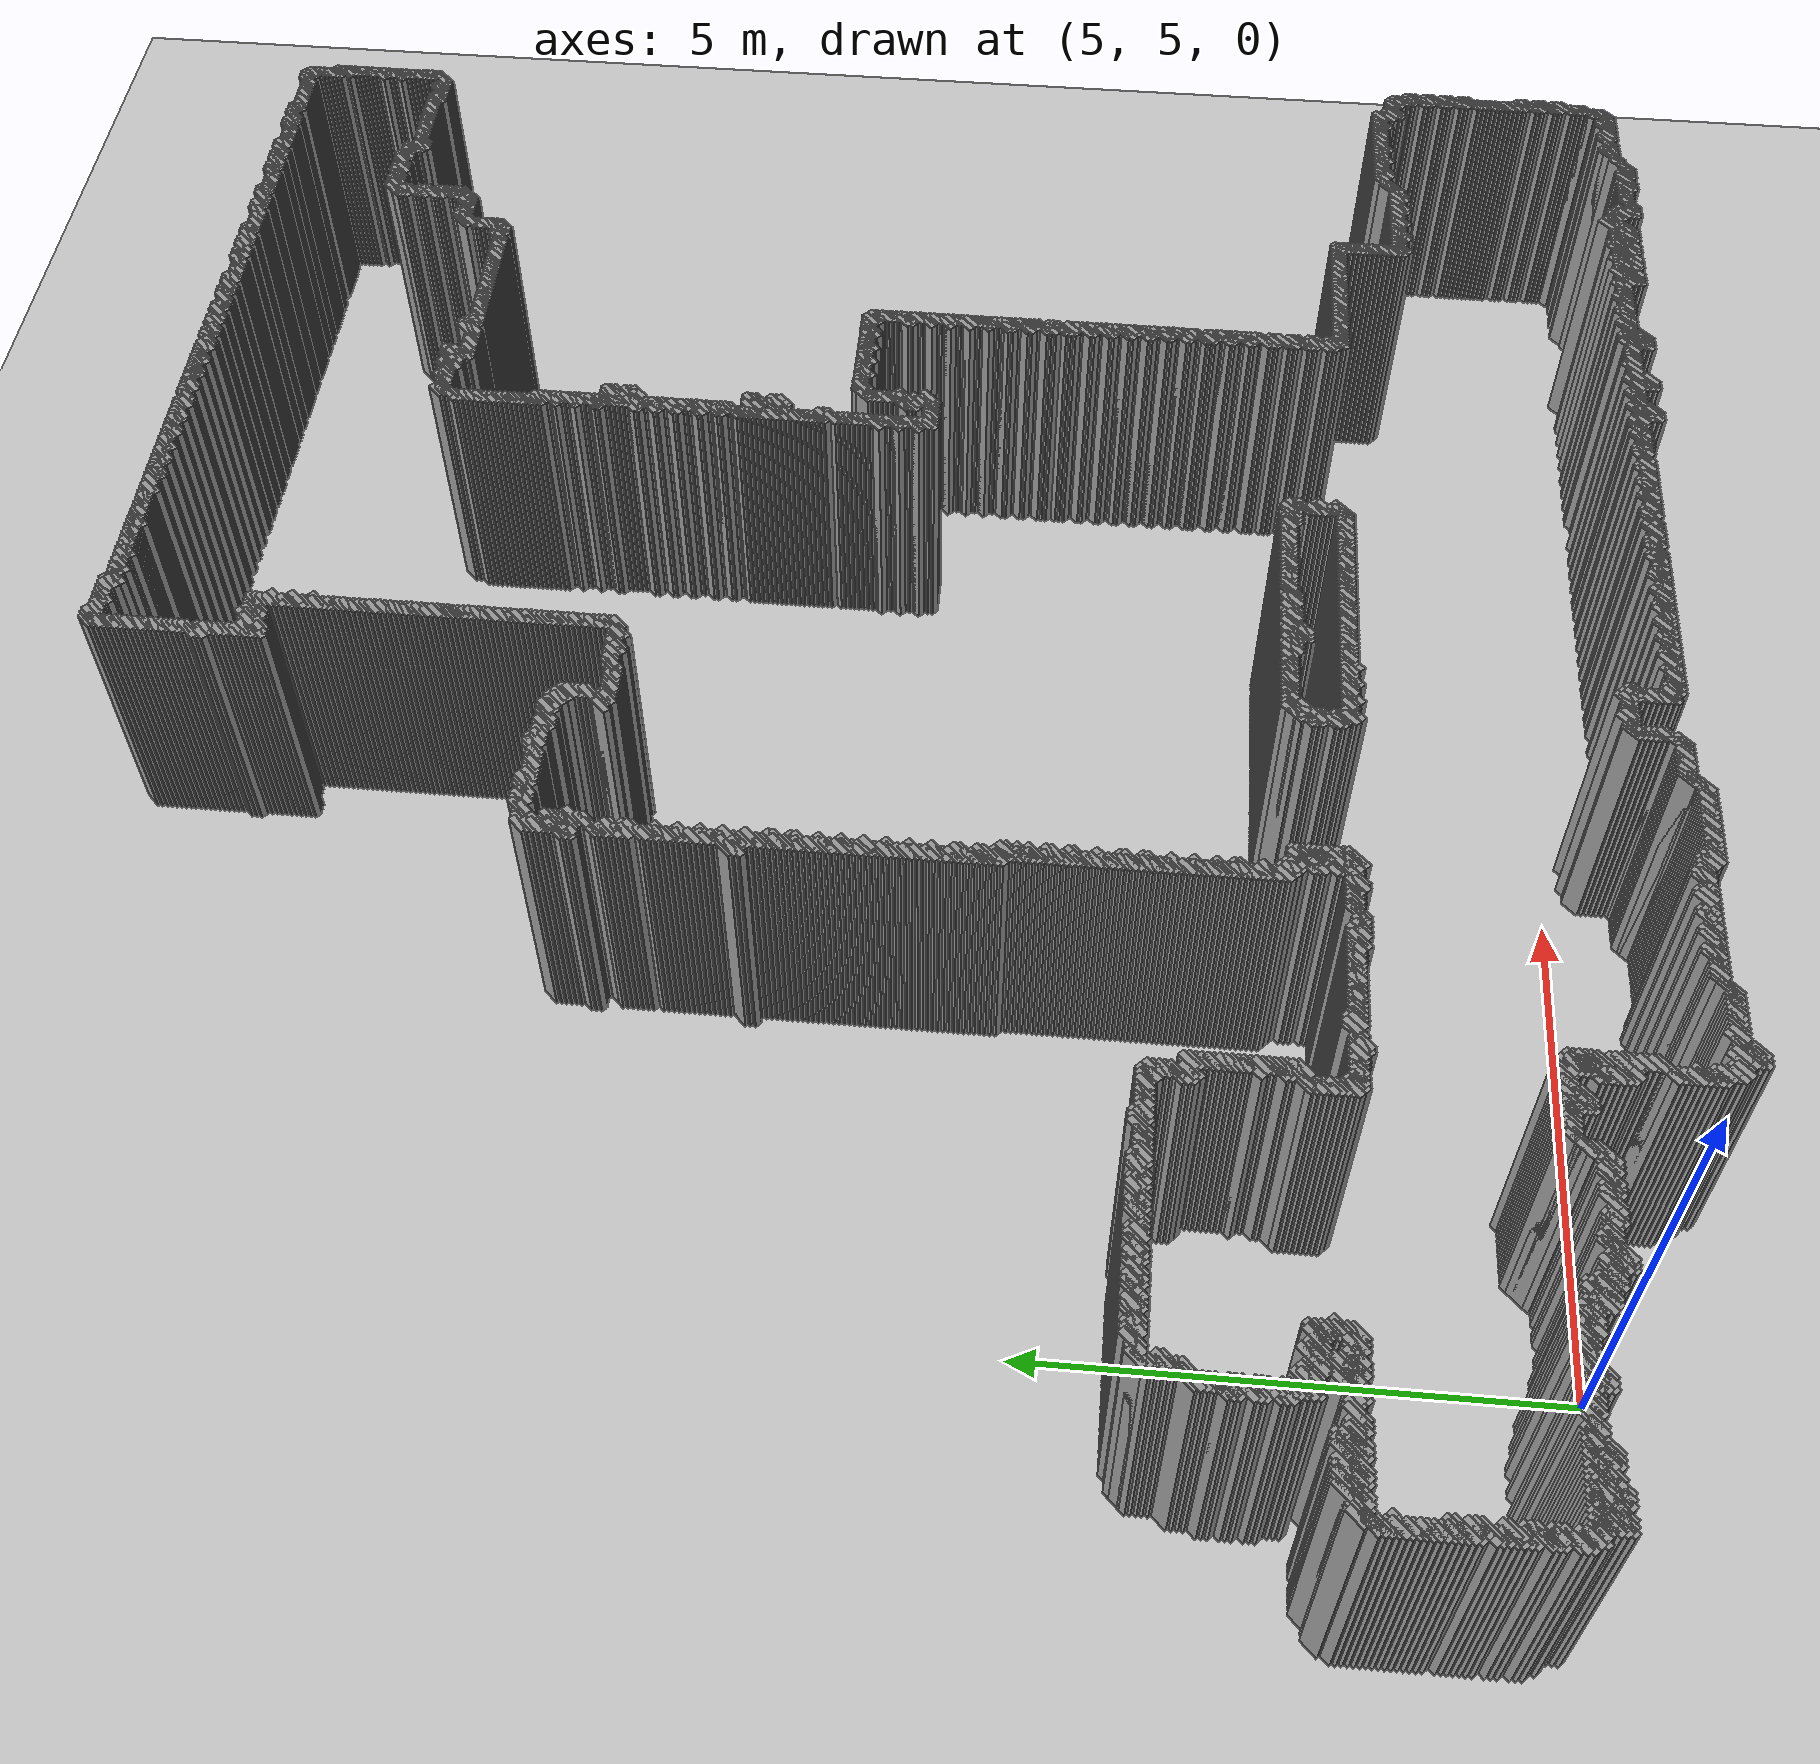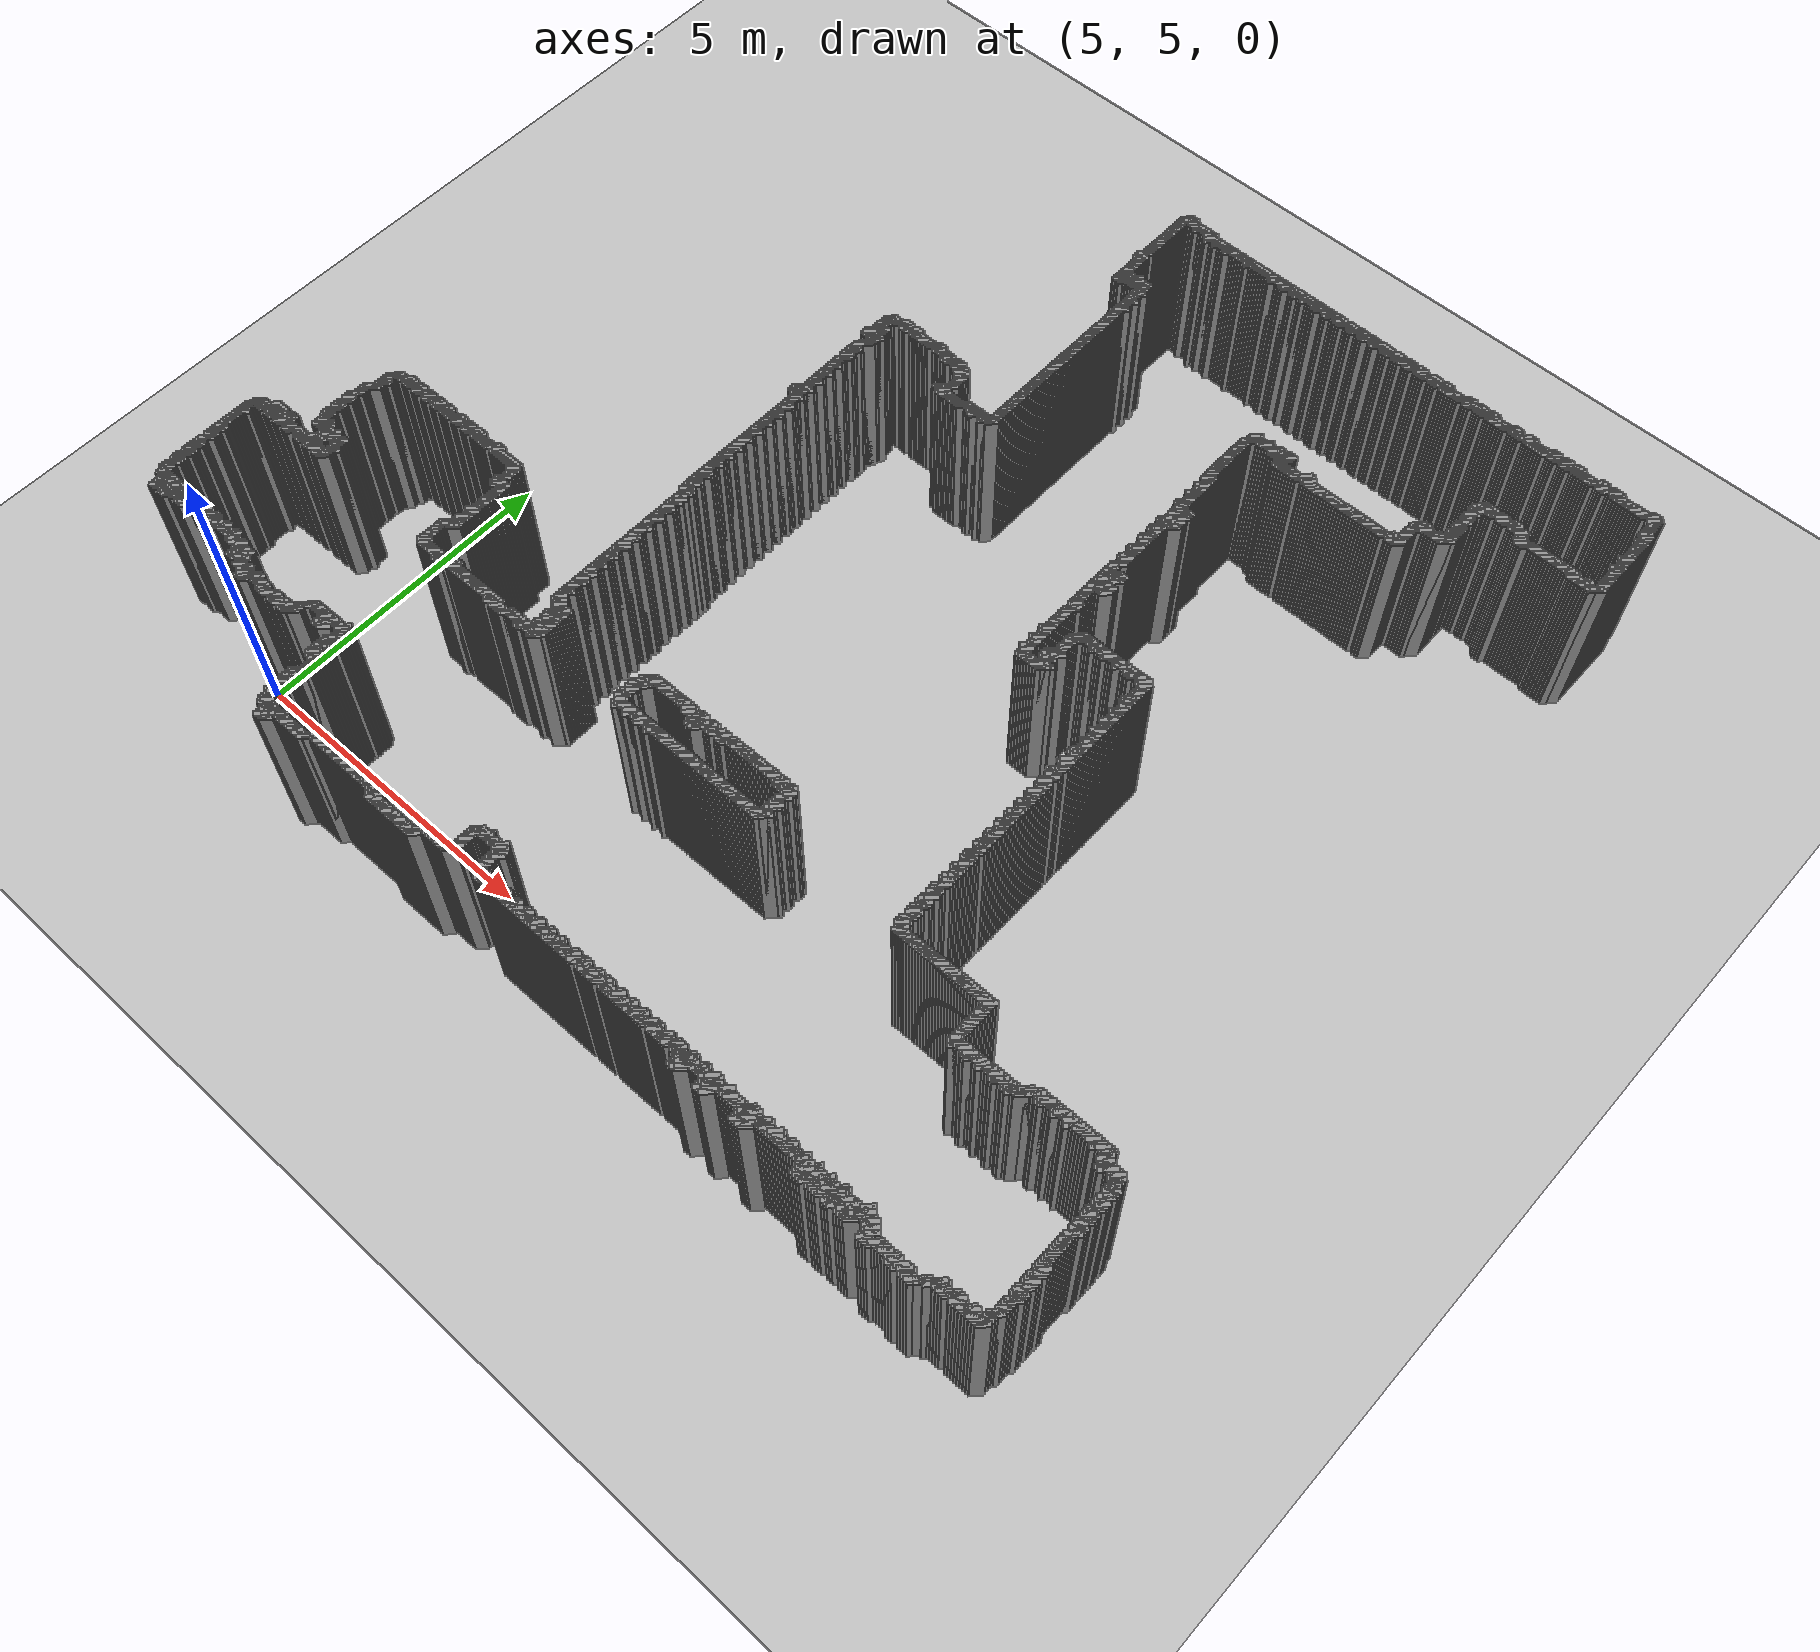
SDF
<sdf version="1.5">
 <world name="default">
  <include><uri>model://ground_plane</uri></include>
  <include><uri>model://sun</uri></include>
  <model name="grey_wall_1">
   <static>1</static>
   <link name="link">
    <pose>10.4 19.1  1.4 0 0 -0.785398163397</pose>
    <collision name="collision"><geometry><box><size>0.0707106781187 .2  2.8</size></box></geometry></collision>
    <visual name="visual">
     <cast_shadows>0</cast_shadows>
     <geometry><box><size>0.0707106781187 .2  2.8</size></box></geometry>
     <material>
      <script>
       <uri>model://grey_wall/materials/scripts</uri>
       <uri>model://grey_wall/materials/textures</uri>
       <name>vrc/grey_wall</name>
      </script>
     </material>
    </visual>
   </link>
  </model>
  <model name="grey_wall_2">
   <static>1</static>
   <link name="link">
    <pose>10.45 19.1  1.4 0 0 -0.785398163397</pose>
    <collision name="collision"><geometry><box><size>0.0707106781187 .2  2.8</size></box></geometry></collision>
    <visual name="visual">
     <cast_shadows>0</cast_shadows>
     <geometry><box><size>0.0707106781187 .2  2.8</size></box></geometry>
     <material>
      <script>
       <uri>model://grey_wall/materials/scripts</uri>
       <uri>model://grey_wall/materials/textures</uri>
       <name>vrc/grey_wall</name>
      </script>
     </material>
    </visual>
   </link>
  </model>
  <model name="grey_wall_3">
   <static>1</static>
   <link name="link">
    <pose>10.5 19.1  1.4 0 0 -0.785398163397</pose>
    <collision name="collision"><geometry><box><size>0.0707106781187 .2  2.8</size></box></geometry></collision>
    <visual name="visual">
     <cast_shadows>0</cast_shadows>
     <geometry><box><size>0.0707106781187 .2  2.8</size></box></geometry>
     <material>
      <script>
       <uri>model://grey_wall/materials/scripts</uri>
       <uri>model://grey_wall/materials/textures</uri>
       <name>vrc/grey_wall</name>
      </script>
     </material>
    </visual>
   </link>
  </model>
  <model name="grey_wall_4">
   <static>1</static>
   <link name="link">
    <pose>10.4 19.05  1.4 0 0 -0.785398163397</pose>
    <collision name="collision"><geometry><box><size>0.0707106781187 .2  2.8</size></box></geometry></collision>
    <visual name="visual">
     <cast_shadows>0</cast_shadows>
     <geometry><box><size>0.0707106781187 .2  2.8</size></box></geometry>
     <material>
      <script>
       <uri>model://grey_wall/materials/scripts</uri>
       <uri>model://grey_wall/materials/textures</uri>
       <name>vrc/grey_wall</name>
      </script>
     </material>
    </visual>
   </link>
  </model>
  <model name="grey_wall_5">
   <static>1</static>
   <link name="link">
    <pose>10.5 19.05  1.4 0 0 -0.785398163397</pose>
    <collision name="collision"><geometry><box><size>0.0707106781187 .2  2.8</size></box></geometry></collision>
    <visual name="visual">
     <cast_shadows>0</cast_shadows>
     <geometry><box><size>0.0707106781187 .2  2.8</size></box></geometry>
     <material>
      <script>
       <uri>model://grey_wall/materials/scripts</uri>
       <uri>model://grey_wall/materials/textures</uri>
       <name>vrc/grey_wall</name>
      </script>
     </material>
    </visual>
   </link>
  </model>
  <model name="grey_wall_6">
   <static>1</static>
   <link name="link">
    <pose>10.55 19.05  1.4 0 0 -0.785398163397</pose>
    <collision name="collision"><geometry><box><size>0.0707106781187 .2  2.8</size></box></geometry></collision>
    <visual name="visual">
     <cast_shadows>0</cast_shadows>
     <geometry><box><size>0.0707106781187 .2  2.8</size></box></geometry>
     <material>
      <script>
       <uri>model://grey_wall/materials/scripts</uri>
       <uri>model://grey_wall/materials/textures</uri>
       <name>vrc/grey_wall</name>
      </script>
     </material>
    </visual>
   </link>
  </model>
  <model name="grey_wall_7">
   <static>1</static>
   <link name="link">
    <pose>10.6 19.05  1.4 0 0 -0.785398163397</pose>
    <collision name="collision"><geometry><box><size>0.0707106781187 .2  2.8</size></box></geometry></collision>
    <visual name="visual">
     <cast_shadows>0</cast_shadows>
     <geometry><box><size>0.0707106781187 .2  2.8</size></box></geometry>
     <material>
      <script>
       <uri>model://grey_wall/materials/scripts</uri>
       <uri>model://grey_wall/materials/textures</uri>
       <name>vrc/grey_wall</name>
      </script>
     </material>
    </visual>
   </link>
  </model>
  <model name="grey_wall_8">
   <static>1</static>
   <link name="link">
    <pose>10.65 19.05  1.4 0 0 -0.785398163397</pose>
    <collision name="collision"><geometry><box><size>0.0707106781187 .2  2.8</size></box></geometry></collision>
    <visual name="visual">
     <cast_shadows>0</cast_shadows>
     <geometry><box><size>0.0707106781187 .2  2.8</size></box></geometry>
     <material>
      <script>
       <uri>model://grey_wall/materials/scripts</uri>
       <uri>model://grey_wall/materials/textures</uri>
       <name>vrc/grey_wall</name>
      </script>
     </material>
    </visual>
   </link>
  </model>
  <model name="grey_wall_9">
   <static>1</static>
   <link name="link">
    <pose>10.7 19.05  1.4 0 0 -0.785398163397</pose>
    <collision name="collision"><geometry><box><size>0.0707106781187 .2  2.8</size></box></geometry></collision>
    <visual name="visual">
     <cast_shadows>0</cast_shadows>
     <geometry><box><size>0.0707106781187 .2  2.8</size></box></geometry>
     <material>
      <script>
       <uri>model://grey_wall/materials/scripts</uri>
       <uri>model://grey_wall/materials/textures</uri>
       <name>vrc/grey_wall</name>
      </script>
     </material>
    </visual>
   </link>
  </model>
  <model name="grey_wall_10">
   <static>1</static>
   <link name="link">
    <pose>10.75 19.05  1.4 0 0 -0.785398163397</pose>
    <collision name="collision"><geometry><box><size>0.0707106781187 .2  2.8</size></box></geometry></collision>
    <visual name="visual">
     <cast_shadows>0</cast_shadows>
     <geometry><box><size>0.0707106781187 .2  2.8</size></box></geometry>
     <material>
      <script>
       <uri>model://grey_wall/materials/scripts</uri>
       <uri>model://grey_wall/materials/textures</uri>
       <name>vrc/grey_wall</name>
      </script>
     </material>
    </visual>
   </link>
  </model>
  <model name="grey_wall_11">
   <static>1</static>
   <link name="link">
    <pose>10.8 19.05  1.4 0 0 -0.785398163397</pose>
    <collision name="collision"><geometry><box><size>0.0707106781187 .2  2.8</size></box></geometry></collision>
    <visual name="visual">
     <cast_shadows>0</cast_shadows>
     <geometry><box><size>0.0707106781187 .2  2.8</size></box></geometry>
     <material>
      <script>
       <uri>model://grey_wall/materials/scripts</uri>
       <uri>model://grey_wall/materials/textures</uri>
       <name>vrc/grey_wall</name>
      </script>
     </material>
    </visual>
   </link>
  </model>
  <model name="grey_wall_12">
   <static>1</static>
   <link name="link">
    <pose>10.85 19.05  1.4 0 0 -0.785398163397</pose>
    <collision name="collision"><geometry><box><size>0.0707106781187 .2  2.8</size></box></geometry></collision>
    <visual name="visual">
     <cast_shadows>0</cast_shadows>
     <geometry><box><size>0.0707106781187 .2  2.8</size></box></geometry>
     <material>
      <script>
       <uri>model://grey_wall/materials/scripts</uri>
       <uri>model://grey_wall/materials/textures</uri>
       <name>vrc/grey_wall</name>
      </script>
     </material>
    </visual>
   </link>
  </model>
  <model name="grey_wall_13">
   <static>1</static>
   <link name="link">
    <pose>10.9 19.05  1.4 0 0 -0.785398163397</pose>
    <collision name="collision"><geometry><box><size>0.0707106781187 .2  2.8</size></box></geometry></collision>
    <visual name="visual">
     <cast_shadows>0</cast_shadows>
     <geometry><box><size>0.0707106781187 .2  2.8</size></box></geometry>
     <material>
      <script>
       <uri>model://grey_wall/materials/scripts</uri>
       <uri>model://grey_wall/materials/textures</uri>
       <name>vrc/grey_wall</name>
      </script>
     </material>
    </visual>
   </link>
  </model>
  <model name="grey_wall_14">
   <static>1</static>
   <link name="link">
    <pose>10.4 19.0  1.4 0 0 -0.785398163397</pose>
    <collision name="collision"><geometry><box><size>0.0707106781187 .2  2.8</size></box></geometry></collision>
    <visual name="visual">
     <cast_shadows>0</cast_shadows>
     <geometry><box><size>0.0707106781187 .2  2.8</size></box></geometry>
     <material>
      <script>
       <uri>model://grey_wall/materials/scripts</uri>
       <uri>model://grey_wall/materials/textures</uri>
       <name>vrc/grey_wall</name>
      </script>
     </material>
    </visual>
   </link>
  </model>
  <model name="grey_wall_15">
   <static>1</static>
   <link name="link">
    <pose>10.7 19.0  1.4 0 0 -0.785398163397</pose>
    <collision name="collision"><geometry><box><size>0.0707106781187 .2  2.8</size></box></geometry></collision>
    <visual name="visual">
     <cast_shadows>0</cast_shadows>
     <geometry><box><size>0.0707106781187 .2  2.8</size></box></geometry>
     <material>
      <script>
       <uri>model://grey_wall/materials/scripts</uri>
       <uri>model://grey_wall/materials/textures</uri>
       <name>vrc/grey_wall</name>
      </script>
     </material>
    </visual>
   </link>
  </model>
  <model name="grey_wall_16">
   <static>1</static>
   <link name="link">
    <pose>10.9 19.0  1.4 0 0 -0.785398163397</pose>
    <collision name="collision"><geometry><box><size>0.0707106781187 .2  2.8</size></box></geometry></collision>
    <visual name="visual">
     <cast_shadows>0</cast_shadows>
     <geometry><box><size>0.0707106781187 .2  2.8</size></box></geometry>
     <material>
      <script>
       <uri>model://grey_wall/materials/scripts</uri>
       <uri>model://grey_wall/materials/textures</uri>
       <name>vrc/grey_wall</name>
      </script>
     </material>
    </visual>
   </link>
  </model>
  <model name="grey_wall_17">
   <static>1</static>
   <link name="link">
    <pose>10.95 19.0  1.4 0 0 -0.785398163397</pose>
    <collision name="collision"><geometry><box><size>0.0707106781187 .2  2.8</size></box></geometry></collision>
    <visual name="visual">
     <cast_shadows>0</cast_shadows>
     <geometry><box><size>0.0707106781187 .2  2.8</size></box></geometry>
     <material>
      <script>
       <uri>model://grey_wall/materials/scripts</uri>
       <uri>model://grey_wall/materials/textures</uri>
       <name>vrc/grey_wall</name>
      </script>
     </material>
    </visual>
   </link>
  </model>
  <model name="grey_wall_18">
   <static>1</static>
   <link name="link">
    <pose>11.0 19.0  1.4 0 0 -0.785398163397</pose>
    <collision name="collision"><geometry><box><size>0.0707106781187 .2  2.8</size></box></geometry></collision>
    <visual name="visual">
     <cast_shadows>0</cast_shadows>
     <geometry><box><size>0.0707106781187 .2  2.8</size></box></geometry>
     <material>
      <script>
       <uri>model://grey_wall/materials/scripts</uri>
       <uri>model://grey_wall/materials/textures</uri>
       <name>vrc/grey_wall</name>
      </script>
     </material>
    </visual>
   </link>
  </model>
  <model name="grey_wall_19">
   <static>1</static>
   <link name="link">
    <pose>11.05 19.0  1.4 0 0 -0.785398163397</pose>
    <collision name="collision"><geometry><box><size>0.0707106781187 .2  2.8</size></box></geometry></collision>
    <visual name="visual">
     <cast_shadows>0</cast_shadows>
     <geometry><box><size>0.0707106781187 .2  2.8</size></box></geometry>
     <material>
      <script>
       <uri>model://grey_wall/materials/scripts</uri>
       <uri>model://grey_wall/materials/textures</uri>
       <name>vrc/grey_wall</name>
      </script>
     </material>
    </visual>
   </link>
  </model>
  <model name="grey_wall_20">
   <static>1</static>
   <link name="link">
    <pose>11.1 19.0  1.4 0 0 -0.785398163397</pose>
    <collision name="collision"><geometry><box><size>0.0707106781187 .2  2.8</size></box></geometry></collision>
    <visual name="visual">
     <cast_shadows>0</cast_shadows>
     <geometry><box><size>0.0707106781187 .2  2.8</size></box></geometry>
     <material>
      <script>
       <uri>model://grey_wall/materials/scripts</uri>
       <uri>model://grey_wall/materials/textures</uri>
       <name>vrc/grey_wall</name>
      </script>
     </material>
    </visual>
   </link>
  </model>
  <model name="grey_wall_21">
   <static>1</static>
   <link name="link">
    <pose>11.15 19.0  1.4 0 0 -0.785398163397</pose>
    <collision name="collision"><geometry><box><size>0.0707106781187 .2  2.8</size></box></geometry></collision>
    <visual name="visual">
     <cast_shadows>0</cast_shadows>
     <geometry><box><size>0.0707106781187 .2  2.8</size></box></geometry>
     <material>
      <script>
       <uri>model://grey_wall/materials/scripts</uri>
       <uri>model://grey_wall/materials/textures</uri>
       <name>vrc/grey_wall</name>
      </script>
     </material>
    </visual>
   </link>
  </model>
  <model name="grey_wall_22">
   <static>1</static>
   <link name="link">
    <pose>11.2 19.0  1.4 0 0 -0.785398163397</pose>
    <collision name="collision"><geometry><box><size>0.0707106781187 .2  2.8</size></box></geometry></collision>
    <visual name="visual">
     <cast_shadows>0</cast_shadows>
     <geometry><box><size>0.0707106781187 .2  2.8</size></box></geometry>
     <material>
      <script>
       <uri>model://grey_wall/materials/scripts</uri>
       <uri>model://grey_wall/materials/textures</uri>
       <name>vrc/grey_wall</name>
      </script>
     </material>
    </visual>
   </link>
  </model>
  <model name="grey_wall_23">
   <static>1</static>
   <link name="link">
    <pose>11.25 19.0  1.4 0 0 -0.785398163397</pose>
    <collision name="collision"><geometry><box><size>0.0707106781187 .2  2.8</size></box></geometry></collision>
    <visual name="visual">
     <cast_shadows>0</cast_shadows>
     <geometry><box><size>0.0707106781187 .2  2.8</size></box></geometry>
     <material>
      <script>
       <uri>model://grey_wall/materials/scripts</uri>
       <uri>model://grey_wall/materials/textures</uri>
       <name>vrc/grey_wall</name>
      </script>
     </material>
    </visual>
   </link>
  </model>
  <model name="grey_wall_24">
   <static>1</static>
   <link name="link">
    <pose>11.3 19.0  1.4 0 0 -0.785398163397</pose>
    <collision name="collision"><geometry><box><size>0.0707106781187 .2  2.8</size></box></geometry></collision>
    <visual name="visual">
     <cast_shadows>0</cast_shadows>
     <geometry><box><size>0.0707106781187 .2  2.8</size></box></geometry>
     <material>
      <script>
       <uri>model://grey_wall/materials/scripts</uri>
       <uri>model://grey_wall/materials/textures</uri>
       <name>vrc/grey_wall</name>
      </script>
     </material>
    </visual>
   </link>
  </model>
  <model name="grey_wall_25">
   <static>1</static>
   <link name="link">
    <pose>11.35 19.0  1.4 0 0 -0.785398163397</pose>
    <collision name="collision"><geometry><box><size>0.0707106781187 .2  2.8</size></box></geometry></collision>
    <visual name="visual">
     <cast_shadows>0</cast_shadows>
     <geometry><box><size>0.0707106781187 .2  2.8</size></box></geometry>
     <material>
      <script>
       <uri>model://grey_wall/materials/scripts</uri>
       <uri>model://grey_wall/materials/textures</uri>
       <name>vrc/grey_wall</name>
      </script>
     </material>
    </visual>
   </link>
  </model>
  <model name="grey_wall_26">
   <static>1</static>
   <link name="link">
    <pose>11.4 19.0  1.4 0 0 -0.785398163397</pose>
    <collision name="collision"><geometry><box><size>0.0707106781187 .2  2.8</size></box></geometry></collision>
    <visual name="visual">
     <cast_shadows>0</cast_shadows>
     <geometry><box><size>0.0707106781187 .2  2.8</size></box></geometry>
     <material>
      <script>
       <uri>model://grey_wall/materials/scripts</uri>
       <uri>model://grey_wall/materials/textures</uri>
       <name>vrc/grey_wall</name>
      </script>
     </material>
    </visual>
   </link>
  </model>
  <model name="grey_wall_27">
   <static>1</static>
   <link name="link">
    <pose>11.45 19.0  1.4 0 0 -0.785398163397</pose>
    <collision name="collision"><geometry><box><size>0.0707106781187 .2  2.8</size></box></geometry></collision>
    <visual name="visual">
     <cast_shadows>0</cast_shadows>
     <geometry><box><size>0.0707106781187 .2  2.8</size></box></geometry>
     <material>
      <script>
       <uri>model://grey_wall/materials/scripts</uri>
       <uri>model://grey_wall/materials/textures</uri>
       <name>vrc/grey_wall</name>
      </script>
     </material>
    </visual>
   </link>
  </model>
  <model name="grey_wall_28">
   <static>1</static>
   <link name="link">
    <pose>11.5 19.0  1.4 0 0 -0.785398163397</pose>
    <collision name="collision"><geometry><box><size>0.0707106781187 .2  2.8</size></box></geometry></collision>
    <visual name="visual">
     <cast_shadows>0</cast_shadows>
     <geometry><box><size>0.0707106781187 .2  2.8</size></box></geometry>
     <material>
      <script>
       <uri>model://grey_wall/materials/scripts</uri>
       <uri>model://grey_wall/materials/textures</uri>
       <name>vrc/grey_wall</name>
      </script>
     </material>
    </visual>
   </link>
  </model>
  <model name="grey_wall_29">
   <static>1</static>
   <link name="link">
    <pose>11.55 19.0  1.4 0 0 -0.785398163397</pose>
    <collision name="collision"><geometry><box><size>0.0707106781187 .2  2.8</size></box></geometry></collision>
    <visual name="visual">
     <cast_shadows>0</cast_shadows>
     <geometry><box><size>0.0707106781187 .2  2.8</size></box></geometry>
     <material>
      <script>
       <uri>model://grey_wall/materials/scripts</uri>
       <uri>model://grey_wall/materials/textures</uri>
       <name>vrc/grey_wall</name>
      </script>
     </material>
    </visual>
   </link>
  </model>
  <model name="grey_wall_30">
   <static>1</static>
   <link name="link">
    <pose>11.6 19.0  1.4 0 0 -0.785398163397</pose>
    <collision name="collision"><geometry><box><size>0.0707106781187 .2  2.8</size></box></geometry></collision>
    <visual name="visual">
     <cast_shadows>0</cast_shadows>
     <geometry><box><size>0.0707106781187 .2  2.8</size></box></geometry>
     <material>
      <script>
       <uri>model://grey_wall/materials/scripts</uri>
       <uri>model://grey_wall/materials/textures</uri>
       <name>vrc/grey_wall</name>
      </script>
     </material>
    </visual>
   </link>
  </model>
  <model name="grey_wall_31">
   <static>1</static>
   <link name="link">
    <pose>11.65 19.0  1.4 0 0 -0.785398163397</pose>
    <collision name="collision"><geometry><box><size>0.0707106781187 .2  2.8</size></box></geometry></collision>
    <visual name="visual">
     <cast_shadows>0</cast_shadows>
     <geometry><box><size>0.0707106781187 .2  2.8</size></box></geometry>
     <material>
      <script>
       <uri>model://grey_wall/materials/scripts</uri>
       <uri>model://grey_wall/materials/textures</uri>
       <name>vrc/grey_wall</name>
      </script>
     </material>
    </visual>
   </link>
  </model>
  <model name="grey_wall_32">
   <static>1</static>
   <link name="link">
    <pose>11.7 19.0  1.4 0 0 -0.785398163397</pose>
    <collision name="collision"><geometry><box><size>0.0707106781187 .2  2.8</size></box></geometry></collision>
    <visual name="visual">
     <cast_shadows>0</cast_shadows>
     <geometry><box><size>0.0707106781187 .2  2.8</size></box></geometry>
     <material>
      <script>
       <uri>model://grey_wall/materials/scripts</uri>
       <uri>model://grey_wall/materials/textures</uri>
       <name>vrc/grey_wall</name>
      </script>
     </material>
    </visual>
   </link>
  </model>
  <model name="grey_wall_33">
   <static>1</static>
   <link name="link">
    <pose>11.75 19.0  1.4 0 0 -0.785398163397</pose>
    <collision name="collision"><geometry><box><size>0.0707106781187 .2  2.8</size></box></geometry></collision>
    <visual name="visual">
     <cast_shadows>0</cast_shadows>
     <geometry><box><size>0.0707106781187 .2  2.8</size></box></geometry>
     <material>
      <script>
       <uri>model://grey_wall/materials/scripts</uri>
       <uri>model://grey_wall/materials/textures</uri>
       <name>vrc/grey_wall</name>
      </script>
     </material>
    </visual>
   </link>
  </model>
  <model name="grey_wall_34">
   <static>1</static>
   <link name="link">
    <pose>11.8 19.0  1.4 0 0 -0.785398163397</pose>
    <collision name="collision"><geometry><box><size>0.0707106781187 .2  2.8</size></box></geometry></collision>
    <visual name="visual">
     <cast_shadows>0</cast_shadows>
     <geometry><box><size>0.0707106781187 .2  2.8</size></box></geometry>
     <material>
      <script>
       <uri>model://grey_wall/materials/scripts</uri>
       <uri>model://grey_wall/materials/textures</uri>
       <name>vrc/grey_wall</name>
      </script>
     </material>
    </visual>
   </link>
  </model>
  <model name="grey_wall_35">
   <static>1</static>
   <link name="link">
    <pose>11.85 19.0  1.4 0 0 -0.785398163397</pose>
    <collision name="collision"><geometry><box><size>0.0707106781187 .2  2.8</size></box></geometry></collision>
    <visual name="visual">
     <cast_shadows>0</cast_shadows>
     <geometry><box><size>0.0707106781187 .2  2.8</size></box></geometry>
     <material>
      <script>
       <uri>model://grey_wall/materials/scripts</uri>
       <uri>model://grey_wall/materials/textures</uri>
       <name>vrc/grey_wall</name>
      </script>
     </material>
    </visual>
   </link>
  </model>
  <model name="grey_wall_36">
   <static>1</static>
   <link name="link">
    <pose>11.9 19.0  1.4 0 0 -0.785398163397</pose>
    <collision name="collision"><geometry><box><size>0.0707106781187 .2  2.8</size></box></geometry></collision>
    <visual name="visual">
     <cast_shadows>0</cast_shadows>
     <geometry><box><size>0.0707106781187 .2  2.8</size></box></geometry>
     <material>
      <script>
       <uri>model://grey_wall/materials/scripts</uri>
       <uri>model://grey_wall/materials/textures</uri>
       <name>vrc/grey_wall</name>
      </script>
     </material>
    </visual>
   </link>
  </model>
  <model name="grey_wall_37">
   <static>1</static>
   <link name="link">
    <pose>11.95 19.0  1.4 0 0 -0.785398163397</pose>
    <collision name="collision"><geometry><box><size>0.0707106781187 .2  2.8</size></box></geometry></collision>
    <visual name="visual">
     <cast_shadows>0</cast_shadows>
     <geometry><box><size>0.0707106781187 .2  2.8</size></box></geometry>
     <material>
      <script>
       <uri>model://grey_wall/materials/scripts</uri>
       <uri>model://grey_wall/materials/textures</uri>
       <name>vrc/grey_wall</name>
      </script>
     </material>
    </visual>
   </link>
  </model>
  <model name="grey_wall_38">
   <static>1</static>
   <link name="link">
    <pose>12.0 19.0  1.4 0 0 -0.785398163397</pose>
    <collision name="collision"><geometry><box><size>0.0707106781187 .2  2.8</size></box></geometry></collision>
    <visual name="visual">
     <cast_shadows>0</cast_shadows>
     <geometry><box><size>0.0707106781187 .2  2.8</size></box></geometry>
     <material>
      <script>
       <uri>model://grey_wall/materials/scripts</uri>
       <uri>model://grey_wall/materials/textures</uri>
       <name>vrc/grey_wall</name>
      </script>
     </material>
    </visual>
   </link>
  </model>
  <model name="grey_wall_39">
   <static>1</static>
   <link name="link">
    <pose>12.05 19.0  1.4 0 0 -0.785398163397</pose>
    <collision name="collision"><geometry><box><size>0.0707106781187 .2  2.8</size></box></geometry></collision>
    <visual name="visual">
     <cast_shadows>0</cast_shadows>
     <geometry><box><size>0.0707106781187 .2  2.8</size></box></geometry>
     <material>
      <script>
       <uri>model://grey_wall/materials/scripts</uri>
       <uri>model://grey_wall/materials/textures</uri>
       <name>vrc/grey_wall</name>
      </script>
     </material>
    </visual>
   </link>
  </model>
  <model name="grey_wall_40">
   <static>1</static>
   <link name="link">
    <pose>12.1 19.0  1.4 0 0 -0.785398163397</pose>
    <collision name="collision"><geometry><box><size>0.0707106781187 .2  2.8</size></box></geometry></collision>
    <visual name="visual">
     <cast_shadows>0</cast_shadows>
     <geometry><box><size>0.0707106781187 .2  2.8</size></box></geometry>
     <material>
      <script>
       <uri>model://grey_wall/materials/scripts</uri>
       <uri>model://grey_wall/materials/textures</uri>
       <name>vrc/grey_wall</name>
      </script>
     </material>
    </visual>
   </link>
  </model>
  <model name="grey_wall_41">
   <static>1</static>
   <link name="link">
    <pose>12.15 19.0  1.4 0 0 -0.785398163397</pose>
    <collision name="collision"><geometry><box><size>0.0707106781187 .2  2.8</size></box></geometry></collision>
    <visual name="visual">
     <cast_shadows>0</cast_shadows>
     <geometry><box><size>0.0707106781187 .2  2.8</size></box></geometry>
     <material>
      <script>
       <uri>model://grey_wall/materials/scripts</uri>
       <uri>model://grey_wall/materials/textures</uri>
       <name>vrc/grey_wall</name>
      </script>
     </material>
    </visual>
   </link>
  </model>
  <model name="grey_wall_42">
   <static>1</static>
   <link name="link">
    <pose>12.2 19.0  1.4 0 0 -0.785398163397</pose>
    <collision name="collision"><geometry><box><size>0.0707106781187 .2  2.8</size></box></geometry></collision>
    <visual name="visual">
     <cast_shadows>0</cast_shadows>
     <geometry><box><size>0.0707106781187 .2  2.8</size></box></geometry>
     <material>
      <script>
       <uri>model://grey_wall/materials/scripts</uri>
       <uri>model://grey_wall/materials/textures</uri>
       <name>vrc/grey_wall</name>
      </script>
     </material>
    </visual>
   </link>
  </model>
  <model name="grey_wall_43">
   <static>1</static>
   <link name="link">
    <pose>12.25 19.0  1.4 0 0 -0.785398163397</pose>
    <collision name="collision"><geometry><box><size>0.0707106781187 .2  2.8</size></box></geometry></collision>
    <visual name="visual">
     <cast_shadows>0</cast_shadows>
     <geometry><box><size>0.0707106781187 .2  2.8</size></box></geometry>
     <material>
      <script>
       <uri>model://grey_wall/materials/scripts</uri>
       <uri>model://grey_wall/materials/textures</uri>
       <name>vrc/grey_wall</name>
      </script>
     </material>
    </visual>
   </link>
  </model>
  <model name="grey_wall_44">
   <static>1</static>
   <link name="link">
    <pose>12.3 19.0  1.4 0 0 -0.785398163397</pose>
    <collision name="collision"><geometry><box><size>0.0707106781187 .2  2.8</size></box></geometry></collision>
    <visual name="visual">
     <cast_shadows>0</cast_shadows>
     <geometry><box><size>0.0707106781187 .2  2.8</size></box></geometry>
     <material>
      <script>
       <uri>model://grey_wall/materials/scripts</uri>
       <uri>model://grey_wall/materials/textures</uri>
       <name>vrc/grey_wall</name>
      </script>
     </material>
    </visual>
   </link>
  </model>
  <model name="grey_wall_45">
   <static>1</static>
   <link name="link">
    <pose>12.35 19.0  1.4 0 0 -0.785398163397</pose>
    <collision name="collision"><geometry><box><size>0.0707106781187 .2  2.8</size></box></geometry></collision>
    <visual name="visual">
     <cast_shadows>0</cast_shadows>
     <geometry><box><size>0.0707106781187 .2  2.8</size></box></geometry>
     <material>
      <script>
       <uri>model://grey_wall/materials/scripts</uri>
       <uri>model://grey_wall/materials/textures</uri>
       <name>vrc/grey_wall</name>
      </script>
     </material>
    </visual>
   </link>
  </model>
  <model name="grey_wall_46">
   <static>1</static>
   <link name="link">
    <pose>12.4 19.0  1.4 0 0 -0.785398163397</pose>
    <collision name="collision"><geometry><box><size>0.0707106781187 .2  2.8</size></box></geometry></collision>
    <visual name="visual">
     <cast_shadows>0</cast_shadows>
     <geometry><box><size>0.0707106781187 .2  2.8</size></box></geometry>
     <material>
      <script>
       <uri>model://grey_wall/materials/scripts</uri>
       <uri>model://grey_wall/materials/textures</uri>
       <name>vrc/grey_wall</name>
      </script>
     </material>
    </visual>
   </link>
  </model>
  <model name="grey_wall_47">
   <static>1</static>
   <link name="link">
    <pose>12.45 19.0  1.4 0 0 -0.785398163397</pose>
    <collision name="collision"><geometry><box><size>0.0707106781187 .2  2.8</size></box></geometry></collision>
    <visual name="visual">
     <cast_shadows>0</cast_shadows>
     <geometry><box><size>0.0707106781187 .2  2.8</size></box></geometry>
     <material>
      <script>
       <uri>model://grey_wall/materials/scripts</uri>
       <uri>model://grey_wall/materials/textures</uri>
       <name>vrc/grey_wall</name>
      </script>
     </material>
    </visual>
   </link>
  </model>
  <model name="grey_wall_48">
   <static>1</static>
   <link name="link">
    <pose>12.5 19.0  1.4 0 0 -0.785398163397</pose>
    <collision name="collision"><geometry><box><size>0.0707106781187 .2  2.8</size></box></geometry></collision>
    <visual name="visual">
     <cast_shadows>0</cast_shadows>
     <geometry><box><size>0.0707106781187 .2  2.8</size></box></geometry>
     <material>
      <script>
       <uri>model://grey_wall/materials/scripts</uri>
       <uri>model://grey_wall/materials/textures</uri>
       <name>vrc/grey_wall</name>
      </script>
     </material>
    </visual>
   </link>
  </model>
  <model name="grey_wall_49">
   <static>1</static>
   <link name="link">
    <pose>12.55 19.0  1.4 0 0 -0.785398163397</pose>
    <collision name="collision"><geometry><box><size>0.0707106781187 .2  2.8</size></box></geometry></collision>
    <visual name="visual">
     <cast_shadows>0</cast_shadows>
     <geometry><box><size>0.0707106781187 .2  2.8</size></box></geometry>
     <material>
      <script>
       <uri>model://grey_wall/materials/scripts</uri>
       <uri>model://grey_wall/materials/textures</uri>
       <name>vrc/grey_wall</name>
      </script>
     </material>
    </visual>
   </link>
  </model>
  <model name="grey_wall_50">
   <static>1</static>
   <link name="link">
    <pose>12.6 19.0  1.4 0 0 -0.785398163397</pose>
    <collision name="collision"><geometry><box><size>0.0707106781187 .2  2.8</size></box></geometry></collision>
    <visual name="visual">
     <cast_shadows>0</cast_shadows>
     <geometry><box><size>0.0707106781187 .2  2.8</size></box></geometry>
     <material>
      <script>
       <uri>model://grey_wall/materials/scripts</uri>
       <uri>model://grey_wall/materials/textures</uri>
       <name>vrc/grey_wall</name>
      </script>
     </material>
    </visual>
   </link>
  </model>
  <model name="grey_wall_51">
   <static>1</static>
   <link name="link">
    <pose>12.65 19.0  1.4 0 0 -0.785398163397</pose>
    <collision name="collision"><geometry><box><size>0.0707106781187 .2  2.8</size></box></geometry></collision>
    <visual name="visual">
     <cast_shadows>0</cast_shadows>
     <geometry><box><size>0.0707106781187 .2  2.8</size></box></geometry>
     <material>
      <script>
       <uri>model://grey_wall/materials/scripts</uri>
       <uri>model://grey_wall/materials/textures</uri>
       <name>vrc/grey_wall</name>
      </script>
     </material>
    </visual>
   </link>
  </model>
  <model name="grey_wall_52">
   <static>1</static>
   <link name="link">
    <pose>12.7 19.0  1.4 0 0 -0.785398163397</pose>
    <collision name="collision"><geometry><box><size>0.0707106781187 .2  2.8</size></box></geometry></collision>
    <visual name="visual">
     <cast_shadows>0</cast_shadows>
     <geometry><box><size>0.0707106781187 .2  2.8</size></box></geometry>
     <material>
      <script>
       <uri>model://grey_wall/materials/scripts</uri>
       <uri>model://grey_wall/materials/textures</uri>
       <name>vrc/grey_wall</name>
      </script>
     </material>
    </visual>
   </link>
  </model>
  <model name="grey_wall_53">
   <static>1</static>
   <link name="link">
    <pose>12.75 19.0  1.4 0 0 -0.785398163397</pose>
    <collision name="collision"><geometry><box><size>0.0707106781187 .2  2.8</size></box></geometry></collision>
    <visual name="visual">
     <cast_shadows>0</cast_shadows>
     <geometry><box><size>0.0707106781187 .2  2.8</size></box></geometry>
     <material>
      <script>
       <uri>model://grey_wall/materials/scripts</uri>
       <uri>model://grey_wall/materials/textures</uri>
       <name>vrc/grey_wall</name>
      </script>
     </material>
    </visual>
   </link>
  </model>
  <model name="grey_wall_54">
   <static>1</static>
   <link name="link">
    <pose>12.8 19.0  1.4 0 0 -0.785398163397</pose>
    <collision name="collision"><geometry><box><size>0.0707106781187 .2  2.8</size></box></geometry></collision>
    <visual name="visual">
     <cast_shadows>0</cast_shadows>
     <geometry><box><size>0.0707106781187 .2  2.8</size></box></geometry>
     <material>
      <script>
       <uri>model://grey_wall/materials/scripts</uri>
       <uri>model://grey_wall/materials/textures</uri>
       <name>vrc/grey_wall</name>
      </script>
     </material>
    </visual>
   </link>
  </model>
  <model name="grey_wall_55">
   <static>1</static>
   <link name="link">
    <pose>12.85 19.0  1.4 0 0 -0.785398163397</pose>
    <collision name="collision"><geometry><box><size>0.0707106781187 .2  2.8</size></box></geometry></collision>
    <visual name="visual">
     <cast_shadows>0</cast_shadows>
     <geometry><box><size>0.0707106781187 .2  2.8</size></box></geometry>
     <material>
      <script>
       <uri>model://grey_wall/materials/scripts</uri>
       <uri>model://grey_wall/materials/textures</uri>
       <name>vrc/grey_wall</name>
      </script>
     </material>
    </visual>
   </link>
  </model>
  <model name="grey_wall_56">
   <static>1</static>
   <link name="link">
    <pose>12.9 19.0  1.4 0 0 -0.785398163397</pose>
    <collision name="collision"><geometry><box><size>0.0707106781187 .2  2.8</size></box></geometry></collision>
    <visual name="visual">
     <cast_shadows>0</cast_shadows>
     <geometry><box><size>0.0707106781187 .2  2.8</size></box></geometry>
     <material>
      <script>
       <uri>model://grey_wall/materials/scripts</uri>
       <uri>model://grey_wall/materials/textures</uri>
       <name>vrc/grey_wall</name>
      </script>
     </material>
    </visual>
   </link>
  </model>
  <model name="grey_wall_57">
   <static>1</static>
   <link name="link">
    <pose>12.95 19.0  1.4 0 0 -0.785398163397</pose>
    <collision name="collision"><geometry><box><size>0.0707106781187 .2  2.8</size></box></geometry></collision>
    <visual name="visual">
     <cast_shadows>0</cast_shadows>
     <geometry><box><size>0.0707106781187 .2  2.8</size></box></geometry>
     <material>
      <script>
       <uri>model://grey_wall/materials/scripts</uri>
       <uri>model://grey_wall/materials/textures</uri>
       <name>vrc/grey_wall</name>
      </script>
     </material>
    </visual>
   </link>
  </model>
  <model name="grey_wall_58">
   <static>1</static>
   <link name="link">
    <pose>13.0 19.0  1.4 0 0 -0.785398163397</pose>
    <collision name="collision"><geometry><box><size>0.0707106781187 .2  2.8</size></box></geometry></collision>
    <visual name="visual">
     <cast_shadows>0</cast_shadows>
     <geometry><box><size>0.0707106781187 .2  2.8</size></box></geometry>
     <material>
      <script>
       <uri>model://grey_wall/materials/scripts</uri>
       <uri>model://grey_wall/materials/textures</uri>
       <name>vrc/grey_wall</name>
      </script>
     </material>
    </visual>
   </link>
  </model>
  <model name="grey_wall_59">
   <static>1</static>
   <link name="link">
    <pose>13.05 19.0  1.4 0 0 -0.785398163397</pose>
    <collision name="collision"><geometry><box><size>0.0707106781187 .2  2.8</size></box></geometry></collision>
    <visual name="visual">
     <cast_shadows>0</cast_shadows>
     <geometry><box><size>0.0707106781187 .2  2.8</size></box></geometry>
     <material>
      <script>
       <uri>model://grey_wall/materials/scripts</uri>
       <uri>model://grey_wall/materials/textures</uri>
       <name>vrc/grey_wall</name>
      </script>
     </material>
    </visual>
   </link>
  </model>
  <model name="grey_wall_60">
   <static>1</static>
   <link name="link">
    <pose>13.1 19.0  1.4 0 0 -0.785398163397</pose>
    <collision name="collision"><geometry><box><size>0.0707106781187 .2  2.8</size></box></geometry></collision>
    <visual name="visual">
     <cast_shadows>0</cast_shadows>
     <geometry><box><size>0.0707106781187 .2  2.8</size></box></geometry>
     <material>
      <script>
       <uri>model://grey_wall/materials/scripts</uri>
       <uri>model://grey_wall/materials/textures</uri>
       <name>vrc/grey_wall</name>
      </script>
     </material>
    </visual>
   </link>
  </model>
  <model name="grey_wall_61">
   <static>1</static>
   <link name="link">
    <pose>13.15 19.0  1.4 0 0 -0.785398163397</pose>
    <collision name="collision"><geometry><box><size>0.0707106781187 .2  2.8</size></box></geometry></collision>
    <visual name="visual">
     <cast_shadows>0</cast_shadows>
     <geometry><box><size>0.0707106781187 .2  2.8</size></box></geometry>
     <material>
      <script>
       <uri>model://grey_wall/materials/scripts</uri>
       <uri>model://grey_wall/materials/textures</uri>
       <name>vrc/grey_wall</name>
      </script>
     </material>
    </visual>
   </link>
  </model>
  <model name="grey_wall_62">
   <static>1</static>
   <link name="link">
    <pose>13.2 19.0  1.4 0 0 -0.785398163397</pose>
    <collision name="collision"><geometry><box><size>0.0707106781187 .2  2.8</size></box></geometry></collision>
    <visual name="visual">
     <cast_shadows>0</cast_shadows>
     <geometry><box><size>0.0707106781187 .2  2.8</size></box></geometry>
     <material>
      <script>
       <uri>model://grey_wall/materials/scripts</uri>
       <uri>model://grey_wall/materials/textures</uri>
       <name>vrc/grey_wall</name>
      </script>
     </material>
    </visual>
   </link>
  </model>
  <model name="grey_wall_63">
   <static>1</static>
   <link name="link">
    <pose>13.25 19.0  1.4 0 0 -0.785398163397</pose>
    <collision name="collision"><geometry><box><size>0.0707106781187 .2  2.8</size></box></geometry></collision>
    <visual name="visual">
     <cast_shadows>0</cast_shadows>
     <geometry><box><size>0.0707106781187 .2  2.8</size></box></geometry>
     <material>
      <script>
       <uri>model://grey_wall/materials/scripts</uri>
       <uri>model://grey_wall/materials/textures</uri>
       <name>vrc/grey_wall</name>
      </script>
     </material>
    </visual>
   </link>
  </model>
  <model name="grey_wall_64">
   <static>1</static>
   <link name="link">
    <pose>13.3 19.0  1.4 0 0 -0.785398163397</pose>
    <collision name="collision"><geometry><box><size>0.0707106781187 .2  2.8</size></box></geometry></collision>
    <visual name="visual">
     <cast_shadows>0</cast_shadows>
     <geometry><box><size>0.0707106781187 .2  2.8</size></box></geometry>
     <material>
      <script>
       <uri>model://grey_wall/materials/scripts</uri>
       <uri>model://grey_wall/materials/textures</uri>
       <name>vrc/grey_wall</name>
      </script>
     </material>
    </visual>
   </link>
  </model>
  <model name="grey_wall_65">
   <static>1</static>
   <link name="link">
    <pose>13.35 19.0  1.4 0 0 -0.785398163397</pose>
    <collision name="collision"><geometry><box><size>0.0707106781187 .2  2.8</size></box></geometry></collision>
    <visual name="visual">
     <cast_shadows>0</cast_shadows>
     <geometry><box><size>0.0707106781187 .2  2.8</size></box></geometry>
     <material>
      <script>
       <uri>model://grey_wall/materials/scripts</uri>
       <uri>model://grey_wall/materials/textures</uri>
       <name>vrc/grey_wall</name>
      </script>
     </material>
    </visual>
   </link>
  </model>
  <model name="grey_wall_66">
   <static>1</static>
   <link name="link">
    <pose>13.45 19.0  1.4 0 0 -0.785398163397</pose>
    <collision name="collision"><geometry><box><size>0.0707106781187 .2  2.8</size></box></geometry></collision>
    <visual name="visual">
     <cast_shadows>0</cast_shadows>
     <geometry><box><size>0.0707106781187 .2  2.8</size></box></geometry>
     <material>
      <script>
       <uri>model://grey_wall/materials/scripts</uri>
       <uri>model://grey_wall/materials/textures</uri>
       <name>vrc/grey_wall</name>
      </script>
     </material>
    </visual>
   </link>
  </model>
  <model name="grey_wall_67">
   <static>1</static>
   <link name="link">
    <pose>13.5 19.0  1.4 0 0 -0.785398163397</pose>
    <collision name="collision"><geometry><box><size>0.0707106781187 .2  2.8</size></box></geometry></collision>
    <visual name="visual">
     <cast_shadows>0</cast_shadows>
     <geometry><box><size>0.0707106781187 .2  2.8</size></box></geometry>
     <material>
      <script>
       <uri>model://grey_wall/materials/scripts</uri>
       <uri>model://grey_wall/materials/textures</uri>
       <name>vrc/grey_wall</name>
      </script>
     </material>
    </visual>
   </link>
  </model>
  <model name="grey_wall_68">
   <static>1</static>
   <link name="link">
    <pose>13.55 19.0  1.4 0 0 -0.785398163397</pose>
    <collision name="collision"><geometry><box><size>0.0707106781187 .2  2.8</size></box></geometry></collision>
    <visual name="visual">
     <cast_shadows>0</cast_shadows>
     <geometry><box><size>0.0707106781187 .2  2.8</size></box></geometry>
     <material>
      <script>
       <uri>model://grey_wall/materials/scripts</uri>
       <uri>model://grey_wall/materials/textures</uri>
       <name>vrc/grey_wall</name>
      </script>
     </material>
    </visual>
   </link>
  </model>
  <model name="grey_wall_69">
   <static>1</static>
   <link name="link">
    <pose>13.6 19.0  1.4 0 0 -0.785398163397</pose>
    <collision name="collision"><geometry><box><size>0.0707106781187 .2  2.8</size></box></geometry></collision>
    <visual name="visual">
     <cast_shadows>0</cast_shadows>
     <geometry><box><size>0.0707106781187 .2  2.8</size></box></geometry>
     <material>
      <script>
       <uri>model://grey_wall/materials/scripts</uri>
       <uri>model://grey_wall/materials/textures</uri>
       <name>vrc/grey_wall</name>
      </script>
     </material>
    </visual>
   </link>
  </model>
  <model name="grey_wall_70">
   <static>1</static>
   <link name="link">
    <pose>13.65 19.0  1.4 0 0 -0.785398163397</pose>
    <collision name="collision"><geometry><box><size>0.0707106781187 .2  2.8</size></box></geometry></collision>
    <visual name="visual">
     <cast_shadows>0</cast_shadows>
     <geometry><box><size>0.0707106781187 .2  2.8</size></box></geometry>
     <material>
      <script>
       <uri>model://grey_wall/materials/scripts</uri>
       <uri>model://grey_wall/materials/textures</uri>
       <name>vrc/grey_wall</name>
      </script>
     </material>
    </visual>
   </link>
  </model>
  <model name="grey_wall_71">
   <static>1</static>
   <link name="link">
    <pose>13.7 19.0  1.4 0 0 -0.785398163397</pose>
    <collision name="collision"><geometry><box><size>0.0707106781187 .2  2.8</size></box></geometry></collision>
    <visual name="visual">
     <cast_shadows>0</cast_shadows>
     <geometry><box><size>0.0707106781187 .2  2.8</size></box></geometry>
     <material>
      <script>
       <uri>model://grey_wall/materials/scripts</uri>
       <uri>model://grey_wall/materials/textures</uri>
       <name>vrc/grey_wall</name>
      </script>
     </material>
    </visual>
   </link>
  </model>
  <model name="grey_wall_72">
   <static>1</static>
   <link name="link">
    <pose>13.75 19.0  1.4 0 0 -0.785398163397</pose>
    <collision name="collision"><geometry><box><size>0.0707106781187 .2  2.8</size></box></geometry></collision>
    <visual name="visual">
     <cast_shadows>0</cast_shadows>
     <geometry><box><size>0.0707106781187 .2  2.8</size></box></geometry>
     <material>
      <script>
       <uri>model://grey_wall/materials/scripts</uri>
       <uri>model://grey_wall/materials/textures</uri>
       <name>vrc/grey_wall</name>
      </script>
     </material>
    </visual>
   </link>
  </model>
  <model name="grey_wall_73">
   <static>1</static>
   <link name="link">
    <pose>13.8 19.0  1.4 0 0 -0.785398163397</pose>
    <collision name="collision"><geometry><box><size>0.0707106781187 .2  2.8</size></box></geometry></collision>
    <visual name="visual">
     <cast_shadows>0</cast_shadows>
     <geometry><box><size>0.0707106781187 .2  2.8</size></box></geometry>
     <material>
      <script>
       <uri>model://grey_wall/materials/scripts</uri>
       <uri>model://grey_wall/materials/textures</uri>
       <name>vrc/grey_wall</name>
      </script>
     </material>
    </visual>
   </link>
  </model>
  <model name="grey_wall_74">
   <static>1</static>
   <link name="link">
    <pose>13.85 19.0  1.4 0 0 -0.785398163397</pose>
    <collision name="collision"><geometry><box><size>0.0707106781187 .2  2.8</size></box></geometry></collision>
    <visual name="visual">
     <cast_shadows>0</cast_shadows>
     <geometry><box><size>0.0707106781187 .2  2.8</size></box></geometry>
     <material>
      <script>
       <uri>model://grey_wall/materials/scripts</uri>
       <uri>model://grey_wall/materials/textures</uri>
       <name>vrc/grey_wall</name>
      </script>
     </material>
    </visual>
   </link>
  </model>
  <model name="grey_wall_75">
   <static>1</static>
   <link name="link">
    <pose>13.9 19.0  1.4 0 0 -0.785398163397</pose>
    <collision name="collision"><geometry><box><size>0.0707106781187 .2  2.8</size></box></geometry></collision>
    <visual name="visual">
     <cast_shadows>0</cast_shadows>
     <geometry><box><size>0.0707106781187 .2  2.8</size></box></geometry>
     <material>
      <script>
       <uri>model://grey_wall/materials/scripts</uri>
       <uri>model://grey_wall/materials/textures</uri>
       <name>vrc/grey_wall</name>
      </script>
     </material>
    </visual>
   </link>
  </model>
  <model name="grey_wall_76">
   <static>1</static>
   <link name="link">
    <pose>13.95 19.0  1.4 0 0 -0.785398163397</pose>
    <collision name="collision"><geometry><box><size>0.0707106781187 .2  2.8</size></box></geometry></collision>
    <visual name="visual">
     <cast_shadows>0</cast_shadows>
     <geometry><box><size>0.0707106781187 .2  2.8</size></box></geometry>
     <material>
      <script>
       <uri>model://grey_wall/materials/scripts</uri>
       <uri>model://grey_wall/materials/textures</uri>
       <name>vrc/grey_wall</name>
      </script>
     </material>
    </visual>
   </link>
  </model>
  <model name="grey_wall_77">
   <static>1</static>
   <link name="link">
    <pose>14.0 19.0  1.4 0 0 -0.785398163397</pose>
    <collision name="collision"><geometry><box><size>0.0707106781187 .2  2.8</size></box></geometry></collision>
    <visual name="visual">
     <cast_shadows>0</cast_shadows>
     <geometry><box><size>0.0707106781187 .2  2.8</size></box></geometry>
     <material>
      <script>
       <uri>model://grey_wall/materials/scripts</uri>
       <uri>model://grey_wall/materials/textures</uri>
       <name>vrc/grey_wall</name>
      </script>
     </material>
    </visual>
   </link>
  </model>
  <model name="grey_wall_78">
   <static>1</static>
   <link name="link">
    <pose>14.05 19.0  1.4 0 0 -0.785398163397</pose>
    <collision name="collision"><geometry><box><size>0.0707106781187 .2  2.8</size></box></geometry></collision>
    <visual name="visual">
     <cast_shadows>0</cast_shadows>
     <geometry><box><size>0.0707106781187 .2  2.8</size></box></geometry>
     <material>
      <script>
       <uri>model://grey_wall/materials/scripts</uri>
       <uri>model://grey_wall/materials/textures</uri>
       <name>vrc/grey_wall</name>
      </script>
     </material>
    </visual>
   </link>
  </model>
  <model name="grey_wall_79">
   <static>1</static>
   <link name="link">
    <pose>14.1 19.0  1.4 0 0 -0.785398163397</pose>
    <collision name="collision"><geometry><box><size>0.0707106781187 .2  2.8</size></box></geometry></collision>
    <visual name="visual">
     <cast_shadows>0</cast_shadows>
     <geometry><box><size>0.0707106781187 .2  2.8</size></box></geometry>
     <material>
      <script>
       <uri>model://grey_wall/materials/scripts</uri>
       <uri>model://grey_wall/materials/textures</uri>
       <name>vrc/grey_wall</name>
      </script>
     </material>
    </visual>
   </link>
  </model>
  <model name="grey_wall_80">
   <static>1</static>
   <link name="link">
    <pose>14.15 19.0  1.4 0 0 -0.785398163397</pose>
    <collision name="collision"><geometry><box><size>0.0707106781187 .2  2.8</size></box></geometry></collision>
    <visual name="visual">
     <cast_shadows>0</cast_shadows>
     <geometry><box><size>0.0707106781187 .2  2.8</size></box></geometry>
     <material>
      <script>
       <uri>model://grey_wall/materials/scripts</uri>
       <uri>model://grey_wall/materials/textures</uri>
       <name>vrc/grey_wall</name>
      </script>
     </material>
    </visual>
   </link>
  </model>
  <model name="grey_wall_81">
   <static>1</static>
   <link name="link">
    <pose>14.2 19.0  1.4 0 0 -0.785398163397</pose>
    <collision name="collision"><geometry><box><size>0.0707106781187 .2  2.8</size></box></geometry></collision>
    <visual name="visual">
     <cast_shadows>0</cast_shadows>
     <geometry><box><size>0.0707106781187 .2  2.8</size></box></geometry>
     <material>
      <script>
       <uri>model://grey_wall/materials/scripts</uri>
       <uri>model://grey_wall/materials/textures</uri>
       <name>vrc/grey_wall</name>
      </script>
     </material>
    </visual>
   </link>
  </model>
  <model name="grey_wall_82">
   <static>1</static>
   <link name="link">
    <pose>14.3 19.0  1.4 0 0 -0.785398163397</pose>
    <collision name="collision"><geometry><box><size>0.0707106781187 .2  2.8</size></box></geometry></collision>
    <visual name="visual">
     <cast_shadows>0</cast_shadows>
     <geometry><box><size>0.0707106781187 .2  2.8</size></box></geometry>
     <material>
      <script>
       <uri>model://grey_wall/materials/scripts</uri>
       <uri>model://grey_wall/materials/textures</uri>
       <name>vrc/grey_wall</name>
      </script>
     </material>
    </visual>
   </link>
  </model>
  <model name="grey_wall_83">
   <static>1</static>
   <link name="link">
    <pose>14.35 19.0  1.4 0 0 -0.785398163397</pose>
    <collision name="collision"><geometry><box><size>0.0707106781187 .2  2.8</size></box></geometry></collision>
    <visual name="visual">
     <cast_shadows>0</cast_shadows>
     <geometry><box><size>0.0707106781187 .2  2.8</size></box></geometry>
     <material>
      <script>
       <uri>model://grey_wall/materials/scripts</uri>
       <uri>model://grey_wall/materials/textures</uri>
       <name>vrc/grey_wall</name>
      </script>
     </material>
    </visual>
   </link>
  </model>
  <model name="grey_wall_84">
   <static>1</static>
   <link name="link">
    <pose>14.4 19.0  1.4 0 0 -0.785398163397</pose>
    <collision name="collision"><geometry><box><size>0.0707106781187 .2  2.8</size></box></geometry></collision>
    <visual name="visual">
     <cast_shadows>0</cast_shadows>
     <geometry><box><size>0.0707106781187 .2  2.8</size></box></geometry>
     <material>
      <script>
       <uri>model://grey_wall/materials/scripts</uri>
       <uri>model://grey_wall/materials/textures</uri>
       <name>vrc/grey_wall</name>
      </script>
     </material>
    </visual>
   </link>
  </model>
  <model name="grey_wall_85">
   <static>1</static>
   <link name="link">
    <pose>14.5 19.0  1.4 0 0 -0.785398163397</pose>
    <collision name="collision"><geometry><box><size>0.0707106781187 .2  2.8</size></box></geometry></collision>
    <visual name="visual">
     <cast_shadows>0</cast_shadows>
     <geometry><box><size>0.0707106781187 .2  2.8</size></box></geometry>
     <material>
      <script>
       <uri>model://grey_wall/materials/scripts</uri>
       <uri>model://grey_wall/materials/textures</uri>
       <name>vrc/grey_wall</name>
      </script>
     </material>
    </visual>
   </link>
  </model>
  <model name="grey_wall_86">
   <static>1</static>
   <link name="link">
    <pose>14.55 19.0  1.4 0 0 -0.785398163397</pose>
    <collision name="collision"><geometry><box><size>0.0707106781187 .2  2.8</size></box></geometry></collision>
    <visual name="visual">
     <cast_shadows>0</cast_shadows>
     <geometry><box><size>0.0707106781187 .2  2.8</size></box></geometry>
     <material>
      <script>
       <uri>model://grey_wall/materials/scripts</uri>
       <uri>model://grey_wall/materials/textures</uri>
       <name>vrc/grey_wall</name>
      </script>
     </material>
    </visual>
   </link>
  </model>
  <model name="grey_wall_87">
   <static>1</static>
   <link name="link">
    <pose>14.6 19.0  1.4 0 0 -0.785398163397</pose>
    <collision name="collision"><geometry><box><size>0.0707106781187 .2  2.8</size></box></geometry></collision>
    <visual name="visual">
     <cast_shadows>0</cast_shadows>
     <geometry><box><size>0.0707106781187 .2  2.8</size></box></geometry>
     <material>
      <script>
       <uri>model://grey_wall/materials/scripts</uri>
       <uri>model://grey_wall/materials/textures</uri>
       <name>vrc/grey_wall</name>
      </script>
     </material>
    </visual>
   </link>
  </model>
  <model name="grey_wall_88">
   <static>1</static>
   <link name="link">
    <pose>14.7 19.0  1.4 0 0 -0.785398163397</pose>
    <collision name="collision"><geometry><box><size>0.0707106781187 .2  2.8</size></box></geometry></collision>
    <visual name="visual">
     <cast_shadows>0</cast_shadows>
     <geometry><box><size>0.0707106781187 .2  2.8</size></box></geometry>
     <material>
      <script>
       <uri>model://grey_wall/materials/scripts</uri>
       <uri>model://grey_wall/materials/textures</uri>
       <name>vrc/grey_wall</name>
      </script>
     </material>
    </visual>
   </link>
  </model>
  <model name="grey_wall_89">
   <static>1</static>
   <link name="link">
    <pose>14.75 19.0  1.4 0 0 -0.785398163397</pose>
    <collision name="collision"><geometry><box><size>0.0707106781187 .2  2.8</size></box></geometry></collision>
    <visual name="visual">
     <cast_shadows>0</cast_shadows>
     <geometry><box><size>0.0707106781187 .2  2.8</size></box></geometry>
     <material>
      <script>
       <uri>model://grey_wall/materials/scripts</uri>
       <uri>model://grey_wall/materials/textures</uri>
       <name>vrc/grey_wall</name>
      </script>
     </material>
    </visual>
   </link>
  </model>
  <model name="grey_wall_90">
   <static>1</static>
   <link name="link">
    <pose>14.8 19.0  1.4 0 0 -0.785398163397</pose>
    <collision name="collision"><geometry><box><size>0.0707106781187 .2  2.8</size></box></geometry></collision>
    <visual name="visual">
     <cast_shadows>0</cast_shadows>
     <geometry><box><size>0.0707106781187 .2  2.8</size></box></geometry>
     <material>
      <script>
       <uri>model://grey_wall/materials/scripts</uri>
       <uri>model://grey_wall/materials/textures</uri>
       <name>vrc/grey_wall</name>
      </script>
     </material>
    </visual>
   </link>
  </model>
  <model name="grey_wall_91">
   <static>1</static>
   <link name="link">
    <pose>14.95 19.0  1.4 0 0 -0.785398163397</pose>
    <collision name="collision"><geometry><box><size>0.0707106781187 .2  2.8</size></box></geometry></collision>
    <visual name="visual">
     <cast_shadows>0</cast_shadows>
     <geometry><box><size>0.0707106781187 .2  2.8</size></box></geometry>
     <material>
      <script>
       <uri>model://grey_wall/materials/scripts</uri>
       <uri>model://grey_wall/materials/textures</uri>
       <name>vrc/grey_wall</name>
      </script>
     </material>
    </visual>
   </link>
  </model>
  <model name="grey_wall_92">
   <static>1</static>
   <link name="link">
    <pose>15.0 19.0  1.4 0 0 -0.785398163397</pose>
    <collision name="collision"><geometry><box><size>0.0707106781187 .2  2.8</size></box></geometry></collision>
    <visual name="visual">
     <cast_shadows>0</cast_shadows>
     <geometry><box><size>0.0707106781187 .2  2.8</size></box></geometry>
     <material>
      <script>
       <uri>model://grey_wall/materials/scripts</uri>
       <uri>model://grey_wall/materials/textures</uri>
       <name>vrc/grey_wall</name>
      </script>
     </material>
    </visual>
   </link>
  </model>
  <model name="grey_wall_93">
   <static>1</static>
   <link name="link">
    <pose>15.05 19.0  1.4 0 0 -0.785398163397</pose>
    <collision name="collision"><geometry><box><size>0.0707106781187 .2  2.8</size></box></geometry></collision>
    <visual name="visual">
     <cast_shadows>0</cast_shadows>
     <geometry><box><size>0.0707106781187 .2  2.8</size></box></geometry>
     <material>
      <script>
       <uri>model://grey_wall/materials/scripts</uri>
       <uri>model://grey_wall/materials/textures</uri>
       <name>vrc/grey_wall</name>
      </script>
     </material>
    </visual>
   </link>
  </model>
  <model name="grey_wall_94">
   <static>1</static>
   <link name="link">
    <pose>15.15 19.0  1.4 0 0 -0.785398163397</pose>
    <collision name="collision"><geometry><box><size>0.0707106781187 .2  2.8</size></box></geometry></collision>
    <visual name="visual">
     <cast_shadows>0</cast_shadows>
     <geometry><box><size>0.0707106781187 .2  2.8</size></box></geometry>
     <material>
      <script>
       <uri>model://grey_wall/materials/scripts</uri>
       <uri>model://grey_wall/materials/textures</uri>
       <name>vrc/grey_wall</name>
      </script>
     </material>
    </visual>
   </link>
  </model>
  <model name="grey_wall_95">
   <static>1</static>
   <link name="link">
    <pose>15.2 19.0  1.4 0 0 -0.785398163397</pose>
    <collision name="collision"><geometry><box><size>0.0707106781187 .2  2.8</size></box></geometry></collision>
    <visual name="visual">
     <cast_shadows>0</cast_shadows>
     <geometry><box><size>0.0707106781187 .2  2.8</size></box></geometry>
     <material>
      <script>
       <uri>model://grey_wall/materials/scripts</uri>
       <uri>model://grey_wall/materials/textures</uri>
       <name>vrc/grey_wall</name>
      </script>
     </material>
    </visual>
   </link>
  </model>
  <model name="grey_wall_96">
   <static>1</static>
   <link name="link">
    <pose>15.25 19.0  1.4 0 0 -0.785398163397</pose>
    <collision name="collision"><geometry><box><size>0.0707106781187 .2  2.8</size></box></geometry></collision>
    <visual name="visual">
     <cast_shadows>0</cast_shadows>
     <geometry><box><size>0.0707106781187 .2  2.8</size></box></geometry>
     <material>
      <script>
       <uri>model://grey_wall/materials/scripts</uri>
       <uri>model://grey_wall/materials/textures</uri>
       <name>vrc/grey_wall</name>
      </script>
     </material>
    </visual>
   </link>
  </model>
  <model name="grey_wall_97">
   <static>1</static>
   <link name="link">
    <pose>15.55 19.0  1.4 0 0 -0.785398163397</pose>
    <collision name="collision"><geometry><box><size>0.0707106781187 .2  2.8</size></box></geometry></collision>
    <visual name="visual">
     <cast_shadows>0</cast_shadows>
     <geometry><box><size>0.0707106781187 .2  2.8</size></box></geometry>
     <material>
      <script>
       <uri>model://grey_wall/materials/scripts</uri>
       <uri>model://grey_wall/materials/textures</uri>
       <name>vrc/grey_wall</name>
      </script>
     </material>
    </visual>
   </link>
  </model>
  <model name="grey_wall_98">
   <static>1</static>
   <link name="link">
    <pose>15.6 19.0  1.4 0 0 -0.785398163397</pose>
    <collision name="collision"><geometry><box><size>0.0707106781187 .2  2.8</size></box></geometry></collision>
    <visual name="visual">
     <cast_shadows>0</cast_shadows>
     <geometry><box><size>0.0707106781187 .2  2.8</size></box></geometry>
     <material>
      <script>
       <uri>model://grey_wall/materials/scripts</uri>
       <uri>model://grey_wall/materials/textures</uri>
       <name>vrc/grey_wall</name>
      </script>
     </material>
    </visual>
   </link>
  </model>
  <model name="grey_wall_99">
   <static>1</static>
   <link name="link">
    <pose>15.65 19.0  1.4 0 0 -0.785398163397</pose>
    <collision name="collision"><geometry><box><size>0.0707106781187 .2  2.8</size></box></geometry></collision>
    <visual name="visual">
     <cast_shadows>0</cast_shadows>
     <geometry><box><size>0.0707106781187 .2  2.8</size></box></geometry>
     <material>
      <script>
       <uri>model://grey_wall/materials/scripts</uri>
       <uri>model://grey_wall/materials/textures</uri>
       <name>vrc/grey_wall</name>
      </script>
     </material>
    </visual>
   </link>
  </model>
  <model name="grey_wall_100">
   <static>1</static>
   <link name="link">
    <pose>15.75 19.0  1.4 0 0 -0.785398163397</pose>
    <collision name="collision"><geometry><box><size>0.0707106781187 .2  2.8</size></box></geometry></collision>
    <visual name="visual">
     <cast_shadows>0</cast_shadows>
     <geometry><box><size>0.0707106781187 .2  2.8</size></box></geometry>
     <material>
      <script>
       <uri>model://grey_wall/materials/scripts</uri>
       <uri>model://grey_wall/materials/textures</uri>
       <name>vrc/grey_wall</name>
      </script>
     </material>
    </visual>
   </link>
  </model>
  <model name="grey_wall_101">
   <static>1</static>
   <link name="link">
    <pose>15.8 19.0  1.4 0 0 -0.785398163397</pose>
    <collision name="collision"><geometry><box><size>0.0707106781187 .2  2.8</size></box></geometry></collision>
    <visual name="visual">
     <cast_shadows>0</cast_shadows>
     <geometry><box><size>0.0707106781187 .2  2.8</size></box></geometry>
     <material>
      <script>
       <uri>model://grey_wall/materials/scripts</uri>
       <uri>model://grey_wall/materials/textures</uri>
       <name>vrc/grey_wall</name>
      </script>
     </material>
    </visual>
   </link>
  </model>
  <model name="grey_wall_102">
   <static>1</static>
   <link name="link">
    <pose>15.85 19.0  1.4 0 0 -0.785398163397</pose>
    <collision name="collision"><geometry><box><size>0.0707106781187 .2  2.8</size></box></geometry></collision>
    <visual name="visual">
     <cast_shadows>0</cast_shadows>
     <geometry><box><size>0.0707106781187 .2  2.8</size></box></geometry>
     <material>
      <script>
       <uri>model://grey_wall/materials/scripts</uri>
       <uri>model://grey_wall/materials/textures</uri>
       <name>vrc/grey_wall</name>
      </script>
     </material>
    </visual>
   </link>
  </model>
  <model name="grey_wall_103">
   <static>1</static>
   <link name="link">
    <pose>15.95 19.0  1.4 0 0 -0.785398163397</pose>
    <collision name="collision"><geometry><box><size>0.0707106781187 .2  2.8</size></box></geometry></collision>
    <visual name="visual">
     <cast_shadows>0</cast_shadows>
     <geometry><box><size>0.0707106781187 .2  2.8</size></box></geometry>
     <material>
      <script>
       <uri>model://grey_wall/materials/scripts</uri>
       <uri>model://grey_wall/materials/textures</uri>
       <name>vrc/grey_wall</name>
      </script>
     </material>
    </visual>
   </link>
  </model>
  <model name="grey_wall_104">
   <static>1</static>
   <link name="link">
    <pose>16.0 19.0  1.4 0 0 -0.785398163397</pose>
    <collision name="collision"><geometry><box><size>0.0707106781187 .2  2.8</size></box></geometry></collision>
    <visual name="visual">
     <cast_shadows>0</cast_shadows>
     <geometry><box><size>0.0707106781187 .2  2.8</size></box></geometry>
     <material>
      <script>
       <uri>model://grey_wall/materials/scripts</uri>
       <uri>model://grey_wall/materials/textures</uri>
       <name>vrc/grey_wall</name>
      </script>
     </material>
    </visual>
   </link>
  </model>
  <model name="grey_wall_105">
   <static>1</static>
   <link name="link">
    <pose>16.05 19.0  1.4 0 0 -0.785398163397</pose>
    <collision name="collision"><geometry><box><size>0.0707106781187 .2  2.8</size></box></geometry></collision>
    <visual name="visual">
     <cast_shadows>0</cast_shadows>
     <geometry><box><size>0.0707106781187 .2  2.8</size></box></geometry>
     <material>
      <script>
       <uri>model://grey_wall/materials/scripts</uri>
       <uri>model://grey_wall/materials/textures</uri>
       <name>vrc/grey_wall</name>
      </script>
     </material>
    </visual>
   </link>
  </model>
  <model name="grey_wall_106">
   <static>1</static>
   <link name="link">
    <pose>16.35 19.0  1.4 0 0 -0.785398163397</pose>
    <collision name="collision"><geometry><box><size>0.0707106781187 .2  2.8</size></box></geometry></collision>
    <visual name="visual">
     <cast_shadows>0</cast_shadows>
     <geometry><box><size>0.0707106781187 .2  2.8</size></box></geometry>
     <material>
      <script>
       <uri>model://grey_wall/materials/scripts</uri>
       <uri>model://grey_wall/materials/textures</uri>
       <name>vrc/grey_wall</name>
      </script>
     </material>
    </visual>
   </link>
  </model>
  <model name="grey_wall_107">
   <static>1</static>
   <link name="link">
    <pose>16.4 19.0  1.4 0 0 -0.785398163397</pose>
    <collision name="collision"><geometry><box><size>0.0707106781187 .2  2.8</size></box></geometry></collision>
    <visual name="visual">
     <cast_shadows>0</cast_shadows>
     <geometry><box><size>0.0707106781187 .2  2.8</size></box></geometry>
     <material>
      <script>
       <uri>model://grey_wall/materials/scripts</uri>
       <uri>model://grey_wall/materials/textures</uri>
       <name>vrc/grey_wall</name>
      </script>
     </material>
    </visual>
   </link>
  </model>
  <model name="grey_wall_108">
   <static>1</static>
   <link name="link">
    <pose>16.45 19.0  1.4 0 0 -0.785398163397</pose>
    <collision name="collision"><geometry><box><size>0.0707106781187 .2  2.8</size></box></geometry></collision>
    <visual name="visual">
     <cast_shadows>0</cast_shadows>
     <geometry><box><size>0.0707106781187 .2  2.8</size></box></geometry>
     <material>
      <script>
       <uri>model://grey_wall/materials/scripts</uri>
       <uri>model://grey_wall/materials/textures</uri>
       <name>vrc/grey_wall</name>
      </script>
     </material>
    </visual>
   </link>
  </model>
  <model name="grey_wall_109">
   <static>1</static>
   <link name="link">
    <pose>16.6 19.0  1.4 0 0 -0.785398163397</pose>
    <collision name="collision"><geometry><box><size>0.0707106781187 .2  2.8</size></box></geometry></collision>
    <visual name="visual">
     <cast_shadows>0</cast_shadows>
     <geometry><box><size>0.0707106781187 .2  2.8</size></box></geometry>
     <material>
      <script>
       <uri>model://grey_wall/materials/scripts</uri>
       <uri>model://grey_wall/materials/textures</uri>
       <name>vrc/grey_wall</name>
      </script>
     </material>
    </visual>
   </link>
  </model>
  <model name="grey_wall_110">
   <static>1</static>
   <link name="link">
    <pose>16.65 19.0  1.4 0 0 -0.785398163397</pose>
    <collision name="collision"><geometry><box><size>0.0707106781187 .2  2.8</size></box></geometry></collision>
    <visual name="visual">
     <cast_shadows>0</cast_shadows>
     <geometry><box><size>0.0707106781187 .2  2.8</size></box></geometry>
     <material>
      <script>
       <uri>model://grey_wall/materials/scripts</uri>
       <uri>model://grey_wall/materials/textures</uri>
       <name>vrc/grey_wall</name>
      </script>
     </material>
    </visual>
   </link>
  </model>
  <model name="grey_wall_111">
   <static>1</static>
   <link name="link">
    <pose>16.7 19.0  1.4 0 0 -0.785398163397</pose>
    <collision name="collision"><geometry><box><size>0.0707106781187 .2  2.8</size></box></geometry></collision>
    <visual name="visual">
     <cast_shadows>0</cast_shadows>
     <geometry><box><size>0.0707106781187 .2  2.8</size></box></geometry>
     <material>
      <script>
       <uri>model://grey_wall/materials/scripts</uri>
       <uri>model://grey_wall/materials/textures</uri>
       <name>vrc/grey_wall</name>
      </script>
     </material>
    </visual>
   </link>
  </model>
  <model name="grey_wall_112">
   <static>1</static>
   <link name="link">
    <pose>17.0 19.0  1.4 0 0 -0.785398163397</pose>
    <collision name="collision"><geometry><box><size>0.0707106781187 .2  2.8</size></box></geometry></collision>
    <visual name="visual">
     <cast_shadows>0</cast_shadows>
     <geometry><box><size>0.0707106781187 .2  2.8</size></box></geometry>
     <material>
      <script>
       <uri>model://grey_wall/materials/scripts</uri>
       <uri>model://grey_wall/materials/textures</uri>
       <name>vrc/grey_wall</name>
      </script>
     </material>
    </visual>
   </link>
  </model>
  <model name="grey_wall_113">
   <static>1</static>
   <link name="link">
    <pose>17.05 19.0  1.4 0 0 -0.785398163397</pose>
    <collision name="collision"><geometry><box><size>0.0707106781187 .2  2.8</size></box></geometry></collision>
    <visual name="visual">
     <cast_shadows>0</cast_shadows>
     <geometry><box><size>0.0707106781187 .2  2.8</size></box></geometry>
     <material>
      <script>
       <uri>model://grey_wall/materials/scripts</uri>
       <uri>model://grey_wall/materials/textures</uri>
       <name>vrc/grey_wall</name>
      </script>
     </material>
    </visual>
   </link>
  </model>
  <model name="grey_wall_114">
   <static>1</static>
   <link name="link">
    <pose>17.1 19.0  1.4 0 0 -0.785398163397</pose>
    <collision name="collision"><geometry><box><size>0.0707106781187 .2  2.8</size></box></geometry></collision>
    <visual name="visual">
     <cast_shadows>0</cast_shadows>
     <geometry><box><size>0.0707106781187 .2  2.8</size></box></geometry>
     <material>
      <script>
       <uri>model://grey_wall/materials/scripts</uri>
       <uri>model://grey_wall/materials/textures</uri>
       <name>vrc/grey_wall</name>
      </script>
     </material>
    </visual>
   </link>
  </model>
  <model name="grey_wall_115">
   <static>1</static>
   <link name="link">
    <pose>17.2 19.0  1.4 0 0 -0.785398163397</pose>
    <collision name="collision"><geometry><box><size>0.0707106781187 .2  2.8</size></box></geometry></collision>
    <visual name="visual">
     <cast_shadows>0</cast_shadows>
     <geometry><box><size>0.0707106781187 .2  2.8</size></box></geometry>
     <material>
      <script>
       <uri>model://grey_wall/materials/scripts</uri>
       <uri>model://grey_wall/materials/textures</uri>
       <name>vrc/grey_wall</name>
      </script>
     </material>
    </visual>
   </link>
  </model>
  <model name="grey_wall_116">
   <static>1</static>
   <link name="link">
    <pose>17.25 19.0  1.4 0 0 -0.785398163397</pose>
    <collision name="collision"><geometry><box><size>0.0707106781187 .2  2.8</size></box></geometry></collision>
    <visual name="visual">
     <cast_shadows>0</cast_shadows>
     <geometry><box><size>0.0707106781187 .2  2.8</size></box></geometry>
     <material>
      <script>
       <uri>model://grey_wall/materials/scripts</uri>
       <uri>model://grey_wall/materials/textures</uri>
       <name>vrc/grey_wall</name>
      </script>
     </material>
    </visual>
   </link>
  </model>
  <model name="grey_wall_117">
   <static>1</static>
   <link name="link">
    <pose>17.3 19.0  1.4 0 0 -0.785398163397</pose>
    <collision name="collision"><geometry><box><size>0.0707106781187 .2  2.8</size></box></geometry></collision>
    <visual name="visual">
     <cast_shadows>0</cast_shadows>
     <geometry><box><size>0.0707106781187 .2  2.8</size></box></geometry>
     <material>
      <script>
       <uri>model://grey_wall/materials/scripts</uri>
       <uri>model://grey_wall/materials/textures</uri>
       <name>vrc/grey_wall</name>
      </script>
     </material>
    </visual>
   </link>
  </model>
  <model name="grey_wall_118">
   <static>1</static>
   <link name="link">
    <pose>17.4 19.0  1.4 0 0 -0.785398163397</pose>
    <collision name="collision"><geometry><box><size>0.0707106781187 .2  2.8</size></box></geometry></collision>
    <visual name="visual">
     <cast_shadows>0</cast_shadows>
     <geometry><box><size>0.0707106781187 .2  2.8</size></box></geometry>
     <material>
      <script>
       <uri>model://grey_wall/materials/scripts</uri>
       <uri>model://grey_wall/materials/textures</uri>
       <name>vrc/grey_wall</name>
      </script>
     </material>
    </visual>
   </link>
  </model>
  <model name="grey_wall_119">
   <static>1</static>
   <link name="link">
    <pose>17.45 19.0  1.4 0 0 -0.785398163397</pose>
    <collision name="collision"><geometry><box><size>0.0707106781187 .2  2.8</size></box></geometry></collision>
    <visual name="visual">
     <cast_shadows>0</cast_shadows>
     <geometry><box><size>0.0707106781187 .2  2.8</size></box></geometry>
     <material>
      <script>
       <uri>model://grey_wall/materials/scripts</uri>
       <uri>model://grey_wall/materials/textures</uri>
       <name>vrc/grey_wall</name>
      </script>
     </material>
    </visual>
   </link>
  </model>
  <model name="grey_wall_120">
   <static>1</static>
   <link name="link">
    <pose>17.5 19.0  1.4 0 0 -0.785398163397</pose>
    <collision name="collision"><geometry><box><size>0.0707106781187 .2  2.8</size></box></geometry></collision>
    <visual name="visual">
     <cast_shadows>0</cast_shadows>
     <geometry><box><size>0.0707106781187 .2  2.8</size></box></geometry>
     <material>
      <script>
       <uri>model://grey_wall/materials/scripts</uri>
       <uri>model://grey_wall/materials/textures</uri>
       <name>vrc/grey_wall</name>
      </script>
     </material>
    </visual>
   </link>
  </model>
  <model name="grey_wall_121">
   <static>1</static>
   <link name="link">
    <pose>17.8 19.0  1.4 0 0 -0.785398163397</pose>
    <collision name="collision"><geometry><box><size>0.0707106781187 .2  2.8</size></box></geometry></collision>
    <visual name="visual">
     <cast_shadows>0</cast_shadows>
     <geometry><box><size>0.0707106781187 .2  2.8</size></box></geometry>
     <material>
      <script>
       <uri>model://grey_wall/materials/scripts</uri>
       <uri>model://grey_wall/materials/textures</uri>
       <name>vrc/grey_wall</name>
      </script>
     </material>
    </visual>
   </link>
  </model>
  <model name="grey_wall_122">
   <static>1</static>
   <link name="link">
    <pose>17.85 19.0  1.4 0 0 -0.785398163397</pose>
    <collision name="collision"><geometry><box><size>0.0707106781187 .2  2.8</size></box></geometry></collision>
    <visual name="visual">
     <cast_shadows>0</cast_shadows>
     <geometry><box><size>0.0707106781187 .2  2.8</size></box></geometry>
     <material>
      <script>
       <uri>model://grey_wall/materials/scripts</uri>
       <uri>model://grey_wall/materials/textures</uri>
       <name>vrc/grey_wall</name>
      </script>
     </material>
    </visual>
   </link>
  </model>
  <model name="grey_wall_123">
   <static>1</static>
   <link name="link">
    <pose>17.9 19.0  1.4 0 0 -0.785398163397</pose>
    <collision name="collision"><geometry><box><size>0.0707106781187 .2  2.8</size></box></geometry></collision>
    <visual name="visual">
     <cast_shadows>0</cast_shadows>
     <geometry><box><size>0.0707106781187 .2  2.8</size></box></geometry>
     <material>
      <script>
       <uri>model://grey_wall/materials/scripts</uri>
       <uri>model://grey_wall/materials/textures</uri>
       <name>vrc/grey_wall</name>
      </script>
     </material>
    </visual>
   </link>
  </model>
  <model name="grey_wall_124">
   <static>1</static>
   <link name="link">
    <pose>18.0 19.0  1.4 0 0 -0.785398163397</pose>
    <collision name="collision"><geometry><box><size>0.0707106781187 .2  2.8</size></box></geometry></collision>
    <visual name="visual">
     <cast_shadows>0</cast_shadows>
     <geometry><box><size>0.0707106781187 .2  2.8</size></box></geometry>
     <material>
      <script>
       <uri>model://grey_wall/materials/scripts</uri>
       <uri>model://grey_wall/materials/textures</uri>
       <name>vrc/grey_wall</name>
      </script>
     </material>
    </visual>
   </link>
  </model>
  <model name="grey_wall_125">
   <static>1</static>
   <link name="link">
    <pose>18.05 19.0  1.4 0 0 -0.785398163397</pose>
    <collision name="collision"><geometry><box><size>0.0707106781187 .2  2.8</size></box></geometry></collision>
    <visual name="visual">
     <cast_shadows>0</cast_shadows>
     <geometry><box><size>0.0707106781187 .2  2.8</size></box></geometry>
     <material>
      <script>
       <uri>model://grey_wall/materials/scripts</uri>
       <uri>model://grey_wall/materials/textures</uri>
       <name>vrc/grey_wall</name>
      </script>
     </material>
    </visual>
   </link>
  </model>
  <model name="grey_wall_126">
   <static>1</static>
   <link name="link">
    <pose>18.1 19.0  1.4 0 0 -0.785398163397</pose>
    <collision name="collision"><geometry><box><size>0.0707106781187 .2  2.8</size></box></geometry></collision>
    <visual name="visual">
     <cast_shadows>0</cast_shadows>
     <geometry><box><size>0.0707106781187 .2  2.8</size></box></geometry>
     <material>
      <script>
       <uri>model://grey_wall/materials/scripts</uri>
       <uri>model://grey_wall/materials/textures</uri>
       <name>vrc/grey_wall</name>
      </script>
     </material>
    </visual>
   </link>
  </model>
  <model name="grey_wall_127">
   <static>1</static>
   <link name="link">
    <pose>18.15 19.0  1.4 0 0 -0.785398163397</pose>
    <collision name="collision"><geometry><box><size>0.0707106781187 .2  2.8</size></box></geometry></collision>
    <visual name="visual">
     <cast_shadows>0</cast_shadows>
     <geometry><box><size>0.0707106781187 .2  2.8</size></box></geometry>
     <material>
      <script>
       <uri>model://grey_wall/materials/scripts</uri>
       <uri>model://grey_wall/materials/textures</uri>
       <name>vrc/grey_wall</name>
      </script>
     </material>
    </visual>
   </link>
  </model>
  <model name="grey_wall_128">
   <static>1</static>
   <link name="link">
    <pose>18.65 19.0  1.4 0 0 -0.785398163397</pose>
    <collision name="collision"><geometry><box><size>0.0707106781187 .2  2.8</size></box></geometry></collision>
    <visual name="visual">
     <cast_shadows>0</cast_shadows>
     <geometry><box><size>0.0707106781187 .2  2.8</size></box></geometry>
     <material>
      <script>
       <uri>model://grey_wall/materials/scripts</uri>
       <uri>model://grey_wall/materials/textures</uri>
       <name>vrc/grey_wall</name>
      </script>
     </material>
    </visual>
   </link>
  </model>
  <model name="grey_wall_129">
   <static>1</static>
   <link name="link">
    <pose>18.7 19.0  1.4 0 0 -0.785398163397</pose>
    <collision name="collision"><geometry><box><size>0.0707106781187 .2  2.8</size></box></geometry></collision>
    <visual name="visual">
     <cast_shadows>0</cast_shadows>
     <geometry><box><size>0.0707106781187 .2  2.8</size></box></geometry>
     <material>
      <script>
       <uri>model://grey_wall/materials/scripts</uri>
       <uri>model://grey_wall/materials/textures</uri>
       <name>vrc/grey_wall</name>
      </script>
     </material>
    </visual>
   </link>
  </model>
  <model name="grey_wall_130">
   <static>1</static>
   <link name="link">
    <pose>18.75 19.0  1.4 0 0 -0.785398163397</pose>
    <collision name="collision"><geometry><box><size>0.0707106781187 .2  2.8</size></box></geometry></collision>
    <visual name="visual">
     <cast_shadows>0</cast_shadows>
     <geometry><box><size>0.0707106781187 .2  2.8</size></box></geometry>
     <material>
      <script>
       <uri>model://grey_wall/materials/scripts</uri>
       <uri>model://grey_wall/materials/textures</uri>
       <name>vrc/grey_wall</name>
      </script>
     </material>
    </visual>
   </link>
  </model>
  <model name="grey_wall_131">
   <static>1</static>
   <link name="link">
    <pose>10.4 18.95  1.4 0 0 -0.785398163397</pose>
    <collision name="collision"><geometry><box><size>0.0707106781187 .2  2.8</size></box></geometry></collision>
    <visual name="visual">
     <cast_shadows>0</cast_shadows>
     <geometry><box><size>0.0707106781187 .2  2.8</size></box></geometry>
     <material>
      <script>
       <uri>model://grey_wall/materials/scripts</uri>
       <uri>model://grey_wall/materials/textures</uri>
       <name>vrc/grey_wall</name>
      </script>
     </material>
    </visual>
   </link>
  </model>
  <model name="grey_wall_132">
   <static>1</static>
   <link name="link">
    <pose>10.95 18.95  1.4 0 0 -0.785398163397</pose>
    <collision name="collision"><geometry><box><size>0.0707106781187 .2  2.8</size></box></geometry></collision>
    <visual name="visual">
     <cast_shadows>0</cast_shadows>
     <geometry><box><size>0.0707106781187 .2  2.8</size></box></geometry>
     <material>
      <script>
       <uri>model://grey_wall/materials/scripts</uri>
       <uri>model://grey_wall/materials/textures</uri>
       <name>vrc/grey_wall</name>
      </script>
     </material>
    </visual>
   </link>
  </model>
  <model name="grey_wall_133">
   <static>1</static>
   <link name="link">
    <pose>11.1 18.95  1.4 0 0 -0.785398163397</pose>
    <collision name="collision"><geometry><box><size>0.0707106781187 .2  2.8</size></box></geometry></collision>
    <visual name="visual">
     <cast_shadows>0</cast_shadows>
     <geometry><box><size>0.0707106781187 .2  2.8</size></box></geometry>
     <material>
      <script>
       <uri>model://grey_wall/materials/scripts</uri>
       <uri>model://grey_wall/materials/textures</uri>
       <name>vrc/grey_wall</name>
      </script>
     </material>
    </visual>
   </link>
  </model>
  <model name="grey_wall_134">
   <static>1</static>
   <link name="link">
    <pose>11.3 18.95  1.4 0 0 -0.785398163397</pose>
    <collision name="collision"><geometry><box><size>0.0707106781187 .2  2.8</size></box></geometry></collision>
    <visual name="visual">
     <cast_shadows>0</cast_shadows>
     <geometry><box><size>0.0707106781187 .2  2.8</size></box></geometry>
     <material>
      <script>
       <uri>model://grey_wall/materials/scripts</uri>
       <uri>model://grey_wall/materials/textures</uri>
       <name>vrc/grey_wall</name>
      </script>
     </material>
    </visual>
   </link>
  </model>
  <model name="grey_wall_135">
   <static>1</static>
   <link name="link">
    <pose>11.7 18.95  1.4 0 0 -0.785398163397</pose>
    <collision name="collision"><geometry><box><size>0.0707106781187 .2  2.8</size></box></geometry></collision>
    <visual name="visual">
     <cast_shadows>0</cast_shadows>
     <geometry><box><size>0.0707106781187 .2  2.8</size></box></geometry>
     <material>
      <script>
       <uri>model://grey_wall/materials/scripts</uri>
       <uri>model://grey_wall/materials/textures</uri>
       <name>vrc/grey_wall</name>
      </script>
     </material>
    </visual>
   </link>
  </model>
  <model name="grey_wall_136">
   <static>1</static>
   <link name="link">
    <pose>12.15 18.95  1.4 0 0 -0.785398163397</pose>
    <collision name="collision"><geometry><box><size>0.0707106781187 .2  2.8</size></box></geometry></collision>
    <visual name="visual">
     <cast_shadows>0</cast_shadows>
     <geometry><box><size>0.0707106781187 .2  2.8</size></box></geometry>
     <material>
      <script>
       <uri>model://grey_wall/materials/scripts</uri>
       <uri>model://grey_wall/materials/textures</uri>
       <name>vrc/grey_wall</name>
      </script>
     </material>
    </visual>
   </link>
  </model>
  <model name="grey_wall_137">
   <static>1</static>
   <link name="link">
    <pose>12.35 18.95  1.4 0 0 -0.785398163397</pose>
    <collision name="collision"><geometry><box><size>0.0707106781187 .2  2.8</size></box></geometry></collision>
    <visual name="visual">
     <cast_shadows>0</cast_shadows>
     <geometry><box><size>0.0707106781187 .2  2.8</size></box></geometry>
     <material>
      <script>
       <uri>model://grey_wall/materials/scripts</uri>
       <uri>model://grey_wall/materials/textures</uri>
       <name>vrc/grey_wall</name>
      </script>
     </material>
    </visual>
   </link>
  </model>
  <model name="grey_wall_138">
   <static>1</static>
   <link name="link">
    <pose>12.4 18.95  1.4 0 0 -0.785398163397</pose>
    <collision name="collision"><geometry><box><size>0.0707106781187 .2  2.8</size></box></geometry></collision>
    <visual name="visual">
     <cast_shadows>0</cast_shadows>
     <geometry><box><size>0.0707106781187 .2  2.8</size></box></geometry>
     <material>
      <script>
       <uri>model://grey_wall/materials/scripts</uri>
       <uri>model://grey_wall/materials/textures</uri>
       <name>vrc/grey_wall</name>
      </script>
     </material>
    </visual>
   </link>
  </model>
  <model name="grey_wall_139">
   <static>1</static>
   <link name="link">
    <pose>12.55 18.95  1.4 0 0 -0.785398163397</pose>
    <collision name="collision"><geometry><box><size>0.0707106781187 .2  2.8</size></box></geometry></collision>
    <visual name="visual">
     <cast_shadows>0</cast_shadows>
     <geometry><box><size>0.0707106781187 .2  2.8</size></box></geometry>
     <material>
      <script>
       <uri>model://grey_wall/materials/scripts</uri>
       <uri>model://grey_wall/materials/textures</uri>
       <name>vrc/grey_wall</name>
      </script>
     </material>
    </visual>
   </link>
  </model>
  <model name="grey_wall_140">
   <static>1</static>
   <link name="link">
    <pose>12.6 18.95  1.4 0 0 -0.785398163397</pose>
    <collision name="collision"><geometry><box><size>0.0707106781187 .2  2.8</size></box></geometry></collision>
    <visual name="visual">
     <cast_shadows>0</cast_shadows>
     <geometry><box><size>0.0707106781187 .2  2.8</size></box></geometry>
     <material>
      <script>
       <uri>model://grey_wall/materials/scripts</uri>
       <uri>model://grey_wall/materials/textures</uri>
       <name>vrc/grey_wall</name>
      </script>
     </material>
    </visual>
   </link>
  </model>
  <model name="grey_wall_141">
   <static>1</static>
   <link name="link">
    <pose>12.75 18.95  1.4 0 0 -0.785398163397</pose>
    <collision name="collision"><geometry><box><size>0.0707106781187 .2  2.8</size></box></geometry></collision>
    <visual name="visual">
     <cast_shadows>0</cast_shadows>
     <geometry><box><size>0.0707106781187 .2  2.8</size></box></geometry>
     <material>
      <script>
       <uri>model://grey_wall/materials/scripts</uri>
       <uri>model://grey_wall/materials/textures</uri>
       <name>vrc/grey_wall</name>
      </script>
     </material>
    </visual>
   </link>
  </model>
  <model name="grey_wall_142">
   <static>1</static>
   <link name="link">
    <pose>12.95 18.95  1.4 0 0 -0.785398163397</pose>
    <collision name="collision"><geometry><box><size>0.0707106781187 .2  2.8</size></box></geometry></collision>
    <visual name="visual">
     <cast_shadows>0</cast_shadows>
     <geometry><box><size>0.0707106781187 .2  2.8</size></box></geometry>
     <material>
      <script>
       <uri>model://grey_wall/materials/scripts</uri>
       <uri>model://grey_wall/materials/textures</uri>
       <name>vrc/grey_wall</name>
      </script>
     </material>
    </visual>
   </link>
  </model>
  <model name="grey_wall_143">
   <static>1</static>
   <link name="link">
    <pose>13.0 18.95  1.4 0 0 -0.785398163397</pose>
    <collision name="collision"><geometry><box><size>0.0707106781187 .2  2.8</size></box></geometry></collision>
    <visual name="visual">
     <cast_shadows>0</cast_shadows>
     <geometry><box><size>0.0707106781187 .2  2.8</size></box></geometry>
     <material>
      <script>
       <uri>model://grey_wall/materials/scripts</uri>
       <uri>model://grey_wall/materials/textures</uri>
       <name>vrc/grey_wall</name>
      </script>
     </material>
    </visual>
   </link>
  </model>
  <model name="grey_wall_144">
   <static>1</static>
   <link name="link">
    <pose>13.15 18.95  1.4 0 0 -0.785398163397</pose>
    <collision name="collision"><geometry><box><size>0.0707106781187 .2  2.8</size></box></geometry></collision>
    <visual name="visual">
     <cast_shadows>0</cast_shadows>
     <geometry><box><size>0.0707106781187 .2  2.8</size></box></geometry>
     <material>
      <script>
       <uri>model://grey_wall/materials/scripts</uri>
       <uri>model://grey_wall/materials/textures</uri>
       <name>vrc/grey_wall</name>
      </script>
     </material>
    </visual>
   </link>
  </model>
  <model name="grey_wall_145">
   <static>1</static>
   <link name="link">
    <pose>13.2 18.95  1.4 0 0 -0.785398163397</pose>
    <collision name="collision"><geometry><box><size>0.0707106781187 .2  2.8</size></box></geometry></collision>
    <visual name="visual">
     <cast_shadows>0</cast_shadows>
     <geometry><box><size>0.0707106781187 .2  2.8</size></box></geometry>
     <material>
      <script>
       <uri>model://grey_wall/materials/scripts</uri>
       <uri>model://grey_wall/materials/textures</uri>
       <name>vrc/grey_wall</name>
      </script>
     </material>
    </visual>
   </link>
  </model>
  <model name="grey_wall_146">
   <static>1</static>
   <link name="link">
    <pose>13.35 18.95  1.4 0 0 -0.785398163397</pose>
    <collision name="collision"><geometry><box><size>0.0707106781187 .2  2.8</size></box></geometry></collision>
    <visual name="visual">
     <cast_shadows>0</cast_shadows>
     <geometry><box><size>0.0707106781187 .2  2.8</size></box></geometry>
     <material>
      <script>
       <uri>model://grey_wall/materials/scripts</uri>
       <uri>model://grey_wall/materials/textures</uri>
       <name>vrc/grey_wall</name>
      </script>
     </material>
    </visual>
   </link>
  </model>
  <model name="grey_wall_147">
   <static>1</static>
   <link name="link">
    <pose>13.4 18.95  1.4 0 0 -0.785398163397</pose>
    <collision name="collision"><geometry><box><size>0.0707106781187 .2  2.8</size></box></geometry></collision>
    <visual name="visual">
     <cast_shadows>0</cast_shadows>
     <geometry><box><size>0.0707106781187 .2  2.8</size></box></geometry>
     <material>
      <script>
       <uri>model://grey_wall/materials/scripts</uri>
       <uri>model://grey_wall/materials/textures</uri>
       <name>vrc/grey_wall</name>
      </script>
     </material>
    </visual>
   </link>
  </model>
  <model name="grey_wall_148">
   <static>1</static>
   <link name="link">
    <pose>13.45 18.95  1.4 0 0 -0.785398163397</pose>
    <collision name="collision"><geometry><box><size>0.0707106781187 .2  2.8</size></box></geometry></collision>
    <visual name="visual">
     <cast_shadows>0</cast_shadows>
     <geometry><box><size>0.0707106781187 .2  2.8</size></box></geometry>
     <material>
      <script>
       <uri>model://grey_wall/materials/scripts</uri>
       <uri>model://grey_wall/materials/textures</uri>
       <name>vrc/grey_wall</name>
      </script>
     </material>
    </visual>
   </link>
  </model>
  <model name="grey_wall_149">
   <static>1</static>
   <link name="link">
    <pose>13.6 18.95  1.4 0 0 -0.785398163397</pose>
    <collision name="collision"><geometry><box><size>0.0707106781187 .2  2.8</size></box></geometry></collision>
    <visual name="visual">
     <cast_shadows>0</cast_shadows>
     <geometry><box><size>0.0707106781187 .2  2.8</size></box></geometry>
     <material>
      <script>
       <uri>model://grey_wall/materials/scripts</uri>
       <uri>model://grey_wall/materials/textures</uri>
       <name>vrc/grey_wall</name>
      </script>
     </material>
    </visual>
   </link>
  </model>
  <model name="grey_wall_150">
   <static>1</static>
   <link name="link">
    <pose>13.65 18.95  1.4 0 0 -0.785398163397</pose>
    <collision name="collision"><geometry><box><size>0.0707106781187 .2  2.8</size></box></geometry></collision>
    <visual name="visual">
     <cast_shadows>0</cast_shadows>
     <geometry><box><size>0.0707106781187 .2  2.8</size></box></geometry>
     <material>
      <script>
       <uri>model://grey_wall/materials/scripts</uri>
       <uri>model://grey_wall/materials/textures</uri>
       <name>vrc/grey_wall</name>
      </script>
     </material>
    </visual>
   </link>
  </model>
  <model name="grey_wall_151">
   <static>1</static>
   <link name="link">
    <pose>13.8 18.95  1.4 0 0 -0.785398163397</pose>
    <collision name="collision"><geometry><box><size>0.0707106781187 .2  2.8</size></box></geometry></collision>
    <visual name="visual">
     <cast_shadows>0</cast_shadows>
     <geometry><box><size>0.0707106781187 .2  2.8</size></box></geometry>
     <material>
      <script>
       <uri>model://grey_wall/materials/scripts</uri>
       <uri>model://grey_wall/materials/textures</uri>
       <name>vrc/grey_wall</name>
      </script>
     </material>
    </visual>
   </link>
  </model>
  <model name="grey_wall_152">
   <static>1</static>
   <link name="link">
    <pose>13.85 18.95  1.4 0 0 -0.785398163397</pose>
    <collision name="collision"><geometry><box><size>0.0707106781187 .2  2.8</size></box></geometry></collision>
    <visual name="visual">
     <cast_shadows>0</cast_shadows>
     <geometry><box><size>0.0707106781187 .2  2.8</size></box></geometry>
     <material>
      <script>
       <uri>model://grey_wall/materials/scripts</uri>
       <uri>model://grey_wall/materials/textures</uri>
       <name>vrc/grey_wall</name>
      </script>
     </material>
    </visual>
   </link>
  </model>
  <model name="grey_wall_153">
   <static>1</static>
   <link name="link">
    <pose>14.0 18.95  1.4 0 0 -0.785398163397</pose>
    <collision name="collision"><geometry><box><size>0.0707106781187 .2  2.8</size></box></geometry></collision>
    <visual name="visual">
     <cast_shadows>0</cast_shadows>
     <geometry><box><size>0.0707106781187 .2  2.8</size></box></geometry>
     <material>
      <script>
       <uri>model://grey_wall/materials/scripts</uri>
       <uri>model://grey_wall/materials/textures</uri>
       <name>vrc/grey_wall</name>
      </script>
     </material>
    </visual>
   </link>
  </model>
  <model name="grey_wall_154">
   <static>1</static>
   <link name="link">
    <pose>14.05 18.95  1.4 0 0 -0.785398163397</pose>
    <collision name="collision"><geometry><box><size>0.0707106781187 .2  2.8</size></box></geometry></collision>
    <visual name="visual">
     <cast_shadows>0</cast_shadows>
     <geometry><box><size>0.0707106781187 .2  2.8</size></box></geometry>
     <material>
      <script>
       <uri>model://grey_wall/materials/scripts</uri>
       <uri>model://grey_wall/materials/textures</uri>
       <name>vrc/grey_wall</name>
      </script>
     </material>
    </visual>
   </link>
  </model>
  <model name="grey_wall_155">
   <static>1</static>
   <link name="link">
    <pose>14.2 18.95  1.4 0 0 -0.785398163397</pose>
    <collision name="collision"><geometry><box><size>0.0707106781187 .2  2.8</size></box></geometry></collision>
    <visual name="visual">
     <cast_shadows>0</cast_shadows>
     <geometry><box><size>0.0707106781187 .2  2.8</size></box></geometry>
     <material>
      <script>
       <uri>model://grey_wall/materials/scripts</uri>
       <uri>model://grey_wall/materials/textures</uri>
       <name>vrc/grey_wall</name>
      </script>
     </material>
    </visual>
   </link>
  </model>
  <model name="grey_wall_156">
   <static>1</static>
   <link name="link">
    <pose>14.25 18.95  1.4 0 0 -0.785398163397</pose>
    <collision name="collision"><geometry><box><size>0.0707106781187 .2  2.8</size></box></geometry></collision>
    <visual name="visual">
     <cast_shadows>0</cast_shadows>
     <geometry><box><size>0.0707106781187 .2  2.8</size></box></geometry>
     <material>
      <script>
       <uri>model://grey_wall/materials/scripts</uri>
       <uri>model://grey_wall/materials/textures</uri>
       <name>vrc/grey_wall</name>
      </script>
     </material>
    </visual>
   </link>
  </model>
  <model name="grey_wall_157">
   <static>1</static>
   <link name="link">
    <pose>14.3 18.95  1.4 0 0 -0.785398163397</pose>
    <collision name="collision"><geometry><box><size>0.0707106781187 .2  2.8</size></box></geometry></collision>
    <visual name="visual">
     <cast_shadows>0</cast_shadows>
     <geometry><box><size>0.0707106781187 .2  2.8</size></box></geometry>
     <material>
      <script>
       <uri>model://grey_wall/materials/scripts</uri>
       <uri>model://grey_wall/materials/textures</uri>
       <name>vrc/grey_wall</name>
      </script>
     </material>
    </visual>
   </link>
  </model>
  <model name="grey_wall_158">
   <static>1</static>
   <link name="link">
    <pose>14.4 18.95  1.4 0 0 -0.785398163397</pose>
    <collision name="collision"><geometry><box><size>0.0707106781187 .2  2.8</size></box></geometry></collision>
    <visual name="visual">
     <cast_shadows>0</cast_shadows>
     <geometry><box><size>0.0707106781187 .2  2.8</size></box></geometry>
     <material>
      <script>
       <uri>model://grey_wall/materials/scripts</uri>
       <uri>model://grey_wall/materials/textures</uri>
       <name>vrc/grey_wall</name>
      </script>
     </material>
    </visual>
   </link>
  </model>
  <model name="grey_wall_159">
   <static>1</static>
   <link name="link">
    <pose>14.45 18.95  1.4 0 0 -0.785398163397</pose>
    <collision name="collision"><geometry><box><size>0.0707106781187 .2  2.8</size></box></geometry></collision>
    <visual name="visual">
     <cast_shadows>0</cast_shadows>
     <geometry><box><size>0.0707106781187 .2  2.8</size></box></geometry>
     <material>
      <script>
       <uri>model://grey_wall/materials/scripts</uri>
       <uri>model://grey_wall/materials/textures</uri>
       <name>vrc/grey_wall</name>
      </script>
     </material>
    </visual>
   </link>
  </model>
  <model name="grey_wall_160">
   <static>1</static>
   <link name="link">
    <pose>14.5 18.95  1.4 0 0 -0.785398163397</pose>
    <collision name="collision"><geometry><box><size>0.0707106781187 .2  2.8</size></box></geometry></collision>
    <visual name="visual">
     <cast_shadows>0</cast_shadows>
     <geometry><box><size>0.0707106781187 .2  2.8</size></box></geometry>
     <material>
      <script>
       <uri>model://grey_wall/materials/scripts</uri>
       <uri>model://grey_wall/materials/textures</uri>
       <name>vrc/grey_wall</name>
      </script>
     </material>
    </visual>
   </link>
  </model>
  <model name="grey_wall_161">
   <static>1</static>
   <link name="link">
    <pose>14.6 18.95  1.4 0 0 -0.785398163397</pose>
    <collision name="collision"><geometry><box><size>0.0707106781187 .2  2.8</size></box></geometry></collision>
    <visual name="visual">
     <cast_shadows>0</cast_shadows>
     <geometry><box><size>0.0707106781187 .2  2.8</size></box></geometry>
     <material>
      <script>
       <uri>model://grey_wall/materials/scripts</uri>
       <uri>model://grey_wall/materials/textures</uri>
       <name>vrc/grey_wall</name>
      </script>
     </material>
    </visual>
   </link>
  </model>
  <model name="grey_wall_162">
   <static>1</static>
   <link name="link">
    <pose>14.65 18.95  1.4 0 0 -0.785398163397</pose>
    <collision name="collision"><geometry><box><size>0.0707106781187 .2  2.8</size></box></geometry></collision>
    <visual name="visual">
     <cast_shadows>0</cast_shadows>
     <geometry><box><size>0.0707106781187 .2  2.8</size></box></geometry>
     <material>
      <script>
       <uri>model://grey_wall/materials/scripts</uri>
       <uri>model://grey_wall/materials/textures</uri>
       <name>vrc/grey_wall</name>
      </script>
     </material>
    </visual>
   </link>
  </model>
  <model name="grey_wall_163">
   <static>1</static>
   <link name="link">
    <pose>14.7 18.95  1.4 0 0 -0.785398163397</pose>
    <collision name="collision"><geometry><box><size>0.0707106781187 .2  2.8</size></box></geometry></collision>
    <visual name="visual">
     <cast_shadows>0</cast_shadows>
     <geometry><box><size>0.0707106781187 .2  2.8</size></box></geometry>
     <material>
      <script>
       <uri>model://grey_wall/materials/scripts</uri>
       <uri>model://grey_wall/materials/textures</uri>
       <name>vrc/grey_wall</name>
      </script>
     </material>
    </visual>
   </link>
  </model>
  <model name="grey_wall_164">
   <static>1</static>
   <link name="link">
    <pose>14.8 18.95  1.4 0 0 -0.785398163397</pose>
    <collision name="collision"><geometry><box><size>0.0707106781187 .2  2.8</size></box></geometry></collision>
    <visual name="visual">
     <cast_shadows>0</cast_shadows>
     <geometry><box><size>0.0707106781187 .2  2.8</size></box></geometry>
     <material>
      <script>
       <uri>model://grey_wall/materials/scripts</uri>
       <uri>model://grey_wall/materials/textures</uri>
       <name>vrc/grey_wall</name>
      </script>
     </material>
    </visual>
   </link>
  </model>
  <model name="grey_wall_165">
   <static>1</static>
   <link name="link">
    <pose>14.85 18.95  1.4 0 0 -0.785398163397</pose>
    <collision name="collision"><geometry><box><size>0.0707106781187 .2  2.8</size></box></geometry></collision>
    <visual name="visual">
     <cast_shadows>0</cast_shadows>
     <geometry><box><size>0.0707106781187 .2  2.8</size></box></geometry>
     <material>
      <script>
       <uri>model://grey_wall/materials/scripts</uri>
       <uri>model://grey_wall/materials/textures</uri>
       <name>vrc/grey_wall</name>
      </script>
     </material>
    </visual>
   </link>
  </model>
  <model name="grey_wall_166">
   <static>1</static>
   <link name="link">
    <pose>14.9 18.95  1.4 0 0 -0.785398163397</pose>
    <collision name="collision"><geometry><box><size>0.0707106781187 .2  2.8</size></box></geometry></collision>
    <visual name="visual">
     <cast_shadows>0</cast_shadows>
     <geometry><box><size>0.0707106781187 .2  2.8</size></box></geometry>
     <material>
      <script>
       <uri>model://grey_wall/materials/scripts</uri>
       <uri>model://grey_wall/materials/textures</uri>
       <name>vrc/grey_wall</name>
      </script>
     </material>
    </visual>
   </link>
  </model>
  <model name="grey_wall_167">
   <static>1</static>
   <link name="link">
    <pose>14.95 18.95  1.4 0 0 -0.785398163397</pose>
    <collision name="collision"><geometry><box><size>0.0707106781187 .2  2.8</size></box></geometry></collision>
    <visual name="visual">
     <cast_shadows>0</cast_shadows>
     <geometry><box><size>0.0707106781187 .2  2.8</size></box></geometry>
     <material>
      <script>
       <uri>model://grey_wall/materials/scripts</uri>
       <uri>model://grey_wall/materials/textures</uri>
       <name>vrc/grey_wall</name>
      </script>
     </material>
    </visual>
   </link>
  </model>
  <model name="grey_wall_168">
   <static>1</static>
   <link name="link">
    <pose>15.05 18.95  1.4 0 0 -0.785398163397</pose>
    <collision name="collision"><geometry><box><size>0.0707106781187 .2  2.8</size></box></geometry></collision>
    <visual name="visual">
     <cast_shadows>0</cast_shadows>
     <geometry><box><size>0.0707106781187 .2  2.8</size></box></geometry>
     <material>
      <script>
       <uri>model://grey_wall/materials/scripts</uri>
       <uri>model://grey_wall/materials/textures</uri>
       <name>vrc/grey_wall</name>
      </script>
     </material>
    </visual>
   </link>
  </model>
  <model name="grey_wall_169">
   <static>1</static>
   <link name="link">
    <pose>15.1 18.95  1.4 0 0 -0.785398163397</pose>
    <collision name="collision"><geometry><box><size>0.0707106781187 .2  2.8</size></box></geometry></collision>
    <visual name="visual">
     <cast_shadows>0</cast_shadows>
     <geometry><box><size>0.0707106781187 .2  2.8</size></box></geometry>
     <material>
      <script>
       <uri>model://grey_wall/materials/scripts</uri>
       <uri>model://grey_wall/materials/textures</uri>
       <name>vrc/grey_wall</name>
      </script>
     </material>
    </visual>
   </link>
  </model>
  <model name="grey_wall_170">
   <static>1</static>
   <link name="link">
    <pose>15.15 18.95  1.4 0 0 -0.785398163397</pose>
    <collision name="collision"><geometry><box><size>0.0707106781187 .2  2.8</size></box></geometry></collision>
    <visual name="visual">
     <cast_shadows>0</cast_shadows>
     <geometry><box><size>0.0707106781187 .2  2.8</size></box></geometry>
     <material>
      <script>
       <uri>model://grey_wall/materials/scripts</uri>
       <uri>model://grey_wall/materials/textures</uri>
       <name>vrc/grey_wall</name>
      </script>
     </material>
    </visual>
   </link>
  </model>
  <model name="grey_wall_171">
   <static>1</static>
   <link name="link">
    <pose>15.25 18.95  1.4 0 0 -0.785398163397</pose>
    <collision name="collision"><geometry><box><size>0.0707106781187 .2  2.8</size></box></geometry></collision>
    <visual name="visual">
     <cast_shadows>0</cast_shadows>
     <geometry><box><size>0.0707106781187 .2  2.8</size></box></geometry>
     <material>
      <script>
       <uri>model://grey_wall/materials/scripts</uri>
       <uri>model://grey_wall/materials/textures</uri>
       <name>vrc/grey_wall</name>
      </script>
     </material>
    </visual>
   </link>
  </model>
  <model name="grey_wall_172">
   <static>1</static>
   <link name="link">
    <pose>15.3 18.95  1.4 0 0 -0.785398163397</pose>
    <collision name="collision"><geometry><box><size>0.0707106781187 .2  2.8</size></box></geometry></collision>
    <visual name="visual">
     <cast_shadows>0</cast_shadows>
     <geometry><box><size>0.0707106781187 .2  2.8</size></box></geometry>
     <material>
      <script>
       <uri>model://grey_wall/materials/scripts</uri>
       <uri>model://grey_wall/materials/textures</uri>
       <name>vrc/grey_wall</name>
      </script>
     </material>
    </visual>
   </link>
  </model>
  <model name="grey_wall_173">
   <static>1</static>
   <link name="link">
    <pose>15.35 18.95  1.4 0 0 -0.785398163397</pose>
    <collision name="collision"><geometry><box><size>0.0707106781187 .2  2.8</size></box></geometry></collision>
    <visual name="visual">
     <cast_shadows>0</cast_shadows>
     <geometry><box><size>0.0707106781187 .2  2.8</size></box></geometry>
     <material>
      <script>
       <uri>model://grey_wall/materials/scripts</uri>
       <uri>model://grey_wall/materials/textures</uri>
       <name>vrc/grey_wall</name>
      </script>
     </material>
    </visual>
   </link>
  </model>
  <model name="grey_wall_174">
   <static>1</static>
   <link name="link">
    <pose>15.4 18.95  1.4 0 0 -0.785398163397</pose>
    <collision name="collision"><geometry><box><size>0.0707106781187 .2  2.8</size></box></geometry></collision>
    <visual name="visual">
     <cast_shadows>0</cast_shadows>
     <geometry><box><size>0.0707106781187 .2  2.8</size></box></geometry>
     <material>
      <script>
       <uri>model://grey_wall/materials/scripts</uri>
       <uri>model://grey_wall/materials/textures</uri>
       <name>vrc/grey_wall</name>
      </script>
     </material>
    </visual>
   </link>
  </model>
  <model name="grey_wall_175">
   <static>1</static>
   <link name="link">
    <pose>15.45 18.95  1.4 0 0 -0.785398163397</pose>
    <collision name="collision"><geometry><box><size>0.0707106781187 .2  2.8</size></box></geometry></collision>
    <visual name="visual">
     <cast_shadows>0</cast_shadows>
     <geometry><box><size>0.0707106781187 .2  2.8</size></box></geometry>
     <material>
      <script>
       <uri>model://grey_wall/materials/scripts</uri>
       <uri>model://grey_wall/materials/textures</uri>
       <name>vrc/grey_wall</name>
      </script>
     </material>
    </visual>
   </link>
  </model>
  <model name="grey_wall_176">
   <static>1</static>
   <link name="link">
    <pose>15.5 18.95  1.4 0 0 -0.785398163397</pose>
    <collision name="collision"><geometry><box><size>0.0707106781187 .2  2.8</size></box></geometry></collision>
    <visual name="visual">
     <cast_shadows>0</cast_shadows>
     <geometry><box><size>0.0707106781187 .2  2.8</size></box></geometry>
     <material>
      <script>
       <uri>model://grey_wall/materials/scripts</uri>
       <uri>model://grey_wall/materials/textures</uri>
       <name>vrc/grey_wall</name>
      </script>
     </material>
    </visual>
   </link>
  </model>
  <model name="grey_wall_177">
   <static>1</static>
   <link name="link">
    <pose>15.55 18.95  1.4 0 0 -0.785398163397</pose>
    <collision name="collision"><geometry><box><size>0.0707106781187 .2  2.8</size></box></geometry></collision>
    <visual name="visual">
     <cast_shadows>0</cast_shadows>
     <geometry><box><size>0.0707106781187 .2  2.8</size></box></geometry>
     <material>
      <script>
       <uri>model://grey_wall/materials/scripts</uri>
       <uri>model://grey_wall/materials/textures</uri>
       <name>vrc/grey_wall</name>
      </script>
     </material>
    </visual>
   </link>
  </model>
  <model name="grey_wall_178">
   <static>1</static>
   <link name="link">
    <pose>15.65 18.95  1.4 0 0 -0.785398163397</pose>
    <collision name="collision"><geometry><box><size>0.0707106781187 .2  2.8</size></box></geometry></collision>
    <visual name="visual">
     <cast_shadows>0</cast_shadows>
     <geometry><box><size>0.0707106781187 .2  2.8</size></box></geometry>
     <material>
      <script>
       <uri>model://grey_wall/materials/scripts</uri>
       <uri>model://grey_wall/materials/textures</uri>
       <name>vrc/grey_wall</name>
      </script>
     </material>
    </visual>
   </link>
  </model>
  <model name="grey_wall_179">
   <static>1</static>
   <link name="link">
    <pose>15.7 18.95  1.4 0 0 -0.785398163397</pose>
    <collision name="collision"><geometry><box><size>0.0707106781187 .2  2.8</size></box></geometry></collision>
    <visual name="visual">
     <cast_shadows>0</cast_shadows>
     <geometry><box><size>0.0707106781187 .2  2.8</size></box></geometry>
     <material>
      <script>
       <uri>model://grey_wall/materials/scripts</uri>
       <uri>model://grey_wall/materials/textures</uri>
       <name>vrc/grey_wall</name>
      </script>
     </material>
    </visual>
   </link>
  </model>
  <model name="grey_wall_180">
   <static>1</static>
   <link name="link">
    <pose>15.75 18.95  1.4 0 0 -0.785398163397</pose>
    <collision name="collision"><geometry><box><size>0.0707106781187 .2  2.8</size></box></geometry></collision>
    <visual name="visual">
     <cast_shadows>0</cast_shadows>
     <geometry><box><size>0.0707106781187 .2  2.8</size></box></geometry>
     <material>
      <script>
       <uri>model://grey_wall/materials/scripts</uri>
       <uri>model://grey_wall/materials/textures</uri>
       <name>vrc/grey_wall</name>
      </script>
     </material>
    </visual>
   </link>
  </model>
  <model name="grey_wall_181">
   <static>1</static>
   <link name="link">
    <pose>15.85 18.95  1.4 0 0 -0.785398163397</pose>
    <collision name="collision"><geometry><box><size>0.0707106781187 .2  2.8</size></box></geometry></collision>
    <visual name="visual">
     <cast_shadows>0</cast_shadows>
     <geometry><box><size>0.0707106781187 .2  2.8</size></box></geometry>
     <material>
      <script>
       <uri>model://grey_wall/materials/scripts</uri>
       <uri>model://grey_wall/materials/textures</uri>
       <name>vrc/grey_wall</name>
      </script>
     </material>
    </visual>
   </link>
  </model>
  <model name="grey_wall_182">
   <static>1</static>
   <link name="link">
    <pose>15.9 18.95  1.4 0 0 -0.785398163397</pose>
    <collision name="collision"><geometry><box><size>0.0707106781187 .2  2.8</size></box></geometry></collision>
    <visual name="visual">
     <cast_shadows>0</cast_shadows>
     <geometry><box><size>0.0707106781187 .2  2.8</size></box></geometry>
     <material>
      <script>
       <uri>model://grey_wall/materials/scripts</uri>
       <uri>model://grey_wall/materials/textures</uri>
       <name>vrc/grey_wall</name>
      </script>
     </material>
    </visual>
   </link>
  </model>
  <model name="grey_wall_183">
   <static>1</static>
   <link name="link">
    <pose>15.95 18.95  1.4 0 0 -0.785398163397</pose>
    <collision name="collision"><geometry><box><size>0.0707106781187 .2  2.8</size></box></geometry></collision>
    <visual name="visual">
     <cast_shadows>0</cast_shadows>
     <geometry><box><size>0.0707106781187 .2  2.8</size></box></geometry>
     <material>
      <script>
       <uri>model://grey_wall/materials/scripts</uri>
       <uri>model://grey_wall/materials/textures</uri>
       <name>vrc/grey_wall</name>
      </script>
     </material>
    </visual>
   </link>
  </model>
  <model name="grey_wall_184">
   <static>1</static>
   <link name="link">
    <pose>16.05 18.95  1.4 0 0 -0.785398163397</pose>
    <collision name="collision"><geometry><box><size>0.0707106781187 .2  2.8</size></box></geometry></collision>
    <visual name="visual">
     <cast_shadows>0</cast_shadows>
     <geometry><box><size>0.0707106781187 .2  2.8</size></box></geometry>
     <material>
      <script>
       <uri>model://grey_wall/materials/scripts</uri>
       <uri>model://grey_wall/materials/textures</uri>
       <name>vrc/grey_wall</name>
      </script>
     </material>
    </visual>
   </link>
  </model>
  <model name="grey_wall_185">
   <static>1</static>
   <link name="link">
    <pose>16.1 18.95  1.4 0 0 -0.785398163397</pose>
    <collision name="collision"><geometry><box><size>0.0707106781187 .2  2.8</size></box></geometry></collision>
    <visual name="visual">
     <cast_shadows>0</cast_shadows>
     <geometry><box><size>0.0707106781187 .2  2.8</size></box></geometry>
     <material>
      <script>
       <uri>model://grey_wall/materials/scripts</uri>
       <uri>model://grey_wall/materials/textures</uri>
       <name>vrc/grey_wall</name>
      </script>
     </material>
    </visual>
   </link>
  </model>
  <model name="grey_wall_186">
   <static>1</static>
   <link name="link">
    <pose>16.15 18.95  1.4 0 0 -0.785398163397</pose>
    <collision name="collision"><geometry><box><size>0.0707106781187 .2  2.8</size></box></geometry></collision>
    <visual name="visual">
     <cast_shadows>0</cast_shadows>
     <geometry><box><size>0.0707106781187 .2  2.8</size></box></geometry>
     <material>
      <script>
       <uri>model://grey_wall/materials/scripts</uri>
       <uri>model://grey_wall/materials/textures</uri>
       <name>vrc/grey_wall</name>
      </script>
     </material>
    </visual>
   </link>
  </model>
  <model name="grey_wall_187">
   <static>1</static>
   <link name="link">
    <pose>16.2 18.95  1.4 0 0 -0.785398163397</pose>
    <collision name="collision"><geometry><box><size>0.0707106781187 .2  2.8</size></box></geometry></collision>
    <visual name="visual">
     <cast_shadows>0</cast_shadows>
     <geometry><box><size>0.0707106781187 .2  2.8</size></box></geometry>
     <material>
      <script>
       <uri>model://grey_wall/materials/scripts</uri>
       <uri>model://grey_wall/materials/textures</uri>
       <name>vrc/grey_wall</name>
      </script>
     </material>
    </visual>
   </link>
  </model>
  <model name="grey_wall_188">
   <static>1</static>
   <link name="link">
    <pose>16.25 18.95  1.4 0 0 -0.785398163397</pose>
    <collision name="collision"><geometry><box><size>0.0707106781187 .2  2.8</size></box></geometry></collision>
    <visual name="visual">
     <cast_shadows>0</cast_shadows>
     <geometry><box><size>0.0707106781187 .2  2.8</size></box></geometry>
     <material>
      <script>
       <uri>model://grey_wall/materials/scripts</uri>
       <uri>model://grey_wall/materials/textures</uri>
       <name>vrc/grey_wall</name>
      </script>
     </material>
    </visual>
   </link>
  </model>
  <model name="grey_wall_189">
   <static>1</static>
   <link name="link">
    <pose>16.3 18.95  1.4 0 0 -0.785398163397</pose>
    <collision name="collision"><geometry><box><size>0.0707106781187 .2  2.8</size></box></geometry></collision>
    <visual name="visual">
     <cast_shadows>0</cast_shadows>
     <geometry><box><size>0.0707106781187 .2  2.8</size></box></geometry>
     <material>
      <script>
       <uri>model://grey_wall/materials/scripts</uri>
       <uri>model://grey_wall/materials/textures</uri>
       <name>vrc/grey_wall</name>
      </script>
     </material>
    </visual>
   </link>
  </model>
  <model name="grey_wall_190">
   <static>1</static>
   <link name="link">
    <pose>16.35 18.95  1.4 0 0 -0.785398163397</pose>
    <collision name="collision"><geometry><box><size>0.0707106781187 .2  2.8</size></box></geometry></collision>
    <visual name="visual">
     <cast_shadows>0</cast_shadows>
     <geometry><box><size>0.0707106781187 .2  2.8</size></box></geometry>
     <material>
      <script>
       <uri>model://grey_wall/materials/scripts</uri>
       <uri>model://grey_wall/materials/textures</uri>
       <name>vrc/grey_wall</name>
      </script>
     </material>
    </visual>
   </link>
  </model>
  <model name="grey_wall_191">
   <static>1</static>
   <link name="link">
    <pose>16.45 18.95  1.4 0 0 -0.785398163397</pose>
    <collision name="collision"><geometry><box><size>0.0707106781187 .2  2.8</size></box></geometry></collision>
    <visual name="visual">
     <cast_shadows>0</cast_shadows>
     <geometry><box><size>0.0707106781187 .2  2.8</size></box></geometry>
     <material>
      <script>
       <uri>model://grey_wall/materials/scripts</uri>
       <uri>model://grey_wall/materials/textures</uri>
       <name>vrc/grey_wall</name>
      </script>
     </material>
    </visual>
   </link>
  </model>
  <model name="grey_wall_192">
   <static>1</static>
   <link name="link">
    <pose>16.5 18.95  1.4 0 0 -0.785398163397</pose>
    <collision name="collision"><geometry><box><size>0.0707106781187 .2  2.8</size></box></geometry></collision>
    <visual name="visual">
     <cast_shadows>0</cast_shadows>
     <geometry><box><size>0.0707106781187 .2  2.8</size></box></geometry>
     <material>
      <script>
       <uri>model://grey_wall/materials/scripts</uri>
       <uri>model://grey_wall/materials/textures</uri>
       <name>vrc/grey_wall</name>
      </script>
     </material>
    </visual>
   </link>
  </model>
  <model name="grey_wall_193">
   <static>1</static>
   <link name="link">
    <pose>16.55 18.95  1.4 0 0 -0.785398163397</pose>
    <collision name="collision"><geometry><box><size>0.0707106781187 .2  2.8</size></box></geometry></collision>
    <visual name="visual">
     <cast_shadows>0</cast_shadows>
     <geometry><box><size>0.0707106781187 .2  2.8</size></box></geometry>
     <material>
      <script>
       <uri>model://grey_wall/materials/scripts</uri>
       <uri>model://grey_wall/materials/textures</uri>
       <name>vrc/grey_wall</name>
      </script>
     </material>
    </visual>
   </link>
  </model>
  <model name="grey_wall_194">
   <static>1</static>
   <link name="link">
    <pose>16.6 18.95  1.4 0 0 -0.785398163397</pose>
    <collision name="collision"><geometry><box><size>0.0707106781187 .2  2.8</size></box></geometry></collision>
    <visual name="visual">
     <cast_shadows>0</cast_shadows>
     <geometry><box><size>0.0707106781187 .2  2.8</size></box></geometry>
     <material>
      <script>
       <uri>model://grey_wall/materials/scripts</uri>
       <uri>model://grey_wall/materials/textures</uri>
       <name>vrc/grey_wall</name>
      </script>
     </material>
    </visual>
   </link>
  </model>
  <model name="grey_wall_195">
   <static>1</static>
   <link name="link">
    <pose>16.7 18.95  1.4 0 0 -0.785398163397</pose>
    <collision name="collision"><geometry><box><size>0.0707106781187 .2  2.8</size></box></geometry></collision>
    <visual name="visual">
     <cast_shadows>0</cast_shadows>
     <geometry><box><size>0.0707106781187 .2  2.8</size></box></geometry>
     <material>
      <script>
       <uri>model://grey_wall/materials/scripts</uri>
       <uri>model://grey_wall/materials/textures</uri>
       <name>vrc/grey_wall</name>
      </script>
     </material>
    </visual>
   </link>
  </model>
  <model name="grey_wall_196">
   <static>1</static>
   <link name="link">
    <pose>16.75 18.95  1.4 0 0 -0.785398163397</pose>
    <collision name="collision"><geometry><box><size>0.0707106781187 .2  2.8</size></box></geometry></collision>
    <visual name="visual">
     <cast_shadows>0</cast_shadows>
     <geometry><box><size>0.0707106781187 .2  2.8</size></box></geometry>
     <material>
      <script>
       <uri>model://grey_wall/materials/scripts</uri>
       <uri>model://grey_wall/materials/textures</uri>
       <name>vrc/grey_wall</name>
      </script>
     </material>
    </visual>
   </link>
  </model>
  <model name="grey_wall_197">
   <static>1</static>
   <link name="link">
    <pose>16.8 18.95  1.4 0 0 -0.785398163397</pose>
    <collision name="collision"><geometry><box><size>0.0707106781187 .2  2.8</size></box></geometry></collision>
    <visual name="visual">
     <cast_shadows>0</cast_shadows>
     <geometry><box><size>0.0707106781187 .2  2.8</size></box></geometry>
     <material>
      <script>
       <uri>model://grey_wall/materials/scripts</uri>
       <uri>model://grey_wall/materials/textures</uri>
       <name>vrc/grey_wall</name>
      </script>
     </material>
    </visual>
   </link>
  </model>
  <model name="grey_wall_198">
   <static>1</static>
   <link name="link">
    <pose>16.85 18.95  1.4 0 0 -0.785398163397</pose>
    <collision name="collision"><geometry><box><size>0.0707106781187 .2  2.8</size></box></geometry></collision>
    <visual name="visual">
     <cast_shadows>0</cast_shadows>
     <geometry><box><size>0.0707106781187 .2  2.8</size></box></geometry>
     <material>
      <script>
       <uri>model://grey_wall/materials/scripts</uri>
       <uri>model://grey_wall/materials/textures</uri>
       <name>vrc/grey_wall</name>
      </script>
     </material>
    </visual>
   </link>
  </model>
  <model name="grey_wall_199">
   <static>1</static>
   <link name="link">
    <pose>16.9 18.95  1.4 0 0 -0.785398163397</pose>
    <collision name="collision"><geometry><box><size>0.0707106781187 .2  2.8</size></box></geometry></collision>
    <visual name="visual">
     <cast_shadows>0</cast_shadows>
     <geometry><box><size>0.0707106781187 .2  2.8</size></box></geometry>
     <material>
      <script>
       <uri>model://grey_wall/materials/scripts</uri>
       <uri>model://grey_wall/materials/textures</uri>
       <name>vrc/grey_wall</name>
      </script>
     </material>
    </visual>
   </link>
  </model>
  <model name="grey_wall_200">
   <static>1</static>
   <link name="link">
    <pose>16.95 18.95  1.4 0 0 -0.785398163397</pose>
    <collision name="collision"><geometry><box><size>0.0707106781187 .2  2.8</size></box></geometry></collision>
    <visual name="visual">
     <cast_shadows>0</cast_shadows>
     <geometry><box><size>0.0707106781187 .2  2.8</size></box></geometry>
     <material>
      <script>
       <uri>model://grey_wall/materials/scripts</uri>
       <uri>model://grey_wall/materials/textures</uri>
       <name>vrc/grey_wall</name>
      </script>
     </material>
    </visual>
   </link>
  </model>
  <model name="grey_wall_201">
   <static>1</static>
   <link name="link">
    <pose>17.0 18.95  1.4 0 0 -0.785398163397</pose>
    <collision name="collision"><geometry><box><size>0.0707106781187 .2  2.8</size></box></geometry></collision>
    <visual name="visual">
     <cast_shadows>0</cast_shadows>
     <geometry><box><size>0.0707106781187 .2  2.8</size></box></geometry>
     <material>
      <script>
       <uri>model://grey_wall/materials/scripts</uri>
       <uri>model://grey_wall/materials/textures</uri>
       <name>vrc/grey_wall</name>
      </script>
     </material>
    </visual>
   </link>
  </model>
  <model name="grey_wall_202">
   <static>1</static>
   <link name="link">
    <pose>17.1 18.95  1.4 0 0 -0.785398163397</pose>
    <collision name="collision"><geometry><box><size>0.0707106781187 .2  2.8</size></box></geometry></collision>
    <visual name="visual">
     <cast_shadows>0</cast_shadows>
     <geometry><box><size>0.0707106781187 .2  2.8</size></box></geometry>
     <material>
      <script>
       <uri>model://grey_wall/materials/scripts</uri>
       <uri>model://grey_wall/materials/textures</uri>
       <name>vrc/grey_wall</name>
      </script>
     </material>
    </visual>
   </link>
  </model>
  <model name="grey_wall_203">
   <static>1</static>
   <link name="link">
    <pose>17.15 18.95  1.4 0 0 -0.785398163397</pose>
    <collision name="collision"><geometry><box><size>0.0707106781187 .2  2.8</size></box></geometry></collision>
    <visual name="visual">
     <cast_shadows>0</cast_shadows>
     <geometry><box><size>0.0707106781187 .2  2.8</size></box></geometry>
     <material>
      <script>
       <uri>model://grey_wall/materials/scripts</uri>
       <uri>model://grey_wall/materials/textures</uri>
       <name>vrc/grey_wall</name>
      </script>
     </material>
    </visual>
   </link>
  </model>
  <model name="grey_wall_204">
   <static>1</static>
   <link name="link">
    <pose>17.2 18.95  1.4 0 0 -0.785398163397</pose>
    <collision name="collision"><geometry><box><size>0.0707106781187 .2  2.8</size></box></geometry></collision>
    <visual name="visual">
     <cast_shadows>0</cast_shadows>
     <geometry><box><size>0.0707106781187 .2  2.8</size></box></geometry>
     <material>
      <script>
       <uri>model://grey_wall/materials/scripts</uri>
       <uri>model://grey_wall/materials/textures</uri>
       <name>vrc/grey_wall</name>
      </script>
     </material>
    </visual>
   </link>
  </model>
  <model name="grey_wall_205">
   <static>1</static>
   <link name="link">
    <pose>17.3 18.95  1.4 0 0 -0.785398163397</pose>
    <collision name="collision"><geometry><box><size>0.0707106781187 .2  2.8</size></box></geometry></collision>
    <visual name="visual">
     <cast_shadows>0</cast_shadows>
     <geometry><box><size>0.0707106781187 .2  2.8</size></box></geometry>
     <material>
      <script>
       <uri>model://grey_wall/materials/scripts</uri>
       <uri>model://grey_wall/materials/textures</uri>
       <name>vrc/grey_wall</name>
      </script>
     </material>
    </visual>
   </link>
  </model>
  <model name="grey_wall_206">
   <static>1</static>
   <link name="link">
    <pose>17.35 18.95  1.4 0 0 -0.785398163397</pose>
    <collision name="collision"><geometry><box><size>0.0707106781187 .2  2.8</size></box></geometry></collision>
    <visual name="visual">
     <cast_shadows>0</cast_shadows>
     <geometry><box><size>0.0707106781187 .2  2.8</size></box></geometry>
     <material>
      <script>
       <uri>model://grey_wall/materials/scripts</uri>
       <uri>model://grey_wall/materials/textures</uri>
       <name>vrc/grey_wall</name>
      </script>
     </material>
    </visual>
   </link>
  </model>
  <model name="grey_wall_207">
   <static>1</static>
   <link name="link">
    <pose>17.4 18.95  1.4 0 0 -0.785398163397</pose>
    <collision name="collision"><geometry><box><size>0.0707106781187 .2  2.8</size></box></geometry></collision>
    <visual name="visual">
     <cast_shadows>0</cast_shadows>
     <geometry><box><size>0.0707106781187 .2  2.8</size></box></geometry>
     <material>
      <script>
       <uri>model://grey_wall/materials/scripts</uri>
       <uri>model://grey_wall/materials/textures</uri>
       <name>vrc/grey_wall</name>
      </script>
     </material>
    </visual>
   </link>
  </model>
  <model name="grey_wall_208">
   <static>1</static>
   <link name="link">
    <pose>17.5 18.95  1.4 0 0 -0.785398163397</pose>
    <collision name="collision"><geometry><box><size>0.0707106781187 .2  2.8</size></box></geometry></collision>
    <visual name="visual">
     <cast_shadows>0</cast_shadows>
     <geometry><box><size>0.0707106781187 .2  2.8</size></box></geometry>
     <material>
      <script>
       <uri>model://grey_wall/materials/scripts</uri>
       <uri>model://grey_wall/materials/textures</uri>
       <name>vrc/grey_wall</name>
      </script>
     </material>
    </visual>
   </link>
  </model>
  <model name="grey_wall_209">
   <static>1</static>
   <link name="link">
    <pose>17.55 18.95  1.4 0 0 -0.785398163397</pose>
    <collision name="collision"><geometry><box><size>0.0707106781187 .2  2.8</size></box></geometry></collision>
    <visual name="visual">
     <cast_shadows>0</cast_shadows>
     <geometry><box><size>0.0707106781187 .2  2.8</size></box></geometry>
     <material>
      <script>
       <uri>model://grey_wall/materials/scripts</uri>
       <uri>model://grey_wall/materials/textures</uri>
       <name>vrc/grey_wall</name>
      </script>
     </material>
    </visual>
   </link>
  </model>
  <model name="grey_wall_210">
   <static>1</static>
   <link name="link">
    <pose>17.6 18.95  1.4 0 0 -0.785398163397</pose>
    <collision name="collision"><geometry><box><size>0.0707106781187 .2  2.8</size></box></geometry></collision>
    <visual name="visual">
     <cast_shadows>0</cast_shadows>
     <geometry><box><size>0.0707106781187 .2  2.8</size></box></geometry>
     <material>
      <script>
       <uri>model://grey_wall/materials/scripts</uri>
       <uri>model://grey_wall/materials/textures</uri>
       <name>vrc/grey_wall</name>
      </script>
     </material>
    </visual>
   </link>
  </model>
  <model name="grey_wall_211">
   <static>1</static>
   <link name="link">
    <pose>17.65 18.95  1.4 0 0 -0.785398163397</pose>
    <collision name="collision"><geometry><box><size>0.0707106781187 .2  2.8</size></box></geometry></collision>
    <visual name="visual">
     <cast_shadows>0</cast_shadows>
     <geometry><box><size>0.0707106781187 .2  2.8</size></box></geometry>
     <material>
      <script>
       <uri>model://grey_wall/materials/scripts</uri>
       <uri>model://grey_wall/materials/textures</uri>
       <name>vrc/grey_wall</name>
      </script>
     </material>
    </visual>
   </link>
  </model>
  <model name="grey_wall_212">
   <static>1</static>
   <link name="link">
    <pose>17.7 18.95  1.4 0 0 -0.785398163397</pose>
    <collision name="collision"><geometry><box><size>0.0707106781187 .2  2.8</size></box></geometry></collision>
    <visual name="visual">
     <cast_shadows>0</cast_shadows>
     <geometry><box><size>0.0707106781187 .2  2.8</size></box></geometry>
     <material>
      <script>
       <uri>model://grey_wall/materials/scripts</uri>
       <uri>model://grey_wall/materials/textures</uri>
       <name>vrc/grey_wall</name>
      </script>
     </material>
    </visual>
   </link>
  </model>
  <model name="grey_wall_213">
   <static>1</static>
   <link name="link">
    <pose>17.75 18.95  1.4 0 0 -0.785398163397</pose>
    <collision name="collision"><geometry><box><size>0.0707106781187 .2  2.8</size></box></geometry></collision>
    <visual name="visual">
     <cast_shadows>0</cast_shadows>
     <geometry><box><size>0.0707106781187 .2  2.8</size></box></geometry>
     <material>
      <script>
       <uri>model://grey_wall/materials/scripts</uri>
       <uri>model://grey_wall/materials/textures</uri>
       <name>vrc/grey_wall</name>
      </script>
     </material>
    </visual>
   </link>
  </model>
  <model name="grey_wall_214">
   <static>1</static>
   <link name="link">
    <pose>17.8 18.95  1.4 0 0 -0.785398163397</pose>
    <collision name="collision"><geometry><box><size>0.0707106781187 .2  2.8</size></box></geometry></collision>
    <visual name="visual">
     <cast_shadows>0</cast_shadows>
     <geometry><box><size>0.0707106781187 .2  2.8</size></box></geometry>
     <material>
      <script>
       <uri>model://grey_wall/materials/scripts</uri>
       <uri>model://grey_wall/materials/textures</uri>
       <name>vrc/grey_wall</name>
      </script>
     </material>
    </visual>
   </link>
  </model>
  <model name="grey_wall_215">
   <static>1</static>
   <link name="link">
    <pose>17.9 18.95  1.4 0 0 -0.785398163397</pose>
    <collision name="collision"><geometry><box><size>0.0707106781187 .2  2.8</size></box></geometry></collision>
    <visual name="visual">
     <cast_shadows>0</cast_shadows>
     <geometry><box><size>0.0707106781187 .2  2.8</size></box></geometry>
     <material>
      <script>
       <uri>model://grey_wall/materials/scripts</uri>
       <uri>model://grey_wall/materials/textures</uri>
       <name>vrc/grey_wall</name>
      </script>
     </material>
    </visual>
   </link>
  </model>
  <model name="grey_wall_216">
   <static>1</static>
   <link name="link">
    <pose>17.95 18.95  1.4 0 0 -0.785398163397</pose>
    <collision name="collision"><geometry><box><size>0.0707106781187 .2  2.8</size></box></geometry></collision>
    <visual name="visual">
     <cast_shadows>0</cast_shadows>
     <geometry><box><size>0.0707106781187 .2  2.8</size></box></geometry>
     <material>
      <script>
       <uri>model://grey_wall/materials/scripts</uri>
       <uri>model://grey_wall/materials/textures</uri>
       <name>vrc/grey_wall</name>
      </script>
     </material>
    </visual>
   </link>
  </model>
  <model name="grey_wall_217">
   <static>1</static>
   <link name="link">
    <pose>18.0 18.95  1.4 0 0 -0.785398163397</pose>
    <collision name="collision"><geometry><box><size>0.0707106781187 .2  2.8</size></box></geometry></collision>
    <visual name="visual">
     <cast_shadows>0</cast_shadows>
     <geometry><box><size>0.0707106781187 .2  2.8</size></box></geometry>
     <material>
      <script>
       <uri>model://grey_wall/materials/scripts</uri>
       <uri>model://grey_wall/materials/textures</uri>
       <name>vrc/grey_wall</name>
      </script>
     </material>
    </visual>
   </link>
  </model>
  <model name="grey_wall_218">
   <static>1</static>
   <link name="link">
    <pose>18.15 18.95  1.4 0 0 -0.785398163397</pose>
    <collision name="collision"><geometry><box><size>0.0707106781187 .2  2.8</size></box></geometry></collision>
    <visual name="visual">
     <cast_shadows>0</cast_shadows>
     <geometry><box><size>0.0707106781187 .2  2.8</size></box></geometry>
     <material>
      <script>
       <uri>model://grey_wall/materials/scripts</uri>
       <uri>model://grey_wall/materials/textures</uri>
       <name>vrc/grey_wall</name>
      </script>
     </material>
    </visual>
   </link>
  </model>
  <model name="grey_wall_219">
   <static>1</static>
   <link name="link">
    <pose>18.2 18.95  1.4 0 0 -0.785398163397</pose>
    <collision name="collision"><geometry><box><size>0.0707106781187 .2  2.8</size></box></geometry></collision>
    <visual name="visual">
     <cast_shadows>0</cast_shadows>
     <geometry><box><size>0.0707106781187 .2  2.8</size></box></geometry>
     <material>
      <script>
       <uri>model://grey_wall/materials/scripts</uri>
       <uri>model://grey_wall/materials/textures</uri>
       <name>vrc/grey_wall</name>
      </script>
     </material>
    </visual>
   </link>
  </model>
  <model name="grey_wall_220">
   <static>1</static>
   <link name="link">
    <pose>18.25 18.95  1.4 0 0 -0.785398163397</pose>
    <collision name="collision"><geometry><box><size>0.0707106781187 .2  2.8</size></box></geometry></collision>
    <visual name="visual">
     <cast_shadows>0</cast_shadows>
     <geometry><box><size>0.0707106781187 .2  2.8</size></box></geometry>
     <material>
      <script>
       <uri>model://grey_wall/materials/scripts</uri>
       <uri>model://grey_wall/materials/textures</uri>
       <name>vrc/grey_wall</name>
      </script>
     </material>
    </visual>
   </link>
  </model>
  <model name="grey_wall_221">
   <static>1</static>
   <link name="link">
    <pose>18.3 18.95  1.4 0 0 -0.785398163397</pose>
    <collision name="collision"><geometry><box><size>0.0707106781187 .2  2.8</size></box></geometry></collision>
    <visual name="visual">
     <cast_shadows>0</cast_shadows>
     <geometry><box><size>0.0707106781187 .2  2.8</size></box></geometry>
     <material>
      <script>
       <uri>model://grey_wall/materials/scripts</uri>
       <uri>model://grey_wall/materials/textures</uri>
       <name>vrc/grey_wall</name>
      </script>
     </material>
    </visual>
   </link>
  </model>
  <model name="grey_wall_222">
   <static>1</static>
   <link name="link">
    <pose>18.35 18.95  1.4 0 0 -0.785398163397</pose>
    <collision name="collision"><geometry><box><size>0.0707106781187 .2  2.8</size></box></geometry></collision>
    <visual name="visual">
     <cast_shadows>0</cast_shadows>
     <geometry><box><size>0.0707106781187 .2  2.8</size></box></geometry>
     <material>
      <script>
       <uri>model://grey_wall/materials/scripts</uri>
       <uri>model://grey_wall/materials/textures</uri>
       <name>vrc/grey_wall</name>
      </script>
     </material>
    </visual>
   </link>
  </model>
  <model name="grey_wall_223">
   <static>1</static>
   <link name="link">
    <pose>18.4 18.95  1.4 0 0 -0.785398163397</pose>
    <collision name="collision"><geometry><box><size>0.0707106781187 .2  2.8</size></box></geometry></collision>
    <visual name="visual">
     <cast_shadows>0</cast_shadows>
     <geometry><box><size>0.0707106781187 .2  2.8</size></box></geometry>
     <material>
      <script>
       <uri>model://grey_wall/materials/scripts</uri>
       <uri>model://grey_wall/materials/textures</uri>
       <name>vrc/grey_wall</name>
      </script>
     </material>
    </visual>
   </link>
  </model>
  <model name="grey_wall_224">
   <static>1</static>
   <link name="link">
    <pose>18.45 18.95  1.4 0 0 -0.785398163397</pose>
    <collision name="collision"><geometry><box><size>0.0707106781187 .2  2.8</size></box></geometry></collision>
    <visual name="visual">
     <cast_shadows>0</cast_shadows>
     <geometry><box><size>0.0707106781187 .2  2.8</size></box></geometry>
     <material>
      <script>
       <uri>model://grey_wall/materials/scripts</uri>
       <uri>model://grey_wall/materials/textures</uri>
       <name>vrc/grey_wall</name>
      </script>
     </material>
    </visual>
   </link>
  </model>
  <model name="grey_wall_225">
   <static>1</static>
   <link name="link">
    <pose>18.5 18.95  1.4 0 0 -0.785398163397</pose>
    <collision name="collision"><geometry><box><size>0.0707106781187 .2  2.8</size></box></geometry></collision>
    <visual name="visual">
     <cast_shadows>0</cast_shadows>
     <geometry><box><size>0.0707106781187 .2  2.8</size></box></geometry>
     <material>
      <script>
       <uri>model://grey_wall/materials/scripts</uri>
       <uri>model://grey_wall/materials/textures</uri>
       <name>vrc/grey_wall</name>
      </script>
     </material>
    </visual>
   </link>
  </model>
  <model name="grey_wall_226">
   <static>1</static>
   <link name="link">
    <pose>18.55 18.95  1.4 0 0 -0.785398163397</pose>
    <collision name="collision"><geometry><box><size>0.0707106781187 .2  2.8</size></box></geometry></collision>
    <visual name="visual">
     <cast_shadows>0</cast_shadows>
     <geometry><box><size>0.0707106781187 .2  2.8</size></box></geometry>
     <material>
      <script>
       <uri>model://grey_wall/materials/scripts</uri>
       <uri>model://grey_wall/materials/textures</uri>
       <name>vrc/grey_wall</name>
      </script>
     </material>
    </visual>
   </link>
  </model>
  <model name="grey_wall_227">
   <static>1</static>
   <link name="link">
    <pose>18.6 18.95  1.4 0 0 -0.785398163397</pose>
    <collision name="collision"><geometry><box><size>0.0707106781187 .2  2.8</size></box></geometry></collision>
    <visual name="visual">
     <cast_shadows>0</cast_shadows>
     <geometry><box><size>0.0707106781187 .2  2.8</size></box></geometry>
     <material>
      <script>
       <uri>model://grey_wall/materials/scripts</uri>
       <uri>model://grey_wall/materials/textures</uri>
       <name>vrc/grey_wall</name>
      </script>
     </material>
    </visual>
   </link>
  </model>
  <model name="grey_wall_228">
   <static>1</static>
   <link name="link">
    <pose>18.65 18.95  1.4 0 0 -0.785398163397</pose>
    <collision name="collision"><geometry><box><size>0.0707106781187 .2  2.8</size></box></geometry></collision>
    <visual name="visual">
     <cast_shadows>0</cast_shadows>
     <geometry><box><size>0.0707106781187 .2  2.8</size></box></geometry>
     <material>
      <script>
       <uri>model://grey_wall/materials/scripts</uri>
       <uri>model://grey_wall/materials/textures</uri>
       <name>vrc/grey_wall</name>
      </script>
     </material>
    </visual>
   </link>
  </model>
  <model name="grey_wall_229">
   <static>1</static>
   <link name="link">
    <pose>18.75 18.95  1.4 0 0 -0.785398163397</pose>
    <collision name="collision"><geometry><box><size>0.0707106781187 .2  2.8</size></box></geometry></collision>
    <visual name="visual">
     <cast_shadows>0</cast_shadows>
     <geometry><box><size>0.0707106781187 .2  2.8</size></box></geometry>
     <material>
      <script>
       <uri>model://grey_wall/materials/scripts</uri>
       <uri>model://grey_wall/materials/textures</uri>
       <name>vrc/grey_wall</name>
      </script>
     </material>
    </visual>
   </link>
  </model>
  <model name="grey_wall_230">
   <static>1</static>
   <link name="link">
    <pose>18.8 18.95  1.4 0 0 -0.785398163397</pose>
    <collision name="collision"><geometry><box><size>0.0707106781187 .2  2.8</size></box></geometry></collision>
    <visual name="visual">
     <cast_shadows>0</cast_shadows>
     <geometry><box><size>0.0707106781187 .2  2.8</size></box></geometry>
     <material>
      <script>
       <uri>model://grey_wall/materials/scripts</uri>
       <uri>model://grey_wall/materials/textures</uri>
       <name>vrc/grey_wall</name>
      </script>
     </material>
    </visual>
   </link>
  </model>
  <model name="grey_wall_231">
   <static>1</static>
   <link name="link">
    <pose>10.4 18.9  1.4 0 0 -0.785398163397</pose>
    <collision name="collision"><geometry><box><size>0.0707106781187 .2  2.8</size></box></geometry></collision>
    <visual name="visual">
     <cast_shadows>0</cast_shadows>
     <geometry><box><size>0.0707106781187 .2  2.8</size></box></geometry>
     <material>
      <script>
       <uri>model://grey_wall/materials/scripts</uri>
       <uri>model://grey_wall/materials/textures</uri>
       <name>vrc/grey_wall</name>
      </script>
     </material>
    </visual>
   </link>
  </model>
  <model name="grey_wall_232">
   <static>1</static>
   <link name="link">
    <pose>18.8 18.9  1.4 0 0 -0.785398163397</pose>
    <collision name="collision"><geometry><box><size>0.0707106781187 .2  2.8</size></box></geometry></collision>
    <visual name="visual">
     <cast_shadows>0</cast_shadows>
     <geometry><box><size>0.0707106781187 .2  2.8</size></box></geometry>
     <material>
      <script>
       <uri>model://grey_wall/materials/scripts</uri>
       <uri>model://grey_wall/materials/textures</uri>
       <name>vrc/grey_wall</name>
      </script>
     </material>
    </visual>
   </link>
  </model>
  <model name="grey_wall_233">
   <static>1</static>
   <link name="link">
    <pose>10.4 18.85  1.4 0 0 -0.785398163397</pose>
    <collision name="collision"><geometry><box><size>0.0707106781187 .2  2.8</size></box></geometry></collision>
    <visual name="visual">
     <cast_shadows>0</cast_shadows>
     <geometry><box><size>0.0707106781187 .2  2.8</size></box></geometry>
     <material>
      <script>
       <uri>model://grey_wall/materials/scripts</uri>
       <uri>model://grey_wall/materials/textures</uri>
       <name>vrc/grey_wall</name>
      </script>
     </material>
    </visual>
   </link>
  </model>
  <model name="grey_wall_234">
   <static>1</static>
   <link name="link">
    <pose>18.8 18.85  1.4 0 0 -0.785398163397</pose>
    <collision name="collision"><geometry><box><size>0.0707106781187 .2  2.8</size></box></geometry></collision>
    <visual name="visual">
     <cast_shadows>0</cast_shadows>
     <geometry><box><size>0.0707106781187 .2  2.8</size></box></geometry>
     <material>
      <script>
       <uri>model://grey_wall/materials/scripts</uri>
       <uri>model://grey_wall/materials/textures</uri>
       <name>vrc/grey_wall</name>
      </script>
     </material>
    </visual>
   </link>
  </model>
  <model name="grey_wall_235">
   <static>1</static>
   <link name="link">
    <pose>10.4 18.8  1.4 0 0 -0.785398163397</pose>
    <collision name="collision"><geometry><box><size>0.0707106781187 .2  2.8</size></box></geometry></collision>
    <visual name="visual">
     <cast_shadows>0</cast_shadows>
     <geometry><box><size>0.0707106781187 .2  2.8</size></box></geometry>
     <material>
      <script>
       <uri>model://grey_wall/materials/scripts</uri>
       <uri>model://grey_wall/materials/textures</uri>
       <name>vrc/grey_wall</name>
      </script>
     </material>
    </visual>
   </link>
  </model>
  <model name="grey_wall_236">
   <static>1</static>
   <link name="link">
    <pose>18.8 18.8  1.4 0 0 -0.785398163397</pose>
    <collision name="collision"><geometry><box><size>0.0707106781187 .2  2.8</size></box></geometry></collision>
    <visual name="visual">
     <cast_shadows>0</cast_shadows>
     <geometry><box><size>0.0707106781187 .2  2.8</size></box></geometry>
     <material>
      <script>
       <uri>model://grey_wall/materials/scripts</uri>
       <uri>model://grey_wall/materials/textures</uri>
       <name>vrc/grey_wall</name>
      </script>
     </material>
    </visual>
   </link>
  </model>
  <model name="grey_wall_237">
   <static>1</static>
   <link name="link">
    <pose>10.4 18.75  1.4 0 0 -0.785398163397</pose>
    <collision name="collision"><geometry><box><size>0.0707106781187 .2  2.8</size></box></geometry></collision>
    <visual name="visual">
     <cast_shadows>0</cast_shadows>
     <geometry><box><size>0.0707106781187 .2  2.8</size></box></geometry>
     <material>
      <script>
       <uri>model://grey_wall/materials/scripts</uri>
       <uri>model://grey_wall/materials/textures</uri>
       <name>vrc/grey_wall</name>
      </script>
     </material>
    </visual>
   </link>
  </model>
  <model name="grey_wall_238">
   <static>1</static>
   <link name="link">
    <pose>18.8 18.75  1.4 0 0 -0.785398163397</pose>
    <collision name="collision"><geometry><box><size>0.0707106781187 .2  2.8</size></box></geometry></collision>
    <visual name="visual">
     <cast_shadows>0</cast_shadows>
     <geometry><box><size>0.0707106781187 .2  2.8</size></box></geometry>
     <material>
      <script>
       <uri>model://grey_wall/materials/scripts</uri>
       <uri>model://grey_wall/materials/textures</uri>
       <name>vrc/grey_wall</name>
      </script>
     </material>
    </visual>
   </link>
  </model>
  <model name="grey_wall_239">
   <static>1</static>
   <link name="link">
    <pose>10.4 18.7  1.4 0 0 -0.785398163397</pose>
    <collision name="collision"><geometry><box><size>0.0707106781187 .2  2.8</size></box></geometry></collision>
    <visual name="visual">
     <cast_shadows>0</cast_shadows>
     <geometry><box><size>0.0707106781187 .2  2.8</size></box></geometry>
     <material>
      <script>
       <uri>model://grey_wall/materials/scripts</uri>
       <uri>model://grey_wall/materials/textures</uri>
       <name>vrc/grey_wall</name>
      </script>
     </material>
    </visual>
   </link>
  </model>
  <model name="grey_wall_240">
   <static>1</static>
   <link name="link">
    <pose>18.8 18.7  1.4 0 0 -0.785398163397</pose>
    <collision name="collision"><geometry><box><size>0.0707106781187 .2  2.8</size></box></geometry></collision>
    <visual name="visual">
     <cast_shadows>0</cast_shadows>
     <geometry><box><size>0.0707106781187 .2  2.8</size></box></geometry>
     <material>
      <script>
       <uri>model://grey_wall/materials/scripts</uri>
       <uri>model://grey_wall/materials/textures</uri>
       <name>vrc/grey_wall</name>
      </script>
     </material>
    </visual>
   </link>
  </model>
  <model name="grey_wall_241">
   <static>1</static>
   <link name="link">
    <pose>10.4 18.65  1.4 0 0 -0.785398163397</pose>
    <collision name="collision"><geometry><box><size>0.0707106781187 .2  2.8</size></box></geometry></collision>
    <visual name="visual">
     <cast_shadows>0</cast_shadows>
     <geometry><box><size>0.0707106781187 .2  2.8</size></box></geometry>
     <material>
      <script>
       <uri>model://grey_wall/materials/scripts</uri>
       <uri>model://grey_wall/materials/textures</uri>
       <name>vrc/grey_wall</name>
      </script>
     </material>
    </visual>
   </link>
  </model>
  <model name="grey_wall_242">
   <static>1</static>
   <link name="link">
    <pose>18.8 18.65  1.4 0 0 -0.785398163397</pose>
    <collision name="collision"><geometry><box><size>0.0707106781187 .2  2.8</size></box></geometry></collision>
    <visual name="visual">
     <cast_shadows>0</cast_shadows>
     <geometry><box><size>0.0707106781187 .2  2.8</size></box></geometry>
     <material>
      <script>
       <uri>model://grey_wall/materials/scripts</uri>
       <uri>model://grey_wall/materials/textures</uri>
       <name>vrc/grey_wall</name>
      </script>
     </material>
    </visual>
   </link>
  </model>
  <model name="grey_wall_243">
   <static>1</static>
   <link name="link">
    <pose>18.85 18.65  1.4 0 0 -0.785398163397</pose>
    <collision name="collision"><geometry><box><size>0.0707106781187 .2  2.8</size></box></geometry></collision>
    <visual name="visual">
     <cast_shadows>0</cast_shadows>
     <geometry><box><size>0.0707106781187 .2  2.8</size></box></geometry>
     <material>
      <script>
       <uri>model://grey_wall/materials/scripts</uri>
       <uri>model://grey_wall/materials/textures</uri>
       <name>vrc/grey_wall</name>
      </script>
     </material>
    </visual>
   </link>
  </model>
  <model name="grey_wall_244">
   <static>1</static>
   <link name="link">
    <pose>10.4 18.6  1.4 0 0 -0.785398163397</pose>
    <collision name="collision"><geometry><box><size>0.0707106781187 .2  2.8</size></box></geometry></collision>
    <visual name="visual">
     <cast_shadows>0</cast_shadows>
     <geometry><box><size>0.0707106781187 .2  2.8</size></box></geometry>
     <material>
      <script>
       <uri>model://grey_wall/materials/scripts</uri>
       <uri>model://grey_wall/materials/textures</uri>
       <name>vrc/grey_wall</name>
      </script>
     </material>
    </visual>
   </link>
  </model>
  <model name="grey_wall_245">
   <static>1</static>
   <link name="link">
    <pose>18.85 18.6  1.4 0 0 -0.785398163397</pose>
    <collision name="collision"><geometry><box><size>0.0707106781187 .2  2.8</size></box></geometry></collision>
    <visual name="visual">
     <cast_shadows>0</cast_shadows>
     <geometry><box><size>0.0707106781187 .2  2.8</size></box></geometry>
     <material>
      <script>
       <uri>model://grey_wall/materials/scripts</uri>
       <uri>model://grey_wall/materials/textures</uri>
       <name>vrc/grey_wall</name>
      </script>
     </material>
    </visual>
   </link>
  </model>
  <model name="grey_wall_246">
   <static>1</static>
   <link name="link">
    <pose>10.4 18.55  1.4 0 0 -0.785398163397</pose>
    <collision name="collision"><geometry><box><size>0.0707106781187 .2  2.8</size></box></geometry></collision>
    <visual name="visual">
     <cast_shadows>0</cast_shadows>
     <geometry><box><size>0.0707106781187 .2  2.8</size></box></geometry>
     <material>
      <script>
       <uri>model://grey_wall/materials/scripts</uri>
       <uri>model://grey_wall/materials/textures</uri>
       <name>vrc/grey_wall</name>
      </script>
     </material>
    </visual>
   </link>
  </model>
  <model name="grey_wall_247">
   <static>1</static>
   <link name="link">
    <pose>18.8 18.55  1.4 0 0 -0.785398163397</pose>
    <collision name="collision"><geometry><box><size>0.0707106781187 .2  2.8</size></box></geometry></collision>
    <visual name="visual">
     <cast_shadows>0</cast_shadows>
     <geometry><box><size>0.0707106781187 .2  2.8</size></box></geometry>
     <material>
      <script>
       <uri>model://grey_wall/materials/scripts</uri>
       <uri>model://grey_wall/materials/textures</uri>
       <name>vrc/grey_wall</name>
      </script>
     </material>
    </visual>
   </link>
  </model>
  <model name="grey_wall_248">
   <static>1</static>
   <link name="link">
    <pose>18.85 18.55  1.4 0 0 -0.785398163397</pose>
    <collision name="collision"><geometry><box><size>0.0707106781187 .2  2.8</size></box></geometry></collision>
    <visual name="visual">
     <cast_shadows>0</cast_shadows>
     <geometry><box><size>0.0707106781187 .2  2.8</size></box></geometry>
     <material>
      <script>
       <uri>model://grey_wall/materials/scripts</uri>
       <uri>model://grey_wall/materials/textures</uri>
       <name>vrc/grey_wall</name>
      </script>
     </material>
    </visual>
   </link>
  </model>
  <model name="grey_wall_249">
   <static>1</static>
   <link name="link">
    <pose>10.4 18.5  1.4 0 0 -0.785398163397</pose>
    <collision name="collision"><geometry><box><size>0.0707106781187 .2  2.8</size></box></geometry></collision>
    <visual name="visual">
     <cast_shadows>0</cast_shadows>
     <geometry><box><size>0.0707106781187 .2  2.8</size></box></geometry>
     <material>
      <script>
       <uri>model://grey_wall/materials/scripts</uri>
       <uri>model://grey_wall/materials/textures</uri>
       <name>vrc/grey_wall</name>
      </script>
     </material>
    </visual>
   </link>
  </model>
  <model name="grey_wall_250">
   <static>1</static>
   <link name="link">
    <pose>18.85 18.5  1.4 0 0 -0.785398163397</pose>
    <collision name="collision"><geometry><box><size>0.0707106781187 .2  2.8</size></box></geometry></collision>
    <visual name="visual">
     <cast_shadows>0</cast_shadows>
     <geometry><box><size>0.0707106781187 .2  2.8</size></box></geometry>
     <material>
      <script>
       <uri>model://grey_wall/materials/scripts</uri>
       <uri>model://grey_wall/materials/textures</uri>
       <name>vrc/grey_wall</name>
      </script>
     </material>
    </visual>
   </link>
  </model>
  <model name="grey_wall_251">
   <static>1</static>
   <link name="link">
    <pose>10.4 18.45  1.4 0 0 -0.785398163397</pose>
    <collision name="collision"><geometry><box><size>0.0707106781187 .2  2.8</size></box></geometry></collision>
    <visual name="visual">
     <cast_shadows>0</cast_shadows>
     <geometry><box><size>0.0707106781187 .2  2.8</size></box></geometry>
     <material>
      <script>
       <uri>model://grey_wall/materials/scripts</uri>
       <uri>model://grey_wall/materials/textures</uri>
       <name>vrc/grey_wall</name>
      </script>
     </material>
    </visual>
   </link>
  </model>
  <model name="grey_wall_252">
   <static>1</static>
   <link name="link">
    <pose>18.85 18.45  1.4 0 0 -0.785398163397</pose>
    <collision name="collision"><geometry><box><size>0.0707106781187 .2  2.8</size></box></geometry></collision>
    <visual name="visual">
     <cast_shadows>0</cast_shadows>
     <geometry><box><size>0.0707106781187 .2  2.8</size></box></geometry>
     <material>
      <script>
       <uri>model://grey_wall/materials/scripts</uri>
       <uri>model://grey_wall/materials/textures</uri>
       <name>vrc/grey_wall</name>
      </script>
     </material>
    </visual>
   </link>
  </model>
  <model name="grey_wall_253">
   <static>1</static>
   <link name="link">
    <pose>10.4 18.4  1.4 0 0 -0.785398163397</pose>
    <collision name="collision"><geometry><box><size>0.0707106781187 .2  2.8</size></box></geometry></collision>
    <visual name="visual">
     <cast_shadows>0</cast_shadows>
     <geometry><box><size>0.0707106781187 .2  2.8</size></box></geometry>
     <material>
      <script>
       <uri>model://grey_wall/materials/scripts</uri>
       <uri>model://grey_wall/materials/textures</uri>
       <name>vrc/grey_wall</name>
      </script>
     </material>
    </visual>
   </link>
  </model>
  <model name="grey_wall_254">
   <static>1</static>
   <link name="link">
    <pose>18.85 18.4  1.4 0 0 -0.785398163397</pose>
    <collision name="collision"><geometry><box><size>0.0707106781187 .2  2.8</size></box></geometry></collision>
    <visual name="visual">
     <cast_shadows>0</cast_shadows>
     <geometry><box><size>0.0707106781187 .2  2.8</size></box></geometry>
     <material>
      <script>
       <uri>model://grey_wall/materials/scripts</uri>
       <uri>model://grey_wall/materials/textures</uri>
       <name>vrc/grey_wall</name>
      </script>
     </material>
    </visual>
   </link>
  </model>
  <model name="grey_wall_255">
   <static>1</static>
   <link name="link">
    <pose>10.4 18.35  1.4 0 0 -0.785398163397</pose>
    <collision name="collision"><geometry><box><size>0.0707106781187 .2  2.8</size></box></geometry></collision>
    <visual name="visual">
     <cast_shadows>0</cast_shadows>
     <geometry><box><size>0.0707106781187 .2  2.8</size></box></geometry>
     <material>
      <script>
       <uri>model://grey_wall/materials/scripts</uri>
       <uri>model://grey_wall/materials/textures</uri>
       <name>vrc/grey_wall</name>
      </script>
     </material>
    </visual>
   </link>
  </model>
  <model name="grey_wall_256">
   <static>1</static>
   <link name="link">
    <pose>18.85 18.35  1.4 0 0 -0.785398163397</pose>
    <collision name="collision"><geometry><box><size>0.0707106781187 .2  2.8</size></box></geometry></collision>
    <visual name="visual">
     <cast_shadows>0</cast_shadows>
     <geometry><box><size>0.0707106781187 .2  2.8</size></box></geometry>
     <material>
      <script>
       <uri>model://grey_wall/materials/scripts</uri>
       <uri>model://grey_wall/materials/textures</uri>
       <name>vrc/grey_wall</name>
      </script>
     </material>
    </visual>
   </link>
  </model>
  <model name="grey_wall_257">
   <static>1</static>
   <link name="link">
    <pose>10.4 18.3  1.4 0 0 -0.785398163397</pose>
    <collision name="collision"><geometry><box><size>0.0707106781187 .2  2.8</size></box></geometry></collision>
    <visual name="visual">
     <cast_shadows>0</cast_shadows>
     <geometry><box><size>0.0707106781187 .2  2.8</size></box></geometry>
     <material>
      <script>
       <uri>model://grey_wall/materials/scripts</uri>
       <uri>model://grey_wall/materials/textures</uri>
       <name>vrc/grey_wall</name>
      </script>
     </material>
    </visual>
   </link>
  </model>
  <model name="grey_wall_258">
   <static>1</static>
   <link name="link">
    <pose>18.85 18.3  1.4 0 0 -0.785398163397</pose>
    <collision name="collision"><geometry><box><size>0.0707106781187 .2  2.8</size></box></geometry></collision>
    <visual name="visual">
     <cast_shadows>0</cast_shadows>
     <geometry><box><size>0.0707106781187 .2  2.8</size></box></geometry>
     <material>
      <script>
       <uri>model://grey_wall/materials/scripts</uri>
       <uri>model://grey_wall/materials/textures</uri>
       <name>vrc/grey_wall</name>
      </script>
     </material>
    </visual>
   </link>
  </model>
  <model name="grey_wall_259">
   <static>1</static>
   <link name="link">
    <pose>10.4 18.25  1.4 0 0 -0.785398163397</pose>
    <collision name="collision"><geometry><box><size>0.0707106781187 .2  2.8</size></box></geometry></collision>
    <visual name="visual">
     <cast_shadows>0</cast_shadows>
     <geometry><box><size>0.0707106781187 .2  2.8</size></box></geometry>
     <material>
      <script>
       <uri>model://grey_wall/materials/scripts</uri>
       <uri>model://grey_wall/materials/textures</uri>
       <name>vrc/grey_wall</name>
      </script>
     </material>
    </visual>
   </link>
  </model>
  <model name="grey_wall_260">
   <static>1</static>
   <link name="link">
    <pose>18.85 18.25  1.4 0 0 -0.785398163397</pose>
    <collision name="collision"><geometry><box><size>0.0707106781187 .2  2.8</size></box></geometry></collision>
    <visual name="visual">
     <cast_shadows>0</cast_shadows>
     <geometry><box><size>0.0707106781187 .2  2.8</size></box></geometry>
     <material>
      <script>
       <uri>model://grey_wall/materials/scripts</uri>
       <uri>model://grey_wall/materials/textures</uri>
       <name>vrc/grey_wall</name>
      </script>
     </material>
    </visual>
   </link>
  </model>
  <model name="grey_wall_261">
   <static>1</static>
   <link name="link">
    <pose>10.4 18.2  1.4 0 0 -0.785398163397</pose>
    <collision name="collision"><geometry><box><size>0.0707106781187 .2  2.8</size></box></geometry></collision>
    <visual name="visual">
     <cast_shadows>0</cast_shadows>
     <geometry><box><size>0.0707106781187 .2  2.8</size></box></geometry>
     <material>
      <script>
       <uri>model://grey_wall/materials/scripts</uri>
       <uri>model://grey_wall/materials/textures</uri>
       <name>vrc/grey_wall</name>
      </script>
     </material>
    </visual>
   </link>
  </model>
  <model name="grey_wall_262">
   <static>1</static>
   <link name="link">
    <pose>18.85 18.2  1.4 0 0 -0.785398163397</pose>
    <collision name="collision"><geometry><box><size>0.0707106781187 .2  2.8</size></box></geometry></collision>
    <visual name="visual">
     <cast_shadows>0</cast_shadows>
     <geometry><box><size>0.0707106781187 .2  2.8</size></box></geometry>
     <material>
      <script>
       <uri>model://grey_wall/materials/scripts</uri>
       <uri>model://grey_wall/materials/textures</uri>
       <name>vrc/grey_wall</name>
      </script>
     </material>
    </visual>
   </link>
  </model>
  <model name="grey_wall_263">
   <static>1</static>
   <link name="link">
    <pose>10.4 18.15  1.4 0 0 -0.785398163397</pose>
    <collision name="collision"><geometry><box><size>0.0707106781187 .2  2.8</size></box></geometry></collision>
    <visual name="visual">
     <cast_shadows>0</cast_shadows>
     <geometry><box><size>0.0707106781187 .2  2.8</size></box></geometry>
     <material>
      <script>
       <uri>model://grey_wall/materials/scripts</uri>
       <uri>model://grey_wall/materials/textures</uri>
       <name>vrc/grey_wall</name>
      </script>
     </material>
    </visual>
   </link>
  </model>
  <model name="grey_wall_264">
   <static>1</static>
   <link name="link">
    <pose>18.8 18.15  1.4 0 0 -0.785398163397</pose>
    <collision name="collision"><geometry><box><size>0.0707106781187 .2  2.8</size></box></geometry></collision>
    <visual name="visual">
     <cast_shadows>0</cast_shadows>
     <geometry><box><size>0.0707106781187 .2  2.8</size></box></geometry>
     <material>
      <script>
       <uri>model://grey_wall/materials/scripts</uri>
       <uri>model://grey_wall/materials/textures</uri>
       <name>vrc/grey_wall</name>
      </script>
     </material>
    </visual>
   </link>
  </model>
  <model name="grey_wall_265">
   <static>1</static>
   <link name="link">
    <pose>18.85 18.15  1.4 0 0 -0.785398163397</pose>
    <collision name="collision"><geometry><box><size>0.0707106781187 .2  2.8</size></box></geometry></collision>
    <visual name="visual">
     <cast_shadows>0</cast_shadows>
     <geometry><box><size>0.0707106781187 .2  2.8</size></box></geometry>
     <material>
      <script>
       <uri>model://grey_wall/materials/scripts</uri>
       <uri>model://grey_wall/materials/textures</uri>
       <name>vrc/grey_wall</name>
      </script>
     </material>
    </visual>
   </link>
  </model>
  <model name="grey_wall_266">
   <static>1</static>
   <link name="link">
    <pose>10.35 18.1  1.4 0 0 -0.785398163397</pose>
    <collision name="collision"><geometry><box><size>0.0707106781187 .2  2.8</size></box></geometry></collision>
    <visual name="visual">
     <cast_shadows>0</cast_shadows>
     <geometry><box><size>0.0707106781187 .2  2.8</size></box></geometry>
     <material>
      <script>
       <uri>model://grey_wall/materials/scripts</uri>
       <uri>model://grey_wall/materials/textures</uri>
       <name>vrc/grey_wall</name>
      </script>
     </material>
    </visual>
   </link>
  </model>
  <model name="grey_wall_267">
   <static>1</static>
   <link name="link">
    <pose>10.4 18.1  1.4 0 0 -0.785398163397</pose>
    <collision name="collision"><geometry><box><size>0.0707106781187 .2  2.8</size></box></geometry></collision>
    <visual name="visual">
     <cast_shadows>0</cast_shadows>
     <geometry><box><size>0.0707106781187 .2  2.8</size></box></geometry>
     <material>
      <script>
       <uri>model://grey_wall/materials/scripts</uri>
       <uri>model://grey_wall/materials/textures</uri>
       <name>vrc/grey_wall</name>
      </script>
     </material>
    </visual>
   </link>
  </model>
  <model name="grey_wall_268">
   <static>1</static>
   <link name="link">
    <pose>18.85 18.1  1.4 0 0 -0.785398163397</pose>
    <collision name="collision"><geometry><box><size>0.0707106781187 .2  2.8</size></box></geometry></collision>
    <visual name="visual">
     <cast_shadows>0</cast_shadows>
     <geometry><box><size>0.0707106781187 .2  2.8</size></box></geometry>
     <material>
      <script>
       <uri>model://grey_wall/materials/scripts</uri>
       <uri>model://grey_wall/materials/textures</uri>
       <name>vrc/grey_wall</name>
      </script>
     </material>
    </visual>
   </link>
  </model>
  <model name="grey_wall_269">
   <static>1</static>
   <link name="link">
    <pose>10.35 18.05  1.4 0 0 -0.785398163397</pose>
    <collision name="collision"><geometry><box><size>0.0707106781187 .2  2.8</size></box></geometry></collision>
    <visual name="visual">
     <cast_shadows>0</cast_shadows>
     <geometry><box><size>0.0707106781187 .2  2.8</size></box></geometry>
     <material>
      <script>
       <uri>model://grey_wall/materials/scripts</uri>
       <uri>model://grey_wall/materials/textures</uri>
       <name>vrc/grey_wall</name>
      </script>
     </material>
    </visual>
   </link>
  </model>
  <model name="grey_wall_270">
   <static>1</static>
   <link name="link">
    <pose>18.85 18.05  1.4 0 0 -0.785398163397</pose>
    <collision name="collision"><geometry><box><size>0.0707106781187 .2  2.8</size></box></geometry></collision>
    <visual name="visual">
     <cast_shadows>0</cast_shadows>
     <geometry><box><size>0.0707106781187 .2  2.8</size></box></geometry>
     <material>
      <script>
       <uri>model://grey_wall/materials/scripts</uri>
       <uri>model://grey_wall/materials/textures</uri>
       <name>vrc/grey_wall</name>
      </script>
     </material>
    </visual>
   </link>
  </model>
  <model name="grey_wall_271">
   <static>1</static>
   <link name="link">
    <pose>10.35 18.0  1.4 0 0 -0.785398163397</pose>
    <collision name="collision"><geometry><box><size>0.0707106781187 .2  2.8</size></box></geometry></collision>
    <visual name="visual">
     <cast_shadows>0</cast_shadows>
     <geometry><box><size>0.0707106781187 .2  2.8</size></box></geometry>
     <material>
      <script>
       <uri>model://grey_wall/materials/scripts</uri>
       <uri>model://grey_wall/materials/textures</uri>
       <name>vrc/grey_wall</name>
      </script>
     </material>
    </visual>
   </link>
  </model>
  <model name="grey_wall_272">
   <static>1</static>
   <link name="link">
    <pose>10.4 18.0  1.4 0 0 -0.785398163397</pose>
    <collision name="collision"><geometry><box><size>0.0707106781187 .2  2.8</size></box></geometry></collision>
    <visual name="visual">
     <cast_shadows>0</cast_shadows>
     <geometry><box><size>0.0707106781187 .2  2.8</size></box></geometry>
     <material>
      <script>
       <uri>model://grey_wall/materials/scripts</uri>
       <uri>model://grey_wall/materials/textures</uri>
       <name>vrc/grey_wall</name>
      </script>
     </material>
    </visual>
   </link>
  </model>
  <model name="grey_wall_273">
   <static>1</static>
   <link name="link">
    <pose>18.85 18.0  1.4 0 0 -0.785398163397</pose>
    <collision name="collision"><geometry><box><size>0.0707106781187 .2  2.8</size></box></geometry></collision>
    <visual name="visual">
     <cast_shadows>0</cast_shadows>
     <geometry><box><size>0.0707106781187 .2  2.8</size></box></geometry>
     <material>
      <script>
       <uri>model://grey_wall/materials/scripts</uri>
       <uri>model://grey_wall/materials/textures</uri>
       <name>vrc/grey_wall</name>
      </script>
     </material>
    </visual>
   </link>
  </model>
  <model name="grey_wall_274">
   <static>1</static>
   <link name="link">
    <pose>10.4 17.95  1.4 0 0 -0.785398163397</pose>
    <collision name="collision"><geometry><box><size>0.0707106781187 .2  2.8</size></box></geometry></collision>
    <visual name="visual">
     <cast_shadows>0</cast_shadows>
     <geometry><box><size>0.0707106781187 .2  2.8</size></box></geometry>
     <material>
      <script>
       <uri>model://grey_wall/materials/scripts</uri>
       <uri>model://grey_wall/materials/textures</uri>
       <name>vrc/grey_wall</name>
      </script>
     </material>
    </visual>
   </link>
  </model>
  <model name="grey_wall_275">
   <static>1</static>
   <link name="link">
    <pose>18.8 17.95  1.4 0 0 -0.785398163397</pose>
    <collision name="collision"><geometry><box><size>0.0707106781187 .2  2.8</size></box></geometry></collision>
    <visual name="visual">
     <cast_shadows>0</cast_shadows>
     <geometry><box><size>0.0707106781187 .2  2.8</size></box></geometry>
     <material>
      <script>
       <uri>model://grey_wall/materials/scripts</uri>
       <uri>model://grey_wall/materials/textures</uri>
       <name>vrc/grey_wall</name>
      </script>
     </material>
    </visual>
   </link>
  </model>
  <model name="grey_wall_276">
   <static>1</static>
   <link name="link">
    <pose>18.85 17.95  1.4 0 0 -0.785398163397</pose>
    <collision name="collision"><geometry><box><size>0.0707106781187 .2  2.8</size></box></geometry></collision>
    <visual name="visual">
     <cast_shadows>0</cast_shadows>
     <geometry><box><size>0.0707106781187 .2  2.8</size></box></geometry>
     <material>
      <script>
       <uri>model://grey_wall/materials/scripts</uri>
       <uri>model://grey_wall/materials/textures</uri>
       <name>vrc/grey_wall</name>
      </script>
     </material>
    </visual>
   </link>
  </model>
  <model name="grey_wall_277">
   <static>1</static>
   <link name="link">
    <pose>10.4 17.9  1.4 0 0 -0.785398163397</pose>
    <collision name="collision"><geometry><box><size>0.0707106781187 .2  2.8</size></box></geometry></collision>
    <visual name="visual">
     <cast_shadows>0</cast_shadows>
     <geometry><box><size>0.0707106781187 .2  2.8</size></box></geometry>
     <material>
      <script>
       <uri>model://grey_wall/materials/scripts</uri>
       <uri>model://grey_wall/materials/textures</uri>
       <name>vrc/grey_wall</name>
      </script>
     </material>
    </visual>
   </link>
  </model>
  <model name="grey_wall_278">
   <static>1</static>
   <link name="link">
    <pose>18.85 17.9  1.4 0 0 -0.785398163397</pose>
    <collision name="collision"><geometry><box><size>0.0707106781187 .2  2.8</size></box></geometry></collision>
    <visual name="visual">
     <cast_shadows>0</cast_shadows>
     <geometry><box><size>0.0707106781187 .2  2.8</size></box></geometry>
     <material>
      <script>
       <uri>model://grey_wall/materials/scripts</uri>
       <uri>model://grey_wall/materials/textures</uri>
       <name>vrc/grey_wall</name>
      </script>
     </material>
    </visual>
   </link>
  </model>
  <model name="grey_wall_279">
   <static>1</static>
   <link name="link">
    <pose>10.4 17.85  1.4 0 0 -0.785398163397</pose>
    <collision name="collision"><geometry><box><size>0.0707106781187 .2  2.8</size></box></geometry></collision>
    <visual name="visual">
     <cast_shadows>0</cast_shadows>
     <geometry><box><size>0.0707106781187 .2  2.8</size></box></geometry>
     <material>
      <script>
       <uri>model://grey_wall/materials/scripts</uri>
       <uri>model://grey_wall/materials/textures</uri>
       <name>vrc/grey_wall</name>
      </script>
     </material>
    </visual>
   </link>
  </model>
  <model name="grey_wall_280">
   <static>1</static>
   <link name="link">
    <pose>18.85 17.85  1.4 0 0 -0.785398163397</pose>
    <collision name="collision"><geometry><box><size>0.0707106781187 .2  2.8</size></box></geometry></collision>
    <visual name="visual">
     <cast_shadows>0</cast_shadows>
     <geometry><box><size>0.0707106781187 .2  2.8</size></box></geometry>
     <material>
      <script>
       <uri>model://grey_wall/materials/scripts</uri>
       <uri>model://grey_wall/materials/textures</uri>
       <name>vrc/grey_wall</name>
      </script>
     </material>
    </visual>
   </link>
  </model>
  <model name="grey_wall_281">
   <static>1</static>
   <link name="link">
    <pose>10.4 17.8  1.4 0 0 -0.785398163397</pose>
    <collision name="collision"><geometry><box><size>0.0707106781187 .2  2.8</size></box></geometry></collision>
    <visual name="visual">
     <cast_shadows>0</cast_shadows>
     <geometry><box><size>0.0707106781187 .2  2.8</size></box></geometry>
     <material>
      <script>
       <uri>model://grey_wall/materials/scripts</uri>
       <uri>model://grey_wall/materials/textures</uri>
       <name>vrc/grey_wall</name>
      </script>
     </material>
    </visual>
   </link>
  </model>
  <model name="grey_wall_282">
   <static>1</static>
   <link name="link">
    <pose>18.85 17.8  1.4 0 0 -0.785398163397</pose>
    <collision name="collision"><geometry><box><size>0.0707106781187 .2  2.8</size></box></geometry></collision>
    <visual name="visual">
     <cast_shadows>0</cast_shadows>
     <geometry><box><size>0.0707106781187 .2  2.8</size></box></geometry>
     <material>
      <script>
       <uri>model://grey_wall/materials/scripts</uri>
       <uri>model://grey_wall/materials/textures</uri>
       <name>vrc/grey_wall</name>
      </script>
     </material>
    </visual>
   </link>
  </model>
  <model name="grey_wall_283">
   <static>1</static>
   <link name="link">
    <pose>10.4 17.75  1.4 0 0 -0.785398163397</pose>
    <collision name="collision"><geometry><box><size>0.0707106781187 .2  2.8</size></box></geometry></collision>
    <visual name="visual">
     <cast_shadows>0</cast_shadows>
     <geometry><box><size>0.0707106781187 .2  2.8</size></box></geometry>
     <material>
      <script>
       <uri>model://grey_wall/materials/scripts</uri>
       <uri>model://grey_wall/materials/textures</uri>
       <name>vrc/grey_wall</name>
      </script>
     </material>
    </visual>
   </link>
  </model>
  <model name="grey_wall_284">
   <static>1</static>
   <link name="link">
    <pose>18.85 17.75  1.4 0 0 -0.785398163397</pose>
    <collision name="collision"><geometry><box><size>0.0707106781187 .2  2.8</size></box></geometry></collision>
    <visual name="visual">
     <cast_shadows>0</cast_shadows>
     <geometry><box><size>0.0707106781187 .2  2.8</size></box></geometry>
     <material>
      <script>
       <uri>model://grey_wall/materials/scripts</uri>
       <uri>model://grey_wall/materials/textures</uri>
       <name>vrc/grey_wall</name>
      </script>
     </material>
    </visual>
   </link>
  </model>
  <model name="grey_wall_285">
   <static>1</static>
   <link name="link">
    <pose>10.4 17.7  1.4 0 0 -0.785398163397</pose>
    <collision name="collision"><geometry><box><size>0.0707106781187 .2  2.8</size></box></geometry></collision>
    <visual name="visual">
     <cast_shadows>0</cast_shadows>
     <geometry><box><size>0.0707106781187 .2  2.8</size></box></geometry>
     <material>
      <script>
       <uri>model://grey_wall/materials/scripts</uri>
       <uri>model://grey_wall/materials/textures</uri>
       <name>vrc/grey_wall</name>
      </script>
     </material>
    </visual>
   </link>
  </model>
  <model name="grey_wall_286">
   <static>1</static>
   <link name="link">
    <pose>18.85 17.7  1.4 0 0 -0.785398163397</pose>
    <collision name="collision"><geometry><box><size>0.0707106781187 .2  2.8</size></box></geometry></collision>
    <visual name="visual">
     <cast_shadows>0</cast_shadows>
     <geometry><box><size>0.0707106781187 .2  2.8</size></box></geometry>
     <material>
      <script>
       <uri>model://grey_wall/materials/scripts</uri>
       <uri>model://grey_wall/materials/textures</uri>
       <name>vrc/grey_wall</name>
      </script>
     </material>
    </visual>
   </link>
  </model>
  <model name="grey_wall_287">
   <static>1</static>
   <link name="link">
    <pose>10.4 17.65  1.4 0 0 -0.785398163397</pose>
    <collision name="collision"><geometry><box><size>0.0707106781187 .2  2.8</size></box></geometry></collision>
    <visual name="visual">
     <cast_shadows>0</cast_shadows>
     <geometry><box><size>0.0707106781187 .2  2.8</size></box></geometry>
     <material>
      <script>
       <uri>model://grey_wall/materials/scripts</uri>
       <uri>model://grey_wall/materials/textures</uri>
       <name>vrc/grey_wall</name>
      </script>
     </material>
    </visual>
   </link>
  </model>
  <model name="grey_wall_288">
   <static>1</static>
   <link name="link">
    <pose>10.6 17.65  1.4 0 0 -0.785398163397</pose>
    <collision name="collision"><geometry><box><size>0.0707106781187 .2  2.8</size></box></geometry></collision>
    <visual name="visual">
     <cast_shadows>0</cast_shadows>
     <geometry><box><size>0.0707106781187 .2  2.8</size></box></geometry>
     <material>
      <script>
       <uri>model://grey_wall/materials/scripts</uri>
       <uri>model://grey_wall/materials/textures</uri>
       <name>vrc/grey_wall</name>
      </script>
     </material>
    </visual>
   </link>
  </model>
  <model name="grey_wall_289">
   <static>1</static>
   <link name="link">
    <pose>18.85 17.65  1.4 0 0 -0.785398163397</pose>
    <collision name="collision"><geometry><box><size>0.0707106781187 .2  2.8</size></box></geometry></collision>
    <visual name="visual">
     <cast_shadows>0</cast_shadows>
     <geometry><box><size>0.0707106781187 .2  2.8</size></box></geometry>
     <material>
      <script>
       <uri>model://grey_wall/materials/scripts</uri>
       <uri>model://grey_wall/materials/textures</uri>
       <name>vrc/grey_wall</name>
      </script>
     </material>
    </visual>
   </link>
  </model>
  <model name="grey_wall_290">
   <static>1</static>
   <link name="link">
    <pose>10.4 17.6  1.4 0 0 -0.785398163397</pose>
    <collision name="collision"><geometry><box><size>0.0707106781187 .2  2.8</size></box></geometry></collision>
    <visual name="visual">
     <cast_shadows>0</cast_shadows>
     <geometry><box><size>0.0707106781187 .2  2.8</size></box></geometry>
     <material>
      <script>
       <uri>model://grey_wall/materials/scripts</uri>
       <uri>model://grey_wall/materials/textures</uri>
       <name>vrc/grey_wall</name>
      </script>
     </material>
    </visual>
   </link>
  </model>
  <model name="grey_wall_291">
   <static>1</static>
   <link name="link">
    <pose>10.45 17.6  1.4 0 0 -0.785398163397</pose>
    <collision name="collision"><geometry><box><size>0.0707106781187 .2  2.8</size></box></geometry></collision>
    <visual name="visual">
     <cast_shadows>0</cast_shadows>
     <geometry><box><size>0.0707106781187 .2  2.8</size></box></geometry>
     <material>
      <script>
       <uri>model://grey_wall/materials/scripts</uri>
       <uri>model://grey_wall/materials/textures</uri>
       <name>vrc/grey_wall</name>
      </script>
     </material>
    </visual>
   </link>
  </model>
  <model name="grey_wall_292">
   <static>1</static>
   <link name="link">
    <pose>10.5 17.6  1.4 0 0 -0.785398163397</pose>
    <collision name="collision"><geometry><box><size>0.0707106781187 .2  2.8</size></box></geometry></collision>
    <visual name="visual">
     <cast_shadows>0</cast_shadows>
     <geometry><box><size>0.0707106781187 .2  2.8</size></box></geometry>
     <material>
      <script>
       <uri>model://grey_wall/materials/scripts</uri>
       <uri>model://grey_wall/materials/textures</uri>
       <name>vrc/grey_wall</name>
      </script>
     </material>
    </visual>
   </link>
  </model>
  <model name="grey_wall_293">
   <static>1</static>
   <link name="link">
    <pose>10.55 17.6  1.4 0 0 -0.785398163397</pose>
    <collision name="collision"><geometry><box><size>0.0707106781187 .2  2.8</size></box></geometry></collision>
    <visual name="visual">
     <cast_shadows>0</cast_shadows>
     <geometry><box><size>0.0707106781187 .2  2.8</size></box></geometry>
     <material>
      <script>
       <uri>model://grey_wall/materials/scripts</uri>
       <uri>model://grey_wall/materials/textures</uri>
       <name>vrc/grey_wall</name>
      </script>
     </material>
    </visual>
   </link>
  </model>
  <model name="grey_wall_294">
   <static>1</static>
   <link name="link">
    <pose>10.6 17.6  1.4 0 0 -0.785398163397</pose>
    <collision name="collision"><geometry><box><size>0.0707106781187 .2  2.8</size></box></geometry></collision>
    <visual name="visual">
     <cast_shadows>0</cast_shadows>
     <geometry><box><size>0.0707106781187 .2  2.8</size></box></geometry>
     <material>
      <script>
       <uri>model://grey_wall/materials/scripts</uri>
       <uri>model://grey_wall/materials/textures</uri>
       <name>vrc/grey_wall</name>
      </script>
     </material>
    </visual>
   </link>
  </model>
  <model name="grey_wall_295">
   <static>1</static>
   <link name="link">
    <pose>10.65 17.6  1.4 0 0 -0.785398163397</pose>
    <collision name="collision"><geometry><box><size>0.0707106781187 .2  2.8</size></box></geometry></collision>
    <visual name="visual">
     <cast_shadows>0</cast_shadows>
     <geometry><box><size>0.0707106781187 .2  2.8</size></box></geometry>
     <material>
      <script>
       <uri>model://grey_wall/materials/scripts</uri>
       <uri>model://grey_wall/materials/textures</uri>
       <name>vrc/grey_wall</name>
      </script>
     </material>
    </visual>
   </link>
  </model>
  <model name="grey_wall_296">
   <static>1</static>
   <link name="link">
    <pose>10.7 17.6  1.4 0 0 -0.785398163397</pose>
    <collision name="collision"><geometry><box><size>0.0707106781187 .2  2.8</size></box></geometry></collision>
    <visual name="visual">
     <cast_shadows>0</cast_shadows>
     <geometry><box><size>0.0707106781187 .2  2.8</size></box></geometry>
     <material>
      <script>
       <uri>model://grey_wall/materials/scripts</uri>
       <uri>model://grey_wall/materials/textures</uri>
       <name>vrc/grey_wall</name>
      </script>
     </material>
    </visual>
   </link>
  </model>
  <model name="grey_wall_297">
   <static>1</static>
   <link name="link">
    <pose>10.75 17.6  1.4 0 0 -0.785398163397</pose>
    <collision name="collision"><geometry><box><size>0.0707106781187 .2  2.8</size></box></geometry></collision>
    <visual name="visual">
     <cast_shadows>0</cast_shadows>
     <geometry><box><size>0.0707106781187 .2  2.8</size></box></geometry>
     <material>
      <script>
       <uri>model://grey_wall/materials/scripts</uri>
       <uri>model://grey_wall/materials/textures</uri>
       <name>vrc/grey_wall</name>
      </script>
     </material>
    </visual>
   </link>
  </model>
  <model name="grey_wall_298">
   <static>1</static>
   <link name="link">
    <pose>10.8 17.6  1.4 0 0 -0.785398163397</pose>
    <collision name="collision"><geometry><box><size>0.0707106781187 .2  2.8</size></box></geometry></collision>
    <visual name="visual">
     <cast_shadows>0</cast_shadows>
     <geometry><box><size>0.0707106781187 .2  2.8</size></box></geometry>
     <material>
      <script>
       <uri>model://grey_wall/materials/scripts</uri>
       <uri>model://grey_wall/materials/textures</uri>
       <name>vrc/grey_wall</name>
      </script>
     </material>
    </visual>
   </link>
  </model>
  <model name="grey_wall_299">
   <static>1</static>
   <link name="link">
    <pose>16.85 17.6  1.4 0 0 -0.785398163397</pose>
    <collision name="collision"><geometry><box><size>0.0707106781187 .2  2.8</size></box></geometry></collision>
    <visual name="visual">
     <cast_shadows>0</cast_shadows>
     <geometry><box><size>0.0707106781187 .2  2.8</size></box></geometry>
     <material>
      <script>
       <uri>model://grey_wall/materials/scripts</uri>
       <uri>model://grey_wall/materials/textures</uri>
       <name>vrc/grey_wall</name>
      </script>
     </material>
    </visual>
   </link>
  </model>
  <model name="grey_wall_300">
   <static>1</static>
   <link name="link">
    <pose>16.9 17.6  1.4 0 0 -0.785398163397</pose>
    <collision name="collision"><geometry><box><size>0.0707106781187 .2  2.8</size></box></geometry></collision>
    <visual name="visual">
     <cast_shadows>0</cast_shadows>
     <geometry><box><size>0.0707106781187 .2  2.8</size></box></geometry>
     <material>
      <script>
       <uri>model://grey_wall/materials/scripts</uri>
       <uri>model://grey_wall/materials/textures</uri>
       <name>vrc/grey_wall</name>
      </script>
     </material>
    </visual>
   </link>
  </model>
  <model name="grey_wall_301">
   <static>1</static>
   <link name="link">
    <pose>16.95 17.6  1.4 0 0 -0.785398163397</pose>
    <collision name="collision"><geometry><box><size>0.0707106781187 .2  2.8</size></box></geometry></collision>
    <visual name="visual">
     <cast_shadows>0</cast_shadows>
     <geometry><box><size>0.0707106781187 .2  2.8</size></box></geometry>
     <material>
      <script>
       <uri>model://grey_wall/materials/scripts</uri>
       <uri>model://grey_wall/materials/textures</uri>
       <name>vrc/grey_wall</name>
      </script>
     </material>
    </visual>
   </link>
  </model>
  <model name="grey_wall_302">
   <static>1</static>
   <link name="link">
    <pose>17.0 17.6  1.4 0 0 -0.785398163397</pose>
    <collision name="collision"><geometry><box><size>0.0707106781187 .2  2.8</size></box></geometry></collision>
    <visual name="visual">
     <cast_shadows>0</cast_shadows>
     <geometry><box><size>0.0707106781187 .2  2.8</size></box></geometry>
     <material>
      <script>
       <uri>model://grey_wall/materials/scripts</uri>
       <uri>model://grey_wall/materials/textures</uri>
       <name>vrc/grey_wall</name>
      </script>
     </material>
    </visual>
   </link>
  </model>
  <model name="grey_wall_303">
   <static>1</static>
   <link name="link">
    <pose>17.1 17.6  1.4 0 0 -0.785398163397</pose>
    <collision name="collision"><geometry><box><size>0.0707106781187 .2  2.8</size></box></geometry></collision>
    <visual name="visual">
     <cast_shadows>0</cast_shadows>
     <geometry><box><size>0.0707106781187 .2  2.8</size></box></geometry>
     <material>
      <script>
       <uri>model://grey_wall/materials/scripts</uri>
       <uri>model://grey_wall/materials/textures</uri>
       <name>vrc/grey_wall</name>
      </script>
     </material>
    </visual>
   </link>
  </model>
  <model name="grey_wall_304">
   <static>1</static>
   <link name="link">
    <pose>17.15 17.6  1.4 0 0 -0.785398163397</pose>
    <collision name="collision"><geometry><box><size>0.0707106781187 .2  2.8</size></box></geometry></collision>
    <visual name="visual">
     <cast_shadows>0</cast_shadows>
     <geometry><box><size>0.0707106781187 .2  2.8</size></box></geometry>
     <material>
      <script>
       <uri>model://grey_wall/materials/scripts</uri>
       <uri>model://grey_wall/materials/textures</uri>
       <name>vrc/grey_wall</name>
      </script>
     </material>
    </visual>
   </link>
  </model>
  <model name="grey_wall_305">
   <static>1</static>
   <link name="link">
    <pose>17.2 17.6  1.4 0 0 -0.785398163397</pose>
    <collision name="collision"><geometry><box><size>0.0707106781187 .2  2.8</size></box></geometry></collision>
    <visual name="visual">
     <cast_shadows>0</cast_shadows>
     <geometry><box><size>0.0707106781187 .2  2.8</size></box></geometry>
     <material>
      <script>
       <uri>model://grey_wall/materials/scripts</uri>
       <uri>model://grey_wall/materials/textures</uri>
       <name>vrc/grey_wall</name>
      </script>
     </material>
    </visual>
   </link>
  </model>
  <model name="grey_wall_306">
   <static>1</static>
   <link name="link">
    <pose>17.3 17.6  1.4 0 0 -0.785398163397</pose>
    <collision name="collision"><geometry><box><size>0.0707106781187 .2  2.8</size></box></geometry></collision>
    <visual name="visual">
     <cast_shadows>0</cast_shadows>
     <geometry><box><size>0.0707106781187 .2  2.8</size></box></geometry>
     <material>
      <script>
       <uri>model://grey_wall/materials/scripts</uri>
       <uri>model://grey_wall/materials/textures</uri>
       <name>vrc/grey_wall</name>
      </script>
     </material>
    </visual>
   </link>
  </model>
  <model name="grey_wall_307">
   <static>1</static>
   <link name="link">
    <pose>17.35 17.6  1.4 0 0 -0.785398163397</pose>
    <collision name="collision"><geometry><box><size>0.0707106781187 .2  2.8</size></box></geometry></collision>
    <visual name="visual">
     <cast_shadows>0</cast_shadows>
     <geometry><box><size>0.0707106781187 .2  2.8</size></box></geometry>
     <material>
      <script>
       <uri>model://grey_wall/materials/scripts</uri>
       <uri>model://grey_wall/materials/textures</uri>
       <name>vrc/grey_wall</name>
      </script>
     </material>
    </visual>
   </link>
  </model>
  <model name="grey_wall_308">
   <static>1</static>
   <link name="link">
    <pose>17.4 17.6  1.4 0 0 -0.785398163397</pose>
    <collision name="collision"><geometry><box><size>0.0707106781187 .2  2.8</size></box></geometry></collision>
    <visual name="visual">
     <cast_shadows>0</cast_shadows>
     <geometry><box><size>0.0707106781187 .2  2.8</size></box></geometry>
     <material>
      <script>
       <uri>model://grey_wall/materials/scripts</uri>
       <uri>model://grey_wall/materials/textures</uri>
       <name>vrc/grey_wall</name>
      </script>
     </material>
    </visual>
   </link>
  </model>
  <model name="grey_wall_309">
   <static>1</static>
   <link name="link">
    <pose>18.85 17.6  1.4 0 0 -0.785398163397</pose>
    <collision name="collision"><geometry><box><size>0.0707106781187 .2  2.8</size></box></geometry></collision>
    <visual name="visual">
     <cast_shadows>0</cast_shadows>
     <geometry><box><size>0.0707106781187 .2  2.8</size></box></geometry>
     <material>
      <script>
       <uri>model://grey_wall/materials/scripts</uri>
       <uri>model://grey_wall/materials/textures</uri>
       <name>vrc/grey_wall</name>
      </script>
     </material>
    </visual>
   </link>
  </model>
  <model name="grey_wall_310">
   <static>1</static>
   <link name="link">
    <pose>10.4 17.55  1.4 0 0 -0.785398163397</pose>
    <collision name="collision"><geometry><box><size>0.0707106781187 .2  2.8</size></box></geometry></collision>
    <visual name="visual">
     <cast_shadows>0</cast_shadows>
     <geometry><box><size>0.0707106781187 .2  2.8</size></box></geometry>
     <material>
      <script>
       <uri>model://grey_wall/materials/scripts</uri>
       <uri>model://grey_wall/materials/textures</uri>
       <name>vrc/grey_wall</name>
      </script>
     </material>
    </visual>
   </link>
  </model>
  <model name="grey_wall_311">
   <static>1</static>
   <link name="link">
    <pose>10.45 17.55  1.4 0 0 -0.785398163397</pose>
    <collision name="collision"><geometry><box><size>0.0707106781187 .2  2.8</size></box></geometry></collision>
    <visual name="visual">
     <cast_shadows>0</cast_shadows>
     <geometry><box><size>0.0707106781187 .2  2.8</size></box></geometry>
     <material>
      <script>
       <uri>model://grey_wall/materials/scripts</uri>
       <uri>model://grey_wall/materials/textures</uri>
       <name>vrc/grey_wall</name>
      </script>
     </material>
    </visual>
   </link>
  </model>
  <model name="grey_wall_312">
   <static>1</static>
   <link name="link">
    <pose>10.5 17.55  1.4 0 0 -0.785398163397</pose>
    <collision name="collision"><geometry><box><size>0.0707106781187 .2  2.8</size></box></geometry></collision>
    <visual name="visual">
     <cast_shadows>0</cast_shadows>
     <geometry><box><size>0.0707106781187 .2  2.8</size></box></geometry>
     <material>
      <script>
       <uri>model://grey_wall/materials/scripts</uri>
       <uri>model://grey_wall/materials/textures</uri>
       <name>vrc/grey_wall</name>
      </script>
     </material>
    </visual>
   </link>
  </model>
  <model name="grey_wall_313">
   <static>1</static>
   <link name="link">
    <pose>10.55 17.55  1.4 0 0 -0.785398163397</pose>
    <collision name="collision"><geometry><box><size>0.0707106781187 .2  2.8</size></box></geometry></collision>
    <visual name="visual">
     <cast_shadows>0</cast_shadows>
     <geometry><box><size>0.0707106781187 .2  2.8</size></box></geometry>
     <material>
      <script>
       <uri>model://grey_wall/materials/scripts</uri>
       <uri>model://grey_wall/materials/textures</uri>
       <name>vrc/grey_wall</name>
      </script>
     </material>
    </visual>
   </link>
  </model>
  <model name="grey_wall_314">
   <static>1</static>
   <link name="link">
    <pose>10.7 17.55  1.4 0 0 -0.785398163397</pose>
    <collision name="collision"><geometry><box><size>0.0707106781187 .2  2.8</size></box></geometry></collision>
    <visual name="visual">
     <cast_shadows>0</cast_shadows>
     <geometry><box><size>0.0707106781187 .2  2.8</size></box></geometry>
     <material>
      <script>
       <uri>model://grey_wall/materials/scripts</uri>
       <uri>model://grey_wall/materials/textures</uri>
       <name>vrc/grey_wall</name>
      </script>
     </material>
    </visual>
   </link>
  </model>
  <model name="grey_wall_315">
   <static>1</static>
   <link name="link">
    <pose>10.8 17.55  1.4 0 0 -0.785398163397</pose>
    <collision name="collision"><geometry><box><size>0.0707106781187 .2  2.8</size></box></geometry></collision>
    <visual name="visual">
     <cast_shadows>0</cast_shadows>
     <geometry><box><size>0.0707106781187 .2  2.8</size></box></geometry>
     <material>
      <script>
       <uri>model://grey_wall/materials/scripts</uri>
       <uri>model://grey_wall/materials/textures</uri>
       <name>vrc/grey_wall</name>
      </script>
     </material>
    </visual>
   </link>
  </model>
  <model name="grey_wall_316">
   <static>1</static>
   <link name="link">
    <pose>16.8 17.55  1.4 0 0 -0.785398163397</pose>
    <collision name="collision"><geometry><box><size>0.0707106781187 .2  2.8</size></box></geometry></collision>
    <visual name="visual">
     <cast_shadows>0</cast_shadows>
     <geometry><box><size>0.0707106781187 .2  2.8</size></box></geometry>
     <material>
      <script>
       <uri>model://grey_wall/materials/scripts</uri>
       <uri>model://grey_wall/materials/textures</uri>
       <name>vrc/grey_wall</name>
      </script>
     </material>
    </visual>
   </link>
  </model>
  <model name="grey_wall_317">
   <static>1</static>
   <link name="link">
    <pose>16.85 17.55  1.4 0 0 -0.785398163397</pose>
    <collision name="collision"><geometry><box><size>0.0707106781187 .2  2.8</size></box></geometry></collision>
    <visual name="visual">
     <cast_shadows>0</cast_shadows>
     <geometry><box><size>0.0707106781187 .2  2.8</size></box></geometry>
     <material>
      <script>
       <uri>model://grey_wall/materials/scripts</uri>
       <uri>model://grey_wall/materials/textures</uri>
       <name>vrc/grey_wall</name>
      </script>
     </material>
    </visual>
   </link>
  </model>
  <model name="grey_wall_318">
   <static>1</static>
   <link name="link">
    <pose>17.0 17.55  1.4 0 0 -0.785398163397</pose>
    <collision name="collision"><geometry><box><size>0.0707106781187 .2  2.8</size></box></geometry></collision>
    <visual name="visual">
     <cast_shadows>0</cast_shadows>
     <geometry><box><size>0.0707106781187 .2  2.8</size></box></geometry>
     <material>
      <script>
       <uri>model://grey_wall/materials/scripts</uri>
       <uri>model://grey_wall/materials/textures</uri>
       <name>vrc/grey_wall</name>
      </script>
     </material>
    </visual>
   </link>
  </model>
  <model name="grey_wall_319">
   <static>1</static>
   <link name="link">
    <pose>17.05 17.55  1.4 0 0 -0.785398163397</pose>
    <collision name="collision"><geometry><box><size>0.0707106781187 .2  2.8</size></box></geometry></collision>
    <visual name="visual">
     <cast_shadows>0</cast_shadows>
     <geometry><box><size>0.0707106781187 .2  2.8</size></box></geometry>
     <material>
      <script>
       <uri>model://grey_wall/materials/scripts</uri>
       <uri>model://grey_wall/materials/textures</uri>
       <name>vrc/grey_wall</name>
      </script>
     </material>
    </visual>
   </link>
  </model>
  <model name="grey_wall_320">
   <static>1</static>
   <link name="link">
    <pose>17.1 17.55  1.4 0 0 -0.785398163397</pose>
    <collision name="collision"><geometry><box><size>0.0707106781187 .2  2.8</size></box></geometry></collision>
    <visual name="visual">
     <cast_shadows>0</cast_shadows>
     <geometry><box><size>0.0707106781187 .2  2.8</size></box></geometry>
     <material>
      <script>
       <uri>model://grey_wall/materials/scripts</uri>
       <uri>model://grey_wall/materials/textures</uri>
       <name>vrc/grey_wall</name>
      </script>
     </material>
    </visual>
   </link>
  </model>
  <model name="grey_wall_321">
   <static>1</static>
   <link name="link">
    <pose>17.2 17.55  1.4 0 0 -0.785398163397</pose>
    <collision name="collision"><geometry><box><size>0.0707106781187 .2  2.8</size></box></geometry></collision>
    <visual name="visual">
     <cast_shadows>0</cast_shadows>
     <geometry><box><size>0.0707106781187 .2  2.8</size></box></geometry>
     <material>
      <script>
       <uri>model://grey_wall/materials/scripts</uri>
       <uri>model://grey_wall/materials/textures</uri>
       <name>vrc/grey_wall</name>
      </script>
     </material>
    </visual>
   </link>
  </model>
  <model name="grey_wall_322">
   <static>1</static>
   <link name="link">
    <pose>17.25 17.55  1.4 0 0 -0.785398163397</pose>
    <collision name="collision"><geometry><box><size>0.0707106781187 .2  2.8</size></box></geometry></collision>
    <visual name="visual">
     <cast_shadows>0</cast_shadows>
     <geometry><box><size>0.0707106781187 .2  2.8</size></box></geometry>
     <material>
      <script>
       <uri>model://grey_wall/materials/scripts</uri>
       <uri>model://grey_wall/materials/textures</uri>
       <name>vrc/grey_wall</name>
      </script>
     </material>
    </visual>
   </link>
  </model>
  <model name="grey_wall_323">
   <static>1</static>
   <link name="link">
    <pose>17.3 17.55  1.4 0 0 -0.785398163397</pose>
    <collision name="collision"><geometry><box><size>0.0707106781187 .2  2.8</size></box></geometry></collision>
    <visual name="visual">
     <cast_shadows>0</cast_shadows>
     <geometry><box><size>0.0707106781187 .2  2.8</size></box></geometry>
     <material>
      <script>
       <uri>model://grey_wall/materials/scripts</uri>
       <uri>model://grey_wall/materials/textures</uri>
       <name>vrc/grey_wall</name>
      </script>
     </material>
    </visual>
   </link>
  </model>
  <model name="grey_wall_324">
   <static>1</static>
   <link name="link">
    <pose>17.4 17.55  1.4 0 0 -0.785398163397</pose>
    <collision name="collision"><geometry><box><size>0.0707106781187 .2  2.8</size></box></geometry></collision>
    <visual name="visual">
     <cast_shadows>0</cast_shadows>
     <geometry><box><size>0.0707106781187 .2  2.8</size></box></geometry>
     <material>
      <script>
       <uri>model://grey_wall/materials/scripts</uri>
       <uri>model://grey_wall/materials/textures</uri>
       <name>vrc/grey_wall</name>
      </script>
     </material>
    </visual>
   </link>
  </model>
  <model name="grey_wall_325">
   <static>1</static>
   <link name="link">
    <pose>17.45 17.55  1.4 0 0 -0.785398163397</pose>
    <collision name="collision"><geometry><box><size>0.0707106781187 .2  2.8</size></box></geometry></collision>
    <visual name="visual">
     <cast_shadows>0</cast_shadows>
     <geometry><box><size>0.0707106781187 .2  2.8</size></box></geometry>
     <material>
      <script>
       <uri>model://grey_wall/materials/scripts</uri>
       <uri>model://grey_wall/materials/textures</uri>
       <name>vrc/grey_wall</name>
      </script>
     </material>
    </visual>
   </link>
  </model>
  <model name="grey_wall_326">
   <static>1</static>
   <link name="link">
    <pose>17.5 17.55  1.4 0 0 -0.785398163397</pose>
    <collision name="collision"><geometry><box><size>0.0707106781187 .2  2.8</size></box></geometry></collision>
    <visual name="visual">
     <cast_shadows>0</cast_shadows>
     <geometry><box><size>0.0707106781187 .2  2.8</size></box></geometry>
     <material>
      <script>
       <uri>model://grey_wall/materials/scripts</uri>
       <uri>model://grey_wall/materials/textures</uri>
       <name>vrc/grey_wall</name>
      </script>
     </material>
    </visual>
   </link>
  </model>
  <model name="grey_wall_327">
   <static>1</static>
   <link name="link">
    <pose>17.55 17.55  1.4 0 0 -0.785398163397</pose>
    <collision name="collision"><geometry><box><size>0.0707106781187 .2  2.8</size></box></geometry></collision>
    <visual name="visual">
     <cast_shadows>0</cast_shadows>
     <geometry><box><size>0.0707106781187 .2  2.8</size></box></geometry>
     <material>
      <script>
       <uri>model://grey_wall/materials/scripts</uri>
       <uri>model://grey_wall/materials/textures</uri>
       <name>vrc/grey_wall</name>
      </script>
     </material>
    </visual>
   </link>
  </model>
  <model name="grey_wall_328">
   <static>1</static>
   <link name="link">
    <pose>18.85 17.55  1.4 0 0 -0.785398163397</pose>
    <collision name="collision"><geometry><box><size>0.0707106781187 .2  2.8</size></box></geometry></collision>
    <visual name="visual">
     <cast_shadows>0</cast_shadows>
     <geometry><box><size>0.0707106781187 .2  2.8</size></box></geometry>
     <material>
      <script>
       <uri>model://grey_wall/materials/scripts</uri>
       <uri>model://grey_wall/materials/textures</uri>
       <name>vrc/grey_wall</name>
      </script>
     </material>
    </visual>
   </link>
  </model>
  <model name="grey_wall_329">
   <static>1</static>
   <link name="link">
    <pose>10.4 17.5  1.4 0 0 -0.785398163397</pose>
    <collision name="collision"><geometry><box><size>0.0707106781187 .2  2.8</size></box></geometry></collision>
    <visual name="visual">
     <cast_shadows>0</cast_shadows>
     <geometry><box><size>0.0707106781187 .2  2.8</size></box></geometry>
     <material>
      <script>
       <uri>model://grey_wall/materials/scripts</uri>
       <uri>model://grey_wall/materials/textures</uri>
       <name>vrc/grey_wall</name>
      </script>
     </material>
    </visual>
   </link>
  </model>
  <model name="grey_wall_330">
   <static>1</static>
   <link name="link">
    <pose>10.5 17.5  1.4 0 0 -0.785398163397</pose>
    <collision name="collision"><geometry><box><size>0.0707106781187 .2  2.8</size></box></geometry></collision>
    <visual name="visual">
     <cast_shadows>0</cast_shadows>
     <geometry><box><size>0.0707106781187 .2  2.8</size></box></geometry>
     <material>
      <script>
       <uri>model://grey_wall/materials/scripts</uri>
       <uri>model://grey_wall/materials/textures</uri>
       <name>vrc/grey_wall</name>
      </script>
     </material>
    </visual>
   </link>
  </model>
  <model name="grey_wall_331">
   <static>1</static>
   <link name="link">
    <pose>10.55 17.5  1.4 0 0 -0.785398163397</pose>
    <collision name="collision"><geometry><box><size>0.0707106781187 .2  2.8</size></box></geometry></collision>
    <visual name="visual">
     <cast_shadows>0</cast_shadows>
     <geometry><box><size>0.0707106781187 .2  2.8</size></box></geometry>
     <material>
      <script>
       <uri>model://grey_wall/materials/scripts</uri>
       <uri>model://grey_wall/materials/textures</uri>
       <name>vrc/grey_wall</name>
      </script>
     </material>
    </visual>
   </link>
  </model>
  <model name="grey_wall_332">
   <static>1</static>
   <link name="link">
    <pose>10.6 17.5  1.4 0 0 -0.785398163397</pose>
    <collision name="collision"><geometry><box><size>0.0707106781187 .2  2.8</size></box></geometry></collision>
    <visual name="visual">
     <cast_shadows>0</cast_shadows>
     <geometry><box><size>0.0707106781187 .2  2.8</size></box></geometry>
     <material>
      <script>
       <uri>model://grey_wall/materials/scripts</uri>
       <uri>model://grey_wall/materials/textures</uri>
       <name>vrc/grey_wall</name>
      </script>
     </material>
    </visual>
   </link>
  </model>
  <model name="grey_wall_333">
   <static>1</static>
   <link name="link">
    <pose>10.65 17.5  1.4 0 0 -0.785398163397</pose>
    <collision name="collision"><geometry><box><size>0.0707106781187 .2  2.8</size></box></geometry></collision>
    <visual name="visual">
     <cast_shadows>0</cast_shadows>
     <geometry><box><size>0.0707106781187 .2  2.8</size></box></geometry>
     <material>
      <script>
       <uri>model://grey_wall/materials/scripts</uri>
       <uri>model://grey_wall/materials/textures</uri>
       <name>vrc/grey_wall</name>
      </script>
     </material>
    </visual>
   </link>
  </model>
  <model name="grey_wall_334">
   <static>1</static>
   <link name="link">
    <pose>10.7 17.5  1.4 0 0 -0.785398163397</pose>
    <collision name="collision"><geometry><box><size>0.0707106781187 .2  2.8</size></box></geometry></collision>
    <visual name="visual">
     <cast_shadows>0</cast_shadows>
     <geometry><box><size>0.0707106781187 .2  2.8</size></box></geometry>
     <material>
      <script>
       <uri>model://grey_wall/materials/scripts</uri>
       <uri>model://grey_wall/materials/textures</uri>
       <name>vrc/grey_wall</name>
      </script>
     </material>
    </visual>
   </link>
  </model>
  <model name="grey_wall_335">
   <static>1</static>
   <link name="link">
    <pose>10.8 17.5  1.4 0 0 -0.785398163397</pose>
    <collision name="collision"><geometry><box><size>0.0707106781187 .2  2.8</size></box></geometry></collision>
    <visual name="visual">
     <cast_shadows>0</cast_shadows>
     <geometry><box><size>0.0707106781187 .2  2.8</size></box></geometry>
     <material>
      <script>
       <uri>model://grey_wall/materials/scripts</uri>
       <uri>model://grey_wall/materials/textures</uri>
       <name>vrc/grey_wall</name>
      </script>
     </material>
    </visual>
   </link>
  </model>
  <model name="grey_wall_336">
   <static>1</static>
   <link name="link">
    <pose>16.8 17.5  1.4 0 0 -0.785398163397</pose>
    <collision name="collision"><geometry><box><size>0.0707106781187 .2  2.8</size></box></geometry></collision>
    <visual name="visual">
     <cast_shadows>0</cast_shadows>
     <geometry><box><size>0.0707106781187 .2  2.8</size></box></geometry>
     <material>
      <script>
       <uri>model://grey_wall/materials/scripts</uri>
       <uri>model://grey_wall/materials/textures</uri>
       <name>vrc/grey_wall</name>
      </script>
     </material>
    </visual>
   </link>
  </model>
  <model name="grey_wall_337">
   <static>1</static>
   <link name="link">
    <pose>17.55 17.5  1.4 0 0 -0.785398163397</pose>
    <collision name="collision"><geometry><box><size>0.0707106781187 .2  2.8</size></box></geometry></collision>
    <visual name="visual">
     <cast_shadows>0</cast_shadows>
     <geometry><box><size>0.0707106781187 .2  2.8</size></box></geometry>
     <material>
      <script>
       <uri>model://grey_wall/materials/scripts</uri>
       <uri>model://grey_wall/materials/textures</uri>
       <name>vrc/grey_wall</name>
      </script>
     </material>
    </visual>
   </link>
  </model>
  <model name="grey_wall_338">
   <static>1</static>
   <link name="link">
    <pose>18.85 17.5  1.4 0 0 -0.785398163397</pose>
    <collision name="collision"><geometry><box><size>0.0707106781187 .2  2.8</size></box></geometry></collision>
    <visual name="visual">
     <cast_shadows>0</cast_shadows>
     <geometry><box><size>0.0707106781187 .2  2.8</size></box></geometry>
     <material>
      <script>
       <uri>model://grey_wall/materials/scripts</uri>
       <uri>model://grey_wall/materials/textures</uri>
       <name>vrc/grey_wall</name>
      </script>
     </material>
    </visual>
   </link>
  </model>
  <model name="grey_wall_339">
   <static>1</static>
   <link name="link">
    <pose>10.4 17.45  1.4 0 0 -0.785398163397</pose>
    <collision name="collision"><geometry><box><size>0.0707106781187 .2  2.8</size></box></geometry></collision>
    <visual name="visual">
     <cast_shadows>0</cast_shadows>
     <geometry><box><size>0.0707106781187 .2  2.8</size></box></geometry>
     <material>
      <script>
       <uri>model://grey_wall/materials/scripts</uri>
       <uri>model://grey_wall/materials/textures</uri>
       <name>vrc/grey_wall</name>
      </script>
     </material>
    </visual>
   </link>
  </model>
  <model name="grey_wall_340">
   <static>1</static>
   <link name="link">
    <pose>10.45 17.45  1.4 0 0 -0.785398163397</pose>
    <collision name="collision"><geometry><box><size>0.0707106781187 .2  2.8</size></box></geometry></collision>
    <visual name="visual">
     <cast_shadows>0</cast_shadows>
     <geometry><box><size>0.0707106781187 .2  2.8</size></box></geometry>
     <material>
      <script>
       <uri>model://grey_wall/materials/scripts</uri>
       <uri>model://grey_wall/materials/textures</uri>
       <name>vrc/grey_wall</name>
      </script>
     </material>
    </visual>
   </link>
  </model>
  <model name="grey_wall_341">
   <static>1</static>
   <link name="link">
    <pose>10.5 17.45  1.4 0 0 -0.785398163397</pose>
    <collision name="collision"><geometry><box><size>0.0707106781187 .2  2.8</size></box></geometry></collision>
    <visual name="visual">
     <cast_shadows>0</cast_shadows>
     <geometry><box><size>0.0707106781187 .2  2.8</size></box></geometry>
     <material>
      <script>
       <uri>model://grey_wall/materials/scripts</uri>
       <uri>model://grey_wall/materials/textures</uri>
       <name>vrc/grey_wall</name>
      </script>
     </material>
    </visual>
   </link>
  </model>
  <model name="grey_wall_342">
   <static>1</static>
   <link name="link">
    <pose>10.8 17.45  1.4 0 0 -0.785398163397</pose>
    <collision name="collision"><geometry><box><size>0.0707106781187 .2  2.8</size></box></geometry></collision>
    <visual name="visual">
     <cast_shadows>0</cast_shadows>
     <geometry><box><size>0.0707106781187 .2  2.8</size></box></geometry>
     <material>
      <script>
       <uri>model://grey_wall/materials/scripts</uri>
       <uri>model://grey_wall/materials/textures</uri>
       <name>vrc/grey_wall</name>
      </script>
     </material>
    </visual>
   </link>
  </model>
  <model name="grey_wall_343">
   <static>1</static>
   <link name="link">
    <pose>16.8 17.45  1.4 0 0 -0.785398163397</pose>
    <collision name="collision"><geometry><box><size>0.0707106781187 .2  2.8</size></box></geometry></collision>
    <visual name="visual">
     <cast_shadows>0</cast_shadows>
     <geometry><box><size>0.0707106781187 .2  2.8</size></box></geometry>
     <material>
      <script>
       <uri>model://grey_wall/materials/scripts</uri>
       <uri>model://grey_wall/materials/textures</uri>
       <name>vrc/grey_wall</name>
      </script>
     </material>
    </visual>
   </link>
  </model>
  <model name="grey_wall_344">
   <static>1</static>
   <link name="link">
    <pose>16.85 17.45  1.4 0 0 -0.785398163397</pose>
    <collision name="collision"><geometry><box><size>0.0707106781187 .2  2.8</size></box></geometry></collision>
    <visual name="visual">
     <cast_shadows>0</cast_shadows>
     <geometry><box><size>0.0707106781187 .2  2.8</size></box></geometry>
     <material>
      <script>
       <uri>model://grey_wall/materials/scripts</uri>
       <uri>model://grey_wall/materials/textures</uri>
       <name>vrc/grey_wall</name>
      </script>
     </material>
    </visual>
   </link>
  </model>
  <model name="grey_wall_345">
   <static>1</static>
   <link name="link">
    <pose>17.55 17.45  1.4 0 0 -0.785398163397</pose>
    <collision name="collision"><geometry><box><size>0.0707106781187 .2  2.8</size></box></geometry></collision>
    <visual name="visual">
     <cast_shadows>0</cast_shadows>
     <geometry><box><size>0.0707106781187 .2  2.8</size></box></geometry>
     <material>
      <script>
       <uri>model://grey_wall/materials/scripts</uri>
       <uri>model://grey_wall/materials/textures</uri>
       <name>vrc/grey_wall</name>
      </script>
     </material>
    </visual>
   </link>
  </model>
  <model name="grey_wall_346">
   <static>1</static>
   <link name="link">
    <pose>17.6 17.45  1.4 0 0 -0.785398163397</pose>
    <collision name="collision"><geometry><box><size>0.0707106781187 .2  2.8</size></box></geometry></collision>
    <visual name="visual">
     <cast_shadows>0</cast_shadows>
     <geometry><box><size>0.0707106781187 .2  2.8</size></box></geometry>
     <material>
      <script>
       <uri>model://grey_wall/materials/scripts</uri>
       <uri>model://grey_wall/materials/textures</uri>
       <name>vrc/grey_wall</name>
      </script>
     </material>
    </visual>
   </link>
  </model>
  <model name="grey_wall_347">
   <static>1</static>
   <link name="link">
    <pose>17.7 17.45  1.4 0 0 -0.785398163397</pose>
    <collision name="collision"><geometry><box><size>0.0707106781187 .2  2.8</size></box></geometry></collision>
    <visual name="visual">
     <cast_shadows>0</cast_shadows>
     <geometry><box><size>0.0707106781187 .2  2.8</size></box></geometry>
     <material>
      <script>
       <uri>model://grey_wall/materials/scripts</uri>
       <uri>model://grey_wall/materials/textures</uri>
       <name>vrc/grey_wall</name>
      </script>
     </material>
    </visual>
   </link>
  </model>
  <model name="grey_wall_348">
   <static>1</static>
   <link name="link">
    <pose>17.75 17.45  1.4 0 0 -0.785398163397</pose>
    <collision name="collision"><geometry><box><size>0.0707106781187 .2  2.8</size></box></geometry></collision>
    <visual name="visual">
     <cast_shadows>0</cast_shadows>
     <geometry><box><size>0.0707106781187 .2  2.8</size></box></geometry>
     <material>
      <script>
       <uri>model://grey_wall/materials/scripts</uri>
       <uri>model://grey_wall/materials/textures</uri>
       <name>vrc/grey_wall</name>
      </script>
     </material>
    </visual>
   </link>
  </model>
  <model name="grey_wall_349">
   <static>1</static>
   <link name="link">
    <pose>17.8 17.45  1.4 0 0 -0.785398163397</pose>
    <collision name="collision"><geometry><box><size>0.0707106781187 .2  2.8</size></box></geometry></collision>
    <visual name="visual">
     <cast_shadows>0</cast_shadows>
     <geometry><box><size>0.0707106781187 .2  2.8</size></box></geometry>
     <material>
      <script>
       <uri>model://grey_wall/materials/scripts</uri>
       <uri>model://grey_wall/materials/textures</uri>
       <name>vrc/grey_wall</name>
      </script>
     </material>
    </visual>
   </link>
  </model>
  <model name="grey_wall_350">
   <static>1</static>
   <link name="link">
    <pose>17.85 17.45  1.4 0 0 -0.785398163397</pose>
    <collision name="collision"><geometry><box><size>0.0707106781187 .2  2.8</size></box></geometry></collision>
    <visual name="visual">
     <cast_shadows>0</cast_shadows>
     <geometry><box><size>0.0707106781187 .2  2.8</size></box></geometry>
     <material>
      <script>
       <uri>model://grey_wall/materials/scripts</uri>
       <uri>model://grey_wall/materials/textures</uri>
       <name>vrc/grey_wall</name>
      </script>
     </material>
    </visual>
   </link>
  </model>
  <model name="grey_wall_351">
   <static>1</static>
   <link name="link">
    <pose>17.9 17.45  1.4 0 0 -0.785398163397</pose>
    <collision name="collision"><geometry><box><size>0.0707106781187 .2  2.8</size></box></geometry></collision>
    <visual name="visual">
     <cast_shadows>0</cast_shadows>
     <geometry><box><size>0.0707106781187 .2  2.8</size></box></geometry>
     <material>
      <script>
       <uri>model://grey_wall/materials/scripts</uri>
       <uri>model://grey_wall/materials/textures</uri>
       <name>vrc/grey_wall</name>
      </script>
     </material>
    </visual>
   </link>
  </model>
  <model name="grey_wall_352">
   <static>1</static>
   <link name="link">
    <pose>17.95 17.45  1.4 0 0 -0.785398163397</pose>
    <collision name="collision"><geometry><box><size>0.0707106781187 .2  2.8</size></box></geometry></collision>
    <visual name="visual">
     <cast_shadows>0</cast_shadows>
     <geometry><box><size>0.0707106781187 .2  2.8</size></box></geometry>
     <material>
      <script>
       <uri>model://grey_wall/materials/scripts</uri>
       <uri>model://grey_wall/materials/textures</uri>
       <name>vrc/grey_wall</name>
      </script>
     </material>
    </visual>
   </link>
  </model>
  <model name="grey_wall_353">
   <static>1</static>
   <link name="link">
    <pose>18.0 17.45  1.4 0 0 -0.785398163397</pose>
    <collision name="collision"><geometry><box><size>0.0707106781187 .2  2.8</size></box></geometry></collision>
    <visual name="visual">
     <cast_shadows>0</cast_shadows>
     <geometry><box><size>0.0707106781187 .2  2.8</size></box></geometry>
     <material>
      <script>
       <uri>model://grey_wall/materials/scripts</uri>
       <uri>model://grey_wall/materials/textures</uri>
       <name>vrc/grey_wall</name>
      </script>
     </material>
    </visual>
   </link>
  </model>
  <model name="grey_wall_354">
   <static>1</static>
   <link name="link">
    <pose>18.05 17.45  1.4 0 0 -0.785398163397</pose>
    <collision name="collision"><geometry><box><size>0.0707106781187 .2  2.8</size></box></geometry></collision>
    <visual name="visual">
     <cast_shadows>0</cast_shadows>
     <geometry><box><size>0.0707106781187 .2  2.8</size></box></geometry>
     <material>
      <script>
       <uri>model://grey_wall/materials/scripts</uri>
       <uri>model://grey_wall/materials/textures</uri>
       <name>vrc/grey_wall</name>
      </script>
     </material>
    </visual>
   </link>
  </model>
  <model name="grey_wall_355">
   <static>1</static>
   <link name="link">
    <pose>18.1 17.45  1.4 0 0 -0.785398163397</pose>
    <collision name="collision"><geometry><box><size>0.0707106781187 .2  2.8</size></box></geometry></collision>
    <visual name="visual">
     <cast_shadows>0</cast_shadows>
     <geometry><box><size>0.0707106781187 .2  2.8</size></box></geometry>
     <material>
      <script>
       <uri>model://grey_wall/materials/scripts</uri>
       <uri>model://grey_wall/materials/textures</uri>
       <name>vrc/grey_wall</name>
      </script>
     </material>
    </visual>
   </link>
  </model>
  <model name="grey_wall_356">
   <static>1</static>
   <link name="link">
    <pose>18.15 17.45  1.4 0 0 -0.785398163397</pose>
    <collision name="collision"><geometry><box><size>0.0707106781187 .2  2.8</size></box></geometry></collision>
    <visual name="visual">
     <cast_shadows>0</cast_shadows>
     <geometry><box><size>0.0707106781187 .2  2.8</size></box></geometry>
     <material>
      <script>
       <uri>model://grey_wall/materials/scripts</uri>
       <uri>model://grey_wall/materials/textures</uri>
       <name>vrc/grey_wall</name>
      </script>
     </material>
    </visual>
   </link>
  </model>
  <model name="grey_wall_357">
   <static>1</static>
   <link name="link">
    <pose>18.2 17.45  1.4 0 0 -0.785398163397</pose>
    <collision name="collision"><geometry><box><size>0.0707106781187 .2  2.8</size></box></geometry></collision>
    <visual name="visual">
     <cast_shadows>0</cast_shadows>
     <geometry><box><size>0.0707106781187 .2  2.8</size></box></geometry>
     <material>
      <script>
       <uri>model://grey_wall/materials/scripts</uri>
       <uri>model://grey_wall/materials/textures</uri>
       <name>vrc/grey_wall</name>
      </script>
     </material>
    </visual>
   </link>
  </model>
  <model name="grey_wall_358">
   <static>1</static>
   <link name="link">
    <pose>18.25 17.45  1.4 0 0 -0.785398163397</pose>
    <collision name="collision"><geometry><box><size>0.0707106781187 .2  2.8</size></box></geometry></collision>
    <visual name="visual">
     <cast_shadows>0</cast_shadows>
     <geometry><box><size>0.0707106781187 .2  2.8</size></box></geometry>
     <material>
      <script>
       <uri>model://grey_wall/materials/scripts</uri>
       <uri>model://grey_wall/materials/textures</uri>
       <name>vrc/grey_wall</name>
      </script>
     </material>
    </visual>
   </link>
  </model>
  <model name="grey_wall_359">
   <static>1</static>
   <link name="link">
    <pose>18.3 17.45  1.4 0 0 -0.785398163397</pose>
    <collision name="collision"><geometry><box><size>0.0707106781187 .2  2.8</size></box></geometry></collision>
    <visual name="visual">
     <cast_shadows>0</cast_shadows>
     <geometry><box><size>0.0707106781187 .2  2.8</size></box></geometry>
     <material>
      <script>
       <uri>model://grey_wall/materials/scripts</uri>
       <uri>model://grey_wall/materials/textures</uri>
       <name>vrc/grey_wall</name>
      </script>
     </material>
    </visual>
   </link>
  </model>
  <model name="grey_wall_360">
   <static>1</static>
   <link name="link">
    <pose>18.35 17.45  1.4 0 0 -0.785398163397</pose>
    <collision name="collision"><geometry><box><size>0.0707106781187 .2  2.8</size></box></geometry></collision>
    <visual name="visual">
     <cast_shadows>0</cast_shadows>
     <geometry><box><size>0.0707106781187 .2  2.8</size></box></geometry>
     <material>
      <script>
       <uri>model://grey_wall/materials/scripts</uri>
       <uri>model://grey_wall/materials/textures</uri>
       <name>vrc/grey_wall</name>
      </script>
     </material>
    </visual>
   </link>
  </model>
  <model name="grey_wall_361">
   <static>1</static>
   <link name="link">
    <pose>18.4 17.45  1.4 0 0 -0.785398163397</pose>
    <collision name="collision"><geometry><box><size>0.0707106781187 .2  2.8</size></box></geometry></collision>
    <visual name="visual">
     <cast_shadows>0</cast_shadows>
     <geometry><box><size>0.0707106781187 .2  2.8</size></box></geometry>
     <material>
      <script>
       <uri>model://grey_wall/materials/scripts</uri>
       <uri>model://grey_wall/materials/textures</uri>
       <name>vrc/grey_wall</name>
      </script>
     </material>
    </visual>
   </link>
  </model>
  <model name="grey_wall_362">
   <static>1</static>
   <link name="link">
    <pose>18.45 17.45  1.4 0 0 -0.785398163397</pose>
    <collision name="collision"><geometry><box><size>0.0707106781187 .2  2.8</size></box></geometry></collision>
    <visual name="visual">
     <cast_shadows>0</cast_shadows>
     <geometry><box><size>0.0707106781187 .2  2.8</size></box></geometry>
     <material>
      <script>
       <uri>model://grey_wall/materials/scripts</uri>
       <uri>model://grey_wall/materials/textures</uri>
       <name>vrc/grey_wall</name>
      </script>
     </material>
    </visual>
   </link>
  </model>
  <model name="grey_wall_363">
   <static>1</static>
   <link name="link">
    <pose>18.6 17.45  1.4 0 0 -0.785398163397</pose>
    <collision name="collision"><geometry><box><size>0.0707106781187 .2  2.8</size></box></geometry></collision>
    <visual name="visual">
     <cast_shadows>0</cast_shadows>
     <geometry><box><size>0.0707106781187 .2  2.8</size></box></geometry>
     <material>
      <script>
       <uri>model://grey_wall/materials/scripts</uri>
       <uri>model://grey_wall/materials/textures</uri>
       <name>vrc/grey_wall</name>
      </script>
     </material>
    </visual>
   </link>
  </model>
  <model name="grey_wall_364">
   <static>1</static>
   <link name="link">
    <pose>18.65 17.45  1.4 0 0 -0.785398163397</pose>
    <collision name="collision"><geometry><box><size>0.0707106781187 .2  2.8</size></box></geometry></collision>
    <visual name="visual">
     <cast_shadows>0</cast_shadows>
     <geometry><box><size>0.0707106781187 .2  2.8</size></box></geometry>
     <material>
      <script>
       <uri>model://grey_wall/materials/scripts</uri>
       <uri>model://grey_wall/materials/textures</uri>
       <name>vrc/grey_wall</name>
      </script>
     </material>
    </visual>
   </link>
  </model>
  <model name="grey_wall_365">
   <static>1</static>
   <link name="link">
    <pose>18.8 17.45  1.4 0 0 -0.785398163397</pose>
    <collision name="collision"><geometry><box><size>0.0707106781187 .2  2.8</size></box></geometry></collision>
    <visual name="visual">
     <cast_shadows>0</cast_shadows>
     <geometry><box><size>0.0707106781187 .2  2.8</size></box></geometry>
     <material>
      <script>
       <uri>model://grey_wall/materials/scripts</uri>
       <uri>model://grey_wall/materials/textures</uri>
       <name>vrc/grey_wall</name>
      </script>
     </material>
    </visual>
   </link>
  </model>
  <model name="grey_wall_366">
   <static>1</static>
   <link name="link">
    <pose>18.85 17.45  1.4 0 0 -0.785398163397</pose>
    <collision name="collision"><geometry><box><size>0.0707106781187 .2  2.8</size></box></geometry></collision>
    <visual name="visual">
     <cast_shadows>0</cast_shadows>
     <geometry><box><size>0.0707106781187 .2  2.8</size></box></geometry>
     <material>
      <script>
       <uri>model://grey_wall/materials/scripts</uri>
       <uri>model://grey_wall/materials/textures</uri>
       <name>vrc/grey_wall</name>
      </script>
     </material>
    </visual>
   </link>
  </model>
  <model name="grey_wall_367">
   <static>1</static>
   <link name="link">
    <pose>10.8 17.4  1.4 0 0 -0.785398163397</pose>
    <collision name="collision"><geometry><box><size>0.0707106781187 .2  2.8</size></box></geometry></collision>
    <visual name="visual">
     <cast_shadows>0</cast_shadows>
     <geometry><box><size>0.0707106781187 .2  2.8</size></box></geometry>
     <material>
      <script>
       <uri>model://grey_wall/materials/scripts</uri>
       <uri>model://grey_wall/materials/textures</uri>
       <name>vrc/grey_wall</name>
      </script>
     </material>
    </visual>
   </link>
  </model>
  <model name="grey_wall_368">
   <static>1</static>
   <link name="link">
    <pose>10.85 17.4  1.4 0 0 -0.785398163397</pose>
    <collision name="collision"><geometry><box><size>0.0707106781187 .2  2.8</size></box></geometry></collision>
    <visual name="visual">
     <cast_shadows>0</cast_shadows>
     <geometry><box><size>0.0707106781187 .2  2.8</size></box></geometry>
     <material>
      <script>
       <uri>model://grey_wall/materials/scripts</uri>
       <uri>model://grey_wall/materials/textures</uri>
       <name>vrc/grey_wall</name>
      </script>
     </material>
    </visual>
   </link>
  </model>
  <model name="grey_wall_369">
   <static>1</static>
   <link name="link">
    <pose>16.85 17.4  1.4 0 0 -0.785398163397</pose>
    <collision name="collision"><geometry><box><size>0.0707106781187 .2  2.8</size></box></geometry></collision>
    <visual name="visual">
     <cast_shadows>0</cast_shadows>
     <geometry><box><size>0.0707106781187 .2  2.8</size></box></geometry>
     <material>
      <script>
       <uri>model://grey_wall/materials/scripts</uri>
       <uri>model://grey_wall/materials/textures</uri>
       <name>vrc/grey_wall</name>
      </script>
     </material>
    </visual>
   </link>
  </model>
  <model name="grey_wall_370">
   <static>1</static>
   <link name="link">
    <pose>17.6 17.4  1.4 0 0 -0.785398163397</pose>
    <collision name="collision"><geometry><box><size>0.0707106781187 .2  2.8</size></box></geometry></collision>
    <visual name="visual">
     <cast_shadows>0</cast_shadows>
     <geometry><box><size>0.0707106781187 .2  2.8</size></box></geometry>
     <material>
      <script>
       <uri>model://grey_wall/materials/scripts</uri>
       <uri>model://grey_wall/materials/textures</uri>
       <name>vrc/grey_wall</name>
      </script>
     </material>
    </visual>
   </link>
  </model>
  <model name="grey_wall_371">
   <static>1</static>
   <link name="link">
    <pose>17.65 17.4  1.4 0 0 -0.785398163397</pose>
    <collision name="collision"><geometry><box><size>0.0707106781187 .2  2.8</size></box></geometry></collision>
    <visual name="visual">
     <cast_shadows>0</cast_shadows>
     <geometry><box><size>0.0707106781187 .2  2.8</size></box></geometry>
     <material>
      <script>
       <uri>model://grey_wall/materials/scripts</uri>
       <uri>model://grey_wall/materials/textures</uri>
       <name>vrc/grey_wall</name>
      </script>
     </material>
    </visual>
   </link>
  </model>
  <model name="grey_wall_372">
   <static>1</static>
   <link name="link">
    <pose>17.7 17.4  1.4 0 0 -0.785398163397</pose>
    <collision name="collision"><geometry><box><size>0.0707106781187 .2  2.8</size></box></geometry></collision>
    <visual name="visual">
     <cast_shadows>0</cast_shadows>
     <geometry><box><size>0.0707106781187 .2  2.8</size></box></geometry>
     <material>
      <script>
       <uri>model://grey_wall/materials/scripts</uri>
       <uri>model://grey_wall/materials/textures</uri>
       <name>vrc/grey_wall</name>
      </script>
     </material>
    </visual>
   </link>
  </model>
  <model name="grey_wall_373">
   <static>1</static>
   <link name="link">
    <pose>18.45 17.4  1.4 0 0 -0.785398163397</pose>
    <collision name="collision"><geometry><box><size>0.0707106781187 .2  2.8</size></box></geometry></collision>
    <visual name="visual">
     <cast_shadows>0</cast_shadows>
     <geometry><box><size>0.0707106781187 .2  2.8</size></box></geometry>
     <material>
      <script>
       <uri>model://grey_wall/materials/scripts</uri>
       <uri>model://grey_wall/materials/textures</uri>
       <name>vrc/grey_wall</name>
      </script>
     </material>
    </visual>
   </link>
  </model>
  <model name="grey_wall_374">
   <static>1</static>
   <link name="link">
    <pose>18.5 17.4  1.4 0 0 -0.785398163397</pose>
    <collision name="collision"><geometry><box><size>0.0707106781187 .2  2.8</size></box></geometry></collision>
    <visual name="visual">
     <cast_shadows>0</cast_shadows>
     <geometry><box><size>0.0707106781187 .2  2.8</size></box></geometry>
     <material>
      <script>
       <uri>model://grey_wall/materials/scripts</uri>
       <uri>model://grey_wall/materials/textures</uri>
       <name>vrc/grey_wall</name>
      </script>
     </material>
    </visual>
   </link>
  </model>
  <model name="grey_wall_375">
   <static>1</static>
   <link name="link">
    <pose>18.55 17.4  1.4 0 0 -0.785398163397</pose>
    <collision name="collision"><geometry><box><size>0.0707106781187 .2  2.8</size></box></geometry></collision>
    <visual name="visual">
     <cast_shadows>0</cast_shadows>
     <geometry><box><size>0.0707106781187 .2  2.8</size></box></geometry>
     <material>
      <script>
       <uri>model://grey_wall/materials/scripts</uri>
       <uri>model://grey_wall/materials/textures</uri>
       <name>vrc/grey_wall</name>
      </script>
     </material>
    </visual>
   </link>
  </model>
  <model name="grey_wall_376">
   <static>1</static>
   <link name="link">
    <pose>18.6 17.4  1.4 0 0 -0.785398163397</pose>
    <collision name="collision"><geometry><box><size>0.0707106781187 .2  2.8</size></box></geometry></collision>
    <visual name="visual">
     <cast_shadows>0</cast_shadows>
     <geometry><box><size>0.0707106781187 .2  2.8</size></box></geometry>
     <material>
      <script>
       <uri>model://grey_wall/materials/scripts</uri>
       <uri>model://grey_wall/materials/textures</uri>
       <name>vrc/grey_wall</name>
      </script>
     </material>
    </visual>
   </link>
  </model>
  <model name="grey_wall_377">
   <static>1</static>
   <link name="link">
    <pose>18.65 17.4  1.4 0 0 -0.785398163397</pose>
    <collision name="collision"><geometry><box><size>0.0707106781187 .2  2.8</size></box></geometry></collision>
    <visual name="visual">
     <cast_shadows>0</cast_shadows>
     <geometry><box><size>0.0707106781187 .2  2.8</size></box></geometry>
     <material>
      <script>
       <uri>model://grey_wall/materials/scripts</uri>
       <uri>model://grey_wall/materials/textures</uri>
       <name>vrc/grey_wall</name>
      </script>
     </material>
    </visual>
   </link>
  </model>
  <model name="grey_wall_378">
   <static>1</static>
   <link name="link">
    <pose>18.7 17.4  1.4 0 0 -0.785398163397</pose>
    <collision name="collision"><geometry><box><size>0.0707106781187 .2  2.8</size></box></geometry></collision>
    <visual name="visual">
     <cast_shadows>0</cast_shadows>
     <geometry><box><size>0.0707106781187 .2  2.8</size></box></geometry>
     <material>
      <script>
       <uri>model://grey_wall/materials/scripts</uri>
       <uri>model://grey_wall/materials/textures</uri>
       <name>vrc/grey_wall</name>
      </script>
     </material>
    </visual>
   </link>
  </model>
  <model name="grey_wall_379">
   <static>1</static>
   <link name="link">
    <pose>18.75 17.4  1.4 0 0 -0.785398163397</pose>
    <collision name="collision"><geometry><box><size>0.0707106781187 .2  2.8</size></box></geometry></collision>
    <visual name="visual">
     <cast_shadows>0</cast_shadows>
     <geometry><box><size>0.0707106781187 .2  2.8</size></box></geometry>
     <material>
      <script>
       <uri>model://grey_wall/materials/scripts</uri>
       <uri>model://grey_wall/materials/textures</uri>
       <name>vrc/grey_wall</name>
      </script>
     </material>
    </visual>
   </link>
  </model>
  <model name="grey_wall_380">
   <static>1</static>
   <link name="link">
    <pose>18.8 17.4  1.4 0 0 -0.785398163397</pose>
    <collision name="collision"><geometry><box><size>0.0707106781187 .2  2.8</size></box></geometry></collision>
    <visual name="visual">
     <cast_shadows>0</cast_shadows>
     <geometry><box><size>0.0707106781187 .2  2.8</size></box></geometry>
     <material>
      <script>
       <uri>model://grey_wall/materials/scripts</uri>
       <uri>model://grey_wall/materials/textures</uri>
       <name>vrc/grey_wall</name>
      </script>
     </material>
    </visual>
   </link>
  </model>
  <model name="grey_wall_381">
   <static>1</static>
   <link name="link">
    <pose>10.8 17.35  1.4 0 0 -0.785398163397</pose>
    <collision name="collision"><geometry><box><size>0.0707106781187 .2  2.8</size></box></geometry></collision>
    <visual name="visual">
     <cast_shadows>0</cast_shadows>
     <geometry><box><size>0.0707106781187 .2  2.8</size></box></geometry>
     <material>
      <script>
       <uri>model://grey_wall/materials/scripts</uri>
       <uri>model://grey_wall/materials/textures</uri>
       <name>vrc/grey_wall</name>
      </script>
     </material>
    </visual>
   </link>
  </model>
  <model name="grey_wall_382">
   <static>1</static>
   <link name="link">
    <pose>16.8 17.35  1.4 0 0 -0.785398163397</pose>
    <collision name="collision"><geometry><box><size>0.0707106781187 .2  2.8</size></box></geometry></collision>
    <visual name="visual">
     <cast_shadows>0</cast_shadows>
     <geometry><box><size>0.0707106781187 .2  2.8</size></box></geometry>
     <material>
      <script>
       <uri>model://grey_wall/materials/scripts</uri>
       <uri>model://grey_wall/materials/textures</uri>
       <name>vrc/grey_wall</name>
      </script>
     </material>
    </visual>
   </link>
  </model>
  <model name="grey_wall_383">
   <static>1</static>
   <link name="link">
    <pose>16.85 17.35  1.4 0 0 -0.785398163397</pose>
    <collision name="collision"><geometry><box><size>0.0707106781187 .2  2.8</size></box></geometry></collision>
    <visual name="visual">
     <cast_shadows>0</cast_shadows>
     <geometry><box><size>0.0707106781187 .2  2.8</size></box></geometry>
     <material>
      <script>
       <uri>model://grey_wall/materials/scripts</uri>
       <uri>model://grey_wall/materials/textures</uri>
       <name>vrc/grey_wall</name>
      </script>
     </material>
    </visual>
   </link>
  </model>
  <model name="grey_wall_384">
   <static>1</static>
   <link name="link">
    <pose>10.8 17.3  1.4 0 0 -0.785398163397</pose>
    <collision name="collision"><geometry><box><size>0.0707106781187 .2  2.8</size></box></geometry></collision>
    <visual name="visual">
     <cast_shadows>0</cast_shadows>
     <geometry><box><size>0.0707106781187 .2  2.8</size></box></geometry>
     <material>
      <script>
       <uri>model://grey_wall/materials/scripts</uri>
       <uri>model://grey_wall/materials/textures</uri>
       <name>vrc/grey_wall</name>
      </script>
     </material>
    </visual>
   </link>
  </model>
  <model name="grey_wall_385">
   <static>1</static>
   <link name="link">
    <pose>16.8 17.3  1.4 0 0 -0.785398163397</pose>
    <collision name="collision"><geometry><box><size>0.0707106781187 .2  2.8</size></box></geometry></collision>
    <visual name="visual">
     <cast_shadows>0</cast_shadows>
     <geometry><box><size>0.0707106781187 .2  2.8</size></box></geometry>
     <material>
      <script>
       <uri>model://grey_wall/materials/scripts</uri>
       <uri>model://grey_wall/materials/textures</uri>
       <name>vrc/grey_wall</name>
      </script>
     </material>
    </visual>
   </link>
  </model>
  <model name="grey_wall_386">
   <static>1</static>
   <link name="link">
    <pose>10.8 17.25  1.4 0 0 -0.785398163397</pose>
    <collision name="collision"><geometry><box><size>0.0707106781187 .2  2.8</size></box></geometry></collision>
    <visual name="visual">
     <cast_shadows>0</cast_shadows>
     <geometry><box><size>0.0707106781187 .2  2.8</size></box></geometry>
     <material>
      <script>
       <uri>model://grey_wall/materials/scripts</uri>
       <uri>model://grey_wall/materials/textures</uri>
       <name>vrc/grey_wall</name>
      </script>
     </material>
    </visual>
   </link>
  </model>
  <model name="grey_wall_387">
   <static>1</static>
   <link name="link">
    <pose>16.8 17.25  1.4 0 0 -0.785398163397</pose>
    <collision name="collision"><geometry><box><size>0.0707106781187 .2  2.8</size></box></geometry></collision>
    <visual name="visual">
     <cast_shadows>0</cast_shadows>
     <geometry><box><size>0.0707106781187 .2  2.8</size></box></geometry>
     <material>
      <script>
       <uri>model://grey_wall/materials/scripts</uri>
       <uri>model://grey_wall/materials/textures</uri>
       <name>vrc/grey_wall</name>
      </script>
     </material>
    </visual>
   </link>
  </model>
  <model name="grey_wall_388">
   <static>1</static>
   <link name="link">
    <pose>16.85 17.25  1.4 0 0 -0.785398163397</pose>
    <collision name="collision"><geometry><box><size>0.0707106781187 .2  2.8</size></box></geometry></collision>
    <visual name="visual">
     <cast_shadows>0</cast_shadows>
     <geometry><box><size>0.0707106781187 .2  2.8</size></box></geometry>
     <material>
      <script>
       <uri>model://grey_wall/materials/scripts</uri>
       <uri>model://grey_wall/materials/textures</uri>
       <name>vrc/grey_wall</name>
      </script>
     </material>
    </visual>
   </link>
  </model>
  <model name="grey_wall_389">
   <static>1</static>
   <link name="link">
    <pose>10.8 17.2  1.4 0 0 -0.785398163397</pose>
    <collision name="collision"><geometry><box><size>0.0707106781187 .2  2.8</size></box></geometry></collision>
    <visual name="visual">
     <cast_shadows>0</cast_shadows>
     <geometry><box><size>0.0707106781187 .2  2.8</size></box></geometry>
     <material>
      <script>
       <uri>model://grey_wall/materials/scripts</uri>
       <uri>model://grey_wall/materials/textures</uri>
       <name>vrc/grey_wall</name>
      </script>
     </material>
    </visual>
   </link>
  </model>
  <model name="grey_wall_390">
   <static>1</static>
   <link name="link">
    <pose>10.85 17.2  1.4 0 0 -0.785398163397</pose>
    <collision name="collision"><geometry><box><size>0.0707106781187 .2  2.8</size></box></geometry></collision>
    <visual name="visual">
     <cast_shadows>0</cast_shadows>
     <geometry><box><size>0.0707106781187 .2  2.8</size></box></geometry>
     <material>
      <script>
       <uri>model://grey_wall/materials/scripts</uri>
       <uri>model://grey_wall/materials/textures</uri>
       <name>vrc/grey_wall</name>
      </script>
     </material>
    </visual>
   </link>
  </model>
  <model name="grey_wall_391">
   <static>1</static>
   <link name="link">
    <pose>16.85 17.2  1.4 0 0 -0.785398163397</pose>
    <collision name="collision"><geometry><box><size>0.0707106781187 .2  2.8</size></box></geometry></collision>
    <visual name="visual">
     <cast_shadows>0</cast_shadows>
     <geometry><box><size>0.0707106781187 .2  2.8</size></box></geometry>
     <material>
      <script>
       <uri>model://grey_wall/materials/scripts</uri>
       <uri>model://grey_wall/materials/textures</uri>
       <name>vrc/grey_wall</name>
      </script>
     </material>
    </visual>
   </link>
  </model>
  <model name="grey_wall_392">
   <static>1</static>
   <link name="link">
    <pose>10.8 17.15  1.4 0 0 -0.785398163397</pose>
    <collision name="collision"><geometry><box><size>0.0707106781187 .2  2.8</size></box></geometry></collision>
    <visual name="visual">
     <cast_shadows>0</cast_shadows>
     <geometry><box><size>0.0707106781187 .2  2.8</size></box></geometry>
     <material>
      <script>
       <uri>model://grey_wall/materials/scripts</uri>
       <uri>model://grey_wall/materials/textures</uri>
       <name>vrc/grey_wall</name>
      </script>
     </material>
    </visual>
   </link>
  </model>
  <model name="grey_wall_393">
   <static>1</static>
   <link name="link">
    <pose>16.8 17.15  1.4 0 0 -0.785398163397</pose>
    <collision name="collision"><geometry><box><size>0.0707106781187 .2  2.8</size></box></geometry></collision>
    <visual name="visual">
     <cast_shadows>0</cast_shadows>
     <geometry><box><size>0.0707106781187 .2  2.8</size></box></geometry>
     <material>
      <script>
       <uri>model://grey_wall/materials/scripts</uri>
       <uri>model://grey_wall/materials/textures</uri>
       <name>vrc/grey_wall</name>
      </script>
     </material>
    </visual>
   </link>
  </model>
  <model name="grey_wall_394">
   <static>1</static>
   <link name="link">
    <pose>16.85 17.15  1.4 0 0 -0.785398163397</pose>
    <collision name="collision"><geometry><box><size>0.0707106781187 .2  2.8</size></box></geometry></collision>
    <visual name="visual">
     <cast_shadows>0</cast_shadows>
     <geometry><box><size>0.0707106781187 .2  2.8</size></box></geometry>
     <material>
      <script>
       <uri>model://grey_wall/materials/scripts</uri>
       <uri>model://grey_wall/materials/textures</uri>
       <name>vrc/grey_wall</name>
      </script>
     </material>
    </visual>
   </link>
  </model>
  <model name="grey_wall_395">
   <static>1</static>
   <link name="link">
    <pose>10.8 17.1  1.4 0 0 -0.785398163397</pose>
    <collision name="collision"><geometry><box><size>0.0707106781187 .2  2.8</size></box></geometry></collision>
    <visual name="visual">
     <cast_shadows>0</cast_shadows>
     <geometry><box><size>0.0707106781187 .2  2.8</size></box></geometry>
     <material>
      <script>
       <uri>model://grey_wall/materials/scripts</uri>
       <uri>model://grey_wall/materials/textures</uri>
       <name>vrc/grey_wall</name>
      </script>
     </material>
    </visual>
   </link>
  </model>
  <model name="grey_wall_396">
   <static>1</static>
   <link name="link">
    <pose>16.8 17.1  1.4 0 0 -0.785398163397</pose>
    <collision name="collision"><geometry><box><size>0.0707106781187 .2  2.8</size></box></geometry></collision>
    <visual name="visual">
     <cast_shadows>0</cast_shadows>
     <geometry><box><size>0.0707106781187 .2  2.8</size></box></geometry>
     <material>
      <script>
       <uri>model://grey_wall/materials/scripts</uri>
       <uri>model://grey_wall/materials/textures</uri>
       <name>vrc/grey_wall</name>
      </script>
     </material>
    </visual>
   </link>
  </model>
  <model name="grey_wall_397">
   <static>1</static>
   <link name="link">
    <pose>10.8 17.05  1.4 0 0 -0.785398163397</pose>
    <collision name="collision"><geometry><box><size>0.0707106781187 .2  2.8</size></box></geometry></collision>
    <visual name="visual">
     <cast_shadows>0</cast_shadows>
     <geometry><box><size>0.0707106781187 .2  2.8</size></box></geometry>
     <material>
      <script>
       <uri>model://grey_wall/materials/scripts</uri>
       <uri>model://grey_wall/materials/textures</uri>
       <name>vrc/grey_wall</name>
      </script>
     </material>
    </visual>
   </link>
  </model>
  <model name="grey_wall_398">
   <static>1</static>
   <link name="link">
    <pose>16.8 17.05  1.4 0 0 -0.785398163397</pose>
    <collision name="collision"><geometry><box><size>0.0707106781187 .2  2.8</size></box></geometry></collision>
    <visual name="visual">
     <cast_shadows>0</cast_shadows>
     <geometry><box><size>0.0707106781187 .2  2.8</size></box></geometry>
     <material>
      <script>
       <uri>model://grey_wall/materials/scripts</uri>
       <uri>model://grey_wall/materials/textures</uri>
       <name>vrc/grey_wall</name>
      </script>
     </material>
    </visual>
   </link>
  </model>
  <model name="grey_wall_399">
   <static>1</static>
   <link name="link">
    <pose>16.85 17.05  1.4 0 0 -0.785398163397</pose>
    <collision name="collision"><geometry><box><size>0.0707106781187 .2  2.8</size></box></geometry></collision>
    <visual name="visual">
     <cast_shadows>0</cast_shadows>
     <geometry><box><size>0.0707106781187 .2  2.8</size></box></geometry>
     <material>
      <script>
       <uri>model://grey_wall/materials/scripts</uri>
       <uri>model://grey_wall/materials/textures</uri>
       <name>vrc/grey_wall</name>
      </script>
     </material>
    </visual>
   </link>
  </model>
  <model name="grey_wall_400">
   <static>1</static>
   <link name="link">
    <pose>10.8 17.0  1.4 0 0 -0.785398163397</pose>
    <collision name="collision"><geometry><box><size>0.0707106781187 .2  2.8</size></box></geometry></collision>
    <visual name="visual">
     <cast_shadows>0</cast_shadows>
     <geometry><box><size>0.0707106781187 .2  2.8</size></box></geometry>
     <material>
      <script>
       <uri>model://grey_wall/materials/scripts</uri>
       <uri>model://grey_wall/materials/textures</uri>
       <name>vrc/grey_wall</name>
      </script>
     </material>
    </visual>
   </link>
  </model>
  <model name="grey_wall_401">
   <static>1</static>
   <link name="link">
    <pose>10.85 17.0  1.4 0 0 -0.785398163397</pose>
    <collision name="collision"><geometry><box><size>0.0707106781187 .2  2.8</size></box></geometry></collision>
    <visual name="visual">
     <cast_shadows>0</cast_shadows>
     <geometry><box><size>0.0707106781187 .2  2.8</size></box></geometry>
     <material>
      <script>
       <uri>model://grey_wall/materials/scripts</uri>
       <uri>model://grey_wall/materials/textures</uri>
       <name>vrc/grey_wall</name>
      </script>
     </material>
    </visual>
   </link>
  </model>
  <model name="grey_wall_402">
   <static>1</static>
   <link name="link">
    <pose>16.85 17.0  1.4 0 0 -0.785398163397</pose>
    <collision name="collision"><geometry><box><size>0.0707106781187 .2  2.8</size></box></geometry></collision>
    <visual name="visual">
     <cast_shadows>0</cast_shadows>
     <geometry><box><size>0.0707106781187 .2  2.8</size></box></geometry>
     <material>
      <script>
       <uri>model://grey_wall/materials/scripts</uri>
       <uri>model://grey_wall/materials/textures</uri>
       <name>vrc/grey_wall</name>
      </script>
     </material>
    </visual>
   </link>
  </model>
  <model name="grey_wall_403">
   <static>1</static>
   <link name="link">
    <pose>10.8 16.95  1.4 0 0 -0.785398163397</pose>
    <collision name="collision"><geometry><box><size>0.0707106781187 .2  2.8</size></box></geometry></collision>
    <visual name="visual">
     <cast_shadows>0</cast_shadows>
     <geometry><box><size>0.0707106781187 .2  2.8</size></box></geometry>
     <material>
      <script>
       <uri>model://grey_wall/materials/scripts</uri>
       <uri>model://grey_wall/materials/textures</uri>
       <name>vrc/grey_wall</name>
      </script>
     </material>
    </visual>
   </link>
  </model>
  <model name="grey_wall_404">
   <static>1</static>
   <link name="link">
    <pose>16.8 16.95  1.4 0 0 -0.785398163397</pose>
    <collision name="collision"><geometry><box><size>0.0707106781187 .2  2.8</size></box></geometry></collision>
    <visual name="visual">
     <cast_shadows>0</cast_shadows>
     <geometry><box><size>0.0707106781187 .2  2.8</size></box></geometry>
     <material>
      <script>
       <uri>model://grey_wall/materials/scripts</uri>
       <uri>model://grey_wall/materials/textures</uri>
       <name>vrc/grey_wall</name>
      </script>
     </material>
    </visual>
   </link>
  </model>
  <model name="grey_wall_405">
   <static>1</static>
   <link name="link">
    <pose>16.85 16.95  1.4 0 0 -0.785398163397</pose>
    <collision name="collision"><geometry><box><size>0.0707106781187 .2  2.8</size></box></geometry></collision>
    <visual name="visual">
     <cast_shadows>0</cast_shadows>
     <geometry><box><size>0.0707106781187 .2  2.8</size></box></geometry>
     <material>
      <script>
       <uri>model://grey_wall/materials/scripts</uri>
       <uri>model://grey_wall/materials/textures</uri>
       <name>vrc/grey_wall</name>
      </script>
     </material>
    </visual>
   </link>
  </model>
  <model name="grey_wall_406">
   <static>1</static>
   <link name="link">
    <pose>10.8 16.9  1.4 0 0 -0.785398163397</pose>
    <collision name="collision"><geometry><box><size>0.0707106781187 .2  2.8</size></box></geometry></collision>
    <visual name="visual">
     <cast_shadows>0</cast_shadows>
     <geometry><box><size>0.0707106781187 .2  2.8</size></box></geometry>
     <material>
      <script>
       <uri>model://grey_wall/materials/scripts</uri>
       <uri>model://grey_wall/materials/textures</uri>
       <name>vrc/grey_wall</name>
      </script>
     </material>
    </visual>
   </link>
  </model>
  <model name="grey_wall_407">
   <static>1</static>
   <link name="link">
    <pose>16.8 16.9  1.4 0 0 -0.785398163397</pose>
    <collision name="collision"><geometry><box><size>0.0707106781187 .2  2.8</size></box></geometry></collision>
    <visual name="visual">
     <cast_shadows>0</cast_shadows>
     <geometry><box><size>0.0707106781187 .2  2.8</size></box></geometry>
     <material>
      <script>
       <uri>model://grey_wall/materials/scripts</uri>
       <uri>model://grey_wall/materials/textures</uri>
       <name>vrc/grey_wall</name>
      </script>
     </material>
    </visual>
   </link>
  </model>
  <model name="grey_wall_408">
   <static>1</static>
   <link name="link">
    <pose>16.85 16.9  1.4 0 0 -0.785398163397</pose>
    <collision name="collision"><geometry><box><size>0.0707106781187 .2  2.8</size></box></geometry></collision>
    <visual name="visual">
     <cast_shadows>0</cast_shadows>
     <geometry><box><size>0.0707106781187 .2  2.8</size></box></geometry>
     <material>
      <script>
       <uri>model://grey_wall/materials/scripts</uri>
       <uri>model://grey_wall/materials/textures</uri>
       <name>vrc/grey_wall</name>
      </script>
     </material>
    </visual>
   </link>
  </model>
  <model name="grey_wall_409">
   <static>1</static>
   <link name="link">
    <pose>10.8 16.85  1.4 0 0 -0.785398163397</pose>
    <collision name="collision"><geometry><box><size>0.0707106781187 .2  2.8</size></box></geometry></collision>
    <visual name="visual">
     <cast_shadows>0</cast_shadows>
     <geometry><box><size>0.0707106781187 .2  2.8</size></box></geometry>
     <material>
      <script>
       <uri>model://grey_wall/materials/scripts</uri>
       <uri>model://grey_wall/materials/textures</uri>
       <name>vrc/grey_wall</name>
      </script>
     </material>
    </visual>
   </link>
  </model>
  <model name="grey_wall_410">
   <static>1</static>
   <link name="link">
    <pose>16.85 16.85  1.4 0 0 -0.785398163397</pose>
    <collision name="collision"><geometry><box><size>0.0707106781187 .2  2.8</size></box></geometry></collision>
    <visual name="visual">
     <cast_shadows>0</cast_shadows>
     <geometry><box><size>0.0707106781187 .2  2.8</size></box></geometry>
     <material>
      <script>
       <uri>model://grey_wall/materials/scripts</uri>
       <uri>model://grey_wall/materials/textures</uri>
       <name>vrc/grey_wall</name>
      </script>
     </material>
    </visual>
   </link>
  </model>
  <model name="grey_wall_411">
   <static>1</static>
   <link name="link">
    <pose>10.8 16.8  1.4 0 0 -0.785398163397</pose>
    <collision name="collision"><geometry><box><size>0.0707106781187 .2  2.8</size></box></geometry></collision>
    <visual name="visual">
     <cast_shadows>0</cast_shadows>
     <geometry><box><size>0.0707106781187 .2  2.8</size></box></geometry>
     <material>
      <script>
       <uri>model://grey_wall/materials/scripts</uri>
       <uri>model://grey_wall/materials/textures</uri>
       <name>vrc/grey_wall</name>
      </script>
     </material>
    </visual>
   </link>
  </model>
  <model name="grey_wall_412">
   <static>1</static>
   <link name="link">
    <pose>16.85 16.8  1.4 0 0 -0.785398163397</pose>
    <collision name="collision"><geometry><box><size>0.0707106781187 .2  2.8</size></box></geometry></collision>
    <visual name="visual">
     <cast_shadows>0</cast_shadows>
     <geometry><box><size>0.0707106781187 .2  2.8</size></box></geometry>
     <material>
      <script>
       <uri>model://grey_wall/materials/scripts</uri>
       <uri>model://grey_wall/materials/textures</uri>
       <name>vrc/grey_wall</name>
      </script>
     </material>
    </visual>
   </link>
  </model>
  <model name="grey_wall_413">
   <static>1</static>
   <link name="link">
    <pose>10.8 16.75  1.4 0 0 -0.785398163397</pose>
    <collision name="collision"><geometry><box><size>0.0707106781187 .2  2.8</size></box></geometry></collision>
    <visual name="visual">
     <cast_shadows>0</cast_shadows>
     <geometry><box><size>0.0707106781187 .2  2.8</size></box></geometry>
     <material>
      <script>
       <uri>model://grey_wall/materials/scripts</uri>
       <uri>model://grey_wall/materials/textures</uri>
       <name>vrc/grey_wall</name>
      </script>
     </material>
    </visual>
   </link>
  </model>
  <model name="grey_wall_414">
   <static>1</static>
   <link name="link">
    <pose>16.4 16.75  1.4 0 0 -0.785398163397</pose>
    <collision name="collision"><geometry><box><size>0.0707106781187 .2  2.8</size></box></geometry></collision>
    <visual name="visual">
     <cast_shadows>0</cast_shadows>
     <geometry><box><size>0.0707106781187 .2  2.8</size></box></geometry>
     <material>
      <script>
       <uri>model://grey_wall/materials/scripts</uri>
       <uri>model://grey_wall/materials/textures</uri>
       <name>vrc/grey_wall</name>
      </script>
     </material>
    </visual>
   </link>
  </model>
  <model name="grey_wall_415">
   <static>1</static>
   <link name="link">
    <pose>16.45 16.75  1.4 0 0 -0.785398163397</pose>
    <collision name="collision"><geometry><box><size>0.0707106781187 .2  2.8</size></box></geometry></collision>
    <visual name="visual">
     <cast_shadows>0</cast_shadows>
     <geometry><box><size>0.0707106781187 .2  2.8</size></box></geometry>
     <material>
      <script>
       <uri>model://grey_wall/materials/scripts</uri>
       <uri>model://grey_wall/materials/textures</uri>
       <name>vrc/grey_wall</name>
      </script>
     </material>
    </visual>
   </link>
  </model>
  <model name="grey_wall_416">
   <static>1</static>
   <link name="link">
    <pose>16.5 16.75  1.4 0 0 -0.785398163397</pose>
    <collision name="collision"><geometry><box><size>0.0707106781187 .2  2.8</size></box></geometry></collision>
    <visual name="visual">
     <cast_shadows>0</cast_shadows>
     <geometry><box><size>0.0707106781187 .2  2.8</size></box></geometry>
     <material>
      <script>
       <uri>model://grey_wall/materials/scripts</uri>
       <uri>model://grey_wall/materials/textures</uri>
       <name>vrc/grey_wall</name>
      </script>
     </material>
    </visual>
   </link>
  </model>
  <model name="grey_wall_417">
   <static>1</static>
   <link name="link">
    <pose>16.65 16.75  1.4 0 0 -0.785398163397</pose>
    <collision name="collision"><geometry><box><size>0.0707106781187 .2  2.8</size></box></geometry></collision>
    <visual name="visual">
     <cast_shadows>0</cast_shadows>
     <geometry><box><size>0.0707106781187 .2  2.8</size></box></geometry>
     <material>
      <script>
       <uri>model://grey_wall/materials/scripts</uri>
       <uri>model://grey_wall/materials/textures</uri>
       <name>vrc/grey_wall</name>
      </script>
     </material>
    </visual>
   </link>
  </model>
  <model name="grey_wall_418">
   <static>1</static>
   <link name="link">
    <pose>16.7 16.75  1.4 0 0 -0.785398163397</pose>
    <collision name="collision"><geometry><box><size>0.0707106781187 .2  2.8</size></box></geometry></collision>
    <visual name="visual">
     <cast_shadows>0</cast_shadows>
     <geometry><box><size>0.0707106781187 .2  2.8</size></box></geometry>
     <material>
      <script>
       <uri>model://grey_wall/materials/scripts</uri>
       <uri>model://grey_wall/materials/textures</uri>
       <name>vrc/grey_wall</name>
      </script>
     </material>
    </visual>
   </link>
  </model>
  <model name="grey_wall_419">
   <static>1</static>
   <link name="link">
    <pose>16.8 16.75  1.4 0 0 -0.785398163397</pose>
    <collision name="collision"><geometry><box><size>0.0707106781187 .2  2.8</size></box></geometry></collision>
    <visual name="visual">
     <cast_shadows>0</cast_shadows>
     <geometry><box><size>0.0707106781187 .2  2.8</size></box></geometry>
     <material>
      <script>
       <uri>model://grey_wall/materials/scripts</uri>
       <uri>model://grey_wall/materials/textures</uri>
       <name>vrc/grey_wall</name>
      </script>
     </material>
    </visual>
   </link>
  </model>
  <model name="grey_wall_420">
   <static>1</static>
   <link name="link">
    <pose>16.85 16.75  1.4 0 0 -0.785398163397</pose>
    <collision name="collision"><geometry><box><size>0.0707106781187 .2  2.8</size></box></geometry></collision>
    <visual name="visual">
     <cast_shadows>0</cast_shadows>
     <geometry><box><size>0.0707106781187 .2  2.8</size></box></geometry>
     <material>
      <script>
       <uri>model://grey_wall/materials/scripts</uri>
       <uri>model://grey_wall/materials/textures</uri>
       <name>vrc/grey_wall</name>
      </script>
     </material>
    </visual>
   </link>
  </model>
  <model name="grey_wall_421">
   <static>1</static>
   <link name="link">
    <pose>10.8 16.7  1.4 0 0 -0.785398163397</pose>
    <collision name="collision"><geometry><box><size>0.0707106781187 .2  2.8</size></box></geometry></collision>
    <visual name="visual">
     <cast_shadows>0</cast_shadows>
     <geometry><box><size>0.0707106781187 .2  2.8</size></box></geometry>
     <material>
      <script>
       <uri>model://grey_wall/materials/scripts</uri>
       <uri>model://grey_wall/materials/textures</uri>
       <name>vrc/grey_wall</name>
      </script>
     </material>
    </visual>
   </link>
  </model>
  <model name="grey_wall_422">
   <static>1</static>
   <link name="link">
    <pose>16.35 16.7  1.4 0 0 -0.785398163397</pose>
    <collision name="collision"><geometry><box><size>0.0707106781187 .2  2.8</size></box></geometry></collision>
    <visual name="visual">
     <cast_shadows>0</cast_shadows>
     <geometry><box><size>0.0707106781187 .2  2.8</size></box></geometry>
     <material>
      <script>
       <uri>model://grey_wall/materials/scripts</uri>
       <uri>model://grey_wall/materials/textures</uri>
       <name>vrc/grey_wall</name>
      </script>
     </material>
    </visual>
   </link>
  </model>
  <model name="grey_wall_423">
   <static>1</static>
   <link name="link">
    <pose>16.4 16.7  1.4 0 0 -0.785398163397</pose>
    <collision name="collision"><geometry><box><size>0.0707106781187 .2  2.8</size></box></geometry></collision>
    <visual name="visual">
     <cast_shadows>0</cast_shadows>
     <geometry><box><size>0.0707106781187 .2  2.8</size></box></geometry>
     <material>
      <script>
       <uri>model://grey_wall/materials/scripts</uri>
       <uri>model://grey_wall/materials/textures</uri>
       <name>vrc/grey_wall</name>
      </script>
     </material>
    </visual>
   </link>
  </model>
  <model name="grey_wall_424">
   <static>1</static>
   <link name="link">
    <pose>16.5 16.7  1.4 0 0 -0.785398163397</pose>
    <collision name="collision"><geometry><box><size>0.0707106781187 .2  2.8</size></box></geometry></collision>
    <visual name="visual">
     <cast_shadows>0</cast_shadows>
     <geometry><box><size>0.0707106781187 .2  2.8</size></box></geometry>
     <material>
      <script>
       <uri>model://grey_wall/materials/scripts</uri>
       <uri>model://grey_wall/materials/textures</uri>
       <name>vrc/grey_wall</name>
      </script>
     </material>
    </visual>
   </link>
  </model>
  <model name="grey_wall_425">
   <static>1</static>
   <link name="link">
    <pose>16.55 16.7  1.4 0 0 -0.785398163397</pose>
    <collision name="collision"><geometry><box><size>0.0707106781187 .2  2.8</size></box></geometry></collision>
    <visual name="visual">
     <cast_shadows>0</cast_shadows>
     <geometry><box><size>0.0707106781187 .2  2.8</size></box></geometry>
     <material>
      <script>
       <uri>model://grey_wall/materials/scripts</uri>
       <uri>model://grey_wall/materials/textures</uri>
       <name>vrc/grey_wall</name>
      </script>
     </material>
    </visual>
   </link>
  </model>
  <model name="grey_wall_426">
   <static>1</static>
   <link name="link">
    <pose>16.6 16.7  1.4 0 0 -0.785398163397</pose>
    <collision name="collision"><geometry><box><size>0.0707106781187 .2  2.8</size></box></geometry></collision>
    <visual name="visual">
     <cast_shadows>0</cast_shadows>
     <geometry><box><size>0.0707106781187 .2  2.8</size></box></geometry>
     <material>
      <script>
       <uri>model://grey_wall/materials/scripts</uri>
       <uri>model://grey_wall/materials/textures</uri>
       <name>vrc/grey_wall</name>
      </script>
     </material>
    </visual>
   </link>
  </model>
  <model name="grey_wall_427">
   <static>1</static>
   <link name="link">
    <pose>16.65 16.7  1.4 0 0 -0.785398163397</pose>
    <collision name="collision"><geometry><box><size>0.0707106781187 .2  2.8</size></box></geometry></collision>
    <visual name="visual">
     <cast_shadows>0</cast_shadows>
     <geometry><box><size>0.0707106781187 .2  2.8</size></box></geometry>
     <material>
      <script>
       <uri>model://grey_wall/materials/scripts</uri>
       <uri>model://grey_wall/materials/textures</uri>
       <name>vrc/grey_wall</name>
      </script>
     </material>
    </visual>
   </link>
  </model>
  <model name="grey_wall_428">
   <static>1</static>
   <link name="link">
    <pose>16.7 16.7  1.4 0 0 -0.785398163397</pose>
    <collision name="collision"><geometry><box><size>0.0707106781187 .2  2.8</size></box></geometry></collision>
    <visual name="visual">
     <cast_shadows>0</cast_shadows>
     <geometry><box><size>0.0707106781187 .2  2.8</size></box></geometry>
     <material>
      <script>
       <uri>model://grey_wall/materials/scripts</uri>
       <uri>model://grey_wall/materials/textures</uri>
       <name>vrc/grey_wall</name>
      </script>
     </material>
    </visual>
   </link>
  </model>
  <model name="grey_wall_429">
   <static>1</static>
   <link name="link">
    <pose>16.75 16.7  1.4 0 0 -0.785398163397</pose>
    <collision name="collision"><geometry><box><size>0.0707106781187 .2  2.8</size></box></geometry></collision>
    <visual name="visual">
     <cast_shadows>0</cast_shadows>
     <geometry><box><size>0.0707106781187 .2  2.8</size></box></geometry>
     <material>
      <script>
       <uri>model://grey_wall/materials/scripts</uri>
       <uri>model://grey_wall/materials/textures</uri>
       <name>vrc/grey_wall</name>
      </script>
     </material>
    </visual>
   </link>
  </model>
  <model name="grey_wall_430">
   <static>1</static>
   <link name="link">
    <pose>16.8 16.7  1.4 0 0 -0.785398163397</pose>
    <collision name="collision"><geometry><box><size>0.0707106781187 .2  2.8</size></box></geometry></collision>
    <visual name="visual">
     <cast_shadows>0</cast_shadows>
     <geometry><box><size>0.0707106781187 .2  2.8</size></box></geometry>
     <material>
      <script>
       <uri>model://grey_wall/materials/scripts</uri>
       <uri>model://grey_wall/materials/textures</uri>
       <name>vrc/grey_wall</name>
      </script>
     </material>
    </visual>
   </link>
  </model>
  <model name="grey_wall_431">
   <static>1</static>
   <link name="link">
    <pose>10.8 16.65  1.4 0 0 -0.785398163397</pose>
    <collision name="collision"><geometry><box><size>0.0707106781187 .2  2.8</size></box></geometry></collision>
    <visual name="visual">
     <cast_shadows>0</cast_shadows>
     <geometry><box><size>0.0707106781187 .2  2.8</size></box></geometry>
     <material>
      <script>
       <uri>model://grey_wall/materials/scripts</uri>
       <uri>model://grey_wall/materials/textures</uri>
       <name>vrc/grey_wall</name>
      </script>
     </material>
    </visual>
   </link>
  </model>
  <model name="grey_wall_432">
   <static>1</static>
   <link name="link">
    <pose>16.4 16.65  1.4 0 0 -0.785398163397</pose>
    <collision name="collision"><geometry><box><size>0.0707106781187 .2  2.8</size></box></geometry></collision>
    <visual name="visual">
     <cast_shadows>0</cast_shadows>
     <geometry><box><size>0.0707106781187 .2  2.8</size></box></geometry>
     <material>
      <script>
       <uri>model://grey_wall/materials/scripts</uri>
       <uri>model://grey_wall/materials/textures</uri>
       <name>vrc/grey_wall</name>
      </script>
     </material>
    </visual>
   </link>
  </model>
  <model name="grey_wall_433">
   <static>1</static>
   <link name="link">
    <pose>10.8 16.6  1.4 0 0 -0.785398163397</pose>
    <collision name="collision"><geometry><box><size>0.0707106781187 .2  2.8</size></box></geometry></collision>
    <visual name="visual">
     <cast_shadows>0</cast_shadows>
     <geometry><box><size>0.0707106781187 .2  2.8</size></box></geometry>
     <material>
      <script>
       <uri>model://grey_wall/materials/scripts</uri>
       <uri>model://grey_wall/materials/textures</uri>
       <name>vrc/grey_wall</name>
      </script>
     </material>
    </visual>
   </link>
  </model>
  <model name="grey_wall_434">
   <static>1</static>
   <link name="link">
    <pose>16.35 16.6  1.4 0 0 -0.785398163397</pose>
    <collision name="collision"><geometry><box><size>0.0707106781187 .2  2.8</size></box></geometry></collision>
    <visual name="visual">
     <cast_shadows>0</cast_shadows>
     <geometry><box><size>0.0707106781187 .2  2.8</size></box></geometry>
     <material>
      <script>
       <uri>model://grey_wall/materials/scripts</uri>
       <uri>model://grey_wall/materials/textures</uri>
       <name>vrc/grey_wall</name>
      </script>
     </material>
    </visual>
   </link>
  </model>
  <model name="grey_wall_435">
   <static>1</static>
   <link name="link">
    <pose>16.4 16.6  1.4 0 0 -0.785398163397</pose>
    <collision name="collision"><geometry><box><size>0.0707106781187 .2  2.8</size></box></geometry></collision>
    <visual name="visual">
     <cast_shadows>0</cast_shadows>
     <geometry><box><size>0.0707106781187 .2  2.8</size></box></geometry>
     <material>
      <script>
       <uri>model://grey_wall/materials/scripts</uri>
       <uri>model://grey_wall/materials/textures</uri>
       <name>vrc/grey_wall</name>
      </script>
     </material>
    </visual>
   </link>
  </model>
  <model name="grey_wall_436">
   <static>1</static>
   <link name="link">
    <pose>10.8 16.55  1.4 0 0 -0.785398163397</pose>
    <collision name="collision"><geometry><box><size>0.0707106781187 .2  2.8</size></box></geometry></collision>
    <visual name="visual">
     <cast_shadows>0</cast_shadows>
     <geometry><box><size>0.0707106781187 .2  2.8</size></box></geometry>
     <material>
      <script>
       <uri>model://grey_wall/materials/scripts</uri>
       <uri>model://grey_wall/materials/textures</uri>
       <name>vrc/grey_wall</name>
      </script>
     </material>
    </visual>
   </link>
  </model>
  <model name="grey_wall_437">
   <static>1</static>
   <link name="link">
    <pose>16.35 16.55  1.4 0 0 -0.785398163397</pose>
    <collision name="collision"><geometry><box><size>0.0707106781187 .2  2.8</size></box></geometry></collision>
    <visual name="visual">
     <cast_shadows>0</cast_shadows>
     <geometry><box><size>0.0707106781187 .2  2.8</size></box></geometry>
     <material>
      <script>
       <uri>model://grey_wall/materials/scripts</uri>
       <uri>model://grey_wall/materials/textures</uri>
       <name>vrc/grey_wall</name>
      </script>
     </material>
    </visual>
   </link>
  </model>
  <model name="grey_wall_438">
   <static>1</static>
   <link name="link">
    <pose>10.8 16.5  1.4 0 0 -0.785398163397</pose>
    <collision name="collision"><geometry><box><size>0.0707106781187 .2  2.8</size></box></geometry></collision>
    <visual name="visual">
     <cast_shadows>0</cast_shadows>
     <geometry><box><size>0.0707106781187 .2  2.8</size></box></geometry>
     <material>
      <script>
       <uri>model://grey_wall/materials/scripts</uri>
       <uri>model://grey_wall/materials/textures</uri>
       <name>vrc/grey_wall</name>
      </script>
     </material>
    </visual>
   </link>
  </model>
  <model name="grey_wall_439">
   <static>1</static>
   <link name="link">
    <pose>16.35 16.5  1.4 0 0 -0.785398163397</pose>
    <collision name="collision"><geometry><box><size>0.0707106781187 .2  2.8</size></box></geometry></collision>
    <visual name="visual">
     <cast_shadows>0</cast_shadows>
     <geometry><box><size>0.0707106781187 .2  2.8</size></box></geometry>
     <material>
      <script>
       <uri>model://grey_wall/materials/scripts</uri>
       <uri>model://grey_wall/materials/textures</uri>
       <name>vrc/grey_wall</name>
      </script>
     </material>
    </visual>
   </link>
  </model>
  <model name="grey_wall_440">
   <static>1</static>
   <link name="link">
    <pose>10.8 16.45  1.4 0 0 -0.785398163397</pose>
    <collision name="collision"><geometry><box><size>0.0707106781187 .2  2.8</size></box></geometry></collision>
    <visual name="visual">
     <cast_shadows>0</cast_shadows>
     <geometry><box><size>0.0707106781187 .2  2.8</size></box></geometry>
     <material>
      <script>
       <uri>model://grey_wall/materials/scripts</uri>
       <uri>model://grey_wall/materials/textures</uri>
       <name>vrc/grey_wall</name>
      </script>
     </material>
    </visual>
   </link>
  </model>
  <model name="grey_wall_441">
   <static>1</static>
   <link name="link">
    <pose>13.75 16.45  1.4 0 0 -0.785398163397</pose>
    <collision name="collision"><geometry><box><size>0.0707106781187 .2  2.8</size></box></geometry></collision>
    <visual name="visual">
     <cast_shadows>0</cast_shadows>
     <geometry><box><size>0.0707106781187 .2  2.8</size></box></geometry>
     <material>
      <script>
       <uri>model://grey_wall/materials/scripts</uri>
       <uri>model://grey_wall/materials/textures</uri>
       <name>vrc/grey_wall</name>
      </script>
     </material>
    </visual>
   </link>
  </model>
  <model name="grey_wall_442">
   <static>1</static>
   <link name="link">
    <pose>13.95 16.45  1.4 0 0 -0.785398163397</pose>
    <collision name="collision"><geometry><box><size>0.0707106781187 .2  2.8</size></box></geometry></collision>
    <visual name="visual">
     <cast_shadows>0</cast_shadows>
     <geometry><box><size>0.0707106781187 .2  2.8</size></box></geometry>
     <material>
      <script>
       <uri>model://grey_wall/materials/scripts</uri>
       <uri>model://grey_wall/materials/textures</uri>
       <name>vrc/grey_wall</name>
      </script>
     </material>
    </visual>
   </link>
  </model>
  <model name="grey_wall_443">
   <static>1</static>
   <link name="link">
    <pose>14.1 16.45  1.4 0 0 -0.785398163397</pose>
    <collision name="collision"><geometry><box><size>0.0707106781187 .2  2.8</size></box></geometry></collision>
    <visual name="visual">
     <cast_shadows>0</cast_shadows>
     <geometry><box><size>0.0707106781187 .2  2.8</size></box></geometry>
     <material>
      <script>
       <uri>model://grey_wall/materials/scripts</uri>
       <uri>model://grey_wall/materials/textures</uri>
       <name>vrc/grey_wall</name>
      </script>
     </material>
    </visual>
   </link>
  </model>
  <model name="grey_wall_444">
   <static>1</static>
   <link name="link">
    <pose>14.15 16.45  1.4 0 0 -0.785398163397</pose>
    <collision name="collision"><geometry><box><size>0.0707106781187 .2  2.8</size></box></geometry></collision>
    <visual name="visual">
     <cast_shadows>0</cast_shadows>
     <geometry><box><size>0.0707106781187 .2  2.8</size></box></geometry>
     <material>
      <script>
       <uri>model://grey_wall/materials/scripts</uri>
       <uri>model://grey_wall/materials/textures</uri>
       <name>vrc/grey_wall</name>
      </script>
     </material>
    </visual>
   </link>
  </model>
  <model name="grey_wall_445">
   <static>1</static>
   <link name="link">
    <pose>14.25 16.45  1.4 0 0 -0.785398163397</pose>
    <collision name="collision"><geometry><box><size>0.0707106781187 .2  2.8</size></box></geometry></collision>
    <visual name="visual">
     <cast_shadows>0</cast_shadows>
     <geometry><box><size>0.0707106781187 .2  2.8</size></box></geometry>
     <material>
      <script>
       <uri>model://grey_wall/materials/scripts</uri>
       <uri>model://grey_wall/materials/textures</uri>
       <name>vrc/grey_wall</name>
      </script>
     </material>
    </visual>
   </link>
  </model>
  <model name="grey_wall_446">
   <static>1</static>
   <link name="link">
    <pose>14.3 16.45  1.4 0 0 -0.785398163397</pose>
    <collision name="collision"><geometry><box><size>0.0707106781187 .2  2.8</size></box></geometry></collision>
    <visual name="visual">
     <cast_shadows>0</cast_shadows>
     <geometry><box><size>0.0707106781187 .2  2.8</size></box></geometry>
     <material>
      <script>
       <uri>model://grey_wall/materials/scripts</uri>
       <uri>model://grey_wall/materials/textures</uri>
       <name>vrc/grey_wall</name>
      </script>
     </material>
    </visual>
   </link>
  </model>
  <model name="grey_wall_447">
   <static>1</static>
   <link name="link">
    <pose>14.35 16.45  1.4 0 0 -0.785398163397</pose>
    <collision name="collision"><geometry><box><size>0.0707106781187 .2  2.8</size></box></geometry></collision>
    <visual name="visual">
     <cast_shadows>0</cast_shadows>
     <geometry><box><size>0.0707106781187 .2  2.8</size></box></geometry>
     <material>
      <script>
       <uri>model://grey_wall/materials/scripts</uri>
       <uri>model://grey_wall/materials/textures</uri>
       <name>vrc/grey_wall</name>
      </script>
     </material>
    </visual>
   </link>
  </model>
  <model name="grey_wall_448">
   <static>1</static>
   <link name="link">
    <pose>16.35 16.45  1.4 0 0 -0.785398163397</pose>
    <collision name="collision"><geometry><box><size>0.0707106781187 .2  2.8</size></box></geometry></collision>
    <visual name="visual">
     <cast_shadows>0</cast_shadows>
     <geometry><box><size>0.0707106781187 .2  2.8</size></box></geometry>
     <material>
      <script>
       <uri>model://grey_wall/materials/scripts</uri>
       <uri>model://grey_wall/materials/textures</uri>
       <name>vrc/grey_wall</name>
      </script>
     </material>
    </visual>
   </link>
  </model>
  <model name="grey_wall_449">
   <static>1</static>
   <link name="link">
    <pose>10.8 16.4  1.4 0 0 -0.785398163397</pose>
    <collision name="collision"><geometry><box><size>0.0707106781187 .2  2.8</size></box></geometry></collision>
    <visual name="visual">
     <cast_shadows>0</cast_shadows>
     <geometry><box><size>0.0707106781187 .2  2.8</size></box></geometry>
     <material>
      <script>
       <uri>model://grey_wall/materials/scripts</uri>
       <uri>model://grey_wall/materials/textures</uri>
       <name>vrc/grey_wall</name>
      </script>
     </material>
    </visual>
   </link>
  </model>
  <model name="grey_wall_450">
   <static>1</static>
   <link name="link">
    <pose>13.75 16.4  1.4 0 0 -0.785398163397</pose>
    <collision name="collision"><geometry><box><size>0.0707106781187 .2  2.8</size></box></geometry></collision>
    <visual name="visual">
     <cast_shadows>0</cast_shadows>
     <geometry><box><size>0.0707106781187 .2  2.8</size></box></geometry>
     <material>
      <script>
       <uri>model://grey_wall/materials/scripts</uri>
       <uri>model://grey_wall/materials/textures</uri>
       <name>vrc/grey_wall</name>
      </script>
     </material>
    </visual>
   </link>
  </model>
  <model name="grey_wall_451">
   <static>1</static>
   <link name="link">
    <pose>13.8 16.4  1.4 0 0 -0.785398163397</pose>
    <collision name="collision"><geometry><box><size>0.0707106781187 .2  2.8</size></box></geometry></collision>
    <visual name="visual">
     <cast_shadows>0</cast_shadows>
     <geometry><box><size>0.0707106781187 .2  2.8</size></box></geometry>
     <material>
      <script>
       <uri>model://grey_wall/materials/scripts</uri>
       <uri>model://grey_wall/materials/textures</uri>
       <name>vrc/grey_wall</name>
      </script>
     </material>
    </visual>
   </link>
  </model>
  <model name="grey_wall_452">
   <static>1</static>
   <link name="link">
    <pose>13.85 16.4  1.4 0 0 -0.785398163397</pose>
    <collision name="collision"><geometry><box><size>0.0707106781187 .2  2.8</size></box></geometry></collision>
    <visual name="visual">
     <cast_shadows>0</cast_shadows>
     <geometry><box><size>0.0707106781187 .2  2.8</size></box></geometry>
     <material>
      <script>
       <uri>model://grey_wall/materials/scripts</uri>
       <uri>model://grey_wall/materials/textures</uri>
       <name>vrc/grey_wall</name>
      </script>
     </material>
    </visual>
   </link>
  </model>
  <model name="grey_wall_453">
   <static>1</static>
   <link name="link">
    <pose>13.9 16.4  1.4 0 0 -0.785398163397</pose>
    <collision name="collision"><geometry><box><size>0.0707106781187 .2  2.8</size></box></geometry></collision>
    <visual name="visual">
     <cast_shadows>0</cast_shadows>
     <geometry><box><size>0.0707106781187 .2  2.8</size></box></geometry>
     <material>
      <script>
       <uri>model://grey_wall/materials/scripts</uri>
       <uri>model://grey_wall/materials/textures</uri>
       <name>vrc/grey_wall</name>
      </script>
     </material>
    </visual>
   </link>
  </model>
  <model name="grey_wall_454">
   <static>1</static>
   <link name="link">
    <pose>13.95 16.4  1.4 0 0 -0.785398163397</pose>
    <collision name="collision"><geometry><box><size>0.0707106781187 .2  2.8</size></box></geometry></collision>
    <visual name="visual">
     <cast_shadows>0</cast_shadows>
     <geometry><box><size>0.0707106781187 .2  2.8</size></box></geometry>
     <material>
      <script>
       <uri>model://grey_wall/materials/scripts</uri>
       <uri>model://grey_wall/materials/textures</uri>
       <name>vrc/grey_wall</name>
      </script>
     </material>
    </visual>
   </link>
  </model>
  <model name="grey_wall_455">
   <static>1</static>
   <link name="link">
    <pose>14.0 16.4  1.4 0 0 -0.785398163397</pose>
    <collision name="collision"><geometry><box><size>0.0707106781187 .2  2.8</size></box></geometry></collision>
    <visual name="visual">
     <cast_shadows>0</cast_shadows>
     <geometry><box><size>0.0707106781187 .2  2.8</size></box></geometry>
     <material>
      <script>
       <uri>model://grey_wall/materials/scripts</uri>
       <uri>model://grey_wall/materials/textures</uri>
       <name>vrc/grey_wall</name>
      </script>
     </material>
    </visual>
   </link>
  </model>
  <model name="grey_wall_456">
   <static>1</static>
   <link name="link">
    <pose>14.05 16.4  1.4 0 0 -0.785398163397</pose>
    <collision name="collision"><geometry><box><size>0.0707106781187 .2  2.8</size></box></geometry></collision>
    <visual name="visual">
     <cast_shadows>0</cast_shadows>
     <geometry><box><size>0.0707106781187 .2  2.8</size></box></geometry>
     <material>
      <script>
       <uri>model://grey_wall/materials/scripts</uri>
       <uri>model://grey_wall/materials/textures</uri>
       <name>vrc/grey_wall</name>
      </script>
     </material>
    </visual>
   </link>
  </model>
  <model name="grey_wall_457">
   <static>1</static>
   <link name="link">
    <pose>14.1 16.4  1.4 0 0 -0.785398163397</pose>
    <collision name="collision"><geometry><box><size>0.0707106781187 .2  2.8</size></box></geometry></collision>
    <visual name="visual">
     <cast_shadows>0</cast_shadows>
     <geometry><box><size>0.0707106781187 .2  2.8</size></box></geometry>
     <material>
      <script>
       <uri>model://grey_wall/materials/scripts</uri>
       <uri>model://grey_wall/materials/textures</uri>
       <name>vrc/grey_wall</name>
      </script>
     </material>
    </visual>
   </link>
  </model>
  <model name="grey_wall_458">
   <static>1</static>
   <link name="link">
    <pose>14.15 16.4  1.4 0 0 -0.785398163397</pose>
    <collision name="collision"><geometry><box><size>0.0707106781187 .2  2.8</size></box></geometry></collision>
    <visual name="visual">
     <cast_shadows>0</cast_shadows>
     <geometry><box><size>0.0707106781187 .2  2.8</size></box></geometry>
     <material>
      <script>
       <uri>model://grey_wall/materials/scripts</uri>
       <uri>model://grey_wall/materials/textures</uri>
       <name>vrc/grey_wall</name>
      </script>
     </material>
    </visual>
   </link>
  </model>
  <model name="grey_wall_459">
   <static>1</static>
   <link name="link">
    <pose>14.25 16.4  1.4 0 0 -0.785398163397</pose>
    <collision name="collision"><geometry><box><size>0.0707106781187 .2  2.8</size></box></geometry></collision>
    <visual name="visual">
     <cast_shadows>0</cast_shadows>
     <geometry><box><size>0.0707106781187 .2  2.8</size></box></geometry>
     <material>
      <script>
       <uri>model://grey_wall/materials/scripts</uri>
       <uri>model://grey_wall/materials/textures</uri>
       <name>vrc/grey_wall</name>
      </script>
     </material>
    </visual>
   </link>
  </model>
  <model name="grey_wall_460">
   <static>1</static>
   <link name="link">
    <pose>14.35 16.4  1.4 0 0 -0.785398163397</pose>
    <collision name="collision"><geometry><box><size>0.0707106781187 .2  2.8</size></box></geometry></collision>
    <visual name="visual">
     <cast_shadows>0</cast_shadows>
     <geometry><box><size>0.0707106781187 .2  2.8</size></box></geometry>
     <material>
      <script>
       <uri>model://grey_wall/materials/scripts</uri>
       <uri>model://grey_wall/materials/textures</uri>
       <name>vrc/grey_wall</name>
      </script>
     </material>
    </visual>
   </link>
  </model>
  <model name="grey_wall_461">
   <static>1</static>
   <link name="link">
    <pose>16.35 16.4  1.4 0 0 -0.785398163397</pose>
    <collision name="collision"><geometry><box><size>0.0707106781187 .2  2.8</size></box></geometry></collision>
    <visual name="visual">
     <cast_shadows>0</cast_shadows>
     <geometry><box><size>0.0707106781187 .2  2.8</size></box></geometry>
     <material>
      <script>
       <uri>model://grey_wall/materials/scripts</uri>
       <uri>model://grey_wall/materials/textures</uri>
       <name>vrc/grey_wall</name>
      </script>
     </material>
    </visual>
   </link>
  </model>
  <model name="grey_wall_462">
   <static>1</static>
   <link name="link">
    <pose>10.8 16.35  1.4 0 0 -0.785398163397</pose>
    <collision name="collision"><geometry><box><size>0.0707106781187 .2  2.8</size></box></geometry></collision>
    <visual name="visual">
     <cast_shadows>0</cast_shadows>
     <geometry><box><size>0.0707106781187 .2  2.8</size></box></geometry>
     <material>
      <script>
       <uri>model://grey_wall/materials/scripts</uri>
       <uri>model://grey_wall/materials/textures</uri>
       <name>vrc/grey_wall</name>
      </script>
     </material>
    </visual>
   </link>
  </model>
  <model name="grey_wall_463">
   <static>1</static>
   <link name="link">
    <pose>13.75 16.35  1.4 0 0 -0.785398163397</pose>
    <collision name="collision"><geometry><box><size>0.0707106781187 .2  2.8</size></box></geometry></collision>
    <visual name="visual">
     <cast_shadows>0</cast_shadows>
     <geometry><box><size>0.0707106781187 .2  2.8</size></box></geometry>
     <material>
      <script>
       <uri>model://grey_wall/materials/scripts</uri>
       <uri>model://grey_wall/materials/textures</uri>
       <name>vrc/grey_wall</name>
      </script>
     </material>
    </visual>
   </link>
  </model>
  <model name="grey_wall_464">
   <static>1</static>
   <link name="link">
    <pose>14.15 16.35  1.4 0 0 -0.785398163397</pose>
    <collision name="collision"><geometry><box><size>0.0707106781187 .2  2.8</size></box></geometry></collision>
    <visual name="visual">
     <cast_shadows>0</cast_shadows>
     <geometry><box><size>0.0707106781187 .2  2.8</size></box></geometry>
     <material>
      <script>
       <uri>model://grey_wall/materials/scripts</uri>
       <uri>model://grey_wall/materials/textures</uri>
       <name>vrc/grey_wall</name>
      </script>
     </material>
    </visual>
   </link>
  </model>
  <model name="grey_wall_465">
   <static>1</static>
   <link name="link">
    <pose>14.2 16.35  1.4 0 0 -0.785398163397</pose>
    <collision name="collision"><geometry><box><size>0.0707106781187 .2  2.8</size></box></geometry></collision>
    <visual name="visual">
     <cast_shadows>0</cast_shadows>
     <geometry><box><size>0.0707106781187 .2  2.8</size></box></geometry>
     <material>
      <script>
       <uri>model://grey_wall/materials/scripts</uri>
       <uri>model://grey_wall/materials/textures</uri>
       <name>vrc/grey_wall</name>
      </script>
     </material>
    </visual>
   </link>
  </model>
  <model name="grey_wall_466">
   <static>1</static>
   <link name="link">
    <pose>14.25 16.35  1.4 0 0 -0.785398163397</pose>
    <collision name="collision"><geometry><box><size>0.0707106781187 .2  2.8</size></box></geometry></collision>
    <visual name="visual">
     <cast_shadows>0</cast_shadows>
     <geometry><box><size>0.0707106781187 .2  2.8</size></box></geometry>
     <material>
      <script>
       <uri>model://grey_wall/materials/scripts</uri>
       <uri>model://grey_wall/materials/textures</uri>
       <name>vrc/grey_wall</name>
      </script>
     </material>
    </visual>
   </link>
  </model>
  <model name="grey_wall_467">
   <static>1</static>
   <link name="link">
    <pose>14.3 16.35  1.4 0 0 -0.785398163397</pose>
    <collision name="collision"><geometry><box><size>0.0707106781187 .2  2.8</size></box></geometry></collision>
    <visual name="visual">
     <cast_shadows>0</cast_shadows>
     <geometry><box><size>0.0707106781187 .2  2.8</size></box></geometry>
     <material>
      <script>
       <uri>model://grey_wall/materials/scripts</uri>
       <uri>model://grey_wall/materials/textures</uri>
       <name>vrc/grey_wall</name>
      </script>
     </material>
    </visual>
   </link>
  </model>
  <model name="grey_wall_468">
   <static>1</static>
   <link name="link">
    <pose>14.35 16.35  1.4 0 0 -0.785398163397</pose>
    <collision name="collision"><geometry><box><size>0.0707106781187 .2  2.8</size></box></geometry></collision>
    <visual name="visual">
     <cast_shadows>0</cast_shadows>
     <geometry><box><size>0.0707106781187 .2  2.8</size></box></geometry>
     <material>
      <script>
       <uri>model://grey_wall/materials/scripts</uri>
       <uri>model://grey_wall/materials/textures</uri>
       <name>vrc/grey_wall</name>
      </script>
     </material>
    </visual>
   </link>
  </model>
  <model name="grey_wall_469">
   <static>1</static>
   <link name="link">
    <pose>14.7 16.35  1.4 0 0 -0.785398163397</pose>
    <collision name="collision"><geometry><box><size>0.0707106781187 .2  2.8</size></box></geometry></collision>
    <visual name="visual">
     <cast_shadows>0</cast_shadows>
     <geometry><box><size>0.0707106781187 .2  2.8</size></box></geometry>
     <material>
      <script>
       <uri>model://grey_wall/materials/scripts</uri>
       <uri>model://grey_wall/materials/textures</uri>
       <name>vrc/grey_wall</name>
      </script>
     </material>
    </visual>
   </link>
  </model>
  <model name="grey_wall_470">
   <static>1</static>
   <link name="link">
    <pose>14.75 16.35  1.4 0 0 -0.785398163397</pose>
    <collision name="collision"><geometry><box><size>0.0707106781187 .2  2.8</size></box></geometry></collision>
    <visual name="visual">
     <cast_shadows>0</cast_shadows>
     <geometry><box><size>0.0707106781187 .2  2.8</size></box></geometry>
     <material>
      <script>
       <uri>model://grey_wall/materials/scripts</uri>
       <uri>model://grey_wall/materials/textures</uri>
       <name>vrc/grey_wall</name>
      </script>
     </material>
    </visual>
   </link>
  </model>
  <model name="grey_wall_471">
   <static>1</static>
   <link name="link">
    <pose>16.35 16.35  1.4 0 0 -0.785398163397</pose>
    <collision name="collision"><geometry><box><size>0.0707106781187 .2  2.8</size></box></geometry></collision>
    <visual name="visual">
     <cast_shadows>0</cast_shadows>
     <geometry><box><size>0.0707106781187 .2  2.8</size></box></geometry>
     <material>
      <script>
       <uri>model://grey_wall/materials/scripts</uri>
       <uri>model://grey_wall/materials/textures</uri>
       <name>vrc/grey_wall</name>
      </script>
     </material>
    </visual>
   </link>
  </model>
  <model name="grey_wall_472">
   <static>1</static>
   <link name="link">
    <pose>10.8 16.3  1.4 0 0 -0.785398163397</pose>
    <collision name="collision"><geometry><box><size>0.0707106781187 .2  2.8</size></box></geometry></collision>
    <visual name="visual">
     <cast_shadows>0</cast_shadows>
     <geometry><box><size>0.0707106781187 .2  2.8</size></box></geometry>
     <material>
      <script>
       <uri>model://grey_wall/materials/scripts</uri>
       <uri>model://grey_wall/materials/textures</uri>
       <name>vrc/grey_wall</name>
      </script>
     </material>
    </visual>
   </link>
  </model>
  <model name="grey_wall_473">
   <static>1</static>
   <link name="link">
    <pose>13.7 16.3  1.4 0 0 -0.785398163397</pose>
    <collision name="collision"><geometry><box><size>0.0707106781187 .2  2.8</size></box></geometry></collision>
    <visual name="visual">
     <cast_shadows>0</cast_shadows>
     <geometry><box><size>0.0707106781187 .2  2.8</size></box></geometry>
     <material>
      <script>
       <uri>model://grey_wall/materials/scripts</uri>
       <uri>model://grey_wall/materials/textures</uri>
       <name>vrc/grey_wall</name>
      </script>
     </material>
    </visual>
   </link>
  </model>
  <model name="grey_wall_474">
   <static>1</static>
   <link name="link">
    <pose>13.75 16.3  1.4 0 0 -0.785398163397</pose>
    <collision name="collision"><geometry><box><size>0.0707106781187 .2  2.8</size></box></geometry></collision>
    <visual name="visual">
     <cast_shadows>0</cast_shadows>
     <geometry><box><size>0.0707106781187 .2  2.8</size></box></geometry>
     <material>
      <script>
       <uri>model://grey_wall/materials/scripts</uri>
       <uri>model://grey_wall/materials/textures</uri>
       <name>vrc/grey_wall</name>
      </script>
     </material>
    </visual>
   </link>
  </model>
  <model name="grey_wall_475">
   <static>1</static>
   <link name="link">
    <pose>14.3 16.3  1.4 0 0 -0.785398163397</pose>
    <collision name="collision"><geometry><box><size>0.0707106781187 .2  2.8</size></box></geometry></collision>
    <visual name="visual">
     <cast_shadows>0</cast_shadows>
     <geometry><box><size>0.0707106781187 .2  2.8</size></box></geometry>
     <material>
      <script>
       <uri>model://grey_wall/materials/scripts</uri>
       <uri>model://grey_wall/materials/textures</uri>
       <name>vrc/grey_wall</name>
      </script>
     </material>
    </visual>
   </link>
  </model>
  <model name="grey_wall_476">
   <static>1</static>
   <link name="link">
    <pose>14.7 16.3  1.4 0 0 -0.785398163397</pose>
    <collision name="collision"><geometry><box><size>0.0707106781187 .2  2.8</size></box></geometry></collision>
    <visual name="visual">
     <cast_shadows>0</cast_shadows>
     <geometry><box><size>0.0707106781187 .2  2.8</size></box></geometry>
     <material>
      <script>
       <uri>model://grey_wall/materials/scripts</uri>
       <uri>model://grey_wall/materials/textures</uri>
       <name>vrc/grey_wall</name>
      </script>
     </material>
    </visual>
   </link>
  </model>
  <model name="grey_wall_477">
   <static>1</static>
   <link name="link">
    <pose>14.75 16.3  1.4 0 0 -0.785398163397</pose>
    <collision name="collision"><geometry><box><size>0.0707106781187 .2  2.8</size></box></geometry></collision>
    <visual name="visual">
     <cast_shadows>0</cast_shadows>
     <geometry><box><size>0.0707106781187 .2  2.8</size></box></geometry>
     <material>
      <script>
       <uri>model://grey_wall/materials/scripts</uri>
       <uri>model://grey_wall/materials/textures</uri>
       <name>vrc/grey_wall</name>
      </script>
     </material>
    </visual>
   </link>
  </model>
  <model name="grey_wall_478">
   <static>1</static>
   <link name="link">
    <pose>14.8 16.3  1.4 0 0 -0.785398163397</pose>
    <collision name="collision"><geometry><box><size>0.0707106781187 .2  2.8</size></box></geometry></collision>
    <visual name="visual">
     <cast_shadows>0</cast_shadows>
     <geometry><box><size>0.0707106781187 .2  2.8</size></box></geometry>
     <material>
      <script>
       <uri>model://grey_wall/materials/scripts</uri>
       <uri>model://grey_wall/materials/textures</uri>
       <name>vrc/grey_wall</name>
      </script>
     </material>
    </visual>
   </link>
  </model>
  <model name="grey_wall_479">
   <static>1</static>
   <link name="link">
    <pose>16.15 16.3  1.4 0 0 -0.785398163397</pose>
    <collision name="collision"><geometry><box><size>0.0707106781187 .2  2.8</size></box></geometry></collision>
    <visual name="visual">
     <cast_shadows>0</cast_shadows>
     <geometry><box><size>0.0707106781187 .2  2.8</size></box></geometry>
     <material>
      <script>
       <uri>model://grey_wall/materials/scripts</uri>
       <uri>model://grey_wall/materials/textures</uri>
       <name>vrc/grey_wall</name>
      </script>
     </material>
    </visual>
   </link>
  </model>
  <model name="grey_wall_480">
   <static>1</static>
   <link name="link">
    <pose>16.2 16.3  1.4 0 0 -0.785398163397</pose>
    <collision name="collision"><geometry><box><size>0.0707106781187 .2  2.8</size></box></geometry></collision>
    <visual name="visual">
     <cast_shadows>0</cast_shadows>
     <geometry><box><size>0.0707106781187 .2  2.8</size></box></geometry>
     <material>
      <script>
       <uri>model://grey_wall/materials/scripts</uri>
       <uri>model://grey_wall/materials/textures</uri>
       <name>vrc/grey_wall</name>
      </script>
     </material>
    </visual>
   </link>
  </model>
  <model name="grey_wall_481">
   <static>1</static>
   <link name="link">
    <pose>16.25 16.3  1.4 0 0 -0.785398163397</pose>
    <collision name="collision"><geometry><box><size>0.0707106781187 .2  2.8</size></box></geometry></collision>
    <visual name="visual">
     <cast_shadows>0</cast_shadows>
     <geometry><box><size>0.0707106781187 .2  2.8</size></box></geometry>
     <material>
      <script>
       <uri>model://grey_wall/materials/scripts</uri>
       <uri>model://grey_wall/materials/textures</uri>
       <name>vrc/grey_wall</name>
      </script>
     </material>
    </visual>
   </link>
  </model>
  <model name="grey_wall_482">
   <static>1</static>
   <link name="link">
    <pose>16.35 16.3  1.4 0 0 -0.785398163397</pose>
    <collision name="collision"><geometry><box><size>0.0707106781187 .2  2.8</size></box></geometry></collision>
    <visual name="visual">
     <cast_shadows>0</cast_shadows>
     <geometry><box><size>0.0707106781187 .2  2.8</size></box></geometry>
     <material>
      <script>
       <uri>model://grey_wall/materials/scripts</uri>
       <uri>model://grey_wall/materials/textures</uri>
       <name>vrc/grey_wall</name>
      </script>
     </material>
    </visual>
   </link>
  </model>
  <model name="grey_wall_483">
   <static>1</static>
   <link name="link">
    <pose>10.8 16.25  1.4 0 0 -0.785398163397</pose>
    <collision name="collision"><geometry><box><size>0.0707106781187 .2  2.8</size></box></geometry></collision>
    <visual name="visual">
     <cast_shadows>0</cast_shadows>
     <geometry><box><size>0.0707106781187 .2  2.8</size></box></geometry>
     <material>
      <script>
       <uri>model://grey_wall/materials/scripts</uri>
       <uri>model://grey_wall/materials/textures</uri>
       <name>vrc/grey_wall</name>
      </script>
     </material>
    </visual>
   </link>
  </model>
  <model name="grey_wall_484">
   <static>1</static>
   <link name="link">
    <pose>13.7 16.25  1.4 0 0 -0.785398163397</pose>
    <collision name="collision"><geometry><box><size>0.0707106781187 .2  2.8</size></box></geometry></collision>
    <visual name="visual">
     <cast_shadows>0</cast_shadows>
     <geometry><box><size>0.0707106781187 .2  2.8</size></box></geometry>
     <material>
      <script>
       <uri>model://grey_wall/materials/scripts</uri>
       <uri>model://grey_wall/materials/textures</uri>
       <name>vrc/grey_wall</name>
      </script>
     </material>
    </visual>
   </link>
  </model>
  <model name="grey_wall_485">
   <static>1</static>
   <link name="link">
    <pose>14.3 16.25  1.4 0 0 -0.785398163397</pose>
    <collision name="collision"><geometry><box><size>0.0707106781187 .2  2.8</size></box></geometry></collision>
    <visual name="visual">
     <cast_shadows>0</cast_shadows>
     <geometry><box><size>0.0707106781187 .2  2.8</size></box></geometry>
     <material>
      <script>
       <uri>model://grey_wall/materials/scripts</uri>
       <uri>model://grey_wall/materials/textures</uri>
       <name>vrc/grey_wall</name>
      </script>
     </material>
    </visual>
   </link>
  </model>
  <model name="grey_wall_486">
   <static>1</static>
   <link name="link">
    <pose>14.35 16.25  1.4 0 0 -0.785398163397</pose>
    <collision name="collision"><geometry><box><size>0.0707106781187 .2  2.8</size></box></geometry></collision>
    <visual name="visual">
     <cast_shadows>0</cast_shadows>
     <geometry><box><size>0.0707106781187 .2  2.8</size></box></geometry>
     <material>
      <script>
       <uri>model://grey_wall/materials/scripts</uri>
       <uri>model://grey_wall/materials/textures</uri>
       <name>vrc/grey_wall</name>
      </script>
     </material>
    </visual>
   </link>
  </model>
  <model name="grey_wall_487">
   <static>1</static>
   <link name="link">
    <pose>14.4 16.25  1.4 0 0 -0.785398163397</pose>
    <collision name="collision"><geometry><box><size>0.0707106781187 .2  2.8</size></box></geometry></collision>
    <visual name="visual">
     <cast_shadows>0</cast_shadows>
     <geometry><box><size>0.0707106781187 .2  2.8</size></box></geometry>
     <material>
      <script>
       <uri>model://grey_wall/materials/scripts</uri>
       <uri>model://grey_wall/materials/textures</uri>
       <name>vrc/grey_wall</name>
      </script>
     </material>
    </visual>
   </link>
  </model>
  <model name="grey_wall_488">
   <static>1</static>
   <link name="link">
    <pose>14.45 16.25  1.4 0 0 -0.785398163397</pose>
    <collision name="collision"><geometry><box><size>0.0707106781187 .2  2.8</size></box></geometry></collision>
    <visual name="visual">
     <cast_shadows>0</cast_shadows>
     <geometry><box><size>0.0707106781187 .2  2.8</size></box></geometry>
     <material>
      <script>
       <uri>model://grey_wall/materials/scripts</uri>
       <uri>model://grey_wall/materials/textures</uri>
       <name>vrc/grey_wall</name>
      </script>
     </material>
    </visual>
   </link>
  </model>
  <model name="grey_wall_489">
   <static>1</static>
   <link name="link">
    <pose>14.5 16.25  1.4 0 0 -0.785398163397</pose>
    <collision name="collision"><geometry><box><size>0.0707106781187 .2  2.8</size></box></geometry></collision>
    <visual name="visual">
     <cast_shadows>0</cast_shadows>
     <geometry><box><size>0.0707106781187 .2  2.8</size></box></geometry>
     <material>
      <script>
       <uri>model://grey_wall/materials/scripts</uri>
       <uri>model://grey_wall/materials/textures</uri>
       <name>vrc/grey_wall</name>
      </script>
     </material>
    </visual>
   </link>
  </model>
  <model name="grey_wall_490">
   <static>1</static>
   <link name="link">
    <pose>14.55 16.25  1.4 0 0 -0.785398163397</pose>
    <collision name="collision"><geometry><box><size>0.0707106781187 .2  2.8</size></box></geometry></collision>
    <visual name="visual">
     <cast_shadows>0</cast_shadows>
     <geometry><box><size>0.0707106781187 .2  2.8</size></box></geometry>
     <material>
      <script>
       <uri>model://grey_wall/materials/scripts</uri>
       <uri>model://grey_wall/materials/textures</uri>
       <name>vrc/grey_wall</name>
      </script>
     </material>
    </visual>
   </link>
  </model>
  <model name="grey_wall_491">
   <static>1</static>
   <link name="link">
    <pose>14.6 16.25  1.4 0 0 -0.785398163397</pose>
    <collision name="collision"><geometry><box><size>0.0707106781187 .2  2.8</size></box></geometry></collision>
    <visual name="visual">
     <cast_shadows>0</cast_shadows>
     <geometry><box><size>0.0707106781187 .2  2.8</size></box></geometry>
     <material>
      <script>
       <uri>model://grey_wall/materials/scripts</uri>
       <uri>model://grey_wall/materials/textures</uri>
       <name>vrc/grey_wall</name>
      </script>
     </material>
    </visual>
   </link>
  </model>
  <model name="grey_wall_492">
   <static>1</static>
   <link name="link">
    <pose>14.65 16.25  1.4 0 0 -0.785398163397</pose>
    <collision name="collision"><geometry><box><size>0.0707106781187 .2  2.8</size></box></geometry></collision>
    <visual name="visual">
     <cast_shadows>0</cast_shadows>
     <geometry><box><size>0.0707106781187 .2  2.8</size></box></geometry>
     <material>
      <script>
       <uri>model://grey_wall/materials/scripts</uri>
       <uri>model://grey_wall/materials/textures</uri>
       <name>vrc/grey_wall</name>
      </script>
     </material>
    </visual>
   </link>
  </model>
  <model name="grey_wall_493">
   <static>1</static>
   <link name="link">
    <pose>14.7 16.25  1.4 0 0 -0.785398163397</pose>
    <collision name="collision"><geometry><box><size>0.0707106781187 .2  2.8</size></box></geometry></collision>
    <visual name="visual">
     <cast_shadows>0</cast_shadows>
     <geometry><box><size>0.0707106781187 .2  2.8</size></box></geometry>
     <material>
      <script>
       <uri>model://grey_wall/materials/scripts</uri>
       <uri>model://grey_wall/materials/textures</uri>
       <name>vrc/grey_wall</name>
      </script>
     </material>
    </visual>
   </link>
  </model>
  <model name="grey_wall_494">
   <static>1</static>
   <link name="link">
    <pose>14.8 16.25  1.4 0 0 -0.785398163397</pose>
    <collision name="collision"><geometry><box><size>0.0707106781187 .2  2.8</size></box></geometry></collision>
    <visual name="visual">
     <cast_shadows>0</cast_shadows>
     <geometry><box><size>0.0707106781187 .2  2.8</size></box></geometry>
     <material>
      <script>
       <uri>model://grey_wall/materials/scripts</uri>
       <uri>model://grey_wall/materials/textures</uri>
       <name>vrc/grey_wall</name>
      </script>
     </material>
    </visual>
   </link>
  </model>
  <model name="grey_wall_495">
   <static>1</static>
   <link name="link">
    <pose>14.85 16.25  1.4 0 0 -0.785398163397</pose>
    <collision name="collision"><geometry><box><size>0.0707106781187 .2  2.8</size></box></geometry></collision>
    <visual name="visual">
     <cast_shadows>0</cast_shadows>
     <geometry><box><size>0.0707106781187 .2  2.8</size></box></geometry>
     <material>
      <script>
       <uri>model://grey_wall/materials/scripts</uri>
       <uri>model://grey_wall/materials/textures</uri>
       <name>vrc/grey_wall</name>
      </script>
     </material>
    </visual>
   </link>
  </model>
  <model name="grey_wall_496">
   <static>1</static>
   <link name="link">
    <pose>14.9 16.25  1.4 0 0 -0.785398163397</pose>
    <collision name="collision"><geometry><box><size>0.0707106781187 .2  2.8</size></box></geometry></collision>
    <visual name="visual">
     <cast_shadows>0</cast_shadows>
     <geometry><box><size>0.0707106781187 .2  2.8</size></box></geometry>
     <material>
      <script>
       <uri>model://grey_wall/materials/scripts</uri>
       <uri>model://grey_wall/materials/textures</uri>
       <name>vrc/grey_wall</name>
      </script>
     </material>
    </visual>
   </link>
  </model>
  <model name="grey_wall_497">
   <static>1</static>
   <link name="link">
    <pose>14.95 16.25  1.4 0 0 -0.785398163397</pose>
    <collision name="collision"><geometry><box><size>0.0707106781187 .2  2.8</size></box></geometry></collision>
    <visual name="visual">
     <cast_shadows>0</cast_shadows>
     <geometry><box><size>0.0707106781187 .2  2.8</size></box></geometry>
     <material>
      <script>
       <uri>model://grey_wall/materials/scripts</uri>
       <uri>model://grey_wall/materials/textures</uri>
       <name>vrc/grey_wall</name>
      </script>
     </material>
    </visual>
   </link>
  </model>
  <model name="grey_wall_498">
   <static>1</static>
   <link name="link">
    <pose>15.0 16.25  1.4 0 0 -0.785398163397</pose>
    <collision name="collision"><geometry><box><size>0.0707106781187 .2  2.8</size></box></geometry></collision>
    <visual name="visual">
     <cast_shadows>0</cast_shadows>
     <geometry><box><size>0.0707106781187 .2  2.8</size></box></geometry>
     <material>
      <script>
       <uri>model://grey_wall/materials/scripts</uri>
       <uri>model://grey_wall/materials/textures</uri>
       <name>vrc/grey_wall</name>
      </script>
     </material>
    </visual>
   </link>
  </model>
  <model name="grey_wall_499">
   <static>1</static>
   <link name="link">
    <pose>15.05 16.25  1.4 0 0 -0.785398163397</pose>
    <collision name="collision"><geometry><box><size>0.0707106781187 .2  2.8</size></box></geometry></collision>
    <visual name="visual">
     <cast_shadows>0</cast_shadows>
     <geometry><box><size>0.0707106781187 .2  2.8</size></box></geometry>
     <material>
      <script>
       <uri>model://grey_wall/materials/scripts</uri>
       <uri>model://grey_wall/materials/textures</uri>
       <name>vrc/grey_wall</name>
      </script>
     </material>
    </visual>
   </link>
  </model>
  <model name="grey_wall_500">
   <static>1</static>
   <link name="link">
    <pose>15.1 16.25  1.4 0 0 -0.785398163397</pose>
    <collision name="collision"><geometry><box><size>0.0707106781187 .2  2.8</size></box></geometry></collision>
    <visual name="visual">
     <cast_shadows>0</cast_shadows>
     <geometry><box><size>0.0707106781187 .2  2.8</size></box></geometry>
     <material>
      <script>
       <uri>model://grey_wall/materials/scripts</uri>
       <uri>model://grey_wall/materials/textures</uri>
       <name>vrc/grey_wall</name>
      </script>
     </material>
    </visual>
   </link>
  </model>
  <model name="grey_wall_501">
   <static>1</static>
   <link name="link">
    <pose>15.15 16.25  1.4 0 0 -0.785398163397</pose>
    <collision name="collision"><geometry><box><size>0.0707106781187 .2  2.8</size></box></geometry></collision>
    <visual name="visual">
     <cast_shadows>0</cast_shadows>
     <geometry><box><size>0.0707106781187 .2  2.8</size></box></geometry>
     <material>
      <script>
       <uri>model://grey_wall/materials/scripts</uri>
       <uri>model://grey_wall/materials/textures</uri>
       <name>vrc/grey_wall</name>
      </script>
     </material>
    </visual>
   </link>
  </model>
  <model name="grey_wall_502">
   <static>1</static>
   <link name="link">
    <pose>15.2 16.25  1.4 0 0 -0.785398163397</pose>
    <collision name="collision"><geometry><box><size>0.0707106781187 .2  2.8</size></box></geometry></collision>
    <visual name="visual">
     <cast_shadows>0</cast_shadows>
     <geometry><box><size>0.0707106781187 .2  2.8</size></box></geometry>
     <material>
      <script>
       <uri>model://grey_wall/materials/scripts</uri>
       <uri>model://grey_wall/materials/textures</uri>
       <name>vrc/grey_wall</name>
      </script>
     </material>
    </visual>
   </link>
  </model>
  <model name="grey_wall_503">
   <static>1</static>
   <link name="link">
    <pose>15.25 16.25  1.4 0 0 -0.785398163397</pose>
    <collision name="collision"><geometry><box><size>0.0707106781187 .2  2.8</size></box></geometry></collision>
    <visual name="visual">
     <cast_shadows>0</cast_shadows>
     <geometry><box><size>0.0707106781187 .2  2.8</size></box></geometry>
     <material>
      <script>
       <uri>model://grey_wall/materials/scripts</uri>
       <uri>model://grey_wall/materials/textures</uri>
       <name>vrc/grey_wall</name>
      </script>
     </material>
    </visual>
   </link>
  </model>
  <model name="grey_wall_504">
   <static>1</static>
   <link name="link">
    <pose>15.3 16.25  1.4 0 0 -0.785398163397</pose>
    <collision name="collision"><geometry><box><size>0.0707106781187 .2  2.8</size></box></geometry></collision>
    <visual name="visual">
     <cast_shadows>0</cast_shadows>
     <geometry><box><size>0.0707106781187 .2  2.8</size></box></geometry>
     <material>
      <script>
       <uri>model://grey_wall/materials/scripts</uri>
       <uri>model://grey_wall/materials/textures</uri>
       <name>vrc/grey_wall</name>
      </script>
     </material>
    </visual>
   </link>
  </model>
  <model name="grey_wall_505">
   <static>1</static>
   <link name="link">
    <pose>15.35 16.25  1.4 0 0 -0.785398163397</pose>
    <collision name="collision"><geometry><box><size>0.0707106781187 .2  2.8</size></box></geometry></collision>
    <visual name="visual">
     <cast_shadows>0</cast_shadows>
     <geometry><box><size>0.0707106781187 .2  2.8</size></box></geometry>
     <material>
      <script>
       <uri>model://grey_wall/materials/scripts</uri>
       <uri>model://grey_wall/materials/textures</uri>
       <name>vrc/grey_wall</name>
      </script>
     </material>
    </visual>
   </link>
  </model>
  <model name="grey_wall_506">
   <static>1</static>
   <link name="link">
    <pose>15.4 16.25  1.4 0 0 -0.785398163397</pose>
    <collision name="collision"><geometry><box><size>0.0707106781187 .2  2.8</size></box></geometry></collision>
    <visual name="visual">
     <cast_shadows>0</cast_shadows>
     <geometry><box><size>0.0707106781187 .2  2.8</size></box></geometry>
     <material>
      <script>
       <uri>model://grey_wall/materials/scripts</uri>
       <uri>model://grey_wall/materials/textures</uri>
       <name>vrc/grey_wall</name>
      </script>
     </material>
    </visual>
   </link>
  </model>
  <model name="grey_wall_507">
   <static>1</static>
   <link name="link">
    <pose>15.45 16.25  1.4 0 0 -0.785398163397</pose>
    <collision name="collision"><geometry><box><size>0.0707106781187 .2  2.8</size></box></geometry></collision>
    <visual name="visual">
     <cast_shadows>0</cast_shadows>
     <geometry><box><size>0.0707106781187 .2  2.8</size></box></geometry>
     <material>
      <script>
       <uri>model://grey_wall/materials/scripts</uri>
       <uri>model://grey_wall/materials/textures</uri>
       <name>vrc/grey_wall</name>
      </script>
     </material>
    </visual>
   </link>
  </model>
  <model name="grey_wall_508">
   <static>1</static>
   <link name="link">
    <pose>15.5 16.25  1.4 0 0 -0.785398163397</pose>
    <collision name="collision"><geometry><box><size>0.0707106781187 .2  2.8</size></box></geometry></collision>
    <visual name="visual">
     <cast_shadows>0</cast_shadows>
     <geometry><box><size>0.0707106781187 .2  2.8</size></box></geometry>
     <material>
      <script>
       <uri>model://grey_wall/materials/scripts</uri>
       <uri>model://grey_wall/materials/textures</uri>
       <name>vrc/grey_wall</name>
      </script>
     </material>
    </visual>
   </link>
  </model>
  <model name="grey_wall_509">
   <static>1</static>
   <link name="link">
    <pose>15.55 16.25  1.4 0 0 -0.785398163397</pose>
    <collision name="collision"><geometry><box><size>0.0707106781187 .2  2.8</size></box></geometry></collision>
    <visual name="visual">
     <cast_shadows>0</cast_shadows>
     <geometry><box><size>0.0707106781187 .2  2.8</size></box></geometry>
     <material>
      <script>
       <uri>model://grey_wall/materials/scripts</uri>
       <uri>model://grey_wall/materials/textures</uri>
       <name>vrc/grey_wall</name>
      </script>
     </material>
    </visual>
   </link>
  </model>
  <model name="grey_wall_510">
   <static>1</static>
   <link name="link">
    <pose>15.6 16.25  1.4 0 0 -0.785398163397</pose>
    <collision name="collision"><geometry><box><size>0.0707106781187 .2  2.8</size></box></geometry></collision>
    <visual name="visual">
     <cast_shadows>0</cast_shadows>
     <geometry><box><size>0.0707106781187 .2  2.8</size></box></geometry>
     <material>
      <script>
       <uri>model://grey_wall/materials/scripts</uri>
       <uri>model://grey_wall/materials/textures</uri>
       <name>vrc/grey_wall</name>
      </script>
     </material>
    </visual>
   </link>
  </model>
  <model name="grey_wall_511">
   <static>1</static>
   <link name="link">
    <pose>15.65 16.25  1.4 0 0 -0.785398163397</pose>
    <collision name="collision"><geometry><box><size>0.0707106781187 .2  2.8</size></box></geometry></collision>
    <visual name="visual">
     <cast_shadows>0</cast_shadows>
     <geometry><box><size>0.0707106781187 .2  2.8</size></box></geometry>
     <material>
      <script>
       <uri>model://grey_wall/materials/scripts</uri>
       <uri>model://grey_wall/materials/textures</uri>
       <name>vrc/grey_wall</name>
      </script>
     </material>
    </visual>
   </link>
  </model>
  <model name="grey_wall_512">
   <static>1</static>
   <link name="link">
    <pose>15.7 16.25  1.4 0 0 -0.785398163397</pose>
    <collision name="collision"><geometry><box><size>0.0707106781187 .2  2.8</size></box></geometry></collision>
    <visual name="visual">
     <cast_shadows>0</cast_shadows>
     <geometry><box><size>0.0707106781187 .2  2.8</size></box></geometry>
     <material>
      <script>
       <uri>model://grey_wall/materials/scripts</uri>
       <uri>model://grey_wall/materials/textures</uri>
       <name>vrc/grey_wall</name>
      </script>
     </material>
    </visual>
   </link>
  </model>
  <model name="grey_wall_513">
   <static>1</static>
   <link name="link">
    <pose>15.75 16.25  1.4 0 0 -0.785398163397</pose>
    <collision name="collision"><geometry><box><size>0.0707106781187 .2  2.8</size></box></geometry></collision>
    <visual name="visual">
     <cast_shadows>0</cast_shadows>
     <geometry><box><size>0.0707106781187 .2  2.8</size></box></geometry>
     <material>
      <script>
       <uri>model://grey_wall/materials/scripts</uri>
       <uri>model://grey_wall/materials/textures</uri>
       <name>vrc/grey_wall</name>
      </script>
     </material>
    </visual>
   </link>
  </model>
  <model name="grey_wall_514">
   <static>1</static>
   <link name="link">
    <pose>15.8 16.25  1.4 0 0 -0.785398163397</pose>
    <collision name="collision"><geometry><box><size>0.0707106781187 .2  2.8</size></box></geometry></collision>
    <visual name="visual">
     <cast_shadows>0</cast_shadows>
     <geometry><box><size>0.0707106781187 .2  2.8</size></box></geometry>
     <material>
      <script>
       <uri>model://grey_wall/materials/scripts</uri>
       <uri>model://grey_wall/materials/textures</uri>
       <name>vrc/grey_wall</name>
      </script>
     </material>
    </visual>
   </link>
  </model>
  <model name="grey_wall_515">
   <static>1</static>
   <link name="link">
    <pose>15.85 16.25  1.4 0 0 -0.785398163397</pose>
    <collision name="collision"><geometry><box><size>0.0707106781187 .2  2.8</size></box></geometry></collision>
    <visual name="visual">
     <cast_shadows>0</cast_shadows>
     <geometry><box><size>0.0707106781187 .2  2.8</size></box></geometry>
     <material>
      <script>
       <uri>model://grey_wall/materials/scripts</uri>
       <uri>model://grey_wall/materials/textures</uri>
       <name>vrc/grey_wall</name>
      </script>
     </material>
    </visual>
   </link>
  </model>
  <model name="grey_wall_516">
   <static>1</static>
   <link name="link">
    <pose>15.9 16.25  1.4 0 0 -0.785398163397</pose>
    <collision name="collision"><geometry><box><size>0.0707106781187 .2  2.8</size></box></geometry></collision>
    <visual name="visual">
     <cast_shadows>0</cast_shadows>
     <geometry><box><size>0.0707106781187 .2  2.8</size></box></geometry>
     <material>
      <script>
       <uri>model://grey_wall/materials/scripts</uri>
       <uri>model://grey_wall/materials/textures</uri>
       <name>vrc/grey_wall</name>
      </script>
     </material>
    </visual>
   </link>
  </model>
  <model name="grey_wall_517">
   <static>1</static>
   <link name="link">
    <pose>15.95 16.25  1.4 0 0 -0.785398163397</pose>
    <collision name="collision"><geometry><box><size>0.0707106781187 .2  2.8</size></box></geometry></collision>
    <visual name="visual">
     <cast_shadows>0</cast_shadows>
     <geometry><box><size>0.0707106781187 .2  2.8</size></box></geometry>
     <material>
      <script>
       <uri>model://grey_wall/materials/scripts</uri>
       <uri>model://grey_wall/materials/textures</uri>
       <name>vrc/grey_wall</name>
      </script>
     </material>
    </visual>
   </link>
  </model>
  <model name="grey_wall_518">
   <static>1</static>
   <link name="link">
    <pose>16.0 16.25  1.4 0 0 -0.785398163397</pose>
    <collision name="collision"><geometry><box><size>0.0707106781187 .2  2.8</size></box></geometry></collision>
    <visual name="visual">
     <cast_shadows>0</cast_shadows>
     <geometry><box><size>0.0707106781187 .2  2.8</size></box></geometry>
     <material>
      <script>
       <uri>model://grey_wall/materials/scripts</uri>
       <uri>model://grey_wall/materials/textures</uri>
       <name>vrc/grey_wall</name>
      </script>
     </material>
    </visual>
   </link>
  </model>
  <model name="grey_wall_519">
   <static>1</static>
   <link name="link">
    <pose>16.05 16.25  1.4 0 0 -0.785398163397</pose>
    <collision name="collision"><geometry><box><size>0.0707106781187 .2  2.8</size></box></geometry></collision>
    <visual name="visual">
     <cast_shadows>0</cast_shadows>
     <geometry><box><size>0.0707106781187 .2  2.8</size></box></geometry>
     <material>
      <script>
       <uri>model://grey_wall/materials/scripts</uri>
       <uri>model://grey_wall/materials/textures</uri>
       <name>vrc/grey_wall</name>
      </script>
     </material>
    </visual>
   </link>
  </model>
  <model name="grey_wall_520">
   <static>1</static>
   <link name="link">
    <pose>16.1 16.25  1.4 0 0 -0.785398163397</pose>
    <collision name="collision"><geometry><box><size>0.0707106781187 .2  2.8</size></box></geometry></collision>
    <visual name="visual">
     <cast_shadows>0</cast_shadows>
     <geometry><box><size>0.0707106781187 .2  2.8</size></box></geometry>
     <material>
      <script>
       <uri>model://grey_wall/materials/scripts</uri>
       <uri>model://grey_wall/materials/textures</uri>
       <name>vrc/grey_wall</name>
      </script>
     </material>
    </visual>
   </link>
  </model>
  <model name="grey_wall_521">
   <static>1</static>
   <link name="link">
    <pose>16.15 16.25  1.4 0 0 -0.785398163397</pose>
    <collision name="collision"><geometry><box><size>0.0707106781187 .2  2.8</size></box></geometry></collision>
    <visual name="visual">
     <cast_shadows>0</cast_shadows>
     <geometry><box><size>0.0707106781187 .2  2.8</size></box></geometry>
     <material>
      <script>
       <uri>model://grey_wall/materials/scripts</uri>
       <uri>model://grey_wall/materials/textures</uri>
       <name>vrc/grey_wall</name>
      </script>
     </material>
    </visual>
   </link>
  </model>
  <model name="grey_wall_522">
   <static>1</static>
   <link name="link">
    <pose>16.25 16.25  1.4 0 0 -0.785398163397</pose>
    <collision name="collision"><geometry><box><size>0.0707106781187 .2  2.8</size></box></geometry></collision>
    <visual name="visual">
     <cast_shadows>0</cast_shadows>
     <geometry><box><size>0.0707106781187 .2  2.8</size></box></geometry>
     <material>
      <script>
       <uri>model://grey_wall/materials/scripts</uri>
       <uri>model://grey_wall/materials/textures</uri>
       <name>vrc/grey_wall</name>
      </script>
     </material>
    </visual>
   </link>
  </model>
  <model name="grey_wall_523">
   <static>1</static>
   <link name="link">
    <pose>16.3 16.25  1.4 0 0 -0.785398163397</pose>
    <collision name="collision"><geometry><box><size>0.0707106781187 .2  2.8</size></box></geometry></collision>
    <visual name="visual">
     <cast_shadows>0</cast_shadows>
     <geometry><box><size>0.0707106781187 .2  2.8</size></box></geometry>
     <material>
      <script>
       <uri>model://grey_wall/materials/scripts</uri>
       <uri>model://grey_wall/materials/textures</uri>
       <name>vrc/grey_wall</name>
      </script>
     </material>
    </visual>
   </link>
  </model>
  <model name="grey_wall_524">
   <static>1</static>
   <link name="link">
    <pose>16.35 16.25  1.4 0 0 -0.785398163397</pose>
    <collision name="collision"><geometry><box><size>0.0707106781187 .2  2.8</size></box></geometry></collision>
    <visual name="visual">
     <cast_shadows>0</cast_shadows>
     <geometry><box><size>0.0707106781187 .2  2.8</size></box></geometry>
     <material>
      <script>
       <uri>model://grey_wall/materials/scripts</uri>
       <uri>model://grey_wall/materials/textures</uri>
       <name>vrc/grey_wall</name>
      </script>
     </material>
    </visual>
   </link>
  </model>
  <model name="grey_wall_525">
   <static>1</static>
   <link name="link">
    <pose>10.8 16.2  1.4 0 0 -0.785398163397</pose>
    <collision name="collision"><geometry><box><size>0.0707106781187 .2  2.8</size></box></geometry></collision>
    <visual name="visual">
     <cast_shadows>0</cast_shadows>
     <geometry><box><size>0.0707106781187 .2  2.8</size></box></geometry>
     <material>
      <script>
       <uri>model://grey_wall/materials/scripts</uri>
       <uri>model://grey_wall/materials/textures</uri>
       <name>vrc/grey_wall</name>
      </script>
     </material>
    </visual>
   </link>
  </model>
  <model name="grey_wall_526">
   <static>1</static>
   <link name="link">
    <pose>13.7 16.2  1.4 0 0 -0.785398163397</pose>
    <collision name="collision"><geometry><box><size>0.0707106781187 .2  2.8</size></box></geometry></collision>
    <visual name="visual">
     <cast_shadows>0</cast_shadows>
     <geometry><box><size>0.0707106781187 .2  2.8</size></box></geometry>
     <material>
      <script>
       <uri>model://grey_wall/materials/scripts</uri>
       <uri>model://grey_wall/materials/textures</uri>
       <name>vrc/grey_wall</name>
      </script>
     </material>
    </visual>
   </link>
  </model>
  <model name="grey_wall_527">
   <static>1</static>
   <link name="link">
    <pose>10.8 16.15  1.4 0 0 -0.785398163397</pose>
    <collision name="collision"><geometry><box><size>0.0707106781187 .2  2.8</size></box></geometry></collision>
    <visual name="visual">
     <cast_shadows>0</cast_shadows>
     <geometry><box><size>0.0707106781187 .2  2.8</size></box></geometry>
     <material>
      <script>
       <uri>model://grey_wall/materials/scripts</uri>
       <uri>model://grey_wall/materials/textures</uri>
       <name>vrc/grey_wall</name>
      </script>
     </material>
    </visual>
   </link>
  </model>
  <model name="grey_wall_528">
   <static>1</static>
   <link name="link">
    <pose>13.7 16.15  1.4 0 0 -0.785398163397</pose>
    <collision name="collision"><geometry><box><size>0.0707106781187 .2  2.8</size></box></geometry></collision>
    <visual name="visual">
     <cast_shadows>0</cast_shadows>
     <geometry><box><size>0.0707106781187 .2  2.8</size></box></geometry>
     <material>
      <script>
       <uri>model://grey_wall/materials/scripts</uri>
       <uri>model://grey_wall/materials/textures</uri>
       <name>vrc/grey_wall</name>
      </script>
     </material>
    </visual>
   </link>
  </model>
  <model name="grey_wall_529">
   <static>1</static>
   <link name="link">
    <pose>10.8 16.1  1.4 0 0 -0.785398163397</pose>
    <collision name="collision"><geometry><box><size>0.0707106781187 .2  2.8</size></box></geometry></collision>
    <visual name="visual">
     <cast_shadows>0</cast_shadows>
     <geometry><box><size>0.0707106781187 .2  2.8</size></box></geometry>
     <material>
      <script>
       <uri>model://grey_wall/materials/scripts</uri>
       <uri>model://grey_wall/materials/textures</uri>
       <name>vrc/grey_wall</name>
      </script>
     </material>
    </visual>
   </link>
  </model>
  <model name="grey_wall_530">
   <static>1</static>
   <link name="link">
    <pose>13.7 16.1  1.4 0 0 -0.785398163397</pose>
    <collision name="collision"><geometry><box><size>0.0707106781187 .2  2.8</size></box></geometry></collision>
    <visual name="visual">
     <cast_shadows>0</cast_shadows>
     <geometry><box><size>0.0707106781187 .2  2.8</size></box></geometry>
     <material>
      <script>
       <uri>model://grey_wall/materials/scripts</uri>
       <uri>model://grey_wall/materials/textures</uri>
       <name>vrc/grey_wall</name>
      </script>
     </material>
    </visual>
   </link>
  </model>
  <model name="grey_wall_531">
   <static>1</static>
   <link name="link">
    <pose>10.8 16.05  1.4 0 0 -0.785398163397</pose>
    <collision name="collision"><geometry><box><size>0.0707106781187 .2  2.8</size></box></geometry></collision>
    <visual name="visual">
     <cast_shadows>0</cast_shadows>
     <geometry><box><size>0.0707106781187 .2  2.8</size></box></geometry>
     <material>
      <script>
       <uri>model://grey_wall/materials/scripts</uri>
       <uri>model://grey_wall/materials/textures</uri>
       <name>vrc/grey_wall</name>
      </script>
     </material>
    </visual>
   </link>
  </model>
  <model name="grey_wall_532">
   <static>1</static>
   <link name="link">
    <pose>13.7 16.05  1.4 0 0 -0.785398163397</pose>
    <collision name="collision"><geometry><box><size>0.0707106781187 .2  2.8</size></box></geometry></collision>
    <visual name="visual">
     <cast_shadows>0</cast_shadows>
     <geometry><box><size>0.0707106781187 .2  2.8</size></box></geometry>
     <material>
      <script>
       <uri>model://grey_wall/materials/scripts</uri>
       <uri>model://grey_wall/materials/textures</uri>
       <name>vrc/grey_wall</name>
      </script>
     </material>
    </visual>
   </link>
  </model>
  <model name="grey_wall_533">
   <static>1</static>
   <link name="link">
    <pose>10.8 16.0  1.4 0 0 -0.785398163397</pose>
    <collision name="collision"><geometry><box><size>0.0707106781187 .2  2.8</size></box></geometry></collision>
    <visual name="visual">
     <cast_shadows>0</cast_shadows>
     <geometry><box><size>0.0707106781187 .2  2.8</size></box></geometry>
     <material>
      <script>
       <uri>model://grey_wall/materials/scripts</uri>
       <uri>model://grey_wall/materials/textures</uri>
       <name>vrc/grey_wall</name>
      </script>
     </material>
    </visual>
   </link>
  </model>
  <model name="grey_wall_534">
   <static>1</static>
   <link name="link">
    <pose>13.7 16.0  1.4 0 0 -0.785398163397</pose>
    <collision name="collision"><geometry><box><size>0.0707106781187 .2  2.8</size></box></geometry></collision>
    <visual name="visual">
     <cast_shadows>0</cast_shadows>
     <geometry><box><size>0.0707106781187 .2  2.8</size></box></geometry>
     <material>
      <script>
       <uri>model://grey_wall/materials/scripts</uri>
       <uri>model://grey_wall/materials/textures</uri>
       <name>vrc/grey_wall</name>
      </script>
     </material>
    </visual>
   </link>
  </model>
  <model name="grey_wall_535">
   <static>1</static>
   <link name="link">
    <pose>10.8 15.95  1.4 0 0 -0.785398163397</pose>
    <collision name="collision"><geometry><box><size>0.0707106781187 .2  2.8</size></box></geometry></collision>
    <visual name="visual">
     <cast_shadows>0</cast_shadows>
     <geometry><box><size>0.0707106781187 .2  2.8</size></box></geometry>
     <material>
      <script>
       <uri>model://grey_wall/materials/scripts</uri>
       <uri>model://grey_wall/materials/textures</uri>
       <name>vrc/grey_wall</name>
      </script>
     </material>
    </visual>
   </link>
  </model>
  <model name="grey_wall_536">
   <static>1</static>
   <link name="link">
    <pose>13.7 15.95  1.4 0 0 -0.785398163397</pose>
    <collision name="collision"><geometry><box><size>0.0707106781187 .2  2.8</size></box></geometry></collision>
    <visual name="visual">
     <cast_shadows>0</cast_shadows>
     <geometry><box><size>0.0707106781187 .2  2.8</size></box></geometry>
     <material>
      <script>
       <uri>model://grey_wall/materials/scripts</uri>
       <uri>model://grey_wall/materials/textures</uri>
       <name>vrc/grey_wall</name>
      </script>
     </material>
    </visual>
   </link>
  </model>
  <model name="grey_wall_537">
   <static>1</static>
   <link name="link">
    <pose>10.8 15.9  1.4 0 0 -0.785398163397</pose>
    <collision name="collision"><geometry><box><size>0.0707106781187 .2  2.8</size></box></geometry></collision>
    <visual name="visual">
     <cast_shadows>0</cast_shadows>
     <geometry><box><size>0.0707106781187 .2  2.8</size></box></geometry>
     <material>
      <script>
       <uri>model://grey_wall/materials/scripts</uri>
       <uri>model://grey_wall/materials/textures</uri>
       <name>vrc/grey_wall</name>
      </script>
     </material>
    </visual>
   </link>
  </model>
  <model name="grey_wall_538">
   <static>1</static>
   <link name="link">
    <pose>13.7 15.9  1.4 0 0 -0.785398163397</pose>
    <collision name="collision"><geometry><box><size>0.0707106781187 .2  2.8</size></box></geometry></collision>
    <visual name="visual">
     <cast_shadows>0</cast_shadows>
     <geometry><box><size>0.0707106781187 .2  2.8</size></box></geometry>
     <material>
      <script>
       <uri>model://grey_wall/materials/scripts</uri>
       <uri>model://grey_wall/materials/textures</uri>
       <name>vrc/grey_wall</name>
      </script>
     </material>
    </visual>
   </link>
  </model>
  <model name="grey_wall_539">
   <static>1</static>
   <link name="link">
    <pose>10.8 15.85  1.4 0 0 -0.785398163397</pose>
    <collision name="collision"><geometry><box><size>0.0707106781187 .2  2.8</size></box></geometry></collision>
    <visual name="visual">
     <cast_shadows>0</cast_shadows>
     <geometry><box><size>0.0707106781187 .2  2.8</size></box></geometry>
     <material>
      <script>
       <uri>model://grey_wall/materials/scripts</uri>
       <uri>model://grey_wall/materials/textures</uri>
       <name>vrc/grey_wall</name>
      </script>
     </material>
    </visual>
   </link>
  </model>
  <model name="grey_wall_540">
   <static>1</static>
   <link name="link">
    <pose>13.7 15.85  1.4 0 0 -0.785398163397</pose>
    <collision name="collision"><geometry><box><size>0.0707106781187 .2  2.8</size></box></geometry></collision>
    <visual name="visual">
     <cast_shadows>0</cast_shadows>
     <geometry><box><size>0.0707106781187 .2  2.8</size></box></geometry>
     <material>
      <script>
       <uri>model://grey_wall/materials/scripts</uri>
       <uri>model://grey_wall/materials/textures</uri>
       <name>vrc/grey_wall</name>
      </script>
     </material>
    </visual>
   </link>
  </model>
  <model name="grey_wall_541">
   <static>1</static>
   <link name="link">
    <pose>10.8 15.8  1.4 0 0 -0.785398163397</pose>
    <collision name="collision"><geometry><box><size>0.0707106781187 .2  2.8</size></box></geometry></collision>
    <visual name="visual">
     <cast_shadows>0</cast_shadows>
     <geometry><box><size>0.0707106781187 .2  2.8</size></box></geometry>
     <material>
      <script>
       <uri>model://grey_wall/materials/scripts</uri>
       <uri>model://grey_wall/materials/textures</uri>
       <name>vrc/grey_wall</name>
      </script>
     </material>
    </visual>
   </link>
  </model>
  <model name="grey_wall_542">
   <static>1</static>
   <link name="link">
    <pose>13.7 15.8  1.4 0 0 -0.785398163397</pose>
    <collision name="collision"><geometry><box><size>0.0707106781187 .2  2.8</size></box></geometry></collision>
    <visual name="visual">
     <cast_shadows>0</cast_shadows>
     <geometry><box><size>0.0707106781187 .2  2.8</size></box></geometry>
     <material>
      <script>
       <uri>model://grey_wall/materials/scripts</uri>
       <uri>model://grey_wall/materials/textures</uri>
       <name>vrc/grey_wall</name>
      </script>
     </material>
    </visual>
   </link>
  </model>
  <model name="grey_wall_543">
   <static>1</static>
   <link name="link">
    <pose>10.8 15.75  1.4 0 0 -0.785398163397</pose>
    <collision name="collision"><geometry><box><size>0.0707106781187 .2  2.8</size></box></geometry></collision>
    <visual name="visual">
     <cast_shadows>0</cast_shadows>
     <geometry><box><size>0.0707106781187 .2  2.8</size></box></geometry>
     <material>
      <script>
       <uri>model://grey_wall/materials/scripts</uri>
       <uri>model://grey_wall/materials/textures</uri>
       <name>vrc/grey_wall</name>
      </script>
     </material>
    </visual>
   </link>
  </model>
  <model name="grey_wall_544">
   <static>1</static>
   <link name="link">
    <pose>13.7 15.75  1.4 0 0 -0.785398163397</pose>
    <collision name="collision"><geometry><box><size>0.0707106781187 .2  2.8</size></box></geometry></collision>
    <visual name="visual">
     <cast_shadows>0</cast_shadows>
     <geometry><box><size>0.0707106781187 .2  2.8</size></box></geometry>
     <material>
      <script>
       <uri>model://grey_wall/materials/scripts</uri>
       <uri>model://grey_wall/materials/textures</uri>
       <name>vrc/grey_wall</name>
      </script>
     </material>
    </visual>
   </link>
  </model>
  <model name="grey_wall_545">
   <static>1</static>
   <link name="link">
    <pose>10.8 15.7  1.4 0 0 -0.785398163397</pose>
    <collision name="collision"><geometry><box><size>0.0707106781187 .2  2.8</size></box></geometry></collision>
    <visual name="visual">
     <cast_shadows>0</cast_shadows>
     <geometry><box><size>0.0707106781187 .2  2.8</size></box></geometry>
     <material>
      <script>
       <uri>model://grey_wall/materials/scripts</uri>
       <uri>model://grey_wall/materials/textures</uri>
       <name>vrc/grey_wall</name>
      </script>
     </material>
    </visual>
   </link>
  </model>
  <model name="grey_wall_546">
   <static>1</static>
   <link name="link">
    <pose>13.7 15.7  1.4 0 0 -0.785398163397</pose>
    <collision name="collision"><geometry><box><size>0.0707106781187 .2  2.8</size></box></geometry></collision>
    <visual name="visual">
     <cast_shadows>0</cast_shadows>
     <geometry><box><size>0.0707106781187 .2  2.8</size></box></geometry>
     <material>
      <script>
       <uri>model://grey_wall/materials/scripts</uri>
       <uri>model://grey_wall/materials/textures</uri>
       <name>vrc/grey_wall</name>
      </script>
     </material>
    </visual>
   </link>
  </model>
  <model name="grey_wall_547">
   <static>1</static>
   <link name="link">
    <pose>10.8 15.65  1.4 0 0 -0.785398163397</pose>
    <collision name="collision"><geometry><box><size>0.0707106781187 .2  2.8</size></box></geometry></collision>
    <visual name="visual">
     <cast_shadows>0</cast_shadows>
     <geometry><box><size>0.0707106781187 .2  2.8</size></box></geometry>
     <material>
      <script>
       <uri>model://grey_wall/materials/scripts</uri>
       <uri>model://grey_wall/materials/textures</uri>
       <name>vrc/grey_wall</name>
      </script>
     </material>
    </visual>
   </link>
  </model>
  <model name="grey_wall_548">
   <static>1</static>
   <link name="link">
    <pose>13.7 15.65  1.4 0 0 -0.785398163397</pose>
    <collision name="collision"><geometry><box><size>0.0707106781187 .2  2.8</size></box></geometry></collision>
    <visual name="visual">
     <cast_shadows>0</cast_shadows>
     <geometry><box><size>0.0707106781187 .2  2.8</size></box></geometry>
     <material>
      <script>
       <uri>model://grey_wall/materials/scripts</uri>
       <uri>model://grey_wall/materials/textures</uri>
       <name>vrc/grey_wall</name>
      </script>
     </material>
    </visual>
   </link>
  </model>
  <model name="grey_wall_549">
   <static>1</static>
   <link name="link">
    <pose>10.8 15.6  1.4 0 0 -0.785398163397</pose>
    <collision name="collision"><geometry><box><size>0.0707106781187 .2  2.8</size></box></geometry></collision>
    <visual name="visual">
     <cast_shadows>0</cast_shadows>
     <geometry><box><size>0.0707106781187 .2  2.8</size></box></geometry>
     <material>
      <script>
       <uri>model://grey_wall/materials/scripts</uri>
       <uri>model://grey_wall/materials/textures</uri>
       <name>vrc/grey_wall</name>
      </script>
     </material>
    </visual>
   </link>
  </model>
  <model name="grey_wall_550">
   <static>1</static>
   <link name="link">
    <pose>13.7 15.6  1.4 0 0 -0.785398163397</pose>
    <collision name="collision"><geometry><box><size>0.0707106781187 .2  2.8</size></box></geometry></collision>
    <visual name="visual">
     <cast_shadows>0</cast_shadows>
     <geometry><box><size>0.0707106781187 .2  2.8</size></box></geometry>
     <material>
      <script>
       <uri>model://grey_wall/materials/scripts</uri>
       <uri>model://grey_wall/materials/textures</uri>
       <name>vrc/grey_wall</name>
      </script>
     </material>
    </visual>
   </link>
  </model>
  <model name="grey_wall_551">
   <static>1</static>
   <link name="link">
    <pose>10.8 15.55  1.4 0 0 -0.785398163397</pose>
    <collision name="collision"><geometry><box><size>0.0707106781187 .2  2.8</size></box></geometry></collision>
    <visual name="visual">
     <cast_shadows>0</cast_shadows>
     <geometry><box><size>0.0707106781187 .2  2.8</size></box></geometry>
     <material>
      <script>
       <uri>model://grey_wall/materials/scripts</uri>
       <uri>model://grey_wall/materials/textures</uri>
       <name>vrc/grey_wall</name>
      </script>
     </material>
    </visual>
   </link>
  </model>
  <model name="grey_wall_552">
   <static>1</static>
   <link name="link">
    <pose>13.7 15.55  1.4 0 0 -0.785398163397</pose>
    <collision name="collision"><geometry><box><size>0.0707106781187 .2  2.8</size></box></geometry></collision>
    <visual name="visual">
     <cast_shadows>0</cast_shadows>
     <geometry><box><size>0.0707106781187 .2  2.8</size></box></geometry>
     <material>
      <script>
       <uri>model://grey_wall/materials/scripts</uri>
       <uri>model://grey_wall/materials/textures</uri>
       <name>vrc/grey_wall</name>
      </script>
     </material>
    </visual>
   </link>
  </model>
  <model name="grey_wall_553">
   <static>1</static>
   <link name="link">
    <pose>10.8 15.5  1.4 0 0 -0.785398163397</pose>
    <collision name="collision"><geometry><box><size>0.0707106781187 .2  2.8</size></box></geometry></collision>
    <visual name="visual">
     <cast_shadows>0</cast_shadows>
     <geometry><box><size>0.0707106781187 .2  2.8</size></box></geometry>
     <material>
      <script>
       <uri>model://grey_wall/materials/scripts</uri>
       <uri>model://grey_wall/materials/textures</uri>
       <name>vrc/grey_wall</name>
      </script>
     </material>
    </visual>
   </link>
  </model>
  <model name="grey_wall_554">
   <static>1</static>
   <link name="link">
    <pose>13.7 15.5  1.4 0 0 -0.785398163397</pose>
    <collision name="collision"><geometry><box><size>0.0707106781187 .2  2.8</size></box></geometry></collision>
    <visual name="visual">
     <cast_shadows>0</cast_shadows>
     <geometry><box><size>0.0707106781187 .2  2.8</size></box></geometry>
     <material>
      <script>
       <uri>model://grey_wall/materials/scripts</uri>
       <uri>model://grey_wall/materials/textures</uri>
       <name>vrc/grey_wall</name>
      </script>
     </material>
    </visual>
   </link>
  </model>
  <model name="grey_wall_555">
   <static>1</static>
   <link name="link">
    <pose>10.8 15.45  1.4 0 0 -0.785398163397</pose>
    <collision name="collision"><geometry><box><size>0.0707106781187 .2  2.8</size></box></geometry></collision>
    <visual name="visual">
     <cast_shadows>0</cast_shadows>
     <geometry><box><size>0.0707106781187 .2  2.8</size></box></geometry>
     <material>
      <script>
       <uri>model://grey_wall/materials/scripts</uri>
       <uri>model://grey_wall/materials/textures</uri>
       <name>vrc/grey_wall</name>
      </script>
     </material>
    </visual>
   </link>
  </model>
  <model name="grey_wall_556">
   <static>1</static>
   <link name="link">
    <pose>13.7 15.45  1.4 0 0 -0.785398163397</pose>
    <collision name="collision"><geometry><box><size>0.0707106781187 .2  2.8</size></box></geometry></collision>
    <visual name="visual">
     <cast_shadows>0</cast_shadows>
     <geometry><box><size>0.0707106781187 .2  2.8</size></box></geometry>
     <material>
      <script>
       <uri>model://grey_wall/materials/scripts</uri>
       <uri>model://grey_wall/materials/textures</uri>
       <name>vrc/grey_wall</name>
      </script>
     </material>
    </visual>
   </link>
  </model>
  <model name="grey_wall_557">
   <static>1</static>
   <link name="link">
    <pose>10.8 15.4  1.4 0 0 -0.785398163397</pose>
    <collision name="collision"><geometry><box><size>0.0707106781187 .2  2.8</size></box></geometry></collision>
    <visual name="visual">
     <cast_shadows>0</cast_shadows>
     <geometry><box><size>0.0707106781187 .2  2.8</size></box></geometry>
     <material>
      <script>
       <uri>model://grey_wall/materials/scripts</uri>
       <uri>model://grey_wall/materials/textures</uri>
       <name>vrc/grey_wall</name>
      </script>
     </material>
    </visual>
   </link>
  </model>
  <model name="grey_wall_558">
   <static>1</static>
   <link name="link">
    <pose>13.7 15.4  1.4 0 0 -0.785398163397</pose>
    <collision name="collision"><geometry><box><size>0.0707106781187 .2  2.8</size></box></geometry></collision>
    <visual name="visual">
     <cast_shadows>0</cast_shadows>
     <geometry><box><size>0.0707106781187 .2  2.8</size></box></geometry>
     <material>
      <script>
       <uri>model://grey_wall/materials/scripts</uri>
       <uri>model://grey_wall/materials/textures</uri>
       <name>vrc/grey_wall</name>
      </script>
     </material>
    </visual>
   </link>
  </model>
  <model name="grey_wall_559">
   <static>1</static>
   <link name="link">
    <pose>13.75 15.4  1.4 0 0 -0.785398163397</pose>
    <collision name="collision"><geometry><box><size>0.0707106781187 .2  2.8</size></box></geometry></collision>
    <visual name="visual">
     <cast_shadows>0</cast_shadows>
     <geometry><box><size>0.0707106781187 .2  2.8</size></box></geometry>
     <material>
      <script>
       <uri>model://grey_wall/materials/scripts</uri>
       <uri>model://grey_wall/materials/textures</uri>
       <name>vrc/grey_wall</name>
      </script>
     </material>
    </visual>
   </link>
  </model>
  <model name="grey_wall_560">
   <static>1</static>
   <link name="link">
    <pose>10.8 15.35  1.4 0 0 -0.785398163397</pose>
    <collision name="collision"><geometry><box><size>0.0707106781187 .2  2.8</size></box></geometry></collision>
    <visual name="visual">
     <cast_shadows>0</cast_shadows>
     <geometry><box><size>0.0707106781187 .2  2.8</size></box></geometry>
     <material>
      <script>
       <uri>model://grey_wall/materials/scripts</uri>
       <uri>model://grey_wall/materials/textures</uri>
       <name>vrc/grey_wall</name>
      </script>
     </material>
    </visual>
   </link>
  </model>
  <model name="grey_wall_561">
   <static>1</static>
   <link name="link">
    <pose>13.75 15.35  1.4 0 0 -0.785398163397</pose>
    <collision name="collision"><geometry><box><size>0.0707106781187 .2  2.8</size></box></geometry></collision>
    <visual name="visual">
     <cast_shadows>0</cast_shadows>
     <geometry><box><size>0.0707106781187 .2  2.8</size></box></geometry>
     <material>
      <script>
       <uri>model://grey_wall/materials/scripts</uri>
       <uri>model://grey_wall/materials/textures</uri>
       <name>vrc/grey_wall</name>
      </script>
     </material>
    </visual>
   </link>
  </model>
  <model name="grey_wall_562">
   <static>1</static>
   <link name="link">
    <pose>10.8 15.3  1.4 0 0 -0.785398163397</pose>
    <collision name="collision"><geometry><box><size>0.0707106781187 .2  2.8</size></box></geometry></collision>
    <visual name="visual">
     <cast_shadows>0</cast_shadows>
     <geometry><box><size>0.0707106781187 .2  2.8</size></box></geometry>
     <material>
      <script>
       <uri>model://grey_wall/materials/scripts</uri>
       <uri>model://grey_wall/materials/textures</uri>
       <name>vrc/grey_wall</name>
      </script>
     </material>
    </visual>
   </link>
  </model>
  <model name="grey_wall_563">
   <static>1</static>
   <link name="link">
    <pose>13.75 15.3  1.4 0 0 -0.785398163397</pose>
    <collision name="collision"><geometry><box><size>0.0707106781187 .2  2.8</size></box></geometry></collision>
    <visual name="visual">
     <cast_shadows>0</cast_shadows>
     <geometry><box><size>0.0707106781187 .2  2.8</size></box></geometry>
     <material>
      <script>
       <uri>model://grey_wall/materials/scripts</uri>
       <uri>model://grey_wall/materials/textures</uri>
       <name>vrc/grey_wall</name>
      </script>
     </material>
    </visual>
   </link>
  </model>
  <model name="grey_wall_564">
   <static>1</static>
   <link name="link">
    <pose>10.8 15.25  1.4 0 0 -0.785398163397</pose>
    <collision name="collision"><geometry><box><size>0.0707106781187 .2  2.8</size></box></geometry></collision>
    <visual name="visual">
     <cast_shadows>0</cast_shadows>
     <geometry><box><size>0.0707106781187 .2  2.8</size></box></geometry>
     <material>
      <script>
       <uri>model://grey_wall/materials/scripts</uri>
       <uri>model://grey_wall/materials/textures</uri>
       <name>vrc/grey_wall</name>
      </script>
     </material>
    </visual>
   </link>
  </model>
  <model name="grey_wall_565">
   <static>1</static>
   <link name="link">
    <pose>13.7 15.25  1.4 0 0 -0.785398163397</pose>
    <collision name="collision"><geometry><box><size>0.0707106781187 .2  2.8</size></box></geometry></collision>
    <visual name="visual">
     <cast_shadows>0</cast_shadows>
     <geometry><box><size>0.0707106781187 .2  2.8</size></box></geometry>
     <material>
      <script>
       <uri>model://grey_wall/materials/scripts</uri>
       <uri>model://grey_wall/materials/textures</uri>
       <name>vrc/grey_wall</name>
      </script>
     </material>
    </visual>
   </link>
  </model>
  <model name="grey_wall_566">
   <static>1</static>
   <link name="link">
    <pose>13.75 15.25  1.4 0 0 -0.785398163397</pose>
    <collision name="collision"><geometry><box><size>0.0707106781187 .2  2.8</size></box></geometry></collision>
    <visual name="visual">
     <cast_shadows>0</cast_shadows>
     <geometry><box><size>0.0707106781187 .2  2.8</size></box></geometry>
     <material>
      <script>
       <uri>model://grey_wall/materials/scripts</uri>
       <uri>model://grey_wall/materials/textures</uri>
       <name>vrc/grey_wall</name>
      </script>
     </material>
    </visual>
   </link>
  </model>
  <model name="grey_wall_567">
   <static>1</static>
   <link name="link">
    <pose>10.8 15.2  1.4 0 0 -0.785398163397</pose>
    <collision name="collision"><geometry><box><size>0.0707106781187 .2  2.8</size></box></geometry></collision>
    <visual name="visual">
     <cast_shadows>0</cast_shadows>
     <geometry><box><size>0.0707106781187 .2  2.8</size></box></geometry>
     <material>
      <script>
       <uri>model://grey_wall/materials/scripts</uri>
       <uri>model://grey_wall/materials/textures</uri>
       <name>vrc/grey_wall</name>
      </script>
     </material>
    </visual>
   </link>
  </model>
  <model name="grey_wall_568">
   <static>1</static>
   <link name="link">
    <pose>13.75 15.2  1.4 0 0 -0.785398163397</pose>
    <collision name="collision"><geometry><box><size>0.0707106781187 .2  2.8</size></box></geometry></collision>
    <visual name="visual">
     <cast_shadows>0</cast_shadows>
     <geometry><box><size>0.0707106781187 .2  2.8</size></box></geometry>
     <material>
      <script>
       <uri>model://grey_wall/materials/scripts</uri>
       <uri>model://grey_wall/materials/textures</uri>
       <name>vrc/grey_wall</name>
      </script>
     </material>
    </visual>
   </link>
  </model>
  <model name="grey_wall_569">
   <static>1</static>
   <link name="link">
    <pose>10.8 15.15  1.4 0 0 -0.785398163397</pose>
    <collision name="collision"><geometry><box><size>0.0707106781187 .2  2.8</size></box></geometry></collision>
    <visual name="visual">
     <cast_shadows>0</cast_shadows>
     <geometry><box><size>0.0707106781187 .2  2.8</size></box></geometry>
     <material>
      <script>
       <uri>model://grey_wall/materials/scripts</uri>
       <uri>model://grey_wall/materials/textures</uri>
       <name>vrc/grey_wall</name>
      </script>
     </material>
    </visual>
   </link>
  </model>
  <model name="grey_wall_570">
   <static>1</static>
   <link name="link">
    <pose>13.75 15.15  1.4 0 0 -0.785398163397</pose>
    <collision name="collision"><geometry><box><size>0.0707106781187 .2  2.8</size></box></geometry></collision>
    <visual name="visual">
     <cast_shadows>0</cast_shadows>
     <geometry><box><size>0.0707106781187 .2  2.8</size></box></geometry>
     <material>
      <script>
       <uri>model://grey_wall/materials/scripts</uri>
       <uri>model://grey_wall/materials/textures</uri>
       <name>vrc/grey_wall</name>
      </script>
     </material>
    </visual>
   </link>
  </model>
  <model name="grey_wall_571">
   <static>1</static>
   <link name="link">
    <pose>10.8 15.1  1.4 0 0 -0.785398163397</pose>
    <collision name="collision"><geometry><box><size>0.0707106781187 .2  2.8</size></box></geometry></collision>
    <visual name="visual">
     <cast_shadows>0</cast_shadows>
     <geometry><box><size>0.0707106781187 .2  2.8</size></box></geometry>
     <material>
      <script>
       <uri>model://grey_wall/materials/scripts</uri>
       <uri>model://grey_wall/materials/textures</uri>
       <name>vrc/grey_wall</name>
      </script>
     </material>
    </visual>
   </link>
  </model>
  <model name="grey_wall_572">
   <static>1</static>
   <link name="link">
    <pose>13.75 15.1  1.4 0 0 -0.785398163397</pose>
    <collision name="collision"><geometry><box><size>0.0707106781187 .2  2.8</size></box></geometry></collision>
    <visual name="visual">
     <cast_shadows>0</cast_shadows>
     <geometry><box><size>0.0707106781187 .2  2.8</size></box></geometry>
     <material>
      <script>
       <uri>model://grey_wall/materials/scripts</uri>
       <uri>model://grey_wall/materials/textures</uri>
       <name>vrc/grey_wall</name>
      </script>
     </material>
    </visual>
   </link>
  </model>
  <model name="grey_wall_573">
   <static>1</static>
   <link name="link">
    <pose>10.8 15.05  1.4 0 0 -0.785398163397</pose>
    <collision name="collision"><geometry><box><size>0.0707106781187 .2  2.8</size></box></geometry></collision>
    <visual name="visual">
     <cast_shadows>0</cast_shadows>
     <geometry><box><size>0.0707106781187 .2  2.8</size></box></geometry>
     <material>
      <script>
       <uri>model://grey_wall/materials/scripts</uri>
       <uri>model://grey_wall/materials/textures</uri>
       <name>vrc/grey_wall</name>
      </script>
     </material>
    </visual>
   </link>
  </model>
  <model name="grey_wall_574">
   <static>1</static>
   <link name="link">
    <pose>13.7 15.05  1.4 0 0 -0.785398163397</pose>
    <collision name="collision"><geometry><box><size>0.0707106781187 .2  2.8</size></box></geometry></collision>
    <visual name="visual">
     <cast_shadows>0</cast_shadows>
     <geometry><box><size>0.0707106781187 .2  2.8</size></box></geometry>
     <material>
      <script>
       <uri>model://grey_wall/materials/scripts</uri>
       <uri>model://grey_wall/materials/textures</uri>
       <name>vrc/grey_wall</name>
      </script>
     </material>
    </visual>
   </link>
  </model>
  <model name="grey_wall_575">
   <static>1</static>
   <link name="link">
    <pose>13.75 15.05  1.4 0 0 -0.785398163397</pose>
    <collision name="collision"><geometry><box><size>0.0707106781187 .2  2.8</size></box></geometry></collision>
    <visual name="visual">
     <cast_shadows>0</cast_shadows>
     <geometry><box><size>0.0707106781187 .2  2.8</size></box></geometry>
     <material>
      <script>
       <uri>model://grey_wall/materials/scripts</uri>
       <uri>model://grey_wall/materials/textures</uri>
       <name>vrc/grey_wall</name>
      </script>
     </material>
    </visual>
   </link>
  </model>
  <model name="grey_wall_576">
   <static>1</static>
   <link name="link">
    <pose>10.8 15.0  1.4 0 0 -0.785398163397</pose>
    <collision name="collision"><geometry><box><size>0.0707106781187 .2  2.8</size></box></geometry></collision>
    <visual name="visual">
     <cast_shadows>0</cast_shadows>
     <geometry><box><size>0.0707106781187 .2  2.8</size></box></geometry>
     <material>
      <script>
       <uri>model://grey_wall/materials/scripts</uri>
       <uri>model://grey_wall/materials/textures</uri>
       <name>vrc/grey_wall</name>
      </script>
     </material>
    </visual>
   </link>
  </model>
  <model name="grey_wall_577">
   <static>1</static>
   <link name="link">
    <pose>13.75 15.0  1.4 0 0 -0.785398163397</pose>
    <collision name="collision"><geometry><box><size>0.0707106781187 .2  2.8</size></box></geometry></collision>
    <visual name="visual">
     <cast_shadows>0</cast_shadows>
     <geometry><box><size>0.0707106781187 .2  2.8</size></box></geometry>
     <material>
      <script>
       <uri>model://grey_wall/materials/scripts</uri>
       <uri>model://grey_wall/materials/textures</uri>
       <name>vrc/grey_wall</name>
      </script>
     </material>
    </visual>
   </link>
  </model>
  <model name="grey_wall_578">
   <static>1</static>
   <link name="link">
    <pose>10.8 14.95  1.4 0 0 -0.785398163397</pose>
    <collision name="collision"><geometry><box><size>0.0707106781187 .2  2.8</size></box></geometry></collision>
    <visual name="visual">
     <cast_shadows>0</cast_shadows>
     <geometry><box><size>0.0707106781187 .2  2.8</size></box></geometry>
     <material>
      <script>
       <uri>model://grey_wall/materials/scripts</uri>
       <uri>model://grey_wall/materials/textures</uri>
       <name>vrc/grey_wall</name>
      </script>
     </material>
    </visual>
   </link>
  </model>
  <model name="grey_wall_579">
   <static>1</static>
   <link name="link">
    <pose>13.75 14.95  1.4 0 0 -0.785398163397</pose>
    <collision name="collision"><geometry><box><size>0.0707106781187 .2  2.8</size></box></geometry></collision>
    <visual name="visual">
     <cast_shadows>0</cast_shadows>
     <geometry><box><size>0.0707106781187 .2  2.8</size></box></geometry>
     <material>
      <script>
       <uri>model://grey_wall/materials/scripts</uri>
       <uri>model://grey_wall/materials/textures</uri>
       <name>vrc/grey_wall</name>
      </script>
     </material>
    </visual>
   </link>
  </model>
  <model name="grey_wall_580">
   <static>1</static>
   <link name="link">
    <pose>10.8 14.9  1.4 0 0 -0.785398163397</pose>
    <collision name="collision"><geometry><box><size>0.0707106781187 .2  2.8</size></box></geometry></collision>
    <visual name="visual">
     <cast_shadows>0</cast_shadows>
     <geometry><box><size>0.0707106781187 .2  2.8</size></box></geometry>
     <material>
      <script>
       <uri>model://grey_wall/materials/scripts</uri>
       <uri>model://grey_wall/materials/textures</uri>
       <name>vrc/grey_wall</name>
      </script>
     </material>
    </visual>
   </link>
  </model>
  <model name="grey_wall_581">
   <static>1</static>
   <link name="link">
    <pose>13.75 14.9  1.4 0 0 -0.785398163397</pose>
    <collision name="collision"><geometry><box><size>0.0707106781187 .2  2.8</size></box></geometry></collision>
    <visual name="visual">
     <cast_shadows>0</cast_shadows>
     <geometry><box><size>0.0707106781187 .2  2.8</size></box></geometry>
     <material>
      <script>
       <uri>model://grey_wall/materials/scripts</uri>
       <uri>model://grey_wall/materials/textures</uri>
       <name>vrc/grey_wall</name>
      </script>
     </material>
    </visual>
   </link>
  </model>
  <model name="grey_wall_582">
   <static>1</static>
   <link name="link">
    <pose>10.8 14.85  1.4 0 0 -0.785398163397</pose>
    <collision name="collision"><geometry><box><size>0.0707106781187 .2  2.8</size></box></geometry></collision>
    <visual name="visual">
     <cast_shadows>0</cast_shadows>
     <geometry><box><size>0.0707106781187 .2  2.8</size></box></geometry>
     <material>
      <script>
       <uri>model://grey_wall/materials/scripts</uri>
       <uri>model://grey_wall/materials/textures</uri>
       <name>vrc/grey_wall</name>
      </script>
     </material>
    </visual>
   </link>
  </model>
  <model name="grey_wall_583">
   <static>1</static>
   <link name="link">
    <pose>13.7 14.85  1.4 0 0 -0.785398163397</pose>
    <collision name="collision"><geometry><box><size>0.0707106781187 .2  2.8</size></box></geometry></collision>
    <visual name="visual">
     <cast_shadows>0</cast_shadows>
     <geometry><box><size>0.0707106781187 .2  2.8</size></box></geometry>
     <material>
      <script>
       <uri>model://grey_wall/materials/scripts</uri>
       <uri>model://grey_wall/materials/textures</uri>
       <name>vrc/grey_wall</name>
      </script>
     </material>
    </visual>
   </link>
  </model>
  <model name="grey_wall_584">
   <static>1</static>
   <link name="link">
    <pose>13.75 14.85  1.4 0 0 -0.785398163397</pose>
    <collision name="collision"><geometry><box><size>0.0707106781187 .2  2.8</size></box></geometry></collision>
    <visual name="visual">
     <cast_shadows>0</cast_shadows>
     <geometry><box><size>0.0707106781187 .2  2.8</size></box></geometry>
     <material>
      <script>
       <uri>model://grey_wall/materials/scripts</uri>
       <uri>model://grey_wall/materials/textures</uri>
       <name>vrc/grey_wall</name>
      </script>
     </material>
    </visual>
   </link>
  </model>
  <model name="grey_wall_585">
   <static>1</static>
   <link name="link">
    <pose>10.8 14.8  1.4 0 0 -0.785398163397</pose>
    <collision name="collision"><geometry><box><size>0.0707106781187 .2  2.8</size></box></geometry></collision>
    <visual name="visual">
     <cast_shadows>0</cast_shadows>
     <geometry><box><size>0.0707106781187 .2  2.8</size></box></geometry>
     <material>
      <script>
       <uri>model://grey_wall/materials/scripts</uri>
       <uri>model://grey_wall/materials/textures</uri>
       <name>vrc/grey_wall</name>
      </script>
     </material>
    </visual>
   </link>
  </model>
  <model name="grey_wall_586">
   <static>1</static>
   <link name="link">
    <pose>13.7 14.8  1.4 0 0 -0.785398163397</pose>
    <collision name="collision"><geometry><box><size>0.0707106781187 .2  2.8</size></box></geometry></collision>
    <visual name="visual">
     <cast_shadows>0</cast_shadows>
     <geometry><box><size>0.0707106781187 .2  2.8</size></box></geometry>
     <material>
      <script>
       <uri>model://grey_wall/materials/scripts</uri>
       <uri>model://grey_wall/materials/textures</uri>
       <name>vrc/grey_wall</name>
      </script>
     </material>
    </visual>
   </link>
  </model>
  <model name="grey_wall_587">
   <static>1</static>
   <link name="link">
    <pose>13.75 14.8  1.4 0 0 -0.785398163397</pose>
    <collision name="collision"><geometry><box><size>0.0707106781187 .2  2.8</size></box></geometry></collision>
    <visual name="visual">
     <cast_shadows>0</cast_shadows>
     <geometry><box><size>0.0707106781187 .2  2.8</size></box></geometry>
     <material>
      <script>
       <uri>model://grey_wall/materials/scripts</uri>
       <uri>model://grey_wall/materials/textures</uri>
       <name>vrc/grey_wall</name>
      </script>
     </material>
    </visual>
   </link>
  </model>
  <model name="grey_wall_588">
   <static>1</static>
   <link name="link">
    <pose>10.8 14.75  1.4 0 0 -0.785398163397</pose>
    <collision name="collision"><geometry><box><size>0.0707106781187 .2  2.8</size></box></geometry></collision>
    <visual name="visual">
     <cast_shadows>0</cast_shadows>
     <geometry><box><size>0.0707106781187 .2  2.8</size></box></geometry>
     <material>
      <script>
       <uri>model://grey_wall/materials/scripts</uri>
       <uri>model://grey_wall/materials/textures</uri>
       <name>vrc/grey_wall</name>
      </script>
     </material>
    </visual>
   </link>
  </model>
  <model name="grey_wall_589">
   <static>1</static>
   <link name="link">
    <pose>13.75 14.75  1.4 0 0 -0.785398163397</pose>
    <collision name="collision"><geometry><box><size>0.0707106781187 .2  2.8</size></box></geometry></collision>
    <visual name="visual">
     <cast_shadows>0</cast_shadows>
     <geometry><box><size>0.0707106781187 .2  2.8</size></box></geometry>
     <material>
      <script>
       <uri>model://grey_wall/materials/scripts</uri>
       <uri>model://grey_wall/materials/textures</uri>
       <name>vrc/grey_wall</name>
      </script>
     </material>
    </visual>
   </link>
  </model>
  <model name="grey_wall_590">
   <static>1</static>
   <link name="link">
    <pose>10.8 14.7  1.4 0 0 -0.785398163397</pose>
    <collision name="collision"><geometry><box><size>0.0707106781187 .2  2.8</size></box></geometry></collision>
    <visual name="visual">
     <cast_shadows>0</cast_shadows>
     <geometry><box><size>0.0707106781187 .2  2.8</size></box></geometry>
     <material>
      <script>
       <uri>model://grey_wall/materials/scripts</uri>
       <uri>model://grey_wall/materials/textures</uri>
       <name>vrc/grey_wall</name>
      </script>
     </material>
    </visual>
   </link>
  </model>
  <model name="grey_wall_591">
   <static>1</static>
   <link name="link">
    <pose>13.75 14.7  1.4 0 0 -0.785398163397</pose>
    <collision name="collision"><geometry><box><size>0.0707106781187 .2  2.8</size></box></geometry></collision>
    <visual name="visual">
     <cast_shadows>0</cast_shadows>
     <geometry><box><size>0.0707106781187 .2  2.8</size></box></geometry>
     <material>
      <script>
       <uri>model://grey_wall/materials/scripts</uri>
       <uri>model://grey_wall/materials/textures</uri>
       <name>vrc/grey_wall</name>
      </script>
     </material>
    </visual>
   </link>
  </model>
  <model name="grey_wall_592">
   <static>1</static>
   <link name="link">
    <pose>13.8 14.7  1.4 0 0 -0.785398163397</pose>
    <collision name="collision"><geometry><box><size>0.0707106781187 .2  2.8</size></box></geometry></collision>
    <visual name="visual">
     <cast_shadows>0</cast_shadows>
     <geometry><box><size>0.0707106781187 .2  2.8</size></box></geometry>
     <material>
      <script>
       <uri>model://grey_wall/materials/scripts</uri>
       <uri>model://grey_wall/materials/textures</uri>
       <name>vrc/grey_wall</name>
      </script>
     </material>
    </visual>
   </link>
  </model>
  <model name="grey_wall_593">
   <static>1</static>
   <link name="link">
    <pose>13.85 14.7  1.4 0 0 -0.785398163397</pose>
    <collision name="collision"><geometry><box><size>0.0707106781187 .2  2.8</size></box></geometry></collision>
    <visual name="visual">
     <cast_shadows>0</cast_shadows>
     <geometry><box><size>0.0707106781187 .2  2.8</size></box></geometry>
     <material>
      <script>
       <uri>model://grey_wall/materials/scripts</uri>
       <uri>model://grey_wall/materials/textures</uri>
       <name>vrc/grey_wall</name>
      </script>
     </material>
    </visual>
   </link>
  </model>
  <model name="grey_wall_594">
   <static>1</static>
   <link name="link">
    <pose>13.9 14.7  1.4 0 0 -0.785398163397</pose>
    <collision name="collision"><geometry><box><size>0.0707106781187 .2  2.8</size></box></geometry></collision>
    <visual name="visual">
     <cast_shadows>0</cast_shadows>
     <geometry><box><size>0.0707106781187 .2  2.8</size></box></geometry>
     <material>
      <script>
       <uri>model://grey_wall/materials/scripts</uri>
       <uri>model://grey_wall/materials/textures</uri>
       <name>vrc/grey_wall</name>
      </script>
     </material>
    </visual>
   </link>
  </model>
  <model name="grey_wall_595">
   <static>1</static>
   <link name="link">
    <pose>8.6 14.65  1.4 0 0 -0.785398163397</pose>
    <collision name="collision"><geometry><box><size>0.0707106781187 .2  2.8</size></box></geometry></collision>
    <visual name="visual">
     <cast_shadows>0</cast_shadows>
     <geometry><box><size>0.0707106781187 .2  2.8</size></box></geometry>
     <material>
      <script>
       <uri>model://grey_wall/materials/scripts</uri>
       <uri>model://grey_wall/materials/textures</uri>
       <name>vrc/grey_wall</name>
      </script>
     </material>
    </visual>
   </link>
  </model>
  <model name="grey_wall_596">
   <static>1</static>
   <link name="link">
    <pose>8.65 14.65  1.4 0 0 -0.785398163397</pose>
    <collision name="collision"><geometry><box><size>0.0707106781187 .2  2.8</size></box></geometry></collision>
    <visual name="visual">
     <cast_shadows>0</cast_shadows>
     <geometry><box><size>0.0707106781187 .2  2.8</size></box></geometry>
     <material>
      <script>
       <uri>model://grey_wall/materials/scripts</uri>
       <uri>model://grey_wall/materials/textures</uri>
       <name>vrc/grey_wall</name>
      </script>
     </material>
    </visual>
   </link>
  </model>
  <model name="grey_wall_597">
   <static>1</static>
   <link name="link">
    <pose>8.7 14.65  1.4 0 0 -0.785398163397</pose>
    <collision name="collision"><geometry><box><size>0.0707106781187 .2  2.8</size></box></geometry></collision>
    <visual name="visual">
     <cast_shadows>0</cast_shadows>
     <geometry><box><size>0.0707106781187 .2  2.8</size></box></geometry>
     <material>
      <script>
       <uri>model://grey_wall/materials/scripts</uri>
       <uri>model://grey_wall/materials/textures</uri>
       <name>vrc/grey_wall</name>
      </script>
     </material>
    </visual>
   </link>
  </model>
  <model name="grey_wall_598">
   <static>1</static>
   <link name="link">
    <pose>8.8 14.65  1.4 0 0 -0.785398163397</pose>
    <collision name="collision"><geometry><box><size>0.0707106781187 .2  2.8</size></box></geometry></collision>
    <visual name="visual">
     <cast_shadows>0</cast_shadows>
     <geometry><box><size>0.0707106781187 .2  2.8</size></box></geometry>
     <material>
      <script>
       <uri>model://grey_wall/materials/scripts</uri>
       <uri>model://grey_wall/materials/textures</uri>
       <name>vrc/grey_wall</name>
      </script>
     </material>
    </visual>
   </link>
  </model>
  <model name="grey_wall_599">
   <static>1</static>
   <link name="link">
    <pose>8.85 14.65  1.4 0 0 -0.785398163397</pose>
    <collision name="collision"><geometry><box><size>0.0707106781187 .2  2.8</size></box></geometry></collision>
    <visual name="visual">
     <cast_shadows>0</cast_shadows>
     <geometry><box><size>0.0707106781187 .2  2.8</size></box></geometry>
     <material>
      <script>
       <uri>model://grey_wall/materials/scripts</uri>
       <uri>model://grey_wall/materials/textures</uri>
       <name>vrc/grey_wall</name>
      </script>
     </material>
    </visual>
   </link>
  </model>
  <model name="grey_wall_600">
   <static>1</static>
   <link name="link">
    <pose>8.9 14.65  1.4 0 0 -0.785398163397</pose>
    <collision name="collision"><geometry><box><size>0.0707106781187 .2  2.8</size></box></geometry></collision>
    <visual name="visual">
     <cast_shadows>0</cast_shadows>
     <geometry><box><size>0.0707106781187 .2  2.8</size></box></geometry>
     <material>
      <script>
       <uri>model://grey_wall/materials/scripts</uri>
       <uri>model://grey_wall/materials/textures</uri>
       <name>vrc/grey_wall</name>
      </script>
     </material>
    </visual>
   </link>
  </model>
  <model name="grey_wall_601">
   <static>1</static>
   <link name="link">
    <pose>9.25 14.65  1.4 0 0 -0.785398163397</pose>
    <collision name="collision"><geometry><box><size>0.0707106781187 .2  2.8</size></box></geometry></collision>
    <visual name="visual">
     <cast_shadows>0</cast_shadows>
     <geometry><box><size>0.0707106781187 .2  2.8</size></box></geometry>
     <material>
      <script>
       <uri>model://grey_wall/materials/scripts</uri>
       <uri>model://grey_wall/materials/textures</uri>
       <name>vrc/grey_wall</name>
      </script>
     </material>
    </visual>
   </link>
  </model>
  <model name="grey_wall_602">
   <static>1</static>
   <link name="link">
    <pose>9.3 14.65  1.4 0 0 -0.785398163397</pose>
    <collision name="collision"><geometry><box><size>0.0707106781187 .2  2.8</size></box></geometry></collision>
    <visual name="visual">
     <cast_shadows>0</cast_shadows>
     <geometry><box><size>0.0707106781187 .2  2.8</size></box></geometry>
     <material>
      <script>
       <uri>model://grey_wall/materials/scripts</uri>
       <uri>model://grey_wall/materials/textures</uri>
       <name>vrc/grey_wall</name>
      </script>
     </material>
    </visual>
   </link>
  </model>
  <model name="grey_wall_603">
   <static>1</static>
   <link name="link">
    <pose>9.35 14.65  1.4 0 0 -0.785398163397</pose>
    <collision name="collision"><geometry><box><size>0.0707106781187 .2  2.8</size></box></geometry></collision>
    <visual name="visual">
     <cast_shadows>0</cast_shadows>
     <geometry><box><size>0.0707106781187 .2  2.8</size></box></geometry>
     <material>
      <script>
       <uri>model://grey_wall/materials/scripts</uri>
       <uri>model://grey_wall/materials/textures</uri>
       <name>vrc/grey_wall</name>
      </script>
     </material>
    </visual>
   </link>
  </model>
  <model name="grey_wall_604">
   <static>1</static>
   <link name="link">
    <pose>10.8 14.65  1.4 0 0 -0.785398163397</pose>
    <collision name="collision"><geometry><box><size>0.0707106781187 .2  2.8</size></box></geometry></collision>
    <visual name="visual">
     <cast_shadows>0</cast_shadows>
     <geometry><box><size>0.0707106781187 .2  2.8</size></box></geometry>
     <material>
      <script>
       <uri>model://grey_wall/materials/scripts</uri>
       <uri>model://grey_wall/materials/textures</uri>
       <name>vrc/grey_wall</name>
      </script>
     </material>
    </visual>
   </link>
  </model>
  <model name="grey_wall_605">
   <static>1</static>
   <link name="link">
    <pose>13.75 14.65  1.4 0 0 -0.785398163397</pose>
    <collision name="collision"><geometry><box><size>0.0707106781187 .2  2.8</size></box></geometry></collision>
    <visual name="visual">
     <cast_shadows>0</cast_shadows>
     <geometry><box><size>0.0707106781187 .2  2.8</size></box></geometry>
     <material>
      <script>
       <uri>model://grey_wall/materials/scripts</uri>
       <uri>model://grey_wall/materials/textures</uri>
       <name>vrc/grey_wall</name>
      </script>
     </material>
    </visual>
   </link>
  </model>
  <model name="grey_wall_606">
   <static>1</static>
   <link name="link">
    <pose>13.8 14.65  1.4 0 0 -0.785398163397</pose>
    <collision name="collision"><geometry><box><size>0.0707106781187 .2  2.8</size></box></geometry></collision>
    <visual name="visual">
     <cast_shadows>0</cast_shadows>
     <geometry><box><size>0.0707106781187 .2  2.8</size></box></geometry>
     <material>
      <script>
       <uri>model://grey_wall/materials/scripts</uri>
       <uri>model://grey_wall/materials/textures</uri>
       <name>vrc/grey_wall</name>
      </script>
     </material>
    </visual>
   </link>
  </model>
  <model name="grey_wall_607">
   <static>1</static>
   <link name="link">
    <pose>13.9 14.65  1.4 0 0 -0.785398163397</pose>
    <collision name="collision"><geometry><box><size>0.0707106781187 .2  2.8</size></box></geometry></collision>
    <visual name="visual">
     <cast_shadows>0</cast_shadows>
     <geometry><box><size>0.0707106781187 .2  2.8</size></box></geometry>
     <material>
      <script>
       <uri>model://grey_wall/materials/scripts</uri>
       <uri>model://grey_wall/materials/textures</uri>
       <name>vrc/grey_wall</name>
      </script>
     </material>
    </visual>
   </link>
  </model>
  <model name="grey_wall_608">
   <static>1</static>
   <link name="link">
    <pose>8.4 14.6  1.4 0 0 -0.785398163397</pose>
    <collision name="collision"><geometry><box><size>0.0707106781187 .2  2.8</size></box></geometry></collision>
    <visual name="visual">
     <cast_shadows>0</cast_shadows>
     <geometry><box><size>0.0707106781187 .2  2.8</size></box></geometry>
     <material>
      <script>
       <uri>model://grey_wall/materials/scripts</uri>
       <uri>model://grey_wall/materials/textures</uri>
       <name>vrc/grey_wall</name>
      </script>
     </material>
    </visual>
   </link>
  </model>
  <model name="grey_wall_609">
   <static>1</static>
   <link name="link">
    <pose>8.45 14.6  1.4 0 0 -0.785398163397</pose>
    <collision name="collision"><geometry><box><size>0.0707106781187 .2  2.8</size></box></geometry></collision>
    <visual name="visual">
     <cast_shadows>0</cast_shadows>
     <geometry><box><size>0.0707106781187 .2  2.8</size></box></geometry>
     <material>
      <script>
       <uri>model://grey_wall/materials/scripts</uri>
       <uri>model://grey_wall/materials/textures</uri>
       <name>vrc/grey_wall</name>
      </script>
     </material>
    </visual>
   </link>
  </model>
  <model name="grey_wall_610">
   <static>1</static>
   <link name="link">
    <pose>8.5 14.6  1.4 0 0 -0.785398163397</pose>
    <collision name="collision"><geometry><box><size>0.0707106781187 .2  2.8</size></box></geometry></collision>
    <visual name="visual">
     <cast_shadows>0</cast_shadows>
     <geometry><box><size>0.0707106781187 .2  2.8</size></box></geometry>
     <material>
      <script>
       <uri>model://grey_wall/materials/scripts</uri>
       <uri>model://grey_wall/materials/textures</uri>
       <name>vrc/grey_wall</name>
      </script>
     </material>
    </visual>
   </link>
  </model>
  <model name="grey_wall_611">
   <static>1</static>
   <link name="link">
    <pose>8.55 14.6  1.4 0 0 -0.785398163397</pose>
    <collision name="collision"><geometry><box><size>0.0707106781187 .2  2.8</size></box></geometry></collision>
    <visual name="visual">
     <cast_shadows>0</cast_shadows>
     <geometry><box><size>0.0707106781187 .2  2.8</size></box></geometry>
     <material>
      <script>
       <uri>model://grey_wall/materials/scripts</uri>
       <uri>model://grey_wall/materials/textures</uri>
       <name>vrc/grey_wall</name>
      </script>
     </material>
    </visual>
   </link>
  </model>
  <model name="grey_wall_612">
   <static>1</static>
   <link name="link">
    <pose>8.6 14.6  1.4 0 0 -0.785398163397</pose>
    <collision name="collision"><geometry><box><size>0.0707106781187 .2  2.8</size></box></geometry></collision>
    <visual name="visual">
     <cast_shadows>0</cast_shadows>
     <geometry><box><size>0.0707106781187 .2  2.8</size></box></geometry>
     <material>
      <script>
       <uri>model://grey_wall/materials/scripts</uri>
       <uri>model://grey_wall/materials/textures</uri>
       <name>vrc/grey_wall</name>
      </script>
     </material>
    </visual>
   </link>
  </model>
  <model name="grey_wall_613">
   <static>1</static>
   <link name="link">
    <pose>8.7 14.6  1.4 0 0 -0.785398163397</pose>
    <collision name="collision"><geometry><box><size>0.0707106781187 .2  2.8</size></box></geometry></collision>
    <visual name="visual">
     <cast_shadows>0</cast_shadows>
     <geometry><box><size>0.0707106781187 .2  2.8</size></box></geometry>
     <material>
      <script>
       <uri>model://grey_wall/materials/scripts</uri>
       <uri>model://grey_wall/materials/textures</uri>
       <name>vrc/grey_wall</name>
      </script>
     </material>
    </visual>
   </link>
  </model>
  <model name="grey_wall_614">
   <static>1</static>
   <link name="link">
    <pose>8.75 14.6  1.4 0 0 -0.785398163397</pose>
    <collision name="collision"><geometry><box><size>0.0707106781187 .2  2.8</size></box></geometry></collision>
    <visual name="visual">
     <cast_shadows>0</cast_shadows>
     <geometry><box><size>0.0707106781187 .2  2.8</size></box></geometry>
     <material>
      <script>
       <uri>model://grey_wall/materials/scripts</uri>
       <uri>model://grey_wall/materials/textures</uri>
       <name>vrc/grey_wall</name>
      </script>
     </material>
    </visual>
   </link>
  </model>
  <model name="grey_wall_615">
   <static>1</static>
   <link name="link">
    <pose>8.8 14.6  1.4 0 0 -0.785398163397</pose>
    <collision name="collision"><geometry><box><size>0.0707106781187 .2  2.8</size></box></geometry></collision>
    <visual name="visual">
     <cast_shadows>0</cast_shadows>
     <geometry><box><size>0.0707106781187 .2  2.8</size></box></geometry>
     <material>
      <script>
       <uri>model://grey_wall/materials/scripts</uri>
       <uri>model://grey_wall/materials/textures</uri>
       <name>vrc/grey_wall</name>
      </script>
     </material>
    </visual>
   </link>
  </model>
  <model name="grey_wall_616">
   <static>1</static>
   <link name="link">
    <pose>8.9 14.6  1.4 0 0 -0.785398163397</pose>
    <collision name="collision"><geometry><box><size>0.0707106781187 .2  2.8</size></box></geometry></collision>
    <visual name="visual">
     <cast_shadows>0</cast_shadows>
     <geometry><box><size>0.0707106781187 .2  2.8</size></box></geometry>
     <material>
      <script>
       <uri>model://grey_wall/materials/scripts</uri>
       <uri>model://grey_wall/materials/textures</uri>
       <name>vrc/grey_wall</name>
      </script>
     </material>
    </visual>
   </link>
  </model>
  <model name="grey_wall_617">
   <static>1</static>
   <link name="link">
    <pose>8.95 14.6  1.4 0 0 -0.785398163397</pose>
    <collision name="collision"><geometry><box><size>0.0707106781187 .2  2.8</size></box></geometry></collision>
    <visual name="visual">
     <cast_shadows>0</cast_shadows>
     <geometry><box><size>0.0707106781187 .2  2.8</size></box></geometry>
     <material>
      <script>
       <uri>model://grey_wall/materials/scripts</uri>
       <uri>model://grey_wall/materials/textures</uri>
       <name>vrc/grey_wall</name>
      </script>
     </material>
    </visual>
   </link>
  </model>
  <model name="grey_wall_618">
   <static>1</static>
   <link name="link">
    <pose>9.0 14.6  1.4 0 0 -0.785398163397</pose>
    <collision name="collision"><geometry><box><size>0.0707106781187 .2  2.8</size></box></geometry></collision>
    <visual name="visual">
     <cast_shadows>0</cast_shadows>
     <geometry><box><size>0.0707106781187 .2  2.8</size></box></geometry>
     <material>
      <script>
       <uri>model://grey_wall/materials/scripts</uri>
       <uri>model://grey_wall/materials/textures</uri>
       <name>vrc/grey_wall</name>
      </script>
     </material>
    </visual>
   </link>
  </model>
  <model name="grey_wall_619">
   <static>1</static>
   <link name="link">
    <pose>9.05 14.6  1.4 0 0 -0.785398163397</pose>
    <collision name="collision"><geometry><box><size>0.0707106781187 .2  2.8</size></box></geometry></collision>
    <visual name="visual">
     <cast_shadows>0</cast_shadows>
     <geometry><box><size>0.0707106781187 .2  2.8</size></box></geometry>
     <material>
      <script>
       <uri>model://grey_wall/materials/scripts</uri>
       <uri>model://grey_wall/materials/textures</uri>
       <name>vrc/grey_wall</name>
      </script>
     </material>
    </visual>
   </link>
  </model>
  <model name="grey_wall_620">
   <static>1</static>
   <link name="link">
    <pose>9.1 14.6  1.4 0 0 -0.785398163397</pose>
    <collision name="collision"><geometry><box><size>0.0707106781187 .2  2.8</size></box></geometry></collision>
    <visual name="visual">
     <cast_shadows>0</cast_shadows>
     <geometry><box><size>0.0707106781187 .2  2.8</size></box></geometry>
     <material>
      <script>
       <uri>model://grey_wall/materials/scripts</uri>
       <uri>model://grey_wall/materials/textures</uri>
       <name>vrc/grey_wall</name>
      </script>
     </material>
    </visual>
   </link>
  </model>
  <model name="grey_wall_621">
   <static>1</static>
   <link name="link">
    <pose>9.15 14.6  1.4 0 0 -0.785398163397</pose>
    <collision name="collision"><geometry><box><size>0.0707106781187 .2  2.8</size></box></geometry></collision>
    <visual name="visual">
     <cast_shadows>0</cast_shadows>
     <geometry><box><size>0.0707106781187 .2  2.8</size></box></geometry>
     <material>
      <script>
       <uri>model://grey_wall/materials/scripts</uri>
       <uri>model://grey_wall/materials/textures</uri>
       <name>vrc/grey_wall</name>
      </script>
     </material>
    </visual>
   </link>
  </model>
  <model name="grey_wall_622">
   <static>1</static>
   <link name="link">
    <pose>9.2 14.6  1.4 0 0 -0.785398163397</pose>
    <collision name="collision"><geometry><box><size>0.0707106781187 .2  2.8</size></box></geometry></collision>
    <visual name="visual">
     <cast_shadows>0</cast_shadows>
     <geometry><box><size>0.0707106781187 .2  2.8</size></box></geometry>
     <material>
      <script>
       <uri>model://grey_wall/materials/scripts</uri>
       <uri>model://grey_wall/materials/textures</uri>
       <name>vrc/grey_wall</name>
      </script>
     </material>
    </visual>
   </link>
  </model>
  <model name="grey_wall_623">
   <static>1</static>
   <link name="link">
    <pose>9.25 14.6  1.4 0 0 -0.785398163397</pose>
    <collision name="collision"><geometry><box><size>0.0707106781187 .2  2.8</size></box></geometry></collision>
    <visual name="visual">
     <cast_shadows>0</cast_shadows>
     <geometry><box><size>0.0707106781187 .2  2.8</size></box></geometry>
     <material>
      <script>
       <uri>model://grey_wall/materials/scripts</uri>
       <uri>model://grey_wall/materials/textures</uri>
       <name>vrc/grey_wall</name>
      </script>
     </material>
    </visual>
   </link>
  </model>
  <model name="grey_wall_624">
   <static>1</static>
   <link name="link">
    <pose>9.35 14.6  1.4 0 0 -0.785398163397</pose>
    <collision name="collision"><geometry><box><size>0.0707106781187 .2  2.8</size></box></geometry></collision>
    <visual name="visual">
     <cast_shadows>0</cast_shadows>
     <geometry><box><size>0.0707106781187 .2  2.8</size></box></geometry>
     <material>
      <script>
       <uri>model://grey_wall/materials/scripts</uri>
       <uri>model://grey_wall/materials/textures</uri>
       <name>vrc/grey_wall</name>
      </script>
     </material>
    </visual>
   </link>
  </model>
  <model name="grey_wall_625">
   <static>1</static>
   <link name="link">
    <pose>9.4 14.6  1.4 0 0 -0.785398163397</pose>
    <collision name="collision"><geometry><box><size>0.0707106781187 .2  2.8</size></box></geometry></collision>
    <visual name="visual">
     <cast_shadows>0</cast_shadows>
     <geometry><box><size>0.0707106781187 .2  2.8</size></box></geometry>
     <material>
      <script>
       <uri>model://grey_wall/materials/scripts</uri>
       <uri>model://grey_wall/materials/textures</uri>
       <name>vrc/grey_wall</name>
      </script>
     </material>
    </visual>
   </link>
  </model>
  <model name="grey_wall_626">
   <static>1</static>
   <link name="link">
    <pose>9.45 14.6  1.4 0 0 -0.785398163397</pose>
    <collision name="collision"><geometry><box><size>0.0707106781187 .2  2.8</size></box></geometry></collision>
    <visual name="visual">
     <cast_shadows>0</cast_shadows>
     <geometry><box><size>0.0707106781187 .2  2.8</size></box></geometry>
     <material>
      <script>
       <uri>model://grey_wall/materials/scripts</uri>
       <uri>model://grey_wall/materials/textures</uri>
       <name>vrc/grey_wall</name>
      </script>
     </material>
    </visual>
   </link>
  </model>
  <model name="grey_wall_627">
   <static>1</static>
   <link name="link">
    <pose>9.5 14.6  1.4 0 0 -0.785398163397</pose>
    <collision name="collision"><geometry><box><size>0.0707106781187 .2  2.8</size></box></geometry></collision>
    <visual name="visual">
     <cast_shadows>0</cast_shadows>
     <geometry><box><size>0.0707106781187 .2  2.8</size></box></geometry>
     <material>
      <script>
       <uri>model://grey_wall/materials/scripts</uri>
       <uri>model://grey_wall/materials/textures</uri>
       <name>vrc/grey_wall</name>
      </script>
     </material>
    </visual>
   </link>
  </model>
  <model name="grey_wall_628">
   <static>1</static>
   <link name="link">
    <pose>9.55 14.6  1.4 0 0 -0.785398163397</pose>
    <collision name="collision"><geometry><box><size>0.0707106781187 .2  2.8</size></box></geometry></collision>
    <visual name="visual">
     <cast_shadows>0</cast_shadows>
     <geometry><box><size>0.0707106781187 .2  2.8</size></box></geometry>
     <material>
      <script>
       <uri>model://grey_wall/materials/scripts</uri>
       <uri>model://grey_wall/materials/textures</uri>
       <name>vrc/grey_wall</name>
      </script>
     </material>
    </visual>
   </link>
  </model>
  <model name="grey_wall_629">
   <static>1</static>
   <link name="link">
    <pose>9.65 14.6  1.4 0 0 -0.785398163397</pose>
    <collision name="collision"><geometry><box><size>0.0707106781187 .2  2.8</size></box></geometry></collision>
    <visual name="visual">
     <cast_shadows>0</cast_shadows>
     <geometry><box><size>0.0707106781187 .2  2.8</size></box></geometry>
     <material>
      <script>
       <uri>model://grey_wall/materials/scripts</uri>
       <uri>model://grey_wall/materials/textures</uri>
       <name>vrc/grey_wall</name>
      </script>
     </material>
    </visual>
   </link>
  </model>
  <model name="grey_wall_630">
   <static>1</static>
   <link name="link">
    <pose>9.7 14.6  1.4 0 0 -0.785398163397</pose>
    <collision name="collision"><geometry><box><size>0.0707106781187 .2  2.8</size></box></geometry></collision>
    <visual name="visual">
     <cast_shadows>0</cast_shadows>
     <geometry><box><size>0.0707106781187 .2  2.8</size></box></geometry>
     <material>
      <script>
       <uri>model://grey_wall/materials/scripts</uri>
       <uri>model://grey_wall/materials/textures</uri>
       <name>vrc/grey_wall</name>
      </script>
     </material>
    </visual>
   </link>
  </model>
  <model name="grey_wall_631">
   <static>1</static>
   <link name="link">
    <pose>9.75 14.6  1.4 0 0 -0.785398163397</pose>
    <collision name="collision"><geometry><box><size>0.0707106781187 .2  2.8</size></box></geometry></collision>
    <visual name="visual">
     <cast_shadows>0</cast_shadows>
     <geometry><box><size>0.0707106781187 .2  2.8</size></box></geometry>
     <material>
      <script>
       <uri>model://grey_wall/materials/scripts</uri>
       <uri>model://grey_wall/materials/textures</uri>
       <name>vrc/grey_wall</name>
      </script>
     </material>
    </visual>
   </link>
  </model>
  <model name="grey_wall_632">
   <static>1</static>
   <link name="link">
    <pose>10.8 14.6  1.4 0 0 -0.785398163397</pose>
    <collision name="collision"><geometry><box><size>0.0707106781187 .2  2.8</size></box></geometry></collision>
    <visual name="visual">
     <cast_shadows>0</cast_shadows>
     <geometry><box><size>0.0707106781187 .2  2.8</size></box></geometry>
     <material>
      <script>
       <uri>model://grey_wall/materials/scripts</uri>
       <uri>model://grey_wall/materials/textures</uri>
       <name>vrc/grey_wall</name>
      </script>
     </material>
    </visual>
   </link>
  </model>
  <model name="grey_wall_633">
   <static>1</static>
   <link name="link">
    <pose>13.75 14.6  1.4 0 0 -0.785398163397</pose>
    <collision name="collision"><geometry><box><size>0.0707106781187 .2  2.8</size></box></geometry></collision>
    <visual name="visual">
     <cast_shadows>0</cast_shadows>
     <geometry><box><size>0.0707106781187 .2  2.8</size></box></geometry>
     <material>
      <script>
       <uri>model://grey_wall/materials/scripts</uri>
       <uri>model://grey_wall/materials/textures</uri>
       <name>vrc/grey_wall</name>
      </script>
     </material>
    </visual>
   </link>
  </model>
  <model name="grey_wall_634">
   <static>1</static>
   <link name="link">
    <pose>13.8 14.6  1.4 0 0 -0.785398163397</pose>
    <collision name="collision"><geometry><box><size>0.0707106781187 .2  2.8</size></box></geometry></collision>
    <visual name="visual">
     <cast_shadows>0</cast_shadows>
     <geometry><box><size>0.0707106781187 .2  2.8</size></box></geometry>
     <material>
      <script>
       <uri>model://grey_wall/materials/scripts</uri>
       <uri>model://grey_wall/materials/textures</uri>
       <name>vrc/grey_wall</name>
      </script>
     </material>
    </visual>
   </link>
  </model>
  <model name="grey_wall_635">
   <static>1</static>
   <link name="link">
    <pose>13.85 14.6  1.4 0 0 -0.785398163397</pose>
    <collision name="collision"><geometry><box><size>0.0707106781187 .2  2.8</size></box></geometry></collision>
    <visual name="visual">
     <cast_shadows>0</cast_shadows>
     <geometry><box><size>0.0707106781187 .2  2.8</size></box></geometry>
     <material>
      <script>
       <uri>model://grey_wall/materials/scripts</uri>
       <uri>model://grey_wall/materials/textures</uri>
       <name>vrc/grey_wall</name>
      </script>
     </material>
    </visual>
   </link>
  </model>
  <model name="grey_wall_636">
   <static>1</static>
   <link name="link">
    <pose>13.9 14.6  1.4 0 0 -0.785398163397</pose>
    <collision name="collision"><geometry><box><size>0.0707106781187 .2  2.8</size></box></geometry></collision>
    <visual name="visual">
     <cast_shadows>0</cast_shadows>
     <geometry><box><size>0.0707106781187 .2  2.8</size></box></geometry>
     <material>
      <script>
       <uri>model://grey_wall/materials/scripts</uri>
       <uri>model://grey_wall/materials/textures</uri>
       <name>vrc/grey_wall</name>
      </script>
     </material>
    </visual>
   </link>
  </model>
  <model name="grey_wall_637">
   <static>1</static>
   <link name="link">
    <pose>8.4 14.55  1.4 0 0 -0.785398163397</pose>
    <collision name="collision"><geometry><box><size>0.0707106781187 .2  2.8</size></box></geometry></collision>
    <visual name="visual">
     <cast_shadows>0</cast_shadows>
     <geometry><box><size>0.0707106781187 .2  2.8</size></box></geometry>
     <material>
      <script>
       <uri>model://grey_wall/materials/scripts</uri>
       <uri>model://grey_wall/materials/textures</uri>
       <name>vrc/grey_wall</name>
      </script>
     </material>
    </visual>
   </link>
  </model>
  <model name="grey_wall_638">
   <static>1</static>
   <link name="link">
    <pose>9.55 14.55  1.4 0 0 -0.785398163397</pose>
    <collision name="collision"><geometry><box><size>0.0707106781187 .2  2.8</size></box></geometry></collision>
    <visual name="visual">
     <cast_shadows>0</cast_shadows>
     <geometry><box><size>0.0707106781187 .2  2.8</size></box></geometry>
     <material>
      <script>
       <uri>model://grey_wall/materials/scripts</uri>
       <uri>model://grey_wall/materials/textures</uri>
       <name>vrc/grey_wall</name>
      </script>
     </material>
    </visual>
   </link>
  </model>
  <model name="grey_wall_639">
   <static>1</static>
   <link name="link">
    <pose>9.6 14.55  1.4 0 0 -0.785398163397</pose>
    <collision name="collision"><geometry><box><size>0.0707106781187 .2  2.8</size></box></geometry></collision>
    <visual name="visual">
     <cast_shadows>0</cast_shadows>
     <geometry><box><size>0.0707106781187 .2  2.8</size></box></geometry>
     <material>
      <script>
       <uri>model://grey_wall/materials/scripts</uri>
       <uri>model://grey_wall/materials/textures</uri>
       <name>vrc/grey_wall</name>
      </script>
     </material>
    </visual>
   </link>
  </model>
  <model name="grey_wall_640">
   <static>1</static>
   <link name="link">
    <pose>9.65 14.55  1.4 0 0 -0.785398163397</pose>
    <collision name="collision"><geometry><box><size>0.0707106781187 .2  2.8</size></box></geometry></collision>
    <visual name="visual">
     <cast_shadows>0</cast_shadows>
     <geometry><box><size>0.0707106781187 .2  2.8</size></box></geometry>
     <material>
      <script>
       <uri>model://grey_wall/materials/scripts</uri>
       <uri>model://grey_wall/materials/textures</uri>
       <name>vrc/grey_wall</name>
      </script>
     </material>
    </visual>
   </link>
  </model>
  <model name="grey_wall_641">
   <static>1</static>
   <link name="link">
    <pose>9.75 14.55  1.4 0 0 -0.785398163397</pose>
    <collision name="collision"><geometry><box><size>0.0707106781187 .2  2.8</size></box></geometry></collision>
    <visual name="visual">
     <cast_shadows>0</cast_shadows>
     <geometry><box><size>0.0707106781187 .2  2.8</size></box></geometry>
     <material>
      <script>
       <uri>model://grey_wall/materials/scripts</uri>
       <uri>model://grey_wall/materials/textures</uri>
       <name>vrc/grey_wall</name>
      </script>
     </material>
    </visual>
   </link>
  </model>
  <model name="grey_wall_642">
   <static>1</static>
   <link name="link">
    <pose>9.8 14.55  1.4 0 0 -0.785398163397</pose>
    <collision name="collision"><geometry><box><size>0.0707106781187 .2  2.8</size></box></geometry></collision>
    <visual name="visual">
     <cast_shadows>0</cast_shadows>
     <geometry><box><size>0.0707106781187 .2  2.8</size></box></geometry>
     <material>
      <script>
       <uri>model://grey_wall/materials/scripts</uri>
       <uri>model://grey_wall/materials/textures</uri>
       <name>vrc/grey_wall</name>
      </script>
     </material>
    </visual>
   </link>
  </model>
  <model name="grey_wall_643">
   <static>1</static>
   <link name="link">
    <pose>9.85 14.55  1.4 0 0 -0.785398163397</pose>
    <collision name="collision"><geometry><box><size>0.0707106781187 .2  2.8</size></box></geometry></collision>
    <visual name="visual">
     <cast_shadows>0</cast_shadows>
     <geometry><box><size>0.0707106781187 .2  2.8</size></box></geometry>
     <material>
      <script>
       <uri>model://grey_wall/materials/scripts</uri>
       <uri>model://grey_wall/materials/textures</uri>
       <name>vrc/grey_wall</name>
      </script>
     </material>
    </visual>
   </link>
  </model>
  <model name="grey_wall_644">
   <static>1</static>
   <link name="link">
    <pose>10.8 14.55  1.4 0 0 -0.785398163397</pose>
    <collision name="collision"><geometry><box><size>0.0707106781187 .2  2.8</size></box></geometry></collision>
    <visual name="visual">
     <cast_shadows>0</cast_shadows>
     <geometry><box><size>0.0707106781187 .2  2.8</size></box></geometry>
     <material>
      <script>
       <uri>model://grey_wall/materials/scripts</uri>
       <uri>model://grey_wall/materials/textures</uri>
       <name>vrc/grey_wall</name>
      </script>
     </material>
    </visual>
   </link>
  </model>
  <model name="grey_wall_645">
   <static>1</static>
   <link name="link">
    <pose>13.75 14.55  1.4 0 0 -0.785398163397</pose>
    <collision name="collision"><geometry><box><size>0.0707106781187 .2  2.8</size></box></geometry></collision>
    <visual name="visual">
     <cast_shadows>0</cast_shadows>
     <geometry><box><size>0.0707106781187 .2  2.8</size></box></geometry>
     <material>
      <script>
       <uri>model://grey_wall/materials/scripts</uri>
       <uri>model://grey_wall/materials/textures</uri>
       <name>vrc/grey_wall</name>
      </script>
     </material>
    </visual>
   </link>
  </model>
  <model name="grey_wall_646">
   <static>1</static>
   <link name="link">
    <pose>8.4 14.5  1.4 0 0 -0.785398163397</pose>
    <collision name="collision"><geometry><box><size>0.0707106781187 .2  2.8</size></box></geometry></collision>
    <visual name="visual">
     <cast_shadows>0</cast_shadows>
     <geometry><box><size>0.0707106781187 .2  2.8</size></box></geometry>
     <material>
      <script>
       <uri>model://grey_wall/materials/scripts</uri>
       <uri>model://grey_wall/materials/textures</uri>
       <name>vrc/grey_wall</name>
      </script>
     </material>
    </visual>
   </link>
  </model>
  <model name="grey_wall_647">
   <static>1</static>
   <link name="link">
    <pose>9.85 14.5  1.4 0 0 -0.785398163397</pose>
    <collision name="collision"><geometry><box><size>0.0707106781187 .2  2.8</size></box></geometry></collision>
    <visual name="visual">
     <cast_shadows>0</cast_shadows>
     <geometry><box><size>0.0707106781187 .2  2.8</size></box></geometry>
     <material>
      <script>
       <uri>model://grey_wall/materials/scripts</uri>
       <uri>model://grey_wall/materials/textures</uri>
       <name>vrc/grey_wall</name>
      </script>
     </material>
    </visual>
   </link>
  </model>
  <model name="grey_wall_648">
   <static>1</static>
   <link name="link">
    <pose>9.9 14.5  1.4 0 0 -0.785398163397</pose>
    <collision name="collision"><geometry><box><size>0.0707106781187 .2  2.8</size></box></geometry></collision>
    <visual name="visual">
     <cast_shadows>0</cast_shadows>
     <geometry><box><size>0.0707106781187 .2  2.8</size></box></geometry>
     <material>
      <script>
       <uri>model://grey_wall/materials/scripts</uri>
       <uri>model://grey_wall/materials/textures</uri>
       <name>vrc/grey_wall</name>
      </script>
     </material>
    </visual>
   </link>
  </model>
  <model name="grey_wall_649">
   <static>1</static>
   <link name="link">
    <pose>10.8 14.5  1.4 0 0 -0.785398163397</pose>
    <collision name="collision"><geometry><box><size>0.0707106781187 .2  2.8</size></box></geometry></collision>
    <visual name="visual">
     <cast_shadows>0</cast_shadows>
     <geometry><box><size>0.0707106781187 .2  2.8</size></box></geometry>
     <material>
      <script>
       <uri>model://grey_wall/materials/scripts</uri>
       <uri>model://grey_wall/materials/textures</uri>
       <name>vrc/grey_wall</name>
      </script>
     </material>
    </visual>
   </link>
  </model>
  <model name="grey_wall_650">
   <static>1</static>
   <link name="link">
    <pose>13.75 14.5  1.4 0 0 -0.785398163397</pose>
    <collision name="collision"><geometry><box><size>0.0707106781187 .2  2.8</size></box></geometry></collision>
    <visual name="visual">
     <cast_shadows>0</cast_shadows>
     <geometry><box><size>0.0707106781187 .2  2.8</size></box></geometry>
     <material>
      <script>
       <uri>model://grey_wall/materials/scripts</uri>
       <uri>model://grey_wall/materials/textures</uri>
       <name>vrc/grey_wall</name>
      </script>
     </material>
    </visual>
   </link>
  </model>
  <model name="grey_wall_651">
   <static>1</static>
   <link name="link">
    <pose>13.8 14.5  1.4 0 0 -0.785398163397</pose>
    <collision name="collision"><geometry><box><size>0.0707106781187 .2  2.8</size></box></geometry></collision>
    <visual name="visual">
     <cast_shadows>0</cast_shadows>
     <geometry><box><size>0.0707106781187 .2  2.8</size></box></geometry>
     <material>
      <script>
       <uri>model://grey_wall/materials/scripts</uri>
       <uri>model://grey_wall/materials/textures</uri>
       <name>vrc/grey_wall</name>
      </script>
     </material>
    </visual>
   </link>
  </model>
  <model name="grey_wall_652">
   <static>1</static>
   <link name="link">
    <pose>13.85 14.5  1.4 0 0 -0.785398163397</pose>
    <collision name="collision"><geometry><box><size>0.0707106781187 .2  2.8</size></box></geometry></collision>
    <visual name="visual">
     <cast_shadows>0</cast_shadows>
     <geometry><box><size>0.0707106781187 .2  2.8</size></box></geometry>
     <material>
      <script>
       <uri>model://grey_wall/materials/scripts</uri>
       <uri>model://grey_wall/materials/textures</uri>
       <name>vrc/grey_wall</name>
      </script>
     </material>
    </visual>
   </link>
  </model>
  <model name="grey_wall_653">
   <static>1</static>
   <link name="link">
    <pose>13.9 14.5  1.4 0 0 -0.785398163397</pose>
    <collision name="collision"><geometry><box><size>0.0707106781187 .2  2.8</size></box></geometry></collision>
    <visual name="visual">
     <cast_shadows>0</cast_shadows>
     <geometry><box><size>0.0707106781187 .2  2.8</size></box></geometry>
     <material>
      <script>
       <uri>model://grey_wall/materials/scripts</uri>
       <uri>model://grey_wall/materials/textures</uri>
       <name>vrc/grey_wall</name>
      </script>
     </material>
    </visual>
   </link>
  </model>
  <model name="grey_wall_654">
   <static>1</static>
   <link name="link">
    <pose>8.4 14.45  1.4 0 0 -0.785398163397</pose>
    <collision name="collision"><geometry><box><size>0.0707106781187 .2  2.8</size></box></geometry></collision>
    <visual name="visual">
     <cast_shadows>0</cast_shadows>
     <geometry><box><size>0.0707106781187 .2  2.8</size></box></geometry>
     <material>
      <script>
       <uri>model://grey_wall/materials/scripts</uri>
       <uri>model://grey_wall/materials/textures</uri>
       <name>vrc/grey_wall</name>
      </script>
     </material>
    </visual>
   </link>
  </model>
  <model name="grey_wall_655">
   <static>1</static>
   <link name="link">
    <pose>8.45 14.45  1.4 0 0 -0.785398163397</pose>
    <collision name="collision"><geometry><box><size>0.0707106781187 .2  2.8</size></box></geometry></collision>
    <visual name="visual">
     <cast_shadows>0</cast_shadows>
     <geometry><box><size>0.0707106781187 .2  2.8</size></box></geometry>
     <material>
      <script>
       <uri>model://grey_wall/materials/scripts</uri>
       <uri>model://grey_wall/materials/textures</uri>
       <name>vrc/grey_wall</name>
      </script>
     </material>
    </visual>
   </link>
  </model>
  <model name="grey_wall_656">
   <static>1</static>
   <link name="link">
    <pose>9.9 14.45  1.4 0 0 -0.785398163397</pose>
    <collision name="collision"><geometry><box><size>0.0707106781187 .2  2.8</size></box></geometry></collision>
    <visual name="visual">
     <cast_shadows>0</cast_shadows>
     <geometry><box><size>0.0707106781187 .2  2.8</size></box></geometry>
     <material>
      <script>
       <uri>model://grey_wall/materials/scripts</uri>
       <uri>model://grey_wall/materials/textures</uri>
       <name>vrc/grey_wall</name>
      </script>
     </material>
    </visual>
   </link>
  </model>
  <model name="grey_wall_657">
   <static>1</static>
   <link name="link">
    <pose>9.95 14.45  1.4 0 0 -0.785398163397</pose>
    <collision name="collision"><geometry><box><size>0.0707106781187 .2  2.8</size></box></geometry></collision>
    <visual name="visual">
     <cast_shadows>0</cast_shadows>
     <geometry><box><size>0.0707106781187 .2  2.8</size></box></geometry>
     <material>
      <script>
       <uri>model://grey_wall/materials/scripts</uri>
       <uri>model://grey_wall/materials/textures</uri>
       <name>vrc/grey_wall</name>
      </script>
     </material>
    </visual>
   </link>
  </model>
  <model name="grey_wall_658">
   <static>1</static>
   <link name="link">
    <pose>10.8 14.45  1.4 0 0 -0.785398163397</pose>
    <collision name="collision"><geometry><box><size>0.0707106781187 .2  2.8</size></box></geometry></collision>
    <visual name="visual">
     <cast_shadows>0</cast_shadows>
     <geometry><box><size>0.0707106781187 .2  2.8</size></box></geometry>
     <material>
      <script>
       <uri>model://grey_wall/materials/scripts</uri>
       <uri>model://grey_wall/materials/textures</uri>
       <name>vrc/grey_wall</name>
      </script>
     </material>
    </visual>
   </link>
  </model>
  <model name="grey_wall_659">
   <static>1</static>
   <link name="link">
    <pose>13.7 14.45  1.4 0 0 -0.785398163397</pose>
    <collision name="collision"><geometry><box><size>0.0707106781187 .2  2.8</size></box></geometry></collision>
    <visual name="visual">
     <cast_shadows>0</cast_shadows>
     <geometry><box><size>0.0707106781187 .2  2.8</size></box></geometry>
     <material>
      <script>
       <uri>model://grey_wall/materials/scripts</uri>
       <uri>model://grey_wall/materials/textures</uri>
       <name>vrc/grey_wall</name>
      </script>
     </material>
    </visual>
   </link>
  </model>
  <model name="grey_wall_660">
   <static>1</static>
   <link name="link">
    <pose>13.75 14.45  1.4 0 0 -0.785398163397</pose>
    <collision name="collision"><geometry><box><size>0.0707106781187 .2  2.8</size></box></geometry></collision>
    <visual name="visual">
     <cast_shadows>0</cast_shadows>
     <geometry><box><size>0.0707106781187 .2  2.8</size></box></geometry>
     <material>
      <script>
       <uri>model://grey_wall/materials/scripts</uri>
       <uri>model://grey_wall/materials/textures</uri>
       <name>vrc/grey_wall</name>
      </script>
     </material>
    </visual>
   </link>
  </model>
  <model name="grey_wall_661">
   <static>1</static>
   <link name="link">
    <pose>13.8 14.45  1.4 0 0 -0.785398163397</pose>
    <collision name="collision"><geometry><box><size>0.0707106781187 .2  2.8</size></box></geometry></collision>
    <visual name="visual">
     <cast_shadows>0</cast_shadows>
     <geometry><box><size>0.0707106781187 .2  2.8</size></box></geometry>
     <material>
      <script>
       <uri>model://grey_wall/materials/scripts</uri>
       <uri>model://grey_wall/materials/textures</uri>
       <name>vrc/grey_wall</name>
      </script>
     </material>
    </visual>
   </link>
  </model>
  <model name="grey_wall_662">
   <static>1</static>
   <link name="link">
    <pose>13.9 14.45  1.4 0 0 -0.785398163397</pose>
    <collision name="collision"><geometry><box><size>0.0707106781187 .2  2.8</size></box></geometry></collision>
    <visual name="visual">
     <cast_shadows>0</cast_shadows>
     <geometry><box><size>0.0707106781187 .2  2.8</size></box></geometry>
     <material>
      <script>
       <uri>model://grey_wall/materials/scripts</uri>
       <uri>model://grey_wall/materials/textures</uri>
       <name>vrc/grey_wall</name>
      </script>
     </material>
    </visual>
   </link>
  </model>
  <model name="grey_wall_663">
   <static>1</static>
   <link name="link">
    <pose>8.4 14.4  1.4 0 0 -0.785398163397</pose>
    <collision name="collision"><geometry><box><size>0.0707106781187 .2  2.8</size></box></geometry></collision>
    <visual name="visual">
     <cast_shadows>0</cast_shadows>
     <geometry><box><size>0.0707106781187 .2  2.8</size></box></geometry>
     <material>
      <script>
       <uri>model://grey_wall/materials/scripts</uri>
       <uri>model://grey_wall/materials/textures</uri>
       <name>vrc/grey_wall</name>
      </script>
     </material>
    </visual>
   </link>
  </model>
  <model name="grey_wall_664">
   <static>1</static>
   <link name="link">
    <pose>9.95 14.4  1.4 0 0 -0.785398163397</pose>
    <collision name="collision"><geometry><box><size>0.0707106781187 .2  2.8</size></box></geometry></collision>
    <visual name="visual">
     <cast_shadows>0</cast_shadows>
     <geometry><box><size>0.0707106781187 .2  2.8</size></box></geometry>
     <material>
      <script>
       <uri>model://grey_wall/materials/scripts</uri>
       <uri>model://grey_wall/materials/textures</uri>
       <name>vrc/grey_wall</name>
      </script>
     </material>
    </visual>
   </link>
  </model>
  <model name="grey_wall_665">
   <static>1</static>
   <link name="link">
    <pose>10.8 14.4  1.4 0 0 -0.785398163397</pose>
    <collision name="collision"><geometry><box><size>0.0707106781187 .2  2.8</size></box></geometry></collision>
    <visual name="visual">
     <cast_shadows>0</cast_shadows>
     <geometry><box><size>0.0707106781187 .2  2.8</size></box></geometry>
     <material>
      <script>
       <uri>model://grey_wall/materials/scripts</uri>
       <uri>model://grey_wall/materials/textures</uri>
       <name>vrc/grey_wall</name>
      </script>
     </material>
    </visual>
   </link>
  </model>
  <model name="grey_wall_666">
   <static>1</static>
   <link name="link">
    <pose>13.7 14.4  1.4 0 0 -0.785398163397</pose>
    <collision name="collision"><geometry><box><size>0.0707106781187 .2  2.8</size></box></geometry></collision>
    <visual name="visual">
     <cast_shadows>0</cast_shadows>
     <geometry><box><size>0.0707106781187 .2  2.8</size></box></geometry>
     <material>
      <script>
       <uri>model://grey_wall/materials/scripts</uri>
       <uri>model://grey_wall/materials/textures</uri>
       <name>vrc/grey_wall</name>
      </script>
     </material>
    </visual>
   </link>
  </model>
  <model name="grey_wall_667">
   <static>1</static>
   <link name="link">
    <pose>13.75 14.4  1.4 0 0 -0.785398163397</pose>
    <collision name="collision"><geometry><box><size>0.0707106781187 .2  2.8</size></box></geometry></collision>
    <visual name="visual">
     <cast_shadows>0</cast_shadows>
     <geometry><box><size>0.0707106781187 .2  2.8</size></box></geometry>
     <material>
      <script>
       <uri>model://grey_wall/materials/scripts</uri>
       <uri>model://grey_wall/materials/textures</uri>
       <name>vrc/grey_wall</name>
      </script>
     </material>
    </visual>
   </link>
  </model>
  <model name="grey_wall_668">
   <static>1</static>
   <link name="link">
    <pose>13.8 14.4  1.4 0 0 -0.785398163397</pose>
    <collision name="collision"><geometry><box><size>0.0707106781187 .2  2.8</size></box></geometry></collision>
    <visual name="visual">
     <cast_shadows>0</cast_shadows>
     <geometry><box><size>0.0707106781187 .2  2.8</size></box></geometry>
     <material>
      <script>
       <uri>model://grey_wall/materials/scripts</uri>
       <uri>model://grey_wall/materials/textures</uri>
       <name>vrc/grey_wall</name>
      </script>
     </material>
    </visual>
   </link>
  </model>
  <model name="grey_wall_669">
   <static>1</static>
   <link name="link">
    <pose>13.85 14.4  1.4 0 0 -0.785398163397</pose>
    <collision name="collision"><geometry><box><size>0.0707106781187 .2  2.8</size></box></geometry></collision>
    <visual name="visual">
     <cast_shadows>0</cast_shadows>
     <geometry><box><size>0.0707106781187 .2  2.8</size></box></geometry>
     <material>
      <script>
       <uri>model://grey_wall/materials/scripts</uri>
       <uri>model://grey_wall/materials/textures</uri>
       <name>vrc/grey_wall</name>
      </script>
     </material>
    </visual>
   </link>
  </model>
  <model name="grey_wall_670">
   <static>1</static>
   <link name="link">
    <pose>13.9 14.4  1.4 0 0 -0.785398163397</pose>
    <collision name="collision"><geometry><box><size>0.0707106781187 .2  2.8</size></box></geometry></collision>
    <visual name="visual">
     <cast_shadows>0</cast_shadows>
     <geometry><box><size>0.0707106781187 .2  2.8</size></box></geometry>
     <material>
      <script>
       <uri>model://grey_wall/materials/scripts</uri>
       <uri>model://grey_wall/materials/textures</uri>
       <name>vrc/grey_wall</name>
      </script>
     </material>
    </visual>
   </link>
  </model>
  <model name="grey_wall_671">
   <static>1</static>
   <link name="link">
    <pose>8.4 14.35  1.4 0 0 -0.785398163397</pose>
    <collision name="collision"><geometry><box><size>0.0707106781187 .2  2.8</size></box></geometry></collision>
    <visual name="visual">
     <cast_shadows>0</cast_shadows>
     <geometry><box><size>0.0707106781187 .2  2.8</size></box></geometry>
     <material>
      <script>
       <uri>model://grey_wall/materials/scripts</uri>
       <uri>model://grey_wall/materials/textures</uri>
       <name>vrc/grey_wall</name>
      </script>
     </material>
    </visual>
   </link>
  </model>
  <model name="grey_wall_672">
   <static>1</static>
   <link name="link">
    <pose>8.45 14.35  1.4 0 0 -0.785398163397</pose>
    <collision name="collision"><geometry><box><size>0.0707106781187 .2  2.8</size></box></geometry></collision>
    <visual name="visual">
     <cast_shadows>0</cast_shadows>
     <geometry><box><size>0.0707106781187 .2  2.8</size></box></geometry>
     <material>
      <script>
       <uri>model://grey_wall/materials/scripts</uri>
       <uri>model://grey_wall/materials/textures</uri>
       <name>vrc/grey_wall</name>
      </script>
     </material>
    </visual>
   </link>
  </model>
  <model name="grey_wall_673">
   <static>1</static>
   <link name="link">
    <pose>8.5 14.35  1.4 0 0 -0.785398163397</pose>
    <collision name="collision"><geometry><box><size>0.0707106781187 .2  2.8</size></box></geometry></collision>
    <visual name="visual">
     <cast_shadows>0</cast_shadows>
     <geometry><box><size>0.0707106781187 .2  2.8</size></box></geometry>
     <material>
      <script>
       <uri>model://grey_wall/materials/scripts</uri>
       <uri>model://grey_wall/materials/textures</uri>
       <name>vrc/grey_wall</name>
      </script>
     </material>
    </visual>
   </link>
  </model>
  <model name="grey_wall_674">
   <static>1</static>
   <link name="link">
    <pose>9.95 14.35  1.4 0 0 -0.785398163397</pose>
    <collision name="collision"><geometry><box><size>0.0707106781187 .2  2.8</size></box></geometry></collision>
    <visual name="visual">
     <cast_shadows>0</cast_shadows>
     <geometry><box><size>0.0707106781187 .2  2.8</size></box></geometry>
     <material>
      <script>
       <uri>model://grey_wall/materials/scripts</uri>
       <uri>model://grey_wall/materials/textures</uri>
       <name>vrc/grey_wall</name>
      </script>
     </material>
    </visual>
   </link>
  </model>
  <model name="grey_wall_675">
   <static>1</static>
   <link name="link">
    <pose>10.8 14.35  1.4 0 0 -0.785398163397</pose>
    <collision name="collision"><geometry><box><size>0.0707106781187 .2  2.8</size></box></geometry></collision>
    <visual name="visual">
     <cast_shadows>0</cast_shadows>
     <geometry><box><size>0.0707106781187 .2  2.8</size></box></geometry>
     <material>
      <script>
       <uri>model://grey_wall/materials/scripts</uri>
       <uri>model://grey_wall/materials/textures</uri>
       <name>vrc/grey_wall</name>
      </script>
     </material>
    </visual>
   </link>
  </model>
  <model name="grey_wall_676">
   <static>1</static>
   <link name="link">
    <pose>13.75 14.35  1.4 0 0 -0.785398163397</pose>
    <collision name="collision"><geometry><box><size>0.0707106781187 .2  2.8</size></box></geometry></collision>
    <visual name="visual">
     <cast_shadows>0</cast_shadows>
     <geometry><box><size>0.0707106781187 .2  2.8</size></box></geometry>
     <material>
      <script>
       <uri>model://grey_wall/materials/scripts</uri>
       <uri>model://grey_wall/materials/textures</uri>
       <name>vrc/grey_wall</name>
      </script>
     </material>
    </visual>
   </link>
  </model>
  <model name="grey_wall_677">
   <static>1</static>
   <link name="link">
    <pose>8.5 14.3  1.4 0 0 -0.785398163397</pose>
    <collision name="collision"><geometry><box><size>0.0707106781187 .2  2.8</size></box></geometry></collision>
    <visual name="visual">
     <cast_shadows>0</cast_shadows>
     <geometry><box><size>0.0707106781187 .2  2.8</size></box></geometry>
     <material>
      <script>
       <uri>model://grey_wall/materials/scripts</uri>
       <uri>model://grey_wall/materials/textures</uri>
       <name>vrc/grey_wall</name>
      </script>
     </material>
    </visual>
   </link>
  </model>
  <model name="grey_wall_678">
   <static>1</static>
   <link name="link">
    <pose>9.95 14.3  1.4 0 0 -0.785398163397</pose>
    <collision name="collision"><geometry><box><size>0.0707106781187 .2  2.8</size></box></geometry></collision>
    <visual name="visual">
     <cast_shadows>0</cast_shadows>
     <geometry><box><size>0.0707106781187 .2  2.8</size></box></geometry>
     <material>
      <script>
       <uri>model://grey_wall/materials/scripts</uri>
       <uri>model://grey_wall/materials/textures</uri>
       <name>vrc/grey_wall</name>
      </script>
     </material>
    </visual>
   </link>
  </model>
  <model name="grey_wall_679">
   <static>1</static>
   <link name="link">
    <pose>10.8 14.3  1.4 0 0 -0.785398163397</pose>
    <collision name="collision"><geometry><box><size>0.0707106781187 .2  2.8</size></box></geometry></collision>
    <visual name="visual">
     <cast_shadows>0</cast_shadows>
     <geometry><box><size>0.0707106781187 .2  2.8</size></box></geometry>
     <material>
      <script>
       <uri>model://grey_wall/materials/scripts</uri>
       <uri>model://grey_wall/materials/textures</uri>
       <name>vrc/grey_wall</name>
      </script>
     </material>
    </visual>
   </link>
  </model>
  <model name="grey_wall_680">
   <static>1</static>
   <link name="link">
    <pose>13.75 14.3  1.4 0 0 -0.785398163397</pose>
    <collision name="collision"><geometry><box><size>0.0707106781187 .2  2.8</size></box></geometry></collision>
    <visual name="visual">
     <cast_shadows>0</cast_shadows>
     <geometry><box><size>0.0707106781187 .2  2.8</size></box></geometry>
     <material>
      <script>
       <uri>model://grey_wall/materials/scripts</uri>
       <uri>model://grey_wall/materials/textures</uri>
       <name>vrc/grey_wall</name>
      </script>
     </material>
    </visual>
   </link>
  </model>
  <model name="grey_wall_681">
   <static>1</static>
   <link name="link">
    <pose>8.35 14.25  1.4 0 0 -0.785398163397</pose>
    <collision name="collision"><geometry><box><size>0.0707106781187 .2  2.8</size></box></geometry></collision>
    <visual name="visual">
     <cast_shadows>0</cast_shadows>
     <geometry><box><size>0.0707106781187 .2  2.8</size></box></geometry>
     <material>
      <script>
       <uri>model://grey_wall/materials/scripts</uri>
       <uri>model://grey_wall/materials/textures</uri>
       <name>vrc/grey_wall</name>
      </script>
     </material>
    </visual>
   </link>
  </model>
  <model name="grey_wall_682">
   <static>1</static>
   <link name="link">
    <pose>8.4 14.25  1.4 0 0 -0.785398163397</pose>
    <collision name="collision"><geometry><box><size>0.0707106781187 .2  2.8</size></box></geometry></collision>
    <visual name="visual">
     <cast_shadows>0</cast_shadows>
     <geometry><box><size>0.0707106781187 .2  2.8</size></box></geometry>
     <material>
      <script>
       <uri>model://grey_wall/materials/scripts</uri>
       <uri>model://grey_wall/materials/textures</uri>
       <name>vrc/grey_wall</name>
      </script>
     </material>
    </visual>
   </link>
  </model>
  <model name="grey_wall_683">
   <static>1</static>
   <link name="link">
    <pose>8.45 14.25  1.4 0 0 -0.785398163397</pose>
    <collision name="collision"><geometry><box><size>0.0707106781187 .2  2.8</size></box></geometry></collision>
    <visual name="visual">
     <cast_shadows>0</cast_shadows>
     <geometry><box><size>0.0707106781187 .2  2.8</size></box></geometry>
     <material>
      <script>
       <uri>model://grey_wall/materials/scripts</uri>
       <uri>model://grey_wall/materials/textures</uri>
       <name>vrc/grey_wall</name>
      </script>
     </material>
    </visual>
   </link>
  </model>
  <model name="grey_wall_684">
   <static>1</static>
   <link name="link">
    <pose>8.5 14.25  1.4 0 0 -0.785398163397</pose>
    <collision name="collision"><geometry><box><size>0.0707106781187 .2  2.8</size></box></geometry></collision>
    <visual name="visual">
     <cast_shadows>0</cast_shadows>
     <geometry><box><size>0.0707106781187 .2  2.8</size></box></geometry>
     <material>
      <script>
       <uri>model://grey_wall/materials/scripts</uri>
       <uri>model://grey_wall/materials/textures</uri>
       <name>vrc/grey_wall</name>
      </script>
     </material>
    </visual>
   </link>
  </model>
  <model name="grey_wall_685">
   <static>1</static>
   <link name="link">
    <pose>9.95 14.25  1.4 0 0 -0.785398163397</pose>
    <collision name="collision"><geometry><box><size>0.0707106781187 .2  2.8</size></box></geometry></collision>
    <visual name="visual">
     <cast_shadows>0</cast_shadows>
     <geometry><box><size>0.0707106781187 .2  2.8</size></box></geometry>
     <material>
      <script>
       <uri>model://grey_wall/materials/scripts</uri>
       <uri>model://grey_wall/materials/textures</uri>
       <name>vrc/grey_wall</name>
      </script>
     </material>
    </visual>
   </link>
  </model>
  <model name="grey_wall_686">
   <static>1</static>
   <link name="link">
    <pose>10.8 14.25  1.4 0 0 -0.785398163397</pose>
    <collision name="collision"><geometry><box><size>0.0707106781187 .2  2.8</size></box></geometry></collision>
    <visual name="visual">
     <cast_shadows>0</cast_shadows>
     <geometry><box><size>0.0707106781187 .2  2.8</size></box></geometry>
     <material>
      <script>
       <uri>model://grey_wall/materials/scripts</uri>
       <uri>model://grey_wall/materials/textures</uri>
       <name>vrc/grey_wall</name>
      </script>
     </material>
    </visual>
   </link>
  </model>
  <model name="grey_wall_687">
   <static>1</static>
   <link name="link">
    <pose>13.7 14.25  1.4 0 0 -0.785398163397</pose>
    <collision name="collision"><geometry><box><size>0.0707106781187 .2  2.8</size></box></geometry></collision>
    <visual name="visual">
     <cast_shadows>0</cast_shadows>
     <geometry><box><size>0.0707106781187 .2  2.8</size></box></geometry>
     <material>
      <script>
       <uri>model://grey_wall/materials/scripts</uri>
       <uri>model://grey_wall/materials/textures</uri>
       <name>vrc/grey_wall</name>
      </script>
     </material>
    </visual>
   </link>
  </model>
  <model name="grey_wall_688">
   <static>1</static>
   <link name="link">
    <pose>13.75 14.25  1.4 0 0 -0.785398163397</pose>
    <collision name="collision"><geometry><box><size>0.0707106781187 .2  2.8</size></box></geometry></collision>
    <visual name="visual">
     <cast_shadows>0</cast_shadows>
     <geometry><box><size>0.0707106781187 .2  2.8</size></box></geometry>
     <material>
      <script>
       <uri>model://grey_wall/materials/scripts</uri>
       <uri>model://grey_wall/materials/textures</uri>
       <name>vrc/grey_wall</name>
      </script>
     </material>
    </visual>
   </link>
  </model>
  <model name="grey_wall_689">
   <static>1</static>
   <link name="link">
    <pose>8.35 14.2  1.4 0 0 -0.785398163397</pose>
    <collision name="collision"><geometry><box><size>0.0707106781187 .2  2.8</size></box></geometry></collision>
    <visual name="visual">
     <cast_shadows>0</cast_shadows>
     <geometry><box><size>0.0707106781187 .2  2.8</size></box></geometry>
     <material>
      <script>
       <uri>model://grey_wall/materials/scripts</uri>
       <uri>model://grey_wall/materials/textures</uri>
       <name>vrc/grey_wall</name>
      </script>
     </material>
    </visual>
   </link>
  </model>
  <model name="grey_wall_690">
   <static>1</static>
   <link name="link">
    <pose>8.45 14.2  1.4 0 0 -0.785398163397</pose>
    <collision name="collision"><geometry><box><size>0.0707106781187 .2  2.8</size></box></geometry></collision>
    <visual name="visual">
     <cast_shadows>0</cast_shadows>
     <geometry><box><size>0.0707106781187 .2  2.8</size></box></geometry>
     <material>
      <script>
       <uri>model://grey_wall/materials/scripts</uri>
       <uri>model://grey_wall/materials/textures</uri>
       <name>vrc/grey_wall</name>
      </script>
     </material>
    </visual>
   </link>
  </model>
  <model name="grey_wall_691">
   <static>1</static>
   <link name="link">
    <pose>8.5 14.2  1.4 0 0 -0.785398163397</pose>
    <collision name="collision"><geometry><box><size>0.0707106781187 .2  2.8</size></box></geometry></collision>
    <visual name="visual">
     <cast_shadows>0</cast_shadows>
     <geometry><box><size>0.0707106781187 .2  2.8</size></box></geometry>
     <material>
      <script>
       <uri>model://grey_wall/materials/scripts</uri>
       <uri>model://grey_wall/materials/textures</uri>
       <name>vrc/grey_wall</name>
      </script>
     </material>
    </visual>
   </link>
  </model>
  <model name="grey_wall_692">
   <static>1</static>
   <link name="link">
    <pose>9.9 14.2  1.4 0 0 -0.785398163397</pose>
    <collision name="collision"><geometry><box><size>0.0707106781187 .2  2.8</size></box></geometry></collision>
    <visual name="visual">
     <cast_shadows>0</cast_shadows>
     <geometry><box><size>0.0707106781187 .2  2.8</size></box></geometry>
     <material>
      <script>
       <uri>model://grey_wall/materials/scripts</uri>
       <uri>model://grey_wall/materials/textures</uri>
       <name>vrc/grey_wall</name>
      </script>
     </material>
    </visual>
   </link>
  </model>
  <model name="grey_wall_693">
   <static>1</static>
   <link name="link">
    <pose>9.95 14.2  1.4 0 0 -0.785398163397</pose>
    <collision name="collision"><geometry><box><size>0.0707106781187 .2  2.8</size></box></geometry></collision>
    <visual name="visual">
     <cast_shadows>0</cast_shadows>
     <geometry><box><size>0.0707106781187 .2  2.8</size></box></geometry>
     <material>
      <script>
       <uri>model://grey_wall/materials/scripts</uri>
       <uri>model://grey_wall/materials/textures</uri>
       <name>vrc/grey_wall</name>
      </script>
     </material>
    </visual>
   </link>
  </model>
  <model name="grey_wall_694">
   <static>1</static>
   <link name="link">
    <pose>10.8 14.2  1.4 0 0 -0.785398163397</pose>
    <collision name="collision"><geometry><box><size>0.0707106781187 .2  2.8</size></box></geometry></collision>
    <visual name="visual">
     <cast_shadows>0</cast_shadows>
     <geometry><box><size>0.0707106781187 .2  2.8</size></box></geometry>
     <material>
      <script>
       <uri>model://grey_wall/materials/scripts</uri>
       <uri>model://grey_wall/materials/textures</uri>
       <name>vrc/grey_wall</name>
      </script>
     </material>
    </visual>
   </link>
  </model>
  <model name="grey_wall_695">
   <static>1</static>
   <link name="link">
    <pose>13.7 14.2  1.4 0 0 -0.785398163397</pose>
    <collision name="collision"><geometry><box><size>0.0707106781187 .2  2.8</size></box></geometry></collision>
    <visual name="visual">
     <cast_shadows>0</cast_shadows>
     <geometry><box><size>0.0707106781187 .2  2.8</size></box></geometry>
     <material>
      <script>
       <uri>model://grey_wall/materials/scripts</uri>
       <uri>model://grey_wall/materials/textures</uri>
       <name>vrc/grey_wall</name>
      </script>
     </material>
    </visual>
   </link>
  </model>
  <model name="grey_wall_696">
   <static>1</static>
   <link name="link">
    <pose>13.75 14.2  1.4 0 0 -0.785398163397</pose>
    <collision name="collision"><geometry><box><size>0.0707106781187 .2  2.8</size></box></geometry></collision>
    <visual name="visual">
     <cast_shadows>0</cast_shadows>
     <geometry><box><size>0.0707106781187 .2  2.8</size></box></geometry>
     <material>
      <script>
       <uri>model://grey_wall/materials/scripts</uri>
       <uri>model://grey_wall/materials/textures</uri>
       <name>vrc/grey_wall</name>
      </script>
     </material>
    </visual>
   </link>
  </model>
  <model name="grey_wall_697">
   <static>1</static>
   <link name="link">
    <pose>8.35 14.15  1.4 0 0 -0.785398163397</pose>
    <collision name="collision"><geometry><box><size>0.0707106781187 .2  2.8</size></box></geometry></collision>
    <visual name="visual">
     <cast_shadows>0</cast_shadows>
     <geometry><box><size>0.0707106781187 .2  2.8</size></box></geometry>
     <material>
      <script>
       <uri>model://grey_wall/materials/scripts</uri>
       <uri>model://grey_wall/materials/textures</uri>
       <name>vrc/grey_wall</name>
      </script>
     </material>
    </visual>
   </link>
  </model>
  <model name="grey_wall_698">
   <static>1</static>
   <link name="link">
    <pose>8.4 14.15  1.4 0 0 -0.785398163397</pose>
    <collision name="collision"><geometry><box><size>0.0707106781187 .2  2.8</size></box></geometry></collision>
    <visual name="visual">
     <cast_shadows>0</cast_shadows>
     <geometry><box><size>0.0707106781187 .2  2.8</size></box></geometry>
     <material>
      <script>
       <uri>model://grey_wall/materials/scripts</uri>
       <uri>model://grey_wall/materials/textures</uri>
       <name>vrc/grey_wall</name>
      </script>
     </material>
    </visual>
   </link>
  </model>
  <model name="grey_wall_699">
   <static>1</static>
   <link name="link">
    <pose>8.45 14.15  1.4 0 0 -0.785398163397</pose>
    <collision name="collision"><geometry><box><size>0.0707106781187 .2  2.8</size></box></geometry></collision>
    <visual name="visual">
     <cast_shadows>0</cast_shadows>
     <geometry><box><size>0.0707106781187 .2  2.8</size></box></geometry>
     <material>
      <script>
       <uri>model://grey_wall/materials/scripts</uri>
       <uri>model://grey_wall/materials/textures</uri>
       <name>vrc/grey_wall</name>
      </script>
     </material>
    </visual>
   </link>
  </model>
  <model name="grey_wall_700">
   <static>1</static>
   <link name="link">
    <pose>8.5 14.15  1.4 0 0 -0.785398163397</pose>
    <collision name="collision"><geometry><box><size>0.0707106781187 .2  2.8</size></box></geometry></collision>
    <visual name="visual">
     <cast_shadows>0</cast_shadows>
     <geometry><box><size>0.0707106781187 .2  2.8</size></box></geometry>
     <material>
      <script>
       <uri>model://grey_wall/materials/scripts</uri>
       <uri>model://grey_wall/materials/textures</uri>
       <name>vrc/grey_wall</name>
      </script>
     </material>
    </visual>
   </link>
  </model>
  <model name="grey_wall_701">
   <static>1</static>
   <link name="link">
    <pose>8.55 14.15  1.4 0 0 -0.785398163397</pose>
    <collision name="collision"><geometry><box><size>0.0707106781187 .2  2.8</size></box></geometry></collision>
    <visual name="visual">
     <cast_shadows>0</cast_shadows>
     <geometry><box><size>0.0707106781187 .2  2.8</size></box></geometry>
     <material>
      <script>
       <uri>model://grey_wall/materials/scripts</uri>
       <uri>model://grey_wall/materials/textures</uri>
       <name>vrc/grey_wall</name>
      </script>
     </material>
    </visual>
   </link>
  </model>
  <model name="grey_wall_702">
   <static>1</static>
   <link name="link">
    <pose>9.9 14.15  1.4 0 0 -0.785398163397</pose>
    <collision name="collision"><geometry><box><size>0.0707106781187 .2  2.8</size></box></geometry></collision>
    <visual name="visual">
     <cast_shadows>0</cast_shadows>
     <geometry><box><size>0.0707106781187 .2  2.8</size></box></geometry>
     <material>
      <script>
       <uri>model://grey_wall/materials/scripts</uri>
       <uri>model://grey_wall/materials/textures</uri>
       <name>vrc/grey_wall</name>
      </script>
     </material>
    </visual>
   </link>
  </model>
  <model name="grey_wall_703">
   <static>1</static>
   <link name="link">
    <pose>10.8 14.15  1.4 0 0 -0.785398163397</pose>
    <collision name="collision"><geometry><box><size>0.0707106781187 .2  2.8</size></box></geometry></collision>
    <visual name="visual">
     <cast_shadows>0</cast_shadows>
     <geometry><box><size>0.0707106781187 .2  2.8</size></box></geometry>
     <material>
      <script>
       <uri>model://grey_wall/materials/scripts</uri>
       <uri>model://grey_wall/materials/textures</uri>
       <name>vrc/grey_wall</name>
      </script>
     </material>
    </visual>
   </link>
  </model>
  <model name="grey_wall_704">
   <static>1</static>
   <link name="link">
    <pose>13.75 14.15  1.4 0 0 -0.785398163397</pose>
    <collision name="collision"><geometry><box><size>0.0707106781187 .2  2.8</size></box></geometry></collision>
    <visual name="visual">
     <cast_shadows>0</cast_shadows>
     <geometry><box><size>0.0707106781187 .2  2.8</size></box></geometry>
     <material>
      <script>
       <uri>model://grey_wall/materials/scripts</uri>
       <uri>model://grey_wall/materials/textures</uri>
       <name>vrc/grey_wall</name>
      </script>
     </material>
    </visual>
   </link>
  </model>
  <model name="grey_wall_705">
   <static>1</static>
   <link name="link">
    <pose>8.5 14.1  1.4 0 0 -0.785398163397</pose>
    <collision name="collision"><geometry><box><size>0.0707106781187 .2  2.8</size></box></geometry></collision>
    <visual name="visual">
     <cast_shadows>0</cast_shadows>
     <geometry><box><size>0.0707106781187 .2  2.8</size></box></geometry>
     <material>
      <script>
       <uri>model://grey_wall/materials/scripts</uri>
       <uri>model://grey_wall/materials/textures</uri>
       <name>vrc/grey_wall</name>
      </script>
     </material>
    </visual>
   </link>
  </model>
  <model name="grey_wall_706">
   <static>1</static>
   <link name="link">
    <pose>9.8 14.1  1.4 0 0 -0.785398163397</pose>
    <collision name="collision"><geometry><box><size>0.0707106781187 .2  2.8</size></box></geometry></collision>
    <visual name="visual">
     <cast_shadows>0</cast_shadows>
     <geometry><box><size>0.0707106781187 .2  2.8</size></box></geometry>
     <material>
      <script>
       <uri>model://grey_wall/materials/scripts</uri>
       <uri>model://grey_wall/materials/textures</uri>
       <name>vrc/grey_wall</name>
      </script>
     </material>
    </visual>
   </link>
  </model>
  <model name="grey_wall_707">
   <static>1</static>
   <link name="link">
    <pose>9.85 14.1  1.4 0 0 -0.785398163397</pose>
    <collision name="collision"><geometry><box><size>0.0707106781187 .2  2.8</size></box></geometry></collision>
    <visual name="visual">
     <cast_shadows>0</cast_shadows>
     <geometry><box><size>0.0707106781187 .2  2.8</size></box></geometry>
     <material>
      <script>
       <uri>model://grey_wall/materials/scripts</uri>
       <uri>model://grey_wall/materials/textures</uri>
       <name>vrc/grey_wall</name>
      </script>
     </material>
    </visual>
   </link>
  </model>
  <model name="grey_wall_708">
   <static>1</static>
   <link name="link">
    <pose>9.9 14.1  1.4 0 0 -0.785398163397</pose>
    <collision name="collision"><geometry><box><size>0.0707106781187 .2  2.8</size></box></geometry></collision>
    <visual name="visual">
     <cast_shadows>0</cast_shadows>
     <geometry><box><size>0.0707106781187 .2  2.8</size></box></geometry>
     <material>
      <script>
       <uri>model://grey_wall/materials/scripts</uri>
       <uri>model://grey_wall/materials/textures</uri>
       <name>vrc/grey_wall</name>
      </script>
     </material>
    </visual>
   </link>
  </model>
  <model name="grey_wall_709">
   <static>1</static>
   <link name="link">
    <pose>10.3 14.1  1.4 0 0 -0.785398163397</pose>
    <collision name="collision"><geometry><box><size>0.0707106781187 .2  2.8</size></box></geometry></collision>
    <visual name="visual">
     <cast_shadows>0</cast_shadows>
     <geometry><box><size>0.0707106781187 .2  2.8</size></box></geometry>
     <material>
      <script>
       <uri>model://grey_wall/materials/scripts</uri>
       <uri>model://grey_wall/materials/textures</uri>
       <name>vrc/grey_wall</name>
      </script>
     </material>
    </visual>
   </link>
  </model>
  <model name="grey_wall_710">
   <static>1</static>
   <link name="link">
    <pose>10.35 14.1  1.4 0 0 -0.785398163397</pose>
    <collision name="collision"><geometry><box><size>0.0707106781187 .2  2.8</size></box></geometry></collision>
    <visual name="visual">
     <cast_shadows>0</cast_shadows>
     <geometry><box><size>0.0707106781187 .2  2.8</size></box></geometry>
     <material>
      <script>
       <uri>model://grey_wall/materials/scripts</uri>
       <uri>model://grey_wall/materials/textures</uri>
       <name>vrc/grey_wall</name>
      </script>
     </material>
    </visual>
   </link>
  </model>
  <model name="grey_wall_711">
   <static>1</static>
   <link name="link">
    <pose>10.4 14.1  1.4 0 0 -0.785398163397</pose>
    <collision name="collision"><geometry><box><size>0.0707106781187 .2  2.8</size></box></geometry></collision>
    <visual name="visual">
     <cast_shadows>0</cast_shadows>
     <geometry><box><size>0.0707106781187 .2  2.8</size></box></geometry>
     <material>
      <script>
       <uri>model://grey_wall/materials/scripts</uri>
       <uri>model://grey_wall/materials/textures</uri>
       <name>vrc/grey_wall</name>
      </script>
     </material>
    </visual>
   </link>
  </model>
  <model name="grey_wall_712">
   <static>1</static>
   <link name="link">
    <pose>10.45 14.1  1.4 0 0 -0.785398163397</pose>
    <collision name="collision"><geometry><box><size>0.0707106781187 .2  2.8</size></box></geometry></collision>
    <visual name="visual">
     <cast_shadows>0</cast_shadows>
     <geometry><box><size>0.0707106781187 .2  2.8</size></box></geometry>
     <material>
      <script>
       <uri>model://grey_wall/materials/scripts</uri>
       <uri>model://grey_wall/materials/textures</uri>
       <name>vrc/grey_wall</name>
      </script>
     </material>
    </visual>
   </link>
  </model>
  <model name="grey_wall_713">
   <static>1</static>
   <link name="link">
    <pose>10.5 14.1  1.4 0 0 -0.785398163397</pose>
    <collision name="collision"><geometry><box><size>0.0707106781187 .2  2.8</size></box></geometry></collision>
    <visual name="visual">
     <cast_shadows>0</cast_shadows>
     <geometry><box><size>0.0707106781187 .2  2.8</size></box></geometry>
     <material>
      <script>
       <uri>model://grey_wall/materials/scripts</uri>
       <uri>model://grey_wall/materials/textures</uri>
       <name>vrc/grey_wall</name>
      </script>
     </material>
    </visual>
   </link>
  </model>
  <model name="grey_wall_714">
   <static>1</static>
   <link name="link">
    <pose>10.55 14.1  1.4 0 0 -0.785398163397</pose>
    <collision name="collision"><geometry><box><size>0.0707106781187 .2  2.8</size></box></geometry></collision>
    <visual name="visual">
     <cast_shadows>0</cast_shadows>
     <geometry><box><size>0.0707106781187 .2  2.8</size></box></geometry>
     <material>
      <script>
       <uri>model://grey_wall/materials/scripts</uri>
       <uri>model://grey_wall/materials/textures</uri>
       <name>vrc/grey_wall</name>
      </script>
     </material>
    </visual>
   </link>
  </model>
  <model name="grey_wall_715">
   <static>1</static>
   <link name="link">
    <pose>10.6 14.1  1.4 0 0 -0.785398163397</pose>
    <collision name="collision"><geometry><box><size>0.0707106781187 .2  2.8</size></box></geometry></collision>
    <visual name="visual">
     <cast_shadows>0</cast_shadows>
     <geometry><box><size>0.0707106781187 .2  2.8</size></box></geometry>
     <material>
      <script>
       <uri>model://grey_wall/materials/scripts</uri>
       <uri>model://grey_wall/materials/textures</uri>
       <name>vrc/grey_wall</name>
      </script>
     </material>
    </visual>
   </link>
  </model>
  <model name="grey_wall_716">
   <static>1</static>
   <link name="link">
    <pose>10.65 14.1  1.4 0 0 -0.785398163397</pose>
    <collision name="collision"><geometry><box><size>0.0707106781187 .2  2.8</size></box></geometry></collision>
    <visual name="visual">
     <cast_shadows>0</cast_shadows>
     <geometry><box><size>0.0707106781187 .2  2.8</size></box></geometry>
     <material>
      <script>
       <uri>model://grey_wall/materials/scripts</uri>
       <uri>model://grey_wall/materials/textures</uri>
       <name>vrc/grey_wall</name>
      </script>
     </material>
    </visual>
   </link>
  </model>
  <model name="grey_wall_717">
   <static>1</static>
   <link name="link">
    <pose>10.7 14.1  1.4 0 0 -0.785398163397</pose>
    <collision name="collision"><geometry><box><size>0.0707106781187 .2  2.8</size></box></geometry></collision>
    <visual name="visual">
     <cast_shadows>0</cast_shadows>
     <geometry><box><size>0.0707106781187 .2  2.8</size></box></geometry>
     <material>
      <script>
       <uri>model://grey_wall/materials/scripts</uri>
       <uri>model://grey_wall/materials/textures</uri>
       <name>vrc/grey_wall</name>
      </script>
     </material>
    </visual>
   </link>
  </model>
  <model name="grey_wall_718">
   <static>1</static>
   <link name="link">
    <pose>10.75 14.1  1.4 0 0 -0.785398163397</pose>
    <collision name="collision"><geometry><box><size>0.0707106781187 .2  2.8</size></box></geometry></collision>
    <visual name="visual">
     <cast_shadows>0</cast_shadows>
     <geometry><box><size>0.0707106781187 .2  2.8</size></box></geometry>
     <material>
      <script>
       <uri>model://grey_wall/materials/scripts</uri>
       <uri>model://grey_wall/materials/textures</uri>
       <name>vrc/grey_wall</name>
      </script>
     </material>
    </visual>
   </link>
  </model>
  <model name="grey_wall_719">
   <static>1</static>
   <link name="link">
    <pose>10.8 14.1  1.4 0 0 -0.785398163397</pose>
    <collision name="collision"><geometry><box><size>0.0707106781187 .2  2.8</size></box></geometry></collision>
    <visual name="visual">
     <cast_shadows>0</cast_shadows>
     <geometry><box><size>0.0707106781187 .2  2.8</size></box></geometry>
     <material>
      <script>
       <uri>model://grey_wall/materials/scripts</uri>
       <uri>model://grey_wall/materials/textures</uri>
       <name>vrc/grey_wall</name>
      </script>
     </material>
    </visual>
   </link>
  </model>
  <model name="grey_wall_720">
   <static>1</static>
   <link name="link">
    <pose>13.75 14.1  1.4 0 0 -0.785398163397</pose>
    <collision name="collision"><geometry><box><size>0.0707106781187 .2  2.8</size></box></geometry></collision>
    <visual name="visual">
     <cast_shadows>0</cast_shadows>
     <geometry><box><size>0.0707106781187 .2  2.8</size></box></geometry>
     <material>
      <script>
       <uri>model://grey_wall/materials/scripts</uri>
       <uri>model://grey_wall/materials/textures</uri>
       <name>vrc/grey_wall</name>
      </script>
     </material>
    </visual>
   </link>
  </model>
  <model name="grey_wall_721">
   <static>1</static>
   <link name="link">
    <pose>8.5 14.05  1.4 0 0 -0.785398163397</pose>
    <collision name="collision"><geometry><box><size>0.0707106781187 .2  2.8</size></box></geometry></collision>
    <visual name="visual">
     <cast_shadows>0</cast_shadows>
     <geometry><box><size>0.0707106781187 .2  2.8</size></box></geometry>
     <material>
      <script>
       <uri>model://grey_wall/materials/scripts</uri>
       <uri>model://grey_wall/materials/textures</uri>
       <name>vrc/grey_wall</name>
      </script>
     </material>
    </visual>
   </link>
  </model>
  <model name="grey_wall_722">
   <static>1</static>
   <link name="link">
    <pose>9.9 14.05  1.4 0 0 -0.785398163397</pose>
    <collision name="collision"><geometry><box><size>0.0707106781187 .2  2.8</size></box></geometry></collision>
    <visual name="visual">
     <cast_shadows>0</cast_shadows>
     <geometry><box><size>0.0707106781187 .2  2.8</size></box></geometry>
     <material>
      <script>
       <uri>model://grey_wall/materials/scripts</uri>
       <uri>model://grey_wall/materials/textures</uri>
       <name>vrc/grey_wall</name>
      </script>
     </material>
    </visual>
   </link>
  </model>
  <model name="grey_wall_723">
   <static>1</static>
   <link name="link">
    <pose>9.95 14.05  1.4 0 0 -0.785398163397</pose>
    <collision name="collision"><geometry><box><size>0.0707106781187 .2  2.8</size></box></geometry></collision>
    <visual name="visual">
     <cast_shadows>0</cast_shadows>
     <geometry><box><size>0.0707106781187 .2  2.8</size></box></geometry>
     <material>
      <script>
       <uri>model://grey_wall/materials/scripts</uri>
       <uri>model://grey_wall/materials/textures</uri>
       <name>vrc/grey_wall</name>
      </script>
     </material>
    </visual>
   </link>
  </model>
  <model name="grey_wall_724">
   <static>1</static>
   <link name="link">
    <pose>10.0 14.05  1.4 0 0 -0.785398163397</pose>
    <collision name="collision"><geometry><box><size>0.0707106781187 .2  2.8</size></box></geometry></collision>
    <visual name="visual">
     <cast_shadows>0</cast_shadows>
     <geometry><box><size>0.0707106781187 .2  2.8</size></box></geometry>
     <material>
      <script>
       <uri>model://grey_wall/materials/scripts</uri>
       <uri>model://grey_wall/materials/textures</uri>
       <name>vrc/grey_wall</name>
      </script>
     </material>
    </visual>
   </link>
  </model>
  <model name="grey_wall_725">
   <static>1</static>
   <link name="link">
    <pose>10.05 14.05  1.4 0 0 -0.785398163397</pose>
    <collision name="collision"><geometry><box><size>0.0707106781187 .2  2.8</size></box></geometry></collision>
    <visual name="visual">
     <cast_shadows>0</cast_shadows>
     <geometry><box><size>0.0707106781187 .2  2.8</size></box></geometry>
     <material>
      <script>
       <uri>model://grey_wall/materials/scripts</uri>
       <uri>model://grey_wall/materials/textures</uri>
       <name>vrc/grey_wall</name>
      </script>
     </material>
    </visual>
   </link>
  </model>
  <model name="grey_wall_726">
   <static>1</static>
   <link name="link">
    <pose>10.1 14.05  1.4 0 0 -0.785398163397</pose>
    <collision name="collision"><geometry><box><size>0.0707106781187 .2  2.8</size></box></geometry></collision>
    <visual name="visual">
     <cast_shadows>0</cast_shadows>
     <geometry><box><size>0.0707106781187 .2  2.8</size></box></geometry>
     <material>
      <script>
       <uri>model://grey_wall/materials/scripts</uri>
       <uri>model://grey_wall/materials/textures</uri>
       <name>vrc/grey_wall</name>
      </script>
     </material>
    </visual>
   </link>
  </model>
  <model name="grey_wall_727">
   <static>1</static>
   <link name="link">
    <pose>10.15 14.05  1.4 0 0 -0.785398163397</pose>
    <collision name="collision"><geometry><box><size>0.0707106781187 .2  2.8</size></box></geometry></collision>
    <visual name="visual">
     <cast_shadows>0</cast_shadows>
     <geometry><box><size>0.0707106781187 .2  2.8</size></box></geometry>
     <material>
      <script>
       <uri>model://grey_wall/materials/scripts</uri>
       <uri>model://grey_wall/materials/textures</uri>
       <name>vrc/grey_wall</name>
      </script>
     </material>
    </visual>
   </link>
  </model>
  <model name="grey_wall_728">
   <static>1</static>
   <link name="link">
    <pose>10.2 14.05  1.4 0 0 -0.785398163397</pose>
    <collision name="collision"><geometry><box><size>0.0707106781187 .2  2.8</size></box></geometry></collision>
    <visual name="visual">
     <cast_shadows>0</cast_shadows>
     <geometry><box><size>0.0707106781187 .2  2.8</size></box></geometry>
     <material>
      <script>
       <uri>model://grey_wall/materials/scripts</uri>
       <uri>model://grey_wall/materials/textures</uri>
       <name>vrc/grey_wall</name>
      </script>
     </material>
    </visual>
   </link>
  </model>
  <model name="grey_wall_729">
   <static>1</static>
   <link name="link">
    <pose>10.25 14.05  1.4 0 0 -0.785398163397</pose>
    <collision name="collision"><geometry><box><size>0.0707106781187 .2  2.8</size></box></geometry></collision>
    <visual name="visual">
     <cast_shadows>0</cast_shadows>
     <geometry><box><size>0.0707106781187 .2  2.8</size></box></geometry>
     <material>
      <script>
       <uri>model://grey_wall/materials/scripts</uri>
       <uri>model://grey_wall/materials/textures</uri>
       <name>vrc/grey_wall</name>
      </script>
     </material>
    </visual>
   </link>
  </model>
  <model name="grey_wall_730">
   <static>1</static>
   <link name="link">
    <pose>10.3 14.05  1.4 0 0 -0.785398163397</pose>
    <collision name="collision"><geometry><box><size>0.0707106781187 .2  2.8</size></box></geometry></collision>
    <visual name="visual">
     <cast_shadows>0</cast_shadows>
     <geometry><box><size>0.0707106781187 .2  2.8</size></box></geometry>
     <material>
      <script>
       <uri>model://grey_wall/materials/scripts</uri>
       <uri>model://grey_wall/materials/textures</uri>
       <name>vrc/grey_wall</name>
      </script>
     </material>
    </visual>
   </link>
  </model>
  <model name="grey_wall_731">
   <static>1</static>
   <link name="link">
    <pose>10.5 14.05  1.4 0 0 -0.785398163397</pose>
    <collision name="collision"><geometry><box><size>0.0707106781187 .2  2.8</size></box></geometry></collision>
    <visual name="visual">
     <cast_shadows>0</cast_shadows>
     <geometry><box><size>0.0707106781187 .2  2.8</size></box></geometry>
     <material>
      <script>
       <uri>model://grey_wall/materials/scripts</uri>
       <uri>model://grey_wall/materials/textures</uri>
       <name>vrc/grey_wall</name>
      </script>
     </material>
    </visual>
   </link>
  </model>
  <model name="grey_wall_732">
   <static>1</static>
   <link name="link">
    <pose>10.55 14.05  1.4 0 0 -0.785398163397</pose>
    <collision name="collision"><geometry><box><size>0.0707106781187 .2  2.8</size></box></geometry></collision>
    <visual name="visual">
     <cast_shadows>0</cast_shadows>
     <geometry><box><size>0.0707106781187 .2  2.8</size></box></geometry>
     <material>
      <script>
       <uri>model://grey_wall/materials/scripts</uri>
       <uri>model://grey_wall/materials/textures</uri>
       <name>vrc/grey_wall</name>
      </script>
     </material>
    </visual>
   </link>
  </model>
  <model name="grey_wall_733">
   <static>1</static>
   <link name="link">
    <pose>10.7 14.05  1.4 0 0 -0.785398163397</pose>
    <collision name="collision"><geometry><box><size>0.0707106781187 .2  2.8</size></box></geometry></collision>
    <visual name="visual">
     <cast_shadows>0</cast_shadows>
     <geometry><box><size>0.0707106781187 .2  2.8</size></box></geometry>
     <material>
      <script>
       <uri>model://grey_wall/materials/scripts</uri>
       <uri>model://grey_wall/materials/textures</uri>
       <name>vrc/grey_wall</name>
      </script>
     </material>
    </visual>
   </link>
  </model>
  <model name="grey_wall_734">
   <static>1</static>
   <link name="link">
    <pose>13.7 14.05  1.4 0 0 -0.785398163397</pose>
    <collision name="collision"><geometry><box><size>0.0707106781187 .2  2.8</size></box></geometry></collision>
    <visual name="visual">
     <cast_shadows>0</cast_shadows>
     <geometry><box><size>0.0707106781187 .2  2.8</size></box></geometry>
     <material>
      <script>
       <uri>model://grey_wall/materials/scripts</uri>
       <uri>model://grey_wall/materials/textures</uri>
       <name>vrc/grey_wall</name>
      </script>
     </material>
    </visual>
   </link>
  </model>
  <model name="grey_wall_735">
   <static>1</static>
   <link name="link">
    <pose>13.75 14.05  1.4 0 0 -0.785398163397</pose>
    <collision name="collision"><geometry><box><size>0.0707106781187 .2  2.8</size></box></geometry></collision>
    <visual name="visual">
     <cast_shadows>0</cast_shadows>
     <geometry><box><size>0.0707106781187 .2  2.8</size></box></geometry>
     <material>
      <script>
       <uri>model://grey_wall/materials/scripts</uri>
       <uri>model://grey_wall/materials/textures</uri>
       <name>vrc/grey_wall</name>
      </script>
     </material>
    </visual>
   </link>
  </model>
  <model name="grey_wall_736">
   <static>1</static>
   <link name="link">
    <pose>8.45 14.0  1.4 0 0 -0.785398163397</pose>
    <collision name="collision"><geometry><box><size>0.0707106781187 .2  2.8</size></box></geometry></collision>
    <visual name="visual">
     <cast_shadows>0</cast_shadows>
     <geometry><box><size>0.0707106781187 .2  2.8</size></box></geometry>
     <material>
      <script>
       <uri>model://grey_wall/materials/scripts</uri>
       <uri>model://grey_wall/materials/textures</uri>
       <name>vrc/grey_wall</name>
      </script>
     </material>
    </visual>
   </link>
  </model>
  <model name="grey_wall_737">
   <static>1</static>
   <link name="link">
    <pose>8.5 14.0  1.4 0 0 -0.785398163397</pose>
    <collision name="collision"><geometry><box><size>0.0707106781187 .2  2.8</size></box></geometry></collision>
    <visual name="visual">
     <cast_shadows>0</cast_shadows>
     <geometry><box><size>0.0707106781187 .2  2.8</size></box></geometry>
     <material>
      <script>
       <uri>model://grey_wall/materials/scripts</uri>
       <uri>model://grey_wall/materials/textures</uri>
       <name>vrc/grey_wall</name>
      </script>
     </material>
    </visual>
   </link>
  </model>
  <model name="grey_wall_738">
   <static>1</static>
   <link name="link">
    <pose>13.7 14.0  1.4 0 0 -0.785398163397</pose>
    <collision name="collision"><geometry><box><size>0.0707106781187 .2  2.8</size></box></geometry></collision>
    <visual name="visual">
     <cast_shadows>0</cast_shadows>
     <geometry><box><size>0.0707106781187 .2  2.8</size></box></geometry>
     <material>
      <script>
       <uri>model://grey_wall/materials/scripts</uri>
       <uri>model://grey_wall/materials/textures</uri>
       <name>vrc/grey_wall</name>
      </script>
     </material>
    </visual>
   </link>
  </model>
  <model name="grey_wall_739">
   <static>1</static>
   <link name="link">
    <pose>13.75 14.0  1.4 0 0 -0.785398163397</pose>
    <collision name="collision"><geometry><box><size>0.0707106781187 .2  2.8</size></box></geometry></collision>
    <visual name="visual">
     <cast_shadows>0</cast_shadows>
     <geometry><box><size>0.0707106781187 .2  2.8</size></box></geometry>
     <material>
      <script>
       <uri>model://grey_wall/materials/scripts</uri>
       <uri>model://grey_wall/materials/textures</uri>
       <name>vrc/grey_wall</name>
      </script>
     </material>
    </visual>
   </link>
  </model>
  <model name="grey_wall_740">
   <static>1</static>
   <link name="link">
    <pose>8.4 13.95  1.4 0 0 -0.785398163397</pose>
    <collision name="collision"><geometry><box><size>0.0707106781187 .2  2.8</size></box></geometry></collision>
    <visual name="visual">
     <cast_shadows>0</cast_shadows>
     <geometry><box><size>0.0707106781187 .2  2.8</size></box></geometry>
     <material>
      <script>
       <uri>model://grey_wall/materials/scripts</uri>
       <uri>model://grey_wall/materials/textures</uri>
       <name>vrc/grey_wall</name>
      </script>
     </material>
    </visual>
   </link>
  </model>
  <model name="grey_wall_741">
   <static>1</static>
   <link name="link">
    <pose>8.45 13.95  1.4 0 0 -0.785398163397</pose>
    <collision name="collision"><geometry><box><size>0.0707106781187 .2  2.8</size></box></geometry></collision>
    <visual name="visual">
     <cast_shadows>0</cast_shadows>
     <geometry><box><size>0.0707106781187 .2  2.8</size></box></geometry>
     <material>
      <script>
       <uri>model://grey_wall/materials/scripts</uri>
       <uri>model://grey_wall/materials/textures</uri>
       <name>vrc/grey_wall</name>
      </script>
     </material>
    </visual>
   </link>
  </model>
  <model name="grey_wall_742">
   <static>1</static>
   <link name="link">
    <pose>13.75 13.95  1.4 0 0 -0.785398163397</pose>
    <collision name="collision"><geometry><box><size>0.0707106781187 .2  2.8</size></box></geometry></collision>
    <visual name="visual">
     <cast_shadows>0</cast_shadows>
     <geometry><box><size>0.0707106781187 .2  2.8</size></box></geometry>
     <material>
      <script>
       <uri>model://grey_wall/materials/scripts</uri>
       <uri>model://grey_wall/materials/textures</uri>
       <name>vrc/grey_wall</name>
      </script>
     </material>
    </visual>
   </link>
  </model>
  <model name="grey_wall_743">
   <static>1</static>
   <link name="link">
    <pose>8.4 13.9  1.4 0 0 -0.785398163397</pose>
    <collision name="collision"><geometry><box><size>0.0707106781187 .2  2.8</size></box></geometry></collision>
    <visual name="visual">
     <cast_shadows>0</cast_shadows>
     <geometry><box><size>0.0707106781187 .2  2.8</size></box></geometry>
     <material>
      <script>
       <uri>model://grey_wall/materials/scripts</uri>
       <uri>model://grey_wall/materials/textures</uri>
       <name>vrc/grey_wall</name>
      </script>
     </material>
    </visual>
   </link>
  </model>
  <model name="grey_wall_744">
   <static>1</static>
   <link name="link">
    <pose>13.75 13.9  1.4 0 0 -0.785398163397</pose>
    <collision name="collision"><geometry><box><size>0.0707106781187 .2  2.8</size></box></geometry></collision>
    <visual name="visual">
     <cast_shadows>0</cast_shadows>
     <geometry><box><size>0.0707106781187 .2  2.8</size></box></geometry>
     <material>
      <script>
       <uri>model://grey_wall/materials/scripts</uri>
       <uri>model://grey_wall/materials/textures</uri>
       <name>vrc/grey_wall</name>
      </script>
     </material>
    </visual>
   </link>
  </model>
  <model name="grey_wall_745">
   <static>1</static>
   <link name="link">
    <pose>8.4 13.85  1.4 0 0 -0.785398163397</pose>
    <collision name="collision"><geometry><box><size>0.0707106781187 .2  2.8</size></box></geometry></collision>
    <visual name="visual">
     <cast_shadows>0</cast_shadows>
     <geometry><box><size>0.0707106781187 .2  2.8</size></box></geometry>
     <material>
      <script>
       <uri>model://grey_wall/materials/scripts</uri>
       <uri>model://grey_wall/materials/textures</uri>
       <name>vrc/grey_wall</name>
      </script>
     </material>
    </visual>
   </link>
  </model>
  <model name="grey_wall_746">
   <static>1</static>
   <link name="link">
    <pose>13.75 13.85  1.4 0 0 -0.785398163397</pose>
    <collision name="collision"><geometry><box><size>0.0707106781187 .2  2.8</size></box></geometry></collision>
    <visual name="visual">
     <cast_shadows>0</cast_shadows>
     <geometry><box><size>0.0707106781187 .2  2.8</size></box></geometry>
     <material>
      <script>
       <uri>model://grey_wall/materials/scripts</uri>
       <uri>model://grey_wall/materials/textures</uri>
       <name>vrc/grey_wall</name>
      </script>
     </material>
    </visual>
   </link>
  </model>
  <model name="grey_wall_747">
   <static>1</static>
   <link name="link">
    <pose>8.4 13.8  1.4 0 0 -0.785398163397</pose>
    <collision name="collision"><geometry><box><size>0.0707106781187 .2  2.8</size></box></geometry></collision>
    <visual name="visual">
     <cast_shadows>0</cast_shadows>
     <geometry><box><size>0.0707106781187 .2  2.8</size></box></geometry>
     <material>
      <script>
       <uri>model://grey_wall/materials/scripts</uri>
       <uri>model://grey_wall/materials/textures</uri>
       <name>vrc/grey_wall</name>
      </script>
     </material>
    </visual>
   </link>
  </model>
  <model name="grey_wall_748">
   <static>1</static>
   <link name="link">
    <pose>8.45 13.8  1.4 0 0 -0.785398163397</pose>
    <collision name="collision"><geometry><box><size>0.0707106781187 .2  2.8</size></box></geometry></collision>
    <visual name="visual">
     <cast_shadows>0</cast_shadows>
     <geometry><box><size>0.0707106781187 .2  2.8</size></box></geometry>
     <material>
      <script>
       <uri>model://grey_wall/materials/scripts</uri>
       <uri>model://grey_wall/materials/textures</uri>
       <name>vrc/grey_wall</name>
      </script>
     </material>
    </visual>
   </link>
  </model>
  <model name="grey_wall_749">
   <static>1</static>
   <link name="link">
    <pose>13.7 13.8  1.4 0 0 -0.785398163397</pose>
    <collision name="collision"><geometry><box><size>0.0707106781187 .2  2.8</size></box></geometry></collision>
    <visual name="visual">
     <cast_shadows>0</cast_shadows>
     <geometry><box><size>0.0707106781187 .2  2.8</size></box></geometry>
     <material>
      <script>
       <uri>model://grey_wall/materials/scripts</uri>
       <uri>model://grey_wall/materials/textures</uri>
       <name>vrc/grey_wall</name>
      </script>
     </material>
    </visual>
   </link>
  </model>
  <model name="grey_wall_750">
   <static>1</static>
   <link name="link">
    <pose>13.75 13.8  1.4 0 0 -0.785398163397</pose>
    <collision name="collision"><geometry><box><size>0.0707106781187 .2  2.8</size></box></geometry></collision>
    <visual name="visual">
     <cast_shadows>0</cast_shadows>
     <geometry><box><size>0.0707106781187 .2  2.8</size></box></geometry>
     <material>
      <script>
       <uri>model://grey_wall/materials/scripts</uri>
       <uri>model://grey_wall/materials/textures</uri>
       <name>vrc/grey_wall</name>
      </script>
     </material>
    </visual>
   </link>
  </model>
  <model name="grey_wall_751">
   <static>1</static>
   <link name="link">
    <pose>8.4 13.75  1.4 0 0 -0.785398163397</pose>
    <collision name="collision"><geometry><box><size>0.0707106781187 .2  2.8</size></box></geometry></collision>
    <visual name="visual">
     <cast_shadows>0</cast_shadows>
     <geometry><box><size>0.0707106781187 .2  2.8</size></box></geometry>
     <material>
      <script>
       <uri>model://grey_wall/materials/scripts</uri>
       <uri>model://grey_wall/materials/textures</uri>
       <name>vrc/grey_wall</name>
      </script>
     </material>
    </visual>
   </link>
  </model>
  <model name="grey_wall_752">
   <static>1</static>
   <link name="link">
    <pose>8.45 13.75  1.4 0 0 -0.785398163397</pose>
    <collision name="collision"><geometry><box><size>0.0707106781187 .2  2.8</size></box></geometry></collision>
    <visual name="visual">
     <cast_shadows>0</cast_shadows>
     <geometry><box><size>0.0707106781187 .2  2.8</size></box></geometry>
     <material>
      <script>
       <uri>model://grey_wall/materials/scripts</uri>
       <uri>model://grey_wall/materials/textures</uri>
       <name>vrc/grey_wall</name>
      </script>
     </material>
    </visual>
   </link>
  </model>
  <model name="grey_wall_753">
   <static>1</static>
   <link name="link">
    <pose>13.7 13.75  1.4 0 0 -0.785398163397</pose>
    <collision name="collision"><geometry><box><size>0.0707106781187 .2  2.8</size></box></geometry></collision>
    <visual name="visual">
     <cast_shadows>0</cast_shadows>
     <geometry><box><size>0.0707106781187 .2  2.8</size></box></geometry>
     <material>
      <script>
       <uri>model://grey_wall/materials/scripts</uri>
       <uri>model://grey_wall/materials/textures</uri>
       <name>vrc/grey_wall</name>
      </script>
     </material>
    </visual>
   </link>
  </model>
  <model name="grey_wall_754">
   <static>1</static>
   <link name="link">
    <pose>13.75 13.75  1.4 0 0 -0.785398163397</pose>
    <collision name="collision"><geometry><box><size>0.0707106781187 .2  2.8</size></box></geometry></collision>
    <visual name="visual">
     <cast_shadows>0</cast_shadows>
     <geometry><box><size>0.0707106781187 .2  2.8</size></box></geometry>
     <material>
      <script>
       <uri>model://grey_wall/materials/scripts</uri>
       <uri>model://grey_wall/materials/textures</uri>
       <name>vrc/grey_wall</name>
      </script>
     </material>
    </visual>
   </link>
  </model>
  <model name="grey_wall_755">
   <static>1</static>
   <link name="link">
    <pose>8.4 13.7  1.4 0 0 -0.785398163397</pose>
    <collision name="collision"><geometry><box><size>0.0707106781187 .2  2.8</size></box></geometry></collision>
    <visual name="visual">
     <cast_shadows>0</cast_shadows>
     <geometry><box><size>0.0707106781187 .2  2.8</size></box></geometry>
     <material>
      <script>
       <uri>model://grey_wall/materials/scripts</uri>
       <uri>model://grey_wall/materials/textures</uri>
       <name>vrc/grey_wall</name>
      </script>
     </material>
    </visual>
   </link>
  </model>
  <model name="grey_wall_756">
   <static>1</static>
   <link name="link">
    <pose>13.75 13.7  1.4 0 0 -0.785398163397</pose>
    <collision name="collision"><geometry><box><size>0.0707106781187 .2  2.8</size></box></geometry></collision>
    <visual name="visual">
     <cast_shadows>0</cast_shadows>
     <geometry><box><size>0.0707106781187 .2  2.8</size></box></geometry>
     <material>
      <script>
       <uri>model://grey_wall/materials/scripts</uri>
       <uri>model://grey_wall/materials/textures</uri>
       <name>vrc/grey_wall</name>
      </script>
     </material>
    </visual>
   </link>
  </model>
  <model name="grey_wall_757">
   <static>1</static>
   <link name="link">
    <pose>8.4 13.65  1.4 0 0 -0.785398163397</pose>
    <collision name="collision"><geometry><box><size>0.0707106781187 .2  2.8</size></box></geometry></collision>
    <visual name="visual">
     <cast_shadows>0</cast_shadows>
     <geometry><box><size>0.0707106781187 .2  2.8</size></box></geometry>
     <material>
      <script>
       <uri>model://grey_wall/materials/scripts</uri>
       <uri>model://grey_wall/materials/textures</uri>
       <name>vrc/grey_wall</name>
      </script>
     </material>
    </visual>
   </link>
  </model>
  <model name="grey_wall_758">
   <static>1</static>
   <link name="link">
    <pose>8.45 13.65  1.4 0 0 -0.785398163397</pose>
    <collision name="collision"><geometry><box><size>0.0707106781187 .2  2.8</size></box></geometry></collision>
    <visual name="visual">
     <cast_shadows>0</cast_shadows>
     <geometry><box><size>0.0707106781187 .2  2.8</size></box></geometry>
     <material>
      <script>
       <uri>model://grey_wall/materials/scripts</uri>
       <uri>model://grey_wall/materials/textures</uri>
       <name>vrc/grey_wall</name>
      </script>
     </material>
    </visual>
   </link>
  </model>
  <model name="grey_wall_759">
   <static>1</static>
   <link name="link">
    <pose>13.75 13.65  1.4 0 0 -0.785398163397</pose>
    <collision name="collision"><geometry><box><size>0.0707106781187 .2  2.8</size></box></geometry></collision>
    <visual name="visual">
     <cast_shadows>0</cast_shadows>
     <geometry><box><size>0.0707106781187 .2  2.8</size></box></geometry>
     <material>
      <script>
       <uri>model://grey_wall/materials/scripts</uri>
       <uri>model://grey_wall/materials/textures</uri>
       <name>vrc/grey_wall</name>
      </script>
     </material>
    </visual>
   </link>
  </model>
  <model name="grey_wall_760">
   <static>1</static>
   <link name="link">
    <pose>8.45 13.6  1.4 0 0 -0.785398163397</pose>
    <collision name="collision"><geometry><box><size>0.0707106781187 .2  2.8</size></box></geometry></collision>
    <visual name="visual">
     <cast_shadows>0</cast_shadows>
     <geometry><box><size>0.0707106781187 .2  2.8</size></box></geometry>
     <material>
      <script>
       <uri>model://grey_wall/materials/scripts</uri>
       <uri>model://grey_wall/materials/textures</uri>
       <name>vrc/grey_wall</name>
      </script>
     </material>
    </visual>
   </link>
  </model>
  <model name="grey_wall_761">
   <static>1</static>
   <link name="link">
    <pose>13.7 13.6  1.4 0 0 -0.785398163397</pose>
    <collision name="collision"><geometry><box><size>0.0707106781187 .2  2.8</size></box></geometry></collision>
    <visual name="visual">
     <cast_shadows>0</cast_shadows>
     <geometry><box><size>0.0707106781187 .2  2.8</size></box></geometry>
     <material>
      <script>
       <uri>model://grey_wall/materials/scripts</uri>
       <uri>model://grey_wall/materials/textures</uri>
       <name>vrc/grey_wall</name>
      </script>
     </material>
    </visual>
   </link>
  </model>
  <model name="grey_wall_762">
   <static>1</static>
   <link name="link">
    <pose>13.75 13.6  1.4 0 0 -0.785398163397</pose>
    <collision name="collision"><geometry><box><size>0.0707106781187 .2  2.8</size></box></geometry></collision>
    <visual name="visual">
     <cast_shadows>0</cast_shadows>
     <geometry><box><size>0.0707106781187 .2  2.8</size></box></geometry>
     <material>
      <script>
       <uri>model://grey_wall/materials/scripts</uri>
       <uri>model://grey_wall/materials/textures</uri>
       <name>vrc/grey_wall</name>
      </script>
     </material>
    </visual>
   </link>
  </model>
  <model name="grey_wall_763">
   <static>1</static>
   <link name="link">
    <pose>8.4 13.55  1.4 0 0 -0.785398163397</pose>
    <collision name="collision"><geometry><box><size>0.0707106781187 .2  2.8</size></box></geometry></collision>
    <visual name="visual">
     <cast_shadows>0</cast_shadows>
     <geometry><box><size>0.0707106781187 .2  2.8</size></box></geometry>
     <material>
      <script>
       <uri>model://grey_wall/materials/scripts</uri>
       <uri>model://grey_wall/materials/textures</uri>
       <name>vrc/grey_wall</name>
      </script>
     </material>
    </visual>
   </link>
  </model>
  <model name="grey_wall_764">
   <static>1</static>
   <link name="link">
    <pose>8.45 13.55  1.4 0 0 -0.785398163397</pose>
    <collision name="collision"><geometry><box><size>0.0707106781187 .2  2.8</size></box></geometry></collision>
    <visual name="visual">
     <cast_shadows>0</cast_shadows>
     <geometry><box><size>0.0707106781187 .2  2.8</size></box></geometry>
     <material>
      <script>
       <uri>model://grey_wall/materials/scripts</uri>
       <uri>model://grey_wall/materials/textures</uri>
       <name>vrc/grey_wall</name>
      </script>
     </material>
    </visual>
   </link>
  </model>
  <model name="grey_wall_765">
   <static>1</static>
   <link name="link">
    <pose>13.7 13.55  1.4 0 0 -0.785398163397</pose>
    <collision name="collision"><geometry><box><size>0.0707106781187 .2  2.8</size></box></geometry></collision>
    <visual name="visual">
     <cast_shadows>0</cast_shadows>
     <geometry><box><size>0.0707106781187 .2  2.8</size></box></geometry>
     <material>
      <script>
       <uri>model://grey_wall/materials/scripts</uri>
       <uri>model://grey_wall/materials/textures</uri>
       <name>vrc/grey_wall</name>
      </script>
     </material>
    </visual>
   </link>
  </model>
  <model name="grey_wall_766">
   <static>1</static>
   <link name="link">
    <pose>13.75 13.55  1.4 0 0 -0.785398163397</pose>
    <collision name="collision"><geometry><box><size>0.0707106781187 .2  2.8</size></box></geometry></collision>
    <visual name="visual">
     <cast_shadows>0</cast_shadows>
     <geometry><box><size>0.0707106781187 .2  2.8</size></box></geometry>
     <material>
      <script>
       <uri>model://grey_wall/materials/scripts</uri>
       <uri>model://grey_wall/materials/textures</uri>
       <name>vrc/grey_wall</name>
      </script>
     </material>
    </visual>
   </link>
  </model>
  <model name="grey_wall_767">
   <static>1</static>
   <link name="link">
    <pose>8.4 13.5  1.4 0 0 -0.785398163397</pose>
    <collision name="collision"><geometry><box><size>0.0707106781187 .2  2.8</size></box></geometry></collision>
    <visual name="visual">
     <cast_shadows>0</cast_shadows>
     <geometry><box><size>0.0707106781187 .2  2.8</size></box></geometry>
     <material>
      <script>
       <uri>model://grey_wall/materials/scripts</uri>
       <uri>model://grey_wall/materials/textures</uri>
       <name>vrc/grey_wall</name>
      </script>
     </material>
    </visual>
   </link>
  </model>
  <model name="grey_wall_768">
   <static>1</static>
   <link name="link">
    <pose>13.75 13.5  1.4 0 0 -0.785398163397</pose>
    <collision name="collision"><geometry><box><size>0.0707106781187 .2  2.8</size></box></geometry></collision>
    <visual name="visual">
     <cast_shadows>0</cast_shadows>
     <geometry><box><size>0.0707106781187 .2  2.8</size></box></geometry>
     <material>
      <script>
       <uri>model://grey_wall/materials/scripts</uri>
       <uri>model://grey_wall/materials/textures</uri>
       <name>vrc/grey_wall</name>
      </script>
     </material>
    </visual>
   </link>
  </model>
  <model name="grey_wall_769">
   <static>1</static>
   <link name="link">
    <pose>8.4 13.45  1.4 0 0 -0.785398163397</pose>
    <collision name="collision"><geometry><box><size>0.0707106781187 .2  2.8</size></box></geometry></collision>
    <visual name="visual">
     <cast_shadows>0</cast_shadows>
     <geometry><box><size>0.0707106781187 .2  2.8</size></box></geometry>
     <material>
      <script>
       <uri>model://grey_wall/materials/scripts</uri>
       <uri>model://grey_wall/materials/textures</uri>
       <name>vrc/grey_wall</name>
      </script>
     </material>
    </visual>
   </link>
  </model>
  <model name="grey_wall_770">
   <static>1</static>
   <link name="link">
    <pose>13.75 13.45  1.4 0 0 -0.785398163397</pose>
    <collision name="collision"><geometry><box><size>0.0707106781187 .2  2.8</size></box></geometry></collision>
    <visual name="visual">
     <cast_shadows>0</cast_shadows>
     <geometry><box><size>0.0707106781187 .2  2.8</size></box></geometry>
     <material>
      <script>
       <uri>model://grey_wall/materials/scripts</uri>
       <uri>model://grey_wall/materials/textures</uri>
       <name>vrc/grey_wall</name>
      </script>
     </material>
    </visual>
   </link>
  </model>
  <model name="grey_wall_771">
   <static>1</static>
   <link name="link">
    <pose>8.4 13.4  1.4 0 0 -0.785398163397</pose>
    <collision name="collision"><geometry><box><size>0.0707106781187 .2  2.8</size></box></geometry></collision>
    <visual name="visual">
     <cast_shadows>0</cast_shadows>
     <geometry><box><size>0.0707106781187 .2  2.8</size></box></geometry>
     <material>
      <script>
       <uri>model://grey_wall/materials/scripts</uri>
       <uri>model://grey_wall/materials/textures</uri>
       <name>vrc/grey_wall</name>
      </script>
     </material>
    </visual>
   </link>
  </model>
  <model name="grey_wall_772">
   <static>1</static>
   <link name="link">
    <pose>13.7 13.4  1.4 0 0 -0.785398163397</pose>
    <collision name="collision"><geometry><box><size>0.0707106781187 .2  2.8</size></box></geometry></collision>
    <visual name="visual">
     <cast_shadows>0</cast_shadows>
     <geometry><box><size>0.0707106781187 .2  2.8</size></box></geometry>
     <material>
      <script>
       <uri>model://grey_wall/materials/scripts</uri>
       <uri>model://grey_wall/materials/textures</uri>
       <name>vrc/grey_wall</name>
      </script>
     </material>
    </visual>
   </link>
  </model>
  <model name="grey_wall_773">
   <static>1</static>
   <link name="link">
    <pose>13.75 13.4  1.4 0 0 -0.785398163397</pose>
    <collision name="collision"><geometry><box><size>0.0707106781187 .2  2.8</size></box></geometry></collision>
    <visual name="visual">
     <cast_shadows>0</cast_shadows>
     <geometry><box><size>0.0707106781187 .2  2.8</size></box></geometry>
     <material>
      <script>
       <uri>model://grey_wall/materials/scripts</uri>
       <uri>model://grey_wall/materials/textures</uri>
       <name>vrc/grey_wall</name>
      </script>
     </material>
    </visual>
   </link>
  </model>
  <model name="grey_wall_774">
   <static>1</static>
   <link name="link">
    <pose>8.4 13.35  1.4 0 0 -0.785398163397</pose>
    <collision name="collision"><geometry><box><size>0.0707106781187 .2  2.8</size></box></geometry></collision>
    <visual name="visual">
     <cast_shadows>0</cast_shadows>
     <geometry><box><size>0.0707106781187 .2  2.8</size></box></geometry>
     <material>
      <script>
       <uri>model://grey_wall/materials/scripts</uri>
       <uri>model://grey_wall/materials/textures</uri>
       <name>vrc/grey_wall</name>
      </script>
     </material>
    </visual>
   </link>
  </model>
  <model name="grey_wall_775">
   <static>1</static>
   <link name="link">
    <pose>8.45 13.35  1.4 0 0 -0.785398163397</pose>
    <collision name="collision"><geometry><box><size>0.0707106781187 .2  2.8</size></box></geometry></collision>
    <visual name="visual">
     <cast_shadows>0</cast_shadows>
     <geometry><box><size>0.0707106781187 .2  2.8</size></box></geometry>
     <material>
      <script>
       <uri>model://grey_wall/materials/scripts</uri>
       <uri>model://grey_wall/materials/textures</uri>
       <name>vrc/grey_wall</name>
      </script>
     </material>
    </visual>
   </link>
  </model>
  <model name="grey_wall_776">
   <static>1</static>
   <link name="link">
    <pose>13.7 13.35  1.4 0 0 -0.785398163397</pose>
    <collision name="collision"><geometry><box><size>0.0707106781187 .2  2.8</size></box></geometry></collision>
    <visual name="visual">
     <cast_shadows>0</cast_shadows>
     <geometry><box><size>0.0707106781187 .2  2.8</size></box></geometry>
     <material>
      <script>
       <uri>model://grey_wall/materials/scripts</uri>
       <uri>model://grey_wall/materials/textures</uri>
       <name>vrc/grey_wall</name>
      </script>
     </material>
    </visual>
   </link>
  </model>
  <model name="grey_wall_777">
   <static>1</static>
   <link name="link">
    <pose>8.4 13.3  1.4 0 0 -0.785398163397</pose>
    <collision name="collision"><geometry><box><size>0.0707106781187 .2  2.8</size></box></geometry></collision>
    <visual name="visual">
     <cast_shadows>0</cast_shadows>
     <geometry><box><size>0.0707106781187 .2  2.8</size></box></geometry>
     <material>
      <script>
       <uri>model://grey_wall/materials/scripts</uri>
       <uri>model://grey_wall/materials/textures</uri>
       <name>vrc/grey_wall</name>
      </script>
     </material>
    </visual>
   </link>
  </model>
  <model name="grey_wall_778">
   <static>1</static>
   <link name="link">
    <pose>13.7 13.3  1.4 0 0 -0.785398163397</pose>
    <collision name="collision"><geometry><box><size>0.0707106781187 .2  2.8</size></box></geometry></collision>
    <visual name="visual">
     <cast_shadows>0</cast_shadows>
     <geometry><box><size>0.0707106781187 .2  2.8</size></box></geometry>
     <material>
      <script>
       <uri>model://grey_wall/materials/scripts</uri>
       <uri>model://grey_wall/materials/textures</uri>
       <name>vrc/grey_wall</name>
      </script>
     </material>
    </visual>
   </link>
  </model>
  <model name="grey_wall_779">
   <static>1</static>
   <link name="link">
    <pose>8.4 13.25  1.4 0 0 -0.785398163397</pose>
    <collision name="collision"><geometry><box><size>0.0707106781187 .2  2.8</size></box></geometry></collision>
    <visual name="visual">
     <cast_shadows>0</cast_shadows>
     <geometry><box><size>0.0707106781187 .2  2.8</size></box></geometry>
     <material>
      <script>
       <uri>model://grey_wall/materials/scripts</uri>
       <uri>model://grey_wall/materials/textures</uri>
       <name>vrc/grey_wall</name>
      </script>
     </material>
    </visual>
   </link>
  </model>
  <model name="grey_wall_780">
   <static>1</static>
   <link name="link">
    <pose>13.7 13.25  1.4 0 0 -0.785398163397</pose>
    <collision name="collision"><geometry><box><size>0.0707106781187 .2  2.8</size></box></geometry></collision>
    <visual name="visual">
     <cast_shadows>0</cast_shadows>
     <geometry><box><size>0.0707106781187 .2  2.8</size></box></geometry>
     <material>
      <script>
       <uri>model://grey_wall/materials/scripts</uri>
       <uri>model://grey_wall/materials/textures</uri>
       <name>vrc/grey_wall</name>
      </script>
     </material>
    </visual>
   </link>
  </model>
  <model name="grey_wall_781">
   <static>1</static>
   <link name="link">
    <pose>13.8 13.25  1.4 0 0 -0.785398163397</pose>
    <collision name="collision"><geometry><box><size>0.0707106781187 .2  2.8</size></box></geometry></collision>
    <visual name="visual">
     <cast_shadows>0</cast_shadows>
     <geometry><box><size>0.0707106781187 .2  2.8</size></box></geometry>
     <material>
      <script>
       <uri>model://grey_wall/materials/scripts</uri>
       <uri>model://grey_wall/materials/textures</uri>
       <name>vrc/grey_wall</name>
      </script>
     </material>
    </visual>
   </link>
  </model>
  <model name="grey_wall_782">
   <static>1</static>
   <link name="link">
    <pose>13.85 13.25  1.4 0 0 -0.785398163397</pose>
    <collision name="collision"><geometry><box><size>0.0707106781187 .2  2.8</size></box></geometry></collision>
    <visual name="visual">
     <cast_shadows>0</cast_shadows>
     <geometry><box><size>0.0707106781187 .2  2.8</size></box></geometry>
     <material>
      <script>
       <uri>model://grey_wall/materials/scripts</uri>
       <uri>model://grey_wall/materials/textures</uri>
       <name>vrc/grey_wall</name>
      </script>
     </material>
    </visual>
   </link>
  </model>
  <model name="grey_wall_783">
   <static>1</static>
   <link name="link">
    <pose>13.9 13.25  1.4 0 0 -0.785398163397</pose>
    <collision name="collision"><geometry><box><size>0.0707106781187 .2  2.8</size></box></geometry></collision>
    <visual name="visual">
     <cast_shadows>0</cast_shadows>
     <geometry><box><size>0.0707106781187 .2  2.8</size></box></geometry>
     <material>
      <script>
       <uri>model://grey_wall/materials/scripts</uri>
       <uri>model://grey_wall/materials/textures</uri>
       <name>vrc/grey_wall</name>
      </script>
     </material>
    </visual>
   </link>
  </model>
  <model name="grey_wall_784">
   <static>1</static>
   <link name="link">
    <pose>8.4 13.2  1.4 0 0 -0.785398163397</pose>
    <collision name="collision"><geometry><box><size>0.0707106781187 .2  2.8</size></box></geometry></collision>
    <visual name="visual">
     <cast_shadows>0</cast_shadows>
     <geometry><box><size>0.0707106781187 .2  2.8</size></box></geometry>
     <material>
      <script>
       <uri>model://grey_wall/materials/scripts</uri>
       <uri>model://grey_wall/materials/textures</uri>
       <name>vrc/grey_wall</name>
      </script>
     </material>
    </visual>
   </link>
  </model>
  <model name="grey_wall_785">
   <static>1</static>
   <link name="link">
    <pose>13.7 13.2  1.4 0 0 -0.785398163397</pose>
    <collision name="collision"><geometry><box><size>0.0707106781187 .2  2.8</size></box></geometry></collision>
    <visual name="visual">
     <cast_shadows>0</cast_shadows>
     <geometry><box><size>0.0707106781187 .2  2.8</size></box></geometry>
     <material>
      <script>
       <uri>model://grey_wall/materials/scripts</uri>
       <uri>model://grey_wall/materials/textures</uri>
       <name>vrc/grey_wall</name>
      </script>
     </material>
    </visual>
   </link>
  </model>
  <model name="grey_wall_786">
   <static>1</static>
   <link name="link">
    <pose>13.8 13.2  1.4 0 0 -0.785398163397</pose>
    <collision name="collision"><geometry><box><size>0.0707106781187 .2  2.8</size></box></geometry></collision>
    <visual name="visual">
     <cast_shadows>0</cast_shadows>
     <geometry><box><size>0.0707106781187 .2  2.8</size></box></geometry>
     <material>
      <script>
       <uri>model://grey_wall/materials/scripts</uri>
       <uri>model://grey_wall/materials/textures</uri>
       <name>vrc/grey_wall</name>
      </script>
     </material>
    </visual>
   </link>
  </model>
  <model name="grey_wall_787">
   <static>1</static>
   <link name="link">
    <pose>13.9 13.2  1.4 0 0 -0.785398163397</pose>
    <collision name="collision"><geometry><box><size>0.0707106781187 .2  2.8</size></box></geometry></collision>
    <visual name="visual">
     <cast_shadows>0</cast_shadows>
     <geometry><box><size>0.0707106781187 .2  2.8</size></box></geometry>
     <material>
      <script>
       <uri>model://grey_wall/materials/scripts</uri>
       <uri>model://grey_wall/materials/textures</uri>
       <name>vrc/grey_wall</name>
      </script>
     </material>
    </visual>
   </link>
  </model>
  <model name="grey_wall_788">
   <static>1</static>
   <link name="link">
    <pose>8.4 13.15  1.4 0 0 -0.785398163397</pose>
    <collision name="collision"><geometry><box><size>0.0707106781187 .2  2.8</size></box></geometry></collision>
    <visual name="visual">
     <cast_shadows>0</cast_shadows>
     <geometry><box><size>0.0707106781187 .2  2.8</size></box></geometry>
     <material>
      <script>
       <uri>model://grey_wall/materials/scripts</uri>
       <uri>model://grey_wall/materials/textures</uri>
       <name>vrc/grey_wall</name>
      </script>
     </material>
    </visual>
   </link>
  </model>
  <model name="grey_wall_789">
   <static>1</static>
   <link name="link">
    <pose>8.45 13.15  1.4 0 0 -0.785398163397</pose>
    <collision name="collision"><geometry><box><size>0.0707106781187 .2  2.8</size></box></geometry></collision>
    <visual name="visual">
     <cast_shadows>0</cast_shadows>
     <geometry><box><size>0.0707106781187 .2  2.8</size></box></geometry>
     <material>
      <script>
       <uri>model://grey_wall/materials/scripts</uri>
       <uri>model://grey_wall/materials/textures</uri>
       <name>vrc/grey_wall</name>
      </script>
     </material>
    </visual>
   </link>
  </model>
  <model name="grey_wall_790">
   <static>1</static>
   <link name="link">
    <pose>13.7 13.15  1.4 0 0 -0.785398163397</pose>
    <collision name="collision"><geometry><box><size>0.0707106781187 .2  2.8</size></box></geometry></collision>
    <visual name="visual">
     <cast_shadows>0</cast_shadows>
     <geometry><box><size>0.0707106781187 .2  2.8</size></box></geometry>
     <material>
      <script>
       <uri>model://grey_wall/materials/scripts</uri>
       <uri>model://grey_wall/materials/textures</uri>
       <name>vrc/grey_wall</name>
      </script>
     </material>
    </visual>
   </link>
  </model>
  <model name="grey_wall_791">
   <static>1</static>
   <link name="link">
    <pose>13.8 13.15  1.4 0 0 -0.785398163397</pose>
    <collision name="collision"><geometry><box><size>0.0707106781187 .2  2.8</size></box></geometry></collision>
    <visual name="visual">
     <cast_shadows>0</cast_shadows>
     <geometry><box><size>0.0707106781187 .2  2.8</size></box></geometry>
     <material>
      <script>
       <uri>model://grey_wall/materials/scripts</uri>
       <uri>model://grey_wall/materials/textures</uri>
       <name>vrc/grey_wall</name>
      </script>
     </material>
    </visual>
   </link>
  </model>
  <model name="grey_wall_792">
   <static>1</static>
   <link name="link">
    <pose>13.85 13.15  1.4 0 0 -0.785398163397</pose>
    <collision name="collision"><geometry><box><size>0.0707106781187 .2  2.8</size></box></geometry></collision>
    <visual name="visual">
     <cast_shadows>0</cast_shadows>
     <geometry><box><size>0.0707106781187 .2  2.8</size></box></geometry>
     <material>
      <script>
       <uri>model://grey_wall/materials/scripts</uri>
       <uri>model://grey_wall/materials/textures</uri>
       <name>vrc/grey_wall</name>
      </script>
     </material>
    </visual>
   </link>
  </model>
  <model name="grey_wall_793">
   <static>1</static>
   <link name="link">
    <pose>13.9 13.15  1.4 0 0 -0.785398163397</pose>
    <collision name="collision"><geometry><box><size>0.0707106781187 .2  2.8</size></box></geometry></collision>
    <visual name="visual">
     <cast_shadows>0</cast_shadows>
     <geometry><box><size>0.0707106781187 .2  2.8</size></box></geometry>
     <material>
      <script>
       <uri>model://grey_wall/materials/scripts</uri>
       <uri>model://grey_wall/materials/textures</uri>
       <name>vrc/grey_wall</name>
      </script>
     </material>
    </visual>
   </link>
  </model>
  <model name="grey_wall_794">
   <static>1</static>
   <link name="link">
    <pose>8.4 13.1  1.4 0 0 -0.785398163397</pose>
    <collision name="collision"><geometry><box><size>0.0707106781187 .2  2.8</size></box></geometry></collision>
    <visual name="visual">
     <cast_shadows>0</cast_shadows>
     <geometry><box><size>0.0707106781187 .2  2.8</size></box></geometry>
     <material>
      <script>
       <uri>model://grey_wall/materials/scripts</uri>
       <uri>model://grey_wall/materials/textures</uri>
       <name>vrc/grey_wall</name>
      </script>
     </material>
    </visual>
   </link>
  </model>
  <model name="grey_wall_795">
   <static>1</static>
   <link name="link">
    <pose>13.7 13.1  1.4 0 0 -0.785398163397</pose>
    <collision name="collision"><geometry><box><size>0.0707106781187 .2  2.8</size></box></geometry></collision>
    <visual name="visual">
     <cast_shadows>0</cast_shadows>
     <geometry><box><size>0.0707106781187 .2  2.8</size></box></geometry>
     <material>
      <script>
       <uri>model://grey_wall/materials/scripts</uri>
       <uri>model://grey_wall/materials/textures</uri>
       <name>vrc/grey_wall</name>
      </script>
     </material>
    </visual>
   </link>
  </model>
  <model name="grey_wall_796">
   <static>1</static>
   <link name="link">
    <pose>8.4 13.05  1.4 0 0 -0.785398163397</pose>
    <collision name="collision"><geometry><box><size>0.0707106781187 .2  2.8</size></box></geometry></collision>
    <visual name="visual">
     <cast_shadows>0</cast_shadows>
     <geometry><box><size>0.0707106781187 .2  2.8</size></box></geometry>
     <material>
      <script>
       <uri>model://grey_wall/materials/scripts</uri>
       <uri>model://grey_wall/materials/textures</uri>
       <name>vrc/grey_wall</name>
      </script>
     </material>
    </visual>
   </link>
  </model>
  <model name="grey_wall_797">
   <static>1</static>
   <link name="link">
    <pose>13.7 13.05  1.4 0 0 -0.785398163397</pose>
    <collision name="collision"><geometry><box><size>0.0707106781187 .2  2.8</size></box></geometry></collision>
    <visual name="visual">
     <cast_shadows>0</cast_shadows>
     <geometry><box><size>0.0707106781187 .2  2.8</size></box></geometry>
     <material>
      <script>
       <uri>model://grey_wall/materials/scripts</uri>
       <uri>model://grey_wall/materials/textures</uri>
       <name>vrc/grey_wall</name>
      </script>
     </material>
    </visual>
   </link>
  </model>
  <model name="grey_wall_798">
   <static>1</static>
   <link name="link">
    <pose>8.4 13.0  1.4 0 0 -0.785398163397</pose>
    <collision name="collision"><geometry><box><size>0.0707106781187 .2  2.8</size></box></geometry></collision>
    <visual name="visual">
     <cast_shadows>0</cast_shadows>
     <geometry><box><size>0.0707106781187 .2  2.8</size></box></geometry>
     <material>
      <script>
       <uri>model://grey_wall/materials/scripts</uri>
       <uri>model://grey_wall/materials/textures</uri>
       <name>vrc/grey_wall</name>
      </script>
     </material>
    </visual>
   </link>
  </model>
  <model name="grey_wall_799">
   <static>1</static>
   <link name="link">
    <pose>13.7 13.0  1.4 0 0 -0.785398163397</pose>
    <collision name="collision"><geometry><box><size>0.0707106781187 .2  2.8</size></box></geometry></collision>
    <visual name="visual">
     <cast_shadows>0</cast_shadows>
     <geometry><box><size>0.0707106781187 .2  2.8</size></box></geometry>
     <material>
      <script>
       <uri>model://grey_wall/materials/scripts</uri>
       <uri>model://grey_wall/materials/textures</uri>
       <name>vrc/grey_wall</name>
      </script>
     </material>
    </visual>
   </link>
  </model>
  <model name="grey_wall_800">
   <static>1</static>
   <link name="link">
    <pose>13.8 13.0  1.4 0 0 -0.785398163397</pose>
    <collision name="collision"><geometry><box><size>0.0707106781187 .2  2.8</size></box></geometry></collision>
    <visual name="visual">
     <cast_shadows>0</cast_shadows>
     <geometry><box><size>0.0707106781187 .2  2.8</size></box></geometry>
     <material>
      <script>
       <uri>model://grey_wall/materials/scripts</uri>
       <uri>model://grey_wall/materials/textures</uri>
       <name>vrc/grey_wall</name>
      </script>
     </material>
    </visual>
   </link>
  </model>
  <model name="grey_wall_801">
   <static>1</static>
   <link name="link">
    <pose>13.85 13.0  1.4 0 0 -0.785398163397</pose>
    <collision name="collision"><geometry><box><size>0.0707106781187 .2  2.8</size></box></geometry></collision>
    <visual name="visual">
     <cast_shadows>0</cast_shadows>
     <geometry><box><size>0.0707106781187 .2  2.8</size></box></geometry>
     <material>
      <script>
       <uri>model://grey_wall/materials/scripts</uri>
       <uri>model://grey_wall/materials/textures</uri>
       <name>vrc/grey_wall</name>
      </script>
     </material>
    </visual>
   </link>
  </model>
  <model name="grey_wall_802">
   <static>1</static>
   <link name="link">
    <pose>13.9 13.0  1.4 0 0 -0.785398163397</pose>
    <collision name="collision"><geometry><box><size>0.0707106781187 .2  2.8</size></box></geometry></collision>
    <visual name="visual">
     <cast_shadows>0</cast_shadows>
     <geometry><box><size>0.0707106781187 .2  2.8</size></box></geometry>
     <material>
      <script>
       <uri>model://grey_wall/materials/scripts</uri>
       <uri>model://grey_wall/materials/textures</uri>
       <name>vrc/grey_wall</name>
      </script>
     </material>
    </visual>
   </link>
  </model>
  <model name="grey_wall_803">
   <static>1</static>
   <link name="link">
    <pose>8.4 12.95  1.4 0 0 -0.785398163397</pose>
    <collision name="collision"><geometry><box><size>0.0707106781187 .2  2.8</size></box></geometry></collision>
    <visual name="visual">
     <cast_shadows>0</cast_shadows>
     <geometry><box><size>0.0707106781187 .2  2.8</size></box></geometry>
     <material>
      <script>
       <uri>model://grey_wall/materials/scripts</uri>
       <uri>model://grey_wall/materials/textures</uri>
       <name>vrc/grey_wall</name>
      </script>
     </material>
    </visual>
   </link>
  </model>
  <model name="grey_wall_804">
   <static>1</static>
   <link name="link">
    <pose>8.45 12.95  1.4 0 0 -0.785398163397</pose>
    <collision name="collision"><geometry><box><size>0.0707106781187 .2  2.8</size></box></geometry></collision>
    <visual name="visual">
     <cast_shadows>0</cast_shadows>
     <geometry><box><size>0.0707106781187 .2  2.8</size></box></geometry>
     <material>
      <script>
       <uri>model://grey_wall/materials/scripts</uri>
       <uri>model://grey_wall/materials/textures</uri>
       <name>vrc/grey_wall</name>
      </script>
     </material>
    </visual>
   </link>
  </model>
  <model name="grey_wall_805">
   <static>1</static>
   <link name="link">
    <pose>13.7 12.95  1.4 0 0 -0.785398163397</pose>
    <collision name="collision"><geometry><box><size>0.0707106781187 .2  2.8</size></box></geometry></collision>
    <visual name="visual">
     <cast_shadows>0</cast_shadows>
     <geometry><box><size>0.0707106781187 .2  2.8</size></box></geometry>
     <material>
      <script>
       <uri>model://grey_wall/materials/scripts</uri>
       <uri>model://grey_wall/materials/textures</uri>
       <name>vrc/grey_wall</name>
      </script>
     </material>
    </visual>
   </link>
  </model>
  <model name="grey_wall_806">
   <static>1</static>
   <link name="link">
    <pose>13.8 12.95  1.4 0 0 -0.785398163397</pose>
    <collision name="collision"><geometry><box><size>0.0707106781187 .2  2.8</size></box></geometry></collision>
    <visual name="visual">
     <cast_shadows>0</cast_shadows>
     <geometry><box><size>0.0707106781187 .2  2.8</size></box></geometry>
     <material>
      <script>
       <uri>model://grey_wall/materials/scripts</uri>
       <uri>model://grey_wall/materials/textures</uri>
       <name>vrc/grey_wall</name>
      </script>
     </material>
    </visual>
   </link>
  </model>
  <model name="grey_wall_807">
   <static>1</static>
   <link name="link">
    <pose>13.9 12.95  1.4 0 0 -0.785398163397</pose>
    <collision name="collision"><geometry><box><size>0.0707106781187 .2  2.8</size></box></geometry></collision>
    <visual name="visual">
     <cast_shadows>0</cast_shadows>
     <geometry><box><size>0.0707106781187 .2  2.8</size></box></geometry>
     <material>
      <script>
       <uri>model://grey_wall/materials/scripts</uri>
       <uri>model://grey_wall/materials/textures</uri>
       <name>vrc/grey_wall</name>
      </script>
     </material>
    </visual>
   </link>
  </model>
  <model name="grey_wall_808">
   <static>1</static>
   <link name="link">
    <pose>8.4 12.9  1.4 0 0 -0.785398163397</pose>
    <collision name="collision"><geometry><box><size>0.0707106781187 .2  2.8</size></box></geometry></collision>
    <visual name="visual">
     <cast_shadows>0</cast_shadows>
     <geometry><box><size>0.0707106781187 .2  2.8</size></box></geometry>
     <material>
      <script>
       <uri>model://grey_wall/materials/scripts</uri>
       <uri>model://grey_wall/materials/textures</uri>
       <name>vrc/grey_wall</name>
      </script>
     </material>
    </visual>
   </link>
  </model>
  <model name="grey_wall_809">
   <static>1</static>
   <link name="link">
    <pose>13.7 12.9  1.4 0 0 -0.785398163397</pose>
    <collision name="collision"><geometry><box><size>0.0707106781187 .2  2.8</size></box></geometry></collision>
    <visual name="visual">
     <cast_shadows>0</cast_shadows>
     <geometry><box><size>0.0707106781187 .2  2.8</size></box></geometry>
     <material>
      <script>
       <uri>model://grey_wall/materials/scripts</uri>
       <uri>model://grey_wall/materials/textures</uri>
       <name>vrc/grey_wall</name>
      </script>
     </material>
    </visual>
   </link>
  </model>
  <model name="grey_wall_810">
   <static>1</static>
   <link name="link">
    <pose>13.8 12.9  1.4 0 0 -0.785398163397</pose>
    <collision name="collision"><geometry><box><size>0.0707106781187 .2  2.8</size></box></geometry></collision>
    <visual name="visual">
     <cast_shadows>0</cast_shadows>
     <geometry><box><size>0.0707106781187 .2  2.8</size></box></geometry>
     <material>
      <script>
       <uri>model://grey_wall/materials/scripts</uri>
       <uri>model://grey_wall/materials/textures</uri>
       <name>vrc/grey_wall</name>
      </script>
     </material>
    </visual>
   </link>
  </model>
  <model name="grey_wall_811">
   <static>1</static>
   <link name="link">
    <pose>13.85 12.9  1.4 0 0 -0.785398163397</pose>
    <collision name="collision"><geometry><box><size>0.0707106781187 .2  2.8</size></box></geometry></collision>
    <visual name="visual">
     <cast_shadows>0</cast_shadows>
     <geometry><box><size>0.0707106781187 .2  2.8</size></box></geometry>
     <material>
      <script>
       <uri>model://grey_wall/materials/scripts</uri>
       <uri>model://grey_wall/materials/textures</uri>
       <name>vrc/grey_wall</name>
      </script>
     </material>
    </visual>
   </link>
  </model>
  <model name="grey_wall_812">
   <static>1</static>
   <link name="link">
    <pose>13.9 12.9  1.4 0 0 -0.785398163397</pose>
    <collision name="collision"><geometry><box><size>0.0707106781187 .2  2.8</size></box></geometry></collision>
    <visual name="visual">
     <cast_shadows>0</cast_shadows>
     <geometry><box><size>0.0707106781187 .2  2.8</size></box></geometry>
     <material>
      <script>
       <uri>model://grey_wall/materials/scripts</uri>
       <uri>model://grey_wall/materials/textures</uri>
       <name>vrc/grey_wall</name>
      </script>
     </material>
    </visual>
   </link>
  </model>
  <model name="grey_wall_813">
   <static>1</static>
   <link name="link">
    <pose>8.4 12.85  1.4 0 0 -0.785398163397</pose>
    <collision name="collision"><geometry><box><size>0.0707106781187 .2  2.8</size></box></geometry></collision>
    <visual name="visual">
     <cast_shadows>0</cast_shadows>
     <geometry><box><size>0.0707106781187 .2  2.8</size></box></geometry>
     <material>
      <script>
       <uri>model://grey_wall/materials/scripts</uri>
       <uri>model://grey_wall/materials/textures</uri>
       <name>vrc/grey_wall</name>
      </script>
     </material>
    </visual>
   </link>
  </model>
  <model name="grey_wall_814">
   <static>1</static>
   <link name="link">
    <pose>13.7 12.85  1.4 0 0 -0.785398163397</pose>
    <collision name="collision"><geometry><box><size>0.0707106781187 .2  2.8</size></box></geometry></collision>
    <visual name="visual">
     <cast_shadows>0</cast_shadows>
     <geometry><box><size>0.0707106781187 .2  2.8</size></box></geometry>
     <material>
      <script>
       <uri>model://grey_wall/materials/scripts</uri>
       <uri>model://grey_wall/materials/textures</uri>
       <name>vrc/grey_wall</name>
      </script>
     </material>
    </visual>
   </link>
  </model>
  <model name="grey_wall_815">
   <static>1</static>
   <link name="link">
    <pose>8.4 12.8  1.4 0 0 -0.785398163397</pose>
    <collision name="collision"><geometry><box><size>0.0707106781187 .2  2.8</size></box></geometry></collision>
    <visual name="visual">
     <cast_shadows>0</cast_shadows>
     <geometry><box><size>0.0707106781187 .2  2.8</size></box></geometry>
     <material>
      <script>
       <uri>model://grey_wall/materials/scripts</uri>
       <uri>model://grey_wall/materials/textures</uri>
       <name>vrc/grey_wall</name>
      </script>
     </material>
    </visual>
   </link>
  </model>
  <model name="grey_wall_816">
   <static>1</static>
   <link name="link">
    <pose>13.7 12.8  1.4 0 0 -0.785398163397</pose>
    <collision name="collision"><geometry><box><size>0.0707106781187 .2  2.8</size></box></geometry></collision>
    <visual name="visual">
     <cast_shadows>0</cast_shadows>
     <geometry><box><size>0.0707106781187 .2  2.8</size></box></geometry>
     <material>
      <script>
       <uri>model://grey_wall/materials/scripts</uri>
       <uri>model://grey_wall/materials/textures</uri>
       <name>vrc/grey_wall</name>
      </script>
     </material>
    </visual>
   </link>
  </model>
  <model name="grey_wall_817">
   <static>1</static>
   <link name="link">
    <pose>8.3 12.75  1.4 0 0 -0.785398163397</pose>
    <collision name="collision"><geometry><box><size>0.0707106781187 .2  2.8</size></box></geometry></collision>
    <visual name="visual">
     <cast_shadows>0</cast_shadows>
     <geometry><box><size>0.0707106781187 .2  2.8</size></box></geometry>
     <material>
      <script>
       <uri>model://grey_wall/materials/scripts</uri>
       <uri>model://grey_wall/materials/textures</uri>
       <name>vrc/grey_wall</name>
      </script>
     </material>
    </visual>
   </link>
  </model>
  <model name="grey_wall_818">
   <static>1</static>
   <link name="link">
    <pose>8.35 12.75  1.4 0 0 -0.785398163397</pose>
    <collision name="collision"><geometry><box><size>0.0707106781187 .2  2.8</size></box></geometry></collision>
    <visual name="visual">
     <cast_shadows>0</cast_shadows>
     <geometry><box><size>0.0707106781187 .2  2.8</size></box></geometry>
     <material>
      <script>
       <uri>model://grey_wall/materials/scripts</uri>
       <uri>model://grey_wall/materials/textures</uri>
       <name>vrc/grey_wall</name>
      </script>
     </material>
    </visual>
   </link>
  </model>
  <model name="grey_wall_819">
   <static>1</static>
   <link name="link">
    <pose>8.4 12.75  1.4 0 0 -0.785398163397</pose>
    <collision name="collision"><geometry><box><size>0.0707106781187 .2  2.8</size></box></geometry></collision>
    <visual name="visual">
     <cast_shadows>0</cast_shadows>
     <geometry><box><size>0.0707106781187 .2  2.8</size></box></geometry>
     <material>
      <script>
       <uri>model://grey_wall/materials/scripts</uri>
       <uri>model://grey_wall/materials/textures</uri>
       <name>vrc/grey_wall</name>
      </script>
     </material>
    </visual>
   </link>
  </model>
  <model name="grey_wall_820">
   <static>1</static>
   <link name="link">
    <pose>8.45 12.75  1.4 0 0 -0.785398163397</pose>
    <collision name="collision"><geometry><box><size>0.0707106781187 .2  2.8</size></box></geometry></collision>
    <visual name="visual">
     <cast_shadows>0</cast_shadows>
     <geometry><box><size>0.0707106781187 .2  2.8</size></box></geometry>
     <material>
      <script>
       <uri>model://grey_wall/materials/scripts</uri>
       <uri>model://grey_wall/materials/textures</uri>
       <name>vrc/grey_wall</name>
      </script>
     </material>
    </visual>
   </link>
  </model>
  <model name="grey_wall_821">
   <static>1</static>
   <link name="link">
    <pose>13.7 12.75  1.4 0 0 -0.785398163397</pose>
    <collision name="collision"><geometry><box><size>0.0707106781187 .2  2.8</size></box></geometry></collision>
    <visual name="visual">
     <cast_shadows>0</cast_shadows>
     <geometry><box><size>0.0707106781187 .2  2.8</size></box></geometry>
     <material>
      <script>
       <uri>model://grey_wall/materials/scripts</uri>
       <uri>model://grey_wall/materials/textures</uri>
       <name>vrc/grey_wall</name>
      </script>
     </material>
    </visual>
   </link>
  </model>
  <model name="grey_wall_822">
   <static>1</static>
   <link name="link">
    <pose>8.3 12.7  1.4 0 0 -0.785398163397</pose>
    <collision name="collision"><geometry><box><size>0.0707106781187 .2  2.8</size></box></geometry></collision>
    <visual name="visual">
     <cast_shadows>0</cast_shadows>
     <geometry><box><size>0.0707106781187 .2  2.8</size></box></geometry>
     <material>
      <script>
       <uri>model://grey_wall/materials/scripts</uri>
       <uri>model://grey_wall/materials/textures</uri>
       <name>vrc/grey_wall</name>
      </script>
     </material>
    </visual>
   </link>
  </model>
  <model name="grey_wall_823">
   <static>1</static>
   <link name="link">
    <pose>8.4 12.7  1.4 0 0 -0.785398163397</pose>
    <collision name="collision"><geometry><box><size>0.0707106781187 .2  2.8</size></box></geometry></collision>
    <visual name="visual">
     <cast_shadows>0</cast_shadows>
     <geometry><box><size>0.0707106781187 .2  2.8</size></box></geometry>
     <material>
      <script>
       <uri>model://grey_wall/materials/scripts</uri>
       <uri>model://grey_wall/materials/textures</uri>
       <name>vrc/grey_wall</name>
      </script>
     </material>
    </visual>
   </link>
  </model>
  <model name="grey_wall_824">
   <static>1</static>
   <link name="link">
    <pose>13.7 12.7  1.4 0 0 -0.785398163397</pose>
    <collision name="collision"><geometry><box><size>0.0707106781187 .2  2.8</size></box></geometry></collision>
    <visual name="visual">
     <cast_shadows>0</cast_shadows>
     <geometry><box><size>0.0707106781187 .2  2.8</size></box></geometry>
     <material>
      <script>
       <uri>model://grey_wall/materials/scripts</uri>
       <uri>model://grey_wall/materials/textures</uri>
       <name>vrc/grey_wall</name>
      </script>
     </material>
    </visual>
   </link>
  </model>
  <model name="grey_wall_825">
   <static>1</static>
   <link name="link">
    <pose>8.3 12.65  1.4 0 0 -0.785398163397</pose>
    <collision name="collision"><geometry><box><size>0.0707106781187 .2  2.8</size></box></geometry></collision>
    <visual name="visual">
     <cast_shadows>0</cast_shadows>
     <geometry><box><size>0.0707106781187 .2  2.8</size></box></geometry>
     <material>
      <script>
       <uri>model://grey_wall/materials/scripts</uri>
       <uri>model://grey_wall/materials/textures</uri>
       <name>vrc/grey_wall</name>
      </script>
     </material>
    </visual>
   </link>
  </model>
  <model name="grey_wall_826">
   <static>1</static>
   <link name="link">
    <pose>8.35 12.65  1.4 0 0 -0.785398163397</pose>
    <collision name="collision"><geometry><box><size>0.0707106781187 .2  2.8</size></box></geometry></collision>
    <visual name="visual">
     <cast_shadows>0</cast_shadows>
     <geometry><box><size>0.0707106781187 .2  2.8</size></box></geometry>
     <material>
      <script>
       <uri>model://grey_wall/materials/scripts</uri>
       <uri>model://grey_wall/materials/textures</uri>
       <name>vrc/grey_wall</name>
      </script>
     </material>
    </visual>
   </link>
  </model>
  <model name="grey_wall_827">
   <static>1</static>
   <link name="link">
    <pose>8.4 12.65  1.4 0 0 -0.785398163397</pose>
    <collision name="collision"><geometry><box><size>0.0707106781187 .2  2.8</size></box></geometry></collision>
    <visual name="visual">
     <cast_shadows>0</cast_shadows>
     <geometry><box><size>0.0707106781187 .2  2.8</size></box></geometry>
     <material>
      <script>
       <uri>model://grey_wall/materials/scripts</uri>
       <uri>model://grey_wall/materials/textures</uri>
       <name>vrc/grey_wall</name>
      </script>
     </material>
    </visual>
   </link>
  </model>
  <model name="grey_wall_828">
   <static>1</static>
   <link name="link">
    <pose>13.7 12.65  1.4 0 0 -0.785398163397</pose>
    <collision name="collision"><geometry><box><size>0.0707106781187 .2  2.8</size></box></geometry></collision>
    <visual name="visual">
     <cast_shadows>0</cast_shadows>
     <geometry><box><size>0.0707106781187 .2  2.8</size></box></geometry>
     <material>
      <script>
       <uri>model://grey_wall/materials/scripts</uri>
       <uri>model://grey_wall/materials/textures</uri>
       <name>vrc/grey_wall</name>
      </script>
     </material>
    </visual>
   </link>
  </model>
  <model name="grey_wall_829">
   <static>1</static>
   <link name="link">
    <pose>8.4 12.6  1.4 0 0 -0.785398163397</pose>
    <collision name="collision"><geometry><box><size>0.0707106781187 .2  2.8</size></box></geometry></collision>
    <visual name="visual">
     <cast_shadows>0</cast_shadows>
     <geometry><box><size>0.0707106781187 .2  2.8</size></box></geometry>
     <material>
      <script>
       <uri>model://grey_wall/materials/scripts</uri>
       <uri>model://grey_wall/materials/textures</uri>
       <name>vrc/grey_wall</name>
      </script>
     </material>
    </visual>
   </link>
  </model>
  <model name="grey_wall_830">
   <static>1</static>
   <link name="link">
    <pose>13.7 12.6  1.4 0 0 -0.785398163397</pose>
    <collision name="collision"><geometry><box><size>0.0707106781187 .2  2.8</size></box></geometry></collision>
    <visual name="visual">
     <cast_shadows>0</cast_shadows>
     <geometry><box><size>0.0707106781187 .2  2.8</size></box></geometry>
     <material>
      <script>
       <uri>model://grey_wall/materials/scripts</uri>
       <uri>model://grey_wall/materials/textures</uri>
       <name>vrc/grey_wall</name>
      </script>
     </material>
    </visual>
   </link>
  </model>
  <model name="grey_wall_831">
   <static>1</static>
   <link name="link">
    <pose>8.4 12.55  1.4 0 0 -0.785398163397</pose>
    <collision name="collision"><geometry><box><size>0.0707106781187 .2  2.8</size></box></geometry></collision>
    <visual name="visual">
     <cast_shadows>0</cast_shadows>
     <geometry><box><size>0.0707106781187 .2  2.8</size></box></geometry>
     <material>
      <script>
       <uri>model://grey_wall/materials/scripts</uri>
       <uri>model://grey_wall/materials/textures</uri>
       <name>vrc/grey_wall</name>
      </script>
     </material>
    </visual>
   </link>
  </model>
  <model name="grey_wall_832">
   <static>1</static>
   <link name="link">
    <pose>8.45 12.55  1.4 0 0 -0.785398163397</pose>
    <collision name="collision"><geometry><box><size>0.0707106781187 .2  2.8</size></box></geometry></collision>
    <visual name="visual">
     <cast_shadows>0</cast_shadows>
     <geometry><box><size>0.0707106781187 .2  2.8</size></box></geometry>
     <material>
      <script>
       <uri>model://grey_wall/materials/scripts</uri>
       <uri>model://grey_wall/materials/textures</uri>
       <name>vrc/grey_wall</name>
      </script>
     </material>
    </visual>
   </link>
  </model>
  <model name="grey_wall_833">
   <static>1</static>
   <link name="link">
    <pose>13.7 12.55  1.4 0 0 -0.785398163397</pose>
    <collision name="collision"><geometry><box><size>0.0707106781187 .2  2.8</size></box></geometry></collision>
    <visual name="visual">
     <cast_shadows>0</cast_shadows>
     <geometry><box><size>0.0707106781187 .2  2.8</size></box></geometry>
     <material>
      <script>
       <uri>model://grey_wall/materials/scripts</uri>
       <uri>model://grey_wall/materials/textures</uri>
       <name>vrc/grey_wall</name>
      </script>
     </material>
    </visual>
   </link>
  </model>
  <model name="grey_wall_834">
   <static>1</static>
   <link name="link">
    <pose>8.4 12.5  1.4 0 0 -0.785398163397</pose>
    <collision name="collision"><geometry><box><size>0.0707106781187 .2  2.8</size></box></geometry></collision>
    <visual name="visual">
     <cast_shadows>0</cast_shadows>
     <geometry><box><size>0.0707106781187 .2  2.8</size></box></geometry>
     <material>
      <script>
       <uri>model://grey_wall/materials/scripts</uri>
       <uri>model://grey_wall/materials/textures</uri>
       <name>vrc/grey_wall</name>
      </script>
     </material>
    </visual>
   </link>
  </model>
  <model name="grey_wall_835">
   <static>1</static>
   <link name="link">
    <pose>13.7 12.5  1.4 0 0 -0.785398163397</pose>
    <collision name="collision"><geometry><box><size>0.0707106781187 .2  2.8</size></box></geometry></collision>
    <visual name="visual">
     <cast_shadows>0</cast_shadows>
     <geometry><box><size>0.0707106781187 .2  2.8</size></box></geometry>
     <material>
      <script>
       <uri>model://grey_wall/materials/scripts</uri>
       <uri>model://grey_wall/materials/textures</uri>
       <name>vrc/grey_wall</name>
      </script>
     </material>
    </visual>
   </link>
  </model>
  <model name="grey_wall_836">
   <static>1</static>
   <link name="link">
    <pose>13.75 12.5  1.4 0 0 -0.785398163397</pose>
    <collision name="collision"><geometry><box><size>0.0707106781187 .2  2.8</size></box></geometry></collision>
    <visual name="visual">
     <cast_shadows>0</cast_shadows>
     <geometry><box><size>0.0707106781187 .2  2.8</size></box></geometry>
     <material>
      <script>
       <uri>model://grey_wall/materials/scripts</uri>
       <uri>model://grey_wall/materials/textures</uri>
       <name>vrc/grey_wall</name>
      </script>
     </material>
    </visual>
   </link>
  </model>
  <model name="grey_wall_837">
   <static>1</static>
   <link name="link">
    <pose>8.4 12.45  1.4 0 0 -0.785398163397</pose>
    <collision name="collision"><geometry><box><size>0.0707106781187 .2  2.8</size></box></geometry></collision>
    <visual name="visual">
     <cast_shadows>0</cast_shadows>
     <geometry><box><size>0.0707106781187 .2  2.8</size></box></geometry>
     <material>
      <script>
       <uri>model://grey_wall/materials/scripts</uri>
       <uri>model://grey_wall/materials/textures</uri>
       <name>vrc/grey_wall</name>
      </script>
     </material>
    </visual>
   </link>
  </model>
  <model name="grey_wall_838">
   <static>1</static>
   <link name="link">
    <pose>13.75 12.45  1.4 0 0 -0.785398163397</pose>
    <collision name="collision"><geometry><box><size>0.0707106781187 .2  2.8</size></box></geometry></collision>
    <visual name="visual">
     <cast_shadows>0</cast_shadows>
     <geometry><box><size>0.0707106781187 .2  2.8</size></box></geometry>
     <material>
      <script>
       <uri>model://grey_wall/materials/scripts</uri>
       <uri>model://grey_wall/materials/textures</uri>
       <name>vrc/grey_wall</name>
      </script>
     </material>
    </visual>
   </link>
  </model>
  <model name="grey_wall_839">
   <static>1</static>
   <link name="link">
    <pose>8.4 12.4  1.4 0 0 -0.785398163397</pose>
    <collision name="collision"><geometry><box><size>0.0707106781187 .2  2.8</size></box></geometry></collision>
    <visual name="visual">
     <cast_shadows>0</cast_shadows>
     <geometry><box><size>0.0707106781187 .2  2.8</size></box></geometry>
     <material>
      <script>
       <uri>model://grey_wall/materials/scripts</uri>
       <uri>model://grey_wall/materials/textures</uri>
       <name>vrc/grey_wall</name>
      </script>
     </material>
    </visual>
   </link>
  </model>
  <model name="grey_wall_840">
   <static>1</static>
   <link name="link">
    <pose>13.7 12.4  1.4 0 0 -0.785398163397</pose>
    <collision name="collision"><geometry><box><size>0.0707106781187 .2  2.8</size></box></geometry></collision>
    <visual name="visual">
     <cast_shadows>0</cast_shadows>
     <geometry><box><size>0.0707106781187 .2  2.8</size></box></geometry>
     <material>
      <script>
       <uri>model://grey_wall/materials/scripts</uri>
       <uri>model://grey_wall/materials/textures</uri>
       <name>vrc/grey_wall</name>
      </script>
     </material>
    </visual>
   </link>
  </model>
  <model name="grey_wall_841">
   <static>1</static>
   <link name="link">
    <pose>13.75 12.4  1.4 0 0 -0.785398163397</pose>
    <collision name="collision"><geometry><box><size>0.0707106781187 .2  2.8</size></box></geometry></collision>
    <visual name="visual">
     <cast_shadows>0</cast_shadows>
     <geometry><box><size>0.0707106781187 .2  2.8</size></box></geometry>
     <material>
      <script>
       <uri>model://grey_wall/materials/scripts</uri>
       <uri>model://grey_wall/materials/textures</uri>
       <name>vrc/grey_wall</name>
      </script>
     </material>
    </visual>
   </link>
  </model>
  <model name="grey_wall_842">
   <static>1</static>
   <link name="link">
    <pose>8.4 12.35  1.4 0 0 -0.785398163397</pose>
    <collision name="collision"><geometry><box><size>0.0707106781187 .2  2.8</size></box></geometry></collision>
    <visual name="visual">
     <cast_shadows>0</cast_shadows>
     <geometry><box><size>0.0707106781187 .2  2.8</size></box></geometry>
     <material>
      <script>
       <uri>model://grey_wall/materials/scripts</uri>
       <uri>model://grey_wall/materials/textures</uri>
       <name>vrc/grey_wall</name>
      </script>
     </material>
    </visual>
   </link>
  </model>
  <model name="grey_wall_843">
   <static>1</static>
   <link name="link">
    <pose>8.45 12.35  1.4 0 0 -0.785398163397</pose>
    <collision name="collision"><geometry><box><size>0.0707106781187 .2  2.8</size></box></geometry></collision>
    <visual name="visual">
     <cast_shadows>0</cast_shadows>
     <geometry><box><size>0.0707106781187 .2  2.8</size></box></geometry>
     <material>
      <script>
       <uri>model://grey_wall/materials/scripts</uri>
       <uri>model://grey_wall/materials/textures</uri>
       <name>vrc/grey_wall</name>
      </script>
     </material>
    </visual>
   </link>
  </model>
  <model name="grey_wall_844">
   <static>1</static>
   <link name="link">
    <pose>13.7 12.35  1.4 0 0 -0.785398163397</pose>
    <collision name="collision"><geometry><box><size>0.0707106781187 .2  2.8</size></box></geometry></collision>
    <visual name="visual">
     <cast_shadows>0</cast_shadows>
     <geometry><box><size>0.0707106781187 .2  2.8</size></box></geometry>
     <material>
      <script>
       <uri>model://grey_wall/materials/scripts</uri>
       <uri>model://grey_wall/materials/textures</uri>
       <name>vrc/grey_wall</name>
      </script>
     </material>
    </visual>
   </link>
  </model>
  <model name="grey_wall_845">
   <static>1</static>
   <link name="link">
    <pose>8.4 12.3  1.4 0 0 -0.785398163397</pose>
    <collision name="collision"><geometry><box><size>0.0707106781187 .2  2.8</size></box></geometry></collision>
    <visual name="visual">
     <cast_shadows>0</cast_shadows>
     <geometry><box><size>0.0707106781187 .2  2.8</size></box></geometry>
     <material>
      <script>
       <uri>model://grey_wall/materials/scripts</uri>
       <uri>model://grey_wall/materials/textures</uri>
       <name>vrc/grey_wall</name>
      </script>
     </material>
    </visual>
   </link>
  </model>
  <model name="grey_wall_846">
   <static>1</static>
   <link name="link">
    <pose>8.45 12.3  1.4 0 0 -0.785398163397</pose>
    <collision name="collision"><geometry><box><size>0.0707106781187 .2  2.8</size></box></geometry></collision>
    <visual name="visual">
     <cast_shadows>0</cast_shadows>
     <geometry><box><size>0.0707106781187 .2  2.8</size></box></geometry>
     <material>
      <script>
       <uri>model://grey_wall/materials/scripts</uri>
       <uri>model://grey_wall/materials/textures</uri>
       <name>vrc/grey_wall</name>
      </script>
     </material>
    </visual>
   </link>
  </model>
  <model name="grey_wall_847">
   <static>1</static>
   <link name="link">
    <pose>13.7 12.3  1.4 0 0 -0.785398163397</pose>
    <collision name="collision"><geometry><box><size>0.0707106781187 .2  2.8</size></box></geometry></collision>
    <visual name="visual">
     <cast_shadows>0</cast_shadows>
     <geometry><box><size>0.0707106781187 .2  2.8</size></box></geometry>
     <material>
      <script>
       <uri>model://grey_wall/materials/scripts</uri>
       <uri>model://grey_wall/materials/textures</uri>
       <name>vrc/grey_wall</name>
      </script>
     </material>
    </visual>
   </link>
  </model>
  <model name="grey_wall_848">
   <static>1</static>
   <link name="link">
    <pose>8.4 12.25  1.4 0 0 -0.785398163397</pose>
    <collision name="collision"><geometry><box><size>0.0707106781187 .2  2.8</size></box></geometry></collision>
    <visual name="visual">
     <cast_shadows>0</cast_shadows>
     <geometry><box><size>0.0707106781187 .2  2.8</size></box></geometry>
     <material>
      <script>
       <uri>model://grey_wall/materials/scripts</uri>
       <uri>model://grey_wall/materials/textures</uri>
       <name>vrc/grey_wall</name>
      </script>
     </material>
    </visual>
   </link>
  </model>
  <model name="grey_wall_849">
   <static>1</static>
   <link name="link">
    <pose>13.7 12.25  1.4 0 0 -0.785398163397</pose>
    <collision name="collision"><geometry><box><size>0.0707106781187 .2  2.8</size></box></geometry></collision>
    <visual name="visual">
     <cast_shadows>0</cast_shadows>
     <geometry><box><size>0.0707106781187 .2  2.8</size></box></geometry>
     <material>
      <script>
       <uri>model://grey_wall/materials/scripts</uri>
       <uri>model://grey_wall/materials/textures</uri>
       <name>vrc/grey_wall</name>
      </script>
     </material>
    </visual>
   </link>
  </model>
  <model name="grey_wall_850">
   <static>1</static>
   <link name="link">
    <pose>8.4 12.2  1.4 0 0 -0.785398163397</pose>
    <collision name="collision"><geometry><box><size>0.0707106781187 .2  2.8</size></box></geometry></collision>
    <visual name="visual">
     <cast_shadows>0</cast_shadows>
     <geometry><box><size>0.0707106781187 .2  2.8</size></box></geometry>
     <material>
      <script>
       <uri>model://grey_wall/materials/scripts</uri>
       <uri>model://grey_wall/materials/textures</uri>
       <name>vrc/grey_wall</name>
      </script>
     </material>
    </visual>
   </link>
  </model>
  <model name="grey_wall_851">
   <static>1</static>
   <link name="link">
    <pose>13.7 12.2  1.4 0 0 -0.785398163397</pose>
    <collision name="collision"><geometry><box><size>0.0707106781187 .2  2.8</size></box></geometry></collision>
    <visual name="visual">
     <cast_shadows>0</cast_shadows>
     <geometry><box><size>0.0707106781187 .2  2.8</size></box></geometry>
     <material>
      <script>
       <uri>model://grey_wall/materials/scripts</uri>
       <uri>model://grey_wall/materials/textures</uri>
       <name>vrc/grey_wall</name>
      </script>
     </material>
    </visual>
   </link>
  </model>
  <model name="grey_wall_852">
   <static>1</static>
   <link name="link">
    <pose>8.4 12.15  1.4 0 0 -0.785398163397</pose>
    <collision name="collision"><geometry><box><size>0.0707106781187 .2  2.8</size></box></geometry></collision>
    <visual name="visual">
     <cast_shadows>0</cast_shadows>
     <geometry><box><size>0.0707106781187 .2  2.8</size></box></geometry>
     <material>
      <script>
       <uri>model://grey_wall/materials/scripts</uri>
       <uri>model://grey_wall/materials/textures</uri>
       <name>vrc/grey_wall</name>
      </script>
     </material>
    </visual>
   </link>
  </model>
  <model name="grey_wall_853">
   <static>1</static>
   <link name="link">
    <pose>8.45 12.15  1.4 0 0 -0.785398163397</pose>
    <collision name="collision"><geometry><box><size>0.0707106781187 .2  2.8</size></box></geometry></collision>
    <visual name="visual">
     <cast_shadows>0</cast_shadows>
     <geometry><box><size>0.0707106781187 .2  2.8</size></box></geometry>
     <material>
      <script>
       <uri>model://grey_wall/materials/scripts</uri>
       <uri>model://grey_wall/materials/textures</uri>
       <name>vrc/grey_wall</name>
      </script>
     </material>
    </visual>
   </link>
  </model>
  <model name="grey_wall_854">
   <static>1</static>
   <link name="link">
    <pose>13.7 12.15  1.4 0 0 -0.785398163397</pose>
    <collision name="collision"><geometry><box><size>0.0707106781187 .2  2.8</size></box></geometry></collision>
    <visual name="visual">
     <cast_shadows>0</cast_shadows>
     <geometry><box><size>0.0707106781187 .2  2.8</size></box></geometry>
     <material>
      <script>
       <uri>model://grey_wall/materials/scripts</uri>
       <uri>model://grey_wall/materials/textures</uri>
       <name>vrc/grey_wall</name>
      </script>
     </material>
    </visual>
   </link>
  </model>
  <model name="grey_wall_855">
   <static>1</static>
   <link name="link">
    <pose>14.1 12.15  1.4 0 0 -0.785398163397</pose>
    <collision name="collision"><geometry><box><size>0.0707106781187 .2  2.8</size></box></geometry></collision>
    <visual name="visual">
     <cast_shadows>0</cast_shadows>
     <geometry><box><size>0.0707106781187 .2  2.8</size></box></geometry>
     <material>
      <script>
       <uri>model://grey_wall/materials/scripts</uri>
       <uri>model://grey_wall/materials/textures</uri>
       <name>vrc/grey_wall</name>
      </script>
     </material>
    </visual>
   </link>
  </model>
  <model name="grey_wall_856">
   <static>1</static>
   <link name="link">
    <pose>14.15 12.15  1.4 0 0 -0.785398163397</pose>
    <collision name="collision"><geometry><box><size>0.0707106781187 .2  2.8</size></box></geometry></collision>
    <visual name="visual">
     <cast_shadows>0</cast_shadows>
     <geometry><box><size>0.0707106781187 .2  2.8</size></box></geometry>
     <material>
      <script>
       <uri>model://grey_wall/materials/scripts</uri>
       <uri>model://grey_wall/materials/textures</uri>
       <name>vrc/grey_wall</name>
      </script>
     </material>
    </visual>
   </link>
  </model>
  <model name="grey_wall_857">
   <static>1</static>
   <link name="link">
    <pose>14.2 12.15  1.4 0 0 -0.785398163397</pose>
    <collision name="collision"><geometry><box><size>0.0707106781187 .2  2.8</size></box></geometry></collision>
    <visual name="visual">
     <cast_shadows>0</cast_shadows>
     <geometry><box><size>0.0707106781187 .2  2.8</size></box></geometry>
     <material>
      <script>
       <uri>model://grey_wall/materials/scripts</uri>
       <uri>model://grey_wall/materials/textures</uri>
       <name>vrc/grey_wall</name>
      </script>
     </material>
    </visual>
   </link>
  </model>
  <model name="grey_wall_858">
   <static>1</static>
   <link name="link">
    <pose>14.25 12.15  1.4 0 0 -0.785398163397</pose>
    <collision name="collision"><geometry><box><size>0.0707106781187 .2  2.8</size></box></geometry></collision>
    <visual name="visual">
     <cast_shadows>0</cast_shadows>
     <geometry><box><size>0.0707106781187 .2  2.8</size></box></geometry>
     <material>
      <script>
       <uri>model://grey_wall/materials/scripts</uri>
       <uri>model://grey_wall/materials/textures</uri>
       <name>vrc/grey_wall</name>
      </script>
     </material>
    </visual>
   </link>
  </model>
  <model name="grey_wall_859">
   <static>1</static>
   <link name="link">
    <pose>14.3 12.15  1.4 0 0 -0.785398163397</pose>
    <collision name="collision"><geometry><box><size>0.0707106781187 .2  2.8</size></box></geometry></collision>
    <visual name="visual">
     <cast_shadows>0</cast_shadows>
     <geometry><box><size>0.0707106781187 .2  2.8</size></box></geometry>
     <material>
      <script>
       <uri>model://grey_wall/materials/scripts</uri>
       <uri>model://grey_wall/materials/textures</uri>
       <name>vrc/grey_wall</name>
      </script>
     </material>
    </visual>
   </link>
  </model>
  <model name="grey_wall_860">
   <static>1</static>
   <link name="link">
    <pose>14.35 12.15  1.4 0 0 -0.785398163397</pose>
    <collision name="collision"><geometry><box><size>0.0707106781187 .2  2.8</size></box></geometry></collision>
    <visual name="visual">
     <cast_shadows>0</cast_shadows>
     <geometry><box><size>0.0707106781187 .2  2.8</size></box></geometry>
     <material>
      <script>
       <uri>model://grey_wall/materials/scripts</uri>
       <uri>model://grey_wall/materials/textures</uri>
       <name>vrc/grey_wall</name>
      </script>
     </material>
    </visual>
   </link>
  </model>
  <model name="grey_wall_861">
   <static>1</static>
   <link name="link">
    <pose>14.4 12.15  1.4 0 0 -0.785398163397</pose>
    <collision name="collision"><geometry><box><size>0.0707106781187 .2  2.8</size></box></geometry></collision>
    <visual name="visual">
     <cast_shadows>0</cast_shadows>
     <geometry><box><size>0.0707106781187 .2  2.8</size></box></geometry>
     <material>
      <script>
       <uri>model://grey_wall/materials/scripts</uri>
       <uri>model://grey_wall/materials/textures</uri>
       <name>vrc/grey_wall</name>
      </script>
     </material>
    </visual>
   </link>
  </model>
  <model name="grey_wall_862">
   <static>1</static>
   <link name="link">
    <pose>14.45 12.15  1.4 0 0 -0.785398163397</pose>
    <collision name="collision"><geometry><box><size>0.0707106781187 .2  2.8</size></box></geometry></collision>
    <visual name="visual">
     <cast_shadows>0</cast_shadows>
     <geometry><box><size>0.0707106781187 .2  2.8</size></box></geometry>
     <material>
      <script>
       <uri>model://grey_wall/materials/scripts</uri>
       <uri>model://grey_wall/materials/textures</uri>
       <name>vrc/grey_wall</name>
      </script>
     </material>
    </visual>
   </link>
  </model>
  <model name="grey_wall_863">
   <static>1</static>
   <link name="link">
    <pose>14.5 12.15  1.4 0 0 -0.785398163397</pose>
    <collision name="collision"><geometry><box><size>0.0707106781187 .2  2.8</size></box></geometry></collision>
    <visual name="visual">
     <cast_shadows>0</cast_shadows>
     <geometry><box><size>0.0707106781187 .2  2.8</size></box></geometry>
     <material>
      <script>
       <uri>model://grey_wall/materials/scripts</uri>
       <uri>model://grey_wall/materials/textures</uri>
       <name>vrc/grey_wall</name>
      </script>
     </material>
    </visual>
   </link>
  </model>
  <model name="grey_wall_864">
   <static>1</static>
   <link name="link">
    <pose>14.55 12.15  1.4 0 0 -0.785398163397</pose>
    <collision name="collision"><geometry><box><size>0.0707106781187 .2  2.8</size></box></geometry></collision>
    <visual name="visual">
     <cast_shadows>0</cast_shadows>
     <geometry><box><size>0.0707106781187 .2  2.8</size></box></geometry>
     <material>
      <script>
       <uri>model://grey_wall/materials/scripts</uri>
       <uri>model://grey_wall/materials/textures</uri>
       <name>vrc/grey_wall</name>
      </script>
     </material>
    </visual>
   </link>
  </model>
  <model name="grey_wall_865">
   <static>1</static>
   <link name="link">
    <pose>14.6 12.15  1.4 0 0 -0.785398163397</pose>
    <collision name="collision"><geometry><box><size>0.0707106781187 .2  2.8</size></box></geometry></collision>
    <visual name="visual">
     <cast_shadows>0</cast_shadows>
     <geometry><box><size>0.0707106781187 .2  2.8</size></box></geometry>
     <material>
      <script>
       <uri>model://grey_wall/materials/scripts</uri>
       <uri>model://grey_wall/materials/textures</uri>
       <name>vrc/grey_wall</name>
      </script>
     </material>
    </visual>
   </link>
  </model>
  <model name="grey_wall_866">
   <static>1</static>
   <link name="link">
    <pose>14.65 12.15  1.4 0 0 -0.785398163397</pose>
    <collision name="collision"><geometry><box><size>0.0707106781187 .2  2.8</size></box></geometry></collision>
    <visual name="visual">
     <cast_shadows>0</cast_shadows>
     <geometry><box><size>0.0707106781187 .2  2.8</size></box></geometry>
     <material>
      <script>
       <uri>model://grey_wall/materials/scripts</uri>
       <uri>model://grey_wall/materials/textures</uri>
       <name>vrc/grey_wall</name>
      </script>
     </material>
    </visual>
   </link>
  </model>
  <model name="grey_wall_867">
   <static>1</static>
   <link name="link">
    <pose>14.7 12.15  1.4 0 0 -0.785398163397</pose>
    <collision name="collision"><geometry><box><size>0.0707106781187 .2  2.8</size></box></geometry></collision>
    <visual name="visual">
     <cast_shadows>0</cast_shadows>
     <geometry><box><size>0.0707106781187 .2  2.8</size></box></geometry>
     <material>
      <script>
       <uri>model://grey_wall/materials/scripts</uri>
       <uri>model://grey_wall/materials/textures</uri>
       <name>vrc/grey_wall</name>
      </script>
     </material>
    </visual>
   </link>
  </model>
  <model name="grey_wall_868">
   <static>1</static>
   <link name="link">
    <pose>14.75 12.15  1.4 0 0 -0.785398163397</pose>
    <collision name="collision"><geometry><box><size>0.0707106781187 .2  2.8</size></box></geometry></collision>
    <visual name="visual">
     <cast_shadows>0</cast_shadows>
     <geometry><box><size>0.0707106781187 .2  2.8</size></box></geometry>
     <material>
      <script>
       <uri>model://grey_wall/materials/scripts</uri>
       <uri>model://grey_wall/materials/textures</uri>
       <name>vrc/grey_wall</name>
      </script>
     </material>
    </visual>
   </link>
  </model>
  <model name="grey_wall_869">
   <static>1</static>
   <link name="link">
    <pose>14.8 12.15  1.4 0 0 -0.785398163397</pose>
    <collision name="collision"><geometry><box><size>0.0707106781187 .2  2.8</size></box></geometry></collision>
    <visual name="visual">
     <cast_shadows>0</cast_shadows>
     <geometry><box><size>0.0707106781187 .2  2.8</size></box></geometry>
     <material>
      <script>
       <uri>model://grey_wall/materials/scripts</uri>
       <uri>model://grey_wall/materials/textures</uri>
       <name>vrc/grey_wall</name>
      </script>
     </material>
    </visual>
   </link>
  </model>
  <model name="grey_wall_870">
   <static>1</static>
   <link name="link">
    <pose>14.85 12.15  1.4 0 0 -0.785398163397</pose>
    <collision name="collision"><geometry><box><size>0.0707106781187 .2  2.8</size></box></geometry></collision>
    <visual name="visual">
     <cast_shadows>0</cast_shadows>
     <geometry><box><size>0.0707106781187 .2  2.8</size></box></geometry>
     <material>
      <script>
       <uri>model://grey_wall/materials/scripts</uri>
       <uri>model://grey_wall/materials/textures</uri>
       <name>vrc/grey_wall</name>
      </script>
     </material>
    </visual>
   </link>
  </model>
  <model name="grey_wall_871">
   <static>1</static>
   <link name="link">
    <pose>14.9 12.15  1.4 0 0 -0.785398163397</pose>
    <collision name="collision"><geometry><box><size>0.0707106781187 .2  2.8</size></box></geometry></collision>
    <visual name="visual">
     <cast_shadows>0</cast_shadows>
     <geometry><box><size>0.0707106781187 .2  2.8</size></box></geometry>
     <material>
      <script>
       <uri>model://grey_wall/materials/scripts</uri>
       <uri>model://grey_wall/materials/textures</uri>
       <name>vrc/grey_wall</name>
      </script>
     </material>
    </visual>
   </link>
  </model>
  <model name="grey_wall_872">
   <static>1</static>
   <link name="link">
    <pose>14.95 12.15  1.4 0 0 -0.785398163397</pose>
    <collision name="collision"><geometry><box><size>0.0707106781187 .2  2.8</size></box></geometry></collision>
    <visual name="visual">
     <cast_shadows>0</cast_shadows>
     <geometry><box><size>0.0707106781187 .2  2.8</size></box></geometry>
     <material>
      <script>
       <uri>model://grey_wall/materials/scripts</uri>
       <uri>model://grey_wall/materials/textures</uri>
       <name>vrc/grey_wall</name>
      </script>
     </material>
    </visual>
   </link>
  </model>
  <model name="grey_wall_873">
   <static>1</static>
   <link name="link">
    <pose>15.0 12.15  1.4 0 0 -0.785398163397</pose>
    <collision name="collision"><geometry><box><size>0.0707106781187 .2  2.8</size></box></geometry></collision>
    <visual name="visual">
     <cast_shadows>0</cast_shadows>
     <geometry><box><size>0.0707106781187 .2  2.8</size></box></geometry>
     <material>
      <script>
       <uri>model://grey_wall/materials/scripts</uri>
       <uri>model://grey_wall/materials/textures</uri>
       <name>vrc/grey_wall</name>
      </script>
     </material>
    </visual>
   </link>
  </model>
  <model name="grey_wall_874">
   <static>1</static>
   <link name="link">
    <pose>15.05 12.15  1.4 0 0 -0.785398163397</pose>
    <collision name="collision"><geometry><box><size>0.0707106781187 .2  2.8</size></box></geometry></collision>
    <visual name="visual">
     <cast_shadows>0</cast_shadows>
     <geometry><box><size>0.0707106781187 .2  2.8</size></box></geometry>
     <material>
      <script>
       <uri>model://grey_wall/materials/scripts</uri>
       <uri>model://grey_wall/materials/textures</uri>
       <name>vrc/grey_wall</name>
      </script>
     </material>
    </visual>
   </link>
  </model>
  <model name="grey_wall_875">
   <static>1</static>
   <link name="link">
    <pose>15.1 12.15  1.4 0 0 -0.785398163397</pose>
    <collision name="collision"><geometry><box><size>0.0707106781187 .2  2.8</size></box></geometry></collision>
    <visual name="visual">
     <cast_shadows>0</cast_shadows>
     <geometry><box><size>0.0707106781187 .2  2.8</size></box></geometry>
     <material>
      <script>
       <uri>model://grey_wall/materials/scripts</uri>
       <uri>model://grey_wall/materials/textures</uri>
       <name>vrc/grey_wall</name>
      </script>
     </material>
    </visual>
   </link>
  </model>
  <model name="grey_wall_876">
   <static>1</static>
   <link name="link">
    <pose>15.15 12.15  1.4 0 0 -0.785398163397</pose>
    <collision name="collision"><geometry><box><size>0.0707106781187 .2  2.8</size></box></geometry></collision>
    <visual name="visual">
     <cast_shadows>0</cast_shadows>
     <geometry><box><size>0.0707106781187 .2  2.8</size></box></geometry>
     <material>
      <script>
       <uri>model://grey_wall/materials/scripts</uri>
       <uri>model://grey_wall/materials/textures</uri>
       <name>vrc/grey_wall</name>
      </script>
     </material>
    </visual>
   </link>
  </model>
  <model name="grey_wall_877">
   <static>1</static>
   <link name="link">
    <pose>15.2 12.15  1.4 0 0 -0.785398163397</pose>
    <collision name="collision"><geometry><box><size>0.0707106781187 .2  2.8</size></box></geometry></collision>
    <visual name="visual">
     <cast_shadows>0</cast_shadows>
     <geometry><box><size>0.0707106781187 .2  2.8</size></box></geometry>
     <material>
      <script>
       <uri>model://grey_wall/materials/scripts</uri>
       <uri>model://grey_wall/materials/textures</uri>
       <name>vrc/grey_wall</name>
      </script>
     </material>
    </visual>
   </link>
  </model>
  <model name="grey_wall_878">
   <static>1</static>
   <link name="link">
    <pose>8.4 12.1  1.4 0 0 -0.785398163397</pose>
    <collision name="collision"><geometry><box><size>0.0707106781187 .2  2.8</size></box></geometry></collision>
    <visual name="visual">
     <cast_shadows>0</cast_shadows>
     <geometry><box><size>0.0707106781187 .2  2.8</size></box></geometry>
     <material>
      <script>
       <uri>model://grey_wall/materials/scripts</uri>
       <uri>model://grey_wall/materials/textures</uri>
       <name>vrc/grey_wall</name>
      </script>
     </material>
    </visual>
   </link>
  </model>
  <model name="grey_wall_879">
   <static>1</static>
   <link name="link">
    <pose>8.45 12.1  1.4 0 0 -0.785398163397</pose>
    <collision name="collision"><geometry><box><size>0.0707106781187 .2  2.8</size></box></geometry></collision>
    <visual name="visual">
     <cast_shadows>0</cast_shadows>
     <geometry><box><size>0.0707106781187 .2  2.8</size></box></geometry>
     <material>
      <script>
       <uri>model://grey_wall/materials/scripts</uri>
       <uri>model://grey_wall/materials/textures</uri>
       <name>vrc/grey_wall</name>
      </script>
     </material>
    </visual>
   </link>
  </model>
  <model name="grey_wall_880">
   <static>1</static>
   <link name="link">
    <pose>13.7 12.1  1.4 0 0 -0.785398163397</pose>
    <collision name="collision"><geometry><box><size>0.0707106781187 .2  2.8</size></box></geometry></collision>
    <visual name="visual">
     <cast_shadows>0</cast_shadows>
     <geometry><box><size>0.0707106781187 .2  2.8</size></box></geometry>
     <material>
      <script>
       <uri>model://grey_wall/materials/scripts</uri>
       <uri>model://grey_wall/materials/textures</uri>
       <name>vrc/grey_wall</name>
      </script>
     </material>
    </visual>
   </link>
  </model>
  <model name="grey_wall_881">
   <static>1</static>
   <link name="link">
    <pose>14.05 12.1  1.4 0 0 -0.785398163397</pose>
    <collision name="collision"><geometry><box><size>0.0707106781187 .2  2.8</size></box></geometry></collision>
    <visual name="visual">
     <cast_shadows>0</cast_shadows>
     <geometry><box><size>0.0707106781187 .2  2.8</size></box></geometry>
     <material>
      <script>
       <uri>model://grey_wall/materials/scripts</uri>
       <uri>model://grey_wall/materials/textures</uri>
       <name>vrc/grey_wall</name>
      </script>
     </material>
    </visual>
   </link>
  </model>
  <model name="grey_wall_882">
   <static>1</static>
   <link name="link">
    <pose>14.1 12.1  1.4 0 0 -0.785398163397</pose>
    <collision name="collision"><geometry><box><size>0.0707106781187 .2  2.8</size></box></geometry></collision>
    <visual name="visual">
     <cast_shadows>0</cast_shadows>
     <geometry><box><size>0.0707106781187 .2  2.8</size></box></geometry>
     <material>
      <script>
       <uri>model://grey_wall/materials/scripts</uri>
       <uri>model://grey_wall/materials/textures</uri>
       <name>vrc/grey_wall</name>
      </script>
     </material>
    </visual>
   </link>
  </model>
  <model name="grey_wall_883">
   <static>1</static>
   <link name="link">
    <pose>14.2 12.1  1.4 0 0 -0.785398163397</pose>
    <collision name="collision"><geometry><box><size>0.0707106781187 .2  2.8</size></box></geometry></collision>
    <visual name="visual">
     <cast_shadows>0</cast_shadows>
     <geometry><box><size>0.0707106781187 .2  2.8</size></box></geometry>
     <material>
      <script>
       <uri>model://grey_wall/materials/scripts</uri>
       <uri>model://grey_wall/materials/textures</uri>
       <name>vrc/grey_wall</name>
      </script>
     </material>
    </visual>
   </link>
  </model>
  <model name="grey_wall_884">
   <static>1</static>
   <link name="link">
    <pose>14.4 12.1  1.4 0 0 -0.785398163397</pose>
    <collision name="collision"><geometry><box><size>0.0707106781187 .2  2.8</size></box></geometry></collision>
    <visual name="visual">
     <cast_shadows>0</cast_shadows>
     <geometry><box><size>0.0707106781187 .2  2.8</size></box></geometry>
     <material>
      <script>
       <uri>model://grey_wall/materials/scripts</uri>
       <uri>model://grey_wall/materials/textures</uri>
       <name>vrc/grey_wall</name>
      </script>
     </material>
    </visual>
   </link>
  </model>
  <model name="grey_wall_885">
   <static>1</static>
   <link name="link">
    <pose>14.6 12.1  1.4 0 0 -0.785398163397</pose>
    <collision name="collision"><geometry><box><size>0.0707106781187 .2  2.8</size></box></geometry></collision>
    <visual name="visual">
     <cast_shadows>0</cast_shadows>
     <geometry><box><size>0.0707106781187 .2  2.8</size></box></geometry>
     <material>
      <script>
       <uri>model://grey_wall/materials/scripts</uri>
       <uri>model://grey_wall/materials/textures</uri>
       <name>vrc/grey_wall</name>
      </script>
     </material>
    </visual>
   </link>
  </model>
  <model name="grey_wall_886">
   <static>1</static>
   <link name="link">
    <pose>14.8 12.1  1.4 0 0 -0.785398163397</pose>
    <collision name="collision"><geometry><box><size>0.0707106781187 .2  2.8</size></box></geometry></collision>
    <visual name="visual">
     <cast_shadows>0</cast_shadows>
     <geometry><box><size>0.0707106781187 .2  2.8</size></box></geometry>
     <material>
      <script>
       <uri>model://grey_wall/materials/scripts</uri>
       <uri>model://grey_wall/materials/textures</uri>
       <name>vrc/grey_wall</name>
      </script>
     </material>
    </visual>
   </link>
  </model>
  <model name="grey_wall_887">
   <static>1</static>
   <link name="link">
    <pose>15.0 12.1  1.4 0 0 -0.785398163397</pose>
    <collision name="collision"><geometry><box><size>0.0707106781187 .2  2.8</size></box></geometry></collision>
    <visual name="visual">
     <cast_shadows>0</cast_shadows>
     <geometry><box><size>0.0707106781187 .2  2.8</size></box></geometry>
     <material>
      <script>
       <uri>model://grey_wall/materials/scripts</uri>
       <uri>model://grey_wall/materials/textures</uri>
       <name>vrc/grey_wall</name>
      </script>
     </material>
    </visual>
   </link>
  </model>
  <model name="grey_wall_888">
   <static>1</static>
   <link name="link">
    <pose>15.05 12.1  1.4 0 0 -0.785398163397</pose>
    <collision name="collision"><geometry><box><size>0.0707106781187 .2  2.8</size></box></geometry></collision>
    <visual name="visual">
     <cast_shadows>0</cast_shadows>
     <geometry><box><size>0.0707106781187 .2  2.8</size></box></geometry>
     <material>
      <script>
       <uri>model://grey_wall/materials/scripts</uri>
       <uri>model://grey_wall/materials/textures</uri>
       <name>vrc/grey_wall</name>
      </script>
     </material>
    </visual>
   </link>
  </model>
  <model name="grey_wall_889">
   <static>1</static>
   <link name="link">
    <pose>15.2 12.1  1.4 0 0 -0.785398163397</pose>
    <collision name="collision"><geometry><box><size>0.0707106781187 .2  2.8</size></box></geometry></collision>
    <visual name="visual">
     <cast_shadows>0</cast_shadows>
     <geometry><box><size>0.0707106781187 .2  2.8</size></box></geometry>
     <material>
      <script>
       <uri>model://grey_wall/materials/scripts</uri>
       <uri>model://grey_wall/materials/textures</uri>
       <name>vrc/grey_wall</name>
      </script>
     </material>
    </visual>
   </link>
  </model>
  <model name="grey_wall_890">
   <static>1</static>
   <link name="link">
    <pose>15.25 12.1  1.4 0 0 -0.785398163397</pose>
    <collision name="collision"><geometry><box><size>0.0707106781187 .2  2.8</size></box></geometry></collision>
    <visual name="visual">
     <cast_shadows>0</cast_shadows>
     <geometry><box><size>0.0707106781187 .2  2.8</size></box></geometry>
     <material>
      <script>
       <uri>model://grey_wall/materials/scripts</uri>
       <uri>model://grey_wall/materials/textures</uri>
       <name>vrc/grey_wall</name>
      </script>
     </material>
    </visual>
   </link>
  </model>
  <model name="grey_wall_891">
   <static>1</static>
   <link name="link">
    <pose>8.4 12.05  1.4 0 0 -0.785398163397</pose>
    <collision name="collision"><geometry><box><size>0.0707106781187 .2  2.8</size></box></geometry></collision>
    <visual name="visual">
     <cast_shadows>0</cast_shadows>
     <geometry><box><size>0.0707106781187 .2  2.8</size></box></geometry>
     <material>
      <script>
       <uri>model://grey_wall/materials/scripts</uri>
       <uri>model://grey_wall/materials/textures</uri>
       <name>vrc/grey_wall</name>
      </script>
     </material>
    </visual>
   </link>
  </model>
  <model name="grey_wall_892">
   <static>1</static>
   <link name="link">
    <pose>13.7 12.05  1.4 0 0 -0.785398163397</pose>
    <collision name="collision"><geometry><box><size>0.0707106781187 .2  2.8</size></box></geometry></collision>
    <visual name="visual">
     <cast_shadows>0</cast_shadows>
     <geometry><box><size>0.0707106781187 .2  2.8</size></box></geometry>
     <material>
      <script>
       <uri>model://grey_wall/materials/scripts</uri>
       <uri>model://grey_wall/materials/textures</uri>
       <name>vrc/grey_wall</name>
      </script>
     </material>
    </visual>
   </link>
  </model>
  <model name="grey_wall_893">
   <static>1</static>
   <link name="link">
    <pose>14.05 12.05  1.4 0 0 -0.785398163397</pose>
    <collision name="collision"><geometry><box><size>0.0707106781187 .2  2.8</size></box></geometry></collision>
    <visual name="visual">
     <cast_shadows>0</cast_shadows>
     <geometry><box><size>0.0707106781187 .2  2.8</size></box></geometry>
     <material>
      <script>
       <uri>model://grey_wall/materials/scripts</uri>
       <uri>model://grey_wall/materials/textures</uri>
       <name>vrc/grey_wall</name>
      </script>
     </material>
    </visual>
   </link>
  </model>
  <model name="grey_wall_894">
   <static>1</static>
   <link name="link">
    <pose>15.25 12.05  1.4 0 0 -0.785398163397</pose>
    <collision name="collision"><geometry><box><size>0.0707106781187 .2  2.8</size></box></geometry></collision>
    <visual name="visual">
     <cast_shadows>0</cast_shadows>
     <geometry><box><size>0.0707106781187 .2  2.8</size></box></geometry>
     <material>
      <script>
       <uri>model://grey_wall/materials/scripts</uri>
       <uri>model://grey_wall/materials/textures</uri>
       <name>vrc/grey_wall</name>
      </script>
     </material>
    </visual>
   </link>
  </model>
  <model name="grey_wall_895">
   <static>1</static>
   <link name="link">
    <pose>8.4 12.0  1.4 0 0 -0.785398163397</pose>
    <collision name="collision"><geometry><box><size>0.0707106781187 .2  2.8</size></box></geometry></collision>
    <visual name="visual">
     <cast_shadows>0</cast_shadows>
     <geometry><box><size>0.0707106781187 .2  2.8</size></box></geometry>
     <material>
      <script>
       <uri>model://grey_wall/materials/scripts</uri>
       <uri>model://grey_wall/materials/textures</uri>
       <name>vrc/grey_wall</name>
      </script>
     </material>
    </visual>
   </link>
  </model>
  <model name="grey_wall_896">
   <static>1</static>
   <link name="link">
    <pose>13.7 12.0  1.4 0 0 -0.785398163397</pose>
    <collision name="collision"><geometry><box><size>0.0707106781187 .2  2.8</size></box></geometry></collision>
    <visual name="visual">
     <cast_shadows>0</cast_shadows>
     <geometry><box><size>0.0707106781187 .2  2.8</size></box></geometry>
     <material>
      <script>
       <uri>model://grey_wall/materials/scripts</uri>
       <uri>model://grey_wall/materials/textures</uri>
       <name>vrc/grey_wall</name>
      </script>
     </material>
    </visual>
   </link>
  </model>
  <model name="grey_wall_897">
   <static>1</static>
   <link name="link">
    <pose>14.05 12.0  1.4 0 0 -0.785398163397</pose>
    <collision name="collision"><geometry><box><size>0.0707106781187 .2  2.8</size></box></geometry></collision>
    <visual name="visual">
     <cast_shadows>0</cast_shadows>
     <geometry><box><size>0.0707106781187 .2  2.8</size></box></geometry>
     <material>
      <script>
       <uri>model://grey_wall/materials/scripts</uri>
       <uri>model://grey_wall/materials/textures</uri>
       <name>vrc/grey_wall</name>
      </script>
     </material>
    </visual>
   </link>
  </model>
  <model name="grey_wall_898">
   <static>1</static>
   <link name="link">
    <pose>15.25 12.0  1.4 0 0 -0.785398163397</pose>
    <collision name="collision"><geometry><box><size>0.0707106781187 .2  2.8</size></box></geometry></collision>
    <visual name="visual">
     <cast_shadows>0</cast_shadows>
     <geometry><box><size>0.0707106781187 .2  2.8</size></box></geometry>
     <material>
      <script>
       <uri>model://grey_wall/materials/scripts</uri>
       <uri>model://grey_wall/materials/textures</uri>
       <name>vrc/grey_wall</name>
      </script>
     </material>
    </visual>
   </link>
  </model>
  <model name="grey_wall_899">
   <static>1</static>
   <link name="link">
    <pose>8.4 11.95  1.4 0 0 -0.785398163397</pose>
    <collision name="collision"><geometry><box><size>0.0707106781187 .2  2.8</size></box></geometry></collision>
    <visual name="visual">
     <cast_shadows>0</cast_shadows>
     <geometry><box><size>0.0707106781187 .2  2.8</size></box></geometry>
     <material>
      <script>
       <uri>model://grey_wall/materials/scripts</uri>
       <uri>model://grey_wall/materials/textures</uri>
       <name>vrc/grey_wall</name>
      </script>
     </material>
    </visual>
   </link>
  </model>
  <model name="grey_wall_900">
   <static>1</static>
   <link name="link">
    <pose>13.65 11.95  1.4 0 0 -0.785398163397</pose>
    <collision name="collision"><geometry><box><size>0.0707106781187 .2  2.8</size></box></geometry></collision>
    <visual name="visual">
     <cast_shadows>0</cast_shadows>
     <geometry><box><size>0.0707106781187 .2  2.8</size></box></geometry>
     <material>
      <script>
       <uri>model://grey_wall/materials/scripts</uri>
       <uri>model://grey_wall/materials/textures</uri>
       <name>vrc/grey_wall</name>
      </script>
     </material>
    </visual>
   </link>
  </model>
  <model name="grey_wall_901">
   <static>1</static>
   <link name="link">
    <pose>13.7 11.95  1.4 0 0 -0.785398163397</pose>
    <collision name="collision"><geometry><box><size>0.0707106781187 .2  2.8</size></box></geometry></collision>
    <visual name="visual">
     <cast_shadows>0</cast_shadows>
     <geometry><box><size>0.0707106781187 .2  2.8</size></box></geometry>
     <material>
      <script>
       <uri>model://grey_wall/materials/scripts</uri>
       <uri>model://grey_wall/materials/textures</uri>
       <name>vrc/grey_wall</name>
      </script>
     </material>
    </visual>
   </link>
  </model>
  <model name="grey_wall_902">
   <static>1</static>
   <link name="link">
    <pose>14.05 11.95  1.4 0 0 -0.785398163397</pose>
    <collision name="collision"><geometry><box><size>0.0707106781187 .2  2.8</size></box></geometry></collision>
    <visual name="visual">
     <cast_shadows>0</cast_shadows>
     <geometry><box><size>0.0707106781187 .2  2.8</size></box></geometry>
     <material>
      <script>
       <uri>model://grey_wall/materials/scripts</uri>
       <uri>model://grey_wall/materials/textures</uri>
       <name>vrc/grey_wall</name>
      </script>
     </material>
    </visual>
   </link>
  </model>
  <model name="grey_wall_903">
   <static>1</static>
   <link name="link">
    <pose>15.25 11.95  1.4 0 0 -0.785398163397</pose>
    <collision name="collision"><geometry><box><size>0.0707106781187 .2  2.8</size></box></geometry></collision>
    <visual name="visual">
     <cast_shadows>0</cast_shadows>
     <geometry><box><size>0.0707106781187 .2  2.8</size></box></geometry>
     <material>
      <script>
       <uri>model://grey_wall/materials/scripts</uri>
       <uri>model://grey_wall/materials/textures</uri>
       <name>vrc/grey_wall</name>
      </script>
     </material>
    </visual>
   </link>
  </model>
  <model name="grey_wall_904">
   <static>1</static>
   <link name="link">
    <pose>8.4 11.9  1.4 0 0 -0.785398163397</pose>
    <collision name="collision"><geometry><box><size>0.0707106781187 .2  2.8</size></box></geometry></collision>
    <visual name="visual">
     <cast_shadows>0</cast_shadows>
     <geometry><box><size>0.0707106781187 .2  2.8</size></box></geometry>
     <material>
      <script>
       <uri>model://grey_wall/materials/scripts</uri>
       <uri>model://grey_wall/materials/textures</uri>
       <name>vrc/grey_wall</name>
      </script>
     </material>
    </visual>
   </link>
  </model>
  <model name="grey_wall_905">
   <static>1</static>
   <link name="link">
    <pose>8.45 11.9  1.4 0 0 -0.785398163397</pose>
    <collision name="collision"><geometry><box><size>0.0707106781187 .2  2.8</size></box></geometry></collision>
    <visual name="visual">
     <cast_shadows>0</cast_shadows>
     <geometry><box><size>0.0707106781187 .2  2.8</size></box></geometry>
     <material>
      <script>
       <uri>model://grey_wall/materials/scripts</uri>
       <uri>model://grey_wall/materials/textures</uri>
       <name>vrc/grey_wall</name>
      </script>
     </material>
    </visual>
   </link>
  </model>
  <model name="grey_wall_906">
   <static>1</static>
   <link name="link">
    <pose>13.7 11.9  1.4 0 0 -0.785398163397</pose>
    <collision name="collision"><geometry><box><size>0.0707106781187 .2  2.8</size></box></geometry></collision>
    <visual name="visual">
     <cast_shadows>0</cast_shadows>
     <geometry><box><size>0.0707106781187 .2  2.8</size></box></geometry>
     <material>
      <script>
       <uri>model://grey_wall/materials/scripts</uri>
       <uri>model://grey_wall/materials/textures</uri>
       <name>vrc/grey_wall</name>
      </script>
     </material>
    </visual>
   </link>
  </model>
  <model name="grey_wall_907">
   <static>1</static>
   <link name="link">
    <pose>14.05 11.9  1.4 0 0 -0.785398163397</pose>
    <collision name="collision"><geometry><box><size>0.0707106781187 .2  2.8</size></box></geometry></collision>
    <visual name="visual">
     <cast_shadows>0</cast_shadows>
     <geometry><box><size>0.0707106781187 .2  2.8</size></box></geometry>
     <material>
      <script>
       <uri>model://grey_wall/materials/scripts</uri>
       <uri>model://grey_wall/materials/textures</uri>
       <name>vrc/grey_wall</name>
      </script>
     </material>
    </visual>
   </link>
  </model>
  <model name="grey_wall_908">
   <static>1</static>
   <link name="link">
    <pose>15.25 11.9  1.4 0 0 -0.785398163397</pose>
    <collision name="collision"><geometry><box><size>0.0707106781187 .2  2.8</size></box></geometry></collision>
    <visual name="visual">
     <cast_shadows>0</cast_shadows>
     <geometry><box><size>0.0707106781187 .2  2.8</size></box></geometry>
     <material>
      <script>
       <uri>model://grey_wall/materials/scripts</uri>
       <uri>model://grey_wall/materials/textures</uri>
       <name>vrc/grey_wall</name>
      </script>
     </material>
    </visual>
   </link>
  </model>
  <model name="grey_wall_909">
   <static>1</static>
   <link name="link">
    <pose>8.4 11.85  1.4 0 0 -0.785398163397</pose>
    <collision name="collision"><geometry><box><size>0.0707106781187 .2  2.8</size></box></geometry></collision>
    <visual name="visual">
     <cast_shadows>0</cast_shadows>
     <geometry><box><size>0.0707106781187 .2  2.8</size></box></geometry>
     <material>
      <script>
       <uri>model://grey_wall/materials/scripts</uri>
       <uri>model://grey_wall/materials/textures</uri>
       <name>vrc/grey_wall</name>
      </script>
     </material>
    </visual>
   </link>
  </model>
  <model name="grey_wall_910">
   <static>1</static>
   <link name="link">
    <pose>13.7 11.85  1.4 0 0 -0.785398163397</pose>
    <collision name="collision"><geometry><box><size>0.0707106781187 .2  2.8</size></box></geometry></collision>
    <visual name="visual">
     <cast_shadows>0</cast_shadows>
     <geometry><box><size>0.0707106781187 .2  2.8</size></box></geometry>
     <material>
      <script>
       <uri>model://grey_wall/materials/scripts</uri>
       <uri>model://grey_wall/materials/textures</uri>
       <name>vrc/grey_wall</name>
      </script>
     </material>
    </visual>
   </link>
  </model>
  <model name="grey_wall_911">
   <static>1</static>
   <link name="link">
    <pose>14.05 11.85  1.4 0 0 -0.785398163397</pose>
    <collision name="collision"><geometry><box><size>0.0707106781187 .2  2.8</size></box></geometry></collision>
    <visual name="visual">
     <cast_shadows>0</cast_shadows>
     <geometry><box><size>0.0707106781187 .2  2.8</size></box></geometry>
     <material>
      <script>
       <uri>model://grey_wall/materials/scripts</uri>
       <uri>model://grey_wall/materials/textures</uri>
       <name>vrc/grey_wall</name>
      </script>
     </material>
    </visual>
   </link>
  </model>
  <model name="grey_wall_912">
   <static>1</static>
   <link name="link">
    <pose>15.25 11.85  1.4 0 0 -0.785398163397</pose>
    <collision name="collision"><geometry><box><size>0.0707106781187 .2  2.8</size></box></geometry></collision>
    <visual name="visual">
     <cast_shadows>0</cast_shadows>
     <geometry><box><size>0.0707106781187 .2  2.8</size></box></geometry>
     <material>
      <script>
       <uri>model://grey_wall/materials/scripts</uri>
       <uri>model://grey_wall/materials/textures</uri>
       <name>vrc/grey_wall</name>
      </script>
     </material>
    </visual>
   </link>
  </model>
  <model name="grey_wall_913">
   <static>1</static>
   <link name="link">
    <pose>8.4 11.8  1.4 0 0 -0.785398163397</pose>
    <collision name="collision"><geometry><box><size>0.0707106781187 .2  2.8</size></box></geometry></collision>
    <visual name="visual">
     <cast_shadows>0</cast_shadows>
     <geometry><box><size>0.0707106781187 .2  2.8</size></box></geometry>
     <material>
      <script>
       <uri>model://grey_wall/materials/scripts</uri>
       <uri>model://grey_wall/materials/textures</uri>
       <name>vrc/grey_wall</name>
      </script>
     </material>
    </visual>
   </link>
  </model>
  <model name="grey_wall_914">
   <static>1</static>
   <link name="link">
    <pose>13.7 11.8  1.4 0 0 -0.785398163397</pose>
    <collision name="collision"><geometry><box><size>0.0707106781187 .2  2.8</size></box></geometry></collision>
    <visual name="visual">
     <cast_shadows>0</cast_shadows>
     <geometry><box><size>0.0707106781187 .2  2.8</size></box></geometry>
     <material>
      <script>
       <uri>model://grey_wall/materials/scripts</uri>
       <uri>model://grey_wall/materials/textures</uri>
       <name>vrc/grey_wall</name>
      </script>
     </material>
    </visual>
   </link>
  </model>
  <model name="grey_wall_915">
   <static>1</static>
   <link name="link">
    <pose>14.05 11.8  1.4 0 0 -0.785398163397</pose>
    <collision name="collision"><geometry><box><size>0.0707106781187 .2  2.8</size></box></geometry></collision>
    <visual name="visual">
     <cast_shadows>0</cast_shadows>
     <geometry><box><size>0.0707106781187 .2  2.8</size></box></geometry>
     <material>
      <script>
       <uri>model://grey_wall/materials/scripts</uri>
       <uri>model://grey_wall/materials/textures</uri>
       <name>vrc/grey_wall</name>
      </script>
     </material>
    </visual>
   </link>
  </model>
  <model name="grey_wall_916">
   <static>1</static>
   <link name="link">
    <pose>15.2 11.8  1.4 0 0 -0.785398163397</pose>
    <collision name="collision"><geometry><box><size>0.0707106781187 .2  2.8</size></box></geometry></collision>
    <visual name="visual">
     <cast_shadows>0</cast_shadows>
     <geometry><box><size>0.0707106781187 .2  2.8</size></box></geometry>
     <material>
      <script>
       <uri>model://grey_wall/materials/scripts</uri>
       <uri>model://grey_wall/materials/textures</uri>
       <name>vrc/grey_wall</name>
      </script>
     </material>
    </visual>
   </link>
  </model>
  <model name="grey_wall_917">
   <static>1</static>
   <link name="link">
    <pose>15.25 11.8  1.4 0 0 -0.785398163397</pose>
    <collision name="collision"><geometry><box><size>0.0707106781187 .2  2.8</size></box></geometry></collision>
    <visual name="visual">
     <cast_shadows>0</cast_shadows>
     <geometry><box><size>0.0707106781187 .2  2.8</size></box></geometry>
     <material>
      <script>
       <uri>model://grey_wall/materials/scripts</uri>
       <uri>model://grey_wall/materials/textures</uri>
       <name>vrc/grey_wall</name>
      </script>
     </material>
    </visual>
   </link>
  </model>
  <model name="grey_wall_918">
   <static>1</static>
   <link name="link">
    <pose>8.4 11.75  1.4 0 0 -0.785398163397</pose>
    <collision name="collision"><geometry><box><size>0.0707106781187 .2  2.8</size></box></geometry></collision>
    <visual name="visual">
     <cast_shadows>0</cast_shadows>
     <geometry><box><size>0.0707106781187 .2  2.8</size></box></geometry>
     <material>
      <script>
       <uri>model://grey_wall/materials/scripts</uri>
       <uri>model://grey_wall/materials/textures</uri>
       <name>vrc/grey_wall</name>
      </script>
     </material>
    </visual>
   </link>
  </model>
  <model name="grey_wall_919">
   <static>1</static>
   <link name="link">
    <pose>13.65 11.75  1.4 0 0 -0.785398163397</pose>
    <collision name="collision"><geometry><box><size>0.0707106781187 .2  2.8</size></box></geometry></collision>
    <visual name="visual">
     <cast_shadows>0</cast_shadows>
     <geometry><box><size>0.0707106781187 .2  2.8</size></box></geometry>
     <material>
      <script>
       <uri>model://grey_wall/materials/scripts</uri>
       <uri>model://grey_wall/materials/textures</uri>
       <name>vrc/grey_wall</name>
      </script>
     </material>
    </visual>
   </link>
  </model>
  <model name="grey_wall_920">
   <static>1</static>
   <link name="link">
    <pose>13.7 11.75  1.4 0 0 -0.785398163397</pose>
    <collision name="collision"><geometry><box><size>0.0707106781187 .2  2.8</size></box></geometry></collision>
    <visual name="visual">
     <cast_shadows>0</cast_shadows>
     <geometry><box><size>0.0707106781187 .2  2.8</size></box></geometry>
     <material>
      <script>
       <uri>model://grey_wall/materials/scripts</uri>
       <uri>model://grey_wall/materials/textures</uri>
       <name>vrc/grey_wall</name>
      </script>
     </material>
    </visual>
   </link>
  </model>
  <model name="grey_wall_921">
   <static>1</static>
   <link name="link">
    <pose>14.05 11.75  1.4 0 0 -0.785398163397</pose>
    <collision name="collision"><geometry><box><size>0.0707106781187 .2  2.8</size></box></geometry></collision>
    <visual name="visual">
     <cast_shadows>0</cast_shadows>
     <geometry><box><size>0.0707106781187 .2  2.8</size></box></geometry>
     <material>
      <script>
       <uri>model://grey_wall/materials/scripts</uri>
       <uri>model://grey_wall/materials/textures</uri>
       <name>vrc/grey_wall</name>
      </script>
     </material>
    </visual>
   </link>
  </model>
  <model name="grey_wall_922">
   <static>1</static>
   <link name="link">
    <pose>15.2 11.75  1.4 0 0 -0.785398163397</pose>
    <collision name="collision"><geometry><box><size>0.0707106781187 .2  2.8</size></box></geometry></collision>
    <visual name="visual">
     <cast_shadows>0</cast_shadows>
     <geometry><box><size>0.0707106781187 .2  2.8</size></box></geometry>
     <material>
      <script>
       <uri>model://grey_wall/materials/scripts</uri>
       <uri>model://grey_wall/materials/textures</uri>
       <name>vrc/grey_wall</name>
      </script>
     </material>
    </visual>
   </link>
  </model>
  <model name="grey_wall_923">
   <static>1</static>
   <link name="link">
    <pose>15.25 11.75  1.4 0 0 -0.785398163397</pose>
    <collision name="collision"><geometry><box><size>0.0707106781187 .2  2.8</size></box></geometry></collision>
    <visual name="visual">
     <cast_shadows>0</cast_shadows>
     <geometry><box><size>0.0707106781187 .2  2.8</size></box></geometry>
     <material>
      <script>
       <uri>model://grey_wall/materials/scripts</uri>
       <uri>model://grey_wall/materials/textures</uri>
       <name>vrc/grey_wall</name>
      </script>
     </material>
    </visual>
   </link>
  </model>
  <model name="grey_wall_924">
   <static>1</static>
   <link name="link">
    <pose>8.4 11.7  1.4 0 0 -0.785398163397</pose>
    <collision name="collision"><geometry><box><size>0.0707106781187 .2  2.8</size></box></geometry></collision>
    <visual name="visual">
     <cast_shadows>0</cast_shadows>
     <geometry><box><size>0.0707106781187 .2  2.8</size></box></geometry>
     <material>
      <script>
       <uri>model://grey_wall/materials/scripts</uri>
       <uri>model://grey_wall/materials/textures</uri>
       <name>vrc/grey_wall</name>
      </script>
     </material>
    </visual>
   </link>
  </model>
  <model name="grey_wall_925">
   <static>1</static>
   <link name="link">
    <pose>8.45 11.7  1.4 0 0 -0.785398163397</pose>
    <collision name="collision"><geometry><box><size>0.0707106781187 .2  2.8</size></box></geometry></collision>
    <visual name="visual">
     <cast_shadows>0</cast_shadows>
     <geometry><box><size>0.0707106781187 .2  2.8</size></box></geometry>
     <material>
      <script>
       <uri>model://grey_wall/materials/scripts</uri>
       <uri>model://grey_wall/materials/textures</uri>
       <name>vrc/grey_wall</name>
      </script>
     </material>
    </visual>
   </link>
  </model>
  <model name="grey_wall_926">
   <static>1</static>
   <link name="link">
    <pose>13.7 11.7  1.4 0 0 -0.785398163397</pose>
    <collision name="collision"><geometry><box><size>0.0707106781187 .2  2.8</size></box></geometry></collision>
    <visual name="visual">
     <cast_shadows>0</cast_shadows>
     <geometry><box><size>0.0707106781187 .2  2.8</size></box></geometry>
     <material>
      <script>
       <uri>model://grey_wall/materials/scripts</uri>
       <uri>model://grey_wall/materials/textures</uri>
       <name>vrc/grey_wall</name>
      </script>
     </material>
    </visual>
   </link>
  </model>
  <model name="grey_wall_927">
   <static>1</static>
   <link name="link">
    <pose>13.95 11.7  1.4 0 0 -0.785398163397</pose>
    <collision name="collision"><geometry><box><size>0.0707106781187 .2  2.8</size></box></geometry></collision>
    <visual name="visual">
     <cast_shadows>0</cast_shadows>
     <geometry><box><size>0.0707106781187 .2  2.8</size></box></geometry>
     <material>
      <script>
       <uri>model://grey_wall/materials/scripts</uri>
       <uri>model://grey_wall/materials/textures</uri>
       <name>vrc/grey_wall</name>
      </script>
     </material>
    </visual>
   </link>
  </model>
  <model name="grey_wall_928">
   <static>1</static>
   <link name="link">
    <pose>14.0 11.7  1.4 0 0 -0.785398163397</pose>
    <collision name="collision"><geometry><box><size>0.0707106781187 .2  2.8</size></box></geometry></collision>
    <visual name="visual">
     <cast_shadows>0</cast_shadows>
     <geometry><box><size>0.0707106781187 .2  2.8</size></box></geometry>
     <material>
      <script>
       <uri>model://grey_wall/materials/scripts</uri>
       <uri>model://grey_wall/materials/textures</uri>
       <name>vrc/grey_wall</name>
      </script>
     </material>
    </visual>
   </link>
  </model>
  <model name="grey_wall_929">
   <static>1</static>
   <link name="link">
    <pose>14.05 11.7  1.4 0 0 -0.785398163397</pose>
    <collision name="collision"><geometry><box><size>0.0707106781187 .2  2.8</size></box></geometry></collision>
    <visual name="visual">
     <cast_shadows>0</cast_shadows>
     <geometry><box><size>0.0707106781187 .2  2.8</size></box></geometry>
     <material>
      <script>
       <uri>model://grey_wall/materials/scripts</uri>
       <uri>model://grey_wall/materials/textures</uri>
       <name>vrc/grey_wall</name>
      </script>
     </material>
    </visual>
   </link>
  </model>
  <model name="grey_wall_930">
   <static>1</static>
   <link name="link">
    <pose>14.1 11.7  1.4 0 0 -0.785398163397</pose>
    <collision name="collision"><geometry><box><size>0.0707106781187 .2  2.8</size></box></geometry></collision>
    <visual name="visual">
     <cast_shadows>0</cast_shadows>
     <geometry><box><size>0.0707106781187 .2  2.8</size></box></geometry>
     <material>
      <script>
       <uri>model://grey_wall/materials/scripts</uri>
       <uri>model://grey_wall/materials/textures</uri>
       <name>vrc/grey_wall</name>
      </script>
     </material>
    </visual>
   </link>
  </model>
  <model name="grey_wall_931">
   <static>1</static>
   <link name="link">
    <pose>15.25 11.7  1.4 0 0 -0.785398163397</pose>
    <collision name="collision"><geometry><box><size>0.0707106781187 .2  2.8</size></box></geometry></collision>
    <visual name="visual">
     <cast_shadows>0</cast_shadows>
     <geometry><box><size>0.0707106781187 .2  2.8</size></box></geometry>
     <material>
      <script>
       <uri>model://grey_wall/materials/scripts</uri>
       <uri>model://grey_wall/materials/textures</uri>
       <name>vrc/grey_wall</name>
      </script>
     </material>
    </visual>
   </link>
  </model>
  <model name="grey_wall_932">
   <static>1</static>
   <link name="link">
    <pose>8.4 11.65  1.4 0 0 -0.785398163397</pose>
    <collision name="collision"><geometry><box><size>0.0707106781187 .2  2.8</size></box></geometry></collision>
    <visual name="visual">
     <cast_shadows>0</cast_shadows>
     <geometry><box><size>0.0707106781187 .2  2.8</size></box></geometry>
     <material>
      <script>
       <uri>model://grey_wall/materials/scripts</uri>
       <uri>model://grey_wall/materials/textures</uri>
       <name>vrc/grey_wall</name>
      </script>
     </material>
    </visual>
   </link>
  </model>
  <model name="grey_wall_933">
   <static>1</static>
   <link name="link">
    <pose>13.7 11.65  1.4 0 0 -0.785398163397</pose>
    <collision name="collision"><geometry><box><size>0.0707106781187 .2  2.8</size></box></geometry></collision>
    <visual name="visual">
     <cast_shadows>0</cast_shadows>
     <geometry><box><size>0.0707106781187 .2  2.8</size></box></geometry>
     <material>
      <script>
       <uri>model://grey_wall/materials/scripts</uri>
       <uri>model://grey_wall/materials/textures</uri>
       <name>vrc/grey_wall</name>
      </script>
     </material>
    </visual>
   </link>
  </model>
  <model name="grey_wall_934">
   <static>1</static>
   <link name="link">
    <pose>13.95 11.65  1.4 0 0 -0.785398163397</pose>
    <collision name="collision"><geometry><box><size>0.0707106781187 .2  2.8</size></box></geometry></collision>
    <visual name="visual">
     <cast_shadows>0</cast_shadows>
     <geometry><box><size>0.0707106781187 .2  2.8</size></box></geometry>
     <material>
      <script>
       <uri>model://grey_wall/materials/scripts</uri>
       <uri>model://grey_wall/materials/textures</uri>
       <name>vrc/grey_wall</name>
      </script>
     </material>
    </visual>
   </link>
  </model>
  <model name="grey_wall_935">
   <static>1</static>
   <link name="link">
    <pose>15.25 11.65  1.4 0 0 -0.785398163397</pose>
    <collision name="collision"><geometry><box><size>0.0707106781187 .2  2.8</size></box></geometry></collision>
    <visual name="visual">
     <cast_shadows>0</cast_shadows>
     <geometry><box><size>0.0707106781187 .2  2.8</size></box></geometry>
     <material>
      <script>
       <uri>model://grey_wall/materials/scripts</uri>
       <uri>model://grey_wall/materials/textures</uri>
       <name>vrc/grey_wall</name>
      </script>
     </material>
    </visual>
   </link>
  </model>
  <model name="grey_wall_936">
   <static>1</static>
   <link name="link">
    <pose>8.4 11.6  1.4 0 0 -0.785398163397</pose>
    <collision name="collision"><geometry><box><size>0.0707106781187 .2  2.8</size></box></geometry></collision>
    <visual name="visual">
     <cast_shadows>0</cast_shadows>
     <geometry><box><size>0.0707106781187 .2  2.8</size></box></geometry>
     <material>
      <script>
       <uri>model://grey_wall/materials/scripts</uri>
       <uri>model://grey_wall/materials/textures</uri>
       <name>vrc/grey_wall</name>
      </script>
     </material>
    </visual>
   </link>
  </model>
  <model name="grey_wall_937">
   <static>1</static>
   <link name="link">
    <pose>13.7 11.6  1.4 0 0 -0.785398163397</pose>
    <collision name="collision"><geometry><box><size>0.0707106781187 .2  2.8</size></box></geometry></collision>
    <visual name="visual">
     <cast_shadows>0</cast_shadows>
     <geometry><box><size>0.0707106781187 .2  2.8</size></box></geometry>
     <material>
      <script>
       <uri>model://grey_wall/materials/scripts</uri>
       <uri>model://grey_wall/materials/textures</uri>
       <name>vrc/grey_wall</name>
      </script>
     </material>
    </visual>
   </link>
  </model>
  <model name="grey_wall_938">
   <static>1</static>
   <link name="link">
    <pose>13.95 11.6  1.4 0 0 -0.785398163397</pose>
    <collision name="collision"><geometry><box><size>0.0707106781187 .2  2.8</size></box></geometry></collision>
    <visual name="visual">
     <cast_shadows>0</cast_shadows>
     <geometry><box><size>0.0707106781187 .2  2.8</size></box></geometry>
     <material>
      <script>
       <uri>model://grey_wall/materials/scripts</uri>
       <uri>model://grey_wall/materials/textures</uri>
       <name>vrc/grey_wall</name>
      </script>
     </material>
    </visual>
   </link>
  </model>
  <model name="grey_wall_939">
   <static>1</static>
   <link name="link">
    <pose>14.0 11.6  1.4 0 0 -0.785398163397</pose>
    <collision name="collision"><geometry><box><size>0.0707106781187 .2  2.8</size></box></geometry></collision>
    <visual name="visual">
     <cast_shadows>0</cast_shadows>
     <geometry><box><size>0.0707106781187 .2  2.8</size></box></geometry>
     <material>
      <script>
       <uri>model://grey_wall/materials/scripts</uri>
       <uri>model://grey_wall/materials/textures</uri>
       <name>vrc/grey_wall</name>
      </script>
     </material>
    </visual>
   </link>
  </model>
  <model name="grey_wall_940">
   <static>1</static>
   <link name="link">
    <pose>15.25 11.6  1.4 0 0 -0.785398163397</pose>
    <collision name="collision"><geometry><box><size>0.0707106781187 .2  2.8</size></box></geometry></collision>
    <visual name="visual">
     <cast_shadows>0</cast_shadows>
     <geometry><box><size>0.0707106781187 .2  2.8</size></box></geometry>
     <material>
      <script>
       <uri>model://grey_wall/materials/scripts</uri>
       <uri>model://grey_wall/materials/textures</uri>
       <name>vrc/grey_wall</name>
      </script>
     </material>
    </visual>
   </link>
  </model>
  <model name="grey_wall_941">
   <static>1</static>
   <link name="link">
    <pose>8.4 11.55  1.4 0 0 -0.785398163397</pose>
    <collision name="collision"><geometry><box><size>0.0707106781187 .2  2.8</size></box></geometry></collision>
    <visual name="visual">
     <cast_shadows>0</cast_shadows>
     <geometry><box><size>0.0707106781187 .2  2.8</size></box></geometry>
     <material>
      <script>
       <uri>model://grey_wall/materials/scripts</uri>
       <uri>model://grey_wall/materials/textures</uri>
       <name>vrc/grey_wall</name>
      </script>
     </material>
    </visual>
   </link>
  </model>
  <model name="grey_wall_942">
   <static>1</static>
   <link name="link">
    <pose>13.65 11.55  1.4 0 0 -0.785398163397</pose>
    <collision name="collision"><geometry><box><size>0.0707106781187 .2  2.8</size></box></geometry></collision>
    <visual name="visual">
     <cast_shadows>0</cast_shadows>
     <geometry><box><size>0.0707106781187 .2  2.8</size></box></geometry>
     <material>
      <script>
       <uri>model://grey_wall/materials/scripts</uri>
       <uri>model://grey_wall/materials/textures</uri>
       <name>vrc/grey_wall</name>
      </script>
     </material>
    </visual>
   </link>
  </model>
  <model name="grey_wall_943">
   <static>1</static>
   <link name="link">
    <pose>13.7 11.55  1.4 0 0 -0.785398163397</pose>
    <collision name="collision"><geometry><box><size>0.0707106781187 .2  2.8</size></box></geometry></collision>
    <visual name="visual">
     <cast_shadows>0</cast_shadows>
     <geometry><box><size>0.0707106781187 .2  2.8</size></box></geometry>
     <material>
      <script>
       <uri>model://grey_wall/materials/scripts</uri>
       <uri>model://grey_wall/materials/textures</uri>
       <name>vrc/grey_wall</name>
      </script>
     </material>
    </visual>
   </link>
  </model>
  <model name="grey_wall_944">
   <static>1</static>
   <link name="link">
    <pose>14.0 11.55  1.4 0 0 -0.785398163397</pose>
    <collision name="collision"><geometry><box><size>0.0707106781187 .2  2.8</size></box></geometry></collision>
    <visual name="visual">
     <cast_shadows>0</cast_shadows>
     <geometry><box><size>0.0707106781187 .2  2.8</size></box></geometry>
     <material>
      <script>
       <uri>model://grey_wall/materials/scripts</uri>
       <uri>model://grey_wall/materials/textures</uri>
       <name>vrc/grey_wall</name>
      </script>
     </material>
    </visual>
   </link>
  </model>
  <model name="grey_wall_945">
   <static>1</static>
   <link name="link">
    <pose>14.05 11.55  1.4 0 0 -0.785398163397</pose>
    <collision name="collision"><geometry><box><size>0.0707106781187 .2  2.8</size></box></geometry></collision>
    <visual name="visual">
     <cast_shadows>0</cast_shadows>
     <geometry><box><size>0.0707106781187 .2  2.8</size></box></geometry>
     <material>
      <script>
       <uri>model://grey_wall/materials/scripts</uri>
       <uri>model://grey_wall/materials/textures</uri>
       <name>vrc/grey_wall</name>
      </script>
     </material>
    </visual>
   </link>
  </model>
  <model name="grey_wall_946">
   <static>1</static>
   <link name="link">
    <pose>15.2 11.55  1.4 0 0 -0.785398163397</pose>
    <collision name="collision"><geometry><box><size>0.0707106781187 .2  2.8</size></box></geometry></collision>
    <visual name="visual">
     <cast_shadows>0</cast_shadows>
     <geometry><box><size>0.0707106781187 .2  2.8</size></box></geometry>
     <material>
      <script>
       <uri>model://grey_wall/materials/scripts</uri>
       <uri>model://grey_wall/materials/textures</uri>
       <name>vrc/grey_wall</name>
      </script>
     </material>
    </visual>
   </link>
  </model>
  <model name="grey_wall_947">
   <static>1</static>
   <link name="link">
    <pose>15.25 11.55  1.4 0 0 -0.785398163397</pose>
    <collision name="collision"><geometry><box><size>0.0707106781187 .2  2.8</size></box></geometry></collision>
    <visual name="visual">
     <cast_shadows>0</cast_shadows>
     <geometry><box><size>0.0707106781187 .2  2.8</size></box></geometry>
     <material>
      <script>
       <uri>model://grey_wall/materials/scripts</uri>
       <uri>model://grey_wall/materials/textures</uri>
       <name>vrc/grey_wall</name>
      </script>
     </material>
    </visual>
   </link>
  </model>
  <model name="grey_wall_948">
   <static>1</static>
   <link name="link">
    <pose>8.4 11.5  1.4 0 0 -0.785398163397</pose>
    <collision name="collision"><geometry><box><size>0.0707106781187 .2  2.8</size></box></geometry></collision>
    <visual name="visual">
     <cast_shadows>0</cast_shadows>
     <geometry><box><size>0.0707106781187 .2  2.8</size></box></geometry>
     <material>
      <script>
       <uri>model://grey_wall/materials/scripts</uri>
       <uri>model://grey_wall/materials/textures</uri>
       <name>vrc/grey_wall</name>
      </script>
     </material>
    </visual>
   </link>
  </model>
  <model name="grey_wall_949">
   <static>1</static>
   <link name="link">
    <pose>8.45 11.5  1.4 0 0 -0.785398163397</pose>
    <collision name="collision"><geometry><box><size>0.0707106781187 .2  2.8</size></box></geometry></collision>
    <visual name="visual">
     <cast_shadows>0</cast_shadows>
     <geometry><box><size>0.0707106781187 .2  2.8</size></box></geometry>
     <material>
      <script>
       <uri>model://grey_wall/materials/scripts</uri>
       <uri>model://grey_wall/materials/textures</uri>
       <name>vrc/grey_wall</name>
      </script>
     </material>
    </visual>
   </link>
  </model>
  <model name="grey_wall_950">
   <static>1</static>
   <link name="link">
    <pose>13.7 11.5  1.4 0 0 -0.785398163397</pose>
    <collision name="collision"><geometry><box><size>0.0707106781187 .2  2.8</size></box></geometry></collision>
    <visual name="visual">
     <cast_shadows>0</cast_shadows>
     <geometry><box><size>0.0707106781187 .2  2.8</size></box></geometry>
     <material>
      <script>
       <uri>model://grey_wall/materials/scripts</uri>
       <uri>model://grey_wall/materials/textures</uri>
       <name>vrc/grey_wall</name>
      </script>
     </material>
    </visual>
   </link>
  </model>
  <model name="grey_wall_951">
   <static>1</static>
   <link name="link">
    <pose>14.0 11.5  1.4 0 0 -0.785398163397</pose>
    <collision name="collision"><geometry><box><size>0.0707106781187 .2  2.8</size></box></geometry></collision>
    <visual name="visual">
     <cast_shadows>0</cast_shadows>
     <geometry><box><size>0.0707106781187 .2  2.8</size></box></geometry>
     <material>
      <script>
       <uri>model://grey_wall/materials/scripts</uri>
       <uri>model://grey_wall/materials/textures</uri>
       <name>vrc/grey_wall</name>
      </script>
     </material>
    </visual>
   </link>
  </model>
  <model name="grey_wall_952">
   <static>1</static>
   <link name="link">
    <pose>15.25 11.5  1.4 0 0 -0.785398163397</pose>
    <collision name="collision"><geometry><box><size>0.0707106781187 .2  2.8</size></box></geometry></collision>
    <visual name="visual">
     <cast_shadows>0</cast_shadows>
     <geometry><box><size>0.0707106781187 .2  2.8</size></box></geometry>
     <material>
      <script>
       <uri>model://grey_wall/materials/scripts</uri>
       <uri>model://grey_wall/materials/textures</uri>
       <name>vrc/grey_wall</name>
      </script>
     </material>
    </visual>
   </link>
  </model>
  <model name="grey_wall_953">
   <static>1</static>
   <link name="link">
    <pose>8.4 11.45  1.4 0 0 -0.785398163397</pose>
    <collision name="collision"><geometry><box><size>0.0707106781187 .2  2.8</size></box></geometry></collision>
    <visual name="visual">
     <cast_shadows>0</cast_shadows>
     <geometry><box><size>0.0707106781187 .2  2.8</size></box></geometry>
     <material>
      <script>
       <uri>model://grey_wall/materials/scripts</uri>
       <uri>model://grey_wall/materials/textures</uri>
       <name>vrc/grey_wall</name>
      </script>
     </material>
    </visual>
   </link>
  </model>
  <model name="grey_wall_954">
   <static>1</static>
   <link name="link">
    <pose>13.7 11.45  1.4 0 0 -0.785398163397</pose>
    <collision name="collision"><geometry><box><size>0.0707106781187 .2  2.8</size></box></geometry></collision>
    <visual name="visual">
     <cast_shadows>0</cast_shadows>
     <geometry><box><size>0.0707106781187 .2  2.8</size></box></geometry>
     <material>
      <script>
       <uri>model://grey_wall/materials/scripts</uri>
       <uri>model://grey_wall/materials/textures</uri>
       <name>vrc/grey_wall</name>
      </script>
     </material>
    </visual>
   </link>
  </model>
  <model name="grey_wall_955">
   <static>1</static>
   <link name="link">
    <pose>14.0 11.45  1.4 0 0 -0.785398163397</pose>
    <collision name="collision"><geometry><box><size>0.0707106781187 .2  2.8</size></box></geometry></collision>
    <visual name="visual">
     <cast_shadows>0</cast_shadows>
     <geometry><box><size>0.0707106781187 .2  2.8</size></box></geometry>
     <material>
      <script>
       <uri>model://grey_wall/materials/scripts</uri>
       <uri>model://grey_wall/materials/textures</uri>
       <name>vrc/grey_wall</name>
      </script>
     </material>
    </visual>
   </link>
  </model>
  <model name="grey_wall_956">
   <static>1</static>
   <link name="link">
    <pose>14.05 11.45  1.4 0 0 -0.785398163397</pose>
    <collision name="collision"><geometry><box><size>0.0707106781187 .2  2.8</size></box></geometry></collision>
    <visual name="visual">
     <cast_shadows>0</cast_shadows>
     <geometry><box><size>0.0707106781187 .2  2.8</size></box></geometry>
     <material>
      <script>
       <uri>model://grey_wall/materials/scripts</uri>
       <uri>model://grey_wall/materials/textures</uri>
       <name>vrc/grey_wall</name>
      </script>
     </material>
    </visual>
   </link>
  </model>
  <model name="grey_wall_957">
   <static>1</static>
   <link name="link">
    <pose>14.1 11.45  1.4 0 0 -0.785398163397</pose>
    <collision name="collision"><geometry><box><size>0.0707106781187 .2  2.8</size></box></geometry></collision>
    <visual name="visual">
     <cast_shadows>0</cast_shadows>
     <geometry><box><size>0.0707106781187 .2  2.8</size></box></geometry>
     <material>
      <script>
       <uri>model://grey_wall/materials/scripts</uri>
       <uri>model://grey_wall/materials/textures</uri>
       <name>vrc/grey_wall</name>
      </script>
     </material>
    </visual>
   </link>
  </model>
  <model name="grey_wall_958">
   <static>1</static>
   <link name="link">
    <pose>15.25 11.45  1.4 0 0 -0.785398163397</pose>
    <collision name="collision"><geometry><box><size>0.0707106781187 .2  2.8</size></box></geometry></collision>
    <visual name="visual">
     <cast_shadows>0</cast_shadows>
     <geometry><box><size>0.0707106781187 .2  2.8</size></box></geometry>
     <material>
      <script>
       <uri>model://grey_wall/materials/scripts</uri>
       <uri>model://grey_wall/materials/textures</uri>
       <name>vrc/grey_wall</name>
      </script>
     </material>
    </visual>
   </link>
  </model>
  <model name="grey_wall_959">
   <static>1</static>
   <link name="link">
    <pose>8.4 11.4  1.4 0 0 -0.785398163397</pose>
    <collision name="collision"><geometry><box><size>0.0707106781187 .2  2.8</size></box></geometry></collision>
    <visual name="visual">
     <cast_shadows>0</cast_shadows>
     <geometry><box><size>0.0707106781187 .2  2.8</size></box></geometry>
     <material>
      <script>
       <uri>model://grey_wall/materials/scripts</uri>
       <uri>model://grey_wall/materials/textures</uri>
       <name>vrc/grey_wall</name>
      </script>
     </material>
    </visual>
   </link>
  </model>
  <model name="grey_wall_960">
   <static>1</static>
   <link name="link">
    <pose>13.7 11.4  1.4 0 0 -0.785398163397</pose>
    <collision name="collision"><geometry><box><size>0.0707106781187 .2  2.8</size></box></geometry></collision>
    <visual name="visual">
     <cast_shadows>0</cast_shadows>
     <geometry><box><size>0.0707106781187 .2  2.8</size></box></geometry>
     <material>
      <script>
       <uri>model://grey_wall/materials/scripts</uri>
       <uri>model://grey_wall/materials/textures</uri>
       <name>vrc/grey_wall</name>
      </script>
     </material>
    </visual>
   </link>
  </model>
  <model name="grey_wall_961">
   <static>1</static>
   <link name="link">
    <pose>13.75 11.4  1.4 0 0 -0.785398163397</pose>
    <collision name="collision"><geometry><box><size>0.0707106781187 .2  2.8</size></box></geometry></collision>
    <visual name="visual">
     <cast_shadows>0</cast_shadows>
     <geometry><box><size>0.0707106781187 .2  2.8</size></box></geometry>
     <material>
      <script>
       <uri>model://grey_wall/materials/scripts</uri>
       <uri>model://grey_wall/materials/textures</uri>
       <name>vrc/grey_wall</name>
      </script>
     </material>
    </visual>
   </link>
  </model>
  <model name="grey_wall_962">
   <static>1</static>
   <link name="link">
    <pose>13.8 11.4  1.4 0 0 -0.785398163397</pose>
    <collision name="collision"><geometry><box><size>0.0707106781187 .2  2.8</size></box></geometry></collision>
    <visual name="visual">
     <cast_shadows>0</cast_shadows>
     <geometry><box><size>0.0707106781187 .2  2.8</size></box></geometry>
     <material>
      <script>
       <uri>model://grey_wall/materials/scripts</uri>
       <uri>model://grey_wall/materials/textures</uri>
       <name>vrc/grey_wall</name>
      </script>
     </material>
    </visual>
   </link>
  </model>
  <model name="grey_wall_963">
   <static>1</static>
   <link name="link">
    <pose>13.85 11.4  1.4 0 0 -0.785398163397</pose>
    <collision name="collision"><geometry><box><size>0.0707106781187 .2  2.8</size></box></geometry></collision>
    <visual name="visual">
     <cast_shadows>0</cast_shadows>
     <geometry><box><size>0.0707106781187 .2  2.8</size></box></geometry>
     <material>
      <script>
       <uri>model://grey_wall/materials/scripts</uri>
       <uri>model://grey_wall/materials/textures</uri>
       <name>vrc/grey_wall</name>
      </script>
     </material>
    </visual>
   </link>
  </model>
  <model name="grey_wall_964">
   <static>1</static>
   <link name="link">
    <pose>13.9 11.4  1.4 0 0 -0.785398163397</pose>
    <collision name="collision"><geometry><box><size>0.0707106781187 .2  2.8</size></box></geometry></collision>
    <visual name="visual">
     <cast_shadows>0</cast_shadows>
     <geometry><box><size>0.0707106781187 .2  2.8</size></box></geometry>
     <material>
      <script>
       <uri>model://grey_wall/materials/scripts</uri>
       <uri>model://grey_wall/materials/textures</uri>
       <name>vrc/grey_wall</name>
      </script>
     </material>
    </visual>
   </link>
  </model>
  <model name="grey_wall_965">
   <static>1</static>
   <link name="link">
    <pose>13.95 11.4  1.4 0 0 -0.785398163397</pose>
    <collision name="collision"><geometry><box><size>0.0707106781187 .2  2.8</size></box></geometry></collision>
    <visual name="visual">
     <cast_shadows>0</cast_shadows>
     <geometry><box><size>0.0707106781187 .2  2.8</size></box></geometry>
     <material>
      <script>
       <uri>model://grey_wall/materials/scripts</uri>
       <uri>model://grey_wall/materials/textures</uri>
       <name>vrc/grey_wall</name>
      </script>
     </material>
    </visual>
   </link>
  </model>
  <model name="grey_wall_966">
   <static>1</static>
   <link name="link">
    <pose>14.0 11.4  1.4 0 0 -0.785398163397</pose>
    <collision name="collision"><geometry><box><size>0.0707106781187 .2  2.8</size></box></geometry></collision>
    <visual name="visual">
     <cast_shadows>0</cast_shadows>
     <geometry><box><size>0.0707106781187 .2  2.8</size></box></geometry>
     <material>
      <script>
       <uri>model://grey_wall/materials/scripts</uri>
       <uri>model://grey_wall/materials/textures</uri>
       <name>vrc/grey_wall</name>
      </script>
     </material>
    </visual>
   </link>
  </model>
  <model name="grey_wall_967">
   <static>1</static>
   <link name="link">
    <pose>14.05 11.4  1.4 0 0 -0.785398163397</pose>
    <collision name="collision"><geometry><box><size>0.0707106781187 .2  2.8</size></box></geometry></collision>
    <visual name="visual">
     <cast_shadows>0</cast_shadows>
     <geometry><box><size>0.0707106781187 .2  2.8</size></box></geometry>
     <material>
      <script>
       <uri>model://grey_wall/materials/scripts</uri>
       <uri>model://grey_wall/materials/textures</uri>
       <name>vrc/grey_wall</name>
      </script>
     </material>
    </visual>
   </link>
  </model>
  <model name="grey_wall_968">
   <static>1</static>
   <link name="link">
    <pose>15.25 11.4  1.4 0 0 -0.785398163397</pose>
    <collision name="collision"><geometry><box><size>0.0707106781187 .2  2.8</size></box></geometry></collision>
    <visual name="visual">
     <cast_shadows>0</cast_shadows>
     <geometry><box><size>0.0707106781187 .2  2.8</size></box></geometry>
     <material>
      <script>
       <uri>model://grey_wall/materials/scripts</uri>
       <uri>model://grey_wall/materials/textures</uri>
       <name>vrc/grey_wall</name>
      </script>
     </material>
    </visual>
   </link>
  </model>
  <model name="grey_wall_969">
   <static>1</static>
   <link name="link">
    <pose>8.4 11.35  1.4 0 0 -0.785398163397</pose>
    <collision name="collision"><geometry><box><size>0.0707106781187 .2  2.8</size></box></geometry></collision>
    <visual name="visual">
     <cast_shadows>0</cast_shadows>
     <geometry><box><size>0.0707106781187 .2  2.8</size></box></geometry>
     <material>
      <script>
       <uri>model://grey_wall/materials/scripts</uri>
       <uri>model://grey_wall/materials/textures</uri>
       <name>vrc/grey_wall</name>
      </script>
     </material>
    </visual>
   </link>
  </model>
  <model name="grey_wall_970">
   <static>1</static>
   <link name="link">
    <pose>15.2 11.35  1.4 0 0 -0.785398163397</pose>
    <collision name="collision"><geometry><box><size>0.0707106781187 .2  2.8</size></box></geometry></collision>
    <visual name="visual">
     <cast_shadows>0</cast_shadows>
     <geometry><box><size>0.0707106781187 .2  2.8</size></box></geometry>
     <material>
      <script>
       <uri>model://grey_wall/materials/scripts</uri>
       <uri>model://grey_wall/materials/textures</uri>
       <name>vrc/grey_wall</name>
      </script>
     </material>
    </visual>
   </link>
  </model>
  <model name="grey_wall_971">
   <static>1</static>
   <link name="link">
    <pose>15.25 11.35  1.4 0 0 -0.785398163397</pose>
    <collision name="collision"><geometry><box><size>0.0707106781187 .2  2.8</size></box></geometry></collision>
    <visual name="visual">
     <cast_shadows>0</cast_shadows>
     <geometry><box><size>0.0707106781187 .2  2.8</size></box></geometry>
     <material>
      <script>
       <uri>model://grey_wall/materials/scripts</uri>
       <uri>model://grey_wall/materials/textures</uri>
       <name>vrc/grey_wall</name>
      </script>
     </material>
    </visual>
   </link>
  </model>
  <model name="grey_wall_972">
   <static>1</static>
   <link name="link">
    <pose>8.4 11.3  1.4 0 0 -0.785398163397</pose>
    <collision name="collision"><geometry><box><size>0.0707106781187 .2  2.8</size></box></geometry></collision>
    <visual name="visual">
     <cast_shadows>0</cast_shadows>
     <geometry><box><size>0.0707106781187 .2  2.8</size></box></geometry>
     <material>
      <script>
       <uri>model://grey_wall/materials/scripts</uri>
       <uri>model://grey_wall/materials/textures</uri>
       <name>vrc/grey_wall</name>
      </script>
     </material>
    </visual>
   </link>
  </model>
  <model name="grey_wall_973">
   <static>1</static>
   <link name="link">
    <pose>8.45 11.3  1.4 0 0 -0.785398163397</pose>
    <collision name="collision"><geometry><box><size>0.0707106781187 .2  2.8</size></box></geometry></collision>
    <visual name="visual">
     <cast_shadows>0</cast_shadows>
     <geometry><box><size>0.0707106781187 .2  2.8</size></box></geometry>
     <material>
      <script>
       <uri>model://grey_wall/materials/scripts</uri>
       <uri>model://grey_wall/materials/textures</uri>
       <name>vrc/grey_wall</name>
      </script>
     </material>
    </visual>
   </link>
  </model>
  <model name="grey_wall_974">
   <static>1</static>
   <link name="link">
    <pose>15.25 11.3  1.4 0 0 -0.785398163397</pose>
    <collision name="collision"><geometry><box><size>0.0707106781187 .2  2.8</size></box></geometry></collision>
    <visual name="visual">
     <cast_shadows>0</cast_shadows>
     <geometry><box><size>0.0707106781187 .2  2.8</size></box></geometry>
     <material>
      <script>
       <uri>model://grey_wall/materials/scripts</uri>
       <uri>model://grey_wall/materials/textures</uri>
       <name>vrc/grey_wall</name>
      </script>
     </material>
    </visual>
   </link>
  </model>
  <model name="grey_wall_975">
   <static>1</static>
   <link name="link">
    <pose>8.4 11.25  1.4 0 0 -0.785398163397</pose>
    <collision name="collision"><geometry><box><size>0.0707106781187 .2  2.8</size></box></geometry></collision>
    <visual name="visual">
     <cast_shadows>0</cast_shadows>
     <geometry><box><size>0.0707106781187 .2  2.8</size></box></geometry>
     <material>
      <script>
       <uri>model://grey_wall/materials/scripts</uri>
       <uri>model://grey_wall/materials/textures</uri>
       <name>vrc/grey_wall</name>
      </script>
     </material>
    </visual>
   </link>
  </model>
  <model name="grey_wall_976">
   <static>1</static>
   <link name="link">
    <pose>15.25 11.25  1.4 0 0 -0.785398163397</pose>
    <collision name="collision"><geometry><box><size>0.0707106781187 .2  2.8</size></box></geometry></collision>
    <visual name="visual">
     <cast_shadows>0</cast_shadows>
     <geometry><box><size>0.0707106781187 .2  2.8</size></box></geometry>
     <material>
      <script>
       <uri>model://grey_wall/materials/scripts</uri>
       <uri>model://grey_wall/materials/textures</uri>
       <name>vrc/grey_wall</name>
      </script>
     </material>
    </visual>
   </link>
  </model>
  <model name="grey_wall_977">
   <static>1</static>
   <link name="link">
    <pose>8.4 11.2  1.4 0 0 -0.785398163397</pose>
    <collision name="collision"><geometry><box><size>0.0707106781187 .2  2.8</size></box></geometry></collision>
    <visual name="visual">
     <cast_shadows>0</cast_shadows>
     <geometry><box><size>0.0707106781187 .2  2.8</size></box></geometry>
     <material>
      <script>
       <uri>model://grey_wall/materials/scripts</uri>
       <uri>model://grey_wall/materials/textures</uri>
       <name>vrc/grey_wall</name>
      </script>
     </material>
    </visual>
   </link>
  </model>
  <model name="grey_wall_978">
   <static>1</static>
   <link name="link">
    <pose>15.25 11.2  1.4 0 0 -0.785398163397</pose>
    <collision name="collision"><geometry><box><size>0.0707106781187 .2  2.8</size></box></geometry></collision>
    <visual name="visual">
     <cast_shadows>0</cast_shadows>
     <geometry><box><size>0.0707106781187 .2  2.8</size></box></geometry>
     <material>
      <script>
       <uri>model://grey_wall/materials/scripts</uri>
       <uri>model://grey_wall/materials/textures</uri>
       <name>vrc/grey_wall</name>
      </script>
     </material>
    </visual>
   </link>
  </model>
  <model name="grey_wall_979">
   <static>1</static>
   <link name="link">
    <pose>8.4 11.15  1.4 0 0 -0.785398163397</pose>
    <collision name="collision"><geometry><box><size>0.0707106781187 .2  2.8</size></box></geometry></collision>
    <visual name="visual">
     <cast_shadows>0</cast_shadows>
     <geometry><box><size>0.0707106781187 .2  2.8</size></box></geometry>
     <material>
      <script>
       <uri>model://grey_wall/materials/scripts</uri>
       <uri>model://grey_wall/materials/textures</uri>
       <name>vrc/grey_wall</name>
      </script>
     </material>
    </visual>
   </link>
  </model>
  <model name="grey_wall_980">
   <static>1</static>
   <link name="link">
    <pose>15.2 11.15  1.4 0 0 -0.785398163397</pose>
    <collision name="collision"><geometry><box><size>0.0707106781187 .2  2.8</size></box></geometry></collision>
    <visual name="visual">
     <cast_shadows>0</cast_shadows>
     <geometry><box><size>0.0707106781187 .2  2.8</size></box></geometry>
     <material>
      <script>
       <uri>model://grey_wall/materials/scripts</uri>
       <uri>model://grey_wall/materials/textures</uri>
       <name>vrc/grey_wall</name>
      </script>
     </material>
    </visual>
   </link>
  </model>
  <model name="grey_wall_981">
   <static>1</static>
   <link name="link">
    <pose>15.25 11.15  1.4 0 0 -0.785398163397</pose>
    <collision name="collision"><geometry><box><size>0.0707106781187 .2  2.8</size></box></geometry></collision>
    <visual name="visual">
     <cast_shadows>0</cast_shadows>
     <geometry><box><size>0.0707106781187 .2  2.8</size></box></geometry>
     <material>
      <script>
       <uri>model://grey_wall/materials/scripts</uri>
       <uri>model://grey_wall/materials/textures</uri>
       <name>vrc/grey_wall</name>
      </script>
     </material>
    </visual>
   </link>
  </model>
  <model name="grey_wall_982">
   <static>1</static>
   <link name="link">
    <pose>8.4 11.1  1.4 0 0 -0.785398163397</pose>
    <collision name="collision"><geometry><box><size>0.0707106781187 .2  2.8</size></box></geometry></collision>
    <visual name="visual">
     <cast_shadows>0</cast_shadows>
     <geometry><box><size>0.0707106781187 .2  2.8</size></box></geometry>
     <material>
      <script>
       <uri>model://grey_wall/materials/scripts</uri>
       <uri>model://grey_wall/materials/textures</uri>
       <name>vrc/grey_wall</name>
      </script>
     </material>
    </visual>
   </link>
  </model>
  <model name="grey_wall_983">
   <static>1</static>
   <link name="link">
    <pose>8.45 11.1  1.4 0 0 -0.785398163397</pose>
    <collision name="collision"><geometry><box><size>0.0707106781187 .2  2.8</size></box></geometry></collision>
    <visual name="visual">
     <cast_shadows>0</cast_shadows>
     <geometry><box><size>0.0707106781187 .2  2.8</size></box></geometry>
     <material>
      <script>
       <uri>model://grey_wall/materials/scripts</uri>
       <uri>model://grey_wall/materials/textures</uri>
       <name>vrc/grey_wall</name>
      </script>
     </material>
    </visual>
   </link>
  </model>
  <model name="grey_wall_984">
   <static>1</static>
   <link name="link">
    <pose>15.25 11.1  1.4 0 0 -0.785398163397</pose>
    <collision name="collision"><geometry><box><size>0.0707106781187 .2  2.8</size></box></geometry></collision>
    <visual name="visual">
     <cast_shadows>0</cast_shadows>
     <geometry><box><size>0.0707106781187 .2  2.8</size></box></geometry>
     <material>
      <script>
       <uri>model://grey_wall/materials/scripts</uri>
       <uri>model://grey_wall/materials/textures</uri>
       <name>vrc/grey_wall</name>
      </script>
     </material>
    </visual>
   </link>
  </model>
  <model name="grey_wall_985">
   <static>1</static>
   <link name="link">
    <pose>8.4 11.05  1.4 0 0 -0.785398163397</pose>
    <collision name="collision"><geometry><box><size>0.0707106781187 .2  2.8</size></box></geometry></collision>
    <visual name="visual">
     <cast_shadows>0</cast_shadows>
     <geometry><box><size>0.0707106781187 .2  2.8</size></box></geometry>
     <material>
      <script>
       <uri>model://grey_wall/materials/scripts</uri>
       <uri>model://grey_wall/materials/textures</uri>
       <name>vrc/grey_wall</name>
      </script>
     </material>
    </visual>
   </link>
  </model>
  <model name="grey_wall_986">
   <static>1</static>
   <link name="link">
    <pose>15.25 11.05  1.4 0 0 -0.785398163397</pose>
    <collision name="collision"><geometry><box><size>0.0707106781187 .2  2.8</size></box></geometry></collision>
    <visual name="visual">
     <cast_shadows>0</cast_shadows>
     <geometry><box><size>0.0707106781187 .2  2.8</size></box></geometry>
     <material>
      <script>
       <uri>model://grey_wall/materials/scripts</uri>
       <uri>model://grey_wall/materials/textures</uri>
       <name>vrc/grey_wall</name>
      </script>
     </material>
    </visual>
   </link>
  </model>
  <model name="grey_wall_987">
   <static>1</static>
   <link name="link">
    <pose>8.4 11.0  1.4 0 0 -0.785398163397</pose>
    <collision name="collision"><geometry><box><size>0.0707106781187 .2  2.8</size></box></geometry></collision>
    <visual name="visual">
     <cast_shadows>0</cast_shadows>
     <geometry><box><size>0.0707106781187 .2  2.8</size></box></geometry>
     <material>
      <script>
       <uri>model://grey_wall/materials/scripts</uri>
       <uri>model://grey_wall/materials/textures</uri>
       <name>vrc/grey_wall</name>
      </script>
     </material>
    </visual>
   </link>
  </model>
  <model name="grey_wall_988">
   <static>1</static>
   <link name="link">
    <pose>15.25 11.0  1.4 0 0 -0.785398163397</pose>
    <collision name="collision"><geometry><box><size>0.0707106781187 .2  2.8</size></box></geometry></collision>
    <visual name="visual">
     <cast_shadows>0</cast_shadows>
     <geometry><box><size>0.0707106781187 .2  2.8</size></box></geometry>
     <material>
      <script>
       <uri>model://grey_wall/materials/scripts</uri>
       <uri>model://grey_wall/materials/textures</uri>
       <name>vrc/grey_wall</name>
      </script>
     </material>
    </visual>
   </link>
  </model>
  <model name="grey_wall_989">
   <static>1</static>
   <link name="link">
    <pose>8.4 10.95  1.4 0 0 -0.785398163397</pose>
    <collision name="collision"><geometry><box><size>0.0707106781187 .2  2.8</size></box></geometry></collision>
    <visual name="visual">
     <cast_shadows>0</cast_shadows>
     <geometry><box><size>0.0707106781187 .2  2.8</size></box></geometry>
     <material>
      <script>
       <uri>model://grey_wall/materials/scripts</uri>
       <uri>model://grey_wall/materials/textures</uri>
       <name>vrc/grey_wall</name>
      </script>
     </material>
    </visual>
   </link>
  </model>
  <model name="grey_wall_990">
   <static>1</static>
   <link name="link">
    <pose>15.2 10.95  1.4 0 0 -0.785398163397</pose>
    <collision name="collision"><geometry><box><size>0.0707106781187 .2  2.8</size></box></geometry></collision>
    <visual name="visual">
     <cast_shadows>0</cast_shadows>
     <geometry><box><size>0.0707106781187 .2  2.8</size></box></geometry>
     <material>
      <script>
       <uri>model://grey_wall/materials/scripts</uri>
       <uri>model://grey_wall/materials/textures</uri>
       <name>vrc/grey_wall</name>
      </script>
     </material>
    </visual>
   </link>
  </model>
  <model name="grey_wall_991">
   <static>1</static>
   <link name="link">
    <pose>15.25 10.95  1.4 0 0 -0.785398163397</pose>
    <collision name="collision"><geometry><box><size>0.0707106781187 .2  2.8</size></box></geometry></collision>
    <visual name="visual">
     <cast_shadows>0</cast_shadows>
     <geometry><box><size>0.0707106781187 .2  2.8</size></box></geometry>
     <material>
      <script>
       <uri>model://grey_wall/materials/scripts</uri>
       <uri>model://grey_wall/materials/textures</uri>
       <name>vrc/grey_wall</name>
      </script>
     </material>
    </visual>
   </link>
  </model>
  <model name="grey_wall_992">
   <static>1</static>
   <link name="link">
    <pose>8.4 10.9  1.4 0 0 -0.785398163397</pose>
    <collision name="collision"><geometry><box><size>0.0707106781187 .2  2.8</size></box></geometry></collision>
    <visual name="visual">
     <cast_shadows>0</cast_shadows>
     <geometry><box><size>0.0707106781187 .2  2.8</size></box></geometry>
     <material>
      <script>
       <uri>model://grey_wall/materials/scripts</uri>
       <uri>model://grey_wall/materials/textures</uri>
       <name>vrc/grey_wall</name>
      </script>
     </material>
    </visual>
   </link>
  </model>
  <model name="grey_wall_993">
   <static>1</static>
   <link name="link">
    <pose>8.45 10.9  1.4 0 0 -0.785398163397</pose>
    <collision name="collision"><geometry><box><size>0.0707106781187 .2  2.8</size></box></geometry></collision>
    <visual name="visual">
     <cast_shadows>0</cast_shadows>
     <geometry><box><size>0.0707106781187 .2  2.8</size></box></geometry>
     <material>
      <script>
       <uri>model://grey_wall/materials/scripts</uri>
       <uri>model://grey_wall/materials/textures</uri>
       <name>vrc/grey_wall</name>
      </script>
     </material>
    </visual>
   </link>
  </model>
  <model name="grey_wall_994">
   <static>1</static>
   <link name="link">
    <pose>15.25 10.9  1.4 0 0 -0.785398163397</pose>
    <collision name="collision"><geometry><box><size>0.0707106781187 .2  2.8</size></box></geometry></collision>
    <visual name="visual">
     <cast_shadows>0</cast_shadows>
     <geometry><box><size>0.0707106781187 .2  2.8</size></box></geometry>
     <material>
      <script>
       <uri>model://grey_wall/materials/scripts</uri>
       <uri>model://grey_wall/materials/textures</uri>
       <name>vrc/grey_wall</name>
      </script>
     </material>
    </visual>
   </link>
  </model>
  <model name="grey_wall_995">
   <static>1</static>
   <link name="link">
    <pose>8.4 10.85  1.4 0 0 -0.785398163397</pose>
    <collision name="collision"><geometry><box><size>0.0707106781187 .2  2.8</size></box></geometry></collision>
    <visual name="visual">
     <cast_shadows>0</cast_shadows>
     <geometry><box><size>0.0707106781187 .2  2.8</size></box></geometry>
     <material>
      <script>
       <uri>model://grey_wall/materials/scripts</uri>
       <uri>model://grey_wall/materials/textures</uri>
       <name>vrc/grey_wall</name>
      </script>
     </material>
    </visual>
   </link>
  </model>
  <model name="grey_wall_996">
   <static>1</static>
   <link name="link">
    <pose>15.25 10.85  1.4 0 0 -0.785398163397</pose>
    <collision name="collision"><geometry><box><size>0.0707106781187 .2  2.8</size></box></geometry></collision>
    <visual name="visual">
     <cast_shadows>0</cast_shadows>
     <geometry><box><size>0.0707106781187 .2  2.8</size></box></geometry>
     <material>
      <script>
       <uri>model://grey_wall/materials/scripts</uri>
       <uri>model://grey_wall/materials/textures</uri>
       <name>vrc/grey_wall</name>
      </script>
     </material>
    </visual>
   </link>
  </model>
  <model name="grey_wall_997">
   <static>1</static>
   <link name="link">
    <pose>8.4 10.8  1.4 0 0 -0.785398163397</pose>
    <collision name="collision"><geometry><box><size>0.0707106781187 .2  2.8</size></box></geometry></collision>
    <visual name="visual">
     <cast_shadows>0</cast_shadows>
     <geometry><box><size>0.0707106781187 .2  2.8</size></box></geometry>
     <material>
      <script>
       <uri>model://grey_wall/materials/scripts</uri>
       <uri>model://grey_wall/materials/textures</uri>
       <name>vrc/grey_wall</name>
      </script>
     </material>
    </visual>
   </link>
  </model>
  <model name="grey_wall_998">
   <static>1</static>
   <link name="link">
    <pose>15.25 10.8  1.4 0 0 -0.785398163397</pose>
    <collision name="collision"><geometry><box><size>0.0707106781187 .2  2.8</size></box></geometry></collision>
    <visual name="visual">
     <cast_shadows>0</cast_shadows>
     <geometry><box><size>0.0707106781187 .2  2.8</size></box></geometry>
     <material>
      <script>
       <uri>model://grey_wall/materials/scripts</uri>
       <uri>model://grey_wall/materials/textures</uri>
       <name>vrc/grey_wall</name>
      </script>
     </material>
    </visual>
   </link>
  </model>
  <model name="grey_wall_999">
   <static>1</static>
   <link name="link">
    <pose>8.4 10.75  1.4 0 0 -0.785398163397</pose>
    <collision name="collision"><geometry><box><size>0.0707106781187 .2  2.8</size></box></geometry></collision>
    <visual name="visual">
     <cast_shadows>0</cast_shadows>
     <geometry><box><size>0.0707106781187 .2  2.8</size></box></geometry>
     <material>
      <script>
       <uri>model://grey_wall/materials/scripts</uri>
       <uri>model://grey_wall/materials/textures</uri>
       <name>vrc/grey_wall</name>
      </script>
     </material>
    </visual>
   </link>
  </model>
  <model name="grey_wall_1000">
   <static>1</static>
   <link name="link">
    <pose>15.2 10.75  1.4 0 0 -0.785398163397</pose>
    <collision name="collision"><geometry><box><size>0.0707106781187 .2  2.8</size></box></geometry></collision>
    <visual name="visual">
     <cast_shadows>0</cast_shadows>
     <geometry><box><size>0.0707106781187 .2  2.8</size></box></geometry>
     <material>
      <script>
       <uri>model://grey_wall/materials/scripts</uri>
       <uri>model://grey_wall/materials/textures</uri>
       <name>vrc/grey_wall</name>
      </script>
     </material>
    </visual>
   </link>
  </model>
  <model name="grey_wall_1001">
   <static>1</static>
   <link name="link">
    <pose>15.25 10.75  1.4 0 0 -0.785398163397</pose>
    <collision name="collision"><geometry><box><size>0.0707106781187 .2  2.8</size></box></geometry></collision>
    <visual name="visual">
     <cast_shadows>0</cast_shadows>
     <geometry><box><size>0.0707106781187 .2  2.8</size></box></geometry>
     <material>
      <script>
       <uri>model://grey_wall/materials/scripts</uri>
       <uri>model://grey_wall/materials/textures</uri>
       <name>vrc/grey_wall</name>
      </script>
     </material>
    </visual>
   </link>
  </model>
  <model name="grey_wall_1002">
   <static>1</static>
   <link name="link">
    <pose>8.4 10.7  1.4 0 0 -0.785398163397</pose>
    <collision name="collision"><geometry><box><size>0.0707106781187 .2  2.8</size></box></geometry></collision>
    <visual name="visual">
     <cast_shadows>0</cast_shadows>
     <geometry><box><size>0.0707106781187 .2  2.8</size></box></geometry>
     <material>
      <script>
       <uri>model://grey_wall/materials/scripts</uri>
       <uri>model://grey_wall/materials/textures</uri>
       <name>vrc/grey_wall</name>
      </script>
     </material>
    </visual>
   </link>
  </model>
  <model name="grey_wall_1003">
   <static>1</static>
   <link name="link">
    <pose>8.45 10.7  1.4 0 0 -0.785398163397</pose>
    <collision name="collision"><geometry><box><size>0.0707106781187 .2  2.8</size></box></geometry></collision>
    <visual name="visual">
     <cast_shadows>0</cast_shadows>
     <geometry><box><size>0.0707106781187 .2  2.8</size></box></geometry>
     <material>
      <script>
       <uri>model://grey_wall/materials/scripts</uri>
       <uri>model://grey_wall/materials/textures</uri>
       <name>vrc/grey_wall</name>
      </script>
     </material>
    </visual>
   </link>
  </model>
  <model name="grey_wall_1004">
   <static>1</static>
   <link name="link">
    <pose>15.2 10.7  1.4 0 0 -0.785398163397</pose>
    <collision name="collision"><geometry><box><size>0.0707106781187 .2  2.8</size></box></geometry></collision>
    <visual name="visual">
     <cast_shadows>0</cast_shadows>
     <geometry><box><size>0.0707106781187 .2  2.8</size></box></geometry>
     <material>
      <script>
       <uri>model://grey_wall/materials/scripts</uri>
       <uri>model://grey_wall/materials/textures</uri>
       <name>vrc/grey_wall</name>
      </script>
     </material>
    </visual>
   </link>
  </model>
  <model name="grey_wall_1005">
   <static>1</static>
   <link name="link">
    <pose>15.25 10.7  1.4 0 0 -0.785398163397</pose>
    <collision name="collision"><geometry><box><size>0.0707106781187 .2  2.8</size></box></geometry></collision>
    <visual name="visual">
     <cast_shadows>0</cast_shadows>
     <geometry><box><size>0.0707106781187 .2  2.8</size></box></geometry>
     <material>
      <script>
       <uri>model://grey_wall/materials/scripts</uri>
       <uri>model://grey_wall/materials/textures</uri>
       <name>vrc/grey_wall</name>
      </script>
     </material>
    </visual>
   </link>
  </model>
  <model name="grey_wall_1006">
   <static>1</static>
   <link name="link">
    <pose>8.4 10.65  1.4 0 0 -0.785398163397</pose>
    <collision name="collision"><geometry><box><size>0.0707106781187 .2  2.8</size></box></geometry></collision>
    <visual name="visual">
     <cast_shadows>0</cast_shadows>
     <geometry><box><size>0.0707106781187 .2  2.8</size></box></geometry>
     <material>
      <script>
       <uri>model://grey_wall/materials/scripts</uri>
       <uri>model://grey_wall/materials/textures</uri>
       <name>vrc/grey_wall</name>
      </script>
     </material>
    </visual>
   </link>
  </model>
  <model name="grey_wall_1007">
   <static>1</static>
   <link name="link">
    <pose>8.45 10.65  1.4 0 0 -0.785398163397</pose>
    <collision name="collision"><geometry><box><size>0.0707106781187 .2  2.8</size></box></geometry></collision>
    <visual name="visual">
     <cast_shadows>0</cast_shadows>
     <geometry><box><size>0.0707106781187 .2  2.8</size></box></geometry>
     <material>
      <script>
       <uri>model://grey_wall/materials/scripts</uri>
       <uri>model://grey_wall/materials/textures</uri>
       <name>vrc/grey_wall</name>
      </script>
     </material>
    </visual>
   </link>
  </model>
  <model name="grey_wall_1008">
   <static>1</static>
   <link name="link">
    <pose>15.25 10.65  1.4 0 0 -0.785398163397</pose>
    <collision name="collision"><geometry><box><size>0.0707106781187 .2  2.8</size></box></geometry></collision>
    <visual name="visual">
     <cast_shadows>0</cast_shadows>
     <geometry><box><size>0.0707106781187 .2  2.8</size></box></geometry>
     <material>
      <script>
       <uri>model://grey_wall/materials/scripts</uri>
       <uri>model://grey_wall/materials/textures</uri>
       <name>vrc/grey_wall</name>
      </script>
     </material>
    </visual>
   </link>
  </model>
  <model name="grey_wall_1009">
   <static>1</static>
   <link name="link">
    <pose>8.4 10.6  1.4 0 0 -0.785398163397</pose>
    <collision name="collision"><geometry><box><size>0.0707106781187 .2  2.8</size></box></geometry></collision>
    <visual name="visual">
     <cast_shadows>0</cast_shadows>
     <geometry><box><size>0.0707106781187 .2  2.8</size></box></geometry>
     <material>
      <script>
       <uri>model://grey_wall/materials/scripts</uri>
       <uri>model://grey_wall/materials/textures</uri>
       <name>vrc/grey_wall</name>
      </script>
     </material>
    </visual>
   </link>
  </model>
  <model name="grey_wall_1010">
   <static>1</static>
   <link name="link">
    <pose>15.25 10.6  1.4 0 0 -0.785398163397</pose>
    <collision name="collision"><geometry><box><size>0.0707106781187 .2  2.8</size></box></geometry></collision>
    <visual name="visual">
     <cast_shadows>0</cast_shadows>
     <geometry><box><size>0.0707106781187 .2  2.8</size></box></geometry>
     <material>
      <script>
       <uri>model://grey_wall/materials/scripts</uri>
       <uri>model://grey_wall/materials/textures</uri>
       <name>vrc/grey_wall</name>
      </script>
     </material>
    </visual>
   </link>
  </model>
  <model name="grey_wall_1011">
   <static>1</static>
   <link name="link">
    <pose>8.4 10.55  1.4 0 0 -0.785398163397</pose>
    <collision name="collision"><geometry><box><size>0.0707106781187 .2  2.8</size></box></geometry></collision>
    <visual name="visual">
     <cast_shadows>0</cast_shadows>
     <geometry><box><size>0.0707106781187 .2  2.8</size></box></geometry>
     <material>
      <script>
       <uri>model://grey_wall/materials/scripts</uri>
       <uri>model://grey_wall/materials/textures</uri>
       <name>vrc/grey_wall</name>
      </script>
     </material>
    </visual>
   </link>
  </model>
  <model name="grey_wall_1012">
   <static>1</static>
   <link name="link">
    <pose>15.2 10.55  1.4 0 0 -0.785398163397</pose>
    <collision name="collision"><geometry><box><size>0.0707106781187 .2  2.8</size></box></geometry></collision>
    <visual name="visual">
     <cast_shadows>0</cast_shadows>
     <geometry><box><size>0.0707106781187 .2  2.8</size></box></geometry>
     <material>
      <script>
       <uri>model://grey_wall/materials/scripts</uri>
       <uri>model://grey_wall/materials/textures</uri>
       <name>vrc/grey_wall</name>
      </script>
     </material>
    </visual>
   </link>
  </model>
  <model name="grey_wall_1013">
   <static>1</static>
   <link name="link">
    <pose>15.25 10.55  1.4 0 0 -0.785398163397</pose>
    <collision name="collision"><geometry><box><size>0.0707106781187 .2  2.8</size></box></geometry></collision>
    <visual name="visual">
     <cast_shadows>0</cast_shadows>
     <geometry><box><size>0.0707106781187 .2  2.8</size></box></geometry>
     <material>
      <script>
       <uri>model://grey_wall/materials/scripts</uri>
       <uri>model://grey_wall/materials/textures</uri>
       <name>vrc/grey_wall</name>
      </script>
     </material>
    </visual>
   </link>
  </model>
  <model name="grey_wall_1014">
   <static>1</static>
   <link name="link">
    <pose>8.4 10.5  1.4 0 0 -0.785398163397</pose>
    <collision name="collision"><geometry><box><size>0.0707106781187 .2  2.8</size></box></geometry></collision>
    <visual name="visual">
     <cast_shadows>0</cast_shadows>
     <geometry><box><size>0.0707106781187 .2  2.8</size></box></geometry>
     <material>
      <script>
       <uri>model://grey_wall/materials/scripts</uri>
       <uri>model://grey_wall/materials/textures</uri>
       <name>vrc/grey_wall</name>
      </script>
     </material>
    </visual>
   </link>
  </model>
  <model name="grey_wall_1015">
   <static>1</static>
   <link name="link">
    <pose>8.45 10.5  1.4 0 0 -0.785398163397</pose>
    <collision name="collision"><geometry><box><size>0.0707106781187 .2  2.8</size></box></geometry></collision>
    <visual name="visual">
     <cast_shadows>0</cast_shadows>
     <geometry><box><size>0.0707106781187 .2  2.8</size></box></geometry>
     <material>
      <script>
       <uri>model://grey_wall/materials/scripts</uri>
       <uri>model://grey_wall/materials/textures</uri>
       <name>vrc/grey_wall</name>
      </script>
     </material>
    </visual>
   </link>
  </model>
  <model name="grey_wall_1016">
   <static>1</static>
   <link name="link">
    <pose>15.2 10.5  1.4 0 0 -0.785398163397</pose>
    <collision name="collision"><geometry><box><size>0.0707106781187 .2  2.8</size></box></geometry></collision>
    <visual name="visual">
     <cast_shadows>0</cast_shadows>
     <geometry><box><size>0.0707106781187 .2  2.8</size></box></geometry>
     <material>
      <script>
       <uri>model://grey_wall/materials/scripts</uri>
       <uri>model://grey_wall/materials/textures</uri>
       <name>vrc/grey_wall</name>
      </script>
     </material>
    </visual>
   </link>
  </model>
  <model name="grey_wall_1017">
   <static>1</static>
   <link name="link">
    <pose>15.25 10.5  1.4 0 0 -0.785398163397</pose>
    <collision name="collision"><geometry><box><size>0.0707106781187 .2  2.8</size></box></geometry></collision>
    <visual name="visual">
     <cast_shadows>0</cast_shadows>
     <geometry><box><size>0.0707106781187 .2  2.8</size></box></geometry>
     <material>
      <script>
       <uri>model://grey_wall/materials/scripts</uri>
       <uri>model://grey_wall/materials/textures</uri>
       <name>vrc/grey_wall</name>
      </script>
     </material>
    </visual>
   </link>
  </model>
  <model name="grey_wall_1018">
   <static>1</static>
   <link name="link">
    <pose>8.4 10.45  1.4 0 0 -0.785398163397</pose>
    <collision name="collision"><geometry><box><size>0.0707106781187 .2  2.8</size></box></geometry></collision>
    <visual name="visual">
     <cast_shadows>0</cast_shadows>
     <geometry><box><size>0.0707106781187 .2  2.8</size></box></geometry>
     <material>
      <script>
       <uri>model://grey_wall/materials/scripts</uri>
       <uri>model://grey_wall/materials/textures</uri>
       <name>vrc/grey_wall</name>
      </script>
     </material>
    </visual>
   </link>
  </model>
  <model name="grey_wall_1019">
   <static>1</static>
   <link name="link">
    <pose>8.45 10.45  1.4 0 0 -0.785398163397</pose>
    <collision name="collision"><geometry><box><size>0.0707106781187 .2  2.8</size></box></geometry></collision>
    <visual name="visual">
     <cast_shadows>0</cast_shadows>
     <geometry><box><size>0.0707106781187 .2  2.8</size></box></geometry>
     <material>
      <script>
       <uri>model://grey_wall/materials/scripts</uri>
       <uri>model://grey_wall/materials/textures</uri>
       <name>vrc/grey_wall</name>
      </script>
     </material>
    </visual>
   </link>
  </model>
  <model name="grey_wall_1020">
   <static>1</static>
   <link name="link">
    <pose>15.25 10.45  1.4 0 0 -0.785398163397</pose>
    <collision name="collision"><geometry><box><size>0.0707106781187 .2  2.8</size></box></geometry></collision>
    <visual name="visual">
     <cast_shadows>0</cast_shadows>
     <geometry><box><size>0.0707106781187 .2  2.8</size></box></geometry>
     <material>
      <script>
       <uri>model://grey_wall/materials/scripts</uri>
       <uri>model://grey_wall/materials/textures</uri>
       <name>vrc/grey_wall</name>
      </script>
     </material>
    </visual>
   </link>
  </model>
  <model name="grey_wall_1021">
   <static>1</static>
   <link name="link">
    <pose>8.4 10.4  1.4 0 0 -0.785398163397</pose>
    <collision name="collision"><geometry><box><size>0.0707106781187 .2  2.8</size></box></geometry></collision>
    <visual name="visual">
     <cast_shadows>0</cast_shadows>
     <geometry><box><size>0.0707106781187 .2  2.8</size></box></geometry>
     <material>
      <script>
       <uri>model://grey_wall/materials/scripts</uri>
       <uri>model://grey_wall/materials/textures</uri>
       <name>vrc/grey_wall</name>
      </script>
     </material>
    </visual>
   </link>
  </model>
  <model name="grey_wall_1022">
   <static>1</static>
   <link name="link">
    <pose>15.25 10.4  1.4 0 0 -0.785398163397</pose>
    <collision name="collision"><geometry><box><size>0.0707106781187 .2  2.8</size></box></geometry></collision>
    <visual name="visual">
     <cast_shadows>0</cast_shadows>
     <geometry><box><size>0.0707106781187 .2  2.8</size></box></geometry>
     <material>
      <script>
       <uri>model://grey_wall/materials/scripts</uri>
       <uri>model://grey_wall/materials/textures</uri>
       <name>vrc/grey_wall</name>
      </script>
     </material>
    </visual>
   </link>
  </model>
  <model name="grey_wall_1023">
   <static>1</static>
   <link name="link">
    <pose>8.4 10.35  1.4 0 0 -0.785398163397</pose>
    <collision name="collision"><geometry><box><size>0.0707106781187 .2  2.8</size></box></geometry></collision>
    <visual name="visual">
     <cast_shadows>0</cast_shadows>
     <geometry><box><size>0.0707106781187 .2  2.8</size></box></geometry>
     <material>
      <script>
       <uri>model://grey_wall/materials/scripts</uri>
       <uri>model://grey_wall/materials/textures</uri>
       <name>vrc/grey_wall</name>
      </script>
     </material>
    </visual>
   </link>
  </model>
  <model name="grey_wall_1024">
   <static>1</static>
   <link name="link">
    <pose>8.45 10.35  1.4 0 0 -0.785398163397</pose>
    <collision name="collision"><geometry><box><size>0.0707106781187 .2  2.8</size></box></geometry></collision>
    <visual name="visual">
     <cast_shadows>0</cast_shadows>
     <geometry><box><size>0.0707106781187 .2  2.8</size></box></geometry>
     <material>
      <script>
       <uri>model://grey_wall/materials/scripts</uri>
       <uri>model://grey_wall/materials/textures</uri>
       <name>vrc/grey_wall</name>
      </script>
     </material>
    </visual>
   </link>
  </model>
  <model name="grey_wall_1025">
   <static>1</static>
   <link name="link">
    <pose>15.2 10.35  1.4 0 0 -0.785398163397</pose>
    <collision name="collision"><geometry><box><size>0.0707106781187 .2  2.8</size></box></geometry></collision>
    <visual name="visual">
     <cast_shadows>0</cast_shadows>
     <geometry><box><size>0.0707106781187 .2  2.8</size></box></geometry>
     <material>
      <script>
       <uri>model://grey_wall/materials/scripts</uri>
       <uri>model://grey_wall/materials/textures</uri>
       <name>vrc/grey_wall</name>
      </script>
     </material>
    </visual>
   </link>
  </model>
  <model name="grey_wall_1026">
   <static>1</static>
   <link name="link">
    <pose>15.25 10.35  1.4 0 0 -0.785398163397</pose>
    <collision name="collision"><geometry><box><size>0.0707106781187 .2  2.8</size></box></geometry></collision>
    <visual name="visual">
     <cast_shadows>0</cast_shadows>
     <geometry><box><size>0.0707106781187 .2  2.8</size></box></geometry>
     <material>
      <script>
       <uri>model://grey_wall/materials/scripts</uri>
       <uri>model://grey_wall/materials/textures</uri>
       <name>vrc/grey_wall</name>
      </script>
     </material>
    </visual>
   </link>
  </model>
  <model name="grey_wall_1027">
   <static>1</static>
   <link name="link">
    <pose>8.45 10.3  1.4 0 0 -0.785398163397</pose>
    <collision name="collision"><geometry><box><size>0.0707106781187 .2  2.8</size></box></geometry></collision>
    <visual name="visual">
     <cast_shadows>0</cast_shadows>
     <geometry><box><size>0.0707106781187 .2  2.8</size></box></geometry>
     <material>
      <script>
       <uri>model://grey_wall/materials/scripts</uri>
       <uri>model://grey_wall/materials/textures</uri>
       <name>vrc/grey_wall</name>
      </script>
     </material>
    </visual>
   </link>
  </model>
  <model name="grey_wall_1028">
   <static>1</static>
   <link name="link">
    <pose>8.5 10.3  1.4 0 0 -0.785398163397</pose>
    <collision name="collision"><geometry><box><size>0.0707106781187 .2  2.8</size></box></geometry></collision>
    <visual name="visual">
     <cast_shadows>0</cast_shadows>
     <geometry><box><size>0.0707106781187 .2  2.8</size></box></geometry>
     <material>
      <script>
       <uri>model://grey_wall/materials/scripts</uri>
       <uri>model://grey_wall/materials/textures</uri>
       <name>vrc/grey_wall</name>
      </script>
     </material>
    </visual>
   </link>
  </model>
  <model name="grey_wall_1029">
   <static>1</static>
   <link name="link">
    <pose>15.2 10.3  1.4 0 0 -0.785398163397</pose>
    <collision name="collision"><geometry><box><size>0.0707106781187 .2  2.8</size></box></geometry></collision>
    <visual name="visual">
     <cast_shadows>0</cast_shadows>
     <geometry><box><size>0.0707106781187 .2  2.8</size></box></geometry>
     <material>
      <script>
       <uri>model://grey_wall/materials/scripts</uri>
       <uri>model://grey_wall/materials/textures</uri>
       <name>vrc/grey_wall</name>
      </script>
     </material>
    </visual>
   </link>
  </model>
  <model name="grey_wall_1030">
   <static>1</static>
   <link name="link">
    <pose>8.45 10.25  1.4 0 0 -0.785398163397</pose>
    <collision name="collision"><geometry><box><size>0.0707106781187 .2  2.8</size></box></geometry></collision>
    <visual name="visual">
     <cast_shadows>0</cast_shadows>
     <geometry><box><size>0.0707106781187 .2  2.8</size></box></geometry>
     <material>
      <script>
       <uri>model://grey_wall/materials/scripts</uri>
       <uri>model://grey_wall/materials/textures</uri>
       <name>vrc/grey_wall</name>
      </script>
     </material>
    </visual>
   </link>
  </model>
  <model name="grey_wall_1031">
   <static>1</static>
   <link name="link">
    <pose>8.5 10.25  1.4 0 0 -0.785398163397</pose>
    <collision name="collision"><geometry><box><size>0.0707106781187 .2  2.8</size></box></geometry></collision>
    <visual name="visual">
     <cast_shadows>0</cast_shadows>
     <geometry><box><size>0.0707106781187 .2  2.8</size></box></geometry>
     <material>
      <script>
       <uri>model://grey_wall/materials/scripts</uri>
       <uri>model://grey_wall/materials/textures</uri>
       <name>vrc/grey_wall</name>
      </script>
     </material>
    </visual>
   </link>
  </model>
  <model name="grey_wall_1032">
   <static>1</static>
   <link name="link">
    <pose>15.2 10.25  1.4 0 0 -0.785398163397</pose>
    <collision name="collision"><geometry><box><size>0.0707106781187 .2  2.8</size></box></geometry></collision>
    <visual name="visual">
     <cast_shadows>0</cast_shadows>
     <geometry><box><size>0.0707106781187 .2  2.8</size></box></geometry>
     <material>
      <script>
       <uri>model://grey_wall/materials/scripts</uri>
       <uri>model://grey_wall/materials/textures</uri>
       <name>vrc/grey_wall</name>
      </script>
     </material>
    </visual>
   </link>
  </model>
  <model name="grey_wall_1033">
   <static>1</static>
   <link name="link">
    <pose>15.25 10.25  1.4 0 0 -0.785398163397</pose>
    <collision name="collision"><geometry><box><size>0.0707106781187 .2  2.8</size></box></geometry></collision>
    <visual name="visual">
     <cast_shadows>0</cast_shadows>
     <geometry><box><size>0.0707106781187 .2  2.8</size></box></geometry>
     <material>
      <script>
       <uri>model://grey_wall/materials/scripts</uri>
       <uri>model://grey_wall/materials/textures</uri>
       <name>vrc/grey_wall</name>
      </script>
     </material>
    </visual>
   </link>
  </model>
  <model name="grey_wall_1034">
   <static>1</static>
   <link name="link">
    <pose>8.45 10.2  1.4 0 0 -0.785398163397</pose>
    <collision name="collision"><geometry><box><size>0.0707106781187 .2  2.8</size></box></geometry></collision>
    <visual name="visual">
     <cast_shadows>0</cast_shadows>
     <geometry><box><size>0.0707106781187 .2  2.8</size></box></geometry>
     <material>
      <script>
       <uri>model://grey_wall/materials/scripts</uri>
       <uri>model://grey_wall/materials/textures</uri>
       <name>vrc/grey_wall</name>
      </script>
     </material>
    </visual>
   </link>
  </model>
  <model name="grey_wall_1035">
   <static>1</static>
   <link name="link">
    <pose>15.25 10.2  1.4 0 0 -0.785398163397</pose>
    <collision name="collision"><geometry><box><size>0.0707106781187 .2  2.8</size></box></geometry></collision>
    <visual name="visual">
     <cast_shadows>0</cast_shadows>
     <geometry><box><size>0.0707106781187 .2  2.8</size></box></geometry>
     <material>
      <script>
       <uri>model://grey_wall/materials/scripts</uri>
       <uri>model://grey_wall/materials/textures</uri>
       <name>vrc/grey_wall</name>
      </script>
     </material>
    </visual>
   </link>
  </model>
  <model name="grey_wall_1036">
   <static>1</static>
   <link name="link">
    <pose>8.45 10.15  1.4 0 0 -0.785398163397</pose>
    <collision name="collision"><geometry><box><size>0.0707106781187 .2  2.8</size></box></geometry></collision>
    <visual name="visual">
     <cast_shadows>0</cast_shadows>
     <geometry><box><size>0.0707106781187 .2  2.8</size></box></geometry>
     <material>
      <script>
       <uri>model://grey_wall/materials/scripts</uri>
       <uri>model://grey_wall/materials/textures</uri>
       <name>vrc/grey_wall</name>
      </script>
     </material>
    </visual>
   </link>
  </model>
  <model name="grey_wall_1037">
   <static>1</static>
   <link name="link">
    <pose>8.5 10.15  1.4 0 0 -0.785398163397</pose>
    <collision name="collision"><geometry><box><size>0.0707106781187 .2  2.8</size></box></geometry></collision>
    <visual name="visual">
     <cast_shadows>0</cast_shadows>
     <geometry><box><size>0.0707106781187 .2  2.8</size></box></geometry>
     <material>
      <script>
       <uri>model://grey_wall/materials/scripts</uri>
       <uri>model://grey_wall/materials/textures</uri>
       <name>vrc/grey_wall</name>
      </script>
     </material>
    </visual>
   </link>
  </model>
  <model name="grey_wall_1038">
   <static>1</static>
   <link name="link">
    <pose>15.2 10.15  1.4 0 0 -0.785398163397</pose>
    <collision name="collision"><geometry><box><size>0.0707106781187 .2  2.8</size></box></geometry></collision>
    <visual name="visual">
     <cast_shadows>0</cast_shadows>
     <geometry><box><size>0.0707106781187 .2  2.8</size></box></geometry>
     <material>
      <script>
       <uri>model://grey_wall/materials/scripts</uri>
       <uri>model://grey_wall/materials/textures</uri>
       <name>vrc/grey_wall</name>
      </script>
     </material>
    </visual>
   </link>
  </model>
  <model name="grey_wall_1039">
   <static>1</static>
   <link name="link">
    <pose>15.25 10.15  1.4 0 0 -0.785398163397</pose>
    <collision name="collision"><geometry><box><size>0.0707106781187 .2  2.8</size></box></geometry></collision>
    <visual name="visual">
     <cast_shadows>0</cast_shadows>
     <geometry><box><size>0.0707106781187 .2  2.8</size></box></geometry>
     <material>
      <script>
       <uri>model://grey_wall/materials/scripts</uri>
       <uri>model://grey_wall/materials/textures</uri>
       <name>vrc/grey_wall</name>
      </script>
     </material>
    </visual>
   </link>
  </model>
  <model name="grey_wall_1040">
   <static>1</static>
   <link name="link">
    <pose>8.45 10.1  1.4 0 0 -0.785398163397</pose>
    <collision name="collision"><geometry><box><size>0.0707106781187 .2  2.8</size></box></geometry></collision>
    <visual name="visual">
     <cast_shadows>0</cast_shadows>
     <geometry><box><size>0.0707106781187 .2  2.8</size></box></geometry>
     <material>
      <script>
       <uri>model://grey_wall/materials/scripts</uri>
       <uri>model://grey_wall/materials/textures</uri>
       <name>vrc/grey_wall</name>
      </script>
     </material>
    </visual>
   </link>
  </model>
  <model name="grey_wall_1041">
   <static>1</static>
   <link name="link">
    <pose>15.2 10.1  1.4 0 0 -0.785398163397</pose>
    <collision name="collision"><geometry><box><size>0.0707106781187 .2  2.8</size></box></geometry></collision>
    <visual name="visual">
     <cast_shadows>0</cast_shadows>
     <geometry><box><size>0.0707106781187 .2  2.8</size></box></geometry>
     <material>
      <script>
       <uri>model://grey_wall/materials/scripts</uri>
       <uri>model://grey_wall/materials/textures</uri>
       <name>vrc/grey_wall</name>
      </script>
     </material>
    </visual>
   </link>
  </model>
  <model name="grey_wall_1042">
   <static>1</static>
   <link name="link">
    <pose>8.45 10.05  1.4 0 0 -0.785398163397</pose>
    <collision name="collision"><geometry><box><size>0.0707106781187 .2  2.8</size></box></geometry></collision>
    <visual name="visual">
     <cast_shadows>0</cast_shadows>
     <geometry><box><size>0.0707106781187 .2  2.8</size></box></geometry>
     <material>
      <script>
       <uri>model://grey_wall/materials/scripts</uri>
       <uri>model://grey_wall/materials/textures</uri>
       <name>vrc/grey_wall</name>
      </script>
     </material>
    </visual>
   </link>
  </model>
  <model name="grey_wall_1043">
   <static>1</static>
   <link name="link">
    <pose>8.5 10.05  1.4 0 0 -0.785398163397</pose>
    <collision name="collision"><geometry><box><size>0.0707106781187 .2  2.8</size></box></geometry></collision>
    <visual name="visual">
     <cast_shadows>0</cast_shadows>
     <geometry><box><size>0.0707106781187 .2  2.8</size></box></geometry>
     <material>
      <script>
       <uri>model://grey_wall/materials/scripts</uri>
       <uri>model://grey_wall/materials/textures</uri>
       <name>vrc/grey_wall</name>
      </script>
     </material>
    </visual>
   </link>
  </model>
  <model name="grey_wall_1044">
   <static>1</static>
   <link name="link">
    <pose>15.2 10.05  1.4 0 0 -0.785398163397</pose>
    <collision name="collision"><geometry><box><size>0.0707106781187 .2  2.8</size></box></geometry></collision>
    <visual name="visual">
     <cast_shadows>0</cast_shadows>
     <geometry><box><size>0.0707106781187 .2  2.8</size></box></geometry>
     <material>
      <script>
       <uri>model://grey_wall/materials/scripts</uri>
       <uri>model://grey_wall/materials/textures</uri>
       <name>vrc/grey_wall</name>
      </script>
     </material>
    </visual>
   </link>
  </model>
  <model name="grey_wall_1045">
   <static>1</static>
   <link name="link">
    <pose>15.25 10.05  1.4 0 0 -0.785398163397</pose>
    <collision name="collision"><geometry><box><size>0.0707106781187 .2  2.8</size></box></geometry></collision>
    <visual name="visual">
     <cast_shadows>0</cast_shadows>
     <geometry><box><size>0.0707106781187 .2  2.8</size></box></geometry>
     <material>
      <script>
       <uri>model://grey_wall/materials/scripts</uri>
       <uri>model://grey_wall/materials/textures</uri>
       <name>vrc/grey_wall</name>
      </script>
     </material>
    </visual>
   </link>
  </model>
  <model name="grey_wall_1046">
   <static>1</static>
   <link name="link">
    <pose>8.45 10.0  1.4 0 0 -0.785398163397</pose>
    <collision name="collision"><geometry><box><size>0.0707106781187 .2  2.8</size></box></geometry></collision>
    <visual name="visual">
     <cast_shadows>0</cast_shadows>
     <geometry><box><size>0.0707106781187 .2  2.8</size></box></geometry>
     <material>
      <script>
       <uri>model://grey_wall/materials/scripts</uri>
       <uri>model://grey_wall/materials/textures</uri>
       <name>vrc/grey_wall</name>
      </script>
     </material>
    </visual>
   </link>
  </model>
  <model name="grey_wall_1047">
   <static>1</static>
   <link name="link">
    <pose>15.25 10.0  1.4 0 0 -0.785398163397</pose>
    <collision name="collision"><geometry><box><size>0.0707106781187 .2  2.8</size></box></geometry></collision>
    <visual name="visual">
     <cast_shadows>0</cast_shadows>
     <geometry><box><size>0.0707106781187 .2  2.8</size></box></geometry>
     <material>
      <script>
       <uri>model://grey_wall/materials/scripts</uri>
       <uri>model://grey_wall/materials/textures</uri>
       <name>vrc/grey_wall</name>
      </script>
     </material>
    </visual>
   </link>
  </model>
  <model name="grey_wall_1048">
   <static>1</static>
   <link name="link">
    <pose>8.45 9.95  1.4 0 0 -0.785398163397</pose>
    <collision name="collision"><geometry><box><size>0.0707106781187 .2  2.8</size></box></geometry></collision>
    <visual name="visual">
     <cast_shadows>0</cast_shadows>
     <geometry><box><size>0.0707106781187 .2  2.8</size></box></geometry>
     <material>
      <script>
       <uri>model://grey_wall/materials/scripts</uri>
       <uri>model://grey_wall/materials/textures</uri>
       <name>vrc/grey_wall</name>
      </script>
     </material>
    </visual>
   </link>
  </model>
  <model name="grey_wall_1049">
   <static>1</static>
   <link name="link">
    <pose>15.25 9.95  1.4 0 0 -0.785398163397</pose>
    <collision name="collision"><geometry><box><size>0.0707106781187 .2  2.8</size></box></geometry></collision>
    <visual name="visual">
     <cast_shadows>0</cast_shadows>
     <geometry><box><size>0.0707106781187 .2  2.8</size></box></geometry>
     <material>
      <script>
       <uri>model://grey_wall/materials/scripts</uri>
       <uri>model://grey_wall/materials/textures</uri>
       <name>vrc/grey_wall</name>
      </script>
     </material>
    </visual>
   </link>
  </model>
  <model name="grey_wall_1050">
   <static>1</static>
   <link name="link">
    <pose>8.45 9.9  1.4 0 0 -0.785398163397</pose>
    <collision name="collision"><geometry><box><size>0.0707106781187 .2  2.8</size></box></geometry></collision>
    <visual name="visual">
     <cast_shadows>0</cast_shadows>
     <geometry><box><size>0.0707106781187 .2  2.8</size></box></geometry>
     <material>
      <script>
       <uri>model://grey_wall/materials/scripts</uri>
       <uri>model://grey_wall/materials/textures</uri>
       <name>vrc/grey_wall</name>
      </script>
     </material>
    </visual>
   </link>
  </model>
  <model name="grey_wall_1051">
   <static>1</static>
   <link name="link">
    <pose>8.5 9.9  1.4 0 0 -0.785398163397</pose>
    <collision name="collision"><geometry><box><size>0.0707106781187 .2  2.8</size></box></geometry></collision>
    <visual name="visual">
     <cast_shadows>0</cast_shadows>
     <geometry><box><size>0.0707106781187 .2  2.8</size></box></geometry>
     <material>
      <script>
       <uri>model://grey_wall/materials/scripts</uri>
       <uri>model://grey_wall/materials/textures</uri>
       <name>vrc/grey_wall</name>
      </script>
     </material>
    </visual>
   </link>
  </model>
  <model name="grey_wall_1052">
   <static>1</static>
   <link name="link">
    <pose>15.2 9.9  1.4 0 0 -0.785398163397</pose>
    <collision name="collision"><geometry><box><size>0.0707106781187 .2  2.8</size></box></geometry></collision>
    <visual name="visual">
     <cast_shadows>0</cast_shadows>
     <geometry><box><size>0.0707106781187 .2  2.8</size></box></geometry>
     <material>
      <script>
       <uri>model://grey_wall/materials/scripts</uri>
       <uri>model://grey_wall/materials/textures</uri>
       <name>vrc/grey_wall</name>
      </script>
     </material>
    </visual>
   </link>
  </model>
  <model name="grey_wall_1053">
   <static>1</static>
   <link name="link">
    <pose>15.25 9.9  1.4 0 0 -0.785398163397</pose>
    <collision name="collision"><geometry><box><size>0.0707106781187 .2  2.8</size></box></geometry></collision>
    <visual name="visual">
     <cast_shadows>0</cast_shadows>
     <geometry><box><size>0.0707106781187 .2  2.8</size></box></geometry>
     <material>
      <script>
       <uri>model://grey_wall/materials/scripts</uri>
       <uri>model://grey_wall/materials/textures</uri>
       <name>vrc/grey_wall</name>
      </script>
     </material>
    </visual>
   </link>
  </model>
  <model name="grey_wall_1054">
   <static>1</static>
   <link name="link">
    <pose>8.45 9.85  1.4 0 0 -0.785398163397</pose>
    <collision name="collision"><geometry><box><size>0.0707106781187 .2  2.8</size></box></geometry></collision>
    <visual name="visual">
     <cast_shadows>0</cast_shadows>
     <geometry><box><size>0.0707106781187 .2  2.8</size></box></geometry>
     <material>
      <script>
       <uri>model://grey_wall/materials/scripts</uri>
       <uri>model://grey_wall/materials/textures</uri>
       <name>vrc/grey_wall</name>
      </script>
     </material>
    </visual>
   </link>
  </model>
  <model name="grey_wall_1055">
   <static>1</static>
   <link name="link">
    <pose>8.5 9.85  1.4 0 0 -0.785398163397</pose>
    <collision name="collision"><geometry><box><size>0.0707106781187 .2  2.8</size></box></geometry></collision>
    <visual name="visual">
     <cast_shadows>0</cast_shadows>
     <geometry><box><size>0.0707106781187 .2  2.8</size></box></geometry>
     <material>
      <script>
       <uri>model://grey_wall/materials/scripts</uri>
       <uri>model://grey_wall/materials/textures</uri>
       <name>vrc/grey_wall</name>
      </script>
     </material>
    </visual>
   </link>
  </model>
  <model name="grey_wall_1056">
   <static>1</static>
   <link name="link">
    <pose>15.2 9.85  1.4 0 0 -0.785398163397</pose>
    <collision name="collision"><geometry><box><size>0.0707106781187 .2  2.8</size></box></geometry></collision>
    <visual name="visual">
     <cast_shadows>0</cast_shadows>
     <geometry><box><size>0.0707106781187 .2  2.8</size></box></geometry>
     <material>
      <script>
       <uri>model://grey_wall/materials/scripts</uri>
       <uri>model://grey_wall/materials/textures</uri>
       <name>vrc/grey_wall</name>
      </script>
     </material>
    </visual>
   </link>
  </model>
  <model name="grey_wall_1057">
   <static>1</static>
   <link name="link">
    <pose>15.25 9.85  1.4 0 0 -0.785398163397</pose>
    <collision name="collision"><geometry><box><size>0.0707106781187 .2  2.8</size></box></geometry></collision>
    <visual name="visual">
     <cast_shadows>0</cast_shadows>
     <geometry><box><size>0.0707106781187 .2  2.8</size></box></geometry>
     <material>
      <script>
       <uri>model://grey_wall/materials/scripts</uri>
       <uri>model://grey_wall/materials/textures</uri>
       <name>vrc/grey_wall</name>
      </script>
     </material>
    </visual>
   </link>
  </model>
  <model name="grey_wall_1058">
   <static>1</static>
   <link name="link">
    <pose>8.45 9.8  1.4 0 0 -0.785398163397</pose>
    <collision name="collision"><geometry><box><size>0.0707106781187 .2  2.8</size></box></geometry></collision>
    <visual name="visual">
     <cast_shadows>0</cast_shadows>
     <geometry><box><size>0.0707106781187 .2  2.8</size></box></geometry>
     <material>
      <script>
       <uri>model://grey_wall/materials/scripts</uri>
       <uri>model://grey_wall/materials/textures</uri>
       <name>vrc/grey_wall</name>
      </script>
     </material>
    </visual>
   </link>
  </model>
  <model name="grey_wall_1059">
   <static>1</static>
   <link name="link">
    <pose>15.25 9.8  1.4 0 0 -0.785398163397</pose>
    <collision name="collision"><geometry><box><size>0.0707106781187 .2  2.8</size></box></geometry></collision>
    <visual name="visual">
     <cast_shadows>0</cast_shadows>
     <geometry><box><size>0.0707106781187 .2  2.8</size></box></geometry>
     <material>
      <script>
       <uri>model://grey_wall/materials/scripts</uri>
       <uri>model://grey_wall/materials/textures</uri>
       <name>vrc/grey_wall</name>
      </script>
     </material>
    </visual>
   </link>
  </model>
  <model name="grey_wall_1060">
   <static>1</static>
   <link name="link">
    <pose>8.45 9.75  1.4 0 0 -0.785398163397</pose>
    <collision name="collision"><geometry><box><size>0.0707106781187 .2  2.8</size></box></geometry></collision>
    <visual name="visual">
     <cast_shadows>0</cast_shadows>
     <geometry><box><size>0.0707106781187 .2  2.8</size></box></geometry>
     <material>
      <script>
       <uri>model://grey_wall/materials/scripts</uri>
       <uri>model://grey_wall/materials/textures</uri>
       <name>vrc/grey_wall</name>
      </script>
     </material>
    </visual>
   </link>
  </model>
  <model name="grey_wall_1061">
   <static>1</static>
   <link name="link">
    <pose>15.25 9.75  1.4 0 0 -0.785398163397</pose>
    <collision name="collision"><geometry><box><size>0.0707106781187 .2  2.8</size></box></geometry></collision>
    <visual name="visual">
     <cast_shadows>0</cast_shadows>
     <geometry><box><size>0.0707106781187 .2  2.8</size></box></geometry>
     <material>
      <script>
       <uri>model://grey_wall/materials/scripts</uri>
       <uri>model://grey_wall/materials/textures</uri>
       <name>vrc/grey_wall</name>
      </script>
     </material>
    </visual>
   </link>
  </model>
  <model name="grey_wall_1062">
   <static>1</static>
   <link name="link">
    <pose>8.45 9.7  1.4 0 0 -0.785398163397</pose>
    <collision name="collision"><geometry><box><size>0.0707106781187 .2  2.8</size></box></geometry></collision>
    <visual name="visual">
     <cast_shadows>0</cast_shadows>
     <geometry><box><size>0.0707106781187 .2  2.8</size></box></geometry>
     <material>
      <script>
       <uri>model://grey_wall/materials/scripts</uri>
       <uri>model://grey_wall/materials/textures</uri>
       <name>vrc/grey_wall</name>
      </script>
     </material>
    </visual>
   </link>
  </model>
  <model name="grey_wall_1063">
   <static>1</static>
   <link name="link">
    <pose>8.5 9.7  1.4 0 0 -0.785398163397</pose>
    <collision name="collision"><geometry><box><size>0.0707106781187 .2  2.8</size></box></geometry></collision>
    <visual name="visual">
     <cast_shadows>0</cast_shadows>
     <geometry><box><size>0.0707106781187 .2  2.8</size></box></geometry>
     <material>
      <script>
       <uri>model://grey_wall/materials/scripts</uri>
       <uri>model://grey_wall/materials/textures</uri>
       <name>vrc/grey_wall</name>
      </script>
     </material>
    </visual>
   </link>
  </model>
  <model name="grey_wall_1064">
   <static>1</static>
   <link name="link">
    <pose>15.2 9.7  1.4 0 0 -0.785398163397</pose>
    <collision name="collision"><geometry><box><size>0.0707106781187 .2  2.8</size></box></geometry></collision>
    <visual name="visual">
     <cast_shadows>0</cast_shadows>
     <geometry><box><size>0.0707106781187 .2  2.8</size></box></geometry>
     <material>
      <script>
       <uri>model://grey_wall/materials/scripts</uri>
       <uri>model://grey_wall/materials/textures</uri>
       <name>vrc/grey_wall</name>
      </script>
     </material>
    </visual>
   </link>
  </model>
  <model name="grey_wall_1065">
   <static>1</static>
   <link name="link">
    <pose>15.25 9.7  1.4 0 0 -0.785398163397</pose>
    <collision name="collision"><geometry><box><size>0.0707106781187 .2  2.8</size></box></geometry></collision>
    <visual name="visual">
     <cast_shadows>0</cast_shadows>
     <geometry><box><size>0.0707106781187 .2  2.8</size></box></geometry>
     <material>
      <script>
       <uri>model://grey_wall/materials/scripts</uri>
       <uri>model://grey_wall/materials/textures</uri>
       <name>vrc/grey_wall</name>
      </script>
     </material>
    </visual>
   </link>
  </model>
  <model name="grey_wall_1066">
   <static>1</static>
   <link name="link">
    <pose>8.45 9.65  1.4 0 0 -0.785398163397</pose>
    <collision name="collision"><geometry><box><size>0.0707106781187 .2  2.8</size></box></geometry></collision>
    <visual name="visual">
     <cast_shadows>0</cast_shadows>
     <geometry><box><size>0.0707106781187 .2  2.8</size></box></geometry>
     <material>
      <script>
       <uri>model://grey_wall/materials/scripts</uri>
       <uri>model://grey_wall/materials/textures</uri>
       <name>vrc/grey_wall</name>
      </script>
     </material>
    </visual>
   </link>
  </model>
  <model name="grey_wall_1067">
   <static>1</static>
   <link name="link">
    <pose>8.5 9.65  1.4 0 0 -0.785398163397</pose>
    <collision name="collision"><geometry><box><size>0.0707106781187 .2  2.8</size></box></geometry></collision>
    <visual name="visual">
     <cast_shadows>0</cast_shadows>
     <geometry><box><size>0.0707106781187 .2  2.8</size></box></geometry>
     <material>
      <script>
       <uri>model://grey_wall/materials/scripts</uri>
       <uri>model://grey_wall/materials/textures</uri>
       <name>vrc/grey_wall</name>
      </script>
     </material>
    </visual>
   </link>
  </model>
  <model name="grey_wall_1068">
   <static>1</static>
   <link name="link">
    <pose>15.2 9.65  1.4 0 0 -0.785398163397</pose>
    <collision name="collision"><geometry><box><size>0.0707106781187 .2  2.8</size></box></geometry></collision>
    <visual name="visual">
     <cast_shadows>0</cast_shadows>
     <geometry><box><size>0.0707106781187 .2  2.8</size></box></geometry>
     <material>
      <script>
       <uri>model://grey_wall/materials/scripts</uri>
       <uri>model://grey_wall/materials/textures</uri>
       <name>vrc/grey_wall</name>
      </script>
     </material>
    </visual>
   </link>
  </model>
  <model name="grey_wall_1069">
   <static>1</static>
   <link name="link">
    <pose>15.25 9.65  1.4 0 0 -0.785398163397</pose>
    <collision name="collision"><geometry><box><size>0.0707106781187 .2  2.8</size></box></geometry></collision>
    <visual name="visual">
     <cast_shadows>0</cast_shadows>
     <geometry><box><size>0.0707106781187 .2  2.8</size></box></geometry>
     <material>
      <script>
       <uri>model://grey_wall/materials/scripts</uri>
       <uri>model://grey_wall/materials/textures</uri>
       <name>vrc/grey_wall</name>
      </script>
     </material>
    </visual>
   </link>
  </model>
  <model name="grey_wall_1070">
   <static>1</static>
   <link name="link">
    <pose>8.45 9.6  1.4 0 0 -0.785398163397</pose>
    <collision name="collision"><geometry><box><size>0.0707106781187 .2  2.8</size></box></geometry></collision>
    <visual name="visual">
     <cast_shadows>0</cast_shadows>
     <geometry><box><size>0.0707106781187 .2  2.8</size></box></geometry>
     <material>
      <script>
       <uri>model://grey_wall/materials/scripts</uri>
       <uri>model://grey_wall/materials/textures</uri>
       <name>vrc/grey_wall</name>
      </script>
     </material>
    </visual>
   </link>
  </model>
  <model name="grey_wall_1071">
   <static>1</static>
   <link name="link">
    <pose>15.25 9.6  1.4 0 0 -0.785398163397</pose>
    <collision name="collision"><geometry><box><size>0.0707106781187 .2  2.8</size></box></geometry></collision>
    <visual name="visual">
     <cast_shadows>0</cast_shadows>
     <geometry><box><size>0.0707106781187 .2  2.8</size></box></geometry>
     <material>
      <script>
       <uri>model://grey_wall/materials/scripts</uri>
       <uri>model://grey_wall/materials/textures</uri>
       <name>vrc/grey_wall</name>
      </script>
     </material>
    </visual>
   </link>
  </model>
  <model name="grey_wall_1072">
   <static>1</static>
   <link name="link">
    <pose>8.45 9.55  1.4 0 0 -0.785398163397</pose>
    <collision name="collision"><geometry><box><size>0.0707106781187 .2  2.8</size></box></geometry></collision>
    <visual name="visual">
     <cast_shadows>0</cast_shadows>
     <geometry><box><size>0.0707106781187 .2  2.8</size></box></geometry>
     <material>
      <script>
       <uri>model://grey_wall/materials/scripts</uri>
       <uri>model://grey_wall/materials/textures</uri>
       <name>vrc/grey_wall</name>
      </script>
     </material>
    </visual>
   </link>
  </model>
  <model name="grey_wall_1073">
   <static>1</static>
   <link name="link">
    <pose>15.25 9.55  1.4 0 0 -0.785398163397</pose>
    <collision name="collision"><geometry><box><size>0.0707106781187 .2  2.8</size></box></geometry></collision>
    <visual name="visual">
     <cast_shadows>0</cast_shadows>
     <geometry><box><size>0.0707106781187 .2  2.8</size></box></geometry>
     <material>
      <script>
       <uri>model://grey_wall/materials/scripts</uri>
       <uri>model://grey_wall/materials/textures</uri>
       <name>vrc/grey_wall</name>
      </script>
     </material>
    </visual>
   </link>
  </model>
  <model name="grey_wall_1074">
   <static>1</static>
   <link name="link">
    <pose>8.45 9.5  1.4 0 0 -0.785398163397</pose>
    <collision name="collision"><geometry><box><size>0.0707106781187 .2  2.8</size></box></geometry></collision>
    <visual name="visual">
     <cast_shadows>0</cast_shadows>
     <geometry><box><size>0.0707106781187 .2  2.8</size></box></geometry>
     <material>
      <script>
       <uri>model://grey_wall/materials/scripts</uri>
       <uri>model://grey_wall/materials/textures</uri>
       <name>vrc/grey_wall</name>
      </script>
     </material>
    </visual>
   </link>
  </model>
  <model name="grey_wall_1075">
   <static>1</static>
   <link name="link">
    <pose>15.2 9.5  1.4 0 0 -0.785398163397</pose>
    <collision name="collision"><geometry><box><size>0.0707106781187 .2  2.8</size></box></geometry></collision>
    <visual name="visual">
     <cast_shadows>0</cast_shadows>
     <geometry><box><size>0.0707106781187 .2  2.8</size></box></geometry>
     <material>
      <script>
       <uri>model://grey_wall/materials/scripts</uri>
       <uri>model://grey_wall/materials/textures</uri>
       <name>vrc/grey_wall</name>
      </script>
     </material>
    </visual>
   </link>
  </model>
  <model name="grey_wall_1076">
   <static>1</static>
   <link name="link">
    <pose>15.25 9.5  1.4 0 0 -0.785398163397</pose>
    <collision name="collision"><geometry><box><size>0.0707106781187 .2  2.8</size></box></geometry></collision>
    <visual name="visual">
     <cast_shadows>0</cast_shadows>
     <geometry><box><size>0.0707106781187 .2  2.8</size></box></geometry>
     <material>
      <script>
       <uri>model://grey_wall/materials/scripts</uri>
       <uri>model://grey_wall/materials/textures</uri>
       <name>vrc/grey_wall</name>
      </script>
     </material>
    </visual>
   </link>
  </model>
  <model name="grey_wall_1077">
   <static>1</static>
   <link name="link">
    <pose>8.45 9.45  1.4 0 0 -0.785398163397</pose>
    <collision name="collision"><geometry><box><size>0.0707106781187 .2  2.8</size></box></geometry></collision>
    <visual name="visual">
     <cast_shadows>0</cast_shadows>
     <geometry><box><size>0.0707106781187 .2  2.8</size></box></geometry>
     <material>
      <script>
       <uri>model://grey_wall/materials/scripts</uri>
       <uri>model://grey_wall/materials/textures</uri>
       <name>vrc/grey_wall</name>
      </script>
     </material>
    </visual>
   </link>
  </model>
  <model name="grey_wall_1078">
   <static>1</static>
   <link name="link">
    <pose>8.5 9.45  1.4 0 0 -0.785398163397</pose>
    <collision name="collision"><geometry><box><size>0.0707106781187 .2  2.8</size></box></geometry></collision>
    <visual name="visual">
     <cast_shadows>0</cast_shadows>
     <geometry><box><size>0.0707106781187 .2  2.8</size></box></geometry>
     <material>
      <script>
       <uri>model://grey_wall/materials/scripts</uri>
       <uri>model://grey_wall/materials/textures</uri>
       <name>vrc/grey_wall</name>
      </script>
     </material>
    </visual>
   </link>
  </model>
  <model name="grey_wall_1079">
   <static>1</static>
   <link name="link">
    <pose>15.2 9.45  1.4 0 0 -0.785398163397</pose>
    <collision name="collision"><geometry><box><size>0.0707106781187 .2  2.8</size></box></geometry></collision>
    <visual name="visual">
     <cast_shadows>0</cast_shadows>
     <geometry><box><size>0.0707106781187 .2  2.8</size></box></geometry>
     <material>
      <script>
       <uri>model://grey_wall/materials/scripts</uri>
       <uri>model://grey_wall/materials/textures</uri>
       <name>vrc/grey_wall</name>
      </script>
     </material>
    </visual>
   </link>
  </model>
  <model name="grey_wall_1080">
   <static>1</static>
   <link name="link">
    <pose>15.25 9.45  1.4 0 0 -0.785398163397</pose>
    <collision name="collision"><geometry><box><size>0.0707106781187 .2  2.8</size></box></geometry></collision>
    <visual name="visual">
     <cast_shadows>0</cast_shadows>
     <geometry><box><size>0.0707106781187 .2  2.8</size></box></geometry>
     <material>
      <script>
       <uri>model://grey_wall/materials/scripts</uri>
       <uri>model://grey_wall/materials/textures</uri>
       <name>vrc/grey_wall</name>
      </script>
     </material>
    </visual>
   </link>
  </model>
  <model name="grey_wall_1081">
   <static>1</static>
   <link name="link">
    <pose>8.45 9.4  1.4 0 0 -0.785398163397</pose>
    <collision name="collision"><geometry><box><size>0.0707106781187 .2  2.8</size></box></geometry></collision>
    <visual name="visual">
     <cast_shadows>0</cast_shadows>
     <geometry><box><size>0.0707106781187 .2  2.8</size></box></geometry>
     <material>
      <script>
       <uri>model://grey_wall/materials/scripts</uri>
       <uri>model://grey_wall/materials/textures</uri>
       <name>vrc/grey_wall</name>
      </script>
     </material>
    </visual>
   </link>
  </model>
  <model name="grey_wall_1082">
   <static>1</static>
   <link name="link">
    <pose>15.25 9.4  1.4 0 0 -0.785398163397</pose>
    <collision name="collision"><geometry><box><size>0.0707106781187 .2  2.8</size></box></geometry></collision>
    <visual name="visual">
     <cast_shadows>0</cast_shadows>
     <geometry><box><size>0.0707106781187 .2  2.8</size></box></geometry>
     <material>
      <script>
       <uri>model://grey_wall/materials/scripts</uri>
       <uri>model://grey_wall/materials/textures</uri>
       <name>vrc/grey_wall</name>
      </script>
     </material>
    </visual>
   </link>
  </model>
  <model name="grey_wall_1083">
   <static>1</static>
   <link name="link">
    <pose>8.45 9.35  1.4 0 0 -0.785398163397</pose>
    <collision name="collision"><geometry><box><size>0.0707106781187 .2  2.8</size></box></geometry></collision>
    <visual name="visual">
     <cast_shadows>0</cast_shadows>
     <geometry><box><size>0.0707106781187 .2  2.8</size></box></geometry>
     <material>
      <script>
       <uri>model://grey_wall/materials/scripts</uri>
       <uri>model://grey_wall/materials/textures</uri>
       <name>vrc/grey_wall</name>
      </script>
     </material>
    </visual>
   </link>
  </model>
  <model name="grey_wall_1084">
   <static>1</static>
   <link name="link">
    <pose>15.25 9.35  1.4 0 0 -0.785398163397</pose>
    <collision name="collision"><geometry><box><size>0.0707106781187 .2  2.8</size></box></geometry></collision>
    <visual name="visual">
     <cast_shadows>0</cast_shadows>
     <geometry><box><size>0.0707106781187 .2  2.8</size></box></geometry>
     <material>
      <script>
       <uri>model://grey_wall/materials/scripts</uri>
       <uri>model://grey_wall/materials/textures</uri>
       <name>vrc/grey_wall</name>
      </script>
     </material>
    </visual>
   </link>
  </model>
  <model name="grey_wall_1085">
   <static>1</static>
   <link name="link">
    <pose>8.45 9.3  1.4 0 0 -0.785398163397</pose>
    <collision name="collision"><geometry><box><size>0.0707106781187 .2  2.8</size></box></geometry></collision>
    <visual name="visual">
     <cast_shadows>0</cast_shadows>
     <geometry><box><size>0.0707106781187 .2  2.8</size></box></geometry>
     <material>
      <script>
       <uri>model://grey_wall/materials/scripts</uri>
       <uri>model://grey_wall/materials/textures</uri>
       <name>vrc/grey_wall</name>
      </script>
     </material>
    </visual>
   </link>
  </model>
  <model name="grey_wall_1086">
   <static>1</static>
   <link name="link">
    <pose>15.2 9.3  1.4 0 0 -0.785398163397</pose>
    <collision name="collision"><geometry><box><size>0.0707106781187 .2  2.8</size></box></geometry></collision>
    <visual name="visual">
     <cast_shadows>0</cast_shadows>
     <geometry><box><size>0.0707106781187 .2  2.8</size></box></geometry>
     <material>
      <script>
       <uri>model://grey_wall/materials/scripts</uri>
       <uri>model://grey_wall/materials/textures</uri>
       <name>vrc/grey_wall</name>
      </script>
     </material>
    </visual>
   </link>
  </model>
  <model name="grey_wall_1087">
   <static>1</static>
   <link name="link">
    <pose>15.25 9.3  1.4 0 0 -0.785398163397</pose>
    <collision name="collision"><geometry><box><size>0.0707106781187 .2  2.8</size></box></geometry></collision>
    <visual name="visual">
     <cast_shadows>0</cast_shadows>
     <geometry><box><size>0.0707106781187 .2  2.8</size></box></geometry>
     <material>
      <script>
       <uri>model://grey_wall/materials/scripts</uri>
       <uri>model://grey_wall/materials/textures</uri>
       <name>vrc/grey_wall</name>
      </script>
     </material>
    </visual>
   </link>
  </model>
  <model name="grey_wall_1088">
   <static>1</static>
   <link name="link">
    <pose>8.45 9.25  1.4 0 0 -0.785398163397</pose>
    <collision name="collision"><geometry><box><size>0.0707106781187 .2  2.8</size></box></geometry></collision>
    <visual name="visual">
     <cast_shadows>0</cast_shadows>
     <geometry><box><size>0.0707106781187 .2  2.8</size></box></geometry>
     <material>
      <script>
       <uri>model://grey_wall/materials/scripts</uri>
       <uri>model://grey_wall/materials/textures</uri>
       <name>vrc/grey_wall</name>
      </script>
     </material>
    </visual>
   </link>
  </model>
  <model name="grey_wall_1089">
   <static>1</static>
   <link name="link">
    <pose>8.5 9.25  1.4 0 0 -0.785398163397</pose>
    <collision name="collision"><geometry><box><size>0.0707106781187 .2  2.8</size></box></geometry></collision>
    <visual name="visual">
     <cast_shadows>0</cast_shadows>
     <geometry><box><size>0.0707106781187 .2  2.8</size></box></geometry>
     <material>
      <script>
       <uri>model://grey_wall/materials/scripts</uri>
       <uri>model://grey_wall/materials/textures</uri>
       <name>vrc/grey_wall</name>
      </script>
     </material>
    </visual>
   </link>
  </model>
  <model name="grey_wall_1090">
   <static>1</static>
   <link name="link">
    <pose>15.2 9.25  1.4 0 0 -0.785398163397</pose>
    <collision name="collision"><geometry><box><size>0.0707106781187 .2  2.8</size></box></geometry></collision>
    <visual name="visual">
     <cast_shadows>0</cast_shadows>
     <geometry><box><size>0.0707106781187 .2  2.8</size></box></geometry>
     <material>
      <script>
       <uri>model://grey_wall/materials/scripts</uri>
       <uri>model://grey_wall/materials/textures</uri>
       <name>vrc/grey_wall</name>
      </script>
     </material>
    </visual>
   </link>
  </model>
  <model name="grey_wall_1091">
   <static>1</static>
   <link name="link">
    <pose>15.25 9.25  1.4 0 0 -0.785398163397</pose>
    <collision name="collision"><geometry><box><size>0.0707106781187 .2  2.8</size></box></geometry></collision>
    <visual name="visual">
     <cast_shadows>0</cast_shadows>
     <geometry><box><size>0.0707106781187 .2  2.8</size></box></geometry>
     <material>
      <script>
       <uri>model://grey_wall/materials/scripts</uri>
       <uri>model://grey_wall/materials/textures</uri>
       <name>vrc/grey_wall</name>
      </script>
     </material>
    </visual>
   </link>
  </model>
  <model name="grey_wall_1092">
   <static>1</static>
   <link name="link">
    <pose>8.45 9.2  1.4 0 0 -0.785398163397</pose>
    <collision name="collision"><geometry><box><size>0.0707106781187 .2  2.8</size></box></geometry></collision>
    <visual name="visual">
     <cast_shadows>0</cast_shadows>
     <geometry><box><size>0.0707106781187 .2  2.8</size></box></geometry>
     <material>
      <script>
       <uri>model://grey_wall/materials/scripts</uri>
       <uri>model://grey_wall/materials/textures</uri>
       <name>vrc/grey_wall</name>
      </script>
     </material>
    </visual>
   </link>
  </model>
  <model name="grey_wall_1093">
   <static>1</static>
   <link name="link">
    <pose>8.5 9.2  1.4 0 0 -0.785398163397</pose>
    <collision name="collision"><geometry><box><size>0.0707106781187 .2  2.8</size></box></geometry></collision>
    <visual name="visual">
     <cast_shadows>0</cast_shadows>
     <geometry><box><size>0.0707106781187 .2  2.8</size></box></geometry>
     <material>
      <script>
       <uri>model://grey_wall/materials/scripts</uri>
       <uri>model://grey_wall/materials/textures</uri>
       <name>vrc/grey_wall</name>
      </script>
     </material>
    </visual>
   </link>
  </model>
  <model name="grey_wall_1094">
   <static>1</static>
   <link name="link">
    <pose>15.25 9.2  1.4 0 0 -0.785398163397</pose>
    <collision name="collision"><geometry><box><size>0.0707106781187 .2  2.8</size></box></geometry></collision>
    <visual name="visual">
     <cast_shadows>0</cast_shadows>
     <geometry><box><size>0.0707106781187 .2  2.8</size></box></geometry>
     <material>
      <script>
       <uri>model://grey_wall/materials/scripts</uri>
       <uri>model://grey_wall/materials/textures</uri>
       <name>vrc/grey_wall</name>
      </script>
     </material>
    </visual>
   </link>
  </model>
  <model name="grey_wall_1095">
   <static>1</static>
   <link name="link">
    <pose>8.45 9.15  1.4 0 0 -0.785398163397</pose>
    <collision name="collision"><geometry><box><size>0.0707106781187 .2  2.8</size></box></geometry></collision>
    <visual name="visual">
     <cast_shadows>0</cast_shadows>
     <geometry><box><size>0.0707106781187 .2  2.8</size></box></geometry>
     <material>
      <script>
       <uri>model://grey_wall/materials/scripts</uri>
       <uri>model://grey_wall/materials/textures</uri>
       <name>vrc/grey_wall</name>
      </script>
     </material>
    </visual>
   </link>
  </model>
  <model name="grey_wall_1096">
   <static>1</static>
   <link name="link">
    <pose>15.25 9.15  1.4 0 0 -0.785398163397</pose>
    <collision name="collision"><geometry><box><size>0.0707106781187 .2  2.8</size></box></geometry></collision>
    <visual name="visual">
     <cast_shadows>0</cast_shadows>
     <geometry><box><size>0.0707106781187 .2  2.8</size></box></geometry>
     <material>
      <script>
       <uri>model://grey_wall/materials/scripts</uri>
       <uri>model://grey_wall/materials/textures</uri>
       <name>vrc/grey_wall</name>
      </script>
     </material>
    </visual>
   </link>
  </model>
  <model name="grey_wall_1097">
   <static>1</static>
   <link name="link">
    <pose>8.45 9.1  1.4 0 0 -0.785398163397</pose>
    <collision name="collision"><geometry><box><size>0.0707106781187 .2  2.8</size></box></geometry></collision>
    <visual name="visual">
     <cast_shadows>0</cast_shadows>
     <geometry><box><size>0.0707106781187 .2  2.8</size></box></geometry>
     <material>
      <script>
       <uri>model://grey_wall/materials/scripts</uri>
       <uri>model://grey_wall/materials/textures</uri>
       <name>vrc/grey_wall</name>
      </script>
     </material>
    </visual>
   </link>
  </model>
  <model name="grey_wall_1098">
   <static>1</static>
   <link name="link">
    <pose>15.2 9.1  1.4 0 0 -0.785398163397</pose>
    <collision name="collision"><geometry><box><size>0.0707106781187 .2  2.8</size></box></geometry></collision>
    <visual name="visual">
     <cast_shadows>0</cast_shadows>
     <geometry><box><size>0.0707106781187 .2  2.8</size></box></geometry>
     <material>
      <script>
       <uri>model://grey_wall/materials/scripts</uri>
       <uri>model://grey_wall/materials/textures</uri>
       <name>vrc/grey_wall</name>
      </script>
     </material>
    </visual>
   </link>
  </model>
  <model name="grey_wall_1099">
   <static>1</static>
   <link name="link">
    <pose>15.25 9.1  1.4 0 0 -0.785398163397</pose>
    <collision name="collision"><geometry><box><size>0.0707106781187 .2  2.8</size></box></geometry></collision>
    <visual name="visual">
     <cast_shadows>0</cast_shadows>
     <geometry><box><size>0.0707106781187 .2  2.8</size></box></geometry>
     <material>
      <script>
       <uri>model://grey_wall/materials/scripts</uri>
       <uri>model://grey_wall/materials/textures</uri>
       <name>vrc/grey_wall</name>
      </script>
     </material>
    </visual>
   </link>
  </model>
  <model name="grey_wall_1100">
   <static>1</static>
   <link name="link">
    <pose>4.0 9.05  1.4 0 0 -0.785398163397</pose>
    <collision name="collision"><geometry><box><size>0.0707106781187 .2  2.8</size></box></geometry></collision>
    <visual name="visual">
     <cast_shadows>0</cast_shadows>
     <geometry><box><size>0.0707106781187 .2  2.8</size></box></geometry>
     <material>
      <script>
       <uri>model://grey_wall/materials/scripts</uri>
       <uri>model://grey_wall/materials/textures</uri>
       <name>vrc/grey_wall</name>
      </script>
     </material>
    </visual>
   </link>
  </model>
  <model name="grey_wall_1101">
   <static>1</static>
   <link name="link">
    <pose>4.05 9.05  1.4 0 0 -0.785398163397</pose>
    <collision name="collision"><geometry><box><size>0.0707106781187 .2  2.8</size></box></geometry></collision>
    <visual name="visual">
     <cast_shadows>0</cast_shadows>
     <geometry><box><size>0.0707106781187 .2  2.8</size></box></geometry>
     <material>
      <script>
       <uri>model://grey_wall/materials/scripts</uri>
       <uri>model://grey_wall/materials/textures</uri>
       <name>vrc/grey_wall</name>
      </script>
     </material>
    </visual>
   </link>
  </model>
  <model name="grey_wall_1102">
   <static>1</static>
   <link name="link">
    <pose>4.1 9.05  1.4 0 0 -0.785398163397</pose>
    <collision name="collision"><geometry><box><size>0.0707106781187 .2  2.8</size></box></geometry></collision>
    <visual name="visual">
     <cast_shadows>0</cast_shadows>
     <geometry><box><size>0.0707106781187 .2  2.8</size></box></geometry>
     <material>
      <script>
       <uri>model://grey_wall/materials/scripts</uri>
       <uri>model://grey_wall/materials/textures</uri>
       <name>vrc/grey_wall</name>
      </script>
     </material>
    </visual>
   </link>
  </model>
  <model name="grey_wall_1103">
   <static>1</static>
   <link name="link">
    <pose>4.2 9.05  1.4 0 0 -0.785398163397</pose>
    <collision name="collision"><geometry><box><size>0.0707106781187 .2  2.8</size></box></geometry></collision>
    <visual name="visual">
     <cast_shadows>0</cast_shadows>
     <geometry><box><size>0.0707106781187 .2  2.8</size></box></geometry>
     <material>
      <script>
       <uri>model://grey_wall/materials/scripts</uri>
       <uri>model://grey_wall/materials/textures</uri>
       <name>vrc/grey_wall</name>
      </script>
     </material>
    </visual>
   </link>
  </model>
  <model name="grey_wall_1104">
   <static>1</static>
   <link name="link">
    <pose>4.25 9.05  1.4 0 0 -0.785398163397</pose>
    <collision name="collision"><geometry><box><size>0.0707106781187 .2  2.8</size></box></geometry></collision>
    <visual name="visual">
     <cast_shadows>0</cast_shadows>
     <geometry><box><size>0.0707106781187 .2  2.8</size></box></geometry>
     <material>
      <script>
       <uri>model://grey_wall/materials/scripts</uri>
       <uri>model://grey_wall/materials/textures</uri>
       <name>vrc/grey_wall</name>
      </script>
     </material>
    </visual>
   </link>
  </model>
  <model name="grey_wall_1105">
   <static>1</static>
   <link name="link">
    <pose>4.3 9.05  1.4 0 0 -0.785398163397</pose>
    <collision name="collision"><geometry><box><size>0.0707106781187 .2  2.8</size></box></geometry></collision>
    <visual name="visual">
     <cast_shadows>0</cast_shadows>
     <geometry><box><size>0.0707106781187 .2  2.8</size></box></geometry>
     <material>
      <script>
       <uri>model://grey_wall/materials/scripts</uri>
       <uri>model://grey_wall/materials/textures</uri>
       <name>vrc/grey_wall</name>
      </script>
     </material>
    </visual>
   </link>
  </model>
  <model name="grey_wall_1106">
   <static>1</static>
   <link name="link">
    <pose>4.4 9.05  1.4 0 0 -0.785398163397</pose>
    <collision name="collision"><geometry><box><size>0.0707106781187 .2  2.8</size></box></geometry></collision>
    <visual name="visual">
     <cast_shadows>0</cast_shadows>
     <geometry><box><size>0.0707106781187 .2  2.8</size></box></geometry>
     <material>
      <script>
       <uri>model://grey_wall/materials/scripts</uri>
       <uri>model://grey_wall/materials/textures</uri>
       <name>vrc/grey_wall</name>
      </script>
     </material>
    </visual>
   </link>
  </model>
  <model name="grey_wall_1107">
   <static>1</static>
   <link name="link">
    <pose>4.45 9.05  1.4 0 0 -0.785398163397</pose>
    <collision name="collision"><geometry><box><size>0.0707106781187 .2  2.8</size></box></geometry></collision>
    <visual name="visual">
     <cast_shadows>0</cast_shadows>
     <geometry><box><size>0.0707106781187 .2  2.8</size></box></geometry>
     <material>
      <script>
       <uri>model://grey_wall/materials/scripts</uri>
       <uri>model://grey_wall/materials/textures</uri>
       <name>vrc/grey_wall</name>
      </script>
     </material>
    </visual>
   </link>
  </model>
  <model name="grey_wall_1108">
   <static>1</static>
   <link name="link">
    <pose>4.5 9.05  1.4 0 0 -0.785398163397</pose>
    <collision name="collision"><geometry><box><size>0.0707106781187 .2  2.8</size></box></geometry></collision>
    <visual name="visual">
     <cast_shadows>0</cast_shadows>
     <geometry><box><size>0.0707106781187 .2  2.8</size></box></geometry>
     <material>
      <script>
       <uri>model://grey_wall/materials/scripts</uri>
       <uri>model://grey_wall/materials/textures</uri>
       <name>vrc/grey_wall</name>
      </script>
     </material>
    </visual>
   </link>
  </model>
  <model name="grey_wall_1109">
   <static>1</static>
   <link name="link">
    <pose>4.6 9.05  1.4 0 0 -0.785398163397</pose>
    <collision name="collision"><geometry><box><size>0.0707106781187 .2  2.8</size></box></geometry></collision>
    <visual name="visual">
     <cast_shadows>0</cast_shadows>
     <geometry><box><size>0.0707106781187 .2  2.8</size></box></geometry>
     <material>
      <script>
       <uri>model://grey_wall/materials/scripts</uri>
       <uri>model://grey_wall/materials/textures</uri>
       <name>vrc/grey_wall</name>
      </script>
     </material>
    </visual>
   </link>
  </model>
  <model name="grey_wall_1110">
   <static>1</static>
   <link name="link">
    <pose>4.65 9.05  1.4 0 0 -0.785398163397</pose>
    <collision name="collision"><geometry><box><size>0.0707106781187 .2  2.8</size></box></geometry></collision>
    <visual name="visual">
     <cast_shadows>0</cast_shadows>
     <geometry><box><size>0.0707106781187 .2  2.8</size></box></geometry>
     <material>
      <script>
       <uri>model://grey_wall/materials/scripts</uri>
       <uri>model://grey_wall/materials/textures</uri>
       <name>vrc/grey_wall</name>
      </script>
     </material>
    </visual>
   </link>
  </model>
  <model name="grey_wall_1111">
   <static>1</static>
   <link name="link">
    <pose>4.7 9.05  1.4 0 0 -0.785398163397</pose>
    <collision name="collision"><geometry><box><size>0.0707106781187 .2  2.8</size></box></geometry></collision>
    <visual name="visual">
     <cast_shadows>0</cast_shadows>
     <geometry><box><size>0.0707106781187 .2  2.8</size></box></geometry>
     <material>
      <script>
       <uri>model://grey_wall/materials/scripts</uri>
       <uri>model://grey_wall/materials/textures</uri>
       <name>vrc/grey_wall</name>
      </script>
     </material>
    </visual>
   </link>
  </model>
  <model name="grey_wall_1112">
   <static>1</static>
   <link name="link">
    <pose>4.8 9.05  1.4 0 0 -0.785398163397</pose>
    <collision name="collision"><geometry><box><size>0.0707106781187 .2  2.8</size></box></geometry></collision>
    <visual name="visual">
     <cast_shadows>0</cast_shadows>
     <geometry><box><size>0.0707106781187 .2  2.8</size></box></geometry>
     <material>
      <script>
       <uri>model://grey_wall/materials/scripts</uri>
       <uri>model://grey_wall/materials/textures</uri>
       <name>vrc/grey_wall</name>
      </script>
     </material>
    </visual>
   </link>
  </model>
  <model name="grey_wall_1113">
   <static>1</static>
   <link name="link">
    <pose>4.85 9.05  1.4 0 0 -0.785398163397</pose>
    <collision name="collision"><geometry><box><size>0.0707106781187 .2  2.8</size></box></geometry></collision>
    <visual name="visual">
     <cast_shadows>0</cast_shadows>
     <geometry><box><size>0.0707106781187 .2  2.8</size></box></geometry>
     <material>
      <script>
       <uri>model://grey_wall/materials/scripts</uri>
       <uri>model://grey_wall/materials/textures</uri>
       <name>vrc/grey_wall</name>
      </script>
     </material>
    </visual>
   </link>
  </model>
  <model name="grey_wall_1114">
   <static>1</static>
   <link name="link">
    <pose>4.9 9.05  1.4 0 0 -0.785398163397</pose>
    <collision name="collision"><geometry><box><size>0.0707106781187 .2  2.8</size></box></geometry></collision>
    <visual name="visual">
     <cast_shadows>0</cast_shadows>
     <geometry><box><size>0.0707106781187 .2  2.8</size></box></geometry>
     <material>
      <script>
       <uri>model://grey_wall/materials/scripts</uri>
       <uri>model://grey_wall/materials/textures</uri>
       <name>vrc/grey_wall</name>
      </script>
     </material>
    </visual>
   </link>
  </model>
  <model name="grey_wall_1115">
   <static>1</static>
   <link name="link">
    <pose>5.05 9.05  1.4 0 0 -0.785398163397</pose>
    <collision name="collision"><geometry><box><size>0.0707106781187 .2  2.8</size></box></geometry></collision>
    <visual name="visual">
     <cast_shadows>0</cast_shadows>
     <geometry><box><size>0.0707106781187 .2  2.8</size></box></geometry>
     <material>
      <script>
       <uri>model://grey_wall/materials/scripts</uri>
       <uri>model://grey_wall/materials/textures</uri>
       <name>vrc/grey_wall</name>
      </script>
     </material>
    </visual>
   </link>
  </model>
  <model name="grey_wall_1116">
   <static>1</static>
   <link name="link">
    <pose>5.1 9.05  1.4 0 0 -0.785398163397</pose>
    <collision name="collision"><geometry><box><size>0.0707106781187 .2  2.8</size></box></geometry></collision>
    <visual name="visual">
     <cast_shadows>0</cast_shadows>
     <geometry><box><size>0.0707106781187 .2  2.8</size></box></geometry>
     <material>
      <script>
       <uri>model://grey_wall/materials/scripts</uri>
       <uri>model://grey_wall/materials/textures</uri>
       <name>vrc/grey_wall</name>
      </script>
     </material>
    </visual>
   </link>
  </model>
  <model name="grey_wall_1117">
   <static>1</static>
   <link name="link">
    <pose>5.15 9.05  1.4 0 0 -0.785398163397</pose>
    <collision name="collision"><geometry><box><size>0.0707106781187 .2  2.8</size></box></geometry></collision>
    <visual name="visual">
     <cast_shadows>0</cast_shadows>
     <geometry><box><size>0.0707106781187 .2  2.8</size></box></geometry>
     <material>
      <script>
       <uri>model://grey_wall/materials/scripts</uri>
       <uri>model://grey_wall/materials/textures</uri>
       <name>vrc/grey_wall</name>
      </script>
     </material>
    </visual>
   </link>
  </model>
  <model name="grey_wall_1118">
   <static>1</static>
   <link name="link">
    <pose>5.25 9.05  1.4 0 0 -0.785398163397</pose>
    <collision name="collision"><geometry><box><size>0.0707106781187 .2  2.8</size></box></geometry></collision>
    <visual name="visual">
     <cast_shadows>0</cast_shadows>
     <geometry><box><size>0.0707106781187 .2  2.8</size></box></geometry>
     <material>
      <script>
       <uri>model://grey_wall/materials/scripts</uri>
       <uri>model://grey_wall/materials/textures</uri>
       <name>vrc/grey_wall</name>
      </script>
     </material>
    </visual>
   </link>
  </model>
  <model name="grey_wall_1119">
   <static>1</static>
   <link name="link">
    <pose>5.3 9.05  1.4 0 0 -0.785398163397</pose>
    <collision name="collision"><geometry><box><size>0.0707106781187 .2  2.8</size></box></geometry></collision>
    <visual name="visual">
     <cast_shadows>0</cast_shadows>
     <geometry><box><size>0.0707106781187 .2  2.8</size></box></geometry>
     <material>
      <script>
       <uri>model://grey_wall/materials/scripts</uri>
       <uri>model://grey_wall/materials/textures</uri>
       <name>vrc/grey_wall</name>
      </script>
     </material>
    </visual>
   </link>
  </model>
  <model name="grey_wall_1120">
   <static>1</static>
   <link name="link">
    <pose>5.35 9.05  1.4 0 0 -0.785398163397</pose>
    <collision name="collision"><geometry><box><size>0.0707106781187 .2  2.8</size></box></geometry></collision>
    <visual name="visual">
     <cast_shadows>0</cast_shadows>
     <geometry><box><size>0.0707106781187 .2  2.8</size></box></geometry>
     <material>
      <script>
       <uri>model://grey_wall/materials/scripts</uri>
       <uri>model://grey_wall/materials/textures</uri>
       <name>vrc/grey_wall</name>
      </script>
     </material>
    </visual>
   </link>
  </model>
  <model name="grey_wall_1121">
   <static>1</static>
   <link name="link">
    <pose>5.45 9.05  1.4 0 0 -0.785398163397</pose>
    <collision name="collision"><geometry><box><size>0.0707106781187 .2  2.8</size></box></geometry></collision>
    <visual name="visual">
     <cast_shadows>0</cast_shadows>
     <geometry><box><size>0.0707106781187 .2  2.8</size></box></geometry>
     <material>
      <script>
       <uri>model://grey_wall/materials/scripts</uri>
       <uri>model://grey_wall/materials/textures</uri>
       <name>vrc/grey_wall</name>
      </script>
     </material>
    </visual>
   </link>
  </model>
  <model name="grey_wall_1122">
   <static>1</static>
   <link name="link">
    <pose>5.5 9.05  1.4 0 0 -0.785398163397</pose>
    <collision name="collision"><geometry><box><size>0.0707106781187 .2  2.8</size></box></geometry></collision>
    <visual name="visual">
     <cast_shadows>0</cast_shadows>
     <geometry><box><size>0.0707106781187 .2  2.8</size></box></geometry>
     <material>
      <script>
       <uri>model://grey_wall/materials/scripts</uri>
       <uri>model://grey_wall/materials/textures</uri>
       <name>vrc/grey_wall</name>
      </script>
     </material>
    </visual>
   </link>
  </model>
  <model name="grey_wall_1123">
   <static>1</static>
   <link name="link">
    <pose>5.55 9.05  1.4 0 0 -0.785398163397</pose>
    <collision name="collision"><geometry><box><size>0.0707106781187 .2  2.8</size></box></geometry></collision>
    <visual name="visual">
     <cast_shadows>0</cast_shadows>
     <geometry><box><size>0.0707106781187 .2  2.8</size></box></geometry>
     <material>
      <script>
       <uri>model://grey_wall/materials/scripts</uri>
       <uri>model://grey_wall/materials/textures</uri>
       <name>vrc/grey_wall</name>
      </script>
     </material>
    </visual>
   </link>
  </model>
  <model name="grey_wall_1124">
   <static>1</static>
   <link name="link">
    <pose>5.85 9.05  1.4 0 0 -0.785398163397</pose>
    <collision name="collision"><geometry><box><size>0.0707106781187 .2  2.8</size></box></geometry></collision>
    <visual name="visual">
     <cast_shadows>0</cast_shadows>
     <geometry><box><size>0.0707106781187 .2  2.8</size></box></geometry>
     <material>
      <script>
       <uri>model://grey_wall/materials/scripts</uri>
       <uri>model://grey_wall/materials/textures</uri>
       <name>vrc/grey_wall</name>
      </script>
     </material>
    </visual>
   </link>
  </model>
  <model name="grey_wall_1125">
   <static>1</static>
   <link name="link">
    <pose>5.9 9.05  1.4 0 0 -0.785398163397</pose>
    <collision name="collision"><geometry><box><size>0.0707106781187 .2  2.8</size></box></geometry></collision>
    <visual name="visual">
     <cast_shadows>0</cast_shadows>
     <geometry><box><size>0.0707106781187 .2  2.8</size></box></geometry>
     <material>
      <script>
       <uri>model://grey_wall/materials/scripts</uri>
       <uri>model://grey_wall/materials/textures</uri>
       <name>vrc/grey_wall</name>
      </script>
     </material>
    </visual>
   </link>
  </model>
  <model name="grey_wall_1126">
   <static>1</static>
   <link name="link">
    <pose>5.95 9.05  1.4 0 0 -0.785398163397</pose>
    <collision name="collision"><geometry><box><size>0.0707106781187 .2  2.8</size></box></geometry></collision>
    <visual name="visual">
     <cast_shadows>0</cast_shadows>
     <geometry><box><size>0.0707106781187 .2  2.8</size></box></geometry>
     <material>
      <script>
       <uri>model://grey_wall/materials/scripts</uri>
       <uri>model://grey_wall/materials/textures</uri>
       <name>vrc/grey_wall</name>
      </script>
     </material>
    </visual>
   </link>
  </model>
  <model name="grey_wall_1127">
   <static>1</static>
   <link name="link">
    <pose>8.45 9.05  1.4 0 0 -0.785398163397</pose>
    <collision name="collision"><geometry><box><size>0.0707106781187 .2  2.8</size></box></geometry></collision>
    <visual name="visual">
     <cast_shadows>0</cast_shadows>
     <geometry><box><size>0.0707106781187 .2  2.8</size></box></geometry>
     <material>
      <script>
       <uri>model://grey_wall/materials/scripts</uri>
       <uri>model://grey_wall/materials/textures</uri>
       <name>vrc/grey_wall</name>
      </script>
     </material>
    </visual>
   </link>
  </model>
  <model name="grey_wall_1128">
   <static>1</static>
   <link name="link">
    <pose>8.5 9.05  1.4 0 0 -0.785398163397</pose>
    <collision name="collision"><geometry><box><size>0.0707106781187 .2  2.8</size></box></geometry></collision>
    <visual name="visual">
     <cast_shadows>0</cast_shadows>
     <geometry><box><size>0.0707106781187 .2  2.8</size></box></geometry>
     <material>
      <script>
       <uri>model://grey_wall/materials/scripts</uri>
       <uri>model://grey_wall/materials/textures</uri>
       <name>vrc/grey_wall</name>
      </script>
     </material>
    </visual>
   </link>
  </model>
  <model name="grey_wall_1129">
   <static>1</static>
   <link name="link">
    <pose>15.2 9.05  1.4 0 0 -0.785398163397</pose>
    <collision name="collision"><geometry><box><size>0.0707106781187 .2  2.8</size></box></geometry></collision>
    <visual name="visual">
     <cast_shadows>0</cast_shadows>
     <geometry><box><size>0.0707106781187 .2  2.8</size></box></geometry>
     <material>
      <script>
       <uri>model://grey_wall/materials/scripts</uri>
       <uri>model://grey_wall/materials/textures</uri>
       <name>vrc/grey_wall</name>
      </script>
     </material>
    </visual>
   </link>
  </model>
  <model name="grey_wall_1130">
   <static>1</static>
   <link name="link">
    <pose>15.25 9.05  1.4 0 0 -0.785398163397</pose>
    <collision name="collision"><geometry><box><size>0.0707106781187 .2  2.8</size></box></geometry></collision>
    <visual name="visual">
     <cast_shadows>0</cast_shadows>
     <geometry><box><size>0.0707106781187 .2  2.8</size></box></geometry>
     <material>
      <script>
       <uri>model://grey_wall/materials/scripts</uri>
       <uri>model://grey_wall/materials/textures</uri>
       <name>vrc/grey_wall</name>
      </script>
     </material>
    </visual>
   </link>
  </model>
  <model name="grey_wall_1131">
   <static>1</static>
   <link name="link">
    <pose>3.85 9.0  1.4 0 0 -0.785398163397</pose>
    <collision name="collision"><geometry><box><size>0.0707106781187 .2  2.8</size></box></geometry></collision>
    <visual name="visual">
     <cast_shadows>0</cast_shadows>
     <geometry><box><size>0.0707106781187 .2  2.8</size></box></geometry>
     <material>
      <script>
       <uri>model://grey_wall/materials/scripts</uri>
       <uri>model://grey_wall/materials/textures</uri>
       <name>vrc/grey_wall</name>
      </script>
     </material>
    </visual>
   </link>
  </model>
  <model name="grey_wall_1132">
   <static>1</static>
   <link name="link">
    <pose>3.9 9.0  1.4 0 0 -0.785398163397</pose>
    <collision name="collision"><geometry><box><size>0.0707106781187 .2  2.8</size></box></geometry></collision>
    <visual name="visual">
     <cast_shadows>0</cast_shadows>
     <geometry><box><size>0.0707106781187 .2  2.8</size></box></geometry>
     <material>
      <script>
       <uri>model://grey_wall/materials/scripts</uri>
       <uri>model://grey_wall/materials/textures</uri>
       <name>vrc/grey_wall</name>
      </script>
     </material>
    </visual>
   </link>
  </model>
  <model name="grey_wall_1133">
   <static>1</static>
   <link name="link">
    <pose>3.95 9.0  1.4 0 0 -0.785398163397</pose>
    <collision name="collision"><geometry><box><size>0.0707106781187 .2  2.8</size></box></geometry></collision>
    <visual name="visual">
     <cast_shadows>0</cast_shadows>
     <geometry><box><size>0.0707106781187 .2  2.8</size></box></geometry>
     <material>
      <script>
       <uri>model://grey_wall/materials/scripts</uri>
       <uri>model://grey_wall/materials/textures</uri>
       <name>vrc/grey_wall</name>
      </script>
     </material>
    </visual>
   </link>
  </model>
  <model name="grey_wall_1134">
   <static>1</static>
   <link name="link">
    <pose>4.0 9.0  1.4 0 0 -0.785398163397</pose>
    <collision name="collision"><geometry><box><size>0.0707106781187 .2  2.8</size></box></geometry></collision>
    <visual name="visual">
     <cast_shadows>0</cast_shadows>
     <geometry><box><size>0.0707106781187 .2  2.8</size></box></geometry>
     <material>
      <script>
       <uri>model://grey_wall/materials/scripts</uri>
       <uri>model://grey_wall/materials/textures</uri>
       <name>vrc/grey_wall</name>
      </script>
     </material>
    </visual>
   </link>
  </model>
  <model name="grey_wall_1135">
   <static>1</static>
   <link name="link">
    <pose>4.1 9.0  1.4 0 0 -0.785398163397</pose>
    <collision name="collision"><geometry><box><size>0.0707106781187 .2  2.8</size></box></geometry></collision>
    <visual name="visual">
     <cast_shadows>0</cast_shadows>
     <geometry><box><size>0.0707106781187 .2  2.8</size></box></geometry>
     <material>
      <script>
       <uri>model://grey_wall/materials/scripts</uri>
       <uri>model://grey_wall/materials/textures</uri>
       <name>vrc/grey_wall</name>
      </script>
     </material>
    </visual>
   </link>
  </model>
  <model name="grey_wall_1136">
   <static>1</static>
   <link name="link">
    <pose>4.15 9.0  1.4 0 0 -0.785398163397</pose>
    <collision name="collision"><geometry><box><size>0.0707106781187 .2  2.8</size></box></geometry></collision>
    <visual name="visual">
     <cast_shadows>0</cast_shadows>
     <geometry><box><size>0.0707106781187 .2  2.8</size></box></geometry>
     <material>
      <script>
       <uri>model://grey_wall/materials/scripts</uri>
       <uri>model://grey_wall/materials/textures</uri>
       <name>vrc/grey_wall</name>
      </script>
     </material>
    </visual>
   </link>
  </model>
  <model name="grey_wall_1137">
   <static>1</static>
   <link name="link">
    <pose>4.2 9.0  1.4 0 0 -0.785398163397</pose>
    <collision name="collision"><geometry><box><size>0.0707106781187 .2  2.8</size></box></geometry></collision>
    <visual name="visual">
     <cast_shadows>0</cast_shadows>
     <geometry><box><size>0.0707106781187 .2  2.8</size></box></geometry>
     <material>
      <script>
       <uri>model://grey_wall/materials/scripts</uri>
       <uri>model://grey_wall/materials/textures</uri>
       <name>vrc/grey_wall</name>
      </script>
     </material>
    </visual>
   </link>
  </model>
  <model name="grey_wall_1138">
   <static>1</static>
   <link name="link">
    <pose>4.3 9.0  1.4 0 0 -0.785398163397</pose>
    <collision name="collision"><geometry><box><size>0.0707106781187 .2  2.8</size></box></geometry></collision>
    <visual name="visual">
     <cast_shadows>0</cast_shadows>
     <geometry><box><size>0.0707106781187 .2  2.8</size></box></geometry>
     <material>
      <script>
       <uri>model://grey_wall/materials/scripts</uri>
       <uri>model://grey_wall/materials/textures</uri>
       <name>vrc/grey_wall</name>
      </script>
     </material>
    </visual>
   </link>
  </model>
  <model name="grey_wall_1139">
   <static>1</static>
   <link name="link">
    <pose>4.35 9.0  1.4 0 0 -0.785398163397</pose>
    <collision name="collision"><geometry><box><size>0.0707106781187 .2  2.8</size></box></geometry></collision>
    <visual name="visual">
     <cast_shadows>0</cast_shadows>
     <geometry><box><size>0.0707106781187 .2  2.8</size></box></geometry>
     <material>
      <script>
       <uri>model://grey_wall/materials/scripts</uri>
       <uri>model://grey_wall/materials/textures</uri>
       <name>vrc/grey_wall</name>
      </script>
     </material>
    </visual>
   </link>
  </model>
  <model name="grey_wall_1140">
   <static>1</static>
   <link name="link">
    <pose>4.4 9.0  1.4 0 0 -0.785398163397</pose>
    <collision name="collision"><geometry><box><size>0.0707106781187 .2  2.8</size></box></geometry></collision>
    <visual name="visual">
     <cast_shadows>0</cast_shadows>
     <geometry><box><size>0.0707106781187 .2  2.8</size></box></geometry>
     <material>
      <script>
       <uri>model://grey_wall/materials/scripts</uri>
       <uri>model://grey_wall/materials/textures</uri>
       <name>vrc/grey_wall</name>
      </script>
     </material>
    </visual>
   </link>
  </model>
  <model name="grey_wall_1141">
   <static>1</static>
   <link name="link">
    <pose>4.5 9.0  1.4 0 0 -0.785398163397</pose>
    <collision name="collision"><geometry><box><size>0.0707106781187 .2  2.8</size></box></geometry></collision>
    <visual name="visual">
     <cast_shadows>0</cast_shadows>
     <geometry><box><size>0.0707106781187 .2  2.8</size></box></geometry>
     <material>
      <script>
       <uri>model://grey_wall/materials/scripts</uri>
       <uri>model://grey_wall/materials/textures</uri>
       <name>vrc/grey_wall</name>
      </script>
     </material>
    </visual>
   </link>
  </model>
  <model name="grey_wall_1142">
   <static>1</static>
   <link name="link">
    <pose>4.55 9.0  1.4 0 0 -0.785398163397</pose>
    <collision name="collision"><geometry><box><size>0.0707106781187 .2  2.8</size></box></geometry></collision>
    <visual name="visual">
     <cast_shadows>0</cast_shadows>
     <geometry><box><size>0.0707106781187 .2  2.8</size></box></geometry>
     <material>
      <script>
       <uri>model://grey_wall/materials/scripts</uri>
       <uri>model://grey_wall/materials/textures</uri>
       <name>vrc/grey_wall</name>
      </script>
     </material>
    </visual>
   </link>
  </model>
  <model name="grey_wall_1143">
   <static>1</static>
   <link name="link">
    <pose>4.6 9.0  1.4 0 0 -0.785398163397</pose>
    <collision name="collision"><geometry><box><size>0.0707106781187 .2  2.8</size></box></geometry></collision>
    <visual name="visual">
     <cast_shadows>0</cast_shadows>
     <geometry><box><size>0.0707106781187 .2  2.8</size></box></geometry>
     <material>
      <script>
       <uri>model://grey_wall/materials/scripts</uri>
       <uri>model://grey_wall/materials/textures</uri>
       <name>vrc/grey_wall</name>
      </script>
     </material>
    </visual>
   </link>
  </model>
  <model name="grey_wall_1144">
   <static>1</static>
   <link name="link">
    <pose>4.7 9.0  1.4 0 0 -0.785398163397</pose>
    <collision name="collision"><geometry><box><size>0.0707106781187 .2  2.8</size></box></geometry></collision>
    <visual name="visual">
     <cast_shadows>0</cast_shadows>
     <geometry><box><size>0.0707106781187 .2  2.8</size></box></geometry>
     <material>
      <script>
       <uri>model://grey_wall/materials/scripts</uri>
       <uri>model://grey_wall/materials/textures</uri>
       <name>vrc/grey_wall</name>
      </script>
     </material>
    </visual>
   </link>
  </model>
  <model name="grey_wall_1145">
   <static>1</static>
   <link name="link">
    <pose>4.75 9.0  1.4 0 0 -0.785398163397</pose>
    <collision name="collision"><geometry><box><size>0.0707106781187 .2  2.8</size></box></geometry></collision>
    <visual name="visual">
     <cast_shadows>0</cast_shadows>
     <geometry><box><size>0.0707106781187 .2  2.8</size></box></geometry>
     <material>
      <script>
       <uri>model://grey_wall/materials/scripts</uri>
       <uri>model://grey_wall/materials/textures</uri>
       <name>vrc/grey_wall</name>
      </script>
     </material>
    </visual>
   </link>
  </model>
  <model name="grey_wall_1146">
   <static>1</static>
   <link name="link">
    <pose>4.8 9.0  1.4 0 0 -0.785398163397</pose>
    <collision name="collision"><geometry><box><size>0.0707106781187 .2  2.8</size></box></geometry></collision>
    <visual name="visual">
     <cast_shadows>0</cast_shadows>
     <geometry><box><size>0.0707106781187 .2  2.8</size></box></geometry>
     <material>
      <script>
       <uri>model://grey_wall/materials/scripts</uri>
       <uri>model://grey_wall/materials/textures</uri>
       <name>vrc/grey_wall</name>
      </script>
     </material>
    </visual>
   </link>
  </model>
  <model name="grey_wall_1147">
   <static>1</static>
   <link name="link">
    <pose>4.9 9.0  1.4 0 0 -0.785398163397</pose>
    <collision name="collision"><geometry><box><size>0.0707106781187 .2  2.8</size></box></geometry></collision>
    <visual name="visual">
     <cast_shadows>0</cast_shadows>
     <geometry><box><size>0.0707106781187 .2  2.8</size></box></geometry>
     <material>
      <script>
       <uri>model://grey_wall/materials/scripts</uri>
       <uri>model://grey_wall/materials/textures</uri>
       <name>vrc/grey_wall</name>
      </script>
     </material>
    </visual>
   </link>
  </model>
  <model name="grey_wall_1148">
   <static>1</static>
   <link name="link">
    <pose>4.95 9.0  1.4 0 0 -0.785398163397</pose>
    <collision name="collision"><geometry><box><size>0.0707106781187 .2  2.8</size></box></geometry></collision>
    <visual name="visual">
     <cast_shadows>0</cast_shadows>
     <geometry><box><size>0.0707106781187 .2  2.8</size></box></geometry>
     <material>
      <script>
       <uri>model://grey_wall/materials/scripts</uri>
       <uri>model://grey_wall/materials/textures</uri>
       <name>vrc/grey_wall</name>
      </script>
     </material>
    </visual>
   </link>
  </model>
  <model name="grey_wall_1149">
   <static>1</static>
   <link name="link">
    <pose>5.0 9.0  1.4 0 0 -0.785398163397</pose>
    <collision name="collision"><geometry><box><size>0.0707106781187 .2  2.8</size></box></geometry></collision>
    <visual name="visual">
     <cast_shadows>0</cast_shadows>
     <geometry><box><size>0.0707106781187 .2  2.8</size></box></geometry>
     <material>
      <script>
       <uri>model://grey_wall/materials/scripts</uri>
       <uri>model://grey_wall/materials/textures</uri>
       <name>vrc/grey_wall</name>
      </script>
     </material>
    </visual>
   </link>
  </model>
  <model name="grey_wall_1150">
   <static>1</static>
   <link name="link">
    <pose>5.05 9.0  1.4 0 0 -0.785398163397</pose>
    <collision name="collision"><geometry><box><size>0.0707106781187 .2  2.8</size></box></geometry></collision>
    <visual name="visual">
     <cast_shadows>0</cast_shadows>
     <geometry><box><size>0.0707106781187 .2  2.8</size></box></geometry>
     <material>
      <script>
       <uri>model://grey_wall/materials/scripts</uri>
       <uri>model://grey_wall/materials/textures</uri>
       <name>vrc/grey_wall</name>
      </script>
     </material>
    </visual>
   </link>
  </model>
  <model name="grey_wall_1151">
   <static>1</static>
   <link name="link">
    <pose>5.15 9.0  1.4 0 0 -0.785398163397</pose>
    <collision name="collision"><geometry><box><size>0.0707106781187 .2  2.8</size></box></geometry></collision>
    <visual name="visual">
     <cast_shadows>0</cast_shadows>
     <geometry><box><size>0.0707106781187 .2  2.8</size></box></geometry>
     <material>
      <script>
       <uri>model://grey_wall/materials/scripts</uri>
       <uri>model://grey_wall/materials/textures</uri>
       <name>vrc/grey_wall</name>
      </script>
     </material>
    </visual>
   </link>
  </model>
  <model name="grey_wall_1152">
   <static>1</static>
   <link name="link">
    <pose>5.2 9.0  1.4 0 0 -0.785398163397</pose>
    <collision name="collision"><geometry><box><size>0.0707106781187 .2  2.8</size></box></geometry></collision>
    <visual name="visual">
     <cast_shadows>0</cast_shadows>
     <geometry><box><size>0.0707106781187 .2  2.8</size></box></geometry>
     <material>
      <script>
       <uri>model://grey_wall/materials/scripts</uri>
       <uri>model://grey_wall/materials/textures</uri>
       <name>vrc/grey_wall</name>
      </script>
     </material>
    </visual>
   </link>
  </model>
  <model name="grey_wall_1153">
   <static>1</static>
   <link name="link">
    <pose>5.25 9.0  1.4 0 0 -0.785398163397</pose>
    <collision name="collision"><geometry><box><size>0.0707106781187 .2  2.8</size></box></geometry></collision>
    <visual name="visual">
     <cast_shadows>0</cast_shadows>
     <geometry><box><size>0.0707106781187 .2  2.8</size></box></geometry>
     <material>
      <script>
       <uri>model://grey_wall/materials/scripts</uri>
       <uri>model://grey_wall/materials/textures</uri>
       <name>vrc/grey_wall</name>
      </script>
     </material>
    </visual>
   </link>
  </model>
  <model name="grey_wall_1154">
   <static>1</static>
   <link name="link">
    <pose>5.35 9.0  1.4 0 0 -0.785398163397</pose>
    <collision name="collision"><geometry><box><size>0.0707106781187 .2  2.8</size></box></geometry></collision>
    <visual name="visual">
     <cast_shadows>0</cast_shadows>
     <geometry><box><size>0.0707106781187 .2  2.8</size></box></geometry>
     <material>
      <script>
       <uri>model://grey_wall/materials/scripts</uri>
       <uri>model://grey_wall/materials/textures</uri>
       <name>vrc/grey_wall</name>
      </script>
     </material>
    </visual>
   </link>
  </model>
  <model name="grey_wall_1155">
   <static>1</static>
   <link name="link">
    <pose>5.4 9.0  1.4 0 0 -0.785398163397</pose>
    <collision name="collision"><geometry><box><size>0.0707106781187 .2  2.8</size></box></geometry></collision>
    <visual name="visual">
     <cast_shadows>0</cast_shadows>
     <geometry><box><size>0.0707106781187 .2  2.8</size></box></geometry>
     <material>
      <script>
       <uri>model://grey_wall/materials/scripts</uri>
       <uri>model://grey_wall/materials/textures</uri>
       <name>vrc/grey_wall</name>
      </script>
     </material>
    </visual>
   </link>
  </model>
  <model name="grey_wall_1156">
   <static>1</static>
   <link name="link">
    <pose>5.45 9.0  1.4 0 0 -0.785398163397</pose>
    <collision name="collision"><geometry><box><size>0.0707106781187 .2  2.8</size></box></geometry></collision>
    <visual name="visual">
     <cast_shadows>0</cast_shadows>
     <geometry><box><size>0.0707106781187 .2  2.8</size></box></geometry>
     <material>
      <script>
       <uri>model://grey_wall/materials/scripts</uri>
       <uri>model://grey_wall/materials/textures</uri>
       <name>vrc/grey_wall</name>
      </script>
     </material>
    </visual>
   </link>
  </model>
  <model name="grey_wall_1157">
   <static>1</static>
   <link name="link">
    <pose>5.55 9.0  1.4 0 0 -0.785398163397</pose>
    <collision name="collision"><geometry><box><size>0.0707106781187 .2  2.8</size></box></geometry></collision>
    <visual name="visual">
     <cast_shadows>0</cast_shadows>
     <geometry><box><size>0.0707106781187 .2  2.8</size></box></geometry>
     <material>
      <script>
       <uri>model://grey_wall/materials/scripts</uri>
       <uri>model://grey_wall/materials/textures</uri>
       <name>vrc/grey_wall</name>
      </script>
     </material>
    </visual>
   </link>
  </model>
  <model name="grey_wall_1158">
   <static>1</static>
   <link name="link">
    <pose>5.6 9.0  1.4 0 0 -0.785398163397</pose>
    <collision name="collision"><geometry><box><size>0.0707106781187 .2  2.8</size></box></geometry></collision>
    <visual name="visual">
     <cast_shadows>0</cast_shadows>
     <geometry><box><size>0.0707106781187 .2  2.8</size></box></geometry>
     <material>
      <script>
       <uri>model://grey_wall/materials/scripts</uri>
       <uri>model://grey_wall/materials/textures</uri>
       <name>vrc/grey_wall</name>
      </script>
     </material>
    </visual>
   </link>
  </model>
  <model name="grey_wall_1159">
   <static>1</static>
   <link name="link">
    <pose>5.65 9.0  1.4 0 0 -0.785398163397</pose>
    <collision name="collision"><geometry><box><size>0.0707106781187 .2  2.8</size></box></geometry></collision>
    <visual name="visual">
     <cast_shadows>0</cast_shadows>
     <geometry><box><size>0.0707106781187 .2  2.8</size></box></geometry>
     <material>
      <script>
       <uri>model://grey_wall/materials/scripts</uri>
       <uri>model://grey_wall/materials/textures</uri>
       <name>vrc/grey_wall</name>
      </script>
     </material>
    </visual>
   </link>
  </model>
  <model name="grey_wall_1160">
   <static>1</static>
   <link name="link">
    <pose>5.7 9.0  1.4 0 0 -0.785398163397</pose>
    <collision name="collision"><geometry><box><size>0.0707106781187 .2  2.8</size></box></geometry></collision>
    <visual name="visual">
     <cast_shadows>0</cast_shadows>
     <geometry><box><size>0.0707106781187 .2  2.8</size></box></geometry>
     <material>
      <script>
       <uri>model://grey_wall/materials/scripts</uri>
       <uri>model://grey_wall/materials/textures</uri>
       <name>vrc/grey_wall</name>
      </script>
     </material>
    </visual>
   </link>
  </model>
  <model name="grey_wall_1161">
   <static>1</static>
   <link name="link">
    <pose>5.75 9.0  1.4 0 0 -0.785398163397</pose>
    <collision name="collision"><geometry><box><size>0.0707106781187 .2  2.8</size></box></geometry></collision>
    <visual name="visual">
     <cast_shadows>0</cast_shadows>
     <geometry><box><size>0.0707106781187 .2  2.8</size></box></geometry>
     <material>
      <script>
       <uri>model://grey_wall/materials/scripts</uri>
       <uri>model://grey_wall/materials/textures</uri>
       <name>vrc/grey_wall</name>
      </script>
     </material>
    </visual>
   </link>
  </model>
  <model name="grey_wall_1162">
   <static>1</static>
   <link name="link">
    <pose>5.8 9.0  1.4 0 0 -0.785398163397</pose>
    <collision name="collision"><geometry><box><size>0.0707106781187 .2  2.8</size></box></geometry></collision>
    <visual name="visual">
     <cast_shadows>0</cast_shadows>
     <geometry><box><size>0.0707106781187 .2  2.8</size></box></geometry>
     <material>
      <script>
       <uri>model://grey_wall/materials/scripts</uri>
       <uri>model://grey_wall/materials/textures</uri>
       <name>vrc/grey_wall</name>
      </script>
     </material>
    </visual>
   </link>
  </model>
  <model name="grey_wall_1163">
   <static>1</static>
   <link name="link">
    <pose>5.85 9.0  1.4 0 0 -0.785398163397</pose>
    <collision name="collision"><geometry><box><size>0.0707106781187 .2  2.8</size></box></geometry></collision>
    <visual name="visual">
     <cast_shadows>0</cast_shadows>
     <geometry><box><size>0.0707106781187 .2  2.8</size></box></geometry>
     <material>
      <script>
       <uri>model://grey_wall/materials/scripts</uri>
       <uri>model://grey_wall/materials/textures</uri>
       <name>vrc/grey_wall</name>
      </script>
     </material>
    </visual>
   </link>
  </model>
  <model name="grey_wall_1164">
   <static>1</static>
   <link name="link">
    <pose>5.95 9.0  1.4 0 0 -0.785398163397</pose>
    <collision name="collision"><geometry><box><size>0.0707106781187 .2  2.8</size></box></geometry></collision>
    <visual name="visual">
     <cast_shadows>0</cast_shadows>
     <geometry><box><size>0.0707106781187 .2  2.8</size></box></geometry>
     <material>
      <script>
       <uri>model://grey_wall/materials/scripts</uri>
       <uri>model://grey_wall/materials/textures</uri>
       <name>vrc/grey_wall</name>
      </script>
     </material>
    </visual>
   </link>
  </model>
  <model name="grey_wall_1165">
   <static>1</static>
   <link name="link">
    <pose>6.0 9.0  1.4 0 0 -0.785398163397</pose>
    <collision name="collision"><geometry><box><size>0.0707106781187 .2  2.8</size></box></geometry></collision>
    <visual name="visual">
     <cast_shadows>0</cast_shadows>
     <geometry><box><size>0.0707106781187 .2  2.8</size></box></geometry>
     <material>
      <script>
       <uri>model://grey_wall/materials/scripts</uri>
       <uri>model://grey_wall/materials/textures</uri>
       <name>vrc/grey_wall</name>
      </script>
     </material>
    </visual>
   </link>
  </model>
  <model name="grey_wall_1166">
   <static>1</static>
   <link name="link">
    <pose>6.05 9.0  1.4 0 0 -0.785398163397</pose>
    <collision name="collision"><geometry><box><size>0.0707106781187 .2  2.8</size></box></geometry></collision>
    <visual name="visual">
     <cast_shadows>0</cast_shadows>
     <geometry><box><size>0.0707106781187 .2  2.8</size></box></geometry>
     <material>
      <script>
       <uri>model://grey_wall/materials/scripts</uri>
       <uri>model://grey_wall/materials/textures</uri>
       <name>vrc/grey_wall</name>
      </script>
     </material>
    </visual>
   </link>
  </model>
  <model name="grey_wall_1167">
   <static>1</static>
   <link name="link">
    <pose>6.1 9.0  1.4 0 0 -0.785398163397</pose>
    <collision name="collision"><geometry><box><size>0.0707106781187 .2  2.8</size></box></geometry></collision>
    <visual name="visual">
     <cast_shadows>0</cast_shadows>
     <geometry><box><size>0.0707106781187 .2  2.8</size></box></geometry>
     <material>
      <script>
       <uri>model://grey_wall/materials/scripts</uri>
       <uri>model://grey_wall/materials/textures</uri>
       <name>vrc/grey_wall</name>
      </script>
     </material>
    </visual>
   </link>
  </model>
  <model name="grey_wall_1168">
   <static>1</static>
   <link name="link">
    <pose>6.15 9.0  1.4 0 0 -0.785398163397</pose>
    <collision name="collision"><geometry><box><size>0.0707106781187 .2  2.8</size></box></geometry></collision>
    <visual name="visual">
     <cast_shadows>0</cast_shadows>
     <geometry><box><size>0.0707106781187 .2  2.8</size></box></geometry>
     <material>
      <script>
       <uri>model://grey_wall/materials/scripts</uri>
       <uri>model://grey_wall/materials/textures</uri>
       <name>vrc/grey_wall</name>
      </script>
     </material>
    </visual>
   </link>
  </model>
  <model name="grey_wall_1169">
   <static>1</static>
   <link name="link">
    <pose>6.2 9.0  1.4 0 0 -0.785398163397</pose>
    <collision name="collision"><geometry><box><size>0.0707106781187 .2  2.8</size></box></geometry></collision>
    <visual name="visual">
     <cast_shadows>0</cast_shadows>
     <geometry><box><size>0.0707106781187 .2  2.8</size></box></geometry>
     <material>
      <script>
       <uri>model://grey_wall/materials/scripts</uri>
       <uri>model://grey_wall/materials/textures</uri>
       <name>vrc/grey_wall</name>
      </script>
     </material>
    </visual>
   </link>
  </model>
  <model name="grey_wall_1170">
   <static>1</static>
   <link name="link">
    <pose>6.25 9.0  1.4 0 0 -0.785398163397</pose>
    <collision name="collision"><geometry><box><size>0.0707106781187 .2  2.8</size></box></geometry></collision>
    <visual name="visual">
     <cast_shadows>0</cast_shadows>
     <geometry><box><size>0.0707106781187 .2  2.8</size></box></geometry>
     <material>
      <script>
       <uri>model://grey_wall/materials/scripts</uri>
       <uri>model://grey_wall/materials/textures</uri>
       <name>vrc/grey_wall</name>
      </script>
     </material>
    </visual>
   </link>
  </model>
  <model name="grey_wall_1171">
   <static>1</static>
   <link name="link">
    <pose>6.3 9.0  1.4 0 0 -0.785398163397</pose>
    <collision name="collision"><geometry><box><size>0.0707106781187 .2  2.8</size></box></geometry></collision>
    <visual name="visual">
     <cast_shadows>0</cast_shadows>
     <geometry><box><size>0.0707106781187 .2  2.8</size></box></geometry>
     <material>
      <script>
       <uri>model://grey_wall/materials/scripts</uri>
       <uri>model://grey_wall/materials/textures</uri>
       <name>vrc/grey_wall</name>
      </script>
     </material>
    </visual>
   </link>
  </model>
  <model name="grey_wall_1172">
   <static>1</static>
   <link name="link">
    <pose>6.35 9.0  1.4 0 0 -0.785398163397</pose>
    <collision name="collision"><geometry><box><size>0.0707106781187 .2  2.8</size></box></geometry></collision>
    <visual name="visual">
     <cast_shadows>0</cast_shadows>
     <geometry><box><size>0.0707106781187 .2  2.8</size></box></geometry>
     <material>
      <script>
       <uri>model://grey_wall/materials/scripts</uri>
       <uri>model://grey_wall/materials/textures</uri>
       <name>vrc/grey_wall</name>
      </script>
     </material>
    </visual>
   </link>
  </model>
  <model name="grey_wall_1173">
   <static>1</static>
   <link name="link">
    <pose>8.45 9.0  1.4 0 0 -0.785398163397</pose>
    <collision name="collision"><geometry><box><size>0.0707106781187 .2  2.8</size></box></geometry></collision>
    <visual name="visual">
     <cast_shadows>0</cast_shadows>
     <geometry><box><size>0.0707106781187 .2  2.8</size></box></geometry>
     <material>
      <script>
       <uri>model://grey_wall/materials/scripts</uri>
       <uri>model://grey_wall/materials/textures</uri>
       <name>vrc/grey_wall</name>
      </script>
     </material>
    </visual>
   </link>
  </model>
  <model name="grey_wall_1174">
   <static>1</static>
   <link name="link">
    <pose>8.5 9.0  1.4 0 0 -0.785398163397</pose>
    <collision name="collision"><geometry><box><size>0.0707106781187 .2  2.8</size></box></geometry></collision>
    <visual name="visual">
     <cast_shadows>0</cast_shadows>
     <geometry><box><size>0.0707106781187 .2  2.8</size></box></geometry>
     <material>
      <script>
       <uri>model://grey_wall/materials/scripts</uri>
       <uri>model://grey_wall/materials/textures</uri>
       <name>vrc/grey_wall</name>
      </script>
     </material>
    </visual>
   </link>
  </model>
  <model name="grey_wall_1175">
   <static>1</static>
   <link name="link">
    <pose>15.25 9.0  1.4 0 0 -0.785398163397</pose>
    <collision name="collision"><geometry><box><size>0.0707106781187 .2  2.8</size></box></geometry></collision>
    <visual name="visual">
     <cast_shadows>0</cast_shadows>
     <geometry><box><size>0.0707106781187 .2  2.8</size></box></geometry>
     <material>
      <script>
       <uri>model://grey_wall/materials/scripts</uri>
       <uri>model://grey_wall/materials/textures</uri>
       <name>vrc/grey_wall</name>
      </script>
     </material>
    </visual>
   </link>
  </model>
  <model name="grey_wall_1176">
   <static>1</static>
   <link name="link">
    <pose>3.8 8.95  1.4 0 0 -0.785398163397</pose>
    <collision name="collision"><geometry><box><size>0.0707106781187 .2  2.8</size></box></geometry></collision>
    <visual name="visual">
     <cast_shadows>0</cast_shadows>
     <geometry><box><size>0.0707106781187 .2  2.8</size></box></geometry>
     <material>
      <script>
       <uri>model://grey_wall/materials/scripts</uri>
       <uri>model://grey_wall/materials/textures</uri>
       <name>vrc/grey_wall</name>
      </script>
     </material>
    </visual>
   </link>
  </model>
  <model name="grey_wall_1177">
   <static>1</static>
   <link name="link">
    <pose>3.85 8.95  1.4 0 0 -0.785398163397</pose>
    <collision name="collision"><geometry><box><size>0.0707106781187 .2  2.8</size></box></geometry></collision>
    <visual name="visual">
     <cast_shadows>0</cast_shadows>
     <geometry><box><size>0.0707106781187 .2  2.8</size></box></geometry>
     <material>
      <script>
       <uri>model://grey_wall/materials/scripts</uri>
       <uri>model://grey_wall/materials/textures</uri>
       <name>vrc/grey_wall</name>
      </script>
     </material>
    </visual>
   </link>
  </model>
  <model name="grey_wall_1178">
   <static>1</static>
   <link name="link">
    <pose>6.35 8.95  1.4 0 0 -0.785398163397</pose>
    <collision name="collision"><geometry><box><size>0.0707106781187 .2  2.8</size></box></geometry></collision>
    <visual name="visual">
     <cast_shadows>0</cast_shadows>
     <geometry><box><size>0.0707106781187 .2  2.8</size></box></geometry>
     <material>
      <script>
       <uri>model://grey_wall/materials/scripts</uri>
       <uri>model://grey_wall/materials/textures</uri>
       <name>vrc/grey_wall</name>
      </script>
     </material>
    </visual>
   </link>
  </model>
  <model name="grey_wall_1179">
   <static>1</static>
   <link name="link">
    <pose>6.4 8.95  1.4 0 0 -0.785398163397</pose>
    <collision name="collision"><geometry><box><size>0.0707106781187 .2  2.8</size></box></geometry></collision>
    <visual name="visual">
     <cast_shadows>0</cast_shadows>
     <geometry><box><size>0.0707106781187 .2  2.8</size></box></geometry>
     <material>
      <script>
       <uri>model://grey_wall/materials/scripts</uri>
       <uri>model://grey_wall/materials/textures</uri>
       <name>vrc/grey_wall</name>
      </script>
     </material>
    </visual>
   </link>
  </model>
  <model name="grey_wall_1180">
   <static>1</static>
   <link name="link">
    <pose>8.45 8.95  1.4 0 0 -0.785398163397</pose>
    <collision name="collision"><geometry><box><size>0.0707106781187 .2  2.8</size></box></geometry></collision>
    <visual name="visual">
     <cast_shadows>0</cast_shadows>
     <geometry><box><size>0.0707106781187 .2  2.8</size></box></geometry>
     <material>
      <script>
       <uri>model://grey_wall/materials/scripts</uri>
       <uri>model://grey_wall/materials/textures</uri>
       <name>vrc/grey_wall</name>
      </script>
     </material>
    </visual>
   </link>
  </model>
  <model name="grey_wall_1181">
   <static>1</static>
   <link name="link">
    <pose>15.25 8.95  1.4 0 0 -0.785398163397</pose>
    <collision name="collision"><geometry><box><size>0.0707106781187 .2  2.8</size></box></geometry></collision>
    <visual name="visual">
     <cast_shadows>0</cast_shadows>
     <geometry><box><size>0.0707106781187 .2  2.8</size></box></geometry>
     <material>
      <script>
       <uri>model://grey_wall/materials/scripts</uri>
       <uri>model://grey_wall/materials/textures</uri>
       <name>vrc/grey_wall</name>
      </script>
     </material>
    </visual>
   </link>
  </model>
  <model name="grey_wall_1182">
   <static>1</static>
   <link name="link">
    <pose>3.8 8.9  1.4 0 0 -0.785398163397</pose>
    <collision name="collision"><geometry><box><size>0.0707106781187 .2  2.8</size></box></geometry></collision>
    <visual name="visual">
     <cast_shadows>0</cast_shadows>
     <geometry><box><size>0.0707106781187 .2  2.8</size></box></geometry>
     <material>
      <script>
       <uri>model://grey_wall/materials/scripts</uri>
       <uri>model://grey_wall/materials/textures</uri>
       <name>vrc/grey_wall</name>
      </script>
     </material>
    </visual>
   </link>
  </model>
  <model name="grey_wall_1183">
   <static>1</static>
   <link name="link">
    <pose>6.4 8.9  1.4 0 0 -0.785398163397</pose>
    <collision name="collision"><geometry><box><size>0.0707106781187 .2  2.8</size></box></geometry></collision>
    <visual name="visual">
     <cast_shadows>0</cast_shadows>
     <geometry><box><size>0.0707106781187 .2  2.8</size></box></geometry>
     <material>
      <script>
       <uri>model://grey_wall/materials/scripts</uri>
       <uri>model://grey_wall/materials/textures</uri>
       <name>vrc/grey_wall</name>
      </script>
     </material>
    </visual>
   </link>
  </model>
  <model name="grey_wall_1184">
   <static>1</static>
   <link name="link">
    <pose>8.45 8.9  1.4 0 0 -0.785398163397</pose>
    <collision name="collision"><geometry><box><size>0.0707106781187 .2  2.8</size></box></geometry></collision>
    <visual name="visual">
     <cast_shadows>0</cast_shadows>
     <geometry><box><size>0.0707106781187 .2  2.8</size></box></geometry>
     <material>
      <script>
       <uri>model://grey_wall/materials/scripts</uri>
       <uri>model://grey_wall/materials/textures</uri>
       <name>vrc/grey_wall</name>
      </script>
     </material>
    </visual>
   </link>
  </model>
  <model name="grey_wall_1185">
   <static>1</static>
   <link name="link">
    <pose>15.2 8.9  1.4 0 0 -0.785398163397</pose>
    <collision name="collision"><geometry><box><size>0.0707106781187 .2  2.8</size></box></geometry></collision>
    <visual name="visual">
     <cast_shadows>0</cast_shadows>
     <geometry><box><size>0.0707106781187 .2  2.8</size></box></geometry>
     <material>
      <script>
       <uri>model://grey_wall/materials/scripts</uri>
       <uri>model://grey_wall/materials/textures</uri>
       <name>vrc/grey_wall</name>
      </script>
     </material>
    </visual>
   </link>
  </model>
  <model name="grey_wall_1186">
   <static>1</static>
   <link name="link">
    <pose>15.25 8.9  1.4 0 0 -0.785398163397</pose>
    <collision name="collision"><geometry><box><size>0.0707106781187 .2  2.8</size></box></geometry></collision>
    <visual name="visual">
     <cast_shadows>0</cast_shadows>
     <geometry><box><size>0.0707106781187 .2  2.8</size></box></geometry>
     <material>
      <script>
       <uri>model://grey_wall/materials/scripts</uri>
       <uri>model://grey_wall/materials/textures</uri>
       <name>vrc/grey_wall</name>
      </script>
     </material>
    </visual>
   </link>
  </model>
  <model name="grey_wall_1187">
   <static>1</static>
   <link name="link">
    <pose>3.8 8.85  1.4 0 0 -0.785398163397</pose>
    <collision name="collision"><geometry><box><size>0.0707106781187 .2  2.8</size></box></geometry></collision>
    <visual name="visual">
     <cast_shadows>0</cast_shadows>
     <geometry><box><size>0.0707106781187 .2  2.8</size></box></geometry>
     <material>
      <script>
       <uri>model://grey_wall/materials/scripts</uri>
       <uri>model://grey_wall/materials/textures</uri>
       <name>vrc/grey_wall</name>
      </script>
     </material>
    </visual>
   </link>
  </model>
  <model name="grey_wall_1188">
   <static>1</static>
   <link name="link">
    <pose>6.4 8.85  1.4 0 0 -0.785398163397</pose>
    <collision name="collision"><geometry><box><size>0.0707106781187 .2  2.8</size></box></geometry></collision>
    <visual name="visual">
     <cast_shadows>0</cast_shadows>
     <geometry><box><size>0.0707106781187 .2  2.8</size></box></geometry>
     <material>
      <script>
       <uri>model://grey_wall/materials/scripts</uri>
       <uri>model://grey_wall/materials/textures</uri>
       <name>vrc/grey_wall</name>
      </script>
     </material>
    </visual>
   </link>
  </model>
  <model name="grey_wall_1189">
   <static>1</static>
   <link name="link">
    <pose>8.45 8.85  1.4 0 0 -0.785398163397</pose>
    <collision name="collision"><geometry><box><size>0.0707106781187 .2  2.8</size></box></geometry></collision>
    <visual name="visual">
     <cast_shadows>0</cast_shadows>
     <geometry><box><size>0.0707106781187 .2  2.8</size></box></geometry>
     <material>
      <script>
       <uri>model://grey_wall/materials/scripts</uri>
       <uri>model://grey_wall/materials/textures</uri>
       <name>vrc/grey_wall</name>
      </script>
     </material>
    </visual>
   </link>
  </model>
  <model name="grey_wall_1190">
   <static>1</static>
   <link name="link">
    <pose>15.2 8.85  1.4 0 0 -0.785398163397</pose>
    <collision name="collision"><geometry><box><size>0.0707106781187 .2  2.8</size></box></geometry></collision>
    <visual name="visual">
     <cast_shadows>0</cast_shadows>
     <geometry><box><size>0.0707106781187 .2  2.8</size></box></geometry>
     <material>
      <script>
       <uri>model://grey_wall/materials/scripts</uri>
       <uri>model://grey_wall/materials/textures</uri>
       <name>vrc/grey_wall</name>
      </script>
     </material>
    </visual>
   </link>
  </model>
  <model name="grey_wall_1191">
   <static>1</static>
   <link name="link">
    <pose>15.25 8.85  1.4 0 0 -0.785398163397</pose>
    <collision name="collision"><geometry><box><size>0.0707106781187 .2  2.8</size></box></geometry></collision>
    <visual name="visual">
     <cast_shadows>0</cast_shadows>
     <geometry><box><size>0.0707106781187 .2  2.8</size></box></geometry>
     <material>
      <script>
       <uri>model://grey_wall/materials/scripts</uri>
       <uri>model://grey_wall/materials/textures</uri>
       <name>vrc/grey_wall</name>
      </script>
     </material>
    </visual>
   </link>
  </model>
  <model name="grey_wall_1192">
   <static>1</static>
   <link name="link">
    <pose>3.8 8.8  1.4 0 0 -0.785398163397</pose>
    <collision name="collision"><geometry><box><size>0.0707106781187 .2  2.8</size></box></geometry></collision>
    <visual name="visual">
     <cast_shadows>0</cast_shadows>
     <geometry><box><size>0.0707106781187 .2  2.8</size></box></geometry>
     <material>
      <script>
       <uri>model://grey_wall/materials/scripts</uri>
       <uri>model://grey_wall/materials/textures</uri>
       <name>vrc/grey_wall</name>
      </script>
     </material>
    </visual>
   </link>
  </model>
  <model name="grey_wall_1193">
   <static>1</static>
   <link name="link">
    <pose>3.85 8.8  1.4 0 0 -0.785398163397</pose>
    <collision name="collision"><geometry><box><size>0.0707106781187 .2  2.8</size></box></geometry></collision>
    <visual name="visual">
     <cast_shadows>0</cast_shadows>
     <geometry><box><size>0.0707106781187 .2  2.8</size></box></geometry>
     <material>
      <script>
       <uri>model://grey_wall/materials/scripts</uri>
       <uri>model://grey_wall/materials/textures</uri>
       <name>vrc/grey_wall</name>
      </script>
     </material>
    </visual>
   </link>
  </model>
  <model name="grey_wall_1194">
   <static>1</static>
   <link name="link">
    <pose>6.4 8.8  1.4 0 0 -0.785398163397</pose>
    <collision name="collision"><geometry><box><size>0.0707106781187 .2  2.8</size></box></geometry></collision>
    <visual name="visual">
     <cast_shadows>0</cast_shadows>
     <geometry><box><size>0.0707106781187 .2  2.8</size></box></geometry>
     <material>
      <script>
       <uri>model://grey_wall/materials/scripts</uri>
       <uri>model://grey_wall/materials/textures</uri>
       <name>vrc/grey_wall</name>
      </script>
     </material>
    </visual>
   </link>
  </model>
  <model name="grey_wall_1195">
   <static>1</static>
   <link name="link">
    <pose>8.45 8.8  1.4 0 0 -0.785398163397</pose>
    <collision name="collision"><geometry><box><size>0.0707106781187 .2  2.8</size></box></geometry></collision>
    <visual name="visual">
     <cast_shadows>0</cast_shadows>
     <geometry><box><size>0.0707106781187 .2  2.8</size></box></geometry>
     <material>
      <script>
       <uri>model://grey_wall/materials/scripts</uri>
       <uri>model://grey_wall/materials/textures</uri>
       <name>vrc/grey_wall</name>
      </script>
     </material>
    </visual>
   </link>
  </model>
  <model name="grey_wall_1196">
   <static>1</static>
   <link name="link">
    <pose>8.5 8.8  1.4 0 0 -0.785398163397</pose>
    <collision name="collision"><geometry><box><size>0.0707106781187 .2  2.8</size></box></geometry></collision>
    <visual name="visual">
     <cast_shadows>0</cast_shadows>
     <geometry><box><size>0.0707106781187 .2  2.8</size></box></geometry>
     <material>
      <script>
       <uri>model://grey_wall/materials/scripts</uri>
       <uri>model://grey_wall/materials/textures</uri>
       <name>vrc/grey_wall</name>
      </script>
     </material>
    </visual>
   </link>
  </model>
  <model name="grey_wall_1197">
   <static>1</static>
   <link name="link">
    <pose>15.25 8.8  1.4 0 0 -0.785398163397</pose>
    <collision name="collision"><geometry><box><size>0.0707106781187 .2  2.8</size></box></geometry></collision>
    <visual name="visual">
     <cast_shadows>0</cast_shadows>
     <geometry><box><size>0.0707106781187 .2  2.8</size></box></geometry>
     <material>
      <script>
       <uri>model://grey_wall/materials/scripts</uri>
       <uri>model://grey_wall/materials/textures</uri>
       <name>vrc/grey_wall</name>
      </script>
     </material>
    </visual>
   </link>
  </model>
  <model name="grey_wall_1198">
   <static>1</static>
   <link name="link">
    <pose>3.8 8.75  1.4 0 0 -0.785398163397</pose>
    <collision name="collision"><geometry><box><size>0.0707106781187 .2  2.8</size></box></geometry></collision>
    <visual name="visual">
     <cast_shadows>0</cast_shadows>
     <geometry><box><size>0.0707106781187 .2  2.8</size></box></geometry>
     <material>
      <script>
       <uri>model://grey_wall/materials/scripts</uri>
       <uri>model://grey_wall/materials/textures</uri>
       <name>vrc/grey_wall</name>
      </script>
     </material>
    </visual>
   </link>
  </model>
  <model name="grey_wall_1199">
   <static>1</static>
   <link name="link">
    <pose>3.85 8.75  1.4 0 0 -0.785398163397</pose>
    <collision name="collision"><geometry><box><size>0.0707106781187 .2  2.8</size></box></geometry></collision>
    <visual name="visual">
     <cast_shadows>0</cast_shadows>
     <geometry><box><size>0.0707106781187 .2  2.8</size></box></geometry>
     <material>
      <script>
       <uri>model://grey_wall/materials/scripts</uri>
       <uri>model://grey_wall/materials/textures</uri>
       <name>vrc/grey_wall</name>
      </script>
     </material>
    </visual>
   </link>
  </model>
  <model name="grey_wall_1200">
   <static>1</static>
   <link name="link">
    <pose>6.35 8.75  1.4 0 0 -0.785398163397</pose>
    <collision name="collision"><geometry><box><size>0.0707106781187 .2  2.8</size></box></geometry></collision>
    <visual name="visual">
     <cast_shadows>0</cast_shadows>
     <geometry><box><size>0.0707106781187 .2  2.8</size></box></geometry>
     <material>
      <script>
       <uri>model://grey_wall/materials/scripts</uri>
       <uri>model://grey_wall/materials/textures</uri>
       <name>vrc/grey_wall</name>
      </script>
     </material>
    </visual>
   </link>
  </model>
  <model name="grey_wall_1201">
   <static>1</static>
   <link name="link">
    <pose>6.4 8.75  1.4 0 0 -0.785398163397</pose>
    <collision name="collision"><geometry><box><size>0.0707106781187 .2  2.8</size></box></geometry></collision>
    <visual name="visual">
     <cast_shadows>0</cast_shadows>
     <geometry><box><size>0.0707106781187 .2  2.8</size></box></geometry>
     <material>
      <script>
       <uri>model://grey_wall/materials/scripts</uri>
       <uri>model://grey_wall/materials/textures</uri>
       <name>vrc/grey_wall</name>
      </script>
     </material>
    </visual>
   </link>
  </model>
  <model name="grey_wall_1202">
   <static>1</static>
   <link name="link">
    <pose>8.45 8.75  1.4 0 0 -0.785398163397</pose>
    <collision name="collision"><geometry><box><size>0.0707106781187 .2  2.8</size></box></geometry></collision>
    <visual name="visual">
     <cast_shadows>0</cast_shadows>
     <geometry><box><size>0.0707106781187 .2  2.8</size></box></geometry>
     <material>
      <script>
       <uri>model://grey_wall/materials/scripts</uri>
       <uri>model://grey_wall/materials/textures</uri>
       <name>vrc/grey_wall</name>
      </script>
     </material>
    </visual>
   </link>
  </model>
  <model name="grey_wall_1203">
   <static>1</static>
   <link name="link">
    <pose>15.25 8.75  1.4 0 0 -0.785398163397</pose>
    <collision name="collision"><geometry><box><size>0.0707106781187 .2  2.8</size></box></geometry></collision>
    <visual name="visual">
     <cast_shadows>0</cast_shadows>
     <geometry><box><size>0.0707106781187 .2  2.8</size></box></geometry>
     <material>
      <script>
       <uri>model://grey_wall/materials/scripts</uri>
       <uri>model://grey_wall/materials/textures</uri>
       <name>vrc/grey_wall</name>
      </script>
     </material>
    </visual>
   </link>
  </model>
  <model name="grey_wall_1204">
   <static>1</static>
   <link name="link">
    <pose>3.8 8.7  1.4 0 0 -0.785398163397</pose>
    <collision name="collision"><geometry><box><size>0.0707106781187 .2  2.8</size></box></geometry></collision>
    <visual name="visual">
     <cast_shadows>0</cast_shadows>
     <geometry><box><size>0.0707106781187 .2  2.8</size></box></geometry>
     <material>
      <script>
       <uri>model://grey_wall/materials/scripts</uri>
       <uri>model://grey_wall/materials/textures</uri>
       <name>vrc/grey_wall</name>
      </script>
     </material>
    </visual>
   </link>
  </model>
  <model name="grey_wall_1205">
   <static>1</static>
   <link name="link">
    <pose>6.35 8.7  1.4 0 0 -0.785398163397</pose>
    <collision name="collision"><geometry><box><size>0.0707106781187 .2  2.8</size></box></geometry></collision>
    <visual name="visual">
     <cast_shadows>0</cast_shadows>
     <geometry><box><size>0.0707106781187 .2  2.8</size></box></geometry>
     <material>
      <script>
       <uri>model://grey_wall/materials/scripts</uri>
       <uri>model://grey_wall/materials/textures</uri>
       <name>vrc/grey_wall</name>
      </script>
     </material>
    </visual>
   </link>
  </model>
  <model name="grey_wall_1206">
   <static>1</static>
   <link name="link">
    <pose>8.45 8.7  1.4 0 0 -0.785398163397</pose>
    <collision name="collision"><geometry><box><size>0.0707106781187 .2  2.8</size></box></geometry></collision>
    <visual name="visual">
     <cast_shadows>0</cast_shadows>
     <geometry><box><size>0.0707106781187 .2  2.8</size></box></geometry>
     <material>
      <script>
       <uri>model://grey_wall/materials/scripts</uri>
       <uri>model://grey_wall/materials/textures</uri>
       <name>vrc/grey_wall</name>
      </script>
     </material>
    </visual>
   </link>
  </model>
  <model name="grey_wall_1207">
   <static>1</static>
   <link name="link">
    <pose>15.2 8.7  1.4 0 0 -0.785398163397</pose>
    <collision name="collision"><geometry><box><size>0.0707106781187 .2  2.8</size></box></geometry></collision>
    <visual name="visual">
     <cast_shadows>0</cast_shadows>
     <geometry><box><size>0.0707106781187 .2  2.8</size></box></geometry>
     <material>
      <script>
       <uri>model://grey_wall/materials/scripts</uri>
       <uri>model://grey_wall/materials/textures</uri>
       <name>vrc/grey_wall</name>
      </script>
     </material>
    </visual>
   </link>
  </model>
  <model name="grey_wall_1208">
   <static>1</static>
   <link name="link">
    <pose>15.25 8.7  1.4 0 0 -0.785398163397</pose>
    <collision name="collision"><geometry><box><size>0.0707106781187 .2  2.8</size></box></geometry></collision>
    <visual name="visual">
     <cast_shadows>0</cast_shadows>
     <geometry><box><size>0.0707106781187 .2  2.8</size></box></geometry>
     <material>
      <script>
       <uri>model://grey_wall/materials/scripts</uri>
       <uri>model://grey_wall/materials/textures</uri>
       <name>vrc/grey_wall</name>
      </script>
     </material>
    </visual>
   </link>
  </model>
  <model name="grey_wall_1209">
   <static>1</static>
   <link name="link">
    <pose>3.8 8.65  1.4 0 0 -0.785398163397</pose>
    <collision name="collision"><geometry><box><size>0.0707106781187 .2  2.8</size></box></geometry></collision>
    <visual name="visual">
     <cast_shadows>0</cast_shadows>
     <geometry><box><size>0.0707106781187 .2  2.8</size></box></geometry>
     <material>
      <script>
       <uri>model://grey_wall/materials/scripts</uri>
       <uri>model://grey_wall/materials/textures</uri>
       <name>vrc/grey_wall</name>
      </script>
     </material>
    </visual>
   </link>
  </model>
  <model name="grey_wall_1210">
   <static>1</static>
   <link name="link">
    <pose>6.35 8.65  1.4 0 0 -0.785398163397</pose>
    <collision name="collision"><geometry><box><size>0.0707106781187 .2  2.8</size></box></geometry></collision>
    <visual name="visual">
     <cast_shadows>0</cast_shadows>
     <geometry><box><size>0.0707106781187 .2  2.8</size></box></geometry>
     <material>
      <script>
       <uri>model://grey_wall/materials/scripts</uri>
       <uri>model://grey_wall/materials/textures</uri>
       <name>vrc/grey_wall</name>
      </script>
     </material>
    </visual>
   </link>
  </model>
  <model name="grey_wall_1211">
   <static>1</static>
   <link name="link">
    <pose>6.4 8.65  1.4 0 0 -0.785398163397</pose>
    <collision name="collision"><geometry><box><size>0.0707106781187 .2  2.8</size></box></geometry></collision>
    <visual name="visual">
     <cast_shadows>0</cast_shadows>
     <geometry><box><size>0.0707106781187 .2  2.8</size></box></geometry>
     <material>
      <script>
       <uri>model://grey_wall/materials/scripts</uri>
       <uri>model://grey_wall/materials/textures</uri>
       <name>vrc/grey_wall</name>
      </script>
     </material>
    </visual>
   </link>
  </model>
  <model name="grey_wall_1212">
   <static>1</static>
   <link name="link">
    <pose>6.45 8.65  1.4 0 0 -0.785398163397</pose>
    <collision name="collision"><geometry><box><size>0.0707106781187 .2  2.8</size></box></geometry></collision>
    <visual name="visual">
     <cast_shadows>0</cast_shadows>
     <geometry><box><size>0.0707106781187 .2  2.8</size></box></geometry>
     <material>
      <script>
       <uri>model://grey_wall/materials/scripts</uri>
       <uri>model://grey_wall/materials/textures</uri>
       <name>vrc/grey_wall</name>
      </script>
     </material>
    </visual>
   </link>
  </model>
  <model name="grey_wall_1213">
   <static>1</static>
   <link name="link">
    <pose>6.5 8.65  1.4 0 0 -0.785398163397</pose>
    <collision name="collision"><geometry><box><size>0.0707106781187 .2  2.8</size></box></geometry></collision>
    <visual name="visual">
     <cast_shadows>0</cast_shadows>
     <geometry><box><size>0.0707106781187 .2  2.8</size></box></geometry>
     <material>
      <script>
       <uri>model://grey_wall/materials/scripts</uri>
       <uri>model://grey_wall/materials/textures</uri>
       <name>vrc/grey_wall</name>
      </script>
     </material>
    </visual>
   </link>
  </model>
  <model name="grey_wall_1214">
   <static>1</static>
   <link name="link">
    <pose>8.45 8.65  1.4 0 0 -0.785398163397</pose>
    <collision name="collision"><geometry><box><size>0.0707106781187 .2  2.8</size></box></geometry></collision>
    <visual name="visual">
     <cast_shadows>0</cast_shadows>
     <geometry><box><size>0.0707106781187 .2  2.8</size></box></geometry>
     <material>
      <script>
       <uri>model://grey_wall/materials/scripts</uri>
       <uri>model://grey_wall/materials/textures</uri>
       <name>vrc/grey_wall</name>
      </script>
     </material>
    </visual>
   </link>
  </model>
  <model name="grey_wall_1215">
   <static>1</static>
   <link name="link">
    <pose>15.2 8.65  1.4 0 0 -0.785398163397</pose>
    <collision name="collision"><geometry><box><size>0.0707106781187 .2  2.8</size></box></geometry></collision>
    <visual name="visual">
     <cast_shadows>0</cast_shadows>
     <geometry><box><size>0.0707106781187 .2  2.8</size></box></geometry>
     <material>
      <script>
       <uri>model://grey_wall/materials/scripts</uri>
       <uri>model://grey_wall/materials/textures</uri>
       <name>vrc/grey_wall</name>
      </script>
     </material>
    </visual>
   </link>
  </model>
  <model name="grey_wall_1216">
   <static>1</static>
   <link name="link">
    <pose>3.7 8.6  1.4 0 0 -0.785398163397</pose>
    <collision name="collision"><geometry><box><size>0.0707106781187 .2  2.8</size></box></geometry></collision>
    <visual name="visual">
     <cast_shadows>0</cast_shadows>
     <geometry><box><size>0.0707106781187 .2  2.8</size></box></geometry>
     <material>
      <script>
       <uri>model://grey_wall/materials/scripts</uri>
       <uri>model://grey_wall/materials/textures</uri>
       <name>vrc/grey_wall</name>
      </script>
     </material>
    </visual>
   </link>
  </model>
  <model name="grey_wall_1217">
   <static>1</static>
   <link name="link">
    <pose>3.75 8.6  1.4 0 0 -0.785398163397</pose>
    <collision name="collision"><geometry><box><size>0.0707106781187 .2  2.8</size></box></geometry></collision>
    <visual name="visual">
     <cast_shadows>0</cast_shadows>
     <geometry><box><size>0.0707106781187 .2  2.8</size></box></geometry>
     <material>
      <script>
       <uri>model://grey_wall/materials/scripts</uri>
       <uri>model://grey_wall/materials/textures</uri>
       <name>vrc/grey_wall</name>
      </script>
     </material>
    </visual>
   </link>
  </model>
  <model name="grey_wall_1218">
   <static>1</static>
   <link name="link">
    <pose>3.8 8.6  1.4 0 0 -0.785398163397</pose>
    <collision name="collision"><geometry><box><size>0.0707106781187 .2  2.8</size></box></geometry></collision>
    <visual name="visual">
     <cast_shadows>0</cast_shadows>
     <geometry><box><size>0.0707106781187 .2  2.8</size></box></geometry>
     <material>
      <script>
       <uri>model://grey_wall/materials/scripts</uri>
       <uri>model://grey_wall/materials/textures</uri>
       <name>vrc/grey_wall</name>
      </script>
     </material>
    </visual>
   </link>
  </model>
  <model name="grey_wall_1219">
   <static>1</static>
   <link name="link">
    <pose>6.4 8.6  1.4 0 0 -0.785398163397</pose>
    <collision name="collision"><geometry><box><size>0.0707106781187 .2  2.8</size></box></geometry></collision>
    <visual name="visual">
     <cast_shadows>0</cast_shadows>
     <geometry><box><size>0.0707106781187 .2  2.8</size></box></geometry>
     <material>
      <script>
       <uri>model://grey_wall/materials/scripts</uri>
       <uri>model://grey_wall/materials/textures</uri>
       <name>vrc/grey_wall</name>
      </script>
     </material>
    </visual>
   </link>
  </model>
  <model name="grey_wall_1220">
   <static>1</static>
   <link name="link">
    <pose>6.5 8.6  1.4 0 0 -0.785398163397</pose>
    <collision name="collision"><geometry><box><size>0.0707106781187 .2  2.8</size></box></geometry></collision>
    <visual name="visual">
     <cast_shadows>0</cast_shadows>
     <geometry><box><size>0.0707106781187 .2  2.8</size></box></geometry>
     <material>
      <script>
       <uri>model://grey_wall/materials/scripts</uri>
       <uri>model://grey_wall/materials/textures</uri>
       <name>vrc/grey_wall</name>
      </script>
     </material>
    </visual>
   </link>
  </model>
  <model name="grey_wall_1221">
   <static>1</static>
   <link name="link">
    <pose>8.45 8.6  1.4 0 0 -0.785398163397</pose>
    <collision name="collision"><geometry><box><size>0.0707106781187 .2  2.8</size></box></geometry></collision>
    <visual name="visual">
     <cast_shadows>0</cast_shadows>
     <geometry><box><size>0.0707106781187 .2  2.8</size></box></geometry>
     <material>
      <script>
       <uri>model://grey_wall/materials/scripts</uri>
       <uri>model://grey_wall/materials/textures</uri>
       <name>vrc/grey_wall</name>
      </script>
     </material>
    </visual>
   </link>
  </model>
  <model name="grey_wall_1222">
   <static>1</static>
   <link name="link">
    <pose>8.5 8.6  1.4 0 0 -0.785398163397</pose>
    <collision name="collision"><geometry><box><size>0.0707106781187 .2  2.8</size></box></geometry></collision>
    <visual name="visual">
     <cast_shadows>0</cast_shadows>
     <geometry><box><size>0.0707106781187 .2  2.8</size></box></geometry>
     <material>
      <script>
       <uri>model://grey_wall/materials/scripts</uri>
       <uri>model://grey_wall/materials/textures</uri>
       <name>vrc/grey_wall</name>
      </script>
     </material>
    </visual>
   </link>
  </model>
  <model name="grey_wall_1223">
   <static>1</static>
   <link name="link">
    <pose>15.2 8.6  1.4 0 0 -0.785398163397</pose>
    <collision name="collision"><geometry><box><size>0.0707106781187 .2  2.8</size></box></geometry></collision>
    <visual name="visual">
     <cast_shadows>0</cast_shadows>
     <geometry><box><size>0.0707106781187 .2  2.8</size></box></geometry>
     <material>
      <script>
       <uri>model://grey_wall/materials/scripts</uri>
       <uri>model://grey_wall/materials/textures</uri>
       <name>vrc/grey_wall</name>
      </script>
     </material>
    </visual>
   </link>
  </model>
  <model name="grey_wall_1224">
   <static>1</static>
   <link name="link">
    <pose>15.25 8.6  1.4 0 0 -0.785398163397</pose>
    <collision name="collision"><geometry><box><size>0.0707106781187 .2  2.8</size></box></geometry></collision>
    <visual name="visual">
     <cast_shadows>0</cast_shadows>
     <geometry><box><size>0.0707106781187 .2  2.8</size></box></geometry>
     <material>
      <script>
       <uri>model://grey_wall/materials/scripts</uri>
       <uri>model://grey_wall/materials/textures</uri>
       <name>vrc/grey_wall</name>
      </script>
     </material>
    </visual>
   </link>
  </model>
  <model name="grey_wall_1225">
   <static>1</static>
   <link name="link">
    <pose>3.7 8.55  1.4 0 0 -0.785398163397</pose>
    <collision name="collision"><geometry><box><size>0.0707106781187 .2  2.8</size></box></geometry></collision>
    <visual name="visual">
     <cast_shadows>0</cast_shadows>
     <geometry><box><size>0.0707106781187 .2  2.8</size></box></geometry>
     <material>
      <script>
       <uri>model://grey_wall/materials/scripts</uri>
       <uri>model://grey_wall/materials/textures</uri>
       <name>vrc/grey_wall</name>
      </script>
     </material>
    </visual>
   </link>
  </model>
  <model name="grey_wall_1226">
   <static>1</static>
   <link name="link">
    <pose>6.5 8.55  1.4 0 0 -0.785398163397</pose>
    <collision name="collision"><geometry><box><size>0.0707106781187 .2  2.8</size></box></geometry></collision>
    <visual name="visual">
     <cast_shadows>0</cast_shadows>
     <geometry><box><size>0.0707106781187 .2  2.8</size></box></geometry>
     <material>
      <script>
       <uri>model://grey_wall/materials/scripts</uri>
       <uri>model://grey_wall/materials/textures</uri>
       <name>vrc/grey_wall</name>
      </script>
     </material>
    </visual>
   </link>
  </model>
  <model name="grey_wall_1227">
   <static>1</static>
   <link name="link">
    <pose>8.45 8.55  1.4 0 0 -0.785398163397</pose>
    <collision name="collision"><geometry><box><size>0.0707106781187 .2  2.8</size></box></geometry></collision>
    <visual name="visual">
     <cast_shadows>0</cast_shadows>
     <geometry><box><size>0.0707106781187 .2  2.8</size></box></geometry>
     <material>
      <script>
       <uri>model://grey_wall/materials/scripts</uri>
       <uri>model://grey_wall/materials/textures</uri>
       <name>vrc/grey_wall</name>
      </script>
     </material>
    </visual>
   </link>
  </model>
  <model name="grey_wall_1228">
   <static>1</static>
   <link name="link">
    <pose>15.25 8.55  1.4 0 0 -0.785398163397</pose>
    <collision name="collision"><geometry><box><size>0.0707106781187 .2  2.8</size></box></geometry></collision>
    <visual name="visual">
     <cast_shadows>0</cast_shadows>
     <geometry><box><size>0.0707106781187 .2  2.8</size></box></geometry>
     <material>
      <script>
       <uri>model://grey_wall/materials/scripts</uri>
       <uri>model://grey_wall/materials/textures</uri>
       <name>vrc/grey_wall</name>
      </script>
     </material>
    </visual>
   </link>
  </model>
  <model name="grey_wall_1229">
   <static>1</static>
   <link name="link">
    <pose>3.7 8.5  1.4 0 0 -0.785398163397</pose>
    <collision name="collision"><geometry><box><size>0.0707106781187 .2  2.8</size></box></geometry></collision>
    <visual name="visual">
     <cast_shadows>0</cast_shadows>
     <geometry><box><size>0.0707106781187 .2  2.8</size></box></geometry>
     <material>
      <script>
       <uri>model://grey_wall/materials/scripts</uri>
       <uri>model://grey_wall/materials/textures</uri>
       <name>vrc/grey_wall</name>
      </script>
     </material>
    </visual>
   </link>
  </model>
  <model name="grey_wall_1230">
   <static>1</static>
   <link name="link">
    <pose>6.5 8.5  1.4 0 0 -0.785398163397</pose>
    <collision name="collision"><geometry><box><size>0.0707106781187 .2  2.8</size></box></geometry></collision>
    <visual name="visual">
     <cast_shadows>0</cast_shadows>
     <geometry><box><size>0.0707106781187 .2  2.8</size></box></geometry>
     <material>
      <script>
       <uri>model://grey_wall/materials/scripts</uri>
       <uri>model://grey_wall/materials/textures</uri>
       <name>vrc/grey_wall</name>
      </script>
     </material>
    </visual>
   </link>
  </model>
  <model name="grey_wall_1231">
   <static>1</static>
   <link name="link">
    <pose>8.45 8.5  1.4 0 0 -0.785398163397</pose>
    <collision name="collision"><geometry><box><size>0.0707106781187 .2  2.8</size></box></geometry></collision>
    <visual name="visual">
     <cast_shadows>0</cast_shadows>
     <geometry><box><size>0.0707106781187 .2  2.8</size></box></geometry>
     <material>
      <script>
       <uri>model://grey_wall/materials/scripts</uri>
       <uri>model://grey_wall/materials/textures</uri>
       <name>vrc/grey_wall</name>
      </script>
     </material>
    </visual>
   </link>
  </model>
  <model name="grey_wall_1232">
   <static>1</static>
   <link name="link">
    <pose>15.25 8.5  1.4 0 0 -0.785398163397</pose>
    <collision name="collision"><geometry><box><size>0.0707106781187 .2  2.8</size></box></geometry></collision>
    <visual name="visual">
     <cast_shadows>0</cast_shadows>
     <geometry><box><size>0.0707106781187 .2  2.8</size></box></geometry>
     <material>
      <script>
       <uri>model://grey_wall/materials/scripts</uri>
       <uri>model://grey_wall/materials/textures</uri>
       <name>vrc/grey_wall</name>
      </script>
     </material>
    </visual>
   </link>
  </model>
  <model name="grey_wall_1233">
   <static>1</static>
   <link name="link">
    <pose>3.7 8.45  1.4 0 0 -0.785398163397</pose>
    <collision name="collision"><geometry><box><size>0.0707106781187 .2  2.8</size></box></geometry></collision>
    <visual name="visual">
     <cast_shadows>0</cast_shadows>
     <geometry><box><size>0.0707106781187 .2  2.8</size></box></geometry>
     <material>
      <script>
       <uri>model://grey_wall/materials/scripts</uri>
       <uri>model://grey_wall/materials/textures</uri>
       <name>vrc/grey_wall</name>
      </script>
     </material>
    </visual>
   </link>
  </model>
  <model name="grey_wall_1234">
   <static>1</static>
   <link name="link">
    <pose>6.5 8.45  1.4 0 0 -0.785398163397</pose>
    <collision name="collision"><geometry><box><size>0.0707106781187 .2  2.8</size></box></geometry></collision>
    <visual name="visual">
     <cast_shadows>0</cast_shadows>
     <geometry><box><size>0.0707106781187 .2  2.8</size></box></geometry>
     <material>
      <script>
       <uri>model://grey_wall/materials/scripts</uri>
       <uri>model://grey_wall/materials/textures</uri>
       <name>vrc/grey_wall</name>
      </script>
     </material>
    </visual>
   </link>
  </model>
  <model name="grey_wall_1235">
   <static>1</static>
   <link name="link">
    <pose>8.45 8.45  1.4 0 0 -0.785398163397</pose>
    <collision name="collision"><geometry><box><size>0.0707106781187 .2  2.8</size></box></geometry></collision>
    <visual name="visual">
     <cast_shadows>0</cast_shadows>
     <geometry><box><size>0.0707106781187 .2  2.8</size></box></geometry>
     <material>
      <script>
       <uri>model://grey_wall/materials/scripts</uri>
       <uri>model://grey_wall/materials/textures</uri>
       <name>vrc/grey_wall</name>
      </script>
     </material>
    </visual>
   </link>
  </model>
  <model name="grey_wall_1236">
   <static>1</static>
   <link name="link">
    <pose>15.2 8.45  1.4 0 0 -0.785398163397</pose>
    <collision name="collision"><geometry><box><size>0.0707106781187 .2  2.8</size></box></geometry></collision>
    <visual name="visual">
     <cast_shadows>0</cast_shadows>
     <geometry><box><size>0.0707106781187 .2  2.8</size></box></geometry>
     <material>
      <script>
       <uri>model://grey_wall/materials/scripts</uri>
       <uri>model://grey_wall/materials/textures</uri>
       <name>vrc/grey_wall</name>
      </script>
     </material>
    </visual>
   </link>
  </model>
  <model name="grey_wall_1237">
   <static>1</static>
   <link name="link">
    <pose>15.25 8.45  1.4 0 0 -0.785398163397</pose>
    <collision name="collision"><geometry><box><size>0.0707106781187 .2  2.8</size></box></geometry></collision>
    <visual name="visual">
     <cast_shadows>0</cast_shadows>
     <geometry><box><size>0.0707106781187 .2  2.8</size></box></geometry>
     <material>
      <script>
       <uri>model://grey_wall/materials/scripts</uri>
       <uri>model://grey_wall/materials/textures</uri>
       <name>vrc/grey_wall</name>
      </script>
     </material>
    </visual>
   </link>
  </model>
  <model name="grey_wall_1238">
   <static>1</static>
   <link name="link">
    <pose>3.7 8.4  1.4 0 0 -0.785398163397</pose>
    <collision name="collision"><geometry><box><size>0.0707106781187 .2  2.8</size></box></geometry></collision>
    <visual name="visual">
     <cast_shadows>0</cast_shadows>
     <geometry><box><size>0.0707106781187 .2  2.8</size></box></geometry>
     <material>
      <script>
       <uri>model://grey_wall/materials/scripts</uri>
       <uri>model://grey_wall/materials/textures</uri>
       <name>vrc/grey_wall</name>
      </script>
     </material>
    </visual>
   </link>
  </model>
  <model name="grey_wall_1239">
   <static>1</static>
   <link name="link">
    <pose>6.5 8.4  1.4 0 0 -0.785398163397</pose>
    <collision name="collision"><geometry><box><size>0.0707106781187 .2  2.8</size></box></geometry></collision>
    <visual name="visual">
     <cast_shadows>0</cast_shadows>
     <geometry><box><size>0.0707106781187 .2  2.8</size></box></geometry>
     <material>
      <script>
       <uri>model://grey_wall/materials/scripts</uri>
       <uri>model://grey_wall/materials/textures</uri>
       <name>vrc/grey_wall</name>
      </script>
     </material>
    </visual>
   </link>
  </model>
  <model name="grey_wall_1240">
   <static>1</static>
   <link name="link">
    <pose>8.45 8.4  1.4 0 0 -0.785398163397</pose>
    <collision name="collision"><geometry><box><size>0.0707106781187 .2  2.8</size></box></geometry></collision>
    <visual name="visual">
     <cast_shadows>0</cast_shadows>
     <geometry><box><size>0.0707106781187 .2  2.8</size></box></geometry>
     <material>
      <script>
       <uri>model://grey_wall/materials/scripts</uri>
       <uri>model://grey_wall/materials/textures</uri>
       <name>vrc/grey_wall</name>
      </script>
     </material>
    </visual>
   </link>
  </model>
  <model name="grey_wall_1241">
   <static>1</static>
   <link name="link">
    <pose>8.5 8.4  1.4 0 0 -0.785398163397</pose>
    <collision name="collision"><geometry><box><size>0.0707106781187 .2  2.8</size></box></geometry></collision>
    <visual name="visual">
     <cast_shadows>0</cast_shadows>
     <geometry><box><size>0.0707106781187 .2  2.8</size></box></geometry>
     <material>
      <script>
       <uri>model://grey_wall/materials/scripts</uri>
       <uri>model://grey_wall/materials/textures</uri>
       <name>vrc/grey_wall</name>
      </script>
     </material>
    </visual>
   </link>
  </model>
  <model name="grey_wall_1242">
   <static>1</static>
   <link name="link">
    <pose>15.2 8.4  1.4 0 0 -0.785398163397</pose>
    <collision name="collision"><geometry><box><size>0.0707106781187 .2  2.8</size></box></geometry></collision>
    <visual name="visual">
     <cast_shadows>0</cast_shadows>
     <geometry><box><size>0.0707106781187 .2  2.8</size></box></geometry>
     <material>
      <script>
       <uri>model://grey_wall/materials/scripts</uri>
       <uri>model://grey_wall/materials/textures</uri>
       <name>vrc/grey_wall</name>
      </script>
     </material>
    </visual>
   </link>
  </model>
  <model name="grey_wall_1243">
   <static>1</static>
   <link name="link">
    <pose>15.25 8.4  1.4 0 0 -0.785398163397</pose>
    <collision name="collision"><geometry><box><size>0.0707106781187 .2  2.8</size></box></geometry></collision>
    <visual name="visual">
     <cast_shadows>0</cast_shadows>
     <geometry><box><size>0.0707106781187 .2  2.8</size></box></geometry>
     <material>
      <script>
       <uri>model://grey_wall/materials/scripts</uri>
       <uri>model://grey_wall/materials/textures</uri>
       <name>vrc/grey_wall</name>
      </script>
     </material>
    </visual>
   </link>
  </model>
  <model name="grey_wall_1244">
   <static>1</static>
   <link name="link">
    <pose>3.65 8.35  1.4 0 0 -0.785398163397</pose>
    <collision name="collision"><geometry><box><size>0.0707106781187 .2  2.8</size></box></geometry></collision>
    <visual name="visual">
     <cast_shadows>0</cast_shadows>
     <geometry><box><size>0.0707106781187 .2  2.8</size></box></geometry>
     <material>
      <script>
       <uri>model://grey_wall/materials/scripts</uri>
       <uri>model://grey_wall/materials/textures</uri>
       <name>vrc/grey_wall</name>
      </script>
     </material>
    </visual>
   </link>
  </model>
  <model name="grey_wall_1245">
   <static>1</static>
   <link name="link">
    <pose>3.7 8.35  1.4 0 0 -0.785398163397</pose>
    <collision name="collision"><geometry><box><size>0.0707106781187 .2  2.8</size></box></geometry></collision>
    <visual name="visual">
     <cast_shadows>0</cast_shadows>
     <geometry><box><size>0.0707106781187 .2  2.8</size></box></geometry>
     <material>
      <script>
       <uri>model://grey_wall/materials/scripts</uri>
       <uri>model://grey_wall/materials/textures</uri>
       <name>vrc/grey_wall</name>
      </script>
     </material>
    </visual>
   </link>
  </model>
  <model name="grey_wall_1246">
   <static>1</static>
   <link name="link">
    <pose>6.5 8.35  1.4 0 0 -0.785398163397</pose>
    <collision name="collision"><geometry><box><size>0.0707106781187 .2  2.8</size></box></geometry></collision>
    <visual name="visual">
     <cast_shadows>0</cast_shadows>
     <geometry><box><size>0.0707106781187 .2  2.8</size></box></geometry>
     <material>
      <script>
       <uri>model://grey_wall/materials/scripts</uri>
       <uri>model://grey_wall/materials/textures</uri>
       <name>vrc/grey_wall</name>
      </script>
     </material>
    </visual>
   </link>
  </model>
  <model name="grey_wall_1247">
   <static>1</static>
   <link name="link">
    <pose>8.45 8.35  1.4 0 0 -0.785398163397</pose>
    <collision name="collision"><geometry><box><size>0.0707106781187 .2  2.8</size></box></geometry></collision>
    <visual name="visual">
     <cast_shadows>0</cast_shadows>
     <geometry><box><size>0.0707106781187 .2  2.8</size></box></geometry>
     <material>
      <script>
       <uri>model://grey_wall/materials/scripts</uri>
       <uri>model://grey_wall/materials/textures</uri>
       <name>vrc/grey_wall</name>
      </script>
     </material>
    </visual>
   </link>
  </model>
  <model name="grey_wall_1248">
   <static>1</static>
   <link name="link">
    <pose>15.25 8.35  1.4 0 0 -0.785398163397</pose>
    <collision name="collision"><geometry><box><size>0.0707106781187 .2  2.8</size></box></geometry></collision>
    <visual name="visual">
     <cast_shadows>0</cast_shadows>
     <geometry><box><size>0.0707106781187 .2  2.8</size></box></geometry>
     <material>
      <script>
       <uri>model://grey_wall/materials/scripts</uri>
       <uri>model://grey_wall/materials/textures</uri>
       <name>vrc/grey_wall</name>
      </script>
     </material>
    </visual>
   </link>
  </model>
  <model name="grey_wall_1249">
   <static>1</static>
   <link name="link">
    <pose>3.65 8.3  1.4 0 0 -0.785398163397</pose>
    <collision name="collision"><geometry><box><size>0.0707106781187 .2  2.8</size></box></geometry></collision>
    <visual name="visual">
     <cast_shadows>0</cast_shadows>
     <geometry><box><size>0.0707106781187 .2  2.8</size></box></geometry>
     <material>
      <script>
       <uri>model://grey_wall/materials/scripts</uri>
       <uri>model://grey_wall/materials/textures</uri>
       <name>vrc/grey_wall</name>
      </script>
     </material>
    </visual>
   </link>
  </model>
  <model name="grey_wall_1250">
   <static>1</static>
   <link name="link">
    <pose>6.5 8.3  1.4 0 0 -0.785398163397</pose>
    <collision name="collision"><geometry><box><size>0.0707106781187 .2  2.8</size></box></geometry></collision>
    <visual name="visual">
     <cast_shadows>0</cast_shadows>
     <geometry><box><size>0.0707106781187 .2  2.8</size></box></geometry>
     <material>
      <script>
       <uri>model://grey_wall/materials/scripts</uri>
       <uri>model://grey_wall/materials/textures</uri>
       <name>vrc/grey_wall</name>
      </script>
     </material>
    </visual>
   </link>
  </model>
  <model name="grey_wall_1251">
   <static>1</static>
   <link name="link">
    <pose>8.45 8.3  1.4 0 0 -0.785398163397</pose>
    <collision name="collision"><geometry><box><size>0.0707106781187 .2  2.8</size></box></geometry></collision>
    <visual name="visual">
     <cast_shadows>0</cast_shadows>
     <geometry><box><size>0.0707106781187 .2  2.8</size></box></geometry>
     <material>
      <script>
       <uri>model://grey_wall/materials/scripts</uri>
       <uri>model://grey_wall/materials/textures</uri>
       <name>vrc/grey_wall</name>
      </script>
     </material>
    </visual>
   </link>
  </model>
  <model name="grey_wall_1252">
   <static>1</static>
   <link name="link">
    <pose>15.25 8.3  1.4 0 0 -0.785398163397</pose>
    <collision name="collision"><geometry><box><size>0.0707106781187 .2  2.8</size></box></geometry></collision>
    <visual name="visual">
     <cast_shadows>0</cast_shadows>
     <geometry><box><size>0.0707106781187 .2  2.8</size></box></geometry>
     <material>
      <script>
       <uri>model://grey_wall/materials/scripts</uri>
       <uri>model://grey_wall/materials/textures</uri>
       <name>vrc/grey_wall</name>
      </script>
     </material>
    </visual>
   </link>
  </model>
  <model name="grey_wall_1253">
   <static>1</static>
   <link name="link">
    <pose>3.65 8.25  1.4 0 0 -0.785398163397</pose>
    <collision name="collision"><geometry><box><size>0.0707106781187 .2  2.8</size></box></geometry></collision>
    <visual name="visual">
     <cast_shadows>0</cast_shadows>
     <geometry><box><size>0.0707106781187 .2  2.8</size></box></geometry>
     <material>
      <script>
       <uri>model://grey_wall/materials/scripts</uri>
       <uri>model://grey_wall/materials/textures</uri>
       <name>vrc/grey_wall</name>
      </script>
     </material>
    </visual>
   </link>
  </model>
  <model name="grey_wall_1254">
   <static>1</static>
   <link name="link">
    <pose>3.7 8.25  1.4 0 0 -0.785398163397</pose>
    <collision name="collision"><geometry><box><size>0.0707106781187 .2  2.8</size></box></geometry></collision>
    <visual name="visual">
     <cast_shadows>0</cast_shadows>
     <geometry><box><size>0.0707106781187 .2  2.8</size></box></geometry>
     <material>
      <script>
       <uri>model://grey_wall/materials/scripts</uri>
       <uri>model://grey_wall/materials/textures</uri>
       <name>vrc/grey_wall</name>
      </script>
     </material>
    </visual>
   </link>
  </model>
  <model name="grey_wall_1255">
   <static>1</static>
   <link name="link">
    <pose>6.5 8.25  1.4 0 0 -0.785398163397</pose>
    <collision name="collision"><geometry><box><size>0.0707106781187 .2  2.8</size></box></geometry></collision>
    <visual name="visual">
     <cast_shadows>0</cast_shadows>
     <geometry><box><size>0.0707106781187 .2  2.8</size></box></geometry>
     <material>
      <script>
       <uri>model://grey_wall/materials/scripts</uri>
       <uri>model://grey_wall/materials/textures</uri>
       <name>vrc/grey_wall</name>
      </script>
     </material>
    </visual>
   </link>
  </model>
  <model name="grey_wall_1256">
   <static>1</static>
   <link name="link">
    <pose>8.45 8.25  1.4 0 0 -0.785398163397</pose>
    <collision name="collision"><geometry><box><size>0.0707106781187 .2  2.8</size></box></geometry></collision>
    <visual name="visual">
     <cast_shadows>0</cast_shadows>
     <geometry><box><size>0.0707106781187 .2  2.8</size></box></geometry>
     <material>
      <script>
       <uri>model://grey_wall/materials/scripts</uri>
       <uri>model://grey_wall/materials/textures</uri>
       <name>vrc/grey_wall</name>
      </script>
     </material>
    </visual>
   </link>
  </model>
  <model name="grey_wall_1257">
   <static>1</static>
   <link name="link">
    <pose>8.5 8.25  1.4 0 0 -0.785398163397</pose>
    <collision name="collision"><geometry><box><size>0.0707106781187 .2  2.8</size></box></geometry></collision>
    <visual name="visual">
     <cast_shadows>0</cast_shadows>
     <geometry><box><size>0.0707106781187 .2  2.8</size></box></geometry>
     <material>
      <script>
       <uri>model://grey_wall/materials/scripts</uri>
       <uri>model://grey_wall/materials/textures</uri>
       <name>vrc/grey_wall</name>
      </script>
     </material>
    </visual>
   </link>
  </model>
  <model name="grey_wall_1258">
   <static>1</static>
   <link name="link">
    <pose>15.2 8.25  1.4 0 0 -0.785398163397</pose>
    <collision name="collision"><geometry><box><size>0.0707106781187 .2  2.8</size></box></geometry></collision>
    <visual name="visual">
     <cast_shadows>0</cast_shadows>
     <geometry><box><size>0.0707106781187 .2  2.8</size></box></geometry>
     <material>
      <script>
       <uri>model://grey_wall/materials/scripts</uri>
       <uri>model://grey_wall/materials/textures</uri>
       <name>vrc/grey_wall</name>
      </script>
     </material>
    </visual>
   </link>
  </model>
  <model name="grey_wall_1259">
   <static>1</static>
   <link name="link">
    <pose>15.25 8.25  1.4 0 0 -0.785398163397</pose>
    <collision name="collision"><geometry><box><size>0.0707106781187 .2  2.8</size></box></geometry></collision>
    <visual name="visual">
     <cast_shadows>0</cast_shadows>
     <geometry><box><size>0.0707106781187 .2  2.8</size></box></geometry>
     <material>
      <script>
       <uri>model://grey_wall/materials/scripts</uri>
       <uri>model://grey_wall/materials/textures</uri>
       <name>vrc/grey_wall</name>
      </script>
     </material>
    </visual>
   </link>
  </model>
  <model name="grey_wall_1260">
   <static>1</static>
   <link name="link">
    <pose>3.7 8.2  1.4 0 0 -0.785398163397</pose>
    <collision name="collision"><geometry><box><size>0.0707106781187 .2  2.8</size></box></geometry></collision>
    <visual name="visual">
     <cast_shadows>0</cast_shadows>
     <geometry><box><size>0.0707106781187 .2  2.8</size></box></geometry>
     <material>
      <script>
       <uri>model://grey_wall/materials/scripts</uri>
       <uri>model://grey_wall/materials/textures</uri>
       <name>vrc/grey_wall</name>
      </script>
     </material>
    </visual>
   </link>
  </model>
  <model name="grey_wall_1261">
   <static>1</static>
   <link name="link">
    <pose>6.5 8.2  1.4 0 0 -0.785398163397</pose>
    <collision name="collision"><geometry><box><size>0.0707106781187 .2  2.8</size></box></geometry></collision>
    <visual name="visual">
     <cast_shadows>0</cast_shadows>
     <geometry><box><size>0.0707106781187 .2  2.8</size></box></geometry>
     <material>
      <script>
       <uri>model://grey_wall/materials/scripts</uri>
       <uri>model://grey_wall/materials/textures</uri>
       <name>vrc/grey_wall</name>
      </script>
     </material>
    </visual>
   </link>
  </model>
  <model name="grey_wall_1262">
   <static>1</static>
   <link name="link">
    <pose>8.45 8.2  1.4 0 0 -0.785398163397</pose>
    <collision name="collision"><geometry><box><size>0.0707106781187 .2  2.8</size></box></geometry></collision>
    <visual name="visual">
     <cast_shadows>0</cast_shadows>
     <geometry><box><size>0.0707106781187 .2  2.8</size></box></geometry>
     <material>
      <script>
       <uri>model://grey_wall/materials/scripts</uri>
       <uri>model://grey_wall/materials/textures</uri>
       <name>vrc/grey_wall</name>
      </script>
     </material>
    </visual>
   </link>
  </model>
  <model name="grey_wall_1263">
   <static>1</static>
   <link name="link">
    <pose>8.5 8.2  1.4 0 0 -0.785398163397</pose>
    <collision name="collision"><geometry><box><size>0.0707106781187 .2  2.8</size></box></geometry></collision>
    <visual name="visual">
     <cast_shadows>0</cast_shadows>
     <geometry><box><size>0.0707106781187 .2  2.8</size></box></geometry>
     <material>
      <script>
       <uri>model://grey_wall/materials/scripts</uri>
       <uri>model://grey_wall/materials/textures</uri>
       <name>vrc/grey_wall</name>
      </script>
     </material>
    </visual>
   </link>
  </model>
  <model name="grey_wall_1264">
   <static>1</static>
   <link name="link">
    <pose>15.2 8.2  1.4 0 0 -0.785398163397</pose>
    <collision name="collision"><geometry><box><size>0.0707106781187 .2  2.8</size></box></geometry></collision>
    <visual name="visual">
     <cast_shadows>0</cast_shadows>
     <geometry><box><size>0.0707106781187 .2  2.8</size></box></geometry>
     <material>
      <script>
       <uri>model://grey_wall/materials/scripts</uri>
       <uri>model://grey_wall/materials/textures</uri>
       <name>vrc/grey_wall</name>
      </script>
     </material>
    </visual>
   </link>
  </model>
  <model name="grey_wall_1265">
   <static>1</static>
   <link name="link">
    <pose>15.25 8.2  1.4 0 0 -0.785398163397</pose>
    <collision name="collision"><geometry><box><size>0.0707106781187 .2  2.8</size></box></geometry></collision>
    <visual name="visual">
     <cast_shadows>0</cast_shadows>
     <geometry><box><size>0.0707106781187 .2  2.8</size></box></geometry>
     <material>
      <script>
       <uri>model://grey_wall/materials/scripts</uri>
       <uri>model://grey_wall/materials/textures</uri>
       <name>vrc/grey_wall</name>
      </script>
     </material>
    </visual>
   </link>
  </model>
  <model name="grey_wall_1266">
   <static>1</static>
   <link name="link">
    <pose>3.65 8.15  1.4 0 0 -0.785398163397</pose>
    <collision name="collision"><geometry><box><size>0.0707106781187 .2  2.8</size></box></geometry></collision>
    <visual name="visual">
     <cast_shadows>0</cast_shadows>
     <geometry><box><size>0.0707106781187 .2  2.8</size></box></geometry>
     <material>
      <script>
       <uri>model://grey_wall/materials/scripts</uri>
       <uri>model://grey_wall/materials/textures</uri>
       <name>vrc/grey_wall</name>
      </script>
     </material>
    </visual>
   </link>
  </model>
  <model name="grey_wall_1267">
   <static>1</static>
   <link name="link">
    <pose>3.7 8.15  1.4 0 0 -0.785398163397</pose>
    <collision name="collision"><geometry><box><size>0.0707106781187 .2  2.8</size></box></geometry></collision>
    <visual name="visual">
     <cast_shadows>0</cast_shadows>
     <geometry><box><size>0.0707106781187 .2  2.8</size></box></geometry>
     <material>
      <script>
       <uri>model://grey_wall/materials/scripts</uri>
       <uri>model://grey_wall/materials/textures</uri>
       <name>vrc/grey_wall</name>
      </script>
     </material>
    </visual>
   </link>
  </model>
  <model name="grey_wall_1268">
   <static>1</static>
   <link name="link">
    <pose>6.5 8.15  1.4 0 0 -0.785398163397</pose>
    <collision name="collision"><geometry><box><size>0.0707106781187 .2  2.8</size></box></geometry></collision>
    <visual name="visual">
     <cast_shadows>0</cast_shadows>
     <geometry><box><size>0.0707106781187 .2  2.8</size></box></geometry>
     <material>
      <script>
       <uri>model://grey_wall/materials/scripts</uri>
       <uri>model://grey_wall/materials/textures</uri>
       <name>vrc/grey_wall</name>
      </script>
     </material>
    </visual>
   </link>
  </model>
  <model name="grey_wall_1269">
   <static>1</static>
   <link name="link">
    <pose>8.45 8.15  1.4 0 0 -0.785398163397</pose>
    <collision name="collision"><geometry><box><size>0.0707106781187 .2  2.8</size></box></geometry></collision>
    <visual name="visual">
     <cast_shadows>0</cast_shadows>
     <geometry><box><size>0.0707106781187 .2  2.8</size></box></geometry>
     <material>
      <script>
       <uri>model://grey_wall/materials/scripts</uri>
       <uri>model://grey_wall/materials/textures</uri>
       <name>vrc/grey_wall</name>
      </script>
     </material>
    </visual>
   </link>
  </model>
  <model name="grey_wall_1270">
   <static>1</static>
   <link name="link">
    <pose>15.25 8.15  1.4 0 0 -0.785398163397</pose>
    <collision name="collision"><geometry><box><size>0.0707106781187 .2  2.8</size></box></geometry></collision>
    <visual name="visual">
     <cast_shadows>0</cast_shadows>
     <geometry><box><size>0.0707106781187 .2  2.8</size></box></geometry>
     <material>
      <script>
       <uri>model://grey_wall/materials/scripts</uri>
       <uri>model://grey_wall/materials/textures</uri>
       <name>vrc/grey_wall</name>
      </script>
     </material>
    </visual>
   </link>
  </model>
  <model name="grey_wall_1271">
   <static>1</static>
   <link name="link">
    <pose>3.65 8.1  1.4 0 0 -0.785398163397</pose>
    <collision name="collision"><geometry><box><size>0.0707106781187 .2  2.8</size></box></geometry></collision>
    <visual name="visual">
     <cast_shadows>0</cast_shadows>
     <geometry><box><size>0.0707106781187 .2  2.8</size></box></geometry>
     <material>
      <script>
       <uri>model://grey_wall/materials/scripts</uri>
       <uri>model://grey_wall/materials/textures</uri>
       <name>vrc/grey_wall</name>
      </script>
     </material>
    </visual>
   </link>
  </model>
  <model name="grey_wall_1272">
   <static>1</static>
   <link name="link">
    <pose>6.45 8.1  1.4 0 0 -0.785398163397</pose>
    <collision name="collision"><geometry><box><size>0.0707106781187 .2  2.8</size></box></geometry></collision>
    <visual name="visual">
     <cast_shadows>0</cast_shadows>
     <geometry><box><size>0.0707106781187 .2  2.8</size></box></geometry>
     <material>
      <script>
       <uri>model://grey_wall/materials/scripts</uri>
       <uri>model://grey_wall/materials/textures</uri>
       <name>vrc/grey_wall</name>
      </script>
     </material>
    </visual>
   </link>
  </model>
  <model name="grey_wall_1273">
   <static>1</static>
   <link name="link">
    <pose>6.5 8.1  1.4 0 0 -0.785398163397</pose>
    <collision name="collision"><geometry><box><size>0.0707106781187 .2  2.8</size></box></geometry></collision>
    <visual name="visual">
     <cast_shadows>0</cast_shadows>
     <geometry><box><size>0.0707106781187 .2  2.8</size></box></geometry>
     <material>
      <script>
       <uri>model://grey_wall/materials/scripts</uri>
       <uri>model://grey_wall/materials/textures</uri>
       <name>vrc/grey_wall</name>
      </script>
     </material>
    </visual>
   </link>
  </model>
  <model name="grey_wall_1274">
   <static>1</static>
   <link name="link">
    <pose>8.45 8.1  1.4 0 0 -0.785398163397</pose>
    <collision name="collision"><geometry><box><size>0.0707106781187 .2  2.8</size></box></geometry></collision>
    <visual name="visual">
     <cast_shadows>0</cast_shadows>
     <geometry><box><size>0.0707106781187 .2  2.8</size></box></geometry>
     <material>
      <script>
       <uri>model://grey_wall/materials/scripts</uri>
       <uri>model://grey_wall/materials/textures</uri>
       <name>vrc/grey_wall</name>
      </script>
     </material>
    </visual>
   </link>
  </model>
  <model name="grey_wall_1275">
   <static>1</static>
   <link name="link">
    <pose>15.25 8.1  1.4 0 0 -0.785398163397</pose>
    <collision name="collision"><geometry><box><size>0.0707106781187 .2  2.8</size></box></geometry></collision>
    <visual name="visual">
     <cast_shadows>0</cast_shadows>
     <geometry><box><size>0.0707106781187 .2  2.8</size></box></geometry>
     <material>
      <script>
       <uri>model://grey_wall/materials/scripts</uri>
       <uri>model://grey_wall/materials/textures</uri>
       <name>vrc/grey_wall</name>
      </script>
     </material>
    </visual>
   </link>
  </model>
  <model name="grey_wall_1276">
   <static>1</static>
   <link name="link">
    <pose>3.65 8.05  1.4 0 0 -0.785398163397</pose>
    <collision name="collision"><geometry><box><size>0.0707106781187 .2  2.8</size></box></geometry></collision>
    <visual name="visual">
     <cast_shadows>0</cast_shadows>
     <geometry><box><size>0.0707106781187 .2  2.8</size></box></geometry>
     <material>
      <script>
       <uri>model://grey_wall/materials/scripts</uri>
       <uri>model://grey_wall/materials/textures</uri>
       <name>vrc/grey_wall</name>
      </script>
     </material>
    </visual>
   </link>
  </model>
  <model name="grey_wall_1277">
   <static>1</static>
   <link name="link">
    <pose>3.7 8.05  1.4 0 0 -0.785398163397</pose>
    <collision name="collision"><geometry><box><size>0.0707106781187 .2  2.8</size></box></geometry></collision>
    <visual name="visual">
     <cast_shadows>0</cast_shadows>
     <geometry><box><size>0.0707106781187 .2  2.8</size></box></geometry>
     <material>
      <script>
       <uri>model://grey_wall/materials/scripts</uri>
       <uri>model://grey_wall/materials/textures</uri>
       <name>vrc/grey_wall</name>
      </script>
     </material>
    </visual>
   </link>
  </model>
  <model name="grey_wall_1278">
   <static>1</static>
   <link name="link">
    <pose>6.5 8.05  1.4 0 0 -0.785398163397</pose>
    <collision name="collision"><geometry><box><size>0.0707106781187 .2  2.8</size></box></geometry></collision>
    <visual name="visual">
     <cast_shadows>0</cast_shadows>
     <geometry><box><size>0.0707106781187 .2  2.8</size></box></geometry>
     <material>
      <script>
       <uri>model://grey_wall/materials/scripts</uri>
       <uri>model://grey_wall/materials/textures</uri>
       <name>vrc/grey_wall</name>
      </script>
     </material>
    </visual>
   </link>
  </model>
  <model name="grey_wall_1279">
   <static>1</static>
   <link name="link">
    <pose>8.45 8.05  1.4 0 0 -0.785398163397</pose>
    <collision name="collision"><geometry><box><size>0.0707106781187 .2  2.8</size></box></geometry></collision>
    <visual name="visual">
     <cast_shadows>0</cast_shadows>
     <geometry><box><size>0.0707106781187 .2  2.8</size></box></geometry>
     <material>
      <script>
       <uri>model://grey_wall/materials/scripts</uri>
       <uri>model://grey_wall/materials/textures</uri>
       <name>vrc/grey_wall</name>
      </script>
     </material>
    </visual>
   </link>
  </model>
  <model name="grey_wall_1280">
   <static>1</static>
   <link name="link">
    <pose>15.2 8.05  1.4 0 0 -0.785398163397</pose>
    <collision name="collision"><geometry><box><size>0.0707106781187 .2  2.8</size></box></geometry></collision>
    <visual name="visual">
     <cast_shadows>0</cast_shadows>
     <geometry><box><size>0.0707106781187 .2  2.8</size></box></geometry>
     <material>
      <script>
       <uri>model://grey_wall/materials/scripts</uri>
       <uri>model://grey_wall/materials/textures</uri>
       <name>vrc/grey_wall</name>
      </script>
     </material>
    </visual>
   </link>
  </model>
  <model name="grey_wall_1281">
   <static>1</static>
   <link name="link">
    <pose>15.25 8.05  1.4 0 0 -0.785398163397</pose>
    <collision name="collision"><geometry><box><size>0.0707106781187 .2  2.8</size></box></geometry></collision>
    <visual name="visual">
     <cast_shadows>0</cast_shadows>
     <geometry><box><size>0.0707106781187 .2  2.8</size></box></geometry>
     <material>
      <script>
       <uri>model://grey_wall/materials/scripts</uri>
       <uri>model://grey_wall/materials/textures</uri>
       <name>vrc/grey_wall</name>
      </script>
     </material>
    </visual>
   </link>
  </model>
  <model name="grey_wall_1282">
   <static>1</static>
   <link name="link">
    <pose>3.7 8.0  1.4 0 0 -0.785398163397</pose>
    <collision name="collision"><geometry><box><size>0.0707106781187 .2  2.8</size></box></geometry></collision>
    <visual name="visual">
     <cast_shadows>0</cast_shadows>
     <geometry><box><size>0.0707106781187 .2  2.8</size></box></geometry>
     <material>
      <script>
       <uri>model://grey_wall/materials/scripts</uri>
       <uri>model://grey_wall/materials/textures</uri>
       <name>vrc/grey_wall</name>
      </script>
     </material>
    </visual>
   </link>
  </model>
  <model name="grey_wall_1283">
   <static>1</static>
   <link name="link">
    <pose>6.5 8.0  1.4 0 0 -0.785398163397</pose>
    <collision name="collision"><geometry><box><size>0.0707106781187 .2  2.8</size></box></geometry></collision>
    <visual name="visual">
     <cast_shadows>0</cast_shadows>
     <geometry><box><size>0.0707106781187 .2  2.8</size></box></geometry>
     <material>
      <script>
       <uri>model://grey_wall/materials/scripts</uri>
       <uri>model://grey_wall/materials/textures</uri>
       <name>vrc/grey_wall</name>
      </script>
     </material>
    </visual>
   </link>
  </model>
  <model name="grey_wall_1284">
   <static>1</static>
   <link name="link">
    <pose>8.45 8.0  1.4 0 0 -0.785398163397</pose>
    <collision name="collision"><geometry><box><size>0.0707106781187 .2  2.8</size></box></geometry></collision>
    <visual name="visual">
     <cast_shadows>0</cast_shadows>
     <geometry><box><size>0.0707106781187 .2  2.8</size></box></geometry>
     <material>
      <script>
       <uri>model://grey_wall/materials/scripts</uri>
       <uri>model://grey_wall/materials/textures</uri>
       <name>vrc/grey_wall</name>
      </script>
     </material>
    </visual>
   </link>
  </model>
  <model name="grey_wall_1285">
   <static>1</static>
   <link name="link">
    <pose>8.5 8.0  1.4 0 0 -0.785398163397</pose>
    <collision name="collision"><geometry><box><size>0.0707106781187 .2  2.8</size></box></geometry></collision>
    <visual name="visual">
     <cast_shadows>0</cast_shadows>
     <geometry><box><size>0.0707106781187 .2  2.8</size></box></geometry>
     <material>
      <script>
       <uri>model://grey_wall/materials/scripts</uri>
       <uri>model://grey_wall/materials/textures</uri>
       <name>vrc/grey_wall</name>
      </script>
     </material>
    </visual>
   </link>
  </model>
  <model name="grey_wall_1286">
   <static>1</static>
   <link name="link">
    <pose>15.2 8.0  1.4 0 0 -0.785398163397</pose>
    <collision name="collision"><geometry><box><size>0.0707106781187 .2  2.8</size></box></geometry></collision>
    <visual name="visual">
     <cast_shadows>0</cast_shadows>
     <geometry><box><size>0.0707106781187 .2  2.8</size></box></geometry>
     <material>
      <script>
       <uri>model://grey_wall/materials/scripts</uri>
       <uri>model://grey_wall/materials/textures</uri>
       <name>vrc/grey_wall</name>
      </script>
     </material>
    </visual>
   </link>
  </model>
  <model name="grey_wall_1287">
   <static>1</static>
   <link name="link">
    <pose>3.65 7.95  1.4 0 0 -0.785398163397</pose>
    <collision name="collision"><geometry><box><size>0.0707106781187 .2  2.8</size></box></geometry></collision>
    <visual name="visual">
     <cast_shadows>0</cast_shadows>
     <geometry><box><size>0.0707106781187 .2  2.8</size></box></geometry>
     <material>
      <script>
       <uri>model://grey_wall/materials/scripts</uri>
       <uri>model://grey_wall/materials/textures</uri>
       <name>vrc/grey_wall</name>
      </script>
     </material>
    </visual>
   </link>
  </model>
  <model name="grey_wall_1288">
   <static>1</static>
   <link name="link">
    <pose>3.7 7.95  1.4 0 0 -0.785398163397</pose>
    <collision name="collision"><geometry><box><size>0.0707106781187 .2  2.8</size></box></geometry></collision>
    <visual name="visual">
     <cast_shadows>0</cast_shadows>
     <geometry><box><size>0.0707106781187 .2  2.8</size></box></geometry>
     <material>
      <script>
       <uri>model://grey_wall/materials/scripts</uri>
       <uri>model://grey_wall/materials/textures</uri>
       <name>vrc/grey_wall</name>
      </script>
     </material>
    </visual>
   </link>
  </model>
  <model name="grey_wall_1289">
   <static>1</static>
   <link name="link">
    <pose>6.5 7.95  1.4 0 0 -0.785398163397</pose>
    <collision name="collision"><geometry><box><size>0.0707106781187 .2  2.8</size></box></geometry></collision>
    <visual name="visual">
     <cast_shadows>0</cast_shadows>
     <geometry><box><size>0.0707106781187 .2  2.8</size></box></geometry>
     <material>
      <script>
       <uri>model://grey_wall/materials/scripts</uri>
       <uri>model://grey_wall/materials/textures</uri>
       <name>vrc/grey_wall</name>
      </script>
     </material>
    </visual>
   </link>
  </model>
  <model name="grey_wall_1290">
   <static>1</static>
   <link name="link">
    <pose>8.45 7.95  1.4 0 0 -0.785398163397</pose>
    <collision name="collision"><geometry><box><size>0.0707106781187 .2  2.8</size></box></geometry></collision>
    <visual name="visual">
     <cast_shadows>0</cast_shadows>
     <geometry><box><size>0.0707106781187 .2  2.8</size></box></geometry>
     <material>
      <script>
       <uri>model://grey_wall/materials/scripts</uri>
       <uri>model://grey_wall/materials/textures</uri>
       <name>vrc/grey_wall</name>
      </script>
     </material>
    </visual>
   </link>
  </model>
  <model name="grey_wall_1291">
   <static>1</static>
   <link name="link">
    <pose>15.2 7.95  1.4 0 0 -0.785398163397</pose>
    <collision name="collision"><geometry><box><size>0.0707106781187 .2  2.8</size></box></geometry></collision>
    <visual name="visual">
     <cast_shadows>0</cast_shadows>
     <geometry><box><size>0.0707106781187 .2  2.8</size></box></geometry>
     <material>
      <script>
       <uri>model://grey_wall/materials/scripts</uri>
       <uri>model://grey_wall/materials/textures</uri>
       <name>vrc/grey_wall</name>
      </script>
     </material>
    </visual>
   </link>
  </model>
  <model name="grey_wall_1292">
   <static>1</static>
   <link name="link">
    <pose>15.25 7.95  1.4 0 0 -0.785398163397</pose>
    <collision name="collision"><geometry><box><size>0.0707106781187 .2  2.8</size></box></geometry></collision>
    <visual name="visual">
     <cast_shadows>0</cast_shadows>
     <geometry><box><size>0.0707106781187 .2  2.8</size></box></geometry>
     <material>
      <script>
       <uri>model://grey_wall/materials/scripts</uri>
       <uri>model://grey_wall/materials/textures</uri>
       <name>vrc/grey_wall</name>
      </script>
     </material>
    </visual>
   </link>
  </model>
  <model name="grey_wall_1293">
   <static>1</static>
   <link name="link">
    <pose>3.65 7.9  1.4 0 0 -0.785398163397</pose>
    <collision name="collision"><geometry><box><size>0.0707106781187 .2  2.8</size></box></geometry></collision>
    <visual name="visual">
     <cast_shadows>0</cast_shadows>
     <geometry><box><size>0.0707106781187 .2  2.8</size></box></geometry>
     <material>
      <script>
       <uri>model://grey_wall/materials/scripts</uri>
       <uri>model://grey_wall/materials/textures</uri>
       <name>vrc/grey_wall</name>
      </script>
     </material>
    </visual>
   </link>
  </model>
  <model name="grey_wall_1294">
   <static>1</static>
   <link name="link">
    <pose>6.45 7.9  1.4 0 0 -0.785398163397</pose>
    <collision name="collision"><geometry><box><size>0.0707106781187 .2  2.8</size></box></geometry></collision>
    <visual name="visual">
     <cast_shadows>0</cast_shadows>
     <geometry><box><size>0.0707106781187 .2  2.8</size></box></geometry>
     <material>
      <script>
       <uri>model://grey_wall/materials/scripts</uri>
       <uri>model://grey_wall/materials/textures</uri>
       <name>vrc/grey_wall</name>
      </script>
     </material>
    </visual>
   </link>
  </model>
  <model name="grey_wall_1295">
   <static>1</static>
   <link name="link">
    <pose>6.5 7.9  1.4 0 0 -0.785398163397</pose>
    <collision name="collision"><geometry><box><size>0.0707106781187 .2  2.8</size></box></geometry></collision>
    <visual name="visual">
     <cast_shadows>0</cast_shadows>
     <geometry><box><size>0.0707106781187 .2  2.8</size></box></geometry>
     <material>
      <script>
       <uri>model://grey_wall/materials/scripts</uri>
       <uri>model://grey_wall/materials/textures</uri>
       <name>vrc/grey_wall</name>
      </script>
     </material>
    </visual>
   </link>
  </model>
  <model name="grey_wall_1296">
   <static>1</static>
   <link name="link">
    <pose>8.45 7.9  1.4 0 0 -0.785398163397</pose>
    <collision name="collision"><geometry><box><size>0.0707106781187 .2  2.8</size></box></geometry></collision>
    <visual name="visual">
     <cast_shadows>0</cast_shadows>
     <geometry><box><size>0.0707106781187 .2  2.8</size></box></geometry>
     <material>
      <script>
       <uri>model://grey_wall/materials/scripts</uri>
       <uri>model://grey_wall/materials/textures</uri>
       <name>vrc/grey_wall</name>
      </script>
     </material>
    </visual>
   </link>
  </model>
  <model name="grey_wall_1297">
   <static>1</static>
   <link name="link">
    <pose>15.25 7.9  1.4 0 0 -0.785398163397</pose>
    <collision name="collision"><geometry><box><size>0.0707106781187 .2  2.8</size></box></geometry></collision>
    <visual name="visual">
     <cast_shadows>0</cast_shadows>
     <geometry><box><size>0.0707106781187 .2  2.8</size></box></geometry>
     <material>
      <script>
       <uri>model://grey_wall/materials/scripts</uri>
       <uri>model://grey_wall/materials/textures</uri>
       <name>vrc/grey_wall</name>
      </script>
     </material>
    </visual>
   </link>
  </model>
  <model name="grey_wall_1298">
   <static>1</static>
   <link name="link">
    <pose>3.65 7.85  1.4 0 0 -0.785398163397</pose>
    <collision name="collision"><geometry><box><size>0.0707106781187 .2  2.8</size></box></geometry></collision>
    <visual name="visual">
     <cast_shadows>0</cast_shadows>
     <geometry><box><size>0.0707106781187 .2  2.8</size></box></geometry>
     <material>
      <script>
       <uri>model://grey_wall/materials/scripts</uri>
       <uri>model://grey_wall/materials/textures</uri>
       <name>vrc/grey_wall</name>
      </script>
     </material>
    </visual>
   </link>
  </model>
  <model name="grey_wall_1299">
   <static>1</static>
   <link name="link">
    <pose>3.7 7.85  1.4 0 0 -0.785398163397</pose>
    <collision name="collision"><geometry><box><size>0.0707106781187 .2  2.8</size></box></geometry></collision>
    <visual name="visual">
     <cast_shadows>0</cast_shadows>
     <geometry><box><size>0.0707106781187 .2  2.8</size></box></geometry>
     <material>
      <script>
       <uri>model://grey_wall/materials/scripts</uri>
       <uri>model://grey_wall/materials/textures</uri>
       <name>vrc/grey_wall</name>
      </script>
     </material>
    </visual>
   </link>
  </model>
  <model name="grey_wall_1300">
   <static>1</static>
   <link name="link">
    <pose>6.45 7.85  1.4 0 0 -0.785398163397</pose>
    <collision name="collision"><geometry><box><size>0.0707106781187 .2  2.8</size></box></geometry></collision>
    <visual name="visual">
     <cast_shadows>0</cast_shadows>
     <geometry><box><size>0.0707106781187 .2  2.8</size></box></geometry>
     <material>
      <script>
       <uri>model://grey_wall/materials/scripts</uri>
       <uri>model://grey_wall/materials/textures</uri>
       <name>vrc/grey_wall</name>
      </script>
     </material>
    </visual>
   </link>
  </model>
  <model name="grey_wall_1301">
   <static>1</static>
   <link name="link">
    <pose>6.5 7.85  1.4 0 0 -0.785398163397</pose>
    <collision name="collision"><geometry><box><size>0.0707106781187 .2  2.8</size></box></geometry></collision>
    <visual name="visual">
     <cast_shadows>0</cast_shadows>
     <geometry><box><size>0.0707106781187 .2  2.8</size></box></geometry>
     <material>
      <script>
       <uri>model://grey_wall/materials/scripts</uri>
       <uri>model://grey_wall/materials/textures</uri>
       <name>vrc/grey_wall</name>
      </script>
     </material>
    </visual>
   </link>
  </model>
  <model name="grey_wall_1302">
   <static>1</static>
   <link name="link">
    <pose>8.45 7.85  1.4 0 0 -0.785398163397</pose>
    <collision name="collision"><geometry><box><size>0.0707106781187 .2  2.8</size></box></geometry></collision>
    <visual name="visual">
     <cast_shadows>0</cast_shadows>
     <geometry><box><size>0.0707106781187 .2  2.8</size></box></geometry>
     <material>
      <script>
       <uri>model://grey_wall/materials/scripts</uri>
       <uri>model://grey_wall/materials/textures</uri>
       <name>vrc/grey_wall</name>
      </script>
     </material>
    </visual>
   </link>
  </model>
  <model name="grey_wall_1303">
   <static>1</static>
   <link name="link">
    <pose>8.5 7.85  1.4 0 0 -0.785398163397</pose>
    <collision name="collision"><geometry><box><size>0.0707106781187 .2  2.8</size></box></geometry></collision>
    <visual name="visual">
     <cast_shadows>0</cast_shadows>
     <geometry><box><size>0.0707106781187 .2  2.8</size></box></geometry>
     <material>
      <script>
       <uri>model://grey_wall/materials/scripts</uri>
       <uri>model://grey_wall/materials/textures</uri>
       <name>vrc/grey_wall</name>
      </script>
     </material>
    </visual>
   </link>
  </model>
  <model name="grey_wall_1304">
   <static>1</static>
   <link name="link">
    <pose>15.2 7.85  1.4 0 0 -0.785398163397</pose>
    <collision name="collision"><geometry><box><size>0.0707106781187 .2  2.8</size></box></geometry></collision>
    <visual name="visual">
     <cast_shadows>0</cast_shadows>
     <geometry><box><size>0.0707106781187 .2  2.8</size></box></geometry>
     <material>
      <script>
       <uri>model://grey_wall/materials/scripts</uri>
       <uri>model://grey_wall/materials/textures</uri>
       <name>vrc/grey_wall</name>
      </script>
     </material>
    </visual>
   </link>
  </model>
  <model name="grey_wall_1305">
   <static>1</static>
   <link name="link">
    <pose>15.25 7.85  1.4 0 0 -0.785398163397</pose>
    <collision name="collision"><geometry><box><size>0.0707106781187 .2  2.8</size></box></geometry></collision>
    <visual name="visual">
     <cast_shadows>0</cast_shadows>
     <geometry><box><size>0.0707106781187 .2  2.8</size></box></geometry>
     <material>
      <script>
       <uri>model://grey_wall/materials/scripts</uri>
       <uri>model://grey_wall/materials/textures</uri>
       <name>vrc/grey_wall</name>
      </script>
     </material>
    </visual>
   </link>
  </model>
  <model name="grey_wall_1306">
   <static>1</static>
   <link name="link">
    <pose>3.7 7.8  1.4 0 0 -0.785398163397</pose>
    <collision name="collision"><geometry><box><size>0.0707106781187 .2  2.8</size></box></geometry></collision>
    <visual name="visual">
     <cast_shadows>0</cast_shadows>
     <geometry><box><size>0.0707106781187 .2  2.8</size></box></geometry>
     <material>
      <script>
       <uri>model://grey_wall/materials/scripts</uri>
       <uri>model://grey_wall/materials/textures</uri>
       <name>vrc/grey_wall</name>
      </script>
     </material>
    </visual>
   </link>
  </model>
  <model name="grey_wall_1307">
   <static>1</static>
   <link name="link">
    <pose>6.5 7.8  1.4 0 0 -0.785398163397</pose>
    <collision name="collision"><geometry><box><size>0.0707106781187 .2  2.8</size></box></geometry></collision>
    <visual name="visual">
     <cast_shadows>0</cast_shadows>
     <geometry><box><size>0.0707106781187 .2  2.8</size></box></geometry>
     <material>
      <script>
       <uri>model://grey_wall/materials/scripts</uri>
       <uri>model://grey_wall/materials/textures</uri>
       <name>vrc/grey_wall</name>
      </script>
     </material>
    </visual>
   </link>
  </model>
  <model name="grey_wall_1308">
   <static>1</static>
   <link name="link">
    <pose>8.5 7.8  1.4 0 0 -0.785398163397</pose>
    <collision name="collision"><geometry><box><size>0.0707106781187 .2  2.8</size></box></geometry></collision>
    <visual name="visual">
     <cast_shadows>0</cast_shadows>
     <geometry><box><size>0.0707106781187 .2  2.8</size></box></geometry>
     <material>
      <script>
       <uri>model://grey_wall/materials/scripts</uri>
       <uri>model://grey_wall/materials/textures</uri>
       <name>vrc/grey_wall</name>
      </script>
     </material>
    </visual>
   </link>
  </model>
  <model name="grey_wall_1309">
   <static>1</static>
   <link name="link">
    <pose>8.55 7.8  1.4 0 0 -0.785398163397</pose>
    <collision name="collision"><geometry><box><size>0.0707106781187 .2  2.8</size></box></geometry></collision>
    <visual name="visual">
     <cast_shadows>0</cast_shadows>
     <geometry><box><size>0.0707106781187 .2  2.8</size></box></geometry>
     <material>
      <script>
       <uri>model://grey_wall/materials/scripts</uri>
       <uri>model://grey_wall/materials/textures</uri>
       <name>vrc/grey_wall</name>
      </script>
     </material>
    </visual>
   </link>
  </model>
  <model name="grey_wall_1310">
   <static>1</static>
   <link name="link">
    <pose>10.3 7.8  1.4 0 0 -0.785398163397</pose>
    <collision name="collision"><geometry><box><size>0.0707106781187 .2  2.8</size></box></geometry></collision>
    <visual name="visual">
     <cast_shadows>0</cast_shadows>
     <geometry><box><size>0.0707106781187 .2  2.8</size></box></geometry>
     <material>
      <script>
       <uri>model://grey_wall/materials/scripts</uri>
       <uri>model://grey_wall/materials/textures</uri>
       <name>vrc/grey_wall</name>
      </script>
     </material>
    </visual>
   </link>
  </model>
  <model name="grey_wall_1311">
   <static>1</static>
   <link name="link">
    <pose>10.35 7.8  1.4 0 0 -0.785398163397</pose>
    <collision name="collision"><geometry><box><size>0.0707106781187 .2  2.8</size></box></geometry></collision>
    <visual name="visual">
     <cast_shadows>0</cast_shadows>
     <geometry><box><size>0.0707106781187 .2  2.8</size></box></geometry>
     <material>
      <script>
       <uri>model://grey_wall/materials/scripts</uri>
       <uri>model://grey_wall/materials/textures</uri>
       <name>vrc/grey_wall</name>
      </script>
     </material>
    </visual>
   </link>
  </model>
  <model name="grey_wall_1312">
   <static>1</static>
   <link name="link">
    <pose>10.4 7.8  1.4 0 0 -0.785398163397</pose>
    <collision name="collision"><geometry><box><size>0.0707106781187 .2  2.8</size></box></geometry></collision>
    <visual name="visual">
     <cast_shadows>0</cast_shadows>
     <geometry><box><size>0.0707106781187 .2  2.8</size></box></geometry>
     <material>
      <script>
       <uri>model://grey_wall/materials/scripts</uri>
       <uri>model://grey_wall/materials/textures</uri>
       <name>vrc/grey_wall</name>
      </script>
     </material>
    </visual>
   </link>
  </model>
  <model name="grey_wall_1313">
   <static>1</static>
   <link name="link">
    <pose>10.45 7.8  1.4 0 0 -0.785398163397</pose>
    <collision name="collision"><geometry><box><size>0.0707106781187 .2  2.8</size></box></geometry></collision>
    <visual name="visual">
     <cast_shadows>0</cast_shadows>
     <geometry><box><size>0.0707106781187 .2  2.8</size></box></geometry>
     <material>
      <script>
       <uri>model://grey_wall/materials/scripts</uri>
       <uri>model://grey_wall/materials/textures</uri>
       <name>vrc/grey_wall</name>
      </script>
     </material>
    </visual>
   </link>
  </model>
  <model name="grey_wall_1314">
   <static>1</static>
   <link name="link">
    <pose>10.5 7.8  1.4 0 0 -0.785398163397</pose>
    <collision name="collision"><geometry><box><size>0.0707106781187 .2  2.8</size></box></geometry></collision>
    <visual name="visual">
     <cast_shadows>0</cast_shadows>
     <geometry><box><size>0.0707106781187 .2  2.8</size></box></geometry>
     <material>
      <script>
       <uri>model://grey_wall/materials/scripts</uri>
       <uri>model://grey_wall/materials/textures</uri>
       <name>vrc/grey_wall</name>
      </script>
     </material>
    </visual>
   </link>
  </model>
  <model name="grey_wall_1315">
   <static>1</static>
   <link name="link">
    <pose>10.55 7.8  1.4 0 0 -0.785398163397</pose>
    <collision name="collision"><geometry><box><size>0.0707106781187 .2  2.8</size></box></geometry></collision>
    <visual name="visual">
     <cast_shadows>0</cast_shadows>
     <geometry><box><size>0.0707106781187 .2  2.8</size></box></geometry>
     <material>
      <script>
       <uri>model://grey_wall/materials/scripts</uri>
       <uri>model://grey_wall/materials/textures</uri>
       <name>vrc/grey_wall</name>
      </script>
     </material>
    </visual>
   </link>
  </model>
  <model name="grey_wall_1316">
   <static>1</static>
   <link name="link">
    <pose>10.6 7.8  1.4 0 0 -0.785398163397</pose>
    <collision name="collision"><geometry><box><size>0.0707106781187 .2  2.8</size></box></geometry></collision>
    <visual name="visual">
     <cast_shadows>0</cast_shadows>
     <geometry><box><size>0.0707106781187 .2  2.8</size></box></geometry>
     <material>
      <script>
       <uri>model://grey_wall/materials/scripts</uri>
       <uri>model://grey_wall/materials/textures</uri>
       <name>vrc/grey_wall</name>
      </script>
     </material>
    </visual>
   </link>
  </model>
  <model name="grey_wall_1317">
   <static>1</static>
   <link name="link">
    <pose>10.65 7.8  1.4 0 0 -0.785398163397</pose>
    <collision name="collision"><geometry><box><size>0.0707106781187 .2  2.8</size></box></geometry></collision>
    <visual name="visual">
     <cast_shadows>0</cast_shadows>
     <geometry><box><size>0.0707106781187 .2  2.8</size></box></geometry>
     <material>
      <script>
       <uri>model://grey_wall/materials/scripts</uri>
       <uri>model://grey_wall/materials/textures</uri>
       <name>vrc/grey_wall</name>
      </script>
     </material>
    </visual>
   </link>
  </model>
  <model name="grey_wall_1318">
   <static>1</static>
   <link name="link">
    <pose>10.7 7.8  1.4 0 0 -0.785398163397</pose>
    <collision name="collision"><geometry><box><size>0.0707106781187 .2  2.8</size></box></geometry></collision>
    <visual name="visual">
     <cast_shadows>0</cast_shadows>
     <geometry><box><size>0.0707106781187 .2  2.8</size></box></geometry>
     <material>
      <script>
       <uri>model://grey_wall/materials/scripts</uri>
       <uri>model://grey_wall/materials/textures</uri>
       <name>vrc/grey_wall</name>
      </script>
     </material>
    </visual>
   </link>
  </model>
  <model name="grey_wall_1319">
   <static>1</static>
   <link name="link">
    <pose>10.75 7.8  1.4 0 0 -0.785398163397</pose>
    <collision name="collision"><geometry><box><size>0.0707106781187 .2  2.8</size></box></geometry></collision>
    <visual name="visual">
     <cast_shadows>0</cast_shadows>
     <geometry><box><size>0.0707106781187 .2  2.8</size></box></geometry>
     <material>
      <script>
       <uri>model://grey_wall/materials/scripts</uri>
       <uri>model://grey_wall/materials/textures</uri>
       <name>vrc/grey_wall</name>
      </script>
     </material>
    </visual>
   </link>
  </model>
  <model name="grey_wall_1320">
   <static>1</static>
   <link name="link">
    <pose>10.8 7.8  1.4 0 0 -0.785398163397</pose>
    <collision name="collision"><geometry><box><size>0.0707106781187 .2  2.8</size></box></geometry></collision>
    <visual name="visual">
     <cast_shadows>0</cast_shadows>
     <geometry><box><size>0.0707106781187 .2  2.8</size></box></geometry>
     <material>
      <script>
       <uri>model://grey_wall/materials/scripts</uri>
       <uri>model://grey_wall/materials/textures</uri>
       <name>vrc/grey_wall</name>
      </script>
     </material>
    </visual>
   </link>
  </model>
  <model name="grey_wall_1321">
   <static>1</static>
   <link name="link">
    <pose>10.85 7.8  1.4 0 0 -0.785398163397</pose>
    <collision name="collision"><geometry><box><size>0.0707106781187 .2  2.8</size></box></geometry></collision>
    <visual name="visual">
     <cast_shadows>0</cast_shadows>
     <geometry><box><size>0.0707106781187 .2  2.8</size></box></geometry>
     <material>
      <script>
       <uri>model://grey_wall/materials/scripts</uri>
       <uri>model://grey_wall/materials/textures</uri>
       <name>vrc/grey_wall</name>
      </script>
     </material>
    </visual>
   </link>
  </model>
  <model name="grey_wall_1322">
   <static>1</static>
   <link name="link">
    <pose>10.9 7.8  1.4 0 0 -0.785398163397</pose>
    <collision name="collision"><geometry><box><size>0.0707106781187 .2  2.8</size></box></geometry></collision>
    <visual name="visual">
     <cast_shadows>0</cast_shadows>
     <geometry><box><size>0.0707106781187 .2  2.8</size></box></geometry>
     <material>
      <script>
       <uri>model://grey_wall/materials/scripts</uri>
       <uri>model://grey_wall/materials/textures</uri>
       <name>vrc/grey_wall</name>
      </script>
     </material>
    </visual>
   </link>
  </model>
  <model name="grey_wall_1323">
   <static>1</static>
   <link name="link">
    <pose>10.95 7.8  1.4 0 0 -0.785398163397</pose>
    <collision name="collision"><geometry><box><size>0.0707106781187 .2  2.8</size></box></geometry></collision>
    <visual name="visual">
     <cast_shadows>0</cast_shadows>
     <geometry><box><size>0.0707106781187 .2  2.8</size></box></geometry>
     <material>
      <script>
       <uri>model://grey_wall/materials/scripts</uri>
       <uri>model://grey_wall/materials/textures</uri>
       <name>vrc/grey_wall</name>
      </script>
     </material>
    </visual>
   </link>
  </model>
  <model name="grey_wall_1324">
   <static>1</static>
   <link name="link">
    <pose>11.0 7.8  1.4 0 0 -0.785398163397</pose>
    <collision name="collision"><geometry><box><size>0.0707106781187 .2  2.8</size></box></geometry></collision>
    <visual name="visual">
     <cast_shadows>0</cast_shadows>
     <geometry><box><size>0.0707106781187 .2  2.8</size></box></geometry>
     <material>
      <script>
       <uri>model://grey_wall/materials/scripts</uri>
       <uri>model://grey_wall/materials/textures</uri>
       <name>vrc/grey_wall</name>
      </script>
     </material>
    </visual>
   </link>
  </model>
  <model name="grey_wall_1325">
   <static>1</static>
   <link name="link">
    <pose>11.05 7.8  1.4 0 0 -0.785398163397</pose>
    <collision name="collision"><geometry><box><size>0.0707106781187 .2  2.8</size></box></geometry></collision>
    <visual name="visual">
     <cast_shadows>0</cast_shadows>
     <geometry><box><size>0.0707106781187 .2  2.8</size></box></geometry>
     <material>
      <script>
       <uri>model://grey_wall/materials/scripts</uri>
       <uri>model://grey_wall/materials/textures</uri>
       <name>vrc/grey_wall</name>
      </script>
     </material>
    </visual>
   </link>
  </model>
  <model name="grey_wall_1326">
   <static>1</static>
   <link name="link">
    <pose>11.15 7.8  1.4 0 0 -0.785398163397</pose>
    <collision name="collision"><geometry><box><size>0.0707106781187 .2  2.8</size></box></geometry></collision>
    <visual name="visual">
     <cast_shadows>0</cast_shadows>
     <geometry><box><size>0.0707106781187 .2  2.8</size></box></geometry>
     <material>
      <script>
       <uri>model://grey_wall/materials/scripts</uri>
       <uri>model://grey_wall/materials/textures</uri>
       <name>vrc/grey_wall</name>
      </script>
     </material>
    </visual>
   </link>
  </model>
  <model name="grey_wall_1327">
   <static>1</static>
   <link name="link">
    <pose>11.2 7.8  1.4 0 0 -0.785398163397</pose>
    <collision name="collision"><geometry><box><size>0.0707106781187 .2  2.8</size></box></geometry></collision>
    <visual name="visual">
     <cast_shadows>0</cast_shadows>
     <geometry><box><size>0.0707106781187 .2  2.8</size></box></geometry>
     <material>
      <script>
       <uri>model://grey_wall/materials/scripts</uri>
       <uri>model://grey_wall/materials/textures</uri>
       <name>vrc/grey_wall</name>
      </script>
     </material>
    </visual>
   </link>
  </model>
  <model name="grey_wall_1328">
   <static>1</static>
   <link name="link">
    <pose>11.25 7.8  1.4 0 0 -0.785398163397</pose>
    <collision name="collision"><geometry><box><size>0.0707106781187 .2  2.8</size></box></geometry></collision>
    <visual name="visual">
     <cast_shadows>0</cast_shadows>
     <geometry><box><size>0.0707106781187 .2  2.8</size></box></geometry>
     <material>
      <script>
       <uri>model://grey_wall/materials/scripts</uri>
       <uri>model://grey_wall/materials/textures</uri>
       <name>vrc/grey_wall</name>
      </script>
     </material>
    </visual>
   </link>
  </model>
  <model name="grey_wall_1329">
   <static>1</static>
   <link name="link">
    <pose>11.35 7.8  1.4 0 0 -0.785398163397</pose>
    <collision name="collision"><geometry><box><size>0.0707106781187 .2  2.8</size></box></geometry></collision>
    <visual name="visual">
     <cast_shadows>0</cast_shadows>
     <geometry><box><size>0.0707106781187 .2  2.8</size></box></geometry>
     <material>
      <script>
       <uri>model://grey_wall/materials/scripts</uri>
       <uri>model://grey_wall/materials/textures</uri>
       <name>vrc/grey_wall</name>
      </script>
     </material>
    </visual>
   </link>
  </model>
  <model name="grey_wall_1330">
   <static>1</static>
   <link name="link">
    <pose>11.4 7.8  1.4 0 0 -0.785398163397</pose>
    <collision name="collision"><geometry><box><size>0.0707106781187 .2  2.8</size></box></geometry></collision>
    <visual name="visual">
     <cast_shadows>0</cast_shadows>
     <geometry><box><size>0.0707106781187 .2  2.8</size></box></geometry>
     <material>
      <script>
       <uri>model://grey_wall/materials/scripts</uri>
       <uri>model://grey_wall/materials/textures</uri>
       <name>vrc/grey_wall</name>
      </script>
     </material>
    </visual>
   </link>
  </model>
  <model name="grey_wall_1331">
   <static>1</static>
   <link name="link">
    <pose>11.45 7.8  1.4 0 0 -0.785398163397</pose>
    <collision name="collision"><geometry><box><size>0.0707106781187 .2  2.8</size></box></geometry></collision>
    <visual name="visual">
     <cast_shadows>0</cast_shadows>
     <geometry><box><size>0.0707106781187 .2  2.8</size></box></geometry>
     <material>
      <script>
       <uri>model://grey_wall/materials/scripts</uri>
       <uri>model://grey_wall/materials/textures</uri>
       <name>vrc/grey_wall</name>
      </script>
     </material>
    </visual>
   </link>
  </model>
  <model name="grey_wall_1332">
   <static>1</static>
   <link name="link">
    <pose>11.55 7.8  1.4 0 0 -0.785398163397</pose>
    <collision name="collision"><geometry><box><size>0.0707106781187 .2  2.8</size></box></geometry></collision>
    <visual name="visual">
     <cast_shadows>0</cast_shadows>
     <geometry><box><size>0.0707106781187 .2  2.8</size></box></geometry>
     <material>
      <script>
       <uri>model://grey_wall/materials/scripts</uri>
       <uri>model://grey_wall/materials/textures</uri>
       <name>vrc/grey_wall</name>
      </script>
     </material>
    </visual>
   </link>
  </model>
  <model name="grey_wall_1333">
   <static>1</static>
   <link name="link">
    <pose>11.6 7.8  1.4 0 0 -0.785398163397</pose>
    <collision name="collision"><geometry><box><size>0.0707106781187 .2  2.8</size></box></geometry></collision>
    <visual name="visual">
     <cast_shadows>0</cast_shadows>
     <geometry><box><size>0.0707106781187 .2  2.8</size></box></geometry>
     <material>
      <script>
       <uri>model://grey_wall/materials/scripts</uri>
       <uri>model://grey_wall/materials/textures</uri>
       <name>vrc/grey_wall</name>
      </script>
     </material>
    </visual>
   </link>
  </model>
  <model name="grey_wall_1334">
   <static>1</static>
   <link name="link">
    <pose>11.65 7.8  1.4 0 0 -0.785398163397</pose>
    <collision name="collision"><geometry><box><size>0.0707106781187 .2  2.8</size></box></geometry></collision>
    <visual name="visual">
     <cast_shadows>0</cast_shadows>
     <geometry><box><size>0.0707106781187 .2  2.8</size></box></geometry>
     <material>
      <script>
       <uri>model://grey_wall/materials/scripts</uri>
       <uri>model://grey_wall/materials/textures</uri>
       <name>vrc/grey_wall</name>
      </script>
     </material>
    </visual>
   </link>
  </model>
  <model name="grey_wall_1335">
   <static>1</static>
   <link name="link">
    <pose>11.75 7.8  1.4 0 0 -0.785398163397</pose>
    <collision name="collision"><geometry><box><size>0.0707106781187 .2  2.8</size></box></geometry></collision>
    <visual name="visual">
     <cast_shadows>0</cast_shadows>
     <geometry><box><size>0.0707106781187 .2  2.8</size></box></geometry>
     <material>
      <script>
       <uri>model://grey_wall/materials/scripts</uri>
       <uri>model://grey_wall/materials/textures</uri>
       <name>vrc/grey_wall</name>
      </script>
     </material>
    </visual>
   </link>
  </model>
  <model name="grey_wall_1336">
   <static>1</static>
   <link name="link">
    <pose>11.8 7.8  1.4 0 0 -0.785398163397</pose>
    <collision name="collision"><geometry><box><size>0.0707106781187 .2  2.8</size></box></geometry></collision>
    <visual name="visual">
     <cast_shadows>0</cast_shadows>
     <geometry><box><size>0.0707106781187 .2  2.8</size></box></geometry>
     <material>
      <script>
       <uri>model://grey_wall/materials/scripts</uri>
       <uri>model://grey_wall/materials/textures</uri>
       <name>vrc/grey_wall</name>
      </script>
     </material>
    </visual>
   </link>
  </model>
  <model name="grey_wall_1337">
   <static>1</static>
   <link name="link">
    <pose>11.85 7.8  1.4 0 0 -0.785398163397</pose>
    <collision name="collision"><geometry><box><size>0.0707106781187 .2  2.8</size></box></geometry></collision>
    <visual name="visual">
     <cast_shadows>0</cast_shadows>
     <geometry><box><size>0.0707106781187 .2  2.8</size></box></geometry>
     <material>
      <script>
       <uri>model://grey_wall/materials/scripts</uri>
       <uri>model://grey_wall/materials/textures</uri>
       <name>vrc/grey_wall</name>
      </script>
     </material>
    </visual>
   </link>
  </model>
  <model name="grey_wall_1338">
   <static>1</static>
   <link name="link">
    <pose>11.9 7.8  1.4 0 0 -0.785398163397</pose>
    <collision name="collision"><geometry><box><size>0.0707106781187 .2  2.8</size></box></geometry></collision>
    <visual name="visual">
     <cast_shadows>0</cast_shadows>
     <geometry><box><size>0.0707106781187 .2  2.8</size></box></geometry>
     <material>
      <script>
       <uri>model://grey_wall/materials/scripts</uri>
       <uri>model://grey_wall/materials/textures</uri>
       <name>vrc/grey_wall</name>
      </script>
     </material>
    </visual>
   </link>
  </model>
  <model name="grey_wall_1339">
   <static>1</static>
   <link name="link">
    <pose>11.95 7.8  1.4 0 0 -0.785398163397</pose>
    <collision name="collision"><geometry><box><size>0.0707106781187 .2  2.8</size></box></geometry></collision>
    <visual name="visual">
     <cast_shadows>0</cast_shadows>
     <geometry><box><size>0.0707106781187 .2  2.8</size></box></geometry>
     <material>
      <script>
       <uri>model://grey_wall/materials/scripts</uri>
       <uri>model://grey_wall/materials/textures</uri>
       <name>vrc/grey_wall</name>
      </script>
     </material>
    </visual>
   </link>
  </model>
  <model name="grey_wall_1340">
   <static>1</static>
   <link name="link">
    <pose>12.0 7.8  1.4 0 0 -0.785398163397</pose>
    <collision name="collision"><geometry><box><size>0.0707106781187 .2  2.8</size></box></geometry></collision>
    <visual name="visual">
     <cast_shadows>0</cast_shadows>
     <geometry><box><size>0.0707106781187 .2  2.8</size></box></geometry>
     <material>
      <script>
       <uri>model://grey_wall/materials/scripts</uri>
       <uri>model://grey_wall/materials/textures</uri>
       <name>vrc/grey_wall</name>
      </script>
     </material>
    </visual>
   </link>
  </model>
  <model name="grey_wall_1341">
   <static>1</static>
   <link name="link">
    <pose>12.05 7.8  1.4 0 0 -0.785398163397</pose>
    <collision name="collision"><geometry><box><size>0.0707106781187 .2  2.8</size></box></geometry></collision>
    <visual name="visual">
     <cast_shadows>0</cast_shadows>
     <geometry><box><size>0.0707106781187 .2  2.8</size></box></geometry>
     <material>
      <script>
       <uri>model://grey_wall/materials/scripts</uri>
       <uri>model://grey_wall/materials/textures</uri>
       <name>vrc/grey_wall</name>
      </script>
     </material>
    </visual>
   </link>
  </model>
  <model name="grey_wall_1342">
   <static>1</static>
   <link name="link">
    <pose>12.1 7.8  1.4 0 0 -0.785398163397</pose>
    <collision name="collision"><geometry><box><size>0.0707106781187 .2  2.8</size></box></geometry></collision>
    <visual name="visual">
     <cast_shadows>0</cast_shadows>
     <geometry><box><size>0.0707106781187 .2  2.8</size></box></geometry>
     <material>
      <script>
       <uri>model://grey_wall/materials/scripts</uri>
       <uri>model://grey_wall/materials/textures</uri>
       <name>vrc/grey_wall</name>
      </script>
     </material>
    </visual>
   </link>
  </model>
  <model name="grey_wall_1343">
   <static>1</static>
   <link name="link">
    <pose>12.15 7.8  1.4 0 0 -0.785398163397</pose>
    <collision name="collision"><geometry><box><size>0.0707106781187 .2  2.8</size></box></geometry></collision>
    <visual name="visual">
     <cast_shadows>0</cast_shadows>
     <geometry><box><size>0.0707106781187 .2  2.8</size></box></geometry>
     <material>
      <script>
       <uri>model://grey_wall/materials/scripts</uri>
       <uri>model://grey_wall/materials/textures</uri>
       <name>vrc/grey_wall</name>
      </script>
     </material>
    </visual>
   </link>
  </model>
  <model name="grey_wall_1344">
   <static>1</static>
   <link name="link">
    <pose>12.2 7.8  1.4 0 0 -0.785398163397</pose>
    <collision name="collision"><geometry><box><size>0.0707106781187 .2  2.8</size></box></geometry></collision>
    <visual name="visual">
     <cast_shadows>0</cast_shadows>
     <geometry><box><size>0.0707106781187 .2  2.8</size></box></geometry>
     <material>
      <script>
       <uri>model://grey_wall/materials/scripts</uri>
       <uri>model://grey_wall/materials/textures</uri>
       <name>vrc/grey_wall</name>
      </script>
     </material>
    </visual>
   </link>
  </model>
  <model name="grey_wall_1345">
   <static>1</static>
   <link name="link">
    <pose>12.25 7.8  1.4 0 0 -0.785398163397</pose>
    <collision name="collision"><geometry><box><size>0.0707106781187 .2  2.8</size></box></geometry></collision>
    <visual name="visual">
     <cast_shadows>0</cast_shadows>
     <geometry><box><size>0.0707106781187 .2  2.8</size></box></geometry>
     <material>
      <script>
       <uri>model://grey_wall/materials/scripts</uri>
       <uri>model://grey_wall/materials/textures</uri>
       <name>vrc/grey_wall</name>
      </script>
     </material>
    </visual>
   </link>
  </model>
  <model name="grey_wall_1346">
   <static>1</static>
   <link name="link">
    <pose>12.3 7.8  1.4 0 0 -0.785398163397</pose>
    <collision name="collision"><geometry><box><size>0.0707106781187 .2  2.8</size></box></geometry></collision>
    <visual name="visual">
     <cast_shadows>0</cast_shadows>
     <geometry><box><size>0.0707106781187 .2  2.8</size></box></geometry>
     <material>
      <script>
       <uri>model://grey_wall/materials/scripts</uri>
       <uri>model://grey_wall/materials/textures</uri>
       <name>vrc/grey_wall</name>
      </script>
     </material>
    </visual>
   </link>
  </model>
  <model name="grey_wall_1347">
   <static>1</static>
   <link name="link">
    <pose>12.35 7.8  1.4 0 0 -0.785398163397</pose>
    <collision name="collision"><geometry><box><size>0.0707106781187 .2  2.8</size></box></geometry></collision>
    <visual name="visual">
     <cast_shadows>0</cast_shadows>
     <geometry><box><size>0.0707106781187 .2  2.8</size></box></geometry>
     <material>
      <script>
       <uri>model://grey_wall/materials/scripts</uri>
       <uri>model://grey_wall/materials/textures</uri>
       <name>vrc/grey_wall</name>
      </script>
     </material>
    </visual>
   </link>
  </model>
  <model name="grey_wall_1348">
   <static>1</static>
   <link name="link">
    <pose>12.4 7.8  1.4 0 0 -0.785398163397</pose>
    <collision name="collision"><geometry><box><size>0.0707106781187 .2  2.8</size></box></geometry></collision>
    <visual name="visual">
     <cast_shadows>0</cast_shadows>
     <geometry><box><size>0.0707106781187 .2  2.8</size></box></geometry>
     <material>
      <script>
       <uri>model://grey_wall/materials/scripts</uri>
       <uri>model://grey_wall/materials/textures</uri>
       <name>vrc/grey_wall</name>
      </script>
     </material>
    </visual>
   </link>
  </model>
  <model name="grey_wall_1349">
   <static>1</static>
   <link name="link">
    <pose>12.45 7.8  1.4 0 0 -0.785398163397</pose>
    <collision name="collision"><geometry><box><size>0.0707106781187 .2  2.8</size></box></geometry></collision>
    <visual name="visual">
     <cast_shadows>0</cast_shadows>
     <geometry><box><size>0.0707106781187 .2  2.8</size></box></geometry>
     <material>
      <script>
       <uri>model://grey_wall/materials/scripts</uri>
       <uri>model://grey_wall/materials/textures</uri>
       <name>vrc/grey_wall</name>
      </script>
     </material>
    </visual>
   </link>
  </model>
  <model name="grey_wall_1350">
   <static>1</static>
   <link name="link">
    <pose>12.5 7.8  1.4 0 0 -0.785398163397</pose>
    <collision name="collision"><geometry><box><size>0.0707106781187 .2  2.8</size></box></geometry></collision>
    <visual name="visual">
     <cast_shadows>0</cast_shadows>
     <geometry><box><size>0.0707106781187 .2  2.8</size></box></geometry>
     <material>
      <script>
       <uri>model://grey_wall/materials/scripts</uri>
       <uri>model://grey_wall/materials/textures</uri>
       <name>vrc/grey_wall</name>
      </script>
     </material>
    </visual>
   </link>
  </model>
  <model name="grey_wall_1351">
   <static>1</static>
   <link name="link">
    <pose>12.55 7.8  1.4 0 0 -0.785398163397</pose>
    <collision name="collision"><geometry><box><size>0.0707106781187 .2  2.8</size></box></geometry></collision>
    <visual name="visual">
     <cast_shadows>0</cast_shadows>
     <geometry><box><size>0.0707106781187 .2  2.8</size></box></geometry>
     <material>
      <script>
       <uri>model://grey_wall/materials/scripts</uri>
       <uri>model://grey_wall/materials/textures</uri>
       <name>vrc/grey_wall</name>
      </script>
     </material>
    </visual>
   </link>
  </model>
  <model name="grey_wall_1352">
   <static>1</static>
   <link name="link">
    <pose>12.6 7.8  1.4 0 0 -0.785398163397</pose>
    <collision name="collision"><geometry><box><size>0.0707106781187 .2  2.8</size></box></geometry></collision>
    <visual name="visual">
     <cast_shadows>0</cast_shadows>
     <geometry><box><size>0.0707106781187 .2  2.8</size></box></geometry>
     <material>
      <script>
       <uri>model://grey_wall/materials/scripts</uri>
       <uri>model://grey_wall/materials/textures</uri>
       <name>vrc/grey_wall</name>
      </script>
     </material>
    </visual>
   </link>
  </model>
  <model name="grey_wall_1353">
   <static>1</static>
   <link name="link">
    <pose>12.65 7.8  1.4 0 0 -0.785398163397</pose>
    <collision name="collision"><geometry><box><size>0.0707106781187 .2  2.8</size></box></geometry></collision>
    <visual name="visual">
     <cast_shadows>0</cast_shadows>
     <geometry><box><size>0.0707106781187 .2  2.8</size></box></geometry>
     <material>
      <script>
       <uri>model://grey_wall/materials/scripts</uri>
       <uri>model://grey_wall/materials/textures</uri>
       <name>vrc/grey_wall</name>
      </script>
     </material>
    </visual>
   </link>
  </model>
  <model name="grey_wall_1354">
   <static>1</static>
   <link name="link">
    <pose>12.7 7.8  1.4 0 0 -0.785398163397</pose>
    <collision name="collision"><geometry><box><size>0.0707106781187 .2  2.8</size></box></geometry></collision>
    <visual name="visual">
     <cast_shadows>0</cast_shadows>
     <geometry><box><size>0.0707106781187 .2  2.8</size></box></geometry>
     <material>
      <script>
       <uri>model://grey_wall/materials/scripts</uri>
       <uri>model://grey_wall/materials/textures</uri>
       <name>vrc/grey_wall</name>
      </script>
     </material>
    </visual>
   </link>
  </model>
  <model name="grey_wall_1355">
   <static>1</static>
   <link name="link">
    <pose>12.8 7.8  1.4 0 0 -0.785398163397</pose>
    <collision name="collision"><geometry><box><size>0.0707106781187 .2  2.8</size></box></geometry></collision>
    <visual name="visual">
     <cast_shadows>0</cast_shadows>
     <geometry><box><size>0.0707106781187 .2  2.8</size></box></geometry>
     <material>
      <script>
       <uri>model://grey_wall/materials/scripts</uri>
       <uri>model://grey_wall/materials/textures</uri>
       <name>vrc/grey_wall</name>
      </script>
     </material>
    </visual>
   </link>
  </model>
  <model name="grey_wall_1356">
   <static>1</static>
   <link name="link">
    <pose>12.85 7.8  1.4 0 0 -0.785398163397</pose>
    <collision name="collision"><geometry><box><size>0.0707106781187 .2  2.8</size></box></geometry></collision>
    <visual name="visual">
     <cast_shadows>0</cast_shadows>
     <geometry><box><size>0.0707106781187 .2  2.8</size></box></geometry>
     <material>
      <script>
       <uri>model://grey_wall/materials/scripts</uri>
       <uri>model://grey_wall/materials/textures</uri>
       <name>vrc/grey_wall</name>
      </script>
     </material>
    </visual>
   </link>
  </model>
  <model name="grey_wall_1357">
   <static>1</static>
   <link name="link">
    <pose>15.2 7.8  1.4 0 0 -0.785398163397</pose>
    <collision name="collision"><geometry><box><size>0.0707106781187 .2  2.8</size></box></geometry></collision>
    <visual name="visual">
     <cast_shadows>0</cast_shadows>
     <geometry><box><size>0.0707106781187 .2  2.8</size></box></geometry>
     <material>
      <script>
       <uri>model://grey_wall/materials/scripts</uri>
       <uri>model://grey_wall/materials/textures</uri>
       <name>vrc/grey_wall</name>
      </script>
     </material>
    </visual>
   </link>
  </model>
  <model name="grey_wall_1358">
   <static>1</static>
   <link name="link">
    <pose>3.7 7.75  1.4 0 0 -0.785398163397</pose>
    <collision name="collision"><geometry><box><size>0.0707106781187 .2  2.8</size></box></geometry></collision>
    <visual name="visual">
     <cast_shadows>0</cast_shadows>
     <geometry><box><size>0.0707106781187 .2  2.8</size></box></geometry>
     <material>
      <script>
       <uri>model://grey_wall/materials/scripts</uri>
       <uri>model://grey_wall/materials/textures</uri>
       <name>vrc/grey_wall</name>
      </script>
     </material>
    </visual>
   </link>
  </model>
  <model name="grey_wall_1359">
   <static>1</static>
   <link name="link">
    <pose>3.8 7.75  1.4 0 0 -0.785398163397</pose>
    <collision name="collision"><geometry><box><size>0.0707106781187 .2  2.8</size></box></geometry></collision>
    <visual name="visual">
     <cast_shadows>0</cast_shadows>
     <geometry><box><size>0.0707106781187 .2  2.8</size></box></geometry>
     <material>
      <script>
       <uri>model://grey_wall/materials/scripts</uri>
       <uri>model://grey_wall/materials/textures</uri>
       <name>vrc/grey_wall</name>
      </script>
     </material>
    </visual>
   </link>
  </model>
  <model name="grey_wall_1360">
   <static>1</static>
   <link name="link">
    <pose>6.4 7.75  1.4 0 0 -0.785398163397</pose>
    <collision name="collision"><geometry><box><size>0.0707106781187 .2  2.8</size></box></geometry></collision>
    <visual name="visual">
     <cast_shadows>0</cast_shadows>
     <geometry><box><size>0.0707106781187 .2  2.8</size></box></geometry>
     <material>
      <script>
       <uri>model://grey_wall/materials/scripts</uri>
       <uri>model://grey_wall/materials/textures</uri>
       <name>vrc/grey_wall</name>
      </script>
     </material>
    </visual>
   </link>
  </model>
  <model name="grey_wall_1361">
   <static>1</static>
   <link name="link">
    <pose>6.5 7.75  1.4 0 0 -0.785398163397</pose>
    <collision name="collision"><geometry><box><size>0.0707106781187 .2  2.8</size></box></geometry></collision>
    <visual name="visual">
     <cast_shadows>0</cast_shadows>
     <geometry><box><size>0.0707106781187 .2  2.8</size></box></geometry>
     <material>
      <script>
       <uri>model://grey_wall/materials/scripts</uri>
       <uri>model://grey_wall/materials/textures</uri>
       <name>vrc/grey_wall</name>
      </script>
     </material>
    </visual>
   </link>
  </model>
  <model name="grey_wall_1362">
   <static>1</static>
   <link name="link">
    <pose>8.55 7.75  1.4 0 0 -0.785398163397</pose>
    <collision name="collision"><geometry><box><size>0.0707106781187 .2  2.8</size></box></geometry></collision>
    <visual name="visual">
     <cast_shadows>0</cast_shadows>
     <geometry><box><size>0.0707106781187 .2  2.8</size></box></geometry>
     <material>
      <script>
       <uri>model://grey_wall/materials/scripts</uri>
       <uri>model://grey_wall/materials/textures</uri>
       <name>vrc/grey_wall</name>
      </script>
     </material>
    </visual>
   </link>
  </model>
  <model name="grey_wall_1363">
   <static>1</static>
   <link name="link">
    <pose>8.6 7.75  1.4 0 0 -0.785398163397</pose>
    <collision name="collision"><geometry><box><size>0.0707106781187 .2  2.8</size></box></geometry></collision>
    <visual name="visual">
     <cast_shadows>0</cast_shadows>
     <geometry><box><size>0.0707106781187 .2  2.8</size></box></geometry>
     <material>
      <script>
       <uri>model://grey_wall/materials/scripts</uri>
       <uri>model://grey_wall/materials/textures</uri>
       <name>vrc/grey_wall</name>
      </script>
     </material>
    </visual>
   </link>
  </model>
  <model name="grey_wall_1364">
   <static>1</static>
   <link name="link">
    <pose>8.65 7.75  1.4 0 0 -0.785398163397</pose>
    <collision name="collision"><geometry><box><size>0.0707106781187 .2  2.8</size></box></geometry></collision>
    <visual name="visual">
     <cast_shadows>0</cast_shadows>
     <geometry><box><size>0.0707106781187 .2  2.8</size></box></geometry>
     <material>
      <script>
       <uri>model://grey_wall/materials/scripts</uri>
       <uri>model://grey_wall/materials/textures</uri>
       <name>vrc/grey_wall</name>
      </script>
     </material>
    </visual>
   </link>
  </model>
  <model name="grey_wall_1365">
   <static>1</static>
   <link name="link">
    <pose>8.7 7.75  1.4 0 0 -0.785398163397</pose>
    <collision name="collision"><geometry><box><size>0.0707106781187 .2  2.8</size></box></geometry></collision>
    <visual name="visual">
     <cast_shadows>0</cast_shadows>
     <geometry><box><size>0.0707106781187 .2  2.8</size></box></geometry>
     <material>
      <script>
       <uri>model://grey_wall/materials/scripts</uri>
       <uri>model://grey_wall/materials/textures</uri>
       <name>vrc/grey_wall</name>
      </script>
     </material>
    </visual>
   </link>
  </model>
  <model name="grey_wall_1366">
   <static>1</static>
   <link name="link">
    <pose>10.25 7.75  1.4 0 0 -0.785398163397</pose>
    <collision name="collision"><geometry><box><size>0.0707106781187 .2  2.8</size></box></geometry></collision>
    <visual name="visual">
     <cast_shadows>0</cast_shadows>
     <geometry><box><size>0.0707106781187 .2  2.8</size></box></geometry>
     <material>
      <script>
       <uri>model://grey_wall/materials/scripts</uri>
       <uri>model://grey_wall/materials/textures</uri>
       <name>vrc/grey_wall</name>
      </script>
     </material>
    </visual>
   </link>
  </model>
  <model name="grey_wall_1367">
   <static>1</static>
   <link name="link">
    <pose>10.3 7.75  1.4 0 0 -0.785398163397</pose>
    <collision name="collision"><geometry><box><size>0.0707106781187 .2  2.8</size></box></geometry></collision>
    <visual name="visual">
     <cast_shadows>0</cast_shadows>
     <geometry><box><size>0.0707106781187 .2  2.8</size></box></geometry>
     <material>
      <script>
       <uri>model://grey_wall/materials/scripts</uri>
       <uri>model://grey_wall/materials/textures</uri>
       <name>vrc/grey_wall</name>
      </script>
     </material>
    </visual>
   </link>
  </model>
  <model name="grey_wall_1368">
   <static>1</static>
   <link name="link">
    <pose>10.35 7.75  1.4 0 0 -0.785398163397</pose>
    <collision name="collision"><geometry><box><size>0.0707106781187 .2  2.8</size></box></geometry></collision>
    <visual name="visual">
     <cast_shadows>0</cast_shadows>
     <geometry><box><size>0.0707106781187 .2  2.8</size></box></geometry>
     <material>
      <script>
       <uri>model://grey_wall/materials/scripts</uri>
       <uri>model://grey_wall/materials/textures</uri>
       <name>vrc/grey_wall</name>
      </script>
     </material>
    </visual>
   </link>
  </model>
  <model name="grey_wall_1369">
   <static>1</static>
   <link name="link">
    <pose>11.05 7.75  1.4 0 0 -0.785398163397</pose>
    <collision name="collision"><geometry><box><size>0.0707106781187 .2  2.8</size></box></geometry></collision>
    <visual name="visual">
     <cast_shadows>0</cast_shadows>
     <geometry><box><size>0.0707106781187 .2  2.8</size></box></geometry>
     <material>
      <script>
       <uri>model://grey_wall/materials/scripts</uri>
       <uri>model://grey_wall/materials/textures</uri>
       <name>vrc/grey_wall</name>
      </script>
     </material>
    </visual>
   </link>
  </model>
  <model name="grey_wall_1370">
   <static>1</static>
   <link name="link">
    <pose>11.1 7.75  1.4 0 0 -0.785398163397</pose>
    <collision name="collision"><geometry><box><size>0.0707106781187 .2  2.8</size></box></geometry></collision>
    <visual name="visual">
     <cast_shadows>0</cast_shadows>
     <geometry><box><size>0.0707106781187 .2  2.8</size></box></geometry>
     <material>
      <script>
       <uri>model://grey_wall/materials/scripts</uri>
       <uri>model://grey_wall/materials/textures</uri>
       <name>vrc/grey_wall</name>
      </script>
     </material>
    </visual>
   </link>
  </model>
  <model name="grey_wall_1371">
   <static>1</static>
   <link name="link">
    <pose>11.15 7.75  1.4 0 0 -0.785398163397</pose>
    <collision name="collision"><geometry><box><size>0.0707106781187 .2  2.8</size></box></geometry></collision>
    <visual name="visual">
     <cast_shadows>0</cast_shadows>
     <geometry><box><size>0.0707106781187 .2  2.8</size></box></geometry>
     <material>
      <script>
       <uri>model://grey_wall/materials/scripts</uri>
       <uri>model://grey_wall/materials/textures</uri>
       <name>vrc/grey_wall</name>
      </script>
     </material>
    </visual>
   </link>
  </model>
  <model name="grey_wall_1372">
   <static>1</static>
   <link name="link">
    <pose>11.2 7.75  1.4 0 0 -0.785398163397</pose>
    <collision name="collision"><geometry><box><size>0.0707106781187 .2  2.8</size></box></geometry></collision>
    <visual name="visual">
     <cast_shadows>0</cast_shadows>
     <geometry><box><size>0.0707106781187 .2  2.8</size></box></geometry>
     <material>
      <script>
       <uri>model://grey_wall/materials/scripts</uri>
       <uri>model://grey_wall/materials/textures</uri>
       <name>vrc/grey_wall</name>
      </script>
     </material>
    </visual>
   </link>
  </model>
  <model name="grey_wall_1373">
   <static>1</static>
   <link name="link">
    <pose>11.25 7.75  1.4 0 0 -0.785398163397</pose>
    <collision name="collision"><geometry><box><size>0.0707106781187 .2  2.8</size></box></geometry></collision>
    <visual name="visual">
     <cast_shadows>0</cast_shadows>
     <geometry><box><size>0.0707106781187 .2  2.8</size></box></geometry>
     <material>
      <script>
       <uri>model://grey_wall/materials/scripts</uri>
       <uri>model://grey_wall/materials/textures</uri>
       <name>vrc/grey_wall</name>
      </script>
     </material>
    </visual>
   </link>
  </model>
  <model name="grey_wall_1374">
   <static>1</static>
   <link name="link">
    <pose>11.3 7.75  1.4 0 0 -0.785398163397</pose>
    <collision name="collision"><geometry><box><size>0.0707106781187 .2  2.8</size></box></geometry></collision>
    <visual name="visual">
     <cast_shadows>0</cast_shadows>
     <geometry><box><size>0.0707106781187 .2  2.8</size></box></geometry>
     <material>
      <script>
       <uri>model://grey_wall/materials/scripts</uri>
       <uri>model://grey_wall/materials/textures</uri>
       <name>vrc/grey_wall</name>
      </script>
     </material>
    </visual>
   </link>
  </model>
  <model name="grey_wall_1375">
   <static>1</static>
   <link name="link">
    <pose>11.35 7.75  1.4 0 0 -0.785398163397</pose>
    <collision name="collision"><geometry><box><size>0.0707106781187 .2  2.8</size></box></geometry></collision>
    <visual name="visual">
     <cast_shadows>0</cast_shadows>
     <geometry><box><size>0.0707106781187 .2  2.8</size></box></geometry>
     <material>
      <script>
       <uri>model://grey_wall/materials/scripts</uri>
       <uri>model://grey_wall/materials/textures</uri>
       <name>vrc/grey_wall</name>
      </script>
     </material>
    </visual>
   </link>
  </model>
  <model name="grey_wall_1376">
   <static>1</static>
   <link name="link">
    <pose>11.45 7.75  1.4 0 0 -0.785398163397</pose>
    <collision name="collision"><geometry><box><size>0.0707106781187 .2  2.8</size></box></geometry></collision>
    <visual name="visual">
     <cast_shadows>0</cast_shadows>
     <geometry><box><size>0.0707106781187 .2  2.8</size></box></geometry>
     <material>
      <script>
       <uri>model://grey_wall/materials/scripts</uri>
       <uri>model://grey_wall/materials/textures</uri>
       <name>vrc/grey_wall</name>
      </script>
     </material>
    </visual>
   </link>
  </model>
  <model name="grey_wall_1377">
   <static>1</static>
   <link name="link">
    <pose>11.5 7.75  1.4 0 0 -0.785398163397</pose>
    <collision name="collision"><geometry><box><size>0.0707106781187 .2  2.8</size></box></geometry></collision>
    <visual name="visual">
     <cast_shadows>0</cast_shadows>
     <geometry><box><size>0.0707106781187 .2  2.8</size></box></geometry>
     <material>
      <script>
       <uri>model://grey_wall/materials/scripts</uri>
       <uri>model://grey_wall/materials/textures</uri>
       <name>vrc/grey_wall</name>
      </script>
     </material>
    </visual>
   </link>
  </model>
  <model name="grey_wall_1378">
   <static>1</static>
   <link name="link">
    <pose>11.55 7.75  1.4 0 0 -0.785398163397</pose>
    <collision name="collision"><geometry><box><size>0.0707106781187 .2  2.8</size></box></geometry></collision>
    <visual name="visual">
     <cast_shadows>0</cast_shadows>
     <geometry><box><size>0.0707106781187 .2  2.8</size></box></geometry>
     <material>
      <script>
       <uri>model://grey_wall/materials/scripts</uri>
       <uri>model://grey_wall/materials/textures</uri>
       <name>vrc/grey_wall</name>
      </script>
     </material>
    </visual>
   </link>
  </model>
  <model name="grey_wall_1379">
   <static>1</static>
   <link name="link">
    <pose>11.65 7.75  1.4 0 0 -0.785398163397</pose>
    <collision name="collision"><geometry><box><size>0.0707106781187 .2  2.8</size></box></geometry></collision>
    <visual name="visual">
     <cast_shadows>0</cast_shadows>
     <geometry><box><size>0.0707106781187 .2  2.8</size></box></geometry>
     <material>
      <script>
       <uri>model://grey_wall/materials/scripts</uri>
       <uri>model://grey_wall/materials/textures</uri>
       <name>vrc/grey_wall</name>
      </script>
     </material>
    </visual>
   </link>
  </model>
  <model name="grey_wall_1380">
   <static>1</static>
   <link name="link">
    <pose>11.7 7.75  1.4 0 0 -0.785398163397</pose>
    <collision name="collision"><geometry><box><size>0.0707106781187 .2  2.8</size></box></geometry></collision>
    <visual name="visual">
     <cast_shadows>0</cast_shadows>
     <geometry><box><size>0.0707106781187 .2  2.8</size></box></geometry>
     <material>
      <script>
       <uri>model://grey_wall/materials/scripts</uri>
       <uri>model://grey_wall/materials/textures</uri>
       <name>vrc/grey_wall</name>
      </script>
     </material>
    </visual>
   </link>
  </model>
  <model name="grey_wall_1381">
   <static>1</static>
   <link name="link">
    <pose>11.75 7.75  1.4 0 0 -0.785398163397</pose>
    <collision name="collision"><geometry><box><size>0.0707106781187 .2  2.8</size></box></geometry></collision>
    <visual name="visual">
     <cast_shadows>0</cast_shadows>
     <geometry><box><size>0.0707106781187 .2  2.8</size></box></geometry>
     <material>
      <script>
       <uri>model://grey_wall/materials/scripts</uri>
       <uri>model://grey_wall/materials/textures</uri>
       <name>vrc/grey_wall</name>
      </script>
     </material>
    </visual>
   </link>
  </model>
  <model name="grey_wall_1382">
   <static>1</static>
   <link name="link">
    <pose>12.7 7.75  1.4 0 0 -0.785398163397</pose>
    <collision name="collision"><geometry><box><size>0.0707106781187 .2  2.8</size></box></geometry></collision>
    <visual name="visual">
     <cast_shadows>0</cast_shadows>
     <geometry><box><size>0.0707106781187 .2  2.8</size></box></geometry>
     <material>
      <script>
       <uri>model://grey_wall/materials/scripts</uri>
       <uri>model://grey_wall/materials/textures</uri>
       <name>vrc/grey_wall</name>
      </script>
     </material>
    </visual>
   </link>
  </model>
  <model name="grey_wall_1383">
   <static>1</static>
   <link name="link">
    <pose>12.75 7.75  1.4 0 0 -0.785398163397</pose>
    <collision name="collision"><geometry><box><size>0.0707106781187 .2  2.8</size></box></geometry></collision>
    <visual name="visual">
     <cast_shadows>0</cast_shadows>
     <geometry><box><size>0.0707106781187 .2  2.8</size></box></geometry>
     <material>
      <script>
       <uri>model://grey_wall/materials/scripts</uri>
       <uri>model://grey_wall/materials/textures</uri>
       <name>vrc/grey_wall</name>
      </script>
     </material>
    </visual>
   </link>
  </model>
  <model name="grey_wall_1384">
   <static>1</static>
   <link name="link">
    <pose>12.8 7.75  1.4 0 0 -0.785398163397</pose>
    <collision name="collision"><geometry><box><size>0.0707106781187 .2  2.8</size></box></geometry></collision>
    <visual name="visual">
     <cast_shadows>0</cast_shadows>
     <geometry><box><size>0.0707106781187 .2  2.8</size></box></geometry>
     <material>
      <script>
       <uri>model://grey_wall/materials/scripts</uri>
       <uri>model://grey_wall/materials/textures</uri>
       <name>vrc/grey_wall</name>
      </script>
     </material>
    </visual>
   </link>
  </model>
  <model name="grey_wall_1385">
   <static>1</static>
   <link name="link">
    <pose>12.85 7.75  1.4 0 0 -0.785398163397</pose>
    <collision name="collision"><geometry><box><size>0.0707106781187 .2  2.8</size></box></geometry></collision>
    <visual name="visual">
     <cast_shadows>0</cast_shadows>
     <geometry><box><size>0.0707106781187 .2  2.8</size></box></geometry>
     <material>
      <script>
       <uri>model://grey_wall/materials/scripts</uri>
       <uri>model://grey_wall/materials/textures</uri>
       <name>vrc/grey_wall</name>
      </script>
     </material>
    </visual>
   </link>
  </model>
  <model name="grey_wall_1386">
   <static>1</static>
   <link name="link">
    <pose>12.9 7.75  1.4 0 0 -0.785398163397</pose>
    <collision name="collision"><geometry><box><size>0.0707106781187 .2  2.8</size></box></geometry></collision>
    <visual name="visual">
     <cast_shadows>0</cast_shadows>
     <geometry><box><size>0.0707106781187 .2  2.8</size></box></geometry>
     <material>
      <script>
       <uri>model://grey_wall/materials/scripts</uri>
       <uri>model://grey_wall/materials/textures</uri>
       <name>vrc/grey_wall</name>
      </script>
     </material>
    </visual>
   </link>
  </model>
  <model name="grey_wall_1387">
   <static>1</static>
   <link name="link">
    <pose>15.2 7.75  1.4 0 0 -0.785398163397</pose>
    <collision name="collision"><geometry><box><size>0.0707106781187 .2  2.8</size></box></geometry></collision>
    <visual name="visual">
     <cast_shadows>0</cast_shadows>
     <geometry><box><size>0.0707106781187 .2  2.8</size></box></geometry>
     <material>
      <script>
       <uri>model://grey_wall/materials/scripts</uri>
       <uri>model://grey_wall/materials/textures</uri>
       <name>vrc/grey_wall</name>
      </script>
     </material>
    </visual>
   </link>
  </model>
  <model name="grey_wall_1388">
   <static>1</static>
   <link name="link">
    <pose>15.25 7.75  1.4 0 0 -0.785398163397</pose>
    <collision name="collision"><geometry><box><size>0.0707106781187 .2  2.8</size></box></geometry></collision>
    <visual name="visual">
     <cast_shadows>0</cast_shadows>
     <geometry><box><size>0.0707106781187 .2  2.8</size></box></geometry>
     <material>
      <script>
       <uri>model://grey_wall/materials/scripts</uri>
       <uri>model://grey_wall/materials/textures</uri>
       <name>vrc/grey_wall</name>
      </script>
     </material>
    </visual>
   </link>
  </model>
  <model name="grey_wall_1389">
   <static>1</static>
   <link name="link">
    <pose>3.7 7.7  1.4 0 0 -0.785398163397</pose>
    <collision name="collision"><geometry><box><size>0.0707106781187 .2  2.8</size></box></geometry></collision>
    <visual name="visual">
     <cast_shadows>0</cast_shadows>
     <geometry><box><size>0.0707106781187 .2  2.8</size></box></geometry>
     <material>
      <script>
       <uri>model://grey_wall/materials/scripts</uri>
       <uri>model://grey_wall/materials/textures</uri>
       <name>vrc/grey_wall</name>
      </script>
     </material>
    </visual>
   </link>
  </model>
  <model name="grey_wall_1390">
   <static>1</static>
   <link name="link">
    <pose>3.8 7.7  1.4 0 0 -0.785398163397</pose>
    <collision name="collision"><geometry><box><size>0.0707106781187 .2  2.8</size></box></geometry></collision>
    <visual name="visual">
     <cast_shadows>0</cast_shadows>
     <geometry><box><size>0.0707106781187 .2  2.8</size></box></geometry>
     <material>
      <script>
       <uri>model://grey_wall/materials/scripts</uri>
       <uri>model://grey_wall/materials/textures</uri>
       <name>vrc/grey_wall</name>
      </script>
     </material>
    </visual>
   </link>
  </model>
  <model name="grey_wall_1391">
   <static>1</static>
   <link name="link">
    <pose>3.85 7.7  1.4 0 0 -0.785398163397</pose>
    <collision name="collision"><geometry><box><size>0.0707106781187 .2  2.8</size></box></geometry></collision>
    <visual name="visual">
     <cast_shadows>0</cast_shadows>
     <geometry><box><size>0.0707106781187 .2  2.8</size></box></geometry>
     <material>
      <script>
       <uri>model://grey_wall/materials/scripts</uri>
       <uri>model://grey_wall/materials/textures</uri>
       <name>vrc/grey_wall</name>
      </script>
     </material>
    </visual>
   </link>
  </model>
  <model name="grey_wall_1392">
   <static>1</static>
   <link name="link">
    <pose>4.0 7.7  1.4 0 0 -0.785398163397</pose>
    <collision name="collision"><geometry><box><size>0.0707106781187 .2  2.8</size></box></geometry></collision>
    <visual name="visual">
     <cast_shadows>0</cast_shadows>
     <geometry><box><size>0.0707106781187 .2  2.8</size></box></geometry>
     <material>
      <script>
       <uri>model://grey_wall/materials/scripts</uri>
       <uri>model://grey_wall/materials/textures</uri>
       <name>vrc/grey_wall</name>
      </script>
     </material>
    </visual>
   </link>
  </model>
  <model name="grey_wall_1393">
   <static>1</static>
   <link name="link">
    <pose>6.35 7.7  1.4 0 0 -0.785398163397</pose>
    <collision name="collision"><geometry><box><size>0.0707106781187 .2  2.8</size></box></geometry></collision>
    <visual name="visual">
     <cast_shadows>0</cast_shadows>
     <geometry><box><size>0.0707106781187 .2  2.8</size></box></geometry>
     <material>
      <script>
       <uri>model://grey_wall/materials/scripts</uri>
       <uri>model://grey_wall/materials/textures</uri>
       <name>vrc/grey_wall</name>
      </script>
     </material>
    </visual>
   </link>
  </model>
  <model name="grey_wall_1394">
   <static>1</static>
   <link name="link">
    <pose>6.4 7.7  1.4 0 0 -0.785398163397</pose>
    <collision name="collision"><geometry><box><size>0.0707106781187 .2  2.8</size></box></geometry></collision>
    <visual name="visual">
     <cast_shadows>0</cast_shadows>
     <geometry><box><size>0.0707106781187 .2  2.8</size></box></geometry>
     <material>
      <script>
       <uri>model://grey_wall/materials/scripts</uri>
       <uri>model://grey_wall/materials/textures</uri>
       <name>vrc/grey_wall</name>
      </script>
     </material>
    </visual>
   </link>
  </model>
  <model name="grey_wall_1395">
   <static>1</static>
   <link name="link">
    <pose>6.45 7.7  1.4 0 0 -0.785398163397</pose>
    <collision name="collision"><geometry><box><size>0.0707106781187 .2  2.8</size></box></geometry></collision>
    <visual name="visual">
     <cast_shadows>0</cast_shadows>
     <geometry><box><size>0.0707106781187 .2  2.8</size></box></geometry>
     <material>
      <script>
       <uri>model://grey_wall/materials/scripts</uri>
       <uri>model://grey_wall/materials/textures</uri>
       <name>vrc/grey_wall</name>
      </script>
     </material>
    </visual>
   </link>
  </model>
  <model name="grey_wall_1396">
   <static>1</static>
   <link name="link">
    <pose>6.5 7.7  1.4 0 0 -0.785398163397</pose>
    <collision name="collision"><geometry><box><size>0.0707106781187 .2  2.8</size></box></geometry></collision>
    <visual name="visual">
     <cast_shadows>0</cast_shadows>
     <geometry><box><size>0.0707106781187 .2  2.8</size></box></geometry>
     <material>
      <script>
       <uri>model://grey_wall/materials/scripts</uri>
       <uri>model://grey_wall/materials/textures</uri>
       <name>vrc/grey_wall</name>
      </script>
     </material>
    </visual>
   </link>
  </model>
  <model name="grey_wall_1397">
   <static>1</static>
   <link name="link">
    <pose>8.7 7.7  1.4 0 0 -0.785398163397</pose>
    <collision name="collision"><geometry><box><size>0.0707106781187 .2  2.8</size></box></geometry></collision>
    <visual name="visual">
     <cast_shadows>0</cast_shadows>
     <geometry><box><size>0.0707106781187 .2  2.8</size></box></geometry>
     <material>
      <script>
       <uri>model://grey_wall/materials/scripts</uri>
       <uri>model://grey_wall/materials/textures</uri>
       <name>vrc/grey_wall</name>
      </script>
     </material>
    </visual>
   </link>
  </model>
  <model name="grey_wall_1398">
   <static>1</static>
   <link name="link">
    <pose>10.25 7.7  1.4 0 0 -0.785398163397</pose>
    <collision name="collision"><geometry><box><size>0.0707106781187 .2  2.8</size></box></geometry></collision>
    <visual name="visual">
     <cast_shadows>0</cast_shadows>
     <geometry><box><size>0.0707106781187 .2  2.8</size></box></geometry>
     <material>
      <script>
       <uri>model://grey_wall/materials/scripts</uri>
       <uri>model://grey_wall/materials/textures</uri>
       <name>vrc/grey_wall</name>
      </script>
     </material>
    </visual>
   </link>
  </model>
  <model name="grey_wall_1399">
   <static>1</static>
   <link name="link">
    <pose>10.35 7.7  1.4 0 0 -0.785398163397</pose>
    <collision name="collision"><geometry><box><size>0.0707106781187 .2  2.8</size></box></geometry></collision>
    <visual name="visual">
     <cast_shadows>0</cast_shadows>
     <geometry><box><size>0.0707106781187 .2  2.8</size></box></geometry>
     <material>
      <script>
       <uri>model://grey_wall/materials/scripts</uri>
       <uri>model://grey_wall/materials/textures</uri>
       <name>vrc/grey_wall</name>
      </script>
     </material>
    </visual>
   </link>
  </model>
  <model name="grey_wall_1400">
   <static>1</static>
   <link name="link">
    <pose>11.2 7.7  1.4 0 0 -0.785398163397</pose>
    <collision name="collision"><geometry><box><size>0.0707106781187 .2  2.8</size></box></geometry></collision>
    <visual name="visual">
     <cast_shadows>0</cast_shadows>
     <geometry><box><size>0.0707106781187 .2  2.8</size></box></geometry>
     <material>
      <script>
       <uri>model://grey_wall/materials/scripts</uri>
       <uri>model://grey_wall/materials/textures</uri>
       <name>vrc/grey_wall</name>
      </script>
     </material>
    </visual>
   </link>
  </model>
  <model name="grey_wall_1401">
   <static>1</static>
   <link name="link">
    <pose>11.3 7.7  1.4 0 0 -0.785398163397</pose>
    <collision name="collision"><geometry><box><size>0.0707106781187 .2  2.8</size></box></geometry></collision>
    <visual name="visual">
     <cast_shadows>0</cast_shadows>
     <geometry><box><size>0.0707106781187 .2  2.8</size></box></geometry>
     <material>
      <script>
       <uri>model://grey_wall/materials/scripts</uri>
       <uri>model://grey_wall/materials/textures</uri>
       <name>vrc/grey_wall</name>
      </script>
     </material>
    </visual>
   </link>
  </model>
  <model name="grey_wall_1402">
   <static>1</static>
   <link name="link">
    <pose>12.9 7.7  1.4 0 0 -0.785398163397</pose>
    <collision name="collision"><geometry><box><size>0.0707106781187 .2  2.8</size></box></geometry></collision>
    <visual name="visual">
     <cast_shadows>0</cast_shadows>
     <geometry><box><size>0.0707106781187 .2  2.8</size></box></geometry>
     <material>
      <script>
       <uri>model://grey_wall/materials/scripts</uri>
       <uri>model://grey_wall/materials/textures</uri>
       <name>vrc/grey_wall</name>
      </script>
     </material>
    </visual>
   </link>
  </model>
  <model name="grey_wall_1403">
   <static>1</static>
   <link name="link">
    <pose>15.25 7.7  1.4 0 0 -0.785398163397</pose>
    <collision name="collision"><geometry><box><size>0.0707106781187 .2  2.8</size></box></geometry></collision>
    <visual name="visual">
     <cast_shadows>0</cast_shadows>
     <geometry><box><size>0.0707106781187 .2  2.8</size></box></geometry>
     <material>
      <script>
       <uri>model://grey_wall/materials/scripts</uri>
       <uri>model://grey_wall/materials/textures</uri>
       <name>vrc/grey_wall</name>
      </script>
     </material>
    </visual>
   </link>
  </model>
  <model name="grey_wall_1404">
   <static>1</static>
   <link name="link">
    <pose>3.7 7.65  1.4 0 0 -0.785398163397</pose>
    <collision name="collision"><geometry><box><size>0.0707106781187 .2  2.8</size></box></geometry></collision>
    <visual name="visual">
     <cast_shadows>0</cast_shadows>
     <geometry><box><size>0.0707106781187 .2  2.8</size></box></geometry>
     <material>
      <script>
       <uri>model://grey_wall/materials/scripts</uri>
       <uri>model://grey_wall/materials/textures</uri>
       <name>vrc/grey_wall</name>
      </script>
     </material>
    </visual>
   </link>
  </model>
  <model name="grey_wall_1405">
   <static>1</static>
   <link name="link">
    <pose>3.75 7.65  1.4 0 0 -0.785398163397</pose>
    <collision name="collision"><geometry><box><size>0.0707106781187 .2  2.8</size></box></geometry></collision>
    <visual name="visual">
     <cast_shadows>0</cast_shadows>
     <geometry><box><size>0.0707106781187 .2  2.8</size></box></geometry>
     <material>
      <script>
       <uri>model://grey_wall/materials/scripts</uri>
       <uri>model://grey_wall/materials/textures</uri>
       <name>vrc/grey_wall</name>
      </script>
     </material>
    </visual>
   </link>
  </model>
  <model name="grey_wall_1406">
   <static>1</static>
   <link name="link">
    <pose>3.8 7.65  1.4 0 0 -0.785398163397</pose>
    <collision name="collision"><geometry><box><size>0.0707106781187 .2  2.8</size></box></geometry></collision>
    <visual name="visual">
     <cast_shadows>0</cast_shadows>
     <geometry><box><size>0.0707106781187 .2  2.8</size></box></geometry>
     <material>
      <script>
       <uri>model://grey_wall/materials/scripts</uri>
       <uri>model://grey_wall/materials/textures</uri>
       <name>vrc/grey_wall</name>
      </script>
     </material>
    </visual>
   </link>
  </model>
  <model name="grey_wall_1407">
   <static>1</static>
   <link name="link">
    <pose>3.85 7.65  1.4 0 0 -0.785398163397</pose>
    <collision name="collision"><geometry><box><size>0.0707106781187 .2  2.8</size></box></geometry></collision>
    <visual name="visual">
     <cast_shadows>0</cast_shadows>
     <geometry><box><size>0.0707106781187 .2  2.8</size></box></geometry>
     <material>
      <script>
       <uri>model://grey_wall/materials/scripts</uri>
       <uri>model://grey_wall/materials/textures</uri>
       <name>vrc/grey_wall</name>
      </script>
     </material>
    </visual>
   </link>
  </model>
  <model name="grey_wall_1408">
   <static>1</static>
   <link name="link">
    <pose>3.9 7.65  1.4 0 0 -0.785398163397</pose>
    <collision name="collision"><geometry><box><size>0.0707106781187 .2  2.8</size></box></geometry></collision>
    <visual name="visual">
     <cast_shadows>0</cast_shadows>
     <geometry><box><size>0.0707106781187 .2  2.8</size></box></geometry>
     <material>
      <script>
       <uri>model://grey_wall/materials/scripts</uri>
       <uri>model://grey_wall/materials/textures</uri>
       <name>vrc/grey_wall</name>
      </script>
     </material>
    </visual>
   </link>
  </model>
  <model name="grey_wall_1409">
   <static>1</static>
   <link name="link">
    <pose>4.0 7.65  1.4 0 0 -0.785398163397</pose>
    <collision name="collision"><geometry><box><size>0.0707106781187 .2  2.8</size></box></geometry></collision>
    <visual name="visual">
     <cast_shadows>0</cast_shadows>
     <geometry><box><size>0.0707106781187 .2  2.8</size></box></geometry>
     <material>
      <script>
       <uri>model://grey_wall/materials/scripts</uri>
       <uri>model://grey_wall/materials/textures</uri>
       <name>vrc/grey_wall</name>
      </script>
     </material>
    </visual>
   </link>
  </model>
  <model name="grey_wall_1410">
   <static>1</static>
   <link name="link">
    <pose>4.05 7.65  1.4 0 0 -0.785398163397</pose>
    <collision name="collision"><geometry><box><size>0.0707106781187 .2  2.8</size></box></geometry></collision>
    <visual name="visual">
     <cast_shadows>0</cast_shadows>
     <geometry><box><size>0.0707106781187 .2  2.8</size></box></geometry>
     <material>
      <script>
       <uri>model://grey_wall/materials/scripts</uri>
       <uri>model://grey_wall/materials/textures</uri>
       <name>vrc/grey_wall</name>
      </script>
     </material>
    </visual>
   </link>
  </model>
  <model name="grey_wall_1411">
   <static>1</static>
   <link name="link">
    <pose>4.15 7.65  1.4 0 0 -0.785398163397</pose>
    <collision name="collision"><geometry><box><size>0.0707106781187 .2  2.8</size></box></geometry></collision>
    <visual name="visual">
     <cast_shadows>0</cast_shadows>
     <geometry><box><size>0.0707106781187 .2  2.8</size></box></geometry>
     <material>
      <script>
       <uri>model://grey_wall/materials/scripts</uri>
       <uri>model://grey_wall/materials/textures</uri>
       <name>vrc/grey_wall</name>
      </script>
     </material>
    </visual>
   </link>
  </model>
  <model name="grey_wall_1412">
   <static>1</static>
   <link name="link">
    <pose>4.2 7.65  1.4 0 0 -0.785398163397</pose>
    <collision name="collision"><geometry><box><size>0.0707106781187 .2  2.8</size></box></geometry></collision>
    <visual name="visual">
     <cast_shadows>0</cast_shadows>
     <geometry><box><size>0.0707106781187 .2  2.8</size></box></geometry>
     <material>
      <script>
       <uri>model://grey_wall/materials/scripts</uri>
       <uri>model://grey_wall/materials/textures</uri>
       <name>vrc/grey_wall</name>
      </script>
     </material>
    </visual>
   </link>
  </model>
  <model name="grey_wall_1413">
   <static>1</static>
   <link name="link">
    <pose>6.35 7.65  1.4 0 0 -0.785398163397</pose>
    <collision name="collision"><geometry><box><size>0.0707106781187 .2  2.8</size></box></geometry></collision>
    <visual name="visual">
     <cast_shadows>0</cast_shadows>
     <geometry><box><size>0.0707106781187 .2  2.8</size></box></geometry>
     <material>
      <script>
       <uri>model://grey_wall/materials/scripts</uri>
       <uri>model://grey_wall/materials/textures</uri>
       <name>vrc/grey_wall</name>
      </script>
     </material>
    </visual>
   </link>
  </model>
  <model name="grey_wall_1414">
   <static>1</static>
   <link name="link">
    <pose>8.55 7.65  1.4 0 0 -0.785398163397</pose>
    <collision name="collision"><geometry><box><size>0.0707106781187 .2  2.8</size></box></geometry></collision>
    <visual name="visual">
     <cast_shadows>0</cast_shadows>
     <geometry><box><size>0.0707106781187 .2  2.8</size></box></geometry>
     <material>
      <script>
       <uri>model://grey_wall/materials/scripts</uri>
       <uri>model://grey_wall/materials/textures</uri>
       <name>vrc/grey_wall</name>
      </script>
     </material>
    </visual>
   </link>
  </model>
  <model name="grey_wall_1415">
   <static>1</static>
   <link name="link">
    <pose>8.6 7.65  1.4 0 0 -0.785398163397</pose>
    <collision name="collision"><geometry><box><size>0.0707106781187 .2  2.8</size></box></geometry></collision>
    <visual name="visual">
     <cast_shadows>0</cast_shadows>
     <geometry><box><size>0.0707106781187 .2  2.8</size></box></geometry>
     <material>
      <script>
       <uri>model://grey_wall/materials/scripts</uri>
       <uri>model://grey_wall/materials/textures</uri>
       <name>vrc/grey_wall</name>
      </script>
     </material>
    </visual>
   </link>
  </model>
  <model name="grey_wall_1416">
   <static>1</static>
   <link name="link">
    <pose>8.65 7.65  1.4 0 0 -0.785398163397</pose>
    <collision name="collision"><geometry><box><size>0.0707106781187 .2  2.8</size></box></geometry></collision>
    <visual name="visual">
     <cast_shadows>0</cast_shadows>
     <geometry><box><size>0.0707106781187 .2  2.8</size></box></geometry>
     <material>
      <script>
       <uri>model://grey_wall/materials/scripts</uri>
       <uri>model://grey_wall/materials/textures</uri>
       <name>vrc/grey_wall</name>
      </script>
     </material>
    </visual>
   </link>
  </model>
  <model name="grey_wall_1417">
   <static>1</static>
   <link name="link">
    <pose>8.7 7.65  1.4 0 0 -0.785398163397</pose>
    <collision name="collision"><geometry><box><size>0.0707106781187 .2  2.8</size></box></geometry></collision>
    <visual name="visual">
     <cast_shadows>0</cast_shadows>
     <geometry><box><size>0.0707106781187 .2  2.8</size></box></geometry>
     <material>
      <script>
       <uri>model://grey_wall/materials/scripts</uri>
       <uri>model://grey_wall/materials/textures</uri>
       <name>vrc/grey_wall</name>
      </script>
     </material>
    </visual>
   </link>
  </model>
  <model name="grey_wall_1418">
   <static>1</static>
   <link name="link">
    <pose>10.2 7.65  1.4 0 0 -0.785398163397</pose>
    <collision name="collision"><geometry><box><size>0.0707106781187 .2  2.8</size></box></geometry></collision>
    <visual name="visual">
     <cast_shadows>0</cast_shadows>
     <geometry><box><size>0.0707106781187 .2  2.8</size></box></geometry>
     <material>
      <script>
       <uri>model://grey_wall/materials/scripts</uri>
       <uri>model://grey_wall/materials/textures</uri>
       <name>vrc/grey_wall</name>
      </script>
     </material>
    </visual>
   </link>
  </model>
  <model name="grey_wall_1419">
   <static>1</static>
   <link name="link">
    <pose>10.25 7.65  1.4 0 0 -0.785398163397</pose>
    <collision name="collision"><geometry><box><size>0.0707106781187 .2  2.8</size></box></geometry></collision>
    <visual name="visual">
     <cast_shadows>0</cast_shadows>
     <geometry><box><size>0.0707106781187 .2  2.8</size></box></geometry>
     <material>
      <script>
       <uri>model://grey_wall/materials/scripts</uri>
       <uri>model://grey_wall/materials/textures</uri>
       <name>vrc/grey_wall</name>
      </script>
     </material>
    </visual>
   </link>
  </model>
  <model name="grey_wall_1420">
   <static>1</static>
   <link name="link">
    <pose>10.3 7.65  1.4 0 0 -0.785398163397</pose>
    <collision name="collision"><geometry><box><size>0.0707106781187 .2  2.8</size></box></geometry></collision>
    <visual name="visual">
     <cast_shadows>0</cast_shadows>
     <geometry><box><size>0.0707106781187 .2  2.8</size></box></geometry>
     <material>
      <script>
       <uri>model://grey_wall/materials/scripts</uri>
       <uri>model://grey_wall/materials/textures</uri>
       <name>vrc/grey_wall</name>
      </script>
     </material>
    </visual>
   </link>
  </model>
  <model name="grey_wall_1421">
   <static>1</static>
   <link name="link">
    <pose>10.35 7.65  1.4 0 0 -0.785398163397</pose>
    <collision name="collision"><geometry><box><size>0.0707106781187 .2  2.8</size></box></geometry></collision>
    <visual name="visual">
     <cast_shadows>0</cast_shadows>
     <geometry><box><size>0.0707106781187 .2  2.8</size></box></geometry>
     <material>
      <script>
       <uri>model://grey_wall/materials/scripts</uri>
       <uri>model://grey_wall/materials/textures</uri>
       <name>vrc/grey_wall</name>
      </script>
     </material>
    </visual>
   </link>
  </model>
  <model name="grey_wall_1422">
   <static>1</static>
   <link name="link">
    <pose>11.2 7.65  1.4 0 0 -0.785398163397</pose>
    <collision name="collision"><geometry><box><size>0.0707106781187 .2  2.8</size></box></geometry></collision>
    <visual name="visual">
     <cast_shadows>0</cast_shadows>
     <geometry><box><size>0.0707106781187 .2  2.8</size></box></geometry>
     <material>
      <script>
       <uri>model://grey_wall/materials/scripts</uri>
       <uri>model://grey_wall/materials/textures</uri>
       <name>vrc/grey_wall</name>
      </script>
     </material>
    </visual>
   </link>
  </model>
  <model name="grey_wall_1423">
   <static>1</static>
   <link name="link">
    <pose>11.25 7.65  1.4 0 0 -0.785398163397</pose>
    <collision name="collision"><geometry><box><size>0.0707106781187 .2  2.8</size></box></geometry></collision>
    <visual name="visual">
     <cast_shadows>0</cast_shadows>
     <geometry><box><size>0.0707106781187 .2  2.8</size></box></geometry>
     <material>
      <script>
       <uri>model://grey_wall/materials/scripts</uri>
       <uri>model://grey_wall/materials/textures</uri>
       <name>vrc/grey_wall</name>
      </script>
     </material>
    </visual>
   </link>
  </model>
  <model name="grey_wall_1424">
   <static>1</static>
   <link name="link">
    <pose>11.3 7.65  1.4 0 0 -0.785398163397</pose>
    <collision name="collision"><geometry><box><size>0.0707106781187 .2  2.8</size></box></geometry></collision>
    <visual name="visual">
     <cast_shadows>0</cast_shadows>
     <geometry><box><size>0.0707106781187 .2  2.8</size></box></geometry>
     <material>
      <script>
       <uri>model://grey_wall/materials/scripts</uri>
       <uri>model://grey_wall/materials/textures</uri>
       <name>vrc/grey_wall</name>
      </script>
     </material>
    </visual>
   </link>
  </model>
  <model name="grey_wall_1425">
   <static>1</static>
   <link name="link">
    <pose>12.85 7.65  1.4 0 0 -0.785398163397</pose>
    <collision name="collision"><geometry><box><size>0.0707106781187 .2  2.8</size></box></geometry></collision>
    <visual name="visual">
     <cast_shadows>0</cast_shadows>
     <geometry><box><size>0.0707106781187 .2  2.8</size></box></geometry>
     <material>
      <script>
       <uri>model://grey_wall/materials/scripts</uri>
       <uri>model://grey_wall/materials/textures</uri>
       <name>vrc/grey_wall</name>
      </script>
     </material>
    </visual>
   </link>
  </model>
  <model name="grey_wall_1426">
   <static>1</static>
   <link name="link">
    <pose>12.9 7.65  1.4 0 0 -0.785398163397</pose>
    <collision name="collision"><geometry><box><size>0.0707106781187 .2  2.8</size></box></geometry></collision>
    <visual name="visual">
     <cast_shadows>0</cast_shadows>
     <geometry><box><size>0.0707106781187 .2  2.8</size></box></geometry>
     <material>
      <script>
       <uri>model://grey_wall/materials/scripts</uri>
       <uri>model://grey_wall/materials/textures</uri>
       <name>vrc/grey_wall</name>
      </script>
     </material>
    </visual>
   </link>
  </model>
  <model name="grey_wall_1427">
   <static>1</static>
   <link name="link">
    <pose>15.2 7.65  1.4 0 0 -0.785398163397</pose>
    <collision name="collision"><geometry><box><size>0.0707106781187 .2  2.8</size></box></geometry></collision>
    <visual name="visual">
     <cast_shadows>0</cast_shadows>
     <geometry><box><size>0.0707106781187 .2  2.8</size></box></geometry>
     <material>
      <script>
       <uri>model://grey_wall/materials/scripts</uri>
       <uri>model://grey_wall/materials/textures</uri>
       <name>vrc/grey_wall</name>
      </script>
     </material>
    </visual>
   </link>
  </model>
  <model name="grey_wall_1428">
   <static>1</static>
   <link name="link">
    <pose>15.25 7.65  1.4 0 0 -0.785398163397</pose>
    <collision name="collision"><geometry><box><size>0.0707106781187 .2  2.8</size></box></geometry></collision>
    <visual name="visual">
     <cast_shadows>0</cast_shadows>
     <geometry><box><size>0.0707106781187 .2  2.8</size></box></geometry>
     <material>
      <script>
       <uri>model://grey_wall/materials/scripts</uri>
       <uri>model://grey_wall/materials/textures</uri>
       <name>vrc/grey_wall</name>
      </script>
     </material>
    </visual>
   </link>
  </model>
  <model name="grey_wall_1429">
   <static>1</static>
   <link name="link">
    <pose>3.9 7.6  1.4 0 0 -0.785398163397</pose>
    <collision name="collision"><geometry><box><size>0.0707106781187 .2  2.8</size></box></geometry></collision>
    <visual name="visual">
     <cast_shadows>0</cast_shadows>
     <geometry><box><size>0.0707106781187 .2  2.8</size></box></geometry>
     <material>
      <script>
       <uri>model://grey_wall/materials/scripts</uri>
       <uri>model://grey_wall/materials/textures</uri>
       <name>vrc/grey_wall</name>
      </script>
     </material>
    </visual>
   </link>
  </model>
  <model name="grey_wall_1430">
   <static>1</static>
   <link name="link">
    <pose>3.95 7.6  1.4 0 0 -0.785398163397</pose>
    <collision name="collision"><geometry><box><size>0.0707106781187 .2  2.8</size></box></geometry></collision>
    <visual name="visual">
     <cast_shadows>0</cast_shadows>
     <geometry><box><size>0.0707106781187 .2  2.8</size></box></geometry>
     <material>
      <script>
       <uri>model://grey_wall/materials/scripts</uri>
       <uri>model://grey_wall/materials/textures</uri>
       <name>vrc/grey_wall</name>
      </script>
     </material>
    </visual>
   </link>
  </model>
  <model name="grey_wall_1431">
   <static>1</static>
   <link name="link">
    <pose>4.0 7.6  1.4 0 0 -0.785398163397</pose>
    <collision name="collision"><geometry><box><size>0.0707106781187 .2  2.8</size></box></geometry></collision>
    <visual name="visual">
     <cast_shadows>0</cast_shadows>
     <geometry><box><size>0.0707106781187 .2  2.8</size></box></geometry>
     <material>
      <script>
       <uri>model://grey_wall/materials/scripts</uri>
       <uri>model://grey_wall/materials/textures</uri>
       <name>vrc/grey_wall</name>
      </script>
     </material>
    </visual>
   </link>
  </model>
  <model name="grey_wall_1432">
   <static>1</static>
   <link name="link">
    <pose>4.05 7.6  1.4 0 0 -0.785398163397</pose>
    <collision name="collision"><geometry><box><size>0.0707106781187 .2  2.8</size></box></geometry></collision>
    <visual name="visual">
     <cast_shadows>0</cast_shadows>
     <geometry><box><size>0.0707106781187 .2  2.8</size></box></geometry>
     <material>
      <script>
       <uri>model://grey_wall/materials/scripts</uri>
       <uri>model://grey_wall/materials/textures</uri>
       <name>vrc/grey_wall</name>
      </script>
     </material>
    </visual>
   </link>
  </model>
  <model name="grey_wall_1433">
   <static>1</static>
   <link name="link">
    <pose>4.1 7.6  1.4 0 0 -0.785398163397</pose>
    <collision name="collision"><geometry><box><size>0.0707106781187 .2  2.8</size></box></geometry></collision>
    <visual name="visual">
     <cast_shadows>0</cast_shadows>
     <geometry><box><size>0.0707106781187 .2  2.8</size></box></geometry>
     <material>
      <script>
       <uri>model://grey_wall/materials/scripts</uri>
       <uri>model://grey_wall/materials/textures</uri>
       <name>vrc/grey_wall</name>
      </script>
     </material>
    </visual>
   </link>
  </model>
  <model name="grey_wall_1434">
   <static>1</static>
   <link name="link">
    <pose>4.15 7.6  1.4 0 0 -0.785398163397</pose>
    <collision name="collision"><geometry><box><size>0.0707106781187 .2  2.8</size></box></geometry></collision>
    <visual name="visual">
     <cast_shadows>0</cast_shadows>
     <geometry><box><size>0.0707106781187 .2  2.8</size></box></geometry>
     <material>
      <script>
       <uri>model://grey_wall/materials/scripts</uri>
       <uri>model://grey_wall/materials/textures</uri>
       <name>vrc/grey_wall</name>
      </script>
     </material>
    </visual>
   </link>
  </model>
  <model name="grey_wall_1435">
   <static>1</static>
   <link name="link">
    <pose>4.2 7.6  1.4 0 0 -0.785398163397</pose>
    <collision name="collision"><geometry><box><size>0.0707106781187 .2  2.8</size></box></geometry></collision>
    <visual name="visual">
     <cast_shadows>0</cast_shadows>
     <geometry><box><size>0.0707106781187 .2  2.8</size></box></geometry>
     <material>
      <script>
       <uri>model://grey_wall/materials/scripts</uri>
       <uri>model://grey_wall/materials/textures</uri>
       <name>vrc/grey_wall</name>
      </script>
     </material>
    </visual>
   </link>
  </model>
  <model name="grey_wall_1436">
   <static>1</static>
   <link name="link">
    <pose>6.35 7.6  1.4 0 0 -0.785398163397</pose>
    <collision name="collision"><geometry><box><size>0.0707106781187 .2  2.8</size></box></geometry></collision>
    <visual name="visual">
     <cast_shadows>0</cast_shadows>
     <geometry><box><size>0.0707106781187 .2  2.8</size></box></geometry>
     <material>
      <script>
       <uri>model://grey_wall/materials/scripts</uri>
       <uri>model://grey_wall/materials/textures</uri>
       <name>vrc/grey_wall</name>
      </script>
     </material>
    </visual>
   </link>
  </model>
  <model name="grey_wall_1437">
   <static>1</static>
   <link name="link">
    <pose>8.55 7.6  1.4 0 0 -0.785398163397</pose>
    <collision name="collision"><geometry><box><size>0.0707106781187 .2  2.8</size></box></geometry></collision>
    <visual name="visual">
     <cast_shadows>0</cast_shadows>
     <geometry><box><size>0.0707106781187 .2  2.8</size></box></geometry>
     <material>
      <script>
       <uri>model://grey_wall/materials/scripts</uri>
       <uri>model://grey_wall/materials/textures</uri>
       <name>vrc/grey_wall</name>
      </script>
     </material>
    </visual>
   </link>
  </model>
  <model name="grey_wall_1438">
   <static>1</static>
   <link name="link">
    <pose>8.65 7.6  1.4 0 0 -0.785398163397</pose>
    <collision name="collision"><geometry><box><size>0.0707106781187 .2  2.8</size></box></geometry></collision>
    <visual name="visual">
     <cast_shadows>0</cast_shadows>
     <geometry><box><size>0.0707106781187 .2  2.8</size></box></geometry>
     <material>
      <script>
       <uri>model://grey_wall/materials/scripts</uri>
       <uri>model://grey_wall/materials/textures</uri>
       <name>vrc/grey_wall</name>
      </script>
     </material>
    </visual>
   </link>
  </model>
  <model name="grey_wall_1439">
   <static>1</static>
   <link name="link">
    <pose>8.7 7.6  1.4 0 0 -0.785398163397</pose>
    <collision name="collision"><geometry><box><size>0.0707106781187 .2  2.8</size></box></geometry></collision>
    <visual name="visual">
     <cast_shadows>0</cast_shadows>
     <geometry><box><size>0.0707106781187 .2  2.8</size></box></geometry>
     <material>
      <script>
       <uri>model://grey_wall/materials/scripts</uri>
       <uri>model://grey_wall/materials/textures</uri>
       <name>vrc/grey_wall</name>
      </script>
     </material>
    </visual>
   </link>
  </model>
  <model name="grey_wall_1440">
   <static>1</static>
   <link name="link">
    <pose>10.2 7.6  1.4 0 0 -0.785398163397</pose>
    <collision name="collision"><geometry><box><size>0.0707106781187 .2  2.8</size></box></geometry></collision>
    <visual name="visual">
     <cast_shadows>0</cast_shadows>
     <geometry><box><size>0.0707106781187 .2  2.8</size></box></geometry>
     <material>
      <script>
       <uri>model://grey_wall/materials/scripts</uri>
       <uri>model://grey_wall/materials/textures</uri>
       <name>vrc/grey_wall</name>
      </script>
     </material>
    </visual>
   </link>
  </model>
  <model name="grey_wall_1441">
   <static>1</static>
   <link name="link">
    <pose>12.85 7.6  1.4 0 0 -0.785398163397</pose>
    <collision name="collision"><geometry><box><size>0.0707106781187 .2  2.8</size></box></geometry></collision>
    <visual name="visual">
     <cast_shadows>0</cast_shadows>
     <geometry><box><size>0.0707106781187 .2  2.8</size></box></geometry>
     <material>
      <script>
       <uri>model://grey_wall/materials/scripts</uri>
       <uri>model://grey_wall/materials/textures</uri>
       <name>vrc/grey_wall</name>
      </script>
     </material>
    </visual>
   </link>
  </model>
  <model name="grey_wall_1442">
   <static>1</static>
   <link name="link">
    <pose>15.2 7.6  1.4 0 0 -0.785398163397</pose>
    <collision name="collision"><geometry><box><size>0.0707106781187 .2  2.8</size></box></geometry></collision>
    <visual name="visual">
     <cast_shadows>0</cast_shadows>
     <geometry><box><size>0.0707106781187 .2  2.8</size></box></geometry>
     <material>
      <script>
       <uri>model://grey_wall/materials/scripts</uri>
       <uri>model://grey_wall/materials/textures</uri>
       <name>vrc/grey_wall</name>
      </script>
     </material>
    </visual>
   </link>
  </model>
  <model name="grey_wall_1443">
   <static>1</static>
   <link name="link">
    <pose>4.2 7.55  1.4 0 0 -0.785398163397</pose>
    <collision name="collision"><geometry><box><size>0.0707106781187 .2  2.8</size></box></geometry></collision>
    <visual name="visual">
     <cast_shadows>0</cast_shadows>
     <geometry><box><size>0.0707106781187 .2  2.8</size></box></geometry>
     <material>
      <script>
       <uri>model://grey_wall/materials/scripts</uri>
       <uri>model://grey_wall/materials/textures</uri>
       <name>vrc/grey_wall</name>
      </script>
     </material>
    </visual>
   </link>
  </model>
  <model name="grey_wall_1444">
   <static>1</static>
   <link name="link">
    <pose>6.35 7.55  1.4 0 0 -0.785398163397</pose>
    <collision name="collision"><geometry><box><size>0.0707106781187 .2  2.8</size></box></geometry></collision>
    <visual name="visual">
     <cast_shadows>0</cast_shadows>
     <geometry><box><size>0.0707106781187 .2  2.8</size></box></geometry>
     <material>
      <script>
       <uri>model://grey_wall/materials/scripts</uri>
       <uri>model://grey_wall/materials/textures</uri>
       <name>vrc/grey_wall</name>
      </script>
     </material>
    </visual>
   </link>
  </model>
  <model name="grey_wall_1445">
   <static>1</static>
   <link name="link">
    <pose>8.55 7.55  1.4 0 0 -0.785398163397</pose>
    <collision name="collision"><geometry><box><size>0.0707106781187 .2  2.8</size></box></geometry></collision>
    <visual name="visual">
     <cast_shadows>0</cast_shadows>
     <geometry><box><size>0.0707106781187 .2  2.8</size></box></geometry>
     <material>
      <script>
       <uri>model://grey_wall/materials/scripts</uri>
       <uri>model://grey_wall/materials/textures</uri>
       <name>vrc/grey_wall</name>
      </script>
     </material>
    </visual>
   </link>
  </model>
  <model name="grey_wall_1446">
   <static>1</static>
   <link name="link">
    <pose>8.6 7.55  1.4 0 0 -0.785398163397</pose>
    <collision name="collision"><geometry><box><size>0.0707106781187 .2  2.8</size></box></geometry></collision>
    <visual name="visual">
     <cast_shadows>0</cast_shadows>
     <geometry><box><size>0.0707106781187 .2  2.8</size></box></geometry>
     <material>
      <script>
       <uri>model://grey_wall/materials/scripts</uri>
       <uri>model://grey_wall/materials/textures</uri>
       <name>vrc/grey_wall</name>
      </script>
     </material>
    </visual>
   </link>
  </model>
  <model name="grey_wall_1447">
   <static>1</static>
   <link name="link">
    <pose>8.65 7.55  1.4 0 0 -0.785398163397</pose>
    <collision name="collision"><geometry><box><size>0.0707106781187 .2  2.8</size></box></geometry></collision>
    <visual name="visual">
     <cast_shadows>0</cast_shadows>
     <geometry><box><size>0.0707106781187 .2  2.8</size></box></geometry>
     <material>
      <script>
       <uri>model://grey_wall/materials/scripts</uri>
       <uri>model://grey_wall/materials/textures</uri>
       <name>vrc/grey_wall</name>
      </script>
     </material>
    </visual>
   </link>
  </model>
  <model name="grey_wall_1448">
   <static>1</static>
   <link name="link">
    <pose>8.7 7.55  1.4 0 0 -0.785398163397</pose>
    <collision name="collision"><geometry><box><size>0.0707106781187 .2  2.8</size></box></geometry></collision>
    <visual name="visual">
     <cast_shadows>0</cast_shadows>
     <geometry><box><size>0.0707106781187 .2  2.8</size></box></geometry>
     <material>
      <script>
       <uri>model://grey_wall/materials/scripts</uri>
       <uri>model://grey_wall/materials/textures</uri>
       <name>vrc/grey_wall</name>
      </script>
     </material>
    </visual>
   </link>
  </model>
  <model name="grey_wall_1449">
   <static>1</static>
   <link name="link">
    <pose>10.2 7.55  1.4 0 0 -0.785398163397</pose>
    <collision name="collision"><geometry><box><size>0.0707106781187 .2  2.8</size></box></geometry></collision>
    <visual name="visual">
     <cast_shadows>0</cast_shadows>
     <geometry><box><size>0.0707106781187 .2  2.8</size></box></geometry>
     <material>
      <script>
       <uri>model://grey_wall/materials/scripts</uri>
       <uri>model://grey_wall/materials/textures</uri>
       <name>vrc/grey_wall</name>
      </script>
     </material>
    </visual>
   </link>
  </model>
  <model name="grey_wall_1450">
   <static>1</static>
   <link name="link">
    <pose>10.25 7.55  1.4 0 0 -0.785398163397</pose>
    <collision name="collision"><geometry><box><size>0.0707106781187 .2  2.8</size></box></geometry></collision>
    <visual name="visual">
     <cast_shadows>0</cast_shadows>
     <geometry><box><size>0.0707106781187 .2  2.8</size></box></geometry>
     <material>
      <script>
       <uri>model://grey_wall/materials/scripts</uri>
       <uri>model://grey_wall/materials/textures</uri>
       <name>vrc/grey_wall</name>
      </script>
     </material>
    </visual>
   </link>
  </model>
  <model name="grey_wall_1451">
   <static>1</static>
   <link name="link">
    <pose>12.85 7.55  1.4 0 0 -0.785398163397</pose>
    <collision name="collision"><geometry><box><size>0.0707106781187 .2  2.8</size></box></geometry></collision>
    <visual name="visual">
     <cast_shadows>0</cast_shadows>
     <geometry><box><size>0.0707106781187 .2  2.8</size></box></geometry>
     <material>
      <script>
       <uri>model://grey_wall/materials/scripts</uri>
       <uri>model://grey_wall/materials/textures</uri>
       <name>vrc/grey_wall</name>
      </script>
     </material>
    </visual>
   </link>
  </model>
  <model name="grey_wall_1452">
   <static>1</static>
   <link name="link">
    <pose>15.2 7.55  1.4 0 0 -0.785398163397</pose>
    <collision name="collision"><geometry><box><size>0.0707106781187 .2  2.8</size></box></geometry></collision>
    <visual name="visual">
     <cast_shadows>0</cast_shadows>
     <geometry><box><size>0.0707106781187 .2  2.8</size></box></geometry>
     <material>
      <script>
       <uri>model://grey_wall/materials/scripts</uri>
       <uri>model://grey_wall/materials/textures</uri>
       <name>vrc/grey_wall</name>
      </script>
     </material>
    </visual>
   </link>
  </model>
  <model name="grey_wall_1453">
   <static>1</static>
   <link name="link">
    <pose>15.25 7.55  1.4 0 0 -0.785398163397</pose>
    <collision name="collision"><geometry><box><size>0.0707106781187 .2  2.8</size></box></geometry></collision>
    <visual name="visual">
     <cast_shadows>0</cast_shadows>
     <geometry><box><size>0.0707106781187 .2  2.8</size></box></geometry>
     <material>
      <script>
       <uri>model://grey_wall/materials/scripts</uri>
       <uri>model://grey_wall/materials/textures</uri>
       <name>vrc/grey_wall</name>
      </script>
     </material>
    </visual>
   </link>
  </model>
  <model name="grey_wall_1454">
   <static>1</static>
   <link name="link">
    <pose>4.2 7.5  1.4 0 0 -0.785398163397</pose>
    <collision name="collision"><geometry><box><size>0.0707106781187 .2  2.8</size></box></geometry></collision>
    <visual name="visual">
     <cast_shadows>0</cast_shadows>
     <geometry><box><size>0.0707106781187 .2  2.8</size></box></geometry>
     <material>
      <script>
       <uri>model://grey_wall/materials/scripts</uri>
       <uri>model://grey_wall/materials/textures</uri>
       <name>vrc/grey_wall</name>
      </script>
     </material>
    </visual>
   </link>
  </model>
  <model name="grey_wall_1455">
   <static>1</static>
   <link name="link">
    <pose>6.35 7.5  1.4 0 0 -0.785398163397</pose>
    <collision name="collision"><geometry><box><size>0.0707106781187 .2  2.8</size></box></geometry></collision>
    <visual name="visual">
     <cast_shadows>0</cast_shadows>
     <geometry><box><size>0.0707106781187 .2  2.8</size></box></geometry>
     <material>
      <script>
       <uri>model://grey_wall/materials/scripts</uri>
       <uri>model://grey_wall/materials/textures</uri>
       <name>vrc/grey_wall</name>
      </script>
     </material>
    </visual>
   </link>
  </model>
  <model name="grey_wall_1456">
   <static>1</static>
   <link name="link">
    <pose>8.7 7.5  1.4 0 0 -0.785398163397</pose>
    <collision name="collision"><geometry><box><size>0.0707106781187 .2  2.8</size></box></geometry></collision>
    <visual name="visual">
     <cast_shadows>0</cast_shadows>
     <geometry><box><size>0.0707106781187 .2  2.8</size></box></geometry>
     <material>
      <script>
       <uri>model://grey_wall/materials/scripts</uri>
       <uri>model://grey_wall/materials/textures</uri>
       <name>vrc/grey_wall</name>
      </script>
     </material>
    </visual>
   </link>
  </model>
  <model name="grey_wall_1457">
   <static>1</static>
   <link name="link">
    <pose>10.25 7.5  1.4 0 0 -0.785398163397</pose>
    <collision name="collision"><geometry><box><size>0.0707106781187 .2  2.8</size></box></geometry></collision>
    <visual name="visual">
     <cast_shadows>0</cast_shadows>
     <geometry><box><size>0.0707106781187 .2  2.8</size></box></geometry>
     <material>
      <script>
       <uri>model://grey_wall/materials/scripts</uri>
       <uri>model://grey_wall/materials/textures</uri>
       <name>vrc/grey_wall</name>
      </script>
     </material>
    </visual>
   </link>
  </model>
  <model name="grey_wall_1458">
   <static>1</static>
   <link name="link">
    <pose>12.85 7.5  1.4 0 0 -0.785398163397</pose>
    <collision name="collision"><geometry><box><size>0.0707106781187 .2  2.8</size></box></geometry></collision>
    <visual name="visual">
     <cast_shadows>0</cast_shadows>
     <geometry><box><size>0.0707106781187 .2  2.8</size></box></geometry>
     <material>
      <script>
       <uri>model://grey_wall/materials/scripts</uri>
       <uri>model://grey_wall/materials/textures</uri>
       <name>vrc/grey_wall</name>
      </script>
     </material>
    </visual>
   </link>
  </model>
  <model name="grey_wall_1459">
   <static>1</static>
   <link name="link">
    <pose>12.9 7.5  1.4 0 0 -0.785398163397</pose>
    <collision name="collision"><geometry><box><size>0.0707106781187 .2  2.8</size></box></geometry></collision>
    <visual name="visual">
     <cast_shadows>0</cast_shadows>
     <geometry><box><size>0.0707106781187 .2  2.8</size></box></geometry>
     <material>
      <script>
       <uri>model://grey_wall/materials/scripts</uri>
       <uri>model://grey_wall/materials/textures</uri>
       <name>vrc/grey_wall</name>
      </script>
     </material>
    </visual>
   </link>
  </model>
  <model name="grey_wall_1460">
   <static>1</static>
   <link name="link">
    <pose>15.25 7.5  1.4 0 0 -0.785398163397</pose>
    <collision name="collision"><geometry><box><size>0.0707106781187 .2  2.8</size></box></geometry></collision>
    <visual name="visual">
     <cast_shadows>0</cast_shadows>
     <geometry><box><size>0.0707106781187 .2  2.8</size></box></geometry>
     <material>
      <script>
       <uri>model://grey_wall/materials/scripts</uri>
       <uri>model://grey_wall/materials/textures</uri>
       <name>vrc/grey_wall</name>
      </script>
     </material>
    </visual>
   </link>
  </model>
  <model name="grey_wall_1461">
   <static>1</static>
   <link name="link">
    <pose>2.95 7.45  1.4 0 0 -0.785398163397</pose>
    <collision name="collision"><geometry><box><size>0.0707106781187 .2  2.8</size></box></geometry></collision>
    <visual name="visual">
     <cast_shadows>0</cast_shadows>
     <geometry><box><size>0.0707106781187 .2  2.8</size></box></geometry>
     <material>
      <script>
       <uri>model://grey_wall/materials/scripts</uri>
       <uri>model://grey_wall/materials/textures</uri>
       <name>vrc/grey_wall</name>
      </script>
     </material>
    </visual>
   </link>
  </model>
  <model name="grey_wall_1462">
   <static>1</static>
   <link name="link">
    <pose>3.0 7.45  1.4 0 0 -0.785398163397</pose>
    <collision name="collision"><geometry><box><size>0.0707106781187 .2  2.8</size></box></geometry></collision>
    <visual name="visual">
     <cast_shadows>0</cast_shadows>
     <geometry><box><size>0.0707106781187 .2  2.8</size></box></geometry>
     <material>
      <script>
       <uri>model://grey_wall/materials/scripts</uri>
       <uri>model://grey_wall/materials/textures</uri>
       <name>vrc/grey_wall</name>
      </script>
     </material>
    </visual>
   </link>
  </model>
  <model name="grey_wall_1463">
   <static>1</static>
   <link name="link">
    <pose>3.05 7.45  1.4 0 0 -0.785398163397</pose>
    <collision name="collision"><geometry><box><size>0.0707106781187 .2  2.8</size></box></geometry></collision>
    <visual name="visual">
     <cast_shadows>0</cast_shadows>
     <geometry><box><size>0.0707106781187 .2  2.8</size></box></geometry>
     <material>
      <script>
       <uri>model://grey_wall/materials/scripts</uri>
       <uri>model://grey_wall/materials/textures</uri>
       <name>vrc/grey_wall</name>
      </script>
     </material>
    </visual>
   </link>
  </model>
  <model name="grey_wall_1464">
   <static>1</static>
   <link name="link">
    <pose>3.1 7.45  1.4 0 0 -0.785398163397</pose>
    <collision name="collision"><geometry><box><size>0.0707106781187 .2  2.8</size></box></geometry></collision>
    <visual name="visual">
     <cast_shadows>0</cast_shadows>
     <geometry><box><size>0.0707106781187 .2  2.8</size></box></geometry>
     <material>
      <script>
       <uri>model://grey_wall/materials/scripts</uri>
       <uri>model://grey_wall/materials/textures</uri>
       <name>vrc/grey_wall</name>
      </script>
     </material>
    </visual>
   </link>
  </model>
  <model name="grey_wall_1465">
   <static>1</static>
   <link name="link">
    <pose>3.15 7.45  1.4 0 0 -0.785398163397</pose>
    <collision name="collision"><geometry><box><size>0.0707106781187 .2  2.8</size></box></geometry></collision>
    <visual name="visual">
     <cast_shadows>0</cast_shadows>
     <geometry><box><size>0.0707106781187 .2  2.8</size></box></geometry>
     <material>
      <script>
       <uri>model://grey_wall/materials/scripts</uri>
       <uri>model://grey_wall/materials/textures</uri>
       <name>vrc/grey_wall</name>
      </script>
     </material>
    </visual>
   </link>
  </model>
  <model name="grey_wall_1466">
   <static>1</static>
   <link name="link">
    <pose>3.25 7.45  1.4 0 0 -0.785398163397</pose>
    <collision name="collision"><geometry><box><size>0.0707106781187 .2  2.8</size></box></geometry></collision>
    <visual name="visual">
     <cast_shadows>0</cast_shadows>
     <geometry><box><size>0.0707106781187 .2  2.8</size></box></geometry>
     <material>
      <script>
       <uri>model://grey_wall/materials/scripts</uri>
       <uri>model://grey_wall/materials/textures</uri>
       <name>vrc/grey_wall</name>
      </script>
     </material>
    </visual>
   </link>
  </model>
  <model name="grey_wall_1467">
   <static>1</static>
   <link name="link">
    <pose>3.3 7.45  1.4 0 0 -0.785398163397</pose>
    <collision name="collision"><geometry><box><size>0.0707106781187 .2  2.8</size></box></geometry></collision>
    <visual name="visual">
     <cast_shadows>0</cast_shadows>
     <geometry><box><size>0.0707106781187 .2  2.8</size></box></geometry>
     <material>
      <script>
       <uri>model://grey_wall/materials/scripts</uri>
       <uri>model://grey_wall/materials/textures</uri>
       <name>vrc/grey_wall</name>
      </script>
     </material>
    </visual>
   </link>
  </model>
  <model name="grey_wall_1468">
   <static>1</static>
   <link name="link">
    <pose>3.35 7.45  1.4 0 0 -0.785398163397</pose>
    <collision name="collision"><geometry><box><size>0.0707106781187 .2  2.8</size></box></geometry></collision>
    <visual name="visual">
     <cast_shadows>0</cast_shadows>
     <geometry><box><size>0.0707106781187 .2  2.8</size></box></geometry>
     <material>
      <script>
       <uri>model://grey_wall/materials/scripts</uri>
       <uri>model://grey_wall/materials/textures</uri>
       <name>vrc/grey_wall</name>
      </script>
     </material>
    </visual>
   </link>
  </model>
  <model name="grey_wall_1469">
   <static>1</static>
   <link name="link">
    <pose>3.8 7.45  1.4 0 0 -0.785398163397</pose>
    <collision name="collision"><geometry><box><size>0.0707106781187 .2  2.8</size></box></geometry></collision>
    <visual name="visual">
     <cast_shadows>0</cast_shadows>
     <geometry><box><size>0.0707106781187 .2  2.8</size></box></geometry>
     <material>
      <script>
       <uri>model://grey_wall/materials/scripts</uri>
       <uri>model://grey_wall/materials/textures</uri>
       <name>vrc/grey_wall</name>
      </script>
     </material>
    </visual>
   </link>
  </model>
  <model name="grey_wall_1470">
   <static>1</static>
   <link name="link">
    <pose>3.85 7.45  1.4 0 0 -0.785398163397</pose>
    <collision name="collision"><geometry><box><size>0.0707106781187 .2  2.8</size></box></geometry></collision>
    <visual name="visual">
     <cast_shadows>0</cast_shadows>
     <geometry><box><size>0.0707106781187 .2  2.8</size></box></geometry>
     <material>
      <script>
       <uri>model://grey_wall/materials/scripts</uri>
       <uri>model://grey_wall/materials/textures</uri>
       <name>vrc/grey_wall</name>
      </script>
     </material>
    </visual>
   </link>
  </model>
  <model name="grey_wall_1471">
   <static>1</static>
   <link name="link">
    <pose>3.9 7.45  1.4 0 0 -0.785398163397</pose>
    <collision name="collision"><geometry><box><size>0.0707106781187 .2  2.8</size></box></geometry></collision>
    <visual name="visual">
     <cast_shadows>0</cast_shadows>
     <geometry><box><size>0.0707106781187 .2  2.8</size></box></geometry>
     <material>
      <script>
       <uri>model://grey_wall/materials/scripts</uri>
       <uri>model://grey_wall/materials/textures</uri>
       <name>vrc/grey_wall</name>
      </script>
     </material>
    </visual>
   </link>
  </model>
  <model name="grey_wall_1472">
   <static>1</static>
   <link name="link">
    <pose>3.95 7.45  1.4 0 0 -0.785398163397</pose>
    <collision name="collision"><geometry><box><size>0.0707106781187 .2  2.8</size></box></geometry></collision>
    <visual name="visual">
     <cast_shadows>0</cast_shadows>
     <geometry><box><size>0.0707106781187 .2  2.8</size></box></geometry>
     <material>
      <script>
       <uri>model://grey_wall/materials/scripts</uri>
       <uri>model://grey_wall/materials/textures</uri>
       <name>vrc/grey_wall</name>
      </script>
     </material>
    </visual>
   </link>
  </model>
  <model name="grey_wall_1473">
   <static>1</static>
   <link name="link">
    <pose>4.2 7.45  1.4 0 0 -0.785398163397</pose>
    <collision name="collision"><geometry><box><size>0.0707106781187 .2  2.8</size></box></geometry></collision>
    <visual name="visual">
     <cast_shadows>0</cast_shadows>
     <geometry><box><size>0.0707106781187 .2  2.8</size></box></geometry>
     <material>
      <script>
       <uri>model://grey_wall/materials/scripts</uri>
       <uri>model://grey_wall/materials/textures</uri>
       <name>vrc/grey_wall</name>
      </script>
     </material>
    </visual>
   </link>
  </model>
  <model name="grey_wall_1474">
   <static>1</static>
   <link name="link">
    <pose>4.25 7.45  1.4 0 0 -0.785398163397</pose>
    <collision name="collision"><geometry><box><size>0.0707106781187 .2  2.8</size></box></geometry></collision>
    <visual name="visual">
     <cast_shadows>0</cast_shadows>
     <geometry><box><size>0.0707106781187 .2  2.8</size></box></geometry>
     <material>
      <script>
       <uri>model://grey_wall/materials/scripts</uri>
       <uri>model://grey_wall/materials/textures</uri>
       <name>vrc/grey_wall</name>
      </script>
     </material>
    </visual>
   </link>
  </model>
  <model name="grey_wall_1475">
   <static>1</static>
   <link name="link">
    <pose>6.35 7.45  1.4 0 0 -0.785398163397</pose>
    <collision name="collision"><geometry><box><size>0.0707106781187 .2  2.8</size></box></geometry></collision>
    <visual name="visual">
     <cast_shadows>0</cast_shadows>
     <geometry><box><size>0.0707106781187 .2  2.8</size></box></geometry>
     <material>
      <script>
       <uri>model://grey_wall/materials/scripts</uri>
       <uri>model://grey_wall/materials/textures</uri>
       <name>vrc/grey_wall</name>
      </script>
     </material>
    </visual>
   </link>
  </model>
  <model name="grey_wall_1476">
   <static>1</static>
   <link name="link">
    <pose>8.55 7.45  1.4 0 0 -0.785398163397</pose>
    <collision name="collision"><geometry><box><size>0.0707106781187 .2  2.8</size></box></geometry></collision>
    <visual name="visual">
     <cast_shadows>0</cast_shadows>
     <geometry><box><size>0.0707106781187 .2  2.8</size></box></geometry>
     <material>
      <script>
       <uri>model://grey_wall/materials/scripts</uri>
       <uri>model://grey_wall/materials/textures</uri>
       <name>vrc/grey_wall</name>
      </script>
     </material>
    </visual>
   </link>
  </model>
  <model name="grey_wall_1477">
   <static>1</static>
   <link name="link">
    <pose>8.6 7.45  1.4 0 0 -0.785398163397</pose>
    <collision name="collision"><geometry><box><size>0.0707106781187 .2  2.8</size></box></geometry></collision>
    <visual name="visual">
     <cast_shadows>0</cast_shadows>
     <geometry><box><size>0.0707106781187 .2  2.8</size></box></geometry>
     <material>
      <script>
       <uri>model://grey_wall/materials/scripts</uri>
       <uri>model://grey_wall/materials/textures</uri>
       <name>vrc/grey_wall</name>
      </script>
     </material>
    </visual>
   </link>
  </model>
  <model name="grey_wall_1478">
   <static>1</static>
   <link name="link">
    <pose>8.65 7.45  1.4 0 0 -0.785398163397</pose>
    <collision name="collision"><geometry><box><size>0.0707106781187 .2  2.8</size></box></geometry></collision>
    <visual name="visual">
     <cast_shadows>0</cast_shadows>
     <geometry><box><size>0.0707106781187 .2  2.8</size></box></geometry>
     <material>
      <script>
       <uri>model://grey_wall/materials/scripts</uri>
       <uri>model://grey_wall/materials/textures</uri>
       <name>vrc/grey_wall</name>
      </script>
     </material>
    </visual>
   </link>
  </model>
  <model name="grey_wall_1479">
   <static>1</static>
   <link name="link">
    <pose>8.7 7.45  1.4 0 0 -0.785398163397</pose>
    <collision name="collision"><geometry><box><size>0.0707106781187 .2  2.8</size></box></geometry></collision>
    <visual name="visual">
     <cast_shadows>0</cast_shadows>
     <geometry><box><size>0.0707106781187 .2  2.8</size></box></geometry>
     <material>
      <script>
       <uri>model://grey_wall/materials/scripts</uri>
       <uri>model://grey_wall/materials/textures</uri>
       <name>vrc/grey_wall</name>
      </script>
     </material>
    </visual>
   </link>
  </model>
  <model name="grey_wall_1480">
   <static>1</static>
   <link name="link">
    <pose>10.2 7.45  1.4 0 0 -0.785398163397</pose>
    <collision name="collision"><geometry><box><size>0.0707106781187 .2  2.8</size></box></geometry></collision>
    <visual name="visual">
     <cast_shadows>0</cast_shadows>
     <geometry><box><size>0.0707106781187 .2  2.8</size></box></geometry>
     <material>
      <script>
       <uri>model://grey_wall/materials/scripts</uri>
       <uri>model://grey_wall/materials/textures</uri>
       <name>vrc/grey_wall</name>
      </script>
     </material>
    </visual>
   </link>
  </model>
  <model name="grey_wall_1481">
   <static>1</static>
   <link name="link">
    <pose>10.25 7.45  1.4 0 0 -0.785398163397</pose>
    <collision name="collision"><geometry><box><size>0.0707106781187 .2  2.8</size></box></geometry></collision>
    <visual name="visual">
     <cast_shadows>0</cast_shadows>
     <geometry><box><size>0.0707106781187 .2  2.8</size></box></geometry>
     <material>
      <script>
       <uri>model://grey_wall/materials/scripts</uri>
       <uri>model://grey_wall/materials/textures</uri>
       <name>vrc/grey_wall</name>
      </script>
     </material>
    </visual>
   </link>
  </model>
  <model name="grey_wall_1482">
   <static>1</static>
   <link name="link">
    <pose>12.85 7.45  1.4 0 0 -0.785398163397</pose>
    <collision name="collision"><geometry><box><size>0.0707106781187 .2  2.8</size></box></geometry></collision>
    <visual name="visual">
     <cast_shadows>0</cast_shadows>
     <geometry><box><size>0.0707106781187 .2  2.8</size></box></geometry>
     <material>
      <script>
       <uri>model://grey_wall/materials/scripts</uri>
       <uri>model://grey_wall/materials/textures</uri>
       <name>vrc/grey_wall</name>
      </script>
     </material>
    </visual>
   </link>
  </model>
  <model name="grey_wall_1483">
   <static>1</static>
   <link name="link">
    <pose>12.9 7.45  1.4 0 0 -0.785398163397</pose>
    <collision name="collision"><geometry><box><size>0.0707106781187 .2  2.8</size></box></geometry></collision>
    <visual name="visual">
     <cast_shadows>0</cast_shadows>
     <geometry><box><size>0.0707106781187 .2  2.8</size></box></geometry>
     <material>
      <script>
       <uri>model://grey_wall/materials/scripts</uri>
       <uri>model://grey_wall/materials/textures</uri>
       <name>vrc/grey_wall</name>
      </script>
     </material>
    </visual>
   </link>
  </model>
  <model name="grey_wall_1484">
   <static>1</static>
   <link name="link">
    <pose>15.2 7.45  1.4 0 0 -0.785398163397</pose>
    <collision name="collision"><geometry><box><size>0.0707106781187 .2  2.8</size></box></geometry></collision>
    <visual name="visual">
     <cast_shadows>0</cast_shadows>
     <geometry><box><size>0.0707106781187 .2  2.8</size></box></geometry>
     <material>
      <script>
       <uri>model://grey_wall/materials/scripts</uri>
       <uri>model://grey_wall/materials/textures</uri>
       <name>vrc/grey_wall</name>
      </script>
     </material>
    </visual>
   </link>
  </model>
  <model name="grey_wall_1485">
   <static>1</static>
   <link name="link">
    <pose>15.25 7.45  1.4 0 0 -0.785398163397</pose>
    <collision name="collision"><geometry><box><size>0.0707106781187 .2  2.8</size></box></geometry></collision>
    <visual name="visual">
     <cast_shadows>0</cast_shadows>
     <geometry><box><size>0.0707106781187 .2  2.8</size></box></geometry>
     <material>
      <script>
       <uri>model://grey_wall/materials/scripts</uri>
       <uri>model://grey_wall/materials/textures</uri>
       <name>vrc/grey_wall</name>
      </script>
     </material>
    </visual>
   </link>
  </model>
  <model name="grey_wall_1486">
   <static>1</static>
   <link name="link">
    <pose>2.95 7.4  1.4 0 0 -0.785398163397</pose>
    <collision name="collision"><geometry><box><size>0.0707106781187 .2  2.8</size></box></geometry></collision>
    <visual name="visual">
     <cast_shadows>0</cast_shadows>
     <geometry><box><size>0.0707106781187 .2  2.8</size></box></geometry>
     <material>
      <script>
       <uri>model://grey_wall/materials/scripts</uri>
       <uri>model://grey_wall/materials/textures</uri>
       <name>vrc/grey_wall</name>
      </script>
     </material>
    </visual>
   </link>
  </model>
  <model name="grey_wall_1487">
   <static>1</static>
   <link name="link">
    <pose>3.15 7.4  1.4 0 0 -0.785398163397</pose>
    <collision name="collision"><geometry><box><size>0.0707106781187 .2  2.8</size></box></geometry></collision>
    <visual name="visual">
     <cast_shadows>0</cast_shadows>
     <geometry><box><size>0.0707106781187 .2  2.8</size></box></geometry>
     <material>
      <script>
       <uri>model://grey_wall/materials/scripts</uri>
       <uri>model://grey_wall/materials/textures</uri>
       <name>vrc/grey_wall</name>
      </script>
     </material>
    </visual>
   </link>
  </model>
  <model name="grey_wall_1488">
   <static>1</static>
   <link name="link">
    <pose>3.25 7.4  1.4 0 0 -0.785398163397</pose>
    <collision name="collision"><geometry><box><size>0.0707106781187 .2  2.8</size></box></geometry></collision>
    <visual name="visual">
     <cast_shadows>0</cast_shadows>
     <geometry><box><size>0.0707106781187 .2  2.8</size></box></geometry>
     <material>
      <script>
       <uri>model://grey_wall/materials/scripts</uri>
       <uri>model://grey_wall/materials/textures</uri>
       <name>vrc/grey_wall</name>
      </script>
     </material>
    </visual>
   </link>
  </model>
  <model name="grey_wall_1489">
   <static>1</static>
   <link name="link">
    <pose>3.35 7.4  1.4 0 0 -0.785398163397</pose>
    <collision name="collision"><geometry><box><size>0.0707106781187 .2  2.8</size></box></geometry></collision>
    <visual name="visual">
     <cast_shadows>0</cast_shadows>
     <geometry><box><size>0.0707106781187 .2  2.8</size></box></geometry>
     <material>
      <script>
       <uri>model://grey_wall/materials/scripts</uri>
       <uri>model://grey_wall/materials/textures</uri>
       <name>vrc/grey_wall</name>
      </script>
     </material>
    </visual>
   </link>
  </model>
  <model name="grey_wall_1490">
   <static>1</static>
   <link name="link">
    <pose>3.8 7.4  1.4 0 0 -0.785398163397</pose>
    <collision name="collision"><geometry><box><size>0.0707106781187 .2  2.8</size></box></geometry></collision>
    <visual name="visual">
     <cast_shadows>0</cast_shadows>
     <geometry><box><size>0.0707106781187 .2  2.8</size></box></geometry>
     <material>
      <script>
       <uri>model://grey_wall/materials/scripts</uri>
       <uri>model://grey_wall/materials/textures</uri>
       <name>vrc/grey_wall</name>
      </script>
     </material>
    </visual>
   </link>
  </model>
  <model name="grey_wall_1491">
   <static>1</static>
   <link name="link">
    <pose>3.95 7.4  1.4 0 0 -0.785398163397</pose>
    <collision name="collision"><geometry><box><size>0.0707106781187 .2  2.8</size></box></geometry></collision>
    <visual name="visual">
     <cast_shadows>0</cast_shadows>
     <geometry><box><size>0.0707106781187 .2  2.8</size></box></geometry>
     <material>
      <script>
       <uri>model://grey_wall/materials/scripts</uri>
       <uri>model://grey_wall/materials/textures</uri>
       <name>vrc/grey_wall</name>
      </script>
     </material>
    </visual>
   </link>
  </model>
  <model name="grey_wall_1492">
   <static>1</static>
   <link name="link">
    <pose>4.2 7.4  1.4 0 0 -0.785398163397</pose>
    <collision name="collision"><geometry><box><size>0.0707106781187 .2  2.8</size></box></geometry></collision>
    <visual name="visual">
     <cast_shadows>0</cast_shadows>
     <geometry><box><size>0.0707106781187 .2  2.8</size></box></geometry>
     <material>
      <script>
       <uri>model://grey_wall/materials/scripts</uri>
       <uri>model://grey_wall/materials/textures</uri>
       <name>vrc/grey_wall</name>
      </script>
     </material>
    </visual>
   </link>
  </model>
  <model name="grey_wall_1493">
   <static>1</static>
   <link name="link">
    <pose>6.35 7.4  1.4 0 0 -0.785398163397</pose>
    <collision name="collision"><geometry><box><size>0.0707106781187 .2  2.8</size></box></geometry></collision>
    <visual name="visual">
     <cast_shadows>0</cast_shadows>
     <geometry><box><size>0.0707106781187 .2  2.8</size></box></geometry>
     <material>
      <script>
       <uri>model://grey_wall/materials/scripts</uri>
       <uri>model://grey_wall/materials/textures</uri>
       <name>vrc/grey_wall</name>
      </script>
     </material>
    </visual>
   </link>
  </model>
  <model name="grey_wall_1494">
   <static>1</static>
   <link name="link">
    <pose>8.55 7.4  1.4 0 0 -0.785398163397</pose>
    <collision name="collision"><geometry><box><size>0.0707106781187 .2  2.8</size></box></geometry></collision>
    <visual name="visual">
     <cast_shadows>0</cast_shadows>
     <geometry><box><size>0.0707106781187 .2  2.8</size></box></geometry>
     <material>
      <script>
       <uri>model://grey_wall/materials/scripts</uri>
       <uri>model://grey_wall/materials/textures</uri>
       <name>vrc/grey_wall</name>
      </script>
     </material>
    </visual>
   </link>
  </model>
  <model name="grey_wall_1495">
   <static>1</static>
   <link name="link">
    <pose>8.65 7.4  1.4 0 0 -0.785398163397</pose>
    <collision name="collision"><geometry><box><size>0.0707106781187 .2  2.8</size></box></geometry></collision>
    <visual name="visual">
     <cast_shadows>0</cast_shadows>
     <geometry><box><size>0.0707106781187 .2  2.8</size></box></geometry>
     <material>
      <script>
       <uri>model://grey_wall/materials/scripts</uri>
       <uri>model://grey_wall/materials/textures</uri>
       <name>vrc/grey_wall</name>
      </script>
     </material>
    </visual>
   </link>
  </model>
  <model name="grey_wall_1496">
   <static>1</static>
   <link name="link">
    <pose>8.7 7.4  1.4 0 0 -0.785398163397</pose>
    <collision name="collision"><geometry><box><size>0.0707106781187 .2  2.8</size></box></geometry></collision>
    <visual name="visual">
     <cast_shadows>0</cast_shadows>
     <geometry><box><size>0.0707106781187 .2  2.8</size></box></geometry>
     <material>
      <script>
       <uri>model://grey_wall/materials/scripts</uri>
       <uri>model://grey_wall/materials/textures</uri>
       <name>vrc/grey_wall</name>
      </script>
     </material>
    </visual>
   </link>
  </model>
  <model name="grey_wall_1497">
   <static>1</static>
   <link name="link">
    <pose>10.2 7.4  1.4 0 0 -0.785398163397</pose>
    <collision name="collision"><geometry><box><size>0.0707106781187 .2  2.8</size></box></geometry></collision>
    <visual name="visual">
     <cast_shadows>0</cast_shadows>
     <geometry><box><size>0.0707106781187 .2  2.8</size></box></geometry>
     <material>
      <script>
       <uri>model://grey_wall/materials/scripts</uri>
       <uri>model://grey_wall/materials/textures</uri>
       <name>vrc/grey_wall</name>
      </script>
     </material>
    </visual>
   </link>
  </model>
  <model name="grey_wall_1498">
   <static>1</static>
   <link name="link">
    <pose>12.85 7.4  1.4 0 0 -0.785398163397</pose>
    <collision name="collision"><geometry><box><size>0.0707106781187 .2  2.8</size></box></geometry></collision>
    <visual name="visual">
     <cast_shadows>0</cast_shadows>
     <geometry><box><size>0.0707106781187 .2  2.8</size></box></geometry>
     <material>
      <script>
       <uri>model://grey_wall/materials/scripts</uri>
       <uri>model://grey_wall/materials/textures</uri>
       <name>vrc/grey_wall</name>
      </script>
     </material>
    </visual>
   </link>
  </model>
  <model name="grey_wall_1499">
   <static>1</static>
   <link name="link">
    <pose>15.2 7.4  1.4 0 0 -0.785398163397</pose>
    <collision name="collision"><geometry><box><size>0.0707106781187 .2  2.8</size></box></geometry></collision>
    <visual name="visual">
     <cast_shadows>0</cast_shadows>
     <geometry><box><size>0.0707106781187 .2  2.8</size></box></geometry>
     <material>
      <script>
       <uri>model://grey_wall/materials/scripts</uri>
       <uri>model://grey_wall/materials/textures</uri>
       <name>vrc/grey_wall</name>
      </script>
     </material>
    </visual>
   </link>
  </model>
  <model name="grey_wall_1500">
   <static>1</static>
   <link name="link">
    <pose>2.75 7.35  1.4 0 0 -0.785398163397</pose>
    <collision name="collision"><geometry><box><size>0.0707106781187 .2  2.8</size></box></geometry></collision>
    <visual name="visual">
     <cast_shadows>0</cast_shadows>
     <geometry><box><size>0.0707106781187 .2  2.8</size></box></geometry>
     <material>
      <script>
       <uri>model://grey_wall/materials/scripts</uri>
       <uri>model://grey_wall/materials/textures</uri>
       <name>vrc/grey_wall</name>
      </script>
     </material>
    </visual>
   </link>
  </model>
  <model name="grey_wall_1501">
   <static>1</static>
   <link name="link">
    <pose>2.8 7.35  1.4 0 0 -0.785398163397</pose>
    <collision name="collision"><geometry><box><size>0.0707106781187 .2  2.8</size></box></geometry></collision>
    <visual name="visual">
     <cast_shadows>0</cast_shadows>
     <geometry><box><size>0.0707106781187 .2  2.8</size></box></geometry>
     <material>
      <script>
       <uri>model://grey_wall/materials/scripts</uri>
       <uri>model://grey_wall/materials/textures</uri>
       <name>vrc/grey_wall</name>
      </script>
     </material>
    </visual>
   </link>
  </model>
  <model name="grey_wall_1502">
   <static>1</static>
   <link name="link">
    <pose>2.85 7.35  1.4 0 0 -0.785398163397</pose>
    <collision name="collision"><geometry><box><size>0.0707106781187 .2  2.8</size></box></geometry></collision>
    <visual name="visual">
     <cast_shadows>0</cast_shadows>
     <geometry><box><size>0.0707106781187 .2  2.8</size></box></geometry>
     <material>
      <script>
       <uri>model://grey_wall/materials/scripts</uri>
       <uri>model://grey_wall/materials/textures</uri>
       <name>vrc/grey_wall</name>
      </script>
     </material>
    </visual>
   </link>
  </model>
  <model name="grey_wall_1503">
   <static>1</static>
   <link name="link">
    <pose>2.95 7.35  1.4 0 0 -0.785398163397</pose>
    <collision name="collision"><geometry><box><size>0.0707106781187 .2  2.8</size></box></geometry></collision>
    <visual name="visual">
     <cast_shadows>0</cast_shadows>
     <geometry><box><size>0.0707106781187 .2  2.8</size></box></geometry>
     <material>
      <script>
       <uri>model://grey_wall/materials/scripts</uri>
       <uri>model://grey_wall/materials/textures</uri>
       <name>vrc/grey_wall</name>
      </script>
     </material>
    </visual>
   </link>
  </model>
  <model name="grey_wall_1504">
   <static>1</static>
   <link name="link">
    <pose>3.0 7.35  1.4 0 0 -0.785398163397</pose>
    <collision name="collision"><geometry><box><size>0.0707106781187 .2  2.8</size></box></geometry></collision>
    <visual name="visual">
     <cast_shadows>0</cast_shadows>
     <geometry><box><size>0.0707106781187 .2  2.8</size></box></geometry>
     <material>
      <script>
       <uri>model://grey_wall/materials/scripts</uri>
       <uri>model://grey_wall/materials/textures</uri>
       <name>vrc/grey_wall</name>
      </script>
     </material>
    </visual>
   </link>
  </model>
  <model name="grey_wall_1505">
   <static>1</static>
   <link name="link">
    <pose>3.05 7.35  1.4 0 0 -0.785398163397</pose>
    <collision name="collision"><geometry><box><size>0.0707106781187 .2  2.8</size></box></geometry></collision>
    <visual name="visual">
     <cast_shadows>0</cast_shadows>
     <geometry><box><size>0.0707106781187 .2  2.8</size></box></geometry>
     <material>
      <script>
       <uri>model://grey_wall/materials/scripts</uri>
       <uri>model://grey_wall/materials/textures</uri>
       <name>vrc/grey_wall</name>
      </script>
     </material>
    </visual>
   </link>
  </model>
  <model name="grey_wall_1506">
   <static>1</static>
   <link name="link">
    <pose>3.1 7.35  1.4 0 0 -0.785398163397</pose>
    <collision name="collision"><geometry><box><size>0.0707106781187 .2  2.8</size></box></geometry></collision>
    <visual name="visual">
     <cast_shadows>0</cast_shadows>
     <geometry><box><size>0.0707106781187 .2  2.8</size></box></geometry>
     <material>
      <script>
       <uri>model://grey_wall/materials/scripts</uri>
       <uri>model://grey_wall/materials/textures</uri>
       <name>vrc/grey_wall</name>
      </script>
     </material>
    </visual>
   </link>
  </model>
  <model name="grey_wall_1507">
   <static>1</static>
   <link name="link">
    <pose>3.15 7.35  1.4 0 0 -0.785398163397</pose>
    <collision name="collision"><geometry><box><size>0.0707106781187 .2  2.8</size></box></geometry></collision>
    <visual name="visual">
     <cast_shadows>0</cast_shadows>
     <geometry><box><size>0.0707106781187 .2  2.8</size></box></geometry>
     <material>
      <script>
       <uri>model://grey_wall/materials/scripts</uri>
       <uri>model://grey_wall/materials/textures</uri>
       <name>vrc/grey_wall</name>
      </script>
     </material>
    </visual>
   </link>
  </model>
  <model name="grey_wall_1508">
   <static>1</static>
   <link name="link">
    <pose>3.2 7.35  1.4 0 0 -0.785398163397</pose>
    <collision name="collision"><geometry><box><size>0.0707106781187 .2  2.8</size></box></geometry></collision>
    <visual name="visual">
     <cast_shadows>0</cast_shadows>
     <geometry><box><size>0.0707106781187 .2  2.8</size></box></geometry>
     <material>
      <script>
       <uri>model://grey_wall/materials/scripts</uri>
       <uri>model://grey_wall/materials/textures</uri>
       <name>vrc/grey_wall</name>
      </script>
     </material>
    </visual>
   </link>
  </model>
  <model name="grey_wall_1509">
   <static>1</static>
   <link name="link">
    <pose>3.25 7.35  1.4 0 0 -0.785398163397</pose>
    <collision name="collision"><geometry><box><size>0.0707106781187 .2  2.8</size></box></geometry></collision>
    <visual name="visual">
     <cast_shadows>0</cast_shadows>
     <geometry><box><size>0.0707106781187 .2  2.8</size></box></geometry>
     <material>
      <script>
       <uri>model://grey_wall/materials/scripts</uri>
       <uri>model://grey_wall/materials/textures</uri>
       <name>vrc/grey_wall</name>
      </script>
     </material>
    </visual>
   </link>
  </model>
  <model name="grey_wall_1510">
   <static>1</static>
   <link name="link">
    <pose>3.3 7.35  1.4 0 0 -0.785398163397</pose>
    <collision name="collision"><geometry><box><size>0.0707106781187 .2  2.8</size></box></geometry></collision>
    <visual name="visual">
     <cast_shadows>0</cast_shadows>
     <geometry><box><size>0.0707106781187 .2  2.8</size></box></geometry>
     <material>
      <script>
       <uri>model://grey_wall/materials/scripts</uri>
       <uri>model://grey_wall/materials/textures</uri>
       <name>vrc/grey_wall</name>
      </script>
     </material>
    </visual>
   </link>
  </model>
  <model name="grey_wall_1511">
   <static>1</static>
   <link name="link">
    <pose>3.35 7.35  1.4 0 0 -0.785398163397</pose>
    <collision name="collision"><geometry><box><size>0.0707106781187 .2  2.8</size></box></geometry></collision>
    <visual name="visual">
     <cast_shadows>0</cast_shadows>
     <geometry><box><size>0.0707106781187 .2  2.8</size></box></geometry>
     <material>
      <script>
       <uri>model://grey_wall/materials/scripts</uri>
       <uri>model://grey_wall/materials/textures</uri>
       <name>vrc/grey_wall</name>
      </script>
     </material>
    </visual>
   </link>
  </model>
  <model name="grey_wall_1512">
   <static>1</static>
   <link name="link">
    <pose>3.4 7.35  1.4 0 0 -0.785398163397</pose>
    <collision name="collision"><geometry><box><size>0.0707106781187 .2  2.8</size></box></geometry></collision>
    <visual name="visual">
     <cast_shadows>0</cast_shadows>
     <geometry><box><size>0.0707106781187 .2  2.8</size></box></geometry>
     <material>
      <script>
       <uri>model://grey_wall/materials/scripts</uri>
       <uri>model://grey_wall/materials/textures</uri>
       <name>vrc/grey_wall</name>
      </script>
     </material>
    </visual>
   </link>
  </model>
  <model name="grey_wall_1513">
   <static>1</static>
   <link name="link">
    <pose>3.45 7.35  1.4 0 0 -0.785398163397</pose>
    <collision name="collision"><geometry><box><size>0.0707106781187 .2  2.8</size></box></geometry></collision>
    <visual name="visual">
     <cast_shadows>0</cast_shadows>
     <geometry><box><size>0.0707106781187 .2  2.8</size></box></geometry>
     <material>
      <script>
       <uri>model://grey_wall/materials/scripts</uri>
       <uri>model://grey_wall/materials/textures</uri>
       <name>vrc/grey_wall</name>
      </script>
     </material>
    </visual>
   </link>
  </model>
  <model name="grey_wall_1514">
   <static>1</static>
   <link name="link">
    <pose>3.55 7.35  1.4 0 0 -0.785398163397</pose>
    <collision name="collision"><geometry><box><size>0.0707106781187 .2  2.8</size></box></geometry></collision>
    <visual name="visual">
     <cast_shadows>0</cast_shadows>
     <geometry><box><size>0.0707106781187 .2  2.8</size></box></geometry>
     <material>
      <script>
       <uri>model://grey_wall/materials/scripts</uri>
       <uri>model://grey_wall/materials/textures</uri>
       <name>vrc/grey_wall</name>
      </script>
     </material>
    </visual>
   </link>
  </model>
  <model name="grey_wall_1515">
   <static>1</static>
   <link name="link">
    <pose>3.6 7.35  1.4 0 0 -0.785398163397</pose>
    <collision name="collision"><geometry><box><size>0.0707106781187 .2  2.8</size></box></geometry></collision>
    <visual name="visual">
     <cast_shadows>0</cast_shadows>
     <geometry><box><size>0.0707106781187 .2  2.8</size></box></geometry>
     <material>
      <script>
       <uri>model://grey_wall/materials/scripts</uri>
       <uri>model://grey_wall/materials/textures</uri>
       <name>vrc/grey_wall</name>
      </script>
     </material>
    </visual>
   </link>
  </model>
  <model name="grey_wall_1516">
   <static>1</static>
   <link name="link">
    <pose>3.65 7.35  1.4 0 0 -0.785398163397</pose>
    <collision name="collision"><geometry><box><size>0.0707106781187 .2  2.8</size></box></geometry></collision>
    <visual name="visual">
     <cast_shadows>0</cast_shadows>
     <geometry><box><size>0.0707106781187 .2  2.8</size></box></geometry>
     <material>
      <script>
       <uri>model://grey_wall/materials/scripts</uri>
       <uri>model://grey_wall/materials/textures</uri>
       <name>vrc/grey_wall</name>
      </script>
     </material>
    </visual>
   </link>
  </model>
  <model name="grey_wall_1517">
   <static>1</static>
   <link name="link">
    <pose>3.7 7.35  1.4 0 0 -0.785398163397</pose>
    <collision name="collision"><geometry><box><size>0.0707106781187 .2  2.8</size></box></geometry></collision>
    <visual name="visual">
     <cast_shadows>0</cast_shadows>
     <geometry><box><size>0.0707106781187 .2  2.8</size></box></geometry>
     <material>
      <script>
       <uri>model://grey_wall/materials/scripts</uri>
       <uri>model://grey_wall/materials/textures</uri>
       <name>vrc/grey_wall</name>
      </script>
     </material>
    </visual>
   </link>
  </model>
  <model name="grey_wall_1518">
   <static>1</static>
   <link name="link">
    <pose>3.8 7.35  1.4 0 0 -0.785398163397</pose>
    <collision name="collision"><geometry><box><size>0.0707106781187 .2  2.8</size></box></geometry></collision>
    <visual name="visual">
     <cast_shadows>0</cast_shadows>
     <geometry><box><size>0.0707106781187 .2  2.8</size></box></geometry>
     <material>
      <script>
       <uri>model://grey_wall/materials/scripts</uri>
       <uri>model://grey_wall/materials/textures</uri>
       <name>vrc/grey_wall</name>
      </script>
     </material>
    </visual>
   </link>
  </model>
  <model name="grey_wall_1519">
   <static>1</static>
   <link name="link">
    <pose>3.85 7.35  1.4 0 0 -0.785398163397</pose>
    <collision name="collision"><geometry><box><size>0.0707106781187 .2  2.8</size></box></geometry></collision>
    <visual name="visual">
     <cast_shadows>0</cast_shadows>
     <geometry><box><size>0.0707106781187 .2  2.8</size></box></geometry>
     <material>
      <script>
       <uri>model://grey_wall/materials/scripts</uri>
       <uri>model://grey_wall/materials/textures</uri>
       <name>vrc/grey_wall</name>
      </script>
     </material>
    </visual>
   </link>
  </model>
  <model name="grey_wall_1520">
   <static>1</static>
   <link name="link">
    <pose>3.9 7.35  1.4 0 0 -0.785398163397</pose>
    <collision name="collision"><geometry><box><size>0.0707106781187 .2  2.8</size></box></geometry></collision>
    <visual name="visual">
     <cast_shadows>0</cast_shadows>
     <geometry><box><size>0.0707106781187 .2  2.8</size></box></geometry>
     <material>
      <script>
       <uri>model://grey_wall/materials/scripts</uri>
       <uri>model://grey_wall/materials/textures</uri>
       <name>vrc/grey_wall</name>
      </script>
     </material>
    </visual>
   </link>
  </model>
  <model name="grey_wall_1521">
   <static>1</static>
   <link name="link">
    <pose>3.95 7.35  1.4 0 0 -0.785398163397</pose>
    <collision name="collision"><geometry><box><size>0.0707106781187 .2  2.8</size></box></geometry></collision>
    <visual name="visual">
     <cast_shadows>0</cast_shadows>
     <geometry><box><size>0.0707106781187 .2  2.8</size></box></geometry>
     <material>
      <script>
       <uri>model://grey_wall/materials/scripts</uri>
       <uri>model://grey_wall/materials/textures</uri>
       <name>vrc/grey_wall</name>
      </script>
     </material>
    </visual>
   </link>
  </model>
  <model name="grey_wall_1522">
   <static>1</static>
   <link name="link">
    <pose>4.0 7.35  1.4 0 0 -0.785398163397</pose>
    <collision name="collision"><geometry><box><size>0.0707106781187 .2  2.8</size></box></geometry></collision>
    <visual name="visual">
     <cast_shadows>0</cast_shadows>
     <geometry><box><size>0.0707106781187 .2  2.8</size></box></geometry>
     <material>
      <script>
       <uri>model://grey_wall/materials/scripts</uri>
       <uri>model://grey_wall/materials/textures</uri>
       <name>vrc/grey_wall</name>
      </script>
     </material>
    </visual>
   </link>
  </model>
  <model name="grey_wall_1523">
   <static>1</static>
   <link name="link">
    <pose>4.05 7.35  1.4 0 0 -0.785398163397</pose>
    <collision name="collision"><geometry><box><size>0.0707106781187 .2  2.8</size></box></geometry></collision>
    <visual name="visual">
     <cast_shadows>0</cast_shadows>
     <geometry><box><size>0.0707106781187 .2  2.8</size></box></geometry>
     <material>
      <script>
       <uri>model://grey_wall/materials/scripts</uri>
       <uri>model://grey_wall/materials/textures</uri>
       <name>vrc/grey_wall</name>
      </script>
     </material>
    </visual>
   </link>
  </model>
  <model name="grey_wall_1524">
   <static>1</static>
   <link name="link">
    <pose>4.1 7.35  1.4 0 0 -0.785398163397</pose>
    <collision name="collision"><geometry><box><size>0.0707106781187 .2  2.8</size></box></geometry></collision>
    <visual name="visual">
     <cast_shadows>0</cast_shadows>
     <geometry><box><size>0.0707106781187 .2  2.8</size></box></geometry>
     <material>
      <script>
       <uri>model://grey_wall/materials/scripts</uri>
       <uri>model://grey_wall/materials/textures</uri>
       <name>vrc/grey_wall</name>
      </script>
     </material>
    </visual>
   </link>
  </model>
  <model name="grey_wall_1525">
   <static>1</static>
   <link name="link">
    <pose>4.2 7.35  1.4 0 0 -0.785398163397</pose>
    <collision name="collision"><geometry><box><size>0.0707106781187 .2  2.8</size></box></geometry></collision>
    <visual name="visual">
     <cast_shadows>0</cast_shadows>
     <geometry><box><size>0.0707106781187 .2  2.8</size></box></geometry>
     <material>
      <script>
       <uri>model://grey_wall/materials/scripts</uri>
       <uri>model://grey_wall/materials/textures</uri>
       <name>vrc/grey_wall</name>
      </script>
     </material>
    </visual>
   </link>
  </model>
  <model name="grey_wall_1526">
   <static>1</static>
   <link name="link">
    <pose>6.35 7.35  1.4 0 0 -0.785398163397</pose>
    <collision name="collision"><geometry><box><size>0.0707106781187 .2  2.8</size></box></geometry></collision>
    <visual name="visual">
     <cast_shadows>0</cast_shadows>
     <geometry><box><size>0.0707106781187 .2  2.8</size></box></geometry>
     <material>
      <script>
       <uri>model://grey_wall/materials/scripts</uri>
       <uri>model://grey_wall/materials/textures</uri>
       <name>vrc/grey_wall</name>
      </script>
     </material>
    </visual>
   </link>
  </model>
  <model name="grey_wall_1527">
   <static>1</static>
   <link name="link">
    <pose>8.55 7.35  1.4 0 0 -0.785398163397</pose>
    <collision name="collision"><geometry><box><size>0.0707106781187 .2  2.8</size></box></geometry></collision>
    <visual name="visual">
     <cast_shadows>0</cast_shadows>
     <geometry><box><size>0.0707106781187 .2  2.8</size></box></geometry>
     <material>
      <script>
       <uri>model://grey_wall/materials/scripts</uri>
       <uri>model://grey_wall/materials/textures</uri>
       <name>vrc/grey_wall</name>
      </script>
     </material>
    </visual>
   </link>
  </model>
  <model name="grey_wall_1528">
   <static>1</static>
   <link name="link">
    <pose>8.65 7.35  1.4 0 0 -0.785398163397</pose>
    <collision name="collision"><geometry><box><size>0.0707106781187 .2  2.8</size></box></geometry></collision>
    <visual name="visual">
     <cast_shadows>0</cast_shadows>
     <geometry><box><size>0.0707106781187 .2  2.8</size></box></geometry>
     <material>
      <script>
       <uri>model://grey_wall/materials/scripts</uri>
       <uri>model://grey_wall/materials/textures</uri>
       <name>vrc/grey_wall</name>
      </script>
     </material>
    </visual>
   </link>
  </model>
  <model name="grey_wall_1529">
   <static>1</static>
   <link name="link">
    <pose>8.7 7.35  1.4 0 0 -0.785398163397</pose>
    <collision name="collision"><geometry><box><size>0.0707106781187 .2  2.8</size></box></geometry></collision>
    <visual name="visual">
     <cast_shadows>0</cast_shadows>
     <geometry><box><size>0.0707106781187 .2  2.8</size></box></geometry>
     <material>
      <script>
       <uri>model://grey_wall/materials/scripts</uri>
       <uri>model://grey_wall/materials/textures</uri>
       <name>vrc/grey_wall</name>
      </script>
     </material>
    </visual>
   </link>
  </model>
  <model name="grey_wall_1530">
   <static>1</static>
   <link name="link">
    <pose>10.2 7.35  1.4 0 0 -0.785398163397</pose>
    <collision name="collision"><geometry><box><size>0.0707106781187 .2  2.8</size></box></geometry></collision>
    <visual name="visual">
     <cast_shadows>0</cast_shadows>
     <geometry><box><size>0.0707106781187 .2  2.8</size></box></geometry>
     <material>
      <script>
       <uri>model://grey_wall/materials/scripts</uri>
       <uri>model://grey_wall/materials/textures</uri>
       <name>vrc/grey_wall</name>
      </script>
     </material>
    </visual>
   </link>
  </model>
  <model name="grey_wall_1531">
   <static>1</static>
   <link name="link">
    <pose>10.25 7.35  1.4 0 0 -0.785398163397</pose>
    <collision name="collision"><geometry><box><size>0.0707106781187 .2  2.8</size></box></geometry></collision>
    <visual name="visual">
     <cast_shadows>0</cast_shadows>
     <geometry><box><size>0.0707106781187 .2  2.8</size></box></geometry>
     <material>
      <script>
       <uri>model://grey_wall/materials/scripts</uri>
       <uri>model://grey_wall/materials/textures</uri>
       <name>vrc/grey_wall</name>
      </script>
     </material>
    </visual>
   </link>
  </model>
  <model name="grey_wall_1532">
   <static>1</static>
   <link name="link">
    <pose>12.85 7.35  1.4 0 0 -0.785398163397</pose>
    <collision name="collision"><geometry><box><size>0.0707106781187 .2  2.8</size></box></geometry></collision>
    <visual name="visual">
     <cast_shadows>0</cast_shadows>
     <geometry><box><size>0.0707106781187 .2  2.8</size></box></geometry>
     <material>
      <script>
       <uri>model://grey_wall/materials/scripts</uri>
       <uri>model://grey_wall/materials/textures</uri>
       <name>vrc/grey_wall</name>
      </script>
     </material>
    </visual>
   </link>
  </model>
  <model name="grey_wall_1533">
   <static>1</static>
   <link name="link">
    <pose>15.2 7.35  1.4 0 0 -0.785398163397</pose>
    <collision name="collision"><geometry><box><size>0.0707106781187 .2  2.8</size></box></geometry></collision>
    <visual name="visual">
     <cast_shadows>0</cast_shadows>
     <geometry><box><size>0.0707106781187 .2  2.8</size></box></geometry>
     <material>
      <script>
       <uri>model://grey_wall/materials/scripts</uri>
       <uri>model://grey_wall/materials/textures</uri>
       <name>vrc/grey_wall</name>
      </script>
     </material>
    </visual>
   </link>
  </model>
  <model name="grey_wall_1534">
   <static>1</static>
   <link name="link">
    <pose>15.25 7.35  1.4 0 0 -0.785398163397</pose>
    <collision name="collision"><geometry><box><size>0.0707106781187 .2  2.8</size></box></geometry></collision>
    <visual name="visual">
     <cast_shadows>0</cast_shadows>
     <geometry><box><size>0.0707106781187 .2  2.8</size></box></geometry>
     <material>
      <script>
       <uri>model://grey_wall/materials/scripts</uri>
       <uri>model://grey_wall/materials/textures</uri>
       <name>vrc/grey_wall</name>
      </script>
     </material>
    </visual>
   </link>
  </model>
  <model name="grey_wall_1535">
   <static>1</static>
   <link name="link">
    <pose>2.75 7.3  1.4 0 0 -0.785398163397</pose>
    <collision name="collision"><geometry><box><size>0.0707106781187 .2  2.8</size></box></geometry></collision>
    <visual name="visual">
     <cast_shadows>0</cast_shadows>
     <geometry><box><size>0.0707106781187 .2  2.8</size></box></geometry>
     <material>
      <script>
       <uri>model://grey_wall/materials/scripts</uri>
       <uri>model://grey_wall/materials/textures</uri>
       <name>vrc/grey_wall</name>
      </script>
     </material>
    </visual>
   </link>
  </model>
  <model name="grey_wall_1536">
   <static>1</static>
   <link name="link">
    <pose>2.85 7.3  1.4 0 0 -0.785398163397</pose>
    <collision name="collision"><geometry><box><size>0.0707106781187 .2  2.8</size></box></geometry></collision>
    <visual name="visual">
     <cast_shadows>0</cast_shadows>
     <geometry><box><size>0.0707106781187 .2  2.8</size></box></geometry>
     <material>
      <script>
       <uri>model://grey_wall/materials/scripts</uri>
       <uri>model://grey_wall/materials/textures</uri>
       <name>vrc/grey_wall</name>
      </script>
     </material>
    </visual>
   </link>
  </model>
  <model name="grey_wall_1537">
   <static>1</static>
   <link name="link">
    <pose>2.9 7.3  1.4 0 0 -0.785398163397</pose>
    <collision name="collision"><geometry><box><size>0.0707106781187 .2  2.8</size></box></geometry></collision>
    <visual name="visual">
     <cast_shadows>0</cast_shadows>
     <geometry><box><size>0.0707106781187 .2  2.8</size></box></geometry>
     <material>
      <script>
       <uri>model://grey_wall/materials/scripts</uri>
       <uri>model://grey_wall/materials/textures</uri>
       <name>vrc/grey_wall</name>
      </script>
     </material>
    </visual>
   </link>
  </model>
  <model name="grey_wall_1538">
   <static>1</static>
   <link name="link">
    <pose>2.95 7.3  1.4 0 0 -0.785398163397</pose>
    <collision name="collision"><geometry><box><size>0.0707106781187 .2  2.8</size></box></geometry></collision>
    <visual name="visual">
     <cast_shadows>0</cast_shadows>
     <geometry><box><size>0.0707106781187 .2  2.8</size></box></geometry>
     <material>
      <script>
       <uri>model://grey_wall/materials/scripts</uri>
       <uri>model://grey_wall/materials/textures</uri>
       <name>vrc/grey_wall</name>
      </script>
     </material>
    </visual>
   </link>
  </model>
  <model name="grey_wall_1539">
   <static>1</static>
   <link name="link">
    <pose>3.05 7.3  1.4 0 0 -0.785398163397</pose>
    <collision name="collision"><geometry><box><size>0.0707106781187 .2  2.8</size></box></geometry></collision>
    <visual name="visual">
     <cast_shadows>0</cast_shadows>
     <geometry><box><size>0.0707106781187 .2  2.8</size></box></geometry>
     <material>
      <script>
       <uri>model://grey_wall/materials/scripts</uri>
       <uri>model://grey_wall/materials/textures</uri>
       <name>vrc/grey_wall</name>
      </script>
     </material>
    </visual>
   </link>
  </model>
  <model name="grey_wall_1540">
   <static>1</static>
   <link name="link">
    <pose>3.1 7.3  1.4 0 0 -0.785398163397</pose>
    <collision name="collision"><geometry><box><size>0.0707106781187 .2  2.8</size></box></geometry></collision>
    <visual name="visual">
     <cast_shadows>0</cast_shadows>
     <geometry><box><size>0.0707106781187 .2  2.8</size></box></geometry>
     <material>
      <script>
       <uri>model://grey_wall/materials/scripts</uri>
       <uri>model://grey_wall/materials/textures</uri>
       <name>vrc/grey_wall</name>
      </script>
     </material>
    </visual>
   </link>
  </model>
  <model name="grey_wall_1541">
   <static>1</static>
   <link name="link">
    <pose>3.15 7.3  1.4 0 0 -0.785398163397</pose>
    <collision name="collision"><geometry><box><size>0.0707106781187 .2  2.8</size></box></geometry></collision>
    <visual name="visual">
     <cast_shadows>0</cast_shadows>
     <geometry><box><size>0.0707106781187 .2  2.8</size></box></geometry>
     <material>
      <script>
       <uri>model://grey_wall/materials/scripts</uri>
       <uri>model://grey_wall/materials/textures</uri>
       <name>vrc/grey_wall</name>
      </script>
     </material>
    </visual>
   </link>
  </model>
  <model name="grey_wall_1542">
   <static>1</static>
   <link name="link">
    <pose>3.25 7.3  1.4 0 0 -0.785398163397</pose>
    <collision name="collision"><geometry><box><size>0.0707106781187 .2  2.8</size></box></geometry></collision>
    <visual name="visual">
     <cast_shadows>0</cast_shadows>
     <geometry><box><size>0.0707106781187 .2  2.8</size></box></geometry>
     <material>
      <script>
       <uri>model://grey_wall/materials/scripts</uri>
       <uri>model://grey_wall/materials/textures</uri>
       <name>vrc/grey_wall</name>
      </script>
     </material>
    </visual>
   </link>
  </model>
  <model name="grey_wall_1543">
   <static>1</static>
   <link name="link">
    <pose>3.3 7.3  1.4 0 0 -0.785398163397</pose>
    <collision name="collision"><geometry><box><size>0.0707106781187 .2  2.8</size></box></geometry></collision>
    <visual name="visual">
     <cast_shadows>0</cast_shadows>
     <geometry><box><size>0.0707106781187 .2  2.8</size></box></geometry>
     <material>
      <script>
       <uri>model://grey_wall/materials/scripts</uri>
       <uri>model://grey_wall/materials/textures</uri>
       <name>vrc/grey_wall</name>
      </script>
     </material>
    </visual>
   </link>
  </model>
  <model name="grey_wall_1544">
   <static>1</static>
   <link name="link">
    <pose>3.35 7.3  1.4 0 0 -0.785398163397</pose>
    <collision name="collision"><geometry><box><size>0.0707106781187 .2  2.8</size></box></geometry></collision>
    <visual name="visual">
     <cast_shadows>0</cast_shadows>
     <geometry><box><size>0.0707106781187 .2  2.8</size></box></geometry>
     <material>
      <script>
       <uri>model://grey_wall/materials/scripts</uri>
       <uri>model://grey_wall/materials/textures</uri>
       <name>vrc/grey_wall</name>
      </script>
     </material>
    </visual>
   </link>
  </model>
  <model name="grey_wall_1545">
   <static>1</static>
   <link name="link">
    <pose>3.45 7.3  1.4 0 0 -0.785398163397</pose>
    <collision name="collision"><geometry><box><size>0.0707106781187 .2  2.8</size></box></geometry></collision>
    <visual name="visual">
     <cast_shadows>0</cast_shadows>
     <geometry><box><size>0.0707106781187 .2  2.8</size></box></geometry>
     <material>
      <script>
       <uri>model://grey_wall/materials/scripts</uri>
       <uri>model://grey_wall/materials/textures</uri>
       <name>vrc/grey_wall</name>
      </script>
     </material>
    </visual>
   </link>
  </model>
  <model name="grey_wall_1546">
   <static>1</static>
   <link name="link">
    <pose>3.5 7.3  1.4 0 0 -0.785398163397</pose>
    <collision name="collision"><geometry><box><size>0.0707106781187 .2  2.8</size></box></geometry></collision>
    <visual name="visual">
     <cast_shadows>0</cast_shadows>
     <geometry><box><size>0.0707106781187 .2  2.8</size></box></geometry>
     <material>
      <script>
       <uri>model://grey_wall/materials/scripts</uri>
       <uri>model://grey_wall/materials/textures</uri>
       <name>vrc/grey_wall</name>
      </script>
     </material>
    </visual>
   </link>
  </model>
  <model name="grey_wall_1547">
   <static>1</static>
   <link name="link">
    <pose>3.55 7.3  1.4 0 0 -0.785398163397</pose>
    <collision name="collision"><geometry><box><size>0.0707106781187 .2  2.8</size></box></geometry></collision>
    <visual name="visual">
     <cast_shadows>0</cast_shadows>
     <geometry><box><size>0.0707106781187 .2  2.8</size></box></geometry>
     <material>
      <script>
       <uri>model://grey_wall/materials/scripts</uri>
       <uri>model://grey_wall/materials/textures</uri>
       <name>vrc/grey_wall</name>
      </script>
     </material>
    </visual>
   </link>
  </model>
  <model name="grey_wall_1548">
   <static>1</static>
   <link name="link">
    <pose>3.7 7.3  1.4 0 0 -0.785398163397</pose>
    <collision name="collision"><geometry><box><size>0.0707106781187 .2  2.8</size></box></geometry></collision>
    <visual name="visual">
     <cast_shadows>0</cast_shadows>
     <geometry><box><size>0.0707106781187 .2  2.8</size></box></geometry>
     <material>
      <script>
       <uri>model://grey_wall/materials/scripts</uri>
       <uri>model://grey_wall/materials/textures</uri>
       <name>vrc/grey_wall</name>
      </script>
     </material>
    </visual>
   </link>
  </model>
  <model name="grey_wall_1549">
   <static>1</static>
   <link name="link">
    <pose>3.75 7.3  1.4 0 0 -0.785398163397</pose>
    <collision name="collision"><geometry><box><size>0.0707106781187 .2  2.8</size></box></geometry></collision>
    <visual name="visual">
     <cast_shadows>0</cast_shadows>
     <geometry><box><size>0.0707106781187 .2  2.8</size></box></geometry>
     <material>
      <script>
       <uri>model://grey_wall/materials/scripts</uri>
       <uri>model://grey_wall/materials/textures</uri>
       <name>vrc/grey_wall</name>
      </script>
     </material>
    </visual>
   </link>
  </model>
  <model name="grey_wall_1550">
   <static>1</static>
   <link name="link">
    <pose>3.8 7.3  1.4 0 0 -0.785398163397</pose>
    <collision name="collision"><geometry><box><size>0.0707106781187 .2  2.8</size></box></geometry></collision>
    <visual name="visual">
     <cast_shadows>0</cast_shadows>
     <geometry><box><size>0.0707106781187 .2  2.8</size></box></geometry>
     <material>
      <script>
       <uri>model://grey_wall/materials/scripts</uri>
       <uri>model://grey_wall/materials/textures</uri>
       <name>vrc/grey_wall</name>
      </script>
     </material>
    </visual>
   </link>
  </model>
  <model name="grey_wall_1551">
   <static>1</static>
   <link name="link">
    <pose>3.9 7.3  1.4 0 0 -0.785398163397</pose>
    <collision name="collision"><geometry><box><size>0.0707106781187 .2  2.8</size></box></geometry></collision>
    <visual name="visual">
     <cast_shadows>0</cast_shadows>
     <geometry><box><size>0.0707106781187 .2  2.8</size></box></geometry>
     <material>
      <script>
       <uri>model://grey_wall/materials/scripts</uri>
       <uri>model://grey_wall/materials/textures</uri>
       <name>vrc/grey_wall</name>
      </script>
     </material>
    </visual>
   </link>
  </model>
  <model name="grey_wall_1552">
   <static>1</static>
   <link name="link">
    <pose>3.95 7.3  1.4 0 0 -0.785398163397</pose>
    <collision name="collision"><geometry><box><size>0.0707106781187 .2  2.8</size></box></geometry></collision>
    <visual name="visual">
     <cast_shadows>0</cast_shadows>
     <geometry><box><size>0.0707106781187 .2  2.8</size></box></geometry>
     <material>
      <script>
       <uri>model://grey_wall/materials/scripts</uri>
       <uri>model://grey_wall/materials/textures</uri>
       <name>vrc/grey_wall</name>
      </script>
     </material>
    </visual>
   </link>
  </model>
  <model name="grey_wall_1553">
   <static>1</static>
   <link name="link">
    <pose>4.0 7.3  1.4 0 0 -0.785398163397</pose>
    <collision name="collision"><geometry><box><size>0.0707106781187 .2  2.8</size></box></geometry></collision>
    <visual name="visual">
     <cast_shadows>0</cast_shadows>
     <geometry><box><size>0.0707106781187 .2  2.8</size></box></geometry>
     <material>
      <script>
       <uri>model://grey_wall/materials/scripts</uri>
       <uri>model://grey_wall/materials/textures</uri>
       <name>vrc/grey_wall</name>
      </script>
     </material>
    </visual>
   </link>
  </model>
  <model name="grey_wall_1554">
   <static>1</static>
   <link name="link">
    <pose>4.1 7.3  1.4 0 0 -0.785398163397</pose>
    <collision name="collision"><geometry><box><size>0.0707106781187 .2  2.8</size></box></geometry></collision>
    <visual name="visual">
     <cast_shadows>0</cast_shadows>
     <geometry><box><size>0.0707106781187 .2  2.8</size></box></geometry>
     <material>
      <script>
       <uri>model://grey_wall/materials/scripts</uri>
       <uri>model://grey_wall/materials/textures</uri>
       <name>vrc/grey_wall</name>
      </script>
     </material>
    </visual>
   </link>
  </model>
  <model name="grey_wall_1555">
   <static>1</static>
   <link name="link">
    <pose>4.15 7.3  1.4 0 0 -0.785398163397</pose>
    <collision name="collision"><geometry><box><size>0.0707106781187 .2  2.8</size></box></geometry></collision>
    <visual name="visual">
     <cast_shadows>0</cast_shadows>
     <geometry><box><size>0.0707106781187 .2  2.8</size></box></geometry>
     <material>
      <script>
       <uri>model://grey_wall/materials/scripts</uri>
       <uri>model://grey_wall/materials/textures</uri>
       <name>vrc/grey_wall</name>
      </script>
     </material>
    </visual>
   </link>
  </model>
  <model name="grey_wall_1556">
   <static>1</static>
   <link name="link">
    <pose>4.2 7.3  1.4 0 0 -0.785398163397</pose>
    <collision name="collision"><geometry><box><size>0.0707106781187 .2  2.8</size></box></geometry></collision>
    <visual name="visual">
     <cast_shadows>0</cast_shadows>
     <geometry><box><size>0.0707106781187 .2  2.8</size></box></geometry>
     <material>
      <script>
       <uri>model://grey_wall/materials/scripts</uri>
       <uri>model://grey_wall/materials/textures</uri>
       <name>vrc/grey_wall</name>
      </script>
     </material>
    </visual>
   </link>
  </model>
  <model name="grey_wall_1557">
   <static>1</static>
   <link name="link">
    <pose>6.35 7.3  1.4 0 0 -0.785398163397</pose>
    <collision name="collision"><geometry><box><size>0.0707106781187 .2  2.8</size></box></geometry></collision>
    <visual name="visual">
     <cast_shadows>0</cast_shadows>
     <geometry><box><size>0.0707106781187 .2  2.8</size></box></geometry>
     <material>
      <script>
       <uri>model://grey_wall/materials/scripts</uri>
       <uri>model://grey_wall/materials/textures</uri>
       <name>vrc/grey_wall</name>
      </script>
     </material>
    </visual>
   </link>
  </model>
  <model name="grey_wall_1558">
   <static>1</static>
   <link name="link">
    <pose>6.4 7.3  1.4 0 0 -0.785398163397</pose>
    <collision name="collision"><geometry><box><size>0.0707106781187 .2  2.8</size></box></geometry></collision>
    <visual name="visual">
     <cast_shadows>0</cast_shadows>
     <geometry><box><size>0.0707106781187 .2  2.8</size></box></geometry>
     <material>
      <script>
       <uri>model://grey_wall/materials/scripts</uri>
       <uri>model://grey_wall/materials/textures</uri>
       <name>vrc/grey_wall</name>
      </script>
     </material>
    </visual>
   </link>
  </model>
  <model name="grey_wall_1559">
   <static>1</static>
   <link name="link">
    <pose>6.9 7.3  1.4 0 0 -0.785398163397</pose>
    <collision name="collision"><geometry><box><size>0.0707106781187 .2  2.8</size></box></geometry></collision>
    <visual name="visual">
     <cast_shadows>0</cast_shadows>
     <geometry><box><size>0.0707106781187 .2  2.8</size></box></geometry>
     <material>
      <script>
       <uri>model://grey_wall/materials/scripts</uri>
       <uri>model://grey_wall/materials/textures</uri>
       <name>vrc/grey_wall</name>
      </script>
     </material>
    </visual>
   </link>
  </model>
  <model name="grey_wall_1560">
   <static>1</static>
   <link name="link">
    <pose>6.95 7.3  1.4 0 0 -0.785398163397</pose>
    <collision name="collision"><geometry><box><size>0.0707106781187 .2  2.8</size></box></geometry></collision>
    <visual name="visual">
     <cast_shadows>0</cast_shadows>
     <geometry><box><size>0.0707106781187 .2  2.8</size></box></geometry>
     <material>
      <script>
       <uri>model://grey_wall/materials/scripts</uri>
       <uri>model://grey_wall/materials/textures</uri>
       <name>vrc/grey_wall</name>
      </script>
     </material>
    </visual>
   </link>
  </model>
  <model name="grey_wall_1561">
   <static>1</static>
   <link name="link">
    <pose>7.0 7.3  1.4 0 0 -0.785398163397</pose>
    <collision name="collision"><geometry><box><size>0.0707106781187 .2  2.8</size></box></geometry></collision>
    <visual name="visual">
     <cast_shadows>0</cast_shadows>
     <geometry><box><size>0.0707106781187 .2  2.8</size></box></geometry>
     <material>
      <script>
       <uri>model://grey_wall/materials/scripts</uri>
       <uri>model://grey_wall/materials/textures</uri>
       <name>vrc/grey_wall</name>
      </script>
     </material>
    </visual>
   </link>
  </model>
  <model name="grey_wall_1562">
   <static>1</static>
   <link name="link">
    <pose>8.55 7.3  1.4 0 0 -0.785398163397</pose>
    <collision name="collision"><geometry><box><size>0.0707106781187 .2  2.8</size></box></geometry></collision>
    <visual name="visual">
     <cast_shadows>0</cast_shadows>
     <geometry><box><size>0.0707106781187 .2  2.8</size></box></geometry>
     <material>
      <script>
       <uri>model://grey_wall/materials/scripts</uri>
       <uri>model://grey_wall/materials/textures</uri>
       <name>vrc/grey_wall</name>
      </script>
     </material>
    </visual>
   </link>
  </model>
  <model name="grey_wall_1563">
   <static>1</static>
   <link name="link">
    <pose>8.6 7.3  1.4 0 0 -0.785398163397</pose>
    <collision name="collision"><geometry><box><size>0.0707106781187 .2  2.8</size></box></geometry></collision>
    <visual name="visual">
     <cast_shadows>0</cast_shadows>
     <geometry><box><size>0.0707106781187 .2  2.8</size></box></geometry>
     <material>
      <script>
       <uri>model://grey_wall/materials/scripts</uri>
       <uri>model://grey_wall/materials/textures</uri>
       <name>vrc/grey_wall</name>
      </script>
     </material>
    </visual>
   </link>
  </model>
  <model name="grey_wall_1564">
   <static>1</static>
   <link name="link">
    <pose>8.65 7.3  1.4 0 0 -0.785398163397</pose>
    <collision name="collision"><geometry><box><size>0.0707106781187 .2  2.8</size></box></geometry></collision>
    <visual name="visual">
     <cast_shadows>0</cast_shadows>
     <geometry><box><size>0.0707106781187 .2  2.8</size></box></geometry>
     <material>
      <script>
       <uri>model://grey_wall/materials/scripts</uri>
       <uri>model://grey_wall/materials/textures</uri>
       <name>vrc/grey_wall</name>
      </script>
     </material>
    </visual>
   </link>
  </model>
  <model name="grey_wall_1565">
   <static>1</static>
   <link name="link">
    <pose>8.7 7.3  1.4 0 0 -0.785398163397</pose>
    <collision name="collision"><geometry><box><size>0.0707106781187 .2  2.8</size></box></geometry></collision>
    <visual name="visual">
     <cast_shadows>0</cast_shadows>
     <geometry><box><size>0.0707106781187 .2  2.8</size></box></geometry>
     <material>
      <script>
       <uri>model://grey_wall/materials/scripts</uri>
       <uri>model://grey_wall/materials/textures</uri>
       <name>vrc/grey_wall</name>
      </script>
     </material>
    </visual>
   </link>
  </model>
  <model name="grey_wall_1566">
   <static>1</static>
   <link name="link">
    <pose>10.25 7.3  1.4 0 0 -0.785398163397</pose>
    <collision name="collision"><geometry><box><size>0.0707106781187 .2  2.8</size></box></geometry></collision>
    <visual name="visual">
     <cast_shadows>0</cast_shadows>
     <geometry><box><size>0.0707106781187 .2  2.8</size></box></geometry>
     <material>
      <script>
       <uri>model://grey_wall/materials/scripts</uri>
       <uri>model://grey_wall/materials/textures</uri>
       <name>vrc/grey_wall</name>
      </script>
     </material>
    </visual>
   </link>
  </model>
  <model name="grey_wall_1567">
   <static>1</static>
   <link name="link">
    <pose>12.85 7.3  1.4 0 0 -0.785398163397</pose>
    <collision name="collision"><geometry><box><size>0.0707106781187 .2  2.8</size></box></geometry></collision>
    <visual name="visual">
     <cast_shadows>0</cast_shadows>
     <geometry><box><size>0.0707106781187 .2  2.8</size></box></geometry>
     <material>
      <script>
       <uri>model://grey_wall/materials/scripts</uri>
       <uri>model://grey_wall/materials/textures</uri>
       <name>vrc/grey_wall</name>
      </script>
     </material>
    </visual>
   </link>
  </model>
  <model name="grey_wall_1568">
   <static>1</static>
   <link name="link">
    <pose>12.9 7.3  1.4 0 0 -0.785398163397</pose>
    <collision name="collision"><geometry><box><size>0.0707106781187 .2  2.8</size></box></geometry></collision>
    <visual name="visual">
     <cast_shadows>0</cast_shadows>
     <geometry><box><size>0.0707106781187 .2  2.8</size></box></geometry>
     <material>
      <script>
       <uri>model://grey_wall/materials/scripts</uri>
       <uri>model://grey_wall/materials/textures</uri>
       <name>vrc/grey_wall</name>
      </script>
     </material>
    </visual>
   </link>
  </model>
  <model name="grey_wall_1569">
   <static>1</static>
   <link name="link">
    <pose>15.25 7.3  1.4 0 0 -0.785398163397</pose>
    <collision name="collision"><geometry><box><size>0.0707106781187 .2  2.8</size></box></geometry></collision>
    <visual name="visual">
     <cast_shadows>0</cast_shadows>
     <geometry><box><size>0.0707106781187 .2  2.8</size></box></geometry>
     <material>
      <script>
       <uri>model://grey_wall/materials/scripts</uri>
       <uri>model://grey_wall/materials/textures</uri>
       <name>vrc/grey_wall</name>
      </script>
     </material>
    </visual>
   </link>
  </model>
  <model name="grey_wall_1570">
   <static>1</static>
   <link name="link">
    <pose>2.7 7.25  1.4 0 0 -0.785398163397</pose>
    <collision name="collision"><geometry><box><size>0.0707106781187 .2  2.8</size></box></geometry></collision>
    <visual name="visual">
     <cast_shadows>0</cast_shadows>
     <geometry><box><size>0.0707106781187 .2  2.8</size></box></geometry>
     <material>
      <script>
       <uri>model://grey_wall/materials/scripts</uri>
       <uri>model://grey_wall/materials/textures</uri>
       <name>vrc/grey_wall</name>
      </script>
     </material>
    </visual>
   </link>
  </model>
  <model name="grey_wall_1571">
   <static>1</static>
   <link name="link">
    <pose>2.75 7.25  1.4 0 0 -0.785398163397</pose>
    <collision name="collision"><geometry><box><size>0.0707106781187 .2  2.8</size></box></geometry></collision>
    <visual name="visual">
     <cast_shadows>0</cast_shadows>
     <geometry><box><size>0.0707106781187 .2  2.8</size></box></geometry>
     <material>
      <script>
       <uri>model://grey_wall/materials/scripts</uri>
       <uri>model://grey_wall/materials/textures</uri>
       <name>vrc/grey_wall</name>
      </script>
     </material>
    </visual>
   </link>
  </model>
  <model name="grey_wall_1572">
   <static>1</static>
   <link name="link">
    <pose>6.4 7.25  1.4 0 0 -0.785398163397</pose>
    <collision name="collision"><geometry><box><size>0.0707106781187 .2  2.8</size></box></geometry></collision>
    <visual name="visual">
     <cast_shadows>0</cast_shadows>
     <geometry><box><size>0.0707106781187 .2  2.8</size></box></geometry>
     <material>
      <script>
       <uri>model://grey_wall/materials/scripts</uri>
       <uri>model://grey_wall/materials/textures</uri>
       <name>vrc/grey_wall</name>
      </script>
     </material>
    </visual>
   </link>
  </model>
  <model name="grey_wall_1573">
   <static>1</static>
   <link name="link">
    <pose>6.45 7.25  1.4 0 0 -0.785398163397</pose>
    <collision name="collision"><geometry><box><size>0.0707106781187 .2  2.8</size></box></geometry></collision>
    <visual name="visual">
     <cast_shadows>0</cast_shadows>
     <geometry><box><size>0.0707106781187 .2  2.8</size></box></geometry>
     <material>
      <script>
       <uri>model://grey_wall/materials/scripts</uri>
       <uri>model://grey_wall/materials/textures</uri>
       <name>vrc/grey_wall</name>
      </script>
     </material>
    </visual>
   </link>
  </model>
  <model name="grey_wall_1574">
   <static>1</static>
   <link name="link">
    <pose>6.5 7.25  1.4 0 0 -0.785398163397</pose>
    <collision name="collision"><geometry><box><size>0.0707106781187 .2  2.8</size></box></geometry></collision>
    <visual name="visual">
     <cast_shadows>0</cast_shadows>
     <geometry><box><size>0.0707106781187 .2  2.8</size></box></geometry>
     <material>
      <script>
       <uri>model://grey_wall/materials/scripts</uri>
       <uri>model://grey_wall/materials/textures</uri>
       <name>vrc/grey_wall</name>
      </script>
     </material>
    </visual>
   </link>
  </model>
  <model name="grey_wall_1575">
   <static>1</static>
   <link name="link">
    <pose>6.55 7.25  1.4 0 0 -0.785398163397</pose>
    <collision name="collision"><geometry><box><size>0.0707106781187 .2  2.8</size></box></geometry></collision>
    <visual name="visual">
     <cast_shadows>0</cast_shadows>
     <geometry><box><size>0.0707106781187 .2  2.8</size></box></geometry>
     <material>
      <script>
       <uri>model://grey_wall/materials/scripts</uri>
       <uri>model://grey_wall/materials/textures</uri>
       <name>vrc/grey_wall</name>
      </script>
     </material>
    </visual>
   </link>
  </model>
  <model name="grey_wall_1576">
   <static>1</static>
   <link name="link">
    <pose>6.6 7.25  1.4 0 0 -0.785398163397</pose>
    <collision name="collision"><geometry><box><size>0.0707106781187 .2  2.8</size></box></geometry></collision>
    <visual name="visual">
     <cast_shadows>0</cast_shadows>
     <geometry><box><size>0.0707106781187 .2  2.8</size></box></geometry>
     <material>
      <script>
       <uri>model://grey_wall/materials/scripts</uri>
       <uri>model://grey_wall/materials/textures</uri>
       <name>vrc/grey_wall</name>
      </script>
     </material>
    </visual>
   </link>
  </model>
  <model name="grey_wall_1577">
   <static>1</static>
   <link name="link">
    <pose>6.65 7.25  1.4 0 0 -0.785398163397</pose>
    <collision name="collision"><geometry><box><size>0.0707106781187 .2  2.8</size></box></geometry></collision>
    <visual name="visual">
     <cast_shadows>0</cast_shadows>
     <geometry><box><size>0.0707106781187 .2  2.8</size></box></geometry>
     <material>
      <script>
       <uri>model://grey_wall/materials/scripts</uri>
       <uri>model://grey_wall/materials/textures</uri>
       <name>vrc/grey_wall</name>
      </script>
     </material>
    </visual>
   </link>
  </model>
  <model name="grey_wall_1578">
   <static>1</static>
   <link name="link">
    <pose>6.7 7.25  1.4 0 0 -0.785398163397</pose>
    <collision name="collision"><geometry><box><size>0.0707106781187 .2  2.8</size></box></geometry></collision>
    <visual name="visual">
     <cast_shadows>0</cast_shadows>
     <geometry><box><size>0.0707106781187 .2  2.8</size></box></geometry>
     <material>
      <script>
       <uri>model://grey_wall/materials/scripts</uri>
       <uri>model://grey_wall/materials/textures</uri>
       <name>vrc/grey_wall</name>
      </script>
     </material>
    </visual>
   </link>
  </model>
  <model name="grey_wall_1579">
   <static>1</static>
   <link name="link">
    <pose>6.75 7.25  1.4 0 0 -0.785398163397</pose>
    <collision name="collision"><geometry><box><size>0.0707106781187 .2  2.8</size></box></geometry></collision>
    <visual name="visual">
     <cast_shadows>0</cast_shadows>
     <geometry><box><size>0.0707106781187 .2  2.8</size></box></geometry>
     <material>
      <script>
       <uri>model://grey_wall/materials/scripts</uri>
       <uri>model://grey_wall/materials/textures</uri>
       <name>vrc/grey_wall</name>
      </script>
     </material>
    </visual>
   </link>
  </model>
  <model name="grey_wall_1580">
   <static>1</static>
   <link name="link">
    <pose>6.8 7.25  1.4 0 0 -0.785398163397</pose>
    <collision name="collision"><geometry><box><size>0.0707106781187 .2  2.8</size></box></geometry></collision>
    <visual name="visual">
     <cast_shadows>0</cast_shadows>
     <geometry><box><size>0.0707106781187 .2  2.8</size></box></geometry>
     <material>
      <script>
       <uri>model://grey_wall/materials/scripts</uri>
       <uri>model://grey_wall/materials/textures</uri>
       <name>vrc/grey_wall</name>
      </script>
     </material>
    </visual>
   </link>
  </model>
  <model name="grey_wall_1581">
   <static>1</static>
   <link name="link">
    <pose>6.85 7.25  1.4 0 0 -0.785398163397</pose>
    <collision name="collision"><geometry><box><size>0.0707106781187 .2  2.8</size></box></geometry></collision>
    <visual name="visual">
     <cast_shadows>0</cast_shadows>
     <geometry><box><size>0.0707106781187 .2  2.8</size></box></geometry>
     <material>
      <script>
       <uri>model://grey_wall/materials/scripts</uri>
       <uri>model://grey_wall/materials/textures</uri>
       <name>vrc/grey_wall</name>
      </script>
     </material>
    </visual>
   </link>
  </model>
  <model name="grey_wall_1582">
   <static>1</static>
   <link name="link">
    <pose>6.9 7.25  1.4 0 0 -0.785398163397</pose>
    <collision name="collision"><geometry><box><size>0.0707106781187 .2  2.8</size></box></geometry></collision>
    <visual name="visual">
     <cast_shadows>0</cast_shadows>
     <geometry><box><size>0.0707106781187 .2  2.8</size></box></geometry>
     <material>
      <script>
       <uri>model://grey_wall/materials/scripts</uri>
       <uri>model://grey_wall/materials/textures</uri>
       <name>vrc/grey_wall</name>
      </script>
     </material>
    </visual>
   </link>
  </model>
  <model name="grey_wall_1583">
   <static>1</static>
   <link name="link">
    <pose>7.0 7.25  1.4 0 0 -0.785398163397</pose>
    <collision name="collision"><geometry><box><size>0.0707106781187 .2  2.8</size></box></geometry></collision>
    <visual name="visual">
     <cast_shadows>0</cast_shadows>
     <geometry><box><size>0.0707106781187 .2  2.8</size></box></geometry>
     <material>
      <script>
       <uri>model://grey_wall/materials/scripts</uri>
       <uri>model://grey_wall/materials/textures</uri>
       <name>vrc/grey_wall</name>
      </script>
     </material>
    </visual>
   </link>
  </model>
  <model name="grey_wall_1584">
   <static>1</static>
   <link name="link">
    <pose>7.05 7.25  1.4 0 0 -0.785398163397</pose>
    <collision name="collision"><geometry><box><size>0.0707106781187 .2  2.8</size></box></geometry></collision>
    <visual name="visual">
     <cast_shadows>0</cast_shadows>
     <geometry><box><size>0.0707106781187 .2  2.8</size></box></geometry>
     <material>
      <script>
       <uri>model://grey_wall/materials/scripts</uri>
       <uri>model://grey_wall/materials/textures</uri>
       <name>vrc/grey_wall</name>
      </script>
     </material>
    </visual>
   </link>
  </model>
  <model name="grey_wall_1585">
   <static>1</static>
   <link name="link">
    <pose>7.1 7.25  1.4 0 0 -0.785398163397</pose>
    <collision name="collision"><geometry><box><size>0.0707106781187 .2  2.8</size></box></geometry></collision>
    <visual name="visual">
     <cast_shadows>0</cast_shadows>
     <geometry><box><size>0.0707106781187 .2  2.8</size></box></geometry>
     <material>
      <script>
       <uri>model://grey_wall/materials/scripts</uri>
       <uri>model://grey_wall/materials/textures</uri>
       <name>vrc/grey_wall</name>
      </script>
     </material>
    </visual>
   </link>
  </model>
  <model name="grey_wall_1586">
   <static>1</static>
   <link name="link">
    <pose>7.15 7.25  1.4 0 0 -0.785398163397</pose>
    <collision name="collision"><geometry><box><size>0.0707106781187 .2  2.8</size></box></geometry></collision>
    <visual name="visual">
     <cast_shadows>0</cast_shadows>
     <geometry><box><size>0.0707106781187 .2  2.8</size></box></geometry>
     <material>
      <script>
       <uri>model://grey_wall/materials/scripts</uri>
       <uri>model://grey_wall/materials/textures</uri>
       <name>vrc/grey_wall</name>
      </script>
     </material>
    </visual>
   </link>
  </model>
  <model name="grey_wall_1587">
   <static>1</static>
   <link name="link">
    <pose>7.2 7.25  1.4 0 0 -0.785398163397</pose>
    <collision name="collision"><geometry><box><size>0.0707106781187 .2  2.8</size></box></geometry></collision>
    <visual name="visual">
     <cast_shadows>0</cast_shadows>
     <geometry><box><size>0.0707106781187 .2  2.8</size></box></geometry>
     <material>
      <script>
       <uri>model://grey_wall/materials/scripts</uri>
       <uri>model://grey_wall/materials/textures</uri>
       <name>vrc/grey_wall</name>
      </script>
     </material>
    </visual>
   </link>
  </model>
  <model name="grey_wall_1588">
   <static>1</static>
   <link name="link">
    <pose>7.25 7.25  1.4 0 0 -0.785398163397</pose>
    <collision name="collision"><geometry><box><size>0.0707106781187 .2  2.8</size></box></geometry></collision>
    <visual name="visual">
     <cast_shadows>0</cast_shadows>
     <geometry><box><size>0.0707106781187 .2  2.8</size></box></geometry>
     <material>
      <script>
       <uri>model://grey_wall/materials/scripts</uri>
       <uri>model://grey_wall/materials/textures</uri>
       <name>vrc/grey_wall</name>
      </script>
     </material>
    </visual>
   </link>
  </model>
  <model name="grey_wall_1589">
   <static>1</static>
   <link name="link">
    <pose>7.3 7.25  1.4 0 0 -0.785398163397</pose>
    <collision name="collision"><geometry><box><size>0.0707106781187 .2  2.8</size></box></geometry></collision>
    <visual name="visual">
     <cast_shadows>0</cast_shadows>
     <geometry><box><size>0.0707106781187 .2  2.8</size></box></geometry>
     <material>
      <script>
       <uri>model://grey_wall/materials/scripts</uri>
       <uri>model://grey_wall/materials/textures</uri>
       <name>vrc/grey_wall</name>
      </script>
     </material>
    </visual>
   </link>
  </model>
  <model name="grey_wall_1590">
   <static>1</static>
   <link name="link">
    <pose>7.35 7.25  1.4 0 0 -0.785398163397</pose>
    <collision name="collision"><geometry><box><size>0.0707106781187 .2  2.8</size></box></geometry></collision>
    <visual name="visual">
     <cast_shadows>0</cast_shadows>
     <geometry><box><size>0.0707106781187 .2  2.8</size></box></geometry>
     <material>
      <script>
       <uri>model://grey_wall/materials/scripts</uri>
       <uri>model://grey_wall/materials/textures</uri>
       <name>vrc/grey_wall</name>
      </script>
     </material>
    </visual>
   </link>
  </model>
  <model name="grey_wall_1591">
   <static>1</static>
   <link name="link">
    <pose>7.4 7.25  1.4 0 0 -0.785398163397</pose>
    <collision name="collision"><geometry><box><size>0.0707106781187 .2  2.8</size></box></geometry></collision>
    <visual name="visual">
     <cast_shadows>0</cast_shadows>
     <geometry><box><size>0.0707106781187 .2  2.8</size></box></geometry>
     <material>
      <script>
       <uri>model://grey_wall/materials/scripts</uri>
       <uri>model://grey_wall/materials/textures</uri>
       <name>vrc/grey_wall</name>
      </script>
     </material>
    </visual>
   </link>
  </model>
  <model name="grey_wall_1592">
   <static>1</static>
   <link name="link">
    <pose>7.45 7.25  1.4 0 0 -0.785398163397</pose>
    <collision name="collision"><geometry><box><size>0.0707106781187 .2  2.8</size></box></geometry></collision>
    <visual name="visual">
     <cast_shadows>0</cast_shadows>
     <geometry><box><size>0.0707106781187 .2  2.8</size></box></geometry>
     <material>
      <script>
       <uri>model://grey_wall/materials/scripts</uri>
       <uri>model://grey_wall/materials/textures</uri>
       <name>vrc/grey_wall</name>
      </script>
     </material>
    </visual>
   </link>
  </model>
  <model name="grey_wall_1593">
   <static>1</static>
   <link name="link">
    <pose>7.5 7.25  1.4 0 0 -0.785398163397</pose>
    <collision name="collision"><geometry><box><size>0.0707106781187 .2  2.8</size></box></geometry></collision>
    <visual name="visual">
     <cast_shadows>0</cast_shadows>
     <geometry><box><size>0.0707106781187 .2  2.8</size></box></geometry>
     <material>
      <script>
       <uri>model://grey_wall/materials/scripts</uri>
       <uri>model://grey_wall/materials/textures</uri>
       <name>vrc/grey_wall</name>
      </script>
     </material>
    </visual>
   </link>
  </model>
  <model name="grey_wall_1594">
   <static>1</static>
   <link name="link">
    <pose>7.55 7.25  1.4 0 0 -0.785398163397</pose>
    <collision name="collision"><geometry><box><size>0.0707106781187 .2  2.8</size></box></geometry></collision>
    <visual name="visual">
     <cast_shadows>0</cast_shadows>
     <geometry><box><size>0.0707106781187 .2  2.8</size></box></geometry>
     <material>
      <script>
       <uri>model://grey_wall/materials/scripts</uri>
       <uri>model://grey_wall/materials/textures</uri>
       <name>vrc/grey_wall</name>
      </script>
     </material>
    </visual>
   </link>
  </model>
  <model name="grey_wall_1595">
   <static>1</static>
   <link name="link">
    <pose>7.6 7.25  1.4 0 0 -0.785398163397</pose>
    <collision name="collision"><geometry><box><size>0.0707106781187 .2  2.8</size></box></geometry></collision>
    <visual name="visual">
     <cast_shadows>0</cast_shadows>
     <geometry><box><size>0.0707106781187 .2  2.8</size></box></geometry>
     <material>
      <script>
       <uri>model://grey_wall/materials/scripts</uri>
       <uri>model://grey_wall/materials/textures</uri>
       <name>vrc/grey_wall</name>
      </script>
     </material>
    </visual>
   </link>
  </model>
  <model name="grey_wall_1596">
   <static>1</static>
   <link name="link">
    <pose>7.65 7.25  1.4 0 0 -0.785398163397</pose>
    <collision name="collision"><geometry><box><size>0.0707106781187 .2  2.8</size></box></geometry></collision>
    <visual name="visual">
     <cast_shadows>0</cast_shadows>
     <geometry><box><size>0.0707106781187 .2  2.8</size></box></geometry>
     <material>
      <script>
       <uri>model://grey_wall/materials/scripts</uri>
       <uri>model://grey_wall/materials/textures</uri>
       <name>vrc/grey_wall</name>
      </script>
     </material>
    </visual>
   </link>
  </model>
  <model name="grey_wall_1597">
   <static>1</static>
   <link name="link">
    <pose>7.7 7.25  1.4 0 0 -0.785398163397</pose>
    <collision name="collision"><geometry><box><size>0.0707106781187 .2  2.8</size></box></geometry></collision>
    <visual name="visual">
     <cast_shadows>0</cast_shadows>
     <geometry><box><size>0.0707106781187 .2  2.8</size></box></geometry>
     <material>
      <script>
       <uri>model://grey_wall/materials/scripts</uri>
       <uri>model://grey_wall/materials/textures</uri>
       <name>vrc/grey_wall</name>
      </script>
     </material>
    </visual>
   </link>
  </model>
  <model name="grey_wall_1598">
   <static>1</static>
   <link name="link">
    <pose>7.75 7.25  1.4 0 0 -0.785398163397</pose>
    <collision name="collision"><geometry><box><size>0.0707106781187 .2  2.8</size></box></geometry></collision>
    <visual name="visual">
     <cast_shadows>0</cast_shadows>
     <geometry><box><size>0.0707106781187 .2  2.8</size></box></geometry>
     <material>
      <script>
       <uri>model://grey_wall/materials/scripts</uri>
       <uri>model://grey_wall/materials/textures</uri>
       <name>vrc/grey_wall</name>
      </script>
     </material>
    </visual>
   </link>
  </model>
  <model name="grey_wall_1599">
   <static>1</static>
   <link name="link">
    <pose>7.8 7.25  1.4 0 0 -0.785398163397</pose>
    <collision name="collision"><geometry><box><size>0.0707106781187 .2  2.8</size></box></geometry></collision>
    <visual name="visual">
     <cast_shadows>0</cast_shadows>
     <geometry><box><size>0.0707106781187 .2  2.8</size></box></geometry>
     <material>
      <script>
       <uri>model://grey_wall/materials/scripts</uri>
       <uri>model://grey_wall/materials/textures</uri>
       <name>vrc/grey_wall</name>
      </script>
     </material>
    </visual>
   </link>
  </model>
  <model name="grey_wall_1600">
   <static>1</static>
   <link name="link">
    <pose>7.85 7.25  1.4 0 0 -0.785398163397</pose>
    <collision name="collision"><geometry><box><size>0.0707106781187 .2  2.8</size></box></geometry></collision>
    <visual name="visual">
     <cast_shadows>0</cast_shadows>
     <geometry><box><size>0.0707106781187 .2  2.8</size></box></geometry>
     <material>
      <script>
       <uri>model://grey_wall/materials/scripts</uri>
       <uri>model://grey_wall/materials/textures</uri>
       <name>vrc/grey_wall</name>
      </script>
     </material>
    </visual>
   </link>
  </model>
  <model name="grey_wall_1601">
   <static>1</static>
   <link name="link">
    <pose>7.9 7.25  1.4 0 0 -0.785398163397</pose>
    <collision name="collision"><geometry><box><size>0.0707106781187 .2  2.8</size></box></geometry></collision>
    <visual name="visual">
     <cast_shadows>0</cast_shadows>
     <geometry><box><size>0.0707106781187 .2  2.8</size></box></geometry>
     <material>
      <script>
       <uri>model://grey_wall/materials/scripts</uri>
       <uri>model://grey_wall/materials/textures</uri>
       <name>vrc/grey_wall</name>
      </script>
     </material>
    </visual>
   </link>
  </model>
  <model name="grey_wall_1602">
   <static>1</static>
   <link name="link">
    <pose>8.1 7.25  1.4 0 0 -0.785398163397</pose>
    <collision name="collision"><geometry><box><size>0.0707106781187 .2  2.8</size></box></geometry></collision>
    <visual name="visual">
     <cast_shadows>0</cast_shadows>
     <geometry><box><size>0.0707106781187 .2  2.8</size></box></geometry>
     <material>
      <script>
       <uri>model://grey_wall/materials/scripts</uri>
       <uri>model://grey_wall/materials/textures</uri>
       <name>vrc/grey_wall</name>
      </script>
     </material>
    </visual>
   </link>
  </model>
  <model name="grey_wall_1603">
   <static>1</static>
   <link name="link">
    <pose>8.15 7.25  1.4 0 0 -0.785398163397</pose>
    <collision name="collision"><geometry><box><size>0.0707106781187 .2  2.8</size></box></geometry></collision>
    <visual name="visual">
     <cast_shadows>0</cast_shadows>
     <geometry><box><size>0.0707106781187 .2  2.8</size></box></geometry>
     <material>
      <script>
       <uri>model://grey_wall/materials/scripts</uri>
       <uri>model://grey_wall/materials/textures</uri>
       <name>vrc/grey_wall</name>
      </script>
     </material>
    </visual>
   </link>
  </model>
  <model name="grey_wall_1604">
   <static>1</static>
   <link name="link">
    <pose>8.2 7.25  1.4 0 0 -0.785398163397</pose>
    <collision name="collision"><geometry><box><size>0.0707106781187 .2  2.8</size></box></geometry></collision>
    <visual name="visual">
     <cast_shadows>0</cast_shadows>
     <geometry><box><size>0.0707106781187 .2  2.8</size></box></geometry>
     <material>
      <script>
       <uri>model://grey_wall/materials/scripts</uri>
       <uri>model://grey_wall/materials/textures</uri>
       <name>vrc/grey_wall</name>
      </script>
     </material>
    </visual>
   </link>
  </model>
  <model name="grey_wall_1605">
   <static>1</static>
   <link name="link">
    <pose>8.25 7.25  1.4 0 0 -0.785398163397</pose>
    <collision name="collision"><geometry><box><size>0.0707106781187 .2  2.8</size></box></geometry></collision>
    <visual name="visual">
     <cast_shadows>0</cast_shadows>
     <geometry><box><size>0.0707106781187 .2  2.8</size></box></geometry>
     <material>
      <script>
       <uri>model://grey_wall/materials/scripts</uri>
       <uri>model://grey_wall/materials/textures</uri>
       <name>vrc/grey_wall</name>
      </script>
     </material>
    </visual>
   </link>
  </model>
  <model name="grey_wall_1606">
   <static>1</static>
   <link name="link">
    <pose>8.3 7.25  1.4 0 0 -0.785398163397</pose>
    <collision name="collision"><geometry><box><size>0.0707106781187 .2  2.8</size></box></geometry></collision>
    <visual name="visual">
     <cast_shadows>0</cast_shadows>
     <geometry><box><size>0.0707106781187 .2  2.8</size></box></geometry>
     <material>
      <script>
       <uri>model://grey_wall/materials/scripts</uri>
       <uri>model://grey_wall/materials/textures</uri>
       <name>vrc/grey_wall</name>
      </script>
     </material>
    </visual>
   </link>
  </model>
  <model name="grey_wall_1607">
   <static>1</static>
   <link name="link">
    <pose>8.35 7.25  1.4 0 0 -0.785398163397</pose>
    <collision name="collision"><geometry><box><size>0.0707106781187 .2  2.8</size></box></geometry></collision>
    <visual name="visual">
     <cast_shadows>0</cast_shadows>
     <geometry><box><size>0.0707106781187 .2  2.8</size></box></geometry>
     <material>
      <script>
       <uri>model://grey_wall/materials/scripts</uri>
       <uri>model://grey_wall/materials/textures</uri>
       <name>vrc/grey_wall</name>
      </script>
     </material>
    </visual>
   </link>
  </model>
  <model name="grey_wall_1608">
   <static>1</static>
   <link name="link">
    <pose>8.4 7.25  1.4 0 0 -0.785398163397</pose>
    <collision name="collision"><geometry><box><size>0.0707106781187 .2  2.8</size></box></geometry></collision>
    <visual name="visual">
     <cast_shadows>0</cast_shadows>
     <geometry><box><size>0.0707106781187 .2  2.8</size></box></geometry>
     <material>
      <script>
       <uri>model://grey_wall/materials/scripts</uri>
       <uri>model://grey_wall/materials/textures</uri>
       <name>vrc/grey_wall</name>
      </script>
     </material>
    </visual>
   </link>
  </model>
  <model name="grey_wall_1609">
   <static>1</static>
   <link name="link">
    <pose>8.45 7.25  1.4 0 0 -0.785398163397</pose>
    <collision name="collision"><geometry><box><size>0.0707106781187 .2  2.8</size></box></geometry></collision>
    <visual name="visual">
     <cast_shadows>0</cast_shadows>
     <geometry><box><size>0.0707106781187 .2  2.8</size></box></geometry>
     <material>
      <script>
       <uri>model://grey_wall/materials/scripts</uri>
       <uri>model://grey_wall/materials/textures</uri>
       <name>vrc/grey_wall</name>
      </script>
     </material>
    </visual>
   </link>
  </model>
  <model name="grey_wall_1610">
   <static>1</static>
   <link name="link">
    <pose>8.5 7.25  1.4 0 0 -0.785398163397</pose>
    <collision name="collision"><geometry><box><size>0.0707106781187 .2  2.8</size></box></geometry></collision>
    <visual name="visual">
     <cast_shadows>0</cast_shadows>
     <geometry><box><size>0.0707106781187 .2  2.8</size></box></geometry>
     <material>
      <script>
       <uri>model://grey_wall/materials/scripts</uri>
       <uri>model://grey_wall/materials/textures</uri>
       <name>vrc/grey_wall</name>
      </script>
     </material>
    </visual>
   </link>
  </model>
  <model name="grey_wall_1611">
   <static>1</static>
   <link name="link">
    <pose>8.55 7.25  1.4 0 0 -0.785398163397</pose>
    <collision name="collision"><geometry><box><size>0.0707106781187 .2  2.8</size></box></geometry></collision>
    <visual name="visual">
     <cast_shadows>0</cast_shadows>
     <geometry><box><size>0.0707106781187 .2  2.8</size></box></geometry>
     <material>
      <script>
       <uri>model://grey_wall/materials/scripts</uri>
       <uri>model://grey_wall/materials/textures</uri>
       <name>vrc/grey_wall</name>
      </script>
     </material>
    </visual>
   </link>
  </model>
  <model name="grey_wall_1612">
   <static>1</static>
   <link name="link">
    <pose>8.6 7.25  1.4 0 0 -0.785398163397</pose>
    <collision name="collision"><geometry><box><size>0.0707106781187 .2  2.8</size></box></geometry></collision>
    <visual name="visual">
     <cast_shadows>0</cast_shadows>
     <geometry><box><size>0.0707106781187 .2  2.8</size></box></geometry>
     <material>
      <script>
       <uri>model://grey_wall/materials/scripts</uri>
       <uri>model://grey_wall/materials/textures</uri>
       <name>vrc/grey_wall</name>
      </script>
     </material>
    </visual>
   </link>
  </model>
  <model name="grey_wall_1613">
   <static>1</static>
   <link name="link">
    <pose>8.65 7.25  1.4 0 0 -0.785398163397</pose>
    <collision name="collision"><geometry><box><size>0.0707106781187 .2  2.8</size></box></geometry></collision>
    <visual name="visual">
     <cast_shadows>0</cast_shadows>
     <geometry><box><size>0.0707106781187 .2  2.8</size></box></geometry>
     <material>
      <script>
       <uri>model://grey_wall/materials/scripts</uri>
       <uri>model://grey_wall/materials/textures</uri>
       <name>vrc/grey_wall</name>
      </script>
     </material>
    </visual>
   </link>
  </model>
  <model name="grey_wall_1614">
   <static>1</static>
   <link name="link">
    <pose>8.7 7.25  1.4 0 0 -0.785398163397</pose>
    <collision name="collision"><geometry><box><size>0.0707106781187 .2  2.8</size></box></geometry></collision>
    <visual name="visual">
     <cast_shadows>0</cast_shadows>
     <geometry><box><size>0.0707106781187 .2  2.8</size></box></geometry>
     <material>
      <script>
       <uri>model://grey_wall/materials/scripts</uri>
       <uri>model://grey_wall/materials/textures</uri>
       <name>vrc/grey_wall</name>
      </script>
     </material>
    </visual>
   </link>
  </model>
  <model name="grey_wall_1615">
   <static>1</static>
   <link name="link">
    <pose>10.25 7.25  1.4 0 0 -0.785398163397</pose>
    <collision name="collision"><geometry><box><size>0.0707106781187 .2  2.8</size></box></geometry></collision>
    <visual name="visual">
     <cast_shadows>0</cast_shadows>
     <geometry><box><size>0.0707106781187 .2  2.8</size></box></geometry>
     <material>
      <script>
       <uri>model://grey_wall/materials/scripts</uri>
       <uri>model://grey_wall/materials/textures</uri>
       <name>vrc/grey_wall</name>
      </script>
     </material>
    </visual>
   </link>
  </model>
  <model name="grey_wall_1616">
   <static>1</static>
   <link name="link">
    <pose>10.3 7.25  1.4 0 0 -0.785398163397</pose>
    <collision name="collision"><geometry><box><size>0.0707106781187 .2  2.8</size></box></geometry></collision>
    <visual name="visual">
     <cast_shadows>0</cast_shadows>
     <geometry><box><size>0.0707106781187 .2  2.8</size></box></geometry>
     <material>
      <script>
       <uri>model://grey_wall/materials/scripts</uri>
       <uri>model://grey_wall/materials/textures</uri>
       <name>vrc/grey_wall</name>
      </script>
     </material>
    </visual>
   </link>
  </model>
  <model name="grey_wall_1617">
   <static>1</static>
   <link name="link">
    <pose>10.35 7.25  1.4 0 0 -0.785398163397</pose>
    <collision name="collision"><geometry><box><size>0.0707106781187 .2  2.8</size></box></geometry></collision>
    <visual name="visual">
     <cast_shadows>0</cast_shadows>
     <geometry><box><size>0.0707106781187 .2  2.8</size></box></geometry>
     <material>
      <script>
       <uri>model://grey_wall/materials/scripts</uri>
       <uri>model://grey_wall/materials/textures</uri>
       <name>vrc/grey_wall</name>
      </script>
     </material>
    </visual>
   </link>
  </model>
  <model name="grey_wall_1618">
   <static>1</static>
   <link name="link">
    <pose>10.4 7.25  1.4 0 0 -0.785398163397</pose>
    <collision name="collision"><geometry><box><size>0.0707106781187 .2  2.8</size></box></geometry></collision>
    <visual name="visual">
     <cast_shadows>0</cast_shadows>
     <geometry><box><size>0.0707106781187 .2  2.8</size></box></geometry>
     <material>
      <script>
       <uri>model://grey_wall/materials/scripts</uri>
       <uri>model://grey_wall/materials/textures</uri>
       <name>vrc/grey_wall</name>
      </script>
     </material>
    </visual>
   </link>
  </model>
  <model name="grey_wall_1619">
   <static>1</static>
   <link name="link">
    <pose>10.45 7.25  1.4 0 0 -0.785398163397</pose>
    <collision name="collision"><geometry><box><size>0.0707106781187 .2  2.8</size></box></geometry></collision>
    <visual name="visual">
     <cast_shadows>0</cast_shadows>
     <geometry><box><size>0.0707106781187 .2  2.8</size></box></geometry>
     <material>
      <script>
       <uri>model://grey_wall/materials/scripts</uri>
       <uri>model://grey_wall/materials/textures</uri>
       <name>vrc/grey_wall</name>
      </script>
     </material>
    </visual>
   </link>
  </model>
  <model name="grey_wall_1620">
   <static>1</static>
   <link name="link">
    <pose>10.5 7.25  1.4 0 0 -0.785398163397</pose>
    <collision name="collision"><geometry><box><size>0.0707106781187 .2  2.8</size></box></geometry></collision>
    <visual name="visual">
     <cast_shadows>0</cast_shadows>
     <geometry><box><size>0.0707106781187 .2  2.8</size></box></geometry>
     <material>
      <script>
       <uri>model://grey_wall/materials/scripts</uri>
       <uri>model://grey_wall/materials/textures</uri>
       <name>vrc/grey_wall</name>
      </script>
     </material>
    </visual>
   </link>
  </model>
  <model name="grey_wall_1621">
   <static>1</static>
   <link name="link">
    <pose>10.55 7.25  1.4 0 0 -0.785398163397</pose>
    <collision name="collision"><geometry><box><size>0.0707106781187 .2  2.8</size></box></geometry></collision>
    <visual name="visual">
     <cast_shadows>0</cast_shadows>
     <geometry><box><size>0.0707106781187 .2  2.8</size></box></geometry>
     <material>
      <script>
       <uri>model://grey_wall/materials/scripts</uri>
       <uri>model://grey_wall/materials/textures</uri>
       <name>vrc/grey_wall</name>
      </script>
     </material>
    </visual>
   </link>
  </model>
  <model name="grey_wall_1622">
   <static>1</static>
   <link name="link">
    <pose>10.6 7.25  1.4 0 0 -0.785398163397</pose>
    <collision name="collision"><geometry><box><size>0.0707106781187 .2  2.8</size></box></geometry></collision>
    <visual name="visual">
     <cast_shadows>0</cast_shadows>
     <geometry><box><size>0.0707106781187 .2  2.8</size></box></geometry>
     <material>
      <script>
       <uri>model://grey_wall/materials/scripts</uri>
       <uri>model://grey_wall/materials/textures</uri>
       <name>vrc/grey_wall</name>
      </script>
     </material>
    </visual>
   </link>
  </model>
  <model name="grey_wall_1623">
   <static>1</static>
   <link name="link">
    <pose>10.65 7.25  1.4 0 0 -0.785398163397</pose>
    <collision name="collision"><geometry><box><size>0.0707106781187 .2  2.8</size></box></geometry></collision>
    <visual name="visual">
     <cast_shadows>0</cast_shadows>
     <geometry><box><size>0.0707106781187 .2  2.8</size></box></geometry>
     <material>
      <script>
       <uri>model://grey_wall/materials/scripts</uri>
       <uri>model://grey_wall/materials/textures</uri>
       <name>vrc/grey_wall</name>
      </script>
     </material>
    </visual>
   </link>
  </model>
  <model name="grey_wall_1624">
   <static>1</static>
   <link name="link">
    <pose>10.7 7.25  1.4 0 0 -0.785398163397</pose>
    <collision name="collision"><geometry><box><size>0.0707106781187 .2  2.8</size></box></geometry></collision>
    <visual name="visual">
     <cast_shadows>0</cast_shadows>
     <geometry><box><size>0.0707106781187 .2  2.8</size></box></geometry>
     <material>
      <script>
       <uri>model://grey_wall/materials/scripts</uri>
       <uri>model://grey_wall/materials/textures</uri>
       <name>vrc/grey_wall</name>
      </script>
     </material>
    </visual>
   </link>
  </model>
  <model name="grey_wall_1625">
   <static>1</static>
   <link name="link">
    <pose>10.75 7.25  1.4 0 0 -0.785398163397</pose>
    <collision name="collision"><geometry><box><size>0.0707106781187 .2  2.8</size></box></geometry></collision>
    <visual name="visual">
     <cast_shadows>0</cast_shadows>
     <geometry><box><size>0.0707106781187 .2  2.8</size></box></geometry>
     <material>
      <script>
       <uri>model://grey_wall/materials/scripts</uri>
       <uri>model://grey_wall/materials/textures</uri>
       <name>vrc/grey_wall</name>
      </script>
     </material>
    </visual>
   </link>
  </model>
  <model name="grey_wall_1626">
   <static>1</static>
   <link name="link">
    <pose>10.8 7.25  1.4 0 0 -0.785398163397</pose>
    <collision name="collision"><geometry><box><size>0.0707106781187 .2  2.8</size></box></geometry></collision>
    <visual name="visual">
     <cast_shadows>0</cast_shadows>
     <geometry><box><size>0.0707106781187 .2  2.8</size></box></geometry>
     <material>
      <script>
       <uri>model://grey_wall/materials/scripts</uri>
       <uri>model://grey_wall/materials/textures</uri>
       <name>vrc/grey_wall</name>
      </script>
     </material>
    </visual>
   </link>
  </model>
  <model name="grey_wall_1627">
   <static>1</static>
   <link name="link">
    <pose>10.85 7.25  1.4 0 0 -0.785398163397</pose>
    <collision name="collision"><geometry><box><size>0.0707106781187 .2  2.8</size></box></geometry></collision>
    <visual name="visual">
     <cast_shadows>0</cast_shadows>
     <geometry><box><size>0.0707106781187 .2  2.8</size></box></geometry>
     <material>
      <script>
       <uri>model://grey_wall/materials/scripts</uri>
       <uri>model://grey_wall/materials/textures</uri>
       <name>vrc/grey_wall</name>
      </script>
     </material>
    </visual>
   </link>
  </model>
  <model name="grey_wall_1628">
   <static>1</static>
   <link name="link">
    <pose>10.9 7.25  1.4 0 0 -0.785398163397</pose>
    <collision name="collision"><geometry><box><size>0.0707106781187 .2  2.8</size></box></geometry></collision>
    <visual name="visual">
     <cast_shadows>0</cast_shadows>
     <geometry><box><size>0.0707106781187 .2  2.8</size></box></geometry>
     <material>
      <script>
       <uri>model://grey_wall/materials/scripts</uri>
       <uri>model://grey_wall/materials/textures</uri>
       <name>vrc/grey_wall</name>
      </script>
     </material>
    </visual>
   </link>
  </model>
  <model name="grey_wall_1629">
   <static>1</static>
   <link name="link">
    <pose>10.95 7.25  1.4 0 0 -0.785398163397</pose>
    <collision name="collision"><geometry><box><size>0.0707106781187 .2  2.8</size></box></geometry></collision>
    <visual name="visual">
     <cast_shadows>0</cast_shadows>
     <geometry><box><size>0.0707106781187 .2  2.8</size></box></geometry>
     <material>
      <script>
       <uri>model://grey_wall/materials/scripts</uri>
       <uri>model://grey_wall/materials/textures</uri>
       <name>vrc/grey_wall</name>
      </script>
     </material>
    </visual>
   </link>
  </model>
  <model name="grey_wall_1630">
   <static>1</static>
   <link name="link">
    <pose>11.0 7.25  1.4 0 0 -0.785398163397</pose>
    <collision name="collision"><geometry><box><size>0.0707106781187 .2  2.8</size></box></geometry></collision>
    <visual name="visual">
     <cast_shadows>0</cast_shadows>
     <geometry><box><size>0.0707106781187 .2  2.8</size></box></geometry>
     <material>
      <script>
       <uri>model://grey_wall/materials/scripts</uri>
       <uri>model://grey_wall/materials/textures</uri>
       <name>vrc/grey_wall</name>
      </script>
     </material>
    </visual>
   </link>
  </model>
  <model name="grey_wall_1631">
   <static>1</static>
   <link name="link">
    <pose>11.05 7.25  1.4 0 0 -0.785398163397</pose>
    <collision name="collision"><geometry><box><size>0.0707106781187 .2  2.8</size></box></geometry></collision>
    <visual name="visual">
     <cast_shadows>0</cast_shadows>
     <geometry><box><size>0.0707106781187 .2  2.8</size></box></geometry>
     <material>
      <script>
       <uri>model://grey_wall/materials/scripts</uri>
       <uri>model://grey_wall/materials/textures</uri>
       <name>vrc/grey_wall</name>
      </script>
     </material>
    </visual>
   </link>
  </model>
  <model name="grey_wall_1632">
   <static>1</static>
   <link name="link">
    <pose>11.1 7.25  1.4 0 0 -0.785398163397</pose>
    <collision name="collision"><geometry><box><size>0.0707106781187 .2  2.8</size></box></geometry></collision>
    <visual name="visual">
     <cast_shadows>0</cast_shadows>
     <geometry><box><size>0.0707106781187 .2  2.8</size></box></geometry>
     <material>
      <script>
       <uri>model://grey_wall/materials/scripts</uri>
       <uri>model://grey_wall/materials/textures</uri>
       <name>vrc/grey_wall</name>
      </script>
     </material>
    </visual>
   </link>
  </model>
  <model name="grey_wall_1633">
   <static>1</static>
   <link name="link">
    <pose>11.15 7.25  1.4 0 0 -0.785398163397</pose>
    <collision name="collision"><geometry><box><size>0.0707106781187 .2  2.8</size></box></geometry></collision>
    <visual name="visual">
     <cast_shadows>0</cast_shadows>
     <geometry><box><size>0.0707106781187 .2  2.8</size></box></geometry>
     <material>
      <script>
       <uri>model://grey_wall/materials/scripts</uri>
       <uri>model://grey_wall/materials/textures</uri>
       <name>vrc/grey_wall</name>
      </script>
     </material>
    </visual>
   </link>
  </model>
  <model name="grey_wall_1634">
   <static>1</static>
   <link name="link">
    <pose>11.2 7.25  1.4 0 0 -0.785398163397</pose>
    <collision name="collision"><geometry><box><size>0.0707106781187 .2  2.8</size></box></geometry></collision>
    <visual name="visual">
     <cast_shadows>0</cast_shadows>
     <geometry><box><size>0.0707106781187 .2  2.8</size></box></geometry>
     <material>
      <script>
       <uri>model://grey_wall/materials/scripts</uri>
       <uri>model://grey_wall/materials/textures</uri>
       <name>vrc/grey_wall</name>
      </script>
     </material>
    </visual>
   </link>
  </model>
  <model name="grey_wall_1635">
   <static>1</static>
   <link name="link">
    <pose>11.25 7.25  1.4 0 0 -0.785398163397</pose>
    <collision name="collision"><geometry><box><size>0.0707106781187 .2  2.8</size></box></geometry></collision>
    <visual name="visual">
     <cast_shadows>0</cast_shadows>
     <geometry><box><size>0.0707106781187 .2  2.8</size></box></geometry>
     <material>
      <script>
       <uri>model://grey_wall/materials/scripts</uri>
       <uri>model://grey_wall/materials/textures</uri>
       <name>vrc/grey_wall</name>
      </script>
     </material>
    </visual>
   </link>
  </model>
  <model name="grey_wall_1636">
   <static>1</static>
   <link name="link">
    <pose>11.3 7.25  1.4 0 0 -0.785398163397</pose>
    <collision name="collision"><geometry><box><size>0.0707106781187 .2  2.8</size></box></geometry></collision>
    <visual name="visual">
     <cast_shadows>0</cast_shadows>
     <geometry><box><size>0.0707106781187 .2  2.8</size></box></geometry>
     <material>
      <script>
       <uri>model://grey_wall/materials/scripts</uri>
       <uri>model://grey_wall/materials/textures</uri>
       <name>vrc/grey_wall</name>
      </script>
     </material>
    </visual>
   </link>
  </model>
  <model name="grey_wall_1637">
   <static>1</static>
   <link name="link">
    <pose>11.35 7.25  1.4 0 0 -0.785398163397</pose>
    <collision name="collision"><geometry><box><size>0.0707106781187 .2  2.8</size></box></geometry></collision>
    <visual name="visual">
     <cast_shadows>0</cast_shadows>
     <geometry><box><size>0.0707106781187 .2  2.8</size></box></geometry>
     <material>
      <script>
       <uri>model://grey_wall/materials/scripts</uri>
       <uri>model://grey_wall/materials/textures</uri>
       <name>vrc/grey_wall</name>
      </script>
     </material>
    </visual>
   </link>
  </model>
  <model name="grey_wall_1638">
   <static>1</static>
   <link name="link">
    <pose>11.4 7.25  1.4 0 0 -0.785398163397</pose>
    <collision name="collision"><geometry><box><size>0.0707106781187 .2  2.8</size></box></geometry></collision>
    <visual name="visual">
     <cast_shadows>0</cast_shadows>
     <geometry><box><size>0.0707106781187 .2  2.8</size></box></geometry>
     <material>
      <script>
       <uri>model://grey_wall/materials/scripts</uri>
       <uri>model://grey_wall/materials/textures</uri>
       <name>vrc/grey_wall</name>
      </script>
     </material>
    </visual>
   </link>
  </model>
  <model name="grey_wall_1639">
   <static>1</static>
   <link name="link">
    <pose>11.45 7.25  1.4 0 0 -0.785398163397</pose>
    <collision name="collision"><geometry><box><size>0.0707106781187 .2  2.8</size></box></geometry></collision>
    <visual name="visual">
     <cast_shadows>0</cast_shadows>
     <geometry><box><size>0.0707106781187 .2  2.8</size></box></geometry>
     <material>
      <script>
       <uri>model://grey_wall/materials/scripts</uri>
       <uri>model://grey_wall/materials/textures</uri>
       <name>vrc/grey_wall</name>
      </script>
     </material>
    </visual>
   </link>
  </model>
  <model name="grey_wall_1640">
   <static>1</static>
   <link name="link">
    <pose>11.5 7.25  1.4 0 0 -0.785398163397</pose>
    <collision name="collision"><geometry><box><size>0.0707106781187 .2  2.8</size></box></geometry></collision>
    <visual name="visual">
     <cast_shadows>0</cast_shadows>
     <geometry><box><size>0.0707106781187 .2  2.8</size></box></geometry>
     <material>
      <script>
       <uri>model://grey_wall/materials/scripts</uri>
       <uri>model://grey_wall/materials/textures</uri>
       <name>vrc/grey_wall</name>
      </script>
     </material>
    </visual>
   </link>
  </model>
  <model name="grey_wall_1641">
   <static>1</static>
   <link name="link">
    <pose>11.55 7.25  1.4 0 0 -0.785398163397</pose>
    <collision name="collision"><geometry><box><size>0.0707106781187 .2  2.8</size></box></geometry></collision>
    <visual name="visual">
     <cast_shadows>0</cast_shadows>
     <geometry><box><size>0.0707106781187 .2  2.8</size></box></geometry>
     <material>
      <script>
       <uri>model://grey_wall/materials/scripts</uri>
       <uri>model://grey_wall/materials/textures</uri>
       <name>vrc/grey_wall</name>
      </script>
     </material>
    </visual>
   </link>
  </model>
  <model name="grey_wall_1642">
   <static>1</static>
   <link name="link">
    <pose>11.6 7.25  1.4 0 0 -0.785398163397</pose>
    <collision name="collision"><geometry><box><size>0.0707106781187 .2  2.8</size></box></geometry></collision>
    <visual name="visual">
     <cast_shadows>0</cast_shadows>
     <geometry><box><size>0.0707106781187 .2  2.8</size></box></geometry>
     <material>
      <script>
       <uri>model://grey_wall/materials/scripts</uri>
       <uri>model://grey_wall/materials/textures</uri>
       <name>vrc/grey_wall</name>
      </script>
     </material>
    </visual>
   </link>
  </model>
  <model name="grey_wall_1643">
   <static>1</static>
   <link name="link">
    <pose>11.65 7.25  1.4 0 0 -0.785398163397</pose>
    <collision name="collision"><geometry><box><size>0.0707106781187 .2  2.8</size></box></geometry></collision>
    <visual name="visual">
     <cast_shadows>0</cast_shadows>
     <geometry><box><size>0.0707106781187 .2  2.8</size></box></geometry>
     <material>
      <script>
       <uri>model://grey_wall/materials/scripts</uri>
       <uri>model://grey_wall/materials/textures</uri>
       <name>vrc/grey_wall</name>
      </script>
     </material>
    </visual>
   </link>
  </model>
  <model name="grey_wall_1644">
   <static>1</static>
   <link name="link">
    <pose>11.7 7.25  1.4 0 0 -0.785398163397</pose>
    <collision name="collision"><geometry><box><size>0.0707106781187 .2  2.8</size></box></geometry></collision>
    <visual name="visual">
     <cast_shadows>0</cast_shadows>
     <geometry><box><size>0.0707106781187 .2  2.8</size></box></geometry>
     <material>
      <script>
       <uri>model://grey_wall/materials/scripts</uri>
       <uri>model://grey_wall/materials/textures</uri>
       <name>vrc/grey_wall</name>
      </script>
     </material>
    </visual>
   </link>
  </model>
  <model name="grey_wall_1645">
   <static>1</static>
   <link name="link">
    <pose>11.75 7.25  1.4 0 0 -0.785398163397</pose>
    <collision name="collision"><geometry><box><size>0.0707106781187 .2  2.8</size></box></geometry></collision>
    <visual name="visual">
     <cast_shadows>0</cast_shadows>
     <geometry><box><size>0.0707106781187 .2  2.8</size></box></geometry>
     <material>
      <script>
       <uri>model://grey_wall/materials/scripts</uri>
       <uri>model://grey_wall/materials/textures</uri>
       <name>vrc/grey_wall</name>
      </script>
     </material>
    </visual>
   </link>
  </model>
  <model name="grey_wall_1646">
   <static>1</static>
   <link name="link">
    <pose>11.8 7.25  1.4 0 0 -0.785398163397</pose>
    <collision name="collision"><geometry><box><size>0.0707106781187 .2  2.8</size></box></geometry></collision>
    <visual name="visual">
     <cast_shadows>0</cast_shadows>
     <geometry><box><size>0.0707106781187 .2  2.8</size></box></geometry>
     <material>
      <script>
       <uri>model://grey_wall/materials/scripts</uri>
       <uri>model://grey_wall/materials/textures</uri>
       <name>vrc/grey_wall</name>
      </script>
     </material>
    </visual>
   </link>
  </model>
  <model name="grey_wall_1647">
   <static>1</static>
   <link name="link">
    <pose>11.85 7.25  1.4 0 0 -0.785398163397</pose>
    <collision name="collision"><geometry><box><size>0.0707106781187 .2  2.8</size></box></geometry></collision>
    <visual name="visual">
     <cast_shadows>0</cast_shadows>
     <geometry><box><size>0.0707106781187 .2  2.8</size></box></geometry>
     <material>
      <script>
       <uri>model://grey_wall/materials/scripts</uri>
       <uri>model://grey_wall/materials/textures</uri>
       <name>vrc/grey_wall</name>
      </script>
     </material>
    </visual>
   </link>
  </model>
  <model name="grey_wall_1648">
   <static>1</static>
   <link name="link">
    <pose>11.9 7.25  1.4 0 0 -0.785398163397</pose>
    <collision name="collision"><geometry><box><size>0.0707106781187 .2  2.8</size></box></geometry></collision>
    <visual name="visual">
     <cast_shadows>0</cast_shadows>
     <geometry><box><size>0.0707106781187 .2  2.8</size></box></geometry>
     <material>
      <script>
       <uri>model://grey_wall/materials/scripts</uri>
       <uri>model://grey_wall/materials/textures</uri>
       <name>vrc/grey_wall</name>
      </script>
     </material>
    </visual>
   </link>
  </model>
  <model name="grey_wall_1649">
   <static>1</static>
   <link name="link">
    <pose>11.95 7.25  1.4 0 0 -0.785398163397</pose>
    <collision name="collision"><geometry><box><size>0.0707106781187 .2  2.8</size></box></geometry></collision>
    <visual name="visual">
     <cast_shadows>0</cast_shadows>
     <geometry><box><size>0.0707106781187 .2  2.8</size></box></geometry>
     <material>
      <script>
       <uri>model://grey_wall/materials/scripts</uri>
       <uri>model://grey_wall/materials/textures</uri>
       <name>vrc/grey_wall</name>
      </script>
     </material>
    </visual>
   </link>
  </model>
  <model name="grey_wall_1650">
   <static>1</static>
   <link name="link">
    <pose>12.0 7.25  1.4 0 0 -0.785398163397</pose>
    <collision name="collision"><geometry><box><size>0.0707106781187 .2  2.8</size></box></geometry></collision>
    <visual name="visual">
     <cast_shadows>0</cast_shadows>
     <geometry><box><size>0.0707106781187 .2  2.8</size></box></geometry>
     <material>
      <script>
       <uri>model://grey_wall/materials/scripts</uri>
       <uri>model://grey_wall/materials/textures</uri>
       <name>vrc/grey_wall</name>
      </script>
     </material>
    </visual>
   </link>
  </model>
  <model name="grey_wall_1651">
   <static>1</static>
   <link name="link">
    <pose>12.05 7.25  1.4 0 0 -0.785398163397</pose>
    <collision name="collision"><geometry><box><size>0.0707106781187 .2  2.8</size></box></geometry></collision>
    <visual name="visual">
     <cast_shadows>0</cast_shadows>
     <geometry><box><size>0.0707106781187 .2  2.8</size></box></geometry>
     <material>
      <script>
       <uri>model://grey_wall/materials/scripts</uri>
       <uri>model://grey_wall/materials/textures</uri>
       <name>vrc/grey_wall</name>
      </script>
     </material>
    </visual>
   </link>
  </model>
  <model name="grey_wall_1652">
   <static>1</static>
   <link name="link">
    <pose>12.1 7.25  1.4 0 0 -0.785398163397</pose>
    <collision name="collision"><geometry><box><size>0.0707106781187 .2  2.8</size></box></geometry></collision>
    <visual name="visual">
     <cast_shadows>0</cast_shadows>
     <geometry><box><size>0.0707106781187 .2  2.8</size></box></geometry>
     <material>
      <script>
       <uri>model://grey_wall/materials/scripts</uri>
       <uri>model://grey_wall/materials/textures</uri>
       <name>vrc/grey_wall</name>
      </script>
     </material>
    </visual>
   </link>
  </model>
  <model name="grey_wall_1653">
   <static>1</static>
   <link name="link">
    <pose>12.15 7.25  1.4 0 0 -0.785398163397</pose>
    <collision name="collision"><geometry><box><size>0.0707106781187 .2  2.8</size></box></geometry></collision>
    <visual name="visual">
     <cast_shadows>0</cast_shadows>
     <geometry><box><size>0.0707106781187 .2  2.8</size></box></geometry>
     <material>
      <script>
       <uri>model://grey_wall/materials/scripts</uri>
       <uri>model://grey_wall/materials/textures</uri>
       <name>vrc/grey_wall</name>
      </script>
     </material>
    </visual>
   </link>
  </model>
  <model name="grey_wall_1654">
   <static>1</static>
   <link name="link">
    <pose>12.2 7.25  1.4 0 0 -0.785398163397</pose>
    <collision name="collision"><geometry><box><size>0.0707106781187 .2  2.8</size></box></geometry></collision>
    <visual name="visual">
     <cast_shadows>0</cast_shadows>
     <geometry><box><size>0.0707106781187 .2  2.8</size></box></geometry>
     <material>
      <script>
       <uri>model://grey_wall/materials/scripts</uri>
       <uri>model://grey_wall/materials/textures</uri>
       <name>vrc/grey_wall</name>
      </script>
     </material>
    </visual>
   </link>
  </model>
  <model name="grey_wall_1655">
   <static>1</static>
   <link name="link">
    <pose>12.25 7.25  1.4 0 0 -0.785398163397</pose>
    <collision name="collision"><geometry><box><size>0.0707106781187 .2  2.8</size></box></geometry></collision>
    <visual name="visual">
     <cast_shadows>0</cast_shadows>
     <geometry><box><size>0.0707106781187 .2  2.8</size></box></geometry>
     <material>
      <script>
       <uri>model://grey_wall/materials/scripts</uri>
       <uri>model://grey_wall/materials/textures</uri>
       <name>vrc/grey_wall</name>
      </script>
     </material>
    </visual>
   </link>
  </model>
  <model name="grey_wall_1656">
   <static>1</static>
   <link name="link">
    <pose>12.3 7.25  1.4 0 0 -0.785398163397</pose>
    <collision name="collision"><geometry><box><size>0.0707106781187 .2  2.8</size></box></geometry></collision>
    <visual name="visual">
     <cast_shadows>0</cast_shadows>
     <geometry><box><size>0.0707106781187 .2  2.8</size></box></geometry>
     <material>
      <script>
       <uri>model://grey_wall/materials/scripts</uri>
       <uri>model://grey_wall/materials/textures</uri>
       <name>vrc/grey_wall</name>
      </script>
     </material>
    </visual>
   </link>
  </model>
  <model name="grey_wall_1657">
   <static>1</static>
   <link name="link">
    <pose>12.35 7.25  1.4 0 0 -0.785398163397</pose>
    <collision name="collision"><geometry><box><size>0.0707106781187 .2  2.8</size></box></geometry></collision>
    <visual name="visual">
     <cast_shadows>0</cast_shadows>
     <geometry><box><size>0.0707106781187 .2  2.8</size></box></geometry>
     <material>
      <script>
       <uri>model://grey_wall/materials/scripts</uri>
       <uri>model://grey_wall/materials/textures</uri>
       <name>vrc/grey_wall</name>
      </script>
     </material>
    </visual>
   </link>
  </model>
  <model name="grey_wall_1658">
   <static>1</static>
   <link name="link">
    <pose>12.4 7.25  1.4 0 0 -0.785398163397</pose>
    <collision name="collision"><geometry><box><size>0.0707106781187 .2  2.8</size></box></geometry></collision>
    <visual name="visual">
     <cast_shadows>0</cast_shadows>
     <geometry><box><size>0.0707106781187 .2  2.8</size></box></geometry>
     <material>
      <script>
       <uri>model://grey_wall/materials/scripts</uri>
       <uri>model://grey_wall/materials/textures</uri>
       <name>vrc/grey_wall</name>
      </script>
     </material>
    </visual>
   </link>
  </model>
  <model name="grey_wall_1659">
   <static>1</static>
   <link name="link">
    <pose>12.45 7.25  1.4 0 0 -0.785398163397</pose>
    <collision name="collision"><geometry><box><size>0.0707106781187 .2  2.8</size></box></geometry></collision>
    <visual name="visual">
     <cast_shadows>0</cast_shadows>
     <geometry><box><size>0.0707106781187 .2  2.8</size></box></geometry>
     <material>
      <script>
       <uri>model://grey_wall/materials/scripts</uri>
       <uri>model://grey_wall/materials/textures</uri>
       <name>vrc/grey_wall</name>
      </script>
     </material>
    </visual>
   </link>
  </model>
  <model name="grey_wall_1660">
   <static>1</static>
   <link name="link">
    <pose>12.5 7.25  1.4 0 0 -0.785398163397</pose>
    <collision name="collision"><geometry><box><size>0.0707106781187 .2  2.8</size></box></geometry></collision>
    <visual name="visual">
     <cast_shadows>0</cast_shadows>
     <geometry><box><size>0.0707106781187 .2  2.8</size></box></geometry>
     <material>
      <script>
       <uri>model://grey_wall/materials/scripts</uri>
       <uri>model://grey_wall/materials/textures</uri>
       <name>vrc/grey_wall</name>
      </script>
     </material>
    </visual>
   </link>
  </model>
  <model name="grey_wall_1661">
   <static>1</static>
   <link name="link">
    <pose>12.55 7.25  1.4 0 0 -0.785398163397</pose>
    <collision name="collision"><geometry><box><size>0.0707106781187 .2  2.8</size></box></geometry></collision>
    <visual name="visual">
     <cast_shadows>0</cast_shadows>
     <geometry><box><size>0.0707106781187 .2  2.8</size></box></geometry>
     <material>
      <script>
       <uri>model://grey_wall/materials/scripts</uri>
       <uri>model://grey_wall/materials/textures</uri>
       <name>vrc/grey_wall</name>
      </script>
     </material>
    </visual>
   </link>
  </model>
  <model name="grey_wall_1662">
   <static>1</static>
   <link name="link">
    <pose>12.6 7.25  1.4 0 0 -0.785398163397</pose>
    <collision name="collision"><geometry><box><size>0.0707106781187 .2  2.8</size></box></geometry></collision>
    <visual name="visual">
     <cast_shadows>0</cast_shadows>
     <geometry><box><size>0.0707106781187 .2  2.8</size></box></geometry>
     <material>
      <script>
       <uri>model://grey_wall/materials/scripts</uri>
       <uri>model://grey_wall/materials/textures</uri>
       <name>vrc/grey_wall</name>
      </script>
     </material>
    </visual>
   </link>
  </model>
  <model name="grey_wall_1663">
   <static>1</static>
   <link name="link">
    <pose>12.65 7.25  1.4 0 0 -0.785398163397</pose>
    <collision name="collision"><geometry><box><size>0.0707106781187 .2  2.8</size></box></geometry></collision>
    <visual name="visual">
     <cast_shadows>0</cast_shadows>
     <geometry><box><size>0.0707106781187 .2  2.8</size></box></geometry>
     <material>
      <script>
       <uri>model://grey_wall/materials/scripts</uri>
       <uri>model://grey_wall/materials/textures</uri>
       <name>vrc/grey_wall</name>
      </script>
     </material>
    </visual>
   </link>
  </model>
  <model name="grey_wall_1664">
   <static>1</static>
   <link name="link">
    <pose>12.7 7.25  1.4 0 0 -0.785398163397</pose>
    <collision name="collision"><geometry><box><size>0.0707106781187 .2  2.8</size></box></geometry></collision>
    <visual name="visual">
     <cast_shadows>0</cast_shadows>
     <geometry><box><size>0.0707106781187 .2  2.8</size></box></geometry>
     <material>
      <script>
       <uri>model://grey_wall/materials/scripts</uri>
       <uri>model://grey_wall/materials/textures</uri>
       <name>vrc/grey_wall</name>
      </script>
     </material>
    </visual>
   </link>
  </model>
  <model name="grey_wall_1665">
   <static>1</static>
   <link name="link">
    <pose>12.75 7.25  1.4 0 0 -0.785398163397</pose>
    <collision name="collision"><geometry><box><size>0.0707106781187 .2  2.8</size></box></geometry></collision>
    <visual name="visual">
     <cast_shadows>0</cast_shadows>
     <geometry><box><size>0.0707106781187 .2  2.8</size></box></geometry>
     <material>
      <script>
       <uri>model://grey_wall/materials/scripts</uri>
       <uri>model://grey_wall/materials/textures</uri>
       <name>vrc/grey_wall</name>
      </script>
     </material>
    </visual>
   </link>
  </model>
  <model name="grey_wall_1666">
   <static>1</static>
   <link name="link">
    <pose>12.8 7.25  1.4 0 0 -0.785398163397</pose>
    <collision name="collision"><geometry><box><size>0.0707106781187 .2  2.8</size></box></geometry></collision>
    <visual name="visual">
     <cast_shadows>0</cast_shadows>
     <geometry><box><size>0.0707106781187 .2  2.8</size></box></geometry>
     <material>
      <script>
       <uri>model://grey_wall/materials/scripts</uri>
       <uri>model://grey_wall/materials/textures</uri>
       <name>vrc/grey_wall</name>
      </script>
     </material>
    </visual>
   </link>
  </model>
  <model name="grey_wall_1667">
   <static>1</static>
   <link name="link">
    <pose>12.85 7.25  1.4 0 0 -0.785398163397</pose>
    <collision name="collision"><geometry><box><size>0.0707106781187 .2  2.8</size></box></geometry></collision>
    <visual name="visual">
     <cast_shadows>0</cast_shadows>
     <geometry><box><size>0.0707106781187 .2  2.8</size></box></geometry>
     <material>
      <script>
       <uri>model://grey_wall/materials/scripts</uri>
       <uri>model://grey_wall/materials/textures</uri>
       <name>vrc/grey_wall</name>
      </script>
     </material>
    </visual>
   </link>
  </model>
  <model name="grey_wall_1668">
   <static>1</static>
   <link name="link">
    <pose>15.25 7.25  1.4 0 0 -0.785398163397</pose>
    <collision name="collision"><geometry><box><size>0.0707106781187 .2  2.8</size></box></geometry></collision>
    <visual name="visual">
     <cast_shadows>0</cast_shadows>
     <geometry><box><size>0.0707106781187 .2  2.8</size></box></geometry>
     <material>
      <script>
       <uri>model://grey_wall/materials/scripts</uri>
       <uri>model://grey_wall/materials/textures</uri>
       <name>vrc/grey_wall</name>
      </script>
     </material>
    </visual>
   </link>
  </model>
  <model name="grey_wall_1669">
   <static>1</static>
   <link name="link">
    <pose>15.3 7.25  1.4 0 0 -0.785398163397</pose>
    <collision name="collision"><geometry><box><size>0.0707106781187 .2  2.8</size></box></geometry></collision>
    <visual name="visual">
     <cast_shadows>0</cast_shadows>
     <geometry><box><size>0.0707106781187 .2  2.8</size></box></geometry>
     <material>
      <script>
       <uri>model://grey_wall/materials/scripts</uri>
       <uri>model://grey_wall/materials/textures</uri>
       <name>vrc/grey_wall</name>
      </script>
     </material>
    </visual>
   </link>
  </model>
  <model name="grey_wall_1670">
   <static>1</static>
   <link name="link">
    <pose>15.35 7.25  1.4 0 0 -0.785398163397</pose>
    <collision name="collision"><geometry><box><size>0.0707106781187 .2  2.8</size></box></geometry></collision>
    <visual name="visual">
     <cast_shadows>0</cast_shadows>
     <geometry><box><size>0.0707106781187 .2  2.8</size></box></geometry>
     <material>
      <script>
       <uri>model://grey_wall/materials/scripts</uri>
       <uri>model://grey_wall/materials/textures</uri>
       <name>vrc/grey_wall</name>
      </script>
     </material>
    </visual>
   </link>
  </model>
  <model name="grey_wall_1671">
   <static>1</static>
   <link name="link">
    <pose>15.4 7.25  1.4 0 0 -0.785398163397</pose>
    <collision name="collision"><geometry><box><size>0.0707106781187 .2  2.8</size></box></geometry></collision>
    <visual name="visual">
     <cast_shadows>0</cast_shadows>
     <geometry><box><size>0.0707106781187 .2  2.8</size></box></geometry>
     <material>
      <script>
       <uri>model://grey_wall/materials/scripts</uri>
       <uri>model://grey_wall/materials/textures</uri>
       <name>vrc/grey_wall</name>
      </script>
     </material>
    </visual>
   </link>
  </model>
  <model name="grey_wall_1672">
   <static>1</static>
   <link name="link">
    <pose>15.45 7.25  1.4 0 0 -0.785398163397</pose>
    <collision name="collision"><geometry><box><size>0.0707106781187 .2  2.8</size></box></geometry></collision>
    <visual name="visual">
     <cast_shadows>0</cast_shadows>
     <geometry><box><size>0.0707106781187 .2  2.8</size></box></geometry>
     <material>
      <script>
       <uri>model://grey_wall/materials/scripts</uri>
       <uri>model://grey_wall/materials/textures</uri>
       <name>vrc/grey_wall</name>
      </script>
     </material>
    </visual>
   </link>
  </model>
  <model name="grey_wall_1673">
   <static>1</static>
   <link name="link">
    <pose>15.5 7.25  1.4 0 0 -0.785398163397</pose>
    <collision name="collision"><geometry><box><size>0.0707106781187 .2  2.8</size></box></geometry></collision>
    <visual name="visual">
     <cast_shadows>0</cast_shadows>
     <geometry><box><size>0.0707106781187 .2  2.8</size></box></geometry>
     <material>
      <script>
       <uri>model://grey_wall/materials/scripts</uri>
       <uri>model://grey_wall/materials/textures</uri>
       <name>vrc/grey_wall</name>
      </script>
     </material>
    </visual>
   </link>
  </model>
  <model name="grey_wall_1674">
   <static>1</static>
   <link name="link">
    <pose>15.55 7.25  1.4 0 0 -0.785398163397</pose>
    <collision name="collision"><geometry><box><size>0.0707106781187 .2  2.8</size></box></geometry></collision>
    <visual name="visual">
     <cast_shadows>0</cast_shadows>
     <geometry><box><size>0.0707106781187 .2  2.8</size></box></geometry>
     <material>
      <script>
       <uri>model://grey_wall/materials/scripts</uri>
       <uri>model://grey_wall/materials/textures</uri>
       <name>vrc/grey_wall</name>
      </script>
     </material>
    </visual>
   </link>
  </model>
  <model name="grey_wall_1675">
   <static>1</static>
   <link name="link">
    <pose>15.6 7.25  1.4 0 0 -0.785398163397</pose>
    <collision name="collision"><geometry><box><size>0.0707106781187 .2  2.8</size></box></geometry></collision>
    <visual name="visual">
     <cast_shadows>0</cast_shadows>
     <geometry><box><size>0.0707106781187 .2  2.8</size></box></geometry>
     <material>
      <script>
       <uri>model://grey_wall/materials/scripts</uri>
       <uri>model://grey_wall/materials/textures</uri>
       <name>vrc/grey_wall</name>
      </script>
     </material>
    </visual>
   </link>
  </model>
  <model name="grey_wall_1676">
   <static>1</static>
   <link name="link">
    <pose>15.65 7.25  1.4 0 0 -0.785398163397</pose>
    <collision name="collision"><geometry><box><size>0.0707106781187 .2  2.8</size></box></geometry></collision>
    <visual name="visual">
     <cast_shadows>0</cast_shadows>
     <geometry><box><size>0.0707106781187 .2  2.8</size></box></geometry>
     <material>
      <script>
       <uri>model://grey_wall/materials/scripts</uri>
       <uri>model://grey_wall/materials/textures</uri>
       <name>vrc/grey_wall</name>
      </script>
     </material>
    </visual>
   </link>
  </model>
  <model name="grey_wall_1677">
   <static>1</static>
   <link name="link">
    <pose>15.7 7.25  1.4 0 0 -0.785398163397</pose>
    <collision name="collision"><geometry><box><size>0.0707106781187 .2  2.8</size></box></geometry></collision>
    <visual name="visual">
     <cast_shadows>0</cast_shadows>
     <geometry><box><size>0.0707106781187 .2  2.8</size></box></geometry>
     <material>
      <script>
       <uri>model://grey_wall/materials/scripts</uri>
       <uri>model://grey_wall/materials/textures</uri>
       <name>vrc/grey_wall</name>
      </script>
     </material>
    </visual>
   </link>
  </model>
  <model name="grey_wall_1678">
   <static>1</static>
   <link name="link">
    <pose>15.75 7.25  1.4 0 0 -0.785398163397</pose>
    <collision name="collision"><geometry><box><size>0.0707106781187 .2  2.8</size></box></geometry></collision>
    <visual name="visual">
     <cast_shadows>0</cast_shadows>
     <geometry><box><size>0.0707106781187 .2  2.8</size></box></geometry>
     <material>
      <script>
       <uri>model://grey_wall/materials/scripts</uri>
       <uri>model://grey_wall/materials/textures</uri>
       <name>vrc/grey_wall</name>
      </script>
     </material>
    </visual>
   </link>
  </model>
  <model name="grey_wall_1679">
   <static>1</static>
   <link name="link">
    <pose>15.8 7.25  1.4 0 0 -0.785398163397</pose>
    <collision name="collision"><geometry><box><size>0.0707106781187 .2  2.8</size></box></geometry></collision>
    <visual name="visual">
     <cast_shadows>0</cast_shadows>
     <geometry><box><size>0.0707106781187 .2  2.8</size></box></geometry>
     <material>
      <script>
       <uri>model://grey_wall/materials/scripts</uri>
       <uri>model://grey_wall/materials/textures</uri>
       <name>vrc/grey_wall</name>
      </script>
     </material>
    </visual>
   </link>
  </model>
  <model name="grey_wall_1680">
   <static>1</static>
   <link name="link">
    <pose>15.85 7.25  1.4 0 0 -0.785398163397</pose>
    <collision name="collision"><geometry><box><size>0.0707106781187 .2  2.8</size></box></geometry></collision>
    <visual name="visual">
     <cast_shadows>0</cast_shadows>
     <geometry><box><size>0.0707106781187 .2  2.8</size></box></geometry>
     <material>
      <script>
       <uri>model://grey_wall/materials/scripts</uri>
       <uri>model://grey_wall/materials/textures</uri>
       <name>vrc/grey_wall</name>
      </script>
     </material>
    </visual>
   </link>
  </model>
  <model name="grey_wall_1681">
   <static>1</static>
   <link name="link">
    <pose>15.9 7.25  1.4 0 0 -0.785398163397</pose>
    <collision name="collision"><geometry><box><size>0.0707106781187 .2  2.8</size></box></geometry></collision>
    <visual name="visual">
     <cast_shadows>0</cast_shadows>
     <geometry><box><size>0.0707106781187 .2  2.8</size></box></geometry>
     <material>
      <script>
       <uri>model://grey_wall/materials/scripts</uri>
       <uri>model://grey_wall/materials/textures</uri>
       <name>vrc/grey_wall</name>
      </script>
     </material>
    </visual>
   </link>
  </model>
  <model name="grey_wall_1682">
   <static>1</static>
   <link name="link">
    <pose>15.95 7.25  1.4 0 0 -0.785398163397</pose>
    <collision name="collision"><geometry><box><size>0.0707106781187 .2  2.8</size></box></geometry></collision>
    <visual name="visual">
     <cast_shadows>0</cast_shadows>
     <geometry><box><size>0.0707106781187 .2  2.8</size></box></geometry>
     <material>
      <script>
       <uri>model://grey_wall/materials/scripts</uri>
       <uri>model://grey_wall/materials/textures</uri>
       <name>vrc/grey_wall</name>
      </script>
     </material>
    </visual>
   </link>
  </model>
  <model name="grey_wall_1683">
   <static>1</static>
   <link name="link">
    <pose>16.0 7.25  1.4 0 0 -0.785398163397</pose>
    <collision name="collision"><geometry><box><size>0.0707106781187 .2  2.8</size></box></geometry></collision>
    <visual name="visual">
     <cast_shadows>0</cast_shadows>
     <geometry><box><size>0.0707106781187 .2  2.8</size></box></geometry>
     <material>
      <script>
       <uri>model://grey_wall/materials/scripts</uri>
       <uri>model://grey_wall/materials/textures</uri>
       <name>vrc/grey_wall</name>
      </script>
     </material>
    </visual>
   </link>
  </model>
  <model name="grey_wall_1684">
   <static>1</static>
   <link name="link">
    <pose>16.05 7.25  1.4 0 0 -0.785398163397</pose>
    <collision name="collision"><geometry><box><size>0.0707106781187 .2  2.8</size></box></geometry></collision>
    <visual name="visual">
     <cast_shadows>0</cast_shadows>
     <geometry><box><size>0.0707106781187 .2  2.8</size></box></geometry>
     <material>
      <script>
       <uri>model://grey_wall/materials/scripts</uri>
       <uri>model://grey_wall/materials/textures</uri>
       <name>vrc/grey_wall</name>
      </script>
     </material>
    </visual>
   </link>
  </model>
  <model name="grey_wall_1685">
   <static>1</static>
   <link name="link">
    <pose>16.1 7.25  1.4 0 0 -0.785398163397</pose>
    <collision name="collision"><geometry><box><size>0.0707106781187 .2  2.8</size></box></geometry></collision>
    <visual name="visual">
     <cast_shadows>0</cast_shadows>
     <geometry><box><size>0.0707106781187 .2  2.8</size></box></geometry>
     <material>
      <script>
       <uri>model://grey_wall/materials/scripts</uri>
       <uri>model://grey_wall/materials/textures</uri>
       <name>vrc/grey_wall</name>
      </script>
     </material>
    </visual>
   </link>
  </model>
  <model name="grey_wall_1686">
   <static>1</static>
   <link name="link">
    <pose>16.15 7.25  1.4 0 0 -0.785398163397</pose>
    <collision name="collision"><geometry><box><size>0.0707106781187 .2  2.8</size></box></geometry></collision>
    <visual name="visual">
     <cast_shadows>0</cast_shadows>
     <geometry><box><size>0.0707106781187 .2  2.8</size></box></geometry>
     <material>
      <script>
       <uri>model://grey_wall/materials/scripts</uri>
       <uri>model://grey_wall/materials/textures</uri>
       <name>vrc/grey_wall</name>
      </script>
     </material>
    </visual>
   </link>
  </model>
  <model name="grey_wall_1687">
   <static>1</static>
   <link name="link">
    <pose>16.2 7.25  1.4 0 0 -0.785398163397</pose>
    <collision name="collision"><geometry><box><size>0.0707106781187 .2  2.8</size></box></geometry></collision>
    <visual name="visual">
     <cast_shadows>0</cast_shadows>
     <geometry><box><size>0.0707106781187 .2  2.8</size></box></geometry>
     <material>
      <script>
       <uri>model://grey_wall/materials/scripts</uri>
       <uri>model://grey_wall/materials/textures</uri>
       <name>vrc/grey_wall</name>
      </script>
     </material>
    </visual>
   </link>
  </model>
  <model name="grey_wall_1688">
   <static>1</static>
   <link name="link">
    <pose>16.25 7.25  1.4 0 0 -0.785398163397</pose>
    <collision name="collision"><geometry><box><size>0.0707106781187 .2  2.8</size></box></geometry></collision>
    <visual name="visual">
     <cast_shadows>0</cast_shadows>
     <geometry><box><size>0.0707106781187 .2  2.8</size></box></geometry>
     <material>
      <script>
       <uri>model://grey_wall/materials/scripts</uri>
       <uri>model://grey_wall/materials/textures</uri>
       <name>vrc/grey_wall</name>
      </script>
     </material>
    </visual>
   </link>
  </model>
  <model name="grey_wall_1689">
   <static>1</static>
   <link name="link">
    <pose>16.3 7.25  1.4 0 0 -0.785398163397</pose>
    <collision name="collision"><geometry><box><size>0.0707106781187 .2  2.8</size></box></geometry></collision>
    <visual name="visual">
     <cast_shadows>0</cast_shadows>
     <geometry><box><size>0.0707106781187 .2  2.8</size></box></geometry>
     <material>
      <script>
       <uri>model://grey_wall/materials/scripts</uri>
       <uri>model://grey_wall/materials/textures</uri>
       <name>vrc/grey_wall</name>
      </script>
     </material>
    </visual>
   </link>
  </model>
  <model name="grey_wall_1690">
   <static>1</static>
   <link name="link">
    <pose>16.35 7.25  1.4 0 0 -0.785398163397</pose>
    <collision name="collision"><geometry><box><size>0.0707106781187 .2  2.8</size></box></geometry></collision>
    <visual name="visual">
     <cast_shadows>0</cast_shadows>
     <geometry><box><size>0.0707106781187 .2  2.8</size></box></geometry>
     <material>
      <script>
       <uri>model://grey_wall/materials/scripts</uri>
       <uri>model://grey_wall/materials/textures</uri>
       <name>vrc/grey_wall</name>
      </script>
     </material>
    </visual>
   </link>
  </model>
  <model name="grey_wall_1691">
   <static>1</static>
   <link name="link">
    <pose>16.4 7.25  1.4 0 0 -0.785398163397</pose>
    <collision name="collision"><geometry><box><size>0.0707106781187 .2  2.8</size></box></geometry></collision>
    <visual name="visual">
     <cast_shadows>0</cast_shadows>
     <geometry><box><size>0.0707106781187 .2  2.8</size></box></geometry>
     <material>
      <script>
       <uri>model://grey_wall/materials/scripts</uri>
       <uri>model://grey_wall/materials/textures</uri>
       <name>vrc/grey_wall</name>
      </script>
     </material>
    </visual>
   </link>
  </model>
  <model name="grey_wall_1692">
   <static>1</static>
   <link name="link">
    <pose>16.45 7.25  1.4 0 0 -0.785398163397</pose>
    <collision name="collision"><geometry><box><size>0.0707106781187 .2  2.8</size></box></geometry></collision>
    <visual name="visual">
     <cast_shadows>0</cast_shadows>
     <geometry><box><size>0.0707106781187 .2  2.8</size></box></geometry>
     <material>
      <script>
       <uri>model://grey_wall/materials/scripts</uri>
       <uri>model://grey_wall/materials/textures</uri>
       <name>vrc/grey_wall</name>
      </script>
     </material>
    </visual>
   </link>
  </model>
  <model name="grey_wall_1693">
   <static>1</static>
   <link name="link">
    <pose>16.5 7.25  1.4 0 0 -0.785398163397</pose>
    <collision name="collision"><geometry><box><size>0.0707106781187 .2  2.8</size></box></geometry></collision>
    <visual name="visual">
     <cast_shadows>0</cast_shadows>
     <geometry><box><size>0.0707106781187 .2  2.8</size></box></geometry>
     <material>
      <script>
       <uri>model://grey_wall/materials/scripts</uri>
       <uri>model://grey_wall/materials/textures</uri>
       <name>vrc/grey_wall</name>
      </script>
     </material>
    </visual>
   </link>
  </model>
  <model name="grey_wall_1694">
   <static>1</static>
   <link name="link">
    <pose>16.55 7.25  1.4 0 0 -0.785398163397</pose>
    <collision name="collision"><geometry><box><size>0.0707106781187 .2  2.8</size></box></geometry></collision>
    <visual name="visual">
     <cast_shadows>0</cast_shadows>
     <geometry><box><size>0.0707106781187 .2  2.8</size></box></geometry>
     <material>
      <script>
       <uri>model://grey_wall/materials/scripts</uri>
       <uri>model://grey_wall/materials/textures</uri>
       <name>vrc/grey_wall</name>
      </script>
     </material>
    </visual>
   </link>
  </model>
  <model name="grey_wall_1695">
   <static>1</static>
   <link name="link">
    <pose>16.6 7.25  1.4 0 0 -0.785398163397</pose>
    <collision name="collision"><geometry><box><size>0.0707106781187 .2  2.8</size></box></geometry></collision>
    <visual name="visual">
     <cast_shadows>0</cast_shadows>
     <geometry><box><size>0.0707106781187 .2  2.8</size></box></geometry>
     <material>
      <script>
       <uri>model://grey_wall/materials/scripts</uri>
       <uri>model://grey_wall/materials/textures</uri>
       <name>vrc/grey_wall</name>
      </script>
     </material>
    </visual>
   </link>
  </model>
  <model name="grey_wall_1696">
   <static>1</static>
   <link name="link">
    <pose>16.65 7.25  1.4 0 0 -0.785398163397</pose>
    <collision name="collision"><geometry><box><size>0.0707106781187 .2  2.8</size></box></geometry></collision>
    <visual name="visual">
     <cast_shadows>0</cast_shadows>
     <geometry><box><size>0.0707106781187 .2  2.8</size></box></geometry>
     <material>
      <script>
       <uri>model://grey_wall/materials/scripts</uri>
       <uri>model://grey_wall/materials/textures</uri>
       <name>vrc/grey_wall</name>
      </script>
     </material>
    </visual>
   </link>
  </model>
  <model name="grey_wall_1697">
   <static>1</static>
   <link name="link">
    <pose>16.7 7.25  1.4 0 0 -0.785398163397</pose>
    <collision name="collision"><geometry><box><size>0.0707106781187 .2  2.8</size></box></geometry></collision>
    <visual name="visual">
     <cast_shadows>0</cast_shadows>
     <geometry><box><size>0.0707106781187 .2  2.8</size></box></geometry>
     <material>
      <script>
       <uri>model://grey_wall/materials/scripts</uri>
       <uri>model://grey_wall/materials/textures</uri>
       <name>vrc/grey_wall</name>
      </script>
     </material>
    </visual>
   </link>
  </model>
  <model name="grey_wall_1698">
   <static>1</static>
   <link name="link">
    <pose>16.75 7.25  1.4 0 0 -0.785398163397</pose>
    <collision name="collision"><geometry><box><size>0.0707106781187 .2  2.8</size></box></geometry></collision>
    <visual name="visual">
     <cast_shadows>0</cast_shadows>
     <geometry><box><size>0.0707106781187 .2  2.8</size></box></geometry>
     <material>
      <script>
       <uri>model://grey_wall/materials/scripts</uri>
       <uri>model://grey_wall/materials/textures</uri>
       <name>vrc/grey_wall</name>
      </script>
     </material>
    </visual>
   </link>
  </model>
  <model name="grey_wall_1699">
   <static>1</static>
   <link name="link">
    <pose>2.7 7.2  1.4 0 0 -0.785398163397</pose>
    <collision name="collision"><geometry><box><size>0.0707106781187 .2  2.8</size></box></geometry></collision>
    <visual name="visual">
     <cast_shadows>0</cast_shadows>
     <geometry><box><size>0.0707106781187 .2  2.8</size></box></geometry>
     <material>
      <script>
       <uri>model://grey_wall/materials/scripts</uri>
       <uri>model://grey_wall/materials/textures</uri>
       <name>vrc/grey_wall</name>
      </script>
     </material>
    </visual>
   </link>
  </model>
  <model name="grey_wall_1700">
   <static>1</static>
   <link name="link">
    <pose>6.75 7.2  1.4 0 0 -0.785398163397</pose>
    <collision name="collision"><geometry><box><size>0.0707106781187 .2  2.8</size></box></geometry></collision>
    <visual name="visual">
     <cast_shadows>0</cast_shadows>
     <geometry><box><size>0.0707106781187 .2  2.8</size></box></geometry>
     <material>
      <script>
       <uri>model://grey_wall/materials/scripts</uri>
       <uri>model://grey_wall/materials/textures</uri>
       <name>vrc/grey_wall</name>
      </script>
     </material>
    </visual>
   </link>
  </model>
  <model name="grey_wall_1701">
   <static>1</static>
   <link name="link">
    <pose>6.8 7.2  1.4 0 0 -0.785398163397</pose>
    <collision name="collision"><geometry><box><size>0.0707106781187 .2  2.8</size></box></geometry></collision>
    <visual name="visual">
     <cast_shadows>0</cast_shadows>
     <geometry><box><size>0.0707106781187 .2  2.8</size></box></geometry>
     <material>
      <script>
       <uri>model://grey_wall/materials/scripts</uri>
       <uri>model://grey_wall/materials/textures</uri>
       <name>vrc/grey_wall</name>
      </script>
     </material>
    </visual>
   </link>
  </model>
  <model name="grey_wall_1702">
   <static>1</static>
   <link name="link">
    <pose>7.8 7.2  1.4 0 0 -0.785398163397</pose>
    <collision name="collision"><geometry><box><size>0.0707106781187 .2  2.8</size></box></geometry></collision>
    <visual name="visual">
     <cast_shadows>0</cast_shadows>
     <geometry><box><size>0.0707106781187 .2  2.8</size></box></geometry>
     <material>
      <script>
       <uri>model://grey_wall/materials/scripts</uri>
       <uri>model://grey_wall/materials/textures</uri>
       <name>vrc/grey_wall</name>
      </script>
     </material>
    </visual>
   </link>
  </model>
  <model name="grey_wall_1703">
   <static>1</static>
   <link name="link">
    <pose>7.9 7.2  1.4 0 0 -0.785398163397</pose>
    <collision name="collision"><geometry><box><size>0.0707106781187 .2  2.8</size></box></geometry></collision>
    <visual name="visual">
     <cast_shadows>0</cast_shadows>
     <geometry><box><size>0.0707106781187 .2  2.8</size></box></geometry>
     <material>
      <script>
       <uri>model://grey_wall/materials/scripts</uri>
       <uri>model://grey_wall/materials/textures</uri>
       <name>vrc/grey_wall</name>
      </script>
     </material>
    </visual>
   </link>
  </model>
  <model name="grey_wall_1704">
   <static>1</static>
   <link name="link">
    <pose>7.95 7.2  1.4 0 0 -0.785398163397</pose>
    <collision name="collision"><geometry><box><size>0.0707106781187 .2  2.8</size></box></geometry></collision>
    <visual name="visual">
     <cast_shadows>0</cast_shadows>
     <geometry><box><size>0.0707106781187 .2  2.8</size></box></geometry>
     <material>
      <script>
       <uri>model://grey_wall/materials/scripts</uri>
       <uri>model://grey_wall/materials/textures</uri>
       <name>vrc/grey_wall</name>
      </script>
     </material>
    </visual>
   </link>
  </model>
  <model name="grey_wall_1705">
   <static>1</static>
   <link name="link">
    <pose>8.0 7.2  1.4 0 0 -0.785398163397</pose>
    <collision name="collision"><geometry><box><size>0.0707106781187 .2  2.8</size></box></geometry></collision>
    <visual name="visual">
     <cast_shadows>0</cast_shadows>
     <geometry><box><size>0.0707106781187 .2  2.8</size></box></geometry>
     <material>
      <script>
       <uri>model://grey_wall/materials/scripts</uri>
       <uri>model://grey_wall/materials/textures</uri>
       <name>vrc/grey_wall</name>
      </script>
     </material>
    </visual>
   </link>
  </model>
  <model name="grey_wall_1706">
   <static>1</static>
   <link name="link">
    <pose>8.05 7.2  1.4 0 0 -0.785398163397</pose>
    <collision name="collision"><geometry><box><size>0.0707106781187 .2  2.8</size></box></geometry></collision>
    <visual name="visual">
     <cast_shadows>0</cast_shadows>
     <geometry><box><size>0.0707106781187 .2  2.8</size></box></geometry>
     <material>
      <script>
       <uri>model://grey_wall/materials/scripts</uri>
       <uri>model://grey_wall/materials/textures</uri>
       <name>vrc/grey_wall</name>
      </script>
     </material>
    </visual>
   </link>
  </model>
  <model name="grey_wall_1707">
   <static>1</static>
   <link name="link">
    <pose>8.1 7.2  1.4 0 0 -0.785398163397</pose>
    <collision name="collision"><geometry><box><size>0.0707106781187 .2  2.8</size></box></geometry></collision>
    <visual name="visual">
     <cast_shadows>0</cast_shadows>
     <geometry><box><size>0.0707106781187 .2  2.8</size></box></geometry>
     <material>
      <script>
       <uri>model://grey_wall/materials/scripts</uri>
       <uri>model://grey_wall/materials/textures</uri>
       <name>vrc/grey_wall</name>
      </script>
     </material>
    </visual>
   </link>
  </model>
  <model name="grey_wall_1708">
   <static>1</static>
   <link name="link">
    <pose>8.4 7.2  1.4 0 0 -0.785398163397</pose>
    <collision name="collision"><geometry><box><size>0.0707106781187 .2  2.8</size></box></geometry></collision>
    <visual name="visual">
     <cast_shadows>0</cast_shadows>
     <geometry><box><size>0.0707106781187 .2  2.8</size></box></geometry>
     <material>
      <script>
       <uri>model://grey_wall/materials/scripts</uri>
       <uri>model://grey_wall/materials/textures</uri>
       <name>vrc/grey_wall</name>
      </script>
     </material>
    </visual>
   </link>
  </model>
  <model name="grey_wall_1709">
   <static>1</static>
   <link name="link">
    <pose>8.45 7.2  1.4 0 0 -0.785398163397</pose>
    <collision name="collision"><geometry><box><size>0.0707106781187 .2  2.8</size></box></geometry></collision>
    <visual name="visual">
     <cast_shadows>0</cast_shadows>
     <geometry><box><size>0.0707106781187 .2  2.8</size></box></geometry>
     <material>
      <script>
       <uri>model://grey_wall/materials/scripts</uri>
       <uri>model://grey_wall/materials/textures</uri>
       <name>vrc/grey_wall</name>
      </script>
     </material>
    </visual>
   </link>
  </model>
  <model name="grey_wall_1710">
   <static>1</static>
   <link name="link">
    <pose>8.65 7.2  1.4 0 0 -0.785398163397</pose>
    <collision name="collision"><geometry><box><size>0.0707106781187 .2  2.8</size></box></geometry></collision>
    <visual name="visual">
     <cast_shadows>0</cast_shadows>
     <geometry><box><size>0.0707106781187 .2  2.8</size></box></geometry>
     <material>
      <script>
       <uri>model://grey_wall/materials/scripts</uri>
       <uri>model://grey_wall/materials/textures</uri>
       <name>vrc/grey_wall</name>
      </script>
     </material>
    </visual>
   </link>
  </model>
  <model name="grey_wall_1711">
   <static>1</static>
   <link name="link">
    <pose>10.3 7.2  1.4 0 0 -0.785398163397</pose>
    <collision name="collision"><geometry><box><size>0.0707106781187 .2  2.8</size></box></geometry></collision>
    <visual name="visual">
     <cast_shadows>0</cast_shadows>
     <geometry><box><size>0.0707106781187 .2  2.8</size></box></geometry>
     <material>
      <script>
       <uri>model://grey_wall/materials/scripts</uri>
       <uri>model://grey_wall/materials/textures</uri>
       <name>vrc/grey_wall</name>
      </script>
     </material>
    </visual>
   </link>
  </model>
  <model name="grey_wall_1712">
   <static>1</static>
   <link name="link">
    <pose>10.5 7.2  1.4 0 0 -0.785398163397</pose>
    <collision name="collision"><geometry><box><size>0.0707106781187 .2  2.8</size></box></geometry></collision>
    <visual name="visual">
     <cast_shadows>0</cast_shadows>
     <geometry><box><size>0.0707106781187 .2  2.8</size></box></geometry>
     <material>
      <script>
       <uri>model://grey_wall/materials/scripts</uri>
       <uri>model://grey_wall/materials/textures</uri>
       <name>vrc/grey_wall</name>
      </script>
     </material>
    </visual>
   </link>
  </model>
  <model name="grey_wall_1713">
   <static>1</static>
   <link name="link">
    <pose>10.7 7.2  1.4 0 0 -0.785398163397</pose>
    <collision name="collision"><geometry><box><size>0.0707106781187 .2  2.8</size></box></geometry></collision>
    <visual name="visual">
     <cast_shadows>0</cast_shadows>
     <geometry><box><size>0.0707106781187 .2  2.8</size></box></geometry>
     <material>
      <script>
       <uri>model://grey_wall/materials/scripts</uri>
       <uri>model://grey_wall/materials/textures</uri>
       <name>vrc/grey_wall</name>
      </script>
     </material>
    </visual>
   </link>
  </model>
  <model name="grey_wall_1714">
   <static>1</static>
   <link name="link">
    <pose>10.9 7.2  1.4 0 0 -0.785398163397</pose>
    <collision name="collision"><geometry><box><size>0.0707106781187 .2  2.8</size></box></geometry></collision>
    <visual name="visual">
     <cast_shadows>0</cast_shadows>
     <geometry><box><size>0.0707106781187 .2  2.8</size></box></geometry>
     <material>
      <script>
       <uri>model://grey_wall/materials/scripts</uri>
       <uri>model://grey_wall/materials/textures</uri>
       <name>vrc/grey_wall</name>
      </script>
     </material>
    </visual>
   </link>
  </model>
  <model name="grey_wall_1715">
   <static>1</static>
   <link name="link">
    <pose>16.75 7.2  1.4 0 0 -0.785398163397</pose>
    <collision name="collision"><geometry><box><size>0.0707106781187 .2  2.8</size></box></geometry></collision>
    <visual name="visual">
     <cast_shadows>0</cast_shadows>
     <geometry><box><size>0.0707106781187 .2  2.8</size></box></geometry>
     <material>
      <script>
       <uri>model://grey_wall/materials/scripts</uri>
       <uri>model://grey_wall/materials/textures</uri>
       <name>vrc/grey_wall</name>
      </script>
     </material>
    </visual>
   </link>
  </model>
  <model name="grey_wall_1716">
   <static>1</static>
   <link name="link">
    <pose>2.7 7.15  1.4 0 0 -0.785398163397</pose>
    <collision name="collision"><geometry><box><size>0.0707106781187 .2  2.8</size></box></geometry></collision>
    <visual name="visual">
     <cast_shadows>0</cast_shadows>
     <geometry><box><size>0.0707106781187 .2  2.8</size></box></geometry>
     <material>
      <script>
       <uri>model://grey_wall/materials/scripts</uri>
       <uri>model://grey_wall/materials/textures</uri>
       <name>vrc/grey_wall</name>
      </script>
     </material>
    </visual>
   </link>
  </model>
  <model name="grey_wall_1717">
   <static>1</static>
   <link name="link">
    <pose>16.75 7.15  1.4 0 0 -0.785398163397</pose>
    <collision name="collision"><geometry><box><size>0.0707106781187 .2  2.8</size></box></geometry></collision>
    <visual name="visual">
     <cast_shadows>0</cast_shadows>
     <geometry><box><size>0.0707106781187 .2  2.8</size></box></geometry>
     <material>
      <script>
       <uri>model://grey_wall/materials/scripts</uri>
       <uri>model://grey_wall/materials/textures</uri>
       <name>vrc/grey_wall</name>
      </script>
     </material>
    </visual>
   </link>
  </model>
  <model name="grey_wall_1718">
   <static>1</static>
   <link name="link">
    <pose>2.7 7.1  1.4 0 0 -0.785398163397</pose>
    <collision name="collision"><geometry><box><size>0.0707106781187 .2  2.8</size></box></geometry></collision>
    <visual name="visual">
     <cast_shadows>0</cast_shadows>
     <geometry><box><size>0.0707106781187 .2  2.8</size></box></geometry>
     <material>
      <script>
       <uri>model://grey_wall/materials/scripts</uri>
       <uri>model://grey_wall/materials/textures</uri>
       <name>vrc/grey_wall</name>
      </script>
     </material>
    </visual>
   </link>
  </model>
  <model name="grey_wall_1719">
   <static>1</static>
   <link name="link">
    <pose>16.75 7.1  1.4 0 0 -0.785398163397</pose>
    <collision name="collision"><geometry><box><size>0.0707106781187 .2  2.8</size></box></geometry></collision>
    <visual name="visual">
     <cast_shadows>0</cast_shadows>
     <geometry><box><size>0.0707106781187 .2  2.8</size></box></geometry>
     <material>
      <script>
       <uri>model://grey_wall/materials/scripts</uri>
       <uri>model://grey_wall/materials/textures</uri>
       <name>vrc/grey_wall</name>
      </script>
     </material>
    </visual>
   </link>
  </model>
  <model name="grey_wall_1720">
   <static>1</static>
   <link name="link">
    <pose>2.7 7.05  1.4 0 0 -0.785398163397</pose>
    <collision name="collision"><geometry><box><size>0.0707106781187 .2  2.8</size></box></geometry></collision>
    <visual name="visual">
     <cast_shadows>0</cast_shadows>
     <geometry><box><size>0.0707106781187 .2  2.8</size></box></geometry>
     <material>
      <script>
       <uri>model://grey_wall/materials/scripts</uri>
       <uri>model://grey_wall/materials/textures</uri>
       <name>vrc/grey_wall</name>
      </script>
     </material>
    </visual>
   </link>
  </model>
  <model name="grey_wall_1721">
   <static>1</static>
   <link name="link">
    <pose>2.75 7.05  1.4 0 0 -0.785398163397</pose>
    <collision name="collision"><geometry><box><size>0.0707106781187 .2  2.8</size></box></geometry></collision>
    <visual name="visual">
     <cast_shadows>0</cast_shadows>
     <geometry><box><size>0.0707106781187 .2  2.8</size></box></geometry>
     <material>
      <script>
       <uri>model://grey_wall/materials/scripts</uri>
       <uri>model://grey_wall/materials/textures</uri>
       <name>vrc/grey_wall</name>
      </script>
     </material>
    </visual>
   </link>
  </model>
  <model name="grey_wall_1722">
   <static>1</static>
   <link name="link">
    <pose>16.75 7.05  1.4 0 0 -0.785398163397</pose>
    <collision name="collision"><geometry><box><size>0.0707106781187 .2  2.8</size></box></geometry></collision>
    <visual name="visual">
     <cast_shadows>0</cast_shadows>
     <geometry><box><size>0.0707106781187 .2  2.8</size></box></geometry>
     <material>
      <script>
       <uri>model://grey_wall/materials/scripts</uri>
       <uri>model://grey_wall/materials/textures</uri>
       <name>vrc/grey_wall</name>
      </script>
     </material>
    </visual>
   </link>
  </model>
  <model name="grey_wall_1723">
   <static>1</static>
   <link name="link">
    <pose>2.7 7.0  1.4 0 0 -0.785398163397</pose>
    <collision name="collision"><geometry><box><size>0.0707106781187 .2  2.8</size></box></geometry></collision>
    <visual name="visual">
     <cast_shadows>0</cast_shadows>
     <geometry><box><size>0.0707106781187 .2  2.8</size></box></geometry>
     <material>
      <script>
       <uri>model://grey_wall/materials/scripts</uri>
       <uri>model://grey_wall/materials/textures</uri>
       <name>vrc/grey_wall</name>
      </script>
     </material>
    </visual>
   </link>
  </model>
  <model name="grey_wall_1724">
   <static>1</static>
   <link name="link">
    <pose>16.75 7.0  1.4 0 0 -0.785398163397</pose>
    <collision name="collision"><geometry><box><size>0.0707106781187 .2  2.8</size></box></geometry></collision>
    <visual name="visual">
     <cast_shadows>0</cast_shadows>
     <geometry><box><size>0.0707106781187 .2  2.8</size></box></geometry>
     <material>
      <script>
       <uri>model://grey_wall/materials/scripts</uri>
       <uri>model://grey_wall/materials/textures</uri>
       <name>vrc/grey_wall</name>
      </script>
     </material>
    </visual>
   </link>
  </model>
  <model name="grey_wall_1725">
   <static>1</static>
   <link name="link">
    <pose>2.7 6.95  1.4 0 0 -0.785398163397</pose>
    <collision name="collision"><geometry><box><size>0.0707106781187 .2  2.8</size></box></geometry></collision>
    <visual name="visual">
     <cast_shadows>0</cast_shadows>
     <geometry><box><size>0.0707106781187 .2  2.8</size></box></geometry>
     <material>
      <script>
       <uri>model://grey_wall/materials/scripts</uri>
       <uri>model://grey_wall/materials/textures</uri>
       <name>vrc/grey_wall</name>
      </script>
     </material>
    </visual>
   </link>
  </model>
  <model name="grey_wall_1726">
   <static>1</static>
   <link name="link">
    <pose>16.75 6.95  1.4 0 0 -0.785398163397</pose>
    <collision name="collision"><geometry><box><size>0.0707106781187 .2  2.8</size></box></geometry></collision>
    <visual name="visual">
     <cast_shadows>0</cast_shadows>
     <geometry><box><size>0.0707106781187 .2  2.8</size></box></geometry>
     <material>
      <script>
       <uri>model://grey_wall/materials/scripts</uri>
       <uri>model://grey_wall/materials/textures</uri>
       <name>vrc/grey_wall</name>
      </script>
     </material>
    </visual>
   </link>
  </model>
  <model name="grey_wall_1727">
   <static>1</static>
   <link name="link">
    <pose>2.7 6.9  1.4 0 0 -0.785398163397</pose>
    <collision name="collision"><geometry><box><size>0.0707106781187 .2  2.8</size></box></geometry></collision>
    <visual name="visual">
     <cast_shadows>0</cast_shadows>
     <geometry><box><size>0.0707106781187 .2  2.8</size></box></geometry>
     <material>
      <script>
       <uri>model://grey_wall/materials/scripts</uri>
       <uri>model://grey_wall/materials/textures</uri>
       <name>vrc/grey_wall</name>
      </script>
     </material>
    </visual>
   </link>
  </model>
  <model name="grey_wall_1728">
   <static>1</static>
   <link name="link">
    <pose>16.75 6.9  1.4 0 0 -0.785398163397</pose>
    <collision name="collision"><geometry><box><size>0.0707106781187 .2  2.8</size></box></geometry></collision>
    <visual name="visual">
     <cast_shadows>0</cast_shadows>
     <geometry><box><size>0.0707106781187 .2  2.8</size></box></geometry>
     <material>
      <script>
       <uri>model://grey_wall/materials/scripts</uri>
       <uri>model://grey_wall/materials/textures</uri>
       <name>vrc/grey_wall</name>
      </script>
     </material>
    </visual>
   </link>
  </model>
  <model name="grey_wall_1729">
   <static>1</static>
   <link name="link">
    <pose>2.7 6.85  1.4 0 0 -0.785398163397</pose>
    <collision name="collision"><geometry><box><size>0.0707106781187 .2  2.8</size></box></geometry></collision>
    <visual name="visual">
     <cast_shadows>0</cast_shadows>
     <geometry><box><size>0.0707106781187 .2  2.8</size></box></geometry>
     <material>
      <script>
       <uri>model://grey_wall/materials/scripts</uri>
       <uri>model://grey_wall/materials/textures</uri>
       <name>vrc/grey_wall</name>
      </script>
     </material>
    </visual>
   </link>
  </model>
  <model name="grey_wall_1730">
   <static>1</static>
   <link name="link">
    <pose>16.75 6.85  1.4 0 0 -0.785398163397</pose>
    <collision name="collision"><geometry><box><size>0.0707106781187 .2  2.8</size></box></geometry></collision>
    <visual name="visual">
     <cast_shadows>0</cast_shadows>
     <geometry><box><size>0.0707106781187 .2  2.8</size></box></geometry>
     <material>
      <script>
       <uri>model://grey_wall/materials/scripts</uri>
       <uri>model://grey_wall/materials/textures</uri>
       <name>vrc/grey_wall</name>
      </script>
     </material>
    </visual>
   </link>
  </model>
  <model name="grey_wall_1731">
   <static>1</static>
   <link name="link">
    <pose>2.7 6.8  1.4 0 0 -0.785398163397</pose>
    <collision name="collision"><geometry><box><size>0.0707106781187 .2  2.8</size></box></geometry></collision>
    <visual name="visual">
     <cast_shadows>0</cast_shadows>
     <geometry><box><size>0.0707106781187 .2  2.8</size></box></geometry>
     <material>
      <script>
       <uri>model://grey_wall/materials/scripts</uri>
       <uri>model://grey_wall/materials/textures</uri>
       <name>vrc/grey_wall</name>
      </script>
     </material>
    </visual>
   </link>
  </model>
  <model name="grey_wall_1732">
   <static>1</static>
   <link name="link">
    <pose>16.75 6.8  1.4 0 0 -0.785398163397</pose>
    <collision name="collision"><geometry><box><size>0.0707106781187 .2  2.8</size></box></geometry></collision>
    <visual name="visual">
     <cast_shadows>0</cast_shadows>
     <geometry><box><size>0.0707106781187 .2  2.8</size></box></geometry>
     <material>
      <script>
       <uri>model://grey_wall/materials/scripts</uri>
       <uri>model://grey_wall/materials/textures</uri>
       <name>vrc/grey_wall</name>
      </script>
     </material>
    </visual>
   </link>
  </model>
  <model name="grey_wall_1733">
   <static>1</static>
   <link name="link">
    <pose>2.7 6.75  1.4 0 0 -0.785398163397</pose>
    <collision name="collision"><geometry><box><size>0.0707106781187 .2  2.8</size></box></geometry></collision>
    <visual name="visual">
     <cast_shadows>0</cast_shadows>
     <geometry><box><size>0.0707106781187 .2  2.8</size></box></geometry>
     <material>
      <script>
       <uri>model://grey_wall/materials/scripts</uri>
       <uri>model://grey_wall/materials/textures</uri>
       <name>vrc/grey_wall</name>
      </script>
     </material>
    </visual>
   </link>
  </model>
  <model name="grey_wall_1734">
   <static>1</static>
   <link name="link">
    <pose>16.75 6.75  1.4 0 0 -0.785398163397</pose>
    <collision name="collision"><geometry><box><size>0.0707106781187 .2  2.8</size></box></geometry></collision>
    <visual name="visual">
     <cast_shadows>0</cast_shadows>
     <geometry><box><size>0.0707106781187 .2  2.8</size></box></geometry>
     <material>
      <script>
       <uri>model://grey_wall/materials/scripts</uri>
       <uri>model://grey_wall/materials/textures</uri>
       <name>vrc/grey_wall</name>
      </script>
     </material>
    </visual>
   </link>
  </model>
  <model name="grey_wall_1735">
   <static>1</static>
   <link name="link">
    <pose>17.9 6.75  1.4 0 0 -0.785398163397</pose>
    <collision name="collision"><geometry><box><size>0.0707106781187 .2  2.8</size></box></geometry></collision>
    <visual name="visual">
     <cast_shadows>0</cast_shadows>
     <geometry><box><size>0.0707106781187 .2  2.8</size></box></geometry>
     <material>
      <script>
       <uri>model://grey_wall/materials/scripts</uri>
       <uri>model://grey_wall/materials/textures</uri>
       <name>vrc/grey_wall</name>
      </script>
     </material>
    </visual>
   </link>
  </model>
  <model name="grey_wall_1736">
   <static>1</static>
   <link name="link">
    <pose>17.95 6.75  1.4 0 0 -0.785398163397</pose>
    <collision name="collision"><geometry><box><size>0.0707106781187 .2  2.8</size></box></geometry></collision>
    <visual name="visual">
     <cast_shadows>0</cast_shadows>
     <geometry><box><size>0.0707106781187 .2  2.8</size></box></geometry>
     <material>
      <script>
       <uri>model://grey_wall/materials/scripts</uri>
       <uri>model://grey_wall/materials/textures</uri>
       <name>vrc/grey_wall</name>
      </script>
     </material>
    </visual>
   </link>
  </model>
  <model name="grey_wall_1737">
   <static>1</static>
   <link name="link">
    <pose>18.0 6.75  1.4 0 0 -0.785398163397</pose>
    <collision name="collision"><geometry><box><size>0.0707106781187 .2  2.8</size></box></geometry></collision>
    <visual name="visual">
     <cast_shadows>0</cast_shadows>
     <geometry><box><size>0.0707106781187 .2  2.8</size></box></geometry>
     <material>
      <script>
       <uri>model://grey_wall/materials/scripts</uri>
       <uri>model://grey_wall/materials/textures</uri>
       <name>vrc/grey_wall</name>
      </script>
     </material>
    </visual>
   </link>
  </model>
  <model name="grey_wall_1738">
   <static>1</static>
   <link name="link">
    <pose>18.05 6.75  1.4 0 0 -0.785398163397</pose>
    <collision name="collision"><geometry><box><size>0.0707106781187 .2  2.8</size></box></geometry></collision>
    <visual name="visual">
     <cast_shadows>0</cast_shadows>
     <geometry><box><size>0.0707106781187 .2  2.8</size></box></geometry>
     <material>
      <script>
       <uri>model://grey_wall/materials/scripts</uri>
       <uri>model://grey_wall/materials/textures</uri>
       <name>vrc/grey_wall</name>
      </script>
     </material>
    </visual>
   </link>
  </model>
  <model name="grey_wall_1739">
   <static>1</static>
   <link name="link">
    <pose>18.1 6.75  1.4 0 0 -0.785398163397</pose>
    <collision name="collision"><geometry><box><size>0.0707106781187 .2  2.8</size></box></geometry></collision>
    <visual name="visual">
     <cast_shadows>0</cast_shadows>
     <geometry><box><size>0.0707106781187 .2  2.8</size></box></geometry>
     <material>
      <script>
       <uri>model://grey_wall/materials/scripts</uri>
       <uri>model://grey_wall/materials/textures</uri>
       <name>vrc/grey_wall</name>
      </script>
     </material>
    </visual>
   </link>
  </model>
  <model name="grey_wall_1740">
   <static>1</static>
   <link name="link">
    <pose>18.15 6.75  1.4 0 0 -0.785398163397</pose>
    <collision name="collision"><geometry><box><size>0.0707106781187 .2  2.8</size></box></geometry></collision>
    <visual name="visual">
     <cast_shadows>0</cast_shadows>
     <geometry><box><size>0.0707106781187 .2  2.8</size></box></geometry>
     <material>
      <script>
       <uri>model://grey_wall/materials/scripts</uri>
       <uri>model://grey_wall/materials/textures</uri>
       <name>vrc/grey_wall</name>
      </script>
     </material>
    </visual>
   </link>
  </model>
  <model name="grey_wall_1741">
   <static>1</static>
   <link name="link">
    <pose>18.2 6.75  1.4 0 0 -0.785398163397</pose>
    <collision name="collision"><geometry><box><size>0.0707106781187 .2  2.8</size></box></geometry></collision>
    <visual name="visual">
     <cast_shadows>0</cast_shadows>
     <geometry><box><size>0.0707106781187 .2  2.8</size></box></geometry>
     <material>
      <script>
       <uri>model://grey_wall/materials/scripts</uri>
       <uri>model://grey_wall/materials/textures</uri>
       <name>vrc/grey_wall</name>
      </script>
     </material>
    </visual>
   </link>
  </model>
  <model name="grey_wall_1742">
   <static>1</static>
   <link name="link">
    <pose>18.25 6.75  1.4 0 0 -0.785398163397</pose>
    <collision name="collision"><geometry><box><size>0.0707106781187 .2  2.8</size></box></geometry></collision>
    <visual name="visual">
     <cast_shadows>0</cast_shadows>
     <geometry><box><size>0.0707106781187 .2  2.8</size></box></geometry>
     <material>
      <script>
       <uri>model://grey_wall/materials/scripts</uri>
       <uri>model://grey_wall/materials/textures</uri>
       <name>vrc/grey_wall</name>
      </script>
     </material>
    </visual>
   </link>
  </model>
  <model name="grey_wall_1743">
   <static>1</static>
   <link name="link">
    <pose>18.3 6.75  1.4 0 0 -0.785398163397</pose>
    <collision name="collision"><geometry><box><size>0.0707106781187 .2  2.8</size></box></geometry></collision>
    <visual name="visual">
     <cast_shadows>0</cast_shadows>
     <geometry><box><size>0.0707106781187 .2  2.8</size></box></geometry>
     <material>
      <script>
       <uri>model://grey_wall/materials/scripts</uri>
       <uri>model://grey_wall/materials/textures</uri>
       <name>vrc/grey_wall</name>
      </script>
     </material>
    </visual>
   </link>
  </model>
  <model name="grey_wall_1744">
   <static>1</static>
   <link name="link">
    <pose>18.35 6.75  1.4 0 0 -0.785398163397</pose>
    <collision name="collision"><geometry><box><size>0.0707106781187 .2  2.8</size></box></geometry></collision>
    <visual name="visual">
     <cast_shadows>0</cast_shadows>
     <geometry><box><size>0.0707106781187 .2  2.8</size></box></geometry>
     <material>
      <script>
       <uri>model://grey_wall/materials/scripts</uri>
       <uri>model://grey_wall/materials/textures</uri>
       <name>vrc/grey_wall</name>
      </script>
     </material>
    </visual>
   </link>
  </model>
  <model name="grey_wall_1745">
   <static>1</static>
   <link name="link">
    <pose>18.4 6.75  1.4 0 0 -0.785398163397</pose>
    <collision name="collision"><geometry><box><size>0.0707106781187 .2  2.8</size></box></geometry></collision>
    <visual name="visual">
     <cast_shadows>0</cast_shadows>
     <geometry><box><size>0.0707106781187 .2  2.8</size></box></geometry>
     <material>
      <script>
       <uri>model://grey_wall/materials/scripts</uri>
       <uri>model://grey_wall/materials/textures</uri>
       <name>vrc/grey_wall</name>
      </script>
     </material>
    </visual>
   </link>
  </model>
  <model name="grey_wall_1746">
   <static>1</static>
   <link name="link">
    <pose>18.45 6.75  1.4 0 0 -0.785398163397</pose>
    <collision name="collision"><geometry><box><size>0.0707106781187 .2  2.8</size></box></geometry></collision>
    <visual name="visual">
     <cast_shadows>0</cast_shadows>
     <geometry><box><size>0.0707106781187 .2  2.8</size></box></geometry>
     <material>
      <script>
       <uri>model://grey_wall/materials/scripts</uri>
       <uri>model://grey_wall/materials/textures</uri>
       <name>vrc/grey_wall</name>
      </script>
     </material>
    </visual>
   </link>
  </model>
  <model name="grey_wall_1747">
   <static>1</static>
   <link name="link">
    <pose>18.5 6.75  1.4 0 0 -0.785398163397</pose>
    <collision name="collision"><geometry><box><size>0.0707106781187 .2  2.8</size></box></geometry></collision>
    <visual name="visual">
     <cast_shadows>0</cast_shadows>
     <geometry><box><size>0.0707106781187 .2  2.8</size></box></geometry>
     <material>
      <script>
       <uri>model://grey_wall/materials/scripts</uri>
       <uri>model://grey_wall/materials/textures</uri>
       <name>vrc/grey_wall</name>
      </script>
     </material>
    </visual>
   </link>
  </model>
  <model name="grey_wall_1748">
   <static>1</static>
   <link name="link">
    <pose>18.55 6.75  1.4 0 0 -0.785398163397</pose>
    <collision name="collision"><geometry><box><size>0.0707106781187 .2  2.8</size></box></geometry></collision>
    <visual name="visual">
     <cast_shadows>0</cast_shadows>
     <geometry><box><size>0.0707106781187 .2  2.8</size></box></geometry>
     <material>
      <script>
       <uri>model://grey_wall/materials/scripts</uri>
       <uri>model://grey_wall/materials/textures</uri>
       <name>vrc/grey_wall</name>
      </script>
     </material>
    </visual>
   </link>
  </model>
  <model name="grey_wall_1749">
   <static>1</static>
   <link name="link">
    <pose>18.6 6.75  1.4 0 0 -0.785398163397</pose>
    <collision name="collision"><geometry><box><size>0.0707106781187 .2  2.8</size></box></geometry></collision>
    <visual name="visual">
     <cast_shadows>0</cast_shadows>
     <geometry><box><size>0.0707106781187 .2  2.8</size></box></geometry>
     <material>
      <script>
       <uri>model://grey_wall/materials/scripts</uri>
       <uri>model://grey_wall/materials/textures</uri>
       <name>vrc/grey_wall</name>
      </script>
     </material>
    </visual>
   </link>
  </model>
  <model name="grey_wall_1750">
   <static>1</static>
   <link name="link">
    <pose>18.65 6.75  1.4 0 0 -0.785398163397</pose>
    <collision name="collision"><geometry><box><size>0.0707106781187 .2  2.8</size></box></geometry></collision>
    <visual name="visual">
     <cast_shadows>0</cast_shadows>
     <geometry><box><size>0.0707106781187 .2  2.8</size></box></geometry>
     <material>
      <script>
       <uri>model://grey_wall/materials/scripts</uri>
       <uri>model://grey_wall/materials/textures</uri>
       <name>vrc/grey_wall</name>
      </script>
     </material>
    </visual>
   </link>
  </model>
  <model name="grey_wall_1751">
   <static>1</static>
   <link name="link">
    <pose>18.7 6.75  1.4 0 0 -0.785398163397</pose>
    <collision name="collision"><geometry><box><size>0.0707106781187 .2  2.8</size></box></geometry></collision>
    <visual name="visual">
     <cast_shadows>0</cast_shadows>
     <geometry><box><size>0.0707106781187 .2  2.8</size></box></geometry>
     <material>
      <script>
       <uri>model://grey_wall/materials/scripts</uri>
       <uri>model://grey_wall/materials/textures</uri>
       <name>vrc/grey_wall</name>
      </script>
     </material>
    </visual>
   </link>
  </model>
  <model name="grey_wall_1752">
   <static>1</static>
   <link name="link">
    <pose>18.75 6.75  1.4 0 0 -0.785398163397</pose>
    <collision name="collision"><geometry><box><size>0.0707106781187 .2  2.8</size></box></geometry></collision>
    <visual name="visual">
     <cast_shadows>0</cast_shadows>
     <geometry><box><size>0.0707106781187 .2  2.8</size></box></geometry>
     <material>
      <script>
       <uri>model://grey_wall/materials/scripts</uri>
       <uri>model://grey_wall/materials/textures</uri>
       <name>vrc/grey_wall</name>
      </script>
     </material>
    </visual>
   </link>
  </model>
  <model name="grey_wall_1753">
   <static>1</static>
   <link name="link">
    <pose>18.8 6.75  1.4 0 0 -0.785398163397</pose>
    <collision name="collision"><geometry><box><size>0.0707106781187 .2  2.8</size></box></geometry></collision>
    <visual name="visual">
     <cast_shadows>0</cast_shadows>
     <geometry><box><size>0.0707106781187 .2  2.8</size></box></geometry>
     <material>
      <script>
       <uri>model://grey_wall/materials/scripts</uri>
       <uri>model://grey_wall/materials/textures</uri>
       <name>vrc/grey_wall</name>
      </script>
     </material>
    </visual>
   </link>
  </model>
  <model name="grey_wall_1754">
   <static>1</static>
   <link name="link">
    <pose>18.85 6.75  1.4 0 0 -0.785398163397</pose>
    <collision name="collision"><geometry><box><size>0.0707106781187 .2  2.8</size></box></geometry></collision>
    <visual name="visual">
     <cast_shadows>0</cast_shadows>
     <geometry><box><size>0.0707106781187 .2  2.8</size></box></geometry>
     <material>
      <script>
       <uri>model://grey_wall/materials/scripts</uri>
       <uri>model://grey_wall/materials/textures</uri>
       <name>vrc/grey_wall</name>
      </script>
     </material>
    </visual>
   </link>
  </model>
  <model name="grey_wall_1755">
   <static>1</static>
   <link name="link">
    <pose>18.9 6.75  1.4 0 0 -0.785398163397</pose>
    <collision name="collision"><geometry><box><size>0.0707106781187 .2  2.8</size></box></geometry></collision>
    <visual name="visual">
     <cast_shadows>0</cast_shadows>
     <geometry><box><size>0.0707106781187 .2  2.8</size></box></geometry>
     <material>
      <script>
       <uri>model://grey_wall/materials/scripts</uri>
       <uri>model://grey_wall/materials/textures</uri>
       <name>vrc/grey_wall</name>
      </script>
     </material>
    </visual>
   </link>
  </model>
  <model name="grey_wall_1756">
   <static>1</static>
   <link name="link">
    <pose>18.95 6.75  1.4 0 0 -0.785398163397</pose>
    <collision name="collision"><geometry><box><size>0.0707106781187 .2  2.8</size></box></geometry></collision>
    <visual name="visual">
     <cast_shadows>0</cast_shadows>
     <geometry><box><size>0.0707106781187 .2  2.8</size></box></geometry>
     <material>
      <script>
       <uri>model://grey_wall/materials/scripts</uri>
       <uri>model://grey_wall/materials/textures</uri>
       <name>vrc/grey_wall</name>
      </script>
     </material>
    </visual>
   </link>
  </model>
  <model name="grey_wall_1757">
   <static>1</static>
   <link name="link">
    <pose>19.0 6.75  1.4 0 0 -0.785398163397</pose>
    <collision name="collision"><geometry><box><size>0.0707106781187 .2  2.8</size></box></geometry></collision>
    <visual name="visual">
     <cast_shadows>0</cast_shadows>
     <geometry><box><size>0.0707106781187 .2  2.8</size></box></geometry>
     <material>
      <script>
       <uri>model://grey_wall/materials/scripts</uri>
       <uri>model://grey_wall/materials/textures</uri>
       <name>vrc/grey_wall</name>
      </script>
     </material>
    </visual>
   </link>
  </model>
  <model name="grey_wall_1758">
   <static>1</static>
   <link name="link">
    <pose>19.05 6.75  1.4 0 0 -0.785398163397</pose>
    <collision name="collision"><geometry><box><size>0.0707106781187 .2  2.8</size></box></geometry></collision>
    <visual name="visual">
     <cast_shadows>0</cast_shadows>
     <geometry><box><size>0.0707106781187 .2  2.8</size></box></geometry>
     <material>
      <script>
       <uri>model://grey_wall/materials/scripts</uri>
       <uri>model://grey_wall/materials/textures</uri>
       <name>vrc/grey_wall</name>
      </script>
     </material>
    </visual>
   </link>
  </model>
  <model name="grey_wall_1759">
   <static>1</static>
   <link name="link">
    <pose>2.7 6.7  1.4 0 0 -0.785398163397</pose>
    <collision name="collision"><geometry><box><size>0.0707106781187 .2  2.8</size></box></geometry></collision>
    <visual name="visual">
     <cast_shadows>0</cast_shadows>
     <geometry><box><size>0.0707106781187 .2  2.8</size></box></geometry>
     <material>
      <script>
       <uri>model://grey_wall/materials/scripts</uri>
       <uri>model://grey_wall/materials/textures</uri>
       <name>vrc/grey_wall</name>
      </script>
     </material>
    </visual>
   </link>
  </model>
  <model name="grey_wall_1760">
   <static>1</static>
   <link name="link">
    <pose>16.75 6.7  1.4 0 0 -0.785398163397</pose>
    <collision name="collision"><geometry><box><size>0.0707106781187 .2  2.8</size></box></geometry></collision>
    <visual name="visual">
     <cast_shadows>0</cast_shadows>
     <geometry><box><size>0.0707106781187 .2  2.8</size></box></geometry>
     <material>
      <script>
       <uri>model://grey_wall/materials/scripts</uri>
       <uri>model://grey_wall/materials/textures</uri>
       <name>vrc/grey_wall</name>
      </script>
     </material>
    </visual>
   </link>
  </model>
  <model name="grey_wall_1761">
   <static>1</static>
   <link name="link">
    <pose>17.8 6.7  1.4 0 0 -0.785398163397</pose>
    <collision name="collision"><geometry><box><size>0.0707106781187 .2  2.8</size></box></geometry></collision>
    <visual name="visual">
     <cast_shadows>0</cast_shadows>
     <geometry><box><size>0.0707106781187 .2  2.8</size></box></geometry>
     <material>
      <script>
       <uri>model://grey_wall/materials/scripts</uri>
       <uri>model://grey_wall/materials/textures</uri>
       <name>vrc/grey_wall</name>
      </script>
     </material>
    </visual>
   </link>
  </model>
  <model name="grey_wall_1762">
   <static>1</static>
   <link name="link">
    <pose>17.85 6.7  1.4 0 0 -0.785398163397</pose>
    <collision name="collision"><geometry><box><size>0.0707106781187 .2  2.8</size></box></geometry></collision>
    <visual name="visual">
     <cast_shadows>0</cast_shadows>
     <geometry><box><size>0.0707106781187 .2  2.8</size></box></geometry>
     <material>
      <script>
       <uri>model://grey_wall/materials/scripts</uri>
       <uri>model://grey_wall/materials/textures</uri>
       <name>vrc/grey_wall</name>
      </script>
     </material>
    </visual>
   </link>
  </model>
  <model name="grey_wall_1763">
   <static>1</static>
   <link name="link">
    <pose>17.9 6.7  1.4 0 0 -0.785398163397</pose>
    <collision name="collision"><geometry><box><size>0.0707106781187 .2  2.8</size></box></geometry></collision>
    <visual name="visual">
     <cast_shadows>0</cast_shadows>
     <geometry><box><size>0.0707106781187 .2  2.8</size></box></geometry>
     <material>
      <script>
       <uri>model://grey_wall/materials/scripts</uri>
       <uri>model://grey_wall/materials/textures</uri>
       <name>vrc/grey_wall</name>
      </script>
     </material>
    </visual>
   </link>
  </model>
  <model name="grey_wall_1764">
   <static>1</static>
   <link name="link">
    <pose>18.05 6.7  1.4 0 0 -0.785398163397</pose>
    <collision name="collision"><geometry><box><size>0.0707106781187 .2  2.8</size></box></geometry></collision>
    <visual name="visual">
     <cast_shadows>0</cast_shadows>
     <geometry><box><size>0.0707106781187 .2  2.8</size></box></geometry>
     <material>
      <script>
       <uri>model://grey_wall/materials/scripts</uri>
       <uri>model://grey_wall/materials/textures</uri>
       <name>vrc/grey_wall</name>
      </script>
     </material>
    </visual>
   </link>
  </model>
  <model name="grey_wall_1765">
   <static>1</static>
   <link name="link">
    <pose>18.1 6.7  1.4 0 0 -0.785398163397</pose>
    <collision name="collision"><geometry><box><size>0.0707106781187 .2  2.8</size></box></geometry></collision>
    <visual name="visual">
     <cast_shadows>0</cast_shadows>
     <geometry><box><size>0.0707106781187 .2  2.8</size></box></geometry>
     <material>
      <script>
       <uri>model://grey_wall/materials/scripts</uri>
       <uri>model://grey_wall/materials/textures</uri>
       <name>vrc/grey_wall</name>
      </script>
     </material>
    </visual>
   </link>
  </model>
  <model name="grey_wall_1766">
   <static>1</static>
   <link name="link">
    <pose>18.3 6.7  1.4 0 0 -0.785398163397</pose>
    <collision name="collision"><geometry><box><size>0.0707106781187 .2  2.8</size></box></geometry></collision>
    <visual name="visual">
     <cast_shadows>0</cast_shadows>
     <geometry><box><size>0.0707106781187 .2  2.8</size></box></geometry>
     <material>
      <script>
       <uri>model://grey_wall/materials/scripts</uri>
       <uri>model://grey_wall/materials/textures</uri>
       <name>vrc/grey_wall</name>
      </script>
     </material>
    </visual>
   </link>
  </model>
  <model name="grey_wall_1767">
   <static>1</static>
   <link name="link">
    <pose>18.5 6.7  1.4 0 0 -0.785398163397</pose>
    <collision name="collision"><geometry><box><size>0.0707106781187 .2  2.8</size></box></geometry></collision>
    <visual name="visual">
     <cast_shadows>0</cast_shadows>
     <geometry><box><size>0.0707106781187 .2  2.8</size></box></geometry>
     <material>
      <script>
       <uri>model://grey_wall/materials/scripts</uri>
       <uri>model://grey_wall/materials/textures</uri>
       <name>vrc/grey_wall</name>
      </script>
     </material>
    </visual>
   </link>
  </model>
  <model name="grey_wall_1768">
   <static>1</static>
   <link name="link">
    <pose>18.9 6.7  1.4 0 0 -0.785398163397</pose>
    <collision name="collision"><geometry><box><size>0.0707106781187 .2  2.8</size></box></geometry></collision>
    <visual name="visual">
     <cast_shadows>0</cast_shadows>
     <geometry><box><size>0.0707106781187 .2  2.8</size></box></geometry>
     <material>
      <script>
       <uri>model://grey_wall/materials/scripts</uri>
       <uri>model://grey_wall/materials/textures</uri>
       <name>vrc/grey_wall</name>
      </script>
     </material>
    </visual>
   </link>
  </model>
  <model name="grey_wall_1769">
   <static>1</static>
   <link name="link">
    <pose>19.05 6.7  1.4 0 0 -0.785398163397</pose>
    <collision name="collision"><geometry><box><size>0.0707106781187 .2  2.8</size></box></geometry></collision>
    <visual name="visual">
     <cast_shadows>0</cast_shadows>
     <geometry><box><size>0.0707106781187 .2  2.8</size></box></geometry>
     <material>
      <script>
       <uri>model://grey_wall/materials/scripts</uri>
       <uri>model://grey_wall/materials/textures</uri>
       <name>vrc/grey_wall</name>
      </script>
     </material>
    </visual>
   </link>
  </model>
  <model name="grey_wall_1770">
   <static>1</static>
   <link name="link">
    <pose>2.7 6.65  1.4 0 0 -0.785398163397</pose>
    <collision name="collision"><geometry><box><size>0.0707106781187 .2  2.8</size></box></geometry></collision>
    <visual name="visual">
     <cast_shadows>0</cast_shadows>
     <geometry><box><size>0.0707106781187 .2  2.8</size></box></geometry>
     <material>
      <script>
       <uri>model://grey_wall/materials/scripts</uri>
       <uri>model://grey_wall/materials/textures</uri>
       <name>vrc/grey_wall</name>
      </script>
     </material>
    </visual>
   </link>
  </model>
  <model name="grey_wall_1771">
   <static>1</static>
   <link name="link">
    <pose>2.75 6.65  1.4 0 0 -0.785398163397</pose>
    <collision name="collision"><geometry><box><size>0.0707106781187 .2  2.8</size></box></geometry></collision>
    <visual name="visual">
     <cast_shadows>0</cast_shadows>
     <geometry><box><size>0.0707106781187 .2  2.8</size></box></geometry>
     <material>
      <script>
       <uri>model://grey_wall/materials/scripts</uri>
       <uri>model://grey_wall/materials/textures</uri>
       <name>vrc/grey_wall</name>
      </script>
     </material>
    </visual>
   </link>
  </model>
  <model name="grey_wall_1772">
   <static>1</static>
   <link name="link">
    <pose>16.75 6.65  1.4 0 0 -0.785398163397</pose>
    <collision name="collision"><geometry><box><size>0.0707106781187 .2  2.8</size></box></geometry></collision>
    <visual name="visual">
     <cast_shadows>0</cast_shadows>
     <geometry><box><size>0.0707106781187 .2  2.8</size></box></geometry>
     <material>
      <script>
       <uri>model://grey_wall/materials/scripts</uri>
       <uri>model://grey_wall/materials/textures</uri>
       <name>vrc/grey_wall</name>
      </script>
     </material>
    </visual>
   </link>
  </model>
  <model name="grey_wall_1773">
   <static>1</static>
   <link name="link">
    <pose>17.8 6.65  1.4 0 0 -0.785398163397</pose>
    <collision name="collision"><geometry><box><size>0.0707106781187 .2  2.8</size></box></geometry></collision>
    <visual name="visual">
     <cast_shadows>0</cast_shadows>
     <geometry><box><size>0.0707106781187 .2  2.8</size></box></geometry>
     <material>
      <script>
       <uri>model://grey_wall/materials/scripts</uri>
       <uri>model://grey_wall/materials/textures</uri>
       <name>vrc/grey_wall</name>
      </script>
     </material>
    </visual>
   </link>
  </model>
  <model name="grey_wall_1774">
   <static>1</static>
   <link name="link">
    <pose>19.05 6.65  1.4 0 0 -0.785398163397</pose>
    <collision name="collision"><geometry><box><size>0.0707106781187 .2  2.8</size></box></geometry></collision>
    <visual name="visual">
     <cast_shadows>0</cast_shadows>
     <geometry><box><size>0.0707106781187 .2  2.8</size></box></geometry>
     <material>
      <script>
       <uri>model://grey_wall/materials/scripts</uri>
       <uri>model://grey_wall/materials/textures</uri>
       <name>vrc/grey_wall</name>
      </script>
     </material>
    </visual>
   </link>
  </model>
  <model name="grey_wall_1775">
   <static>1</static>
   <link name="link">
    <pose>19.1 6.65  1.4 0 0 -0.785398163397</pose>
    <collision name="collision"><geometry><box><size>0.0707106781187 .2  2.8</size></box></geometry></collision>
    <visual name="visual">
     <cast_shadows>0</cast_shadows>
     <geometry><box><size>0.0707106781187 .2  2.8</size></box></geometry>
     <material>
      <script>
       <uri>model://grey_wall/materials/scripts</uri>
       <uri>model://grey_wall/materials/textures</uri>
       <name>vrc/grey_wall</name>
      </script>
     </material>
    </visual>
   </link>
  </model>
  <model name="grey_wall_1776">
   <static>1</static>
   <link name="link">
    <pose>2.7 6.6  1.4 0 0 -0.785398163397</pose>
    <collision name="collision"><geometry><box><size>0.0707106781187 .2  2.8</size></box></geometry></collision>
    <visual name="visual">
     <cast_shadows>0</cast_shadows>
     <geometry><box><size>0.0707106781187 .2  2.8</size></box></geometry>
     <material>
      <script>
       <uri>model://grey_wall/materials/scripts</uri>
       <uri>model://grey_wall/materials/textures</uri>
       <name>vrc/grey_wall</name>
      </script>
     </material>
    </visual>
   </link>
  </model>
  <model name="grey_wall_1777">
   <static>1</static>
   <link name="link">
    <pose>2.75 6.6  1.4 0 0 -0.785398163397</pose>
    <collision name="collision"><geometry><box><size>0.0707106781187 .2  2.8</size></box></geometry></collision>
    <visual name="visual">
     <cast_shadows>0</cast_shadows>
     <geometry><box><size>0.0707106781187 .2  2.8</size></box></geometry>
     <material>
      <script>
       <uri>model://grey_wall/materials/scripts</uri>
       <uri>model://grey_wall/materials/textures</uri>
       <name>vrc/grey_wall</name>
      </script>
     </material>
    </visual>
   </link>
  </model>
  <model name="grey_wall_1778">
   <static>1</static>
   <link name="link">
    <pose>16.75 6.6  1.4 0 0 -0.785398163397</pose>
    <collision name="collision"><geometry><box><size>0.0707106781187 .2  2.8</size></box></geometry></collision>
    <visual name="visual">
     <cast_shadows>0</cast_shadows>
     <geometry><box><size>0.0707106781187 .2  2.8</size></box></geometry>
     <material>
      <script>
       <uri>model://grey_wall/materials/scripts</uri>
       <uri>model://grey_wall/materials/textures</uri>
       <name>vrc/grey_wall</name>
      </script>
     </material>
    </visual>
   </link>
  </model>
  <model name="grey_wall_1779">
   <static>1</static>
   <link name="link">
    <pose>16.8 6.6  1.4 0 0 -0.785398163397</pose>
    <collision name="collision"><geometry><box><size>0.0707106781187 .2  2.8</size></box></geometry></collision>
    <visual name="visual">
     <cast_shadows>0</cast_shadows>
     <geometry><box><size>0.0707106781187 .2  2.8</size></box></geometry>
     <material>
      <script>
       <uri>model://grey_wall/materials/scripts</uri>
       <uri>model://grey_wall/materials/textures</uri>
       <name>vrc/grey_wall</name>
      </script>
     </material>
    </visual>
   </link>
  </model>
  <model name="grey_wall_1780">
   <static>1</static>
   <link name="link">
    <pose>16.85 6.6  1.4 0 0 -0.785398163397</pose>
    <collision name="collision"><geometry><box><size>0.0707106781187 .2  2.8</size></box></geometry></collision>
    <visual name="visual">
     <cast_shadows>0</cast_shadows>
     <geometry><box><size>0.0707106781187 .2  2.8</size></box></geometry>
     <material>
      <script>
       <uri>model://grey_wall/materials/scripts</uri>
       <uri>model://grey_wall/materials/textures</uri>
       <name>vrc/grey_wall</name>
      </script>
     </material>
    </visual>
   </link>
  </model>
  <model name="grey_wall_1781">
   <static>1</static>
   <link name="link">
    <pose>16.9 6.6  1.4 0 0 -0.785398163397</pose>
    <collision name="collision"><geometry><box><size>0.0707106781187 .2  2.8</size></box></geometry></collision>
    <visual name="visual">
     <cast_shadows>0</cast_shadows>
     <geometry><box><size>0.0707106781187 .2  2.8</size></box></geometry>
     <material>
      <script>
       <uri>model://grey_wall/materials/scripts</uri>
       <uri>model://grey_wall/materials/textures</uri>
       <name>vrc/grey_wall</name>
      </script>
     </material>
    </visual>
   </link>
  </model>
  <model name="grey_wall_1782">
   <static>1</static>
   <link name="link">
    <pose>16.95 6.6  1.4 0 0 -0.785398163397</pose>
    <collision name="collision"><geometry><box><size>0.0707106781187 .2  2.8</size></box></geometry></collision>
    <visual name="visual">
     <cast_shadows>0</cast_shadows>
     <geometry><box><size>0.0707106781187 .2  2.8</size></box></geometry>
     <material>
      <script>
       <uri>model://grey_wall/materials/scripts</uri>
       <uri>model://grey_wall/materials/textures</uri>
       <name>vrc/grey_wall</name>
      </script>
     </material>
    </visual>
   </link>
  </model>
  <model name="grey_wall_1783">
   <static>1</static>
   <link name="link">
    <pose>17.0 6.6  1.4 0 0 -0.785398163397</pose>
    <collision name="collision"><geometry><box><size>0.0707106781187 .2  2.8</size></box></geometry></collision>
    <visual name="visual">
     <cast_shadows>0</cast_shadows>
     <geometry><box><size>0.0707106781187 .2  2.8</size></box></geometry>
     <material>
      <script>
       <uri>model://grey_wall/materials/scripts</uri>
       <uri>model://grey_wall/materials/textures</uri>
       <name>vrc/grey_wall</name>
      </script>
     </material>
    </visual>
   </link>
  </model>
  <model name="grey_wall_1784">
   <static>1</static>
   <link name="link">
    <pose>17.05 6.6  1.4 0 0 -0.785398163397</pose>
    <collision name="collision"><geometry><box><size>0.0707106781187 .2  2.8</size></box></geometry></collision>
    <visual name="visual">
     <cast_shadows>0</cast_shadows>
     <geometry><box><size>0.0707106781187 .2  2.8</size></box></geometry>
     <material>
      <script>
       <uri>model://grey_wall/materials/scripts</uri>
       <uri>model://grey_wall/materials/textures</uri>
       <name>vrc/grey_wall</name>
      </script>
     </material>
    </visual>
   </link>
  </model>
  <model name="grey_wall_1785">
   <static>1</static>
   <link name="link">
    <pose>17.1 6.6  1.4 0 0 -0.785398163397</pose>
    <collision name="collision"><geometry><box><size>0.0707106781187 .2  2.8</size></box></geometry></collision>
    <visual name="visual">
     <cast_shadows>0</cast_shadows>
     <geometry><box><size>0.0707106781187 .2  2.8</size></box></geometry>
     <material>
      <script>
       <uri>model://grey_wall/materials/scripts</uri>
       <uri>model://grey_wall/materials/textures</uri>
       <name>vrc/grey_wall</name>
      </script>
     </material>
    </visual>
   </link>
  </model>
  <model name="grey_wall_1786">
   <static>1</static>
   <link name="link">
    <pose>17.15 6.6  1.4 0 0 -0.785398163397</pose>
    <collision name="collision"><geometry><box><size>0.0707106781187 .2  2.8</size></box></geometry></collision>
    <visual name="visual">
     <cast_shadows>0</cast_shadows>
     <geometry><box><size>0.0707106781187 .2  2.8</size></box></geometry>
     <material>
      <script>
       <uri>model://grey_wall/materials/scripts</uri>
       <uri>model://grey_wall/materials/textures</uri>
       <name>vrc/grey_wall</name>
      </script>
     </material>
    </visual>
   </link>
  </model>
  <model name="grey_wall_1787">
   <static>1</static>
   <link name="link">
    <pose>17.2 6.6  1.4 0 0 -0.785398163397</pose>
    <collision name="collision"><geometry><box><size>0.0707106781187 .2  2.8</size></box></geometry></collision>
    <visual name="visual">
     <cast_shadows>0</cast_shadows>
     <geometry><box><size>0.0707106781187 .2  2.8</size></box></geometry>
     <material>
      <script>
       <uri>model://grey_wall/materials/scripts</uri>
       <uri>model://grey_wall/materials/textures</uri>
       <name>vrc/grey_wall</name>
      </script>
     </material>
    </visual>
   </link>
  </model>
  <model name="grey_wall_1788">
   <static>1</static>
   <link name="link">
    <pose>17.25 6.6  1.4 0 0 -0.785398163397</pose>
    <collision name="collision"><geometry><box><size>0.0707106781187 .2  2.8</size></box></geometry></collision>
    <visual name="visual">
     <cast_shadows>0</cast_shadows>
     <geometry><box><size>0.0707106781187 .2  2.8</size></box></geometry>
     <material>
      <script>
       <uri>model://grey_wall/materials/scripts</uri>
       <uri>model://grey_wall/materials/textures</uri>
       <name>vrc/grey_wall</name>
      </script>
     </material>
    </visual>
   </link>
  </model>
  <model name="grey_wall_1789">
   <static>1</static>
   <link name="link">
    <pose>17.3 6.6  1.4 0 0 -0.785398163397</pose>
    <collision name="collision"><geometry><box><size>0.0707106781187 .2  2.8</size></box></geometry></collision>
    <visual name="visual">
     <cast_shadows>0</cast_shadows>
     <geometry><box><size>0.0707106781187 .2  2.8</size></box></geometry>
     <material>
      <script>
       <uri>model://grey_wall/materials/scripts</uri>
       <uri>model://grey_wall/materials/textures</uri>
       <name>vrc/grey_wall</name>
      </script>
     </material>
    </visual>
   </link>
  </model>
  <model name="grey_wall_1790">
   <static>1</static>
   <link name="link">
    <pose>17.35 6.6  1.4 0 0 -0.785398163397</pose>
    <collision name="collision"><geometry><box><size>0.0707106781187 .2  2.8</size></box></geometry></collision>
    <visual name="visual">
     <cast_shadows>0</cast_shadows>
     <geometry><box><size>0.0707106781187 .2  2.8</size></box></geometry>
     <material>
      <script>
       <uri>model://grey_wall/materials/scripts</uri>
       <uri>model://grey_wall/materials/textures</uri>
       <name>vrc/grey_wall</name>
      </script>
     </material>
    </visual>
   </link>
  </model>
  <model name="grey_wall_1791">
   <static>1</static>
   <link name="link">
    <pose>17.4 6.6  1.4 0 0 -0.785398163397</pose>
    <collision name="collision"><geometry><box><size>0.0707106781187 .2  2.8</size></box></geometry></collision>
    <visual name="visual">
     <cast_shadows>0</cast_shadows>
     <geometry><box><size>0.0707106781187 .2  2.8</size></box></geometry>
     <material>
      <script>
       <uri>model://grey_wall/materials/scripts</uri>
       <uri>model://grey_wall/materials/textures</uri>
       <name>vrc/grey_wall</name>
      </script>
     </material>
    </visual>
   </link>
  </model>
  <model name="grey_wall_1792">
   <static>1</static>
   <link name="link">
    <pose>17.45 6.6  1.4 0 0 -0.785398163397</pose>
    <collision name="collision"><geometry><box><size>0.0707106781187 .2  2.8</size></box></geometry></collision>
    <visual name="visual">
     <cast_shadows>0</cast_shadows>
     <geometry><box><size>0.0707106781187 .2  2.8</size></box></geometry>
     <material>
      <script>
       <uri>model://grey_wall/materials/scripts</uri>
       <uri>model://grey_wall/materials/textures</uri>
       <name>vrc/grey_wall</name>
      </script>
     </material>
    </visual>
   </link>
  </model>
  <model name="grey_wall_1793">
   <static>1</static>
   <link name="link">
    <pose>17.5 6.6  1.4 0 0 -0.785398163397</pose>
    <collision name="collision"><geometry><box><size>0.0707106781187 .2  2.8</size></box></geometry></collision>
    <visual name="visual">
     <cast_shadows>0</cast_shadows>
     <geometry><box><size>0.0707106781187 .2  2.8</size></box></geometry>
     <material>
      <script>
       <uri>model://grey_wall/materials/scripts</uri>
       <uri>model://grey_wall/materials/textures</uri>
       <name>vrc/grey_wall</name>
      </script>
     </material>
    </visual>
   </link>
  </model>
  <model name="grey_wall_1794">
   <static>1</static>
   <link name="link">
    <pose>17.55 6.6  1.4 0 0 -0.785398163397</pose>
    <collision name="collision"><geometry><box><size>0.0707106781187 .2  2.8</size></box></geometry></collision>
    <visual name="visual">
     <cast_shadows>0</cast_shadows>
     <geometry><box><size>0.0707106781187 .2  2.8</size></box></geometry>
     <material>
      <script>
       <uri>model://grey_wall/materials/scripts</uri>
       <uri>model://grey_wall/materials/textures</uri>
       <name>vrc/grey_wall</name>
      </script>
     </material>
    </visual>
   </link>
  </model>
  <model name="grey_wall_1795">
   <static>1</static>
   <link name="link">
    <pose>17.6 6.6  1.4 0 0 -0.785398163397</pose>
    <collision name="collision"><geometry><box><size>0.0707106781187 .2  2.8</size></box></geometry></collision>
    <visual name="visual">
     <cast_shadows>0</cast_shadows>
     <geometry><box><size>0.0707106781187 .2  2.8</size></box></geometry>
     <material>
      <script>
       <uri>model://grey_wall/materials/scripts</uri>
       <uri>model://grey_wall/materials/textures</uri>
       <name>vrc/grey_wall</name>
      </script>
     </material>
    </visual>
   </link>
  </model>
  <model name="grey_wall_1796">
   <static>1</static>
   <link name="link">
    <pose>17.65 6.6  1.4 0 0 -0.785398163397</pose>
    <collision name="collision"><geometry><box><size>0.0707106781187 .2  2.8</size></box></geometry></collision>
    <visual name="visual">
     <cast_shadows>0</cast_shadows>
     <geometry><box><size>0.0707106781187 .2  2.8</size></box></geometry>
     <material>
      <script>
       <uri>model://grey_wall/materials/scripts</uri>
       <uri>model://grey_wall/materials/textures</uri>
       <name>vrc/grey_wall</name>
      </script>
     </material>
    </visual>
   </link>
  </model>
  <model name="grey_wall_1797">
   <static>1</static>
   <link name="link">
    <pose>17.7 6.6  1.4 0 0 -0.785398163397</pose>
    <collision name="collision"><geometry><box><size>0.0707106781187 .2  2.8</size></box></geometry></collision>
    <visual name="visual">
     <cast_shadows>0</cast_shadows>
     <geometry><box><size>0.0707106781187 .2  2.8</size></box></geometry>
     <material>
      <script>
       <uri>model://grey_wall/materials/scripts</uri>
       <uri>model://grey_wall/materials/textures</uri>
       <name>vrc/grey_wall</name>
      </script>
     </material>
    </visual>
   </link>
  </model>
  <model name="grey_wall_1798">
   <static>1</static>
   <link name="link">
    <pose>17.75 6.6  1.4 0 0 -0.785398163397</pose>
    <collision name="collision"><geometry><box><size>0.0707106781187 .2  2.8</size></box></geometry></collision>
    <visual name="visual">
     <cast_shadows>0</cast_shadows>
     <geometry><box><size>0.0707106781187 .2  2.8</size></box></geometry>
     <material>
      <script>
       <uri>model://grey_wall/materials/scripts</uri>
       <uri>model://grey_wall/materials/textures</uri>
       <name>vrc/grey_wall</name>
      </script>
     </material>
    </visual>
   </link>
  </model>
  <model name="grey_wall_1799">
   <static>1</static>
   <link name="link">
    <pose>17.8 6.6  1.4 0 0 -0.785398163397</pose>
    <collision name="collision"><geometry><box><size>0.0707106781187 .2  2.8</size></box></geometry></collision>
    <visual name="visual">
     <cast_shadows>0</cast_shadows>
     <geometry><box><size>0.0707106781187 .2  2.8</size></box></geometry>
     <material>
      <script>
       <uri>model://grey_wall/materials/scripts</uri>
       <uri>model://grey_wall/materials/textures</uri>
       <name>vrc/grey_wall</name>
      </script>
     </material>
    </visual>
   </link>
  </model>
  <model name="grey_wall_1800">
   <static>1</static>
   <link name="link">
    <pose>19.1 6.6  1.4 0 0 -0.785398163397</pose>
    <collision name="collision"><geometry><box><size>0.0707106781187 .2  2.8</size></box></geometry></collision>
    <visual name="visual">
     <cast_shadows>0</cast_shadows>
     <geometry><box><size>0.0707106781187 .2  2.8</size></box></geometry>
     <material>
      <script>
       <uri>model://grey_wall/materials/scripts</uri>
       <uri>model://grey_wall/materials/textures</uri>
       <name>vrc/grey_wall</name>
      </script>
     </material>
    </visual>
   </link>
  </model>
  <model name="grey_wall_1801">
   <static>1</static>
   <link name="link">
    <pose>19.15 6.6  1.4 0 0 -0.785398163397</pose>
    <collision name="collision"><geometry><box><size>0.0707106781187 .2  2.8</size></box></geometry></collision>
    <visual name="visual">
     <cast_shadows>0</cast_shadows>
     <geometry><box><size>0.0707106781187 .2  2.8</size></box></geometry>
     <material>
      <script>
       <uri>model://grey_wall/materials/scripts</uri>
       <uri>model://grey_wall/materials/textures</uri>
       <name>vrc/grey_wall</name>
      </script>
     </material>
    </visual>
   </link>
  </model>
  <model name="grey_wall_1802">
   <static>1</static>
   <link name="link">
    <pose>19.2 6.6  1.4 0 0 -0.785398163397</pose>
    <collision name="collision"><geometry><box><size>0.0707106781187 .2  2.8</size></box></geometry></collision>
    <visual name="visual">
     <cast_shadows>0</cast_shadows>
     <geometry><box><size>0.0707106781187 .2  2.8</size></box></geometry>
     <material>
      <script>
       <uri>model://grey_wall/materials/scripts</uri>
       <uri>model://grey_wall/materials/textures</uri>
       <name>vrc/grey_wall</name>
      </script>
     </material>
    </visual>
   </link>
  </model>
  <model name="grey_wall_1803">
   <static>1</static>
   <link name="link">
    <pose>19.25 6.6  1.4 0 0 -0.785398163397</pose>
    <collision name="collision"><geometry><box><size>0.0707106781187 .2  2.8</size></box></geometry></collision>
    <visual name="visual">
     <cast_shadows>0</cast_shadows>
     <geometry><box><size>0.0707106781187 .2  2.8</size></box></geometry>
     <material>
      <script>
       <uri>model://grey_wall/materials/scripts</uri>
       <uri>model://grey_wall/materials/textures</uri>
       <name>vrc/grey_wall</name>
      </script>
     </material>
    </visual>
   </link>
  </model>
  <model name="grey_wall_1804">
   <static>1</static>
   <link name="link">
    <pose>19.3 6.6  1.4 0 0 -0.785398163397</pose>
    <collision name="collision"><geometry><box><size>0.0707106781187 .2  2.8</size></box></geometry></collision>
    <visual name="visual">
     <cast_shadows>0</cast_shadows>
     <geometry><box><size>0.0707106781187 .2  2.8</size></box></geometry>
     <material>
      <script>
       <uri>model://grey_wall/materials/scripts</uri>
       <uri>model://grey_wall/materials/textures</uri>
       <name>vrc/grey_wall</name>
      </script>
     </material>
    </visual>
   </link>
  </model>
  <model name="grey_wall_1805">
   <static>1</static>
   <link name="link">
    <pose>2.7 6.55  1.4 0 0 -0.785398163397</pose>
    <collision name="collision"><geometry><box><size>0.0707106781187 .2  2.8</size></box></geometry></collision>
    <visual name="visual">
     <cast_shadows>0</cast_shadows>
     <geometry><box><size>0.0707106781187 .2  2.8</size></box></geometry>
     <material>
      <script>
       <uri>model://grey_wall/materials/scripts</uri>
       <uri>model://grey_wall/materials/textures</uri>
       <name>vrc/grey_wall</name>
      </script>
     </material>
    </visual>
   </link>
  </model>
  <model name="grey_wall_1806">
   <static>1</static>
   <link name="link">
    <pose>16.8 6.55  1.4 0 0 -0.785398163397</pose>
    <collision name="collision"><geometry><box><size>0.0707106781187 .2  2.8</size></box></geometry></collision>
    <visual name="visual">
     <cast_shadows>0</cast_shadows>
     <geometry><box><size>0.0707106781187 .2  2.8</size></box></geometry>
     <material>
      <script>
       <uri>model://grey_wall/materials/scripts</uri>
       <uri>model://grey_wall/materials/textures</uri>
       <name>vrc/grey_wall</name>
      </script>
     </material>
    </visual>
   </link>
  </model>
  <model name="grey_wall_1807">
   <static>1</static>
   <link name="link">
    <pose>17.0 6.55  1.4 0 0 -0.785398163397</pose>
    <collision name="collision"><geometry><box><size>0.0707106781187 .2  2.8</size></box></geometry></collision>
    <visual name="visual">
     <cast_shadows>0</cast_shadows>
     <geometry><box><size>0.0707106781187 .2  2.8</size></box></geometry>
     <material>
      <script>
       <uri>model://grey_wall/materials/scripts</uri>
       <uri>model://grey_wall/materials/textures</uri>
       <name>vrc/grey_wall</name>
      </script>
     </material>
    </visual>
   </link>
  </model>
  <model name="grey_wall_1808">
   <static>1</static>
   <link name="link">
    <pose>17.05 6.55  1.4 0 0 -0.785398163397</pose>
    <collision name="collision"><geometry><box><size>0.0707106781187 .2  2.8</size></box></geometry></collision>
    <visual name="visual">
     <cast_shadows>0</cast_shadows>
     <geometry><box><size>0.0707106781187 .2  2.8</size></box></geometry>
     <material>
      <script>
       <uri>model://grey_wall/materials/scripts</uri>
       <uri>model://grey_wall/materials/textures</uri>
       <name>vrc/grey_wall</name>
      </script>
     </material>
    </visual>
   </link>
  </model>
  <model name="grey_wall_1809">
   <static>1</static>
   <link name="link">
    <pose>17.25 6.55  1.4 0 0 -0.785398163397</pose>
    <collision name="collision"><geometry><box><size>0.0707106781187 .2  2.8</size></box></geometry></collision>
    <visual name="visual">
     <cast_shadows>0</cast_shadows>
     <geometry><box><size>0.0707106781187 .2  2.8</size></box></geometry>
     <material>
      <script>
       <uri>model://grey_wall/materials/scripts</uri>
       <uri>model://grey_wall/materials/textures</uri>
       <name>vrc/grey_wall</name>
      </script>
     </material>
    </visual>
   </link>
  </model>
  <model name="grey_wall_1810">
   <static>1</static>
   <link name="link">
    <pose>17.45 6.55  1.4 0 0 -0.785398163397</pose>
    <collision name="collision"><geometry><box><size>0.0707106781187 .2  2.8</size></box></geometry></collision>
    <visual name="visual">
     <cast_shadows>0</cast_shadows>
     <geometry><box><size>0.0707106781187 .2  2.8</size></box></geometry>
     <material>
      <script>
       <uri>model://grey_wall/materials/scripts</uri>
       <uri>model://grey_wall/materials/textures</uri>
       <name>vrc/grey_wall</name>
      </script>
     </material>
    </visual>
   </link>
  </model>
  <model name="grey_wall_1811">
   <static>1</static>
   <link name="link">
    <pose>17.5 6.55  1.4 0 0 -0.785398163397</pose>
    <collision name="collision"><geometry><box><size>0.0707106781187 .2  2.8</size></box></geometry></collision>
    <visual name="visual">
     <cast_shadows>0</cast_shadows>
     <geometry><box><size>0.0707106781187 .2  2.8</size></box></geometry>
     <material>
      <script>
       <uri>model://grey_wall/materials/scripts</uri>
       <uri>model://grey_wall/materials/textures</uri>
       <name>vrc/grey_wall</name>
      </script>
     </material>
    </visual>
   </link>
  </model>
  <model name="grey_wall_1812">
   <static>1</static>
   <link name="link">
    <pose>17.65 6.55  1.4 0 0 -0.785398163397</pose>
    <collision name="collision"><geometry><box><size>0.0707106781187 .2  2.8</size></box></geometry></collision>
    <visual name="visual">
     <cast_shadows>0</cast_shadows>
     <geometry><box><size>0.0707106781187 .2  2.8</size></box></geometry>
     <material>
      <script>
       <uri>model://grey_wall/materials/scripts</uri>
       <uri>model://grey_wall/materials/textures</uri>
       <name>vrc/grey_wall</name>
      </script>
     </material>
    </visual>
   </link>
  </model>
  <model name="grey_wall_1813">
   <static>1</static>
   <link name="link">
    <pose>17.7 6.55  1.4 0 0 -0.785398163397</pose>
    <collision name="collision"><geometry><box><size>0.0707106781187 .2  2.8</size></box></geometry></collision>
    <visual name="visual">
     <cast_shadows>0</cast_shadows>
     <geometry><box><size>0.0707106781187 .2  2.8</size></box></geometry>
     <material>
      <script>
       <uri>model://grey_wall/materials/scripts</uri>
       <uri>model://grey_wall/materials/textures</uri>
       <name>vrc/grey_wall</name>
      </script>
     </material>
    </visual>
   </link>
  </model>
  <model name="grey_wall_1814">
   <static>1</static>
   <link name="link">
    <pose>19.1 6.55  1.4 0 0 -0.785398163397</pose>
    <collision name="collision"><geometry><box><size>0.0707106781187 .2  2.8</size></box></geometry></collision>
    <visual name="visual">
     <cast_shadows>0</cast_shadows>
     <geometry><box><size>0.0707106781187 .2  2.8</size></box></geometry>
     <material>
      <script>
       <uri>model://grey_wall/materials/scripts</uri>
       <uri>model://grey_wall/materials/textures</uri>
       <name>vrc/grey_wall</name>
      </script>
     </material>
    </visual>
   </link>
  </model>
  <model name="grey_wall_1815">
   <static>1</static>
   <link name="link">
    <pose>19.15 6.55  1.4 0 0 -0.785398163397</pose>
    <collision name="collision"><geometry><box><size>0.0707106781187 .2  2.8</size></box></geometry></collision>
    <visual name="visual">
     <cast_shadows>0</cast_shadows>
     <geometry><box><size>0.0707106781187 .2  2.8</size></box></geometry>
     <material>
      <script>
       <uri>model://grey_wall/materials/scripts</uri>
       <uri>model://grey_wall/materials/textures</uri>
       <name>vrc/grey_wall</name>
      </script>
     </material>
    </visual>
   </link>
  </model>
  <model name="grey_wall_1816">
   <static>1</static>
   <link name="link">
    <pose>19.3 6.55  1.4 0 0 -0.785398163397</pose>
    <collision name="collision"><geometry><box><size>0.0707106781187 .2  2.8</size></box></geometry></collision>
    <visual name="visual">
     <cast_shadows>0</cast_shadows>
     <geometry><box><size>0.0707106781187 .2  2.8</size></box></geometry>
     <material>
      <script>
       <uri>model://grey_wall/materials/scripts</uri>
       <uri>model://grey_wall/materials/textures</uri>
       <name>vrc/grey_wall</name>
      </script>
     </material>
    </visual>
   </link>
  </model>
  <model name="grey_wall_1817">
   <static>1</static>
   <link name="link">
    <pose>19.35 6.55  1.4 0 0 -0.785398163397</pose>
    <collision name="collision"><geometry><box><size>0.0707106781187 .2  2.8</size></box></geometry></collision>
    <visual name="visual">
     <cast_shadows>0</cast_shadows>
     <geometry><box><size>0.0707106781187 .2  2.8</size></box></geometry>
     <material>
      <script>
       <uri>model://grey_wall/materials/scripts</uri>
       <uri>model://grey_wall/materials/textures</uri>
       <name>vrc/grey_wall</name>
      </script>
     </material>
    </visual>
   </link>
  </model>
  <model name="grey_wall_1818">
   <static>1</static>
   <link name="link">
    <pose>2.7 6.5  1.4 0 0 -0.785398163397</pose>
    <collision name="collision"><geometry><box><size>0.0707106781187 .2  2.8</size></box></geometry></collision>
    <visual name="visual">
     <cast_shadows>0</cast_shadows>
     <geometry><box><size>0.0707106781187 .2  2.8</size></box></geometry>
     <material>
      <script>
       <uri>model://grey_wall/materials/scripts</uri>
       <uri>model://grey_wall/materials/textures</uri>
       <name>vrc/grey_wall</name>
      </script>
     </material>
    </visual>
   </link>
  </model>
  <model name="grey_wall_1819">
   <static>1</static>
   <link name="link">
    <pose>2.75 6.5  1.4 0 0 -0.785398163397</pose>
    <collision name="collision"><geometry><box><size>0.0707106781187 .2  2.8</size></box></geometry></collision>
    <visual name="visual">
     <cast_shadows>0</cast_shadows>
     <geometry><box><size>0.0707106781187 .2  2.8</size></box></geometry>
     <material>
      <script>
       <uri>model://grey_wall/materials/scripts</uri>
       <uri>model://grey_wall/materials/textures</uri>
       <name>vrc/grey_wall</name>
      </script>
     </material>
    </visual>
   </link>
  </model>
  <model name="grey_wall_1820">
   <static>1</static>
   <link name="link">
    <pose>19.35 6.5  1.4 0 0 -0.785398163397</pose>
    <collision name="collision"><geometry><box><size>0.0707106781187 .2  2.8</size></box></geometry></collision>
    <visual name="visual">
     <cast_shadows>0</cast_shadows>
     <geometry><box><size>0.0707106781187 .2  2.8</size></box></geometry>
     <material>
      <script>
       <uri>model://grey_wall/materials/scripts</uri>
       <uri>model://grey_wall/materials/textures</uri>
       <name>vrc/grey_wall</name>
      </script>
     </material>
    </visual>
   </link>
  </model>
  <model name="grey_wall_1821">
   <static>1</static>
   <link name="link">
    <pose>2.75 6.45  1.4 0 0 -0.785398163397</pose>
    <collision name="collision"><geometry><box><size>0.0707106781187 .2  2.8</size></box></geometry></collision>
    <visual name="visual">
     <cast_shadows>0</cast_shadows>
     <geometry><box><size>0.0707106781187 .2  2.8</size></box></geometry>
     <material>
      <script>
       <uri>model://grey_wall/materials/scripts</uri>
       <uri>model://grey_wall/materials/textures</uri>
       <name>vrc/grey_wall</name>
      </script>
     </material>
    </visual>
   </link>
  </model>
  <model name="grey_wall_1822">
   <static>1</static>
   <link name="link">
    <pose>19.35 6.45  1.4 0 0 -0.785398163397</pose>
    <collision name="collision"><geometry><box><size>0.0707106781187 .2  2.8</size></box></geometry></collision>
    <visual name="visual">
     <cast_shadows>0</cast_shadows>
     <geometry><box><size>0.0707106781187 .2  2.8</size></box></geometry>
     <material>
      <script>
       <uri>model://grey_wall/materials/scripts</uri>
       <uri>model://grey_wall/materials/textures</uri>
       <name>vrc/grey_wall</name>
      </script>
     </material>
    </visual>
   </link>
  </model>
  <model name="grey_wall_1823">
   <static>1</static>
   <link name="link">
    <pose>2.7 6.4  1.4 0 0 -0.785398163397</pose>
    <collision name="collision"><geometry><box><size>0.0707106781187 .2  2.8</size></box></geometry></collision>
    <visual name="visual">
     <cast_shadows>0</cast_shadows>
     <geometry><box><size>0.0707106781187 .2  2.8</size></box></geometry>
     <material>
      <script>
       <uri>model://grey_wall/materials/scripts</uri>
       <uri>model://grey_wall/materials/textures</uri>
       <name>vrc/grey_wall</name>
      </script>
     </material>
    </visual>
   </link>
  </model>
  <model name="grey_wall_1824">
   <static>1</static>
   <link name="link">
    <pose>2.75 6.4  1.4 0 0 -0.785398163397</pose>
    <collision name="collision"><geometry><box><size>0.0707106781187 .2  2.8</size></box></geometry></collision>
    <visual name="visual">
     <cast_shadows>0</cast_shadows>
     <geometry><box><size>0.0707106781187 .2  2.8</size></box></geometry>
     <material>
      <script>
       <uri>model://grey_wall/materials/scripts</uri>
       <uri>model://grey_wall/materials/textures</uri>
       <name>vrc/grey_wall</name>
      </script>
     </material>
    </visual>
   </link>
  </model>
  <model name="grey_wall_1825">
   <static>1</static>
   <link name="link">
    <pose>19.35 6.4  1.4 0 0 -0.785398163397</pose>
    <collision name="collision"><geometry><box><size>0.0707106781187 .2  2.8</size></box></geometry></collision>
    <visual name="visual">
     <cast_shadows>0</cast_shadows>
     <geometry><box><size>0.0707106781187 .2  2.8</size></box></geometry>
     <material>
      <script>
       <uri>model://grey_wall/materials/scripts</uri>
       <uri>model://grey_wall/materials/textures</uri>
       <name>vrc/grey_wall</name>
      </script>
     </material>
    </visual>
   </link>
  </model>
  <model name="grey_wall_1826">
   <static>1</static>
   <link name="link">
    <pose>19.4 6.4  1.4 0 0 -0.785398163397</pose>
    <collision name="collision"><geometry><box><size>0.0707106781187 .2  2.8</size></box></geometry></collision>
    <visual name="visual">
     <cast_shadows>0</cast_shadows>
     <geometry><box><size>0.0707106781187 .2  2.8</size></box></geometry>
     <material>
      <script>
       <uri>model://grey_wall/materials/scripts</uri>
       <uri>model://grey_wall/materials/textures</uri>
       <name>vrc/grey_wall</name>
      </script>
     </material>
    </visual>
   </link>
  </model>
  <model name="grey_wall_1827">
   <static>1</static>
   <link name="link">
    <pose>2.7 6.35  1.4 0 0 -0.785398163397</pose>
    <collision name="collision"><geometry><box><size>0.0707106781187 .2  2.8</size></box></geometry></collision>
    <visual name="visual">
     <cast_shadows>0</cast_shadows>
     <geometry><box><size>0.0707106781187 .2  2.8</size></box></geometry>
     <material>
      <script>
       <uri>model://grey_wall/materials/scripts</uri>
       <uri>model://grey_wall/materials/textures</uri>
       <name>vrc/grey_wall</name>
      </script>
     </material>
    </visual>
   </link>
  </model>
  <model name="grey_wall_1828">
   <static>1</static>
   <link name="link">
    <pose>19.4 6.35  1.4 0 0 -0.785398163397</pose>
    <collision name="collision"><geometry><box><size>0.0707106781187 .2  2.8</size></box></geometry></collision>
    <visual name="visual">
     <cast_shadows>0</cast_shadows>
     <geometry><box><size>0.0707106781187 .2  2.8</size></box></geometry>
     <material>
      <script>
       <uri>model://grey_wall/materials/scripts</uri>
       <uri>model://grey_wall/materials/textures</uri>
       <name>vrc/grey_wall</name>
      </script>
     </material>
    </visual>
   </link>
  </model>
  <model name="grey_wall_1829">
   <static>1</static>
   <link name="link">
    <pose>2.7 6.3  1.4 0 0 -0.785398163397</pose>
    <collision name="collision"><geometry><box><size>0.0707106781187 .2  2.8</size></box></geometry></collision>
    <visual name="visual">
     <cast_shadows>0</cast_shadows>
     <geometry><box><size>0.0707106781187 .2  2.8</size></box></geometry>
     <material>
      <script>
       <uri>model://grey_wall/materials/scripts</uri>
       <uri>model://grey_wall/materials/textures</uri>
       <name>vrc/grey_wall</name>
      </script>
     </material>
    </visual>
   </link>
  </model>
  <model name="grey_wall_1830">
   <static>1</static>
   <link name="link">
    <pose>19.35 6.3  1.4 0 0 -0.785398163397</pose>
    <collision name="collision"><geometry><box><size>0.0707106781187 .2  2.8</size></box></geometry></collision>
    <visual name="visual">
     <cast_shadows>0</cast_shadows>
     <geometry><box><size>0.0707106781187 .2  2.8</size></box></geometry>
     <material>
      <script>
       <uri>model://grey_wall/materials/scripts</uri>
       <uri>model://grey_wall/materials/textures</uri>
       <name>vrc/grey_wall</name>
      </script>
     </material>
    </visual>
   </link>
  </model>
  <model name="grey_wall_1831">
   <static>1</static>
   <link name="link">
    <pose>19.4 6.3  1.4 0 0 -0.785398163397</pose>
    <collision name="collision"><geometry><box><size>0.0707106781187 .2  2.8</size></box></geometry></collision>
    <visual name="visual">
     <cast_shadows>0</cast_shadows>
     <geometry><box><size>0.0707106781187 .2  2.8</size></box></geometry>
     <material>
      <script>
       <uri>model://grey_wall/materials/scripts</uri>
       <uri>model://grey_wall/materials/textures</uri>
       <name>vrc/grey_wall</name>
      </script>
     </material>
    </visual>
   </link>
  </model>
  <model name="grey_wall_1832">
   <static>1</static>
   <link name="link">
    <pose>2.7 6.25  1.4 0 0 -0.785398163397</pose>
    <collision name="collision"><geometry><box><size>0.0707106781187 .2  2.8</size></box></geometry></collision>
    <visual name="visual">
     <cast_shadows>0</cast_shadows>
     <geometry><box><size>0.0707106781187 .2  2.8</size></box></geometry>
     <material>
      <script>
       <uri>model://grey_wall/materials/scripts</uri>
       <uri>model://grey_wall/materials/textures</uri>
       <name>vrc/grey_wall</name>
      </script>
     </material>
    </visual>
   </link>
  </model>
  <model name="grey_wall_1833">
   <static>1</static>
   <link name="link">
    <pose>2.75 6.25  1.4 0 0 -0.785398163397</pose>
    <collision name="collision"><geometry><box><size>0.0707106781187 .2  2.8</size></box></geometry></collision>
    <visual name="visual">
     <cast_shadows>0</cast_shadows>
     <geometry><box><size>0.0707106781187 .2  2.8</size></box></geometry>
     <material>
      <script>
       <uri>model://grey_wall/materials/scripts</uri>
       <uri>model://grey_wall/materials/textures</uri>
       <name>vrc/grey_wall</name>
      </script>
     </material>
    </visual>
   </link>
  </model>
  <model name="grey_wall_1834">
   <static>1</static>
   <link name="link">
    <pose>19.35 6.25  1.4 0 0 -0.785398163397</pose>
    <collision name="collision"><geometry><box><size>0.0707106781187 .2  2.8</size></box></geometry></collision>
    <visual name="visual">
     <cast_shadows>0</cast_shadows>
     <geometry><box><size>0.0707106781187 .2  2.8</size></box></geometry>
     <material>
      <script>
       <uri>model://grey_wall/materials/scripts</uri>
       <uri>model://grey_wall/materials/textures</uri>
       <name>vrc/grey_wall</name>
      </script>
     </material>
    </visual>
   </link>
  </model>
  <model name="grey_wall_1835">
   <static>1</static>
   <link name="link">
    <pose>2.7 6.2  1.4 0 0 -0.785398163397</pose>
    <collision name="collision"><geometry><box><size>0.0707106781187 .2  2.8</size></box></geometry></collision>
    <visual name="visual">
     <cast_shadows>0</cast_shadows>
     <geometry><box><size>0.0707106781187 .2  2.8</size></box></geometry>
     <material>
      <script>
       <uri>model://grey_wall/materials/scripts</uri>
       <uri>model://grey_wall/materials/textures</uri>
       <name>vrc/grey_wall</name>
      </script>
     </material>
    </visual>
   </link>
  </model>
  <model name="grey_wall_1836">
   <static>1</static>
   <link name="link">
    <pose>2.75 6.2  1.4 0 0 -0.785398163397</pose>
    <collision name="collision"><geometry><box><size>0.0707106781187 .2  2.8</size></box></geometry></collision>
    <visual name="visual">
     <cast_shadows>0</cast_shadows>
     <geometry><box><size>0.0707106781187 .2  2.8</size></box></geometry>
     <material>
      <script>
       <uri>model://grey_wall/materials/scripts</uri>
       <uri>model://grey_wall/materials/textures</uri>
       <name>vrc/grey_wall</name>
      </script>
     </material>
    </visual>
   </link>
  </model>
  <model name="grey_wall_1837">
   <static>1</static>
   <link name="link">
    <pose>19.35 6.2  1.4 0 0 -0.785398163397</pose>
    <collision name="collision"><geometry><box><size>0.0707106781187 .2  2.8</size></box></geometry></collision>
    <visual name="visual">
     <cast_shadows>0</cast_shadows>
     <geometry><box><size>0.0707106781187 .2  2.8</size></box></geometry>
     <material>
      <script>
       <uri>model://grey_wall/materials/scripts</uri>
       <uri>model://grey_wall/materials/textures</uri>
       <name>vrc/grey_wall</name>
      </script>
     </material>
    </visual>
   </link>
  </model>
  <model name="grey_wall_1838">
   <static>1</static>
   <link name="link">
    <pose>19.4 6.2  1.4 0 0 -0.785398163397</pose>
    <collision name="collision"><geometry><box><size>0.0707106781187 .2  2.8</size></box></geometry></collision>
    <visual name="visual">
     <cast_shadows>0</cast_shadows>
     <geometry><box><size>0.0707106781187 .2  2.8</size></box></geometry>
     <material>
      <script>
       <uri>model://grey_wall/materials/scripts</uri>
       <uri>model://grey_wall/materials/textures</uri>
       <name>vrc/grey_wall</name>
      </script>
     </material>
    </visual>
   </link>
  </model>
  <model name="grey_wall_1839">
   <static>1</static>
   <link name="link">
    <pose>2.7 6.15  1.4 0 0 -0.785398163397</pose>
    <collision name="collision"><geometry><box><size>0.0707106781187 .2  2.8</size></box></geometry></collision>
    <visual name="visual">
     <cast_shadows>0</cast_shadows>
     <geometry><box><size>0.0707106781187 .2  2.8</size></box></geometry>
     <material>
      <script>
       <uri>model://grey_wall/materials/scripts</uri>
       <uri>model://grey_wall/materials/textures</uri>
       <name>vrc/grey_wall</name>
      </script>
     </material>
    </visual>
   </link>
  </model>
  <model name="grey_wall_1840">
   <static>1</static>
   <link name="link">
    <pose>19.4 6.15  1.4 0 0 -0.785398163397</pose>
    <collision name="collision"><geometry><box><size>0.0707106781187 .2  2.8</size></box></geometry></collision>
    <visual name="visual">
     <cast_shadows>0</cast_shadows>
     <geometry><box><size>0.0707106781187 .2  2.8</size></box></geometry>
     <material>
      <script>
       <uri>model://grey_wall/materials/scripts</uri>
       <uri>model://grey_wall/materials/textures</uri>
       <name>vrc/grey_wall</name>
      </script>
     </material>
    </visual>
   </link>
  </model>
  <model name="grey_wall_1841">
   <static>1</static>
   <link name="link">
    <pose>2.7 6.1  1.4 0 0 -0.785398163397</pose>
    <collision name="collision"><geometry><box><size>0.0707106781187 .2  2.8</size></box></geometry></collision>
    <visual name="visual">
     <cast_shadows>0</cast_shadows>
     <geometry><box><size>0.0707106781187 .2  2.8</size></box></geometry>
     <material>
      <script>
       <uri>model://grey_wall/materials/scripts</uri>
       <uri>model://grey_wall/materials/textures</uri>
       <name>vrc/grey_wall</name>
      </script>
     </material>
    </visual>
   </link>
  </model>
  <model name="grey_wall_1842">
   <static>1</static>
   <link name="link">
    <pose>2.75 6.1  1.4 0 0 -0.785398163397</pose>
    <collision name="collision"><geometry><box><size>0.0707106781187 .2  2.8</size></box></geometry></collision>
    <visual name="visual">
     <cast_shadows>0</cast_shadows>
     <geometry><box><size>0.0707106781187 .2  2.8</size></box></geometry>
     <material>
      <script>
       <uri>model://grey_wall/materials/scripts</uri>
       <uri>model://grey_wall/materials/textures</uri>
       <name>vrc/grey_wall</name>
      </script>
     </material>
    </visual>
   </link>
  </model>
  <model name="grey_wall_1843">
   <static>1</static>
   <link name="link">
    <pose>19.35 6.1  1.4 0 0 -0.785398163397</pose>
    <collision name="collision"><geometry><box><size>0.0707106781187 .2  2.8</size></box></geometry></collision>
    <visual name="visual">
     <cast_shadows>0</cast_shadows>
     <geometry><box><size>0.0707106781187 .2  2.8</size></box></geometry>
     <material>
      <script>
       <uri>model://grey_wall/materials/scripts</uri>
       <uri>model://grey_wall/materials/textures</uri>
       <name>vrc/grey_wall</name>
      </script>
     </material>
    </visual>
   </link>
  </model>
  <model name="grey_wall_1844">
   <static>1</static>
   <link name="link">
    <pose>19.4 6.1  1.4 0 0 -0.785398163397</pose>
    <collision name="collision"><geometry><box><size>0.0707106781187 .2  2.8</size></box></geometry></collision>
    <visual name="visual">
     <cast_shadows>0</cast_shadows>
     <geometry><box><size>0.0707106781187 .2  2.8</size></box></geometry>
     <material>
      <script>
       <uri>model://grey_wall/materials/scripts</uri>
       <uri>model://grey_wall/materials/textures</uri>
       <name>vrc/grey_wall</name>
      </script>
     </material>
    </visual>
   </link>
  </model>
  <model name="grey_wall_1845">
   <static>1</static>
   <link name="link">
    <pose>2.75 6.05  1.4 0 0 -0.785398163397</pose>
    <collision name="collision"><geometry><box><size>0.0707106781187 .2  2.8</size></box></geometry></collision>
    <visual name="visual">
     <cast_shadows>0</cast_shadows>
     <geometry><box><size>0.0707106781187 .2  2.8</size></box></geometry>
     <material>
      <script>
       <uri>model://grey_wall/materials/scripts</uri>
       <uri>model://grey_wall/materials/textures</uri>
       <name>vrc/grey_wall</name>
      </script>
     </material>
    </visual>
   </link>
  </model>
  <model name="grey_wall_1846">
   <static>1</static>
   <link name="link">
    <pose>19.35 6.05  1.4 0 0 -0.785398163397</pose>
    <collision name="collision"><geometry><box><size>0.0707106781187 .2  2.8</size></box></geometry></collision>
    <visual name="visual">
     <cast_shadows>0</cast_shadows>
     <geometry><box><size>0.0707106781187 .2  2.8</size></box></geometry>
     <material>
      <script>
       <uri>model://grey_wall/materials/scripts</uri>
       <uri>model://grey_wall/materials/textures</uri>
       <name>vrc/grey_wall</name>
      </script>
     </material>
    </visual>
   </link>
  </model>
  <model name="grey_wall_1847">
   <static>1</static>
   <link name="link">
    <pose>2.7 6.0  1.4 0 0 -0.785398163397</pose>
    <collision name="collision"><geometry><box><size>0.0707106781187 .2  2.8</size></box></geometry></collision>
    <visual name="visual">
     <cast_shadows>0</cast_shadows>
     <geometry><box><size>0.0707106781187 .2  2.8</size></box></geometry>
     <material>
      <script>
       <uri>model://grey_wall/materials/scripts</uri>
       <uri>model://grey_wall/materials/textures</uri>
       <name>vrc/grey_wall</name>
      </script>
     </material>
    </visual>
   </link>
  </model>
  <model name="grey_wall_1848">
   <static>1</static>
   <link name="link">
    <pose>2.75 6.0  1.4 0 0 -0.785398163397</pose>
    <collision name="collision"><geometry><box><size>0.0707106781187 .2  2.8</size></box></geometry></collision>
    <visual name="visual">
     <cast_shadows>0</cast_shadows>
     <geometry><box><size>0.0707106781187 .2  2.8</size></box></geometry>
     <material>
      <script>
       <uri>model://grey_wall/materials/scripts</uri>
       <uri>model://grey_wall/materials/textures</uri>
       <name>vrc/grey_wall</name>
      </script>
     </material>
    </visual>
   </link>
  </model>
  <model name="grey_wall_1849">
   <static>1</static>
   <link name="link">
    <pose>19.35 6.0  1.4 0 0 -0.785398163397</pose>
    <collision name="collision"><geometry><box><size>0.0707106781187 .2  2.8</size></box></geometry></collision>
    <visual name="visual">
     <cast_shadows>0</cast_shadows>
     <geometry><box><size>0.0707106781187 .2  2.8</size></box></geometry>
     <material>
      <script>
       <uri>model://grey_wall/materials/scripts</uri>
       <uri>model://grey_wall/materials/textures</uri>
       <name>vrc/grey_wall</name>
      </script>
     </material>
    </visual>
   </link>
  </model>
  <model name="grey_wall_1850">
   <static>1</static>
   <link name="link">
    <pose>19.4 6.0  1.4 0 0 -0.785398163397</pose>
    <collision name="collision"><geometry><box><size>0.0707106781187 .2  2.8</size></box></geometry></collision>
    <visual name="visual">
     <cast_shadows>0</cast_shadows>
     <geometry><box><size>0.0707106781187 .2  2.8</size></box></geometry>
     <material>
      <script>
       <uri>model://grey_wall/materials/scripts</uri>
       <uri>model://grey_wall/materials/textures</uri>
       <name>vrc/grey_wall</name>
      </script>
     </material>
    </visual>
   </link>
  </model>
  <model name="grey_wall_1851">
   <static>1</static>
   <link name="link">
    <pose>2.7 5.95  1.4 0 0 -0.785398163397</pose>
    <collision name="collision"><geometry><box><size>0.0707106781187 .2  2.8</size></box></geometry></collision>
    <visual name="visual">
     <cast_shadows>0</cast_shadows>
     <geometry><box><size>0.0707106781187 .2  2.8</size></box></geometry>
     <material>
      <script>
       <uri>model://grey_wall/materials/scripts</uri>
       <uri>model://grey_wall/materials/textures</uri>
       <name>vrc/grey_wall</name>
      </script>
     </material>
    </visual>
   </link>
  </model>
  <model name="grey_wall_1852">
   <static>1</static>
   <link name="link">
    <pose>19.4 5.95  1.4 0 0 -0.785398163397</pose>
    <collision name="collision"><geometry><box><size>0.0707106781187 .2  2.8</size></box></geometry></collision>
    <visual name="visual">
     <cast_shadows>0</cast_shadows>
     <geometry><box><size>0.0707106781187 .2  2.8</size></box></geometry>
     <material>
      <script>
       <uri>model://grey_wall/materials/scripts</uri>
       <uri>model://grey_wall/materials/textures</uri>
       <name>vrc/grey_wall</name>
      </script>
     </material>
    </visual>
   </link>
  </model>
  <model name="grey_wall_1853">
   <static>1</static>
   <link name="link">
    <pose>2.7 5.9  1.4 0 0 -0.785398163397</pose>
    <collision name="collision"><geometry><box><size>0.0707106781187 .2  2.8</size></box></geometry></collision>
    <visual name="visual">
     <cast_shadows>0</cast_shadows>
     <geometry><box><size>0.0707106781187 .2  2.8</size></box></geometry>
     <material>
      <script>
       <uri>model://grey_wall/materials/scripts</uri>
       <uri>model://grey_wall/materials/textures</uri>
       <name>vrc/grey_wall</name>
      </script>
     </material>
    </visual>
   </link>
  </model>
  <model name="grey_wall_1854">
   <static>1</static>
   <link name="link">
    <pose>2.75 5.9  1.4 0 0 -0.785398163397</pose>
    <collision name="collision"><geometry><box><size>0.0707106781187 .2  2.8</size></box></geometry></collision>
    <visual name="visual">
     <cast_shadows>0</cast_shadows>
     <geometry><box><size>0.0707106781187 .2  2.8</size></box></geometry>
     <material>
      <script>
       <uri>model://grey_wall/materials/scripts</uri>
       <uri>model://grey_wall/materials/textures</uri>
       <name>vrc/grey_wall</name>
      </script>
     </material>
    </visual>
   </link>
  </model>
  <model name="grey_wall_1855">
   <static>1</static>
   <link name="link">
    <pose>19.35 5.9  1.4 0 0 -0.785398163397</pose>
    <collision name="collision"><geometry><box><size>0.0707106781187 .2  2.8</size></box></geometry></collision>
    <visual name="visual">
     <cast_shadows>0</cast_shadows>
     <geometry><box><size>0.0707106781187 .2  2.8</size></box></geometry>
     <material>
      <script>
       <uri>model://grey_wall/materials/scripts</uri>
       <uri>model://grey_wall/materials/textures</uri>
       <name>vrc/grey_wall</name>
      </script>
     </material>
    </visual>
   </link>
  </model>
  <model name="grey_wall_1856">
   <static>1</static>
   <link name="link">
    <pose>19.4 5.9  1.4 0 0 -0.785398163397</pose>
    <collision name="collision"><geometry><box><size>0.0707106781187 .2  2.8</size></box></geometry></collision>
    <visual name="visual">
     <cast_shadows>0</cast_shadows>
     <geometry><box><size>0.0707106781187 .2  2.8</size></box></geometry>
     <material>
      <script>
       <uri>model://grey_wall/materials/scripts</uri>
       <uri>model://grey_wall/materials/textures</uri>
       <name>vrc/grey_wall</name>
      </script>
     </material>
    </visual>
   </link>
  </model>
  <model name="grey_wall_1857">
   <static>1</static>
   <link name="link">
    <pose>2.75 5.85  1.4 0 0 -0.785398163397</pose>
    <collision name="collision"><geometry><box><size>0.0707106781187 .2  2.8</size></box></geometry></collision>
    <visual name="visual">
     <cast_shadows>0</cast_shadows>
     <geometry><box><size>0.0707106781187 .2  2.8</size></box></geometry>
     <material>
      <script>
       <uri>model://grey_wall/materials/scripts</uri>
       <uri>model://grey_wall/materials/textures</uri>
       <name>vrc/grey_wall</name>
      </script>
     </material>
    </visual>
   </link>
  </model>
  <model name="grey_wall_1858">
   <static>1</static>
   <link name="link">
    <pose>19.35 5.85  1.4 0 0 -0.785398163397</pose>
    <collision name="collision"><geometry><box><size>0.0707106781187 .2  2.8</size></box></geometry></collision>
    <visual name="visual">
     <cast_shadows>0</cast_shadows>
     <geometry><box><size>0.0707106781187 .2  2.8</size></box></geometry>
     <material>
      <script>
       <uri>model://grey_wall/materials/scripts</uri>
       <uri>model://grey_wall/materials/textures</uri>
       <name>vrc/grey_wall</name>
      </script>
     </material>
    </visual>
   </link>
  </model>
  <model name="grey_wall_1859">
   <static>1</static>
   <link name="link">
    <pose>2.7 5.8  1.4 0 0 -0.785398163397</pose>
    <collision name="collision"><geometry><box><size>0.0707106781187 .2  2.8</size></box></geometry></collision>
    <visual name="visual">
     <cast_shadows>0</cast_shadows>
     <geometry><box><size>0.0707106781187 .2  2.8</size></box></geometry>
     <material>
      <script>
       <uri>model://grey_wall/materials/scripts</uri>
       <uri>model://grey_wall/materials/textures</uri>
       <name>vrc/grey_wall</name>
      </script>
     </material>
    </visual>
   </link>
  </model>
  <model name="grey_wall_1860">
   <static>1</static>
   <link name="link">
    <pose>2.75 5.8  1.4 0 0 -0.785398163397</pose>
    <collision name="collision"><geometry><box><size>0.0707106781187 .2  2.8</size></box></geometry></collision>
    <visual name="visual">
     <cast_shadows>0</cast_shadows>
     <geometry><box><size>0.0707106781187 .2  2.8</size></box></geometry>
     <material>
      <script>
       <uri>model://grey_wall/materials/scripts</uri>
       <uri>model://grey_wall/materials/textures</uri>
       <name>vrc/grey_wall</name>
      </script>
     </material>
    </visual>
   </link>
  </model>
  <model name="grey_wall_1861">
   <static>1</static>
   <link name="link">
    <pose>19.35 5.8  1.4 0 0 -0.785398163397</pose>
    <collision name="collision"><geometry><box><size>0.0707106781187 .2  2.8</size></box></geometry></collision>
    <visual name="visual">
     <cast_shadows>0</cast_shadows>
     <geometry><box><size>0.0707106781187 .2  2.8</size></box></geometry>
     <material>
      <script>
       <uri>model://grey_wall/materials/scripts</uri>
       <uri>model://grey_wall/materials/textures</uri>
       <name>vrc/grey_wall</name>
      </script>
     </material>
    </visual>
   </link>
  </model>
  <model name="grey_wall_1862">
   <static>1</static>
   <link name="link">
    <pose>19.4 5.8  1.4 0 0 -0.785398163397</pose>
    <collision name="collision"><geometry><box><size>0.0707106781187 .2  2.8</size></box></geometry></collision>
    <visual name="visual">
     <cast_shadows>0</cast_shadows>
     <geometry><box><size>0.0707106781187 .2  2.8</size></box></geometry>
     <material>
      <script>
       <uri>model://grey_wall/materials/scripts</uri>
       <uri>model://grey_wall/materials/textures</uri>
       <name>vrc/grey_wall</name>
      </script>
     </material>
    </visual>
   </link>
  </model>
  <model name="grey_wall_1863">
   <static>1</static>
   <link name="link">
    <pose>2.7 5.75  1.4 0 0 -0.785398163397</pose>
    <collision name="collision"><geometry><box><size>0.0707106781187 .2  2.8</size></box></geometry></collision>
    <visual name="visual">
     <cast_shadows>0</cast_shadows>
     <geometry><box><size>0.0707106781187 .2  2.8</size></box></geometry>
     <material>
      <script>
       <uri>model://grey_wall/materials/scripts</uri>
       <uri>model://grey_wall/materials/textures</uri>
       <name>vrc/grey_wall</name>
      </script>
     </material>
    </visual>
   </link>
  </model>
  <model name="grey_wall_1864">
   <static>1</static>
   <link name="link">
    <pose>19.4 5.75  1.4 0 0 -0.785398163397</pose>
    <collision name="collision"><geometry><box><size>0.0707106781187 .2  2.8</size></box></geometry></collision>
    <visual name="visual">
     <cast_shadows>0</cast_shadows>
     <geometry><box><size>0.0707106781187 .2  2.8</size></box></geometry>
     <material>
      <script>
       <uri>model://grey_wall/materials/scripts</uri>
       <uri>model://grey_wall/materials/textures</uri>
       <name>vrc/grey_wall</name>
      </script>
     </material>
    </visual>
   </link>
  </model>
  <model name="grey_wall_1865">
   <static>1</static>
   <link name="link">
    <pose>2.7 5.7  1.4 0 0 -0.785398163397</pose>
    <collision name="collision"><geometry><box><size>0.0707106781187 .2  2.8</size></box></geometry></collision>
    <visual name="visual">
     <cast_shadows>0</cast_shadows>
     <geometry><box><size>0.0707106781187 .2  2.8</size></box></geometry>
     <material>
      <script>
       <uri>model://grey_wall/materials/scripts</uri>
       <uri>model://grey_wall/materials/textures</uri>
       <name>vrc/grey_wall</name>
      </script>
     </material>
    </visual>
   </link>
  </model>
  <model name="grey_wall_1866">
   <static>1</static>
   <link name="link">
    <pose>2.75 5.7  1.4 0 0 -0.785398163397</pose>
    <collision name="collision"><geometry><box><size>0.0707106781187 .2  2.8</size></box></geometry></collision>
    <visual name="visual">
     <cast_shadows>0</cast_shadows>
     <geometry><box><size>0.0707106781187 .2  2.8</size></box></geometry>
     <material>
      <script>
       <uri>model://grey_wall/materials/scripts</uri>
       <uri>model://grey_wall/materials/textures</uri>
       <name>vrc/grey_wall</name>
      </script>
     </material>
    </visual>
   </link>
  </model>
  <model name="grey_wall_1867">
   <static>1</static>
   <link name="link">
    <pose>19.35 5.7  1.4 0 0 -0.785398163397</pose>
    <collision name="collision"><geometry><box><size>0.0707106781187 .2  2.8</size></box></geometry></collision>
    <visual name="visual">
     <cast_shadows>0</cast_shadows>
     <geometry><box><size>0.0707106781187 .2  2.8</size></box></geometry>
     <material>
      <script>
       <uri>model://grey_wall/materials/scripts</uri>
       <uri>model://grey_wall/materials/textures</uri>
       <name>vrc/grey_wall</name>
      </script>
     </material>
    </visual>
   </link>
  </model>
  <model name="grey_wall_1868">
   <static>1</static>
   <link name="link">
    <pose>19.4 5.7  1.4 0 0 -0.785398163397</pose>
    <collision name="collision"><geometry><box><size>0.0707106781187 .2  2.8</size></box></geometry></collision>
    <visual name="visual">
     <cast_shadows>0</cast_shadows>
     <geometry><box><size>0.0707106781187 .2  2.8</size></box></geometry>
     <material>
      <script>
       <uri>model://grey_wall/materials/scripts</uri>
       <uri>model://grey_wall/materials/textures</uri>
       <name>vrc/grey_wall</name>
      </script>
     </material>
    </visual>
   </link>
  </model>
  <model name="grey_wall_1869">
   <static>1</static>
   <link name="link">
    <pose>2.75 5.65  1.4 0 0 -0.785398163397</pose>
    <collision name="collision"><geometry><box><size>0.0707106781187 .2  2.8</size></box></geometry></collision>
    <visual name="visual">
     <cast_shadows>0</cast_shadows>
     <geometry><box><size>0.0707106781187 .2  2.8</size></box></geometry>
     <material>
      <script>
       <uri>model://grey_wall/materials/scripts</uri>
       <uri>model://grey_wall/materials/textures</uri>
       <name>vrc/grey_wall</name>
      </script>
     </material>
    </visual>
   </link>
  </model>
  <model name="grey_wall_1870">
   <static>1</static>
   <link name="link">
    <pose>19.35 5.65  1.4 0 0 -0.785398163397</pose>
    <collision name="collision"><geometry><box><size>0.0707106781187 .2  2.8</size></box></geometry></collision>
    <visual name="visual">
     <cast_shadows>0</cast_shadows>
     <geometry><box><size>0.0707106781187 .2  2.8</size></box></geometry>
     <material>
      <script>
       <uri>model://grey_wall/materials/scripts</uri>
       <uri>model://grey_wall/materials/textures</uri>
       <name>vrc/grey_wall</name>
      </script>
     </material>
    </visual>
   </link>
  </model>
  <model name="grey_wall_1871">
   <static>1</static>
   <link name="link">
    <pose>2.75 5.6  1.4 0 0 -0.785398163397</pose>
    <collision name="collision"><geometry><box><size>0.0707106781187 .2  2.8</size></box></geometry></collision>
    <visual name="visual">
     <cast_shadows>0</cast_shadows>
     <geometry><box><size>0.0707106781187 .2  2.8</size></box></geometry>
     <material>
      <script>
       <uri>model://grey_wall/materials/scripts</uri>
       <uri>model://grey_wall/materials/textures</uri>
       <name>vrc/grey_wall</name>
      </script>
     </material>
    </visual>
   </link>
  </model>
  <model name="grey_wall_1872">
   <static>1</static>
   <link name="link">
    <pose>2.8 5.6  1.4 0 0 -0.785398163397</pose>
    <collision name="collision"><geometry><box><size>0.0707106781187 .2  2.8</size></box></geometry></collision>
    <visual name="visual">
     <cast_shadows>0</cast_shadows>
     <geometry><box><size>0.0707106781187 .2  2.8</size></box></geometry>
     <material>
      <script>
       <uri>model://grey_wall/materials/scripts</uri>
       <uri>model://grey_wall/materials/textures</uri>
       <name>vrc/grey_wall</name>
      </script>
     </material>
    </visual>
   </link>
  </model>
  <model name="grey_wall_1873">
   <static>1</static>
   <link name="link">
    <pose>2.85 5.6  1.4 0 0 -0.785398163397</pose>
    <collision name="collision"><geometry><box><size>0.0707106781187 .2  2.8</size></box></geometry></collision>
    <visual name="visual">
     <cast_shadows>0</cast_shadows>
     <geometry><box><size>0.0707106781187 .2  2.8</size></box></geometry>
     <material>
      <script>
       <uri>model://grey_wall/materials/scripts</uri>
       <uri>model://grey_wall/materials/textures</uri>
       <name>vrc/grey_wall</name>
      </script>
     </material>
    </visual>
   </link>
  </model>
  <model name="grey_wall_1874">
   <static>1</static>
   <link name="link">
    <pose>2.9 5.6  1.4 0 0 -0.785398163397</pose>
    <collision name="collision"><geometry><box><size>0.0707106781187 .2  2.8</size></box></geometry></collision>
    <visual name="visual">
     <cast_shadows>0</cast_shadows>
     <geometry><box><size>0.0707106781187 .2  2.8</size></box></geometry>
     <material>
      <script>
       <uri>model://grey_wall/materials/scripts</uri>
       <uri>model://grey_wall/materials/textures</uri>
       <name>vrc/grey_wall</name>
      </script>
     </material>
    </visual>
   </link>
  </model>
  <model name="grey_wall_1875">
   <static>1</static>
   <link name="link">
    <pose>2.95 5.6  1.4 0 0 -0.785398163397</pose>
    <collision name="collision"><geometry><box><size>0.0707106781187 .2  2.8</size></box></geometry></collision>
    <visual name="visual">
     <cast_shadows>0</cast_shadows>
     <geometry><box><size>0.0707106781187 .2  2.8</size></box></geometry>
     <material>
      <script>
       <uri>model://grey_wall/materials/scripts</uri>
       <uri>model://grey_wall/materials/textures</uri>
       <name>vrc/grey_wall</name>
      </script>
     </material>
    </visual>
   </link>
  </model>
  <model name="grey_wall_1876">
   <static>1</static>
   <link name="link">
    <pose>3.0 5.6  1.4 0 0 -0.785398163397</pose>
    <collision name="collision"><geometry><box><size>0.0707106781187 .2  2.8</size></box></geometry></collision>
    <visual name="visual">
     <cast_shadows>0</cast_shadows>
     <geometry><box><size>0.0707106781187 .2  2.8</size></box></geometry>
     <material>
      <script>
       <uri>model://grey_wall/materials/scripts</uri>
       <uri>model://grey_wall/materials/textures</uri>
       <name>vrc/grey_wall</name>
      </script>
     </material>
    </visual>
   </link>
  </model>
  <model name="grey_wall_1877">
   <static>1</static>
   <link name="link">
    <pose>3.05 5.6  1.4 0 0 -0.785398163397</pose>
    <collision name="collision"><geometry><box><size>0.0707106781187 .2  2.8</size></box></geometry></collision>
    <visual name="visual">
     <cast_shadows>0</cast_shadows>
     <geometry><box><size>0.0707106781187 .2  2.8</size></box></geometry>
     <material>
      <script>
       <uri>model://grey_wall/materials/scripts</uri>
       <uri>model://grey_wall/materials/textures</uri>
       <name>vrc/grey_wall</name>
      </script>
     </material>
    </visual>
   </link>
  </model>
  <model name="grey_wall_1878">
   <static>1</static>
   <link name="link">
    <pose>3.1 5.6  1.4 0 0 -0.785398163397</pose>
    <collision name="collision"><geometry><box><size>0.0707106781187 .2  2.8</size></box></geometry></collision>
    <visual name="visual">
     <cast_shadows>0</cast_shadows>
     <geometry><box><size>0.0707106781187 .2  2.8</size></box></geometry>
     <material>
      <script>
       <uri>model://grey_wall/materials/scripts</uri>
       <uri>model://grey_wall/materials/textures</uri>
       <name>vrc/grey_wall</name>
      </script>
     </material>
    </visual>
   </link>
  </model>
  <model name="grey_wall_1879">
   <static>1</static>
   <link name="link">
    <pose>3.15 5.6  1.4 0 0 -0.785398163397</pose>
    <collision name="collision"><geometry><box><size>0.0707106781187 .2  2.8</size></box></geometry></collision>
    <visual name="visual">
     <cast_shadows>0</cast_shadows>
     <geometry><box><size>0.0707106781187 .2  2.8</size></box></geometry>
     <material>
      <script>
       <uri>model://grey_wall/materials/scripts</uri>
       <uri>model://grey_wall/materials/textures</uri>
       <name>vrc/grey_wall</name>
      </script>
     </material>
    </visual>
   </link>
  </model>
  <model name="grey_wall_1880">
   <static>1</static>
   <link name="link">
    <pose>3.2 5.6  1.4 0 0 -0.785398163397</pose>
    <collision name="collision"><geometry><box><size>0.0707106781187 .2  2.8</size></box></geometry></collision>
    <visual name="visual">
     <cast_shadows>0</cast_shadows>
     <geometry><box><size>0.0707106781187 .2  2.8</size></box></geometry>
     <material>
      <script>
       <uri>model://grey_wall/materials/scripts</uri>
       <uri>model://grey_wall/materials/textures</uri>
       <name>vrc/grey_wall</name>
      </script>
     </material>
    </visual>
   </link>
  </model>
  <model name="grey_wall_1881">
   <static>1</static>
   <link name="link">
    <pose>3.25 5.6  1.4 0 0 -0.785398163397</pose>
    <collision name="collision"><geometry><box><size>0.0707106781187 .2  2.8</size></box></geometry></collision>
    <visual name="visual">
     <cast_shadows>0</cast_shadows>
     <geometry><box><size>0.0707106781187 .2  2.8</size></box></geometry>
     <material>
      <script>
       <uri>model://grey_wall/materials/scripts</uri>
       <uri>model://grey_wall/materials/textures</uri>
       <name>vrc/grey_wall</name>
      </script>
     </material>
    </visual>
   </link>
  </model>
  <model name="grey_wall_1882">
   <static>1</static>
   <link name="link">
    <pose>3.3 5.6  1.4 0 0 -0.785398163397</pose>
    <collision name="collision"><geometry><box><size>0.0707106781187 .2  2.8</size></box></geometry></collision>
    <visual name="visual">
     <cast_shadows>0</cast_shadows>
     <geometry><box><size>0.0707106781187 .2  2.8</size></box></geometry>
     <material>
      <script>
       <uri>model://grey_wall/materials/scripts</uri>
       <uri>model://grey_wall/materials/textures</uri>
       <name>vrc/grey_wall</name>
      </script>
     </material>
    </visual>
   </link>
  </model>
  <model name="grey_wall_1883">
   <static>1</static>
   <link name="link">
    <pose>3.35 5.6  1.4 0 0 -0.785398163397</pose>
    <collision name="collision"><geometry><box><size>0.0707106781187 .2  2.8</size></box></geometry></collision>
    <visual name="visual">
     <cast_shadows>0</cast_shadows>
     <geometry><box><size>0.0707106781187 .2  2.8</size></box></geometry>
     <material>
      <script>
       <uri>model://grey_wall/materials/scripts</uri>
       <uri>model://grey_wall/materials/textures</uri>
       <name>vrc/grey_wall</name>
      </script>
     </material>
    </visual>
   </link>
  </model>
  <model name="grey_wall_1884">
   <static>1</static>
   <link name="link">
    <pose>3.4 5.6  1.4 0 0 -0.785398163397</pose>
    <collision name="collision"><geometry><box><size>0.0707106781187 .2  2.8</size></box></geometry></collision>
    <visual name="visual">
     <cast_shadows>0</cast_shadows>
     <geometry><box><size>0.0707106781187 .2  2.8</size></box></geometry>
     <material>
      <script>
       <uri>model://grey_wall/materials/scripts</uri>
       <uri>model://grey_wall/materials/textures</uri>
       <name>vrc/grey_wall</name>
      </script>
     </material>
    </visual>
   </link>
  </model>
  <model name="grey_wall_1885">
   <static>1</static>
   <link name="link">
    <pose>3.45 5.6  1.4 0 0 -0.785398163397</pose>
    <collision name="collision"><geometry><box><size>0.0707106781187 .2  2.8</size></box></geometry></collision>
    <visual name="visual">
     <cast_shadows>0</cast_shadows>
     <geometry><box><size>0.0707106781187 .2  2.8</size></box></geometry>
     <material>
      <script>
       <uri>model://grey_wall/materials/scripts</uri>
       <uri>model://grey_wall/materials/textures</uri>
       <name>vrc/grey_wall</name>
      </script>
     </material>
    </visual>
   </link>
  </model>
  <model name="grey_wall_1886">
   <static>1</static>
   <link name="link">
    <pose>3.5 5.6  1.4 0 0 -0.785398163397</pose>
    <collision name="collision"><geometry><box><size>0.0707106781187 .2  2.8</size></box></geometry></collision>
    <visual name="visual">
     <cast_shadows>0</cast_shadows>
     <geometry><box><size>0.0707106781187 .2  2.8</size></box></geometry>
     <material>
      <script>
       <uri>model://grey_wall/materials/scripts</uri>
       <uri>model://grey_wall/materials/textures</uri>
       <name>vrc/grey_wall</name>
      </script>
     </material>
    </visual>
   </link>
  </model>
  <model name="grey_wall_1887">
   <static>1</static>
   <link name="link">
    <pose>3.55 5.6  1.4 0 0 -0.785398163397</pose>
    <collision name="collision"><geometry><box><size>0.0707106781187 .2  2.8</size></box></geometry></collision>
    <visual name="visual">
     <cast_shadows>0</cast_shadows>
     <geometry><box><size>0.0707106781187 .2  2.8</size></box></geometry>
     <material>
      <script>
       <uri>model://grey_wall/materials/scripts</uri>
       <uri>model://grey_wall/materials/textures</uri>
       <name>vrc/grey_wall</name>
      </script>
     </material>
    </visual>
   </link>
  </model>
  <model name="grey_wall_1888">
   <static>1</static>
   <link name="link">
    <pose>3.65 5.6  1.4 0 0 -0.785398163397</pose>
    <collision name="collision"><geometry><box><size>0.0707106781187 .2  2.8</size></box></geometry></collision>
    <visual name="visual">
     <cast_shadows>0</cast_shadows>
     <geometry><box><size>0.0707106781187 .2  2.8</size></box></geometry>
     <material>
      <script>
       <uri>model://grey_wall/materials/scripts</uri>
       <uri>model://grey_wall/materials/textures</uri>
       <name>vrc/grey_wall</name>
      </script>
     </material>
    </visual>
   </link>
  </model>
  <model name="grey_wall_1889">
   <static>1</static>
   <link name="link">
    <pose>3.7 5.6  1.4 0 0 -0.785398163397</pose>
    <collision name="collision"><geometry><box><size>0.0707106781187 .2  2.8</size></box></geometry></collision>
    <visual name="visual">
     <cast_shadows>0</cast_shadows>
     <geometry><box><size>0.0707106781187 .2  2.8</size></box></geometry>
     <material>
      <script>
       <uri>model://grey_wall/materials/scripts</uri>
       <uri>model://grey_wall/materials/textures</uri>
       <name>vrc/grey_wall</name>
      </script>
     </material>
    </visual>
   </link>
  </model>
  <model name="grey_wall_1890">
   <static>1</static>
   <link name="link">
    <pose>3.75 5.6  1.4 0 0 -0.785398163397</pose>
    <collision name="collision"><geometry><box><size>0.0707106781187 .2  2.8</size></box></geometry></collision>
    <visual name="visual">
     <cast_shadows>0</cast_shadows>
     <geometry><box><size>0.0707106781187 .2  2.8</size></box></geometry>
     <material>
      <script>
       <uri>model://grey_wall/materials/scripts</uri>
       <uri>model://grey_wall/materials/textures</uri>
       <name>vrc/grey_wall</name>
      </script>
     </material>
    </visual>
   </link>
  </model>
  <model name="grey_wall_1891">
   <static>1</static>
   <link name="link">
    <pose>3.85 5.6  1.4 0 0 -0.785398163397</pose>
    <collision name="collision"><geometry><box><size>0.0707106781187 .2  2.8</size></box></geometry></collision>
    <visual name="visual">
     <cast_shadows>0</cast_shadows>
     <geometry><box><size>0.0707106781187 .2  2.8</size></box></geometry>
     <material>
      <script>
       <uri>model://grey_wall/materials/scripts</uri>
       <uri>model://grey_wall/materials/textures</uri>
       <name>vrc/grey_wall</name>
      </script>
     </material>
    </visual>
   </link>
  </model>
  <model name="grey_wall_1892">
   <static>1</static>
   <link name="link">
    <pose>3.9 5.6  1.4 0 0 -0.785398163397</pose>
    <collision name="collision"><geometry><box><size>0.0707106781187 .2  2.8</size></box></geometry></collision>
    <visual name="visual">
     <cast_shadows>0</cast_shadows>
     <geometry><box><size>0.0707106781187 .2  2.8</size></box></geometry>
     <material>
      <script>
       <uri>model://grey_wall/materials/scripts</uri>
       <uri>model://grey_wall/materials/textures</uri>
       <name>vrc/grey_wall</name>
      </script>
     </material>
    </visual>
   </link>
  </model>
  <model name="grey_wall_1893">
   <static>1</static>
   <link name="link">
    <pose>3.95 5.6  1.4 0 0 -0.785398163397</pose>
    <collision name="collision"><geometry><box><size>0.0707106781187 .2  2.8</size></box></geometry></collision>
    <visual name="visual">
     <cast_shadows>0</cast_shadows>
     <geometry><box><size>0.0707106781187 .2  2.8</size></box></geometry>
     <material>
      <script>
       <uri>model://grey_wall/materials/scripts</uri>
       <uri>model://grey_wall/materials/textures</uri>
       <name>vrc/grey_wall</name>
      </script>
     </material>
    </visual>
   </link>
  </model>
  <model name="grey_wall_1894">
   <static>1</static>
   <link name="link">
    <pose>4.1 5.6  1.4 0 0 -0.785398163397</pose>
    <collision name="collision"><geometry><box><size>0.0707106781187 .2  2.8</size></box></geometry></collision>
    <visual name="visual">
     <cast_shadows>0</cast_shadows>
     <geometry><box><size>0.0707106781187 .2  2.8</size></box></geometry>
     <material>
      <script>
       <uri>model://grey_wall/materials/scripts</uri>
       <uri>model://grey_wall/materials/textures</uri>
       <name>vrc/grey_wall</name>
      </script>
     </material>
    </visual>
   </link>
  </model>
  <model name="grey_wall_1895">
   <static>1</static>
   <link name="link">
    <pose>4.15 5.6  1.4 0 0 -0.785398163397</pose>
    <collision name="collision"><geometry><box><size>0.0707106781187 .2  2.8</size></box></geometry></collision>
    <visual name="visual">
     <cast_shadows>0</cast_shadows>
     <geometry><box><size>0.0707106781187 .2  2.8</size></box></geometry>
     <material>
      <script>
       <uri>model://grey_wall/materials/scripts</uri>
       <uri>model://grey_wall/materials/textures</uri>
       <name>vrc/grey_wall</name>
      </script>
     </material>
    </visual>
   </link>
  </model>
  <model name="grey_wall_1896">
   <static>1</static>
   <link name="link">
    <pose>4.3 5.6  1.4 0 0 -0.785398163397</pose>
    <collision name="collision"><geometry><box><size>0.0707106781187 .2  2.8</size></box></geometry></collision>
    <visual name="visual">
     <cast_shadows>0</cast_shadows>
     <geometry><box><size>0.0707106781187 .2  2.8</size></box></geometry>
     <material>
      <script>
       <uri>model://grey_wall/materials/scripts</uri>
       <uri>model://grey_wall/materials/textures</uri>
       <name>vrc/grey_wall</name>
      </script>
     </material>
    </visual>
   </link>
  </model>
  <model name="grey_wall_1897">
   <static>1</static>
   <link name="link">
    <pose>4.35 5.6  1.4 0 0 -0.785398163397</pose>
    <collision name="collision"><geometry><box><size>0.0707106781187 .2  2.8</size></box></geometry></collision>
    <visual name="visual">
     <cast_shadows>0</cast_shadows>
     <geometry><box><size>0.0707106781187 .2  2.8</size></box></geometry>
     <material>
      <script>
       <uri>model://grey_wall/materials/scripts</uri>
       <uri>model://grey_wall/materials/textures</uri>
       <name>vrc/grey_wall</name>
      </script>
     </material>
    </visual>
   </link>
  </model>
  <model name="grey_wall_1898">
   <static>1</static>
   <link name="link">
    <pose>6.65 5.6  1.4 0 0 -0.785398163397</pose>
    <collision name="collision"><geometry><box><size>0.0707106781187 .2  2.8</size></box></geometry></collision>
    <visual name="visual">
     <cast_shadows>0</cast_shadows>
     <geometry><box><size>0.0707106781187 .2  2.8</size></box></geometry>
     <material>
      <script>
       <uri>model://grey_wall/materials/scripts</uri>
       <uri>model://grey_wall/materials/textures</uri>
       <name>vrc/grey_wall</name>
      </script>
     </material>
    </visual>
   </link>
  </model>
  <model name="grey_wall_1899">
   <static>1</static>
   <link name="link">
    <pose>19.35 5.6  1.4 0 0 -0.785398163397</pose>
    <collision name="collision"><geometry><box><size>0.0707106781187 .2  2.8</size></box></geometry></collision>
    <visual name="visual">
     <cast_shadows>0</cast_shadows>
     <geometry><box><size>0.0707106781187 .2  2.8</size></box></geometry>
     <material>
      <script>
       <uri>model://grey_wall/materials/scripts</uri>
       <uri>model://grey_wall/materials/textures</uri>
       <name>vrc/grey_wall</name>
      </script>
     </material>
    </visual>
   </link>
  </model>
  <model name="grey_wall_1900">
   <static>1</static>
   <link name="link">
    <pose>2.85 5.55  1.4 0 0 -0.785398163397</pose>
    <collision name="collision"><geometry><box><size>0.0707106781187 .2  2.8</size></box></geometry></collision>
    <visual name="visual">
     <cast_shadows>0</cast_shadows>
     <geometry><box><size>0.0707106781187 .2  2.8</size></box></geometry>
     <material>
      <script>
       <uri>model://grey_wall/materials/scripts</uri>
       <uri>model://grey_wall/materials/textures</uri>
       <name>vrc/grey_wall</name>
      </script>
     </material>
    </visual>
   </link>
  </model>
  <model name="grey_wall_1901">
   <static>1</static>
   <link name="link">
    <pose>2.9 5.55  1.4 0 0 -0.785398163397</pose>
    <collision name="collision"><geometry><box><size>0.0707106781187 .2  2.8</size></box></geometry></collision>
    <visual name="visual">
     <cast_shadows>0</cast_shadows>
     <geometry><box><size>0.0707106781187 .2  2.8</size></box></geometry>
     <material>
      <script>
       <uri>model://grey_wall/materials/scripts</uri>
       <uri>model://grey_wall/materials/textures</uri>
       <name>vrc/grey_wall</name>
      </script>
     </material>
    </visual>
   </link>
  </model>
  <model name="grey_wall_1902">
   <static>1</static>
   <link name="link">
    <pose>2.95 5.55  1.4 0 0 -0.785398163397</pose>
    <collision name="collision"><geometry><box><size>0.0707106781187 .2  2.8</size></box></geometry></collision>
    <visual name="visual">
     <cast_shadows>0</cast_shadows>
     <geometry><box><size>0.0707106781187 .2  2.8</size></box></geometry>
     <material>
      <script>
       <uri>model://grey_wall/materials/scripts</uri>
       <uri>model://grey_wall/materials/textures</uri>
       <name>vrc/grey_wall</name>
      </script>
     </material>
    </visual>
   </link>
  </model>
  <model name="grey_wall_1903">
   <static>1</static>
   <link name="link">
    <pose>3.0 5.55  1.4 0 0 -0.785398163397</pose>
    <collision name="collision"><geometry><box><size>0.0707106781187 .2  2.8</size></box></geometry></collision>
    <visual name="visual">
     <cast_shadows>0</cast_shadows>
     <geometry><box><size>0.0707106781187 .2  2.8</size></box></geometry>
     <material>
      <script>
       <uri>model://grey_wall/materials/scripts</uri>
       <uri>model://grey_wall/materials/textures</uri>
       <name>vrc/grey_wall</name>
      </script>
     </material>
    </visual>
   </link>
  </model>
  <model name="grey_wall_1904">
   <static>1</static>
   <link name="link">
    <pose>3.05 5.55  1.4 0 0 -0.785398163397</pose>
    <collision name="collision"><geometry><box><size>0.0707106781187 .2  2.8</size></box></geometry></collision>
    <visual name="visual">
     <cast_shadows>0</cast_shadows>
     <geometry><box><size>0.0707106781187 .2  2.8</size></box></geometry>
     <material>
      <script>
       <uri>model://grey_wall/materials/scripts</uri>
       <uri>model://grey_wall/materials/textures</uri>
       <name>vrc/grey_wall</name>
      </script>
     </material>
    </visual>
   </link>
  </model>
  <model name="grey_wall_1905">
   <static>1</static>
   <link name="link">
    <pose>3.1 5.55  1.4 0 0 -0.785398163397</pose>
    <collision name="collision"><geometry><box><size>0.0707106781187 .2  2.8</size></box></geometry></collision>
    <visual name="visual">
     <cast_shadows>0</cast_shadows>
     <geometry><box><size>0.0707106781187 .2  2.8</size></box></geometry>
     <material>
      <script>
       <uri>model://grey_wall/materials/scripts</uri>
       <uri>model://grey_wall/materials/textures</uri>
       <name>vrc/grey_wall</name>
      </script>
     </material>
    </visual>
   </link>
  </model>
  <model name="grey_wall_1906">
   <static>1</static>
   <link name="link">
    <pose>3.15 5.55  1.4 0 0 -0.785398163397</pose>
    <collision name="collision"><geometry><box><size>0.0707106781187 .2  2.8</size></box></geometry></collision>
    <visual name="visual">
     <cast_shadows>0</cast_shadows>
     <geometry><box><size>0.0707106781187 .2  2.8</size></box></geometry>
     <material>
      <script>
       <uri>model://grey_wall/materials/scripts</uri>
       <uri>model://grey_wall/materials/textures</uri>
       <name>vrc/grey_wall</name>
      </script>
     </material>
    </visual>
   </link>
  </model>
  <model name="grey_wall_1907">
   <static>1</static>
   <link name="link">
    <pose>3.2 5.55  1.4 0 0 -0.785398163397</pose>
    <collision name="collision"><geometry><box><size>0.0707106781187 .2  2.8</size></box></geometry></collision>
    <visual name="visual">
     <cast_shadows>0</cast_shadows>
     <geometry><box><size>0.0707106781187 .2  2.8</size></box></geometry>
     <material>
      <script>
       <uri>model://grey_wall/materials/scripts</uri>
       <uri>model://grey_wall/materials/textures</uri>
       <name>vrc/grey_wall</name>
      </script>
     </material>
    </visual>
   </link>
  </model>
  <model name="grey_wall_1908">
   <static>1</static>
   <link name="link">
    <pose>3.25 5.55  1.4 0 0 -0.785398163397</pose>
    <collision name="collision"><geometry><box><size>0.0707106781187 .2  2.8</size></box></geometry></collision>
    <visual name="visual">
     <cast_shadows>0</cast_shadows>
     <geometry><box><size>0.0707106781187 .2  2.8</size></box></geometry>
     <material>
      <script>
       <uri>model://grey_wall/materials/scripts</uri>
       <uri>model://grey_wall/materials/textures</uri>
       <name>vrc/grey_wall</name>
      </script>
     </material>
    </visual>
   </link>
  </model>
  <model name="grey_wall_1909">
   <static>1</static>
   <link name="link">
    <pose>3.35 5.55  1.4 0 0 -0.785398163397</pose>
    <collision name="collision"><geometry><box><size>0.0707106781187 .2  2.8</size></box></geometry></collision>
    <visual name="visual">
     <cast_shadows>0</cast_shadows>
     <geometry><box><size>0.0707106781187 .2  2.8</size></box></geometry>
     <material>
      <script>
       <uri>model://grey_wall/materials/scripts</uri>
       <uri>model://grey_wall/materials/textures</uri>
       <name>vrc/grey_wall</name>
      </script>
     </material>
    </visual>
   </link>
  </model>
  <model name="grey_wall_1910">
   <static>1</static>
   <link name="link">
    <pose>3.4 5.55  1.4 0 0 -0.785398163397</pose>
    <collision name="collision"><geometry><box><size>0.0707106781187 .2  2.8</size></box></geometry></collision>
    <visual name="visual">
     <cast_shadows>0</cast_shadows>
     <geometry><box><size>0.0707106781187 .2  2.8</size></box></geometry>
     <material>
      <script>
       <uri>model://grey_wall/materials/scripts</uri>
       <uri>model://grey_wall/materials/textures</uri>
       <name>vrc/grey_wall</name>
      </script>
     </material>
    </visual>
   </link>
  </model>
  <model name="grey_wall_1911">
   <static>1</static>
   <link name="link">
    <pose>3.45 5.55  1.4 0 0 -0.785398163397</pose>
    <collision name="collision"><geometry><box><size>0.0707106781187 .2  2.8</size></box></geometry></collision>
    <visual name="visual">
     <cast_shadows>0</cast_shadows>
     <geometry><box><size>0.0707106781187 .2  2.8</size></box></geometry>
     <material>
      <script>
       <uri>model://grey_wall/materials/scripts</uri>
       <uri>model://grey_wall/materials/textures</uri>
       <name>vrc/grey_wall</name>
      </script>
     </material>
    </visual>
   </link>
  </model>
  <model name="grey_wall_1912">
   <static>1</static>
   <link name="link">
    <pose>3.55 5.55  1.4 0 0 -0.785398163397</pose>
    <collision name="collision"><geometry><box><size>0.0707106781187 .2  2.8</size></box></geometry></collision>
    <visual name="visual">
     <cast_shadows>0</cast_shadows>
     <geometry><box><size>0.0707106781187 .2  2.8</size></box></geometry>
     <material>
      <script>
       <uri>model://grey_wall/materials/scripts</uri>
       <uri>model://grey_wall/materials/textures</uri>
       <name>vrc/grey_wall</name>
      </script>
     </material>
    </visual>
   </link>
  </model>
  <model name="grey_wall_1913">
   <static>1</static>
   <link name="link">
    <pose>3.6 5.55  1.4 0 0 -0.785398163397</pose>
    <collision name="collision"><geometry><box><size>0.0707106781187 .2  2.8</size></box></geometry></collision>
    <visual name="visual">
     <cast_shadows>0</cast_shadows>
     <geometry><box><size>0.0707106781187 .2  2.8</size></box></geometry>
     <material>
      <script>
       <uri>model://grey_wall/materials/scripts</uri>
       <uri>model://grey_wall/materials/textures</uri>
       <name>vrc/grey_wall</name>
      </script>
     </material>
    </visual>
   </link>
  </model>
  <model name="grey_wall_1914">
   <static>1</static>
   <link name="link">
    <pose>3.65 5.55  1.4 0 0 -0.785398163397</pose>
    <collision name="collision"><geometry><box><size>0.0707106781187 .2  2.8</size></box></geometry></collision>
    <visual name="visual">
     <cast_shadows>0</cast_shadows>
     <geometry><box><size>0.0707106781187 .2  2.8</size></box></geometry>
     <material>
      <script>
       <uri>model://grey_wall/materials/scripts</uri>
       <uri>model://grey_wall/materials/textures</uri>
       <name>vrc/grey_wall</name>
      </script>
     </material>
    </visual>
   </link>
  </model>
  <model name="grey_wall_1915">
   <static>1</static>
   <link name="link">
    <pose>3.75 5.55  1.4 0 0 -0.785398163397</pose>
    <collision name="collision"><geometry><box><size>0.0707106781187 .2  2.8</size></box></geometry></collision>
    <visual name="visual">
     <cast_shadows>0</cast_shadows>
     <geometry><box><size>0.0707106781187 .2  2.8</size></box></geometry>
     <material>
      <script>
       <uri>model://grey_wall/materials/scripts</uri>
       <uri>model://grey_wall/materials/textures</uri>
       <name>vrc/grey_wall</name>
      </script>
     </material>
    </visual>
   </link>
  </model>
  <model name="grey_wall_1916">
   <static>1</static>
   <link name="link">
    <pose>3.8 5.55  1.4 0 0 -0.785398163397</pose>
    <collision name="collision"><geometry><box><size>0.0707106781187 .2  2.8</size></box></geometry></collision>
    <visual name="visual">
     <cast_shadows>0</cast_shadows>
     <geometry><box><size>0.0707106781187 .2  2.8</size></box></geometry>
     <material>
      <script>
       <uri>model://grey_wall/materials/scripts</uri>
       <uri>model://grey_wall/materials/textures</uri>
       <name>vrc/grey_wall</name>
      </script>
     </material>
    </visual>
   </link>
  </model>
  <model name="grey_wall_1917">
   <static>1</static>
   <link name="link">
    <pose>3.85 5.55  1.4 0 0 -0.785398163397</pose>
    <collision name="collision"><geometry><box><size>0.0707106781187 .2  2.8</size></box></geometry></collision>
    <visual name="visual">
     <cast_shadows>0</cast_shadows>
     <geometry><box><size>0.0707106781187 .2  2.8</size></box></geometry>
     <material>
      <script>
       <uri>model://grey_wall/materials/scripts</uri>
       <uri>model://grey_wall/materials/textures</uri>
       <name>vrc/grey_wall</name>
      </script>
     </material>
    </visual>
   </link>
  </model>
  <model name="grey_wall_1918">
   <static>1</static>
   <link name="link">
    <pose>3.95 5.55  1.4 0 0 -0.785398163397</pose>
    <collision name="collision"><geometry><box><size>0.0707106781187 .2  2.8</size></box></geometry></collision>
    <visual name="visual">
     <cast_shadows>0</cast_shadows>
     <geometry><box><size>0.0707106781187 .2  2.8</size></box></geometry>
     <material>
      <script>
       <uri>model://grey_wall/materials/scripts</uri>
       <uri>model://grey_wall/materials/textures</uri>
       <name>vrc/grey_wall</name>
      </script>
     </material>
    </visual>
   </link>
  </model>
  <model name="grey_wall_1919">
   <static>1</static>
   <link name="link">
    <pose>4.0 5.55  1.4 0 0 -0.785398163397</pose>
    <collision name="collision"><geometry><box><size>0.0707106781187 .2  2.8</size></box></geometry></collision>
    <visual name="visual">
     <cast_shadows>0</cast_shadows>
     <geometry><box><size>0.0707106781187 .2  2.8</size></box></geometry>
     <material>
      <script>
       <uri>model://grey_wall/materials/scripts</uri>
       <uri>model://grey_wall/materials/textures</uri>
       <name>vrc/grey_wall</name>
      </script>
     </material>
    </visual>
   </link>
  </model>
  <model name="grey_wall_1920">
   <static>1</static>
   <link name="link">
    <pose>4.05 5.55  1.4 0 0 -0.785398163397</pose>
    <collision name="collision"><geometry><box><size>0.0707106781187 .2  2.8</size></box></geometry></collision>
    <visual name="visual">
     <cast_shadows>0</cast_shadows>
     <geometry><box><size>0.0707106781187 .2  2.8</size></box></geometry>
     <material>
      <script>
       <uri>model://grey_wall/materials/scripts</uri>
       <uri>model://grey_wall/materials/textures</uri>
       <name>vrc/grey_wall</name>
      </script>
     </material>
    </visual>
   </link>
  </model>
  <model name="grey_wall_1921">
   <static>1</static>
   <link name="link">
    <pose>4.1 5.55  1.4 0 0 -0.785398163397</pose>
    <collision name="collision"><geometry><box><size>0.0707106781187 .2  2.8</size></box></geometry></collision>
    <visual name="visual">
     <cast_shadows>0</cast_shadows>
     <geometry><box><size>0.0707106781187 .2  2.8</size></box></geometry>
     <material>
      <script>
       <uri>model://grey_wall/materials/scripts</uri>
       <uri>model://grey_wall/materials/textures</uri>
       <name>vrc/grey_wall</name>
      </script>
     </material>
    </visual>
   </link>
  </model>
  <model name="grey_wall_1922">
   <static>1</static>
   <link name="link">
    <pose>4.15 5.55  1.4 0 0 -0.785398163397</pose>
    <collision name="collision"><geometry><box><size>0.0707106781187 .2  2.8</size></box></geometry></collision>
    <visual name="visual">
     <cast_shadows>0</cast_shadows>
     <geometry><box><size>0.0707106781187 .2  2.8</size></box></geometry>
     <material>
      <script>
       <uri>model://grey_wall/materials/scripts</uri>
       <uri>model://grey_wall/materials/textures</uri>
       <name>vrc/grey_wall</name>
      </script>
     </material>
    </visual>
   </link>
  </model>
  <model name="grey_wall_1923">
   <static>1</static>
   <link name="link">
    <pose>4.2 5.55  1.4 0 0 -0.785398163397</pose>
    <collision name="collision"><geometry><box><size>0.0707106781187 .2  2.8</size></box></geometry></collision>
    <visual name="visual">
     <cast_shadows>0</cast_shadows>
     <geometry><box><size>0.0707106781187 .2  2.8</size></box></geometry>
     <material>
      <script>
       <uri>model://grey_wall/materials/scripts</uri>
       <uri>model://grey_wall/materials/textures</uri>
       <name>vrc/grey_wall</name>
      </script>
     </material>
    </visual>
   </link>
  </model>
  <model name="grey_wall_1924">
   <static>1</static>
   <link name="link">
    <pose>4.25 5.55  1.4 0 0 -0.785398163397</pose>
    <collision name="collision"><geometry><box><size>0.0707106781187 .2  2.8</size></box></geometry></collision>
    <visual name="visual">
     <cast_shadows>0</cast_shadows>
     <geometry><box><size>0.0707106781187 .2  2.8</size></box></geometry>
     <material>
      <script>
       <uri>model://grey_wall/materials/scripts</uri>
       <uri>model://grey_wall/materials/textures</uri>
       <name>vrc/grey_wall</name>
      </script>
     </material>
    </visual>
   </link>
  </model>
  <model name="grey_wall_1925">
   <static>1</static>
   <link name="link">
    <pose>4.3 5.55  1.4 0 0 -0.785398163397</pose>
    <collision name="collision"><geometry><box><size>0.0707106781187 .2  2.8</size></box></geometry></collision>
    <visual name="visual">
     <cast_shadows>0</cast_shadows>
     <geometry><box><size>0.0707106781187 .2  2.8</size></box></geometry>
     <material>
      <script>
       <uri>model://grey_wall/materials/scripts</uri>
       <uri>model://grey_wall/materials/textures</uri>
       <name>vrc/grey_wall</name>
      </script>
     </material>
    </visual>
   </link>
  </model>
  <model name="grey_wall_1926">
   <static>1</static>
   <link name="link">
    <pose>4.35 5.55  1.4 0 0 -0.785398163397</pose>
    <collision name="collision"><geometry><box><size>0.0707106781187 .2  2.8</size></box></geometry></collision>
    <visual name="visual">
     <cast_shadows>0</cast_shadows>
     <geometry><box><size>0.0707106781187 .2  2.8</size></box></geometry>
     <material>
      <script>
       <uri>model://grey_wall/materials/scripts</uri>
       <uri>model://grey_wall/materials/textures</uri>
       <name>vrc/grey_wall</name>
      </script>
     </material>
    </visual>
   </link>
  </model>
  <model name="grey_wall_1927">
   <static>1</static>
   <link name="link">
    <pose>4.4 5.55  1.4 0 0 -0.785398163397</pose>
    <collision name="collision"><geometry><box><size>0.0707106781187 .2  2.8</size></box></geometry></collision>
    <visual name="visual">
     <cast_shadows>0</cast_shadows>
     <geometry><box><size>0.0707106781187 .2  2.8</size></box></geometry>
     <material>
      <script>
       <uri>model://grey_wall/materials/scripts</uri>
       <uri>model://grey_wall/materials/textures</uri>
       <name>vrc/grey_wall</name>
      </script>
     </material>
    </visual>
   </link>
  </model>
  <model name="grey_wall_1928">
   <static>1</static>
   <link name="link">
    <pose>4.5 5.55  1.4 0 0 -0.785398163397</pose>
    <collision name="collision"><geometry><box><size>0.0707106781187 .2  2.8</size></box></geometry></collision>
    <visual name="visual">
     <cast_shadows>0</cast_shadows>
     <geometry><box><size>0.0707106781187 .2  2.8</size></box></geometry>
     <material>
      <script>
       <uri>model://grey_wall/materials/scripts</uri>
       <uri>model://grey_wall/materials/textures</uri>
       <name>vrc/grey_wall</name>
      </script>
     </material>
    </visual>
   </link>
  </model>
  <model name="grey_wall_1929">
   <static>1</static>
   <link name="link">
    <pose>4.55 5.55  1.4 0 0 -0.785398163397</pose>
    <collision name="collision"><geometry><box><size>0.0707106781187 .2  2.8</size></box></geometry></collision>
    <visual name="visual">
     <cast_shadows>0</cast_shadows>
     <geometry><box><size>0.0707106781187 .2  2.8</size></box></geometry>
     <material>
      <script>
       <uri>model://grey_wall/materials/scripts</uri>
       <uri>model://grey_wall/materials/textures</uri>
       <name>vrc/grey_wall</name>
      </script>
     </material>
    </visual>
   </link>
  </model>
  <model name="grey_wall_1930">
   <static>1</static>
   <link name="link">
    <pose>6.05 5.55  1.4 0 0 -0.785398163397</pose>
    <collision name="collision"><geometry><box><size>0.0707106781187 .2  2.8</size></box></geometry></collision>
    <visual name="visual">
     <cast_shadows>0</cast_shadows>
     <geometry><box><size>0.0707106781187 .2  2.8</size></box></geometry>
     <material>
      <script>
       <uri>model://grey_wall/materials/scripts</uri>
       <uri>model://grey_wall/materials/textures</uri>
       <name>vrc/grey_wall</name>
      </script>
     </material>
    </visual>
   </link>
  </model>
  <model name="grey_wall_1931">
   <static>1</static>
   <link name="link">
    <pose>6.1 5.55  1.4 0 0 -0.785398163397</pose>
    <collision name="collision"><geometry><box><size>0.0707106781187 .2  2.8</size></box></geometry></collision>
    <visual name="visual">
     <cast_shadows>0</cast_shadows>
     <geometry><box><size>0.0707106781187 .2  2.8</size></box></geometry>
     <material>
      <script>
       <uri>model://grey_wall/materials/scripts</uri>
       <uri>model://grey_wall/materials/textures</uri>
       <name>vrc/grey_wall</name>
      </script>
     </material>
    </visual>
   </link>
  </model>
  <model name="grey_wall_1932">
   <static>1</static>
   <link name="link">
    <pose>6.15 5.55  1.4 0 0 -0.785398163397</pose>
    <collision name="collision"><geometry><box><size>0.0707106781187 .2  2.8</size></box></geometry></collision>
    <visual name="visual">
     <cast_shadows>0</cast_shadows>
     <geometry><box><size>0.0707106781187 .2  2.8</size></box></geometry>
     <material>
      <script>
       <uri>model://grey_wall/materials/scripts</uri>
       <uri>model://grey_wall/materials/textures</uri>
       <name>vrc/grey_wall</name>
      </script>
     </material>
    </visual>
   </link>
  </model>
  <model name="grey_wall_1933">
   <static>1</static>
   <link name="link">
    <pose>6.2 5.55  1.4 0 0 -0.785398163397</pose>
    <collision name="collision"><geometry><box><size>0.0707106781187 .2  2.8</size></box></geometry></collision>
    <visual name="visual">
     <cast_shadows>0</cast_shadows>
     <geometry><box><size>0.0707106781187 .2  2.8</size></box></geometry>
     <material>
      <script>
       <uri>model://grey_wall/materials/scripts</uri>
       <uri>model://grey_wall/materials/textures</uri>
       <name>vrc/grey_wall</name>
      </script>
     </material>
    </visual>
   </link>
  </model>
  <model name="grey_wall_1934">
   <static>1</static>
   <link name="link">
    <pose>6.25 5.55  1.4 0 0 -0.785398163397</pose>
    <collision name="collision"><geometry><box><size>0.0707106781187 .2  2.8</size></box></geometry></collision>
    <visual name="visual">
     <cast_shadows>0</cast_shadows>
     <geometry><box><size>0.0707106781187 .2  2.8</size></box></geometry>
     <material>
      <script>
       <uri>model://grey_wall/materials/scripts</uri>
       <uri>model://grey_wall/materials/textures</uri>
       <name>vrc/grey_wall</name>
      </script>
     </material>
    </visual>
   </link>
  </model>
  <model name="grey_wall_1935">
   <static>1</static>
   <link name="link">
    <pose>6.3 5.55  1.4 0 0 -0.785398163397</pose>
    <collision name="collision"><geometry><box><size>0.0707106781187 .2  2.8</size></box></geometry></collision>
    <visual name="visual">
     <cast_shadows>0</cast_shadows>
     <geometry><box><size>0.0707106781187 .2  2.8</size></box></geometry>
     <material>
      <script>
       <uri>model://grey_wall/materials/scripts</uri>
       <uri>model://grey_wall/materials/textures</uri>
       <name>vrc/grey_wall</name>
      </script>
     </material>
    </visual>
   </link>
  </model>
  <model name="grey_wall_1936">
   <static>1</static>
   <link name="link">
    <pose>6.35 5.55  1.4 0 0 -0.785398163397</pose>
    <collision name="collision"><geometry><box><size>0.0707106781187 .2  2.8</size></box></geometry></collision>
    <visual name="visual">
     <cast_shadows>0</cast_shadows>
     <geometry><box><size>0.0707106781187 .2  2.8</size></box></geometry>
     <material>
      <script>
       <uri>model://grey_wall/materials/scripts</uri>
       <uri>model://grey_wall/materials/textures</uri>
       <name>vrc/grey_wall</name>
      </script>
     </material>
    </visual>
   </link>
  </model>
  <model name="grey_wall_1937">
   <static>1</static>
   <link name="link">
    <pose>6.4 5.55  1.4 0 0 -0.785398163397</pose>
    <collision name="collision"><geometry><box><size>0.0707106781187 .2  2.8</size></box></geometry></collision>
    <visual name="visual">
     <cast_shadows>0</cast_shadows>
     <geometry><box><size>0.0707106781187 .2  2.8</size></box></geometry>
     <material>
      <script>
       <uri>model://grey_wall/materials/scripts</uri>
       <uri>model://grey_wall/materials/textures</uri>
       <name>vrc/grey_wall</name>
      </script>
     </material>
    </visual>
   </link>
  </model>
  <model name="grey_wall_1938">
   <static>1</static>
   <link name="link">
    <pose>6.45 5.55  1.4 0 0 -0.785398163397</pose>
    <collision name="collision"><geometry><box><size>0.0707106781187 .2  2.8</size></box></geometry></collision>
    <visual name="visual">
     <cast_shadows>0</cast_shadows>
     <geometry><box><size>0.0707106781187 .2  2.8</size></box></geometry>
     <material>
      <script>
       <uri>model://grey_wall/materials/scripts</uri>
       <uri>model://grey_wall/materials/textures</uri>
       <name>vrc/grey_wall</name>
      </script>
     </material>
    </visual>
   </link>
  </model>
  <model name="grey_wall_1939">
   <static>1</static>
   <link name="link">
    <pose>6.5 5.55  1.4 0 0 -0.785398163397</pose>
    <collision name="collision"><geometry><box><size>0.0707106781187 .2  2.8</size></box></geometry></collision>
    <visual name="visual">
     <cast_shadows>0</cast_shadows>
     <geometry><box><size>0.0707106781187 .2  2.8</size></box></geometry>
     <material>
      <script>
       <uri>model://grey_wall/materials/scripts</uri>
       <uri>model://grey_wall/materials/textures</uri>
       <name>vrc/grey_wall</name>
      </script>
     </material>
    </visual>
   </link>
  </model>
  <model name="grey_wall_1940">
   <static>1</static>
   <link name="link">
    <pose>6.55 5.55  1.4 0 0 -0.785398163397</pose>
    <collision name="collision"><geometry><box><size>0.0707106781187 .2  2.8</size></box></geometry></collision>
    <visual name="visual">
     <cast_shadows>0</cast_shadows>
     <geometry><box><size>0.0707106781187 .2  2.8</size></box></geometry>
     <material>
      <script>
       <uri>model://grey_wall/materials/scripts</uri>
       <uri>model://grey_wall/materials/textures</uri>
       <name>vrc/grey_wall</name>
      </script>
     </material>
    </visual>
   </link>
  </model>
  <model name="grey_wall_1941">
   <static>1</static>
   <link name="link">
    <pose>6.6 5.55  1.4 0 0 -0.785398163397</pose>
    <collision name="collision"><geometry><box><size>0.0707106781187 .2  2.8</size></box></geometry></collision>
    <visual name="visual">
     <cast_shadows>0</cast_shadows>
     <geometry><box><size>0.0707106781187 .2  2.8</size></box></geometry>
     <material>
      <script>
       <uri>model://grey_wall/materials/scripts</uri>
       <uri>model://grey_wall/materials/textures</uri>
       <name>vrc/grey_wall</name>
      </script>
     </material>
    </visual>
   </link>
  </model>
  <model name="grey_wall_1942">
   <static>1</static>
   <link name="link">
    <pose>6.65 5.55  1.4 0 0 -0.785398163397</pose>
    <collision name="collision"><geometry><box><size>0.0707106781187 .2  2.8</size></box></geometry></collision>
    <visual name="visual">
     <cast_shadows>0</cast_shadows>
     <geometry><box><size>0.0707106781187 .2  2.8</size></box></geometry>
     <material>
      <script>
       <uri>model://grey_wall/materials/scripts</uri>
       <uri>model://grey_wall/materials/textures</uri>
       <name>vrc/grey_wall</name>
      </script>
     </material>
    </visual>
   </link>
  </model>
  <model name="grey_wall_1943">
   <static>1</static>
   <link name="link">
    <pose>6.7 5.55  1.4 0 0 -0.785398163397</pose>
    <collision name="collision"><geometry><box><size>0.0707106781187 .2  2.8</size></box></geometry></collision>
    <visual name="visual">
     <cast_shadows>0</cast_shadows>
     <geometry><box><size>0.0707106781187 .2  2.8</size></box></geometry>
     <material>
      <script>
       <uri>model://grey_wall/materials/scripts</uri>
       <uri>model://grey_wall/materials/textures</uri>
       <name>vrc/grey_wall</name>
      </script>
     </material>
    </visual>
   </link>
  </model>
  <model name="grey_wall_1944">
   <static>1</static>
   <link name="link">
    <pose>6.75 5.55  1.4 0 0 -0.785398163397</pose>
    <collision name="collision"><geometry><box><size>0.0707106781187 .2  2.8</size></box></geometry></collision>
    <visual name="visual">
     <cast_shadows>0</cast_shadows>
     <geometry><box><size>0.0707106781187 .2  2.8</size></box></geometry>
     <material>
      <script>
       <uri>model://grey_wall/materials/scripts</uri>
       <uri>model://grey_wall/materials/textures</uri>
       <name>vrc/grey_wall</name>
      </script>
     </material>
    </visual>
   </link>
  </model>
  <model name="grey_wall_1945">
   <static>1</static>
   <link name="link">
    <pose>19.35 5.55  1.4 0 0 -0.785398163397</pose>
    <collision name="collision"><geometry><box><size>0.0707106781187 .2  2.8</size></box></geometry></collision>
    <visual name="visual">
     <cast_shadows>0</cast_shadows>
     <geometry><box><size>0.0707106781187 .2  2.8</size></box></geometry>
     <material>
      <script>
       <uri>model://grey_wall/materials/scripts</uri>
       <uri>model://grey_wall/materials/textures</uri>
       <name>vrc/grey_wall</name>
      </script>
     </material>
    </visual>
   </link>
  </model>
  <model name="grey_wall_1946">
   <static>1</static>
   <link name="link">
    <pose>2.85 5.5  1.4 0 0 -0.785398163397</pose>
    <collision name="collision"><geometry><box><size>0.0707106781187 .2  2.8</size></box></geometry></collision>
    <visual name="visual">
     <cast_shadows>0</cast_shadows>
     <geometry><box><size>0.0707106781187 .2  2.8</size></box></geometry>
     <material>
      <script>
       <uri>model://grey_wall/materials/scripts</uri>
       <uri>model://grey_wall/materials/textures</uri>
       <name>vrc/grey_wall</name>
      </script>
     </material>
    </visual>
   </link>
  </model>
  <model name="grey_wall_1947">
   <static>1</static>
   <link name="link">
    <pose>3.05 5.5  1.4 0 0 -0.785398163397</pose>
    <collision name="collision"><geometry><box><size>0.0707106781187 .2  2.8</size></box></geometry></collision>
    <visual name="visual">
     <cast_shadows>0</cast_shadows>
     <geometry><box><size>0.0707106781187 .2  2.8</size></box></geometry>
     <material>
      <script>
       <uri>model://grey_wall/materials/scripts</uri>
       <uri>model://grey_wall/materials/textures</uri>
       <name>vrc/grey_wall</name>
      </script>
     </material>
    </visual>
   </link>
  </model>
  <model name="grey_wall_1948">
   <static>1</static>
   <link name="link">
    <pose>3.25 5.5  1.4 0 0 -0.785398163397</pose>
    <collision name="collision"><geometry><box><size>0.0707106781187 .2  2.8</size></box></geometry></collision>
    <visual name="visual">
     <cast_shadows>0</cast_shadows>
     <geometry><box><size>0.0707106781187 .2  2.8</size></box></geometry>
     <material>
      <script>
       <uri>model://grey_wall/materials/scripts</uri>
       <uri>model://grey_wall/materials/textures</uri>
       <name>vrc/grey_wall</name>
      </script>
     </material>
    </visual>
   </link>
  </model>
  <model name="grey_wall_1949">
   <static>1</static>
   <link name="link">
    <pose>3.35 5.5  1.4 0 0 -0.785398163397</pose>
    <collision name="collision"><geometry><box><size>0.0707106781187 .2  2.8</size></box></geometry></collision>
    <visual name="visual">
     <cast_shadows>0</cast_shadows>
     <geometry><box><size>0.0707106781187 .2  2.8</size></box></geometry>
     <material>
      <script>
       <uri>model://grey_wall/materials/scripts</uri>
       <uri>model://grey_wall/materials/textures</uri>
       <name>vrc/grey_wall</name>
      </script>
     </material>
    </visual>
   </link>
  </model>
  <model name="grey_wall_1950">
   <static>1</static>
   <link name="link">
    <pose>3.45 5.5  1.4 0 0 -0.785398163397</pose>
    <collision name="collision"><geometry><box><size>0.0707106781187 .2  2.8</size></box></geometry></collision>
    <visual name="visual">
     <cast_shadows>0</cast_shadows>
     <geometry><box><size>0.0707106781187 .2  2.8</size></box></geometry>
     <material>
      <script>
       <uri>model://grey_wall/materials/scripts</uri>
       <uri>model://grey_wall/materials/textures</uri>
       <name>vrc/grey_wall</name>
      </script>
     </material>
    </visual>
   </link>
  </model>
  <model name="grey_wall_1951">
   <static>1</static>
   <link name="link">
    <pose>3.95 5.5  1.4 0 0 -0.785398163397</pose>
    <collision name="collision"><geometry><box><size>0.0707106781187 .2  2.8</size></box></geometry></collision>
    <visual name="visual">
     <cast_shadows>0</cast_shadows>
     <geometry><box><size>0.0707106781187 .2  2.8</size></box></geometry>
     <material>
      <script>
       <uri>model://grey_wall/materials/scripts</uri>
       <uri>model://grey_wall/materials/textures</uri>
       <name>vrc/grey_wall</name>
      </script>
     </material>
    </visual>
   </link>
  </model>
  <model name="grey_wall_1952">
   <static>1</static>
   <link name="link">
    <pose>4.05 5.5  1.4 0 0 -0.785398163397</pose>
    <collision name="collision"><geometry><box><size>0.0707106781187 .2  2.8</size></box></geometry></collision>
    <visual name="visual">
     <cast_shadows>0</cast_shadows>
     <geometry><box><size>0.0707106781187 .2  2.8</size></box></geometry>
     <material>
      <script>
       <uri>model://grey_wall/materials/scripts</uri>
       <uri>model://grey_wall/materials/textures</uri>
       <name>vrc/grey_wall</name>
      </script>
     </material>
    </visual>
   </link>
  </model>
  <model name="grey_wall_1953">
   <static>1</static>
   <link name="link">
    <pose>4.4 5.5  1.4 0 0 -0.785398163397</pose>
    <collision name="collision"><geometry><box><size>0.0707106781187 .2  2.8</size></box></geometry></collision>
    <visual name="visual">
     <cast_shadows>0</cast_shadows>
     <geometry><box><size>0.0707106781187 .2  2.8</size></box></geometry>
     <material>
      <script>
       <uri>model://grey_wall/materials/scripts</uri>
       <uri>model://grey_wall/materials/textures</uri>
       <name>vrc/grey_wall</name>
      </script>
     </material>
    </visual>
   </link>
  </model>
  <model name="grey_wall_1954">
   <static>1</static>
   <link name="link">
    <pose>4.45 5.5  1.4 0 0 -0.785398163397</pose>
    <collision name="collision"><geometry><box><size>0.0707106781187 .2  2.8</size></box></geometry></collision>
    <visual name="visual">
     <cast_shadows>0</cast_shadows>
     <geometry><box><size>0.0707106781187 .2  2.8</size></box></geometry>
     <material>
      <script>
       <uri>model://grey_wall/materials/scripts</uri>
       <uri>model://grey_wall/materials/textures</uri>
       <name>vrc/grey_wall</name>
      </script>
     </material>
    </visual>
   </link>
  </model>
  <model name="grey_wall_1955">
   <static>1</static>
   <link name="link">
    <pose>4.5 5.5  1.4 0 0 -0.785398163397</pose>
    <collision name="collision"><geometry><box><size>0.0707106781187 .2  2.8</size></box></geometry></collision>
    <visual name="visual">
     <cast_shadows>0</cast_shadows>
     <geometry><box><size>0.0707106781187 .2  2.8</size></box></geometry>
     <material>
      <script>
       <uri>model://grey_wall/materials/scripts</uri>
       <uri>model://grey_wall/materials/textures</uri>
       <name>vrc/grey_wall</name>
      </script>
     </material>
    </visual>
   </link>
  </model>
  <model name="grey_wall_1956">
   <static>1</static>
   <link name="link">
    <pose>4.55 5.5  1.4 0 0 -0.785398163397</pose>
    <collision name="collision"><geometry><box><size>0.0707106781187 .2  2.8</size></box></geometry></collision>
    <visual name="visual">
     <cast_shadows>0</cast_shadows>
     <geometry><box><size>0.0707106781187 .2  2.8</size></box></geometry>
     <material>
      <script>
       <uri>model://grey_wall/materials/scripts</uri>
       <uri>model://grey_wall/materials/textures</uri>
       <name>vrc/grey_wall</name>
      </script>
     </material>
    </visual>
   </link>
  </model>
  <model name="grey_wall_1957">
   <static>1</static>
   <link name="link">
    <pose>4.6 5.5  1.4 0 0 -0.785398163397</pose>
    <collision name="collision"><geometry><box><size>0.0707106781187 .2  2.8</size></box></geometry></collision>
    <visual name="visual">
     <cast_shadows>0</cast_shadows>
     <geometry><box><size>0.0707106781187 .2  2.8</size></box></geometry>
     <material>
      <script>
       <uri>model://grey_wall/materials/scripts</uri>
       <uri>model://grey_wall/materials/textures</uri>
       <name>vrc/grey_wall</name>
      </script>
     </material>
    </visual>
   </link>
  </model>
  <model name="grey_wall_1958">
   <static>1</static>
   <link name="link">
    <pose>4.65 5.5  1.4 0 0 -0.785398163397</pose>
    <collision name="collision"><geometry><box><size>0.0707106781187 .2  2.8</size></box></geometry></collision>
    <visual name="visual">
     <cast_shadows>0</cast_shadows>
     <geometry><box><size>0.0707106781187 .2  2.8</size></box></geometry>
     <material>
      <script>
       <uri>model://grey_wall/materials/scripts</uri>
       <uri>model://grey_wall/materials/textures</uri>
       <name>vrc/grey_wall</name>
      </script>
     </material>
    </visual>
   </link>
  </model>
  <model name="grey_wall_1959">
   <static>1</static>
   <link name="link">
    <pose>4.7 5.5  1.4 0 0 -0.785398163397</pose>
    <collision name="collision"><geometry><box><size>0.0707106781187 .2  2.8</size></box></geometry></collision>
    <visual name="visual">
     <cast_shadows>0</cast_shadows>
     <geometry><box><size>0.0707106781187 .2  2.8</size></box></geometry>
     <material>
      <script>
       <uri>model://grey_wall/materials/scripts</uri>
       <uri>model://grey_wall/materials/textures</uri>
       <name>vrc/grey_wall</name>
      </script>
     </material>
    </visual>
   </link>
  </model>
  <model name="grey_wall_1960">
   <static>1</static>
   <link name="link">
    <pose>4.75 5.5  1.4 0 0 -0.785398163397</pose>
    <collision name="collision"><geometry><box><size>0.0707106781187 .2  2.8</size></box></geometry></collision>
    <visual name="visual">
     <cast_shadows>0</cast_shadows>
     <geometry><box><size>0.0707106781187 .2  2.8</size></box></geometry>
     <material>
      <script>
       <uri>model://grey_wall/materials/scripts</uri>
       <uri>model://grey_wall/materials/textures</uri>
       <name>vrc/grey_wall</name>
      </script>
     </material>
    </visual>
   </link>
  </model>
  <model name="grey_wall_1961">
   <static>1</static>
   <link name="link">
    <pose>6.0 5.5  1.4 0 0 -0.785398163397</pose>
    <collision name="collision"><geometry><box><size>0.0707106781187 .2  2.8</size></box></geometry></collision>
    <visual name="visual">
     <cast_shadows>0</cast_shadows>
     <geometry><box><size>0.0707106781187 .2  2.8</size></box></geometry>
     <material>
      <script>
       <uri>model://grey_wall/materials/scripts</uri>
       <uri>model://grey_wall/materials/textures</uri>
       <name>vrc/grey_wall</name>
      </script>
     </material>
    </visual>
   </link>
  </model>
  <model name="grey_wall_1962">
   <static>1</static>
   <link name="link">
    <pose>6.05 5.5  1.4 0 0 -0.785398163397</pose>
    <collision name="collision"><geometry><box><size>0.0707106781187 .2  2.8</size></box></geometry></collision>
    <visual name="visual">
     <cast_shadows>0</cast_shadows>
     <geometry><box><size>0.0707106781187 .2  2.8</size></box></geometry>
     <material>
      <script>
       <uri>model://grey_wall/materials/scripts</uri>
       <uri>model://grey_wall/materials/textures</uri>
       <name>vrc/grey_wall</name>
      </script>
     </material>
    </visual>
   </link>
  </model>
  <model name="grey_wall_1963">
   <static>1</static>
   <link name="link">
    <pose>6.35 5.5  1.4 0 0 -0.785398163397</pose>
    <collision name="collision"><geometry><box><size>0.0707106781187 .2  2.8</size></box></geometry></collision>
    <visual name="visual">
     <cast_shadows>0</cast_shadows>
     <geometry><box><size>0.0707106781187 .2  2.8</size></box></geometry>
     <material>
      <script>
       <uri>model://grey_wall/materials/scripts</uri>
       <uri>model://grey_wall/materials/textures</uri>
       <name>vrc/grey_wall</name>
      </script>
     </material>
    </visual>
   </link>
  </model>
  <model name="grey_wall_1964">
   <static>1</static>
   <link name="link">
    <pose>6.4 5.5  1.4 0 0 -0.785398163397</pose>
    <collision name="collision"><geometry><box><size>0.0707106781187 .2  2.8</size></box></geometry></collision>
    <visual name="visual">
     <cast_shadows>0</cast_shadows>
     <geometry><box><size>0.0707106781187 .2  2.8</size></box></geometry>
     <material>
      <script>
       <uri>model://grey_wall/materials/scripts</uri>
       <uri>model://grey_wall/materials/textures</uri>
       <name>vrc/grey_wall</name>
      </script>
     </material>
    </visual>
   </link>
  </model>
  <model name="grey_wall_1965">
   <static>1</static>
   <link name="link">
    <pose>6.45 5.5  1.4 0 0 -0.785398163397</pose>
    <collision name="collision"><geometry><box><size>0.0707106781187 .2  2.8</size></box></geometry></collision>
    <visual name="visual">
     <cast_shadows>0</cast_shadows>
     <geometry><box><size>0.0707106781187 .2  2.8</size></box></geometry>
     <material>
      <script>
       <uri>model://grey_wall/materials/scripts</uri>
       <uri>model://grey_wall/materials/textures</uri>
       <name>vrc/grey_wall</name>
      </script>
     </material>
    </visual>
   </link>
  </model>
  <model name="grey_wall_1966">
   <static>1</static>
   <link name="link">
    <pose>6.7 5.5  1.4 0 0 -0.785398163397</pose>
    <collision name="collision"><geometry><box><size>0.0707106781187 .2  2.8</size></box></geometry></collision>
    <visual name="visual">
     <cast_shadows>0</cast_shadows>
     <geometry><box><size>0.0707106781187 .2  2.8</size></box></geometry>
     <material>
      <script>
       <uri>model://grey_wall/materials/scripts</uri>
       <uri>model://grey_wall/materials/textures</uri>
       <name>vrc/grey_wall</name>
      </script>
     </material>
    </visual>
   </link>
  </model>
  <model name="grey_wall_1967">
   <static>1</static>
   <link name="link">
    <pose>6.75 5.5  1.4 0 0 -0.785398163397</pose>
    <collision name="collision"><geometry><box><size>0.0707106781187 .2  2.8</size></box></geometry></collision>
    <visual name="visual">
     <cast_shadows>0</cast_shadows>
     <geometry><box><size>0.0707106781187 .2  2.8</size></box></geometry>
     <material>
      <script>
       <uri>model://grey_wall/materials/scripts</uri>
       <uri>model://grey_wall/materials/textures</uri>
       <name>vrc/grey_wall</name>
      </script>
     </material>
    </visual>
   </link>
  </model>
  <model name="grey_wall_1968">
   <static>1</static>
   <link name="link">
    <pose>6.8 5.5  1.4 0 0 -0.785398163397</pose>
    <collision name="collision"><geometry><box><size>0.0707106781187 .2  2.8</size></box></geometry></collision>
    <visual name="visual">
     <cast_shadows>0</cast_shadows>
     <geometry><box><size>0.0707106781187 .2  2.8</size></box></geometry>
     <material>
      <script>
       <uri>model://grey_wall/materials/scripts</uri>
       <uri>model://grey_wall/materials/textures</uri>
       <name>vrc/grey_wall</name>
      </script>
     </material>
    </visual>
   </link>
  </model>
  <model name="grey_wall_1969">
   <static>1</static>
   <link name="link">
    <pose>19.35 5.5  1.4 0 0 -0.785398163397</pose>
    <collision name="collision"><geometry><box><size>0.0707106781187 .2  2.8</size></box></geometry></collision>
    <visual name="visual">
     <cast_shadows>0</cast_shadows>
     <geometry><box><size>0.0707106781187 .2  2.8</size></box></geometry>
     <material>
      <script>
       <uri>model://grey_wall/materials/scripts</uri>
       <uri>model://grey_wall/materials/textures</uri>
       <name>vrc/grey_wall</name>
      </script>
     </material>
    </visual>
   </link>
  </model>
  <model name="grey_wall_1970">
   <static>1</static>
   <link name="link">
    <pose>2.85 5.45  1.4 0 0 -0.785398163397</pose>
    <collision name="collision"><geometry><box><size>0.0707106781187 .2  2.8</size></box></geometry></collision>
    <visual name="visual">
     <cast_shadows>0</cast_shadows>
     <geometry><box><size>0.0707106781187 .2  2.8</size></box></geometry>
     <material>
      <script>
       <uri>model://grey_wall/materials/scripts</uri>
       <uri>model://grey_wall/materials/textures</uri>
       <name>vrc/grey_wall</name>
      </script>
     </material>
    </visual>
   </link>
  </model>
  <model name="grey_wall_1971">
   <static>1</static>
   <link name="link">
    <pose>2.95 5.45  1.4 0 0 -0.785398163397</pose>
    <collision name="collision"><geometry><box><size>0.0707106781187 .2  2.8</size></box></geometry></collision>
    <visual name="visual">
     <cast_shadows>0</cast_shadows>
     <geometry><box><size>0.0707106781187 .2  2.8</size></box></geometry>
     <material>
      <script>
       <uri>model://grey_wall/materials/scripts</uri>
       <uri>model://grey_wall/materials/textures</uri>
       <name>vrc/grey_wall</name>
      </script>
     </material>
    </visual>
   </link>
  </model>
  <model name="grey_wall_1972">
   <static>1</static>
   <link name="link">
    <pose>3.0 5.45  1.4 0 0 -0.785398163397</pose>
    <collision name="collision"><geometry><box><size>0.0707106781187 .2  2.8</size></box></geometry></collision>
    <visual name="visual">
     <cast_shadows>0</cast_shadows>
     <geometry><box><size>0.0707106781187 .2  2.8</size></box></geometry>
     <material>
      <script>
       <uri>model://grey_wall/materials/scripts</uri>
       <uri>model://grey_wall/materials/textures</uri>
       <name>vrc/grey_wall</name>
      </script>
     </material>
    </visual>
   </link>
  </model>
  <model name="grey_wall_1973">
   <static>1</static>
   <link name="link">
    <pose>3.05 5.45  1.4 0 0 -0.785398163397</pose>
    <collision name="collision"><geometry><box><size>0.0707106781187 .2  2.8</size></box></geometry></collision>
    <visual name="visual">
     <cast_shadows>0</cast_shadows>
     <geometry><box><size>0.0707106781187 .2  2.8</size></box></geometry>
     <material>
      <script>
       <uri>model://grey_wall/materials/scripts</uri>
       <uri>model://grey_wall/materials/textures</uri>
       <name>vrc/grey_wall</name>
      </script>
     </material>
    </visual>
   </link>
  </model>
  <model name="grey_wall_1974">
   <static>1</static>
   <link name="link">
    <pose>3.15 5.45  1.4 0 0 -0.785398163397</pose>
    <collision name="collision"><geometry><box><size>0.0707106781187 .2  2.8</size></box></geometry></collision>
    <visual name="visual">
     <cast_shadows>0</cast_shadows>
     <geometry><box><size>0.0707106781187 .2  2.8</size></box></geometry>
     <material>
      <script>
       <uri>model://grey_wall/materials/scripts</uri>
       <uri>model://grey_wall/materials/textures</uri>
       <name>vrc/grey_wall</name>
      </script>
     </material>
    </visual>
   </link>
  </model>
  <model name="grey_wall_1975">
   <static>1</static>
   <link name="link">
    <pose>3.2 5.45  1.4 0 0 -0.785398163397</pose>
    <collision name="collision"><geometry><box><size>0.0707106781187 .2  2.8</size></box></geometry></collision>
    <visual name="visual">
     <cast_shadows>0</cast_shadows>
     <geometry><box><size>0.0707106781187 .2  2.8</size></box></geometry>
     <material>
      <script>
       <uri>model://grey_wall/materials/scripts</uri>
       <uri>model://grey_wall/materials/textures</uri>
       <name>vrc/grey_wall</name>
      </script>
     </material>
    </visual>
   </link>
  </model>
  <model name="grey_wall_1976">
   <static>1</static>
   <link name="link">
    <pose>3.25 5.45  1.4 0 0 -0.785398163397</pose>
    <collision name="collision"><geometry><box><size>0.0707106781187 .2  2.8</size></box></geometry></collision>
    <visual name="visual">
     <cast_shadows>0</cast_shadows>
     <geometry><box><size>0.0707106781187 .2  2.8</size></box></geometry>
     <material>
      <script>
       <uri>model://grey_wall/materials/scripts</uri>
       <uri>model://grey_wall/materials/textures</uri>
       <name>vrc/grey_wall</name>
      </script>
     </material>
    </visual>
   </link>
  </model>
  <model name="grey_wall_1977">
   <static>1</static>
   <link name="link">
    <pose>3.35 5.45  1.4 0 0 -0.785398163397</pose>
    <collision name="collision"><geometry><box><size>0.0707106781187 .2  2.8</size></box></geometry></collision>
    <visual name="visual">
     <cast_shadows>0</cast_shadows>
     <geometry><box><size>0.0707106781187 .2  2.8</size></box></geometry>
     <material>
      <script>
       <uri>model://grey_wall/materials/scripts</uri>
       <uri>model://grey_wall/materials/textures</uri>
       <name>vrc/grey_wall</name>
      </script>
     </material>
    </visual>
   </link>
  </model>
  <model name="grey_wall_1978">
   <static>1</static>
   <link name="link">
    <pose>3.4 5.45  1.4 0 0 -0.785398163397</pose>
    <collision name="collision"><geometry><box><size>0.0707106781187 .2  2.8</size></box></geometry></collision>
    <visual name="visual">
     <cast_shadows>0</cast_shadows>
     <geometry><box><size>0.0707106781187 .2  2.8</size></box></geometry>
     <material>
      <script>
       <uri>model://grey_wall/materials/scripts</uri>
       <uri>model://grey_wall/materials/textures</uri>
       <name>vrc/grey_wall</name>
      </script>
     </material>
    </visual>
   </link>
  </model>
  <model name="grey_wall_1979">
   <static>1</static>
   <link name="link">
    <pose>3.45 5.45  1.4 0 0 -0.785398163397</pose>
    <collision name="collision"><geometry><box><size>0.0707106781187 .2  2.8</size></box></geometry></collision>
    <visual name="visual">
     <cast_shadows>0</cast_shadows>
     <geometry><box><size>0.0707106781187 .2  2.8</size></box></geometry>
     <material>
      <script>
       <uri>model://grey_wall/materials/scripts</uri>
       <uri>model://grey_wall/materials/textures</uri>
       <name>vrc/grey_wall</name>
      </script>
     </material>
    </visual>
   </link>
  </model>
  <model name="grey_wall_1980">
   <static>1</static>
   <link name="link">
    <pose>3.95 5.45  1.4 0 0 -0.785398163397</pose>
    <collision name="collision"><geometry><box><size>0.0707106781187 .2  2.8</size></box></geometry></collision>
    <visual name="visual">
     <cast_shadows>0</cast_shadows>
     <geometry><box><size>0.0707106781187 .2  2.8</size></box></geometry>
     <material>
      <script>
       <uri>model://grey_wall/materials/scripts</uri>
       <uri>model://grey_wall/materials/textures</uri>
       <name>vrc/grey_wall</name>
      </script>
     </material>
    </visual>
   </link>
  </model>
  <model name="grey_wall_1981">
   <static>1</static>
   <link name="link">
    <pose>4.0 5.45  1.4 0 0 -0.785398163397</pose>
    <collision name="collision"><geometry><box><size>0.0707106781187 .2  2.8</size></box></geometry></collision>
    <visual name="visual">
     <cast_shadows>0</cast_shadows>
     <geometry><box><size>0.0707106781187 .2  2.8</size></box></geometry>
     <material>
      <script>
       <uri>model://grey_wall/materials/scripts</uri>
       <uri>model://grey_wall/materials/textures</uri>
       <name>vrc/grey_wall</name>
      </script>
     </material>
    </visual>
   </link>
  </model>
  <model name="grey_wall_1982">
   <static>1</static>
   <link name="link">
    <pose>4.05 5.45  1.4 0 0 -0.785398163397</pose>
    <collision name="collision"><geometry><box><size>0.0707106781187 .2  2.8</size></box></geometry></collision>
    <visual name="visual">
     <cast_shadows>0</cast_shadows>
     <geometry><box><size>0.0707106781187 .2  2.8</size></box></geometry>
     <material>
      <script>
       <uri>model://grey_wall/materials/scripts</uri>
       <uri>model://grey_wall/materials/textures</uri>
       <name>vrc/grey_wall</name>
      </script>
     </material>
    </visual>
   </link>
  </model>
  <model name="grey_wall_1983">
   <static>1</static>
   <link name="link">
    <pose>4.6 5.45  1.4 0 0 -0.785398163397</pose>
    <collision name="collision"><geometry><box><size>0.0707106781187 .2  2.8</size></box></geometry></collision>
    <visual name="visual">
     <cast_shadows>0</cast_shadows>
     <geometry><box><size>0.0707106781187 .2  2.8</size></box></geometry>
     <material>
      <script>
       <uri>model://grey_wall/materials/scripts</uri>
       <uri>model://grey_wall/materials/textures</uri>
       <name>vrc/grey_wall</name>
      </script>
     </material>
    </visual>
   </link>
  </model>
  <model name="grey_wall_1984">
   <static>1</static>
   <link name="link">
    <pose>4.7 5.45  1.4 0 0 -0.785398163397</pose>
    <collision name="collision"><geometry><box><size>0.0707106781187 .2  2.8</size></box></geometry></collision>
    <visual name="visual">
     <cast_shadows>0</cast_shadows>
     <geometry><box><size>0.0707106781187 .2  2.8</size></box></geometry>
     <material>
      <script>
       <uri>model://grey_wall/materials/scripts</uri>
       <uri>model://grey_wall/materials/textures</uri>
       <name>vrc/grey_wall</name>
      </script>
     </material>
    </visual>
   </link>
  </model>
  <model name="grey_wall_1985">
   <static>1</static>
   <link name="link">
    <pose>4.75 5.45  1.4 0 0 -0.785398163397</pose>
    <collision name="collision"><geometry><box><size>0.0707106781187 .2  2.8</size></box></geometry></collision>
    <visual name="visual">
     <cast_shadows>0</cast_shadows>
     <geometry><box><size>0.0707106781187 .2  2.8</size></box></geometry>
     <material>
      <script>
       <uri>model://grey_wall/materials/scripts</uri>
       <uri>model://grey_wall/materials/textures</uri>
       <name>vrc/grey_wall</name>
      </script>
     </material>
    </visual>
   </link>
  </model>
  <model name="grey_wall_1986">
   <static>1</static>
   <link name="link">
    <pose>5.95 5.45  1.4 0 0 -0.785398163397</pose>
    <collision name="collision"><geometry><box><size>0.0707106781187 .2  2.8</size></box></geometry></collision>
    <visual name="visual">
     <cast_shadows>0</cast_shadows>
     <geometry><box><size>0.0707106781187 .2  2.8</size></box></geometry>
     <material>
      <script>
       <uri>model://grey_wall/materials/scripts</uri>
       <uri>model://grey_wall/materials/textures</uri>
       <name>vrc/grey_wall</name>
      </script>
     </material>
    </visual>
   </link>
  </model>
  <model name="grey_wall_1987">
   <static>1</static>
   <link name="link">
    <pose>6.0 5.45  1.4 0 0 -0.785398163397</pose>
    <collision name="collision"><geometry><box><size>0.0707106781187 .2  2.8</size></box></geometry></collision>
    <visual name="visual">
     <cast_shadows>0</cast_shadows>
     <geometry><box><size>0.0707106781187 .2  2.8</size></box></geometry>
     <material>
      <script>
       <uri>model://grey_wall/materials/scripts</uri>
       <uri>model://grey_wall/materials/textures</uri>
       <name>vrc/grey_wall</name>
      </script>
     </material>
    </visual>
   </link>
  </model>
  <model name="grey_wall_1988">
   <static>1</static>
   <link name="link">
    <pose>6.35 5.45  1.4 0 0 -0.785398163397</pose>
    <collision name="collision"><geometry><box><size>0.0707106781187 .2  2.8</size></box></geometry></collision>
    <visual name="visual">
     <cast_shadows>0</cast_shadows>
     <geometry><box><size>0.0707106781187 .2  2.8</size></box></geometry>
     <material>
      <script>
       <uri>model://grey_wall/materials/scripts</uri>
       <uri>model://grey_wall/materials/textures</uri>
       <name>vrc/grey_wall</name>
      </script>
     </material>
    </visual>
   </link>
  </model>
  <model name="grey_wall_1989">
   <static>1</static>
   <link name="link">
    <pose>6.45 5.45  1.4 0 0 -0.785398163397</pose>
    <collision name="collision"><geometry><box><size>0.0707106781187 .2  2.8</size></box></geometry></collision>
    <visual name="visual">
     <cast_shadows>0</cast_shadows>
     <geometry><box><size>0.0707106781187 .2  2.8</size></box></geometry>
     <material>
      <script>
       <uri>model://grey_wall/materials/scripts</uri>
       <uri>model://grey_wall/materials/textures</uri>
       <name>vrc/grey_wall</name>
      </script>
     </material>
    </visual>
   </link>
  </model>
  <model name="grey_wall_1990">
   <static>1</static>
   <link name="link">
    <pose>6.7 5.45  1.4 0 0 -0.785398163397</pose>
    <collision name="collision"><geometry><box><size>0.0707106781187 .2  2.8</size></box></geometry></collision>
    <visual name="visual">
     <cast_shadows>0</cast_shadows>
     <geometry><box><size>0.0707106781187 .2  2.8</size></box></geometry>
     <material>
      <script>
       <uri>model://grey_wall/materials/scripts</uri>
       <uri>model://grey_wall/materials/textures</uri>
       <name>vrc/grey_wall</name>
      </script>
     </material>
    </visual>
   </link>
  </model>
  <model name="grey_wall_1991">
   <static>1</static>
   <link name="link">
    <pose>6.8 5.45  1.4 0 0 -0.785398163397</pose>
    <collision name="collision"><geometry><box><size>0.0707106781187 .2  2.8</size></box></geometry></collision>
    <visual name="visual">
     <cast_shadows>0</cast_shadows>
     <geometry><box><size>0.0707106781187 .2  2.8</size></box></geometry>
     <material>
      <script>
       <uri>model://grey_wall/materials/scripts</uri>
       <uri>model://grey_wall/materials/textures</uri>
       <name>vrc/grey_wall</name>
      </script>
     </material>
    </visual>
   </link>
  </model>
  <model name="grey_wall_1992">
   <static>1</static>
   <link name="link">
    <pose>19.35 5.45  1.4 0 0 -0.785398163397</pose>
    <collision name="collision"><geometry><box><size>0.0707106781187 .2  2.8</size></box></geometry></collision>
    <visual name="visual">
     <cast_shadows>0</cast_shadows>
     <geometry><box><size>0.0707106781187 .2  2.8</size></box></geometry>
     <material>
      <script>
       <uri>model://grey_wall/materials/scripts</uri>
       <uri>model://grey_wall/materials/textures</uri>
       <name>vrc/grey_wall</name>
      </script>
     </material>
    </visual>
   </link>
  </model>
  <model name="grey_wall_1993">
   <static>1</static>
   <link name="link">
    <pose>2.85 5.4  1.4 0 0 -0.785398163397</pose>
    <collision name="collision"><geometry><box><size>0.0707106781187 .2  2.8</size></box></geometry></collision>
    <visual name="visual">
     <cast_shadows>0</cast_shadows>
     <geometry><box><size>0.0707106781187 .2  2.8</size></box></geometry>
     <material>
      <script>
       <uri>model://grey_wall/materials/scripts</uri>
       <uri>model://grey_wall/materials/textures</uri>
       <name>vrc/grey_wall</name>
      </script>
     </material>
    </visual>
   </link>
  </model>
  <model name="grey_wall_1994">
   <static>1</static>
   <link name="link">
    <pose>2.9 5.4  1.4 0 0 -0.785398163397</pose>
    <collision name="collision"><geometry><box><size>0.0707106781187 .2  2.8</size></box></geometry></collision>
    <visual name="visual">
     <cast_shadows>0</cast_shadows>
     <geometry><box><size>0.0707106781187 .2  2.8</size></box></geometry>
     <material>
      <script>
       <uri>model://grey_wall/materials/scripts</uri>
       <uri>model://grey_wall/materials/textures</uri>
       <name>vrc/grey_wall</name>
      </script>
     </material>
    </visual>
   </link>
  </model>
  <model name="grey_wall_1995">
   <static>1</static>
   <link name="link">
    <pose>2.95 5.4  1.4 0 0 -0.785398163397</pose>
    <collision name="collision"><geometry><box><size>0.0707106781187 .2  2.8</size></box></geometry></collision>
    <visual name="visual">
     <cast_shadows>0</cast_shadows>
     <geometry><box><size>0.0707106781187 .2  2.8</size></box></geometry>
     <material>
      <script>
       <uri>model://grey_wall/materials/scripts</uri>
       <uri>model://grey_wall/materials/textures</uri>
       <name>vrc/grey_wall</name>
      </script>
     </material>
    </visual>
   </link>
  </model>
  <model name="grey_wall_1996">
   <static>1</static>
   <link name="link">
    <pose>3.05 5.4  1.4 0 0 -0.785398163397</pose>
    <collision name="collision"><geometry><box><size>0.0707106781187 .2  2.8</size></box></geometry></collision>
    <visual name="visual">
     <cast_shadows>0</cast_shadows>
     <geometry><box><size>0.0707106781187 .2  2.8</size></box></geometry>
     <material>
      <script>
       <uri>model://grey_wall/materials/scripts</uri>
       <uri>model://grey_wall/materials/textures</uri>
       <name>vrc/grey_wall</name>
      </script>
     </material>
    </visual>
   </link>
  </model>
  <model name="grey_wall_1997">
   <static>1</static>
   <link name="link">
    <pose>3.1 5.4  1.4 0 0 -0.785398163397</pose>
    <collision name="collision"><geometry><box><size>0.0707106781187 .2  2.8</size></box></geometry></collision>
    <visual name="visual">
     <cast_shadows>0</cast_shadows>
     <geometry><box><size>0.0707106781187 .2  2.8</size></box></geometry>
     <material>
      <script>
       <uri>model://grey_wall/materials/scripts</uri>
       <uri>model://grey_wall/materials/textures</uri>
       <name>vrc/grey_wall</name>
      </script>
     </material>
    </visual>
   </link>
  </model>
  <model name="grey_wall_1998">
   <static>1</static>
   <link name="link">
    <pose>3.15 5.4  1.4 0 0 -0.785398163397</pose>
    <collision name="collision"><geometry><box><size>0.0707106781187 .2  2.8</size></box></geometry></collision>
    <visual name="visual">
     <cast_shadows>0</cast_shadows>
     <geometry><box><size>0.0707106781187 .2  2.8</size></box></geometry>
     <material>
      <script>
       <uri>model://grey_wall/materials/scripts</uri>
       <uri>model://grey_wall/materials/textures</uri>
       <name>vrc/grey_wall</name>
      </script>
     </material>
    </visual>
   </link>
  </model>
  <model name="grey_wall_1999">
   <static>1</static>
   <link name="link">
    <pose>4.6 5.4  1.4 0 0 -0.785398163397</pose>
    <collision name="collision"><geometry><box><size>0.0707106781187 .2  2.8</size></box></geometry></collision>
    <visual name="visual">
     <cast_shadows>0</cast_shadows>
     <geometry><box><size>0.0707106781187 .2  2.8</size></box></geometry>
     <material>
      <script>
       <uri>model://grey_wall/materials/scripts</uri>
       <uri>model://grey_wall/materials/textures</uri>
       <name>vrc/grey_wall</name>
      </script>
     </material>
    </visual>
   </link>
  </model>
  <model name="grey_wall_2000">
   <static>1</static>
   <link name="link">
    <pose>4.7 5.4  1.4 0 0 -0.785398163397</pose>
    <collision name="collision"><geometry><box><size>0.0707106781187 .2  2.8</size></box></geometry></collision>
    <visual name="visual">
     <cast_shadows>0</cast_shadows>
     <geometry><box><size>0.0707106781187 .2  2.8</size></box></geometry>
     <material>
      <script>
       <uri>model://grey_wall/materials/scripts</uri>
       <uri>model://grey_wall/materials/textures</uri>
       <name>vrc/grey_wall</name>
      </script>
     </material>
    </visual>
   </link>
  </model>
  <model name="grey_wall_2001">
   <static>1</static>
   <link name="link">
    <pose>4.75 5.4  1.4 0 0 -0.785398163397</pose>
    <collision name="collision"><geometry><box><size>0.0707106781187 .2  2.8</size></box></geometry></collision>
    <visual name="visual">
     <cast_shadows>0</cast_shadows>
     <geometry><box><size>0.0707106781187 .2  2.8</size></box></geometry>
     <material>
      <script>
       <uri>model://grey_wall/materials/scripts</uri>
       <uri>model://grey_wall/materials/textures</uri>
       <name>vrc/grey_wall</name>
      </script>
     </material>
    </visual>
   </link>
  </model>
  <model name="grey_wall_2002">
   <static>1</static>
   <link name="link">
    <pose>4.8 5.4  1.4 0 0 -0.785398163397</pose>
    <collision name="collision"><geometry><box><size>0.0707106781187 .2  2.8</size></box></geometry></collision>
    <visual name="visual">
     <cast_shadows>0</cast_shadows>
     <geometry><box><size>0.0707106781187 .2  2.8</size></box></geometry>
     <material>
      <script>
       <uri>model://grey_wall/materials/scripts</uri>
       <uri>model://grey_wall/materials/textures</uri>
       <name>vrc/grey_wall</name>
      </script>
     </material>
    </visual>
   </link>
  </model>
  <model name="grey_wall_2003">
   <static>1</static>
   <link name="link">
    <pose>5.95 5.4  1.4 0 0 -0.785398163397</pose>
    <collision name="collision"><geometry><box><size>0.0707106781187 .2  2.8</size></box></geometry></collision>
    <visual name="visual">
     <cast_shadows>0</cast_shadows>
     <geometry><box><size>0.0707106781187 .2  2.8</size></box></geometry>
     <material>
      <script>
       <uri>model://grey_wall/materials/scripts</uri>
       <uri>model://grey_wall/materials/textures</uri>
       <name>vrc/grey_wall</name>
      </script>
     </material>
    </visual>
   </link>
  </model>
  <model name="grey_wall_2004">
   <static>1</static>
   <link name="link">
    <pose>6.35 5.4  1.4 0 0 -0.785398163397</pose>
    <collision name="collision"><geometry><box><size>0.0707106781187 .2  2.8</size></box></geometry></collision>
    <visual name="visual">
     <cast_shadows>0</cast_shadows>
     <geometry><box><size>0.0707106781187 .2  2.8</size></box></geometry>
     <material>
      <script>
       <uri>model://grey_wall/materials/scripts</uri>
       <uri>model://grey_wall/materials/textures</uri>
       <name>vrc/grey_wall</name>
      </script>
     </material>
    </visual>
   </link>
  </model>
  <model name="grey_wall_2005">
   <static>1</static>
   <link name="link">
    <pose>6.4 5.4  1.4 0 0 -0.785398163397</pose>
    <collision name="collision"><geometry><box><size>0.0707106781187 .2  2.8</size></box></geometry></collision>
    <visual name="visual">
     <cast_shadows>0</cast_shadows>
     <geometry><box><size>0.0707106781187 .2  2.8</size></box></geometry>
     <material>
      <script>
       <uri>model://grey_wall/materials/scripts</uri>
       <uri>model://grey_wall/materials/textures</uri>
       <name>vrc/grey_wall</name>
      </script>
     </material>
    </visual>
   </link>
  </model>
  <model name="grey_wall_2006">
   <static>1</static>
   <link name="link">
    <pose>6.45 5.4  1.4 0 0 -0.785398163397</pose>
    <collision name="collision"><geometry><box><size>0.0707106781187 .2  2.8</size></box></geometry></collision>
    <visual name="visual">
     <cast_shadows>0</cast_shadows>
     <geometry><box><size>0.0707106781187 .2  2.8</size></box></geometry>
     <material>
      <script>
       <uri>model://grey_wall/materials/scripts</uri>
       <uri>model://grey_wall/materials/textures</uri>
       <name>vrc/grey_wall</name>
      </script>
     </material>
    </visual>
   </link>
  </model>
  <model name="grey_wall_2007">
   <static>1</static>
   <link name="link">
    <pose>6.7 5.4  1.4 0 0 -0.785398163397</pose>
    <collision name="collision"><geometry><box><size>0.0707106781187 .2  2.8</size></box></geometry></collision>
    <visual name="visual">
     <cast_shadows>0</cast_shadows>
     <geometry><box><size>0.0707106781187 .2  2.8</size></box></geometry>
     <material>
      <script>
       <uri>model://grey_wall/materials/scripts</uri>
       <uri>model://grey_wall/materials/textures</uri>
       <name>vrc/grey_wall</name>
      </script>
     </material>
    </visual>
   </link>
  </model>
  <model name="grey_wall_2008">
   <static>1</static>
   <link name="link">
    <pose>6.75 5.4  1.4 0 0 -0.785398163397</pose>
    <collision name="collision"><geometry><box><size>0.0707106781187 .2  2.8</size></box></geometry></collision>
    <visual name="visual">
     <cast_shadows>0</cast_shadows>
     <geometry><box><size>0.0707106781187 .2  2.8</size></box></geometry>
     <material>
      <script>
       <uri>model://grey_wall/materials/scripts</uri>
       <uri>model://grey_wall/materials/textures</uri>
       <name>vrc/grey_wall</name>
      </script>
     </material>
    </visual>
   </link>
  </model>
  <model name="grey_wall_2009">
   <static>1</static>
   <link name="link">
    <pose>6.8 5.4  1.4 0 0 -0.785398163397</pose>
    <collision name="collision"><geometry><box><size>0.0707106781187 .2  2.8</size></box></geometry></collision>
    <visual name="visual">
     <cast_shadows>0</cast_shadows>
     <geometry><box><size>0.0707106781187 .2  2.8</size></box></geometry>
     <material>
      <script>
       <uri>model://grey_wall/materials/scripts</uri>
       <uri>model://grey_wall/materials/textures</uri>
       <name>vrc/grey_wall</name>
      </script>
     </material>
    </visual>
   </link>
  </model>
  <model name="grey_wall_2010">
   <static>1</static>
   <link name="link">
    <pose>19.35 5.4  1.4 0 0 -0.785398163397</pose>
    <collision name="collision"><geometry><box><size>0.0707106781187 .2  2.8</size></box></geometry></collision>
    <visual name="visual">
     <cast_shadows>0</cast_shadows>
     <geometry><box><size>0.0707106781187 .2  2.8</size></box></geometry>
     <material>
      <script>
       <uri>model://grey_wall/materials/scripts</uri>
       <uri>model://grey_wall/materials/textures</uri>
       <name>vrc/grey_wall</name>
      </script>
     </material>
    </visual>
   </link>
  </model>
  <model name="grey_wall_2011">
   <static>1</static>
   <link name="link">
    <pose>4.6 5.35  1.4 0 0 -0.785398163397</pose>
    <collision name="collision"><geometry><box><size>0.0707106781187 .2  2.8</size></box></geometry></collision>
    <visual name="visual">
     <cast_shadows>0</cast_shadows>
     <geometry><box><size>0.0707106781187 .2  2.8</size></box></geometry>
     <material>
      <script>
       <uri>model://grey_wall/materials/scripts</uri>
       <uri>model://grey_wall/materials/textures</uri>
       <name>vrc/grey_wall</name>
      </script>
     </material>
    </visual>
   </link>
  </model>
  <model name="grey_wall_2012">
   <static>1</static>
   <link name="link">
    <pose>4.65 5.35  1.4 0 0 -0.785398163397</pose>
    <collision name="collision"><geometry><box><size>0.0707106781187 .2  2.8</size></box></geometry></collision>
    <visual name="visual">
     <cast_shadows>0</cast_shadows>
     <geometry><box><size>0.0707106781187 .2  2.8</size></box></geometry>
     <material>
      <script>
       <uri>model://grey_wall/materials/scripts</uri>
       <uri>model://grey_wall/materials/textures</uri>
       <name>vrc/grey_wall</name>
      </script>
     </material>
    </visual>
   </link>
  </model>
  <model name="grey_wall_2013">
   <static>1</static>
   <link name="link">
    <pose>4.7 5.35  1.4 0 0 -0.785398163397</pose>
    <collision name="collision"><geometry><box><size>0.0707106781187 .2  2.8</size></box></geometry></collision>
    <visual name="visual">
     <cast_shadows>0</cast_shadows>
     <geometry><box><size>0.0707106781187 .2  2.8</size></box></geometry>
     <material>
      <script>
       <uri>model://grey_wall/materials/scripts</uri>
       <uri>model://grey_wall/materials/textures</uri>
       <name>vrc/grey_wall</name>
      </script>
     </material>
    </visual>
   </link>
  </model>
  <model name="grey_wall_2014">
   <static>1</static>
   <link name="link">
    <pose>4.8 5.35  1.4 0 0 -0.785398163397</pose>
    <collision name="collision"><geometry><box><size>0.0707106781187 .2  2.8</size></box></geometry></collision>
    <visual name="visual">
     <cast_shadows>0</cast_shadows>
     <geometry><box><size>0.0707106781187 .2  2.8</size></box></geometry>
     <material>
      <script>
       <uri>model://grey_wall/materials/scripts</uri>
       <uri>model://grey_wall/materials/textures</uri>
       <name>vrc/grey_wall</name>
      </script>
     </material>
    </visual>
   </link>
  </model>
  <model name="grey_wall_2015">
   <static>1</static>
   <link name="link">
    <pose>4.9 5.35  1.4 0 0 -0.785398163397</pose>
    <collision name="collision"><geometry><box><size>0.0707106781187 .2  2.8</size></box></geometry></collision>
    <visual name="visual">
     <cast_shadows>0</cast_shadows>
     <geometry><box><size>0.0707106781187 .2  2.8</size></box></geometry>
     <material>
      <script>
       <uri>model://grey_wall/materials/scripts</uri>
       <uri>model://grey_wall/materials/textures</uri>
       <name>vrc/grey_wall</name>
      </script>
     </material>
    </visual>
   </link>
  </model>
  <model name="grey_wall_2016">
   <static>1</static>
   <link name="link">
    <pose>4.95 5.35  1.4 0 0 -0.785398163397</pose>
    <collision name="collision"><geometry><box><size>0.0707106781187 .2  2.8</size></box></geometry></collision>
    <visual name="visual">
     <cast_shadows>0</cast_shadows>
     <geometry><box><size>0.0707106781187 .2  2.8</size></box></geometry>
     <material>
      <script>
       <uri>model://grey_wall/materials/scripts</uri>
       <uri>model://grey_wall/materials/textures</uri>
       <name>vrc/grey_wall</name>
      </script>
     </material>
    </visual>
   </link>
  </model>
  <model name="grey_wall_2017">
   <static>1</static>
   <link name="link">
    <pose>5.1 5.35  1.4 0 0 -0.785398163397</pose>
    <collision name="collision"><geometry><box><size>0.0707106781187 .2  2.8</size></box></geometry></collision>
    <visual name="visual">
     <cast_shadows>0</cast_shadows>
     <geometry><box><size>0.0707106781187 .2  2.8</size></box></geometry>
     <material>
      <script>
       <uri>model://grey_wall/materials/scripts</uri>
       <uri>model://grey_wall/materials/textures</uri>
       <name>vrc/grey_wall</name>
      </script>
     </material>
    </visual>
   </link>
  </model>
  <model name="grey_wall_2018">
   <static>1</static>
   <link name="link">
    <pose>5.15 5.35  1.4 0 0 -0.785398163397</pose>
    <collision name="collision"><geometry><box><size>0.0707106781187 .2  2.8</size></box></geometry></collision>
    <visual name="visual">
     <cast_shadows>0</cast_shadows>
     <geometry><box><size>0.0707106781187 .2  2.8</size></box></geometry>
     <material>
      <script>
       <uri>model://grey_wall/materials/scripts</uri>
       <uri>model://grey_wall/materials/textures</uri>
       <name>vrc/grey_wall</name>
      </script>
     </material>
    </visual>
   </link>
  </model>
  <model name="grey_wall_2019">
   <static>1</static>
   <link name="link">
    <pose>5.95 5.35  1.4 0 0 -0.785398163397</pose>
    <collision name="collision"><geometry><box><size>0.0707106781187 .2  2.8</size></box></geometry></collision>
    <visual name="visual">
     <cast_shadows>0</cast_shadows>
     <geometry><box><size>0.0707106781187 .2  2.8</size></box></geometry>
     <material>
      <script>
       <uri>model://grey_wall/materials/scripts</uri>
       <uri>model://grey_wall/materials/textures</uri>
       <name>vrc/grey_wall</name>
      </script>
     </material>
    </visual>
   </link>
  </model>
  <model name="grey_wall_2020">
   <static>1</static>
   <link name="link">
    <pose>6.65 5.35  1.4 0 0 -0.785398163397</pose>
    <collision name="collision"><geometry><box><size>0.0707106781187 .2  2.8</size></box></geometry></collision>
    <visual name="visual">
     <cast_shadows>0</cast_shadows>
     <geometry><box><size>0.0707106781187 .2  2.8</size></box></geometry>
     <material>
      <script>
       <uri>model://grey_wall/materials/scripts</uri>
       <uri>model://grey_wall/materials/textures</uri>
       <name>vrc/grey_wall</name>
      </script>
     </material>
    </visual>
   </link>
  </model>
  <model name="grey_wall_2021">
   <static>1</static>
   <link name="link">
    <pose>6.7 5.35  1.4 0 0 -0.785398163397</pose>
    <collision name="collision"><geometry><box><size>0.0707106781187 .2  2.8</size></box></geometry></collision>
    <visual name="visual">
     <cast_shadows>0</cast_shadows>
     <geometry><box><size>0.0707106781187 .2  2.8</size></box></geometry>
     <material>
      <script>
       <uri>model://grey_wall/materials/scripts</uri>
       <uri>model://grey_wall/materials/textures</uri>
       <name>vrc/grey_wall</name>
      </script>
     </material>
    </visual>
   </link>
  </model>
  <model name="grey_wall_2022">
   <static>1</static>
   <link name="link">
    <pose>6.75 5.35  1.4 0 0 -0.785398163397</pose>
    <collision name="collision"><geometry><box><size>0.0707106781187 .2  2.8</size></box></geometry></collision>
    <visual name="visual">
     <cast_shadows>0</cast_shadows>
     <geometry><box><size>0.0707106781187 .2  2.8</size></box></geometry>
     <material>
      <script>
       <uri>model://grey_wall/materials/scripts</uri>
       <uri>model://grey_wall/materials/textures</uri>
       <name>vrc/grey_wall</name>
      </script>
     </material>
    </visual>
   </link>
  </model>
  <model name="grey_wall_2023">
   <static>1</static>
   <link name="link">
    <pose>6.8 5.35  1.4 0 0 -0.785398163397</pose>
    <collision name="collision"><geometry><box><size>0.0707106781187 .2  2.8</size></box></geometry></collision>
    <visual name="visual">
     <cast_shadows>0</cast_shadows>
     <geometry><box><size>0.0707106781187 .2  2.8</size></box></geometry>
     <material>
      <script>
       <uri>model://grey_wall/materials/scripts</uri>
       <uri>model://grey_wall/materials/textures</uri>
       <name>vrc/grey_wall</name>
      </script>
     </material>
    </visual>
   </link>
  </model>
  <model name="grey_wall_2024">
   <static>1</static>
   <link name="link">
    <pose>19.35 5.35  1.4 0 0 -0.785398163397</pose>
    <collision name="collision"><geometry><box><size>0.0707106781187 .2  2.8</size></box></geometry></collision>
    <visual name="visual">
     <cast_shadows>0</cast_shadows>
     <geometry><box><size>0.0707106781187 .2  2.8</size></box></geometry>
     <material>
      <script>
       <uri>model://grey_wall/materials/scripts</uri>
       <uri>model://grey_wall/materials/textures</uri>
       <name>vrc/grey_wall</name>
      </script>
     </material>
    </visual>
   </link>
  </model>
  <model name="grey_wall_2025">
   <static>1</static>
   <link name="link">
    <pose>4.8 5.3  1.4 0 0 -0.785398163397</pose>
    <collision name="collision"><geometry><box><size>0.0707106781187 .2  2.8</size></box></geometry></collision>
    <visual name="visual">
     <cast_shadows>0</cast_shadows>
     <geometry><box><size>0.0707106781187 .2  2.8</size></box></geometry>
     <material>
      <script>
       <uri>model://grey_wall/materials/scripts</uri>
       <uri>model://grey_wall/materials/textures</uri>
       <name>vrc/grey_wall</name>
      </script>
     </material>
    </visual>
   </link>
  </model>
  <model name="grey_wall_2026">
   <static>1</static>
   <link name="link">
    <pose>4.85 5.3  1.4 0 0 -0.785398163397</pose>
    <collision name="collision"><geometry><box><size>0.0707106781187 .2  2.8</size></box></geometry></collision>
    <visual name="visual">
     <cast_shadows>0</cast_shadows>
     <geometry><box><size>0.0707106781187 .2  2.8</size></box></geometry>
     <material>
      <script>
       <uri>model://grey_wall/materials/scripts</uri>
       <uri>model://grey_wall/materials/textures</uri>
       <name>vrc/grey_wall</name>
      </script>
     </material>
    </visual>
   </link>
  </model>
  <model name="grey_wall_2027">
   <static>1</static>
   <link name="link">
    <pose>4.9 5.3  1.4 0 0 -0.785398163397</pose>
    <collision name="collision"><geometry><box><size>0.0707106781187 .2  2.8</size></box></geometry></collision>
    <visual name="visual">
     <cast_shadows>0</cast_shadows>
     <geometry><box><size>0.0707106781187 .2  2.8</size></box></geometry>
     <material>
      <script>
       <uri>model://grey_wall/materials/scripts</uri>
       <uri>model://grey_wall/materials/textures</uri>
       <name>vrc/grey_wall</name>
      </script>
     </material>
    </visual>
   </link>
  </model>
  <model name="grey_wall_2028">
   <static>1</static>
   <link name="link">
    <pose>4.95 5.3  1.4 0 0 -0.785398163397</pose>
    <collision name="collision"><geometry><box><size>0.0707106781187 .2  2.8</size></box></geometry></collision>
    <visual name="visual">
     <cast_shadows>0</cast_shadows>
     <geometry><box><size>0.0707106781187 .2  2.8</size></box></geometry>
     <material>
      <script>
       <uri>model://grey_wall/materials/scripts</uri>
       <uri>model://grey_wall/materials/textures</uri>
       <name>vrc/grey_wall</name>
      </script>
     </material>
    </visual>
   </link>
  </model>
  <model name="grey_wall_2029">
   <static>1</static>
   <link name="link">
    <pose>5.0 5.3  1.4 0 0 -0.785398163397</pose>
    <collision name="collision"><geometry><box><size>0.0707106781187 .2  2.8</size></box></geometry></collision>
    <visual name="visual">
     <cast_shadows>0</cast_shadows>
     <geometry><box><size>0.0707106781187 .2  2.8</size></box></geometry>
     <material>
      <script>
       <uri>model://grey_wall/materials/scripts</uri>
       <uri>model://grey_wall/materials/textures</uri>
       <name>vrc/grey_wall</name>
      </script>
     </material>
    </visual>
   </link>
  </model>
  <model name="grey_wall_2030">
   <static>1</static>
   <link name="link">
    <pose>5.05 5.3  1.4 0 0 -0.785398163397</pose>
    <collision name="collision"><geometry><box><size>0.0707106781187 .2  2.8</size></box></geometry></collision>
    <visual name="visual">
     <cast_shadows>0</cast_shadows>
     <geometry><box><size>0.0707106781187 .2  2.8</size></box></geometry>
     <material>
      <script>
       <uri>model://grey_wall/materials/scripts</uri>
       <uri>model://grey_wall/materials/textures</uri>
       <name>vrc/grey_wall</name>
      </script>
     </material>
    </visual>
   </link>
  </model>
  <model name="grey_wall_2031">
   <static>1</static>
   <link name="link">
    <pose>5.1 5.3  1.4 0 0 -0.785398163397</pose>
    <collision name="collision"><geometry><box><size>0.0707106781187 .2  2.8</size></box></geometry></collision>
    <visual name="visual">
     <cast_shadows>0</cast_shadows>
     <geometry><box><size>0.0707106781187 .2  2.8</size></box></geometry>
     <material>
      <script>
       <uri>model://grey_wall/materials/scripts</uri>
       <uri>model://grey_wall/materials/textures</uri>
       <name>vrc/grey_wall</name>
      </script>
     </material>
    </visual>
   </link>
  </model>
  <model name="grey_wall_2032">
   <static>1</static>
   <link name="link">
    <pose>5.15 5.3  1.4 0 0 -0.785398163397</pose>
    <collision name="collision"><geometry><box><size>0.0707106781187 .2  2.8</size></box></geometry></collision>
    <visual name="visual">
     <cast_shadows>0</cast_shadows>
     <geometry><box><size>0.0707106781187 .2  2.8</size></box></geometry>
     <material>
      <script>
       <uri>model://grey_wall/materials/scripts</uri>
       <uri>model://grey_wall/materials/textures</uri>
       <name>vrc/grey_wall</name>
      </script>
     </material>
    </visual>
   </link>
  </model>
  <model name="grey_wall_2033">
   <static>1</static>
   <link name="link">
    <pose>5.2 5.3  1.4 0 0 -0.785398163397</pose>
    <collision name="collision"><geometry><box><size>0.0707106781187 .2  2.8</size></box></geometry></collision>
    <visual name="visual">
     <cast_shadows>0</cast_shadows>
     <geometry><box><size>0.0707106781187 .2  2.8</size></box></geometry>
     <material>
      <script>
       <uri>model://grey_wall/materials/scripts</uri>
       <uri>model://grey_wall/materials/textures</uri>
       <name>vrc/grey_wall</name>
      </script>
     </material>
    </visual>
   </link>
  </model>
  <model name="grey_wall_2034">
   <static>1</static>
   <link name="link">
    <pose>5.25 5.3  1.4 0 0 -0.785398163397</pose>
    <collision name="collision"><geometry><box><size>0.0707106781187 .2  2.8</size></box></geometry></collision>
    <visual name="visual">
     <cast_shadows>0</cast_shadows>
     <geometry><box><size>0.0707106781187 .2  2.8</size></box></geometry>
     <material>
      <script>
       <uri>model://grey_wall/materials/scripts</uri>
       <uri>model://grey_wall/materials/textures</uri>
       <name>vrc/grey_wall</name>
      </script>
     </material>
    </visual>
   </link>
  </model>
  <model name="grey_wall_2035">
   <static>1</static>
   <link name="link">
    <pose>5.3 5.3  1.4 0 0 -0.785398163397</pose>
    <collision name="collision"><geometry><box><size>0.0707106781187 .2  2.8</size></box></geometry></collision>
    <visual name="visual">
     <cast_shadows>0</cast_shadows>
     <geometry><box><size>0.0707106781187 .2  2.8</size></box></geometry>
     <material>
      <script>
       <uri>model://grey_wall/materials/scripts</uri>
       <uri>model://grey_wall/materials/textures</uri>
       <name>vrc/grey_wall</name>
      </script>
     </material>
    </visual>
   </link>
  </model>
  <model name="grey_wall_2036">
   <static>1</static>
   <link name="link">
    <pose>5.35 5.3  1.4 0 0 -0.785398163397</pose>
    <collision name="collision"><geometry><box><size>0.0707106781187 .2  2.8</size></box></geometry></collision>
    <visual name="visual">
     <cast_shadows>0</cast_shadows>
     <geometry><box><size>0.0707106781187 .2  2.8</size></box></geometry>
     <material>
      <script>
       <uri>model://grey_wall/materials/scripts</uri>
       <uri>model://grey_wall/materials/textures</uri>
       <name>vrc/grey_wall</name>
      </script>
     </material>
    </visual>
   </link>
  </model>
  <model name="grey_wall_2037">
   <static>1</static>
   <link name="link">
    <pose>5.5 5.3  1.4 0 0 -0.785398163397</pose>
    <collision name="collision"><geometry><box><size>0.0707106781187 .2  2.8</size></box></geometry></collision>
    <visual name="visual">
     <cast_shadows>0</cast_shadows>
     <geometry><box><size>0.0707106781187 .2  2.8</size></box></geometry>
     <material>
      <script>
       <uri>model://grey_wall/materials/scripts</uri>
       <uri>model://grey_wall/materials/textures</uri>
       <name>vrc/grey_wall</name>
      </script>
     </material>
    </visual>
   </link>
  </model>
  <model name="grey_wall_2038">
   <static>1</static>
   <link name="link">
    <pose>5.55 5.3  1.4 0 0 -0.785398163397</pose>
    <collision name="collision"><geometry><box><size>0.0707106781187 .2  2.8</size></box></geometry></collision>
    <visual name="visual">
     <cast_shadows>0</cast_shadows>
     <geometry><box><size>0.0707106781187 .2  2.8</size></box></geometry>
     <material>
      <script>
       <uri>model://grey_wall/materials/scripts</uri>
       <uri>model://grey_wall/materials/textures</uri>
       <name>vrc/grey_wall</name>
      </script>
     </material>
    </visual>
   </link>
  </model>
  <model name="grey_wall_2039">
   <static>1</static>
   <link name="link">
    <pose>5.6 5.3  1.4 0 0 -0.785398163397</pose>
    <collision name="collision"><geometry><box><size>0.0707106781187 .2  2.8</size></box></geometry></collision>
    <visual name="visual">
     <cast_shadows>0</cast_shadows>
     <geometry><box><size>0.0707106781187 .2  2.8</size></box></geometry>
     <material>
      <script>
       <uri>model://grey_wall/materials/scripts</uri>
       <uri>model://grey_wall/materials/textures</uri>
       <name>vrc/grey_wall</name>
      </script>
     </material>
    </visual>
   </link>
  </model>
  <model name="grey_wall_2040">
   <static>1</static>
   <link name="link">
    <pose>5.7 5.3  1.4 0 0 -0.785398163397</pose>
    <collision name="collision"><geometry><box><size>0.0707106781187 .2  2.8</size></box></geometry></collision>
    <visual name="visual">
     <cast_shadows>0</cast_shadows>
     <geometry><box><size>0.0707106781187 .2  2.8</size></box></geometry>
     <material>
      <script>
       <uri>model://grey_wall/materials/scripts</uri>
       <uri>model://grey_wall/materials/textures</uri>
       <name>vrc/grey_wall</name>
      </script>
     </material>
    </visual>
   </link>
  </model>
  <model name="grey_wall_2041">
   <static>1</static>
   <link name="link">
    <pose>5.75 5.3  1.4 0 0 -0.785398163397</pose>
    <collision name="collision"><geometry><box><size>0.0707106781187 .2  2.8</size></box></geometry></collision>
    <visual name="visual">
     <cast_shadows>0</cast_shadows>
     <geometry><box><size>0.0707106781187 .2  2.8</size></box></geometry>
     <material>
      <script>
       <uri>model://grey_wall/materials/scripts</uri>
       <uri>model://grey_wall/materials/textures</uri>
       <name>vrc/grey_wall</name>
      </script>
     </material>
    </visual>
   </link>
  </model>
  <model name="grey_wall_2042">
   <static>1</static>
   <link name="link">
    <pose>5.8 5.3  1.4 0 0 -0.785398163397</pose>
    <collision name="collision"><geometry><box><size>0.0707106781187 .2  2.8</size></box></geometry></collision>
    <visual name="visual">
     <cast_shadows>0</cast_shadows>
     <geometry><box><size>0.0707106781187 .2  2.8</size></box></geometry>
     <material>
      <script>
       <uri>model://grey_wall/materials/scripts</uri>
       <uri>model://grey_wall/materials/textures</uri>
       <name>vrc/grey_wall</name>
      </script>
     </material>
    </visual>
   </link>
  </model>
  <model name="grey_wall_2043">
   <static>1</static>
   <link name="link">
    <pose>5.9 5.3  1.4 0 0 -0.785398163397</pose>
    <collision name="collision"><geometry><box><size>0.0707106781187 .2  2.8</size></box></geometry></collision>
    <visual name="visual">
     <cast_shadows>0</cast_shadows>
     <geometry><box><size>0.0707106781187 .2  2.8</size></box></geometry>
     <material>
      <script>
       <uri>model://grey_wall/materials/scripts</uri>
       <uri>model://grey_wall/materials/textures</uri>
       <name>vrc/grey_wall</name>
      </script>
     </material>
    </visual>
   </link>
  </model>
  <model name="grey_wall_2044">
   <static>1</static>
   <link name="link">
    <pose>5.95 5.3  1.4 0 0 -0.785398163397</pose>
    <collision name="collision"><geometry><box><size>0.0707106781187 .2  2.8</size></box></geometry></collision>
    <visual name="visual">
     <cast_shadows>0</cast_shadows>
     <geometry><box><size>0.0707106781187 .2  2.8</size></box></geometry>
     <material>
      <script>
       <uri>model://grey_wall/materials/scripts</uri>
       <uri>model://grey_wall/materials/textures</uri>
       <name>vrc/grey_wall</name>
      </script>
     </material>
    </visual>
   </link>
  </model>
  <model name="grey_wall_2045">
   <static>1</static>
   <link name="link">
    <pose>6.65 5.3  1.4 0 0 -0.785398163397</pose>
    <collision name="collision"><geometry><box><size>0.0707106781187 .2  2.8</size></box></geometry></collision>
    <visual name="visual">
     <cast_shadows>0</cast_shadows>
     <geometry><box><size>0.0707106781187 .2  2.8</size></box></geometry>
     <material>
      <script>
       <uri>model://grey_wall/materials/scripts</uri>
       <uri>model://grey_wall/materials/textures</uri>
       <name>vrc/grey_wall</name>
      </script>
     </material>
    </visual>
   </link>
  </model>
  <model name="grey_wall_2046">
   <static>1</static>
   <link name="link">
    <pose>6.75 5.3  1.4 0 0 -0.785398163397</pose>
    <collision name="collision"><geometry><box><size>0.0707106781187 .2  2.8</size></box></geometry></collision>
    <visual name="visual">
     <cast_shadows>0</cast_shadows>
     <geometry><box><size>0.0707106781187 .2  2.8</size></box></geometry>
     <material>
      <script>
       <uri>model://grey_wall/materials/scripts</uri>
       <uri>model://grey_wall/materials/textures</uri>
       <name>vrc/grey_wall</name>
      </script>
     </material>
    </visual>
   </link>
  </model>
  <model name="grey_wall_2047">
   <static>1</static>
   <link name="link">
    <pose>6.8 5.3  1.4 0 0 -0.785398163397</pose>
    <collision name="collision"><geometry><box><size>0.0707106781187 .2  2.8</size></box></geometry></collision>
    <visual name="visual">
     <cast_shadows>0</cast_shadows>
     <geometry><box><size>0.0707106781187 .2  2.8</size></box></geometry>
     <material>
      <script>
       <uri>model://grey_wall/materials/scripts</uri>
       <uri>model://grey_wall/materials/textures</uri>
       <name>vrc/grey_wall</name>
      </script>
     </material>
    </visual>
   </link>
  </model>
  <model name="grey_wall_2048">
   <static>1</static>
   <link name="link">
    <pose>19.35 5.3  1.4 0 0 -0.785398163397</pose>
    <collision name="collision"><geometry><box><size>0.0707106781187 .2  2.8</size></box></geometry></collision>
    <visual name="visual">
     <cast_shadows>0</cast_shadows>
     <geometry><box><size>0.0707106781187 .2  2.8</size></box></geometry>
     <material>
      <script>
       <uri>model://grey_wall/materials/scripts</uri>
       <uri>model://grey_wall/materials/textures</uri>
       <name>vrc/grey_wall</name>
      </script>
     </material>
    </visual>
   </link>
  </model>
  <model name="grey_wall_2049">
   <static>1</static>
   <link name="link">
    <pose>4.95 5.25  1.4 0 0 -0.785398163397</pose>
    <collision name="collision"><geometry><box><size>0.0707106781187 .2  2.8</size></box></geometry></collision>
    <visual name="visual">
     <cast_shadows>0</cast_shadows>
     <geometry><box><size>0.0707106781187 .2  2.8</size></box></geometry>
     <material>
      <script>
       <uri>model://grey_wall/materials/scripts</uri>
       <uri>model://grey_wall/materials/textures</uri>
       <name>vrc/grey_wall</name>
      </script>
     </material>
    </visual>
   </link>
  </model>
  <model name="grey_wall_2050">
   <static>1</static>
   <link name="link">
    <pose>5.05 5.25  1.4 0 0 -0.785398163397</pose>
    <collision name="collision"><geometry><box><size>0.0707106781187 .2  2.8</size></box></geometry></collision>
    <visual name="visual">
     <cast_shadows>0</cast_shadows>
     <geometry><box><size>0.0707106781187 .2  2.8</size></box></geometry>
     <material>
      <script>
       <uri>model://grey_wall/materials/scripts</uri>
       <uri>model://grey_wall/materials/textures</uri>
       <name>vrc/grey_wall</name>
      </script>
     </material>
    </visual>
   </link>
  </model>
  <model name="grey_wall_2051">
   <static>1</static>
   <link name="link">
    <pose>5.35 5.25  1.4 0 0 -0.785398163397</pose>
    <collision name="collision"><geometry><box><size>0.0707106781187 .2  2.8</size></box></geometry></collision>
    <visual name="visual">
     <cast_shadows>0</cast_shadows>
     <geometry><box><size>0.0707106781187 .2  2.8</size></box></geometry>
     <material>
      <script>
       <uri>model://grey_wall/materials/scripts</uri>
       <uri>model://grey_wall/materials/textures</uri>
       <name>vrc/grey_wall</name>
      </script>
     </material>
    </visual>
   </link>
  </model>
  <model name="grey_wall_2052">
   <static>1</static>
   <link name="link">
    <pose>5.4 5.25  1.4 0 0 -0.785398163397</pose>
    <collision name="collision"><geometry><box><size>0.0707106781187 .2  2.8</size></box></geometry></collision>
    <visual name="visual">
     <cast_shadows>0</cast_shadows>
     <geometry><box><size>0.0707106781187 .2  2.8</size></box></geometry>
     <material>
      <script>
       <uri>model://grey_wall/materials/scripts</uri>
       <uri>model://grey_wall/materials/textures</uri>
       <name>vrc/grey_wall</name>
      </script>
     </material>
    </visual>
   </link>
  </model>
  <model name="grey_wall_2053">
   <static>1</static>
   <link name="link">
    <pose>5.45 5.25  1.4 0 0 -0.785398163397</pose>
    <collision name="collision"><geometry><box><size>0.0707106781187 .2  2.8</size></box></geometry></collision>
    <visual name="visual">
     <cast_shadows>0</cast_shadows>
     <geometry><box><size>0.0707106781187 .2  2.8</size></box></geometry>
     <material>
      <script>
       <uri>model://grey_wall/materials/scripts</uri>
       <uri>model://grey_wall/materials/textures</uri>
       <name>vrc/grey_wall</name>
      </script>
     </material>
    </visual>
   </link>
  </model>
  <model name="grey_wall_2054">
   <static>1</static>
   <link name="link">
    <pose>5.5 5.25  1.4 0 0 -0.785398163397</pose>
    <collision name="collision"><geometry><box><size>0.0707106781187 .2  2.8</size></box></geometry></collision>
    <visual name="visual">
     <cast_shadows>0</cast_shadows>
     <geometry><box><size>0.0707106781187 .2  2.8</size></box></geometry>
     <material>
      <script>
       <uri>model://grey_wall/materials/scripts</uri>
       <uri>model://grey_wall/materials/textures</uri>
       <name>vrc/grey_wall</name>
      </script>
     </material>
    </visual>
   </link>
  </model>
  <model name="grey_wall_2055">
   <static>1</static>
   <link name="link">
    <pose>5.6 5.25  1.4 0 0 -0.785398163397</pose>
    <collision name="collision"><geometry><box><size>0.0707106781187 .2  2.8</size></box></geometry></collision>
    <visual name="visual">
     <cast_shadows>0</cast_shadows>
     <geometry><box><size>0.0707106781187 .2  2.8</size></box></geometry>
     <material>
      <script>
       <uri>model://grey_wall/materials/scripts</uri>
       <uri>model://grey_wall/materials/textures</uri>
       <name>vrc/grey_wall</name>
      </script>
     </material>
    </visual>
   </link>
  </model>
  <model name="grey_wall_2056">
   <static>1</static>
   <link name="link">
    <pose>5.65 5.25  1.4 0 0 -0.785398163397</pose>
    <collision name="collision"><geometry><box><size>0.0707106781187 .2  2.8</size></box></geometry></collision>
    <visual name="visual">
     <cast_shadows>0</cast_shadows>
     <geometry><box><size>0.0707106781187 .2  2.8</size></box></geometry>
     <material>
      <script>
       <uri>model://grey_wall/materials/scripts</uri>
       <uri>model://grey_wall/materials/textures</uri>
       <name>vrc/grey_wall</name>
      </script>
     </material>
    </visual>
   </link>
  </model>
  <model name="grey_wall_2057">
   <static>1</static>
   <link name="link">
    <pose>5.7 5.25  1.4 0 0 -0.785398163397</pose>
    <collision name="collision"><geometry><box><size>0.0707106781187 .2  2.8</size></box></geometry></collision>
    <visual name="visual">
     <cast_shadows>0</cast_shadows>
     <geometry><box><size>0.0707106781187 .2  2.8</size></box></geometry>
     <material>
      <script>
       <uri>model://grey_wall/materials/scripts</uri>
       <uri>model://grey_wall/materials/textures</uri>
       <name>vrc/grey_wall</name>
      </script>
     </material>
    </visual>
   </link>
  </model>
  <model name="grey_wall_2058">
   <static>1</static>
   <link name="link">
    <pose>5.8 5.25  1.4 0 0 -0.785398163397</pose>
    <collision name="collision"><geometry><box><size>0.0707106781187 .2  2.8</size></box></geometry></collision>
    <visual name="visual">
     <cast_shadows>0</cast_shadows>
     <geometry><box><size>0.0707106781187 .2  2.8</size></box></geometry>
     <material>
      <script>
       <uri>model://grey_wall/materials/scripts</uri>
       <uri>model://grey_wall/materials/textures</uri>
       <name>vrc/grey_wall</name>
      </script>
     </material>
    </visual>
   </link>
  </model>
  <model name="grey_wall_2059">
   <static>1</static>
   <link name="link">
    <pose>5.85 5.25  1.4 0 0 -0.785398163397</pose>
    <collision name="collision"><geometry><box><size>0.0707106781187 .2  2.8</size></box></geometry></collision>
    <visual name="visual">
     <cast_shadows>0</cast_shadows>
     <geometry><box><size>0.0707106781187 .2  2.8</size></box></geometry>
     <material>
      <script>
       <uri>model://grey_wall/materials/scripts</uri>
       <uri>model://grey_wall/materials/textures</uri>
       <name>vrc/grey_wall</name>
      </script>
     </material>
    </visual>
   </link>
  </model>
  <model name="grey_wall_2060">
   <static>1</static>
   <link name="link">
    <pose>5.9 5.25  1.4 0 0 -0.785398163397</pose>
    <collision name="collision"><geometry><box><size>0.0707106781187 .2  2.8</size></box></geometry></collision>
    <visual name="visual">
     <cast_shadows>0</cast_shadows>
     <geometry><box><size>0.0707106781187 .2  2.8</size></box></geometry>
     <material>
      <script>
       <uri>model://grey_wall/materials/scripts</uri>
       <uri>model://grey_wall/materials/textures</uri>
       <name>vrc/grey_wall</name>
      </script>
     </material>
    </visual>
   </link>
  </model>
  <model name="grey_wall_2061">
   <static>1</static>
   <link name="link">
    <pose>6.65 5.25  1.4 0 0 -0.785398163397</pose>
    <collision name="collision"><geometry><box><size>0.0707106781187 .2  2.8</size></box></geometry></collision>
    <visual name="visual">
     <cast_shadows>0</cast_shadows>
     <geometry><box><size>0.0707106781187 .2  2.8</size></box></geometry>
     <material>
      <script>
       <uri>model://grey_wall/materials/scripts</uri>
       <uri>model://grey_wall/materials/textures</uri>
       <name>vrc/grey_wall</name>
      </script>
     </material>
    </visual>
   </link>
  </model>
  <model name="grey_wall_2062">
   <static>1</static>
   <link name="link">
    <pose>6.75 5.25  1.4 0 0 -0.785398163397</pose>
    <collision name="collision"><geometry><box><size>0.0707106781187 .2  2.8</size></box></geometry></collision>
    <visual name="visual">
     <cast_shadows>0</cast_shadows>
     <geometry><box><size>0.0707106781187 .2  2.8</size></box></geometry>
     <material>
      <script>
       <uri>model://grey_wall/materials/scripts</uri>
       <uri>model://grey_wall/materials/textures</uri>
       <name>vrc/grey_wall</name>
      </script>
     </material>
    </visual>
   </link>
  </model>
  <model name="grey_wall_2063">
   <static>1</static>
   <link name="link">
    <pose>6.8 5.25  1.4 0 0 -0.785398163397</pose>
    <collision name="collision"><geometry><box><size>0.0707106781187 .2  2.8</size></box></geometry></collision>
    <visual name="visual">
     <cast_shadows>0</cast_shadows>
     <geometry><box><size>0.0707106781187 .2  2.8</size></box></geometry>
     <material>
      <script>
       <uri>model://grey_wall/materials/scripts</uri>
       <uri>model://grey_wall/materials/textures</uri>
       <name>vrc/grey_wall</name>
      </script>
     </material>
    </visual>
   </link>
  </model>
  <model name="grey_wall_2064">
   <static>1</static>
   <link name="link">
    <pose>19.35 5.25  1.4 0 0 -0.785398163397</pose>
    <collision name="collision"><geometry><box><size>0.0707106781187 .2  2.8</size></box></geometry></collision>
    <visual name="visual">
     <cast_shadows>0</cast_shadows>
     <geometry><box><size>0.0707106781187 .2  2.8</size></box></geometry>
     <material>
      <script>
       <uri>model://grey_wall/materials/scripts</uri>
       <uri>model://grey_wall/materials/textures</uri>
       <name>vrc/grey_wall</name>
      </script>
     </material>
    </visual>
   </link>
  </model>
  <model name="grey_wall_2065">
   <static>1</static>
   <link name="link">
    <pose>4.95 5.2  1.4 0 0 -0.785398163397</pose>
    <collision name="collision"><geometry><box><size>0.0707106781187 .2  2.8</size></box></geometry></collision>
    <visual name="visual">
     <cast_shadows>0</cast_shadows>
     <geometry><box><size>0.0707106781187 .2  2.8</size></box></geometry>
     <material>
      <script>
       <uri>model://grey_wall/materials/scripts</uri>
       <uri>model://grey_wall/materials/textures</uri>
       <name>vrc/grey_wall</name>
      </script>
     </material>
    </visual>
   </link>
  </model>
  <model name="grey_wall_2066">
   <static>1</static>
   <link name="link">
    <pose>5.0 5.2  1.4 0 0 -0.785398163397</pose>
    <collision name="collision"><geometry><box><size>0.0707106781187 .2  2.8</size></box></geometry></collision>
    <visual name="visual">
     <cast_shadows>0</cast_shadows>
     <geometry><box><size>0.0707106781187 .2  2.8</size></box></geometry>
     <material>
      <script>
       <uri>model://grey_wall/materials/scripts</uri>
       <uri>model://grey_wall/materials/textures</uri>
       <name>vrc/grey_wall</name>
      </script>
     </material>
    </visual>
   </link>
  </model>
  <model name="grey_wall_2067">
   <static>1</static>
   <link name="link">
    <pose>5.05 5.2  1.4 0 0 -0.785398163397</pose>
    <collision name="collision"><geometry><box><size>0.0707106781187 .2  2.8</size></box></geometry></collision>
    <visual name="visual">
     <cast_shadows>0</cast_shadows>
     <geometry><box><size>0.0707106781187 .2  2.8</size></box></geometry>
     <material>
      <script>
       <uri>model://grey_wall/materials/scripts</uri>
       <uri>model://grey_wall/materials/textures</uri>
       <name>vrc/grey_wall</name>
      </script>
     </material>
    </visual>
   </link>
  </model>
  <model name="grey_wall_2068">
   <static>1</static>
   <link name="link">
    <pose>6.65 5.2  1.4 0 0 -0.785398163397</pose>
    <collision name="collision"><geometry><box><size>0.0707106781187 .2  2.8</size></box></geometry></collision>
    <visual name="visual">
     <cast_shadows>0</cast_shadows>
     <geometry><box><size>0.0707106781187 .2  2.8</size></box></geometry>
     <material>
      <script>
       <uri>model://grey_wall/materials/scripts</uri>
       <uri>model://grey_wall/materials/textures</uri>
       <name>vrc/grey_wall</name>
      </script>
     </material>
    </visual>
   </link>
  </model>
  <model name="grey_wall_2069">
   <static>1</static>
   <link name="link">
    <pose>6.7 5.2  1.4 0 0 -0.785398163397</pose>
    <collision name="collision"><geometry><box><size>0.0707106781187 .2  2.8</size></box></geometry></collision>
    <visual name="visual">
     <cast_shadows>0</cast_shadows>
     <geometry><box><size>0.0707106781187 .2  2.8</size></box></geometry>
     <material>
      <script>
       <uri>model://grey_wall/materials/scripts</uri>
       <uri>model://grey_wall/materials/textures</uri>
       <name>vrc/grey_wall</name>
      </script>
     </material>
    </visual>
   </link>
  </model>
  <model name="grey_wall_2070">
   <static>1</static>
   <link name="link">
    <pose>19.35 5.2  1.4 0 0 -0.785398163397</pose>
    <collision name="collision"><geometry><box><size>0.0707106781187 .2  2.8</size></box></geometry></collision>
    <visual name="visual">
     <cast_shadows>0</cast_shadows>
     <geometry><box><size>0.0707106781187 .2  2.8</size></box></geometry>
     <material>
      <script>
       <uri>model://grey_wall/materials/scripts</uri>
       <uri>model://grey_wall/materials/textures</uri>
       <name>vrc/grey_wall</name>
      </script>
     </material>
    </visual>
   </link>
  </model>
  <model name="grey_wall_2071">
   <static>1</static>
   <link name="link">
    <pose>6.65 5.15  1.4 0 0 -0.785398163397</pose>
    <collision name="collision"><geometry><box><size>0.0707106781187 .2  2.8</size></box></geometry></collision>
    <visual name="visual">
     <cast_shadows>0</cast_shadows>
     <geometry><box><size>0.0707106781187 .2  2.8</size></box></geometry>
     <material>
      <script>
       <uri>model://grey_wall/materials/scripts</uri>
       <uri>model://grey_wall/materials/textures</uri>
       <name>vrc/grey_wall</name>
      </script>
     </material>
    </visual>
   </link>
  </model>
  <model name="grey_wall_2072">
   <static>1</static>
   <link name="link">
    <pose>6.8 5.15  1.4 0 0 -0.785398163397</pose>
    <collision name="collision"><geometry><box><size>0.0707106781187 .2  2.8</size></box></geometry></collision>
    <visual name="visual">
     <cast_shadows>0</cast_shadows>
     <geometry><box><size>0.0707106781187 .2  2.8</size></box></geometry>
     <material>
      <script>
       <uri>model://grey_wall/materials/scripts</uri>
       <uri>model://grey_wall/materials/textures</uri>
       <name>vrc/grey_wall</name>
      </script>
     </material>
    </visual>
   </link>
  </model>
  <model name="grey_wall_2073">
   <static>1</static>
   <link name="link">
    <pose>19.35 5.15  1.4 0 0 -0.785398163397</pose>
    <collision name="collision"><geometry><box><size>0.0707106781187 .2  2.8</size></box></geometry></collision>
    <visual name="visual">
     <cast_shadows>0</cast_shadows>
     <geometry><box><size>0.0707106781187 .2  2.8</size></box></geometry>
     <material>
      <script>
       <uri>model://grey_wall/materials/scripts</uri>
       <uri>model://grey_wall/materials/textures</uri>
       <name>vrc/grey_wall</name>
      </script>
     </material>
    </visual>
   </link>
  </model>
  <model name="grey_wall_2074">
   <static>1</static>
   <link name="link">
    <pose>19.4 5.15  1.4 0 0 -0.785398163397</pose>
    <collision name="collision"><geometry><box><size>0.0707106781187 .2  2.8</size></box></geometry></collision>
    <visual name="visual">
     <cast_shadows>0</cast_shadows>
     <geometry><box><size>0.0707106781187 .2  2.8</size></box></geometry>
     <material>
      <script>
       <uri>model://grey_wall/materials/scripts</uri>
       <uri>model://grey_wall/materials/textures</uri>
       <name>vrc/grey_wall</name>
      </script>
     </material>
    </visual>
   </link>
  </model>
  <model name="grey_wall_2075">
   <static>1</static>
   <link name="link">
    <pose>6.65 5.1  1.4 0 0 -0.785398163397</pose>
    <collision name="collision"><geometry><box><size>0.0707106781187 .2  2.8</size></box></geometry></collision>
    <visual name="visual">
     <cast_shadows>0</cast_shadows>
     <geometry><box><size>0.0707106781187 .2  2.8</size></box></geometry>
     <material>
      <script>
       <uri>model://grey_wall/materials/scripts</uri>
       <uri>model://grey_wall/materials/textures</uri>
       <name>vrc/grey_wall</name>
      </script>
     </material>
    </visual>
   </link>
  </model>
  <model name="grey_wall_2076">
   <static>1</static>
   <link name="link">
    <pose>6.8 5.1  1.4 0 0 -0.785398163397</pose>
    <collision name="collision"><geometry><box><size>0.0707106781187 .2  2.8</size></box></geometry></collision>
    <visual name="visual">
     <cast_shadows>0</cast_shadows>
     <geometry><box><size>0.0707106781187 .2  2.8</size></box></geometry>
     <material>
      <script>
       <uri>model://grey_wall/materials/scripts</uri>
       <uri>model://grey_wall/materials/textures</uri>
       <name>vrc/grey_wall</name>
      </script>
     </material>
    </visual>
   </link>
  </model>
  <model name="grey_wall_2077">
   <static>1</static>
   <link name="link">
    <pose>19.4 5.1  1.4 0 0 -0.785398163397</pose>
    <collision name="collision"><geometry><box><size>0.0707106781187 .2  2.8</size></box></geometry></collision>
    <visual name="visual">
     <cast_shadows>0</cast_shadows>
     <geometry><box><size>0.0707106781187 .2  2.8</size></box></geometry>
     <material>
      <script>
       <uri>model://grey_wall/materials/scripts</uri>
       <uri>model://grey_wall/materials/textures</uri>
       <name>vrc/grey_wall</name>
      </script>
     </material>
    </visual>
   </link>
  </model>
  <model name="grey_wall_2078">
   <static>1</static>
   <link name="link">
    <pose>6.65 5.05  1.4 0 0 -0.785398163397</pose>
    <collision name="collision"><geometry><box><size>0.0707106781187 .2  2.8</size></box></geometry></collision>
    <visual name="visual">
     <cast_shadows>0</cast_shadows>
     <geometry><box><size>0.0707106781187 .2  2.8</size></box></geometry>
     <material>
      <script>
       <uri>model://grey_wall/materials/scripts</uri>
       <uri>model://grey_wall/materials/textures</uri>
       <name>vrc/grey_wall</name>
      </script>
     </material>
    </visual>
   </link>
  </model>
  <model name="grey_wall_2079">
   <static>1</static>
   <link name="link">
    <pose>6.7 5.05  1.4 0 0 -0.785398163397</pose>
    <collision name="collision"><geometry><box><size>0.0707106781187 .2  2.8</size></box></geometry></collision>
    <visual name="visual">
     <cast_shadows>0</cast_shadows>
     <geometry><box><size>0.0707106781187 .2  2.8</size></box></geometry>
     <material>
      <script>
       <uri>model://grey_wall/materials/scripts</uri>
       <uri>model://grey_wall/materials/textures</uri>
       <name>vrc/grey_wall</name>
      </script>
     </material>
    </visual>
   </link>
  </model>
  <model name="grey_wall_2080">
   <static>1</static>
   <link name="link">
    <pose>6.8 5.05  1.4 0 0 -0.785398163397</pose>
    <collision name="collision"><geometry><box><size>0.0707106781187 .2  2.8</size></box></geometry></collision>
    <visual name="visual">
     <cast_shadows>0</cast_shadows>
     <geometry><box><size>0.0707106781187 .2  2.8</size></box></geometry>
     <material>
      <script>
       <uri>model://grey_wall/materials/scripts</uri>
       <uri>model://grey_wall/materials/textures</uri>
       <name>vrc/grey_wall</name>
      </script>
     </material>
    </visual>
   </link>
  </model>
  <model name="grey_wall_2081">
   <static>1</static>
   <link name="link">
    <pose>19.35 5.05  1.4 0 0 -0.785398163397</pose>
    <collision name="collision"><geometry><box><size>0.0707106781187 .2  2.8</size></box></geometry></collision>
    <visual name="visual">
     <cast_shadows>0</cast_shadows>
     <geometry><box><size>0.0707106781187 .2  2.8</size></box></geometry>
     <material>
      <script>
       <uri>model://grey_wall/materials/scripts</uri>
       <uri>model://grey_wall/materials/textures</uri>
       <name>vrc/grey_wall</name>
      </script>
     </material>
    </visual>
   </link>
  </model>
  <model name="grey_wall_2082">
   <static>1</static>
   <link name="link">
    <pose>19.4 5.05  1.4 0 0 -0.785398163397</pose>
    <collision name="collision"><geometry><box><size>0.0707106781187 .2  2.8</size></box></geometry></collision>
    <visual name="visual">
     <cast_shadows>0</cast_shadows>
     <geometry><box><size>0.0707106781187 .2  2.8</size></box></geometry>
     <material>
      <script>
       <uri>model://grey_wall/materials/scripts</uri>
       <uri>model://grey_wall/materials/textures</uri>
       <name>vrc/grey_wall</name>
      </script>
     </material>
    </visual>
   </link>
  </model>
  <model name="grey_wall_2083">
   <static>1</static>
   <link name="link">
    <pose>6.7 5.0  1.4 0 0 -0.785398163397</pose>
    <collision name="collision"><geometry><box><size>0.0707106781187 .2  2.8</size></box></geometry></collision>
    <visual name="visual">
     <cast_shadows>0</cast_shadows>
     <geometry><box><size>0.0707106781187 .2  2.8</size></box></geometry>
     <material>
      <script>
       <uri>model://grey_wall/materials/scripts</uri>
       <uri>model://grey_wall/materials/textures</uri>
       <name>vrc/grey_wall</name>
      </script>
     </material>
    </visual>
   </link>
  </model>
  <model name="grey_wall_2084">
   <static>1</static>
   <link name="link">
    <pose>6.75 5.0  1.4 0 0 -0.785398163397</pose>
    <collision name="collision"><geometry><box><size>0.0707106781187 .2  2.8</size></box></geometry></collision>
    <visual name="visual">
     <cast_shadows>0</cast_shadows>
     <geometry><box><size>0.0707106781187 .2  2.8</size></box></geometry>
     <material>
      <script>
       <uri>model://grey_wall/materials/scripts</uri>
       <uri>model://grey_wall/materials/textures</uri>
       <name>vrc/grey_wall</name>
      </script>
     </material>
    </visual>
   </link>
  </model>
  <model name="grey_wall_2085">
   <static>1</static>
   <link name="link">
    <pose>6.8 5.0  1.4 0 0 -0.785398163397</pose>
    <collision name="collision"><geometry><box><size>0.0707106781187 .2  2.8</size></box></geometry></collision>
    <visual name="visual">
     <cast_shadows>0</cast_shadows>
     <geometry><box><size>0.0707106781187 .2  2.8</size></box></geometry>
     <material>
      <script>
       <uri>model://grey_wall/materials/scripts</uri>
       <uri>model://grey_wall/materials/textures</uri>
       <name>vrc/grey_wall</name>
      </script>
     </material>
    </visual>
   </link>
  </model>
  <model name="grey_wall_2086">
   <static>1</static>
   <link name="link">
    <pose>19.35 5.0  1.4 0 0 -0.785398163397</pose>
    <collision name="collision"><geometry><box><size>0.0707106781187 .2  2.8</size></box></geometry></collision>
    <visual name="visual">
     <cast_shadows>0</cast_shadows>
     <geometry><box><size>0.0707106781187 .2  2.8</size></box></geometry>
     <material>
      <script>
       <uri>model://grey_wall/materials/scripts</uri>
       <uri>model://grey_wall/materials/textures</uri>
       <name>vrc/grey_wall</name>
      </script>
     </material>
    </visual>
   </link>
  </model>
  <model name="grey_wall_2087">
   <static>1</static>
   <link name="link">
    <pose>6.8 4.95  1.4 0 0 -0.785398163397</pose>
    <collision name="collision"><geometry><box><size>0.0707106781187 .2  2.8</size></box></geometry></collision>
    <visual name="visual">
     <cast_shadows>0</cast_shadows>
     <geometry><box><size>0.0707106781187 .2  2.8</size></box></geometry>
     <material>
      <script>
       <uri>model://grey_wall/materials/scripts</uri>
       <uri>model://grey_wall/materials/textures</uri>
       <name>vrc/grey_wall</name>
      </script>
     </material>
    </visual>
   </link>
  </model>
  <model name="grey_wall_2088">
   <static>1</static>
   <link name="link">
    <pose>19.35 4.95  1.4 0 0 -0.785398163397</pose>
    <collision name="collision"><geometry><box><size>0.0707106781187 .2  2.8</size></box></geometry></collision>
    <visual name="visual">
     <cast_shadows>0</cast_shadows>
     <geometry><box><size>0.0707106781187 .2  2.8</size></box></geometry>
     <material>
      <script>
       <uri>model://grey_wall/materials/scripts</uri>
       <uri>model://grey_wall/materials/textures</uri>
       <name>vrc/grey_wall</name>
      </script>
     </material>
    </visual>
   </link>
  </model>
  <model name="grey_wall_2089">
   <static>1</static>
   <link name="link">
    <pose>19.4 4.95  1.4 0 0 -0.785398163397</pose>
    <collision name="collision"><geometry><box><size>0.0707106781187 .2  2.8</size></box></geometry></collision>
    <visual name="visual">
     <cast_shadows>0</cast_shadows>
     <geometry><box><size>0.0707106781187 .2  2.8</size></box></geometry>
     <material>
      <script>
       <uri>model://grey_wall/materials/scripts</uri>
       <uri>model://grey_wall/materials/textures</uri>
       <name>vrc/grey_wall</name>
      </script>
     </material>
    </visual>
   </link>
  </model>
  <model name="grey_wall_2090">
   <static>1</static>
   <link name="link">
    <pose>6.8 4.9  1.4 0 0 -0.785398163397</pose>
    <collision name="collision"><geometry><box><size>0.0707106781187 .2  2.8</size></box></geometry></collision>
    <visual name="visual">
     <cast_shadows>0</cast_shadows>
     <geometry><box><size>0.0707106781187 .2  2.8</size></box></geometry>
     <material>
      <script>
       <uri>model://grey_wall/materials/scripts</uri>
       <uri>model://grey_wall/materials/textures</uri>
       <name>vrc/grey_wall</name>
      </script>
     </material>
    </visual>
   </link>
  </model>
  <model name="grey_wall_2091">
   <static>1</static>
   <link name="link">
    <pose>19.4 4.9  1.4 0 0 -0.785398163397</pose>
    <collision name="collision"><geometry><box><size>0.0707106781187 .2  2.8</size></box></geometry></collision>
    <visual name="visual">
     <cast_shadows>0</cast_shadows>
     <geometry><box><size>0.0707106781187 .2  2.8</size></box></geometry>
     <material>
      <script>
       <uri>model://grey_wall/materials/scripts</uri>
       <uri>model://grey_wall/materials/textures</uri>
       <name>vrc/grey_wall</name>
      </script>
     </material>
    </visual>
   </link>
  </model>
  <model name="grey_wall_2092">
   <static>1</static>
   <link name="link">
    <pose>6.8 4.85  1.4 0 0 -0.785398163397</pose>
    <collision name="collision"><geometry><box><size>0.0707106781187 .2  2.8</size></box></geometry></collision>
    <visual name="visual">
     <cast_shadows>0</cast_shadows>
     <geometry><box><size>0.0707106781187 .2  2.8</size></box></geometry>
     <material>
      <script>
       <uri>model://grey_wall/materials/scripts</uri>
       <uri>model://grey_wall/materials/textures</uri>
       <name>vrc/grey_wall</name>
      </script>
     </material>
    </visual>
   </link>
  </model>
  <model name="grey_wall_2093">
   <static>1</static>
   <link name="link">
    <pose>19.35 4.85  1.4 0 0 -0.785398163397</pose>
    <collision name="collision"><geometry><box><size>0.0707106781187 .2  2.8</size></box></geometry></collision>
    <visual name="visual">
     <cast_shadows>0</cast_shadows>
     <geometry><box><size>0.0707106781187 .2  2.8</size></box></geometry>
     <material>
      <script>
       <uri>model://grey_wall/materials/scripts</uri>
       <uri>model://grey_wall/materials/textures</uri>
       <name>vrc/grey_wall</name>
      </script>
     </material>
    </visual>
   </link>
  </model>
  <model name="grey_wall_2094">
   <static>1</static>
   <link name="link">
    <pose>19.4 4.85  1.4 0 0 -0.785398163397</pose>
    <collision name="collision"><geometry><box><size>0.0707106781187 .2  2.8</size></box></geometry></collision>
    <visual name="visual">
     <cast_shadows>0</cast_shadows>
     <geometry><box><size>0.0707106781187 .2  2.8</size></box></geometry>
     <material>
      <script>
       <uri>model://grey_wall/materials/scripts</uri>
       <uri>model://grey_wall/materials/textures</uri>
       <name>vrc/grey_wall</name>
      </script>
     </material>
    </visual>
   </link>
  </model>
  <model name="grey_wall_2095">
   <static>1</static>
   <link name="link">
    <pose>6.8 4.8  1.4 0 0 -0.785398163397</pose>
    <collision name="collision"><geometry><box><size>0.0707106781187 .2  2.8</size></box></geometry></collision>
    <visual name="visual">
     <cast_shadows>0</cast_shadows>
     <geometry><box><size>0.0707106781187 .2  2.8</size></box></geometry>
     <material>
      <script>
       <uri>model://grey_wall/materials/scripts</uri>
       <uri>model://grey_wall/materials/textures</uri>
       <name>vrc/grey_wall</name>
      </script>
     </material>
    </visual>
   </link>
  </model>
  <model name="grey_wall_2096">
   <static>1</static>
   <link name="link">
    <pose>19.35 4.8  1.4 0 0 -0.785398163397</pose>
    <collision name="collision"><geometry><box><size>0.0707106781187 .2  2.8</size></box></geometry></collision>
    <visual name="visual">
     <cast_shadows>0</cast_shadows>
     <geometry><box><size>0.0707106781187 .2  2.8</size></box></geometry>
     <material>
      <script>
       <uri>model://grey_wall/materials/scripts</uri>
       <uri>model://grey_wall/materials/textures</uri>
       <name>vrc/grey_wall</name>
      </script>
     </material>
    </visual>
   </link>
  </model>
  <model name="grey_wall_2097">
   <static>1</static>
   <link name="link">
    <pose>6.75 4.75  1.4 0 0 -0.785398163397</pose>
    <collision name="collision"><geometry><box><size>0.0707106781187 .2  2.8</size></box></geometry></collision>
    <visual name="visual">
     <cast_shadows>0</cast_shadows>
     <geometry><box><size>0.0707106781187 .2  2.8</size></box></geometry>
     <material>
      <script>
       <uri>model://grey_wall/materials/scripts</uri>
       <uri>model://grey_wall/materials/textures</uri>
       <name>vrc/grey_wall</name>
      </script>
     </material>
    </visual>
   </link>
  </model>
  <model name="grey_wall_2098">
   <static>1</static>
   <link name="link">
    <pose>6.8 4.75  1.4 0 0 -0.785398163397</pose>
    <collision name="collision"><geometry><box><size>0.0707106781187 .2  2.8</size></box></geometry></collision>
    <visual name="visual">
     <cast_shadows>0</cast_shadows>
     <geometry><box><size>0.0707106781187 .2  2.8</size></box></geometry>
     <material>
      <script>
       <uri>model://grey_wall/materials/scripts</uri>
       <uri>model://grey_wall/materials/textures</uri>
       <name>vrc/grey_wall</name>
      </script>
     </material>
    </visual>
   </link>
  </model>
  <model name="grey_wall_2099">
   <static>1</static>
   <link name="link">
    <pose>10.45 4.75  1.4 0 0 -0.785398163397</pose>
    <collision name="collision"><geometry><box><size>0.0707106781187 .2  2.8</size></box></geometry></collision>
    <visual name="visual">
     <cast_shadows>0</cast_shadows>
     <geometry><box><size>0.0707106781187 .2  2.8</size></box></geometry>
     <material>
      <script>
       <uri>model://grey_wall/materials/scripts</uri>
       <uri>model://grey_wall/materials/textures</uri>
       <name>vrc/grey_wall</name>
      </script>
     </material>
    </visual>
   </link>
  </model>
  <model name="grey_wall_2100">
   <static>1</static>
   <link name="link">
    <pose>10.7 4.75  1.4 0 0 -0.785398163397</pose>
    <collision name="collision"><geometry><box><size>0.0707106781187 .2  2.8</size></box></geometry></collision>
    <visual name="visual">
     <cast_shadows>0</cast_shadows>
     <geometry><box><size>0.0707106781187 .2  2.8</size></box></geometry>
     <material>
      <script>
       <uri>model://grey_wall/materials/scripts</uri>
       <uri>model://grey_wall/materials/textures</uri>
       <name>vrc/grey_wall</name>
      </script>
     </material>
    </visual>
   </link>
  </model>
  <model name="grey_wall_2101">
   <static>1</static>
   <link name="link">
    <pose>19.35 4.75  1.4 0 0 -0.785398163397</pose>
    <collision name="collision"><geometry><box><size>0.0707106781187 .2  2.8</size></box></geometry></collision>
    <visual name="visual">
     <cast_shadows>0</cast_shadows>
     <geometry><box><size>0.0707106781187 .2  2.8</size></box></geometry>
     <material>
      <script>
       <uri>model://grey_wall/materials/scripts</uri>
       <uri>model://grey_wall/materials/textures</uri>
       <name>vrc/grey_wall</name>
      </script>
     </material>
    </visual>
   </link>
  </model>
  <model name="grey_wall_2102">
   <static>1</static>
   <link name="link">
    <pose>19.4 4.75  1.4 0 0 -0.785398163397</pose>
    <collision name="collision"><geometry><box><size>0.0707106781187 .2  2.8</size></box></geometry></collision>
    <visual name="visual">
     <cast_shadows>0</cast_shadows>
     <geometry><box><size>0.0707106781187 .2  2.8</size></box></geometry>
     <material>
      <script>
       <uri>model://grey_wall/materials/scripts</uri>
       <uri>model://grey_wall/materials/textures</uri>
       <name>vrc/grey_wall</name>
      </script>
     </material>
    </visual>
   </link>
  </model>
  <model name="grey_wall_2103">
   <static>1</static>
   <link name="link">
    <pose>6.7 4.7  1.4 0 0 -0.785398163397</pose>
    <collision name="collision"><geometry><box><size>0.0707106781187 .2  2.8</size></box></geometry></collision>
    <visual name="visual">
     <cast_shadows>0</cast_shadows>
     <geometry><box><size>0.0707106781187 .2  2.8</size></box></geometry>
     <material>
      <script>
       <uri>model://grey_wall/materials/scripts</uri>
       <uri>model://grey_wall/materials/textures</uri>
       <name>vrc/grey_wall</name>
      </script>
     </material>
    </visual>
   </link>
  </model>
  <model name="grey_wall_2104">
   <static>1</static>
   <link name="link">
    <pose>6.75 4.7  1.4 0 0 -0.785398163397</pose>
    <collision name="collision"><geometry><box><size>0.0707106781187 .2  2.8</size></box></geometry></collision>
    <visual name="visual">
     <cast_shadows>0</cast_shadows>
     <geometry><box><size>0.0707106781187 .2  2.8</size></box></geometry>
     <material>
      <script>
       <uri>model://grey_wall/materials/scripts</uri>
       <uri>model://grey_wall/materials/textures</uri>
       <name>vrc/grey_wall</name>
      </script>
     </material>
    </visual>
   </link>
  </model>
  <model name="grey_wall_2105">
   <static>1</static>
   <link name="link">
    <pose>10.3 4.7  1.4 0 0 -0.785398163397</pose>
    <collision name="collision"><geometry><box><size>0.0707106781187 .2  2.8</size></box></geometry></collision>
    <visual name="visual">
     <cast_shadows>0</cast_shadows>
     <geometry><box><size>0.0707106781187 .2  2.8</size></box></geometry>
     <material>
      <script>
       <uri>model://grey_wall/materials/scripts</uri>
       <uri>model://grey_wall/materials/textures</uri>
       <name>vrc/grey_wall</name>
      </script>
     </material>
    </visual>
   </link>
  </model>
  <model name="grey_wall_2106">
   <static>1</static>
   <link name="link">
    <pose>10.35 4.7  1.4 0 0 -0.785398163397</pose>
    <collision name="collision"><geometry><box><size>0.0707106781187 .2  2.8</size></box></geometry></collision>
    <visual name="visual">
     <cast_shadows>0</cast_shadows>
     <geometry><box><size>0.0707106781187 .2  2.8</size></box></geometry>
     <material>
      <script>
       <uri>model://grey_wall/materials/scripts</uri>
       <uri>model://grey_wall/materials/textures</uri>
       <name>vrc/grey_wall</name>
      </script>
     </material>
    </visual>
   </link>
  </model>
  <model name="grey_wall_2107">
   <static>1</static>
   <link name="link">
    <pose>10.4 4.7  1.4 0 0 -0.785398163397</pose>
    <collision name="collision"><geometry><box><size>0.0707106781187 .2  2.8</size></box></geometry></collision>
    <visual name="visual">
     <cast_shadows>0</cast_shadows>
     <geometry><box><size>0.0707106781187 .2  2.8</size></box></geometry>
     <material>
      <script>
       <uri>model://grey_wall/materials/scripts</uri>
       <uri>model://grey_wall/materials/textures</uri>
       <name>vrc/grey_wall</name>
      </script>
     </material>
    </visual>
   </link>
  </model>
  <model name="grey_wall_2108">
   <static>1</static>
   <link name="link">
    <pose>10.45 4.7  1.4 0 0 -0.785398163397</pose>
    <collision name="collision"><geometry><box><size>0.0707106781187 .2  2.8</size></box></geometry></collision>
    <visual name="visual">
     <cast_shadows>0</cast_shadows>
     <geometry><box><size>0.0707106781187 .2  2.8</size></box></geometry>
     <material>
      <script>
       <uri>model://grey_wall/materials/scripts</uri>
       <uri>model://grey_wall/materials/textures</uri>
       <name>vrc/grey_wall</name>
      </script>
     </material>
    </visual>
   </link>
  </model>
  <model name="grey_wall_2109">
   <static>1</static>
   <link name="link">
    <pose>10.5 4.7  1.4 0 0 -0.785398163397</pose>
    <collision name="collision"><geometry><box><size>0.0707106781187 .2  2.8</size></box></geometry></collision>
    <visual name="visual">
     <cast_shadows>0</cast_shadows>
     <geometry><box><size>0.0707106781187 .2  2.8</size></box></geometry>
     <material>
      <script>
       <uri>model://grey_wall/materials/scripts</uri>
       <uri>model://grey_wall/materials/textures</uri>
       <name>vrc/grey_wall</name>
      </script>
     </material>
    </visual>
   </link>
  </model>
  <model name="grey_wall_2110">
   <static>1</static>
   <link name="link">
    <pose>10.55 4.7  1.4 0 0 -0.785398163397</pose>
    <collision name="collision"><geometry><box><size>0.0707106781187 .2  2.8</size></box></geometry></collision>
    <visual name="visual">
     <cast_shadows>0</cast_shadows>
     <geometry><box><size>0.0707106781187 .2  2.8</size></box></geometry>
     <material>
      <script>
       <uri>model://grey_wall/materials/scripts</uri>
       <uri>model://grey_wall/materials/textures</uri>
       <name>vrc/grey_wall</name>
      </script>
     </material>
    </visual>
   </link>
  </model>
  <model name="grey_wall_2111">
   <static>1</static>
   <link name="link">
    <pose>10.6 4.7  1.4 0 0 -0.785398163397</pose>
    <collision name="collision"><geometry><box><size>0.0707106781187 .2  2.8</size></box></geometry></collision>
    <visual name="visual">
     <cast_shadows>0</cast_shadows>
     <geometry><box><size>0.0707106781187 .2  2.8</size></box></geometry>
     <material>
      <script>
       <uri>model://grey_wall/materials/scripts</uri>
       <uri>model://grey_wall/materials/textures</uri>
       <name>vrc/grey_wall</name>
      </script>
     </material>
    </visual>
   </link>
  </model>
  <model name="grey_wall_2112">
   <static>1</static>
   <link name="link">
    <pose>10.65 4.7  1.4 0 0 -0.785398163397</pose>
    <collision name="collision"><geometry><box><size>0.0707106781187 .2  2.8</size></box></geometry></collision>
    <visual name="visual">
     <cast_shadows>0</cast_shadows>
     <geometry><box><size>0.0707106781187 .2  2.8</size></box></geometry>
     <material>
      <script>
       <uri>model://grey_wall/materials/scripts</uri>
       <uri>model://grey_wall/materials/textures</uri>
       <name>vrc/grey_wall</name>
      </script>
     </material>
    </visual>
   </link>
  </model>
  <model name="grey_wall_2113">
   <static>1</static>
   <link name="link">
    <pose>10.7 4.7  1.4 0 0 -0.785398163397</pose>
    <collision name="collision"><geometry><box><size>0.0707106781187 .2  2.8</size></box></geometry></collision>
    <visual name="visual">
     <cast_shadows>0</cast_shadows>
     <geometry><box><size>0.0707106781187 .2  2.8</size></box></geometry>
     <material>
      <script>
       <uri>model://grey_wall/materials/scripts</uri>
       <uri>model://grey_wall/materials/textures</uri>
       <name>vrc/grey_wall</name>
      </script>
     </material>
    </visual>
   </link>
  </model>
  <model name="grey_wall_2114">
   <static>1</static>
   <link name="link">
    <pose>10.75 4.7  1.4 0 0 -0.785398163397</pose>
    <collision name="collision"><geometry><box><size>0.0707106781187 .2  2.8</size></box></geometry></collision>
    <visual name="visual">
     <cast_shadows>0</cast_shadows>
     <geometry><box><size>0.0707106781187 .2  2.8</size></box></geometry>
     <material>
      <script>
       <uri>model://grey_wall/materials/scripts</uri>
       <uri>model://grey_wall/materials/textures</uri>
       <name>vrc/grey_wall</name>
      </script>
     </material>
    </visual>
   </link>
  </model>
  <model name="grey_wall_2115">
   <static>1</static>
   <link name="link">
    <pose>19.4 4.7  1.4 0 0 -0.785398163397</pose>
    <collision name="collision"><geometry><box><size>0.0707106781187 .2  2.8</size></box></geometry></collision>
    <visual name="visual">
     <cast_shadows>0</cast_shadows>
     <geometry><box><size>0.0707106781187 .2  2.8</size></box></geometry>
     <material>
      <script>
       <uri>model://grey_wall/materials/scripts</uri>
       <uri>model://grey_wall/materials/textures</uri>
       <name>vrc/grey_wall</name>
      </script>
     </material>
    </visual>
   </link>
  </model>
  <model name="grey_wall_2116">
   <static>1</static>
   <link name="link">
    <pose>6.7 4.65  1.4 0 0 -0.785398163397</pose>
    <collision name="collision"><geometry><box><size>0.0707106781187 .2  2.8</size></box></geometry></collision>
    <visual name="visual">
     <cast_shadows>0</cast_shadows>
     <geometry><box><size>0.0707106781187 .2  2.8</size></box></geometry>
     <material>
      <script>
       <uri>model://grey_wall/materials/scripts</uri>
       <uri>model://grey_wall/materials/textures</uri>
       <name>vrc/grey_wall</name>
      </script>
     </material>
    </visual>
   </link>
  </model>
  <model name="grey_wall_2117">
   <static>1</static>
   <link name="link">
    <pose>10.3 4.65  1.4 0 0 -0.785398163397</pose>
    <collision name="collision"><geometry><box><size>0.0707106781187 .2  2.8</size></box></geometry></collision>
    <visual name="visual">
     <cast_shadows>0</cast_shadows>
     <geometry><box><size>0.0707106781187 .2  2.8</size></box></geometry>
     <material>
      <script>
       <uri>model://grey_wall/materials/scripts</uri>
       <uri>model://grey_wall/materials/textures</uri>
       <name>vrc/grey_wall</name>
      </script>
     </material>
    </visual>
   </link>
  </model>
  <model name="grey_wall_2118">
   <static>1</static>
   <link name="link">
    <pose>10.75 4.65  1.4 0 0 -0.785398163397</pose>
    <collision name="collision"><geometry><box><size>0.0707106781187 .2  2.8</size></box></geometry></collision>
    <visual name="visual">
     <cast_shadows>0</cast_shadows>
     <geometry><box><size>0.0707106781187 .2  2.8</size></box></geometry>
     <material>
      <script>
       <uri>model://grey_wall/materials/scripts</uri>
       <uri>model://grey_wall/materials/textures</uri>
       <name>vrc/grey_wall</name>
      </script>
     </material>
    </visual>
   </link>
  </model>
  <model name="grey_wall_2119">
   <static>1</static>
   <link name="link">
    <pose>10.8 4.65  1.4 0 0 -0.785398163397</pose>
    <collision name="collision"><geometry><box><size>0.0707106781187 .2  2.8</size></box></geometry></collision>
    <visual name="visual">
     <cast_shadows>0</cast_shadows>
     <geometry><box><size>0.0707106781187 .2  2.8</size></box></geometry>
     <material>
      <script>
       <uri>model://grey_wall/materials/scripts</uri>
       <uri>model://grey_wall/materials/textures</uri>
       <name>vrc/grey_wall</name>
      </script>
     </material>
    </visual>
   </link>
  </model>
  <model name="grey_wall_2120">
   <static>1</static>
   <link name="link">
    <pose>19.35 4.65  1.4 0 0 -0.785398163397</pose>
    <collision name="collision"><geometry><box><size>0.0707106781187 .2  2.8</size></box></geometry></collision>
    <visual name="visual">
     <cast_shadows>0</cast_shadows>
     <geometry><box><size>0.0707106781187 .2  2.8</size></box></geometry>
     <material>
      <script>
       <uri>model://grey_wall/materials/scripts</uri>
       <uri>model://grey_wall/materials/textures</uri>
       <name>vrc/grey_wall</name>
      </script>
     </material>
    </visual>
   </link>
  </model>
  <model name="grey_wall_2121">
   <static>1</static>
   <link name="link">
    <pose>19.4 4.65  1.4 0 0 -0.785398163397</pose>
    <collision name="collision"><geometry><box><size>0.0707106781187 .2  2.8</size></box></geometry></collision>
    <visual name="visual">
     <cast_shadows>0</cast_shadows>
     <geometry><box><size>0.0707106781187 .2  2.8</size></box></geometry>
     <material>
      <script>
       <uri>model://grey_wall/materials/scripts</uri>
       <uri>model://grey_wall/materials/textures</uri>
       <name>vrc/grey_wall</name>
      </script>
     </material>
    </visual>
   </link>
  </model>
  <model name="grey_wall_2122">
   <static>1</static>
   <link name="link">
    <pose>6.7 4.6  1.4 0 0 -0.785398163397</pose>
    <collision name="collision"><geometry><box><size>0.0707106781187 .2  2.8</size></box></geometry></collision>
    <visual name="visual">
     <cast_shadows>0</cast_shadows>
     <geometry><box><size>0.0707106781187 .2  2.8</size></box></geometry>
     <material>
      <script>
       <uri>model://grey_wall/materials/scripts</uri>
       <uri>model://grey_wall/materials/textures</uri>
       <name>vrc/grey_wall</name>
      </script>
     </material>
    </visual>
   </link>
  </model>
  <model name="grey_wall_2123">
   <static>1</static>
   <link name="link">
    <pose>10.3 4.6  1.4 0 0 -0.785398163397</pose>
    <collision name="collision"><geometry><box><size>0.0707106781187 .2  2.8</size></box></geometry></collision>
    <visual name="visual">
     <cast_shadows>0</cast_shadows>
     <geometry><box><size>0.0707106781187 .2  2.8</size></box></geometry>
     <material>
      <script>
       <uri>model://grey_wall/materials/scripts</uri>
       <uri>model://grey_wall/materials/textures</uri>
       <name>vrc/grey_wall</name>
      </script>
     </material>
    </visual>
   </link>
  </model>
  <model name="grey_wall_2124">
   <static>1</static>
   <link name="link">
    <pose>10.75 4.6  1.4 0 0 -0.785398163397</pose>
    <collision name="collision"><geometry><box><size>0.0707106781187 .2  2.8</size></box></geometry></collision>
    <visual name="visual">
     <cast_shadows>0</cast_shadows>
     <geometry><box><size>0.0707106781187 .2  2.8</size></box></geometry>
     <material>
      <script>
       <uri>model://grey_wall/materials/scripts</uri>
       <uri>model://grey_wall/materials/textures</uri>
       <name>vrc/grey_wall</name>
      </script>
     </material>
    </visual>
   </link>
  </model>
  <model name="grey_wall_2125">
   <static>1</static>
   <link name="link">
    <pose>10.8 4.6  1.4 0 0 -0.785398163397</pose>
    <collision name="collision"><geometry><box><size>0.0707106781187 .2  2.8</size></box></geometry></collision>
    <visual name="visual">
     <cast_shadows>0</cast_shadows>
     <geometry><box><size>0.0707106781187 .2  2.8</size></box></geometry>
     <material>
      <script>
       <uri>model://grey_wall/materials/scripts</uri>
       <uri>model://grey_wall/materials/textures</uri>
       <name>vrc/grey_wall</name>
      </script>
     </material>
    </visual>
   </link>
  </model>
  <model name="grey_wall_2126">
   <static>1</static>
   <link name="link">
    <pose>19.35 4.6  1.4 0 0 -0.785398163397</pose>
    <collision name="collision"><geometry><box><size>0.0707106781187 .2  2.8</size></box></geometry></collision>
    <visual name="visual">
     <cast_shadows>0</cast_shadows>
     <geometry><box><size>0.0707106781187 .2  2.8</size></box></geometry>
     <material>
      <script>
       <uri>model://grey_wall/materials/scripts</uri>
       <uri>model://grey_wall/materials/textures</uri>
       <name>vrc/grey_wall</name>
      </script>
     </material>
    </visual>
   </link>
  </model>
  <model name="grey_wall_2127">
   <static>1</static>
   <link name="link">
    <pose>6.7 4.55  1.4 0 0 -0.785398163397</pose>
    <collision name="collision"><geometry><box><size>0.0707106781187 .2  2.8</size></box></geometry></collision>
    <visual name="visual">
     <cast_shadows>0</cast_shadows>
     <geometry><box><size>0.0707106781187 .2  2.8</size></box></geometry>
     <material>
      <script>
       <uri>model://grey_wall/materials/scripts</uri>
       <uri>model://grey_wall/materials/textures</uri>
       <name>vrc/grey_wall</name>
      </script>
     </material>
    </visual>
   </link>
  </model>
  <model name="grey_wall_2128">
   <static>1</static>
   <link name="link">
    <pose>10.3 4.55  1.4 0 0 -0.785398163397</pose>
    <collision name="collision"><geometry><box><size>0.0707106781187 .2  2.8</size></box></geometry></collision>
    <visual name="visual">
     <cast_shadows>0</cast_shadows>
     <geometry><box><size>0.0707106781187 .2  2.8</size></box></geometry>
     <material>
      <script>
       <uri>model://grey_wall/materials/scripts</uri>
       <uri>model://grey_wall/materials/textures</uri>
       <name>vrc/grey_wall</name>
      </script>
     </material>
    </visual>
   </link>
  </model>
  <model name="grey_wall_2129">
   <static>1</static>
   <link name="link">
    <pose>10.75 4.55  1.4 0 0 -0.785398163397</pose>
    <collision name="collision"><geometry><box><size>0.0707106781187 .2  2.8</size></box></geometry></collision>
    <visual name="visual">
     <cast_shadows>0</cast_shadows>
     <geometry><box><size>0.0707106781187 .2  2.8</size></box></geometry>
     <material>
      <script>
       <uri>model://grey_wall/materials/scripts</uri>
       <uri>model://grey_wall/materials/textures</uri>
       <name>vrc/grey_wall</name>
      </script>
     </material>
    </visual>
   </link>
  </model>
  <model name="grey_wall_2130">
   <static>1</static>
   <link name="link">
    <pose>19.35 4.55  1.4 0 0 -0.785398163397</pose>
    <collision name="collision"><geometry><box><size>0.0707106781187 .2  2.8</size></box></geometry></collision>
    <visual name="visual">
     <cast_shadows>0</cast_shadows>
     <geometry><box><size>0.0707106781187 .2  2.8</size></box></geometry>
     <material>
      <script>
       <uri>model://grey_wall/materials/scripts</uri>
       <uri>model://grey_wall/materials/textures</uri>
       <name>vrc/grey_wall</name>
      </script>
     </material>
    </visual>
   </link>
  </model>
  <model name="grey_wall_2131">
   <static>1</static>
   <link name="link">
    <pose>6.7 4.5  1.4 0 0 -0.785398163397</pose>
    <collision name="collision"><geometry><box><size>0.0707106781187 .2  2.8</size></box></geometry></collision>
    <visual name="visual">
     <cast_shadows>0</cast_shadows>
     <geometry><box><size>0.0707106781187 .2  2.8</size></box></geometry>
     <material>
      <script>
       <uri>model://grey_wall/materials/scripts</uri>
       <uri>model://grey_wall/materials/textures</uri>
       <name>vrc/grey_wall</name>
      </script>
     </material>
    </visual>
   </link>
  </model>
  <model name="grey_wall_2132">
   <static>1</static>
   <link name="link">
    <pose>10.3 4.5  1.4 0 0 -0.785398163397</pose>
    <collision name="collision"><geometry><box><size>0.0707106781187 .2  2.8</size></box></geometry></collision>
    <visual name="visual">
     <cast_shadows>0</cast_shadows>
     <geometry><box><size>0.0707106781187 .2  2.8</size></box></geometry>
     <material>
      <script>
       <uri>model://grey_wall/materials/scripts</uri>
       <uri>model://grey_wall/materials/textures</uri>
       <name>vrc/grey_wall</name>
      </script>
     </material>
    </visual>
   </link>
  </model>
  <model name="grey_wall_2133">
   <static>1</static>
   <link name="link">
    <pose>10.75 4.5  1.4 0 0 -0.785398163397</pose>
    <collision name="collision"><geometry><box><size>0.0707106781187 .2  2.8</size></box></geometry></collision>
    <visual name="visual">
     <cast_shadows>0</cast_shadows>
     <geometry><box><size>0.0707106781187 .2  2.8</size></box></geometry>
     <material>
      <script>
       <uri>model://grey_wall/materials/scripts</uri>
       <uri>model://grey_wall/materials/textures</uri>
       <name>vrc/grey_wall</name>
      </script>
     </material>
    </visual>
   </link>
  </model>
  <model name="grey_wall_2134">
   <static>1</static>
   <link name="link">
    <pose>19.35 4.5  1.4 0 0 -0.785398163397</pose>
    <collision name="collision"><geometry><box><size>0.0707106781187 .2  2.8</size></box></geometry></collision>
    <visual name="visual">
     <cast_shadows>0</cast_shadows>
     <geometry><box><size>0.0707106781187 .2  2.8</size></box></geometry>
     <material>
      <script>
       <uri>model://grey_wall/materials/scripts</uri>
       <uri>model://grey_wall/materials/textures</uri>
       <name>vrc/grey_wall</name>
      </script>
     </material>
    </visual>
   </link>
  </model>
  <model name="grey_wall_2135">
   <static>1</static>
   <link name="link">
    <pose>6.7 4.45  1.4 0 0 -0.785398163397</pose>
    <collision name="collision"><geometry><box><size>0.0707106781187 .2  2.8</size></box></geometry></collision>
    <visual name="visual">
     <cast_shadows>0</cast_shadows>
     <geometry><box><size>0.0707106781187 .2  2.8</size></box></geometry>
     <material>
      <script>
       <uri>model://grey_wall/materials/scripts</uri>
       <uri>model://grey_wall/materials/textures</uri>
       <name>vrc/grey_wall</name>
      </script>
     </material>
    </visual>
   </link>
  </model>
  <model name="grey_wall_2136">
   <static>1</static>
   <link name="link">
    <pose>6.75 4.45  1.4 0 0 -0.785398163397</pose>
    <collision name="collision"><geometry><box><size>0.0707106781187 .2  2.8</size></box></geometry></collision>
    <visual name="visual">
     <cast_shadows>0</cast_shadows>
     <geometry><box><size>0.0707106781187 .2  2.8</size></box></geometry>
     <material>
      <script>
       <uri>model://grey_wall/materials/scripts</uri>
       <uri>model://grey_wall/materials/textures</uri>
       <name>vrc/grey_wall</name>
      </script>
     </material>
    </visual>
   </link>
  </model>
  <model name="grey_wall_2137">
   <static>1</static>
   <link name="link">
    <pose>10.3 4.45  1.4 0 0 -0.785398163397</pose>
    <collision name="collision"><geometry><box><size>0.0707106781187 .2  2.8</size></box></geometry></collision>
    <visual name="visual">
     <cast_shadows>0</cast_shadows>
     <geometry><box><size>0.0707106781187 .2  2.8</size></box></geometry>
     <material>
      <script>
       <uri>model://grey_wall/materials/scripts</uri>
       <uri>model://grey_wall/materials/textures</uri>
       <name>vrc/grey_wall</name>
      </script>
     </material>
    </visual>
   </link>
  </model>
  <model name="grey_wall_2138">
   <static>1</static>
   <link name="link">
    <pose>10.75 4.45  1.4 0 0 -0.785398163397</pose>
    <collision name="collision"><geometry><box><size>0.0707106781187 .2  2.8</size></box></geometry></collision>
    <visual name="visual">
     <cast_shadows>0</cast_shadows>
     <geometry><box><size>0.0707106781187 .2  2.8</size></box></geometry>
     <material>
      <script>
       <uri>model://grey_wall/materials/scripts</uri>
       <uri>model://grey_wall/materials/textures</uri>
       <name>vrc/grey_wall</name>
      </script>
     </material>
    </visual>
   </link>
  </model>
  <model name="grey_wall_2139">
   <static>1</static>
   <link name="link">
    <pose>19.35 4.45  1.4 0 0 -0.785398163397</pose>
    <collision name="collision"><geometry><box><size>0.0707106781187 .2  2.8</size></box></geometry></collision>
    <visual name="visual">
     <cast_shadows>0</cast_shadows>
     <geometry><box><size>0.0707106781187 .2  2.8</size></box></geometry>
     <material>
      <script>
       <uri>model://grey_wall/materials/scripts</uri>
       <uri>model://grey_wall/materials/textures</uri>
       <name>vrc/grey_wall</name>
      </script>
     </material>
    </visual>
   </link>
  </model>
  <model name="grey_wall_2140">
   <static>1</static>
   <link name="link">
    <pose>6.7 4.4  1.4 0 0 -0.785398163397</pose>
    <collision name="collision"><geometry><box><size>0.0707106781187 .2  2.8</size></box></geometry></collision>
    <visual name="visual">
     <cast_shadows>0</cast_shadows>
     <geometry><box><size>0.0707106781187 .2  2.8</size></box></geometry>
     <material>
      <script>
       <uri>model://grey_wall/materials/scripts</uri>
       <uri>model://grey_wall/materials/textures</uri>
       <name>vrc/grey_wall</name>
      </script>
     </material>
    </visual>
   </link>
  </model>
  <model name="grey_wall_2141">
   <static>1</static>
   <link name="link">
    <pose>10.3 4.4  1.4 0 0 -0.785398163397</pose>
    <collision name="collision"><geometry><box><size>0.0707106781187 .2  2.8</size></box></geometry></collision>
    <visual name="visual">
     <cast_shadows>0</cast_shadows>
     <geometry><box><size>0.0707106781187 .2  2.8</size></box></geometry>
     <material>
      <script>
       <uri>model://grey_wall/materials/scripts</uri>
       <uri>model://grey_wall/materials/textures</uri>
       <name>vrc/grey_wall</name>
      </script>
     </material>
    </visual>
   </link>
  </model>
  <model name="grey_wall_2142">
   <static>1</static>
   <link name="link">
    <pose>10.75 4.4  1.4 0 0 -0.785398163397</pose>
    <collision name="collision"><geometry><box><size>0.0707106781187 .2  2.8</size></box></geometry></collision>
    <visual name="visual">
     <cast_shadows>0</cast_shadows>
     <geometry><box><size>0.0707106781187 .2  2.8</size></box></geometry>
     <material>
      <script>
       <uri>model://grey_wall/materials/scripts</uri>
       <uri>model://grey_wall/materials/textures</uri>
       <name>vrc/grey_wall</name>
      </script>
     </material>
    </visual>
   </link>
  </model>
  <model name="grey_wall_2143">
   <static>1</static>
   <link name="link">
    <pose>19.3 4.4  1.4 0 0 -0.785398163397</pose>
    <collision name="collision"><geometry><box><size>0.0707106781187 .2  2.8</size></box></geometry></collision>
    <visual name="visual">
     <cast_shadows>0</cast_shadows>
     <geometry><box><size>0.0707106781187 .2  2.8</size></box></geometry>
     <material>
      <script>
       <uri>model://grey_wall/materials/scripts</uri>
       <uri>model://grey_wall/materials/textures</uri>
       <name>vrc/grey_wall</name>
      </script>
     </material>
    </visual>
   </link>
  </model>
  <model name="grey_wall_2144">
   <static>1</static>
   <link name="link">
    <pose>19.35 4.4  1.4 0 0 -0.785398163397</pose>
    <collision name="collision"><geometry><box><size>0.0707106781187 .2  2.8</size></box></geometry></collision>
    <visual name="visual">
     <cast_shadows>0</cast_shadows>
     <geometry><box><size>0.0707106781187 .2  2.8</size></box></geometry>
     <material>
      <script>
       <uri>model://grey_wall/materials/scripts</uri>
       <uri>model://grey_wall/materials/textures</uri>
       <name>vrc/grey_wall</name>
      </script>
     </material>
    </visual>
   </link>
  </model>
  <model name="grey_wall_2145">
   <static>1</static>
   <link name="link">
    <pose>6.7 4.35  1.4 0 0 -0.785398163397</pose>
    <collision name="collision"><geometry><box><size>0.0707106781187 .2  2.8</size></box></geometry></collision>
    <visual name="visual">
     <cast_shadows>0</cast_shadows>
     <geometry><box><size>0.0707106781187 .2  2.8</size></box></geometry>
     <material>
      <script>
       <uri>model://grey_wall/materials/scripts</uri>
       <uri>model://grey_wall/materials/textures</uri>
       <name>vrc/grey_wall</name>
      </script>
     </material>
    </visual>
   </link>
  </model>
  <model name="grey_wall_2146">
   <static>1</static>
   <link name="link">
    <pose>10.25 4.35  1.4 0 0 -0.785398163397</pose>
    <collision name="collision"><geometry><box><size>0.0707106781187 .2  2.8</size></box></geometry></collision>
    <visual name="visual">
     <cast_shadows>0</cast_shadows>
     <geometry><box><size>0.0707106781187 .2  2.8</size></box></geometry>
     <material>
      <script>
       <uri>model://grey_wall/materials/scripts</uri>
       <uri>model://grey_wall/materials/textures</uri>
       <name>vrc/grey_wall</name>
      </script>
     </material>
    </visual>
   </link>
  </model>
  <model name="grey_wall_2147">
   <static>1</static>
   <link name="link">
    <pose>10.3 4.35  1.4 0 0 -0.785398163397</pose>
    <collision name="collision"><geometry><box><size>0.0707106781187 .2  2.8</size></box></geometry></collision>
    <visual name="visual">
     <cast_shadows>0</cast_shadows>
     <geometry><box><size>0.0707106781187 .2  2.8</size></box></geometry>
     <material>
      <script>
       <uri>model://grey_wall/materials/scripts</uri>
       <uri>model://grey_wall/materials/textures</uri>
       <name>vrc/grey_wall</name>
      </script>
     </material>
    </visual>
   </link>
  </model>
  <model name="grey_wall_2148">
   <static>1</static>
   <link name="link">
    <pose>10.75 4.35  1.4 0 0 -0.785398163397</pose>
    <collision name="collision"><geometry><box><size>0.0707106781187 .2  2.8</size></box></geometry></collision>
    <visual name="visual">
     <cast_shadows>0</cast_shadows>
     <geometry><box><size>0.0707106781187 .2  2.8</size></box></geometry>
     <material>
      <script>
       <uri>model://grey_wall/materials/scripts</uri>
       <uri>model://grey_wall/materials/textures</uri>
       <name>vrc/grey_wall</name>
      </script>
     </material>
    </visual>
   </link>
  </model>
  <model name="grey_wall_2149">
   <static>1</static>
   <link name="link">
    <pose>17.4 4.35  1.4 0 0 -0.785398163397</pose>
    <collision name="collision"><geometry><box><size>0.0707106781187 .2  2.8</size></box></geometry></collision>
    <visual name="visual">
     <cast_shadows>0</cast_shadows>
     <geometry><box><size>0.0707106781187 .2  2.8</size></box></geometry>
     <material>
      <script>
       <uri>model://grey_wall/materials/scripts</uri>
       <uri>model://grey_wall/materials/textures</uri>
       <name>vrc/grey_wall</name>
      </script>
     </material>
    </visual>
   </link>
  </model>
  <model name="grey_wall_2150">
   <static>1</static>
   <link name="link">
    <pose>19.3 4.35  1.4 0 0 -0.785398163397</pose>
    <collision name="collision"><geometry><box><size>0.0707106781187 .2  2.8</size></box></geometry></collision>
    <visual name="visual">
     <cast_shadows>0</cast_shadows>
     <geometry><box><size>0.0707106781187 .2  2.8</size></box></geometry>
     <material>
      <script>
       <uri>model://grey_wall/materials/scripts</uri>
       <uri>model://grey_wall/materials/textures</uri>
       <name>vrc/grey_wall</name>
      </script>
     </material>
    </visual>
   </link>
  </model>
  <model name="grey_wall_2151">
   <static>1</static>
   <link name="link">
    <pose>6.7 4.3  1.4 0 0 -0.785398163397</pose>
    <collision name="collision"><geometry><box><size>0.0707106781187 .2  2.8</size></box></geometry></collision>
    <visual name="visual">
     <cast_shadows>0</cast_shadows>
     <geometry><box><size>0.0707106781187 .2  2.8</size></box></geometry>
     <material>
      <script>
       <uri>model://grey_wall/materials/scripts</uri>
       <uri>model://grey_wall/materials/textures</uri>
       <name>vrc/grey_wall</name>
      </script>
     </material>
    </visual>
   </link>
  </model>
  <model name="grey_wall_2152">
   <static>1</static>
   <link name="link">
    <pose>6.75 4.3  1.4 0 0 -0.785398163397</pose>
    <collision name="collision"><geometry><box><size>0.0707106781187 .2  2.8</size></box></geometry></collision>
    <visual name="visual">
     <cast_shadows>0</cast_shadows>
     <geometry><box><size>0.0707106781187 .2  2.8</size></box></geometry>
     <material>
      <script>
       <uri>model://grey_wall/materials/scripts</uri>
       <uri>model://grey_wall/materials/textures</uri>
       <name>vrc/grey_wall</name>
      </script>
     </material>
    </visual>
   </link>
  </model>
  <model name="grey_wall_2153">
   <static>1</static>
   <link name="link">
    <pose>10.25 4.3  1.4 0 0 -0.785398163397</pose>
    <collision name="collision"><geometry><box><size>0.0707106781187 .2  2.8</size></box></geometry></collision>
    <visual name="visual">
     <cast_shadows>0</cast_shadows>
     <geometry><box><size>0.0707106781187 .2  2.8</size></box></geometry>
     <material>
      <script>
       <uri>model://grey_wall/materials/scripts</uri>
       <uri>model://grey_wall/materials/textures</uri>
       <name>vrc/grey_wall</name>
      </script>
     </material>
    </visual>
   </link>
  </model>
  <model name="grey_wall_2154">
   <static>1</static>
   <link name="link">
    <pose>10.75 4.3  1.4 0 0 -0.785398163397</pose>
    <collision name="collision"><geometry><box><size>0.0707106781187 .2  2.8</size></box></geometry></collision>
    <visual name="visual">
     <cast_shadows>0</cast_shadows>
     <geometry><box><size>0.0707106781187 .2  2.8</size></box></geometry>
     <material>
      <script>
       <uri>model://grey_wall/materials/scripts</uri>
       <uri>model://grey_wall/materials/textures</uri>
       <name>vrc/grey_wall</name>
      </script>
     </material>
    </visual>
   </link>
  </model>
  <model name="grey_wall_2155">
   <static>1</static>
   <link name="link">
    <pose>10.8 4.3  1.4 0 0 -0.785398163397</pose>
    <collision name="collision"><geometry><box><size>0.0707106781187 .2  2.8</size></box></geometry></collision>
    <visual name="visual">
     <cast_shadows>0</cast_shadows>
     <geometry><box><size>0.0707106781187 .2  2.8</size></box></geometry>
     <material>
      <script>
       <uri>model://grey_wall/materials/scripts</uri>
       <uri>model://grey_wall/materials/textures</uri>
       <name>vrc/grey_wall</name>
      </script>
     </material>
    </visual>
   </link>
  </model>
  <model name="grey_wall_2156">
   <static>1</static>
   <link name="link">
    <pose>10.85 4.3  1.4 0 0 -0.785398163397</pose>
    <collision name="collision"><geometry><box><size>0.0707106781187 .2  2.8</size></box></geometry></collision>
    <visual name="visual">
     <cast_shadows>0</cast_shadows>
     <geometry><box><size>0.0707106781187 .2  2.8</size></box></geometry>
     <material>
      <script>
       <uri>model://grey_wall/materials/scripts</uri>
       <uri>model://grey_wall/materials/textures</uri>
       <name>vrc/grey_wall</name>
      </script>
     </material>
    </visual>
   </link>
  </model>
  <model name="grey_wall_2157">
   <static>1</static>
   <link name="link">
    <pose>11.05 4.3  1.4 0 0 -0.785398163397</pose>
    <collision name="collision"><geometry><box><size>0.0707106781187 .2  2.8</size></box></geometry></collision>
    <visual name="visual">
     <cast_shadows>0</cast_shadows>
     <geometry><box><size>0.0707106781187 .2  2.8</size></box></geometry>
     <material>
      <script>
       <uri>model://grey_wall/materials/scripts</uri>
       <uri>model://grey_wall/materials/textures</uri>
       <name>vrc/grey_wall</name>
      </script>
     </material>
    </visual>
   </link>
  </model>
  <model name="grey_wall_2158">
   <static>1</static>
   <link name="link">
    <pose>11.2 4.3  1.4 0 0 -0.785398163397</pose>
    <collision name="collision"><geometry><box><size>0.0707106781187 .2  2.8</size></box></geometry></collision>
    <visual name="visual">
     <cast_shadows>0</cast_shadows>
     <geometry><box><size>0.0707106781187 .2  2.8</size></box></geometry>
     <material>
      <script>
       <uri>model://grey_wall/materials/scripts</uri>
       <uri>model://grey_wall/materials/textures</uri>
       <name>vrc/grey_wall</name>
      </script>
     </material>
    </visual>
   </link>
  </model>
  <model name="grey_wall_2159">
   <static>1</static>
   <link name="link">
    <pose>11.25 4.3  1.4 0 0 -0.785398163397</pose>
    <collision name="collision"><geometry><box><size>0.0707106781187 .2  2.8</size></box></geometry></collision>
    <visual name="visual">
     <cast_shadows>0</cast_shadows>
     <geometry><box><size>0.0707106781187 .2  2.8</size></box></geometry>
     <material>
      <script>
       <uri>model://grey_wall/materials/scripts</uri>
       <uri>model://grey_wall/materials/textures</uri>
       <name>vrc/grey_wall</name>
      </script>
     </material>
    </visual>
   </link>
  </model>
  <model name="grey_wall_2160">
   <static>1</static>
   <link name="link">
    <pose>11.4 4.3  1.4 0 0 -0.785398163397</pose>
    <collision name="collision"><geometry><box><size>0.0707106781187 .2  2.8</size></box></geometry></collision>
    <visual name="visual">
     <cast_shadows>0</cast_shadows>
     <geometry><box><size>0.0707106781187 .2  2.8</size></box></geometry>
     <material>
      <script>
       <uri>model://grey_wall/materials/scripts</uri>
       <uri>model://grey_wall/materials/textures</uri>
       <name>vrc/grey_wall</name>
      </script>
     </material>
    </visual>
   </link>
  </model>
  <model name="grey_wall_2161">
   <static>1</static>
   <link name="link">
    <pose>11.45 4.3  1.4 0 0 -0.785398163397</pose>
    <collision name="collision"><geometry><box><size>0.0707106781187 .2  2.8</size></box></geometry></collision>
    <visual name="visual">
     <cast_shadows>0</cast_shadows>
     <geometry><box><size>0.0707106781187 .2  2.8</size></box></geometry>
     <material>
      <script>
       <uri>model://grey_wall/materials/scripts</uri>
       <uri>model://grey_wall/materials/textures</uri>
       <name>vrc/grey_wall</name>
      </script>
     </material>
    </visual>
   </link>
  </model>
  <model name="grey_wall_2162">
   <static>1</static>
   <link name="link">
    <pose>11.6 4.3  1.4 0 0 -0.785398163397</pose>
    <collision name="collision"><geometry><box><size>0.0707106781187 .2  2.8</size></box></geometry></collision>
    <visual name="visual">
     <cast_shadows>0</cast_shadows>
     <geometry><box><size>0.0707106781187 .2  2.8</size></box></geometry>
     <material>
      <script>
       <uri>model://grey_wall/materials/scripts</uri>
       <uri>model://grey_wall/materials/textures</uri>
       <name>vrc/grey_wall</name>
      </script>
     </material>
    </visual>
   </link>
  </model>
  <model name="grey_wall_2163">
   <static>1</static>
   <link name="link">
    <pose>11.65 4.3  1.4 0 0 -0.785398163397</pose>
    <collision name="collision"><geometry><box><size>0.0707106781187 .2  2.8</size></box></geometry></collision>
    <visual name="visual">
     <cast_shadows>0</cast_shadows>
     <geometry><box><size>0.0707106781187 .2  2.8</size></box></geometry>
     <material>
      <script>
       <uri>model://grey_wall/materials/scripts</uri>
       <uri>model://grey_wall/materials/textures</uri>
       <name>vrc/grey_wall</name>
      </script>
     </material>
    </visual>
   </link>
  </model>
  <model name="grey_wall_2164">
   <static>1</static>
   <link name="link">
    <pose>11.8 4.3  1.4 0 0 -0.785398163397</pose>
    <collision name="collision"><geometry><box><size>0.0707106781187 .2  2.8</size></box></geometry></collision>
    <visual name="visual">
     <cast_shadows>0</cast_shadows>
     <geometry><box><size>0.0707106781187 .2  2.8</size></box></geometry>
     <material>
      <script>
       <uri>model://grey_wall/materials/scripts</uri>
       <uri>model://grey_wall/materials/textures</uri>
       <name>vrc/grey_wall</name>
      </script>
     </material>
    </visual>
   </link>
  </model>
  <model name="grey_wall_2165">
   <static>1</static>
   <link name="link">
    <pose>11.85 4.3  1.4 0 0 -0.785398163397</pose>
    <collision name="collision"><geometry><box><size>0.0707106781187 .2  2.8</size></box></geometry></collision>
    <visual name="visual">
     <cast_shadows>0</cast_shadows>
     <geometry><box><size>0.0707106781187 .2  2.8</size></box></geometry>
     <material>
      <script>
       <uri>model://grey_wall/materials/scripts</uri>
       <uri>model://grey_wall/materials/textures</uri>
       <name>vrc/grey_wall</name>
      </script>
     </material>
    </visual>
   </link>
  </model>
  <model name="grey_wall_2166">
   <static>1</static>
   <link name="link">
    <pose>12.0 4.3  1.4 0 0 -0.785398163397</pose>
    <collision name="collision"><geometry><box><size>0.0707106781187 .2  2.8</size></box></geometry></collision>
    <visual name="visual">
     <cast_shadows>0</cast_shadows>
     <geometry><box><size>0.0707106781187 .2  2.8</size></box></geometry>
     <material>
      <script>
       <uri>model://grey_wall/materials/scripts</uri>
       <uri>model://grey_wall/materials/textures</uri>
       <name>vrc/grey_wall</name>
      </script>
     </material>
    </visual>
   </link>
  </model>
  <model name="grey_wall_2167">
   <static>1</static>
   <link name="link">
    <pose>12.05 4.3  1.4 0 0 -0.785398163397</pose>
    <collision name="collision"><geometry><box><size>0.0707106781187 .2  2.8</size></box></geometry></collision>
    <visual name="visual">
     <cast_shadows>0</cast_shadows>
     <geometry><box><size>0.0707106781187 .2  2.8</size></box></geometry>
     <material>
      <script>
       <uri>model://grey_wall/materials/scripts</uri>
       <uri>model://grey_wall/materials/textures</uri>
       <name>vrc/grey_wall</name>
      </script>
     </material>
    </visual>
   </link>
  </model>
  <model name="grey_wall_2168">
   <static>1</static>
   <link name="link">
    <pose>12.2 4.3  1.4 0 0 -0.785398163397</pose>
    <collision name="collision"><geometry><box><size>0.0707106781187 .2  2.8</size></box></geometry></collision>
    <visual name="visual">
     <cast_shadows>0</cast_shadows>
     <geometry><box><size>0.0707106781187 .2  2.8</size></box></geometry>
     <material>
      <script>
       <uri>model://grey_wall/materials/scripts</uri>
       <uri>model://grey_wall/materials/textures</uri>
       <name>vrc/grey_wall</name>
      </script>
     </material>
    </visual>
   </link>
  </model>
  <model name="grey_wall_2169">
   <static>1</static>
   <link name="link">
    <pose>12.25 4.3  1.4 0 0 -0.785398163397</pose>
    <collision name="collision"><geometry><box><size>0.0707106781187 .2  2.8</size></box></geometry></collision>
    <visual name="visual">
     <cast_shadows>0</cast_shadows>
     <geometry><box><size>0.0707106781187 .2  2.8</size></box></geometry>
     <material>
      <script>
       <uri>model://grey_wall/materials/scripts</uri>
       <uri>model://grey_wall/materials/textures</uri>
       <name>vrc/grey_wall</name>
      </script>
     </material>
    </visual>
   </link>
  </model>
  <model name="grey_wall_2170">
   <static>1</static>
   <link name="link">
    <pose>12.45 4.3  1.4 0 0 -0.785398163397</pose>
    <collision name="collision"><geometry><box><size>0.0707106781187 .2  2.8</size></box></geometry></collision>
    <visual name="visual">
     <cast_shadows>0</cast_shadows>
     <geometry><box><size>0.0707106781187 .2  2.8</size></box></geometry>
     <material>
      <script>
       <uri>model://grey_wall/materials/scripts</uri>
       <uri>model://grey_wall/materials/textures</uri>
       <name>vrc/grey_wall</name>
      </script>
     </material>
    </visual>
   </link>
  </model>
  <model name="grey_wall_2171">
   <static>1</static>
   <link name="link">
    <pose>12.5 4.3  1.4 0 0 -0.785398163397</pose>
    <collision name="collision"><geometry><box><size>0.0707106781187 .2  2.8</size></box></geometry></collision>
    <visual name="visual">
     <cast_shadows>0</cast_shadows>
     <geometry><box><size>0.0707106781187 .2  2.8</size></box></geometry>
     <material>
      <script>
       <uri>model://grey_wall/materials/scripts</uri>
       <uri>model://grey_wall/materials/textures</uri>
       <name>vrc/grey_wall</name>
      </script>
     </material>
    </visual>
   </link>
  </model>
  <model name="grey_wall_2172">
   <static>1</static>
   <link name="link">
    <pose>12.6 4.3  1.4 0 0 -0.785398163397</pose>
    <collision name="collision"><geometry><box><size>0.0707106781187 .2  2.8</size></box></geometry></collision>
    <visual name="visual">
     <cast_shadows>0</cast_shadows>
     <geometry><box><size>0.0707106781187 .2  2.8</size></box></geometry>
     <material>
      <script>
       <uri>model://grey_wall/materials/scripts</uri>
       <uri>model://grey_wall/materials/textures</uri>
       <name>vrc/grey_wall</name>
      </script>
     </material>
    </visual>
   </link>
  </model>
  <model name="grey_wall_2173">
   <static>1</static>
   <link name="link">
    <pose>12.65 4.3  1.4 0 0 -0.785398163397</pose>
    <collision name="collision"><geometry><box><size>0.0707106781187 .2  2.8</size></box></geometry></collision>
    <visual name="visual">
     <cast_shadows>0</cast_shadows>
     <geometry><box><size>0.0707106781187 .2  2.8</size></box></geometry>
     <material>
      <script>
       <uri>model://grey_wall/materials/scripts</uri>
       <uri>model://grey_wall/materials/textures</uri>
       <name>vrc/grey_wall</name>
      </script>
     </material>
    </visual>
   </link>
  </model>
  <model name="grey_wall_2174">
   <static>1</static>
   <link name="link">
    <pose>12.7 4.3  1.4 0 0 -0.785398163397</pose>
    <collision name="collision"><geometry><box><size>0.0707106781187 .2  2.8</size></box></geometry></collision>
    <visual name="visual">
     <cast_shadows>0</cast_shadows>
     <geometry><box><size>0.0707106781187 .2  2.8</size></box></geometry>
     <material>
      <script>
       <uri>model://grey_wall/materials/scripts</uri>
       <uri>model://grey_wall/materials/textures</uri>
       <name>vrc/grey_wall</name>
      </script>
     </material>
    </visual>
   </link>
  </model>
  <model name="grey_wall_2175">
   <static>1</static>
   <link name="link">
    <pose>12.85 4.3  1.4 0 0 -0.785398163397</pose>
    <collision name="collision"><geometry><box><size>0.0707106781187 .2  2.8</size></box></geometry></collision>
    <visual name="visual">
     <cast_shadows>0</cast_shadows>
     <geometry><box><size>0.0707106781187 .2  2.8</size></box></geometry>
     <material>
      <script>
       <uri>model://grey_wall/materials/scripts</uri>
       <uri>model://grey_wall/materials/textures</uri>
       <name>vrc/grey_wall</name>
      </script>
     </material>
    </visual>
   </link>
  </model>
  <model name="grey_wall_2176">
   <static>1</static>
   <link name="link">
    <pose>12.9 4.3  1.4 0 0 -0.785398163397</pose>
    <collision name="collision"><geometry><box><size>0.0707106781187 .2  2.8</size></box></geometry></collision>
    <visual name="visual">
     <cast_shadows>0</cast_shadows>
     <geometry><box><size>0.0707106781187 .2  2.8</size></box></geometry>
     <material>
      <script>
       <uri>model://grey_wall/materials/scripts</uri>
       <uri>model://grey_wall/materials/textures</uri>
       <name>vrc/grey_wall</name>
      </script>
     </material>
    </visual>
   </link>
  </model>
  <model name="grey_wall_2177">
   <static>1</static>
   <link name="link">
    <pose>13.0 4.3  1.4 0 0 -0.785398163397</pose>
    <collision name="collision"><geometry><box><size>0.0707106781187 .2  2.8</size></box></geometry></collision>
    <visual name="visual">
     <cast_shadows>0</cast_shadows>
     <geometry><box><size>0.0707106781187 .2  2.8</size></box></geometry>
     <material>
      <script>
       <uri>model://grey_wall/materials/scripts</uri>
       <uri>model://grey_wall/materials/textures</uri>
       <name>vrc/grey_wall</name>
      </script>
     </material>
    </visual>
   </link>
  </model>
  <model name="grey_wall_2178">
   <static>1</static>
   <link name="link">
    <pose>13.05 4.3  1.4 0 0 -0.785398163397</pose>
    <collision name="collision"><geometry><box><size>0.0707106781187 .2  2.8</size></box></geometry></collision>
    <visual name="visual">
     <cast_shadows>0</cast_shadows>
     <geometry><box><size>0.0707106781187 .2  2.8</size></box></geometry>
     <material>
      <script>
       <uri>model://grey_wall/materials/scripts</uri>
       <uri>model://grey_wall/materials/textures</uri>
       <name>vrc/grey_wall</name>
      </script>
     </material>
    </visual>
   </link>
  </model>
  <model name="grey_wall_2179">
   <static>1</static>
   <link name="link">
    <pose>13.1 4.3  1.4 0 0 -0.785398163397</pose>
    <collision name="collision"><geometry><box><size>0.0707106781187 .2  2.8</size></box></geometry></collision>
    <visual name="visual">
     <cast_shadows>0</cast_shadows>
     <geometry><box><size>0.0707106781187 .2  2.8</size></box></geometry>
     <material>
      <script>
       <uri>model://grey_wall/materials/scripts</uri>
       <uri>model://grey_wall/materials/textures</uri>
       <name>vrc/grey_wall</name>
      </script>
     </material>
    </visual>
   </link>
  </model>
  <model name="grey_wall_2180">
   <static>1</static>
   <link name="link">
    <pose>13.25 4.3  1.4 0 0 -0.785398163397</pose>
    <collision name="collision"><geometry><box><size>0.0707106781187 .2  2.8</size></box></geometry></collision>
    <visual name="visual">
     <cast_shadows>0</cast_shadows>
     <geometry><box><size>0.0707106781187 .2  2.8</size></box></geometry>
     <material>
      <script>
       <uri>model://grey_wall/materials/scripts</uri>
       <uri>model://grey_wall/materials/textures</uri>
       <name>vrc/grey_wall</name>
      </script>
     </material>
    </visual>
   </link>
  </model>
  <model name="grey_wall_2181">
   <static>1</static>
   <link name="link">
    <pose>13.3 4.3  1.4 0 0 -0.785398163397</pose>
    <collision name="collision"><geometry><box><size>0.0707106781187 .2  2.8</size></box></geometry></collision>
    <visual name="visual">
     <cast_shadows>0</cast_shadows>
     <geometry><box><size>0.0707106781187 .2  2.8</size></box></geometry>
     <material>
      <script>
       <uri>model://grey_wall/materials/scripts</uri>
       <uri>model://grey_wall/materials/textures</uri>
       <name>vrc/grey_wall</name>
      </script>
     </material>
    </visual>
   </link>
  </model>
  <model name="grey_wall_2182">
   <static>1</static>
   <link name="link">
    <pose>13.45 4.3  1.4 0 0 -0.785398163397</pose>
    <collision name="collision"><geometry><box><size>0.0707106781187 .2  2.8</size></box></geometry></collision>
    <visual name="visual">
     <cast_shadows>0</cast_shadows>
     <geometry><box><size>0.0707106781187 .2  2.8</size></box></geometry>
     <material>
      <script>
       <uri>model://grey_wall/materials/scripts</uri>
       <uri>model://grey_wall/materials/textures</uri>
       <name>vrc/grey_wall</name>
      </script>
     </material>
    </visual>
   </link>
  </model>
  <model name="grey_wall_2183">
   <static>1</static>
   <link name="link">
    <pose>13.5 4.3  1.4 0 0 -0.785398163397</pose>
    <collision name="collision"><geometry><box><size>0.0707106781187 .2  2.8</size></box></geometry></collision>
    <visual name="visual">
     <cast_shadows>0</cast_shadows>
     <geometry><box><size>0.0707106781187 .2  2.8</size></box></geometry>
     <material>
      <script>
       <uri>model://grey_wall/materials/scripts</uri>
       <uri>model://grey_wall/materials/textures</uri>
       <name>vrc/grey_wall</name>
      </script>
     </material>
    </visual>
   </link>
  </model>
  <model name="grey_wall_2184">
   <static>1</static>
   <link name="link">
    <pose>13.65 4.3  1.4 0 0 -0.785398163397</pose>
    <collision name="collision"><geometry><box><size>0.0707106781187 .2  2.8</size></box></geometry></collision>
    <visual name="visual">
     <cast_shadows>0</cast_shadows>
     <geometry><box><size>0.0707106781187 .2  2.8</size></box></geometry>
     <material>
      <script>
       <uri>model://grey_wall/materials/scripts</uri>
       <uri>model://grey_wall/materials/textures</uri>
       <name>vrc/grey_wall</name>
      </script>
     </material>
    </visual>
   </link>
  </model>
  <model name="grey_wall_2185">
   <static>1</static>
   <link name="link">
    <pose>13.7 4.3  1.4 0 0 -0.785398163397</pose>
    <collision name="collision"><geometry><box><size>0.0707106781187 .2  2.8</size></box></geometry></collision>
    <visual name="visual">
     <cast_shadows>0</cast_shadows>
     <geometry><box><size>0.0707106781187 .2  2.8</size></box></geometry>
     <material>
      <script>
       <uri>model://grey_wall/materials/scripts</uri>
       <uri>model://grey_wall/materials/textures</uri>
       <name>vrc/grey_wall</name>
      </script>
     </material>
    </visual>
   </link>
  </model>
  <model name="grey_wall_2186">
   <static>1</static>
   <link name="link">
    <pose>13.85 4.3  1.4 0 0 -0.785398163397</pose>
    <collision name="collision"><geometry><box><size>0.0707106781187 .2  2.8</size></box></geometry></collision>
    <visual name="visual">
     <cast_shadows>0</cast_shadows>
     <geometry><box><size>0.0707106781187 .2  2.8</size></box></geometry>
     <material>
      <script>
       <uri>model://grey_wall/materials/scripts</uri>
       <uri>model://grey_wall/materials/textures</uri>
       <name>vrc/grey_wall</name>
      </script>
     </material>
    </visual>
   </link>
  </model>
  <model name="grey_wall_2187">
   <static>1</static>
   <link name="link">
    <pose>13.9 4.3  1.4 0 0 -0.785398163397</pose>
    <collision name="collision"><geometry><box><size>0.0707106781187 .2  2.8</size></box></geometry></collision>
    <visual name="visual">
     <cast_shadows>0</cast_shadows>
     <geometry><box><size>0.0707106781187 .2  2.8</size></box></geometry>
     <material>
      <script>
       <uri>model://grey_wall/materials/scripts</uri>
       <uri>model://grey_wall/materials/textures</uri>
       <name>vrc/grey_wall</name>
      </script>
     </material>
    </visual>
   </link>
  </model>
  <model name="grey_wall_2188">
   <static>1</static>
   <link name="link">
    <pose>13.95 4.3  1.4 0 0 -0.785398163397</pose>
    <collision name="collision"><geometry><box><size>0.0707106781187 .2  2.8</size></box></geometry></collision>
    <visual name="visual">
     <cast_shadows>0</cast_shadows>
     <geometry><box><size>0.0707106781187 .2  2.8</size></box></geometry>
     <material>
      <script>
       <uri>model://grey_wall/materials/scripts</uri>
       <uri>model://grey_wall/materials/textures</uri>
       <name>vrc/grey_wall</name>
      </script>
     </material>
    </visual>
   </link>
  </model>
  <model name="grey_wall_2189">
   <static>1</static>
   <link name="link">
    <pose>14.1 4.3  1.4 0 0 -0.785398163397</pose>
    <collision name="collision"><geometry><box><size>0.0707106781187 .2  2.8</size></box></geometry></collision>
    <visual name="visual">
     <cast_shadows>0</cast_shadows>
     <geometry><box><size>0.0707106781187 .2  2.8</size></box></geometry>
     <material>
      <script>
       <uri>model://grey_wall/materials/scripts</uri>
       <uri>model://grey_wall/materials/textures</uri>
       <name>vrc/grey_wall</name>
      </script>
     </material>
    </visual>
   </link>
  </model>
  <model name="grey_wall_2190">
   <static>1</static>
   <link name="link">
    <pose>14.15 4.3  1.4 0 0 -0.785398163397</pose>
    <collision name="collision"><geometry><box><size>0.0707106781187 .2  2.8</size></box></geometry></collision>
    <visual name="visual">
     <cast_shadows>0</cast_shadows>
     <geometry><box><size>0.0707106781187 .2  2.8</size></box></geometry>
     <material>
      <script>
       <uri>model://grey_wall/materials/scripts</uri>
       <uri>model://grey_wall/materials/textures</uri>
       <name>vrc/grey_wall</name>
      </script>
     </material>
    </visual>
   </link>
  </model>
  <model name="grey_wall_2191">
   <static>1</static>
   <link name="link">
    <pose>14.25 4.3  1.4 0 0 -0.785398163397</pose>
    <collision name="collision"><geometry><box><size>0.0707106781187 .2  2.8</size></box></geometry></collision>
    <visual name="visual">
     <cast_shadows>0</cast_shadows>
     <geometry><box><size>0.0707106781187 .2  2.8</size></box></geometry>
     <material>
      <script>
       <uri>model://grey_wall/materials/scripts</uri>
       <uri>model://grey_wall/materials/textures</uri>
       <name>vrc/grey_wall</name>
      </script>
     </material>
    </visual>
   </link>
  </model>
  <model name="grey_wall_2192">
   <static>1</static>
   <link name="link">
    <pose>14.3 4.3  1.4 0 0 -0.785398163397</pose>
    <collision name="collision"><geometry><box><size>0.0707106781187 .2  2.8</size></box></geometry></collision>
    <visual name="visual">
     <cast_shadows>0</cast_shadows>
     <geometry><box><size>0.0707106781187 .2  2.8</size></box></geometry>
     <material>
      <script>
       <uri>model://grey_wall/materials/scripts</uri>
       <uri>model://grey_wall/materials/textures</uri>
       <name>vrc/grey_wall</name>
      </script>
     </material>
    </visual>
   </link>
  </model>
  <model name="grey_wall_2193">
   <static>1</static>
   <link name="link">
    <pose>14.35 4.3  1.4 0 0 -0.785398163397</pose>
    <collision name="collision"><geometry><box><size>0.0707106781187 .2  2.8</size></box></geometry></collision>
    <visual name="visual">
     <cast_shadows>0</cast_shadows>
     <geometry><box><size>0.0707106781187 .2  2.8</size></box></geometry>
     <material>
      <script>
       <uri>model://grey_wall/materials/scripts</uri>
       <uri>model://grey_wall/materials/textures</uri>
       <name>vrc/grey_wall</name>
      </script>
     </material>
    </visual>
   </link>
  </model>
  <model name="grey_wall_2194">
   <static>1</static>
   <link name="link">
    <pose>14.5 4.3  1.4 0 0 -0.785398163397</pose>
    <collision name="collision"><geometry><box><size>0.0707106781187 .2  2.8</size></box></geometry></collision>
    <visual name="visual">
     <cast_shadows>0</cast_shadows>
     <geometry><box><size>0.0707106781187 .2  2.8</size></box></geometry>
     <material>
      <script>
       <uri>model://grey_wall/materials/scripts</uri>
       <uri>model://grey_wall/materials/textures</uri>
       <name>vrc/grey_wall</name>
      </script>
     </material>
    </visual>
   </link>
  </model>
  <model name="grey_wall_2195">
   <static>1</static>
   <link name="link">
    <pose>14.55 4.3  1.4 0 0 -0.785398163397</pose>
    <collision name="collision"><geometry><box><size>0.0707106781187 .2  2.8</size></box></geometry></collision>
    <visual name="visual">
     <cast_shadows>0</cast_shadows>
     <geometry><box><size>0.0707106781187 .2  2.8</size></box></geometry>
     <material>
      <script>
       <uri>model://grey_wall/materials/scripts</uri>
       <uri>model://grey_wall/materials/textures</uri>
       <name>vrc/grey_wall</name>
      </script>
     </material>
    </visual>
   </link>
  </model>
  <model name="grey_wall_2196">
   <static>1</static>
   <link name="link">
    <pose>14.7 4.3  1.4 0 0 -0.785398163397</pose>
    <collision name="collision"><geometry><box><size>0.0707106781187 .2  2.8</size></box></geometry></collision>
    <visual name="visual">
     <cast_shadows>0</cast_shadows>
     <geometry><box><size>0.0707106781187 .2  2.8</size></box></geometry>
     <material>
      <script>
       <uri>model://grey_wall/materials/scripts</uri>
       <uri>model://grey_wall/materials/textures</uri>
       <name>vrc/grey_wall</name>
      </script>
     </material>
    </visual>
   </link>
  </model>
  <model name="grey_wall_2197">
   <static>1</static>
   <link name="link">
    <pose>14.75 4.3  1.4 0 0 -0.785398163397</pose>
    <collision name="collision"><geometry><box><size>0.0707106781187 .2  2.8</size></box></geometry></collision>
    <visual name="visual">
     <cast_shadows>0</cast_shadows>
     <geometry><box><size>0.0707106781187 .2  2.8</size></box></geometry>
     <material>
      <script>
       <uri>model://grey_wall/materials/scripts</uri>
       <uri>model://grey_wall/materials/textures</uri>
       <name>vrc/grey_wall</name>
      </script>
     </material>
    </visual>
   </link>
  </model>
  <model name="grey_wall_2198">
   <static>1</static>
   <link name="link">
    <pose>14.9 4.3  1.4 0 0 -0.785398163397</pose>
    <collision name="collision"><geometry><box><size>0.0707106781187 .2  2.8</size></box></geometry></collision>
    <visual name="visual">
     <cast_shadows>0</cast_shadows>
     <geometry><box><size>0.0707106781187 .2  2.8</size></box></geometry>
     <material>
      <script>
       <uri>model://grey_wall/materials/scripts</uri>
       <uri>model://grey_wall/materials/textures</uri>
       <name>vrc/grey_wall</name>
      </script>
     </material>
    </visual>
   </link>
  </model>
  <model name="grey_wall_2199">
   <static>1</static>
   <link name="link">
    <pose>14.95 4.3  1.4 0 0 -0.785398163397</pose>
    <collision name="collision"><geometry><box><size>0.0707106781187 .2  2.8</size></box></geometry></collision>
    <visual name="visual">
     <cast_shadows>0</cast_shadows>
     <geometry><box><size>0.0707106781187 .2  2.8</size></box></geometry>
     <material>
      <script>
       <uri>model://grey_wall/materials/scripts</uri>
       <uri>model://grey_wall/materials/textures</uri>
       <name>vrc/grey_wall</name>
      </script>
     </material>
    </visual>
   </link>
  </model>
  <model name="grey_wall_2200">
   <static>1</static>
   <link name="link">
    <pose>15.15 4.3  1.4 0 0 -0.785398163397</pose>
    <collision name="collision"><geometry><box><size>0.0707106781187 .2  2.8</size></box></geometry></collision>
    <visual name="visual">
     <cast_shadows>0</cast_shadows>
     <geometry><box><size>0.0707106781187 .2  2.8</size></box></geometry>
     <material>
      <script>
       <uri>model://grey_wall/materials/scripts</uri>
       <uri>model://grey_wall/materials/textures</uri>
       <name>vrc/grey_wall</name>
      </script>
     </material>
    </visual>
   </link>
  </model>
  <model name="grey_wall_2201">
   <static>1</static>
   <link name="link">
    <pose>15.5 4.3  1.4 0 0 -0.785398163397</pose>
    <collision name="collision"><geometry><box><size>0.0707106781187 .2  2.8</size></box></geometry></collision>
    <visual name="visual">
     <cast_shadows>0</cast_shadows>
     <geometry><box><size>0.0707106781187 .2  2.8</size></box></geometry>
     <material>
      <script>
       <uri>model://grey_wall/materials/scripts</uri>
       <uri>model://grey_wall/materials/textures</uri>
       <name>vrc/grey_wall</name>
      </script>
     </material>
    </visual>
   </link>
  </model>
  <model name="grey_wall_2202">
   <static>1</static>
   <link name="link">
    <pose>15.55 4.3  1.4 0 0 -0.785398163397</pose>
    <collision name="collision"><geometry><box><size>0.0707106781187 .2  2.8</size></box></geometry></collision>
    <visual name="visual">
     <cast_shadows>0</cast_shadows>
     <geometry><box><size>0.0707106781187 .2  2.8</size></box></geometry>
     <material>
      <script>
       <uri>model://grey_wall/materials/scripts</uri>
       <uri>model://grey_wall/materials/textures</uri>
       <name>vrc/grey_wall</name>
      </script>
     </material>
    </visual>
   </link>
  </model>
  <model name="grey_wall_2203">
   <static>1</static>
   <link name="link">
    <pose>15.6 4.3  1.4 0 0 -0.785398163397</pose>
    <collision name="collision"><geometry><box><size>0.0707106781187 .2  2.8</size></box></geometry></collision>
    <visual name="visual">
     <cast_shadows>0</cast_shadows>
     <geometry><box><size>0.0707106781187 .2  2.8</size></box></geometry>
     <material>
      <script>
       <uri>model://grey_wall/materials/scripts</uri>
       <uri>model://grey_wall/materials/textures</uri>
       <name>vrc/grey_wall</name>
      </script>
     </material>
    </visual>
   </link>
  </model>
  <model name="grey_wall_2204">
   <static>1</static>
   <link name="link">
    <pose>15.75 4.3  1.4 0 0 -0.785398163397</pose>
    <collision name="collision"><geometry><box><size>0.0707106781187 .2  2.8</size></box></geometry></collision>
    <visual name="visual">
     <cast_shadows>0</cast_shadows>
     <geometry><box><size>0.0707106781187 .2  2.8</size></box></geometry>
     <material>
      <script>
       <uri>model://grey_wall/materials/scripts</uri>
       <uri>model://grey_wall/materials/textures</uri>
       <name>vrc/grey_wall</name>
      </script>
     </material>
    </visual>
   </link>
  </model>
  <model name="grey_wall_2205">
   <static>1</static>
   <link name="link">
    <pose>15.8 4.3  1.4 0 0 -0.785398163397</pose>
    <collision name="collision"><geometry><box><size>0.0707106781187 .2  2.8</size></box></geometry></collision>
    <visual name="visual">
     <cast_shadows>0</cast_shadows>
     <geometry><box><size>0.0707106781187 .2  2.8</size></box></geometry>
     <material>
      <script>
       <uri>model://grey_wall/materials/scripts</uri>
       <uri>model://grey_wall/materials/textures</uri>
       <name>vrc/grey_wall</name>
      </script>
     </material>
    </visual>
   </link>
  </model>
  <model name="grey_wall_2206">
   <static>1</static>
   <link name="link">
    <pose>15.95 4.3  1.4 0 0 -0.785398163397</pose>
    <collision name="collision"><geometry><box><size>0.0707106781187 .2  2.8</size></box></geometry></collision>
    <visual name="visual">
     <cast_shadows>0</cast_shadows>
     <geometry><box><size>0.0707106781187 .2  2.8</size></box></geometry>
     <material>
      <script>
       <uri>model://grey_wall/materials/scripts</uri>
       <uri>model://grey_wall/materials/textures</uri>
       <name>vrc/grey_wall</name>
      </script>
     </material>
    </visual>
   </link>
  </model>
  <model name="grey_wall_2207">
   <static>1</static>
   <link name="link">
    <pose>16.0 4.3  1.4 0 0 -0.785398163397</pose>
    <collision name="collision"><geometry><box><size>0.0707106781187 .2  2.8</size></box></geometry></collision>
    <visual name="visual">
     <cast_shadows>0</cast_shadows>
     <geometry><box><size>0.0707106781187 .2  2.8</size></box></geometry>
     <material>
      <script>
       <uri>model://grey_wall/materials/scripts</uri>
       <uri>model://grey_wall/materials/textures</uri>
       <name>vrc/grey_wall</name>
      </script>
     </material>
    </visual>
   </link>
  </model>
  <model name="grey_wall_2208">
   <static>1</static>
   <link name="link">
    <pose>16.15 4.3  1.4 0 0 -0.785398163397</pose>
    <collision name="collision"><geometry><box><size>0.0707106781187 .2  2.8</size></box></geometry></collision>
    <visual name="visual">
     <cast_shadows>0</cast_shadows>
     <geometry><box><size>0.0707106781187 .2  2.8</size></box></geometry>
     <material>
      <script>
       <uri>model://grey_wall/materials/scripts</uri>
       <uri>model://grey_wall/materials/textures</uri>
       <name>vrc/grey_wall</name>
      </script>
     </material>
    </visual>
   </link>
  </model>
  <model name="grey_wall_2209">
   <static>1</static>
   <link name="link">
    <pose>16.2 4.3  1.4 0 0 -0.785398163397</pose>
    <collision name="collision"><geometry><box><size>0.0707106781187 .2  2.8</size></box></geometry></collision>
    <visual name="visual">
     <cast_shadows>0</cast_shadows>
     <geometry><box><size>0.0707106781187 .2  2.8</size></box></geometry>
     <material>
      <script>
       <uri>model://grey_wall/materials/scripts</uri>
       <uri>model://grey_wall/materials/textures</uri>
       <name>vrc/grey_wall</name>
      </script>
     </material>
    </visual>
   </link>
  </model>
  <model name="grey_wall_2210">
   <static>1</static>
   <link name="link">
    <pose>16.4 4.3  1.4 0 0 -0.785398163397</pose>
    <collision name="collision"><geometry><box><size>0.0707106781187 .2  2.8</size></box></geometry></collision>
    <visual name="visual">
     <cast_shadows>0</cast_shadows>
     <geometry><box><size>0.0707106781187 .2  2.8</size></box></geometry>
     <material>
      <script>
       <uri>model://grey_wall/materials/scripts</uri>
       <uri>model://grey_wall/materials/textures</uri>
       <name>vrc/grey_wall</name>
      </script>
     </material>
    </visual>
   </link>
  </model>
  <model name="grey_wall_2211">
   <static>1</static>
   <link name="link">
    <pose>16.6 4.3  1.4 0 0 -0.785398163397</pose>
    <collision name="collision"><geometry><box><size>0.0707106781187 .2  2.8</size></box></geometry></collision>
    <visual name="visual">
     <cast_shadows>0</cast_shadows>
     <geometry><box><size>0.0707106781187 .2  2.8</size></box></geometry>
     <material>
      <script>
       <uri>model://grey_wall/materials/scripts</uri>
       <uri>model://grey_wall/materials/textures</uri>
       <name>vrc/grey_wall</name>
      </script>
     </material>
    </visual>
   </link>
  </model>
  <model name="grey_wall_2212">
   <static>1</static>
   <link name="link">
    <pose>16.8 4.3  1.4 0 0 -0.785398163397</pose>
    <collision name="collision"><geometry><box><size>0.0707106781187 .2  2.8</size></box></geometry></collision>
    <visual name="visual">
     <cast_shadows>0</cast_shadows>
     <geometry><box><size>0.0707106781187 .2  2.8</size></box></geometry>
     <material>
      <script>
       <uri>model://grey_wall/materials/scripts</uri>
       <uri>model://grey_wall/materials/textures</uri>
       <name>vrc/grey_wall</name>
      </script>
     </material>
    </visual>
   </link>
  </model>
  <model name="grey_wall_2213">
   <static>1</static>
   <link name="link">
    <pose>17.0 4.3  1.4 0 0 -0.785398163397</pose>
    <collision name="collision"><geometry><box><size>0.0707106781187 .2  2.8</size></box></geometry></collision>
    <visual name="visual">
     <cast_shadows>0</cast_shadows>
     <geometry><box><size>0.0707106781187 .2  2.8</size></box></geometry>
     <material>
      <script>
       <uri>model://grey_wall/materials/scripts</uri>
       <uri>model://grey_wall/materials/textures</uri>
       <name>vrc/grey_wall</name>
      </script>
     </material>
    </visual>
   </link>
  </model>
  <model name="grey_wall_2214">
   <static>1</static>
   <link name="link">
    <pose>17.05 4.3  1.4 0 0 -0.785398163397</pose>
    <collision name="collision"><geometry><box><size>0.0707106781187 .2  2.8</size></box></geometry></collision>
    <visual name="visual">
     <cast_shadows>0</cast_shadows>
     <geometry><box><size>0.0707106781187 .2  2.8</size></box></geometry>
     <material>
      <script>
       <uri>model://grey_wall/materials/scripts</uri>
       <uri>model://grey_wall/materials/textures</uri>
       <name>vrc/grey_wall</name>
      </script>
     </material>
    </visual>
   </link>
  </model>
  <model name="grey_wall_2215">
   <static>1</static>
   <link name="link">
    <pose>17.4 4.3  1.4 0 0 -0.785398163397</pose>
    <collision name="collision"><geometry><box><size>0.0707106781187 .2  2.8</size></box></geometry></collision>
    <visual name="visual">
     <cast_shadows>0</cast_shadows>
     <geometry><box><size>0.0707106781187 .2  2.8</size></box></geometry>
     <material>
      <script>
       <uri>model://grey_wall/materials/scripts</uri>
       <uri>model://grey_wall/materials/textures</uri>
       <name>vrc/grey_wall</name>
      </script>
     </material>
    </visual>
   </link>
  </model>
  <model name="grey_wall_2216">
   <static>1</static>
   <link name="link">
    <pose>17.45 4.3  1.4 0 0 -0.785398163397</pose>
    <collision name="collision"><geometry><box><size>0.0707106781187 .2  2.8</size></box></geometry></collision>
    <visual name="visual">
     <cast_shadows>0</cast_shadows>
     <geometry><box><size>0.0707106781187 .2  2.8</size></box></geometry>
     <material>
      <script>
       <uri>model://grey_wall/materials/scripts</uri>
       <uri>model://grey_wall/materials/textures</uri>
       <name>vrc/grey_wall</name>
      </script>
     </material>
    </visual>
   </link>
  </model>
  <model name="grey_wall_2217">
   <static>1</static>
   <link name="link">
    <pose>19.3 4.3  1.4 0 0 -0.785398163397</pose>
    <collision name="collision"><geometry><box><size>0.0707106781187 .2  2.8</size></box></geometry></collision>
    <visual name="visual">
     <cast_shadows>0</cast_shadows>
     <geometry><box><size>0.0707106781187 .2  2.8</size></box></geometry>
     <material>
      <script>
       <uri>model://grey_wall/materials/scripts</uri>
       <uri>model://grey_wall/materials/textures</uri>
       <name>vrc/grey_wall</name>
      </script>
     </material>
    </visual>
   </link>
  </model>
  <model name="grey_wall_2218">
   <static>1</static>
   <link name="link">
    <pose>6.75 4.25  1.4 0 0 -0.785398163397</pose>
    <collision name="collision"><geometry><box><size>0.0707106781187 .2  2.8</size></box></geometry></collision>
    <visual name="visual">
     <cast_shadows>0</cast_shadows>
     <geometry><box><size>0.0707106781187 .2  2.8</size></box></geometry>
     <material>
      <script>
       <uri>model://grey_wall/materials/scripts</uri>
       <uri>model://grey_wall/materials/textures</uri>
       <name>vrc/grey_wall</name>
      </script>
     </material>
    </visual>
   </link>
  </model>
  <model name="grey_wall_2219">
   <static>1</static>
   <link name="link">
    <pose>7.9 4.25  1.4 0 0 -0.785398163397</pose>
    <collision name="collision"><geometry><box><size>0.0707106781187 .2  2.8</size></box></geometry></collision>
    <visual name="visual">
     <cast_shadows>0</cast_shadows>
     <geometry><box><size>0.0707106781187 .2  2.8</size></box></geometry>
     <material>
      <script>
       <uri>model://grey_wall/materials/scripts</uri>
       <uri>model://grey_wall/materials/textures</uri>
       <name>vrc/grey_wall</name>
      </script>
     </material>
    </visual>
   </link>
  </model>
  <model name="grey_wall_2220">
   <static>1</static>
   <link name="link">
    <pose>7.95 4.25  1.4 0 0 -0.785398163397</pose>
    <collision name="collision"><geometry><box><size>0.0707106781187 .2  2.8</size></box></geometry></collision>
    <visual name="visual">
     <cast_shadows>0</cast_shadows>
     <geometry><box><size>0.0707106781187 .2  2.8</size></box></geometry>
     <material>
      <script>
       <uri>model://grey_wall/materials/scripts</uri>
       <uri>model://grey_wall/materials/textures</uri>
       <name>vrc/grey_wall</name>
      </script>
     </material>
    </visual>
   </link>
  </model>
  <model name="grey_wall_2221">
   <static>1</static>
   <link name="link">
    <pose>8.1 4.25  1.4 0 0 -0.785398163397</pose>
    <collision name="collision"><geometry><box><size>0.0707106781187 .2  2.8</size></box></geometry></collision>
    <visual name="visual">
     <cast_shadows>0</cast_shadows>
     <geometry><box><size>0.0707106781187 .2  2.8</size></box></geometry>
     <material>
      <script>
       <uri>model://grey_wall/materials/scripts</uri>
       <uri>model://grey_wall/materials/textures</uri>
       <name>vrc/grey_wall</name>
      </script>
     </material>
    </visual>
   </link>
  </model>
  <model name="grey_wall_2222">
   <static>1</static>
   <link name="link">
    <pose>8.15 4.25  1.4 0 0 -0.785398163397</pose>
    <collision name="collision"><geometry><box><size>0.0707106781187 .2  2.8</size></box></geometry></collision>
    <visual name="visual">
     <cast_shadows>0</cast_shadows>
     <geometry><box><size>0.0707106781187 .2  2.8</size></box></geometry>
     <material>
      <script>
       <uri>model://grey_wall/materials/scripts</uri>
       <uri>model://grey_wall/materials/textures</uri>
       <name>vrc/grey_wall</name>
      </script>
     </material>
    </visual>
   </link>
  </model>
  <model name="grey_wall_2223">
   <static>1</static>
   <link name="link">
    <pose>8.3 4.25  1.4 0 0 -0.785398163397</pose>
    <collision name="collision"><geometry><box><size>0.0707106781187 .2  2.8</size></box></geometry></collision>
    <visual name="visual">
     <cast_shadows>0</cast_shadows>
     <geometry><box><size>0.0707106781187 .2  2.8</size></box></geometry>
     <material>
      <script>
       <uri>model://grey_wall/materials/scripts</uri>
       <uri>model://grey_wall/materials/textures</uri>
       <name>vrc/grey_wall</name>
      </script>
     </material>
    </visual>
   </link>
  </model>
  <model name="grey_wall_2224">
   <static>1</static>
   <link name="link">
    <pose>8.35 4.25  1.4 0 0 -0.785398163397</pose>
    <collision name="collision"><geometry><box><size>0.0707106781187 .2  2.8</size></box></geometry></collision>
    <visual name="visual">
     <cast_shadows>0</cast_shadows>
     <geometry><box><size>0.0707106781187 .2  2.8</size></box></geometry>
     <material>
      <script>
       <uri>model://grey_wall/materials/scripts</uri>
       <uri>model://grey_wall/materials/textures</uri>
       <name>vrc/grey_wall</name>
      </script>
     </material>
    </visual>
   </link>
  </model>
  <model name="grey_wall_2225">
   <static>1</static>
   <link name="link">
    <pose>8.5 4.25  1.4 0 0 -0.785398163397</pose>
    <collision name="collision"><geometry><box><size>0.0707106781187 .2  2.8</size></box></geometry></collision>
    <visual name="visual">
     <cast_shadows>0</cast_shadows>
     <geometry><box><size>0.0707106781187 .2  2.8</size></box></geometry>
     <material>
      <script>
       <uri>model://grey_wall/materials/scripts</uri>
       <uri>model://grey_wall/materials/textures</uri>
       <name>vrc/grey_wall</name>
      </script>
     </material>
    </visual>
   </link>
  </model>
  <model name="grey_wall_2226">
   <static>1</static>
   <link name="link">
    <pose>8.55 4.25  1.4 0 0 -0.785398163397</pose>
    <collision name="collision"><geometry><box><size>0.0707106781187 .2  2.8</size></box></geometry></collision>
    <visual name="visual">
     <cast_shadows>0</cast_shadows>
     <geometry><box><size>0.0707106781187 .2  2.8</size></box></geometry>
     <material>
      <script>
       <uri>model://grey_wall/materials/scripts</uri>
       <uri>model://grey_wall/materials/textures</uri>
       <name>vrc/grey_wall</name>
      </script>
     </material>
    </visual>
   </link>
  </model>
  <model name="grey_wall_2227">
   <static>1</static>
   <link name="link">
    <pose>8.7 4.25  1.4 0 0 -0.785398163397</pose>
    <collision name="collision"><geometry><box><size>0.0707106781187 .2  2.8</size></box></geometry></collision>
    <visual name="visual">
     <cast_shadows>0</cast_shadows>
     <geometry><box><size>0.0707106781187 .2  2.8</size></box></geometry>
     <material>
      <script>
       <uri>model://grey_wall/materials/scripts</uri>
       <uri>model://grey_wall/materials/textures</uri>
       <name>vrc/grey_wall</name>
      </script>
     </material>
    </visual>
   </link>
  </model>
  <model name="grey_wall_2228">
   <static>1</static>
   <link name="link">
    <pose>8.75 4.25  1.4 0 0 -0.785398163397</pose>
    <collision name="collision"><geometry><box><size>0.0707106781187 .2  2.8</size></box></geometry></collision>
    <visual name="visual">
     <cast_shadows>0</cast_shadows>
     <geometry><box><size>0.0707106781187 .2  2.8</size></box></geometry>
     <material>
      <script>
       <uri>model://grey_wall/materials/scripts</uri>
       <uri>model://grey_wall/materials/textures</uri>
       <name>vrc/grey_wall</name>
      </script>
     </material>
    </visual>
   </link>
  </model>
  <model name="grey_wall_2229">
   <static>1</static>
   <link name="link">
    <pose>9.8 4.25  1.4 0 0 -0.785398163397</pose>
    <collision name="collision"><geometry><box><size>0.0707106781187 .2  2.8</size></box></geometry></collision>
    <visual name="visual">
     <cast_shadows>0</cast_shadows>
     <geometry><box><size>0.0707106781187 .2  2.8</size></box></geometry>
     <material>
      <script>
       <uri>model://grey_wall/materials/scripts</uri>
       <uri>model://grey_wall/materials/textures</uri>
       <name>vrc/grey_wall</name>
      </script>
     </material>
    </visual>
   </link>
  </model>
  <model name="grey_wall_2230">
   <static>1</static>
   <link name="link">
    <pose>9.85 4.25  1.4 0 0 -0.785398163397</pose>
    <collision name="collision"><geometry><box><size>0.0707106781187 .2  2.8</size></box></geometry></collision>
    <visual name="visual">
     <cast_shadows>0</cast_shadows>
     <geometry><box><size>0.0707106781187 .2  2.8</size></box></geometry>
     <material>
      <script>
       <uri>model://grey_wall/materials/scripts</uri>
       <uri>model://grey_wall/materials/textures</uri>
       <name>vrc/grey_wall</name>
      </script>
     </material>
    </visual>
   </link>
  </model>
  <model name="grey_wall_2231">
   <static>1</static>
   <link name="link">
    <pose>9.9 4.25  1.4 0 0 -0.785398163397</pose>
    <collision name="collision"><geometry><box><size>0.0707106781187 .2  2.8</size></box></geometry></collision>
    <visual name="visual">
     <cast_shadows>0</cast_shadows>
     <geometry><box><size>0.0707106781187 .2  2.8</size></box></geometry>
     <material>
      <script>
       <uri>model://grey_wall/materials/scripts</uri>
       <uri>model://grey_wall/materials/textures</uri>
       <name>vrc/grey_wall</name>
      </script>
     </material>
    </visual>
   </link>
  </model>
  <model name="grey_wall_2232">
   <static>1</static>
   <link name="link">
    <pose>9.95 4.25  1.4 0 0 -0.785398163397</pose>
    <collision name="collision"><geometry><box><size>0.0707106781187 .2  2.8</size></box></geometry></collision>
    <visual name="visual">
     <cast_shadows>0</cast_shadows>
     <geometry><box><size>0.0707106781187 .2  2.8</size></box></geometry>
     <material>
      <script>
       <uri>model://grey_wall/materials/scripts</uri>
       <uri>model://grey_wall/materials/textures</uri>
       <name>vrc/grey_wall</name>
      </script>
     </material>
    </visual>
   </link>
  </model>
  <model name="grey_wall_2233">
   <static>1</static>
   <link name="link">
    <pose>10.0 4.25  1.4 0 0 -0.785398163397</pose>
    <collision name="collision"><geometry><box><size>0.0707106781187 .2  2.8</size></box></geometry></collision>
    <visual name="visual">
     <cast_shadows>0</cast_shadows>
     <geometry><box><size>0.0707106781187 .2  2.8</size></box></geometry>
     <material>
      <script>
       <uri>model://grey_wall/materials/scripts</uri>
       <uri>model://grey_wall/materials/textures</uri>
       <name>vrc/grey_wall</name>
      </script>
     </material>
    </visual>
   </link>
  </model>
  <model name="grey_wall_2234">
   <static>1</static>
   <link name="link">
    <pose>10.05 4.25  1.4 0 0 -0.785398163397</pose>
    <collision name="collision"><geometry><box><size>0.0707106781187 .2  2.8</size></box></geometry></collision>
    <visual name="visual">
     <cast_shadows>0</cast_shadows>
     <geometry><box><size>0.0707106781187 .2  2.8</size></box></geometry>
     <material>
      <script>
       <uri>model://grey_wall/materials/scripts</uri>
       <uri>model://grey_wall/materials/textures</uri>
       <name>vrc/grey_wall</name>
      </script>
     </material>
    </visual>
   </link>
  </model>
  <model name="grey_wall_2235">
   <static>1</static>
   <link name="link">
    <pose>10.1 4.25  1.4 0 0 -0.785398163397</pose>
    <collision name="collision"><geometry><box><size>0.0707106781187 .2  2.8</size></box></geometry></collision>
    <visual name="visual">
     <cast_shadows>0</cast_shadows>
     <geometry><box><size>0.0707106781187 .2  2.8</size></box></geometry>
     <material>
      <script>
       <uri>model://grey_wall/materials/scripts</uri>
       <uri>model://grey_wall/materials/textures</uri>
       <name>vrc/grey_wall</name>
      </script>
     </material>
    </visual>
   </link>
  </model>
  <model name="grey_wall_2236">
   <static>1</static>
   <link name="link">
    <pose>10.15 4.25  1.4 0 0 -0.785398163397</pose>
    <collision name="collision"><geometry><box><size>0.0707106781187 .2  2.8</size></box></geometry></collision>
    <visual name="visual">
     <cast_shadows>0</cast_shadows>
     <geometry><box><size>0.0707106781187 .2  2.8</size></box></geometry>
     <material>
      <script>
       <uri>model://grey_wall/materials/scripts</uri>
       <uri>model://grey_wall/materials/textures</uri>
       <name>vrc/grey_wall</name>
      </script>
     </material>
    </visual>
   </link>
  </model>
  <model name="grey_wall_2237">
   <static>1</static>
   <link name="link">
    <pose>10.2 4.25  1.4 0 0 -0.785398163397</pose>
    <collision name="collision"><geometry><box><size>0.0707106781187 .2  2.8</size></box></geometry></collision>
    <visual name="visual">
     <cast_shadows>0</cast_shadows>
     <geometry><box><size>0.0707106781187 .2  2.8</size></box></geometry>
     <material>
      <script>
       <uri>model://grey_wall/materials/scripts</uri>
       <uri>model://grey_wall/materials/textures</uri>
       <name>vrc/grey_wall</name>
      </script>
     </material>
    </visual>
   </link>
  </model>
  <model name="grey_wall_2238">
   <static>1</static>
   <link name="link">
    <pose>10.25 4.25  1.4 0 0 -0.785398163397</pose>
    <collision name="collision"><geometry><box><size>0.0707106781187 .2  2.8</size></box></geometry></collision>
    <visual name="visual">
     <cast_shadows>0</cast_shadows>
     <geometry><box><size>0.0707106781187 .2  2.8</size></box></geometry>
     <material>
      <script>
       <uri>model://grey_wall/materials/scripts</uri>
       <uri>model://grey_wall/materials/textures</uri>
       <name>vrc/grey_wall</name>
      </script>
     </material>
    </visual>
   </link>
  </model>
  <model name="grey_wall_2239">
   <static>1</static>
   <link name="link">
    <pose>10.85 4.25  1.4 0 0 -0.785398163397</pose>
    <collision name="collision"><geometry><box><size>0.0707106781187 .2  2.8</size></box></geometry></collision>
    <visual name="visual">
     <cast_shadows>0</cast_shadows>
     <geometry><box><size>0.0707106781187 .2  2.8</size></box></geometry>
     <material>
      <script>
       <uri>model://grey_wall/materials/scripts</uri>
       <uri>model://grey_wall/materials/textures</uri>
       <name>vrc/grey_wall</name>
      </script>
     </material>
    </visual>
   </link>
  </model>
  <model name="grey_wall_2240">
   <static>1</static>
   <link name="link">
    <pose>10.9 4.25  1.4 0 0 -0.785398163397</pose>
    <collision name="collision"><geometry><box><size>0.0707106781187 .2  2.8</size></box></geometry></collision>
    <visual name="visual">
     <cast_shadows>0</cast_shadows>
     <geometry><box><size>0.0707106781187 .2  2.8</size></box></geometry>
     <material>
      <script>
       <uri>model://grey_wall/materials/scripts</uri>
       <uri>model://grey_wall/materials/textures</uri>
       <name>vrc/grey_wall</name>
      </script>
     </material>
    </visual>
   </link>
  </model>
  <model name="grey_wall_2241">
   <static>1</static>
   <link name="link">
    <pose>10.95 4.25  1.4 0 0 -0.785398163397</pose>
    <collision name="collision"><geometry><box><size>0.0707106781187 .2  2.8</size></box></geometry></collision>
    <visual name="visual">
     <cast_shadows>0</cast_shadows>
     <geometry><box><size>0.0707106781187 .2  2.8</size></box></geometry>
     <material>
      <script>
       <uri>model://grey_wall/materials/scripts</uri>
       <uri>model://grey_wall/materials/textures</uri>
       <name>vrc/grey_wall</name>
      </script>
     </material>
    </visual>
   </link>
  </model>
  <model name="grey_wall_2242">
   <static>1</static>
   <link name="link">
    <pose>11.0 4.25  1.4 0 0 -0.785398163397</pose>
    <collision name="collision"><geometry><box><size>0.0707106781187 .2  2.8</size></box></geometry></collision>
    <visual name="visual">
     <cast_shadows>0</cast_shadows>
     <geometry><box><size>0.0707106781187 .2  2.8</size></box></geometry>
     <material>
      <script>
       <uri>model://grey_wall/materials/scripts</uri>
       <uri>model://grey_wall/materials/textures</uri>
       <name>vrc/grey_wall</name>
      </script>
     </material>
    </visual>
   </link>
  </model>
  <model name="grey_wall_2243">
   <static>1</static>
   <link name="link">
    <pose>11.05 4.25  1.4 0 0 -0.785398163397</pose>
    <collision name="collision"><geometry><box><size>0.0707106781187 .2  2.8</size></box></geometry></collision>
    <visual name="visual">
     <cast_shadows>0</cast_shadows>
     <geometry><box><size>0.0707106781187 .2  2.8</size></box></geometry>
     <material>
      <script>
       <uri>model://grey_wall/materials/scripts</uri>
       <uri>model://grey_wall/materials/textures</uri>
       <name>vrc/grey_wall</name>
      </script>
     </material>
    </visual>
   </link>
  </model>
  <model name="grey_wall_2244">
   <static>1</static>
   <link name="link">
    <pose>11.1 4.25  1.4 0 0 -0.785398163397</pose>
    <collision name="collision"><geometry><box><size>0.0707106781187 .2  2.8</size></box></geometry></collision>
    <visual name="visual">
     <cast_shadows>0</cast_shadows>
     <geometry><box><size>0.0707106781187 .2  2.8</size></box></geometry>
     <material>
      <script>
       <uri>model://grey_wall/materials/scripts</uri>
       <uri>model://grey_wall/materials/textures</uri>
       <name>vrc/grey_wall</name>
      </script>
     </material>
    </visual>
   </link>
  </model>
  <model name="grey_wall_2245">
   <static>1</static>
   <link name="link">
    <pose>11.15 4.25  1.4 0 0 -0.785398163397</pose>
    <collision name="collision"><geometry><box><size>0.0707106781187 .2  2.8</size></box></geometry></collision>
    <visual name="visual">
     <cast_shadows>0</cast_shadows>
     <geometry><box><size>0.0707106781187 .2  2.8</size></box></geometry>
     <material>
      <script>
       <uri>model://grey_wall/materials/scripts</uri>
       <uri>model://grey_wall/materials/textures</uri>
       <name>vrc/grey_wall</name>
      </script>
     </material>
    </visual>
   </link>
  </model>
  <model name="grey_wall_2246">
   <static>1</static>
   <link name="link">
    <pose>11.2 4.25  1.4 0 0 -0.785398163397</pose>
    <collision name="collision"><geometry><box><size>0.0707106781187 .2  2.8</size></box></geometry></collision>
    <visual name="visual">
     <cast_shadows>0</cast_shadows>
     <geometry><box><size>0.0707106781187 .2  2.8</size></box></geometry>
     <material>
      <script>
       <uri>model://grey_wall/materials/scripts</uri>
       <uri>model://grey_wall/materials/textures</uri>
       <name>vrc/grey_wall</name>
      </script>
     </material>
    </visual>
   </link>
  </model>
  <model name="grey_wall_2247">
   <static>1</static>
   <link name="link">
    <pose>11.25 4.25  1.4 0 0 -0.785398163397</pose>
    <collision name="collision"><geometry><box><size>0.0707106781187 .2  2.8</size></box></geometry></collision>
    <visual name="visual">
     <cast_shadows>0</cast_shadows>
     <geometry><box><size>0.0707106781187 .2  2.8</size></box></geometry>
     <material>
      <script>
       <uri>model://grey_wall/materials/scripts</uri>
       <uri>model://grey_wall/materials/textures</uri>
       <name>vrc/grey_wall</name>
      </script>
     </material>
    </visual>
   </link>
  </model>
  <model name="grey_wall_2248">
   <static>1</static>
   <link name="link">
    <pose>11.3 4.25  1.4 0 0 -0.785398163397</pose>
    <collision name="collision"><geometry><box><size>0.0707106781187 .2  2.8</size></box></geometry></collision>
    <visual name="visual">
     <cast_shadows>0</cast_shadows>
     <geometry><box><size>0.0707106781187 .2  2.8</size></box></geometry>
     <material>
      <script>
       <uri>model://grey_wall/materials/scripts</uri>
       <uri>model://grey_wall/materials/textures</uri>
       <name>vrc/grey_wall</name>
      </script>
     </material>
    </visual>
   </link>
  </model>
  <model name="grey_wall_2249">
   <static>1</static>
   <link name="link">
    <pose>11.35 4.25  1.4 0 0 -0.785398163397</pose>
    <collision name="collision"><geometry><box><size>0.0707106781187 .2  2.8</size></box></geometry></collision>
    <visual name="visual">
     <cast_shadows>0</cast_shadows>
     <geometry><box><size>0.0707106781187 .2  2.8</size></box></geometry>
     <material>
      <script>
       <uri>model://grey_wall/materials/scripts</uri>
       <uri>model://grey_wall/materials/textures</uri>
       <name>vrc/grey_wall</name>
      </script>
     </material>
    </visual>
   </link>
  </model>
  <model name="grey_wall_2250">
   <static>1</static>
   <link name="link">
    <pose>11.4 4.25  1.4 0 0 -0.785398163397</pose>
    <collision name="collision"><geometry><box><size>0.0707106781187 .2  2.8</size></box></geometry></collision>
    <visual name="visual">
     <cast_shadows>0</cast_shadows>
     <geometry><box><size>0.0707106781187 .2  2.8</size></box></geometry>
     <material>
      <script>
       <uri>model://grey_wall/materials/scripts</uri>
       <uri>model://grey_wall/materials/textures</uri>
       <name>vrc/grey_wall</name>
      </script>
     </material>
    </visual>
   </link>
  </model>
  <model name="grey_wall_2251">
   <static>1</static>
   <link name="link">
    <pose>11.45 4.25  1.4 0 0 -0.785398163397</pose>
    <collision name="collision"><geometry><box><size>0.0707106781187 .2  2.8</size></box></geometry></collision>
    <visual name="visual">
     <cast_shadows>0</cast_shadows>
     <geometry><box><size>0.0707106781187 .2  2.8</size></box></geometry>
     <material>
      <script>
       <uri>model://grey_wall/materials/scripts</uri>
       <uri>model://grey_wall/materials/textures</uri>
       <name>vrc/grey_wall</name>
      </script>
     </material>
    </visual>
   </link>
  </model>
  <model name="grey_wall_2252">
   <static>1</static>
   <link name="link">
    <pose>11.5 4.25  1.4 0 0 -0.785398163397</pose>
    <collision name="collision"><geometry><box><size>0.0707106781187 .2  2.8</size></box></geometry></collision>
    <visual name="visual">
     <cast_shadows>0</cast_shadows>
     <geometry><box><size>0.0707106781187 .2  2.8</size></box></geometry>
     <material>
      <script>
       <uri>model://grey_wall/materials/scripts</uri>
       <uri>model://grey_wall/materials/textures</uri>
       <name>vrc/grey_wall</name>
      </script>
     </material>
    </visual>
   </link>
  </model>
  <model name="grey_wall_2253">
   <static>1</static>
   <link name="link">
    <pose>11.55 4.25  1.4 0 0 -0.785398163397</pose>
    <collision name="collision"><geometry><box><size>0.0707106781187 .2  2.8</size></box></geometry></collision>
    <visual name="visual">
     <cast_shadows>0</cast_shadows>
     <geometry><box><size>0.0707106781187 .2  2.8</size></box></geometry>
     <material>
      <script>
       <uri>model://grey_wall/materials/scripts</uri>
       <uri>model://grey_wall/materials/textures</uri>
       <name>vrc/grey_wall</name>
      </script>
     </material>
    </visual>
   </link>
  </model>
  <model name="grey_wall_2254">
   <static>1</static>
   <link name="link">
    <pose>11.6 4.25  1.4 0 0 -0.785398163397</pose>
    <collision name="collision"><geometry><box><size>0.0707106781187 .2  2.8</size></box></geometry></collision>
    <visual name="visual">
     <cast_shadows>0</cast_shadows>
     <geometry><box><size>0.0707106781187 .2  2.8</size></box></geometry>
     <material>
      <script>
       <uri>model://grey_wall/materials/scripts</uri>
       <uri>model://grey_wall/materials/textures</uri>
       <name>vrc/grey_wall</name>
      </script>
     </material>
    </visual>
   </link>
  </model>
  <model name="grey_wall_2255">
   <static>1</static>
   <link name="link">
    <pose>11.65 4.25  1.4 0 0 -0.785398163397</pose>
    <collision name="collision"><geometry><box><size>0.0707106781187 .2  2.8</size></box></geometry></collision>
    <visual name="visual">
     <cast_shadows>0</cast_shadows>
     <geometry><box><size>0.0707106781187 .2  2.8</size></box></geometry>
     <material>
      <script>
       <uri>model://grey_wall/materials/scripts</uri>
       <uri>model://grey_wall/materials/textures</uri>
       <name>vrc/grey_wall</name>
      </script>
     </material>
    </visual>
   </link>
  </model>
  <model name="grey_wall_2256">
   <static>1</static>
   <link name="link">
    <pose>11.7 4.25  1.4 0 0 -0.785398163397</pose>
    <collision name="collision"><geometry><box><size>0.0707106781187 .2  2.8</size></box></geometry></collision>
    <visual name="visual">
     <cast_shadows>0</cast_shadows>
     <geometry><box><size>0.0707106781187 .2  2.8</size></box></geometry>
     <material>
      <script>
       <uri>model://grey_wall/materials/scripts</uri>
       <uri>model://grey_wall/materials/textures</uri>
       <name>vrc/grey_wall</name>
      </script>
     </material>
    </visual>
   </link>
  </model>
  <model name="grey_wall_2257">
   <static>1</static>
   <link name="link">
    <pose>11.75 4.25  1.4 0 0 -0.785398163397</pose>
    <collision name="collision"><geometry><box><size>0.0707106781187 .2  2.8</size></box></geometry></collision>
    <visual name="visual">
     <cast_shadows>0</cast_shadows>
     <geometry><box><size>0.0707106781187 .2  2.8</size></box></geometry>
     <material>
      <script>
       <uri>model://grey_wall/materials/scripts</uri>
       <uri>model://grey_wall/materials/textures</uri>
       <name>vrc/grey_wall</name>
      </script>
     </material>
    </visual>
   </link>
  </model>
  <model name="grey_wall_2258">
   <static>1</static>
   <link name="link">
    <pose>11.8 4.25  1.4 0 0 -0.785398163397</pose>
    <collision name="collision"><geometry><box><size>0.0707106781187 .2  2.8</size></box></geometry></collision>
    <visual name="visual">
     <cast_shadows>0</cast_shadows>
     <geometry><box><size>0.0707106781187 .2  2.8</size></box></geometry>
     <material>
      <script>
       <uri>model://grey_wall/materials/scripts</uri>
       <uri>model://grey_wall/materials/textures</uri>
       <name>vrc/grey_wall</name>
      </script>
     </material>
    </visual>
   </link>
  </model>
  <model name="grey_wall_2259">
   <static>1</static>
   <link name="link">
    <pose>11.85 4.25  1.4 0 0 -0.785398163397</pose>
    <collision name="collision"><geometry><box><size>0.0707106781187 .2  2.8</size></box></geometry></collision>
    <visual name="visual">
     <cast_shadows>0</cast_shadows>
     <geometry><box><size>0.0707106781187 .2  2.8</size></box></geometry>
     <material>
      <script>
       <uri>model://grey_wall/materials/scripts</uri>
       <uri>model://grey_wall/materials/textures</uri>
       <name>vrc/grey_wall</name>
      </script>
     </material>
    </visual>
   </link>
  </model>
  <model name="grey_wall_2260">
   <static>1</static>
   <link name="link">
    <pose>11.9 4.25  1.4 0 0 -0.785398163397</pose>
    <collision name="collision"><geometry><box><size>0.0707106781187 .2  2.8</size></box></geometry></collision>
    <visual name="visual">
     <cast_shadows>0</cast_shadows>
     <geometry><box><size>0.0707106781187 .2  2.8</size></box></geometry>
     <material>
      <script>
       <uri>model://grey_wall/materials/scripts</uri>
       <uri>model://grey_wall/materials/textures</uri>
       <name>vrc/grey_wall</name>
      </script>
     </material>
    </visual>
   </link>
  </model>
  <model name="grey_wall_2261">
   <static>1</static>
   <link name="link">
    <pose>11.95 4.25  1.4 0 0 -0.785398163397</pose>
    <collision name="collision"><geometry><box><size>0.0707106781187 .2  2.8</size></box></geometry></collision>
    <visual name="visual">
     <cast_shadows>0</cast_shadows>
     <geometry><box><size>0.0707106781187 .2  2.8</size></box></geometry>
     <material>
      <script>
       <uri>model://grey_wall/materials/scripts</uri>
       <uri>model://grey_wall/materials/textures</uri>
       <name>vrc/grey_wall</name>
      </script>
     </material>
    </visual>
   </link>
  </model>
  <model name="grey_wall_2262">
   <static>1</static>
   <link name="link">
    <pose>12.0 4.25  1.4 0 0 -0.785398163397</pose>
    <collision name="collision"><geometry><box><size>0.0707106781187 .2  2.8</size></box></geometry></collision>
    <visual name="visual">
     <cast_shadows>0</cast_shadows>
     <geometry><box><size>0.0707106781187 .2  2.8</size></box></geometry>
     <material>
      <script>
       <uri>model://grey_wall/materials/scripts</uri>
       <uri>model://grey_wall/materials/textures</uri>
       <name>vrc/grey_wall</name>
      </script>
     </material>
    </visual>
   </link>
  </model>
  <model name="grey_wall_2263">
   <static>1</static>
   <link name="link">
    <pose>12.05 4.25  1.4 0 0 -0.785398163397</pose>
    <collision name="collision"><geometry><box><size>0.0707106781187 .2  2.8</size></box></geometry></collision>
    <visual name="visual">
     <cast_shadows>0</cast_shadows>
     <geometry><box><size>0.0707106781187 .2  2.8</size></box></geometry>
     <material>
      <script>
       <uri>model://grey_wall/materials/scripts</uri>
       <uri>model://grey_wall/materials/textures</uri>
       <name>vrc/grey_wall</name>
      </script>
     </material>
    </visual>
   </link>
  </model>
  <model name="grey_wall_2264">
   <static>1</static>
   <link name="link">
    <pose>12.1 4.25  1.4 0 0 -0.785398163397</pose>
    <collision name="collision"><geometry><box><size>0.0707106781187 .2  2.8</size></box></geometry></collision>
    <visual name="visual">
     <cast_shadows>0</cast_shadows>
     <geometry><box><size>0.0707106781187 .2  2.8</size></box></geometry>
     <material>
      <script>
       <uri>model://grey_wall/materials/scripts</uri>
       <uri>model://grey_wall/materials/textures</uri>
       <name>vrc/grey_wall</name>
      </script>
     </material>
    </visual>
   </link>
  </model>
  <model name="grey_wall_2265">
   <static>1</static>
   <link name="link">
    <pose>12.15 4.25  1.4 0 0 -0.785398163397</pose>
    <collision name="collision"><geometry><box><size>0.0707106781187 .2  2.8</size></box></geometry></collision>
    <visual name="visual">
     <cast_shadows>0</cast_shadows>
     <geometry><box><size>0.0707106781187 .2  2.8</size></box></geometry>
     <material>
      <script>
       <uri>model://grey_wall/materials/scripts</uri>
       <uri>model://grey_wall/materials/textures</uri>
       <name>vrc/grey_wall</name>
      </script>
     </material>
    </visual>
   </link>
  </model>
  <model name="grey_wall_2266">
   <static>1</static>
   <link name="link">
    <pose>12.2 4.25  1.4 0 0 -0.785398163397</pose>
    <collision name="collision"><geometry><box><size>0.0707106781187 .2  2.8</size></box></geometry></collision>
    <visual name="visual">
     <cast_shadows>0</cast_shadows>
     <geometry><box><size>0.0707106781187 .2  2.8</size></box></geometry>
     <material>
      <script>
       <uri>model://grey_wall/materials/scripts</uri>
       <uri>model://grey_wall/materials/textures</uri>
       <name>vrc/grey_wall</name>
      </script>
     </material>
    </visual>
   </link>
  </model>
  <model name="grey_wall_2267">
   <static>1</static>
   <link name="link">
    <pose>12.25 4.25  1.4 0 0 -0.785398163397</pose>
    <collision name="collision"><geometry><box><size>0.0707106781187 .2  2.8</size></box></geometry></collision>
    <visual name="visual">
     <cast_shadows>0</cast_shadows>
     <geometry><box><size>0.0707106781187 .2  2.8</size></box></geometry>
     <material>
      <script>
       <uri>model://grey_wall/materials/scripts</uri>
       <uri>model://grey_wall/materials/textures</uri>
       <name>vrc/grey_wall</name>
      </script>
     </material>
    </visual>
   </link>
  </model>
  <model name="grey_wall_2268">
   <static>1</static>
   <link name="link">
    <pose>12.3 4.25  1.4 0 0 -0.785398163397</pose>
    <collision name="collision"><geometry><box><size>0.0707106781187 .2  2.8</size></box></geometry></collision>
    <visual name="visual">
     <cast_shadows>0</cast_shadows>
     <geometry><box><size>0.0707106781187 .2  2.8</size></box></geometry>
     <material>
      <script>
       <uri>model://grey_wall/materials/scripts</uri>
       <uri>model://grey_wall/materials/textures</uri>
       <name>vrc/grey_wall</name>
      </script>
     </material>
    </visual>
   </link>
  </model>
  <model name="grey_wall_2269">
   <static>1</static>
   <link name="link">
    <pose>12.35 4.25  1.4 0 0 -0.785398163397</pose>
    <collision name="collision"><geometry><box><size>0.0707106781187 .2  2.8</size></box></geometry></collision>
    <visual name="visual">
     <cast_shadows>0</cast_shadows>
     <geometry><box><size>0.0707106781187 .2  2.8</size></box></geometry>
     <material>
      <script>
       <uri>model://grey_wall/materials/scripts</uri>
       <uri>model://grey_wall/materials/textures</uri>
       <name>vrc/grey_wall</name>
      </script>
     </material>
    </visual>
   </link>
  </model>
  <model name="grey_wall_2270">
   <static>1</static>
   <link name="link">
    <pose>12.4 4.25  1.4 0 0 -0.785398163397</pose>
    <collision name="collision"><geometry><box><size>0.0707106781187 .2  2.8</size></box></geometry></collision>
    <visual name="visual">
     <cast_shadows>0</cast_shadows>
     <geometry><box><size>0.0707106781187 .2  2.8</size></box></geometry>
     <material>
      <script>
       <uri>model://grey_wall/materials/scripts</uri>
       <uri>model://grey_wall/materials/textures</uri>
       <name>vrc/grey_wall</name>
      </script>
     </material>
    </visual>
   </link>
  </model>
  <model name="grey_wall_2271">
   <static>1</static>
   <link name="link">
    <pose>12.45 4.25  1.4 0 0 -0.785398163397</pose>
    <collision name="collision"><geometry><box><size>0.0707106781187 .2  2.8</size></box></geometry></collision>
    <visual name="visual">
     <cast_shadows>0</cast_shadows>
     <geometry><box><size>0.0707106781187 .2  2.8</size></box></geometry>
     <material>
      <script>
       <uri>model://grey_wall/materials/scripts</uri>
       <uri>model://grey_wall/materials/textures</uri>
       <name>vrc/grey_wall</name>
      </script>
     </material>
    </visual>
   </link>
  </model>
  <model name="grey_wall_2272">
   <static>1</static>
   <link name="link">
    <pose>12.5 4.25  1.4 0 0 -0.785398163397</pose>
    <collision name="collision"><geometry><box><size>0.0707106781187 .2  2.8</size></box></geometry></collision>
    <visual name="visual">
     <cast_shadows>0</cast_shadows>
     <geometry><box><size>0.0707106781187 .2  2.8</size></box></geometry>
     <material>
      <script>
       <uri>model://grey_wall/materials/scripts</uri>
       <uri>model://grey_wall/materials/textures</uri>
       <name>vrc/grey_wall</name>
      </script>
     </material>
    </visual>
   </link>
  </model>
  <model name="grey_wall_2273">
   <static>1</static>
   <link name="link">
    <pose>12.55 4.25  1.4 0 0 -0.785398163397</pose>
    <collision name="collision"><geometry><box><size>0.0707106781187 .2  2.8</size></box></geometry></collision>
    <visual name="visual">
     <cast_shadows>0</cast_shadows>
     <geometry><box><size>0.0707106781187 .2  2.8</size></box></geometry>
     <material>
      <script>
       <uri>model://grey_wall/materials/scripts</uri>
       <uri>model://grey_wall/materials/textures</uri>
       <name>vrc/grey_wall</name>
      </script>
     </material>
    </visual>
   </link>
  </model>
  <model name="grey_wall_2274">
   <static>1</static>
   <link name="link">
    <pose>12.6 4.25  1.4 0 0 -0.785398163397</pose>
    <collision name="collision"><geometry><box><size>0.0707106781187 .2  2.8</size></box></geometry></collision>
    <visual name="visual">
     <cast_shadows>0</cast_shadows>
     <geometry><box><size>0.0707106781187 .2  2.8</size></box></geometry>
     <material>
      <script>
       <uri>model://grey_wall/materials/scripts</uri>
       <uri>model://grey_wall/materials/textures</uri>
       <name>vrc/grey_wall</name>
      </script>
     </material>
    </visual>
   </link>
  </model>
  <model name="grey_wall_2275">
   <static>1</static>
   <link name="link">
    <pose>12.7 4.25  1.4 0 0 -0.785398163397</pose>
    <collision name="collision"><geometry><box><size>0.0707106781187 .2  2.8</size></box></geometry></collision>
    <visual name="visual">
     <cast_shadows>0</cast_shadows>
     <geometry><box><size>0.0707106781187 .2  2.8</size></box></geometry>
     <material>
      <script>
       <uri>model://grey_wall/materials/scripts</uri>
       <uri>model://grey_wall/materials/textures</uri>
       <name>vrc/grey_wall</name>
      </script>
     </material>
    </visual>
   </link>
  </model>
  <model name="grey_wall_2276">
   <static>1</static>
   <link name="link">
    <pose>12.75 4.25  1.4 0 0 -0.785398163397</pose>
    <collision name="collision"><geometry><box><size>0.0707106781187 .2  2.8</size></box></geometry></collision>
    <visual name="visual">
     <cast_shadows>0</cast_shadows>
     <geometry><box><size>0.0707106781187 .2  2.8</size></box></geometry>
     <material>
      <script>
       <uri>model://grey_wall/materials/scripts</uri>
       <uri>model://grey_wall/materials/textures</uri>
       <name>vrc/grey_wall</name>
      </script>
     </material>
    </visual>
   </link>
  </model>
  <model name="grey_wall_2277">
   <static>1</static>
   <link name="link">
    <pose>12.8 4.25  1.4 0 0 -0.785398163397</pose>
    <collision name="collision"><geometry><box><size>0.0707106781187 .2  2.8</size></box></geometry></collision>
    <visual name="visual">
     <cast_shadows>0</cast_shadows>
     <geometry><box><size>0.0707106781187 .2  2.8</size></box></geometry>
     <material>
      <script>
       <uri>model://grey_wall/materials/scripts</uri>
       <uri>model://grey_wall/materials/textures</uri>
       <name>vrc/grey_wall</name>
      </script>
     </material>
    </visual>
   </link>
  </model>
  <model name="grey_wall_2278">
   <static>1</static>
   <link name="link">
    <pose>12.85 4.25  1.4 0 0 -0.785398163397</pose>
    <collision name="collision"><geometry><box><size>0.0707106781187 .2  2.8</size></box></geometry></collision>
    <visual name="visual">
     <cast_shadows>0</cast_shadows>
     <geometry><box><size>0.0707106781187 .2  2.8</size></box></geometry>
     <material>
      <script>
       <uri>model://grey_wall/materials/scripts</uri>
       <uri>model://grey_wall/materials/textures</uri>
       <name>vrc/grey_wall</name>
      </script>
     </material>
    </visual>
   </link>
  </model>
  <model name="grey_wall_2279">
   <static>1</static>
   <link name="link">
    <pose>12.9 4.25  1.4 0 0 -0.785398163397</pose>
    <collision name="collision"><geometry><box><size>0.0707106781187 .2  2.8</size></box></geometry></collision>
    <visual name="visual">
     <cast_shadows>0</cast_shadows>
     <geometry><box><size>0.0707106781187 .2  2.8</size></box></geometry>
     <material>
      <script>
       <uri>model://grey_wall/materials/scripts</uri>
       <uri>model://grey_wall/materials/textures</uri>
       <name>vrc/grey_wall</name>
      </script>
     </material>
    </visual>
   </link>
  </model>
  <model name="grey_wall_2280">
   <static>1</static>
   <link name="link">
    <pose>12.95 4.25  1.4 0 0 -0.785398163397</pose>
    <collision name="collision"><geometry><box><size>0.0707106781187 .2  2.8</size></box></geometry></collision>
    <visual name="visual">
     <cast_shadows>0</cast_shadows>
     <geometry><box><size>0.0707106781187 .2  2.8</size></box></geometry>
     <material>
      <script>
       <uri>model://grey_wall/materials/scripts</uri>
       <uri>model://grey_wall/materials/textures</uri>
       <name>vrc/grey_wall</name>
      </script>
     </material>
    </visual>
   </link>
  </model>
  <model name="grey_wall_2281">
   <static>1</static>
   <link name="link">
    <pose>13.0 4.25  1.4 0 0 -0.785398163397</pose>
    <collision name="collision"><geometry><box><size>0.0707106781187 .2  2.8</size></box></geometry></collision>
    <visual name="visual">
     <cast_shadows>0</cast_shadows>
     <geometry><box><size>0.0707106781187 .2  2.8</size></box></geometry>
     <material>
      <script>
       <uri>model://grey_wall/materials/scripts</uri>
       <uri>model://grey_wall/materials/textures</uri>
       <name>vrc/grey_wall</name>
      </script>
     </material>
    </visual>
   </link>
  </model>
  <model name="grey_wall_2282">
   <static>1</static>
   <link name="link">
    <pose>13.1 4.25  1.4 0 0 -0.785398163397</pose>
    <collision name="collision"><geometry><box><size>0.0707106781187 .2  2.8</size></box></geometry></collision>
    <visual name="visual">
     <cast_shadows>0</cast_shadows>
     <geometry><box><size>0.0707106781187 .2  2.8</size></box></geometry>
     <material>
      <script>
       <uri>model://grey_wall/materials/scripts</uri>
       <uri>model://grey_wall/materials/textures</uri>
       <name>vrc/grey_wall</name>
      </script>
     </material>
    </visual>
   </link>
  </model>
  <model name="grey_wall_2283">
   <static>1</static>
   <link name="link">
    <pose>13.15 4.25  1.4 0 0 -0.785398163397</pose>
    <collision name="collision"><geometry><box><size>0.0707106781187 .2  2.8</size></box></geometry></collision>
    <visual name="visual">
     <cast_shadows>0</cast_shadows>
     <geometry><box><size>0.0707106781187 .2  2.8</size></box></geometry>
     <material>
      <script>
       <uri>model://grey_wall/materials/scripts</uri>
       <uri>model://grey_wall/materials/textures</uri>
       <name>vrc/grey_wall</name>
      </script>
     </material>
    </visual>
   </link>
  </model>
  <model name="grey_wall_2284">
   <static>1</static>
   <link name="link">
    <pose>13.2 4.25  1.4 0 0 -0.785398163397</pose>
    <collision name="collision"><geometry><box><size>0.0707106781187 .2  2.8</size></box></geometry></collision>
    <visual name="visual">
     <cast_shadows>0</cast_shadows>
     <geometry><box><size>0.0707106781187 .2  2.8</size></box></geometry>
     <material>
      <script>
       <uri>model://grey_wall/materials/scripts</uri>
       <uri>model://grey_wall/materials/textures</uri>
       <name>vrc/grey_wall</name>
      </script>
     </material>
    </visual>
   </link>
  </model>
  <model name="grey_wall_2285">
   <static>1</static>
   <link name="link">
    <pose>13.25 4.25  1.4 0 0 -0.785398163397</pose>
    <collision name="collision"><geometry><box><size>0.0707106781187 .2  2.8</size></box></geometry></collision>
    <visual name="visual">
     <cast_shadows>0</cast_shadows>
     <geometry><box><size>0.0707106781187 .2  2.8</size></box></geometry>
     <material>
      <script>
       <uri>model://grey_wall/materials/scripts</uri>
       <uri>model://grey_wall/materials/textures</uri>
       <name>vrc/grey_wall</name>
      </script>
     </material>
    </visual>
   </link>
  </model>
  <model name="grey_wall_2286">
   <static>1</static>
   <link name="link">
    <pose>13.3 4.25  1.4 0 0 -0.785398163397</pose>
    <collision name="collision"><geometry><box><size>0.0707106781187 .2  2.8</size></box></geometry></collision>
    <visual name="visual">
     <cast_shadows>0</cast_shadows>
     <geometry><box><size>0.0707106781187 .2  2.8</size></box></geometry>
     <material>
      <script>
       <uri>model://grey_wall/materials/scripts</uri>
       <uri>model://grey_wall/materials/textures</uri>
       <name>vrc/grey_wall</name>
      </script>
     </material>
    </visual>
   </link>
  </model>
  <model name="grey_wall_2287">
   <static>1</static>
   <link name="link">
    <pose>13.35 4.25  1.4 0 0 -0.785398163397</pose>
    <collision name="collision"><geometry><box><size>0.0707106781187 .2  2.8</size></box></geometry></collision>
    <visual name="visual">
     <cast_shadows>0</cast_shadows>
     <geometry><box><size>0.0707106781187 .2  2.8</size></box></geometry>
     <material>
      <script>
       <uri>model://grey_wall/materials/scripts</uri>
       <uri>model://grey_wall/materials/textures</uri>
       <name>vrc/grey_wall</name>
      </script>
     </material>
    </visual>
   </link>
  </model>
  <model name="grey_wall_2288">
   <static>1</static>
   <link name="link">
    <pose>13.4 4.25  1.4 0 0 -0.785398163397</pose>
    <collision name="collision"><geometry><box><size>0.0707106781187 .2  2.8</size></box></geometry></collision>
    <visual name="visual">
     <cast_shadows>0</cast_shadows>
     <geometry><box><size>0.0707106781187 .2  2.8</size></box></geometry>
     <material>
      <script>
       <uri>model://grey_wall/materials/scripts</uri>
       <uri>model://grey_wall/materials/textures</uri>
       <name>vrc/grey_wall</name>
      </script>
     </material>
    </visual>
   </link>
  </model>
  <model name="grey_wall_2289">
   <static>1</static>
   <link name="link">
    <pose>13.45 4.25  1.4 0 0 -0.785398163397</pose>
    <collision name="collision"><geometry><box><size>0.0707106781187 .2  2.8</size></box></geometry></collision>
    <visual name="visual">
     <cast_shadows>0</cast_shadows>
     <geometry><box><size>0.0707106781187 .2  2.8</size></box></geometry>
     <material>
      <script>
       <uri>model://grey_wall/materials/scripts</uri>
       <uri>model://grey_wall/materials/textures</uri>
       <name>vrc/grey_wall</name>
      </script>
     </material>
    </visual>
   </link>
  </model>
  <model name="grey_wall_2290">
   <static>1</static>
   <link name="link">
    <pose>13.5 4.25  1.4 0 0 -0.785398163397</pose>
    <collision name="collision"><geometry><box><size>0.0707106781187 .2  2.8</size></box></geometry></collision>
    <visual name="visual">
     <cast_shadows>0</cast_shadows>
     <geometry><box><size>0.0707106781187 .2  2.8</size></box></geometry>
     <material>
      <script>
       <uri>model://grey_wall/materials/scripts</uri>
       <uri>model://grey_wall/materials/textures</uri>
       <name>vrc/grey_wall</name>
      </script>
     </material>
    </visual>
   </link>
  </model>
  <model name="grey_wall_2291">
   <static>1</static>
   <link name="link">
    <pose>13.55 4.25  1.4 0 0 -0.785398163397</pose>
    <collision name="collision"><geometry><box><size>0.0707106781187 .2  2.8</size></box></geometry></collision>
    <visual name="visual">
     <cast_shadows>0</cast_shadows>
     <geometry><box><size>0.0707106781187 .2  2.8</size></box></geometry>
     <material>
      <script>
       <uri>model://grey_wall/materials/scripts</uri>
       <uri>model://grey_wall/materials/textures</uri>
       <name>vrc/grey_wall</name>
      </script>
     </material>
    </visual>
   </link>
  </model>
  <model name="grey_wall_2292">
   <static>1</static>
   <link name="link">
    <pose>13.6 4.25  1.4 0 0 -0.785398163397</pose>
    <collision name="collision"><geometry><box><size>0.0707106781187 .2  2.8</size></box></geometry></collision>
    <visual name="visual">
     <cast_shadows>0</cast_shadows>
     <geometry><box><size>0.0707106781187 .2  2.8</size></box></geometry>
     <material>
      <script>
       <uri>model://grey_wall/materials/scripts</uri>
       <uri>model://grey_wall/materials/textures</uri>
       <name>vrc/grey_wall</name>
      </script>
     </material>
    </visual>
   </link>
  </model>
  <model name="grey_wall_2293">
   <static>1</static>
   <link name="link">
    <pose>13.65 4.25  1.4 0 0 -0.785398163397</pose>
    <collision name="collision"><geometry><box><size>0.0707106781187 .2  2.8</size></box></geometry></collision>
    <visual name="visual">
     <cast_shadows>0</cast_shadows>
     <geometry><box><size>0.0707106781187 .2  2.8</size></box></geometry>
     <material>
      <script>
       <uri>model://grey_wall/materials/scripts</uri>
       <uri>model://grey_wall/materials/textures</uri>
       <name>vrc/grey_wall</name>
      </script>
     </material>
    </visual>
   </link>
  </model>
  <model name="grey_wall_2294">
   <static>1</static>
   <link name="link">
    <pose>13.7 4.25  1.4 0 0 -0.785398163397</pose>
    <collision name="collision"><geometry><box><size>0.0707106781187 .2  2.8</size></box></geometry></collision>
    <visual name="visual">
     <cast_shadows>0</cast_shadows>
     <geometry><box><size>0.0707106781187 .2  2.8</size></box></geometry>
     <material>
      <script>
       <uri>model://grey_wall/materials/scripts</uri>
       <uri>model://grey_wall/materials/textures</uri>
       <name>vrc/grey_wall</name>
      </script>
     </material>
    </visual>
   </link>
  </model>
  <model name="grey_wall_2295">
   <static>1</static>
   <link name="link">
    <pose>13.75 4.25  1.4 0 0 -0.785398163397</pose>
    <collision name="collision"><geometry><box><size>0.0707106781187 .2  2.8</size></box></geometry></collision>
    <visual name="visual">
     <cast_shadows>0</cast_shadows>
     <geometry><box><size>0.0707106781187 .2  2.8</size></box></geometry>
     <material>
      <script>
       <uri>model://grey_wall/materials/scripts</uri>
       <uri>model://grey_wall/materials/textures</uri>
       <name>vrc/grey_wall</name>
      </script>
     </material>
    </visual>
   </link>
  </model>
  <model name="grey_wall_2296">
   <static>1</static>
   <link name="link">
    <pose>13.8 4.25  1.4 0 0 -0.785398163397</pose>
    <collision name="collision"><geometry><box><size>0.0707106781187 .2  2.8</size></box></geometry></collision>
    <visual name="visual">
     <cast_shadows>0</cast_shadows>
     <geometry><box><size>0.0707106781187 .2  2.8</size></box></geometry>
     <material>
      <script>
       <uri>model://grey_wall/materials/scripts</uri>
       <uri>model://grey_wall/materials/textures</uri>
       <name>vrc/grey_wall</name>
      </script>
     </material>
    </visual>
   </link>
  </model>
  <model name="grey_wall_2297">
   <static>1</static>
   <link name="link">
    <pose>13.85 4.25  1.4 0 0 -0.785398163397</pose>
    <collision name="collision"><geometry><box><size>0.0707106781187 .2  2.8</size></box></geometry></collision>
    <visual name="visual">
     <cast_shadows>0</cast_shadows>
     <geometry><box><size>0.0707106781187 .2  2.8</size></box></geometry>
     <material>
      <script>
       <uri>model://grey_wall/materials/scripts</uri>
       <uri>model://grey_wall/materials/textures</uri>
       <name>vrc/grey_wall</name>
      </script>
     </material>
    </visual>
   </link>
  </model>
  <model name="grey_wall_2298">
   <static>1</static>
   <link name="link">
    <pose>13.95 4.25  1.4 0 0 -0.785398163397</pose>
    <collision name="collision"><geometry><box><size>0.0707106781187 .2  2.8</size></box></geometry></collision>
    <visual name="visual">
     <cast_shadows>0</cast_shadows>
     <geometry><box><size>0.0707106781187 .2  2.8</size></box></geometry>
     <material>
      <script>
       <uri>model://grey_wall/materials/scripts</uri>
       <uri>model://grey_wall/materials/textures</uri>
       <name>vrc/grey_wall</name>
      </script>
     </material>
    </visual>
   </link>
  </model>
  <model name="grey_wall_2299">
   <static>1</static>
   <link name="link">
    <pose>14.0 4.25  1.4 0 0 -0.785398163397</pose>
    <collision name="collision"><geometry><box><size>0.0707106781187 .2  2.8</size></box></geometry></collision>
    <visual name="visual">
     <cast_shadows>0</cast_shadows>
     <geometry><box><size>0.0707106781187 .2  2.8</size></box></geometry>
     <material>
      <script>
       <uri>model://grey_wall/materials/scripts</uri>
       <uri>model://grey_wall/materials/textures</uri>
       <name>vrc/grey_wall</name>
      </script>
     </material>
    </visual>
   </link>
  </model>
  <model name="grey_wall_2300">
   <static>1</static>
   <link name="link">
    <pose>14.05 4.25  1.4 0 0 -0.785398163397</pose>
    <collision name="collision"><geometry><box><size>0.0707106781187 .2  2.8</size></box></geometry></collision>
    <visual name="visual">
     <cast_shadows>0</cast_shadows>
     <geometry><box><size>0.0707106781187 .2  2.8</size></box></geometry>
     <material>
      <script>
       <uri>model://grey_wall/materials/scripts</uri>
       <uri>model://grey_wall/materials/textures</uri>
       <name>vrc/grey_wall</name>
      </script>
     </material>
    </visual>
   </link>
  </model>
  <model name="grey_wall_2301">
   <static>1</static>
   <link name="link">
    <pose>14.1 4.25  1.4 0 0 -0.785398163397</pose>
    <collision name="collision"><geometry><box><size>0.0707106781187 .2  2.8</size></box></geometry></collision>
    <visual name="visual">
     <cast_shadows>0</cast_shadows>
     <geometry><box><size>0.0707106781187 .2  2.8</size></box></geometry>
     <material>
      <script>
       <uri>model://grey_wall/materials/scripts</uri>
       <uri>model://grey_wall/materials/textures</uri>
       <name>vrc/grey_wall</name>
      </script>
     </material>
    </visual>
   </link>
  </model>
  <model name="grey_wall_2302">
   <static>1</static>
   <link name="link">
    <pose>14.15 4.25  1.4 0 0 -0.785398163397</pose>
    <collision name="collision"><geometry><box><size>0.0707106781187 .2  2.8</size></box></geometry></collision>
    <visual name="visual">
     <cast_shadows>0</cast_shadows>
     <geometry><box><size>0.0707106781187 .2  2.8</size></box></geometry>
     <material>
      <script>
       <uri>model://grey_wall/materials/scripts</uri>
       <uri>model://grey_wall/materials/textures</uri>
       <name>vrc/grey_wall</name>
      </script>
     </material>
    </visual>
   </link>
  </model>
  <model name="grey_wall_2303">
   <static>1</static>
   <link name="link">
    <pose>14.2 4.25  1.4 0 0 -0.785398163397</pose>
    <collision name="collision"><geometry><box><size>0.0707106781187 .2  2.8</size></box></geometry></collision>
    <visual name="visual">
     <cast_shadows>0</cast_shadows>
     <geometry><box><size>0.0707106781187 .2  2.8</size></box></geometry>
     <material>
      <script>
       <uri>model://grey_wall/materials/scripts</uri>
       <uri>model://grey_wall/materials/textures</uri>
       <name>vrc/grey_wall</name>
      </script>
     </material>
    </visual>
   </link>
  </model>
  <model name="grey_wall_2304">
   <static>1</static>
   <link name="link">
    <pose>14.25 4.25  1.4 0 0 -0.785398163397</pose>
    <collision name="collision"><geometry><box><size>0.0707106781187 .2  2.8</size></box></geometry></collision>
    <visual name="visual">
     <cast_shadows>0</cast_shadows>
     <geometry><box><size>0.0707106781187 .2  2.8</size></box></geometry>
     <material>
      <script>
       <uri>model://grey_wall/materials/scripts</uri>
       <uri>model://grey_wall/materials/textures</uri>
       <name>vrc/grey_wall</name>
      </script>
     </material>
    </visual>
   </link>
  </model>
  <model name="grey_wall_2305">
   <static>1</static>
   <link name="link">
    <pose>14.35 4.25  1.4 0 0 -0.785398163397</pose>
    <collision name="collision"><geometry><box><size>0.0707106781187 .2  2.8</size></box></geometry></collision>
    <visual name="visual">
     <cast_shadows>0</cast_shadows>
     <geometry><box><size>0.0707106781187 .2  2.8</size></box></geometry>
     <material>
      <script>
       <uri>model://grey_wall/materials/scripts</uri>
       <uri>model://grey_wall/materials/textures</uri>
       <name>vrc/grey_wall</name>
      </script>
     </material>
    </visual>
   </link>
  </model>
  <model name="grey_wall_2306">
   <static>1</static>
   <link name="link">
    <pose>14.4 4.25  1.4 0 0 -0.785398163397</pose>
    <collision name="collision"><geometry><box><size>0.0707106781187 .2  2.8</size></box></geometry></collision>
    <visual name="visual">
     <cast_shadows>0</cast_shadows>
     <geometry><box><size>0.0707106781187 .2  2.8</size></box></geometry>
     <material>
      <script>
       <uri>model://grey_wall/materials/scripts</uri>
       <uri>model://grey_wall/materials/textures</uri>
       <name>vrc/grey_wall</name>
      </script>
     </material>
    </visual>
   </link>
  </model>
  <model name="grey_wall_2307">
   <static>1</static>
   <link name="link">
    <pose>14.45 4.25  1.4 0 0 -0.785398163397</pose>
    <collision name="collision"><geometry><box><size>0.0707106781187 .2  2.8</size></box></geometry></collision>
    <visual name="visual">
     <cast_shadows>0</cast_shadows>
     <geometry><box><size>0.0707106781187 .2  2.8</size></box></geometry>
     <material>
      <script>
       <uri>model://grey_wall/materials/scripts</uri>
       <uri>model://grey_wall/materials/textures</uri>
       <name>vrc/grey_wall</name>
      </script>
     </material>
    </visual>
   </link>
  </model>
  <model name="grey_wall_2308">
   <static>1</static>
   <link name="link">
    <pose>14.5 4.25  1.4 0 0 -0.785398163397</pose>
    <collision name="collision"><geometry><box><size>0.0707106781187 .2  2.8</size></box></geometry></collision>
    <visual name="visual">
     <cast_shadows>0</cast_shadows>
     <geometry><box><size>0.0707106781187 .2  2.8</size></box></geometry>
     <material>
      <script>
       <uri>model://grey_wall/materials/scripts</uri>
       <uri>model://grey_wall/materials/textures</uri>
       <name>vrc/grey_wall</name>
      </script>
     </material>
    </visual>
   </link>
  </model>
  <model name="grey_wall_2309">
   <static>1</static>
   <link name="link">
    <pose>14.55 4.25  1.4 0 0 -0.785398163397</pose>
    <collision name="collision"><geometry><box><size>0.0707106781187 .2  2.8</size></box></geometry></collision>
    <visual name="visual">
     <cast_shadows>0</cast_shadows>
     <geometry><box><size>0.0707106781187 .2  2.8</size></box></geometry>
     <material>
      <script>
       <uri>model://grey_wall/materials/scripts</uri>
       <uri>model://grey_wall/materials/textures</uri>
       <name>vrc/grey_wall</name>
      </script>
     </material>
    </visual>
   </link>
  </model>
  <model name="grey_wall_2310">
   <static>1</static>
   <link name="link">
    <pose>14.6 4.25  1.4 0 0 -0.785398163397</pose>
    <collision name="collision"><geometry><box><size>0.0707106781187 .2  2.8</size></box></geometry></collision>
    <visual name="visual">
     <cast_shadows>0</cast_shadows>
     <geometry><box><size>0.0707106781187 .2  2.8</size></box></geometry>
     <material>
      <script>
       <uri>model://grey_wall/materials/scripts</uri>
       <uri>model://grey_wall/materials/textures</uri>
       <name>vrc/grey_wall</name>
      </script>
     </material>
    </visual>
   </link>
  </model>
  <model name="grey_wall_2311">
   <static>1</static>
   <link name="link">
    <pose>14.65 4.25  1.4 0 0 -0.785398163397</pose>
    <collision name="collision"><geometry><box><size>0.0707106781187 .2  2.8</size></box></geometry></collision>
    <visual name="visual">
     <cast_shadows>0</cast_shadows>
     <geometry><box><size>0.0707106781187 .2  2.8</size></box></geometry>
     <material>
      <script>
       <uri>model://grey_wall/materials/scripts</uri>
       <uri>model://grey_wall/materials/textures</uri>
       <name>vrc/grey_wall</name>
      </script>
     </material>
    </visual>
   </link>
  </model>
  <model name="grey_wall_2312">
   <static>1</static>
   <link name="link">
    <pose>14.7 4.25  1.4 0 0 -0.785398163397</pose>
    <collision name="collision"><geometry><box><size>0.0707106781187 .2  2.8</size></box></geometry></collision>
    <visual name="visual">
     <cast_shadows>0</cast_shadows>
     <geometry><box><size>0.0707106781187 .2  2.8</size></box></geometry>
     <material>
      <script>
       <uri>model://grey_wall/materials/scripts</uri>
       <uri>model://grey_wall/materials/textures</uri>
       <name>vrc/grey_wall</name>
      </script>
     </material>
    </visual>
   </link>
  </model>
  <model name="grey_wall_2313">
   <static>1</static>
   <link name="link">
    <pose>14.75 4.25  1.4 0 0 -0.785398163397</pose>
    <collision name="collision"><geometry><box><size>0.0707106781187 .2  2.8</size></box></geometry></collision>
    <visual name="visual">
     <cast_shadows>0</cast_shadows>
     <geometry><box><size>0.0707106781187 .2  2.8</size></box></geometry>
     <material>
      <script>
       <uri>model://grey_wall/materials/scripts</uri>
       <uri>model://grey_wall/materials/textures</uri>
       <name>vrc/grey_wall</name>
      </script>
     </material>
    </visual>
   </link>
  </model>
  <model name="grey_wall_2314">
   <static>1</static>
   <link name="link">
    <pose>14.8 4.25  1.4 0 0 -0.785398163397</pose>
    <collision name="collision"><geometry><box><size>0.0707106781187 .2  2.8</size></box></geometry></collision>
    <visual name="visual">
     <cast_shadows>0</cast_shadows>
     <geometry><box><size>0.0707106781187 .2  2.8</size></box></geometry>
     <material>
      <script>
       <uri>model://grey_wall/materials/scripts</uri>
       <uri>model://grey_wall/materials/textures</uri>
       <name>vrc/grey_wall</name>
      </script>
     </material>
    </visual>
   </link>
  </model>
  <model name="grey_wall_2315">
   <static>1</static>
   <link name="link">
    <pose>14.85 4.25  1.4 0 0 -0.785398163397</pose>
    <collision name="collision"><geometry><box><size>0.0707106781187 .2  2.8</size></box></geometry></collision>
    <visual name="visual">
     <cast_shadows>0</cast_shadows>
     <geometry><box><size>0.0707106781187 .2  2.8</size></box></geometry>
     <material>
      <script>
       <uri>model://grey_wall/materials/scripts</uri>
       <uri>model://grey_wall/materials/textures</uri>
       <name>vrc/grey_wall</name>
      </script>
     </material>
    </visual>
   </link>
  </model>
  <model name="grey_wall_2316">
   <static>1</static>
   <link name="link">
    <pose>14.9 4.25  1.4 0 0 -0.785398163397</pose>
    <collision name="collision"><geometry><box><size>0.0707106781187 .2  2.8</size></box></geometry></collision>
    <visual name="visual">
     <cast_shadows>0</cast_shadows>
     <geometry><box><size>0.0707106781187 .2  2.8</size></box></geometry>
     <material>
      <script>
       <uri>model://grey_wall/materials/scripts</uri>
       <uri>model://grey_wall/materials/textures</uri>
       <name>vrc/grey_wall</name>
      </script>
     </material>
    </visual>
   </link>
  </model>
  <model name="grey_wall_2317">
   <static>1</static>
   <link name="link">
    <pose>14.95 4.25  1.4 0 0 -0.785398163397</pose>
    <collision name="collision"><geometry><box><size>0.0707106781187 .2  2.8</size></box></geometry></collision>
    <visual name="visual">
     <cast_shadows>0</cast_shadows>
     <geometry><box><size>0.0707106781187 .2  2.8</size></box></geometry>
     <material>
      <script>
       <uri>model://grey_wall/materials/scripts</uri>
       <uri>model://grey_wall/materials/textures</uri>
       <name>vrc/grey_wall</name>
      </script>
     </material>
    </visual>
   </link>
  </model>
  <model name="grey_wall_2318">
   <static>1</static>
   <link name="link">
    <pose>15.0 4.25  1.4 0 0 -0.785398163397</pose>
    <collision name="collision"><geometry><box><size>0.0707106781187 .2  2.8</size></box></geometry></collision>
    <visual name="visual">
     <cast_shadows>0</cast_shadows>
     <geometry><box><size>0.0707106781187 .2  2.8</size></box></geometry>
     <material>
      <script>
       <uri>model://grey_wall/materials/scripts</uri>
       <uri>model://grey_wall/materials/textures</uri>
       <name>vrc/grey_wall</name>
      </script>
     </material>
    </visual>
   </link>
  </model>
  <model name="grey_wall_2319">
   <static>1</static>
   <link name="link">
    <pose>15.05 4.25  1.4 0 0 -0.785398163397</pose>
    <collision name="collision"><geometry><box><size>0.0707106781187 .2  2.8</size></box></geometry></collision>
    <visual name="visual">
     <cast_shadows>0</cast_shadows>
     <geometry><box><size>0.0707106781187 .2  2.8</size></box></geometry>
     <material>
      <script>
       <uri>model://grey_wall/materials/scripts</uri>
       <uri>model://grey_wall/materials/textures</uri>
       <name>vrc/grey_wall</name>
      </script>
     </material>
    </visual>
   </link>
  </model>
  <model name="grey_wall_2320">
   <static>1</static>
   <link name="link">
    <pose>15.1 4.25  1.4 0 0 -0.785398163397</pose>
    <collision name="collision"><geometry><box><size>0.0707106781187 .2  2.8</size></box></geometry></collision>
    <visual name="visual">
     <cast_shadows>0</cast_shadows>
     <geometry><box><size>0.0707106781187 .2  2.8</size></box></geometry>
     <material>
      <script>
       <uri>model://grey_wall/materials/scripts</uri>
       <uri>model://grey_wall/materials/textures</uri>
       <name>vrc/grey_wall</name>
      </script>
     </material>
    </visual>
   </link>
  </model>
  <model name="grey_wall_2321">
   <static>1</static>
   <link name="link">
    <pose>15.15 4.25  1.4 0 0 -0.785398163397</pose>
    <collision name="collision"><geometry><box><size>0.0707106781187 .2  2.8</size></box></geometry></collision>
    <visual name="visual">
     <cast_shadows>0</cast_shadows>
     <geometry><box><size>0.0707106781187 .2  2.8</size></box></geometry>
     <material>
      <script>
       <uri>model://grey_wall/materials/scripts</uri>
       <uri>model://grey_wall/materials/textures</uri>
       <name>vrc/grey_wall</name>
      </script>
     </material>
    </visual>
   </link>
  </model>
  <model name="grey_wall_2322">
   <static>1</static>
   <link name="link">
    <pose>15.2 4.25  1.4 0 0 -0.785398163397</pose>
    <collision name="collision"><geometry><box><size>0.0707106781187 .2  2.8</size></box></geometry></collision>
    <visual name="visual">
     <cast_shadows>0</cast_shadows>
     <geometry><box><size>0.0707106781187 .2  2.8</size></box></geometry>
     <material>
      <script>
       <uri>model://grey_wall/materials/scripts</uri>
       <uri>model://grey_wall/materials/textures</uri>
       <name>vrc/grey_wall</name>
      </script>
     </material>
    </visual>
   </link>
  </model>
  <model name="grey_wall_2323">
   <static>1</static>
   <link name="link">
    <pose>15.25 4.25  1.4 0 0 -0.785398163397</pose>
    <collision name="collision"><geometry><box><size>0.0707106781187 .2  2.8</size></box></geometry></collision>
    <visual name="visual">
     <cast_shadows>0</cast_shadows>
     <geometry><box><size>0.0707106781187 .2  2.8</size></box></geometry>
     <material>
      <script>
       <uri>model://grey_wall/materials/scripts</uri>
       <uri>model://grey_wall/materials/textures</uri>
       <name>vrc/grey_wall</name>
      </script>
     </material>
    </visual>
   </link>
  </model>
  <model name="grey_wall_2324">
   <static>1</static>
   <link name="link">
    <pose>15.3 4.25  1.4 0 0 -0.785398163397</pose>
    <collision name="collision"><geometry><box><size>0.0707106781187 .2  2.8</size></box></geometry></collision>
    <visual name="visual">
     <cast_shadows>0</cast_shadows>
     <geometry><box><size>0.0707106781187 .2  2.8</size></box></geometry>
     <material>
      <script>
       <uri>model://grey_wall/materials/scripts</uri>
       <uri>model://grey_wall/materials/textures</uri>
       <name>vrc/grey_wall</name>
      </script>
     </material>
    </visual>
   </link>
  </model>
  <model name="grey_wall_2325">
   <static>1</static>
   <link name="link">
    <pose>15.35 4.25  1.4 0 0 -0.785398163397</pose>
    <collision name="collision"><geometry><box><size>0.0707106781187 .2  2.8</size></box></geometry></collision>
    <visual name="visual">
     <cast_shadows>0</cast_shadows>
     <geometry><box><size>0.0707106781187 .2  2.8</size></box></geometry>
     <material>
      <script>
       <uri>model://grey_wall/materials/scripts</uri>
       <uri>model://grey_wall/materials/textures</uri>
       <name>vrc/grey_wall</name>
      </script>
     </material>
    </visual>
   </link>
  </model>
  <model name="grey_wall_2326">
   <static>1</static>
   <link name="link">
    <pose>15.4 4.25  1.4 0 0 -0.785398163397</pose>
    <collision name="collision"><geometry><box><size>0.0707106781187 .2  2.8</size></box></geometry></collision>
    <visual name="visual">
     <cast_shadows>0</cast_shadows>
     <geometry><box><size>0.0707106781187 .2  2.8</size></box></geometry>
     <material>
      <script>
       <uri>model://grey_wall/materials/scripts</uri>
       <uri>model://grey_wall/materials/textures</uri>
       <name>vrc/grey_wall</name>
      </script>
     </material>
    </visual>
   </link>
  </model>
  <model name="grey_wall_2327">
   <static>1</static>
   <link name="link">
    <pose>15.45 4.25  1.4 0 0 -0.785398163397</pose>
    <collision name="collision"><geometry><box><size>0.0707106781187 .2  2.8</size></box></geometry></collision>
    <visual name="visual">
     <cast_shadows>0</cast_shadows>
     <geometry><box><size>0.0707106781187 .2  2.8</size></box></geometry>
     <material>
      <script>
       <uri>model://grey_wall/materials/scripts</uri>
       <uri>model://grey_wall/materials/textures</uri>
       <name>vrc/grey_wall</name>
      </script>
     </material>
    </visual>
   </link>
  </model>
  <model name="grey_wall_2328">
   <static>1</static>
   <link name="link">
    <pose>15.5 4.25  1.4 0 0 -0.785398163397</pose>
    <collision name="collision"><geometry><box><size>0.0707106781187 .2  2.8</size></box></geometry></collision>
    <visual name="visual">
     <cast_shadows>0</cast_shadows>
     <geometry><box><size>0.0707106781187 .2  2.8</size></box></geometry>
     <material>
      <script>
       <uri>model://grey_wall/materials/scripts</uri>
       <uri>model://grey_wall/materials/textures</uri>
       <name>vrc/grey_wall</name>
      </script>
     </material>
    </visual>
   </link>
  </model>
  <model name="grey_wall_2329">
   <static>1</static>
   <link name="link">
    <pose>15.6 4.25  1.4 0 0 -0.785398163397</pose>
    <collision name="collision"><geometry><box><size>0.0707106781187 .2  2.8</size></box></geometry></collision>
    <visual name="visual">
     <cast_shadows>0</cast_shadows>
     <geometry><box><size>0.0707106781187 .2  2.8</size></box></geometry>
     <material>
      <script>
       <uri>model://grey_wall/materials/scripts</uri>
       <uri>model://grey_wall/materials/textures</uri>
       <name>vrc/grey_wall</name>
      </script>
     </material>
    </visual>
   </link>
  </model>
  <model name="grey_wall_2330">
   <static>1</static>
   <link name="link">
    <pose>15.65 4.25  1.4 0 0 -0.785398163397</pose>
    <collision name="collision"><geometry><box><size>0.0707106781187 .2  2.8</size></box></geometry></collision>
    <visual name="visual">
     <cast_shadows>0</cast_shadows>
     <geometry><box><size>0.0707106781187 .2  2.8</size></box></geometry>
     <material>
      <script>
       <uri>model://grey_wall/materials/scripts</uri>
       <uri>model://grey_wall/materials/textures</uri>
       <name>vrc/grey_wall</name>
      </script>
     </material>
    </visual>
   </link>
  </model>
  <model name="grey_wall_2331">
   <static>1</static>
   <link name="link">
    <pose>15.7 4.25  1.4 0 0 -0.785398163397</pose>
    <collision name="collision"><geometry><box><size>0.0707106781187 .2  2.8</size></box></geometry></collision>
    <visual name="visual">
     <cast_shadows>0</cast_shadows>
     <geometry><box><size>0.0707106781187 .2  2.8</size></box></geometry>
     <material>
      <script>
       <uri>model://grey_wall/materials/scripts</uri>
       <uri>model://grey_wall/materials/textures</uri>
       <name>vrc/grey_wall</name>
      </script>
     </material>
    </visual>
   </link>
  </model>
  <model name="grey_wall_2332">
   <static>1</static>
   <link name="link">
    <pose>15.75 4.25  1.4 0 0 -0.785398163397</pose>
    <collision name="collision"><geometry><box><size>0.0707106781187 .2  2.8</size></box></geometry></collision>
    <visual name="visual">
     <cast_shadows>0</cast_shadows>
     <geometry><box><size>0.0707106781187 .2  2.8</size></box></geometry>
     <material>
      <script>
       <uri>model://grey_wall/materials/scripts</uri>
       <uri>model://grey_wall/materials/textures</uri>
       <name>vrc/grey_wall</name>
      </script>
     </material>
    </visual>
   </link>
  </model>
  <model name="grey_wall_2333">
   <static>1</static>
   <link name="link">
    <pose>15.8 4.25  1.4 0 0 -0.785398163397</pose>
    <collision name="collision"><geometry><box><size>0.0707106781187 .2  2.8</size></box></geometry></collision>
    <visual name="visual">
     <cast_shadows>0</cast_shadows>
     <geometry><box><size>0.0707106781187 .2  2.8</size></box></geometry>
     <material>
      <script>
       <uri>model://grey_wall/materials/scripts</uri>
       <uri>model://grey_wall/materials/textures</uri>
       <name>vrc/grey_wall</name>
      </script>
     </material>
    </visual>
   </link>
  </model>
  <model name="grey_wall_2334">
   <static>1</static>
   <link name="link">
    <pose>15.85 4.25  1.4 0 0 -0.785398163397</pose>
    <collision name="collision"><geometry><box><size>0.0707106781187 .2  2.8</size></box></geometry></collision>
    <visual name="visual">
     <cast_shadows>0</cast_shadows>
     <geometry><box><size>0.0707106781187 .2  2.8</size></box></geometry>
     <material>
      <script>
       <uri>model://grey_wall/materials/scripts</uri>
       <uri>model://grey_wall/materials/textures</uri>
       <name>vrc/grey_wall</name>
      </script>
     </material>
    </visual>
   </link>
  </model>
  <model name="grey_wall_2335">
   <static>1</static>
   <link name="link">
    <pose>15.9 4.25  1.4 0 0 -0.785398163397</pose>
    <collision name="collision"><geometry><box><size>0.0707106781187 .2  2.8</size></box></geometry></collision>
    <visual name="visual">
     <cast_shadows>0</cast_shadows>
     <geometry><box><size>0.0707106781187 .2  2.8</size></box></geometry>
     <material>
      <script>
       <uri>model://grey_wall/materials/scripts</uri>
       <uri>model://grey_wall/materials/textures</uri>
       <name>vrc/grey_wall</name>
      </script>
     </material>
    </visual>
   </link>
  </model>
  <model name="grey_wall_2336">
   <static>1</static>
   <link name="link">
    <pose>15.95 4.25  1.4 0 0 -0.785398163397</pose>
    <collision name="collision"><geometry><box><size>0.0707106781187 .2  2.8</size></box></geometry></collision>
    <visual name="visual">
     <cast_shadows>0</cast_shadows>
     <geometry><box><size>0.0707106781187 .2  2.8</size></box></geometry>
     <material>
      <script>
       <uri>model://grey_wall/materials/scripts</uri>
       <uri>model://grey_wall/materials/textures</uri>
       <name>vrc/grey_wall</name>
      </script>
     </material>
    </visual>
   </link>
  </model>
  <model name="grey_wall_2337">
   <static>1</static>
   <link name="link">
    <pose>16.0 4.25  1.4 0 0 -0.785398163397</pose>
    <collision name="collision"><geometry><box><size>0.0707106781187 .2  2.8</size></box></geometry></collision>
    <visual name="visual">
     <cast_shadows>0</cast_shadows>
     <geometry><box><size>0.0707106781187 .2  2.8</size></box></geometry>
     <material>
      <script>
       <uri>model://grey_wall/materials/scripts</uri>
       <uri>model://grey_wall/materials/textures</uri>
       <name>vrc/grey_wall</name>
      </script>
     </material>
    </visual>
   </link>
  </model>
  <model name="grey_wall_2338">
   <static>1</static>
   <link name="link">
    <pose>16.05 4.25  1.4 0 0 -0.785398163397</pose>
    <collision name="collision"><geometry><box><size>0.0707106781187 .2  2.8</size></box></geometry></collision>
    <visual name="visual">
     <cast_shadows>0</cast_shadows>
     <geometry><box><size>0.0707106781187 .2  2.8</size></box></geometry>
     <material>
      <script>
       <uri>model://grey_wall/materials/scripts</uri>
       <uri>model://grey_wall/materials/textures</uri>
       <name>vrc/grey_wall</name>
      </script>
     </material>
    </visual>
   </link>
  </model>
  <model name="grey_wall_2339">
   <static>1</static>
   <link name="link">
    <pose>16.1 4.25  1.4 0 0 -0.785398163397</pose>
    <collision name="collision"><geometry><box><size>0.0707106781187 .2  2.8</size></box></geometry></collision>
    <visual name="visual">
     <cast_shadows>0</cast_shadows>
     <geometry><box><size>0.0707106781187 .2  2.8</size></box></geometry>
     <material>
      <script>
       <uri>model://grey_wall/materials/scripts</uri>
       <uri>model://grey_wall/materials/textures</uri>
       <name>vrc/grey_wall</name>
      </script>
     </material>
    </visual>
   </link>
  </model>
  <model name="grey_wall_2340">
   <static>1</static>
   <link name="link">
    <pose>16.15 4.25  1.4 0 0 -0.785398163397</pose>
    <collision name="collision"><geometry><box><size>0.0707106781187 .2  2.8</size></box></geometry></collision>
    <visual name="visual">
     <cast_shadows>0</cast_shadows>
     <geometry><box><size>0.0707106781187 .2  2.8</size></box></geometry>
     <material>
      <script>
       <uri>model://grey_wall/materials/scripts</uri>
       <uri>model://grey_wall/materials/textures</uri>
       <name>vrc/grey_wall</name>
      </script>
     </material>
    </visual>
   </link>
  </model>
  <model name="grey_wall_2341">
   <static>1</static>
   <link name="link">
    <pose>16.2 4.25  1.4 0 0 -0.785398163397</pose>
    <collision name="collision"><geometry><box><size>0.0707106781187 .2  2.8</size></box></geometry></collision>
    <visual name="visual">
     <cast_shadows>0</cast_shadows>
     <geometry><box><size>0.0707106781187 .2  2.8</size></box></geometry>
     <material>
      <script>
       <uri>model://grey_wall/materials/scripts</uri>
       <uri>model://grey_wall/materials/textures</uri>
       <name>vrc/grey_wall</name>
      </script>
     </material>
    </visual>
   </link>
  </model>
  <model name="grey_wall_2342">
   <static>1</static>
   <link name="link">
    <pose>16.25 4.25  1.4 0 0 -0.785398163397</pose>
    <collision name="collision"><geometry><box><size>0.0707106781187 .2  2.8</size></box></geometry></collision>
    <visual name="visual">
     <cast_shadows>0</cast_shadows>
     <geometry><box><size>0.0707106781187 .2  2.8</size></box></geometry>
     <material>
      <script>
       <uri>model://grey_wall/materials/scripts</uri>
       <uri>model://grey_wall/materials/textures</uri>
       <name>vrc/grey_wall</name>
      </script>
     </material>
    </visual>
   </link>
  </model>
  <model name="grey_wall_2343">
   <static>1</static>
   <link name="link">
    <pose>16.3 4.25  1.4 0 0 -0.785398163397</pose>
    <collision name="collision"><geometry><box><size>0.0707106781187 .2  2.8</size></box></geometry></collision>
    <visual name="visual">
     <cast_shadows>0</cast_shadows>
     <geometry><box><size>0.0707106781187 .2  2.8</size></box></geometry>
     <material>
      <script>
       <uri>model://grey_wall/materials/scripts</uri>
       <uri>model://grey_wall/materials/textures</uri>
       <name>vrc/grey_wall</name>
      </script>
     </material>
    </visual>
   </link>
  </model>
  <model name="grey_wall_2344">
   <static>1</static>
   <link name="link">
    <pose>16.35 4.25  1.4 0 0 -0.785398163397</pose>
    <collision name="collision"><geometry><box><size>0.0707106781187 .2  2.8</size></box></geometry></collision>
    <visual name="visual">
     <cast_shadows>0</cast_shadows>
     <geometry><box><size>0.0707106781187 .2  2.8</size></box></geometry>
     <material>
      <script>
       <uri>model://grey_wall/materials/scripts</uri>
       <uri>model://grey_wall/materials/textures</uri>
       <name>vrc/grey_wall</name>
      </script>
     </material>
    </visual>
   </link>
  </model>
  <model name="grey_wall_2345">
   <static>1</static>
   <link name="link">
    <pose>16.4 4.25  1.4 0 0 -0.785398163397</pose>
    <collision name="collision"><geometry><box><size>0.0707106781187 .2  2.8</size></box></geometry></collision>
    <visual name="visual">
     <cast_shadows>0</cast_shadows>
     <geometry><box><size>0.0707106781187 .2  2.8</size></box></geometry>
     <material>
      <script>
       <uri>model://grey_wall/materials/scripts</uri>
       <uri>model://grey_wall/materials/textures</uri>
       <name>vrc/grey_wall</name>
      </script>
     </material>
    </visual>
   </link>
  </model>
  <model name="grey_wall_2346">
   <static>1</static>
   <link name="link">
    <pose>16.45 4.25  1.4 0 0 -0.785398163397</pose>
    <collision name="collision"><geometry><box><size>0.0707106781187 .2  2.8</size></box></geometry></collision>
    <visual name="visual">
     <cast_shadows>0</cast_shadows>
     <geometry><box><size>0.0707106781187 .2  2.8</size></box></geometry>
     <material>
      <script>
       <uri>model://grey_wall/materials/scripts</uri>
       <uri>model://grey_wall/materials/textures</uri>
       <name>vrc/grey_wall</name>
      </script>
     </material>
    </visual>
   </link>
  </model>
  <model name="grey_wall_2347">
   <static>1</static>
   <link name="link">
    <pose>16.5 4.25  1.4 0 0 -0.785398163397</pose>
    <collision name="collision"><geometry><box><size>0.0707106781187 .2  2.8</size></box></geometry></collision>
    <visual name="visual">
     <cast_shadows>0</cast_shadows>
     <geometry><box><size>0.0707106781187 .2  2.8</size></box></geometry>
     <material>
      <script>
       <uri>model://grey_wall/materials/scripts</uri>
       <uri>model://grey_wall/materials/textures</uri>
       <name>vrc/grey_wall</name>
      </script>
     </material>
    </visual>
   </link>
  </model>
  <model name="grey_wall_2348">
   <static>1</static>
   <link name="link">
    <pose>16.55 4.25  1.4 0 0 -0.785398163397</pose>
    <collision name="collision"><geometry><box><size>0.0707106781187 .2  2.8</size></box></geometry></collision>
    <visual name="visual">
     <cast_shadows>0</cast_shadows>
     <geometry><box><size>0.0707106781187 .2  2.8</size></box></geometry>
     <material>
      <script>
       <uri>model://grey_wall/materials/scripts</uri>
       <uri>model://grey_wall/materials/textures</uri>
       <name>vrc/grey_wall</name>
      </script>
     </material>
    </visual>
   </link>
  </model>
  <model name="grey_wall_2349">
   <static>1</static>
   <link name="link">
    <pose>16.6 4.25  1.4 0 0 -0.785398163397</pose>
    <collision name="collision"><geometry><box><size>0.0707106781187 .2  2.8</size></box></geometry></collision>
    <visual name="visual">
     <cast_shadows>0</cast_shadows>
     <geometry><box><size>0.0707106781187 .2  2.8</size></box></geometry>
     <material>
      <script>
       <uri>model://grey_wall/materials/scripts</uri>
       <uri>model://grey_wall/materials/textures</uri>
       <name>vrc/grey_wall</name>
      </script>
     </material>
    </visual>
   </link>
  </model>
  <model name="grey_wall_2350">
   <static>1</static>
   <link name="link">
    <pose>16.65 4.25  1.4 0 0 -0.785398163397</pose>
    <collision name="collision"><geometry><box><size>0.0707106781187 .2  2.8</size></box></geometry></collision>
    <visual name="visual">
     <cast_shadows>0</cast_shadows>
     <geometry><box><size>0.0707106781187 .2  2.8</size></box></geometry>
     <material>
      <script>
       <uri>model://grey_wall/materials/scripts</uri>
       <uri>model://grey_wall/materials/textures</uri>
       <name>vrc/grey_wall</name>
      </script>
     </material>
    </visual>
   </link>
  </model>
  <model name="grey_wall_2351">
   <static>1</static>
   <link name="link">
    <pose>16.7 4.25  1.4 0 0 -0.785398163397</pose>
    <collision name="collision"><geometry><box><size>0.0707106781187 .2  2.8</size></box></geometry></collision>
    <visual name="visual">
     <cast_shadows>0</cast_shadows>
     <geometry><box><size>0.0707106781187 .2  2.8</size></box></geometry>
     <material>
      <script>
       <uri>model://grey_wall/materials/scripts</uri>
       <uri>model://grey_wall/materials/textures</uri>
       <name>vrc/grey_wall</name>
      </script>
     </material>
    </visual>
   </link>
  </model>
  <model name="grey_wall_2352">
   <static>1</static>
   <link name="link">
    <pose>16.75 4.25  1.4 0 0 -0.785398163397</pose>
    <collision name="collision"><geometry><box><size>0.0707106781187 .2  2.8</size></box></geometry></collision>
    <visual name="visual">
     <cast_shadows>0</cast_shadows>
     <geometry><box><size>0.0707106781187 .2  2.8</size></box></geometry>
     <material>
      <script>
       <uri>model://grey_wall/materials/scripts</uri>
       <uri>model://grey_wall/materials/textures</uri>
       <name>vrc/grey_wall</name>
      </script>
     </material>
    </visual>
   </link>
  </model>
  <model name="grey_wall_2353">
   <static>1</static>
   <link name="link">
    <pose>16.8 4.25  1.4 0 0 -0.785398163397</pose>
    <collision name="collision"><geometry><box><size>0.0707106781187 .2  2.8</size></box></geometry></collision>
    <visual name="visual">
     <cast_shadows>0</cast_shadows>
     <geometry><box><size>0.0707106781187 .2  2.8</size></box></geometry>
     <material>
      <script>
       <uri>model://grey_wall/materials/scripts</uri>
       <uri>model://grey_wall/materials/textures</uri>
       <name>vrc/grey_wall</name>
      </script>
     </material>
    </visual>
   </link>
  </model>
  <model name="grey_wall_2354">
   <static>1</static>
   <link name="link">
    <pose>16.85 4.25  1.4 0 0 -0.785398163397</pose>
    <collision name="collision"><geometry><box><size>0.0707106781187 .2  2.8</size></box></geometry></collision>
    <visual name="visual">
     <cast_shadows>0</cast_shadows>
     <geometry><box><size>0.0707106781187 .2  2.8</size></box></geometry>
     <material>
      <script>
       <uri>model://grey_wall/materials/scripts</uri>
       <uri>model://grey_wall/materials/textures</uri>
       <name>vrc/grey_wall</name>
      </script>
     </material>
    </visual>
   </link>
  </model>
  <model name="grey_wall_2355">
   <static>1</static>
   <link name="link">
    <pose>16.9 4.25  1.4 0 0 -0.785398163397</pose>
    <collision name="collision"><geometry><box><size>0.0707106781187 .2  2.8</size></box></geometry></collision>
    <visual name="visual">
     <cast_shadows>0</cast_shadows>
     <geometry><box><size>0.0707106781187 .2  2.8</size></box></geometry>
     <material>
      <script>
       <uri>model://grey_wall/materials/scripts</uri>
       <uri>model://grey_wall/materials/textures</uri>
       <name>vrc/grey_wall</name>
      </script>
     </material>
    </visual>
   </link>
  </model>
  <model name="grey_wall_2356">
   <static>1</static>
   <link name="link">
    <pose>16.95 4.25  1.4 0 0 -0.785398163397</pose>
    <collision name="collision"><geometry><box><size>0.0707106781187 .2  2.8</size></box></geometry></collision>
    <visual name="visual">
     <cast_shadows>0</cast_shadows>
     <geometry><box><size>0.0707106781187 .2  2.8</size></box></geometry>
     <material>
      <script>
       <uri>model://grey_wall/materials/scripts</uri>
       <uri>model://grey_wall/materials/textures</uri>
       <name>vrc/grey_wall</name>
      </script>
     </material>
    </visual>
   </link>
  </model>
  <model name="grey_wall_2357">
   <static>1</static>
   <link name="link">
    <pose>17.0 4.25  1.4 0 0 -0.785398163397</pose>
    <collision name="collision"><geometry><box><size>0.0707106781187 .2  2.8</size></box></geometry></collision>
    <visual name="visual">
     <cast_shadows>0</cast_shadows>
     <geometry><box><size>0.0707106781187 .2  2.8</size></box></geometry>
     <material>
      <script>
       <uri>model://grey_wall/materials/scripts</uri>
       <uri>model://grey_wall/materials/textures</uri>
       <name>vrc/grey_wall</name>
      </script>
     </material>
    </visual>
   </link>
  </model>
  <model name="grey_wall_2358">
   <static>1</static>
   <link name="link">
    <pose>17.05 4.25  1.4 0 0 -0.785398163397</pose>
    <collision name="collision"><geometry><box><size>0.0707106781187 .2  2.8</size></box></geometry></collision>
    <visual name="visual">
     <cast_shadows>0</cast_shadows>
     <geometry><box><size>0.0707106781187 .2  2.8</size></box></geometry>
     <material>
      <script>
       <uri>model://grey_wall/materials/scripts</uri>
       <uri>model://grey_wall/materials/textures</uri>
       <name>vrc/grey_wall</name>
      </script>
     </material>
    </visual>
   </link>
  </model>
  <model name="grey_wall_2359">
   <static>1</static>
   <link name="link">
    <pose>17.1 4.25  1.4 0 0 -0.785398163397</pose>
    <collision name="collision"><geometry><box><size>0.0707106781187 .2  2.8</size></box></geometry></collision>
    <visual name="visual">
     <cast_shadows>0</cast_shadows>
     <geometry><box><size>0.0707106781187 .2  2.8</size></box></geometry>
     <material>
      <script>
       <uri>model://grey_wall/materials/scripts</uri>
       <uri>model://grey_wall/materials/textures</uri>
       <name>vrc/grey_wall</name>
      </script>
     </material>
    </visual>
   </link>
  </model>
  <model name="grey_wall_2360">
   <static>1</static>
   <link name="link">
    <pose>17.15 4.25  1.4 0 0 -0.785398163397</pose>
    <collision name="collision"><geometry><box><size>0.0707106781187 .2  2.8</size></box></geometry></collision>
    <visual name="visual">
     <cast_shadows>0</cast_shadows>
     <geometry><box><size>0.0707106781187 .2  2.8</size></box></geometry>
     <material>
      <script>
       <uri>model://grey_wall/materials/scripts</uri>
       <uri>model://grey_wall/materials/textures</uri>
       <name>vrc/grey_wall</name>
      </script>
     </material>
    </visual>
   </link>
  </model>
  <model name="grey_wall_2361">
   <static>1</static>
   <link name="link">
    <pose>17.2 4.25  1.4 0 0 -0.785398163397</pose>
    <collision name="collision"><geometry><box><size>0.0707106781187 .2  2.8</size></box></geometry></collision>
    <visual name="visual">
     <cast_shadows>0</cast_shadows>
     <geometry><box><size>0.0707106781187 .2  2.8</size></box></geometry>
     <material>
      <script>
       <uri>model://grey_wall/materials/scripts</uri>
       <uri>model://grey_wall/materials/textures</uri>
       <name>vrc/grey_wall</name>
      </script>
     </material>
    </visual>
   </link>
  </model>
  <model name="grey_wall_2362">
   <static>1</static>
   <link name="link">
    <pose>17.25 4.25  1.4 0 0 -0.785398163397</pose>
    <collision name="collision"><geometry><box><size>0.0707106781187 .2  2.8</size></box></geometry></collision>
    <visual name="visual">
     <cast_shadows>0</cast_shadows>
     <geometry><box><size>0.0707106781187 .2  2.8</size></box></geometry>
     <material>
      <script>
       <uri>model://grey_wall/materials/scripts</uri>
       <uri>model://grey_wall/materials/textures</uri>
       <name>vrc/grey_wall</name>
      </script>
     </material>
    </visual>
   </link>
  </model>
  <model name="grey_wall_2363">
   <static>1</static>
   <link name="link">
    <pose>17.3 4.25  1.4 0 0 -0.785398163397</pose>
    <collision name="collision"><geometry><box><size>0.0707106781187 .2  2.8</size></box></geometry></collision>
    <visual name="visual">
     <cast_shadows>0</cast_shadows>
     <geometry><box><size>0.0707106781187 .2  2.8</size></box></geometry>
     <material>
      <script>
       <uri>model://grey_wall/materials/scripts</uri>
       <uri>model://grey_wall/materials/textures</uri>
       <name>vrc/grey_wall</name>
      </script>
     </material>
    </visual>
   </link>
  </model>
  <model name="grey_wall_2364">
   <static>1</static>
   <link name="link">
    <pose>17.35 4.25  1.4 0 0 -0.785398163397</pose>
    <collision name="collision"><geometry><box><size>0.0707106781187 .2  2.8</size></box></geometry></collision>
    <visual name="visual">
     <cast_shadows>0</cast_shadows>
     <geometry><box><size>0.0707106781187 .2  2.8</size></box></geometry>
     <material>
      <script>
       <uri>model://grey_wall/materials/scripts</uri>
       <uri>model://grey_wall/materials/textures</uri>
       <name>vrc/grey_wall</name>
      </script>
     </material>
    </visual>
   </link>
  </model>
  <model name="grey_wall_2365">
   <static>1</static>
   <link name="link">
    <pose>17.4 4.25  1.4 0 0 -0.785398163397</pose>
    <collision name="collision"><geometry><box><size>0.0707106781187 .2  2.8</size></box></geometry></collision>
    <visual name="visual">
     <cast_shadows>0</cast_shadows>
     <geometry><box><size>0.0707106781187 .2  2.8</size></box></geometry>
     <material>
      <script>
       <uri>model://grey_wall/materials/scripts</uri>
       <uri>model://grey_wall/materials/textures</uri>
       <name>vrc/grey_wall</name>
      </script>
     </material>
    </visual>
   </link>
  </model>
  <model name="grey_wall_2366">
   <static>1</static>
   <link name="link">
    <pose>17.45 4.25  1.4 0 0 -0.785398163397</pose>
    <collision name="collision"><geometry><box><size>0.0707106781187 .2  2.8</size></box></geometry></collision>
    <visual name="visual">
     <cast_shadows>0</cast_shadows>
     <geometry><box><size>0.0707106781187 .2  2.8</size></box></geometry>
     <material>
      <script>
       <uri>model://grey_wall/materials/scripts</uri>
       <uri>model://grey_wall/materials/textures</uri>
       <name>vrc/grey_wall</name>
      </script>
     </material>
    </visual>
   </link>
  </model>
  <model name="grey_wall_2367">
   <static>1</static>
   <link name="link">
    <pose>17.5 4.25  1.4 0 0 -0.785398163397</pose>
    <collision name="collision"><geometry><box><size>0.0707106781187 .2  2.8</size></box></geometry></collision>
    <visual name="visual">
     <cast_shadows>0</cast_shadows>
     <geometry><box><size>0.0707106781187 .2  2.8</size></box></geometry>
     <material>
      <script>
       <uri>model://grey_wall/materials/scripts</uri>
       <uri>model://grey_wall/materials/textures</uri>
       <name>vrc/grey_wall</name>
      </script>
     </material>
    </visual>
   </link>
  </model>
  <model name="grey_wall_2368">
   <static>1</static>
   <link name="link">
    <pose>17.55 4.25  1.4 0 0 -0.785398163397</pose>
    <collision name="collision"><geometry><box><size>0.0707106781187 .2  2.8</size></box></geometry></collision>
    <visual name="visual">
     <cast_shadows>0</cast_shadows>
     <geometry><box><size>0.0707106781187 .2  2.8</size></box></geometry>
     <material>
      <script>
       <uri>model://grey_wall/materials/scripts</uri>
       <uri>model://grey_wall/materials/textures</uri>
       <name>vrc/grey_wall</name>
      </script>
     </material>
    </visual>
   </link>
  </model>
  <model name="grey_wall_2369">
   <static>1</static>
   <link name="link">
    <pose>18.6 4.25  1.4 0 0 -0.785398163397</pose>
    <collision name="collision"><geometry><box><size>0.0707106781187 .2  2.8</size></box></geometry></collision>
    <visual name="visual">
     <cast_shadows>0</cast_shadows>
     <geometry><box><size>0.0707106781187 .2  2.8</size></box></geometry>
     <material>
      <script>
       <uri>model://grey_wall/materials/scripts</uri>
       <uri>model://grey_wall/materials/textures</uri>
       <name>vrc/grey_wall</name>
      </script>
     </material>
    </visual>
   </link>
  </model>
  <model name="grey_wall_2370">
   <static>1</static>
   <link name="link">
    <pose>18.65 4.25  1.4 0 0 -0.785398163397</pose>
    <collision name="collision"><geometry><box><size>0.0707106781187 .2  2.8</size></box></geometry></collision>
    <visual name="visual">
     <cast_shadows>0</cast_shadows>
     <geometry><box><size>0.0707106781187 .2  2.8</size></box></geometry>
     <material>
      <script>
       <uri>model://grey_wall/materials/scripts</uri>
       <uri>model://grey_wall/materials/textures</uri>
       <name>vrc/grey_wall</name>
      </script>
     </material>
    </visual>
   </link>
  </model>
  <model name="grey_wall_2371">
   <static>1</static>
   <link name="link">
    <pose>18.8 4.25  1.4 0 0 -0.785398163397</pose>
    <collision name="collision"><geometry><box><size>0.0707106781187 .2  2.8</size></box></geometry></collision>
    <visual name="visual">
     <cast_shadows>0</cast_shadows>
     <geometry><box><size>0.0707106781187 .2  2.8</size></box></geometry>
     <material>
      <script>
       <uri>model://grey_wall/materials/scripts</uri>
       <uri>model://grey_wall/materials/textures</uri>
       <name>vrc/grey_wall</name>
      </script>
     </material>
    </visual>
   </link>
  </model>
  <model name="grey_wall_2372">
   <static>1</static>
   <link name="link">
    <pose>18.85 4.25  1.4 0 0 -0.785398163397</pose>
    <collision name="collision"><geometry><box><size>0.0707106781187 .2  2.8</size></box></geometry></collision>
    <visual name="visual">
     <cast_shadows>0</cast_shadows>
     <geometry><box><size>0.0707106781187 .2  2.8</size></box></geometry>
     <material>
      <script>
       <uri>model://grey_wall/materials/scripts</uri>
       <uri>model://grey_wall/materials/textures</uri>
       <name>vrc/grey_wall</name>
      </script>
     </material>
    </visual>
   </link>
  </model>
  <model name="grey_wall_2373">
   <static>1</static>
   <link name="link">
    <pose>18.9 4.25  1.4 0 0 -0.785398163397</pose>
    <collision name="collision"><geometry><box><size>0.0707106781187 .2  2.8</size></box></geometry></collision>
    <visual name="visual">
     <cast_shadows>0</cast_shadows>
     <geometry><box><size>0.0707106781187 .2  2.8</size></box></geometry>
     <material>
      <script>
       <uri>model://grey_wall/materials/scripts</uri>
       <uri>model://grey_wall/materials/textures</uri>
       <name>vrc/grey_wall</name>
      </script>
     </material>
    </visual>
   </link>
  </model>
  <model name="grey_wall_2374">
   <static>1</static>
   <link name="link">
    <pose>19.05 4.25  1.4 0 0 -0.785398163397</pose>
    <collision name="collision"><geometry><box><size>0.0707106781187 .2  2.8</size></box></geometry></collision>
    <visual name="visual">
     <cast_shadows>0</cast_shadows>
     <geometry><box><size>0.0707106781187 .2  2.8</size></box></geometry>
     <material>
      <script>
       <uri>model://grey_wall/materials/scripts</uri>
       <uri>model://grey_wall/materials/textures</uri>
       <name>vrc/grey_wall</name>
      </script>
     </material>
    </visual>
   </link>
  </model>
  <model name="grey_wall_2375">
   <static>1</static>
   <link name="link">
    <pose>19.1 4.25  1.4 0 0 -0.785398163397</pose>
    <collision name="collision"><geometry><box><size>0.0707106781187 .2  2.8</size></box></geometry></collision>
    <visual name="visual">
     <cast_shadows>0</cast_shadows>
     <geometry><box><size>0.0707106781187 .2  2.8</size></box></geometry>
     <material>
      <script>
       <uri>model://grey_wall/materials/scripts</uri>
       <uri>model://grey_wall/materials/textures</uri>
       <name>vrc/grey_wall</name>
      </script>
     </material>
    </visual>
   </link>
  </model>
  <model name="grey_wall_2376">
   <static>1</static>
   <link name="link">
    <pose>19.3 4.25  1.4 0 0 -0.785398163397</pose>
    <collision name="collision"><geometry><box><size>0.0707106781187 .2  2.8</size></box></geometry></collision>
    <visual name="visual">
     <cast_shadows>0</cast_shadows>
     <geometry><box><size>0.0707106781187 .2  2.8</size></box></geometry>
     <material>
      <script>
       <uri>model://grey_wall/materials/scripts</uri>
       <uri>model://grey_wall/materials/textures</uri>
       <name>vrc/grey_wall</name>
      </script>
     </material>
    </visual>
   </link>
  </model>
  <model name="grey_wall_2377">
   <static>1</static>
   <link name="link">
    <pose>6.75 4.2  1.4 0 0 -0.785398163397</pose>
    <collision name="collision"><geometry><box><size>0.0707106781187 .2  2.8</size></box></geometry></collision>
    <visual name="visual">
     <cast_shadows>0</cast_shadows>
     <geometry><box><size>0.0707106781187 .2  2.8</size></box></geometry>
     <material>
      <script>
       <uri>model://grey_wall/materials/scripts</uri>
       <uri>model://grey_wall/materials/textures</uri>
       <name>vrc/grey_wall</name>
      </script>
     </material>
    </visual>
   </link>
  </model>
  <model name="grey_wall_2378">
   <static>1</static>
   <link name="link">
    <pose>7.65 4.2  1.4 0 0 -0.785398163397</pose>
    <collision name="collision"><geometry><box><size>0.0707106781187 .2  2.8</size></box></geometry></collision>
    <visual name="visual">
     <cast_shadows>0</cast_shadows>
     <geometry><box><size>0.0707106781187 .2  2.8</size></box></geometry>
     <material>
      <script>
       <uri>model://grey_wall/materials/scripts</uri>
       <uri>model://grey_wall/materials/textures</uri>
       <name>vrc/grey_wall</name>
      </script>
     </material>
    </visual>
   </link>
  </model>
  <model name="grey_wall_2379">
   <static>1</static>
   <link name="link">
    <pose>7.7 4.2  1.4 0 0 -0.785398163397</pose>
    <collision name="collision"><geometry><box><size>0.0707106781187 .2  2.8</size></box></geometry></collision>
    <visual name="visual">
     <cast_shadows>0</cast_shadows>
     <geometry><box><size>0.0707106781187 .2  2.8</size></box></geometry>
     <material>
      <script>
       <uri>model://grey_wall/materials/scripts</uri>
       <uri>model://grey_wall/materials/textures</uri>
       <name>vrc/grey_wall</name>
      </script>
     </material>
    </visual>
   </link>
  </model>
  <model name="grey_wall_2380">
   <static>1</static>
   <link name="link">
    <pose>7.75 4.2  1.4 0 0 -0.785398163397</pose>
    <collision name="collision"><geometry><box><size>0.0707106781187 .2  2.8</size></box></geometry></collision>
    <visual name="visual">
     <cast_shadows>0</cast_shadows>
     <geometry><box><size>0.0707106781187 .2  2.8</size></box></geometry>
     <material>
      <script>
       <uri>model://grey_wall/materials/scripts</uri>
       <uri>model://grey_wall/materials/textures</uri>
       <name>vrc/grey_wall</name>
      </script>
     </material>
    </visual>
   </link>
  </model>
  <model name="grey_wall_2381">
   <static>1</static>
   <link name="link">
    <pose>7.8 4.2  1.4 0 0 -0.785398163397</pose>
    <collision name="collision"><geometry><box><size>0.0707106781187 .2  2.8</size></box></geometry></collision>
    <visual name="visual">
     <cast_shadows>0</cast_shadows>
     <geometry><box><size>0.0707106781187 .2  2.8</size></box></geometry>
     <material>
      <script>
       <uri>model://grey_wall/materials/scripts</uri>
       <uri>model://grey_wall/materials/textures</uri>
       <name>vrc/grey_wall</name>
      </script>
     </material>
    </visual>
   </link>
  </model>
  <model name="grey_wall_2382">
   <static>1</static>
   <link name="link">
    <pose>7.85 4.2  1.4 0 0 -0.785398163397</pose>
    <collision name="collision"><geometry><box><size>0.0707106781187 .2  2.8</size></box></geometry></collision>
    <visual name="visual">
     <cast_shadows>0</cast_shadows>
     <geometry><box><size>0.0707106781187 .2  2.8</size></box></geometry>
     <material>
      <script>
       <uri>model://grey_wall/materials/scripts</uri>
       <uri>model://grey_wall/materials/textures</uri>
       <name>vrc/grey_wall</name>
      </script>
     </material>
    </visual>
   </link>
  </model>
  <model name="grey_wall_2383">
   <static>1</static>
   <link name="link">
    <pose>7.9 4.2  1.4 0 0 -0.785398163397</pose>
    <collision name="collision"><geometry><box><size>0.0707106781187 .2  2.8</size></box></geometry></collision>
    <visual name="visual">
     <cast_shadows>0</cast_shadows>
     <geometry><box><size>0.0707106781187 .2  2.8</size></box></geometry>
     <material>
      <script>
       <uri>model://grey_wall/materials/scripts</uri>
       <uri>model://grey_wall/materials/textures</uri>
       <name>vrc/grey_wall</name>
      </script>
     </material>
    </visual>
   </link>
  </model>
  <model name="grey_wall_2384">
   <static>1</static>
   <link name="link">
    <pose>7.95 4.2  1.4 0 0 -0.785398163397</pose>
    <collision name="collision"><geometry><box><size>0.0707106781187 .2  2.8</size></box></geometry></collision>
    <visual name="visual">
     <cast_shadows>0</cast_shadows>
     <geometry><box><size>0.0707106781187 .2  2.8</size></box></geometry>
     <material>
      <script>
       <uri>model://grey_wall/materials/scripts</uri>
       <uri>model://grey_wall/materials/textures</uri>
       <name>vrc/grey_wall</name>
      </script>
     </material>
    </visual>
   </link>
  </model>
  <model name="grey_wall_2385">
   <static>1</static>
   <link name="link">
    <pose>8.0 4.2  1.4 0 0 -0.785398163397</pose>
    <collision name="collision"><geometry><box><size>0.0707106781187 .2  2.8</size></box></geometry></collision>
    <visual name="visual">
     <cast_shadows>0</cast_shadows>
     <geometry><box><size>0.0707106781187 .2  2.8</size></box></geometry>
     <material>
      <script>
       <uri>model://grey_wall/materials/scripts</uri>
       <uri>model://grey_wall/materials/textures</uri>
       <name>vrc/grey_wall</name>
      </script>
     </material>
    </visual>
   </link>
  </model>
  <model name="grey_wall_2386">
   <static>1</static>
   <link name="link">
    <pose>8.05 4.2  1.4 0 0 -0.785398163397</pose>
    <collision name="collision"><geometry><box><size>0.0707106781187 .2  2.8</size></box></geometry></collision>
    <visual name="visual">
     <cast_shadows>0</cast_shadows>
     <geometry><box><size>0.0707106781187 .2  2.8</size></box></geometry>
     <material>
      <script>
       <uri>model://grey_wall/materials/scripts</uri>
       <uri>model://grey_wall/materials/textures</uri>
       <name>vrc/grey_wall</name>
      </script>
     </material>
    </visual>
   </link>
  </model>
  <model name="grey_wall_2387">
   <static>1</static>
   <link name="link">
    <pose>8.1 4.2  1.4 0 0 -0.785398163397</pose>
    <collision name="collision"><geometry><box><size>0.0707106781187 .2  2.8</size></box></geometry></collision>
    <visual name="visual">
     <cast_shadows>0</cast_shadows>
     <geometry><box><size>0.0707106781187 .2  2.8</size></box></geometry>
     <material>
      <script>
       <uri>model://grey_wall/materials/scripts</uri>
       <uri>model://grey_wall/materials/textures</uri>
       <name>vrc/grey_wall</name>
      </script>
     </material>
    </visual>
   </link>
  </model>
  <model name="grey_wall_2388">
   <static>1</static>
   <link name="link">
    <pose>8.15 4.2  1.4 0 0 -0.785398163397</pose>
    <collision name="collision"><geometry><box><size>0.0707106781187 .2  2.8</size></box></geometry></collision>
    <visual name="visual">
     <cast_shadows>0</cast_shadows>
     <geometry><box><size>0.0707106781187 .2  2.8</size></box></geometry>
     <material>
      <script>
       <uri>model://grey_wall/materials/scripts</uri>
       <uri>model://grey_wall/materials/textures</uri>
       <name>vrc/grey_wall</name>
      </script>
     </material>
    </visual>
   </link>
  </model>
  <model name="grey_wall_2389">
   <static>1</static>
   <link name="link">
    <pose>8.2 4.2  1.4 0 0 -0.785398163397</pose>
    <collision name="collision"><geometry><box><size>0.0707106781187 .2  2.8</size></box></geometry></collision>
    <visual name="visual">
     <cast_shadows>0</cast_shadows>
     <geometry><box><size>0.0707106781187 .2  2.8</size></box></geometry>
     <material>
      <script>
       <uri>model://grey_wall/materials/scripts</uri>
       <uri>model://grey_wall/materials/textures</uri>
       <name>vrc/grey_wall</name>
      </script>
     </material>
    </visual>
   </link>
  </model>
  <model name="grey_wall_2390">
   <static>1</static>
   <link name="link">
    <pose>8.25 4.2  1.4 0 0 -0.785398163397</pose>
    <collision name="collision"><geometry><box><size>0.0707106781187 .2  2.8</size></box></geometry></collision>
    <visual name="visual">
     <cast_shadows>0</cast_shadows>
     <geometry><box><size>0.0707106781187 .2  2.8</size></box></geometry>
     <material>
      <script>
       <uri>model://grey_wall/materials/scripts</uri>
       <uri>model://grey_wall/materials/textures</uri>
       <name>vrc/grey_wall</name>
      </script>
     </material>
    </visual>
   </link>
  </model>
  <model name="grey_wall_2391">
   <static>1</static>
   <link name="link">
    <pose>8.3 4.2  1.4 0 0 -0.785398163397</pose>
    <collision name="collision"><geometry><box><size>0.0707106781187 .2  2.8</size></box></geometry></collision>
    <visual name="visual">
     <cast_shadows>0</cast_shadows>
     <geometry><box><size>0.0707106781187 .2  2.8</size></box></geometry>
     <material>
      <script>
       <uri>model://grey_wall/materials/scripts</uri>
       <uri>model://grey_wall/materials/textures</uri>
       <name>vrc/grey_wall</name>
      </script>
     </material>
    </visual>
   </link>
  </model>
  <model name="grey_wall_2392">
   <static>1</static>
   <link name="link">
    <pose>8.35 4.2  1.4 0 0 -0.785398163397</pose>
    <collision name="collision"><geometry><box><size>0.0707106781187 .2  2.8</size></box></geometry></collision>
    <visual name="visual">
     <cast_shadows>0</cast_shadows>
     <geometry><box><size>0.0707106781187 .2  2.8</size></box></geometry>
     <material>
      <script>
       <uri>model://grey_wall/materials/scripts</uri>
       <uri>model://grey_wall/materials/textures</uri>
       <name>vrc/grey_wall</name>
      </script>
     </material>
    </visual>
   </link>
  </model>
  <model name="grey_wall_2393">
   <static>1</static>
   <link name="link">
    <pose>8.4 4.2  1.4 0 0 -0.785398163397</pose>
    <collision name="collision"><geometry><box><size>0.0707106781187 .2  2.8</size></box></geometry></collision>
    <visual name="visual">
     <cast_shadows>0</cast_shadows>
     <geometry><box><size>0.0707106781187 .2  2.8</size></box></geometry>
     <material>
      <script>
       <uri>model://grey_wall/materials/scripts</uri>
       <uri>model://grey_wall/materials/textures</uri>
       <name>vrc/grey_wall</name>
      </script>
     </material>
    </visual>
   </link>
  </model>
  <model name="grey_wall_2394">
   <static>1</static>
   <link name="link">
    <pose>8.45 4.2  1.4 0 0 -0.785398163397</pose>
    <collision name="collision"><geometry><box><size>0.0707106781187 .2  2.8</size></box></geometry></collision>
    <visual name="visual">
     <cast_shadows>0</cast_shadows>
     <geometry><box><size>0.0707106781187 .2  2.8</size></box></geometry>
     <material>
      <script>
       <uri>model://grey_wall/materials/scripts</uri>
       <uri>model://grey_wall/materials/textures</uri>
       <name>vrc/grey_wall</name>
      </script>
     </material>
    </visual>
   </link>
  </model>
  <model name="grey_wall_2395">
   <static>1</static>
   <link name="link">
    <pose>8.5 4.2  1.4 0 0 -0.785398163397</pose>
    <collision name="collision"><geometry><box><size>0.0707106781187 .2  2.8</size></box></geometry></collision>
    <visual name="visual">
     <cast_shadows>0</cast_shadows>
     <geometry><box><size>0.0707106781187 .2  2.8</size></box></geometry>
     <material>
      <script>
       <uri>model://grey_wall/materials/scripts</uri>
       <uri>model://grey_wall/materials/textures</uri>
       <name>vrc/grey_wall</name>
      </script>
     </material>
    </visual>
   </link>
  </model>
  <model name="grey_wall_2396">
   <static>1</static>
   <link name="link">
    <pose>8.55 4.2  1.4 0 0 -0.785398163397</pose>
    <collision name="collision"><geometry><box><size>0.0707106781187 .2  2.8</size></box></geometry></collision>
    <visual name="visual">
     <cast_shadows>0</cast_shadows>
     <geometry><box><size>0.0707106781187 .2  2.8</size></box></geometry>
     <material>
      <script>
       <uri>model://grey_wall/materials/scripts</uri>
       <uri>model://grey_wall/materials/textures</uri>
       <name>vrc/grey_wall</name>
      </script>
     </material>
    </visual>
   </link>
  </model>
  <model name="grey_wall_2397">
   <static>1</static>
   <link name="link">
    <pose>8.6 4.2  1.4 0 0 -0.785398163397</pose>
    <collision name="collision"><geometry><box><size>0.0707106781187 .2  2.8</size></box></geometry></collision>
    <visual name="visual">
     <cast_shadows>0</cast_shadows>
     <geometry><box><size>0.0707106781187 .2  2.8</size></box></geometry>
     <material>
      <script>
       <uri>model://grey_wall/materials/scripts</uri>
       <uri>model://grey_wall/materials/textures</uri>
       <name>vrc/grey_wall</name>
      </script>
     </material>
    </visual>
   </link>
  </model>
  <model name="grey_wall_2398">
   <static>1</static>
   <link name="link">
    <pose>8.65 4.2  1.4 0 0 -0.785398163397</pose>
    <collision name="collision"><geometry><box><size>0.0707106781187 .2  2.8</size></box></geometry></collision>
    <visual name="visual">
     <cast_shadows>0</cast_shadows>
     <geometry><box><size>0.0707106781187 .2  2.8</size></box></geometry>
     <material>
      <script>
       <uri>model://grey_wall/materials/scripts</uri>
       <uri>model://grey_wall/materials/textures</uri>
       <name>vrc/grey_wall</name>
      </script>
     </material>
    </visual>
   </link>
  </model>
  <model name="grey_wall_2399">
   <static>1</static>
   <link name="link">
    <pose>8.7 4.2  1.4 0 0 -0.785398163397</pose>
    <collision name="collision"><geometry><box><size>0.0707106781187 .2  2.8</size></box></geometry></collision>
    <visual name="visual">
     <cast_shadows>0</cast_shadows>
     <geometry><box><size>0.0707106781187 .2  2.8</size></box></geometry>
     <material>
      <script>
       <uri>model://grey_wall/materials/scripts</uri>
       <uri>model://grey_wall/materials/textures</uri>
       <name>vrc/grey_wall</name>
      </script>
     </material>
    </visual>
   </link>
  </model>
  <model name="grey_wall_2400">
   <static>1</static>
   <link name="link">
    <pose>8.75 4.2  1.4 0 0 -0.785398163397</pose>
    <collision name="collision"><geometry><box><size>0.0707106781187 .2  2.8</size></box></geometry></collision>
    <visual name="visual">
     <cast_shadows>0</cast_shadows>
     <geometry><box><size>0.0707106781187 .2  2.8</size></box></geometry>
     <material>
      <script>
       <uri>model://grey_wall/materials/scripts</uri>
       <uri>model://grey_wall/materials/textures</uri>
       <name>vrc/grey_wall</name>
      </script>
     </material>
    </visual>
   </link>
  </model>
  <model name="grey_wall_2401">
   <static>1</static>
   <link name="link">
    <pose>8.8 4.2  1.4 0 0 -0.785398163397</pose>
    <collision name="collision"><geometry><box><size>0.0707106781187 .2  2.8</size></box></geometry></collision>
    <visual name="visual">
     <cast_shadows>0</cast_shadows>
     <geometry><box><size>0.0707106781187 .2  2.8</size></box></geometry>
     <material>
      <script>
       <uri>model://grey_wall/materials/scripts</uri>
       <uri>model://grey_wall/materials/textures</uri>
       <name>vrc/grey_wall</name>
      </script>
     </material>
    </visual>
   </link>
  </model>
  <model name="grey_wall_2402">
   <static>1</static>
   <link name="link">
    <pose>8.85 4.2  1.4 0 0 -0.785398163397</pose>
    <collision name="collision"><geometry><box><size>0.0707106781187 .2  2.8</size></box></geometry></collision>
    <visual name="visual">
     <cast_shadows>0</cast_shadows>
     <geometry><box><size>0.0707106781187 .2  2.8</size></box></geometry>
     <material>
      <script>
       <uri>model://grey_wall/materials/scripts</uri>
       <uri>model://grey_wall/materials/textures</uri>
       <name>vrc/grey_wall</name>
      </script>
     </material>
    </visual>
   </link>
  </model>
  <model name="grey_wall_2403">
   <static>1</static>
   <link name="link">
    <pose>8.9 4.2  1.4 0 0 -0.785398163397</pose>
    <collision name="collision"><geometry><box><size>0.0707106781187 .2  2.8</size></box></geometry></collision>
    <visual name="visual">
     <cast_shadows>0</cast_shadows>
     <geometry><box><size>0.0707106781187 .2  2.8</size></box></geometry>
     <material>
      <script>
       <uri>model://grey_wall/materials/scripts</uri>
       <uri>model://grey_wall/materials/textures</uri>
       <name>vrc/grey_wall</name>
      </script>
     </material>
    </visual>
   </link>
  </model>
  <model name="grey_wall_2404">
   <static>1</static>
   <link name="link">
    <pose>9.75 4.2  1.4 0 0 -0.785398163397</pose>
    <collision name="collision"><geometry><box><size>0.0707106781187 .2  2.8</size></box></geometry></collision>
    <visual name="visual">
     <cast_shadows>0</cast_shadows>
     <geometry><box><size>0.0707106781187 .2  2.8</size></box></geometry>
     <material>
      <script>
       <uri>model://grey_wall/materials/scripts</uri>
       <uri>model://grey_wall/materials/textures</uri>
       <name>vrc/grey_wall</name>
      </script>
     </material>
    </visual>
   </link>
  </model>
  <model name="grey_wall_2405">
   <static>1</static>
   <link name="link">
    <pose>9.8 4.2  1.4 0 0 -0.785398163397</pose>
    <collision name="collision"><geometry><box><size>0.0707106781187 .2  2.8</size></box></geometry></collision>
    <visual name="visual">
     <cast_shadows>0</cast_shadows>
     <geometry><box><size>0.0707106781187 .2  2.8</size></box></geometry>
     <material>
      <script>
       <uri>model://grey_wall/materials/scripts</uri>
       <uri>model://grey_wall/materials/textures</uri>
       <name>vrc/grey_wall</name>
      </script>
     </material>
    </visual>
   </link>
  </model>
  <model name="grey_wall_2406">
   <static>1</static>
   <link name="link">
    <pose>14.45 4.2  1.4 0 0 -0.785398163397</pose>
    <collision name="collision"><geometry><box><size>0.0707106781187 .2  2.8</size></box></geometry></collision>
    <visual name="visual">
     <cast_shadows>0</cast_shadows>
     <geometry><box><size>0.0707106781187 .2  2.8</size></box></geometry>
     <material>
      <script>
       <uri>model://grey_wall/materials/scripts</uri>
       <uri>model://grey_wall/materials/textures</uri>
       <name>vrc/grey_wall</name>
      </script>
     </material>
    </visual>
   </link>
  </model>
  <model name="grey_wall_2407">
   <static>1</static>
   <link name="link">
    <pose>14.5 4.2  1.4 0 0 -0.785398163397</pose>
    <collision name="collision"><geometry><box><size>0.0707106781187 .2  2.8</size></box></geometry></collision>
    <visual name="visual">
     <cast_shadows>0</cast_shadows>
     <geometry><box><size>0.0707106781187 .2  2.8</size></box></geometry>
     <material>
      <script>
       <uri>model://grey_wall/materials/scripts</uri>
       <uri>model://grey_wall/materials/textures</uri>
       <name>vrc/grey_wall</name>
      </script>
     </material>
    </visual>
   </link>
  </model>
  <model name="grey_wall_2408">
   <static>1</static>
   <link name="link">
    <pose>14.55 4.2  1.4 0 0 -0.785398163397</pose>
    <collision name="collision"><geometry><box><size>0.0707106781187 .2  2.8</size></box></geometry></collision>
    <visual name="visual">
     <cast_shadows>0</cast_shadows>
     <geometry><box><size>0.0707106781187 .2  2.8</size></box></geometry>
     <material>
      <script>
       <uri>model://grey_wall/materials/scripts</uri>
       <uri>model://grey_wall/materials/textures</uri>
       <name>vrc/grey_wall</name>
      </script>
     </material>
    </visual>
   </link>
  </model>
  <model name="grey_wall_2409">
   <static>1</static>
   <link name="link">
    <pose>14.9 4.2  1.4 0 0 -0.785398163397</pose>
    <collision name="collision"><geometry><box><size>0.0707106781187 .2  2.8</size></box></geometry></collision>
    <visual name="visual">
     <cast_shadows>0</cast_shadows>
     <geometry><box><size>0.0707106781187 .2  2.8</size></box></geometry>
     <material>
      <script>
       <uri>model://grey_wall/materials/scripts</uri>
       <uri>model://grey_wall/materials/textures</uri>
       <name>vrc/grey_wall</name>
      </script>
     </material>
    </visual>
   </link>
  </model>
  <model name="grey_wall_2410">
   <static>1</static>
   <link name="link">
    <pose>14.95 4.2  1.4 0 0 -0.785398163397</pose>
    <collision name="collision"><geometry><box><size>0.0707106781187 .2  2.8</size></box></geometry></collision>
    <visual name="visual">
     <cast_shadows>0</cast_shadows>
     <geometry><box><size>0.0707106781187 .2  2.8</size></box></geometry>
     <material>
      <script>
       <uri>model://grey_wall/materials/scripts</uri>
       <uri>model://grey_wall/materials/textures</uri>
       <name>vrc/grey_wall</name>
      </script>
     </material>
    </visual>
   </link>
  </model>
  <model name="grey_wall_2411">
   <static>1</static>
   <link name="link">
    <pose>15.0 4.2  1.4 0 0 -0.785398163397</pose>
    <collision name="collision"><geometry><box><size>0.0707106781187 .2  2.8</size></box></geometry></collision>
    <visual name="visual">
     <cast_shadows>0</cast_shadows>
     <geometry><box><size>0.0707106781187 .2  2.8</size></box></geometry>
     <material>
      <script>
       <uri>model://grey_wall/materials/scripts</uri>
       <uri>model://grey_wall/materials/textures</uri>
       <name>vrc/grey_wall</name>
      </script>
     </material>
    </visual>
   </link>
  </model>
  <model name="grey_wall_2412">
   <static>1</static>
   <link name="link">
    <pose>15.5 4.2  1.4 0 0 -0.785398163397</pose>
    <collision name="collision"><geometry><box><size>0.0707106781187 .2  2.8</size></box></geometry></collision>
    <visual name="visual">
     <cast_shadows>0</cast_shadows>
     <geometry><box><size>0.0707106781187 .2  2.8</size></box></geometry>
     <material>
      <script>
       <uri>model://grey_wall/materials/scripts</uri>
       <uri>model://grey_wall/materials/textures</uri>
       <name>vrc/grey_wall</name>
      </script>
     </material>
    </visual>
   </link>
  </model>
  <model name="grey_wall_2413">
   <static>1</static>
   <link name="link">
    <pose>15.55 4.2  1.4 0 0 -0.785398163397</pose>
    <collision name="collision"><geometry><box><size>0.0707106781187 .2  2.8</size></box></geometry></collision>
    <visual name="visual">
     <cast_shadows>0</cast_shadows>
     <geometry><box><size>0.0707106781187 .2  2.8</size></box></geometry>
     <material>
      <script>
       <uri>model://grey_wall/materials/scripts</uri>
       <uri>model://grey_wall/materials/textures</uri>
       <name>vrc/grey_wall</name>
      </script>
     </material>
    </visual>
   </link>
  </model>
  <model name="grey_wall_2414">
   <static>1</static>
   <link name="link">
    <pose>15.6 4.2  1.4 0 0 -0.785398163397</pose>
    <collision name="collision"><geometry><box><size>0.0707106781187 .2  2.8</size></box></geometry></collision>
    <visual name="visual">
     <cast_shadows>0</cast_shadows>
     <geometry><box><size>0.0707106781187 .2  2.8</size></box></geometry>
     <material>
      <script>
       <uri>model://grey_wall/materials/scripts</uri>
       <uri>model://grey_wall/materials/textures</uri>
       <name>vrc/grey_wall</name>
      </script>
     </material>
    </visual>
   </link>
  </model>
  <model name="grey_wall_2415">
   <static>1</static>
   <link name="link">
    <pose>15.65 4.2  1.4 0 0 -0.785398163397</pose>
    <collision name="collision"><geometry><box><size>0.0707106781187 .2  2.8</size></box></geometry></collision>
    <visual name="visual">
     <cast_shadows>0</cast_shadows>
     <geometry><box><size>0.0707106781187 .2  2.8</size></box></geometry>
     <material>
      <script>
       <uri>model://grey_wall/materials/scripts</uri>
       <uri>model://grey_wall/materials/textures</uri>
       <name>vrc/grey_wall</name>
      </script>
     </material>
    </visual>
   </link>
  </model>
  <model name="grey_wall_2416">
   <static>1</static>
   <link name="link">
    <pose>16.5 4.2  1.4 0 0 -0.785398163397</pose>
    <collision name="collision"><geometry><box><size>0.0707106781187 .2  2.8</size></box></geometry></collision>
    <visual name="visual">
     <cast_shadows>0</cast_shadows>
     <geometry><box><size>0.0707106781187 .2  2.8</size></box></geometry>
     <material>
      <script>
       <uri>model://grey_wall/materials/scripts</uri>
       <uri>model://grey_wall/materials/textures</uri>
       <name>vrc/grey_wall</name>
      </script>
     </material>
    </visual>
   </link>
  </model>
  <model name="grey_wall_2417">
   <static>1</static>
   <link name="link">
    <pose>16.55 4.2  1.4 0 0 -0.785398163397</pose>
    <collision name="collision"><geometry><box><size>0.0707106781187 .2  2.8</size></box></geometry></collision>
    <visual name="visual">
     <cast_shadows>0</cast_shadows>
     <geometry><box><size>0.0707106781187 .2  2.8</size></box></geometry>
     <material>
      <script>
       <uri>model://grey_wall/materials/scripts</uri>
       <uri>model://grey_wall/materials/textures</uri>
       <name>vrc/grey_wall</name>
      </script>
     </material>
    </visual>
   </link>
  </model>
  <model name="grey_wall_2418">
   <static>1</static>
   <link name="link">
    <pose>16.6 4.2  1.4 0 0 -0.785398163397</pose>
    <collision name="collision"><geometry><box><size>0.0707106781187 .2  2.8</size></box></geometry></collision>
    <visual name="visual">
     <cast_shadows>0</cast_shadows>
     <geometry><box><size>0.0707106781187 .2  2.8</size></box></geometry>
     <material>
      <script>
       <uri>model://grey_wall/materials/scripts</uri>
       <uri>model://grey_wall/materials/textures</uri>
       <name>vrc/grey_wall</name>
      </script>
     </material>
    </visual>
   </link>
  </model>
  <model name="grey_wall_2419">
   <static>1</static>
   <link name="link">
    <pose>16.65 4.2  1.4 0 0 -0.785398163397</pose>
    <collision name="collision"><geometry><box><size>0.0707106781187 .2  2.8</size></box></geometry></collision>
    <visual name="visual">
     <cast_shadows>0</cast_shadows>
     <geometry><box><size>0.0707106781187 .2  2.8</size></box></geometry>
     <material>
      <script>
       <uri>model://grey_wall/materials/scripts</uri>
       <uri>model://grey_wall/materials/textures</uri>
       <name>vrc/grey_wall</name>
      </script>
     </material>
    </visual>
   </link>
  </model>
  <model name="grey_wall_2420">
   <static>1</static>
   <link name="link">
    <pose>16.75 4.2  1.4 0 0 -0.785398163397</pose>
    <collision name="collision"><geometry><box><size>0.0707106781187 .2  2.8</size></box></geometry></collision>
    <visual name="visual">
     <cast_shadows>0</cast_shadows>
     <geometry><box><size>0.0707106781187 .2  2.8</size></box></geometry>
     <material>
      <script>
       <uri>model://grey_wall/materials/scripts</uri>
       <uri>model://grey_wall/materials/textures</uri>
       <name>vrc/grey_wall</name>
      </script>
     </material>
    </visual>
   </link>
  </model>
  <model name="grey_wall_2421">
   <static>1</static>
   <link name="link">
    <pose>16.8 4.2  1.4 0 0 -0.785398163397</pose>
    <collision name="collision"><geometry><box><size>0.0707106781187 .2  2.8</size></box></geometry></collision>
    <visual name="visual">
     <cast_shadows>0</cast_shadows>
     <geometry><box><size>0.0707106781187 .2  2.8</size></box></geometry>
     <material>
      <script>
       <uri>model://grey_wall/materials/scripts</uri>
       <uri>model://grey_wall/materials/textures</uri>
       <name>vrc/grey_wall</name>
      </script>
     </material>
    </visual>
   </link>
  </model>
  <model name="grey_wall_2422">
   <static>1</static>
   <link name="link">
    <pose>16.85 4.2  1.4 0 0 -0.785398163397</pose>
    <collision name="collision"><geometry><box><size>0.0707106781187 .2  2.8</size></box></geometry></collision>
    <visual name="visual">
     <cast_shadows>0</cast_shadows>
     <geometry><box><size>0.0707106781187 .2  2.8</size></box></geometry>
     <material>
      <script>
       <uri>model://grey_wall/materials/scripts</uri>
       <uri>model://grey_wall/materials/textures</uri>
       <name>vrc/grey_wall</name>
      </script>
     </material>
    </visual>
   </link>
  </model>
  <model name="grey_wall_2423">
   <static>1</static>
   <link name="link">
    <pose>16.9 4.2  1.4 0 0 -0.785398163397</pose>
    <collision name="collision"><geometry><box><size>0.0707106781187 .2  2.8</size></box></geometry></collision>
    <visual name="visual">
     <cast_shadows>0</cast_shadows>
     <geometry><box><size>0.0707106781187 .2  2.8</size></box></geometry>
     <material>
      <script>
       <uri>model://grey_wall/materials/scripts</uri>
       <uri>model://grey_wall/materials/textures</uri>
       <name>vrc/grey_wall</name>
      </script>
     </material>
    </visual>
   </link>
  </model>
  <model name="grey_wall_2424">
   <static>1</static>
   <link name="link">
    <pose>17.0 4.2  1.4 0 0 -0.785398163397</pose>
    <collision name="collision"><geometry><box><size>0.0707106781187 .2  2.8</size></box></geometry></collision>
    <visual name="visual">
     <cast_shadows>0</cast_shadows>
     <geometry><box><size>0.0707106781187 .2  2.8</size></box></geometry>
     <material>
      <script>
       <uri>model://grey_wall/materials/scripts</uri>
       <uri>model://grey_wall/materials/textures</uri>
       <name>vrc/grey_wall</name>
      </script>
     </material>
    </visual>
   </link>
  </model>
  <model name="grey_wall_2425">
   <static>1</static>
   <link name="link">
    <pose>17.05 4.2  1.4 0 0 -0.785398163397</pose>
    <collision name="collision"><geometry><box><size>0.0707106781187 .2  2.8</size></box></geometry></collision>
    <visual name="visual">
     <cast_shadows>0</cast_shadows>
     <geometry><box><size>0.0707106781187 .2  2.8</size></box></geometry>
     <material>
      <script>
       <uri>model://grey_wall/materials/scripts</uri>
       <uri>model://grey_wall/materials/textures</uri>
       <name>vrc/grey_wall</name>
      </script>
     </material>
    </visual>
   </link>
  </model>
  <model name="grey_wall_2426">
   <static>1</static>
   <link name="link">
    <pose>17.1 4.2  1.4 0 0 -0.785398163397</pose>
    <collision name="collision"><geometry><box><size>0.0707106781187 .2  2.8</size></box></geometry></collision>
    <visual name="visual">
     <cast_shadows>0</cast_shadows>
     <geometry><box><size>0.0707106781187 .2  2.8</size></box></geometry>
     <material>
      <script>
       <uri>model://grey_wall/materials/scripts</uri>
       <uri>model://grey_wall/materials/textures</uri>
       <name>vrc/grey_wall</name>
      </script>
     </material>
    </visual>
   </link>
  </model>
  <model name="grey_wall_2427">
   <static>1</static>
   <link name="link">
    <pose>17.2 4.2  1.4 0 0 -0.785398163397</pose>
    <collision name="collision"><geometry><box><size>0.0707106781187 .2  2.8</size></box></geometry></collision>
    <visual name="visual">
     <cast_shadows>0</cast_shadows>
     <geometry><box><size>0.0707106781187 .2  2.8</size></box></geometry>
     <material>
      <script>
       <uri>model://grey_wall/materials/scripts</uri>
       <uri>model://grey_wall/materials/textures</uri>
       <name>vrc/grey_wall</name>
      </script>
     </material>
    </visual>
   </link>
  </model>
  <model name="grey_wall_2428">
   <static>1</static>
   <link name="link">
    <pose>17.25 4.2  1.4 0 0 -0.785398163397</pose>
    <collision name="collision"><geometry><box><size>0.0707106781187 .2  2.8</size></box></geometry></collision>
    <visual name="visual">
     <cast_shadows>0</cast_shadows>
     <geometry><box><size>0.0707106781187 .2  2.8</size></box></geometry>
     <material>
      <script>
       <uri>model://grey_wall/materials/scripts</uri>
       <uri>model://grey_wall/materials/textures</uri>
       <name>vrc/grey_wall</name>
      </script>
     </material>
    </visual>
   </link>
  </model>
  <model name="grey_wall_2429">
   <static>1</static>
   <link name="link">
    <pose>17.3 4.2  1.4 0 0 -0.785398163397</pose>
    <collision name="collision"><geometry><box><size>0.0707106781187 .2  2.8</size></box></geometry></collision>
    <visual name="visual">
     <cast_shadows>0</cast_shadows>
     <geometry><box><size>0.0707106781187 .2  2.8</size></box></geometry>
     <material>
      <script>
       <uri>model://grey_wall/materials/scripts</uri>
       <uri>model://grey_wall/materials/textures</uri>
       <name>vrc/grey_wall</name>
      </script>
     </material>
    </visual>
   </link>
  </model>
  <model name="grey_wall_2430">
   <static>1</static>
   <link name="link">
    <pose>17.35 4.2  1.4 0 0 -0.785398163397</pose>
    <collision name="collision"><geometry><box><size>0.0707106781187 .2  2.8</size></box></geometry></collision>
    <visual name="visual">
     <cast_shadows>0</cast_shadows>
     <geometry><box><size>0.0707106781187 .2  2.8</size></box></geometry>
     <material>
      <script>
       <uri>model://grey_wall/materials/scripts</uri>
       <uri>model://grey_wall/materials/textures</uri>
       <name>vrc/grey_wall</name>
      </script>
     </material>
    </visual>
   </link>
  </model>
  <model name="grey_wall_2431">
   <static>1</static>
   <link name="link">
    <pose>17.55 4.2  1.4 0 0 -0.785398163397</pose>
    <collision name="collision"><geometry><box><size>0.0707106781187 .2  2.8</size></box></geometry></collision>
    <visual name="visual">
     <cast_shadows>0</cast_shadows>
     <geometry><box><size>0.0707106781187 .2  2.8</size></box></geometry>
     <material>
      <script>
       <uri>model://grey_wall/materials/scripts</uri>
       <uri>model://grey_wall/materials/textures</uri>
       <name>vrc/grey_wall</name>
      </script>
     </material>
    </visual>
   </link>
  </model>
  <model name="grey_wall_2432">
   <static>1</static>
   <link name="link">
    <pose>17.6 4.2  1.4 0 0 -0.785398163397</pose>
    <collision name="collision"><geometry><box><size>0.0707106781187 .2  2.8</size></box></geometry></collision>
    <visual name="visual">
     <cast_shadows>0</cast_shadows>
     <geometry><box><size>0.0707106781187 .2  2.8</size></box></geometry>
     <material>
      <script>
       <uri>model://grey_wall/materials/scripts</uri>
       <uri>model://grey_wall/materials/textures</uri>
       <name>vrc/grey_wall</name>
      </script>
     </material>
    </visual>
   </link>
  </model>
  <model name="grey_wall_2433">
   <static>1</static>
   <link name="link">
    <pose>18.55 4.2  1.4 0 0 -0.785398163397</pose>
    <collision name="collision"><geometry><box><size>0.0707106781187 .2  2.8</size></box></geometry></collision>
    <visual name="visual">
     <cast_shadows>0</cast_shadows>
     <geometry><box><size>0.0707106781187 .2  2.8</size></box></geometry>
     <material>
      <script>
       <uri>model://grey_wall/materials/scripts</uri>
       <uri>model://grey_wall/materials/textures</uri>
       <name>vrc/grey_wall</name>
      </script>
     </material>
    </visual>
   </link>
  </model>
  <model name="grey_wall_2434">
   <static>1</static>
   <link name="link">
    <pose>18.6 4.2  1.4 0 0 -0.785398163397</pose>
    <collision name="collision"><geometry><box><size>0.0707106781187 .2  2.8</size></box></geometry></collision>
    <visual name="visual">
     <cast_shadows>0</cast_shadows>
     <geometry><box><size>0.0707106781187 .2  2.8</size></box></geometry>
     <material>
      <script>
       <uri>model://grey_wall/materials/scripts</uri>
       <uri>model://grey_wall/materials/textures</uri>
       <name>vrc/grey_wall</name>
      </script>
     </material>
    </visual>
   </link>
  </model>
  <model name="grey_wall_2435">
   <static>1</static>
   <link name="link">
    <pose>18.65 4.2  1.4 0 0 -0.785398163397</pose>
    <collision name="collision"><geometry><box><size>0.0707106781187 .2  2.8</size></box></geometry></collision>
    <visual name="visual">
     <cast_shadows>0</cast_shadows>
     <geometry><box><size>0.0707106781187 .2  2.8</size></box></geometry>
     <material>
      <script>
       <uri>model://grey_wall/materials/scripts</uri>
       <uri>model://grey_wall/materials/textures</uri>
       <name>vrc/grey_wall</name>
      </script>
     </material>
    </visual>
   </link>
  </model>
  <model name="grey_wall_2436">
   <static>1</static>
   <link name="link">
    <pose>18.7 4.2  1.4 0 0 -0.785398163397</pose>
    <collision name="collision"><geometry><box><size>0.0707106781187 .2  2.8</size></box></geometry></collision>
    <visual name="visual">
     <cast_shadows>0</cast_shadows>
     <geometry><box><size>0.0707106781187 .2  2.8</size></box></geometry>
     <material>
      <script>
       <uri>model://grey_wall/materials/scripts</uri>
       <uri>model://grey_wall/materials/textures</uri>
       <name>vrc/grey_wall</name>
      </script>
     </material>
    </visual>
   </link>
  </model>
  <model name="grey_wall_2437">
   <static>1</static>
   <link name="link">
    <pose>18.75 4.2  1.4 0 0 -0.785398163397</pose>
    <collision name="collision"><geometry><box><size>0.0707106781187 .2  2.8</size></box></geometry></collision>
    <visual name="visual">
     <cast_shadows>0</cast_shadows>
     <geometry><box><size>0.0707106781187 .2  2.8</size></box></geometry>
     <material>
      <script>
       <uri>model://grey_wall/materials/scripts</uri>
       <uri>model://grey_wall/materials/textures</uri>
       <name>vrc/grey_wall</name>
      </script>
     </material>
    </visual>
   </link>
  </model>
  <model name="grey_wall_2438">
   <static>1</static>
   <link name="link">
    <pose>18.8 4.2  1.4 0 0 -0.785398163397</pose>
    <collision name="collision"><geometry><box><size>0.0707106781187 .2  2.8</size></box></geometry></collision>
    <visual name="visual">
     <cast_shadows>0</cast_shadows>
     <geometry><box><size>0.0707106781187 .2  2.8</size></box></geometry>
     <material>
      <script>
       <uri>model://grey_wall/materials/scripts</uri>
       <uri>model://grey_wall/materials/textures</uri>
       <name>vrc/grey_wall</name>
      </script>
     </material>
    </visual>
   </link>
  </model>
  <model name="grey_wall_2439">
   <static>1</static>
   <link name="link">
    <pose>18.9 4.2  1.4 0 0 -0.785398163397</pose>
    <collision name="collision"><geometry><box><size>0.0707106781187 .2  2.8</size></box></geometry></collision>
    <visual name="visual">
     <cast_shadows>0</cast_shadows>
     <geometry><box><size>0.0707106781187 .2  2.8</size></box></geometry>
     <material>
      <script>
       <uri>model://grey_wall/materials/scripts</uri>
       <uri>model://grey_wall/materials/textures</uri>
       <name>vrc/grey_wall</name>
      </script>
     </material>
    </visual>
   </link>
  </model>
  <model name="grey_wall_2440">
   <static>1</static>
   <link name="link">
    <pose>18.95 4.2  1.4 0 0 -0.785398163397</pose>
    <collision name="collision"><geometry><box><size>0.0707106781187 .2  2.8</size></box></geometry></collision>
    <visual name="visual">
     <cast_shadows>0</cast_shadows>
     <geometry><box><size>0.0707106781187 .2  2.8</size></box></geometry>
     <material>
      <script>
       <uri>model://grey_wall/materials/scripts</uri>
       <uri>model://grey_wall/materials/textures</uri>
       <name>vrc/grey_wall</name>
      </script>
     </material>
    </visual>
   </link>
  </model>
  <model name="grey_wall_2441">
   <static>1</static>
   <link name="link">
    <pose>19.0 4.2  1.4 0 0 -0.785398163397</pose>
    <collision name="collision"><geometry><box><size>0.0707106781187 .2  2.8</size></box></geometry></collision>
    <visual name="visual">
     <cast_shadows>0</cast_shadows>
     <geometry><box><size>0.0707106781187 .2  2.8</size></box></geometry>
     <material>
      <script>
       <uri>model://grey_wall/materials/scripts</uri>
       <uri>model://grey_wall/materials/textures</uri>
       <name>vrc/grey_wall</name>
      </script>
     </material>
    </visual>
   </link>
  </model>
  <model name="grey_wall_2442">
   <static>1</static>
   <link name="link">
    <pose>19.05 4.2  1.4 0 0 -0.785398163397</pose>
    <collision name="collision"><geometry><box><size>0.0707106781187 .2  2.8</size></box></geometry></collision>
    <visual name="visual">
     <cast_shadows>0</cast_shadows>
     <geometry><box><size>0.0707106781187 .2  2.8</size></box></geometry>
     <material>
      <script>
       <uri>model://grey_wall/materials/scripts</uri>
       <uri>model://grey_wall/materials/textures</uri>
       <name>vrc/grey_wall</name>
      </script>
     </material>
    </visual>
   </link>
  </model>
  <model name="grey_wall_2443">
   <static>1</static>
   <link name="link">
    <pose>19.1 4.2  1.4 0 0 -0.785398163397</pose>
    <collision name="collision"><geometry><box><size>0.0707106781187 .2  2.8</size></box></geometry></collision>
    <visual name="visual">
     <cast_shadows>0</cast_shadows>
     <geometry><box><size>0.0707106781187 .2  2.8</size></box></geometry>
     <material>
      <script>
       <uri>model://grey_wall/materials/scripts</uri>
       <uri>model://grey_wall/materials/textures</uri>
       <name>vrc/grey_wall</name>
      </script>
     </material>
    </visual>
   </link>
  </model>
  <model name="grey_wall_2444">
   <static>1</static>
   <link name="link">
    <pose>19.15 4.2  1.4 0 0 -0.785398163397</pose>
    <collision name="collision"><geometry><box><size>0.0707106781187 .2  2.8</size></box></geometry></collision>
    <visual name="visual">
     <cast_shadows>0</cast_shadows>
     <geometry><box><size>0.0707106781187 .2  2.8</size></box></geometry>
     <material>
      <script>
       <uri>model://grey_wall/materials/scripts</uri>
       <uri>model://grey_wall/materials/textures</uri>
       <name>vrc/grey_wall</name>
      </script>
     </material>
    </visual>
   </link>
  </model>
  <model name="grey_wall_2445">
   <static>1</static>
   <link name="link">
    <pose>19.2 4.2  1.4 0 0 -0.785398163397</pose>
    <collision name="collision"><geometry><box><size>0.0707106781187 .2  2.8</size></box></geometry></collision>
    <visual name="visual">
     <cast_shadows>0</cast_shadows>
     <geometry><box><size>0.0707106781187 .2  2.8</size></box></geometry>
     <material>
      <script>
       <uri>model://grey_wall/materials/scripts</uri>
       <uri>model://grey_wall/materials/textures</uri>
       <name>vrc/grey_wall</name>
      </script>
     </material>
    </visual>
   </link>
  </model>
  <model name="grey_wall_2446">
   <static>1</static>
   <link name="link">
    <pose>19.25 4.2  1.4 0 0 -0.785398163397</pose>
    <collision name="collision"><geometry><box><size>0.0707106781187 .2  2.8</size></box></geometry></collision>
    <visual name="visual">
     <cast_shadows>0</cast_shadows>
     <geometry><box><size>0.0707106781187 .2  2.8</size></box></geometry>
     <material>
      <script>
       <uri>model://grey_wall/materials/scripts</uri>
       <uri>model://grey_wall/materials/textures</uri>
       <name>vrc/grey_wall</name>
      </script>
     </material>
    </visual>
   </link>
  </model>
  <model name="grey_wall_2447">
   <static>1</static>
   <link name="link">
    <pose>19.3 4.2  1.4 0 0 -0.785398163397</pose>
    <collision name="collision"><geometry><box><size>0.0707106781187 .2  2.8</size></box></geometry></collision>
    <visual name="visual">
     <cast_shadows>0</cast_shadows>
     <geometry><box><size>0.0707106781187 .2  2.8</size></box></geometry>
     <material>
      <script>
       <uri>model://grey_wall/materials/scripts</uri>
       <uri>model://grey_wall/materials/textures</uri>
       <name>vrc/grey_wall</name>
      </script>
     </material>
    </visual>
   </link>
  </model>
  <model name="grey_wall_2448">
   <static>1</static>
   <link name="link">
    <pose>6.75 4.15  1.4 0 0 -0.785398163397</pose>
    <collision name="collision"><geometry><box><size>0.0707106781187 .2  2.8</size></box></geometry></collision>
    <visual name="visual">
     <cast_shadows>0</cast_shadows>
     <geometry><box><size>0.0707106781187 .2  2.8</size></box></geometry>
     <material>
      <script>
       <uri>model://grey_wall/materials/scripts</uri>
       <uri>model://grey_wall/materials/textures</uri>
       <name>vrc/grey_wall</name>
      </script>
     </material>
    </visual>
   </link>
  </model>
  <model name="grey_wall_2449">
   <static>1</static>
   <link name="link">
    <pose>6.8 4.15  1.4 0 0 -0.785398163397</pose>
    <collision name="collision"><geometry><box><size>0.0707106781187 .2  2.8</size></box></geometry></collision>
    <visual name="visual">
     <cast_shadows>0</cast_shadows>
     <geometry><box><size>0.0707106781187 .2  2.8</size></box></geometry>
     <material>
      <script>
       <uri>model://grey_wall/materials/scripts</uri>
       <uri>model://grey_wall/materials/textures</uri>
       <name>vrc/grey_wall</name>
      </script>
     </material>
    </visual>
   </link>
  </model>
  <model name="grey_wall_2450">
   <static>1</static>
   <link name="link">
    <pose>6.9 4.15  1.4 0 0 -0.785398163397</pose>
    <collision name="collision"><geometry><box><size>0.0707106781187 .2  2.8</size></box></geometry></collision>
    <visual name="visual">
     <cast_shadows>0</cast_shadows>
     <geometry><box><size>0.0707106781187 .2  2.8</size></box></geometry>
     <material>
      <script>
       <uri>model://grey_wall/materials/scripts</uri>
       <uri>model://grey_wall/materials/textures</uri>
       <name>vrc/grey_wall</name>
      </script>
     </material>
    </visual>
   </link>
  </model>
  <model name="grey_wall_2451">
   <static>1</static>
   <link name="link">
    <pose>7.1 4.15  1.4 0 0 -0.785398163397</pose>
    <collision name="collision"><geometry><box><size>0.0707106781187 .2  2.8</size></box></geometry></collision>
    <visual name="visual">
     <cast_shadows>0</cast_shadows>
     <geometry><box><size>0.0707106781187 .2  2.8</size></box></geometry>
     <material>
      <script>
       <uri>model://grey_wall/materials/scripts</uri>
       <uri>model://grey_wall/materials/textures</uri>
       <name>vrc/grey_wall</name>
      </script>
     </material>
    </visual>
   </link>
  </model>
  <model name="grey_wall_2452">
   <static>1</static>
   <link name="link">
    <pose>7.6 4.15  1.4 0 0 -0.785398163397</pose>
    <collision name="collision"><geometry><box><size>0.0707106781187 .2  2.8</size></box></geometry></collision>
    <visual name="visual">
     <cast_shadows>0</cast_shadows>
     <geometry><box><size>0.0707106781187 .2  2.8</size></box></geometry>
     <material>
      <script>
       <uri>model://grey_wall/materials/scripts</uri>
       <uri>model://grey_wall/materials/textures</uri>
       <name>vrc/grey_wall</name>
      </script>
     </material>
    </visual>
   </link>
  </model>
  <model name="grey_wall_2453">
   <static>1</static>
   <link name="link">
    <pose>7.65 4.15  1.4 0 0 -0.785398163397</pose>
    <collision name="collision"><geometry><box><size>0.0707106781187 .2  2.8</size></box></geometry></collision>
    <visual name="visual">
     <cast_shadows>0</cast_shadows>
     <geometry><box><size>0.0707106781187 .2  2.8</size></box></geometry>
     <material>
      <script>
       <uri>model://grey_wall/materials/scripts</uri>
       <uri>model://grey_wall/materials/textures</uri>
       <name>vrc/grey_wall</name>
      </script>
     </material>
    </visual>
   </link>
  </model>
  <model name="grey_wall_2454">
   <static>1</static>
   <link name="link">
    <pose>8.9 4.15  1.4 0 0 -0.785398163397</pose>
    <collision name="collision"><geometry><box><size>0.0707106781187 .2  2.8</size></box></geometry></collision>
    <visual name="visual">
     <cast_shadows>0</cast_shadows>
     <geometry><box><size>0.0707106781187 .2  2.8</size></box></geometry>
     <material>
      <script>
       <uri>model://grey_wall/materials/scripts</uri>
       <uri>model://grey_wall/materials/textures</uri>
       <name>vrc/grey_wall</name>
      </script>
     </material>
    </visual>
   </link>
  </model>
  <model name="grey_wall_2455">
   <static>1</static>
   <link name="link">
    <pose>8.95 4.15  1.4 0 0 -0.785398163397</pose>
    <collision name="collision"><geometry><box><size>0.0707106781187 .2  2.8</size></box></geometry></collision>
    <visual name="visual">
     <cast_shadows>0</cast_shadows>
     <geometry><box><size>0.0707106781187 .2  2.8</size></box></geometry>
     <material>
      <script>
       <uri>model://grey_wall/materials/scripts</uri>
       <uri>model://grey_wall/materials/textures</uri>
       <name>vrc/grey_wall</name>
      </script>
     </material>
    </visual>
   </link>
  </model>
  <model name="grey_wall_2456">
   <static>1</static>
   <link name="link">
    <pose>9.75 4.15  1.4 0 0 -0.785398163397</pose>
    <collision name="collision"><geometry><box><size>0.0707106781187 .2  2.8</size></box></geometry></collision>
    <visual name="visual">
     <cast_shadows>0</cast_shadows>
     <geometry><box><size>0.0707106781187 .2  2.8</size></box></geometry>
     <material>
      <script>
       <uri>model://grey_wall/materials/scripts</uri>
       <uri>model://grey_wall/materials/textures</uri>
       <name>vrc/grey_wall</name>
      </script>
     </material>
    </visual>
   </link>
  </model>
  <model name="grey_wall_2457">
   <static>1</static>
   <link name="link">
    <pose>14.45 4.15  1.4 0 0 -0.785398163397</pose>
    <collision name="collision"><geometry><box><size>0.0707106781187 .2  2.8</size></box></geometry></collision>
    <visual name="visual">
     <cast_shadows>0</cast_shadows>
     <geometry><box><size>0.0707106781187 .2  2.8</size></box></geometry>
     <material>
      <script>
       <uri>model://grey_wall/materials/scripts</uri>
       <uri>model://grey_wall/materials/textures</uri>
       <name>vrc/grey_wall</name>
      </script>
     </material>
    </visual>
   </link>
  </model>
  <model name="grey_wall_2458">
   <static>1</static>
   <link name="link">
    <pose>14.55 4.15  1.4 0 0 -0.785398163397</pose>
    <collision name="collision"><geometry><box><size>0.0707106781187 .2  2.8</size></box></geometry></collision>
    <visual name="visual">
     <cast_shadows>0</cast_shadows>
     <geometry><box><size>0.0707106781187 .2  2.8</size></box></geometry>
     <material>
      <script>
       <uri>model://grey_wall/materials/scripts</uri>
       <uri>model://grey_wall/materials/textures</uri>
       <name>vrc/grey_wall</name>
      </script>
     </material>
    </visual>
   </link>
  </model>
  <model name="grey_wall_2459">
   <static>1</static>
   <link name="link">
    <pose>14.9 4.15  1.4 0 0 -0.785398163397</pose>
    <collision name="collision"><geometry><box><size>0.0707106781187 .2  2.8</size></box></geometry></collision>
    <visual name="visual">
     <cast_shadows>0</cast_shadows>
     <geometry><box><size>0.0707106781187 .2  2.8</size></box></geometry>
     <material>
      <script>
       <uri>model://grey_wall/materials/scripts</uri>
       <uri>model://grey_wall/materials/textures</uri>
       <name>vrc/grey_wall</name>
      </script>
     </material>
    </visual>
   </link>
  </model>
  <model name="grey_wall_2460">
   <static>1</static>
   <link name="link">
    <pose>15.0 4.15  1.4 0 0 -0.785398163397</pose>
    <collision name="collision"><geometry><box><size>0.0707106781187 .2  2.8</size></box></geometry></collision>
    <visual name="visual">
     <cast_shadows>0</cast_shadows>
     <geometry><box><size>0.0707106781187 .2  2.8</size></box></geometry>
     <material>
      <script>
       <uri>model://grey_wall/materials/scripts</uri>
       <uri>model://grey_wall/materials/textures</uri>
       <name>vrc/grey_wall</name>
      </script>
     </material>
    </visual>
   </link>
  </model>
  <model name="grey_wall_2461">
   <static>1</static>
   <link name="link">
    <pose>15.5 4.15  1.4 0 0 -0.785398163397</pose>
    <collision name="collision"><geometry><box><size>0.0707106781187 .2  2.8</size></box></geometry></collision>
    <visual name="visual">
     <cast_shadows>0</cast_shadows>
     <geometry><box><size>0.0707106781187 .2  2.8</size></box></geometry>
     <material>
      <script>
       <uri>model://grey_wall/materials/scripts</uri>
       <uri>model://grey_wall/materials/textures</uri>
       <name>vrc/grey_wall</name>
      </script>
     </material>
    </visual>
   </link>
  </model>
  <model name="grey_wall_2462">
   <static>1</static>
   <link name="link">
    <pose>15.65 4.15  1.4 0 0 -0.785398163397</pose>
    <collision name="collision"><geometry><box><size>0.0707106781187 .2  2.8</size></box></geometry></collision>
    <visual name="visual">
     <cast_shadows>0</cast_shadows>
     <geometry><box><size>0.0707106781187 .2  2.8</size></box></geometry>
     <material>
      <script>
       <uri>model://grey_wall/materials/scripts</uri>
       <uri>model://grey_wall/materials/textures</uri>
       <name>vrc/grey_wall</name>
      </script>
     </material>
    </visual>
   </link>
  </model>
  <model name="grey_wall_2463">
   <static>1</static>
   <link name="link">
    <pose>16.5 4.15  1.4 0 0 -0.785398163397</pose>
    <collision name="collision"><geometry><box><size>0.0707106781187 .2  2.8</size></box></geometry></collision>
    <visual name="visual">
     <cast_shadows>0</cast_shadows>
     <geometry><box><size>0.0707106781187 .2  2.8</size></box></geometry>
     <material>
      <script>
       <uri>model://grey_wall/materials/scripts</uri>
       <uri>model://grey_wall/materials/textures</uri>
       <name>vrc/grey_wall</name>
      </script>
     </material>
    </visual>
   </link>
  </model>
  <model name="grey_wall_2464">
   <static>1</static>
   <link name="link">
    <pose>16.65 4.15  1.4 0 0 -0.785398163397</pose>
    <collision name="collision"><geometry><box><size>0.0707106781187 .2  2.8</size></box></geometry></collision>
    <visual name="visual">
     <cast_shadows>0</cast_shadows>
     <geometry><box><size>0.0707106781187 .2  2.8</size></box></geometry>
     <material>
      <script>
       <uri>model://grey_wall/materials/scripts</uri>
       <uri>model://grey_wall/materials/textures</uri>
       <name>vrc/grey_wall</name>
      </script>
     </material>
    </visual>
   </link>
  </model>
  <model name="grey_wall_2465">
   <static>1</static>
   <link name="link">
    <pose>16.75 4.15  1.4 0 0 -0.785398163397</pose>
    <collision name="collision"><geometry><box><size>0.0707106781187 .2  2.8</size></box></geometry></collision>
    <visual name="visual">
     <cast_shadows>0</cast_shadows>
     <geometry><box><size>0.0707106781187 .2  2.8</size></box></geometry>
     <material>
      <script>
       <uri>model://grey_wall/materials/scripts</uri>
       <uri>model://grey_wall/materials/textures</uri>
       <name>vrc/grey_wall</name>
      </script>
     </material>
    </visual>
   </link>
  </model>
  <model name="grey_wall_2466">
   <static>1</static>
   <link name="link">
    <pose>16.9 4.15  1.4 0 0 -0.785398163397</pose>
    <collision name="collision"><geometry><box><size>0.0707106781187 .2  2.8</size></box></geometry></collision>
    <visual name="visual">
     <cast_shadows>0</cast_shadows>
     <geometry><box><size>0.0707106781187 .2  2.8</size></box></geometry>
     <material>
      <script>
       <uri>model://grey_wall/materials/scripts</uri>
       <uri>model://grey_wall/materials/textures</uri>
       <name>vrc/grey_wall</name>
      </script>
     </material>
    </visual>
   </link>
  </model>
  <model name="grey_wall_2467">
   <static>1</static>
   <link name="link">
    <pose>17.0 4.15  1.4 0 0 -0.785398163397</pose>
    <collision name="collision"><geometry><box><size>0.0707106781187 .2  2.8</size></box></geometry></collision>
    <visual name="visual">
     <cast_shadows>0</cast_shadows>
     <geometry><box><size>0.0707106781187 .2  2.8</size></box></geometry>
     <material>
      <script>
       <uri>model://grey_wall/materials/scripts</uri>
       <uri>model://grey_wall/materials/textures</uri>
       <name>vrc/grey_wall</name>
      </script>
     </material>
    </visual>
   </link>
  </model>
  <model name="grey_wall_2468">
   <static>1</static>
   <link name="link">
    <pose>17.1 4.15  1.4 0 0 -0.785398163397</pose>
    <collision name="collision"><geometry><box><size>0.0707106781187 .2  2.8</size></box></geometry></collision>
    <visual name="visual">
     <cast_shadows>0</cast_shadows>
     <geometry><box><size>0.0707106781187 .2  2.8</size></box></geometry>
     <material>
      <script>
       <uri>model://grey_wall/materials/scripts</uri>
       <uri>model://grey_wall/materials/textures</uri>
       <name>vrc/grey_wall</name>
      </script>
     </material>
    </visual>
   </link>
  </model>
  <model name="grey_wall_2469">
   <static>1</static>
   <link name="link">
    <pose>17.2 4.15  1.4 0 0 -0.785398163397</pose>
    <collision name="collision"><geometry><box><size>0.0707106781187 .2  2.8</size></box></geometry></collision>
    <visual name="visual">
     <cast_shadows>0</cast_shadows>
     <geometry><box><size>0.0707106781187 .2  2.8</size></box></geometry>
     <material>
      <script>
       <uri>model://grey_wall/materials/scripts</uri>
       <uri>model://grey_wall/materials/textures</uri>
       <name>vrc/grey_wall</name>
      </script>
     </material>
    </visual>
   </link>
  </model>
  <model name="grey_wall_2470">
   <static>1</static>
   <link name="link">
    <pose>17.35 4.15  1.4 0 0 -0.785398163397</pose>
    <collision name="collision"><geometry><box><size>0.0707106781187 .2  2.8</size></box></geometry></collision>
    <visual name="visual">
     <cast_shadows>0</cast_shadows>
     <geometry><box><size>0.0707106781187 .2  2.8</size></box></geometry>
     <material>
      <script>
       <uri>model://grey_wall/materials/scripts</uri>
       <uri>model://grey_wall/materials/textures</uri>
       <name>vrc/grey_wall</name>
      </script>
     </material>
    </visual>
   </link>
  </model>
  <model name="grey_wall_2471">
   <static>1</static>
   <link name="link">
    <pose>17.6 4.15  1.4 0 0 -0.785398163397</pose>
    <collision name="collision"><geometry><box><size>0.0707106781187 .2  2.8</size></box></geometry></collision>
    <visual name="visual">
     <cast_shadows>0</cast_shadows>
     <geometry><box><size>0.0707106781187 .2  2.8</size></box></geometry>
     <material>
      <script>
       <uri>model://grey_wall/materials/scripts</uri>
       <uri>model://grey_wall/materials/textures</uri>
       <name>vrc/grey_wall</name>
      </script>
     </material>
    </visual>
   </link>
  </model>
  <model name="grey_wall_2472">
   <static>1</static>
   <link name="link">
    <pose>17.65 4.15  1.4 0 0 -0.785398163397</pose>
    <collision name="collision"><geometry><box><size>0.0707106781187 .2  2.8</size></box></geometry></collision>
    <visual name="visual">
     <cast_shadows>0</cast_shadows>
     <geometry><box><size>0.0707106781187 .2  2.8</size></box></geometry>
     <material>
      <script>
       <uri>model://grey_wall/materials/scripts</uri>
       <uri>model://grey_wall/materials/textures</uri>
       <name>vrc/grey_wall</name>
      </script>
     </material>
    </visual>
   </link>
  </model>
  <model name="grey_wall_2473">
   <static>1</static>
   <link name="link">
    <pose>18.45 4.15  1.4 0 0 -0.785398163397</pose>
    <collision name="collision"><geometry><box><size>0.0707106781187 .2  2.8</size></box></geometry></collision>
    <visual name="visual">
     <cast_shadows>0</cast_shadows>
     <geometry><box><size>0.0707106781187 .2  2.8</size></box></geometry>
     <material>
      <script>
       <uri>model://grey_wall/materials/scripts</uri>
       <uri>model://grey_wall/materials/textures</uri>
       <name>vrc/grey_wall</name>
      </script>
     </material>
    </visual>
   </link>
  </model>
  <model name="grey_wall_2474">
   <static>1</static>
   <link name="link">
    <pose>18.5 4.15  1.4 0 0 -0.785398163397</pose>
    <collision name="collision"><geometry><box><size>0.0707106781187 .2  2.8</size></box></geometry></collision>
    <visual name="visual">
     <cast_shadows>0</cast_shadows>
     <geometry><box><size>0.0707106781187 .2  2.8</size></box></geometry>
     <material>
      <script>
       <uri>model://grey_wall/materials/scripts</uri>
       <uri>model://grey_wall/materials/textures</uri>
       <name>vrc/grey_wall</name>
      </script>
     </material>
    </visual>
   </link>
  </model>
  <model name="grey_wall_2475">
   <static>1</static>
   <link name="link">
    <pose>18.55 4.15  1.4 0 0 -0.785398163397</pose>
    <collision name="collision"><geometry><box><size>0.0707106781187 .2  2.8</size></box></geometry></collision>
    <visual name="visual">
     <cast_shadows>0</cast_shadows>
     <geometry><box><size>0.0707106781187 .2  2.8</size></box></geometry>
     <material>
      <script>
       <uri>model://grey_wall/materials/scripts</uri>
       <uri>model://grey_wall/materials/textures</uri>
       <name>vrc/grey_wall</name>
      </script>
     </material>
    </visual>
   </link>
  </model>
  <model name="grey_wall_2476">
   <static>1</static>
   <link name="link">
    <pose>6.8 4.1  1.4 0 0 -0.785398163397</pose>
    <collision name="collision"><geometry><box><size>0.0707106781187 .2  2.8</size></box></geometry></collision>
    <visual name="visual">
     <cast_shadows>0</cast_shadows>
     <geometry><box><size>0.0707106781187 .2  2.8</size></box></geometry>
     <material>
      <script>
       <uri>model://grey_wall/materials/scripts</uri>
       <uri>model://grey_wall/materials/textures</uri>
       <name>vrc/grey_wall</name>
      </script>
     </material>
    </visual>
   </link>
  </model>
  <model name="grey_wall_2477">
   <static>1</static>
   <link name="link">
    <pose>6.85 4.1  1.4 0 0 -0.785398163397</pose>
    <collision name="collision"><geometry><box><size>0.0707106781187 .2  2.8</size></box></geometry></collision>
    <visual name="visual">
     <cast_shadows>0</cast_shadows>
     <geometry><box><size>0.0707106781187 .2  2.8</size></box></geometry>
     <material>
      <script>
       <uri>model://grey_wall/materials/scripts</uri>
       <uri>model://grey_wall/materials/textures</uri>
       <name>vrc/grey_wall</name>
      </script>
     </material>
    </visual>
   </link>
  </model>
  <model name="grey_wall_2478">
   <static>1</static>
   <link name="link">
    <pose>6.9 4.1  1.4 0 0 -0.785398163397</pose>
    <collision name="collision"><geometry><box><size>0.0707106781187 .2  2.8</size></box></geometry></collision>
    <visual name="visual">
     <cast_shadows>0</cast_shadows>
     <geometry><box><size>0.0707106781187 .2  2.8</size></box></geometry>
     <material>
      <script>
       <uri>model://grey_wall/materials/scripts</uri>
       <uri>model://grey_wall/materials/textures</uri>
       <name>vrc/grey_wall</name>
      </script>
     </material>
    </visual>
   </link>
  </model>
  <model name="grey_wall_2479">
   <static>1</static>
   <link name="link">
    <pose>6.95 4.1  1.4 0 0 -0.785398163397</pose>
    <collision name="collision"><geometry><box><size>0.0707106781187 .2  2.8</size></box></geometry></collision>
    <visual name="visual">
     <cast_shadows>0</cast_shadows>
     <geometry><box><size>0.0707106781187 .2  2.8</size></box></geometry>
     <material>
      <script>
       <uri>model://grey_wall/materials/scripts</uri>
       <uri>model://grey_wall/materials/textures</uri>
       <name>vrc/grey_wall</name>
      </script>
     </material>
    </visual>
   </link>
  </model>
  <model name="grey_wall_2480">
   <static>1</static>
   <link name="link">
    <pose>7.0 4.1  1.4 0 0 -0.785398163397</pose>
    <collision name="collision"><geometry><box><size>0.0707106781187 .2  2.8</size></box></geometry></collision>
    <visual name="visual">
     <cast_shadows>0</cast_shadows>
     <geometry><box><size>0.0707106781187 .2  2.8</size></box></geometry>
     <material>
      <script>
       <uri>model://grey_wall/materials/scripts</uri>
       <uri>model://grey_wall/materials/textures</uri>
       <name>vrc/grey_wall</name>
      </script>
     </material>
    </visual>
   </link>
  </model>
  <model name="grey_wall_2481">
   <static>1</static>
   <link name="link">
    <pose>7.05 4.1  1.4 0 0 -0.785398163397</pose>
    <collision name="collision"><geometry><box><size>0.0707106781187 .2  2.8</size></box></geometry></collision>
    <visual name="visual">
     <cast_shadows>0</cast_shadows>
     <geometry><box><size>0.0707106781187 .2  2.8</size></box></geometry>
     <material>
      <script>
       <uri>model://grey_wall/materials/scripts</uri>
       <uri>model://grey_wall/materials/textures</uri>
       <name>vrc/grey_wall</name>
      </script>
     </material>
    </visual>
   </link>
  </model>
  <model name="grey_wall_2482">
   <static>1</static>
   <link name="link">
    <pose>7.1 4.1  1.4 0 0 -0.785398163397</pose>
    <collision name="collision"><geometry><box><size>0.0707106781187 .2  2.8</size></box></geometry></collision>
    <visual name="visual">
     <cast_shadows>0</cast_shadows>
     <geometry><box><size>0.0707106781187 .2  2.8</size></box></geometry>
     <material>
      <script>
       <uri>model://grey_wall/materials/scripts</uri>
       <uri>model://grey_wall/materials/textures</uri>
       <name>vrc/grey_wall</name>
      </script>
     </material>
    </visual>
   </link>
  </model>
  <model name="grey_wall_2483">
   <static>1</static>
   <link name="link">
    <pose>7.15 4.1  1.4 0 0 -0.785398163397</pose>
    <collision name="collision"><geometry><box><size>0.0707106781187 .2  2.8</size></box></geometry></collision>
    <visual name="visual">
     <cast_shadows>0</cast_shadows>
     <geometry><box><size>0.0707106781187 .2  2.8</size></box></geometry>
     <material>
      <script>
       <uri>model://grey_wall/materials/scripts</uri>
       <uri>model://grey_wall/materials/textures</uri>
       <name>vrc/grey_wall</name>
      </script>
     </material>
    </visual>
   </link>
  </model>
  <model name="grey_wall_2484">
   <static>1</static>
   <link name="link">
    <pose>7.2 4.1  1.4 0 0 -0.785398163397</pose>
    <collision name="collision"><geometry><box><size>0.0707106781187 .2  2.8</size></box></geometry></collision>
    <visual name="visual">
     <cast_shadows>0</cast_shadows>
     <geometry><box><size>0.0707106781187 .2  2.8</size></box></geometry>
     <material>
      <script>
       <uri>model://grey_wall/materials/scripts</uri>
       <uri>model://grey_wall/materials/textures</uri>
       <name>vrc/grey_wall</name>
      </script>
     </material>
    </visual>
   </link>
  </model>
  <model name="grey_wall_2485">
   <static>1</static>
   <link name="link">
    <pose>7.25 4.1  1.4 0 0 -0.785398163397</pose>
    <collision name="collision"><geometry><box><size>0.0707106781187 .2  2.8</size></box></geometry></collision>
    <visual name="visual">
     <cast_shadows>0</cast_shadows>
     <geometry><box><size>0.0707106781187 .2  2.8</size></box></geometry>
     <material>
      <script>
       <uri>model://grey_wall/materials/scripts</uri>
       <uri>model://grey_wall/materials/textures</uri>
       <name>vrc/grey_wall</name>
      </script>
     </material>
    </visual>
   </link>
  </model>
  <model name="grey_wall_2486">
   <static>1</static>
   <link name="link">
    <pose>7.3 4.1  1.4 0 0 -0.785398163397</pose>
    <collision name="collision"><geometry><box><size>0.0707106781187 .2  2.8</size></box></geometry></collision>
    <visual name="visual">
     <cast_shadows>0</cast_shadows>
     <geometry><box><size>0.0707106781187 .2  2.8</size></box></geometry>
     <material>
      <script>
       <uri>model://grey_wall/materials/scripts</uri>
       <uri>model://grey_wall/materials/textures</uri>
       <name>vrc/grey_wall</name>
      </script>
     </material>
    </visual>
   </link>
  </model>
  <model name="grey_wall_2487">
   <static>1</static>
   <link name="link">
    <pose>7.35 4.1  1.4 0 0 -0.785398163397</pose>
    <collision name="collision"><geometry><box><size>0.0707106781187 .2  2.8</size></box></geometry></collision>
    <visual name="visual">
     <cast_shadows>0</cast_shadows>
     <geometry><box><size>0.0707106781187 .2  2.8</size></box></geometry>
     <material>
      <script>
       <uri>model://grey_wall/materials/scripts</uri>
       <uri>model://grey_wall/materials/textures</uri>
       <name>vrc/grey_wall</name>
      </script>
     </material>
    </visual>
   </link>
  </model>
  <model name="grey_wall_2488">
   <static>1</static>
   <link name="link">
    <pose>7.4 4.1  1.4 0 0 -0.785398163397</pose>
    <collision name="collision"><geometry><box><size>0.0707106781187 .2  2.8</size></box></geometry></collision>
    <visual name="visual">
     <cast_shadows>0</cast_shadows>
     <geometry><box><size>0.0707106781187 .2  2.8</size></box></geometry>
     <material>
      <script>
       <uri>model://grey_wall/materials/scripts</uri>
       <uri>model://grey_wall/materials/textures</uri>
       <name>vrc/grey_wall</name>
      </script>
     </material>
    </visual>
   </link>
  </model>
  <model name="grey_wall_2489">
   <static>1</static>
   <link name="link">
    <pose>7.45 4.1  1.4 0 0 -0.785398163397</pose>
    <collision name="collision"><geometry><box><size>0.0707106781187 .2  2.8</size></box></geometry></collision>
    <visual name="visual">
     <cast_shadows>0</cast_shadows>
     <geometry><box><size>0.0707106781187 .2  2.8</size></box></geometry>
     <material>
      <script>
       <uri>model://grey_wall/materials/scripts</uri>
       <uri>model://grey_wall/materials/textures</uri>
       <name>vrc/grey_wall</name>
      </script>
     </material>
    </visual>
   </link>
  </model>
  <model name="grey_wall_2490">
   <static>1</static>
   <link name="link">
    <pose>7.5 4.1  1.4 0 0 -0.785398163397</pose>
    <collision name="collision"><geometry><box><size>0.0707106781187 .2  2.8</size></box></geometry></collision>
    <visual name="visual">
     <cast_shadows>0</cast_shadows>
     <geometry><box><size>0.0707106781187 .2  2.8</size></box></geometry>
     <material>
      <script>
       <uri>model://grey_wall/materials/scripts</uri>
       <uri>model://grey_wall/materials/textures</uri>
       <name>vrc/grey_wall</name>
      </script>
     </material>
    </visual>
   </link>
  </model>
  <model name="grey_wall_2491">
   <static>1</static>
   <link name="link">
    <pose>7.55 4.1  1.4 0 0 -0.785398163397</pose>
    <collision name="collision"><geometry><box><size>0.0707106781187 .2  2.8</size></box></geometry></collision>
    <visual name="visual">
     <cast_shadows>0</cast_shadows>
     <geometry><box><size>0.0707106781187 .2  2.8</size></box></geometry>
     <material>
      <script>
       <uri>model://grey_wall/materials/scripts</uri>
       <uri>model://grey_wall/materials/textures</uri>
       <name>vrc/grey_wall</name>
      </script>
     </material>
    </visual>
   </link>
  </model>
  <model name="grey_wall_2492">
   <static>1</static>
   <link name="link">
    <pose>7.6 4.1  1.4 0 0 -0.785398163397</pose>
    <collision name="collision"><geometry><box><size>0.0707106781187 .2  2.8</size></box></geometry></collision>
    <visual name="visual">
     <cast_shadows>0</cast_shadows>
     <geometry><box><size>0.0707106781187 .2  2.8</size></box></geometry>
     <material>
      <script>
       <uri>model://grey_wall/materials/scripts</uri>
       <uri>model://grey_wall/materials/textures</uri>
       <name>vrc/grey_wall</name>
      </script>
     </material>
    </visual>
   </link>
  </model>
  <model name="grey_wall_2493">
   <static>1</static>
   <link name="link">
    <pose>8.95 4.1  1.4 0 0 -0.785398163397</pose>
    <collision name="collision"><geometry><box><size>0.0707106781187 .2  2.8</size></box></geometry></collision>
    <visual name="visual">
     <cast_shadows>0</cast_shadows>
     <geometry><box><size>0.0707106781187 .2  2.8</size></box></geometry>
     <material>
      <script>
       <uri>model://grey_wall/materials/scripts</uri>
       <uri>model://grey_wall/materials/textures</uri>
       <name>vrc/grey_wall</name>
      </script>
     </material>
    </visual>
   </link>
  </model>
  <model name="grey_wall_2494">
   <static>1</static>
   <link name="link">
    <pose>9.0 4.1  1.4 0 0 -0.785398163397</pose>
    <collision name="collision"><geometry><box><size>0.0707106781187 .2  2.8</size></box></geometry></collision>
    <visual name="visual">
     <cast_shadows>0</cast_shadows>
     <geometry><box><size>0.0707106781187 .2  2.8</size></box></geometry>
     <material>
      <script>
       <uri>model://grey_wall/materials/scripts</uri>
       <uri>model://grey_wall/materials/textures</uri>
       <name>vrc/grey_wall</name>
      </script>
     </material>
    </visual>
   </link>
  </model>
  <model name="grey_wall_2495">
   <static>1</static>
   <link name="link">
    <pose>9.05 4.1  1.4 0 0 -0.785398163397</pose>
    <collision name="collision"><geometry><box><size>0.0707106781187 .2  2.8</size></box></geometry></collision>
    <visual name="visual">
     <cast_shadows>0</cast_shadows>
     <geometry><box><size>0.0707106781187 .2  2.8</size></box></geometry>
     <material>
      <script>
       <uri>model://grey_wall/materials/scripts</uri>
       <uri>model://grey_wall/materials/textures</uri>
       <name>vrc/grey_wall</name>
      </script>
     </material>
    </visual>
   </link>
  </model>
  <model name="grey_wall_2496">
   <static>1</static>
   <link name="link">
    <pose>9.1 4.1  1.4 0 0 -0.785398163397</pose>
    <collision name="collision"><geometry><box><size>0.0707106781187 .2  2.8</size></box></geometry></collision>
    <visual name="visual">
     <cast_shadows>0</cast_shadows>
     <geometry><box><size>0.0707106781187 .2  2.8</size></box></geometry>
     <material>
      <script>
       <uri>model://grey_wall/materials/scripts</uri>
       <uri>model://grey_wall/materials/textures</uri>
       <name>vrc/grey_wall</name>
      </script>
     </material>
    </visual>
   </link>
  </model>
  <model name="grey_wall_2497">
   <static>1</static>
   <link name="link">
    <pose>9.15 4.1  1.4 0 0 -0.785398163397</pose>
    <collision name="collision"><geometry><box><size>0.0707106781187 .2  2.8</size></box></geometry></collision>
    <visual name="visual">
     <cast_shadows>0</cast_shadows>
     <geometry><box><size>0.0707106781187 .2  2.8</size></box></geometry>
     <material>
      <script>
       <uri>model://grey_wall/materials/scripts</uri>
       <uri>model://grey_wall/materials/textures</uri>
       <name>vrc/grey_wall</name>
      </script>
     </material>
    </visual>
   </link>
  </model>
  <model name="grey_wall_2498">
   <static>1</static>
   <link name="link">
    <pose>9.2 4.1  1.4 0 0 -0.785398163397</pose>
    <collision name="collision"><geometry><box><size>0.0707106781187 .2  2.8</size></box></geometry></collision>
    <visual name="visual">
     <cast_shadows>0</cast_shadows>
     <geometry><box><size>0.0707106781187 .2  2.8</size></box></geometry>
     <material>
      <script>
       <uri>model://grey_wall/materials/scripts</uri>
       <uri>model://grey_wall/materials/textures</uri>
       <name>vrc/grey_wall</name>
      </script>
     </material>
    </visual>
   </link>
  </model>
  <model name="grey_wall_2499">
   <static>1</static>
   <link name="link">
    <pose>9.25 4.1  1.4 0 0 -0.785398163397</pose>
    <collision name="collision"><geometry><box><size>0.0707106781187 .2  2.8</size></box></geometry></collision>
    <visual name="visual">
     <cast_shadows>0</cast_shadows>
     <geometry><box><size>0.0707106781187 .2  2.8</size></box></geometry>
     <material>
      <script>
       <uri>model://grey_wall/materials/scripts</uri>
       <uri>model://grey_wall/materials/textures</uri>
       <name>vrc/grey_wall</name>
      </script>
     </material>
    </visual>
   </link>
  </model>
  <model name="grey_wall_2500">
   <static>1</static>
   <link name="link">
    <pose>9.3 4.1  1.4 0 0 -0.785398163397</pose>
    <collision name="collision"><geometry><box><size>0.0707106781187 .2  2.8</size></box></geometry></collision>
    <visual name="visual">
     <cast_shadows>0</cast_shadows>
     <geometry><box><size>0.0707106781187 .2  2.8</size></box></geometry>
     <material>
      <script>
       <uri>model://grey_wall/materials/scripts</uri>
       <uri>model://grey_wall/materials/textures</uri>
       <name>vrc/grey_wall</name>
      </script>
     </material>
    </visual>
   </link>
  </model>
  <model name="grey_wall_2501">
   <static>1</static>
   <link name="link">
    <pose>9.35 4.1  1.4 0 0 -0.785398163397</pose>
    <collision name="collision"><geometry><box><size>0.0707106781187 .2  2.8</size></box></geometry></collision>
    <visual name="visual">
     <cast_shadows>0</cast_shadows>
     <geometry><box><size>0.0707106781187 .2  2.8</size></box></geometry>
     <material>
      <script>
       <uri>model://grey_wall/materials/scripts</uri>
       <uri>model://grey_wall/materials/textures</uri>
       <name>vrc/grey_wall</name>
      </script>
     </material>
    </visual>
   </link>
  </model>
  <model name="grey_wall_2502">
   <static>1</static>
   <link name="link">
    <pose>9.4 4.1  1.4 0 0 -0.785398163397</pose>
    <collision name="collision"><geometry><box><size>0.0707106781187 .2  2.8</size></box></geometry></collision>
    <visual name="visual">
     <cast_shadows>0</cast_shadows>
     <geometry><box><size>0.0707106781187 .2  2.8</size></box></geometry>
     <material>
      <script>
       <uri>model://grey_wall/materials/scripts</uri>
       <uri>model://grey_wall/materials/textures</uri>
       <name>vrc/grey_wall</name>
      </script>
     </material>
    </visual>
   </link>
  </model>
  <model name="grey_wall_2503">
   <static>1</static>
   <link name="link">
    <pose>9.45 4.1  1.4 0 0 -0.785398163397</pose>
    <collision name="collision"><geometry><box><size>0.0707106781187 .2  2.8</size></box></geometry></collision>
    <visual name="visual">
     <cast_shadows>0</cast_shadows>
     <geometry><box><size>0.0707106781187 .2  2.8</size></box></geometry>
     <material>
      <script>
       <uri>model://grey_wall/materials/scripts</uri>
       <uri>model://grey_wall/materials/textures</uri>
       <name>vrc/grey_wall</name>
      </script>
     </material>
    </visual>
   </link>
  </model>
  <model name="grey_wall_2504">
   <static>1</static>
   <link name="link">
    <pose>9.5 4.1  1.4 0 0 -0.785398163397</pose>
    <collision name="collision"><geometry><box><size>0.0707106781187 .2  2.8</size></box></geometry></collision>
    <visual name="visual">
     <cast_shadows>0</cast_shadows>
     <geometry><box><size>0.0707106781187 .2  2.8</size></box></geometry>
     <material>
      <script>
       <uri>model://grey_wall/materials/scripts</uri>
       <uri>model://grey_wall/materials/textures</uri>
       <name>vrc/grey_wall</name>
      </script>
     </material>
    </visual>
   </link>
  </model>
  <model name="grey_wall_2505">
   <static>1</static>
   <link name="link">
    <pose>9.55 4.1  1.4 0 0 -0.785398163397</pose>
    <collision name="collision"><geometry><box><size>0.0707106781187 .2  2.8</size></box></geometry></collision>
    <visual name="visual">
     <cast_shadows>0</cast_shadows>
     <geometry><box><size>0.0707106781187 .2  2.8</size></box></geometry>
     <material>
      <script>
       <uri>model://grey_wall/materials/scripts</uri>
       <uri>model://grey_wall/materials/textures</uri>
       <name>vrc/grey_wall</name>
      </script>
     </material>
    </visual>
   </link>
  </model>
  <model name="grey_wall_2506">
   <static>1</static>
   <link name="link">
    <pose>9.6 4.1  1.4 0 0 -0.785398163397</pose>
    <collision name="collision"><geometry><box><size>0.0707106781187 .2  2.8</size></box></geometry></collision>
    <visual name="visual">
     <cast_shadows>0</cast_shadows>
     <geometry><box><size>0.0707106781187 .2  2.8</size></box></geometry>
     <material>
      <script>
       <uri>model://grey_wall/materials/scripts</uri>
       <uri>model://grey_wall/materials/textures</uri>
       <name>vrc/grey_wall</name>
      </script>
     </material>
    </visual>
   </link>
  </model>
  <model name="grey_wall_2507">
   <static>1</static>
   <link name="link">
    <pose>9.65 4.1  1.4 0 0 -0.785398163397</pose>
    <collision name="collision"><geometry><box><size>0.0707106781187 .2  2.8</size></box></geometry></collision>
    <visual name="visual">
     <cast_shadows>0</cast_shadows>
     <geometry><box><size>0.0707106781187 .2  2.8</size></box></geometry>
     <material>
      <script>
       <uri>model://grey_wall/materials/scripts</uri>
       <uri>model://grey_wall/materials/textures</uri>
       <name>vrc/grey_wall</name>
      </script>
     </material>
    </visual>
   </link>
  </model>
  <model name="grey_wall_2508">
   <static>1</static>
   <link name="link">
    <pose>9.7 4.1  1.4 0 0 -0.785398163397</pose>
    <collision name="collision"><geometry><box><size>0.0707106781187 .2  2.8</size></box></geometry></collision>
    <visual name="visual">
     <cast_shadows>0</cast_shadows>
     <geometry><box><size>0.0707106781187 .2  2.8</size></box></geometry>
     <material>
      <script>
       <uri>model://grey_wall/materials/scripts</uri>
       <uri>model://grey_wall/materials/textures</uri>
       <name>vrc/grey_wall</name>
      </script>
     </material>
    </visual>
   </link>
  </model>
  <model name="grey_wall_2509">
   <static>1</static>
   <link name="link">
    <pose>9.75 4.1  1.4 0 0 -0.785398163397</pose>
    <collision name="collision"><geometry><box><size>0.0707106781187 .2  2.8</size></box></geometry></collision>
    <visual name="visual">
     <cast_shadows>0</cast_shadows>
     <geometry><box><size>0.0707106781187 .2  2.8</size></box></geometry>
     <material>
      <script>
       <uri>model://grey_wall/materials/scripts</uri>
       <uri>model://grey_wall/materials/textures</uri>
       <name>vrc/grey_wall</name>
      </script>
     </material>
    </visual>
   </link>
  </model>
  <model name="grey_wall_2510">
   <static>1</static>
   <link name="link">
    <pose>14.45 4.1  1.4 0 0 -0.785398163397</pose>
    <collision name="collision"><geometry><box><size>0.0707106781187 .2  2.8</size></box></geometry></collision>
    <visual name="visual">
     <cast_shadows>0</cast_shadows>
     <geometry><box><size>0.0707106781187 .2  2.8</size></box></geometry>
     <material>
      <script>
       <uri>model://grey_wall/materials/scripts</uri>
       <uri>model://grey_wall/materials/textures</uri>
       <name>vrc/grey_wall</name>
      </script>
     </material>
    </visual>
   </link>
  </model>
  <model name="grey_wall_2511">
   <static>1</static>
   <link name="link">
    <pose>14.5 4.1  1.4 0 0 -0.785398163397</pose>
    <collision name="collision"><geometry><box><size>0.0707106781187 .2  2.8</size></box></geometry></collision>
    <visual name="visual">
     <cast_shadows>0</cast_shadows>
     <geometry><box><size>0.0707106781187 .2  2.8</size></box></geometry>
     <material>
      <script>
       <uri>model://grey_wall/materials/scripts</uri>
       <uri>model://grey_wall/materials/textures</uri>
       <name>vrc/grey_wall</name>
      </script>
     </material>
    </visual>
   </link>
  </model>
  <model name="grey_wall_2512">
   <static>1</static>
   <link name="link">
    <pose>14.55 4.1  1.4 0 0 -0.785398163397</pose>
    <collision name="collision"><geometry><box><size>0.0707106781187 .2  2.8</size></box></geometry></collision>
    <visual name="visual">
     <cast_shadows>0</cast_shadows>
     <geometry><box><size>0.0707106781187 .2  2.8</size></box></geometry>
     <material>
      <script>
       <uri>model://grey_wall/materials/scripts</uri>
       <uri>model://grey_wall/materials/textures</uri>
       <name>vrc/grey_wall</name>
      </script>
     </material>
    </visual>
   </link>
  </model>
  <model name="grey_wall_2513">
   <static>1</static>
   <link name="link">
    <pose>14.9 4.1  1.4 0 0 -0.785398163397</pose>
    <collision name="collision"><geometry><box><size>0.0707106781187 .2  2.8</size></box></geometry></collision>
    <visual name="visual">
     <cast_shadows>0</cast_shadows>
     <geometry><box><size>0.0707106781187 .2  2.8</size></box></geometry>
     <material>
      <script>
       <uri>model://grey_wall/materials/scripts</uri>
       <uri>model://grey_wall/materials/textures</uri>
       <name>vrc/grey_wall</name>
      </script>
     </material>
    </visual>
   </link>
  </model>
  <model name="grey_wall_2514">
   <static>1</static>
   <link name="link">
    <pose>14.95 4.1  1.4 0 0 -0.785398163397</pose>
    <collision name="collision"><geometry><box><size>0.0707106781187 .2  2.8</size></box></geometry></collision>
    <visual name="visual">
     <cast_shadows>0</cast_shadows>
     <geometry><box><size>0.0707106781187 .2  2.8</size></box></geometry>
     <material>
      <script>
       <uri>model://grey_wall/materials/scripts</uri>
       <uri>model://grey_wall/materials/textures</uri>
       <name>vrc/grey_wall</name>
      </script>
     </material>
    </visual>
   </link>
  </model>
  <model name="grey_wall_2515">
   <static>1</static>
   <link name="link">
    <pose>15.0 4.1  1.4 0 0 -0.785398163397</pose>
    <collision name="collision"><geometry><box><size>0.0707106781187 .2  2.8</size></box></geometry></collision>
    <visual name="visual">
     <cast_shadows>0</cast_shadows>
     <geometry><box><size>0.0707106781187 .2  2.8</size></box></geometry>
     <material>
      <script>
       <uri>model://grey_wall/materials/scripts</uri>
       <uri>model://grey_wall/materials/textures</uri>
       <name>vrc/grey_wall</name>
      </script>
     </material>
    </visual>
   </link>
  </model>
  <model name="grey_wall_2516">
   <static>1</static>
   <link name="link">
    <pose>15.5 4.1  1.4 0 0 -0.785398163397</pose>
    <collision name="collision"><geometry><box><size>0.0707106781187 .2  2.8</size></box></geometry></collision>
    <visual name="visual">
     <cast_shadows>0</cast_shadows>
     <geometry><box><size>0.0707106781187 .2  2.8</size></box></geometry>
     <material>
      <script>
       <uri>model://grey_wall/materials/scripts</uri>
       <uri>model://grey_wall/materials/textures</uri>
       <name>vrc/grey_wall</name>
      </script>
     </material>
    </visual>
   </link>
  </model>
  <model name="grey_wall_2517">
   <static>1</static>
   <link name="link">
    <pose>15.55 4.1  1.4 0 0 -0.785398163397</pose>
    <collision name="collision"><geometry><box><size>0.0707106781187 .2  2.8</size></box></geometry></collision>
    <visual name="visual">
     <cast_shadows>0</cast_shadows>
     <geometry><box><size>0.0707106781187 .2  2.8</size></box></geometry>
     <material>
      <script>
       <uri>model://grey_wall/materials/scripts</uri>
       <uri>model://grey_wall/materials/textures</uri>
       <name>vrc/grey_wall</name>
      </script>
     </material>
    </visual>
   </link>
  </model>
  <model name="grey_wall_2518">
   <static>1</static>
   <link name="link">
    <pose>15.6 4.1  1.4 0 0 -0.785398163397</pose>
    <collision name="collision"><geometry><box><size>0.0707106781187 .2  2.8</size></box></geometry></collision>
    <visual name="visual">
     <cast_shadows>0</cast_shadows>
     <geometry><box><size>0.0707106781187 .2  2.8</size></box></geometry>
     <material>
      <script>
       <uri>model://grey_wall/materials/scripts</uri>
       <uri>model://grey_wall/materials/textures</uri>
       <name>vrc/grey_wall</name>
      </script>
     </material>
    </visual>
   </link>
  </model>
  <model name="grey_wall_2519">
   <static>1</static>
   <link name="link">
    <pose>15.65 4.1  1.4 0 0 -0.785398163397</pose>
    <collision name="collision"><geometry><box><size>0.0707106781187 .2  2.8</size></box></geometry></collision>
    <visual name="visual">
     <cast_shadows>0</cast_shadows>
     <geometry><box><size>0.0707106781187 .2  2.8</size></box></geometry>
     <material>
      <script>
       <uri>model://grey_wall/materials/scripts</uri>
       <uri>model://grey_wall/materials/textures</uri>
       <name>vrc/grey_wall</name>
      </script>
     </material>
    </visual>
   </link>
  </model>
  <model name="grey_wall_2520">
   <static>1</static>
   <link name="link">
    <pose>16.5 4.1  1.4 0 0 -0.785398163397</pose>
    <collision name="collision"><geometry><box><size>0.0707106781187 .2  2.8</size></box></geometry></collision>
    <visual name="visual">
     <cast_shadows>0</cast_shadows>
     <geometry><box><size>0.0707106781187 .2  2.8</size></box></geometry>
     <material>
      <script>
       <uri>model://grey_wall/materials/scripts</uri>
       <uri>model://grey_wall/materials/textures</uri>
       <name>vrc/grey_wall</name>
      </script>
     </material>
    </visual>
   </link>
  </model>
  <model name="grey_wall_2521">
   <static>1</static>
   <link name="link">
    <pose>16.55 4.1  1.4 0 0 -0.785398163397</pose>
    <collision name="collision"><geometry><box><size>0.0707106781187 .2  2.8</size></box></geometry></collision>
    <visual name="visual">
     <cast_shadows>0</cast_shadows>
     <geometry><box><size>0.0707106781187 .2  2.8</size></box></geometry>
     <material>
      <script>
       <uri>model://grey_wall/materials/scripts</uri>
       <uri>model://grey_wall/materials/textures</uri>
       <name>vrc/grey_wall</name>
      </script>
     </material>
    </visual>
   </link>
  </model>
  <model name="grey_wall_2522">
   <static>1</static>
   <link name="link">
    <pose>16.6 4.1  1.4 0 0 -0.785398163397</pose>
    <collision name="collision"><geometry><box><size>0.0707106781187 .2  2.8</size></box></geometry></collision>
    <visual name="visual">
     <cast_shadows>0</cast_shadows>
     <geometry><box><size>0.0707106781187 .2  2.8</size></box></geometry>
     <material>
      <script>
       <uri>model://grey_wall/materials/scripts</uri>
       <uri>model://grey_wall/materials/textures</uri>
       <name>vrc/grey_wall</name>
      </script>
     </material>
    </visual>
   </link>
  </model>
  <model name="grey_wall_2523">
   <static>1</static>
   <link name="link">
    <pose>16.65 4.1  1.4 0 0 -0.785398163397</pose>
    <collision name="collision"><geometry><box><size>0.0707106781187 .2  2.8</size></box></geometry></collision>
    <visual name="visual">
     <cast_shadows>0</cast_shadows>
     <geometry><box><size>0.0707106781187 .2  2.8</size></box></geometry>
     <material>
      <script>
       <uri>model://grey_wall/materials/scripts</uri>
       <uri>model://grey_wall/materials/textures</uri>
       <name>vrc/grey_wall</name>
      </script>
     </material>
    </visual>
   </link>
  </model>
  <model name="grey_wall_2524">
   <static>1</static>
   <link name="link">
    <pose>16.75 4.1  1.4 0 0 -0.785398163397</pose>
    <collision name="collision"><geometry><box><size>0.0707106781187 .2  2.8</size></box></geometry></collision>
    <visual name="visual">
     <cast_shadows>0</cast_shadows>
     <geometry><box><size>0.0707106781187 .2  2.8</size></box></geometry>
     <material>
      <script>
       <uri>model://grey_wall/materials/scripts</uri>
       <uri>model://grey_wall/materials/textures</uri>
       <name>vrc/grey_wall</name>
      </script>
     </material>
    </visual>
   </link>
  </model>
  <model name="grey_wall_2525">
   <static>1</static>
   <link name="link">
    <pose>16.8 4.1  1.4 0 0 -0.785398163397</pose>
    <collision name="collision"><geometry><box><size>0.0707106781187 .2  2.8</size></box></geometry></collision>
    <visual name="visual">
     <cast_shadows>0</cast_shadows>
     <geometry><box><size>0.0707106781187 .2  2.8</size></box></geometry>
     <material>
      <script>
       <uri>model://grey_wall/materials/scripts</uri>
       <uri>model://grey_wall/materials/textures</uri>
       <name>vrc/grey_wall</name>
      </script>
     </material>
    </visual>
   </link>
  </model>
  <model name="grey_wall_2526">
   <static>1</static>
   <link name="link">
    <pose>16.85 4.1  1.4 0 0 -0.785398163397</pose>
    <collision name="collision"><geometry><box><size>0.0707106781187 .2  2.8</size></box></geometry></collision>
    <visual name="visual">
     <cast_shadows>0</cast_shadows>
     <geometry><box><size>0.0707106781187 .2  2.8</size></box></geometry>
     <material>
      <script>
       <uri>model://grey_wall/materials/scripts</uri>
       <uri>model://grey_wall/materials/textures</uri>
       <name>vrc/grey_wall</name>
      </script>
     </material>
    </visual>
   </link>
  </model>
  <model name="grey_wall_2527">
   <static>1</static>
   <link name="link">
    <pose>16.9 4.1  1.4 0 0 -0.785398163397</pose>
    <collision name="collision"><geometry><box><size>0.0707106781187 .2  2.8</size></box></geometry></collision>
    <visual name="visual">
     <cast_shadows>0</cast_shadows>
     <geometry><box><size>0.0707106781187 .2  2.8</size></box></geometry>
     <material>
      <script>
       <uri>model://grey_wall/materials/scripts</uri>
       <uri>model://grey_wall/materials/textures</uri>
       <name>vrc/grey_wall</name>
      </script>
     </material>
    </visual>
   </link>
  </model>
  <model name="grey_wall_2528">
   <static>1</static>
   <link name="link">
    <pose>17.0 4.1  1.4 0 0 -0.785398163397</pose>
    <collision name="collision"><geometry><box><size>0.0707106781187 .2  2.8</size></box></geometry></collision>
    <visual name="visual">
     <cast_shadows>0</cast_shadows>
     <geometry><box><size>0.0707106781187 .2  2.8</size></box></geometry>
     <material>
      <script>
       <uri>model://grey_wall/materials/scripts</uri>
       <uri>model://grey_wall/materials/textures</uri>
       <name>vrc/grey_wall</name>
      </script>
     </material>
    </visual>
   </link>
  </model>
  <model name="grey_wall_2529">
   <static>1</static>
   <link name="link">
    <pose>17.05 4.1  1.4 0 0 -0.785398163397</pose>
    <collision name="collision"><geometry><box><size>0.0707106781187 .2  2.8</size></box></geometry></collision>
    <visual name="visual">
     <cast_shadows>0</cast_shadows>
     <geometry><box><size>0.0707106781187 .2  2.8</size></box></geometry>
     <material>
      <script>
       <uri>model://grey_wall/materials/scripts</uri>
       <uri>model://grey_wall/materials/textures</uri>
       <name>vrc/grey_wall</name>
      </script>
     </material>
    </visual>
   </link>
  </model>
  <model name="grey_wall_2530">
   <static>1</static>
   <link name="link">
    <pose>17.1 4.1  1.4 0 0 -0.785398163397</pose>
    <collision name="collision"><geometry><box><size>0.0707106781187 .2  2.8</size></box></geometry></collision>
    <visual name="visual">
     <cast_shadows>0</cast_shadows>
     <geometry><box><size>0.0707106781187 .2  2.8</size></box></geometry>
     <material>
      <script>
       <uri>model://grey_wall/materials/scripts</uri>
       <uri>model://grey_wall/materials/textures</uri>
       <name>vrc/grey_wall</name>
      </script>
     </material>
    </visual>
   </link>
  </model>
  <model name="grey_wall_2531">
   <static>1</static>
   <link name="link">
    <pose>17.2 4.1  1.4 0 0 -0.785398163397</pose>
    <collision name="collision"><geometry><box><size>0.0707106781187 .2  2.8</size></box></geometry></collision>
    <visual name="visual">
     <cast_shadows>0</cast_shadows>
     <geometry><box><size>0.0707106781187 .2  2.8</size></box></geometry>
     <material>
      <script>
       <uri>model://grey_wall/materials/scripts</uri>
       <uri>model://grey_wall/materials/textures</uri>
       <name>vrc/grey_wall</name>
      </script>
     </material>
    </visual>
   </link>
  </model>
  <model name="grey_wall_2532">
   <static>1</static>
   <link name="link">
    <pose>17.25 4.1  1.4 0 0 -0.785398163397</pose>
    <collision name="collision"><geometry><box><size>0.0707106781187 .2  2.8</size></box></geometry></collision>
    <visual name="visual">
     <cast_shadows>0</cast_shadows>
     <geometry><box><size>0.0707106781187 .2  2.8</size></box></geometry>
     <material>
      <script>
       <uri>model://grey_wall/materials/scripts</uri>
       <uri>model://grey_wall/materials/textures</uri>
       <name>vrc/grey_wall</name>
      </script>
     </material>
    </visual>
   </link>
  </model>
  <model name="grey_wall_2533">
   <static>1</static>
   <link name="link">
    <pose>17.3 4.1  1.4 0 0 -0.785398163397</pose>
    <collision name="collision"><geometry><box><size>0.0707106781187 .2  2.8</size></box></geometry></collision>
    <visual name="visual">
     <cast_shadows>0</cast_shadows>
     <geometry><box><size>0.0707106781187 .2  2.8</size></box></geometry>
     <material>
      <script>
       <uri>model://grey_wall/materials/scripts</uri>
       <uri>model://grey_wall/materials/textures</uri>
       <name>vrc/grey_wall</name>
      </script>
     </material>
    </visual>
   </link>
  </model>
  <model name="grey_wall_2534">
   <static>1</static>
   <link name="link">
    <pose>17.35 4.1  1.4 0 0 -0.785398163397</pose>
    <collision name="collision"><geometry><box><size>0.0707106781187 .2  2.8</size></box></geometry></collision>
    <visual name="visual">
     <cast_shadows>0</cast_shadows>
     <geometry><box><size>0.0707106781187 .2  2.8</size></box></geometry>
     <material>
      <script>
       <uri>model://grey_wall/materials/scripts</uri>
       <uri>model://grey_wall/materials/textures</uri>
       <name>vrc/grey_wall</name>
      </script>
     </material>
    </visual>
   </link>
  </model>
  <model name="grey_wall_2535">
   <static>1</static>
   <link name="link">
    <pose>17.6 4.1  1.4 0 0 -0.785398163397</pose>
    <collision name="collision"><geometry><box><size>0.0707106781187 .2  2.8</size></box></geometry></collision>
    <visual name="visual">
     <cast_shadows>0</cast_shadows>
     <geometry><box><size>0.0707106781187 .2  2.8</size></box></geometry>
     <material>
      <script>
       <uri>model://grey_wall/materials/scripts</uri>
       <uri>model://grey_wall/materials/textures</uri>
       <name>vrc/grey_wall</name>
      </script>
     </material>
    </visual>
   </link>
  </model>
  <model name="grey_wall_2536">
   <static>1</static>
   <link name="link">
    <pose>17.75 4.1  1.4 0 0 -0.785398163397</pose>
    <collision name="collision"><geometry><box><size>0.0707106781187 .2  2.8</size></box></geometry></collision>
    <visual name="visual">
     <cast_shadows>0</cast_shadows>
     <geometry><box><size>0.0707106781187 .2  2.8</size></box></geometry>
     <material>
      <script>
       <uri>model://grey_wall/materials/scripts</uri>
       <uri>model://grey_wall/materials/textures</uri>
       <name>vrc/grey_wall</name>
      </script>
     </material>
    </visual>
   </link>
  </model>
  <model name="grey_wall_2537">
   <static>1</static>
   <link name="link">
    <pose>17.8 4.1  1.4 0 0 -0.785398163397</pose>
    <collision name="collision"><geometry><box><size>0.0707106781187 .2  2.8</size></box></geometry></collision>
    <visual name="visual">
     <cast_shadows>0</cast_shadows>
     <geometry><box><size>0.0707106781187 .2  2.8</size></box></geometry>
     <material>
      <script>
       <uri>model://grey_wall/materials/scripts</uri>
       <uri>model://grey_wall/materials/textures</uri>
       <name>vrc/grey_wall</name>
      </script>
     </material>
    </visual>
   </link>
  </model>
  <model name="grey_wall_2538">
   <static>1</static>
   <link name="link">
    <pose>17.85 4.1  1.4 0 0 -0.785398163397</pose>
    <collision name="collision"><geometry><box><size>0.0707106781187 .2  2.8</size></box></geometry></collision>
    <visual name="visual">
     <cast_shadows>0</cast_shadows>
     <geometry><box><size>0.0707106781187 .2  2.8</size></box></geometry>
     <material>
      <script>
       <uri>model://grey_wall/materials/scripts</uri>
       <uri>model://grey_wall/materials/textures</uri>
       <name>vrc/grey_wall</name>
      </script>
     </material>
    </visual>
   </link>
  </model>
  <model name="grey_wall_2539">
   <static>1</static>
   <link name="link">
    <pose>17.9 4.1  1.4 0 0 -0.785398163397</pose>
    <collision name="collision"><geometry><box><size>0.0707106781187 .2  2.8</size></box></geometry></collision>
    <visual name="visual">
     <cast_shadows>0</cast_shadows>
     <geometry><box><size>0.0707106781187 .2  2.8</size></box></geometry>
     <material>
      <script>
       <uri>model://grey_wall/materials/scripts</uri>
       <uri>model://grey_wall/materials/textures</uri>
       <name>vrc/grey_wall</name>
      </script>
     </material>
    </visual>
   </link>
  </model>
  <model name="grey_wall_2540">
   <static>1</static>
   <link name="link">
    <pose>17.95 4.1  1.4 0 0 -0.785398163397</pose>
    <collision name="collision"><geometry><box><size>0.0707106781187 .2  2.8</size></box></geometry></collision>
    <visual name="visual">
     <cast_shadows>0</cast_shadows>
     <geometry><box><size>0.0707106781187 .2  2.8</size></box></geometry>
     <material>
      <script>
       <uri>model://grey_wall/materials/scripts</uri>
       <uri>model://grey_wall/materials/textures</uri>
       <name>vrc/grey_wall</name>
      </script>
     </material>
    </visual>
   </link>
  </model>
  <model name="grey_wall_2541">
   <static>1</static>
   <link name="link">
    <pose>18.0 4.1  1.4 0 0 -0.785398163397</pose>
    <collision name="collision"><geometry><box><size>0.0707106781187 .2  2.8</size></box></geometry></collision>
    <visual name="visual">
     <cast_shadows>0</cast_shadows>
     <geometry><box><size>0.0707106781187 .2  2.8</size></box></geometry>
     <material>
      <script>
       <uri>model://grey_wall/materials/scripts</uri>
       <uri>model://grey_wall/materials/textures</uri>
       <name>vrc/grey_wall</name>
      </script>
     </material>
    </visual>
   </link>
  </model>
  <model name="grey_wall_2542">
   <static>1</static>
   <link name="link">
    <pose>18.05 4.1  1.4 0 0 -0.785398163397</pose>
    <collision name="collision"><geometry><box><size>0.0707106781187 .2  2.8</size></box></geometry></collision>
    <visual name="visual">
     <cast_shadows>0</cast_shadows>
     <geometry><box><size>0.0707106781187 .2  2.8</size></box></geometry>
     <material>
      <script>
       <uri>model://grey_wall/materials/scripts</uri>
       <uri>model://grey_wall/materials/textures</uri>
       <name>vrc/grey_wall</name>
      </script>
     </material>
    </visual>
   </link>
  </model>
  <model name="grey_wall_2543">
   <static>1</static>
   <link name="link">
    <pose>18.15 4.1  1.4 0 0 -0.785398163397</pose>
    <collision name="collision"><geometry><box><size>0.0707106781187 .2  2.8</size></box></geometry></collision>
    <visual name="visual">
     <cast_shadows>0</cast_shadows>
     <geometry><box><size>0.0707106781187 .2  2.8</size></box></geometry>
     <material>
      <script>
       <uri>model://grey_wall/materials/scripts</uri>
       <uri>model://grey_wall/materials/textures</uri>
       <name>vrc/grey_wall</name>
      </script>
     </material>
    </visual>
   </link>
  </model>
  <model name="grey_wall_2544">
   <static>1</static>
   <link name="link">
    <pose>18.2 4.1  1.4 0 0 -0.785398163397</pose>
    <collision name="collision"><geometry><box><size>0.0707106781187 .2  2.8</size></box></geometry></collision>
    <visual name="visual">
     <cast_shadows>0</cast_shadows>
     <geometry><box><size>0.0707106781187 .2  2.8</size></box></geometry>
     <material>
      <script>
       <uri>model://grey_wall/materials/scripts</uri>
       <uri>model://grey_wall/materials/textures</uri>
       <name>vrc/grey_wall</name>
      </script>
     </material>
    </visual>
   </link>
  </model>
  <model name="grey_wall_2545">
   <static>1</static>
   <link name="link">
    <pose>18.25 4.1  1.4 0 0 -0.785398163397</pose>
    <collision name="collision"><geometry><box><size>0.0707106781187 .2  2.8</size></box></geometry></collision>
    <visual name="visual">
     <cast_shadows>0</cast_shadows>
     <geometry><box><size>0.0707106781187 .2  2.8</size></box></geometry>
     <material>
      <script>
       <uri>model://grey_wall/materials/scripts</uri>
       <uri>model://grey_wall/materials/textures</uri>
       <name>vrc/grey_wall</name>
      </script>
     </material>
    </visual>
   </link>
  </model>
  <model name="grey_wall_2546">
   <static>1</static>
   <link name="link">
    <pose>18.4 4.1  1.4 0 0 -0.785398163397</pose>
    <collision name="collision"><geometry><box><size>0.0707106781187 .2  2.8</size></box></geometry></collision>
    <visual name="visual">
     <cast_shadows>0</cast_shadows>
     <geometry><box><size>0.0707106781187 .2  2.8</size></box></geometry>
     <material>
      <script>
       <uri>model://grey_wall/materials/scripts</uri>
       <uri>model://grey_wall/materials/textures</uri>
       <name>vrc/grey_wall</name>
      </script>
     </material>
    </visual>
   </link>
  </model>
  <model name="grey_wall_2547">
   <static>1</static>
   <link name="link">
    <pose>18.45 4.1  1.4 0 0 -0.785398163397</pose>
    <collision name="collision"><geometry><box><size>0.0707106781187 .2  2.8</size></box></geometry></collision>
    <visual name="visual">
     <cast_shadows>0</cast_shadows>
     <geometry><box><size>0.0707106781187 .2  2.8</size></box></geometry>
     <material>
      <script>
       <uri>model://grey_wall/materials/scripts</uri>
       <uri>model://grey_wall/materials/textures</uri>
       <name>vrc/grey_wall</name>
      </script>
     </material>
    </visual>
   </link>
  </model>
  <model name="grey_wall_2548">
   <static>1</static>
   <link name="link">
    <pose>6.9 4.05  1.4 0 0 -0.785398163397</pose>
    <collision name="collision"><geometry><box><size>0.0707106781187 .2  2.8</size></box></geometry></collision>
    <visual name="visual">
     <cast_shadows>0</cast_shadows>
     <geometry><box><size>0.0707106781187 .2  2.8</size></box></geometry>
     <material>
      <script>
       <uri>model://grey_wall/materials/scripts</uri>
       <uri>model://grey_wall/materials/textures</uri>
       <name>vrc/grey_wall</name>
      </script>
     </material>
    </visual>
   </link>
  </model>
  <model name="grey_wall_2549">
   <static>1</static>
   <link name="link">
    <pose>6.95 4.05  1.4 0 0 -0.785398163397</pose>
    <collision name="collision"><geometry><box><size>0.0707106781187 .2  2.8</size></box></geometry></collision>
    <visual name="visual">
     <cast_shadows>0</cast_shadows>
     <geometry><box><size>0.0707106781187 .2  2.8</size></box></geometry>
     <material>
      <script>
       <uri>model://grey_wall/materials/scripts</uri>
       <uri>model://grey_wall/materials/textures</uri>
       <name>vrc/grey_wall</name>
      </script>
     </material>
    </visual>
   </link>
  </model>
  <model name="grey_wall_2550">
   <static>1</static>
   <link name="link">
    <pose>7.0 4.05  1.4 0 0 -0.785398163397</pose>
    <collision name="collision"><geometry><box><size>0.0707106781187 .2  2.8</size></box></geometry></collision>
    <visual name="visual">
     <cast_shadows>0</cast_shadows>
     <geometry><box><size>0.0707106781187 .2  2.8</size></box></geometry>
     <material>
      <script>
       <uri>model://grey_wall/materials/scripts</uri>
       <uri>model://grey_wall/materials/textures</uri>
       <name>vrc/grey_wall</name>
      </script>
     </material>
    </visual>
   </link>
  </model>
  <model name="grey_wall_2551">
   <static>1</static>
   <link name="link">
    <pose>17.6 4.05  1.4 0 0 -0.785398163397</pose>
    <collision name="collision"><geometry><box><size>0.0707106781187 .2  2.8</size></box></geometry></collision>
    <visual name="visual">
     <cast_shadows>0</cast_shadows>
     <geometry><box><size>0.0707106781187 .2  2.8</size></box></geometry>
     <material>
      <script>
       <uri>model://grey_wall/materials/scripts</uri>
       <uri>model://grey_wall/materials/textures</uri>
       <name>vrc/grey_wall</name>
      </script>
     </material>
    </visual>
   </link>
  </model>
  <model name="grey_wall_2552">
   <static>1</static>
   <link name="link">
    <pose>17.65 4.05  1.4 0 0 -0.785398163397</pose>
    <collision name="collision"><geometry><box><size>0.0707106781187 .2  2.8</size></box></geometry></collision>
    <visual name="visual">
     <cast_shadows>0</cast_shadows>
     <geometry><box><size>0.0707106781187 .2  2.8</size></box></geometry>
     <material>
      <script>
       <uri>model://grey_wall/materials/scripts</uri>
       <uri>model://grey_wall/materials/textures</uri>
       <name>vrc/grey_wall</name>
      </script>
     </material>
    </visual>
   </link>
  </model>
  <model name="grey_wall_2553">
   <static>1</static>
   <link name="link">
    <pose>17.7 4.05  1.4 0 0 -0.785398163397</pose>
    <collision name="collision"><geometry><box><size>0.0707106781187 .2  2.8</size></box></geometry></collision>
    <visual name="visual">
     <cast_shadows>0</cast_shadows>
     <geometry><box><size>0.0707106781187 .2  2.8</size></box></geometry>
     <material>
      <script>
       <uri>model://grey_wall/materials/scripts</uri>
       <uri>model://grey_wall/materials/textures</uri>
       <name>vrc/grey_wall</name>
      </script>
     </material>
    </visual>
   </link>
  </model>
  <model name="grey_wall_2554">
   <static>1</static>
   <link name="link">
    <pose>17.75 4.05  1.4 0 0 -0.785398163397</pose>
    <collision name="collision"><geometry><box><size>0.0707106781187 .2  2.8</size></box></geometry></collision>
    <visual name="visual">
     <cast_shadows>0</cast_shadows>
     <geometry><box><size>0.0707106781187 .2  2.8</size></box></geometry>
     <material>
      <script>
       <uri>model://grey_wall/materials/scripts</uri>
       <uri>model://grey_wall/materials/textures</uri>
       <name>vrc/grey_wall</name>
      </script>
     </material>
    </visual>
   </link>
  </model>
  <model name="grey_wall_2555">
   <static>1</static>
   <link name="link">
    <pose>18.05 4.05  1.4 0 0 -0.785398163397</pose>
    <collision name="collision"><geometry><box><size>0.0707106781187 .2  2.8</size></box></geometry></collision>
    <visual name="visual">
     <cast_shadows>0</cast_shadows>
     <geometry><box><size>0.0707106781187 .2  2.8</size></box></geometry>
     <material>
      <script>
       <uri>model://grey_wall/materials/scripts</uri>
       <uri>model://grey_wall/materials/textures</uri>
       <name>vrc/grey_wall</name>
      </script>
     </material>
    </visual>
   </link>
  </model>
  <model name="grey_wall_2556">
   <static>1</static>
   <link name="link">
    <pose>18.1 4.05  1.4 0 0 -0.785398163397</pose>
    <collision name="collision"><geometry><box><size>0.0707106781187 .2  2.8</size></box></geometry></collision>
    <visual name="visual">
     <cast_shadows>0</cast_shadows>
     <geometry><box><size>0.0707106781187 .2  2.8</size></box></geometry>
     <material>
      <script>
       <uri>model://grey_wall/materials/scripts</uri>
       <uri>model://grey_wall/materials/textures</uri>
       <name>vrc/grey_wall</name>
      </script>
     </material>
    </visual>
   </link>
  </model>
  <model name="grey_wall_2557">
   <static>1</static>
   <link name="link">
    <pose>18.15 4.05  1.4 0 0 -0.785398163397</pose>
    <collision name="collision"><geometry><box><size>0.0707106781187 .2  2.8</size></box></geometry></collision>
    <visual name="visual">
     <cast_shadows>0</cast_shadows>
     <geometry><box><size>0.0707106781187 .2  2.8</size></box></geometry>
     <material>
      <script>
       <uri>model://grey_wall/materials/scripts</uri>
       <uri>model://grey_wall/materials/textures</uri>
       <name>vrc/grey_wall</name>
      </script>
     </material>
    </visual>
   </link>
  </model>
  <model name="grey_wall_2558">
   <static>1</static>
   <link name="link">
    <pose>18.25 4.05  1.4 0 0 -0.785398163397</pose>
    <collision name="collision"><geometry><box><size>0.0707106781187 .2  2.8</size></box></geometry></collision>
    <visual name="visual">
     <cast_shadows>0</cast_shadows>
     <geometry><box><size>0.0707106781187 .2  2.8</size></box></geometry>
     <material>
      <script>
       <uri>model://grey_wall/materials/scripts</uri>
       <uri>model://grey_wall/materials/textures</uri>
       <name>vrc/grey_wall</name>
      </script>
     </material>
    </visual>
   </link>
  </model>
  <model name="grey_wall_2559">
   <static>1</static>
   <link name="link">
    <pose>18.3 4.05  1.4 0 0 -0.785398163397</pose>
    <collision name="collision"><geometry><box><size>0.0707106781187 .2  2.8</size></box></geometry></collision>
    <visual name="visual">
     <cast_shadows>0</cast_shadows>
     <geometry><box><size>0.0707106781187 .2  2.8</size></box></geometry>
     <material>
      <script>
       <uri>model://grey_wall/materials/scripts</uri>
       <uri>model://grey_wall/materials/textures</uri>
       <name>vrc/grey_wall</name>
      </script>
     </material>
    </visual>
   </link>
  </model>
  <model name="grey_wall_2560">
   <static>1</static>
   <link name="link">
    <pose>18.35 4.05  1.4 0 0 -0.785398163397</pose>
    <collision name="collision"><geometry><box><size>0.0707106781187 .2  2.8</size></box></geometry></collision>
    <visual name="visual">
     <cast_shadows>0</cast_shadows>
     <geometry><box><size>0.0707106781187 .2  2.8</size></box></geometry>
     <material>
      <script>
       <uri>model://grey_wall/materials/scripts</uri>
       <uri>model://grey_wall/materials/textures</uri>
       <name>vrc/grey_wall</name>
      </script>
     </material>
    </visual>
   </link>
  </model>
  <model name="grey_wall_2561">
   <static>1</static>
   <link name="link">
    <pose>18.4 4.05  1.4 0 0 -0.785398163397</pose>
    <collision name="collision"><geometry><box><size>0.0707106781187 .2  2.8</size></box></geometry></collision>
    <visual name="visual">
     <cast_shadows>0</cast_shadows>
     <geometry><box><size>0.0707106781187 .2  2.8</size></box></geometry>
     <material>
      <script>
       <uri>model://grey_wall/materials/scripts</uri>
       <uri>model://grey_wall/materials/textures</uri>
       <name>vrc/grey_wall</name>
      </script>
     </material>
    </visual>
   </link>
  </model>
  <model name="grey_wall_2562">
   <static>1</static>
   <link name="link">
    <pose>6.9 4.0  1.4 0 0 -0.785398163397</pose>
    <collision name="collision"><geometry><box><size>0.0707106781187 .2  2.8</size></box></geometry></collision>
    <visual name="visual">
     <cast_shadows>0</cast_shadows>
     <geometry><box><size>0.0707106781187 .2  2.8</size></box></geometry>
     <material>
      <script>
       <uri>model://grey_wall/materials/scripts</uri>
       <uri>model://grey_wall/materials/textures</uri>
       <name>vrc/grey_wall</name>
      </script>
     </material>
    </visual>
   </link>
  </model>
  <model name="grey_wall_2563">
   <static>1</static>
   <link name="link">
    <pose>7.0 4.0  1.4 0 0 -0.785398163397</pose>
    <collision name="collision"><geometry><box><size>0.0707106781187 .2  2.8</size></box></geometry></collision>
    <visual name="visual">
     <cast_shadows>0</cast_shadows>
     <geometry><box><size>0.0707106781187 .2  2.8</size></box></geometry>
     <material>
      <script>
       <uri>model://grey_wall/materials/scripts</uri>
       <uri>model://grey_wall/materials/textures</uri>
       <name>vrc/grey_wall</name>
      </script>
     </material>
    </visual>
   </link>
  </model>
  <model name="grey_wall_2564">
   <static>1</static>
   <link name="link">
    <pose>6.9 3.95  1.4 0 0 -0.785398163397</pose>
    <collision name="collision"><geometry><box><size>0.0707106781187 .2  2.8</size></box></geometry></collision>
    <visual name="visual">
     <cast_shadows>0</cast_shadows>
     <geometry><box><size>0.0707106781187 .2  2.8</size></box></geometry>
     <material>
      <script>
       <uri>model://grey_wall/materials/scripts</uri>
       <uri>model://grey_wall/materials/textures</uri>
       <name>vrc/grey_wall</name>
      </script>
     </material>
    </visual>
   </link>
  </model>
  <model name="grey_wall_2565">
   <static>1</static>
   <link name="link">
    <pose>6.95 3.95  1.4 0 0 -0.785398163397</pose>
    <collision name="collision"><geometry><box><size>0.0707106781187 .2  2.8</size></box></geometry></collision>
    <visual name="visual">
     <cast_shadows>0</cast_shadows>
     <geometry><box><size>0.0707106781187 .2  2.8</size></box></geometry>
     <material>
      <script>
       <uri>model://grey_wall/materials/scripts</uri>
       <uri>model://grey_wall/materials/textures</uri>
       <name>vrc/grey_wall</name>
      </script>
     </material>
    </visual>
   </link>
  </model>
  <model name="grey_wall_2566">
   <static>1</static>
   <link name="link">
    <pose>7.0 3.95  1.4 0 0 -0.785398163397</pose>
    <collision name="collision"><geometry><box><size>0.0707106781187 .2  2.8</size></box></geometry></collision>
    <visual name="visual">
     <cast_shadows>0</cast_shadows>
     <geometry><box><size>0.0707106781187 .2  2.8</size></box></geometry>
     <material>
      <script>
       <uri>model://grey_wall/materials/scripts</uri>
       <uri>model://grey_wall/materials/textures</uri>
       <name>vrc/grey_wall</name>
      </script>
     </material>
    </visual>
   </link>
  </model>
  <plugin name="ActorPosesPlugin" filename="libActorPosesPlugin.so"/>
 </world>
</sdf>
